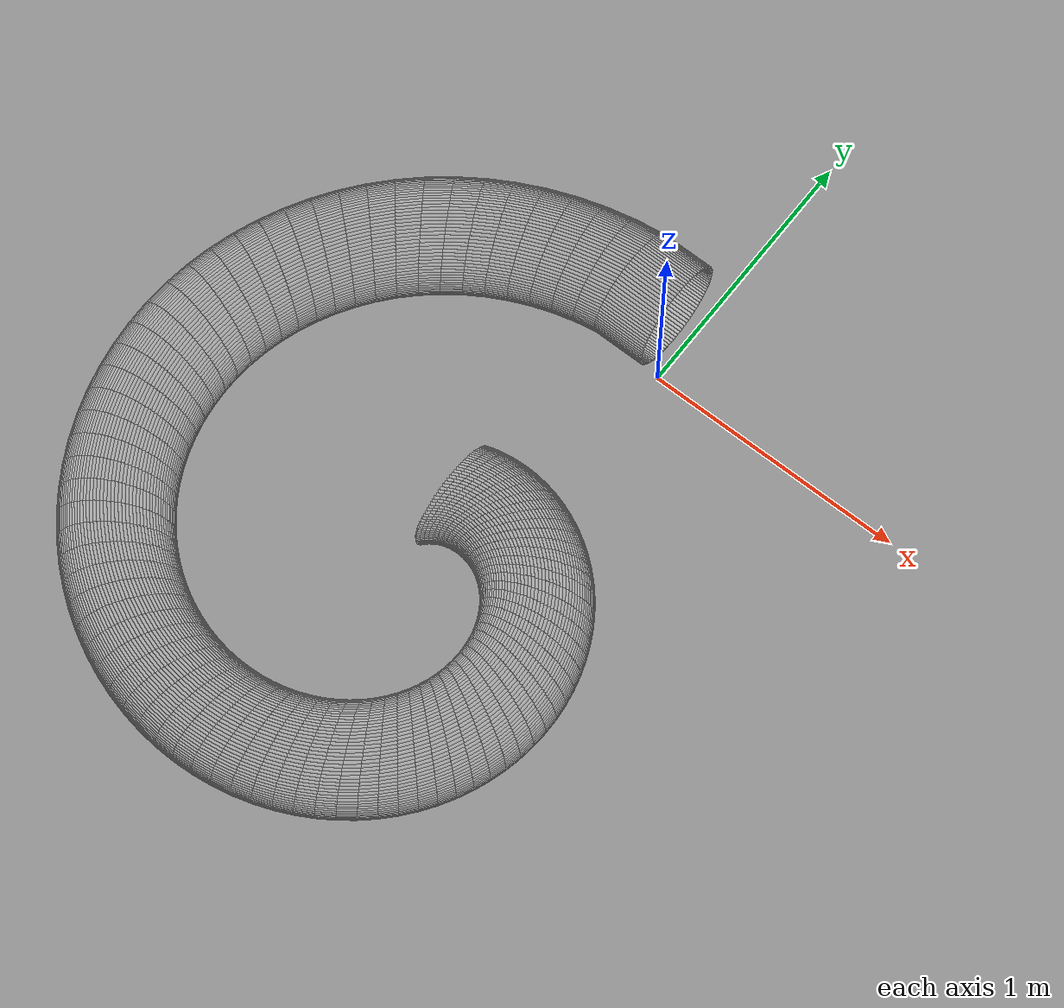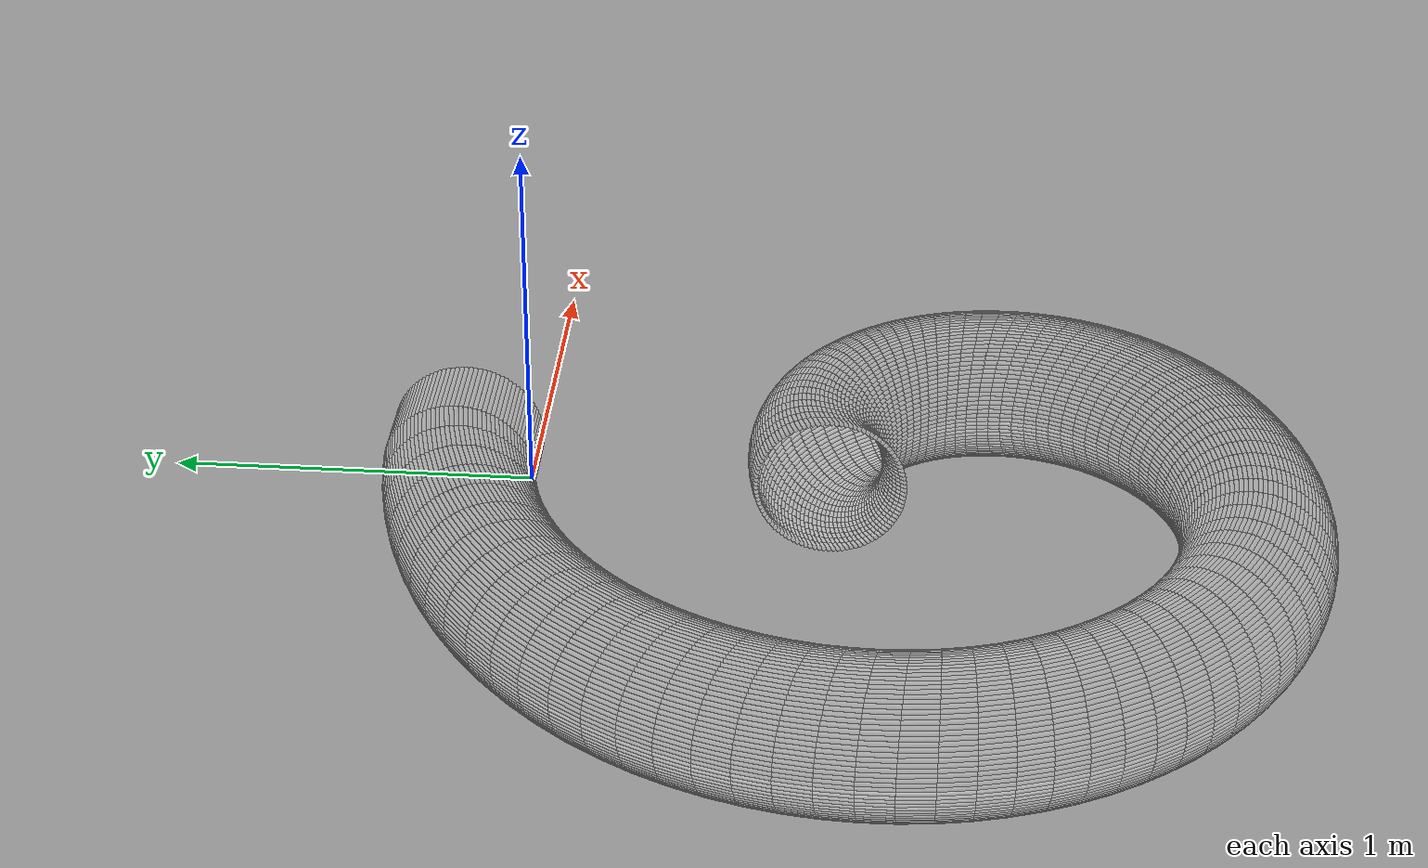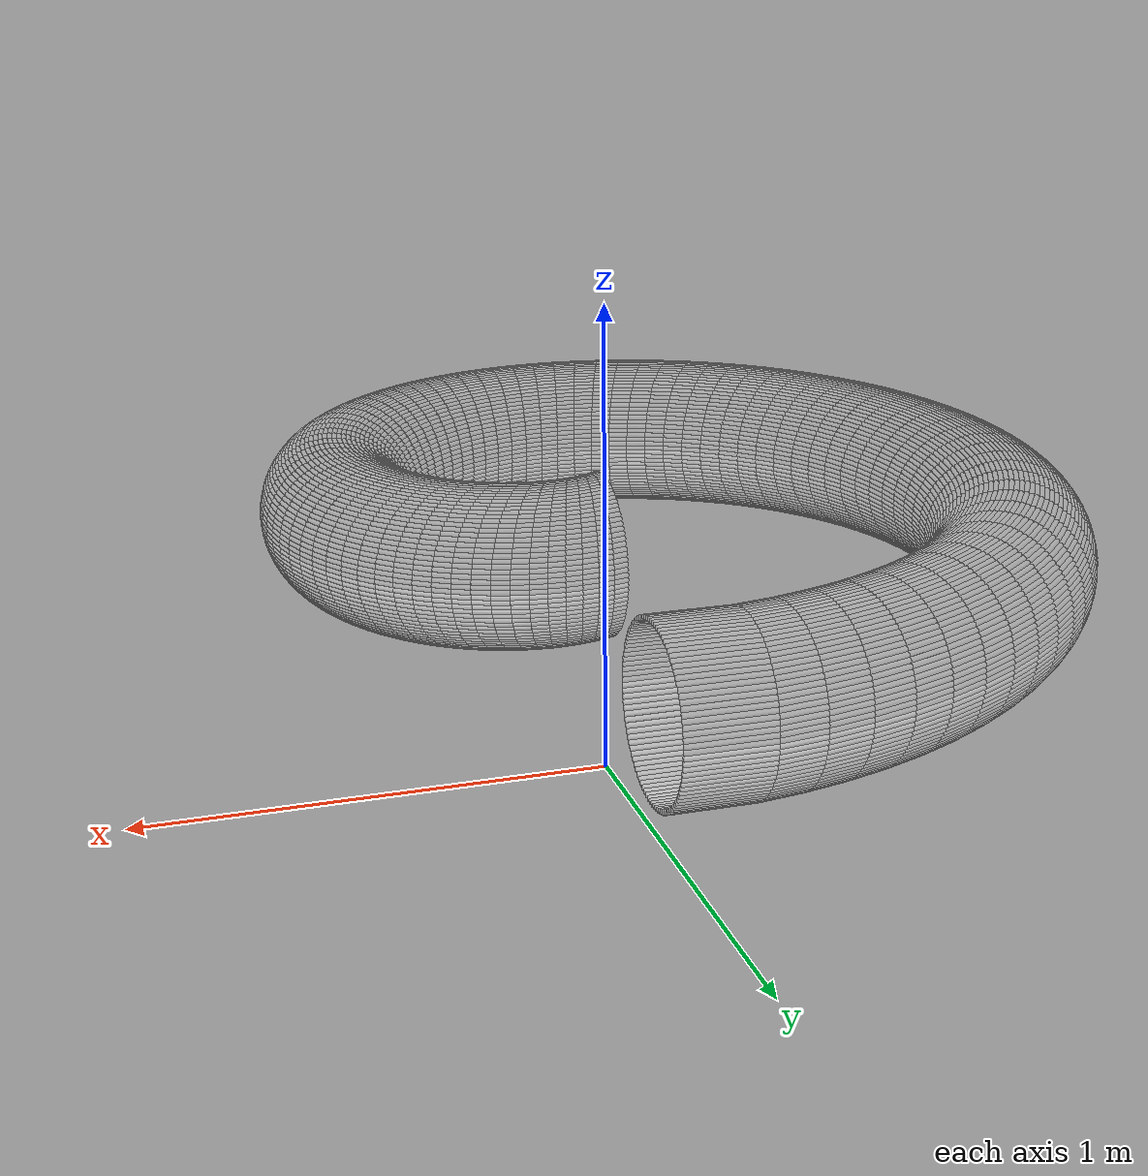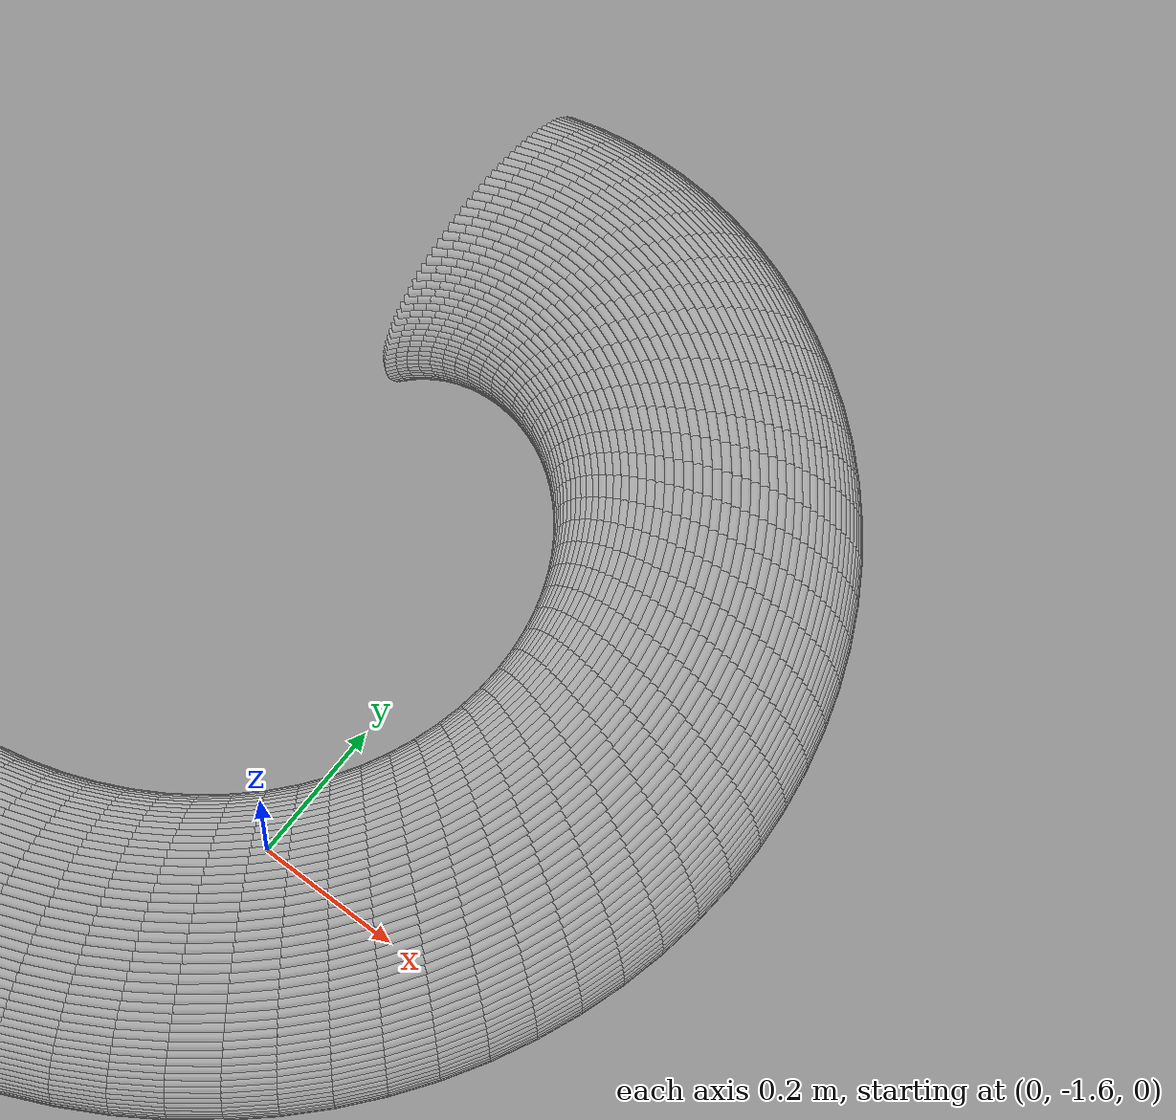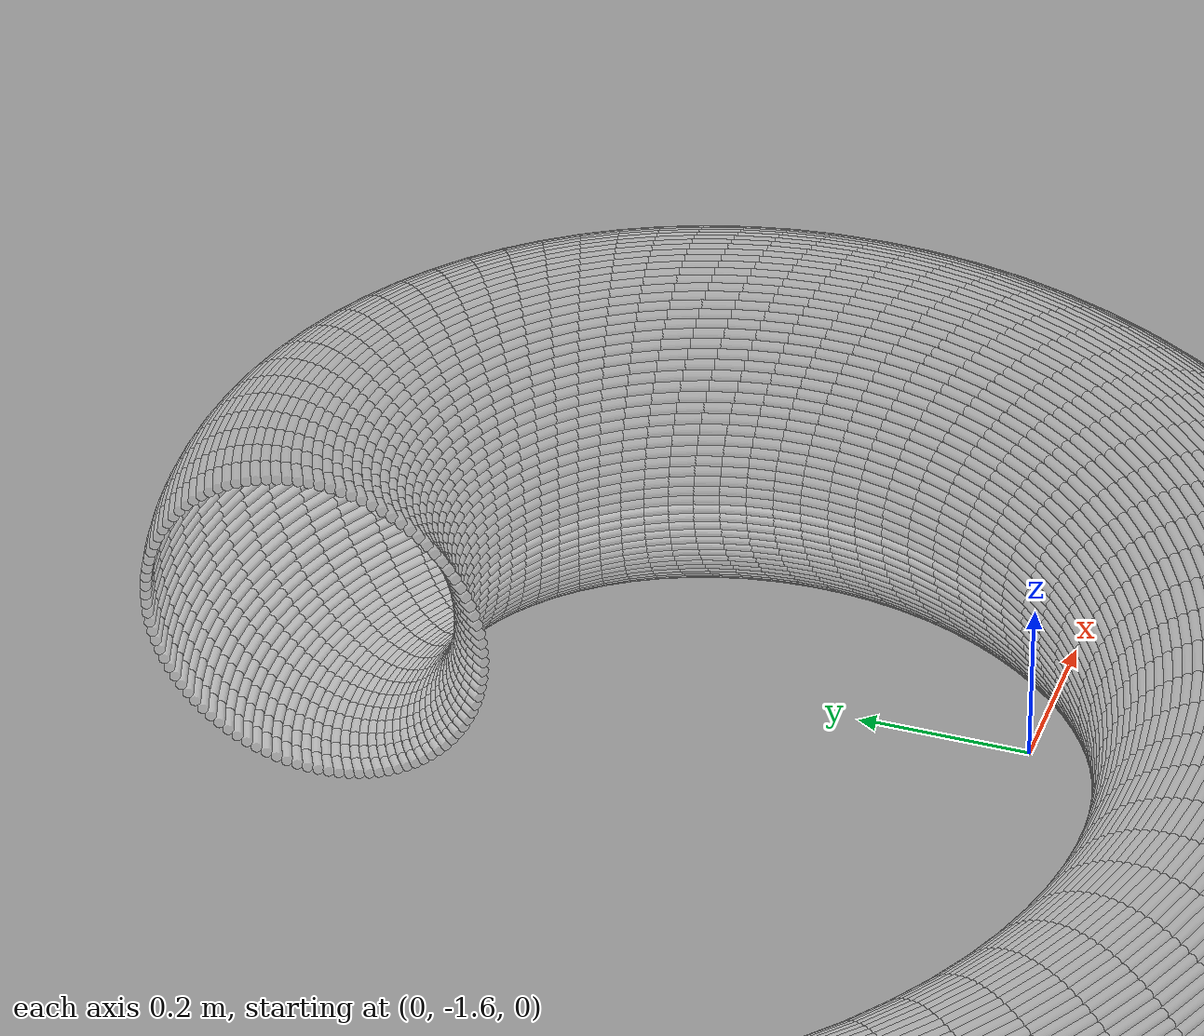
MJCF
<?xml version="1.0" encoding="utf-8"?>
<mujoco>
   <worldbody>
   <body pos="-0.25 -1.14 -0.02" euler="0 0 90">
      <geom euler=" 0 10 0 " fromto="1.5 -0.2 0.2 1.5 0 0.2" rgba="1 1 1 0.05"
            size="0.0062822"
            type="cylinder"/>
      <geom euler=" 0 20 0 " fromto="1.4996 -0.2 0.21256 1.4996 0 0.21256"
            rgba="1 1 1 0.05"
            size="0.0062822"
            type="cylinder"/>
      <geom euler=" 0 30 0 " fromto="1.4984 -0.2 0.22507 1.4984 0 0.22507"
            rgba="1 1 1 0.05"
            size="0.0062822"
            type="cylinder"/>
      <geom euler=" 0 40 0 " fromto="1.4965 -0.2 0.23748 1.4965 0 0.23748"
            rgba="1 1 1 0.05"
            size="0.0062822"
            type="cylinder"/>
      <geom euler=" 0 50 0 " fromto="1.4937 -0.2 0.24974 1.4937 0 0.24974"
            rgba="1 1 1 0.05"
            size="0.0062822"
            type="cylinder"/>
      <geom euler=" 0 60 0 " fromto="1.4902 -0.2 0.2618 1.4902 0 0.2618" rgba="1 1 1 0.05"
            size="0.0062822"
            type="cylinder"/>
      <geom euler=" 0 70 0 " fromto="1.486 -0.2 0.27362 1.486 0 0.27362" rgba="1 1 1 0.05"
            size="0.0062822"
            type="cylinder"/>
      <geom euler=" 0 80 0 " fromto="1.481 -0.2 0.28516 1.481 0 0.28516" rgba="1 1 1 0.05"
            size="0.0062822"
            type="cylinder"/>
      <geom euler=" 0 90 0 " fromto="1.4753 -0.2 0.29635 1.4753 0 0.29635"
            rgba="1 1 1 0.05"
            size="0.0062822"
            type="cylinder"/>
      <geom euler=" 0 100 0 " fromto="1.4689 -0.2 0.30717 1.4689 0 0.30717"
            rgba="1 1 1 0.05"
            size="0.0062822"
            type="cylinder"/>
      <geom euler=" 0 110 0 " fromto="1.4618 -0.2 0.31756 1.4618 0 0.31756"
            rgba="1 1 1 0.05"
            size="0.0062822"
            type="cylinder"/>
      <geom euler=" 0 120 0 " fromto="1.4541 -0.2 0.32748 1.4541 0 0.32748"
            rgba="1 1 1 0.05"
            size="0.0062822"
            type="cylinder"/>
      <geom euler=" 0 130 0 " fromto="1.4458 -0.2 0.33691 1.4458 0 0.33691"
            rgba="1 1 1 0.05"
            size="0.0062822"
            type="cylinder"/>
      <geom euler=" 0 140 0 " fromto="1.4369 -0.2 0.34579 1.4369 0 0.34579"
            rgba="1 1 1 0.05"
            size="0.0062822"
            type="cylinder"/>
      <geom euler=" 0 150 0 " fromto="1.4275 -0.2 0.3541 1.4275 0 0.3541" rgba="1 1 1 0.05"
            size="0.0062822"
            type="cylinder"/>
      <geom euler=" 0 160 0 " fromto="1.4176 -0.2 0.3618 1.4176 0 0.3618" rgba="1 1 1 0.05"
            size="0.0062822"
            type="cylinder"/>
      <geom euler=" 0 170 0 " fromto="1.4072 -0.2 0.36887 1.4072 0 0.36887"
            rgba="1 1 1 0.05"
            size="0.0062822"
            type="cylinder"/>
      <geom euler=" 0 180 0 " fromto="1.3964 -0.2 0.37526 1.3964 0 0.37526"
            rgba="1 1 1 0.05"
            size="0.0062822"
            type="cylinder"/>
      <geom euler=" 0 190 0 " fromto="1.3852 -0.2 0.38097 1.3852 0 0.38097"
            rgba="1 1 1 0.05"
            size="0.0062822"
            type="cylinder"/>
      <geom euler=" 0 200 0 " fromto="1.3736 -0.2 0.38596 1.3736 0 0.38596"
            rgba="1 1 1 0.05"
            size="0.0062822"
            type="cylinder"/>
      <geom euler=" 0 210 0 " fromto="1.3618 -0.2 0.39021 1.3618 0 0.39021"
            rgba="1 1 1 0.05"
            size="0.0062822"
            type="cylinder"/>
      <geom euler=" 0 220 0 " fromto="1.3497 -0.2 0.39372 1.3497 0 0.39372"
            rgba="1 1 1 0.05"
            size="0.0062822"
            type="cylinder"/>
      <geom euler=" 0 230 0 " fromto="1.3375 -0.2 0.39646 1.3375 0 0.39646"
            rgba="1 1 1 0.05"
            size="0.0062822"
            type="cylinder"/>
      <geom euler=" 0 240 0 " fromto="1.3251 -0.2 0.39842 1.3251 0 0.39842"
            rgba="1 1 1 0.05"
            size="0.0062822"
            type="cylinder"/>
      <geom euler=" 0 250 0 " fromto="1.3126 -0.2 0.39961 1.3126 0 0.39961"
            rgba="1 1 1 0.05"
            size="0.0062822"
            type="cylinder"/>
      <geom euler=" 0 260 0 " fromto="1.3 -0.2 0.4 1.3 0 0.4" rgba="1 1 1 0.05"
            size="0.0062822"
            type="cylinder"/>
      <geom euler=" 0 270 0 " fromto="1.2874 -0.2 0.39961 1.2874 0 0.39961"
            rgba="1 1 1 0.05"
            size="0.0062822"
            type="cylinder"/>
      <geom euler=" 0 280 0 " fromto="1.2749 -0.2 0.39842 1.2749 0 0.39842"
            rgba="1 1 1 0.05"
            size="0.0062822"
            type="cylinder"/>
      <geom euler=" 0 290 0 " fromto="1.2625 -0.2 0.39646 1.2625 0 0.39646"
            rgba="1 1 1 0.05"
            size="0.0062822"
            type="cylinder"/>
      <geom euler=" 0 300 0 " fromto="1.2503 -0.2 0.39372 1.2503 0 0.39372"
            rgba="1 1 1 0.05"
            size="0.0062822"
            type="cylinder"/>
      <geom euler=" 0 310 0 " fromto="1.2382 -0.2 0.39021 1.2382 0 0.39021"
            rgba="1 1 1 0.05"
            size="0.0062822"
            type="cylinder"/>
      <geom euler=" 0 320 0 " fromto="1.2264 -0.2 0.38596 1.2264 0 0.38596"
            rgba="1 1 1 0.05"
            size="0.0062822"
            type="cylinder"/>
      <geom euler=" 0 330 0 " fromto="1.2148 -0.2 0.38097 1.2148 0 0.38097"
            rgba="1 1 1 0.05"
            size="0.0062822"
            type="cylinder"/>
      <geom euler=" 0 340 0 " fromto="1.2036 -0.2 0.37526 1.2036 0 0.37526"
            rgba="1 1 1 0.05"
            size="0.0062822"
            type="cylinder"/>
      <geom euler=" 0 350 0 " fromto="1.1928 -0.2 0.36887 1.1928 0 0.36887"
            rgba="1 1 1 0.05"
            size="0.0062822"
            type="cylinder"/>
      <geom euler=" 0 360 0 " fromto="1.1824 -0.2 0.3618 1.1824 0 0.3618" rgba="1 1 1 0.05"
            size="0.0062822"
            type="cylinder"/>
      <geom euler=" 0 370 0 " fromto="1.1725 -0.2 0.3541 1.1725 0 0.3541" rgba="1 1 1 0.05"
            size="0.0062822"
            type="cylinder"/>
      <geom euler=" 0 380 0 " fromto="1.1631 -0.2 0.34579 1.1631 0 0.34579"
            rgba="1 1 1 0.05"
            size="0.0062822"
            type="cylinder"/>
      <geom euler=" 0 390 0 " fromto="1.1542 -0.2 0.33691 1.1542 0 0.33691"
            rgba="1 1 1 0.05"
            size="0.0062822"
            type="cylinder"/>
      <geom euler=" 0 400 0 " fromto="1.1459 -0.2 0.32748 1.1459 0 0.32748"
            rgba="1 1 1 0.05"
            size="0.0062822"
            type="cylinder"/>
      <geom euler=" 0 410 0 " fromto="1.1382 -0.2 0.31756 1.1382 0 0.31756"
            rgba="1 1 1 0.05"
            size="0.0062822"
            type="cylinder"/>
      <geom euler=" 0 420 0 " fromto="1.1311 -0.2 0.30717 1.1311 0 0.30717"
            rgba="1 1 1 0.05"
            size="0.0062822"
            type="cylinder"/>
      <geom euler=" 0 430 0 " fromto="1.1247 -0.2 0.29635 1.1247 0 0.29635"
            rgba="1 1 1 0.05"
            size="0.0062822"
            type="cylinder"/>
      <geom euler=" 0 440 0 " fromto="1.119 -0.2 0.28516 1.119 0 0.28516" rgba="1 1 1 0.05"
            size="0.0062822"
            type="cylinder"/>
      <geom euler=" 0 450 0 " fromto="1.114 -0.2 0.27362 1.114 0 0.27362" rgba="1 1 1 0.05"
            size="0.0062822"
            type="cylinder"/>
      <geom euler=" 0 460 0 " fromto="1.1098 -0.2 0.2618 1.1098 0 0.2618" rgba="1 1 1 0.05"
            size="0.0062822"
            type="cylinder"/>
      <geom euler=" 0 470 0 " fromto="1.1063 -0.2 0.24974 1.1063 0 0.24974"
            rgba="1 1 1 0.05"
            size="0.0062822"
            type="cylinder"/>
      <geom euler=" 0 480 0 " fromto="1.1035 -0.2 0.23748 1.1035 0 0.23748"
            rgba="1 1 1 0.05"
            size="0.0062822"
            type="cylinder"/>
      <geom euler=" 0 490 0 " fromto="1.1016 -0.2 0.22507 1.1016 0 0.22507"
            rgba="1 1 1 0.05"
            size="0.0062822"
            type="cylinder"/>
      <geom euler=" 0 500 0 " fromto="1.1004 -0.2 0.21256 1.1004 0 0.21256"
            rgba="1 1 1 0.05"
            size="0.0062822"
            type="cylinder"/>
      <geom euler=" 0 510 0 " fromto="1.1 -0.2 0.2 1.1 0 0.2" rgba="1 1 1 0.05"
            size="0.0062822"
            type="cylinder"/>
      <geom euler=" 0 520 0 " fromto="1.1004 -0.2 0.18744 1.1004 0 0.18744"
            rgba="1 1 1 0.35"
            size="0.0062822"
            type="cylinder"/>
      <geom euler=" 0 530 0 " fromto="1.1016 -0.2 0.17493 1.1016 0 0.17493"
            rgba="1 1 1 0.35"
            size="0.0062822"
            type="cylinder"/>
      <geom euler=" 0 540 0 " fromto="1.1035 -0.2 0.16252 1.1035 0 0.16252"
            rgba="1 1 1 0.35"
            size="0.0062822"
            type="cylinder"/>
      <geom euler=" 0 550 0 " fromto="1.1063 -0.2 0.15026 1.1063 0 0.15026"
            rgba="1 1 1 0.35"
            size="0.0062822"
            type="cylinder"/>
      <geom euler=" 0 560 0 " fromto="1.1098 -0.2 0.1382 1.1098 0 0.1382" rgba="1 1 1 0.35"
            size="0.0062822"
            type="cylinder"/>
      <geom euler=" 0 570 0 " fromto="1.114 -0.2 0.12638 1.114 0 0.12638" rgba="1 1 1 0.35"
            size="0.0062822"
            type="cylinder"/>
      <geom euler=" 0 580 0 " fromto="1.119 -0.2 0.11484 1.119 0 0.11484" rgba="1 1 1 0.35"
            size="0.0062822"
            type="cylinder"/>
      <geom euler=" 0 590 0 " fromto="1.1247 -0.2 0.10365 1.1247 0 0.10365"
            rgba="1 1 1 0.35"
            size="0.0062822"
            type="cylinder"/>
      <geom euler=" 0 600 0 " fromto="1.1311 -0.2 0.092835 1.1311 0 0.092835"
            rgba="1 1 1 0.35"
            size="0.0062822"
            type="cylinder"/>
      <geom euler=" 0 610 0 " fromto="1.1382 -0.2 0.082443 1.1382 0 0.082443"
            rgba="1 1 1 0.35"
            size="0.0062822"
            type="cylinder"/>
      <geom euler=" 0 620 0 " fromto="1.1459 -0.2 0.072515 1.1459 0 0.072515"
            rgba="1 1 1 0.35"
            size="0.0062822"
            type="cylinder"/>
      <geom euler=" 0 630 0 " fromto="1.1542 -0.2 0.063091 1.1542 0 0.063091"
            rgba="1 1 1 0.35"
            size="0.0062822"
            type="cylinder"/>
      <geom euler=" 0 640 0 " fromto="1.1631 -0.2 0.054206 1.1631 0 0.054206"
            rgba="1 1 1 0.35"
            size="0.0062822"
            type="cylinder"/>
      <geom euler=" 0 650 0 " fromto="1.1725 -0.2 0.045897 1.1725 0 0.045897"
            rgba="1 1 1 0.35"
            size="0.0062822"
            type="cylinder"/>
      <geom euler=" 0 660 0 " fromto="1.1824 -0.2 0.038197 1.1824 0 0.038197"
            rgba="1 1 1 0.35"
            size="0.0062822"
            type="cylinder"/>
      <geom euler=" 0 670 0 " fromto="1.1928 -0.2 0.031134 1.1928 0 0.031134"
            rgba="1 1 1 0.35"
            size="0.0062822"
            type="cylinder"/>
      <geom euler=" 0 680 0 " fromto="1.2036 -0.2 0.024739 1.2036 0 0.024739"
            rgba="1 1 1 0.35"
            size="0.0062822"
            type="cylinder"/>
      <geom euler=" 0 690 0 " fromto="1.2148 -0.2 0.019035 1.2148 0 0.019035"
            rgba="1 1 1 0.35"
            size="0.0062822"
            type="cylinder"/>
      <geom euler=" 0 700 0 " fromto="1.2264 -0.2 0.014045 1.2264 0 0.014045"
            rgba="1 1 1 0.35"
            size="0.0062822"
            type="cylinder"/>
      <geom euler=" 0 710 0 " fromto="1.2382 -0.2 0.0097887 1.2382 0 0.0097887"
            rgba="1 1 1 0.35"
            size="0.0062822"
            type="cylinder"/>
      <geom euler=" 0 720 0 " fromto="1.2503 -0.2 0.0062834 1.2503 0 0.0062834"
            rgba="1 1 1 0.35"
            size="0.0062822"
            type="cylinder"/>
      <geom euler=" 0 730 0 " fromto="1.2625 -0.2 0.0035425 1.2625 0 0.0035425"
            rgba="1 1 1 0.35"
            size="0.0062822"
            type="cylinder"/>
      <geom euler=" 0 740 0 " fromto="1.2749 -0.2 0.0015771 1.2749 0 0.0015771"
            rgba="1 1 1 0.35"
            size="0.0062822"
            type="cylinder"/>
      <geom euler=" 0 750 0 " fromto="1.2874 -0.2 0.00039465 1.2874 0 0.00039465"
            rgba="1 1 1 0.35"
            size="0.0062822"
            type="cylinder"/>
      <geom euler=" 0 760 0 " fromto="1.3 -0.2 0 1.3 0 0" rgba="1 1 1 0.35"
            size="0.0062822"
            type="cylinder"/>
      <geom euler=" 0 770 0 " fromto="1.3126 -0.2 0.00039465 1.3126 0 0.00039465"
            rgba="1 1 1 0.35"
            size="0.0062822"
            type="cylinder"/>
      <geom euler=" 0 780 0 " fromto="1.3251 -0.2 0.0015771 1.3251 0 0.0015771"
            rgba="1 1 1 0.35"
            size="0.0062822"
            type="cylinder"/>
      <geom euler=" 0 790 0 " fromto="1.3375 -0.2 0.0035425 1.3375 0 0.0035425"
            rgba="1 1 1 0.35"
            size="0.0062822"
            type="cylinder"/>
      <geom euler=" 0 800 0 " fromto="1.3497 -0.2 0.0062834 1.3497 0 0.0062834"
            rgba="1 1 1 0.35"
            size="0.0062822"
            type="cylinder"/>
      <geom euler=" 0 810 0 " fromto="1.3618 -0.2 0.0097887 1.3618 0 0.0097887"
            rgba="1 1 1 0.35"
            size="0.0062822"
            type="cylinder"/>
      <geom euler=" 0 820 0 " fromto="1.3736 -0.2 0.014045 1.3736 0 0.014045"
            rgba="1 1 1 0.35"
            size="0.0062822"
            type="cylinder"/>
      <geom euler=" 0 830 0 " fromto="1.3852 -0.2 0.019035 1.3852 0 0.019035"
            rgba="1 1 1 0.35"
            size="0.0062822"
            type="cylinder"/>
      <geom euler=" 0 840 0 " fromto="1.3964 -0.2 0.024739 1.3964 0 0.024739"
            rgba="1 1 1 0.35"
            size="0.0062822"
            type="cylinder"/>
      <geom euler=" 0 850 0 " fromto="1.4072 -0.2 0.031134 1.4072 0 0.031134"
            rgba="1 1 1 0.35"
            size="0.0062822"
            type="cylinder"/>
      <geom euler=" 0 860 0 " fromto="1.4176 -0.2 0.038197 1.4176 0 0.038197"
            rgba="1 1 1 0.35"
            size="0.0062822"
            type="cylinder"/>
      <geom euler=" 0 870 0 " fromto="1.4275 -0.2 0.045897 1.4275 0 0.045897"
            rgba="1 1 1 0.35"
            size="0.0062822"
            type="cylinder"/>
      <geom euler=" 0 880 0 " fromto="1.4369 -0.2 0.054206 1.4369 0 0.054206"
            rgba="1 1 1 0.35"
            size="0.0062822"
            type="cylinder"/>
      <geom euler=" 0 890 0 " fromto="1.4458 -0.2 0.063091 1.4458 0 0.063091"
            rgba="1 1 1 0.35"
            size="0.0062822"
            type="cylinder"/>
      <geom euler=" 0 900 0 " fromto="1.4541 -0.2 0.072515 1.4541 0 0.072515"
            rgba="1 1 1 0.35"
            size="0.0062822"
            type="cylinder"/>
      <geom euler=" 0 910 0 " fromto="1.4618 -0.2 0.082443 1.4618 0 0.082443"
            rgba="1 1 1 0.35"
            size="0.0062822"
            type="cylinder"/>
      <geom euler=" 0 920 0 " fromto="1.4689 -0.2 0.092835 1.4689 0 0.092835"
            rgba="1 1 1 0.35"
            size="0.0062822"
            type="cylinder"/>
      <geom euler=" 0 930 0 " fromto="1.4753 -0.2 0.10365 1.4753 0 0.10365"
            rgba="1 1 1 0.35"
            size="0.0062822"
            type="cylinder"/>
      <geom euler=" 0 940 0 " fromto="1.481 -0.2 0.11484 1.481 0 0.11484" rgba="1 1 1 0.35"
            size="0.0062822"
            type="cylinder"/>
      <geom euler=" 0 950 0 " fromto="1.486 -0.2 0.12638 1.486 0 0.12638" rgba="1 1 1 0.35"
            size="0.0062822"
            type="cylinder"/>
      <geom euler=" 0 960 0 " fromto="1.4902 -0.2 0.1382 1.4902 0 0.1382" rgba="1 1 1 0.35"
            size="0.0062822"
            type="cylinder"/>
      <geom euler=" 0 970 0 " fromto="1.4937 -0.2 0.15026 1.4937 0 0.15026"
            rgba="1 1 1 0.35"
            size="0.0062822"
            type="cylinder"/>
      <geom euler=" 0 980 0 " fromto="1.4965 -0.2 0.16252 1.4965 0 0.16252"
            rgba="1 1 1 0.35"
            size="0.0062822"
            type="cylinder"/>
      <geom euler=" 0 990 0 " fromto="1.4984 -0.2 0.17493 1.4984 0 0.17493"
            rgba="1 1 1 0.35"
            size="0.0062822"
            type="cylinder"/>
      <geom euler=" 0 1000 0 " fromto="1.4996 -0.2 0.18744 1.4996 0 0.18744"
            rgba="1 1 1 0.35"
            size="0.0062822"
            type="cylinder"/>
      <geom euler=" 0 10 0 " fromto="1.5 0 0.2 1.4839 0.11121 0.2" rgba="1 1 1 0.05"
            size="0.0062822"
            type="cylinder"/>
      <geom euler=" 0 20 0 " fromto="1.4996 0 0.21256 1.4835 0.11118 0.21256"
            rgba="1 1 1 0.05"
            size="0.0062822"
            type="cylinder"/>
      <geom euler=" 0 30 0 " fromto="1.4984 0 0.22507 1.4824 0.11109 0.22507"
            rgba="1 1 1 0.05"
            size="0.0062822"
            type="cylinder"/>
      <geom euler=" 0 40 0 " fromto="1.4965 0 0.23748 1.4804 0.11094 0.23748"
            rgba="1 1 1 0.05"
            size="0.0062822"
            type="cylinder"/>
      <geom euler=" 0 50 0 " fromto="1.4937 0 0.24974 1.4777 0.11074 0.24974"
            rgba="1 1 1 0.05"
            size="0.0062822"
            type="cylinder"/>
      <geom euler=" 0 60 0 " fromto="1.4902 0 0.2618 1.4742 0.11047 0.2618"
            rgba="1 1 1 0.05"
            size="0.0062822"
            type="cylinder"/>
      <geom euler=" 0 70 0 " fromto="1.486 0 0.27362 1.4699 0.11016 0.27362"
            rgba="1 1 1 0.05"
            size="0.0062822"
            type="cylinder"/>
      <geom euler=" 0 80 0 " fromto="1.481 0 0.28516 1.465 0.10978 0.28516"
            rgba="1 1 1 0.05"
            size="0.0062822"
            type="cylinder"/>
      <geom euler=" 0 90 0 " fromto="1.4753 0 0.29635 1.4593 0.10936 0.29635"
            rgba="1 1 1 0.05"
            size="0.0062822"
            type="cylinder"/>
      <geom euler=" 0 100 0 " fromto="1.4689 0 0.30717 1.4529 0.10888 0.30717"
            rgba="1 1 1 0.05"
            size="0.0062822"
            type="cylinder"/>
      <geom euler=" 0 110 0 " fromto="1.4618 0 0.31756 1.4458 0.10835 0.31756"
            rgba="1 1 1 0.05"
            size="0.0062822"
            type="cylinder"/>
      <geom euler=" 0 120 0 " fromto="1.4541 0 0.32748 1.4382 0.10778 0.32748"
            rgba="1 1 1 0.05"
            size="0.0062822"
            type="cylinder"/>
      <geom euler=" 0 130 0 " fromto="1.4458 0 0.33691 1.4299 0.10715 0.33691"
            rgba="1 1 1 0.05"
            size="0.0062822"
            type="cylinder"/>
      <geom euler=" 0 140 0 " fromto="1.4369 0 0.34579 1.421 0.10649 0.34579"
            rgba="1 1 1 0.05"
            size="0.0062822"
            type="cylinder"/>
      <geom euler=" 0 150 0 " fromto="1.4275 0 0.3541 1.4116 0.10579 0.3541"
            rgba="1 1 1 0.05"
            size="0.0062822"
            type="cylinder"/>
      <geom euler=" 0 160 0 " fromto="1.4176 0 0.3618 1.4017 0.10504 0.3618"
            rgba="1 1 1 0.05"
            size="0.0062822"
            type="cylinder"/>
      <geom euler=" 0 170 0 " fromto="1.4072 0 0.36887 1.3914 0.10427 0.36887"
            rgba="1 1 1 0.05"
            size="0.0062822"
            type="cylinder"/>
      <geom euler=" 0 180 0 " fromto="1.3964 0 0.37526 1.3806 0.10346 0.37526"
            rgba="1 1 1 0.05"
            size="0.0062822"
            type="cylinder"/>
      <geom euler=" 0 190 0 " fromto="1.3852 0 0.38097 1.3694 0.10262 0.38097"
            rgba="1 1 1 0.05"
            size="0.0062822"
            type="cylinder"/>
      <geom euler=" 0 200 0 " fromto="1.3736 0 0.38596 1.3579 0.10176 0.38596"
            rgba="1 1 1 0.05"
            size="0.0062822"
            type="cylinder"/>
      <geom euler=" 0 210 0 " fromto="1.3618 0 0.39021 1.3461 0.10088 0.39021"
            rgba="1 1 1 0.05"
            size="0.0062822"
            type="cylinder"/>
      <geom euler=" 0 220 0 " fromto="1.3497 0 0.39372 1.3341 0.099976 0.39372"
            rgba="1 1 1 0.05"
            size="0.0062822"
            type="cylinder"/>
      <geom euler=" 0 230 0 " fromto="1.3375 0 0.39646 1.3219 0.09906 0.39646"
            rgba="1 1 1 0.05"
            size="0.0062822"
            type="cylinder"/>
      <geom euler=" 0 240 0 " fromto="1.3251 0 0.39842 1.3095 0.098133 0.39842"
            rgba="1 1 1 0.05"
            size="0.0062822"
            type="cylinder"/>
      <geom euler=" 0 250 0 " fromto="1.3126 0 0.39961 1.297 0.097198 0.39961"
            rgba="1 1 1 0.05"
            size="0.0062822"
            type="cylinder"/>
      <geom euler=" 0 260 0 " fromto="1.3 0 0.4 1.2845 0.096259 0.4" rgba="1 1 1 0.05"
            size="0.0062822"
            type="cylinder"/>
      <geom euler=" 0 270 0 " fromto="1.2874 0 0.39961 1.272 0.095321 0.39961"
            rgba="1 1 1 0.05"
            size="0.0062822"
            type="cylinder"/>
      <geom euler=" 0 280 0 " fromto="1.2749 0 0.39842 1.2595 0.094386 0.39842"
            rgba="1 1 1 0.05"
            size="0.0062822"
            type="cylinder"/>
      <geom euler=" 0 290 0 " fromto="1.2625 0 0.39646 1.2471 0.093459 0.39646"
            rgba="1 1 1 0.05"
            size="0.0062822"
            type="cylinder"/>
      <geom euler=" 0 300 0 " fromto="1.2503 0 0.39372 1.2349 0.092543 0.39372"
            rgba="1 1 1 0.05"
            size="0.0062822"
            type="cylinder"/>
      <geom euler=" 0 310 0 " fromto="1.2382 0 0.39021 1.2229 0.091641 0.39021"
            rgba="1 1 1 0.05"
            size="0.0062822"
            type="cylinder"/>
      <geom euler=" 0 320 0 " fromto="1.2264 0 0.38596 1.2111 0.090757 0.38596"
            rgba="1 1 1 0.05"
            size="0.0062822"
            type="cylinder"/>
      <geom euler=" 0 330 0 " fromto="1.2148 0 0.38097 1.1996 0.089896 0.38097"
            rgba="1 1 1 0.05"
            size="0.0062822"
            type="cylinder"/>
      <geom euler=" 0 340 0 " fromto="1.2036 0 0.37526 1.1884 0.089059 0.37526"
            rgba="1 1 1 0.05"
            size="0.0062822"
            type="cylinder"/>
      <geom euler=" 0 350 0 " fromto="1.1928 0 0.36887 1.1776 0.088251 0.36887"
            rgba="1 1 1 0.05"
            size="0.0062822"
            type="cylinder"/>
      <geom euler=" 0 360 0 " fromto="1.1824 0 0.3618 1.1673 0.087474 0.3618"
            rgba="1 1 1 0.05"
            size="0.0062822"
            type="cylinder"/>
      <geom euler=" 0 370 0 " fromto="1.1725 0 0.3541 1.1574 0.086733 0.3541"
            rgba="1 1 1 0.05"
            size="0.0062822"
            type="cylinder"/>
      <geom euler=" 0 380 0 " fromto="1.1631 0 0.34579 1.148 0.086028 0.34579"
            rgba="1 1 1 0.05"
            size="0.0062822"
            type="cylinder"/>
      <geom euler=" 0 390 0 " fromto="1.1542 0 0.33691 1.1391 0.085364 0.33691"
            rgba="1 1 1 0.05"
            size="0.0062822"
            type="cylinder"/>
      <geom euler=" 0 400 0 " fromto="1.1459 0 0.32748 1.1308 0.084743 0.32748"
            rgba="1 1 1 0.05"
            size="0.0062822"
            type="cylinder"/>
      <geom euler=" 0 410 0 " fromto="1.1382 0 0.31756 1.1231 0.084168 0.31756"
            rgba="1 1 1 0.05"
            size="0.0062822"
            type="cylinder"/>
      <geom euler=" 0 420 0 " fromto="1.1311 0 0.30717 1.1161 0.08364 0.30717"
            rgba="1 1 1 0.05"
            size="0.0062822"
            type="cylinder"/>
      <geom euler=" 0 430 0 " fromto="1.1247 0 0.29635 1.1097 0.083162 0.29635"
            rgba="1 1 1 0.05"
            size="0.0062822"
            type="cylinder"/>
      <geom euler=" 0 440 0 " fromto="1.119 0 0.28516 1.104 0.082736 0.28516"
            rgba="1 1 1 0.05"
            size="0.0062822"
            type="cylinder"/>
      <geom euler=" 0 450 0 " fromto="1.114 0 0.27362 1.0991 0.082363 0.27362"
            rgba="1 1 1 0.05"
            size="0.0062822"
            type="cylinder"/>
      <geom euler=" 0 460 0 " fromto="1.1098 0 0.2618 1.0948 0.082045 0.2618"
            rgba="1 1 1 0.05"
            size="0.0062822"
            type="cylinder"/>
      <geom euler=" 0 470 0 " fromto="1.1063 0 0.24974 1.0913 0.081783 0.24974"
            rgba="1 1 1 0.05"
            size="0.0062822"
            type="cylinder"/>
      <geom euler=" 0 480 0 " fromto="1.1035 0 0.23748 1.0886 0.081578 0.23748"
            rgba="1 1 1 0.05"
            size="0.0062822"
            type="cylinder"/>
      <geom euler=" 0 490 0 " fromto="1.1016 0 0.22507 1.0866 0.081431 0.22507"
            rgba="1 1 1 0.05"
            size="0.0062822"
            type="cylinder"/>
      <geom euler=" 0 500 0 " fromto="1.1004 0 0.21256 1.0854 0.081343 0.21256"
            rgba="1 1 1 0.05"
            size="0.0062822"
            type="cylinder"/>
      <geom euler=" 0 510 0 " fromto="1.1 0 0.2 1.0851 0.081313 0.2" rgba="1 1 1 0.05"
            size="0.0062822"
            type="cylinder"/>
      <geom euler=" 0 520 0 " fromto="1.1004 0 0.18744 1.0854 0.081343 0.18744"
            rgba="1 1 1 0.35"
            size="0.0062822"
            type="cylinder"/>
      <geom euler=" 0 530 0 " fromto="1.1016 0 0.17493 1.0866 0.081431 0.17493"
            rgba="1 1 1 0.35"
            size="0.0062822"
            type="cylinder"/>
      <geom euler=" 0 540 0 " fromto="1.1035 0 0.16252 1.0886 0.081578 0.16252"
            rgba="1 1 1 0.35"
            size="0.0062822"
            type="cylinder"/>
      <geom euler=" 0 550 0 " fromto="1.1063 0 0.15026 1.0913 0.081783 0.15026"
            rgba="1 1 1 0.35"
            size="0.0062822"
            type="cylinder"/>
      <geom euler=" 0 560 0 " fromto="1.1098 0 0.1382 1.0948 0.082045 0.1382"
            rgba="1 1 1 0.35"
            size="0.0062822"
            type="cylinder"/>
      <geom euler=" 0 570 0 " fromto="1.114 0 0.12638 1.0991 0.082363 0.12638"
            rgba="1 1 1 0.35"
            size="0.0062822"
            type="cylinder"/>
      <geom euler=" 0 580 0 " fromto="1.119 0 0.11484 1.104 0.082736 0.11484"
            rgba="1 1 1 0.35"
            size="0.0062822"
            type="cylinder"/>
      <geom euler=" 0 590 0 " fromto="1.1247 0 0.10365 1.1097 0.083162 0.10365"
            rgba="1 1 1 0.35"
            size="0.0062822"
            type="cylinder"/>
      <geom euler=" 0 600 0 " fromto="1.1311 0 0.092835 1.1161 0.08364 0.092835"
            rgba="1 1 1 0.35"
            size="0.0062822"
            type="cylinder"/>
      <geom euler=" 0 610 0 " fromto="1.1382 0 0.082443 1.1231 0.084168 0.082443"
            rgba="1 1 1 0.35"
            size="0.0062822"
            type="cylinder"/>
      <geom euler=" 0 620 0 " fromto="1.1459 0 0.072515 1.1308 0.084743 0.072515"
            rgba="1 1 1 0.35"
            size="0.0062822"
            type="cylinder"/>
      <geom euler=" 0 630 0 " fromto="1.1542 0 0.063091 1.1391 0.085364 0.063091"
            rgba="1 1 1 0.35"
            size="0.0062822"
            type="cylinder"/>
      <geom euler=" 0 640 0 " fromto="1.1631 0 0.054206 1.148 0.086028 0.054206"
            rgba="1 1 1 0.35"
            size="0.0062822"
            type="cylinder"/>
      <geom euler=" 0 650 0 " fromto="1.1725 0 0.045897 1.1574 0.086733 0.045897"
            rgba="1 1 1 0.35"
            size="0.0062822"
            type="cylinder"/>
      <geom euler=" 0 660 0 " fromto="1.1824 0 0.038197 1.1673 0.087474 0.038197"
            rgba="1 1 1 0.35"
            size="0.0062822"
            type="cylinder"/>
      <geom euler=" 0 670 0 " fromto="1.1928 0 0.031134 1.1776 0.088251 0.031134"
            rgba="1 1 1 0.35"
            size="0.0062822"
            type="cylinder"/>
      <geom euler=" 0 680 0 " fromto="1.2036 0 0.024739 1.1884 0.089059 0.024739"
            rgba="1 1 1 0.35"
            size="0.0062822"
            type="cylinder"/>
      <geom euler=" 0 690 0 " fromto="1.2148 0 0.019035 1.1996 0.089896 0.019035"
            rgba="1 1 1 0.35"
            size="0.0062822"
            type="cylinder"/>
      <geom euler=" 0 700 0 " fromto="1.2264 0 0.014045 1.2111 0.090757 0.014045"
            rgba="1 1 1 0.35"
            size="0.0062822"
            type="cylinder"/>
      <geom euler=" 0 710 0 " fromto="1.2382 0 0.0097887 1.2229 0.091641 0.0097887"
            rgba="1 1 1 0.35"
            size="0.0062822"
            type="cylinder"/>
      <geom euler=" 0 720 0 " fromto="1.2503 0 0.0062834 1.2349 0.092543 0.0062834"
            rgba="1 1 1 0.35"
            size="0.0062822"
            type="cylinder"/>
      <geom euler=" 0 730 0 " fromto="1.2625 0 0.0035425 1.2471 0.093459 0.0035425"
            rgba="1 1 1 0.35"
            size="0.0062822"
            type="cylinder"/>
      <geom euler=" 0 740 0 " fromto="1.2749 0 0.0015771 1.2595 0.094386 0.0015771"
            rgba="1 1 1 0.35"
            size="0.0062822"
            type="cylinder"/>
      <geom euler=" 0 750 0 " fromto="1.2874 0 0.00039465 1.272 0.095321 0.00039465"
            rgba="1 1 1 0.35"
            size="0.0062822"
            type="cylinder"/>
      <geom euler=" 0 760 0 " fromto="1.3 0 0 1.2845 0.096259 0" rgba="1 1 1 0.35"
            size="0.0062822"
            type="cylinder"/>
      <geom euler=" 0 770 0 " fromto="1.3126 0 0.00039465 1.297 0.097198 0.00039465"
            rgba="1 1 1 0.35"
            size="0.0062822"
            type="cylinder"/>
      <geom euler=" 0 780 0 " fromto="1.3251 0 0.0015771 1.3095 0.098133 0.0015771"
            rgba="1 1 1 0.35"
            size="0.0062822"
            type="cylinder"/>
      <geom euler=" 0 790 0 " fromto="1.3375 0 0.0035425 1.3219 0.09906 0.0035425"
            rgba="1 1 1 0.35"
            size="0.0062822"
            type="cylinder"/>
      <geom euler=" 0 800 0 " fromto="1.3497 0 0.0062834 1.3341 0.099976 0.0062834"
            rgba="1 1 1 0.35"
            size="0.0062822"
            type="cylinder"/>
      <geom euler=" 0 810 0 " fromto="1.3618 0 0.0097887 1.3461 0.10088 0.0097887"
            rgba="1 1 1 0.35"
            size="0.0062822"
            type="cylinder"/>
      <geom euler=" 0 820 0 " fromto="1.3736 0 0.014045 1.3579 0.10176 0.014045"
            rgba="1 1 1 0.35"
            size="0.0062822"
            type="cylinder"/>
      <geom euler=" 0 830 0 " fromto="1.3852 0 0.019035 1.3694 0.10262 0.019035"
            rgba="1 1 1 0.35"
            size="0.0062822"
            type="cylinder"/>
      <geom euler=" 0 840 0 " fromto="1.3964 0 0.024739 1.3806 0.10346 0.024739"
            rgba="1 1 1 0.35"
            size="0.0062822"
            type="cylinder"/>
      <geom euler=" 0 850 0 " fromto="1.4072 0 0.031134 1.3914 0.10427 0.031134"
            rgba="1 1 1 0.35"
            size="0.0062822"
            type="cylinder"/>
      <geom euler=" 0 860 0 " fromto="1.4176 0 0.038197 1.4017 0.10504 0.038197"
            rgba="1 1 1 0.35"
            size="0.0062822"
            type="cylinder"/>
      <geom euler=" 0 870 0 " fromto="1.4275 0 0.045897 1.4116 0.10579 0.045897"
            rgba="1 1 1 0.35"
            size="0.0062822"
            type="cylinder"/>
      <geom euler=" 0 880 0 " fromto="1.4369 0 0.054206 1.421 0.10649 0.054206"
            rgba="1 1 1 0.35"
            size="0.0062822"
            type="cylinder"/>
      <geom euler=" 0 890 0 " fromto="1.4458 0 0.063091 1.4299 0.10715 0.063091"
            rgba="1 1 1 0.35"
            size="0.0062822"
            type="cylinder"/>
      <geom euler=" 0 900 0 " fromto="1.4541 0 0.072515 1.4382 0.10778 0.072515"
            rgba="1 1 1 0.35"
            size="0.0062822"
            type="cylinder"/>
      <geom euler=" 0 910 0 " fromto="1.4618 0 0.082443 1.4458 0.10835 0.082443"
            rgba="1 1 1 0.35"
            size="0.0062822"
            type="cylinder"/>
      <geom euler=" 0 920 0 " fromto="1.4689 0 0.092835 1.4529 0.10888 0.092835"
            rgba="1 1 1 0.35"
            size="0.0062822"
            type="cylinder"/>
      <geom euler=" 0 930 0 " fromto="1.4753 0 0.10365 1.4593 0.10936 0.10365"
            rgba="1 1 1 0.35"
            size="0.0062822"
            type="cylinder"/>
      <geom euler=" 0 940 0 " fromto="1.481 0 0.11484 1.465 0.10978 0.11484"
            rgba="1 1 1 0.35"
            size="0.0062822"
            type="cylinder"/>
      <geom euler=" 0 950 0 " fromto="1.486 0 0.12638 1.4699 0.11016 0.12638"
            rgba="1 1 1 0.35"
            size="0.0062822"
            type="cylinder"/>
      <geom euler=" 0 960 0 " fromto="1.4902 0 0.1382 1.4742 0.11047 0.1382"
            rgba="1 1 1 0.35"
            size="0.0062822"
            type="cylinder"/>
      <geom euler=" 0 970 0 " fromto="1.4937 0 0.15026 1.4777 0.11074 0.15026"
            rgba="1 1 1 0.35"
            size="0.0062822"
            type="cylinder"/>
      <geom euler=" 0 980 0 " fromto="1.4965 0 0.16252 1.4804 0.11094 0.16252"
            rgba="1 1 1 0.35"
            size="0.0062822"
            type="cylinder"/>
      <geom euler=" 0 990 0 " fromto="1.4984 0 0.17493 1.4824 0.11109 0.17493"
            rgba="1 1 1 0.35"
            size="0.0062822"
            type="cylinder"/>
      <geom euler=" 0 1000 0 " fromto="1.4996 0 0.18744 1.4835 0.11118 0.18744"
            rgba="1 1 1 0.35"
            size="0.0062822"
            type="cylinder"/>
      <geom euler=" 0 10 0 " fromto="1.4839 0.11121 0.2 1.4597 0.22001 0.2"
            rgba="1 1 1 0.05"
            size="0.0062822"
            type="cylinder"/>
      <geom euler=" 0 20 0 " fromto="1.4835 0.11118 0.21256 1.4593 0.21996 0.21256"
            rgba="1 1 1 0.05"
            size="0.0062822"
            type="cylinder"/>
      <geom euler=" 0 30 0 " fromto="1.4824 0.11109 0.22507 1.4581 0.21978 0.22507"
            rgba="1 1 1 0.05"
            size="0.0062822"
            type="cylinder"/>
      <geom euler=" 0 40 0 " fromto="1.4804 0.11094 0.23748 1.4562 0.21949 0.23748"
            rgba="1 1 1 0.05"
            size="0.0062822"
            type="cylinder"/>
      <geom euler=" 0 50 0 " fromto="1.4777 0.11074 0.24974 1.4535 0.21908 0.24974"
            rgba="1 1 1 0.05"
            size="0.0062822"
            type="cylinder"/>
      <geom euler=" 0 60 0 " fromto="1.4742 0.11047 0.2618 1.45 0.21856 0.2618"
            rgba="1 1 1 0.05"
            size="0.0062822"
            type="cylinder"/>
      <geom euler=" 0 70 0 " fromto="1.4699 0.11016 0.27362 1.4458 0.21792 0.27362"
            rgba="1 1 1 0.05"
            size="0.0062822"
            type="cylinder"/>
      <geom euler=" 0 80 0 " fromto="1.465 0.10978 0.28516 1.4409 0.21718 0.28516"
            rgba="1 1 1 0.05"
            size="0.0062822"
            type="cylinder"/>
      <geom euler=" 0 90 0 " fromto="1.4593 0.10936 0.29635 1.4352 0.21633 0.29635"
            rgba="1 1 1 0.05"
            size="0.0062822"
            type="cylinder"/>
      <geom euler=" 0 100 0 " fromto="1.4529 0.10888 0.30717 1.4289 0.21537 0.30717"
            rgba="1 1 1 0.05"
            size="0.0062822"
            type="cylinder"/>
      <geom euler=" 0 110 0 " fromto="1.4458 0.10835 0.31756 1.4219 0.21432 0.31756"
            rgba="1 1 1 0.05"
            size="0.0062822"
            type="cylinder"/>
      <geom euler=" 0 120 0 " fromto="1.4382 0.10778 0.32748 1.4143 0.21317 0.32748"
            rgba="1 1 1 0.05"
            size="0.0062822"
            type="cylinder"/>
      <geom euler=" 0 130 0 " fromto="1.4299 0.10715 0.33691 1.4061 0.21194 0.33691"
            rgba="1 1 1 0.05"
            size="0.0062822"
            type="cylinder"/>
      <geom euler=" 0 140 0 " fromto="1.421 0.10649 0.34579 1.3973 0.21061 0.34579"
            rgba="1 1 1 0.05"
            size="0.0062822"
            type="cylinder"/>
      <geom euler=" 0 150 0 " fromto="1.4116 0.10579 0.3541 1.388 0.20921 0.3541"
            rgba="1 1 1 0.05"
            size="0.0062822"
            type="cylinder"/>
      <geom euler=" 0 160 0 " fromto="1.4017 0.10504 0.3618 1.3782 0.20773 0.3618"
            rgba="1 1 1 0.05"
            size="0.0062822"
            type="cylinder"/>
      <geom euler=" 0 170 0 " fromto="1.3914 0.10427 0.36887 1.3679 0.20618 0.36887"
            rgba="1 1 1 0.05"
            size="0.0062822"
            type="cylinder"/>
      <geom euler=" 0 180 0 " fromto="1.3806 0.10346 0.37526 1.3572 0.20457 0.37526"
            rgba="1 1 1 0.05"
            size="0.0062822"
            type="cylinder"/>
      <geom euler=" 0 190 0 " fromto="1.3694 0.10262 0.38097 1.3461 0.2029 0.38097"
            rgba="1 1 1 0.05"
            size="0.0062822"
            type="cylinder"/>
      <geom euler=" 0 200 0 " fromto="1.3579 0.10176 0.38596 1.3347 0.20118 0.38596"
            rgba="1 1 1 0.05"
            size="0.0062822"
            type="cylinder"/>
      <geom euler=" 0 210 0 " fromto="1.3461 0.10088 0.39021 1.323 0.19942 0.39021"
            rgba="1 1 1 0.05"
            size="0.0062822"
            type="cylinder"/>
      <geom euler=" 0 220 0 " fromto="1.3341 0.099976 0.39372 1.3111 0.19762 0.39372"
            rgba="1 1 1 0.05"
            size="0.0062822"
            type="cylinder"/>
      <geom euler=" 0 230 0 " fromto="1.3219 0.09906 0.39646 1.299 0.19579 0.39646"
            rgba="1 1 1 0.05"
            size="0.0062822"
            type="cylinder"/>
      <geom euler=" 0 240 0 " fromto="1.3095 0.098133 0.39842 1.2867 0.19394 0.39842"
            rgba="1 1 1 0.05"
            size="0.0062822"
            type="cylinder"/>
      <geom euler=" 0 250 0 " fromto="1.297 0.097198 0.39961 1.2744 0.19208 0.39961"
            rgba="1 1 1 0.05"
            size="0.0062822"
            type="cylinder"/>
      <geom euler=" 0 260 0 " fromto="1.2845 0.096259 0.4 1.2619 0.19021 0.4"
            rgba="1 1 1 0.05"
            size="0.0062822"
            type="cylinder"/>
      <geom euler=" 0 270 0 " fromto="1.272 0.095321 0.39961 1.2495 0.18833 0.39961"
            rgba="1 1 1 0.05"
            size="0.0062822"
            type="cylinder"/>
      <geom euler=" 0 280 0 " fromto="1.2595 0.094386 0.39842 1.2371 0.18647 0.39842"
            rgba="1 1 1 0.05"
            size="0.0062822"
            type="cylinder"/>
      <geom euler=" 0 290 0 " fromto="1.2471 0.093459 0.39646 1.2249 0.18462 0.39646"
            rgba="1 1 1 0.05"
            size="0.0062822"
            type="cylinder"/>
      <geom euler=" 0 300 0 " fromto="1.2349 0.092543 0.39372 1.2128 0.18279 0.39372"
            rgba="1 1 1 0.05"
            size="0.0062822"
            type="cylinder"/>
      <geom euler=" 0 310 0 " fromto="1.2229 0.091641 0.39021 1.2008 0.181 0.39021"
            rgba="1 1 1 0.05"
            size="0.0062822"
            type="cylinder"/>
      <geom euler=" 0 320 0 " fromto="1.2111 0.090757 0.38596 1.1891 0.17923 0.38596"
            rgba="1 1 1 0.05"
            size="0.0062822"
            type="cylinder"/>
      <geom euler=" 0 330 0 " fromto="1.1996 0.089896 0.38097 1.1777 0.17751 0.38097"
            rgba="1 1 1 0.05"
            size="0.0062822"
            type="cylinder"/>
      <geom euler=" 0 340 0 " fromto="1.1884 0.089059 0.37526 1.1667 0.17585 0.37526"
            rgba="1 1 1 0.05"
            size="0.0062822"
            type="cylinder"/>
      <geom euler=" 0 350 0 " fromto="1.1776 0.088251 0.36887 1.156 0.17423 0.36887"
            rgba="1 1 1 0.05"
            size="0.0062822"
            type="cylinder"/>
      <geom euler=" 0 360 0 " fromto="1.1673 0.087474 0.3618 1.1457 0.17269 0.3618"
            rgba="1 1 1 0.05"
            size="0.0062822"
            type="cylinder"/>
      <geom euler=" 0 370 0 " fromto="1.1574 0.086733 0.3541 1.1359 0.17121 0.3541"
            rgba="1 1 1 0.05"
            size="0.0062822"
            type="cylinder"/>
      <geom euler=" 0 380 0 " fromto="1.148 0.086028 0.34579 1.1266 0.1698 0.34579"
            rgba="1 1 1 0.05"
            size="0.0062822"
            type="cylinder"/>
      <geom euler=" 0 390 0 " fromto="1.1391 0.085364 0.33691 1.1178 0.16848 0.33691"
            rgba="1 1 1 0.05"
            size="0.0062822"
            type="cylinder"/>
      <geom euler=" 0 400 0 " fromto="1.1308 0.084743 0.32748 1.1096 0.16724 0.32748"
            rgba="1 1 1 0.05"
            size="0.0062822"
            type="cylinder"/>
      <geom euler=" 0 410 0 " fromto="1.1231 0.084168 0.31756 1.1019 0.16609 0.31756"
            rgba="1 1 1 0.05"
            size="0.0062822"
            type="cylinder"/>
      <geom euler=" 0 420 0 " fromto="1.1161 0.08364 0.30717 1.095 0.16504 0.30717"
            rgba="1 1 1 0.05"
            size="0.0062822"
            type="cylinder"/>
      <geom euler=" 0 430 0 " fromto="1.1097 0.083162 0.29635 1.0886 0.16408 0.29635"
            rgba="1 1 1 0.05"
            size="0.0062822"
            type="cylinder"/>
      <geom euler=" 0 440 0 " fromto="1.104 0.082736 0.28516 1.083 0.16323 0.28516"
            rgba="1 1 1 0.05"
            size="0.0062822"
            type="cylinder"/>
      <geom euler=" 0 450 0 " fromto="1.0991 0.082363 0.27362 1.0781 0.16249 0.27362"
            rgba="1 1 1 0.05"
            size="0.0062822"
            type="cylinder"/>
      <geom euler=" 0 460 0 " fromto="1.0948 0.082045 0.2618 1.0738 0.16186 0.2618"
            rgba="1 1 1 0.05"
            size="0.0062822"
            type="cylinder"/>
      <geom euler=" 0 470 0 " fromto="1.0913 0.081783 0.24974 1.0704 0.16133 0.24974"
            rgba="1 1 1 0.05"
            size="0.0062822"
            type="cylinder"/>
      <geom euler=" 0 480 0 " fromto="1.0886 0.081578 0.23748 1.0677 0.16093 0.23748"
            rgba="1 1 1 0.05"
            size="0.0062822"
            type="cylinder"/>
      <geom euler=" 0 490 0 " fromto="1.0866 0.081431 0.22507 1.0657 0.16063 0.22507"
            rgba="1 1 1 0.05"
            size="0.0062822"
            type="cylinder"/>
      <geom euler=" 0 500 0 " fromto="1.0854 0.081343 0.21256 1.0646 0.16046 0.21256"
            rgba="1 1 1 0.05"
            size="0.0062822"
            type="cylinder"/>
      <geom euler=" 0 510 0 " fromto="1.0851 0.081313 0.2 1.0642 0.1604 0.2"
            rgba="1 1 1 0.05"
            size="0.0062822"
            type="cylinder"/>
      <geom euler=" 0 520 0 " fromto="1.0854 0.081343 0.18744 1.0646 0.16046 0.18744"
            rgba="1 1 1 0.35"
            size="0.0062822"
            type="cylinder"/>
      <geom euler=" 0 530 0 " fromto="1.0866 0.081431 0.17493 1.0657 0.16063 0.17493"
            rgba="1 1 1 0.35"
            size="0.0062822"
            type="cylinder"/>
      <geom euler=" 0 540 0 " fromto="1.0886 0.081578 0.16252 1.0677 0.16093 0.16252"
            rgba="1 1 1 0.35"
            size="0.0062822"
            type="cylinder"/>
      <geom euler=" 0 550 0 " fromto="1.0913 0.081783 0.15026 1.0704 0.16133 0.15026"
            rgba="1 1 1 0.35"
            size="0.0062822"
            type="cylinder"/>
      <geom euler=" 0 560 0 " fromto="1.0948 0.082045 0.1382 1.0738 0.16186 0.1382"
            rgba="1 1 1 0.35"
            size="0.0062822"
            type="cylinder"/>
      <geom euler=" 0 570 0 " fromto="1.0991 0.082363 0.12638 1.0781 0.16249 0.12638"
            rgba="1 1 1 0.35"
            size="0.0062822"
            type="cylinder"/>
      <geom euler=" 0 580 0 " fromto="1.104 0.082736 0.11484 1.083 0.16323 0.11484"
            rgba="1 1 1 0.35"
            size="0.0062822"
            type="cylinder"/>
      <geom euler=" 0 590 0 " fromto="1.1097 0.083162 0.10365 1.0886 0.16408 0.10365"
            rgba="1 1 1 0.35"
            size="0.0062822"
            type="cylinder"/>
      <geom euler=" 0 600 0 " fromto="1.1161 0.08364 0.092835 1.095 0.16504 0.092835"
            rgba="1 1 1 0.35"
            size="0.0062822"
            type="cylinder"/>
      <geom euler=" 0 610 0 " fromto="1.1231 0.084168 0.082443 1.1019 0.16609 0.082443"
            rgba="1 1 1 0.35"
            size="0.0062822"
            type="cylinder"/>
      <geom euler=" 0 620 0 " fromto="1.1308 0.084743 0.072515 1.1096 0.16724 0.072515"
            rgba="1 1 1 0.35"
            size="0.0062822"
            type="cylinder"/>
      <geom euler=" 0 630 0 " fromto="1.1391 0.085364 0.063091 1.1178 0.16848 0.063091"
            rgba="1 1 1 0.35"
            size="0.0062822"
            type="cylinder"/>
      <geom euler=" 0 640 0 " fromto="1.148 0.086028 0.054206 1.1266 0.1698 0.054206"
            rgba="1 1 1 0.35"
            size="0.0062822"
            type="cylinder"/>
      <geom euler=" 0 650 0 " fromto="1.1574 0.086733 0.045897 1.1359 0.17121 0.045897"
            rgba="1 1 1 0.35"
            size="0.0062822"
            type="cylinder"/>
      <geom euler=" 0 660 0 " fromto="1.1673 0.087474 0.038197 1.1457 0.17269 0.038197"
            rgba="1 1 1 0.35"
            size="0.0062822"
            type="cylinder"/>
      <geom euler=" 0 670 0 " fromto="1.1776 0.088251 0.031134 1.156 0.17423 0.031134"
            rgba="1 1 1 0.35"
            size="0.0062822"
            type="cylinder"/>
      <geom euler=" 0 680 0 " fromto="1.1884 0.089059 0.024739 1.1667 0.17585 0.024739"
            rgba="1 1 1 0.35"
            size="0.0062822"
            type="cylinder"/>
      <geom euler=" 0 690 0 " fromto="1.1996 0.089896 0.019035 1.1777 0.17751 0.019035"
            rgba="1 1 1 0.35"
            size="0.0062822"
            type="cylinder"/>
      <geom euler=" 0 700 0 " fromto="1.2111 0.090757 0.014045 1.1891 0.17923 0.014045"
            rgba="1 1 1 0.35"
            size="0.0062822"
            type="cylinder"/>
      <geom euler=" 0 710 0 " fromto="1.2229 0.091641 0.0097887 1.2008 0.181 0.0097887"
            rgba="1 1 1 0.35"
            size="0.0062822"
            type="cylinder"/>
      <geom euler=" 0 720 0 " fromto="1.2349 0.092543 0.0062834 1.2128 0.18279 0.0062834"
            rgba="1 1 1 0.35"
            size="0.0062822"
            type="cylinder"/>
      <geom euler=" 0 730 0 " fromto="1.2471 0.093459 0.0035425 1.2249 0.18462 0.0035425"
            rgba="1 1 1 0.35"
            size="0.0062822"
            type="cylinder"/>
      <geom euler=" 0 740 0 " fromto="1.2595 0.094386 0.0015771 1.2371 0.18647 0.0015771"
            rgba="1 1 1 0.35"
            size="0.0062822"
            type="cylinder"/>
      <geom euler=" 0 750 0 " fromto="1.272 0.095321 0.00039465 1.2495 0.18833 0.00039465"
            rgba="1 1 1 0.35"
            size="0.0062822"
            type="cylinder"/>
      <geom euler=" 0 760 0 " fromto="1.2845 0.096259 0 1.2619 0.19021 0" rgba="1 1 1 0.35"
            size="0.0062822"
            type="cylinder"/>
      <geom euler=" 0 770 0 " fromto="1.297 0.097198 0.00039465 1.2744 0.19208 0.00039465"
            rgba="1 1 1 0.35"
            size="0.0062822"
            type="cylinder"/>
      <geom euler=" 0 780 0 " fromto="1.3095 0.098133 0.0015771 1.2867 0.19394 0.0015771"
            rgba="1 1 1 0.35"
            size="0.0062822"
            type="cylinder"/>
      <geom euler=" 0 790 0 " fromto="1.3219 0.09906 0.0035425 1.299 0.19579 0.0035425"
            rgba="1 1 1 0.35"
            size="0.0062822"
            type="cylinder"/>
      <geom euler=" 0 800 0 " fromto="1.3341 0.099976 0.0062834 1.3111 0.19762 0.0062834"
            rgba="1 1 1 0.35"
            size="0.0062822"
            type="cylinder"/>
      <geom euler=" 0 810 0 " fromto="1.3461 0.10088 0.0097887 1.323 0.19942 0.0097887"
            rgba="1 1 1 0.35"
            size="0.0062822"
            type="cylinder"/>
      <geom euler=" 0 820 0 " fromto="1.3579 0.10176 0.014045 1.3347 0.20118 0.014045"
            rgba="1 1 1 0.35"
            size="0.0062822"
            type="cylinder"/>
      <geom euler=" 0 830 0 " fromto="1.3694 0.10262 0.019035 1.3461 0.2029 0.019035"
            rgba="1 1 1 0.35"
            size="0.0062822"
            type="cylinder"/>
      <geom euler=" 0 840 0 " fromto="1.3806 0.10346 0.024739 1.3572 0.20457 0.024739"
            rgba="1 1 1 0.35"
            size="0.0062822"
            type="cylinder"/>
      <geom euler=" 0 850 0 " fromto="1.3914 0.10427 0.031134 1.3679 0.20618 0.031134"
            rgba="1 1 1 0.35"
            size="0.0062822"
            type="cylinder"/>
      <geom euler=" 0 860 0 " fromto="1.4017 0.10504 0.038197 1.3782 0.20773 0.038197"
            rgba="1 1 1 0.35"
            size="0.0062822"
            type="cylinder"/>
      <geom euler=" 0 870 0 " fromto="1.4116 0.10579 0.045897 1.388 0.20921 0.045897"
            rgba="1 1 1 0.35"
            size="0.0062822"
            type="cylinder"/>
      <geom euler=" 0 880 0 " fromto="1.421 0.10649 0.054206 1.3973 0.21061 0.054206"
            rgba="1 1 1 0.35"
            size="0.0062822"
            type="cylinder"/>
      <geom euler=" 0 890 0 " fromto="1.4299 0.10715 0.063091 1.4061 0.21194 0.063091"
            rgba="1 1 1 0.35"
            size="0.0062822"
            type="cylinder"/>
      <geom euler=" 0 900 0 " fromto="1.4382 0.10778 0.072515 1.4143 0.21317 0.072515"
            rgba="1 1 1 0.35"
            size="0.0062822"
            type="cylinder"/>
      <geom euler=" 0 910 0 " fromto="1.4458 0.10835 0.082443 1.4219 0.21432 0.082443"
            rgba="1 1 1 0.35"
            size="0.0062822"
            type="cylinder"/>
      <geom euler=" 0 920 0 " fromto="1.4529 0.10888 0.092835 1.4289 0.21537 0.092835"
            rgba="1 1 1 0.35"
            size="0.0062822"
            type="cylinder"/>
      <geom euler=" 0 930 0 " fromto="1.4593 0.10936 0.10365 1.4352 0.21633 0.10365"
            rgba="1 1 1 0.35"
            size="0.0062822"
            type="cylinder"/>
      <geom euler=" 0 940 0 " fromto="1.465 0.10978 0.11484 1.4409 0.21718 0.11484"
            rgba="1 1 1 0.35"
            size="0.0062822"
            type="cylinder"/>
      <geom euler=" 0 950 0 " fromto="1.4699 0.11016 0.12638 1.4458 0.21792 0.12638"
            rgba="1 1 1 0.35"
            size="0.0062822"
            type="cylinder"/>
      <geom euler=" 0 960 0 " fromto="1.4742 0.11047 0.1382 1.45 0.21856 0.1382"
            rgba="1 1 1 0.35"
            size="0.0062822"
            type="cylinder"/>
      <geom euler=" 0 970 0 " fromto="1.4777 0.11074 0.15026 1.4535 0.21908 0.15026"
            rgba="1 1 1 0.35"
            size="0.0062822"
            type="cylinder"/>
      <geom euler=" 0 980 0 " fromto="1.4804 0.11094 0.16252 1.4562 0.21949 0.16252"
            rgba="1 1 1 0.35"
            size="0.0062822"
            type="cylinder"/>
      <geom euler=" 0 990 0 " fromto="1.4824 0.11109 0.17493 1.4581 0.21978 0.17493"
            rgba="1 1 1 0.35"
            size="0.0062822"
            type="cylinder"/>
      <geom euler=" 0 1000 0 " fromto="1.4835 0.11118 0.18744 1.4593 0.21996 0.18744"
            rgba="1 1 1 0.35"
            size="0.0062822"
            type="cylinder"/>
      <geom euler=" 0 10 0 " fromto="1.4597 0.22001 0.2 1.4276 0.32583 0.2"
            rgba="1 1 1 0.05"
            size="0.0062822"
            type="cylinder"/>
      <geom euler=" 0 20 0 " fromto="1.4593 0.21996 0.21256 1.4272 0.32575 0.21256"
            rgba="1 1 1 0.05"
            size="0.0062822"
            type="cylinder"/>
      <geom euler=" 0 30 0 " fromto="1.4581 0.21978 0.22507 1.426 0.32548 0.22507"
            rgba="1 1 1 0.05"
            size="0.0062822"
            type="cylinder"/>
      <geom euler=" 0 40 0 " fromto="1.4562 0.21949 0.23748 1.4241 0.32505 0.23748"
            rgba="1 1 1 0.05"
            size="0.0062822"
            type="cylinder"/>
      <geom euler=" 0 50 0 " fromto="1.4535 0.21908 0.24974 1.4214 0.32444 0.24974"
            rgba="1 1 1 0.05"
            size="0.0062822"
            type="cylinder"/>
      <geom euler=" 0 60 0 " fromto="1.45 0.21856 0.2618 1.418 0.32366 0.2618"
            rgba="1 1 1 0.05"
            size="0.0062822"
            type="cylinder"/>
      <geom euler=" 0 70 0 " fromto="1.4458 0.21792 0.27362 1.4139 0.32271 0.27362"
            rgba="1 1 1 0.05"
            size="0.0062822"
            type="cylinder"/>
      <geom euler=" 0 80 0 " fromto="1.4409 0.21718 0.28516 1.409 0.3216 0.28516"
            rgba="1 1 1 0.05"
            size="0.0062822"
            type="cylinder"/>
      <geom euler=" 0 90 0 " fromto="1.4352 0.21633 0.29635 1.4035 0.32033 0.29635"
            rgba="1 1 1 0.05"
            size="0.0062822"
            type="cylinder"/>
      <geom euler=" 0 100 0 " fromto="1.4289 0.21537 0.30717 1.3972 0.31891 0.30717"
            rgba="1 1 1 0.05"
            size="0.0062822"
            type="cylinder"/>
      <geom euler=" 0 110 0 " fromto="1.4219 0.21432 0.31756 1.3903 0.31733 0.31756"
            rgba="1 1 1 0.05"
            size="0.0062822"
            type="cylinder"/>
      <geom euler=" 0 120 0 " fromto="1.4143 0.21317 0.32748 1.3828 0.31562 0.32748"
            rgba="1 1 1 0.05"
            size="0.0062822"
            type="cylinder"/>
      <geom euler=" 0 130 0 " fromto="1.4061 0.21194 0.33691 1.3747 0.31377 0.33691"
            rgba="1 1 1 0.05"
            size="0.0062822"
            type="cylinder"/>
      <geom euler=" 0 140 0 " fromto="1.3973 0.21061 0.34579 1.3661 0.3118 0.34579"
            rgba="1 1 1 0.05"
            size="0.0062822"
            type="cylinder"/>
      <geom euler=" 0 150 0 " fromto="1.388 0.20921 0.3541 1.3569 0.3097 0.3541"
            rgba="1 1 1 0.05"
            size="0.0062822"
            type="cylinder"/>
      <geom euler=" 0 160 0 " fromto="1.3782 0.20773 0.3618 1.3472 0.30749 0.3618"
            rgba="1 1 1 0.05"
            size="0.0062822"
            type="cylinder"/>
      <geom euler=" 0 170 0 " fromto="1.3679 0.20618 0.36887 1.3371 0.30518 0.36887"
            rgba="1 1 1 0.05"
            size="0.0062822"
            type="cylinder"/>
      <geom euler=" 0 180 0 " fromto="1.3572 0.20457 0.37526 1.3265 0.30277 0.37526"
            rgba="1 1 1 0.05"
            size="0.0062822"
            type="cylinder"/>
      <geom euler=" 0 190 0 " fromto="1.3461 0.2029 0.38097 1.3156 0.30028 0.38097"
            rgba="1 1 1 0.05"
            size="0.0062822"
            type="cylinder"/>
      <geom euler=" 0 200 0 " fromto="1.3347 0.20118 0.38596 1.3044 0.29771 0.38596"
            rgba="1 1 1 0.05"
            size="0.0062822"
            type="cylinder"/>
      <geom euler=" 0 210 0 " fromto="1.323 0.19942 0.39021 1.2928 0.29508 0.39021"
            rgba="1 1 1 0.05"
            size="0.0062822"
            type="cylinder"/>
      <geom euler=" 0 220 0 " fromto="1.3111 0.19762 0.39372 1.2811 0.2924 0.39372"
            rgba="1 1 1 0.05"
            size="0.0062822"
            type="cylinder"/>
      <geom euler=" 0 230 0 " fromto="1.299 0.19579 0.39646 1.2691 0.28967 0.39646"
            rgba="1 1 1 0.05"
            size="0.0062822"
            type="cylinder"/>
      <geom euler=" 0 240 0 " fromto="1.2867 0.19394 0.39842 1.257 0.28691 0.39842"
            rgba="1 1 1 0.05"
            size="0.0062822"
            type="cylinder"/>
      <geom euler=" 0 250 0 " fromto="1.2744 0.19208 0.39961 1.2448 0.28412 0.39961"
            rgba="1 1 1 0.05"
            size="0.0062822"
            type="cylinder"/>
      <geom euler=" 0 260 0 " fromto="1.2619 0.19021 0.4 1.2326 0.28133 0.4"
            rgba="1 1 1 0.05"
            size="0.0062822"
            type="cylinder"/>
      <geom euler=" 0 270 0 " fromto="1.2495 0.18833 0.39961 1.2203 0.27854 0.39961"
            rgba="1 1 1 0.05"
            size="0.0062822"
            type="cylinder"/>
      <geom euler=" 0 280 0 " fromto="1.2371 0.18647 0.39842 1.2081 0.27575 0.39842"
            rgba="1 1 1 0.05"
            size="0.0062822"
            type="cylinder"/>
      <geom euler=" 0 290 0 " fromto="1.2249 0.18462 0.39646 1.1961 0.27299 0.39646"
            rgba="1 1 1 0.05"
            size="0.0062822"
            type="cylinder"/>
      <geom euler=" 0 300 0 " fromto="1.2128 0.18279 0.39372 1.1841 0.27026 0.39372"
            rgba="1 1 1 0.05"
            size="0.0062822"
            type="cylinder"/>
      <geom euler=" 0 310 0 " fromto="1.2008 0.181 0.39021 1.1723 0.26758 0.39021"
            rgba="1 1 1 0.05"
            size="0.0062822"
            type="cylinder"/>
      <geom euler=" 0 320 0 " fromto="1.1891 0.17923 0.38596 1.1608 0.26495 0.38596"
            rgba="1 1 1 0.05"
            size="0.0062822"
            type="cylinder"/>
      <geom euler=" 0 330 0 " fromto="1.1777 0.17751 0.38097 1.1496 0.26238 0.38097"
            rgba="1 1 1 0.05"
            size="0.0062822"
            type="cylinder"/>
      <geom euler=" 0 340 0 " fromto="1.1667 0.17585 0.37526 1.1387 0.25989 0.37526"
            rgba="1 1 1 0.05"
            size="0.0062822"
            type="cylinder"/>
      <geom euler=" 0 350 0 " fromto="1.156 0.17423 0.36887 1.1281 0.25748 0.36887"
            rgba="1 1 1 0.05"
            size="0.0062822"
            type="cylinder"/>
      <geom euler=" 0 360 0 " fromto="1.1457 0.17269 0.3618 1.118 0.25517 0.3618"
            rgba="1 1 1 0.05"
            size="0.0062822"
            type="cylinder"/>
      <geom euler=" 0 370 0 " fromto="1.1359 0.17121 0.3541 1.1083 0.25296 0.3541"
            rgba="1 1 1 0.05"
            size="0.0062822"
            type="cylinder"/>
      <geom euler=" 0 380 0 " fromto="1.1266 0.1698 0.34579 1.0991 0.25086 0.34579"
            rgba="1 1 1 0.05"
            size="0.0062822"
            type="cylinder"/>
      <geom euler=" 0 390 0 " fromto="1.1178 0.16848 0.33691 1.0904 0.24889 0.33691"
            rgba="1 1 1 0.05"
            size="0.0062822"
            type="cylinder"/>
      <geom euler=" 0 400 0 " fromto="1.1096 0.16724 0.32748 1.0823 0.24704 0.32748"
            rgba="1 1 1 0.05"
            size="0.0062822"
            type="cylinder"/>
      <geom euler=" 0 410 0 " fromto="1.1019 0.16609 0.31756 1.0748 0.24533 0.31756"
            rgba="1 1 1 0.05"
            size="0.0062822"
            type="cylinder"/>
      <geom euler=" 0 420 0 " fromto="1.095 0.16504 0.30717 1.068 0.24375 0.30717"
            rgba="1 1 1 0.05"
            size="0.0062822"
            type="cylinder"/>
      <geom euler=" 0 430 0 " fromto="1.0886 0.16408 0.29635 1.0617 0.24233 0.29635"
            rgba="1 1 1 0.05"
            size="0.0062822"
            type="cylinder"/>
      <geom euler=" 0 440 0 " fromto="1.083 0.16323 0.28516 1.0562 0.24106 0.28516"
            rgba="1 1 1 0.05"
            size="0.0062822"
            type="cylinder"/>
      <geom euler=" 0 450 0 " fromto="1.0781 0.16249 0.27362 1.0513 0.23995 0.27362"
            rgba="1 1 1 0.05"
            size="0.0062822"
            type="cylinder"/>
      <geom euler=" 0 460 0 " fromto="1.0738 0.16186 0.2618 1.0471 0.239 0.2618"
            rgba="1 1 1 0.05"
            size="0.0062822"
            type="cylinder"/>
      <geom euler=" 0 470 0 " fromto="1.0704 0.16133 0.24974 1.0437 0.23822 0.24974"
            rgba="1 1 1 0.05"
            size="0.0062822"
            type="cylinder"/>
      <geom euler=" 0 480 0 " fromto="1.0677 0.16093 0.23748 1.0411 0.23761 0.23748"
            rgba="1 1 1 0.05"
            size="0.0062822"
            type="cylinder"/>
      <geom euler=" 0 490 0 " fromto="1.0657 0.16063 0.22507 1.0391 0.23718 0.22507"
            rgba="1 1 1 0.05"
            size="0.0062822"
            type="cylinder"/>
      <geom euler=" 0 500 0 " fromto="1.0646 0.16046 0.21256 1.038 0.23691 0.21256"
            rgba="1 1 1 0.05"
            size="0.0062822"
            type="cylinder"/>
      <geom euler=" 0 510 0 " fromto="1.0642 0.1604 0.2 1.0376 0.23683 0.2"
            rgba="1 1 1 0.05"
            size="0.0062822"
            type="cylinder"/>
      <geom euler=" 0 520 0 " fromto="1.0646 0.16046 0.18744 1.038 0.23691 0.18744"
            rgba="1 1 1 0.35"
            size="0.0062822"
            type="cylinder"/>
      <geom euler=" 0 530 0 " fromto="1.0657 0.16063 0.17493 1.0391 0.23718 0.17493"
            rgba="1 1 1 0.35"
            size="0.0062822"
            type="cylinder"/>
      <geom euler=" 0 540 0 " fromto="1.0677 0.16093 0.16252 1.0411 0.23761 0.16252"
            rgba="1 1 1 0.35"
            size="0.0062822"
            type="cylinder"/>
      <geom euler=" 0 550 0 " fromto="1.0704 0.16133 0.15026 1.0437 0.23822 0.15026"
            rgba="1 1 1 0.35"
            size="0.0062822"
            type="cylinder"/>
      <geom euler=" 0 560 0 " fromto="1.0738 0.16186 0.1382 1.0471 0.239 0.1382"
            rgba="1 1 1 0.35"
            size="0.0062822"
            type="cylinder"/>
      <geom euler=" 0 570 0 " fromto="1.0781 0.16249 0.12638 1.0513 0.23995 0.12638"
            rgba="1 1 1 0.35"
            size="0.0062822"
            type="cylinder"/>
      <geom euler=" 0 580 0 " fromto="1.083 0.16323 0.11484 1.0562 0.24106 0.11484"
            rgba="1 1 1 0.35"
            size="0.0062822"
            type="cylinder"/>
      <geom euler=" 0 590 0 " fromto="1.0886 0.16408 0.10365 1.0617 0.24233 0.10365"
            rgba="1 1 1 0.35"
            size="0.0062822"
            type="cylinder"/>
      <geom euler=" 0 600 0 " fromto="1.095 0.16504 0.092835 1.068 0.24375 0.092835"
            rgba="1 1 1 0.35"
            size="0.0062822"
            type="cylinder"/>
      <geom euler=" 0 610 0 " fromto="1.1019 0.16609 0.082443 1.0748 0.24533 0.082443"
            rgba="1 1 1 0.35"
            size="0.0062822"
            type="cylinder"/>
      <geom euler=" 0 620 0 " fromto="1.1096 0.16724 0.072515 1.0823 0.24704 0.072515"
            rgba="1 1 1 0.35"
            size="0.0062822"
            type="cylinder"/>
      <geom euler=" 0 630 0 " fromto="1.1178 0.16848 0.063091 1.0904 0.24889 0.063091"
            rgba="1 1 1 0.35"
            size="0.0062822"
            type="cylinder"/>
      <geom euler=" 0 640 0 " fromto="1.1266 0.1698 0.054206 1.0991 0.25086 0.054206"
            rgba="1 1 1 0.35"
            size="0.0062822"
            type="cylinder"/>
      <geom euler=" 0 650 0 " fromto="1.1359 0.17121 0.045897 1.1083 0.25296 0.045897"
            rgba="1 1 1 0.35"
            size="0.0062822"
            type="cylinder"/>
      <geom euler=" 0 660 0 " fromto="1.1457 0.17269 0.038197 1.118 0.25517 0.038197"
            rgba="1 1 1 0.35"
            size="0.0062822"
            type="cylinder"/>
      <geom euler=" 0 670 0 " fromto="1.156 0.17423 0.031134 1.1281 0.25748 0.031134"
            rgba="1 1 1 0.35"
            size="0.0062822"
            type="cylinder"/>
      <geom euler=" 0 680 0 " fromto="1.1667 0.17585 0.024739 1.1387 0.25989 0.024739"
            rgba="1 1 1 0.35"
            size="0.0062822"
            type="cylinder"/>
      <geom euler=" 0 690 0 " fromto="1.1777 0.17751 0.019035 1.1496 0.26238 0.019035"
            rgba="1 1 1 0.35"
            size="0.0062822"
            type="cylinder"/>
      <geom euler=" 0 700 0 " fromto="1.1891 0.17923 0.014045 1.1608 0.26495 0.014045"
            rgba="1 1 1 0.35"
            size="0.0062822"
            type="cylinder"/>
      <geom euler=" 0 710 0 " fromto="1.2008 0.181 0.0097887 1.1723 0.26758 0.0097887"
            rgba="1 1 1 0.35"
            size="0.0062822"
            type="cylinder"/>
      <geom euler=" 0 720 0 " fromto="1.2128 0.18279 0.0062834 1.1841 0.27026 0.0062834"
            rgba="1 1 1 0.35"
            size="0.0062822"
            type="cylinder"/>
      <geom euler=" 0 730 0 " fromto="1.2249 0.18462 0.0035425 1.1961 0.27299 0.0035425"
            rgba="1 1 1 0.35"
            size="0.0062822"
            type="cylinder"/>
      <geom euler=" 0 740 0 " fromto="1.2371 0.18647 0.0015771 1.2081 0.27575 0.0015771"
            rgba="1 1 1 0.35"
            size="0.0062822"
            type="cylinder"/>
      <geom euler=" 0 750 0 " fromto="1.2495 0.18833 0.00039465 1.2203 0.27854 0.00039465"
            rgba="1 1 1 0.35"
            size="0.0062822"
            type="cylinder"/>
      <geom euler=" 0 760 0 " fromto="1.2619 0.19021 0 1.2326 0.28133 0" rgba="1 1 1 0.35"
            size="0.0062822"
            type="cylinder"/>
      <geom euler=" 0 770 0 " fromto="1.2744 0.19208 0.00039465 1.2448 0.28412 0.00039465"
            rgba="1 1 1 0.35"
            size="0.0062822"
            type="cylinder"/>
      <geom euler=" 0 780 0 " fromto="1.2867 0.19394 0.0015771 1.257 0.28691 0.0015771"
            rgba="1 1 1 0.35"
            size="0.0062822"
            type="cylinder"/>
      <geom euler=" 0 790 0 " fromto="1.299 0.19579 0.0035425 1.2691 0.28967 0.0035425"
            rgba="1 1 1 0.35"
            size="0.0062822"
            type="cylinder"/>
      <geom euler=" 0 800 0 " fromto="1.3111 0.19762 0.0062834 1.2811 0.2924 0.0062834"
            rgba="1 1 1 0.35"
            size="0.0062822"
            type="cylinder"/>
      <geom euler=" 0 810 0 " fromto="1.323 0.19942 0.0097887 1.2928 0.29508 0.0097887"
            rgba="1 1 1 0.35"
            size="0.0062822"
            type="cylinder"/>
      <geom euler=" 0 820 0 " fromto="1.3347 0.20118 0.014045 1.3044 0.29771 0.014045"
            rgba="1 1 1 0.35"
            size="0.0062822"
            type="cylinder"/>
      <geom euler=" 0 830 0 " fromto="1.3461 0.2029 0.019035 1.3156 0.30028 0.019035"
            rgba="1 1 1 0.35"
            size="0.0062822"
            type="cylinder"/>
      <geom euler=" 0 840 0 " fromto="1.3572 0.20457 0.024739 1.3265 0.30277 0.024739"
            rgba="1 1 1 0.35"
            size="0.0062822"
            type="cylinder"/>
      <geom euler=" 0 850 0 " fromto="1.3679 0.20618 0.031134 1.3371 0.30518 0.031134"
            rgba="1 1 1 0.35"
            size="0.0062822"
            type="cylinder"/>
      <geom euler=" 0 860 0 " fromto="1.3782 0.20773 0.038197 1.3472 0.30749 0.038197"
            rgba="1 1 1 0.35"
            size="0.0062822"
            type="cylinder"/>
      <geom euler=" 0 870 0 " fromto="1.388 0.20921 0.045897 1.3569 0.3097 0.045897"
            rgba="1 1 1 0.35"
            size="0.0062822"
            type="cylinder"/>
      <geom euler=" 0 880 0 " fromto="1.3973 0.21061 0.054206 1.3661 0.3118 0.054206"
            rgba="1 1 1 0.35"
            size="0.0062822"
            type="cylinder"/>
      <geom euler=" 0 890 0 " fromto="1.4061 0.21194 0.063091 1.3747 0.31377 0.063091"
            rgba="1 1 1 0.35"
            size="0.0062822"
            type="cylinder"/>
      <geom euler=" 0 900 0 " fromto="1.4143 0.21317 0.072515 1.3828 0.31562 0.072515"
            rgba="1 1 1 0.35"
            size="0.0062822"
            type="cylinder"/>
      <geom euler=" 0 910 0 " fromto="1.4219 0.21432 0.082443 1.3903 0.31733 0.082443"
            rgba="1 1 1 0.35"
            size="0.0062822"
            type="cylinder"/>
      <geom euler=" 0 920 0 " fromto="1.4289 0.21537 0.092835 1.3972 0.31891 0.092835"
            rgba="1 1 1 0.35"
            size="0.0062822"
            type="cylinder"/>
      <geom euler=" 0 930 0 " fromto="1.4352 0.21633 0.10365 1.4035 0.32033 0.10365"
            rgba="1 1 1 0.35"
            size="0.0062822"
            type="cylinder"/>
      <geom euler=" 0 940 0 " fromto="1.4409 0.21718 0.11484 1.409 0.3216 0.11484"
            rgba="1 1 1 0.35"
            size="0.0062822"
            type="cylinder"/>
      <geom euler=" 0 950 0 " fromto="1.4458 0.21792 0.12638 1.4139 0.32271 0.12638"
            rgba="1 1 1 0.35"
            size="0.0062822"
            type="cylinder"/>
      <geom euler=" 0 960 0 " fromto="1.45 0.21856 0.1382 1.418 0.32366 0.1382"
            rgba="1 1 1 0.35"
            size="0.0062822"
            type="cylinder"/>
      <geom euler=" 0 970 0 " fromto="1.4535 0.21908 0.15026 1.4214 0.32444 0.15026"
            rgba="1 1 1 0.35"
            size="0.0062822"
            type="cylinder"/>
      <geom euler=" 0 980 0 " fromto="1.4562 0.21949 0.16252 1.4241 0.32505 0.16252"
            rgba="1 1 1 0.35"
            size="0.0062822"
            type="cylinder"/>
      <geom euler=" 0 990 0 " fromto="1.4581 0.21978 0.17493 1.426 0.32548 0.17493"
            rgba="1 1 1 0.35"
            size="0.0062822"
            type="cylinder"/>
      <geom euler=" 0 1000 0 " fromto="1.4593 0.21996 0.18744 1.4272 0.32575 0.18744"
            rgba="1 1 1 0.35"
            size="0.0062822"
            type="cylinder"/>
      <geom euler=" 0 10 0 " fromto="1.4276 0.32583 0.2 1.3879 0.4281 0.2"
            rgba="1 1 1 0.05"
            size="0.0062822"
            type="cylinder"/>
      <geom euler=" 0 20 0 " fromto="1.4272 0.32575 0.21256 1.3875 0.42798 0.21256"
            rgba="1 1 1 0.05"
            size="0.0062822"
            type="cylinder"/>
      <geom euler=" 0 30 0 " fromto="1.426 0.32548 0.22507 1.3863 0.42763 0.22507"
            rgba="1 1 1 0.05"
            size="0.0062822"
            type="cylinder"/>
      <geom euler=" 0 40 0 " fromto="1.4241 0.32505 0.23748 1.3845 0.42705 0.23748"
            rgba="1 1 1 0.05"
            size="0.0062822"
            type="cylinder"/>
      <geom euler=" 0 50 0 " fromto="1.4214 0.32444 0.24974 1.3819 0.42624 0.24974"
            rgba="1 1 1 0.05"
            size="0.0062822"
            type="cylinder"/>
      <geom euler=" 0 60 0 " fromto="1.418 0.32366 0.2618 1.3785 0.42521 0.2618"
            rgba="1 1 1 0.05"
            size="0.0062822"
            type="cylinder"/>
      <geom euler=" 0 70 0 " fromto="1.4139 0.32271 0.27362 1.3744 0.42396 0.27362"
            rgba="1 1 1 0.05"
            size="0.0062822"
            type="cylinder"/>
      <geom euler=" 0 80 0 " fromto="1.409 0.3216 0.28516 1.3697 0.42249 0.28516"
            rgba="1 1 1 0.05"
            size="0.0062822"
            type="cylinder"/>
      <geom euler=" 0 90 0 " fromto="1.4035 0.32033 0.29635 1.3642 0.4208 0.29635"
            rgba="1 1 1 0.05"
            size="0.0062822"
            type="cylinder"/>
      <geom euler=" 0 100 0 " fromto="1.3972 0.31891 0.30717 1.3581 0.41892 0.30717"
            rgba="1 1 1 0.05"
            size="0.0062822"
            type="cylinder"/>
      <geom euler=" 0 110 0 " fromto="1.3903 0.31733 0.31756 1.3514 0.41684 0.31756"
            rgba="1 1 1 0.05"
            size="0.0062822"
            type="cylinder"/>
      <geom euler=" 0 120 0 " fromto="1.3828 0.31562 0.32748 1.344 0.41457 0.32748"
            rgba="1 1 1 0.05"
            size="0.0062822"
            type="cylinder"/>
      <geom euler=" 0 130 0 " fromto="1.3747 0.31377 0.33691 1.3361 0.41212 0.33691"
            rgba="1 1 1 0.05"
            size="0.0062822"
            type="cylinder"/>
      <geom euler=" 0 140 0 " fromto="1.3661 0.3118 0.34579 1.3276 0.4095 0.34579"
            rgba="1 1 1 0.05"
            size="0.0062822"
            type="cylinder"/>
      <geom euler=" 0 150 0 " fromto="1.3569 0.3097 0.3541 1.3186 0.40672 0.3541"
            rgba="1 1 1 0.05"
            size="0.0062822"
            type="cylinder"/>
      <geom euler=" 0 160 0 " fromto="1.3472 0.30749 0.3618 1.3091 0.4038 0.3618"
            rgba="1 1 1 0.05"
            size="0.0062822"
            type="cylinder"/>
      <geom euler=" 0 170 0 " fromto="1.3371 0.30518 0.36887 1.2991 0.40073 0.36887"
            rgba="1 1 1 0.05"
            size="0.0062822"
            type="cylinder"/>
      <geom euler=" 0 180 0 " fromto="1.3265 0.30277 0.37526 1.2888 0.39755 0.37526"
            rgba="1 1 1 0.05"
            size="0.0062822"
            type="cylinder"/>
      <geom euler=" 0 190 0 " fromto="1.3156 0.30028 0.38097 1.2781 0.39425 0.38097"
            rgba="1 1 1 0.05"
            size="0.0062822"
            type="cylinder"/>
      <geom euler=" 0 200 0 " fromto="1.3044 0.29771 0.38596 1.2671 0.39085 0.38596"
            rgba="1 1 1 0.05"
            size="0.0062822"
            type="cylinder"/>
      <geom euler=" 0 210 0 " fromto="1.2928 0.29508 0.39021 1.2558 0.38736 0.39021"
            rgba="1 1 1 0.05"
            size="0.0062822"
            type="cylinder"/>
      <geom euler=" 0 220 0 " fromto="1.2811 0.2924 0.39372 1.2443 0.38381 0.39372"
            rgba="1 1 1 0.05"
            size="0.0062822"
            type="cylinder"/>
      <geom euler=" 0 230 0 " fromto="1.2691 0.28967 0.39646 1.2326 0.38019 0.39646"
            rgba="1 1 1 0.05"
            size="0.0062822"
            type="cylinder"/>
      <geom euler=" 0 240 0 " fromto="1.257 0.28691 0.39842 1.2207 0.37653 0.39842"
            rgba="1 1 1 0.05"
            size="0.0062822"
            type="cylinder"/>
      <geom euler=" 0 250 0 " fromto="1.2448 0.28412 0.39961 1.2087 0.37285 0.39961"
            rgba="1 1 1 0.05"
            size="0.0062822"
            type="cylinder"/>
      <geom euler=" 0 260 0 " fromto="1.2326 0.28133 0.4 1.1967 0.36915 0.4"
            rgba="1 1 1 0.05"
            size="0.0062822"
            type="cylinder"/>
      <geom euler=" 0 270 0 " fromto="1.2203 0.27854 0.39961 1.1847 0.36544 0.39961"
            rgba="1 1 1 0.05"
            size="0.0062822"
            type="cylinder"/>
      <geom euler=" 0 280 0 " fromto="1.2081 0.27575 0.39842 1.1728 0.36176 0.39842"
            rgba="1 1 1 0.05"
            size="0.0062822"
            type="cylinder"/>
      <geom euler=" 0 290 0 " fromto="1.1961 0.27299 0.39646 1.1609 0.3581 0.39646"
            rgba="1 1 1 0.05"
            size="0.0062822"
            type="cylinder"/>
      <geom euler=" 0 300 0 " fromto="1.1841 0.27026 0.39372 1.1492 0.35449 0.39372"
            rgba="1 1 1 0.05"
            size="0.0062822"
            type="cylinder"/>
      <geom euler=" 0 310 0 " fromto="1.1723 0.26758 0.39021 1.1377 0.35093 0.39021"
            rgba="1 1 1 0.05"
            size="0.0062822"
            type="cylinder"/>
      <geom euler=" 0 320 0 " fromto="1.1608 0.26495 0.38596 1.1264 0.34744 0.38596"
            rgba="1 1 1 0.05"
            size="0.0062822"
            type="cylinder"/>
      <geom euler=" 0 330 0 " fromto="1.1496 0.26238 0.38097 1.1154 0.34405 0.38097"
            rgba="1 1 1 0.05"
            size="0.0062822"
            type="cylinder"/>
      <geom euler=" 0 340 0 " fromto="1.1387 0.25989 0.37526 1.1047 0.34075 0.37526"
            rgba="1 1 1 0.05"
            size="0.0062822"
            type="cylinder"/>
      <geom euler=" 0 350 0 " fromto="1.1281 0.25748 0.36887 1.0943 0.33756 0.36887"
            rgba="1 1 1 0.05"
            size="0.0062822"
            type="cylinder"/>
      <geom euler=" 0 360 0 " fromto="1.118 0.25517 0.3618 1.0844 0.3345 0.3618"
            rgba="1 1 1 0.05"
            size="0.0062822"
            type="cylinder"/>
      <geom euler=" 0 370 0 " fromto="1.1083 0.25296 0.3541 1.0749 0.33157 0.3541"
            rgba="1 1 1 0.05"
            size="0.0062822"
            type="cylinder"/>
      <geom euler=" 0 380 0 " fromto="1.0991 0.25086 0.34579 1.0659 0.32879 0.34579"
            rgba="1 1 1 0.05"
            size="0.0062822"
            type="cylinder"/>
      <geom euler=" 0 390 0 " fromto="1.0904 0.24889 0.33691 1.0574 0.32617 0.33691"
            rgba="1 1 1 0.05"
            size="0.0062822"
            type="cylinder"/>
      <geom euler=" 0 400 0 " fromto="1.0823 0.24704 0.32748 1.0495 0.32372 0.32748"
            rgba="1 1 1 0.05"
            size="0.0062822"
            type="cylinder"/>
      <geom euler=" 0 410 0 " fromto="1.0748 0.24533 0.31756 1.0421 0.32145 0.31756"
            rgba="1 1 1 0.05"
            size="0.0062822"
            type="cylinder"/>
      <geom euler=" 0 420 0 " fromto="1.068 0.24375 0.30717 1.0354 0.31937 0.30717"
            rgba="1 1 1 0.05"
            size="0.0062822"
            type="cylinder"/>
      <geom euler=" 0 430 0 " fromto="1.0617 0.24233 0.29635 1.0293 0.31749 0.29635"
            rgba="1 1 1 0.05"
            size="0.0062822"
            type="cylinder"/>
      <geom euler=" 0 440 0 " fromto="1.0562 0.24106 0.28516 1.0238 0.31581 0.28516"
            rgba="1 1 1 0.05"
            size="0.0062822"
            type="cylinder"/>
      <geom euler=" 0 450 0 " fromto="1.0513 0.23995 0.27362 1.019 0.31433 0.27362"
            rgba="1 1 1 0.05"
            size="0.0062822"
            type="cylinder"/>
      <geom euler=" 0 460 0 " fromto="1.0471 0.239 0.2618 1.015 0.31308 0.2618"
            rgba="1 1 1 0.05"
            size="0.0062822"
            type="cylinder"/>
      <geom euler=" 0 470 0 " fromto="1.0437 0.23822 0.24974 1.0116 0.31205 0.24974"
            rgba="1 1 1 0.05"
            size="0.0062822"
            type="cylinder"/>
      <geom euler=" 0 480 0 " fromto="1.0411 0.23761 0.23748 1.009 0.31124 0.23748"
            rgba="1 1 1 0.05"
            size="0.0062822"
            type="cylinder"/>
      <geom euler=" 0 490 0 " fromto="1.0391 0.23718 0.22507 1.0071 0.31066 0.22507"
            rgba="1 1 1 0.05"
            size="0.0062822"
            type="cylinder"/>
      <geom euler=" 0 500 0 " fromto="1.038 0.23691 0.21256 1.006 0.31031 0.21256"
            rgba="1 1 1 0.05"
            size="0.0062822"
            type="cylinder"/>
      <geom euler=" 0 510 0 " fromto="1.0376 0.23683 0.2 1.0056 0.31019 0.2"
            rgba="1 1 1 0.05"
            size="0.0062822"
            type="cylinder"/>
      <geom euler=" 0 520 0 " fromto="1.038 0.23691 0.18744 1.006 0.31031 0.18744"
            rgba="1 1 1 0.35"
            size="0.0062822"
            type="cylinder"/>
      <geom euler=" 0 530 0 " fromto="1.0391 0.23718 0.17493 1.0071 0.31066 0.17493"
            rgba="1 1 1 0.35"
            size="0.0062822"
            type="cylinder"/>
      <geom euler=" 0 540 0 " fromto="1.0411 0.23761 0.16252 1.009 0.31124 0.16252"
            rgba="1 1 1 0.35"
            size="0.0062822"
            type="cylinder"/>
      <geom euler=" 0 550 0 " fromto="1.0437 0.23822 0.15026 1.0116 0.31205 0.15026"
            rgba="1 1 1 0.35"
            size="0.0062822"
            type="cylinder"/>
      <geom euler=" 0 560 0 " fromto="1.0471 0.239 0.1382 1.015 0.31308 0.1382"
            rgba="1 1 1 0.35"
            size="0.0062822"
            type="cylinder"/>
      <geom euler=" 0 570 0 " fromto="1.0513 0.23995 0.12638 1.019 0.31433 0.12638"
            rgba="1 1 1 0.35"
            size="0.0062822"
            type="cylinder"/>
      <geom euler=" 0 580 0 " fromto="1.0562 0.24106 0.11484 1.0238 0.31581 0.11484"
            rgba="1 1 1 0.35"
            size="0.0062822"
            type="cylinder"/>
      <geom euler=" 0 590 0 " fromto="1.0617 0.24233 0.10365 1.0293 0.31749 0.10365"
            rgba="1 1 1 0.35"
            size="0.0062822"
            type="cylinder"/>
      <geom euler=" 0 600 0 " fromto="1.068 0.24375 0.092835 1.0354 0.31937 0.092835"
            rgba="1 1 1 0.35"
            size="0.0062822"
            type="cylinder"/>
      <geom euler=" 0 610 0 " fromto="1.0748 0.24533 0.082443 1.0421 0.32145 0.082443"
            rgba="1 1 1 0.35"
            size="0.0062822"
            type="cylinder"/>
      <geom euler=" 0 620 0 " fromto="1.0823 0.24704 0.072515 1.0495 0.32372 0.072515"
            rgba="1 1 1 0.35"
            size="0.0062822"
            type="cylinder"/>
      <geom euler=" 0 630 0 " fromto="1.0904 0.24889 0.063091 1.0574 0.32617 0.063091"
            rgba="1 1 1 0.35"
            size="0.0062822"
            type="cylinder"/>
      <geom euler=" 0 640 0 " fromto="1.0991 0.25086 0.054206 1.0659 0.32879 0.054206"
            rgba="1 1 1 0.35"
            size="0.0062822"
            type="cylinder"/>
      <geom euler=" 0 650 0 " fromto="1.1083 0.25296 0.045897 1.0749 0.33157 0.045897"
            rgba="1 1 1 0.35"
            size="0.0062822"
            type="cylinder"/>
      <geom euler=" 0 660 0 " fromto="1.118 0.25517 0.038197 1.0844 0.3345 0.038197"
            rgba="1 1 1 0.35"
            size="0.0062822"
            type="cylinder"/>
      <geom euler=" 0 670 0 " fromto="1.1281 0.25748 0.031134 1.0943 0.33756 0.031134"
            rgba="1 1 1 0.35"
            size="0.0062822"
            type="cylinder"/>
      <geom euler=" 0 680 0 " fromto="1.1387 0.25989 0.024739 1.1047 0.34075 0.024739"
            rgba="1 1 1 0.35"
            size="0.0062822"
            type="cylinder"/>
      <geom euler=" 0 690 0 " fromto="1.1496 0.26238 0.019035 1.1154 0.34405 0.019035"
            rgba="1 1 1 0.35"
            size="0.0062822"
            type="cylinder"/>
      <geom euler=" 0 700 0 " fromto="1.1608 0.26495 0.014045 1.1264 0.34744 0.014045"
            rgba="1 1 1 0.35"
            size="0.0062822"
            type="cylinder"/>
      <geom euler=" 0 710 0 " fromto="1.1723 0.26758 0.0097887 1.1377 0.35093 0.0097887"
            rgba="1 1 1 0.35"
            size="0.0062822"
            type="cylinder"/>
      <geom euler=" 0 720 0 " fromto="1.1841 0.27026 0.0062834 1.1492 0.35449 0.0062834"
            rgba="1 1 1 0.35"
            size="0.0062822"
            type="cylinder"/>
      <geom euler=" 0 730 0 " fromto="1.1961 0.27299 0.0035425 1.1609 0.3581 0.0035425"
            rgba="1 1 1 0.35"
            size="0.0062822"
            type="cylinder"/>
      <geom euler=" 0 740 0 " fromto="1.2081 0.27575 0.0015771 1.1728 0.36176 0.0015771"
            rgba="1 1 1 0.35"
            size="0.0062822"
            type="cylinder"/>
      <geom euler=" 0 750 0 " fromto="1.2203 0.27854 0.00039465 1.1847 0.36544 0.00039465"
            rgba="1 1 1 0.35"
            size="0.0062822"
            type="cylinder"/>
      <geom euler=" 0 760 0 " fromto="1.2326 0.28133 0 1.1967 0.36915 0" rgba="1 1 1 0.35"
            size="0.0062822"
            type="cylinder"/>
      <geom euler=" 0 770 0 " fromto="1.2448 0.28412 0.00039465 1.2087 0.37285 0.00039465"
            rgba="1 1 1 0.35"
            size="0.0062822"
            type="cylinder"/>
      <geom euler=" 0 780 0 " fromto="1.257 0.28691 0.0015771 1.2207 0.37653 0.0015771"
            rgba="1 1 1 0.35"
            size="0.0062822"
            type="cylinder"/>
      <geom euler=" 0 790 0 " fromto="1.2691 0.28967 0.0035425 1.2326 0.38019 0.0035425"
            rgba="1 1 1 0.35"
            size="0.0062822"
            type="cylinder"/>
      <geom euler=" 0 800 0 " fromto="1.2811 0.2924 0.0062834 1.2443 0.38381 0.0062834"
            rgba="1 1 1 0.35"
            size="0.0062822"
            type="cylinder"/>
      <geom euler=" 0 810 0 " fromto="1.2928 0.29508 0.0097887 1.2558 0.38736 0.0097887"
            rgba="1 1 1 0.35"
            size="0.0062822"
            type="cylinder"/>
      <geom euler=" 0 820 0 " fromto="1.3044 0.29771 0.014045 1.2671 0.39085 0.014045"
            rgba="1 1 1 0.35"
            size="0.0062822"
            type="cylinder"/>
      <geom euler=" 0 830 0 " fromto="1.3156 0.30028 0.019035 1.2781 0.39425 0.019035"
            rgba="1 1 1 0.35"
            size="0.0062822"
            type="cylinder"/>
      <geom euler=" 0 840 0 " fromto="1.3265 0.30277 0.024739 1.2888 0.39755 0.024739"
            rgba="1 1 1 0.35"
            size="0.0062822"
            type="cylinder"/>
      <geom euler=" 0 850 0 " fromto="1.3371 0.30518 0.031134 1.2991 0.40073 0.031134"
            rgba="1 1 1 0.35"
            size="0.0062822"
            type="cylinder"/>
      <geom euler=" 0 860 0 " fromto="1.3472 0.30749 0.038197 1.3091 0.4038 0.038197"
            rgba="1 1 1 0.35"
            size="0.0062822"
            type="cylinder"/>
      <geom euler=" 0 870 0 " fromto="1.3569 0.3097 0.045897 1.3186 0.40672 0.045897"
            rgba="1 1 1 0.35"
            size="0.0062822"
            type="cylinder"/>
      <geom euler=" 0 880 0 " fromto="1.3661 0.3118 0.054206 1.3276 0.4095 0.054206"
            rgba="1 1 1 0.35"
            size="0.0062822"
            type="cylinder"/>
      <geom euler=" 0 890 0 " fromto="1.3747 0.31377 0.063091 1.3361 0.41212 0.063091"
            rgba="1 1 1 0.35"
            size="0.0062822"
            type="cylinder"/>
      <geom euler=" 0 900 0 " fromto="1.3828 0.31562 0.072515 1.344 0.41457 0.072515"
            rgba="1 1 1 0.35"
            size="0.0062822"
            type="cylinder"/>
      <geom euler=" 0 910 0 " fromto="1.3903 0.31733 0.082443 1.3514 0.41684 0.082443"
            rgba="1 1 1 0.35"
            size="0.0062822"
            type="cylinder"/>
      <geom euler=" 0 920 0 " fromto="1.3972 0.31891 0.092835 1.3581 0.41892 0.092835"
            rgba="1 1 1 0.35"
            size="0.0062822"
            type="cylinder"/>
      <geom euler=" 0 930 0 " fromto="1.4035 0.32033 0.10365 1.3642 0.4208 0.10365"
            rgba="1 1 1 0.35"
            size="0.0062822"
            type="cylinder"/>
      <geom euler=" 0 940 0 " fromto="1.409 0.3216 0.11484 1.3697 0.42249 0.11484"
            rgba="1 1 1 0.35"
            size="0.0062822"
            type="cylinder"/>
      <geom euler=" 0 950 0 " fromto="1.4139 0.32271 0.12638 1.3744 0.42396 0.12638"
            rgba="1 1 1 0.35"
            size="0.0062822"
            type="cylinder"/>
      <geom euler=" 0 960 0 " fromto="1.418 0.32366 0.1382 1.3785 0.42521 0.1382"
            rgba="1 1 1 0.35"
            size="0.0062822"
            type="cylinder"/>
      <geom euler=" 0 970 0 " fromto="1.4214 0.32444 0.15026 1.3819 0.42624 0.15026"
            rgba="1 1 1 0.35"
            size="0.0062822"
            type="cylinder"/>
      <geom euler=" 0 980 0 " fromto="1.4241 0.32505 0.16252 1.3845 0.42705 0.16252"
            rgba="1 1 1 0.35"
            size="0.0062822"
            type="cylinder"/>
      <geom euler=" 0 990 0 " fromto="1.426 0.32548 0.17493 1.3863 0.42763 0.17493"
            rgba="1 1 1 0.35"
            size="0.0062822"
            type="cylinder"/>
      <geom euler=" 0 1000 0 " fromto="1.4272 0.32575 0.18744 1.3875 0.42798 0.18744"
            rgba="1 1 1 0.35"
            size="0.0062822"
            type="cylinder"/>
      <geom euler=" 0 10 0 " fromto="1.3879 0.4281 0.2 1.3409 0.52627 0.2"
            rgba="1 1 1 0.05"
            size="0.0062822"
            type="cylinder"/>
      <geom euler=" 0 20 0 " fromto="1.3875 0.42798 0.21256 1.3405 0.52612 0.21256"
            rgba="1 1 1 0.05"
            size="0.0062822"
            type="cylinder"/>
      <geom euler=" 0 30 0 " fromto="1.3863 0.42763 0.22507 1.3394 0.52569 0.22507"
            rgba="1 1 1 0.05"
            size="0.0062822"
            type="cylinder"/>
      <geom euler=" 0 40 0 " fromto="1.3845 0.42705 0.23748 1.3376 0.52497 0.23748"
            rgba="1 1 1 0.05"
            size="0.0062822"
            type="cylinder"/>
      <geom euler=" 0 50 0 " fromto="1.3819 0.42624 0.24974 1.3351 0.52397 0.24974"
            rgba="1 1 1 0.05"
            size="0.0062822"
            type="cylinder"/>
      <geom euler=" 0 60 0 " fromto="1.3785 0.42521 0.2618 1.3318 0.52269 0.2618"
            rgba="1 1 1 0.05"
            size="0.0062822"
            type="cylinder"/>
      <geom euler=" 0 70 0 " fromto="1.3744 0.42396 0.27362 1.3278 0.52113 0.27362"
            rgba="1 1 1 0.05"
            size="0.0062822"
            type="cylinder"/>
      <geom euler=" 0 80 0 " fromto="1.3697 0.42249 0.28516 1.3232 0.51931 0.28516"
            rgba="1 1 1 0.05"
            size="0.0062822"
            type="cylinder"/>
      <geom euler=" 0 90 0 " fromto="1.3642 0.4208 0.29635 1.3179 0.51723 0.29635"
            rgba="1 1 1 0.05"
            size="0.0062822"
            type="cylinder"/>
      <geom euler=" 0 100 0 " fromto="1.3581 0.41892 0.30717 1.3119 0.51489 0.30717"
            rgba="1 1 1 0.05"
            size="0.0062822"
            type="cylinder"/>
      <geom euler=" 0 110 0 " fromto="1.3514 0.41684 0.31756 1.3053 0.51231 0.31756"
            rgba="1 1 1 0.05"
            size="0.0062822"
            type="cylinder"/>
      <geom euler=" 0 120 0 " fromto="1.344 0.41457 0.32748 1.2982 0.5095 0.32748"
            rgba="1 1 1 0.05"
            size="0.0062822"
            type="cylinder"/>
      <geom euler=" 0 130 0 " fromto="1.3361 0.41212 0.33691 1.2904 0.50646 0.33691"
            rgba="1 1 1 0.05"
            size="0.0062822"
            type="cylinder"/>
      <geom euler=" 0 140 0 " fromto="1.3276 0.4095 0.34579 1.2822 0.50322 0.34579"
            rgba="1 1 1 0.05"
            size="0.0062822"
            type="cylinder"/>
      <geom euler=" 0 150 0 " fromto="1.3186 0.40672 0.3541 1.2734 0.49977 0.3541"
            rgba="1 1 1 0.05"
            size="0.0062822"
            type="cylinder"/>
      <geom euler=" 0 160 0 " fromto="1.3091 0.4038 0.3618 1.2642 0.49615 0.3618"
            rgba="1 1 1 0.05"
            size="0.0062822"
            type="cylinder"/>
      <geom euler=" 0 170 0 " fromto="1.2991 0.40073 0.36887 1.2545 0.49235 0.36887"
            rgba="1 1 1 0.05"
            size="0.0062822"
            type="cylinder"/>
      <geom euler=" 0 180 0 " fromto="1.2888 0.39755 0.37526 1.2444 0.4884 0.37526"
            rgba="1 1 1 0.05"
            size="0.0062822"
            type="cylinder"/>
      <geom euler=" 0 190 0 " fromto="1.2781 0.39425 0.38097 1.234 0.48431 0.38097"
            rgba="1 1 1 0.05"
            size="0.0062822"
            type="cylinder"/>
      <geom euler=" 0 200 0 " fromto="1.2671 0.39085 0.38596 1.2233 0.4801 0.38596"
            rgba="1 1 1 0.05"
            size="0.0062822"
            type="cylinder"/>
      <geom euler=" 0 210 0 " fromto="1.2558 0.38736 0.39021 1.2123 0.47578 0.39021"
            rgba="1 1 1 0.05"
            size="0.0062822"
            type="cylinder"/>
      <geom euler=" 0 220 0 " fromto="1.2443 0.38381 0.39372 1.201 0.47137 0.39372"
            rgba="1 1 1 0.05"
            size="0.0062822"
            type="cylinder"/>
      <geom euler=" 0 230 0 " fromto="1.2326 0.38019 0.39646 1.1896 0.46689 0.39646"
            rgba="1 1 1 0.05"
            size="0.0062822"
            type="cylinder"/>
      <geom euler=" 0 240 0 " fromto="1.2207 0.37653 0.39842 1.1781 0.46235 0.39842"
            rgba="1 1 1 0.05"
            size="0.0062822"
            type="cylinder"/>
      <geom euler=" 0 250 0 " fromto="1.2087 0.37285 0.39961 1.1664 0.45778 0.39961"
            rgba="1 1 1 0.05"
            size="0.0062822"
            type="cylinder"/>
      <geom euler=" 0 260 0 " fromto="1.1967 0.36915 0.4 1.1547 0.4532 0.4"
            rgba="1 1 1 0.05"
            size="0.0062822"
            type="cylinder"/>
      <geom euler=" 0 270 0 " fromto="1.1847 0.36544 0.39961 1.143 0.44861 0.39961"
            rgba="1 1 1 0.05"
            size="0.0062822"
            type="cylinder"/>
      <geom euler=" 0 280 0 " fromto="1.1728 0.36176 0.39842 1.1314 0.44404 0.39842"
            rgba="1 1 1 0.05"
            size="0.0062822"
            type="cylinder"/>
      <geom euler=" 0 290 0 " fromto="1.1609 0.3581 0.39646 1.1198 0.43951 0.39646"
            rgba="1 1 1 0.05"
            size="0.0062822"
            type="cylinder"/>
      <geom euler=" 0 300 0 " fromto="1.1492 0.35449 0.39372 1.1084 0.43503 0.39372"
            rgba="1 1 1 0.05"
            size="0.0062822"
            type="cylinder"/>
      <geom euler=" 0 310 0 " fromto="1.1377 0.35093 0.39021 1.0972 0.43062 0.39021"
            rgba="1 1 1 0.05"
            size="0.0062822"
            type="cylinder"/>
      <geom euler=" 0 320 0 " fromto="1.1264 0.34744 0.38596 1.0862 0.4263 0.38596"
            rgba="1 1 1 0.05"
            size="0.0062822"
            type="cylinder"/>
      <geom euler=" 0 330 0 " fromto="1.1154 0.34405 0.38097 1.0755 0.42209 0.38097"
            rgba="1 1 1 0.05"
            size="0.0062822"
            type="cylinder"/>
      <geom euler=" 0 340 0 " fromto="1.1047 0.34075 0.37526 1.065 0.418 0.37526"
            rgba="1 1 1 0.05"
            size="0.0062822"
            type="cylinder"/>
      <geom euler=" 0 350 0 " fromto="1.0943 0.33756 0.36887 1.055 0.41404 0.36887"
            rgba="1 1 1 0.05"
            size="0.0062822"
            type="cylinder"/>
      <geom euler=" 0 360 0 " fromto="1.0844 0.3345 0.3618 1.0453 0.41025 0.3618"
            rgba="1 1 1 0.05"
            size="0.0062822"
            type="cylinder"/>
      <geom euler=" 0 370 0 " fromto="1.0749 0.33157 0.3541 1.0361 0.40662 0.3541"
            rgba="1 1 1 0.05"
            size="0.0062822"
            type="cylinder"/>
      <geom euler=" 0 380 0 " fromto="1.0659 0.32879 0.34579 1.0273 0.40318 0.34579"
            rgba="1 1 1 0.05"
            size="0.0062822"
            type="cylinder"/>
      <geom euler=" 0 390 0 " fromto="1.0574 0.32617 0.33691 1.019 0.39993 0.33691"
            rgba="1 1 1 0.05"
            size="0.0062822"
            type="cylinder"/>
      <geom euler=" 0 400 0 " fromto="1.0495 0.32372 0.32748 1.0113 0.3969 0.32748"
            rgba="1 1 1 0.05"
            size="0.0062822"
            type="cylinder"/>
      <geom euler=" 0 410 0 " fromto="1.0421 0.32145 0.31756 1.0041 0.39408 0.31756"
            rgba="1 1 1 0.05"
            size="0.0062822"
            type="cylinder"/>
      <geom euler=" 0 420 0 " fromto="1.0354 0.31937 0.30717 0.99753 0.3915 0.30717"
            rgba="1 1 1 0.05"
            size="0.0062822"
            type="cylinder"/>
      <geom euler=" 0 430 0 " fromto="1.0293 0.31749 0.29635 0.99158 0.38917 0.29635"
            rgba="1 1 1 0.05"
            size="0.0062822"
            type="cylinder"/>
      <geom euler=" 0 440 0 " fromto="1.0238 0.31581 0.28516 0.98627 0.38708 0.28516"
            rgba="1 1 1 0.05"
            size="0.0062822"
            type="cylinder"/>
      <geom euler=" 0 450 0 " fromto="1.019 0.31433 0.27362 0.98163 0.38526 0.27362"
            rgba="1 1 1 0.05"
            size="0.0062822"
            type="cylinder"/>
      <geom euler=" 0 460 0 " fromto="1.015 0.31308 0.2618 0.97766 0.3837 0.2618"
            rgba="1 1 1 0.05"
            size="0.0062822"
            type="cylinder"/>
      <geom euler=" 0 470 0 " fromto="1.0116 0.31205 0.24974 0.9744 0.38242 0.24974"
            rgba="1 1 1 0.05"
            size="0.0062822"
            type="cylinder"/>
      <geom euler=" 0 480 0 " fromto="1.009 0.31124 0.23748 0.97185 0.38142 0.23748"
            rgba="1 1 1 0.05"
            size="0.0062822"
            type="cylinder"/>
      <geom euler=" 0 490 0 " fromto="1.0071 0.31066 0.22507 0.97002 0.3807 0.22507"
            rgba="1 1 1 0.05"
            size="0.0062822"
            type="cylinder"/>
      <geom euler=" 0 500 0 " fromto="1.006 0.31031 0.21256 0.96892 0.38027 0.21256"
            rgba="1 1 1 0.05"
            size="0.0062822"
            type="cylinder"/>
      <geom euler=" 0 510 0 " fromto="1.0056 0.31019 0.2 0.96855 0.38013 0.2"
            rgba="1 1 1 0.05"
            size="0.0062822"
            type="cylinder"/>
      <geom euler=" 0 520 0 " fromto="1.006 0.31031 0.18744 0.96892 0.38027 0.18744"
            rgba="1 1 1 0.35"
            size="0.0062822"
            type="cylinder"/>
      <geom euler=" 0 530 0 " fromto="1.0071 0.31066 0.17493 0.97002 0.3807 0.17493"
            rgba="1 1 1 0.35"
            size="0.0062822"
            type="cylinder"/>
      <geom euler=" 0 540 0 " fromto="1.009 0.31124 0.16252 0.97185 0.38142 0.16252"
            rgba="1 1 1 0.35"
            size="0.0062822"
            type="cylinder"/>
      <geom euler=" 0 550 0 " fromto="1.0116 0.31205 0.15026 0.9744 0.38242 0.15026"
            rgba="1 1 1 0.35"
            size="0.0062822"
            type="cylinder"/>
      <geom euler=" 0 560 0 " fromto="1.015 0.31308 0.1382 0.97766 0.3837 0.1382"
            rgba="1 1 1 0.35"
            size="0.0062822"
            type="cylinder"/>
      <geom euler=" 0 570 0 " fromto="1.019 0.31433 0.12638 0.98163 0.38526 0.12638"
            rgba="1 1 1 0.35"
            size="0.0062822"
            type="cylinder"/>
      <geom euler=" 0 580 0 " fromto="1.0238 0.31581 0.11484 0.98627 0.38708 0.11484"
            rgba="1 1 1 0.35"
            size="0.0062822"
            type="cylinder"/>
      <geom euler=" 0 590 0 " fromto="1.0293 0.31749 0.10365 0.99158 0.38917 0.10365"
            rgba="1 1 1 0.35"
            size="0.0062822"
            type="cylinder"/>
      <geom euler=" 0 600 0 " fromto="1.0354 0.31937 0.092835 0.99753 0.3915 0.092835"
            rgba="1 1 1 0.35"
            size="0.0062822"
            type="cylinder"/>
      <geom euler=" 0 610 0 " fromto="1.0421 0.32145 0.082443 1.0041 0.39408 0.082443"
            rgba="1 1 1 0.35"
            size="0.0062822"
            type="cylinder"/>
      <geom euler=" 0 620 0 " fromto="1.0495 0.32372 0.072515 1.0113 0.3969 0.072515"
            rgba="1 1 1 0.35"
            size="0.0062822"
            type="cylinder"/>
      <geom euler=" 0 630 0 " fromto="1.0574 0.32617 0.063091 1.019 0.39993 0.063091"
            rgba="1 1 1 0.35"
            size="0.0062822"
            type="cylinder"/>
      <geom euler=" 0 640 0 " fromto="1.0659 0.32879 0.054206 1.0273 0.40318 0.054206"
            rgba="1 1 1 0.35"
            size="0.0062822"
            type="cylinder"/>
      <geom euler=" 0 650 0 " fromto="1.0749 0.33157 0.045897 1.0361 0.40662 0.045897"
            rgba="1 1 1 0.35"
            size="0.0062822"
            type="cylinder"/>
      <geom euler=" 0 660 0 " fromto="1.0844 0.3345 0.038197 1.0453 0.41025 0.038197"
            rgba="1 1 1 0.35"
            size="0.0062822"
            type="cylinder"/>
      <geom euler=" 0 670 0 " fromto="1.0943 0.33756 0.031134 1.055 0.41404 0.031134"
            rgba="1 1 1 0.35"
            size="0.0062822"
            type="cylinder"/>
      <geom euler=" 0 680 0 " fromto="1.1047 0.34075 0.024739 1.065 0.418 0.024739"
            rgba="1 1 1 0.35"
            size="0.0062822"
            type="cylinder"/>
      <geom euler=" 0 690 0 " fromto="1.1154 0.34405 0.019035 1.0755 0.42209 0.019035"
            rgba="1 1 1 0.35"
            size="0.0062822"
            type="cylinder"/>
      <geom euler=" 0 700 0 " fromto="1.1264 0.34744 0.014045 1.0862 0.4263 0.014045"
            rgba="1 1 1 0.35"
            size="0.0062822"
            type="cylinder"/>
      <geom euler=" 0 710 0 " fromto="1.1377 0.35093 0.0097887 1.0972 0.43062 0.0097887"
            rgba="1 1 1 0.35"
            size="0.0062822"
            type="cylinder"/>
      <geom euler=" 0 720 0 " fromto="1.1492 0.35449 0.0062834 1.1084 0.43503 0.0062834"
            rgba="1 1 1 0.35"
            size="0.0062822"
            type="cylinder"/>
      <geom euler=" 0 730 0 " fromto="1.1609 0.3581 0.0035425 1.1198 0.43951 0.0035425"
            rgba="1 1 1 0.35"
            size="0.0062822"
            type="cylinder"/>
      <geom euler=" 0 740 0 " fromto="1.1728 0.36176 0.0015771 1.1314 0.44404 0.0015771"
            rgba="1 1 1 0.35"
            size="0.0062822"
            type="cylinder"/>
      <geom euler=" 0 750 0 " fromto="1.1847 0.36544 0.00039465 1.143 0.44861 0.00039465"
            rgba="1 1 1 0.35"
            size="0.0062822"
            type="cylinder"/>
      <geom euler=" 0 760 0 " fromto="1.1967 0.36915 0 1.1547 0.4532 0" rgba="1 1 1 0.35"
            size="0.0062822"
            type="cylinder"/>
      <geom euler=" 0 770 0 " fromto="1.2087 0.37285 0.00039465 1.1664 0.45778 0.00039465"
            rgba="1 1 1 0.35"
            size="0.0062822"
            type="cylinder"/>
      <geom euler=" 0 780 0 " fromto="1.2207 0.37653 0.0015771 1.1781 0.46235 0.0015771"
            rgba="1 1 1 0.35"
            size="0.0062822"
            type="cylinder"/>
      <geom euler=" 0 790 0 " fromto="1.2326 0.38019 0.0035425 1.1896 0.46689 0.0035425"
            rgba="1 1 1 0.35"
            size="0.0062822"
            type="cylinder"/>
      <geom euler=" 0 800 0 " fromto="1.2443 0.38381 0.0062834 1.201 0.47137 0.0062834"
            rgba="1 1 1 0.35"
            size="0.0062822"
            type="cylinder"/>
      <geom euler=" 0 810 0 " fromto="1.2558 0.38736 0.0097887 1.2123 0.47578 0.0097887"
            rgba="1 1 1 0.35"
            size="0.0062822"
            type="cylinder"/>
      <geom euler=" 0 820 0 " fromto="1.2671 0.39085 0.014045 1.2233 0.4801 0.014045"
            rgba="1 1 1 0.35"
            size="0.0062822"
            type="cylinder"/>
      <geom euler=" 0 830 0 " fromto="1.2781 0.39425 0.019035 1.234 0.48431 0.019035"
            rgba="1 1 1 0.35"
            size="0.0062822"
            type="cylinder"/>
      <geom euler=" 0 840 0 " fromto="1.2888 0.39755 0.024739 1.2444 0.4884 0.024739"
            rgba="1 1 1 0.35"
            size="0.0062822"
            type="cylinder"/>
      <geom euler=" 0 850 0 " fromto="1.2991 0.40073 0.031134 1.2545 0.49235 0.031134"
            rgba="1 1 1 0.35"
            size="0.0062822"
            type="cylinder"/>
      <geom euler=" 0 860 0 " fromto="1.3091 0.4038 0.038197 1.2642 0.49615 0.038197"
            rgba="1 1 1 0.35"
            size="0.0062822"
            type="cylinder"/>
      <geom euler=" 0 870 0 " fromto="1.3186 0.40672 0.045897 1.2734 0.49977 0.045897"
            rgba="1 1 1 0.35"
            size="0.0062822"
            type="cylinder"/>
      <geom euler=" 0 880 0 " fromto="1.3276 0.4095 0.054206 1.2822 0.50322 0.054206"
            rgba="1 1 1 0.35"
            size="0.0062822"
            type="cylinder"/>
      <geom euler=" 0 890 0 " fromto="1.3361 0.41212 0.063091 1.2904 0.50646 0.063091"
            rgba="1 1 1 0.35"
            size="0.0062822"
            type="cylinder"/>
      <geom euler=" 0 900 0 " fromto="1.344 0.41457 0.072515 1.2982 0.5095 0.072515"
            rgba="1 1 1 0.35"
            size="0.0062822"
            type="cylinder"/>
      <geom euler=" 0 910 0 " fromto="1.3514 0.41684 0.082443 1.3053 0.51231 0.082443"
            rgba="1 1 1 0.35"
            size="0.0062822"
            type="cylinder"/>
      <geom euler=" 0 920 0 " fromto="1.3581 0.41892 0.092835 1.3119 0.51489 0.092835"
            rgba="1 1 1 0.35"
            size="0.0062822"
            type="cylinder"/>
      <geom euler=" 0 930 0 " fromto="1.3642 0.4208 0.10365 1.3179 0.51723 0.10365"
            rgba="1 1 1 0.35"
            size="0.0062822"
            type="cylinder"/>
      <geom euler=" 0 940 0 " fromto="1.3697 0.42249 0.11484 1.3232 0.51931 0.11484"
            rgba="1 1 1 0.35"
            size="0.0062822"
            type="cylinder"/>
      <geom euler=" 0 950 0 " fromto="1.3744 0.42396 0.12638 1.3278 0.52113 0.12638"
            rgba="1 1 1 0.35"
            size="0.0062822"
            type="cylinder"/>
      <geom euler=" 0 960 0 " fromto="1.3785 0.42521 0.1382 1.3318 0.52269 0.1382"
            rgba="1 1 1 0.35"
            size="0.0062822"
            type="cylinder"/>
      <geom euler=" 0 970 0 " fromto="1.3819 0.42624 0.15026 1.3351 0.52397 0.15026"
            rgba="1 1 1 0.35"
            size="0.0062822"
            type="cylinder"/>
      <geom euler=" 0 980 0 " fromto="1.3845 0.42705 0.16252 1.3376 0.52497 0.16252"
            rgba="1 1 1 0.35"
            size="0.0062822"
            type="cylinder"/>
      <geom euler=" 0 990 0 " fromto="1.3863 0.42763 0.17493 1.3394 0.52569 0.17493"
            rgba="1 1 1 0.35"
            size="0.0062822"
            type="cylinder"/>
      <geom euler=" 0 1000 0 " fromto="1.3875 0.42798 0.18744 1.3405 0.52612 0.18744"
            rgba="1 1 1 0.35"
            size="0.0062822"
            type="cylinder"/>
      <geom euler=" 0 10 0 " fromto="1.3409 0.52627 0.2 1.2871 0.61983 0.2"
            rgba="1 1 1 0.05"
            size="0.0062822"
            type="cylinder"/>
      <geom euler=" 0 20 0 " fromto="1.3405 0.52612 0.21256 1.2867 0.61966 0.21256"
            rgba="1 1 1 0.05"
            size="0.0062822"
            type="cylinder"/>
      <geom euler=" 0 30 0 " fromto="1.3394 0.52569 0.22507 1.2857 0.61915 0.22507"
            rgba="1 1 1 0.05"
            size="0.0062822"
            type="cylinder"/>
      <geom euler=" 0 40 0 " fromto="1.3376 0.52497 0.23748 1.2839 0.6183 0.23748"
            rgba="1 1 1 0.05"
            size="0.0062822"
            type="cylinder"/>
      <geom euler=" 0 50 0 " fromto="1.3351 0.52397 0.24974 1.2814 0.61711 0.24974"
            rgba="1 1 1 0.05"
            size="0.0062822"
            type="cylinder"/>
      <geom euler=" 0 60 0 " fromto="1.3318 0.52269 0.2618 1.2783 0.61559 0.2618"
            rgba="1 1 1 0.05"
            size="0.0062822"
            type="cylinder"/>
      <geom euler=" 0 70 0 " fromto="1.3278 0.52113 0.27362 1.2744 0.61374 0.27362"
            rgba="1 1 1 0.05"
            size="0.0062822"
            type="cylinder"/>
      <geom euler=" 0 80 0 " fromto="1.3232 0.51931 0.28516 1.2699 0.61158 0.28516"
            rgba="1 1 1 0.05"
            size="0.0062822"
            type="cylinder"/>
      <geom euler=" 0 90 0 " fromto="1.3179 0.51723 0.29635 1.2648 0.6091 0.29635"
            rgba="1 1 1 0.05"
            size="0.0062822"
            type="cylinder"/>
      <geom euler=" 0 100 0 " fromto="1.3119 0.51489 0.30717 1.259 0.60633 0.30717"
            rgba="1 1 1 0.05"
            size="0.0062822"
            type="cylinder"/>
      <geom euler=" 0 110 0 " fromto="1.3053 0.51231 0.31756 1.2527 0.60326 0.31756"
            rgba="1 1 1 0.05"
            size="0.0062822"
            type="cylinder"/>
      <geom euler=" 0 120 0 " fromto="1.2982 0.5095 0.32748 1.2457 0.59992 0.32748"
            rgba="1 1 1 0.05"
            size="0.0062822"
            type="cylinder"/>
      <geom euler=" 0 130 0 " fromto="1.2904 0.50646 0.33691 1.2383 0.59631 0.33691"
            rgba="1 1 1 0.05"
            size="0.0062822"
            type="cylinder"/>
      <geom euler=" 0 140 0 " fromto="1.2822 0.50322 0.34579 1.2303 0.59246 0.34579"
            rgba="1 1 1 0.05"
            size="0.0062822"
            type="cylinder"/>
      <geom euler=" 0 150 0 " fromto="1.2734 0.49977 0.3541 1.2218 0.58837 0.3541"
            rgba="1 1 1 0.05"
            size="0.0062822"
            type="cylinder"/>
      <geom euler=" 0 160 0 " fromto="1.2642 0.49615 0.3618 1.2128 0.58406 0.3618"
            rgba="1 1 1 0.05"
            size="0.0062822"
            type="cylinder"/>
      <geom euler=" 0 170 0 " fromto="1.2545 0.49235 0.36887 1.2035 0.57955 0.36887"
            rgba="1 1 1 0.05"
            size="0.0062822"
            type="cylinder"/>
      <geom euler=" 0 180 0 " fromto="1.2444 0.4884 0.37526 1.1937 0.57486 0.37526"
            rgba="1 1 1 0.05"
            size="0.0062822"
            type="cylinder"/>
      <geom euler=" 0 190 0 " fromto="1.234 0.48431 0.38097 1.1836 0.57 0.38097"
            rgba="1 1 1 0.05"
            size="0.0062822"
            type="cylinder"/>
      <geom euler=" 0 200 0 " fromto="1.2233 0.4801 0.38596 1.1732 0.565 0.38596"
            rgba="1 1 1 0.05"
            size="0.0062822"
            type="cylinder"/>
      <geom euler=" 0 210 0 " fromto="1.2123 0.47578 0.39021 1.1626 0.55987 0.39021"
            rgba="1 1 1 0.05"
            size="0.0062822"
            type="cylinder"/>
      <geom euler=" 0 220 0 " fromto="1.201 0.47137 0.39372 1.1517 0.55464 0.39372"
            rgba="1 1 1 0.05"
            size="0.0062822"
            type="cylinder"/>
      <geom euler=" 0 230 0 " fromto="1.1896 0.46689 0.39646 1.1407 0.54932 0.39646"
            rgba="1 1 1 0.05"
            size="0.0062822"
            type="cylinder"/>
      <geom euler=" 0 240 0 " fromto="1.1781 0.46235 0.39842 1.1295 0.54393 0.39842"
            rgba="1 1 1 0.05"
            size="0.0062822"
            type="cylinder"/>
      <geom euler=" 0 250 0 " fromto="1.1664 0.45778 0.39961 1.1182 0.53851 0.39961"
            rgba="1 1 1 0.05"
            size="0.0062822"
            type="cylinder"/>
      <geom euler=" 0 260 0 " fromto="1.1547 0.4532 0.4 1.1069 0.53306 0.4"
            rgba="1 1 1 0.05"
            size="0.0062822"
            type="cylinder"/>
      <geom euler=" 0 270 0 " fromto="1.143 0.44861 0.39961 1.0956 0.52761 0.39961"
            rgba="1 1 1 0.05"
            size="0.0062822"
            type="cylinder"/>
      <geom euler=" 0 280 0 " fromto="1.1314 0.44404 0.39842 1.0843 0.52218 0.39842"
            rgba="1 1 1 0.05"
            size="0.0062822"
            type="cylinder"/>
      <geom euler=" 0 290 0 " fromto="1.1198 0.43951 0.39646 1.0731 0.5168 0.39646"
            rgba="1 1 1 0.05"
            size="0.0062822"
            type="cylinder"/>
      <geom euler=" 0 300 0 " fromto="1.1084 0.43503 0.39372 1.0621 0.51148 0.39372"
            rgba="1 1 1 0.05"
            size="0.0062822"
            type="cylinder"/>
      <geom euler=" 0 310 0 " fromto="1.0972 0.43062 0.39021 1.0512 0.50624 0.39021"
            rgba="1 1 1 0.05"
            size="0.0062822"
            type="cylinder"/>
      <geom euler=" 0 320 0 " fromto="1.0862 0.4263 0.38596 1.0406 0.50111 0.38596"
            rgba="1 1 1 0.05"
            size="0.0062822"
            type="cylinder"/>
      <geom euler=" 0 330 0 " fromto="1.0755 0.42209 0.38097 1.0302 0.49611 0.38097"
            rgba="1 1 1 0.05"
            size="0.0062822"
            type="cylinder"/>
      <geom euler=" 0 340 0 " fromto="1.065 0.418 0.37526 1.0201 0.49125 0.37526"
            rgba="1 1 1 0.05"
            size="0.0062822"
            type="cylinder"/>
      <geom euler=" 0 350 0 " fromto="1.055 0.41404 0.36887 1.0104 0.48656 0.36887"
            rgba="1 1 1 0.05"
            size="0.0062822"
            type="cylinder"/>
      <geom euler=" 0 360 0 " fromto="1.0453 0.41025 0.3618 1.001 0.48205 0.3618"
            rgba="1 1 1 0.05"
            size="0.0062822"
            type="cylinder"/>
      <geom euler=" 0 370 0 " fromto="1.0361 0.40662 0.3541 0.99204 0.47774 0.3541"
            rgba="1 1 1 0.05"
            size="0.0062822"
            type="cylinder"/>
      <geom euler=" 0 380 0 " fromto="1.0273 0.40318 0.34579 0.98355 0.47365 0.34579"
            rgba="1 1 1 0.05"
            size="0.0062822"
            type="cylinder"/>
      <geom euler=" 0 390 0 " fromto="1.019 0.39993 0.33691 0.97555 0.4698 0.33691"
            rgba="1 1 1 0.05"
            size="0.0062822"
            type="cylinder"/>
      <geom euler=" 0 400 0 " fromto="1.0113 0.3969 0.32748 0.96806 0.46619 0.32748"
            rgba="1 1 1 0.05"
            size="0.0062822"
            type="cylinder"/>
      <geom euler=" 0 410 0 " fromto="1.0041 0.39408 0.31756 0.96112 0.46285 0.31756"
            rgba="1 1 1 0.05"
            size="0.0062822"
            type="cylinder"/>
      <geom euler=" 0 420 0 " fromto="0.99753 0.3915 0.30717 0.95476 0.45979 0.30717"
            rgba="1 1 1 0.05"
            size="0.0062822"
            type="cylinder"/>
      <geom euler=" 0 430 0 " fromto="0.99158 0.38917 0.29635 0.949 0.45701 0.29635"
            rgba="1 1 1 0.05"
            size="0.0062822"
            type="cylinder"/>
      <geom euler=" 0 440 0 " fromto="0.98627 0.38708 0.28516 0.94386 0.45454 0.28516"
            rgba="1 1 1 0.05"
            size="0.0062822"
            type="cylinder"/>
      <geom euler=" 0 450 0 " fromto="0.98163 0.38526 0.27362 0.93936 0.45237 0.27362"
            rgba="1 1 1 0.05"
            size="0.0062822"
            type="cylinder"/>
      <geom euler=" 0 460 0 " fromto="0.97766 0.3837 0.2618 0.93553 0.45053 0.2618"
            rgba="1 1 1 0.05"
            size="0.0062822"
            type="cylinder"/>
      <geom euler=" 0 470 0 " fromto="0.9744 0.38242 0.24974 0.93237 0.44901 0.24974"
            rgba="1 1 1 0.05"
            size="0.0062822"
            type="cylinder"/>
      <geom euler=" 0 480 0 " fromto="0.97185 0.38142 0.23748 0.9299 0.44782 0.23748"
            rgba="1 1 1 0.05"
            size="0.0062822"
            type="cylinder"/>
      <geom euler=" 0 490 0 " fromto="0.97002 0.3807 0.22507 0.92813 0.44696 0.22507"
            rgba="1 1 1 0.05"
            size="0.0062822"
            type="cylinder"/>
      <geom euler=" 0 500 0 " fromto="0.96892 0.38027 0.21256 0.92707 0.44645 0.21256"
            rgba="1 1 1 0.05"
            size="0.0062822"
            type="cylinder"/>
      <geom euler=" 0 510 0 " fromto="0.96855 0.38013 0.2 0.92671 0.44628 0.2"
            rgba="1 1 1 0.05"
            size="0.0062822"
            type="cylinder"/>
      <geom euler=" 0 520 0 " fromto="0.96892 0.38027 0.18744 0.92707 0.44645 0.18744"
            rgba="1 1 1 0.35"
            size="0.0062822"
            type="cylinder"/>
      <geom euler=" 0 530 0 " fromto="0.97002 0.3807 0.17493 0.92813 0.44696 0.17493"
            rgba="1 1 1 0.35"
            size="0.0062822"
            type="cylinder"/>
      <geom euler=" 0 540 0 " fromto="0.97185 0.38142 0.16252 0.9299 0.44782 0.16252"
            rgba="1 1 1 0.35"
            size="0.0062822"
            type="cylinder"/>
      <geom euler=" 0 550 0 " fromto="0.9744 0.38242 0.15026 0.93237 0.44901 0.15026"
            rgba="1 1 1 0.35"
            size="0.0062822"
            type="cylinder"/>
      <geom euler=" 0 560 0 " fromto="0.97766 0.3837 0.1382 0.93553 0.45053 0.1382"
            rgba="1 1 1 0.35"
            size="0.0062822"
            type="cylinder"/>
      <geom euler=" 0 570 0 " fromto="0.98163 0.38526 0.12638 0.93936 0.45237 0.12638"
            rgba="1 1 1 0.35"
            size="0.0062822"
            type="cylinder"/>
      <geom euler=" 0 580 0 " fromto="0.98627 0.38708 0.11484 0.94386 0.45454 0.11484"
            rgba="1 1 1 0.35"
            size="0.0062822"
            type="cylinder"/>
      <geom euler=" 0 590 0 " fromto="0.99158 0.38917 0.10365 0.949 0.45701 0.10365"
            rgba="1 1 1 0.35"
            size="0.0062822"
            type="cylinder"/>
      <geom euler=" 0 600 0 " fromto="0.99753 0.3915 0.092835 0.95476 0.45979 0.092835"
            rgba="1 1 1 0.35"
            size="0.0062822"
            type="cylinder"/>
      <geom euler=" 0 610 0 " fromto="1.0041 0.39408 0.082443 0.96112 0.46285 0.082443"
            rgba="1 1 1 0.35"
            size="0.0062822"
            type="cylinder"/>
      <geom euler=" 0 620 0 " fromto="1.0113 0.3969 0.072515 0.96806 0.46619 0.072515"
            rgba="1 1 1 0.35"
            size="0.0062822"
            type="cylinder"/>
      <geom euler=" 0 630 0 " fromto="1.019 0.39993 0.063091 0.97555 0.4698 0.063091"
            rgba="1 1 1 0.35"
            size="0.0062822"
            type="cylinder"/>
      <geom euler=" 0 640 0 " fromto="1.0273 0.40318 0.054206 0.98355 0.47365 0.054206"
            rgba="1 1 1 0.35"
            size="0.0062822"
            type="cylinder"/>
      <geom euler=" 0 650 0 " fromto="1.0361 0.40662 0.045897 0.99204 0.47774 0.045897"
            rgba="1 1 1 0.35"
            size="0.0062822"
            type="cylinder"/>
      <geom euler=" 0 660 0 " fromto="1.0453 0.41025 0.038197 1.001 0.48205 0.038197"
            rgba="1 1 1 0.35"
            size="0.0062822"
            type="cylinder"/>
      <geom euler=" 0 670 0 " fromto="1.055 0.41404 0.031134 1.0104 0.48656 0.031134"
            rgba="1 1 1 0.35"
            size="0.0062822"
            type="cylinder"/>
      <geom euler=" 0 680 0 " fromto="1.065 0.418 0.024739 1.0201 0.49125 0.024739"
            rgba="1 1 1 0.35"
            size="0.0062822"
            type="cylinder"/>
      <geom euler=" 0 690 0 " fromto="1.0755 0.42209 0.019035 1.0302 0.49611 0.019035"
            rgba="1 1 1 0.35"
            size="0.0062822"
            type="cylinder"/>
      <geom euler=" 0 700 0 " fromto="1.0862 0.4263 0.014045 1.0406 0.50111 0.014045"
            rgba="1 1 1 0.35"
            size="0.0062822"
            type="cylinder"/>
      <geom euler=" 0 710 0 " fromto="1.0972 0.43062 0.0097887 1.0512 0.50624 0.0097887"
            rgba="1 1 1 0.35"
            size="0.0062822"
            type="cylinder"/>
      <geom euler=" 0 720 0 " fromto="1.1084 0.43503 0.0062834 1.0621 0.51148 0.0062834"
            rgba="1 1 1 0.35"
            size="0.0062822"
            type="cylinder"/>
      <geom euler=" 0 730 0 " fromto="1.1198 0.43951 0.0035425 1.0731 0.5168 0.0035425"
            rgba="1 1 1 0.35"
            size="0.0062822"
            type="cylinder"/>
      <geom euler=" 0 740 0 " fromto="1.1314 0.44404 0.0015771 1.0843 0.52218 0.0015771"
            rgba="1 1 1 0.35"
            size="0.0062822"
            type="cylinder"/>
      <geom euler=" 0 750 0 " fromto="1.143 0.44861 0.00039465 1.0956 0.52761 0.00039465"
            rgba="1 1 1 0.35"
            size="0.0062822"
            type="cylinder"/>
      <geom euler=" 0 760 0 " fromto="1.1547 0.4532 0 1.1069 0.53306 0" rgba="1 1 1 0.35"
            size="0.0062822"
            type="cylinder"/>
      <geom euler=" 0 770 0 " fromto="1.1664 0.45778 0.00039465 1.1182 0.53851 0.00039465"
            rgba="1 1 1 0.35"
            size="0.0062822"
            type="cylinder"/>
      <geom euler=" 0 780 0 " fromto="1.1781 0.46235 0.0015771 1.1295 0.54393 0.0015771"
            rgba="1 1 1 0.35"
            size="0.0062822"
            type="cylinder"/>
      <geom euler=" 0 790 0 " fromto="1.1896 0.46689 0.0035425 1.1407 0.54932 0.0035425"
            rgba="1 1 1 0.35"
            size="0.0062822"
            type="cylinder"/>
      <geom euler=" 0 800 0 " fromto="1.201 0.47137 0.0062834 1.1517 0.55464 0.0062834"
            rgba="1 1 1 0.35"
            size="0.0062822"
            type="cylinder"/>
      <geom euler=" 0 810 0 " fromto="1.2123 0.47578 0.0097887 1.1626 0.55987 0.0097887"
            rgba="1 1 1 0.35"
            size="0.0062822"
            type="cylinder"/>
      <geom euler=" 0 820 0 " fromto="1.2233 0.4801 0.014045 1.1732 0.565 0.014045"
            rgba="1 1 1 0.35"
            size="0.0062822"
            type="cylinder"/>
      <geom euler=" 0 830 0 " fromto="1.234 0.48431 0.019035 1.1836 0.57 0.019035"
            rgba="1 1 1 0.35"
            size="0.0062822"
            type="cylinder"/>
      <geom euler=" 0 840 0 " fromto="1.2444 0.4884 0.024739 1.1937 0.57486 0.024739"
            rgba="1 1 1 0.35"
            size="0.0062822"
            type="cylinder"/>
      <geom euler=" 0 850 0 " fromto="1.2545 0.49235 0.031134 1.2035 0.57955 0.031134"
            rgba="1 1 1 0.35"
            size="0.0062822"
            type="cylinder"/>
      <geom euler=" 0 860 0 " fromto="1.2642 0.49615 0.038197 1.2128 0.58406 0.038197"
            rgba="1 1 1 0.35"
            size="0.0062822"
            type="cylinder"/>
      <geom euler=" 0 870 0 " fromto="1.2734 0.49977 0.045897 1.2218 0.58837 0.045897"
            rgba="1 1 1 0.35"
            size="0.0062822"
            type="cylinder"/>
      <geom euler=" 0 880 0 " fromto="1.2822 0.50322 0.054206 1.2303 0.59246 0.054206"
            rgba="1 1 1 0.35"
            size="0.0062822"
            type="cylinder"/>
      <geom euler=" 0 890 0 " fromto="1.2904 0.50646 0.063091 1.2383 0.59631 0.063091"
            rgba="1 1 1 0.35"
            size="0.0062822"
            type="cylinder"/>
      <geom euler=" 0 900 0 " fromto="1.2982 0.5095 0.072515 1.2457 0.59992 0.072515"
            rgba="1 1 1 0.35"
            size="0.0062822"
            type="cylinder"/>
      <geom euler=" 0 910 0 " fromto="1.3053 0.51231 0.082443 1.2527 0.60326 0.082443"
            rgba="1 1 1 0.35"
            size="0.0062822"
            type="cylinder"/>
      <geom euler=" 0 920 0 " fromto="1.3119 0.51489 0.092835 1.259 0.60633 0.092835"
            rgba="1 1 1 0.35"
            size="0.0062822"
            type="cylinder"/>
      <geom euler=" 0 930 0 " fromto="1.3179 0.51723 0.10365 1.2648 0.6091 0.10365"
            rgba="1 1 1 0.35"
            size="0.0062822"
            type="cylinder"/>
      <geom euler=" 0 940 0 " fromto="1.3232 0.51931 0.11484 1.2699 0.61158 0.11484"
            rgba="1 1 1 0.35"
            size="0.0062822"
            type="cylinder"/>
      <geom euler=" 0 950 0 " fromto="1.3278 0.52113 0.12638 1.2744 0.61374 0.12638"
            rgba="1 1 1 0.35"
            size="0.0062822"
            type="cylinder"/>
      <geom euler=" 0 960 0 " fromto="1.3318 0.52269 0.1382 1.2783 0.61559 0.1382"
            rgba="1 1 1 0.35"
            size="0.0062822"
            type="cylinder"/>
      <geom euler=" 0 970 0 " fromto="1.3351 0.52397 0.15026 1.2814 0.61711 0.15026"
            rgba="1 1 1 0.35"
            size="0.0062822"
            type="cylinder"/>
      <geom euler=" 0 980 0 " fromto="1.3376 0.52497 0.16252 1.2839 0.6183 0.16252"
            rgba="1 1 1 0.35"
            size="0.0062822"
            type="cylinder"/>
      <geom euler=" 0 990 0 " fromto="1.3394 0.52569 0.17493 1.2857 0.61915 0.17493"
            rgba="1 1 1 0.35"
            size="0.0062822"
            type="cylinder"/>
      <geom euler=" 0 1000 0 " fromto="1.3405 0.52612 0.18744 1.2867 0.61966 0.18744"
            rgba="1 1 1 0.35"
            size="0.0062822"
            type="cylinder"/>
      <geom euler=" 0 10 0 " fromto="1.2871 0.61983 0.2 1.2269 0.70833 0.2"
            rgba="1 1 1 0.05"
            size="0.0062822"
            type="cylinder"/>
      <geom euler=" 0 20 0 " fromto="1.2867 0.61966 0.21256 1.2265 0.70814 0.21256"
            rgba="1 1 1 0.05"
            size="0.0062822"
            type="cylinder"/>
      <geom euler=" 0 30 0 " fromto="1.2857 0.61915 0.22507 1.2255 0.70754 0.22507"
            rgba="1 1 1 0.05"
            size="0.0062822"
            type="cylinder"/>
      <geom euler=" 0 40 0 " fromto="1.2839 0.6183 0.23748 1.2238 0.70656 0.23748"
            rgba="1 1 1 0.05"
            size="0.0062822"
            type="cylinder"/>
      <geom euler=" 0 50 0 " fromto="1.2814 0.61711 0.24974 1.2214 0.70519 0.24974"
            rgba="1 1 1 0.05"
            size="0.0062822"
            type="cylinder"/>
      <geom euler=" 0 60 0 " fromto="1.2783 0.61559 0.2618 1.2184 0.70344 0.2618"
            rgba="1 1 1 0.05"
            size="0.0062822"
            type="cylinder"/>
      <geom euler=" 0 70 0 " fromto="1.2744 0.61374 0.27362 1.2147 0.70131 0.27362"
            rgba="1 1 1 0.05"
            size="0.0062822"
            type="cylinder"/>
      <geom euler=" 0 80 0 " fromto="1.2699 0.61158 0.28516 1.2104 0.69882 0.28516"
            rgba="1 1 1 0.05"
            size="0.0062822"
            type="cylinder"/>
      <geom euler=" 0 90 0 " fromto="1.2648 0.6091 0.29635 1.2054 0.69596 0.29635"
            rgba="1 1 1 0.05"
            size="0.0062822"
            type="cylinder"/>
      <geom euler=" 0 100 0 " fromto="1.259 0.60633 0.30717 1.1999 0.69277 0.30717"
            rgba="1 1 1 0.05"
            size="0.0062822"
            type="cylinder"/>
      <geom euler=" 0 110 0 " fromto="1.2527 0.60326 0.31756 1.1938 0.68924 0.31756"
            rgba="1 1 1 0.05"
            size="0.0062822"
            type="cylinder"/>
      <geom euler=" 0 120 0 " fromto="1.2457 0.59992 0.32748 1.1871 0.68538 0.32748"
            rgba="1 1 1 0.05"
            size="0.0062822"
            type="cylinder"/>
      <geom euler=" 0 130 0 " fromto="1.2383 0.59631 0.33691 1.1799 0.68123 0.33691"
            rgba="1 1 1 0.05"
            size="0.0062822"
            type="cylinder"/>
      <geom euler=" 0 140 0 " fromto="1.2303 0.59246 0.34579 1.1722 0.67679 0.34579"
            rgba="1 1 1 0.05"
            size="0.0062822"
            type="cylinder"/>
      <geom euler=" 0 150 0 " fromto="1.2218 0.58837 0.3541 1.1641 0.67208 0.3541"
            rgba="1 1 1 0.05"
            size="0.0062822"
            type="cylinder"/>
      <geom euler=" 0 160 0 " fromto="1.2128 0.58406 0.3618 1.1555 0.66711 0.3618"
            rgba="1 1 1 0.05"
            size="0.0062822"
            type="cylinder"/>
      <geom euler=" 0 170 0 " fromto="1.2035 0.57955 0.36887 1.1465 0.66192 0.36887"
            rgba="1 1 1 0.05"
            size="0.0062822"
            type="cylinder"/>
      <geom euler=" 0 180 0 " fromto="1.1937 0.57486 0.37526 1.1371 0.65651 0.37526"
            rgba="1 1 1 0.05"
            size="0.0062822"
            type="cylinder"/>
      <geom euler=" 0 190 0 " fromto="1.1836 0.57 0.38097 1.1274 0.65091 0.38097"
            rgba="1 1 1 0.05"
            size="0.0062822"
            type="cylinder"/>
      <geom euler=" 0 200 0 " fromto="1.1732 0.565 0.38596 1.1174 0.64515 0.38596"
            rgba="1 1 1 0.05"
            size="0.0062822"
            type="cylinder"/>
      <geom euler=" 0 210 0 " fromto="1.1626 0.55987 0.39021 1.1072 0.63924 0.39021"
            rgba="1 1 1 0.05"
            size="0.0062822"
            type="cylinder"/>
      <geom euler=" 0 220 0 " fromto="1.1517 0.55464 0.39372 1.0967 0.6332 0.39372"
            rgba="1 1 1 0.05"
            size="0.0062822"
            type="cylinder"/>
      <geom euler=" 0 230 0 " fromto="1.1407 0.54932 0.39646 1.0861 0.62707 0.39646"
            rgba="1 1 1 0.05"
            size="0.0062822"
            type="cylinder"/>
      <geom euler=" 0 240 0 " fromto="1.1295 0.54393 0.39842 1.0754 0.62087 0.39842"
            rgba="1 1 1 0.05"
            size="0.0062822"
            type="cylinder"/>
      <geom euler=" 0 250 0 " fromto="1.1182 0.53851 0.39961 1.0645 0.61461 0.39961"
            rgba="1 1 1 0.05"
            size="0.0062822"
            type="cylinder"/>
      <geom euler=" 0 260 0 " fromto="1.1069 0.53306 0.4 1.0537 0.60833 0.4"
            rgba="1 1 1 0.05"
            size="0.0062822"
            type="cylinder"/>
      <geom euler=" 0 270 0 " fromto="1.0956 0.52761 0.39961 1.0428 0.60205 0.39961"
            rgba="1 1 1 0.05"
            size="0.0062822"
            type="cylinder"/>
      <geom euler=" 0 280 0 " fromto="1.0843 0.52218 0.39842 1.032 0.5958 0.39842"
            rgba="1 1 1 0.05"
            size="0.0062822"
            type="cylinder"/>
      <geom euler=" 0 290 0 " fromto="1.0731 0.5168 0.39646 1.0212 0.5896 0.39646"
            rgba="1 1 1 0.05"
            size="0.0062822"
            type="cylinder"/>
      <geom euler=" 0 300 0 " fromto="1.0621 0.51148 0.39372 1.0106 0.58346 0.39372"
            rgba="1 1 1 0.05"
            size="0.0062822"
            type="cylinder"/>
      <geom euler=" 0 310 0 " fromto="1.0512 0.50624 0.39021 1.0001 0.57743 0.39021"
            rgba="1 1 1 0.05"
            size="0.0062822"
            type="cylinder"/>
      <geom euler=" 0 320 0 " fromto="1.0406 0.50111 0.38596 0.9899 0.57152 0.38596"
            rgba="1 1 1 0.05"
            size="0.0062822"
            type="cylinder"/>
      <geom euler=" 0 330 0 " fromto="1.0302 0.49611 0.38097 0.97992 0.56576 0.38097"
            rgba="1 1 1 0.05"
            size="0.0062822"
            type="cylinder"/>
      <geom euler=" 0 340 0 " fromto="1.0201 0.49125 0.37526 0.97022 0.56016 0.37526"
            rgba="1 1 1 0.05"
            size="0.0062822"
            type="cylinder"/>
      <geom euler=" 0 350 0 " fromto="1.0104 0.48656 0.36887 0.96086 0.55475 0.36887"
            rgba="1 1 1 0.05"
            size="0.0062822"
            type="cylinder"/>
      <geom euler=" 0 360 0 " fromto="1.001 0.48205 0.3618 0.95186 0.54955 0.3618"
            rgba="1 1 1 0.05"
            size="0.0062822"
            type="cylinder"/>
      <geom euler=" 0 370 0 " fromto="0.99204 0.47774 0.3541 0.94326 0.54459 0.3541"
            rgba="1 1 1 0.05"
            size="0.0062822"
            type="cylinder"/>
      <geom euler=" 0 380 0 " fromto="0.98355 0.47365 0.34579 0.9351 0.53988 0.34579"
            rgba="1 1 1 0.05"
            size="0.0062822"
            type="cylinder"/>
      <geom euler=" 0 390 0 " fromto="0.97555 0.4698 0.33691 0.9274 0.53544 0.33691"
            rgba="1 1 1 0.05"
            size="0.0062822"
            type="cylinder"/>
      <geom euler=" 0 400 0 " fromto="0.96806 0.46619 0.32748 0.92021 0.53128 0.32748"
            rgba="1 1 1 0.05"
            size="0.0062822"
            type="cylinder"/>
      <geom euler=" 0 410 0 " fromto="0.96112 0.46285 0.31756 0.91354 0.52743 0.31756"
            rgba="1 1 1 0.05"
            size="0.0062822"
            type="cylinder"/>
      <geom euler=" 0 420 0 " fromto="0.95476 0.45979 0.30717 0.90742 0.5239 0.30717"
            rgba="1 1 1 0.05"
            size="0.0062822"
            type="cylinder"/>
      <geom euler=" 0 430 0 " fromto="0.949 0.45701 0.29635 0.90188 0.5207 0.29635"
            rgba="1 1 1 0.05"
            size="0.0062822"
            type="cylinder"/>
      <geom euler=" 0 440 0 " fromto="0.94386 0.45454 0.28516 0.89694 0.51785 0.28516"
            rgba="1 1 1 0.05"
            size="0.0062822"
            type="cylinder"/>
      <geom euler=" 0 450 0 " fromto="0.93936 0.45237 0.27362 0.89262 0.51536 0.27362"
            rgba="1 1 1 0.05"
            size="0.0062822"
            type="cylinder"/>
      <geom euler=" 0 460 0 " fromto="0.93553 0.45053 0.2618 0.88894 0.51323 0.2618"
            rgba="1 1 1 0.05"
            size="0.0062822"
            type="cylinder"/>
      <geom euler=" 0 470 0 " fromto="0.93237 0.44901 0.24974 0.8859 0.51148 0.24974"
            rgba="1 1 1 0.05"
            size="0.0062822"
            type="cylinder"/>
      <geom euler=" 0 480 0 " fromto="0.9299 0.44782 0.23748 0.88353 0.5101 0.23748"
            rgba="1 1 1 0.05"
            size="0.0062822"
            type="cylinder"/>
      <geom euler=" 0 490 0 " fromto="0.92813 0.44696 0.22507 0.88182 0.50912 0.22507"
            rgba="1 1 1 0.05"
            size="0.0062822"
            type="cylinder"/>
      <geom euler=" 0 500 0 " fromto="0.92707 0.44645 0.21256 0.8808 0.50853 0.21256"
            rgba="1 1 1 0.05"
            size="0.0062822"
            type="cylinder"/>
      <geom euler=" 0 510 0 " fromto="0.92671 0.44628 0.2 0.88046 0.50833 0.2"
            rgba="1 1 1 0.05"
            size="0.0062822"
            type="cylinder"/>
      <geom euler=" 0 520 0 " fromto="0.92707 0.44645 0.18744 0.8808 0.50853 0.18744"
            rgba="1 1 1 0.35"
            size="0.0062822"
            type="cylinder"/>
      <geom euler=" 0 530 0 " fromto="0.92813 0.44696 0.17493 0.88182 0.50912 0.17493"
            rgba="1 1 1 0.35"
            size="0.0062822"
            type="cylinder"/>
      <geom euler=" 0 540 0 " fromto="0.9299 0.44782 0.16252 0.88353 0.5101 0.16252"
            rgba="1 1 1 0.35"
            size="0.0062822"
            type="cylinder"/>
      <geom euler=" 0 550 0 " fromto="0.93237 0.44901 0.15026 0.8859 0.51148 0.15026"
            rgba="1 1 1 0.35"
            size="0.0062822"
            type="cylinder"/>
      <geom euler=" 0 560 0 " fromto="0.93553 0.45053 0.1382 0.88894 0.51323 0.1382"
            rgba="1 1 1 0.35"
            size="0.0062822"
            type="cylinder"/>
      <geom euler=" 0 570 0 " fromto="0.93936 0.45237 0.12638 0.89262 0.51536 0.12638"
            rgba="1 1 1 0.35"
            size="0.0062822"
            type="cylinder"/>
      <geom euler=" 0 580 0 " fromto="0.94386 0.45454 0.11484 0.89694 0.51785 0.11484"
            rgba="1 1 1 0.35"
            size="0.0062822"
            type="cylinder"/>
      <geom euler=" 0 590 0 " fromto="0.949 0.45701 0.10365 0.90188 0.5207 0.10365"
            rgba="1 1 1 0.35"
            size="0.0062822"
            type="cylinder"/>
      <geom euler=" 0 600 0 " fromto="0.95476 0.45979 0.092835 0.90742 0.5239 0.092835"
            rgba="1 1 1 0.35"
            size="0.0062822"
            type="cylinder"/>
      <geom euler=" 0 610 0 " fromto="0.96112 0.46285 0.082443 0.91354 0.52743 0.082443"
            rgba="1 1 1 0.35"
            size="0.0062822"
            type="cylinder"/>
      <geom euler=" 0 620 0 " fromto="0.96806 0.46619 0.072515 0.92021 0.53128 0.072515"
            rgba="1 1 1 0.35"
            size="0.0062822"
            type="cylinder"/>
      <geom euler=" 0 630 0 " fromto="0.97555 0.4698 0.063091 0.9274 0.53544 0.063091"
            rgba="1 1 1 0.35"
            size="0.0062822"
            type="cylinder"/>
      <geom euler=" 0 640 0 " fromto="0.98355 0.47365 0.054206 0.9351 0.53988 0.054206"
            rgba="1 1 1 0.35"
            size="0.0062822"
            type="cylinder"/>
      <geom euler=" 0 650 0 " fromto="0.99204 0.47774 0.045897 0.94326 0.54459 0.045897"
            rgba="1 1 1 0.35"
            size="0.0062822"
            type="cylinder"/>
      <geom euler=" 0 660 0 " fromto="1.001 0.48205 0.038197 0.95186 0.54955 0.038197"
            rgba="1 1 1 0.35"
            size="0.0062822"
            type="cylinder"/>
      <geom euler=" 0 670 0 " fromto="1.0104 0.48656 0.031134 0.96086 0.55475 0.031134"
            rgba="1 1 1 0.35"
            size="0.0062822"
            type="cylinder"/>
      <geom euler=" 0 680 0 " fromto="1.0201 0.49125 0.024739 0.97022 0.56016 0.024739"
            rgba="1 1 1 0.35"
            size="0.0062822"
            type="cylinder"/>
      <geom euler=" 0 690 0 " fromto="1.0302 0.49611 0.019035 0.97992 0.56576 0.019035"
            rgba="1 1 1 0.35"
            size="0.0062822"
            type="cylinder"/>
      <geom euler=" 0 700 0 " fromto="1.0406 0.50111 0.014045 0.9899 0.57152 0.014045"
            rgba="1 1 1 0.35"
            size="0.0062822"
            type="cylinder"/>
      <geom euler=" 0 710 0 " fromto="1.0512 0.50624 0.0097887 1.0001 0.57743 0.0097887"
            rgba="1 1 1 0.35"
            size="0.0062822"
            type="cylinder"/>
      <geom euler=" 0 720 0 " fromto="1.0621 0.51148 0.0062834 1.0106 0.58346 0.0062834"
            rgba="1 1 1 0.35"
            size="0.0062822"
            type="cylinder"/>
      <geom euler=" 0 730 0 " fromto="1.0731 0.5168 0.0035425 1.0212 0.5896 0.0035425"
            rgba="1 1 1 0.35"
            size="0.0062822"
            type="cylinder"/>
      <geom euler=" 0 740 0 " fromto="1.0843 0.52218 0.0015771 1.032 0.5958 0.0015771"
            rgba="1 1 1 0.35"
            size="0.0062822"
            type="cylinder"/>
      <geom euler=" 0 750 0 " fromto="1.0956 0.52761 0.00039465 1.0428 0.60205 0.00039465"
            rgba="1 1 1 0.35"
            size="0.0062822"
            type="cylinder"/>
      <geom euler=" 0 760 0 " fromto="1.1069 0.53306 0 1.0537 0.60833 0" rgba="1 1 1 0.35"
            size="0.0062822"
            type="cylinder"/>
      <geom euler=" 0 770 0 " fromto="1.1182 0.53851 0.00039465 1.0645 0.61461 0.00039465"
            rgba="1 1 1 0.35"
            size="0.0062822"
            type="cylinder"/>
      <geom euler=" 0 780 0 " fromto="1.1295 0.54393 0.0015771 1.0754 0.62087 0.0015771"
            rgba="1 1 1 0.35"
            size="0.0062822"
            type="cylinder"/>
      <geom euler=" 0 790 0 " fromto="1.1407 0.54932 0.0035425 1.0861 0.62707 0.0035425"
            rgba="1 1 1 0.35"
            size="0.0062822"
            type="cylinder"/>
      <geom euler=" 0 800 0 " fromto="1.1517 0.55464 0.0062834 1.0967 0.6332 0.0062834"
            rgba="1 1 1 0.35"
            size="0.0062822"
            type="cylinder"/>
      <geom euler=" 0 810 0 " fromto="1.1626 0.55987 0.0097887 1.1072 0.63924 0.0097887"
            rgba="1 1 1 0.35"
            size="0.0062822"
            type="cylinder"/>
      <geom euler=" 0 820 0 " fromto="1.1732 0.565 0.014045 1.1174 0.64515 0.014045"
            rgba="1 1 1 0.35"
            size="0.0062822"
            type="cylinder"/>
      <geom euler=" 0 830 0 " fromto="1.1836 0.57 0.019035 1.1274 0.65091 0.019035"
            rgba="1 1 1 0.35"
            size="0.0062822"
            type="cylinder"/>
      <geom euler=" 0 840 0 " fromto="1.1937 0.57486 0.024739 1.1371 0.65651 0.024739"
            rgba="1 1 1 0.35"
            size="0.0062822"
            type="cylinder"/>
      <geom euler=" 0 850 0 " fromto="1.2035 0.57955 0.031134 1.1465 0.66192 0.031134"
            rgba="1 1 1 0.35"
            size="0.0062822"
            type="cylinder"/>
      <geom euler=" 0 860 0 " fromto="1.2128 0.58406 0.038197 1.1555 0.66711 0.038197"
            rgba="1 1 1 0.35"
            size="0.0062822"
            type="cylinder"/>
      <geom euler=" 0 870 0 " fromto="1.2218 0.58837 0.045897 1.1641 0.67208 0.045897"
            rgba="1 1 1 0.35"
            size="0.0062822"
            type="cylinder"/>
      <geom euler=" 0 880 0 " fromto="1.2303 0.59246 0.054206 1.1722 0.67679 0.054206"
            rgba="1 1 1 0.35"
            size="0.0062822"
            type="cylinder"/>
      <geom euler=" 0 890 0 " fromto="1.2383 0.59631 0.063091 1.1799 0.68123 0.063091"
            rgba="1 1 1 0.35"
            size="0.0062822"
            type="cylinder"/>
      <geom euler=" 0 900 0 " fromto="1.2457 0.59992 0.072515 1.1871 0.68538 0.072515"
            rgba="1 1 1 0.35"
            size="0.0062822"
            type="cylinder"/>
      <geom euler=" 0 910 0 " fromto="1.2527 0.60326 0.082443 1.1938 0.68924 0.082443"
            rgba="1 1 1 0.35"
            size="0.0062822"
            type="cylinder"/>
      <geom euler=" 0 920 0 " fromto="1.259 0.60633 0.092835 1.1999 0.69277 0.092835"
            rgba="1 1 1 0.35"
            size="0.0062822"
            type="cylinder"/>
      <geom euler=" 0 930 0 " fromto="1.2648 0.6091 0.10365 1.2054 0.69596 0.10365"
            rgba="1 1 1 0.35"
            size="0.0062822"
            type="cylinder"/>
      <geom euler=" 0 940 0 " fromto="1.2699 0.61158 0.11484 1.2104 0.69882 0.11484"
            rgba="1 1 1 0.35"
            size="0.0062822"
            type="cylinder"/>
      <geom euler=" 0 950 0 " fromto="1.2744 0.61374 0.12638 1.2147 0.70131 0.12638"
            rgba="1 1 1 0.35"
            size="0.0062822"
            type="cylinder"/>
      <geom euler=" 0 960 0 " fromto="1.2783 0.61559 0.1382 1.2184 0.70344 0.1382"
            rgba="1 1 1 0.35"
            size="0.0062822"
            type="cylinder"/>
      <geom euler=" 0 970 0 " fromto="1.2814 0.61711 0.15026 1.2214 0.70519 0.15026"
            rgba="1 1 1 0.35"
            size="0.0062822"
            type="cylinder"/>
      <geom euler=" 0 980 0 " fromto="1.2839 0.6183 0.16252 1.2238 0.70656 0.16252"
            rgba="1 1 1 0.35"
            size="0.0062822"
            type="cylinder"/>
      <geom euler=" 0 990 0 " fromto="1.2857 0.61915 0.17493 1.2255 0.70754 0.17493"
            rgba="1 1 1 0.35"
            size="0.0062822"
            type="cylinder"/>
      <geom euler=" 0 1000 0 " fromto="1.2867 0.61966 0.18744 1.2265 0.70814 0.18744"
            rgba="1 1 1 0.35"
            size="0.0062822"
            type="cylinder"/>
      <geom euler=" 0 10 0 " fromto="1.2269 0.70833 0.2 1.1607 0.79133 0.2"
            rgba="1 1 1 0.05"
            size="0.0062822"
            type="cylinder"/>
      <geom euler=" 0 20 0 " fromto="1.2265 0.70814 0.21256 1.1603 0.79111 0.21256"
            rgba="1 1 1 0.05"
            size="0.0062822"
            type="cylinder"/>
      <geom euler=" 0 30 0 " fromto="1.2255 0.70754 0.22507 1.1594 0.79044 0.22507"
            rgba="1 1 1 0.05"
            size="0.0062822"
            type="cylinder"/>
      <geom euler=" 0 40 0 " fromto="1.2238 0.70656 0.23748 1.1577 0.78933 0.23748"
            rgba="1 1 1 0.05"
            size="0.0062822"
            type="cylinder"/>
      <geom euler=" 0 50 0 " fromto="1.2214 0.70519 0.24974 1.1555 0.78779 0.24974"
            rgba="1 1 1 0.05"
            size="0.0062822"
            type="cylinder"/>
      <geom euler=" 0 60 0 " fromto="1.2184 0.70344 0.2618 1.1526 0.78582 0.2618"
            rgba="1 1 1 0.05"
            size="0.0062822"
            type="cylinder"/>
      <geom euler=" 0 70 0 " fromto="1.2147 0.70131 0.27362 1.1491 0.78342 0.27362"
            rgba="1 1 1 0.05"
            size="0.0062822"
            type="cylinder"/>
      <geom euler=" 0 80 0 " fromto="1.2104 0.69882 0.28516 1.1449 0.78061 0.28516"
            rgba="1 1 1 0.05"
            size="0.0062822"
            type="cylinder"/>
      <geom euler=" 0 90 0 " fromto="1.2054 0.69596 0.29635 1.1402 0.77739 0.29635"
            rgba="1 1 1 0.05"
            size="0.0062822"
            type="cylinder"/>
      <geom euler=" 0 100 0 " fromto="1.1999 0.69277 0.30717 1.1349 0.77379 0.30717"
            rgba="1 1 1 0.05"
            size="0.0062822"
            type="cylinder"/>
      <geom euler=" 0 110 0 " fromto="1.1938 0.68924 0.31756 1.1291 0.76981 0.31756"
            rgba="1 1 1 0.05"
            size="0.0062822"
            type="cylinder"/>
      <geom euler=" 0 120 0 " fromto="1.1871 0.68538 0.32748 1.1227 0.76548 0.32748"
            rgba="1 1 1 0.05"
            size="0.0062822"
            type="cylinder"/>
      <geom euler=" 0 130 0 " fromto="1.1799 0.68123 0.33691 1.1159 0.7608 0.33691"
            rgba="1 1 1 0.05"
            size="0.0062822"
            type="cylinder"/>
      <geom euler=" 0 140 0 " fromto="1.1722 0.67679 0.34579 1.1085 0.75579 0.34579"
            rgba="1 1 1 0.05"
            size="0.0062822"
            type="cylinder"/>
      <geom euler=" 0 150 0 " fromto="1.1641 0.67208 0.3541 1.1008 0.75048 0.3541"
            rgba="1 1 1 0.05"
            size="0.0062822"
            type="cylinder"/>
      <geom euler=" 0 160 0 " fromto="1.1555 0.66711 0.3618 1.0926 0.74489 0.3618"
            rgba="1 1 1 0.05"
            size="0.0062822"
            type="cylinder"/>
      <geom euler=" 0 170 0 " fromto="1.1465 0.66192 0.36887 1.084 0.73903 0.36887"
            rgba="1 1 1 0.05"
            size="0.0062822"
            type="cylinder"/>
      <geom euler=" 0 180 0 " fromto="1.1371 0.65651 0.37526 1.075 0.73294 0.37526"
            rgba="1 1 1 0.05"
            size="0.0062822"
            type="cylinder"/>
      <geom euler=" 0 190 0 " fromto="1.1274 0.65091 0.38097 1.0658 0.72664 0.38097"
            rgba="1 1 1 0.05"
            size="0.0062822"
            type="cylinder"/>
      <geom euler=" 0 200 0 " fromto="1.1174 0.64515 0.38596 1.0563 0.72014 0.38596"
            rgba="1 1 1 0.05"
            size="0.0062822"
            type="cylinder"/>
      <geom euler=" 0 210 0 " fromto="1.1072 0.63924 0.39021 1.0465 0.71348 0.39021"
            rgba="1 1 1 0.05"
            size="0.0062822"
            type="cylinder"/>
      <geom euler=" 0 220 0 " fromto="1.0967 0.6332 0.39372 1.0365 0.70668 0.39372"
            rgba="1 1 1 0.05"
            size="0.0062822"
            type="cylinder"/>
      <geom euler=" 0 230 0 " fromto="1.0861 0.62707 0.39646 1.0264 0.69978 0.39646"
            rgba="1 1 1 0.05"
            size="0.0062822"
            type="cylinder"/>
      <geom euler=" 0 240 0 " fromto="1.0754 0.62087 0.39842 1.0161 0.69279 0.39842"
            rgba="1 1 1 0.05"
            size="0.0062822"
            type="cylinder"/>
      <geom euler=" 0 250 0 " fromto="1.0645 0.61461 0.39961 1.0058 0.68574 0.39961"
            rgba="1 1 1 0.05"
            size="0.0062822"
            type="cylinder"/>
      <geom euler=" 0 260 0 " fromto="1.0537 0.60833 0.4 0.99542 0.67867 0.4"
            rgba="1 1 1 0.05"
            size="0.0062822"
            type="cylinder"/>
      <geom euler=" 0 270 0 " fromto="1.0428 0.60205 0.39961 0.98505 0.67159 0.39961"
            rgba="1 1 1 0.05"
            size="0.0062822"
            type="cylinder"/>
      <geom euler=" 0 280 0 " fromto="1.032 0.5958 0.39842 0.97471 0.66455 0.39842"
            rgba="1 1 1 0.05"
            size="0.0062822"
            type="cylinder"/>
      <geom euler=" 0 290 0 " fromto="1.0212 0.5896 0.39646 0.96446 0.65756 0.39646"
            rgba="1 1 1 0.05"
            size="0.0062822"
            type="cylinder"/>
      <geom euler=" 0 300 0 " fromto="1.0106 0.58346 0.39372 0.95433 0.65065 0.39372"
            rgba="1 1 1 0.05"
            size="0.0062822"
            type="cylinder"/>
      <geom euler=" 0 310 0 " fromto="1.0001 0.57743 0.39021 0.94436 0.64385 0.39021"
            rgba="1 1 1 0.05"
            size="0.0062822"
            type="cylinder"/>
      <geom euler=" 0 320 0 " fromto="0.9899 0.57152 0.38596 0.93459 0.63719 0.38596"
            rgba="1 1 1 0.05"
            size="0.0062822"
            type="cylinder"/>
      <geom euler=" 0 330 0 " fromto="0.97992 0.56576 0.38097 0.92506 0.6307 0.38097"
            rgba="1 1 1 0.05"
            size="0.0062822"
            type="cylinder"/>
      <geom euler=" 0 340 0 " fromto="0.97022 0.56016 0.37526 0.91581 0.62439 0.37526"
            rgba="1 1 1 0.05"
            size="0.0062822"
            type="cylinder"/>
      <geom euler=" 0 350 0 " fromto="0.96086 0.55475 0.36887 0.90688 0.6183 0.36887"
            rgba="1 1 1 0.05"
            size="0.0062822"
            type="cylinder"/>
      <geom euler=" 0 360 0 " fromto="0.95186 0.54955 0.3618 0.89829 0.61244 0.3618"
            rgba="1 1 1 0.05"
            size="0.0062822"
            type="cylinder"/>
      <geom euler=" 0 370 0 " fromto="0.94326 0.54459 0.3541 0.89009 0.60685 0.3541"
            rgba="1 1 1 0.05"
            size="0.0062822"
            type="cylinder"/>
      <geom euler=" 0 380 0 " fromto="0.9351 0.53988 0.34579 0.8823 0.60154 0.34579"
            rgba="1 1 1 0.05"
            size="0.0062822"
            type="cylinder"/>
      <geom euler=" 0 390 0 " fromto="0.9274 0.53544 0.33691 0.87496 0.59654 0.33691"
            rgba="1 1 1 0.05"
            size="0.0062822"
            type="cylinder"/>
      <geom euler=" 0 400 0 " fromto="0.92021 0.53128 0.32748 0.8681 0.59186 0.32748"
            rgba="1 1 1 0.05"
            size="0.0062822"
            type="cylinder"/>
      <geom euler=" 0 410 0 " fromto="0.91354 0.52743 0.31756 0.86173 0.58752 0.31756"
            rgba="1 1 1 0.05"
            size="0.0062822"
            type="cylinder"/>
      <geom euler=" 0 420 0 " fromto="0.90742 0.5239 0.30717 0.8559 0.58354 0.30717"
            rgba="1 1 1 0.05"
            size="0.0062822"
            type="cylinder"/>
      <geom euler=" 0 430 0 " fromto="0.90188 0.5207 0.29635 0.85061 0.57994 0.29635"
            rgba="1 1 1 0.05"
            size="0.0062822"
            type="cylinder"/>
      <geom euler=" 0 440 0 " fromto="0.89694 0.51785 0.28516 0.8459 0.57673 0.28516"
            rgba="1 1 1 0.05"
            size="0.0062822"
            type="cylinder"/>
      <geom euler=" 0 450 0 " fromto="0.89262 0.51536 0.27362 0.84178 0.57391 0.27362"
            rgba="1 1 1 0.05"
            size="0.0062822"
            type="cylinder"/>
      <geom euler=" 0 460 0 " fromto="0.88894 0.51323 0.2618 0.83826 0.57152 0.2618"
            rgba="1 1 1 0.05"
            size="0.0062822"
            type="cylinder"/>
      <geom euler=" 0 470 0 " fromto="0.8859 0.51148 0.24974 0.83536 0.56954 0.24974"
            rgba="1 1 1 0.05"
            size="0.0062822"
            type="cylinder"/>
      <geom euler=" 0 480 0 " fromto="0.88353 0.5101 0.23748 0.8331 0.568 0.23748"
            rgba="1 1 1 0.05"
            size="0.0062822"
            type="cylinder"/>
      <geom euler=" 0 490 0 " fromto="0.88182 0.50912 0.22507 0.83148 0.56689 0.22507"
            rgba="1 1 1 0.05"
            size="0.0062822"
            type="cylinder"/>
      <geom euler=" 0 500 0 " fromto="0.8808 0.50853 0.21256 0.8305 0.56622 0.21256"
            rgba="1 1 1 0.05"
            size="0.0062822"
            type="cylinder"/>
      <geom euler=" 0 510 0 " fromto="0.88046 0.50833 0.2 0.83017 0.566 0.2"
            rgba="1 1 1 0.05"
            size="0.0062822"
            type="cylinder"/>
      <geom euler=" 0 520 0 " fromto="0.8808 0.50853 0.18744 0.8305 0.56622 0.18744"
            rgba="1 1 1 0.35"
            size="0.0062822"
            type="cylinder"/>
      <geom euler=" 0 530 0 " fromto="0.88182 0.50912 0.17493 0.83148 0.56689 0.17493"
            rgba="1 1 1 0.35"
            size="0.0062822"
            type="cylinder"/>
      <geom euler=" 0 540 0 " fromto="0.88353 0.5101 0.16252 0.8331 0.568 0.16252"
            rgba="1 1 1 0.35"
            size="0.0062822"
            type="cylinder"/>
      <geom euler=" 0 550 0 " fromto="0.8859 0.51148 0.15026 0.83536 0.56954 0.15026"
            rgba="1 1 1 0.35"
            size="0.0062822"
            type="cylinder"/>
      <geom euler=" 0 560 0 " fromto="0.88894 0.51323 0.1382 0.83826 0.57152 0.1382"
            rgba="1 1 1 0.35"
            size="0.0062822"
            type="cylinder"/>
      <geom euler=" 0 570 0 " fromto="0.89262 0.51536 0.12638 0.84178 0.57391 0.12638"
            rgba="1 1 1 0.35"
            size="0.0062822"
            type="cylinder"/>
      <geom euler=" 0 580 0 " fromto="0.89694 0.51785 0.11484 0.8459 0.57673 0.11484"
            rgba="1 1 1 0.35"
            size="0.0062822"
            type="cylinder"/>
      <geom euler=" 0 590 0 " fromto="0.90188 0.5207 0.10365 0.85061 0.57994 0.10365"
            rgba="1 1 1 0.35"
            size="0.0062822"
            type="cylinder"/>
      <geom euler=" 0 600 0 " fromto="0.90742 0.5239 0.092835 0.8559 0.58354 0.092835"
            rgba="1 1 1 0.35"
            size="0.0062822"
            type="cylinder"/>
      <geom euler=" 0 610 0 " fromto="0.91354 0.52743 0.082443 0.86173 0.58752 0.082443"
            rgba="1 1 1 0.35"
            size="0.0062822"
            type="cylinder"/>
      <geom euler=" 0 620 0 " fromto="0.92021 0.53128 0.072515 0.8681 0.59186 0.072515"
            rgba="1 1 1 0.35"
            size="0.0062822"
            type="cylinder"/>
      <geom euler=" 0 630 0 " fromto="0.9274 0.53544 0.063091 0.87496 0.59654 0.063091"
            rgba="1 1 1 0.35"
            size="0.0062822"
            type="cylinder"/>
      <geom euler=" 0 640 0 " fromto="0.9351 0.53988 0.054206 0.8823 0.60154 0.054206"
            rgba="1 1 1 0.35"
            size="0.0062822"
            type="cylinder"/>
      <geom euler=" 0 650 0 " fromto="0.94326 0.54459 0.045897 0.89009 0.60685 0.045897"
            rgba="1 1 1 0.35"
            size="0.0062822"
            type="cylinder"/>
      <geom euler=" 0 660 0 " fromto="0.95186 0.54955 0.038197 0.89829 0.61244 0.038197"
            rgba="1 1 1 0.35"
            size="0.0062822"
            type="cylinder"/>
      <geom euler=" 0 670 0 " fromto="0.96086 0.55475 0.031134 0.90688 0.6183 0.031134"
            rgba="1 1 1 0.35"
            size="0.0062822"
            type="cylinder"/>
      <geom euler=" 0 680 0 " fromto="0.97022 0.56016 0.024739 0.91581 0.62439 0.024739"
            rgba="1 1 1 0.35"
            size="0.0062822"
            type="cylinder"/>
      <geom euler=" 0 690 0 " fromto="0.97992 0.56576 0.019035 0.92506 0.6307 0.019035"
            rgba="1 1 1 0.35"
            size="0.0062822"
            type="cylinder"/>
      <geom euler=" 0 700 0 " fromto="0.9899 0.57152 0.014045 0.93459 0.63719 0.014045"
            rgba="1 1 1 0.35"
            size="0.0062822"
            type="cylinder"/>
      <geom euler=" 0 710 0 " fromto="1.0001 0.57743 0.0097887 0.94436 0.64385 0.0097887"
            rgba="1 1 1 0.35"
            size="0.0062822"
            type="cylinder"/>
      <geom euler=" 0 720 0 " fromto="1.0106 0.58346 0.0062834 0.95433 0.65065 0.0062834"
            rgba="1 1 1 0.35"
            size="0.0062822"
            type="cylinder"/>
      <geom euler=" 0 730 0 " fromto="1.0212 0.5896 0.0035425 0.96446 0.65756 0.0035425"
            rgba="1 1 1 0.35"
            size="0.0062822"
            type="cylinder"/>
      <geom euler=" 0 740 0 " fromto="1.032 0.5958 0.0015771 0.97471 0.66455 0.0015771"
            rgba="1 1 1 0.35"
            size="0.0062822"
            type="cylinder"/>
      <geom euler=" 0 750 0 " fromto="1.0428 0.60205 0.00039465 0.98505 0.67159 0.00039465"
            rgba="1 1 1 0.35"
            size="0.0062822"
            type="cylinder"/>
      <geom euler=" 0 760 0 " fromto="1.0537 0.60833 0 0.99542 0.67867 0" rgba="1 1 1 0.35"
            size="0.0062822"
            type="cylinder"/>
      <geom euler=" 0 770 0 " fromto="1.0645 0.61461 0.00039465 1.0058 0.68574 0.00039465"
            rgba="1 1 1 0.35"
            size="0.0062822"
            type="cylinder"/>
      <geom euler=" 0 780 0 " fromto="1.0754 0.62087 0.0015771 1.0161 0.69279 0.0015771"
            rgba="1 1 1 0.35"
            size="0.0062822"
            type="cylinder"/>
      <geom euler=" 0 790 0 " fromto="1.0861 0.62707 0.0035425 1.0264 0.69978 0.0035425"
            rgba="1 1 1 0.35"
            size="0.0062822"
            type="cylinder"/>
      <geom euler=" 0 800 0 " fromto="1.0967 0.6332 0.0062834 1.0365 0.70668 0.0062834"
            rgba="1 1 1 0.35"
            size="0.0062822"
            type="cylinder"/>
      <geom euler=" 0 810 0 " fromto="1.1072 0.63924 0.0097887 1.0465 0.71348 0.0097887"
            rgba="1 1 1 0.35"
            size="0.0062822"
            type="cylinder"/>
      <geom euler=" 0 820 0 " fromto="1.1174 0.64515 0.014045 1.0563 0.72014 0.014045"
            rgba="1 1 1 0.35"
            size="0.0062822"
            type="cylinder"/>
      <geom euler=" 0 830 0 " fromto="1.1274 0.65091 0.019035 1.0658 0.72664 0.019035"
            rgba="1 1 1 0.35"
            size="0.0062822"
            type="cylinder"/>
      <geom euler=" 0 840 0 " fromto="1.1371 0.65651 0.024739 1.075 0.73294 0.024739"
            rgba="1 1 1 0.35"
            size="0.0062822"
            type="cylinder"/>
      <geom euler=" 0 850 0 " fromto="1.1465 0.66192 0.031134 1.084 0.73903 0.031134"
            rgba="1 1 1 0.35"
            size="0.0062822"
            type="cylinder"/>
      <geom euler=" 0 860 0 " fromto="1.1555 0.66711 0.038197 1.0926 0.74489 0.038197"
            rgba="1 1 1 0.35"
            size="0.0062822"
            type="cylinder"/>
      <geom euler=" 0 870 0 " fromto="1.1641 0.67208 0.045897 1.1008 0.75048 0.045897"
            rgba="1 1 1 0.35"
            size="0.0062822"
            type="cylinder"/>
      <geom euler=" 0 880 0 " fromto="1.1722 0.67679 0.054206 1.1085 0.75579 0.054206"
            rgba="1 1 1 0.35"
            size="0.0062822"
            type="cylinder"/>
      <geom euler=" 0 890 0 " fromto="1.1799 0.68123 0.063091 1.1159 0.7608 0.063091"
            rgba="1 1 1 0.35"
            size="0.0062822"
            type="cylinder"/>
      <geom euler=" 0 900 0 " fromto="1.1871 0.68538 0.072515 1.1227 0.76548 0.072515"
            rgba="1 1 1 0.35"
            size="0.0062822"
            type="cylinder"/>
      <geom euler=" 0 910 0 " fromto="1.1938 0.68924 0.082443 1.1291 0.76981 0.082443"
            rgba="1 1 1 0.35"
            size="0.0062822"
            type="cylinder"/>
      <geom euler=" 0 920 0 " fromto="1.1999 0.69277 0.092835 1.1349 0.77379 0.092835"
            rgba="1 1 1 0.35"
            size="0.0062822"
            type="cylinder"/>
      <geom euler=" 0 930 0 " fromto="1.2054 0.69596 0.10365 1.1402 0.77739 0.10365"
            rgba="1 1 1 0.35"
            size="0.0062822"
            type="cylinder"/>
      <geom euler=" 0 940 0 " fromto="1.2104 0.69882 0.11484 1.1449 0.78061 0.11484"
            rgba="1 1 1 0.35"
            size="0.0062822"
            type="cylinder"/>
      <geom euler=" 0 950 0 " fromto="1.2147 0.70131 0.12638 1.1491 0.78342 0.12638"
            rgba="1 1 1 0.35"
            size="0.0062822"
            type="cylinder"/>
      <geom euler=" 0 960 0 " fromto="1.2184 0.70344 0.1382 1.1526 0.78582 0.1382"
            rgba="1 1 1 0.35"
            size="0.0062822"
            type="cylinder"/>
      <geom euler=" 0 970 0 " fromto="1.2214 0.70519 0.15026 1.1555 0.78779 0.15026"
            rgba="1 1 1 0.35"
            size="0.0062822"
            type="cylinder"/>
      <geom euler=" 0 980 0 " fromto="1.2238 0.70656 0.16252 1.1577 0.78933 0.16252"
            rgba="1 1 1 0.35"
            size="0.0062822"
            type="cylinder"/>
      <geom euler=" 0 990 0 " fromto="1.2255 0.70754 0.17493 1.1594 0.79044 0.17493"
            rgba="1 1 1 0.35"
            size="0.0062822"
            type="cylinder"/>
      <geom euler=" 0 1000 0 " fromto="1.2265 0.70814 0.18744 1.1603 0.79111 0.18744"
            rgba="1 1 1 0.35"
            size="0.0062822"
            type="cylinder"/>
      <geom euler=" 0 10 0 " fromto="1.1607 0.79133 0.2 1.089 0.86843 0.2"
            rgba="1 1 1 0.05"
            size="0.0062822"
            type="cylinder"/>
      <geom euler=" 0 20 0 " fromto="1.1603 0.79111 0.21256 1.0887 0.86819 0.21256"
            rgba="1 1 1 0.05"
            size="0.0062822"
            type="cylinder"/>
      <geom euler=" 0 30 0 " fromto="1.1594 0.79044 0.22507 1.0877 0.86745 0.22507"
            rgba="1 1 1 0.05"
            size="0.0062822"
            type="cylinder"/>
      <geom euler=" 0 40 0 " fromto="1.1577 0.78933 0.23748 1.0862 0.86622 0.23748"
            rgba="1 1 1 0.05"
            size="0.0062822"
            type="cylinder"/>
      <geom euler=" 0 50 0 " fromto="1.1555 0.78779 0.24974 1.0841 0.86451 0.24974"
            rgba="1 1 1 0.05"
            size="0.0062822"
            type="cylinder"/>
      <geom euler=" 0 60 0 " fromto="1.1526 0.78582 0.2618 1.0813 0.86233 0.2618"
            rgba="1 1 1 0.05"
            size="0.0062822"
            type="cylinder"/>
      <geom euler=" 0 70 0 " fromto="1.1491 0.78342 0.27362 1.078 0.85968 0.27362"
            rgba="1 1 1 0.05"
            size="0.0062822"
            type="cylinder"/>
      <geom euler=" 0 80 0 " fromto="1.1449 0.78061 0.28516 1.0741 0.85656 0.28516"
            rgba="1 1 1 0.05"
            size="0.0062822"
            type="cylinder"/>
      <geom euler=" 0 90 0 " fromto="1.1402 0.77739 0.29635 1.0696 0.85301 0.29635"
            rgba="1 1 1 0.05"
            size="0.0062822"
            type="cylinder"/>
      <geom euler=" 0 100 0 " fromto="1.1349 0.77379 0.30717 1.0646 0.84902 0.30717"
            rgba="1 1 1 0.05"
            size="0.0062822"
            type="cylinder"/>
      <geom euler=" 0 110 0 " fromto="1.1291 0.76981 0.31756 1.0591 0.84462 0.31756"
            rgba="1 1 1 0.05"
            size="0.0062822"
            type="cylinder"/>
      <geom euler=" 0 120 0 " fromto="1.1227 0.76548 0.32748 1.0531 0.83982 0.32748"
            rgba="1 1 1 0.05"
            size="0.0062822"
            type="cylinder"/>
      <geom euler=" 0 130 0 " fromto="1.1159 0.7608 0.33691 1.0466 0.83464 0.33691"
            rgba="1 1 1 0.05"
            size="0.0062822"
            type="cylinder"/>
      <geom euler=" 0 140 0 " fromto="1.1085 0.75579 0.34579 1.0397 0.8291 0.34579"
            rgba="1 1 1 0.05"
            size="0.0062822"
            type="cylinder"/>
      <geom euler=" 0 150 0 " fromto="1.1008 0.75048 0.3541 1.0323 0.82322 0.3541"
            rgba="1 1 1 0.05"
            size="0.0062822"
            type="cylinder"/>
      <geom euler=" 0 160 0 " fromto="1.0926 0.74489 0.3618 1.0245 0.81703 0.3618"
            rgba="1 1 1 0.05"
            size="0.0062822"
            type="cylinder"/>
      <geom euler=" 0 170 0 " fromto="1.084 0.73903 0.36887 1.0164 0.81055 0.36887"
            rgba="1 1 1 0.05"
            size="0.0062822"
            type="cylinder"/>
      <geom euler=" 0 180 0 " fromto="1.075 0.73294 0.37526 1.0079 0.80381 0.37526"
            rgba="1 1 1 0.05"
            size="0.0062822"
            type="cylinder"/>
      <geom euler=" 0 190 0 " fromto="1.0658 0.72664 0.38097 0.99919 0.79683 0.38097"
            rgba="1 1 1 0.05"
            size="0.0062822"
            type="cylinder"/>
      <geom euler=" 0 200 0 " fromto="1.0563 0.72014 0.38596 0.99018 0.78964 0.38596"
            rgba="1 1 1 0.05"
            size="0.0062822"
            type="cylinder"/>
      <geom euler=" 0 210 0 " fromto="1.0465 0.71348 0.39021 0.98093 0.78227 0.39021"
            rgba="1 1 1 0.05"
            size="0.0062822"
            type="cylinder"/>
      <geom euler=" 0 220 0 " fromto="1.0365 0.70668 0.39372 0.9715 0.77475 0.39372"
            rgba="1 1 1 0.05"
            size="0.0062822"
            type="cylinder"/>
      <geom euler=" 0 230 0 " fromto="1.0264 0.69978 0.39646 0.96191 0.7671 0.39646"
            rgba="1 1 1 0.05"
            size="0.0062822"
            type="cylinder"/>
      <geom euler=" 0 240 0 " fromto="1.0161 0.69279 0.39842 0.95221 0.75936 0.39842"
            rgba="1 1 1 0.05"
            size="0.0062822"
            type="cylinder"/>
      <geom euler=" 0 250 0 " fromto="1.0058 0.68574 0.39961 0.94243 0.75156 0.39961"
            rgba="1 1 1 0.05"
            size="0.0062822"
            type="cylinder"/>
      <geom euler=" 0 260 0 " fromto="0.99542 0.67867 0.4 0.93261 0.74373 0.4"
            rgba="1 1 1 0.05"
            size="0.0062822"
            type="cylinder"/>
      <geom euler=" 0 270 0 " fromto="0.98505 0.67159 0.39961 0.92279 0.7359 0.39961"
            rgba="1 1 1 0.05"
            size="0.0062822"
            type="cylinder"/>
      <geom euler=" 0 280 0 " fromto="0.97471 0.66455 0.39842 0.91302 0.72811 0.39842"
            rgba="1 1 1 0.05"
            size="0.0062822"
            type="cylinder"/>
      <geom euler=" 0 290 0 " fromto="0.96446 0.65756 0.39646 0.90331 0.72037 0.39646"
            rgba="1 1 1 0.05"
            size="0.0062822"
            type="cylinder"/>
      <geom euler=" 0 300 0 " fromto="0.95433 0.65065 0.39372 0.89373 0.71272 0.39372"
            rgba="1 1 1 0.05"
            size="0.0062822"
            type="cylinder"/>
      <geom euler=" 0 310 0 " fromto="0.94436 0.64385 0.39021 0.88429 0.7052 0.39021"
            rgba="1 1 1 0.05"
            size="0.0062822"
            type="cylinder"/>
      <geom euler=" 0 320 0 " fromto="0.93459 0.63719 0.38596 0.87505 0.69783 0.38596"
            rgba="1 1 1 0.05"
            size="0.0062822"
            type="cylinder"/>
      <geom euler=" 0 330 0 " fromto="0.92506 0.6307 0.38097 0.86604 0.69064 0.38097"
            rgba="1 1 1 0.05"
            size="0.0062822"
            type="cylinder"/>
      <geom euler=" 0 340 0 " fromto="0.91581 0.62439 0.37526 0.85728 0.68366 0.37526"
            rgba="1 1 1 0.05"
            size="0.0062822"
            type="cylinder"/>
      <geom euler=" 0 350 0 " fromto="0.90688 0.6183 0.36887 0.84883 0.67692 0.36887"
            rgba="1 1 1 0.05"
            size="0.0062822"
            type="cylinder"/>
      <geom euler=" 0 360 0 " fromto="0.89829 0.61244 0.3618 0.8407 0.67044 0.3618"
            rgba="1 1 1 0.05"
            size="0.0062822"
            type="cylinder"/>
      <geom euler=" 0 370 0 " fromto="0.89009 0.60685 0.3541 0.83294 0.66425 0.3541"
            rgba="1 1 1 0.05"
            size="0.0062822"
            type="cylinder"/>
      <geom euler=" 0 380 0 " fromto="0.8823 0.60154 0.34579 0.82557 0.65837 0.34579"
            rgba="1 1 1 0.05"
            size="0.0062822"
            type="cylinder"/>
      <geom euler=" 0 390 0 " fromto="0.87496 0.59654 0.33691 0.81863 0.65283 0.33691"
            rgba="1 1 1 0.05"
            size="0.0062822"
            type="cylinder"/>
      <geom euler=" 0 400 0 " fromto="0.8681 0.59186 0.32748 0.81213 0.64765 0.32748"
            rgba="1 1 1 0.05"
            size="0.0062822"
            type="cylinder"/>
      <geom euler=" 0 410 0 " fromto="0.86173 0.58752 0.31756 0.80611 0.64285 0.31756"
            rgba="1 1 1 0.05"
            size="0.0062822"
            type="cylinder"/>
      <geom euler=" 0 420 0 " fromto="0.8559 0.58354 0.30717 0.80059 0.63845 0.30717"
            rgba="1 1 1 0.05"
            size="0.0062822"
            type="cylinder"/>
      <geom euler=" 0 430 0 " fromto="0.85061 0.57994 0.29635 0.79559 0.63446 0.29635"
            rgba="1 1 1 0.05"
            size="0.0062822"
            type="cylinder"/>
      <geom euler=" 0 440 0 " fromto="0.8459 0.57673 0.28516 0.79113 0.6309 0.28516"
            rgba="1 1 1 0.05"
            size="0.0062822"
            type="cylinder"/>
      <geom euler=" 0 450 0 " fromto="0.84178 0.57391 0.27362 0.78723 0.62779 0.27362"
            rgba="1 1 1 0.05"
            size="0.0062822"
            type="cylinder"/>
      <geom euler=" 0 460 0 " fromto="0.83826 0.57152 0.2618 0.7839 0.62514 0.2618"
            rgba="1 1 1 0.05"
            size="0.0062822"
            type="cylinder"/>
      <geom euler=" 0 470 0 " fromto="0.83536 0.56954 0.24974 0.78116 0.62295 0.24974"
            rgba="1 1 1 0.05"
            size="0.0062822"
            type="cylinder"/>
      <geom euler=" 0 480 0 " fromto="0.8331 0.568 0.23748 0.77902 0.62125 0.23748"
            rgba="1 1 1 0.05"
            size="0.0062822"
            type="cylinder"/>
      <geom euler=" 0 490 0 " fromto="0.83148 0.56689 0.22507 0.77748 0.62002 0.22507"
            rgba="1 1 1 0.05"
            size="0.0062822"
            type="cylinder"/>
      <geom euler=" 0 500 0 " fromto="0.8305 0.56622 0.21256 0.77656 0.61928 0.21256"
            rgba="1 1 1 0.05"
            size="0.0062822"
            type="cylinder"/>
      <geom euler=" 0 510 0 " fromto="0.83017 0.566 0.2 0.77625 0.61904 0.2"
            rgba="1 1 1 0.05"
            size="0.0062822"
            type="cylinder"/>
      <geom euler=" 0 520 0 " fromto="0.8305 0.56622 0.18744 0.77656 0.61928 0.18744"
            rgba="1 1 1 0.35"
            size="0.0062822"
            type="cylinder"/>
      <geom euler=" 0 530 0 " fromto="0.83148 0.56689 0.17493 0.77748 0.62002 0.17493"
            rgba="1 1 1 0.35"
            size="0.0062822"
            type="cylinder"/>
      <geom euler=" 0 540 0 " fromto="0.8331 0.568 0.16252 0.77902 0.62125 0.16252"
            rgba="1 1 1 0.35"
            size="0.0062822"
            type="cylinder"/>
      <geom euler=" 0 550 0 " fromto="0.83536 0.56954 0.15026 0.78116 0.62295 0.15026"
            rgba="1 1 1 0.35"
            size="0.0062822"
            type="cylinder"/>
      <geom euler=" 0 560 0 " fromto="0.83826 0.57152 0.1382 0.7839 0.62514 0.1382"
            rgba="1 1 1 0.35"
            size="0.0062822"
            type="cylinder"/>
      <geom euler=" 0 570 0 " fromto="0.84178 0.57391 0.12638 0.78723 0.62779 0.12638"
            rgba="1 1 1 0.35"
            size="0.0062822"
            type="cylinder"/>
      <geom euler=" 0 580 0 " fromto="0.8459 0.57673 0.11484 0.79113 0.6309 0.11484"
            rgba="1 1 1 0.35"
            size="0.0062822"
            type="cylinder"/>
      <geom euler=" 0 590 0 " fromto="0.85061 0.57994 0.10365 0.79559 0.63446 0.10365"
            rgba="1 1 1 0.35"
            size="0.0062822"
            type="cylinder"/>
      <geom euler=" 0 600 0 " fromto="0.8559 0.58354 0.092835 0.80059 0.63845 0.092835"
            rgba="1 1 1 0.35"
            size="0.0062822"
            type="cylinder"/>
      <geom euler=" 0 610 0 " fromto="0.86173 0.58752 0.082443 0.80611 0.64285 0.082443"
            rgba="1 1 1 0.35"
            size="0.0062822"
            type="cylinder"/>
      <geom euler=" 0 620 0 " fromto="0.8681 0.59186 0.072515 0.81213 0.64765 0.072515"
            rgba="1 1 1 0.35"
            size="0.0062822"
            type="cylinder"/>
      <geom euler=" 0 630 0 " fromto="0.87496 0.59654 0.063091 0.81863 0.65283 0.063091"
            rgba="1 1 1 0.35"
            size="0.0062822"
            type="cylinder"/>
      <geom euler=" 0 640 0 " fromto="0.8823 0.60154 0.054206 0.82557 0.65837 0.054206"
            rgba="1 1 1 0.35"
            size="0.0062822"
            type="cylinder"/>
      <geom euler=" 0 650 0 " fromto="0.89009 0.60685 0.045897 0.83294 0.66425 0.045897"
            rgba="1 1 1 0.35"
            size="0.0062822"
            type="cylinder"/>
      <geom euler=" 0 660 0 " fromto="0.89829 0.61244 0.038197 0.8407 0.67044 0.038197"
            rgba="1 1 1 0.35"
            size="0.0062822"
            type="cylinder"/>
      <geom euler=" 0 670 0 " fromto="0.90688 0.6183 0.031134 0.84883 0.67692 0.031134"
            rgba="1 1 1 0.35"
            size="0.0062822"
            type="cylinder"/>
      <geom euler=" 0 680 0 " fromto="0.91581 0.62439 0.024739 0.85728 0.68366 0.024739"
            rgba="1 1 1 0.35"
            size="0.0062822"
            type="cylinder"/>
      <geom euler=" 0 690 0 " fromto="0.92506 0.6307 0.019035 0.86604 0.69064 0.019035"
            rgba="1 1 1 0.35"
            size="0.0062822"
            type="cylinder"/>
      <geom euler=" 0 700 0 " fromto="0.93459 0.63719 0.014045 0.87505 0.69783 0.014045"
            rgba="1 1 1 0.35"
            size="0.0062822"
            type="cylinder"/>
      <geom euler=" 0 710 0 " fromto="0.94436 0.64385 0.0097887 0.88429 0.7052 0.0097887"
            rgba="1 1 1 0.35"
            size="0.0062822"
            type="cylinder"/>
      <geom euler=" 0 720 0 " fromto="0.95433 0.65065 0.0062834 0.89373 0.71272 0.0062834"
            rgba="1 1 1 0.35"
            size="0.0062822"
            type="cylinder"/>
      <geom euler=" 0 730 0 " fromto="0.96446 0.65756 0.0035425 0.90331 0.72037 0.0035425"
            rgba="1 1 1 0.35"
            size="0.0062822"
            type="cylinder"/>
      <geom euler=" 0 740 0 " fromto="0.97471 0.66455 0.0015771 0.91302 0.72811 0.0015771"
            rgba="1 1 1 0.35"
            size="0.0062822"
            type="cylinder"/>
      <geom euler=" 0 750 0 " fromto="0.98505 0.67159 0.00039465 0.92279 0.7359 0.00039465"
            rgba="1 1 1 0.35"
            size="0.0062822"
            type="cylinder"/>
      <geom euler=" 0 760 0 " fromto="0.99542 0.67867 0 0.93261 0.74373 0"
            rgba="1 1 1 0.35"
            size="0.0062822"
            type="cylinder"/>
      <geom euler=" 0 770 0 " fromto="1.0058 0.68574 0.00039465 0.94243 0.75156 0.00039465"
            rgba="1 1 1 0.35"
            size="0.0062822"
            type="cylinder"/>
      <geom euler=" 0 780 0 " fromto="1.0161 0.69279 0.0015771 0.95221 0.75936 0.0015771"
            rgba="1 1 1 0.35"
            size="0.0062822"
            type="cylinder"/>
      <geom euler=" 0 790 0 " fromto="1.0264 0.69978 0.0035425 0.96191 0.7671 0.0035425"
            rgba="1 1 1 0.35"
            size="0.0062822"
            type="cylinder"/>
      <geom euler=" 0 800 0 " fromto="1.0365 0.70668 0.0062834 0.9715 0.77475 0.0062834"
            rgba="1 1 1 0.35"
            size="0.0062822"
            type="cylinder"/>
      <geom euler=" 0 810 0 " fromto="1.0465 0.71348 0.0097887 0.98093 0.78227 0.0097887"
            rgba="1 1 1 0.35"
            size="0.0062822"
            type="cylinder"/>
      <geom euler=" 0 820 0 " fromto="1.0563 0.72014 0.014045 0.99018 0.78964 0.014045"
            rgba="1 1 1 0.35"
            size="0.0062822"
            type="cylinder"/>
      <geom euler=" 0 830 0 " fromto="1.0658 0.72664 0.019035 0.99919 0.79683 0.019035"
            rgba="1 1 1 0.35"
            size="0.0062822"
            type="cylinder"/>
      <geom euler=" 0 840 0 " fromto="1.075 0.73294 0.024739 1.0079 0.80381 0.024739"
            rgba="1 1 1 0.35"
            size="0.0062822"
            type="cylinder"/>
      <geom euler=" 0 850 0 " fromto="1.084 0.73903 0.031134 1.0164 0.81055 0.031134"
            rgba="1 1 1 0.35"
            size="0.0062822"
            type="cylinder"/>
      <geom euler=" 0 860 0 " fromto="1.0926 0.74489 0.038197 1.0245 0.81703 0.038197"
            rgba="1 1 1 0.35"
            size="0.0062822"
            type="cylinder"/>
      <geom euler=" 0 870 0 " fromto="1.1008 0.75048 0.045897 1.0323 0.82322 0.045897"
            rgba="1 1 1 0.35"
            size="0.0062822"
            type="cylinder"/>
      <geom euler=" 0 880 0 " fromto="1.1085 0.75579 0.054206 1.0397 0.8291 0.054206"
            rgba="1 1 1 0.35"
            size="0.0062822"
            type="cylinder"/>
      <geom euler=" 0 890 0 " fromto="1.1159 0.7608 0.063091 1.0466 0.83464 0.063091"
            rgba="1 1 1 0.35"
            size="0.0062822"
            type="cylinder"/>
      <geom euler=" 0 900 0 " fromto="1.1227 0.76548 0.072515 1.0531 0.83982 0.072515"
            rgba="1 1 1 0.35"
            size="0.0062822"
            type="cylinder"/>
      <geom euler=" 0 910 0 " fromto="1.1291 0.76981 0.082443 1.0591 0.84462 0.082443"
            rgba="1 1 1 0.35"
            size="0.0062822"
            type="cylinder"/>
      <geom euler=" 0 920 0 " fromto="1.1349 0.77379 0.092835 1.0646 0.84902 0.092835"
            rgba="1 1 1 0.35"
            size="0.0062822"
            type="cylinder"/>
      <geom euler=" 0 930 0 " fromto="1.1402 0.77739 0.10365 1.0696 0.85301 0.10365"
            rgba="1 1 1 0.35"
            size="0.0062822"
            type="cylinder"/>
      <geom euler=" 0 940 0 " fromto="1.1449 0.78061 0.11484 1.0741 0.85656 0.11484"
            rgba="1 1 1 0.35"
            size="0.0062822"
            type="cylinder"/>
      <geom euler=" 0 950 0 " fromto="1.1491 0.78342 0.12638 1.078 0.85968 0.12638"
            rgba="1 1 1 0.35"
            size="0.0062822"
            type="cylinder"/>
      <geom euler=" 0 960 0 " fromto="1.1526 0.78582 0.1382 1.0813 0.86233 0.1382"
            rgba="1 1 1 0.35"
            size="0.0062822"
            type="cylinder"/>
      <geom euler=" 0 970 0 " fromto="1.1555 0.78779 0.15026 1.0841 0.86451 0.15026"
            rgba="1 1 1 0.35"
            size="0.0062822"
            type="cylinder"/>
      <geom euler=" 0 980 0 " fromto="1.1577 0.78933 0.16252 1.0862 0.86622 0.16252"
            rgba="1 1 1 0.35"
            size="0.0062822"
            type="cylinder"/>
      <geom euler=" 0 990 0 " fromto="1.1594 0.79044 0.17493 1.0877 0.86745 0.17493"
            rgba="1 1 1 0.35"
            size="0.0062822"
            type="cylinder"/>
      <geom euler=" 0 1000 0 " fromto="1.1603 0.79111 0.18744 1.0887 0.86819 0.18744"
            rgba="1 1 1 0.35"
            size="0.0062822"
            type="cylinder"/>
      <geom euler=" 0 10 0 " fromto="1.089 0.86843 0.2 1.0123 0.93929 0.2"
            rgba="1 1 1 0.05"
            size="0.0062822"
            type="cylinder"/>
      <geom euler=" 0 20 0 " fromto="1.0887 0.86819 0.21256 1.012 0.93902 0.21256"
            rgba="1 1 1 0.05"
            size="0.0062822"
            type="cylinder"/>
      <geom euler=" 0 30 0 " fromto="1.0877 0.86745 0.22507 1.0112 0.93821 0.22507"
            rgba="1 1 1 0.05"
            size="0.0062822"
            type="cylinder"/>
      <geom euler=" 0 40 0 " fromto="1.0862 0.86622 0.23748 1.0097 0.93688 0.23748"
            rgba="1 1 1 0.05"
            size="0.0062822"
            type="cylinder"/>
      <geom euler=" 0 50 0 " fromto="1.0841 0.86451 0.24974 1.0077 0.93501 0.24974"
            rgba="1 1 1 0.05"
            size="0.0062822"
            type="cylinder"/>
      <geom euler=" 0 60 0 " fromto="1.0813 0.86233 0.2618 1.0051 0.93263 0.2618"
            rgba="1 1 1 0.05"
            size="0.0062822"
            type="cylinder"/>
      <geom euler=" 0 70 0 " fromto="1.078 0.85968 0.27362 1.002 0.92973 0.27362"
            rgba="1 1 1 0.05"
            size="0.0062822"
            type="cylinder"/>
      <geom euler=" 0 80 0 " fromto="1.0741 0.85656 0.28516 0.99836 0.92634 0.28516"
            rgba="1 1 1 0.05"
            size="0.0062822"
            type="cylinder"/>
      <geom euler=" 0 90 0 " fromto="1.0696 0.85301 0.29635 0.99418 0.92246 0.29635"
            rgba="1 1 1 0.05"
            size="0.0062822"
            type="cylinder"/>
      <geom euler=" 0 100 0 " fromto="1.0646 0.84902 0.30717 0.98949 0.91811 0.30717"
            rgba="1 1 1 0.05"
            size="0.0062822"
            type="cylinder"/>
      <geom euler=" 0 110 0 " fromto="1.0591 0.84462 0.31756 0.98431 0.91331 0.31756"
            rgba="1 1 1 0.05"
            size="0.0062822"
            type="cylinder"/>
      <geom euler=" 0 120 0 " fromto="1.0531 0.83982 0.32748 0.97866 0.90807 0.32748"
            rgba="1 1 1 0.05"
            size="0.0062822"
            type="cylinder"/>
      <geom euler=" 0 130 0 " fromto="1.0466 0.83464 0.33691 0.97257 0.90242 0.33691"
            rgba="1 1 1 0.05"
            size="0.0062822"
            type="cylinder"/>
      <geom euler=" 0 140 0 " fromto="1.0397 0.8291 0.34579 0.96606 0.89637 0.34579"
            rgba="1 1 1 0.05"
            size="0.0062822"
            type="cylinder"/>
      <geom euler=" 0 150 0 " fromto="1.0323 0.82322 0.3541 0.95915 0.88996 0.3541"
            rgba="1 1 1 0.05"
            size="0.0062822"
            type="cylinder"/>
      <geom euler=" 0 160 0 " fromto="1.0245 0.81703 0.3618 0.95187 0.88321 0.3618"
            rgba="1 1 1 0.05"
            size="0.0062822"
            type="cylinder"/>
      <geom euler=" 0 170 0 " fromto="1.0164 0.81055 0.36887 0.94426 0.87614 0.36887"
            rgba="1 1 1 0.05"
            size="0.0062822"
            type="cylinder"/>
      <geom euler=" 0 180 0 " fromto="1.0079 0.80381 0.37526 0.93633 0.86879 0.37526"
            rgba="1 1 1 0.05"
            size="0.0062822"
            type="cylinder"/>
      <geom euler=" 0 190 0 " fromto="0.99919 0.79683 0.38097 0.92812 0.86117 0.38097"
            rgba="1 1 1 0.05"
            size="0.0062822"
            type="cylinder"/>
      <geom euler=" 0 200 0 " fromto="0.99018 0.78964 0.38596 0.91967 0.85333 0.38596"
            rgba="1 1 1 0.05"
            size="0.0062822"
            type="cylinder"/>
      <geom euler=" 0 210 0 " fromto="0.98093 0.78227 0.39021 0.911 0.84529 0.39021"
            rgba="1 1 1 0.05"
            size="0.0062822"
            type="cylinder"/>
      <geom euler=" 0 220 0 " fromto="0.9715 0.77475 0.39372 0.90216 0.83708 0.39372"
            rgba="1 1 1 0.05"
            size="0.0062822"
            type="cylinder"/>
      <geom euler=" 0 230 0 " fromto="0.96191 0.7671 0.39646 0.89317 0.82874 0.39646"
            rgba="1 1 1 0.05"
            size="0.0062822"
            type="cylinder"/>
      <geom euler=" 0 240 0 " fromto="0.95221 0.75936 0.39842 0.88407 0.8203 0.39842"
            rgba="1 1 1 0.05"
            size="0.0062822"
            type="cylinder"/>
      <geom euler=" 0 250 0 " fromto="0.94243 0.75156 0.39961 0.87491 0.81179 0.39961"
            rgba="1 1 1 0.05"
            size="0.0062822"
            type="cylinder"/>
      <geom euler=" 0 260 0 " fromto="0.93261 0.74373 0.4 0.8657 0.80325 0.4"
            rgba="1 1 1 0.05"
            size="0.0062822"
            type="cylinder"/>
      <geom euler=" 0 270 0 " fromto="0.92279 0.7359 0.39961 0.85649 0.79471 0.39961"
            rgba="1 1 1 0.05"
            size="0.0062822"
            type="cylinder"/>
      <geom euler=" 0 280 0 " fromto="0.91302 0.72811 0.39842 0.84732 0.7862 0.39842"
            rgba="1 1 1 0.05"
            size="0.0062822"
            type="cylinder"/>
      <geom euler=" 0 290 0 " fromto="0.90331 0.72037 0.39646 0.83823 0.77776 0.39646"
            rgba="1 1 1 0.05"
            size="0.0062822"
            type="cylinder"/>
      <geom euler=" 0 300 0 " fromto="0.89373 0.71272 0.39372 0.82924 0.76942 0.39372"
            rgba="1 1 1 0.05"
            size="0.0062822"
            type="cylinder"/>
      <geom euler=" 0 310 0 " fromto="0.88429 0.7052 0.39021 0.82039 0.76121 0.39021"
            rgba="1 1 1 0.05"
            size="0.0062822"
            type="cylinder"/>
      <geom euler=" 0 320 0 " fromto="0.87505 0.69783 0.38596 0.81173 0.75317 0.38596"
            rgba="1 1 1 0.05"
            size="0.0062822"
            type="cylinder"/>
      <geom euler=" 0 330 0 " fromto="0.86604 0.69064 0.38097 0.80328 0.74533 0.38097"
            rgba="1 1 1 0.05"
            size="0.0062822"
            type="cylinder"/>
      <geom euler=" 0 340 0 " fromto="0.85728 0.68366 0.37526 0.79507 0.73772 0.37526"
            rgba="1 1 1 0.05"
            size="0.0062822"
            type="cylinder"/>
      <geom euler=" 0 350 0 " fromto="0.84883 0.67692 0.36887 0.78714 0.73036 0.36887"
            rgba="1 1 1 0.05"
            size="0.0062822"
            type="cylinder"/>
      <geom euler=" 0 360 0 " fromto="0.8407 0.67044 0.3618 0.77952 0.72329 0.3618"
            rgba="1 1 1 0.05"
            size="0.0062822"
            type="cylinder"/>
      <geom euler=" 0 370 0 " fromto="0.83294 0.66425 0.3541 0.77225 0.71654 0.3541"
            rgba="1 1 1 0.05"
            size="0.0062822"
            type="cylinder"/>
      <geom euler=" 0 380 0 " fromto="0.82557 0.65837 0.34579 0.76534 0.71013 0.34579"
            rgba="1 1 1 0.05"
            size="0.0062822"
            type="cylinder"/>
      <geom euler=" 0 390 0 " fromto="0.81863 0.65283 0.33691 0.75882 0.70409 0.33691"
            rgba="1 1 1 0.05"
            size="0.0062822"
            type="cylinder"/>
      <geom euler=" 0 400 0 " fromto="0.81213 0.64765 0.32748 0.75273 0.69844 0.32748"
            rgba="1 1 1 0.05"
            size="0.0062822"
            type="cylinder"/>
      <geom euler=" 0 410 0 " fromto="0.80611 0.64285 0.31756 0.74709 0.6932 0.31756"
            rgba="1 1 1 0.05"
            size="0.0062822"
            type="cylinder"/>
      <geom euler=" 0 420 0 " fromto="0.80059 0.63845 0.30717 0.74191 0.68839 0.30717"
            rgba="1 1 1 0.05"
            size="0.0062822"
            type="cylinder"/>
      <geom euler=" 0 430 0 " fromto="0.79559 0.63446 0.29635 0.73722 0.68404 0.29635"
            rgba="1 1 1 0.05"
            size="0.0062822"
            type="cylinder"/>
      <geom euler=" 0 440 0 " fromto="0.79113 0.6309 0.28516 0.73304 0.68016 0.28516"
            rgba="1 1 1 0.05"
            size="0.0062822"
            type="cylinder"/>
      <geom euler=" 0 450 0 " fromto="0.78723 0.62779 0.27362 0.72938 0.67677 0.27362"
            rgba="1 1 1 0.05"
            size="0.0062822"
            type="cylinder"/>
      <geom euler=" 0 460 0 " fromto="0.7839 0.62514 0.2618 0.72626 0.67388 0.2618"
            rgba="1 1 1 0.05"
            size="0.0062822"
            type="cylinder"/>
      <geom euler=" 0 470 0 " fromto="0.78116 0.62295 0.24974 0.7237 0.67149 0.24974"
            rgba="1 1 1 0.05"
            size="0.0062822"
            type="cylinder"/>
      <geom euler=" 0 480 0 " fromto="0.77902 0.62125 0.23748 0.72169 0.66963 0.23748"
            rgba="1 1 1 0.05"
            size="0.0062822"
            type="cylinder"/>
      <geom euler=" 0 490 0 " fromto="0.77748 0.62002 0.22507 0.72025 0.66829 0.22507"
            rgba="1 1 1 0.05"
            size="0.0062822"
            type="cylinder"/>
      <geom euler=" 0 500 0 " fromto="0.77656 0.61928 0.21256 0.71938 0.66749 0.21256"
            rgba="1 1 1 0.05"
            size="0.0062822"
            type="cylinder"/>
      <geom euler=" 0 510 0 " fromto="0.77625 0.61904 0.2 0.71909 0.66722 0.2"
            rgba="1 1 1 0.05"
            size="0.0062822"
            type="cylinder"/>
      <geom euler=" 0 520 0 " fromto="0.77656 0.61928 0.18744 0.71938 0.66749 0.18744"
            rgba="1 1 1 0.35"
            size="0.0062822"
            type="cylinder"/>
      <geom euler=" 0 530 0 " fromto="0.77748 0.62002 0.17493 0.72025 0.66829 0.17493"
            rgba="1 1 1 0.35"
            size="0.0062822"
            type="cylinder"/>
      <geom euler=" 0 540 0 " fromto="0.77902 0.62125 0.16252 0.72169 0.66963 0.16252"
            rgba="1 1 1 0.35"
            size="0.0062822"
            type="cylinder"/>
      <geom euler=" 0 550 0 " fromto="0.78116 0.62295 0.15026 0.7237 0.67149 0.15026"
            rgba="1 1 1 0.35"
            size="0.0062822"
            type="cylinder"/>
      <geom euler=" 0 560 0 " fromto="0.7839 0.62514 0.1382 0.72626 0.67388 0.1382"
            rgba="1 1 1 0.35"
            size="0.0062822"
            type="cylinder"/>
      <geom euler=" 0 570 0 " fromto="0.78723 0.62779 0.12638 0.72938 0.67677 0.12638"
            rgba="1 1 1 0.35"
            size="0.0062822"
            type="cylinder"/>
      <geom euler=" 0 580 0 " fromto="0.79113 0.6309 0.11484 0.73304 0.68016 0.11484"
            rgba="1 1 1 0.35"
            size="0.0062822"
            type="cylinder"/>
      <geom euler=" 0 590 0 " fromto="0.79559 0.63446 0.10365 0.73722 0.68404 0.10365"
            rgba="1 1 1 0.35"
            size="0.0062822"
            type="cylinder"/>
      <geom euler=" 0 600 0 " fromto="0.80059 0.63845 0.092835 0.74191 0.68839 0.092835"
            rgba="1 1 1 0.35"
            size="0.0062822"
            type="cylinder"/>
      <geom euler=" 0 610 0 " fromto="0.80611 0.64285 0.082443 0.74709 0.6932 0.082443"
            rgba="1 1 1 0.35"
            size="0.0062822"
            type="cylinder"/>
      <geom euler=" 0 620 0 " fromto="0.81213 0.64765 0.072515 0.75273 0.69844 0.072515"
            rgba="1 1 1 0.35"
            size="0.0062822"
            type="cylinder"/>
      <geom euler=" 0 630 0 " fromto="0.81863 0.65283 0.063091 0.75882 0.70409 0.063091"
            rgba="1 1 1 0.35"
            size="0.0062822"
            type="cylinder"/>
      <geom euler=" 0 640 0 " fromto="0.82557 0.65837 0.054206 0.76534 0.71013 0.054206"
            rgba="1 1 1 0.35"
            size="0.0062822"
            type="cylinder"/>
      <geom euler=" 0 650 0 " fromto="0.83294 0.66425 0.045897 0.77225 0.71654 0.045897"
            rgba="1 1 1 0.35"
            size="0.0062822"
            type="cylinder"/>
      <geom euler=" 0 660 0 " fromto="0.8407 0.67044 0.038197 0.77952 0.72329 0.038197"
            rgba="1 1 1 0.35"
            size="0.0062822"
            type="cylinder"/>
      <geom euler=" 0 670 0 " fromto="0.84883 0.67692 0.031134 0.78714 0.73036 0.031134"
            rgba="1 1 1 0.35"
            size="0.0062822"
            type="cylinder"/>
      <geom euler=" 0 680 0 " fromto="0.85728 0.68366 0.024739 0.79507 0.73772 0.024739"
            rgba="1 1 1 0.35"
            size="0.0062822"
            type="cylinder"/>
      <geom euler=" 0 690 0 " fromto="0.86604 0.69064 0.019035 0.80328 0.74533 0.019035"
            rgba="1 1 1 0.35"
            size="0.0062822"
            type="cylinder"/>
      <geom euler=" 0 700 0 " fromto="0.87505 0.69783 0.014045 0.81173 0.75317 0.014045"
            rgba="1 1 1 0.35"
            size="0.0062822"
            type="cylinder"/>
      <geom euler=" 0 710 0 " fromto="0.88429 0.7052 0.0097887 0.82039 0.76121 0.0097887"
            rgba="1 1 1 0.35"
            size="0.0062822"
            type="cylinder"/>
      <geom euler=" 0 720 0 " fromto="0.89373 0.71272 0.0062834 0.82924 0.76942 0.0062834"
            rgba="1 1 1 0.35"
            size="0.0062822"
            type="cylinder"/>
      <geom euler=" 0 730 0 " fromto="0.90331 0.72037 0.0035425 0.83823 0.77776 0.0035425"
            rgba="1 1 1 0.35"
            size="0.0062822"
            type="cylinder"/>
      <geom euler=" 0 740 0 " fromto="0.91302 0.72811 0.0015771 0.84732 0.7862 0.0015771"
            rgba="1 1 1 0.35"
            size="0.0062822"
            type="cylinder"/>
      <geom euler=" 0 750 0 " fromto="0.92279 0.7359 0.00039465 0.85649 0.79471 0.00039465"
            rgba="1 1 1 0.35"
            size="0.0062822"
            type="cylinder"/>
      <geom euler=" 0 760 0 " fromto="0.93261 0.74373 0 0.8657 0.80325 0" rgba="1 1 1 0.35"
            size="0.0062822"
            type="cylinder"/>
      <geom euler=" 0 770 0 "
            fromto="0.94243 0.75156 0.00039465 0.87491 0.81179 0.00039465"
            rgba="1 1 1 0.35"
            size="0.0062822"
            type="cylinder"/>
      <geom euler=" 0 780 0 " fromto="0.95221 0.75936 0.0015771 0.88407 0.8203 0.0015771"
            rgba="1 1 1 0.35"
            size="0.0062822"
            type="cylinder"/>
      <geom euler=" 0 790 0 " fromto="0.96191 0.7671 0.0035425 0.89317 0.82874 0.0035425"
            rgba="1 1 1 0.35"
            size="0.0062822"
            type="cylinder"/>
      <geom euler=" 0 800 0 " fromto="0.9715 0.77475 0.0062834 0.90216 0.83708 0.0062834"
            rgba="1 1 1 0.35"
            size="0.0062822"
            type="cylinder"/>
      <geom euler=" 0 810 0 " fromto="0.98093 0.78227 0.0097887 0.911 0.84529 0.0097887"
            rgba="1 1 1 0.35"
            size="0.0062822"
            type="cylinder"/>
      <geom euler=" 0 820 0 " fromto="0.99018 0.78964 0.014045 0.91967 0.85333 0.014045"
            rgba="1 1 1 0.35"
            size="0.0062822"
            type="cylinder"/>
      <geom euler=" 0 830 0 " fromto="0.99919 0.79683 0.019035 0.92812 0.86117 0.019035"
            rgba="1 1 1 0.35"
            size="0.0062822"
            type="cylinder"/>
      <geom euler=" 0 840 0 " fromto="1.0079 0.80381 0.024739 0.93633 0.86879 0.024739"
            rgba="1 1 1 0.35"
            size="0.0062822"
            type="cylinder"/>
      <geom euler=" 0 850 0 " fromto="1.0164 0.81055 0.031134 0.94426 0.87614 0.031134"
            rgba="1 1 1 0.35"
            size="0.0062822"
            type="cylinder"/>
      <geom euler=" 0 860 0 " fromto="1.0245 0.81703 0.038197 0.95187 0.88321 0.038197"
            rgba="1 1 1 0.35"
            size="0.0062822"
            type="cylinder"/>
      <geom euler=" 0 870 0 " fromto="1.0323 0.82322 0.045897 0.95915 0.88996 0.045897"
            rgba="1 1 1 0.35"
            size="0.0062822"
            type="cylinder"/>
      <geom euler=" 0 880 0 " fromto="1.0397 0.8291 0.054206 0.96606 0.89637 0.054206"
            rgba="1 1 1 0.35"
            size="0.0062822"
            type="cylinder"/>
      <geom euler=" 0 890 0 " fromto="1.0466 0.83464 0.063091 0.97257 0.90242 0.063091"
            rgba="1 1 1 0.35"
            size="0.0062822"
            type="cylinder"/>
      <geom euler=" 0 900 0 " fromto="1.0531 0.83982 0.072515 0.97866 0.90807 0.072515"
            rgba="1 1 1 0.35"
            size="0.0062822"
            type="cylinder"/>
      <geom euler=" 0 910 0 " fromto="1.0591 0.84462 0.082443 0.98431 0.91331 0.082443"
            rgba="1 1 1 0.35"
            size="0.0062822"
            type="cylinder"/>
      <geom euler=" 0 920 0 " fromto="1.0646 0.84902 0.092835 0.98949 0.91811 0.092835"
            rgba="1 1 1 0.35"
            size="0.0062822"
            type="cylinder"/>
      <geom euler=" 0 930 0 " fromto="1.0696 0.85301 0.10365 0.99418 0.92246 0.10365"
            rgba="1 1 1 0.35"
            size="0.0062822"
            type="cylinder"/>
      <geom euler=" 0 940 0 " fromto="1.0741 0.85656 0.11484 0.99836 0.92634 0.11484"
            rgba="1 1 1 0.35"
            size="0.0062822"
            type="cylinder"/>
      <geom euler=" 0 950 0 " fromto="1.078 0.85968 0.12638 1.002 0.92973 0.12638"
            rgba="1 1 1 0.35"
            size="0.0062822"
            type="cylinder"/>
      <geom euler=" 0 960 0 " fromto="1.0813 0.86233 0.1382 1.0051 0.93263 0.1382"
            rgba="1 1 1 0.35"
            size="0.0062822"
            type="cylinder"/>
      <geom euler=" 0 970 0 " fromto="1.0841 0.86451 0.15026 1.0077 0.93501 0.15026"
            rgba="1 1 1 0.35"
            size="0.0062822"
            type="cylinder"/>
      <geom euler=" 0 980 0 " fromto="1.0862 0.86622 0.16252 1.0097 0.93688 0.16252"
            rgba="1 1 1 0.35"
            size="0.0062822"
            type="cylinder"/>
      <geom euler=" 0 990 0 " fromto="1.0877 0.86745 0.17493 1.0112 0.93821 0.17493"
            rgba="1 1 1 0.35"
            size="0.0062822"
            type="cylinder"/>
      <geom euler=" 0 1000 0 " fromto="1.0887 0.86819 0.18744 1.012 0.93902 0.18744"
            rgba="1 1 1 0.35"
            size="0.0062822"
            type="cylinder"/>
      <geom euler=" 0 10 0 " fromto="1.0123 0.93929 0.2 0.93119 1.0036 0.2"
            rgba="1 1 1 0.05"
            size="0.0062822"
            type="cylinder"/>
      <geom euler=" 0 20 0 " fromto="1.012 0.93902 0.21256 0.93092 1.0033 0.21256"
            rgba="1 1 1 0.05"
            size="0.0062822"
            type="cylinder"/>
      <geom euler=" 0 30 0 " fromto="1.0112 0.93821 0.22507 0.93012 1.0024 0.22507"
            rgba="1 1 1 0.05"
            size="0.0062822"
            type="cylinder"/>
      <geom euler=" 0 40 0 " fromto="1.0097 0.93688 0.23748 0.92878 1.001 0.23748"
            rgba="1 1 1 0.05"
            size="0.0062822"
            type="cylinder"/>
      <geom euler=" 0 50 0 " fromto="1.0077 0.93501 0.24974 0.92692 0.99898 0.24974"
            rgba="1 1 1 0.05"
            size="0.0062822"
            type="cylinder"/>
      <geom euler=" 0 60 0 " fromto="1.0051 0.93263 0.2618 0.92453 0.99641 0.2618"
            rgba="1 1 1 0.05"
            size="0.0062822"
            type="cylinder"/>
      <geom euler=" 0 70 0 " fromto="1.002 0.92973 0.27362 0.92164 0.99329 0.27362"
            rgba="1 1 1 0.05"
            size="0.0062822"
            type="cylinder"/>
      <geom euler=" 0 80 0 " fromto="0.99836 0.92634 0.28516 0.91824 0.98963 0.28516"
            rgba="1 1 1 0.05"
            size="0.0062822"
            type="cylinder"/>
      <geom euler=" 0 90 0 " fromto="0.99418 0.92246 0.29635 0.91436 0.98545 0.29635"
            rgba="1 1 1 0.05"
            size="0.0062822"
            type="cylinder"/>
      <geom euler=" 0 100 0 " fromto="0.98949 0.91811 0.30717 0.91001 0.98076 0.30717"
            rgba="1 1 1 0.05"
            size="0.0062822"
            type="cylinder"/>
      <geom euler=" 0 110 0 " fromto="0.98431 0.91331 0.31756 0.90521 0.97558 0.31756"
            rgba="1 1 1 0.05"
            size="0.0062822"
            type="cylinder"/>
      <geom euler=" 0 120 0 " fromto="0.97866 0.90807 0.32748 0.89997 0.96994 0.32748"
            rgba="1 1 1 0.05"
            size="0.0062822"
            type="cylinder"/>
      <geom euler=" 0 130 0 " fromto="0.97257 0.90242 0.33691 0.89432 0.96385 0.33691"
            rgba="1 1 1 0.05"
            size="0.0062822"
            type="cylinder"/>
      <geom euler=" 0 140 0 " fromto="0.96606 0.89637 0.34579 0.88828 0.95733 0.34579"
            rgba="1 1 1 0.05"
            size="0.0062822"
            type="cylinder"/>
      <geom euler=" 0 150 0 " fromto="0.95915 0.88996 0.3541 0.88187 0.95043 0.3541"
            rgba="1 1 1 0.05"
            size="0.0062822"
            type="cylinder"/>
      <geom euler=" 0 160 0 " fromto="0.95187 0.88321 0.3618 0.87511 0.94315 0.3618"
            rgba="1 1 1 0.05"
            size="0.0062822"
            type="cylinder"/>
      <geom euler=" 0 170 0 " fromto="0.94426 0.87614 0.36887 0.86805 0.93553 0.36887"
            rgba="1 1 1 0.05"
            size="0.0062822"
            type="cylinder"/>
      <geom euler=" 0 180 0 " fromto="0.93633 0.86879 0.37526 0.86069 0.9276 0.37526"
            rgba="1 1 1 0.05"
            size="0.0062822"
            type="cylinder"/>
      <geom euler=" 0 190 0 " fromto="0.92812 0.86117 0.38097 0.85308 0.9194 0.38097"
            rgba="1 1 1 0.05"
            size="0.0062822"
            type="cylinder"/>
      <geom euler=" 0 200 0 " fromto="0.91967 0.85333 0.38596 0.84523 0.91094 0.38596"
            rgba="1 1 1 0.05"
            size="0.0062822"
            type="cylinder"/>
      <geom euler=" 0 210 0 " fromto="0.911 0.84529 0.39021 0.83719 0.90228 0.39021"
            rgba="1 1 1 0.05"
            size="0.0062822"
            type="cylinder"/>
      <geom euler=" 0 220 0 " fromto="0.90216 0.83708 0.39372 0.82898 0.89343 0.39372"
            rgba="1 1 1 0.05"
            size="0.0062822"
            type="cylinder"/>
      <geom euler=" 0 230 0 " fromto="0.89317 0.82874 0.39646 0.82064 0.88444 0.39646"
            rgba="1 1 1 0.05"
            size="0.0062822"
            type="cylinder"/>
      <geom euler=" 0 240 0 " fromto="0.88407 0.8203 0.39842 0.8122 0.87535 0.39842"
            rgba="1 1 1 0.05"
            size="0.0062822"
            type="cylinder"/>
      <geom euler=" 0 250 0 " fromto="0.87491 0.81179 0.39961 0.8037 0.86618 0.39961"
            rgba="1 1 1 0.05"
            size="0.0062822"
            type="cylinder"/>
      <geom euler=" 0 260 0 " fromto="0.8657 0.80325 0.4 0.79515 0.85697 0.4"
            rgba="1 1 1 0.05"
            size="0.0062822"
            type="cylinder"/>
      <geom euler=" 0 270 0 " fromto="0.85649 0.79471 0.39961 0.78661 0.84777 0.39961"
            rgba="1 1 1 0.05"
            size="0.0062822"
            type="cylinder"/>
      <geom euler=" 0 280 0 " fromto="0.84732 0.7862 0.39842 0.7781 0.8386 0.39842"
            rgba="1 1 1 0.05"
            size="0.0062822"
            type="cylinder"/>
      <geom euler=" 0 290 0 " fromto="0.83823 0.77776 0.39646 0.76966 0.8295 0.39646"
            rgba="1 1 1 0.05"
            size="0.0062822"
            type="cylinder"/>
      <geom euler=" 0 300 0 " fromto="0.82924 0.76942 0.39372 0.76132 0.82051 0.39372"
            rgba="1 1 1 0.05"
            size="0.0062822"
            type="cylinder"/>
      <geom euler=" 0 310 0 " fromto="0.82039 0.76121 0.39021 0.75312 0.81167 0.39021"
            rgba="1 1 1 0.05"
            size="0.0062822"
            type="cylinder"/>
      <geom euler=" 0 320 0 " fromto="0.81173 0.75317 0.38596 0.74508 0.803 0.38596"
            rgba="1 1 1 0.05"
            size="0.0062822"
            type="cylinder"/>
      <geom euler=" 0 330 0 " fromto="0.80328 0.74533 0.38097 0.73723 0.79455 0.38097"
            rgba="1 1 1 0.05"
            size="0.0062822"
            type="cylinder"/>
      <geom euler=" 0 340 0 " fromto="0.79507 0.73772 0.37526 0.72962 0.78634 0.37526"
            rgba="1 1 1 0.05"
            size="0.0062822"
            type="cylinder"/>
      <geom euler=" 0 350 0 " fromto="0.78714 0.73036 0.36887 0.72226 0.77841 0.36887"
            rgba="1 1 1 0.05"
            size="0.0062822"
            type="cylinder"/>
      <geom euler=" 0 360 0 " fromto="0.77952 0.72329 0.3618 0.7152 0.7708 0.3618"
            rgba="1 1 1 0.05"
            size="0.0062822"
            type="cylinder"/>
      <geom euler=" 0 370 0 " fromto="0.77225 0.71654 0.3541 0.70844 0.76352 0.3541"
            rgba="1 1 1 0.05"
            size="0.0062822"
            type="cylinder"/>
      <geom euler=" 0 380 0 " fromto="0.76534 0.71013 0.34579 0.70203 0.75661 0.34579"
            rgba="1 1 1 0.05"
            size="0.0062822"
            type="cylinder"/>
      <geom euler=" 0 390 0 " fromto="0.75882 0.70409 0.33691 0.69599 0.7501 0.33691"
            rgba="1 1 1 0.05"
            size="0.0062822"
            type="cylinder"/>
      <geom euler=" 0 400 0 " fromto="0.75273 0.69844 0.32748 0.69034 0.74401 0.32748"
            rgba="1 1 1 0.05"
            size="0.0062822"
            type="cylinder"/>
      <geom euler=" 0 410 0 " fromto="0.74709 0.6932 0.31756 0.6851 0.73836 0.31756"
            rgba="1 1 1 0.05"
            size="0.0062822"
            type="cylinder"/>
      <geom euler=" 0 420 0 " fromto="0.74191 0.68839 0.30717 0.6803 0.73319 0.30717"
            rgba="1 1 1 0.05"
            size="0.0062822"
            type="cylinder"/>
      <geom euler=" 0 430 0 " fromto="0.73722 0.68404 0.29635 0.67595 0.7285 0.29635"
            rgba="1 1 1 0.05"
            size="0.0062822"
            type="cylinder"/>
      <geom euler=" 0 440 0 " fromto="0.73304 0.68016 0.28516 0.67207 0.72432 0.28516"
            rgba="1 1 1 0.05"
            size="0.0062822"
            type="cylinder"/>
      <geom euler=" 0 450 0 " fromto="0.72938 0.67677 0.27362 0.66867 0.72066 0.27362"
            rgba="1 1 1 0.05"
            size="0.0062822"
            type="cylinder"/>
      <geom euler=" 0 460 0 " fromto="0.72626 0.67388 0.2618 0.66578 0.71754 0.2618"
            rgba="1 1 1 0.05"
            size="0.0062822"
            type="cylinder"/>
      <geom euler=" 0 470 0 " fromto="0.7237 0.67149 0.24974 0.66339 0.71497 0.24974"
            rgba="1 1 1 0.05"
            size="0.0062822"
            type="cylinder"/>
      <geom euler=" 0 480 0 " fromto="0.72169 0.66963 0.23748 0.66153 0.71296 0.23748"
            rgba="1 1 1 0.05"
            size="0.0062822"
            type="cylinder"/>
      <geom euler=" 0 490 0 " fromto="0.72025 0.66829 0.22507 0.66019 0.71152 0.22507"
            rgba="1 1 1 0.05"
            size="0.0062822"
            type="cylinder"/>
      <geom euler=" 0 500 0 " fromto="0.71938 0.66749 0.21256 0.65939 0.71065 0.21256"
            rgba="1 1 1 0.05"
            size="0.0062822"
            type="cylinder"/>
      <geom euler=" 0 510 0 " fromto="0.71909 0.66722 0.2 0.65912 0.71036 0.2"
            rgba="1 1 1 0.05"
            size="0.0062822"
            type="cylinder"/>
      <geom euler=" 0 520 0 " fromto="0.71938 0.66749 0.18744 0.65939 0.71065 0.18744"
            rgba="1 1 1 0.35"
            size="0.0062822"
            type="cylinder"/>
      <geom euler=" 0 530 0 " fromto="0.72025 0.66829 0.17493 0.66019 0.71152 0.17493"
            rgba="1 1 1 0.35"
            size="0.0062822"
            type="cylinder"/>
      <geom euler=" 0 540 0 " fromto="0.72169 0.66963 0.16252 0.66153 0.71296 0.16252"
            rgba="1 1 1 0.35"
            size="0.0062822"
            type="cylinder"/>
      <geom euler=" 0 550 0 " fromto="0.7237 0.67149 0.15026 0.66339 0.71497 0.15026"
            rgba="1 1 1 0.35"
            size="0.0062822"
            type="cylinder"/>
      <geom euler=" 0 560 0 " fromto="0.72626 0.67388 0.1382 0.66578 0.71754 0.1382"
            rgba="1 1 1 0.35"
            size="0.0062822"
            type="cylinder"/>
      <geom euler=" 0 570 0 " fromto="0.72938 0.67677 0.12638 0.66867 0.72066 0.12638"
            rgba="1 1 1 0.35"
            size="0.0062822"
            type="cylinder"/>
      <geom euler=" 0 580 0 " fromto="0.73304 0.68016 0.11484 0.67207 0.72432 0.11484"
            rgba="1 1 1 0.35"
            size="0.0062822"
            type="cylinder"/>
      <geom euler=" 0 590 0 " fromto="0.73722 0.68404 0.10365 0.67595 0.7285 0.10365"
            rgba="1 1 1 0.35"
            size="0.0062822"
            type="cylinder"/>
      <geom euler=" 0 600 0 " fromto="0.74191 0.68839 0.092835 0.6803 0.73319 0.092835"
            rgba="1 1 1 0.35"
            size="0.0062822"
            type="cylinder"/>
      <geom euler=" 0 610 0 " fromto="0.74709 0.6932 0.082443 0.6851 0.73836 0.082443"
            rgba="1 1 1 0.35"
            size="0.0062822"
            type="cylinder"/>
      <geom euler=" 0 620 0 " fromto="0.75273 0.69844 0.072515 0.69034 0.74401 0.072515"
            rgba="1 1 1 0.35"
            size="0.0062822"
            type="cylinder"/>
      <geom euler=" 0 630 0 " fromto="0.75882 0.70409 0.063091 0.69599 0.7501 0.063091"
            rgba="1 1 1 0.35"
            size="0.0062822"
            type="cylinder"/>
      <geom euler=" 0 640 0 " fromto="0.76534 0.71013 0.054206 0.70203 0.75661 0.054206"
            rgba="1 1 1 0.35"
            size="0.0062822"
            type="cylinder"/>
      <geom euler=" 0 650 0 " fromto="0.77225 0.71654 0.045897 0.70844 0.76352 0.045897"
            rgba="1 1 1 0.35"
            size="0.0062822"
            type="cylinder"/>
      <geom euler=" 0 660 0 " fromto="0.77952 0.72329 0.038197 0.7152 0.7708 0.038197"
            rgba="1 1 1 0.35"
            size="0.0062822"
            type="cylinder"/>
      <geom euler=" 0 670 0 " fromto="0.78714 0.73036 0.031134 0.72226 0.77841 0.031134"
            rgba="1 1 1 0.35"
            size="0.0062822"
            type="cylinder"/>
      <geom euler=" 0 680 0 " fromto="0.79507 0.73772 0.024739 0.72962 0.78634 0.024739"
            rgba="1 1 1 0.35"
            size="0.0062822"
            type="cylinder"/>
      <geom euler=" 0 690 0 " fromto="0.80328 0.74533 0.019035 0.73723 0.79455 0.019035"
            rgba="1 1 1 0.35"
            size="0.0062822"
            type="cylinder"/>
      <geom euler=" 0 700 0 " fromto="0.81173 0.75317 0.014045 0.74508 0.803 0.014045"
            rgba="1 1 1 0.35"
            size="0.0062822"
            type="cylinder"/>
      <geom euler=" 0 710 0 " fromto="0.82039 0.76121 0.0097887 0.75312 0.81167 0.0097887"
            rgba="1 1 1 0.35"
            size="0.0062822"
            type="cylinder"/>
      <geom euler=" 0 720 0 " fromto="0.82924 0.76942 0.0062834 0.76132 0.82051 0.0062834"
            rgba="1 1 1 0.35"
            size="0.0062822"
            type="cylinder"/>
      <geom euler=" 0 730 0 " fromto="0.83823 0.77776 0.0035425 0.76966 0.8295 0.0035425"
            rgba="1 1 1 0.35"
            size="0.0062822"
            type="cylinder"/>
      <geom euler=" 0 740 0 " fromto="0.84732 0.7862 0.0015771 0.7781 0.8386 0.0015771"
            rgba="1 1 1 0.35"
            size="0.0062822"
            type="cylinder"/>
      <geom euler=" 0 750 0 "
            fromto="0.85649 0.79471 0.00039465 0.78661 0.84777 0.00039465"
            rgba="1 1 1 0.35"
            size="0.0062822"
            type="cylinder"/>
      <geom euler=" 0 760 0 " fromto="0.8657 0.80325 0 0.79515 0.85697 0" rgba="1 1 1 0.35"
            size="0.0062822"
            type="cylinder"/>
      <geom euler=" 0 770 0 " fromto="0.87491 0.81179 0.00039465 0.8037 0.86618 0.00039465"
            rgba="1 1 1 0.35"
            size="0.0062822"
            type="cylinder"/>
      <geom euler=" 0 780 0 " fromto="0.88407 0.8203 0.0015771 0.8122 0.87535 0.0015771"
            rgba="1 1 1 0.35"
            size="0.0062822"
            type="cylinder"/>
      <geom euler=" 0 790 0 " fromto="0.89317 0.82874 0.0035425 0.82064 0.88444 0.0035425"
            rgba="1 1 1 0.35"
            size="0.0062822"
            type="cylinder"/>
      <geom euler=" 0 800 0 " fromto="0.90216 0.83708 0.0062834 0.82898 0.89343 0.0062834"
            rgba="1 1 1 0.35"
            size="0.0062822"
            type="cylinder"/>
      <geom euler=" 0 810 0 " fromto="0.911 0.84529 0.0097887 0.83719 0.90228 0.0097887"
            rgba="1 1 1 0.35"
            size="0.0062822"
            type="cylinder"/>
      <geom euler=" 0 820 0 " fromto="0.91967 0.85333 0.014045 0.84523 0.91094 0.014045"
            rgba="1 1 1 0.35"
            size="0.0062822"
            type="cylinder"/>
      <geom euler=" 0 830 0 " fromto="0.92812 0.86117 0.019035 0.85308 0.9194 0.019035"
            rgba="1 1 1 0.35"
            size="0.0062822"
            type="cylinder"/>
      <geom euler=" 0 840 0 " fromto="0.93633 0.86879 0.024739 0.86069 0.9276 0.024739"
            rgba="1 1 1 0.35"
            size="0.0062822"
            type="cylinder"/>
      <geom euler=" 0 850 0 " fromto="0.94426 0.87614 0.031134 0.86805 0.93553 0.031134"
            rgba="1 1 1 0.35"
            size="0.0062822"
            type="cylinder"/>
      <geom euler=" 0 860 0 " fromto="0.95187 0.88321 0.038197 0.87511 0.94315 0.038197"
            rgba="1 1 1 0.35"
            size="0.0062822"
            type="cylinder"/>
      <geom euler=" 0 870 0 " fromto="0.95915 0.88996 0.045897 0.88187 0.95043 0.045897"
            rgba="1 1 1 0.35"
            size="0.0062822"
            type="cylinder"/>
      <geom euler=" 0 880 0 " fromto="0.96606 0.89637 0.054206 0.88828 0.95733 0.054206"
            rgba="1 1 1 0.35"
            size="0.0062822"
            type="cylinder"/>
      <geom euler=" 0 890 0 " fromto="0.97257 0.90242 0.063091 0.89432 0.96385 0.063091"
            rgba="1 1 1 0.35"
            size="0.0062822"
            type="cylinder"/>
      <geom euler=" 0 900 0 " fromto="0.97866 0.90807 0.072515 0.89997 0.96994 0.072515"
            rgba="1 1 1 0.35"
            size="0.0062822"
            type="cylinder"/>
      <geom euler=" 0 910 0 " fromto="0.98431 0.91331 0.082443 0.90521 0.97558 0.082443"
            rgba="1 1 1 0.35"
            size="0.0062822"
            type="cylinder"/>
      <geom euler=" 0 920 0 " fromto="0.98949 0.91811 0.092835 0.91001 0.98076 0.092835"
            rgba="1 1 1 0.35"
            size="0.0062822"
            type="cylinder"/>
      <geom euler=" 0 930 0 " fromto="0.99418 0.92246 0.10365 0.91436 0.98545 0.10365"
            rgba="1 1 1 0.35"
            size="0.0062822"
            type="cylinder"/>
      <geom euler=" 0 940 0 " fromto="0.99836 0.92634 0.11484 0.91824 0.98963 0.11484"
            rgba="1 1 1 0.35"
            size="0.0062822"
            type="cylinder"/>
      <geom euler=" 0 950 0 " fromto="1.002 0.92973 0.12638 0.92164 0.99329 0.12638"
            rgba="1 1 1 0.35"
            size="0.0062822"
            type="cylinder"/>
      <geom euler=" 0 960 0 " fromto="1.0051 0.93263 0.1382 0.92453 0.99641 0.1382"
            rgba="1 1 1 0.35"
            size="0.0062822"
            type="cylinder"/>
      <geom euler=" 0 970 0 " fromto="1.0077 0.93501 0.15026 0.92692 0.99898 0.15026"
            rgba="1 1 1 0.35"
            size="0.0062822"
            type="cylinder"/>
      <geom euler=" 0 980 0 " fromto="1.0097 0.93688 0.16252 0.92878 1.001 0.16252"
            rgba="1 1 1 0.35"
            size="0.0062822"
            type="cylinder"/>
      <geom euler=" 0 990 0 " fromto="1.0112 0.93821 0.17493 0.93012 1.0024 0.17493"
            rgba="1 1 1 0.35"
            size="0.0062822"
            type="cylinder"/>
      <geom euler=" 0 1000 0 " fromto="1.012 0.93902 0.18744 0.93092 1.0033 0.18744"
            rgba="1 1 1 0.35"
            size="0.0062822"
            type="cylinder"/>
      <geom euler=" 0 10 0 " fromto="0.93119 1.0036 0.2 0.84616 1.0611 0.2"
            rgba="1 1 1 0.05"
            size="0.0062822"
            type="cylinder"/>
      <geom euler=" 0 20 0 " fromto="0.93092 1.0033 0.21256 0.84592 1.0607 0.21256"
            rgba="1 1 1 0.05"
            size="0.0062822"
            type="cylinder"/>
      <geom euler=" 0 30 0 " fromto="0.93012 1.0024 0.22507 0.84518 1.0598 0.22507"
            rgba="1 1 1 0.05"
            size="0.0062822"
            type="cylinder"/>
      <geom euler=" 0 40 0 " fromto="0.92878 1.001 0.23748 0.84396 1.0583 0.23748"
            rgba="1 1 1 0.05"
            size="0.0062822"
            type="cylinder"/>
      <geom euler=" 0 50 0 " fromto="0.92692 0.99898 0.24974 0.84225 1.0561 0.24974"
            rgba="1 1 1 0.05"
            size="0.0062822"
            type="cylinder"/>
      <geom euler=" 0 60 0 " fromto="0.92453 0.99641 0.2618 0.84006 1.0534 0.2618"
            rgba="1 1 1 0.05"
            size="0.0062822"
            type="cylinder"/>
      <geom euler=" 0 70 0 " fromto="0.92164 0.99329 0.27362 0.83741 1.0501 0.27362"
            rgba="1 1 1 0.05"
            size="0.0062822"
            type="cylinder"/>
      <geom euler=" 0 80 0 " fromto="0.91824 0.98963 0.28516 0.8343 1.0462 0.28516"
            rgba="1 1 1 0.05"
            size="0.0062822"
            type="cylinder"/>
      <geom euler=" 0 90 0 " fromto="0.91436 0.98545 0.29635 0.83074 1.0417 0.29635"
            rgba="1 1 1 0.05"
            size="0.0062822"
            type="cylinder"/>
      <geom euler=" 0 100 0 " fromto="0.91001 0.98076 0.30717 0.82675 1.0367 0.30717"
            rgba="1 1 1 0.05"
            size="0.0062822"
            type="cylinder"/>
      <geom euler=" 0 110 0 " fromto="0.90521 0.97558 0.31756 0.82235 1.0312 0.31756"
            rgba="1 1 1 0.05"
            size="0.0062822"
            type="cylinder"/>
      <geom euler=" 0 120 0 " fromto="0.89997 0.96994 0.32748 0.81755 1.0252 0.32748"
            rgba="1 1 1 0.05"
            size="0.0062822"
            type="cylinder"/>
      <geom euler=" 0 130 0 " fromto="0.89432 0.96385 0.33691 0.81237 1.0187 0.33691"
            rgba="1 1 1 0.05"
            size="0.0062822"
            type="cylinder"/>
      <geom euler=" 0 140 0 " fromto="0.88828 0.95733 0.34579 0.80683 1.0117 0.34579"
            rgba="1 1 1 0.05"
            size="0.0062822"
            type="cylinder"/>
      <geom euler=" 0 150 0 " fromto="0.88187 0.95043 0.3541 0.80095 1.0044 0.3541"
            rgba="1 1 1 0.05"
            size="0.0062822"
            type="cylinder"/>
      <geom euler=" 0 160 0 " fromto="0.87511 0.94315 0.3618 0.79476 0.9966 0.3618"
            rgba="1 1 1 0.05"
            size="0.0062822"
            type="cylinder"/>
      <geom euler=" 0 170 0 " fromto="0.86805 0.93553 0.36887 0.78828 0.98848 0.36887"
            rgba="1 1 1 0.05"
            size="0.0062822"
            type="cylinder"/>
      <geom euler=" 0 180 0 " fromto="0.86069 0.9276 0.37526 0.78154 0.98002 0.37526"
            rgba="1 1 1 0.05"
            size="0.0062822"
            type="cylinder"/>
      <geom euler=" 0 190 0 " fromto="0.85308 0.9194 0.38097 0.77456 0.97127 0.38097"
            rgba="1 1 1 0.05"
            size="0.0062822"
            type="cylinder"/>
      <geom euler=" 0 200 0 " fromto="0.84523 0.91094 0.38596 0.76737 0.96225 0.38596"
            rgba="1 1 1 0.05"
            size="0.0062822"
            type="cylinder"/>
      <geom euler=" 0 210 0 " fromto="0.83719 0.90228 0.39021 0.76 0.95301 0.39021"
            rgba="1 1 1 0.05"
            size="0.0062822"
            type="cylinder"/>
      <geom euler=" 0 220 0 " fromto="0.82898 0.89343 0.39372 0.75248 0.94358 0.39372"
            rgba="1 1 1 0.05"
            size="0.0062822"
            type="cylinder"/>
      <geom euler=" 0 230 0 " fromto="0.82064 0.88444 0.39646 0.74483 0.93399 0.39646"
            rgba="1 1 1 0.05"
            size="0.0062822"
            type="cylinder"/>
      <geom euler=" 0 240 0 " fromto="0.8122 0.87535 0.39842 0.7371 0.92429 0.39842"
            rgba="1 1 1 0.05"
            size="0.0062822"
            type="cylinder"/>
      <geom euler=" 0 250 0 " fromto="0.8037 0.86618 0.39961 0.7293 0.91451 0.39961"
            rgba="1 1 1 0.05"
            size="0.0062822"
            type="cylinder"/>
      <geom euler=" 0 260 0 " fromto="0.79515 0.85697 0.4 0.72147 0.90469 0.4"
            rgba="1 1 1 0.05"
            size="0.0062822"
            type="cylinder"/>
      <geom euler=" 0 270 0 " fromto="0.78661 0.84777 0.39961 0.71364 0.89487 0.39961"
            rgba="1 1 1 0.05"
            size="0.0062822"
            type="cylinder"/>
      <geom euler=" 0 280 0 " fromto="0.7781 0.8386 0.39842 0.70584 0.88509 0.39842"
            rgba="1 1 1 0.05"
            size="0.0062822"
            type="cylinder"/>
      <geom euler=" 0 290 0 " fromto="0.76966 0.8295 0.39646 0.6981 0.87539 0.39646"
            rgba="1 1 1 0.05"
            size="0.0062822"
            type="cylinder"/>
      <geom euler=" 0 300 0 " fromto="0.76132 0.82051 0.39372 0.69046 0.8658 0.39372"
            rgba="1 1 1 0.05"
            size="0.0062822"
            type="cylinder"/>
      <geom euler=" 0 310 0 " fromto="0.75312 0.81167 0.39021 0.68293 0.85637 0.39021"
            rgba="1 1 1 0.05"
            size="0.0062822"
            type="cylinder"/>
      <geom euler=" 0 320 0 " fromto="0.74508 0.803 0.38596 0.67556 0.84713 0.38596"
            rgba="1 1 1 0.05"
            size="0.0062822"
            type="cylinder"/>
      <geom euler=" 0 330 0 " fromto="0.73723 0.79455 0.38097 0.66837 0.83811 0.38097"
            rgba="1 1 1 0.05"
            size="0.0062822"
            type="cylinder"/>
      <geom euler=" 0 340 0 " fromto="0.72962 0.78634 0.37526 0.66139 0.82936 0.37526"
            rgba="1 1 1 0.05"
            size="0.0062822"
            type="cylinder"/>
      <geom euler=" 0 350 0 " fromto="0.72226 0.77841 0.36887 0.65465 0.82091 0.36887"
            rgba="1 1 1 0.05"
            size="0.0062822"
            type="cylinder"/>
      <geom euler=" 0 360 0 " fromto="0.7152 0.7708 0.3618 0.64817 0.81278 0.3618"
            rgba="1 1 1 0.05"
            size="0.0062822"
            type="cylinder"/>
      <geom euler=" 0 370 0 " fromto="0.70844 0.76352 0.3541 0.64198 0.80502 0.3541"
            rgba="1 1 1 0.05"
            size="0.0062822"
            type="cylinder"/>
      <geom euler=" 0 380 0 " fromto="0.70203 0.75661 0.34579 0.63611 0.79765 0.34579"
            rgba="1 1 1 0.05"
            size="0.0062822"
            type="cylinder"/>
      <geom euler=" 0 390 0 " fromto="0.69599 0.7501 0.33691 0.63057 0.7907 0.33691"
            rgba="1 1 1 0.05"
            size="0.0062822"
            type="cylinder"/>
      <geom euler=" 0 400 0 " fromto="0.69034 0.74401 0.32748 0.62539 0.78421 0.32748"
            rgba="1 1 1 0.05"
            size="0.0062822"
            type="cylinder"/>
      <geom euler=" 0 410 0 " fromto="0.6851 0.73836 0.31756 0.62058 0.77819 0.31756"
            rgba="1 1 1 0.05"
            size="0.0062822"
            type="cylinder"/>
      <geom euler=" 0 420 0 " fromto="0.6803 0.73319 0.30717 0.61618 0.77267 0.30717"
            rgba="1 1 1 0.05"
            size="0.0062822"
            type="cylinder"/>
      <geom euler=" 0 430 0 " fromto="0.67595 0.7285 0.29635 0.61219 0.76767 0.29635"
            rgba="1 1 1 0.05"
            size="0.0062822"
            type="cylinder"/>
      <geom euler=" 0 440 0 " fromto="0.67207 0.72432 0.28516 0.60864 0.76321 0.28516"
            rgba="1 1 1 0.05"
            size="0.0062822"
            type="cylinder"/>
      <geom euler=" 0 450 0 " fromto="0.66867 0.72066 0.27362 0.60553 0.75931 0.27362"
            rgba="1 1 1 0.05"
            size="0.0062822"
            type="cylinder"/>
      <geom euler=" 0 460 0 " fromto="0.66578 0.71754 0.2618 0.60287 0.75598 0.2618"
            rgba="1 1 1 0.05"
            size="0.0062822"
            type="cylinder"/>
      <geom euler=" 0 470 0 " fromto="0.66339 0.71497 0.24974 0.60069 0.75324 0.24974"
            rgba="1 1 1 0.05"
            size="0.0062822"
            type="cylinder"/>
      <geom euler=" 0 480 0 " fromto="0.66153 0.71296 0.23748 0.59898 0.75109 0.23748"
            rgba="1 1 1 0.05"
            size="0.0062822"
            type="cylinder"/>
      <geom euler=" 0 490 0 " fromto="0.66019 0.71152 0.22507 0.59775 0.74956 0.22507"
            rgba="1 1 1 0.05"
            size="0.0062822"
            type="cylinder"/>
      <geom euler=" 0 500 0 " fromto="0.65939 0.71065 0.21256 0.59701 0.74863 0.21256"
            rgba="1 1 1 0.05"
            size="0.0062822"
            type="cylinder"/>
      <geom euler=" 0 510 0 " fromto="0.65912 0.71036 0.2 0.59677 0.74832 0.2"
            rgba="1 1 1 0.05"
            size="0.0062822"
            type="cylinder"/>
      <geom euler=" 0 520 0 " fromto="0.65939 0.71065 0.18744 0.59701 0.74863 0.18744"
            rgba="1 1 1 0.35"
            size="0.0062822"
            type="cylinder"/>
      <geom euler=" 0 530 0 " fromto="0.66019 0.71152 0.17493 0.59775 0.74956 0.17493"
            rgba="1 1 1 0.35"
            size="0.0062822"
            type="cylinder"/>
      <geom euler=" 0 540 0 " fromto="0.66153 0.71296 0.16252 0.59898 0.75109 0.16252"
            rgba="1 1 1 0.35"
            size="0.0062822"
            type="cylinder"/>
      <geom euler=" 0 550 0 " fromto="0.66339 0.71497 0.15026 0.60069 0.75324 0.15026"
            rgba="1 1 1 0.35"
            size="0.0062822"
            type="cylinder"/>
      <geom euler=" 0 560 0 " fromto="0.66578 0.71754 0.1382 0.60287 0.75598 0.1382"
            rgba="1 1 1 0.35"
            size="0.0062822"
            type="cylinder"/>
      <geom euler=" 0 570 0 " fromto="0.66867 0.72066 0.12638 0.60553 0.75931 0.12638"
            rgba="1 1 1 0.35"
            size="0.0062822"
            type="cylinder"/>
      <geom euler=" 0 580 0 " fromto="0.67207 0.72432 0.11484 0.60864 0.76321 0.11484"
            rgba="1 1 1 0.35"
            size="0.0062822"
            type="cylinder"/>
      <geom euler=" 0 590 0 " fromto="0.67595 0.7285 0.10365 0.61219 0.76767 0.10365"
            rgba="1 1 1 0.35"
            size="0.0062822"
            type="cylinder"/>
      <geom euler=" 0 600 0 " fromto="0.6803 0.73319 0.092835 0.61618 0.77267 0.092835"
            rgba="1 1 1 0.35"
            size="0.0062822"
            type="cylinder"/>
      <geom euler=" 0 610 0 " fromto="0.6851 0.73836 0.082443 0.62058 0.77819 0.082443"
            rgba="1 1 1 0.35"
            size="0.0062822"
            type="cylinder"/>
      <geom euler=" 0 620 0 " fromto="0.69034 0.74401 0.072515 0.62539 0.78421 0.072515"
            rgba="1 1 1 0.35"
            size="0.0062822"
            type="cylinder"/>
      <geom euler=" 0 630 0 " fromto="0.69599 0.7501 0.063091 0.63057 0.7907 0.063091"
            rgba="1 1 1 0.35"
            size="0.0062822"
            type="cylinder"/>
      <geom euler=" 0 640 0 " fromto="0.70203 0.75661 0.054206 0.63611 0.79765 0.054206"
            rgba="1 1 1 0.35"
            size="0.0062822"
            type="cylinder"/>
      <geom euler=" 0 650 0 " fromto="0.70844 0.76352 0.045897 0.64198 0.80502 0.045897"
            rgba="1 1 1 0.35"
            size="0.0062822"
            type="cylinder"/>
      <geom euler=" 0 660 0 " fromto="0.7152 0.7708 0.038197 0.64817 0.81278 0.038197"
            rgba="1 1 1 0.35"
            size="0.0062822"
            type="cylinder"/>
      <geom euler=" 0 670 0 " fromto="0.72226 0.77841 0.031134 0.65465 0.82091 0.031134"
            rgba="1 1 1 0.35"
            size="0.0062822"
            type="cylinder"/>
      <geom euler=" 0 680 0 " fromto="0.72962 0.78634 0.024739 0.66139 0.82936 0.024739"
            rgba="1 1 1 0.35"
            size="0.0062822"
            type="cylinder"/>
      <geom euler=" 0 690 0 " fromto="0.73723 0.79455 0.019035 0.66837 0.83811 0.019035"
            rgba="1 1 1 0.35"
            size="0.0062822"
            type="cylinder"/>
      <geom euler=" 0 700 0 " fromto="0.74508 0.803 0.014045 0.67556 0.84713 0.014045"
            rgba="1 1 1 0.35"
            size="0.0062822"
            type="cylinder"/>
      <geom euler=" 0 710 0 " fromto="0.75312 0.81167 0.0097887 0.68293 0.85637 0.0097887"
            rgba="1 1 1 0.35"
            size="0.0062822"
            type="cylinder"/>
      <geom euler=" 0 720 0 " fromto="0.76132 0.82051 0.0062834 0.69046 0.8658 0.0062834"
            rgba="1 1 1 0.35"
            size="0.0062822"
            type="cylinder"/>
      <geom euler=" 0 730 0 " fromto="0.76966 0.8295 0.0035425 0.6981 0.87539 0.0035425"
            rgba="1 1 1 0.35"
            size="0.0062822"
            type="cylinder"/>
      <geom euler=" 0 740 0 " fromto="0.7781 0.8386 0.0015771 0.70584 0.88509 0.0015771"
            rgba="1 1 1 0.35"
            size="0.0062822"
            type="cylinder"/>
      <geom euler=" 0 750 0 "
            fromto="0.78661 0.84777 0.00039465 0.71364 0.89487 0.00039465"
            rgba="1 1 1 0.35"
            size="0.0062822"
            type="cylinder"/>
      <geom euler=" 0 760 0 " fromto="0.79515 0.85697 0 0.72147 0.90469 0"
            rgba="1 1 1 0.35"
            size="0.0062822"
            type="cylinder"/>
      <geom euler=" 0 770 0 " fromto="0.8037 0.86618 0.00039465 0.7293 0.91451 0.00039465"
            rgba="1 1 1 0.35"
            size="0.0062822"
            type="cylinder"/>
      <geom euler=" 0 780 0 " fromto="0.8122 0.87535 0.0015771 0.7371 0.92429 0.0015771"
            rgba="1 1 1 0.35"
            size="0.0062822"
            type="cylinder"/>
      <geom euler=" 0 790 0 " fromto="0.82064 0.88444 0.0035425 0.74483 0.93399 0.0035425"
            rgba="1 1 1 0.35"
            size="0.0062822"
            type="cylinder"/>
      <geom euler=" 0 800 0 " fromto="0.82898 0.89343 0.0062834 0.75248 0.94358 0.0062834"
            rgba="1 1 1 0.35"
            size="0.0062822"
            type="cylinder"/>
      <geom euler=" 0 810 0 " fromto="0.83719 0.90228 0.0097887 0.76 0.95301 0.0097887"
            rgba="1 1 1 0.35"
            size="0.0062822"
            type="cylinder"/>
      <geom euler=" 0 820 0 " fromto="0.84523 0.91094 0.014045 0.76737 0.96225 0.014045"
            rgba="1 1 1 0.35"
            size="0.0062822"
            type="cylinder"/>
      <geom euler=" 0 830 0 " fromto="0.85308 0.9194 0.019035 0.77456 0.97127 0.019035"
            rgba="1 1 1 0.35"
            size="0.0062822"
            type="cylinder"/>
      <geom euler=" 0 840 0 " fromto="0.86069 0.9276 0.024739 0.78154 0.98002 0.024739"
            rgba="1 1 1 0.35"
            size="0.0062822"
            type="cylinder"/>
      <geom euler=" 0 850 0 " fromto="0.86805 0.93553 0.031134 0.78828 0.98848 0.031134"
            rgba="1 1 1 0.35"
            size="0.0062822"
            type="cylinder"/>
      <geom euler=" 0 860 0 " fromto="0.87511 0.94315 0.038197 0.79476 0.9966 0.038197"
            rgba="1 1 1 0.35"
            size="0.0062822"
            type="cylinder"/>
      <geom euler=" 0 870 0 " fromto="0.88187 0.95043 0.045897 0.80095 1.0044 0.045897"
            rgba="1 1 1 0.35"
            size="0.0062822"
            type="cylinder"/>
      <geom euler=" 0 880 0 " fromto="0.88828 0.95733 0.054206 0.80683 1.0117 0.054206"
            rgba="1 1 1 0.35"
            size="0.0062822"
            type="cylinder"/>
      <geom euler=" 0 890 0 " fromto="0.89432 0.96385 0.063091 0.81237 1.0187 0.063091"
            rgba="1 1 1 0.35"
            size="0.0062822"
            type="cylinder"/>
      <geom euler=" 0 900 0 " fromto="0.89997 0.96994 0.072515 0.81755 1.0252 0.072515"
            rgba="1 1 1 0.35"
            size="0.0062822"
            type="cylinder"/>
      <geom euler=" 0 910 0 " fromto="0.90521 0.97558 0.082443 0.82235 1.0312 0.082443"
            rgba="1 1 1 0.35"
            size="0.0062822"
            type="cylinder"/>
      <geom euler=" 0 920 0 " fromto="0.91001 0.98076 0.092835 0.82675 1.0367 0.092835"
            rgba="1 1 1 0.35"
            size="0.0062822"
            type="cylinder"/>
      <geom euler=" 0 930 0 " fromto="0.91436 0.98545 0.10365 0.83074 1.0417 0.10365"
            rgba="1 1 1 0.35"
            size="0.0062822"
            type="cylinder"/>
      <geom euler=" 0 940 0 " fromto="0.91824 0.98963 0.11484 0.8343 1.0462 0.11484"
            rgba="1 1 1 0.35"
            size="0.0062822"
            type="cylinder"/>
      <geom euler=" 0 950 0 " fromto="0.92164 0.99329 0.12638 0.83741 1.0501 0.12638"
            rgba="1 1 1 0.35"
            size="0.0062822"
            type="cylinder"/>
      <geom euler=" 0 960 0 " fromto="0.92453 0.99641 0.1382 0.84006 1.0534 0.1382"
            rgba="1 1 1 0.35"
            size="0.0062822"
            type="cylinder"/>
      <geom euler=" 0 970 0 " fromto="0.92692 0.99898 0.15026 0.84225 1.0561 0.15026"
            rgba="1 1 1 0.35"
            size="0.0062822"
            type="cylinder"/>
      <geom euler=" 0 980 0 " fromto="0.92878 1.001 0.16252 0.84396 1.0583 0.16252"
            rgba="1 1 1 0.35"
            size="0.0062822"
            type="cylinder"/>
      <geom euler=" 0 990 0 " fromto="0.93012 1.0024 0.17493 0.84518 1.0598 0.17493"
            rgba="1 1 1 0.35"
            size="0.0062822"
            type="cylinder"/>
      <geom euler=" 0 1000 0 " fromto="0.93092 1.0033 0.18744 0.84592 1.0607 0.18744"
            rgba="1 1 1 0.35"
            size="0.0062822"
            type="cylinder"/>
      <geom euler=" 0 10 0 " fromto="0.84616 1.0611 0.2 0.7578 1.1115 0.2"
            rgba="1 1 1 0.05"
            size="0.0062822"
            type="cylinder"/>
      <geom euler=" 0 20 0 " fromto="0.84592 1.0607 0.21256 0.75758 1.1112 0.21256"
            rgba="1 1 1 0.05"
            size="0.0062822"
            type="cylinder"/>
      <geom euler=" 0 30 0 " fromto="0.84518 1.0598 0.22507 0.75691 1.1102 0.22507"
            rgba="1 1 1 0.05"
            size="0.0062822"
            type="cylinder"/>
      <geom euler=" 0 40 0 " fromto="0.84396 1.0583 0.23748 0.7558 1.1086 0.23748"
            rgba="1 1 1 0.05"
            size="0.0062822"
            type="cylinder"/>
      <geom euler=" 0 50 0 " fromto="0.84225 1.0561 0.24974 0.75426 1.1063 0.24974"
            rgba="1 1 1 0.05"
            size="0.0062822"
            type="cylinder"/>
      <geom euler=" 0 60 0 " fromto="0.84006 1.0534 0.2618 0.75229 1.1034 0.2618"
            rgba="1 1 1 0.05"
            size="0.0062822"
            type="cylinder"/>
      <geom euler=" 0 70 0 " fromto="0.83741 1.0501 0.27362 0.74989 1.0999 0.27362"
            rgba="1 1 1 0.05"
            size="0.0062822"
            type="cylinder"/>
      <geom euler=" 0 80 0 " fromto="0.8343 1.0462 0.28516 0.74708 1.0958 0.28516"
            rgba="1 1 1 0.05"
            size="0.0062822"
            type="cylinder"/>
      <geom euler=" 0 90 0 " fromto="0.83074 1.0417 0.29635 0.74386 1.091 0.29635"
            rgba="1 1 1 0.05"
            size="0.0062822"
            type="cylinder"/>
      <geom euler=" 0 100 0 " fromto="0.82675 1.0367 0.30717 0.74026 1.0858 0.30717"
            rgba="1 1 1 0.05"
            size="0.0062822"
            type="cylinder"/>
      <geom euler=" 0 110 0 " fromto="0.82235 1.0312 0.31756 0.73628 1.0799 0.31756"
            rgba="1 1 1 0.05"
            size="0.0062822"
            type="cylinder"/>
      <geom euler=" 0 120 0 " fromto="0.81755 1.0252 0.32748 0.73194 1.0736 0.32748"
            rgba="1 1 1 0.05"
            size="0.0062822"
            type="cylinder"/>
      <geom euler=" 0 130 0 " fromto="0.81237 1.0187 0.33691 0.72726 1.0667 0.33691"
            rgba="1 1 1 0.05"
            size="0.0062822"
            type="cylinder"/>
      <geom euler=" 0 140 0 " fromto="0.80683 1.0117 0.34579 0.72226 1.0594 0.34579"
            rgba="1 1 1 0.05"
            size="0.0062822"
            type="cylinder"/>
      <geom euler=" 0 150 0 " fromto="0.80095 1.0044 0.3541 0.71695 1.0516 0.3541"
            rgba="1 1 1 0.05"
            size="0.0062822"
            type="cylinder"/>
      <geom euler=" 0 160 0 " fromto="0.79476 0.9966 0.3618 0.71136 1.0434 0.3618"
            rgba="1 1 1 0.05"
            size="0.0062822"
            type="cylinder"/>
      <geom euler=" 0 170 0 " fromto="0.78828 0.98848 0.36887 0.7055 1.0348 0.36887"
            rgba="1 1 1 0.05"
            size="0.0062822"
            type="cylinder"/>
      <geom euler=" 0 180 0 " fromto="0.78154 0.98002 0.37526 0.69941 1.0258 0.37526"
            rgba="1 1 1 0.05"
            size="0.0062822"
            type="cylinder"/>
      <geom euler=" 0 190 0 " fromto="0.77456 0.97127 0.38097 0.69311 1.0166 0.38097"
            rgba="1 1 1 0.05"
            size="0.0062822"
            type="cylinder"/>
      <geom euler=" 0 200 0 " fromto="0.76737 0.96225 0.38596 0.68661 1.0071 0.38596"
            rgba="1 1 1 0.05"
            size="0.0062822"
            type="cylinder"/>
      <geom euler=" 0 210 0 " fromto="0.76 0.95301 0.39021 0.67995 0.9973 0.39021"
            rgba="1 1 1 0.05"
            size="0.0062822"
            type="cylinder"/>
      <geom euler=" 0 220 0 " fromto="0.75248 0.94358 0.39372 0.67315 0.98734 0.39372"
            rgba="1 1 1 0.05"
            size="0.0062822"
            type="cylinder"/>
      <geom euler=" 0 230 0 " fromto="0.74483 0.93399 0.39646 0.66625 0.9772 0.39646"
            rgba="1 1 1 0.05"
            size="0.0062822"
            type="cylinder"/>
      <geom euler=" 0 240 0 " fromto="0.7371 0.92429 0.39842 0.65926 0.96695 0.39842"
            rgba="1 1 1 0.05"
            size="0.0062822"
            type="cylinder"/>
      <geom euler=" 0 250 0 " fromto="0.7293 0.91451 0.39961 0.65221 0.95662 0.39961"
            rgba="1 1 1 0.05"
            size="0.0062822"
            type="cylinder"/>
      <geom euler=" 0 260 0 " fromto="0.72147 0.90469 0.4 0.64514 0.94624 0.4"
            rgba="1 1 1 0.05"
            size="0.0062822"
            type="cylinder"/>
      <geom euler=" 0 270 0 " fromto="0.71364 0.89487 0.39961 0.63806 0.93586 0.39961"
            rgba="1 1 1 0.05"
            size="0.0062822"
            type="cylinder"/>
      <geom euler=" 0 280 0 " fromto="0.70584 0.88509 0.39842 0.63102 0.92553 0.39842"
            rgba="1 1 1 0.05"
            size="0.0062822"
            type="cylinder"/>
      <geom euler=" 0 290 0 " fromto="0.6981 0.87539 0.39646 0.62402 0.91528 0.39646"
            rgba="1 1 1 0.05"
            size="0.0062822"
            type="cylinder"/>
      <geom euler=" 0 300 0 " fromto="0.69046 0.8658 0.39372 0.61712 0.90514 0.39372"
            rgba="1 1 1 0.05"
            size="0.0062822"
            type="cylinder"/>
      <geom euler=" 0 310 0 " fromto="0.68293 0.85637 0.39021 0.61032 0.89518 0.39021"
            rgba="1 1 1 0.05"
            size="0.0062822"
            type="cylinder"/>
      <geom euler=" 0 320 0 " fromto="0.67556 0.84713 0.38596 0.60366 0.88541 0.38596"
            rgba="1 1 1 0.05"
            size="0.0062822"
            type="cylinder"/>
      <geom euler=" 0 330 0 " fromto="0.66837 0.83811 0.38097 0.59717 0.87588 0.38097"
            rgba="1 1 1 0.05"
            size="0.0062822"
            type="cylinder"/>
      <geom euler=" 0 340 0 " fromto="0.66139 0.82936 0.37526 0.59086 0.86663 0.37526"
            rgba="1 1 1 0.05"
            size="0.0062822"
            type="cylinder"/>
      <geom euler=" 0 350 0 " fromto="0.65465 0.82091 0.36887 0.58477 0.8577 0.36887"
            rgba="1 1 1 0.05"
            size="0.0062822"
            type="cylinder"/>
      <geom euler=" 0 360 0 " fromto="0.64817 0.81278 0.3618 0.57891 0.84911 0.3618"
            rgba="1 1 1 0.05"
            size="0.0062822"
            type="cylinder"/>
      <geom euler=" 0 370 0 " fromto="0.64198 0.80502 0.3541 0.57332 0.84091 0.3541"
            rgba="1 1 1 0.05"
            size="0.0062822"
            type="cylinder"/>
      <geom euler=" 0 380 0 " fromto="0.63611 0.79765 0.34579 0.56801 0.83312 0.34579"
            rgba="1 1 1 0.05"
            size="0.0062822"
            type="cylinder"/>
      <geom euler=" 0 390 0 " fromto="0.63057 0.7907 0.33691 0.56301 0.82578 0.33691"
            rgba="1 1 1 0.05"
            size="0.0062822"
            type="cylinder"/>
      <geom euler=" 0 400 0 " fromto="0.62539 0.78421 0.32748 0.55833 0.81891 0.32748"
            rgba="1 1 1 0.05"
            size="0.0062822"
            type="cylinder"/>
      <geom euler=" 0 410 0 " fromto="0.62058 0.77819 0.31756 0.55399 0.81255 0.31756"
            rgba="1 1 1 0.05"
            size="0.0062822"
            type="cylinder"/>
      <geom euler=" 0 420 0 " fromto="0.61618 0.77267 0.30717 0.55001 0.80672 0.30717"
            rgba="1 1 1 0.05"
            size="0.0062822"
            type="cylinder"/>
      <geom euler=" 0 430 0 " fromto="0.61219 0.76767 0.29635 0.54641 0.80143 0.29635"
            rgba="1 1 1 0.05"
            size="0.0062822"
            type="cylinder"/>
      <geom euler=" 0 440 0 " fromto="0.60864 0.76321 0.28516 0.54319 0.79672 0.28516"
            rgba="1 1 1 0.05"
            size="0.0062822"
            type="cylinder"/>
      <geom euler=" 0 450 0 " fromto="0.60553 0.75931 0.27362 0.54038 0.7926 0.27362"
            rgba="1 1 1 0.05"
            size="0.0062822"
            type="cylinder"/>
      <geom euler=" 0 460 0 " fromto="0.60287 0.75598 0.2618 0.53799 0.78908 0.2618"
            rgba="1 1 1 0.05"
            size="0.0062822"
            type="cylinder"/>
      <geom euler=" 0 470 0 " fromto="0.60069 0.75324 0.24974 0.53601 0.78618 0.24974"
            rgba="1 1 1 0.05"
            size="0.0062822"
            type="cylinder"/>
      <geom euler=" 0 480 0 " fromto="0.59898 0.75109 0.23748 0.53447 0.78392 0.23748"
            rgba="1 1 1 0.05"
            size="0.0062822"
            type="cylinder"/>
      <geom euler=" 0 490 0 " fromto="0.59775 0.74956 0.22507 0.53336 0.7823 0.22507"
            rgba="1 1 1 0.05"
            size="0.0062822"
            type="cylinder"/>
      <geom euler=" 0 500 0 " fromto="0.59701 0.74863 0.21256 0.53269 0.78132 0.21256"
            rgba="1 1 1 0.05"
            size="0.0062822"
            type="cylinder"/>
      <geom euler=" 0 510 0 " fromto="0.59677 0.74832 0.2 0.53247 0.78099 0.2"
            rgba="1 1 1 0.05"
            size="0.0062822"
            type="cylinder"/>
      <geom euler=" 0 520 0 " fromto="0.59701 0.74863 0.18744 0.53269 0.78132 0.18744"
            rgba="1 1 1 0.35"
            size="0.0062822"
            type="cylinder"/>
      <geom euler=" 0 530 0 " fromto="0.59775 0.74956 0.17493 0.53336 0.7823 0.17493"
            rgba="1 1 1 0.35"
            size="0.0062822"
            type="cylinder"/>
      <geom euler=" 0 540 0 " fromto="0.59898 0.75109 0.16252 0.53447 0.78392 0.16252"
            rgba="1 1 1 0.35"
            size="0.0062822"
            type="cylinder"/>
      <geom euler=" 0 550 0 " fromto="0.60069 0.75324 0.15026 0.53601 0.78618 0.15026"
            rgba="1 1 1 0.35"
            size="0.0062822"
            type="cylinder"/>
      <geom euler=" 0 560 0 " fromto="0.60287 0.75598 0.1382 0.53799 0.78908 0.1382"
            rgba="1 1 1 0.35"
            size="0.0062822"
            type="cylinder"/>
      <geom euler=" 0 570 0 " fromto="0.60553 0.75931 0.12638 0.54038 0.7926 0.12638"
            rgba="1 1 1 0.35"
            size="0.0062822"
            type="cylinder"/>
      <geom euler=" 0 580 0 " fromto="0.60864 0.76321 0.11484 0.54319 0.79672 0.11484"
            rgba="1 1 1 0.35"
            size="0.0062822"
            type="cylinder"/>
      <geom euler=" 0 590 0 " fromto="0.61219 0.76767 0.10365 0.54641 0.80143 0.10365"
            rgba="1 1 1 0.35"
            size="0.0062822"
            type="cylinder"/>
      <geom euler=" 0 600 0 " fromto="0.61618 0.77267 0.092835 0.55001 0.80672 0.092835"
            rgba="1 1 1 0.35"
            size="0.0062822"
            type="cylinder"/>
      <geom euler=" 0 610 0 " fromto="0.62058 0.77819 0.082443 0.55399 0.81255 0.082443"
            rgba="1 1 1 0.35"
            size="0.0062822"
            type="cylinder"/>
      <geom euler=" 0 620 0 " fromto="0.62539 0.78421 0.072515 0.55833 0.81891 0.072515"
            rgba="1 1 1 0.35"
            size="0.0062822"
            type="cylinder"/>
      <geom euler=" 0 630 0 " fromto="0.63057 0.7907 0.063091 0.56301 0.82578 0.063091"
            rgba="1 1 1 0.35"
            size="0.0062822"
            type="cylinder"/>
      <geom euler=" 0 640 0 " fromto="0.63611 0.79765 0.054206 0.56801 0.83312 0.054206"
            rgba="1 1 1 0.35"
            size="0.0062822"
            type="cylinder"/>
      <geom euler=" 0 650 0 " fromto="0.64198 0.80502 0.045897 0.57332 0.84091 0.045897"
            rgba="1 1 1 0.35"
            size="0.0062822"
            type="cylinder"/>
      <geom euler=" 0 660 0 " fromto="0.64817 0.81278 0.038197 0.57891 0.84911 0.038197"
            rgba="1 1 1 0.35"
            size="0.0062822"
            type="cylinder"/>
      <geom euler=" 0 670 0 " fromto="0.65465 0.82091 0.031134 0.58477 0.8577 0.031134"
            rgba="1 1 1 0.35"
            size="0.0062822"
            type="cylinder"/>
      <geom euler=" 0 680 0 " fromto="0.66139 0.82936 0.024739 0.59086 0.86663 0.024739"
            rgba="1 1 1 0.35"
            size="0.0062822"
            type="cylinder"/>
      <geom euler=" 0 690 0 " fromto="0.66837 0.83811 0.019035 0.59717 0.87588 0.019035"
            rgba="1 1 1 0.35"
            size="0.0062822"
            type="cylinder"/>
      <geom euler=" 0 700 0 " fromto="0.67556 0.84713 0.014045 0.60366 0.88541 0.014045"
            rgba="1 1 1 0.35"
            size="0.0062822"
            type="cylinder"/>
      <geom euler=" 0 710 0 " fromto="0.68293 0.85637 0.0097887 0.61032 0.89518 0.0097887"
            rgba="1 1 1 0.35"
            size="0.0062822"
            type="cylinder"/>
      <geom euler=" 0 720 0 " fromto="0.69046 0.8658 0.0062834 0.61712 0.90514 0.0062834"
            rgba="1 1 1 0.35"
            size="0.0062822"
            type="cylinder"/>
      <geom euler=" 0 730 0 " fromto="0.6981 0.87539 0.0035425 0.62402 0.91528 0.0035425"
            rgba="1 1 1 0.35"
            size="0.0062822"
            type="cylinder"/>
      <geom euler=" 0 740 0 " fromto="0.70584 0.88509 0.0015771 0.63102 0.92553 0.0015771"
            rgba="1 1 1 0.35"
            size="0.0062822"
            type="cylinder"/>
      <geom euler=" 0 750 0 "
            fromto="0.71364 0.89487 0.00039465 0.63806 0.93586 0.00039465"
            rgba="1 1 1 0.35"
            size="0.0062822"
            type="cylinder"/>
      <geom euler=" 0 760 0 " fromto="0.72147 0.90469 0 0.64514 0.94624 0"
            rgba="1 1 1 0.35"
            size="0.0062822"
            type="cylinder"/>
      <geom euler=" 0 770 0 " fromto="0.7293 0.91451 0.00039465 0.65221 0.95662 0.00039465"
            rgba="1 1 1 0.35"
            size="0.0062822"
            type="cylinder"/>
      <geom euler=" 0 780 0 " fromto="0.7371 0.92429 0.0015771 0.65926 0.96695 0.0015771"
            rgba="1 1 1 0.35"
            size="0.0062822"
            type="cylinder"/>
      <geom euler=" 0 790 0 " fromto="0.74483 0.93399 0.0035425 0.66625 0.9772 0.0035425"
            rgba="1 1 1 0.35"
            size="0.0062822"
            type="cylinder"/>
      <geom euler=" 0 800 0 " fromto="0.75248 0.94358 0.0062834 0.67315 0.98734 0.0062834"
            rgba="1 1 1 0.35"
            size="0.0062822"
            type="cylinder"/>
      <geom euler=" 0 810 0 " fromto="0.76 0.95301 0.0097887 0.67995 0.9973 0.0097887"
            rgba="1 1 1 0.35"
            size="0.0062822"
            type="cylinder"/>
      <geom euler=" 0 820 0 " fromto="0.76737 0.96225 0.014045 0.68661 1.0071 0.014045"
            rgba="1 1 1 0.35"
            size="0.0062822"
            type="cylinder"/>
      <geom euler=" 0 830 0 " fromto="0.77456 0.97127 0.019035 0.69311 1.0166 0.019035"
            rgba="1 1 1 0.35"
            size="0.0062822"
            type="cylinder"/>
      <geom euler=" 0 840 0 " fromto="0.78154 0.98002 0.024739 0.69941 1.0258 0.024739"
            rgba="1 1 1 0.35"
            size="0.0062822"
            type="cylinder"/>
      <geom euler=" 0 850 0 " fromto="0.78828 0.98848 0.031134 0.7055 1.0348 0.031134"
            rgba="1 1 1 0.35"
            size="0.0062822"
            type="cylinder"/>
      <geom euler=" 0 860 0 " fromto="0.79476 0.9966 0.038197 0.71136 1.0434 0.038197"
            rgba="1 1 1 0.35"
            size="0.0062822"
            type="cylinder"/>
      <geom euler=" 0 870 0 " fromto="0.80095 1.0044 0.045897 0.71695 1.0516 0.045897"
            rgba="1 1 1 0.35"
            size="0.0062822"
            type="cylinder"/>
      <geom euler=" 0 880 0 " fromto="0.80683 1.0117 0.054206 0.72226 1.0594 0.054206"
            rgba="1 1 1 0.35"
            size="0.0062822"
            type="cylinder"/>
      <geom euler=" 0 890 0 " fromto="0.81237 1.0187 0.063091 0.72726 1.0667 0.063091"
            rgba="1 1 1 0.35"
            size="0.0062822"
            type="cylinder"/>
      <geom euler=" 0 900 0 " fromto="0.81755 1.0252 0.072515 0.73194 1.0736 0.072515"
            rgba="1 1 1 0.35"
            size="0.0062822"
            type="cylinder"/>
      <geom euler=" 0 910 0 " fromto="0.82235 1.0312 0.082443 0.73628 1.0799 0.082443"
            rgba="1 1 1 0.35"
            size="0.0062822"
            type="cylinder"/>
      <geom euler=" 0 920 0 " fromto="0.82675 1.0367 0.092835 0.74026 1.0858 0.092835"
            rgba="1 1 1 0.35"
            size="0.0062822"
            type="cylinder"/>
      <geom euler=" 0 930 0 " fromto="0.83074 1.0417 0.10365 0.74386 1.091 0.10365"
            rgba="1 1 1 0.35"
            size="0.0062822"
            type="cylinder"/>
      <geom euler=" 0 940 0 " fromto="0.8343 1.0462 0.11484 0.74708 1.0958 0.11484"
            rgba="1 1 1 0.35"
            size="0.0062822"
            type="cylinder"/>
      <geom euler=" 0 950 0 " fromto="0.83741 1.0501 0.12638 0.74989 1.0999 0.12638"
            rgba="1 1 1 0.35"
            size="0.0062822"
            type="cylinder"/>
      <geom euler=" 0 960 0 " fromto="0.84006 1.0534 0.1382 0.75229 1.1034 0.1382"
            rgba="1 1 1 0.35"
            size="0.0062822"
            type="cylinder"/>
      <geom euler=" 0 970 0 " fromto="0.84225 1.0561 0.15026 0.75426 1.1063 0.15026"
            rgba="1 1 1 0.35"
            size="0.0062822"
            type="cylinder"/>
      <geom euler=" 0 980 0 " fromto="0.84396 1.0583 0.16252 0.7558 1.1086 0.16252"
            rgba="1 1 1 0.35"
            size="0.0062822"
            type="cylinder"/>
      <geom euler=" 0 990 0 " fromto="0.84518 1.0598 0.17493 0.75691 1.1102 0.17493"
            rgba="1 1 1 0.35"
            size="0.0062822"
            type="cylinder"/>
      <geom euler=" 0 1000 0 " fromto="0.84592 1.0607 0.18744 0.75758 1.1112 0.18744"
            rgba="1 1 1 0.35"
            size="0.0062822"
            type="cylinder"/>
      <geom euler=" 0 10 0 " fromto="0.7578 1.1115 0.2 0.66667 1.1547 0.2"
            rgba="1 1 1 0.05"
            size="0.0062822"
            type="cylinder"/>
      <geom euler=" 0 20 0 " fromto="0.75758 1.1112 0.21256 0.66647 1.1544 0.21256"
            rgba="1 1 1 0.05"
            size="0.0062822"
            type="cylinder"/>
      <geom euler=" 0 30 0 " fromto="0.75691 1.1102 0.22507 0.66588 1.1533 0.22507"
            rgba="1 1 1 0.05"
            size="0.0062822"
            type="cylinder"/>
      <geom euler=" 0 40 0 " fromto="0.7558 1.1086 0.23748 0.6649 1.1516 0.23748"
            rgba="1 1 1 0.05"
            size="0.0062822"
            type="cylinder"/>
      <geom euler=" 0 50 0 " fromto="0.75426 1.1063 0.24974 0.66352 1.1493 0.24974"
            rgba="1 1 1 0.05"
            size="0.0062822"
            type="cylinder"/>
      <geom euler=" 0 60 0 " fromto="0.75229 1.1034 0.2618 0.66177 1.1462 0.2618"
            rgba="1 1 1 0.05"
            size="0.0062822"
            type="cylinder"/>
      <geom euler=" 0 70 0 " fromto="0.74989 1.0999 0.27362 0.65964 1.1425 0.27362"
            rgba="1 1 1 0.05"
            size="0.0062822"
            type="cylinder"/>
      <geom euler=" 0 80 0 " fromto="0.74708 1.0958 0.28516 0.65715 1.1382 0.28516"
            rgba="1 1 1 0.05"
            size="0.0062822"
            type="cylinder"/>
      <geom euler=" 0 90 0 " fromto="0.74386 1.091 0.29635 0.6543 1.1333 0.29635"
            rgba="1 1 1 0.05"
            size="0.0062822"
            type="cylinder"/>
      <geom euler=" 0 100 0 " fromto="0.74026 1.0858 0.30717 0.6511 1.1277 0.30717"
            rgba="1 1 1 0.05"
            size="0.0062822"
            type="cylinder"/>
      <geom euler=" 0 110 0 " fromto="0.73628 1.0799 0.31756 0.64757 1.1216 0.31756"
            rgba="1 1 1 0.05"
            size="0.0062822"
            type="cylinder"/>
      <geom euler=" 0 120 0 " fromto="0.73194 1.0736 0.32748 0.64372 1.115 0.32748"
            rgba="1 1 1 0.05"
            size="0.0062822"
            type="cylinder"/>
      <geom euler=" 0 130 0 " fromto="0.72726 1.0667 0.33691 0.63956 1.1078 0.33691"
            rgba="1 1 1 0.05"
            size="0.0062822"
            type="cylinder"/>
      <geom euler=" 0 140 0 " fromto="0.72226 1.0594 0.34579 0.63512 1.1001 0.34579"
            rgba="1 1 1 0.05"
            size="0.0062822"
            type="cylinder"/>
      <geom euler=" 0 150 0 " fromto="0.71695 1.0516 0.3541 0.63041 1.0919 0.3541"
            rgba="1 1 1 0.05"
            size="0.0062822"
            type="cylinder"/>
      <geom euler=" 0 160 0 " fromto="0.71136 1.0434 0.3618 0.62545 1.0833 0.3618"
            rgba="1 1 1 0.05"
            size="0.0062822"
            type="cylinder"/>
      <geom euler=" 0 170 0 " fromto="0.7055 1.0348 0.36887 0.62025 1.0743 0.36887"
            rgba="1 1 1 0.05"
            size="0.0062822"
            type="cylinder"/>
      <geom euler=" 0 180 0 " fromto="0.69941 1.0258 0.37526 0.61484 1.0649 0.37526"
            rgba="1 1 1 0.05"
            size="0.0062822"
            type="cylinder"/>
      <geom euler=" 0 190 0 " fromto="0.69311 1.0166 0.38097 0.60924 1.0552 0.38097"
            rgba="1 1 1 0.05"
            size="0.0062822"
            type="cylinder"/>
      <geom euler=" 0 200 0 " fromto="0.68661 1.0071 0.38596 0.60348 1.0453 0.38596"
            rgba="1 1 1 0.05"
            size="0.0062822"
            type="cylinder"/>
      <geom euler=" 0 210 0 " fromto="0.67995 0.9973 0.39021 0.59757 1.035 0.39021"
            rgba="1 1 1 0.05"
            size="0.0062822"
            type="cylinder"/>
      <geom euler=" 0 220 0 " fromto="0.67315 0.98734 0.39372 0.59154 1.0246 0.39372"
            rgba="1 1 1 0.05"
            size="0.0062822"
            type="cylinder"/>
      <geom euler=" 0 230 0 " fromto="0.66625 0.9772 0.39646 0.5854 1.014 0.39646"
            rgba="1 1 1 0.05"
            size="0.0062822"
            type="cylinder"/>
      <geom euler=" 0 240 0 " fromto="0.65926 0.96695 0.39842 0.5792 1.0032 0.39842"
            rgba="1 1 1 0.05"
            size="0.0062822"
            type="cylinder"/>
      <geom euler=" 0 250 0 " fromto="0.65221 0.95662 0.39961 0.57295 0.99237 0.39961"
            rgba="1 1 1 0.05"
            size="0.0062822"
            type="cylinder"/>
      <geom euler=" 0 260 0 " fromto="0.64514 0.94624 0.4 0.56667 0.9815 0.4"
            rgba="1 1 1 0.05"
            size="0.0062822"
            type="cylinder"/>
      <geom euler=" 0 270 0 " fromto="0.63806 0.93586 0.39961 0.56039 0.97062 0.39961"
            rgba="1 1 1 0.05"
            size="0.0062822"
            type="cylinder"/>
      <geom euler=" 0 280 0 " fromto="0.63102 0.92553 0.39842 0.55413 0.95979 0.39842"
            rgba="1 1 1 0.05"
            size="0.0062822"
            type="cylinder"/>
      <geom euler=" 0 290 0 " fromto="0.62402 0.91528 0.39646 0.54793 0.94904 0.39646"
            rgba="1 1 1 0.05"
            size="0.0062822"
            type="cylinder"/>
      <geom euler=" 0 300 0 " fromto="0.61712 0.90514 0.39372 0.5418 0.93842 0.39372"
            rgba="1 1 1 0.05"
            size="0.0062822"
            type="cylinder"/>
      <geom euler=" 0 310 0 " fromto="0.61032 0.89518 0.39021 0.53576 0.92797 0.39021"
            rgba="1 1 1 0.05"
            size="0.0062822"
            type="cylinder"/>
      <geom euler=" 0 320 0 " fromto="0.60366 0.88541 0.38596 0.52985 0.91773 0.38596"
            rgba="1 1 1 0.05"
            size="0.0062822"
            type="cylinder"/>
      <geom euler=" 0 330 0 " fromto="0.59717 0.87588 0.38097 0.52409 0.90775 0.38097"
            rgba="1 1 1 0.05"
            size="0.0062822"
            type="cylinder"/>
      <geom euler=" 0 340 0 " fromto="0.59086 0.86663 0.37526 0.51849 0.89805 0.37526"
            rgba="1 1 1 0.05"
            size="0.0062822"
            type="cylinder"/>
      <geom euler=" 0 350 0 " fromto="0.58477 0.8577 0.36887 0.51308 0.88869 0.36887"
            rgba="1 1 1 0.05"
            size="0.0062822"
            type="cylinder"/>
      <geom euler=" 0 360 0 " fromto="0.57891 0.84911 0.3618 0.50789 0.87969 0.3618"
            rgba="1 1 1 0.05"
            size="0.0062822"
            type="cylinder"/>
      <geom euler=" 0 370 0 " fromto="0.57332 0.84091 0.3541 0.50292 0.87109 0.3541"
            rgba="1 1 1 0.05"
            size="0.0062822"
            type="cylinder"/>
      <geom euler=" 0 380 0 " fromto="0.56801 0.83312 0.34579 0.49821 0.86293 0.34579"
            rgba="1 1 1 0.05"
            size="0.0062822"
            type="cylinder"/>
      <geom euler=" 0 390 0 " fromto="0.56301 0.82578 0.33691 0.49377 0.85523 0.33691"
            rgba="1 1 1 0.05"
            size="0.0062822"
            type="cylinder"/>
      <geom euler=" 0 400 0 " fromto="0.55833 0.81891 0.32748 0.48962 0.84804 0.32748"
            rgba="1 1 1 0.05"
            size="0.0062822"
            type="cylinder"/>
      <geom euler=" 0 410 0 " fromto="0.55399 0.81255 0.31756 0.48576 0.84137 0.31756"
            rgba="1 1 1 0.05"
            size="0.0062822"
            type="cylinder"/>
      <geom euler=" 0 420 0 " fromto="0.55001 0.80672 0.30717 0.48223 0.83525 0.30717"
            rgba="1 1 1 0.05"
            size="0.0062822"
            type="cylinder"/>
      <geom euler=" 0 430 0 " fromto="0.54641 0.80143 0.29635 0.47904 0.82971 0.29635"
            rgba="1 1 1 0.05"
            size="0.0062822"
            type="cylinder"/>
      <geom euler=" 0 440 0 " fromto="0.54319 0.79672 0.28516 0.47618 0.82477 0.28516"
            rgba="1 1 1 0.05"
            size="0.0062822"
            type="cylinder"/>
      <geom euler=" 0 450 0 " fromto="0.54038 0.7926 0.27362 0.47369 0.82045 0.27362"
            rgba="1 1 1 0.05"
            size="0.0062822"
            type="cylinder"/>
      <geom euler=" 0 460 0 " fromto="0.53799 0.78908 0.2618 0.47156 0.81677 0.2618"
            rgba="1 1 1 0.05"
            size="0.0062822"
            type="cylinder"/>
      <geom euler=" 0 470 0 " fromto="0.53601 0.78618 0.24974 0.46981 0.81373 0.24974"
            rgba="1 1 1 0.05"
            size="0.0062822"
            type="cylinder"/>
      <geom euler=" 0 480 0 " fromto="0.53447 0.78392 0.23748 0.46844 0.81136 0.23748"
            rgba="1 1 1 0.05"
            size="0.0062822"
            type="cylinder"/>
      <geom euler=" 0 490 0 " fromto="0.53336 0.7823 0.22507 0.46746 0.80966 0.22507"
            rgba="1 1 1 0.05"
            size="0.0062822"
            type="cylinder"/>
      <geom euler=" 0 500 0 " fromto="0.53269 0.78132 0.21256 0.46686 0.80863 0.21256"
            rgba="1 1 1 0.05"
            size="0.0062822"
            type="cylinder"/>
      <geom euler=" 0 510 0 " fromto="0.53247 0.78099 0.2 0.46667 0.80829 0.2"
            rgba="1 1 1 0.05"
            size="0.0062822"
            type="cylinder"/>
      <geom euler=" 0 520 0 " fromto="0.53269 0.78132 0.18744 0.46686 0.80863 0.18744"
            rgba="1 1 1 0.35"
            size="0.0062822"
            type="cylinder"/>
      <geom euler=" 0 530 0 " fromto="0.53336 0.7823 0.17493 0.46746 0.80966 0.17493"
            rgba="1 1 1 0.35"
            size="0.0062822"
            type="cylinder"/>
      <geom euler=" 0 540 0 " fromto="0.53447 0.78392 0.16252 0.46844 0.81136 0.16252"
            rgba="1 1 1 0.35"
            size="0.0062822"
            type="cylinder"/>
      <geom euler=" 0 550 0 " fromto="0.53601 0.78618 0.15026 0.46981 0.81373 0.15026"
            rgba="1 1 1 0.35"
            size="0.0062822"
            type="cylinder"/>
      <geom euler=" 0 560 0 " fromto="0.53799 0.78908 0.1382 0.47156 0.81677 0.1382"
            rgba="1 1 1 0.35"
            size="0.0062822"
            type="cylinder"/>
      <geom euler=" 0 570 0 " fromto="0.54038 0.7926 0.12638 0.47369 0.82045 0.12638"
            rgba="1 1 1 0.35"
            size="0.0062822"
            type="cylinder"/>
      <geom euler=" 0 580 0 " fromto="0.54319 0.79672 0.11484 0.47618 0.82477 0.11484"
            rgba="1 1 1 0.35"
            size="0.0062822"
            type="cylinder"/>
      <geom euler=" 0 590 0 " fromto="0.54641 0.80143 0.10365 0.47904 0.82971 0.10365"
            rgba="1 1 1 0.35"
            size="0.0062822"
            type="cylinder"/>
      <geom euler=" 0 600 0 " fromto="0.55001 0.80672 0.092835 0.48223 0.83525 0.092835"
            rgba="1 1 1 0.35"
            size="0.0062822"
            type="cylinder"/>
      <geom euler=" 0 610 0 " fromto="0.55399 0.81255 0.082443 0.48576 0.84137 0.082443"
            rgba="1 1 1 0.35"
            size="0.0062822"
            type="cylinder"/>
      <geom euler=" 0 620 0 " fromto="0.55833 0.81891 0.072515 0.48962 0.84804 0.072515"
            rgba="1 1 1 0.35"
            size="0.0062822"
            type="cylinder"/>
      <geom euler=" 0 630 0 " fromto="0.56301 0.82578 0.063091 0.49377 0.85523 0.063091"
            rgba="1 1 1 0.35"
            size="0.0062822"
            type="cylinder"/>
      <geom euler=" 0 640 0 " fromto="0.56801 0.83312 0.054206 0.49821 0.86293 0.054206"
            rgba="1 1 1 0.35"
            size="0.0062822"
            type="cylinder"/>
      <geom euler=" 0 650 0 " fromto="0.57332 0.84091 0.045897 0.50292 0.87109 0.045897"
            rgba="1 1 1 0.35"
            size="0.0062822"
            type="cylinder"/>
      <geom euler=" 0 660 0 " fromto="0.57891 0.84911 0.038197 0.50789 0.87969 0.038197"
            rgba="1 1 1 0.35"
            size="0.0062822"
            type="cylinder"/>
      <geom euler=" 0 670 0 " fromto="0.58477 0.8577 0.031134 0.51308 0.88869 0.031134"
            rgba="1 1 1 0.35"
            size="0.0062822"
            type="cylinder"/>
      <geom euler=" 0 680 0 " fromto="0.59086 0.86663 0.024739 0.51849 0.89805 0.024739"
            rgba="1 1 1 0.35"
            size="0.0062822"
            type="cylinder"/>
      <geom euler=" 0 690 0 " fromto="0.59717 0.87588 0.019035 0.52409 0.90775 0.019035"
            rgba="1 1 1 0.35"
            size="0.0062822"
            type="cylinder"/>
      <geom euler=" 0 700 0 " fromto="0.60366 0.88541 0.014045 0.52985 0.91773 0.014045"
            rgba="1 1 1 0.35"
            size="0.0062822"
            type="cylinder"/>
      <geom euler=" 0 710 0 " fromto="0.61032 0.89518 0.0097887 0.53576 0.92797 0.0097887"
            rgba="1 1 1 0.35"
            size="0.0062822"
            type="cylinder"/>
      <geom euler=" 0 720 0 " fromto="0.61712 0.90514 0.0062834 0.5418 0.93842 0.0062834"
            rgba="1 1 1 0.35"
            size="0.0062822"
            type="cylinder"/>
      <geom euler=" 0 730 0 " fromto="0.62402 0.91528 0.0035425 0.54793 0.94904 0.0035425"
            rgba="1 1 1 0.35"
            size="0.0062822"
            type="cylinder"/>
      <geom euler=" 0 740 0 " fromto="0.63102 0.92553 0.0015771 0.55413 0.95979 0.0015771"
            rgba="1 1 1 0.35"
            size="0.0062822"
            type="cylinder"/>
      <geom euler=" 0 750 0 "
            fromto="0.63806 0.93586 0.00039465 0.56039 0.97062 0.00039465"
            rgba="1 1 1 0.35"
            size="0.0062822"
            type="cylinder"/>
      <geom euler=" 0 760 0 " fromto="0.64514 0.94624 0 0.56667 0.9815 0" rgba="1 1 1 0.35"
            size="0.0062822"
            type="cylinder"/>
      <geom euler=" 0 770 0 "
            fromto="0.65221 0.95662 0.00039465 0.57295 0.99237 0.00039465"
            rgba="1 1 1 0.35"
            size="0.0062822"
            type="cylinder"/>
      <geom euler=" 0 780 0 " fromto="0.65926 0.96695 0.0015771 0.5792 1.0032 0.0015771"
            rgba="1 1 1 0.35"
            size="0.0062822"
            type="cylinder"/>
      <geom euler=" 0 790 0 " fromto="0.66625 0.9772 0.0035425 0.5854 1.014 0.0035425"
            rgba="1 1 1 0.35"
            size="0.0062822"
            type="cylinder"/>
      <geom euler=" 0 800 0 " fromto="0.67315 0.98734 0.0062834 0.59154 1.0246 0.0062834"
            rgba="1 1 1 0.35"
            size="0.0062822"
            type="cylinder"/>
      <geom euler=" 0 810 0 " fromto="0.67995 0.9973 0.0097887 0.59757 1.035 0.0097887"
            rgba="1 1 1 0.35"
            size="0.0062822"
            type="cylinder"/>
      <geom euler=" 0 820 0 " fromto="0.68661 1.0071 0.014045 0.60348 1.0453 0.014045"
            rgba="1 1 1 0.35"
            size="0.0062822"
            type="cylinder"/>
      <geom euler=" 0 830 0 " fromto="0.69311 1.0166 0.019035 0.60924 1.0552 0.019035"
            rgba="1 1 1 0.35"
            size="0.0062822"
            type="cylinder"/>
      <geom euler=" 0 840 0 " fromto="0.69941 1.0258 0.024739 0.61484 1.0649 0.024739"
            rgba="1 1 1 0.35"
            size="0.0062822"
            type="cylinder"/>
      <geom euler=" 0 850 0 " fromto="0.7055 1.0348 0.031134 0.62025 1.0743 0.031134"
            rgba="1 1 1 0.35"
            size="0.0062822"
            type="cylinder"/>
      <geom euler=" 0 860 0 " fromto="0.71136 1.0434 0.038197 0.62545 1.0833 0.038197"
            rgba="1 1 1 0.35"
            size="0.0062822"
            type="cylinder"/>
      <geom euler=" 0 870 0 " fromto="0.71695 1.0516 0.045897 0.63041 1.0919 0.045897"
            rgba="1 1 1 0.35"
            size="0.0062822"
            type="cylinder"/>
      <geom euler=" 0 880 0 " fromto="0.72226 1.0594 0.054206 0.63512 1.1001 0.054206"
            rgba="1 1 1 0.35"
            size="0.0062822"
            type="cylinder"/>
      <geom euler=" 0 890 0 " fromto="0.72726 1.0667 0.063091 0.63956 1.1078 0.063091"
            rgba="1 1 1 0.35"
            size="0.0062822"
            type="cylinder"/>
      <geom euler=" 0 900 0 " fromto="0.73194 1.0736 0.072515 0.64372 1.115 0.072515"
            rgba="1 1 1 0.35"
            size="0.0062822"
            type="cylinder"/>
      <geom euler=" 0 910 0 " fromto="0.73628 1.0799 0.082443 0.64757 1.1216 0.082443"
            rgba="1 1 1 0.35"
            size="0.0062822"
            type="cylinder"/>
      <geom euler=" 0 920 0 " fromto="0.74026 1.0858 0.092835 0.6511 1.1277 0.092835"
            rgba="1 1 1 0.35"
            size="0.0062822"
            type="cylinder"/>
      <geom euler=" 0 930 0 " fromto="0.74386 1.091 0.10365 0.6543 1.1333 0.10365"
            rgba="1 1 1 0.35"
            size="0.0062822"
            type="cylinder"/>
      <geom euler=" 0 940 0 " fromto="0.74708 1.0958 0.11484 0.65715 1.1382 0.11484"
            rgba="1 1 1 0.35"
            size="0.0062822"
            type="cylinder"/>
      <geom euler=" 0 950 0 " fromto="0.74989 1.0999 0.12638 0.65964 1.1425 0.12638"
            rgba="1 1 1 0.35"
            size="0.0062822"
            type="cylinder"/>
      <geom euler=" 0 960 0 " fromto="0.75229 1.1034 0.1382 0.66177 1.1462 0.1382"
            rgba="1 1 1 0.35"
            size="0.0062822"
            type="cylinder"/>
      <geom euler=" 0 970 0 " fromto="0.75426 1.1063 0.15026 0.66352 1.1493 0.15026"
            rgba="1 1 1 0.35"
            size="0.0062822"
            type="cylinder"/>
      <geom euler=" 0 980 0 " fromto="0.7558 1.1086 0.16252 0.6649 1.1516 0.16252"
            rgba="1 1 1 0.35"
            size="0.0062822"
            type="cylinder"/>
      <geom euler=" 0 990 0 " fromto="0.75691 1.1102 0.17493 0.66588 1.1533 0.17493"
            rgba="1 1 1 0.35"
            size="0.0062822"
            type="cylinder"/>
      <geom euler=" 0 1000 0 " fromto="0.75758 1.1112 0.18744 0.66647 1.1544 0.18744"
            rgba="1 1 1 0.35"
            size="0.0062822"
            type="cylinder"/>
      <geom euler=" 0 10 0 " fromto="0.66667 1.1547 0.2 0.57335 1.1906 0.2"
            rgba="1 1 1 0.05"
            size="0.0062822"
            type="cylinder"/>
      <geom euler=" 0 20 0 " fromto="0.66647 1.1544 0.21256 0.57318 1.1902 0.21256"
            rgba="1 1 1 0.05"
            size="0.0062822"
            type="cylinder"/>
      <geom euler=" 0 30 0 " fromto="0.66588 1.1533 0.22507 0.57266 1.1891 0.22507"
            rgba="1 1 1 0.05"
            size="0.0062822"
            type="cylinder"/>
      <geom euler=" 0 40 0 " fromto="0.6649 1.1516 0.23748 0.57181 1.1874 0.23748"
            rgba="1 1 1 0.05"
            size="0.0062822"
            type="cylinder"/>
      <geom euler=" 0 50 0 " fromto="0.66352 1.1493 0.24974 0.57062 1.1849 0.24974"
            rgba="1 1 1 0.05"
            size="0.0062822"
            type="cylinder"/>
      <geom euler=" 0 60 0 " fromto="0.66177 1.1462 0.2618 0.5691 1.1817 0.2618"
            rgba="1 1 1 0.05"
            size="0.0062822"
            type="cylinder"/>
      <geom euler=" 0 70 0 " fromto="0.65964 1.1425 0.27362 0.56725 1.1779 0.27362"
            rgba="1 1 1 0.05"
            size="0.0062822"
            type="cylinder"/>
      <geom euler=" 0 80 0 " fromto="0.65715 1.1382 0.28516 0.56509 1.1734 0.28516"
            rgba="1 1 1 0.05"
            size="0.0062822"
            type="cylinder"/>
      <geom euler=" 0 90 0 " fromto="0.6543 1.1333 0.29635 0.56261 1.1683 0.29635"
            rgba="1 1 1 0.05"
            size="0.0062822"
            type="cylinder"/>
      <geom euler=" 0 100 0 " fromto="0.6511 1.1277 0.30717 0.55984 1.1625 0.30717"
            rgba="1 1 1 0.05"
            size="0.0062822"
            type="cylinder"/>
      <geom euler=" 0 110 0 " fromto="0.64757 1.1216 0.31756 0.55677 1.1562 0.31756"
            rgba="1 1 1 0.05"
            size="0.0062822"
            type="cylinder"/>
      <geom euler=" 0 120 0 " fromto="0.64372 1.115 0.32748 0.55343 1.1492 0.32748"
            rgba="1 1 1 0.05"
            size="0.0062822"
            type="cylinder"/>
      <geom euler=" 0 130 0 " fromto="0.63956 1.1078 0.33691 0.54983 1.1417 0.33691"
            rgba="1 1 1 0.05"
            size="0.0062822"
            type="cylinder"/>
      <geom euler=" 0 140 0 " fromto="0.63512 1.1001 0.34579 0.54597 1.1337 0.34579"
            rgba="1 1 1 0.05"
            size="0.0062822"
            type="cylinder"/>
      <geom euler=" 0 150 0 " fromto="0.63041 1.0919 0.3541 0.54188 1.1252 0.3541"
            rgba="1 1 1 0.05"
            size="0.0062822"
            type="cylinder"/>
      <geom euler=" 0 160 0 " fromto="0.62545 1.0833 0.3618 0.53758 1.1163 0.3618"
            rgba="1 1 1 0.05"
            size="0.0062822"
            type="cylinder"/>
      <geom euler=" 0 170 0 " fromto="0.62025 1.0743 0.36887 0.53307 1.1069 0.36887"
            rgba="1 1 1 0.05"
            size="0.0062822"
            type="cylinder"/>
      <geom euler=" 0 180 0 " fromto="0.61484 1.0649 0.37526 0.52837 1.0972 0.37526"
            rgba="1 1 1 0.05"
            size="0.0062822"
            type="cylinder"/>
      <geom euler=" 0 190 0 " fromto="0.60924 1.0552 0.38097 0.52352 1.0871 0.38097"
            rgba="1 1 1 0.05"
            size="0.0062822"
            type="cylinder"/>
      <geom euler=" 0 200 0 " fromto="0.60348 1.0453 0.38596 0.51851 1.0767 0.38596"
            rgba="1 1 1 0.05"
            size="0.0062822"
            type="cylinder"/>
      <geom euler=" 0 210 0 " fromto="0.59757 1.035 0.39021 0.51339 1.0661 0.39021"
            rgba="1 1 1 0.05"
            size="0.0062822"
            type="cylinder"/>
      <geom euler=" 0 220 0 " fromto="0.59154 1.0246 0.39372 0.50815 1.0552 0.39372"
            rgba="1 1 1 0.05"
            size="0.0062822"
            type="cylinder"/>
      <geom euler=" 0 230 0 " fromto="0.5854 1.014 0.39646 0.50283 1.0441 0.39646"
            rgba="1 1 1 0.05"
            size="0.0062822"
            type="cylinder"/>
      <geom euler=" 0 240 0 " fromto="0.5792 1.0032 0.39842 0.49745 1.033 0.39842"
            rgba="1 1 1 0.05"
            size="0.0062822"
            type="cylinder"/>
      <geom euler=" 0 250 0 " fromto="0.57295 0.99237 0.39961 0.49202 1.0217 0.39961"
            rgba="1 1 1 0.05"
            size="0.0062822"
            type="cylinder"/>
      <geom euler=" 0 260 0 " fromto="0.56667 0.9815 0.4 0.48657 1.0104 0.4"
            rgba="1 1 1 0.05"
            size="0.0062822"
            type="cylinder"/>
      <geom euler=" 0 270 0 " fromto="0.56039 0.97062 0.39961 0.48112 0.99906 0.39961"
            rgba="1 1 1 0.05"
            size="0.0062822"
            type="cylinder"/>
      <geom euler=" 0 280 0 " fromto="0.55413 0.95979 0.39842 0.47569 0.98779 0.39842"
            rgba="1 1 1 0.05"
            size="0.0062822"
            type="cylinder"/>
      <geom euler=" 0 290 0 " fromto="0.54793 0.94904 0.39646 0.47031 0.97661 0.39646"
            rgba="1 1 1 0.05"
            size="0.0062822"
            type="cylinder"/>
      <geom euler=" 0 300 0 " fromto="0.5418 0.93842 0.39372 0.46499 0.96556 0.39372"
            rgba="1 1 1 0.05"
            size="0.0062822"
            type="cylinder"/>
      <geom euler=" 0 310 0 " fromto="0.53576 0.92797 0.39021 0.45975 0.95469 0.39021"
            rgba="1 1 1 0.05"
            size="0.0062822"
            type="cylinder"/>
      <geom euler=" 0 320 0 " fromto="0.52985 0.91773 0.38596 0.45462 0.94404 0.38596"
            rgba="1 1 1 0.05"
            size="0.0062822"
            type="cylinder"/>
      <geom euler=" 0 330 0 " fromto="0.52409 0.90775 0.38097 0.44962 0.93365 0.38097"
            rgba="1 1 1 0.05"
            size="0.0062822"
            type="cylinder"/>
      <geom euler=" 0 340 0 " fromto="0.51849 0.89805 0.37526 0.44476 0.92356 0.37526"
            rgba="1 1 1 0.05"
            size="0.0062822"
            type="cylinder"/>
      <geom euler=" 0 350 0 " fromto="0.51308 0.88869 0.36887 0.44007 0.91382 0.36887"
            rgba="1 1 1 0.05"
            size="0.0062822"
            type="cylinder"/>
      <geom euler=" 0 360 0 " fromto="0.50789 0.87969 0.3618 0.43556 0.90446 0.3618"
            rgba="1 1 1 0.05"
            size="0.0062822"
            type="cylinder"/>
      <geom euler=" 0 370 0 " fromto="0.50292 0.87109 0.3541 0.43126 0.89551 0.3541"
            rgba="1 1 1 0.05"
            size="0.0062822"
            type="cylinder"/>
      <geom euler=" 0 380 0 " fromto="0.49821 0.86293 0.34579 0.42717 0.88702 0.34579"
            rgba="1 1 1 0.05"
            size="0.0062822"
            type="cylinder"/>
      <geom euler=" 0 390 0 " fromto="0.49377 0.85523 0.33691 0.42331 0.87902 0.33691"
            rgba="1 1 1 0.05"
            size="0.0062822"
            type="cylinder"/>
      <geom euler=" 0 400 0 " fromto="0.48962 0.84804 0.32748 0.41971 0.87153 0.32748"
            rgba="1 1 1 0.05"
            size="0.0062822"
            type="cylinder"/>
      <geom euler=" 0 410 0 " fromto="0.48576 0.84137 0.31756 0.41637 0.86459 0.31756"
            rgba="1 1 1 0.05"
            size="0.0062822"
            type="cylinder"/>
      <geom euler=" 0 420 0 " fromto="0.48223 0.83525 0.30717 0.4133 0.85823 0.30717"
            rgba="1 1 1 0.05"
            size="0.0062822"
            type="cylinder"/>
      <geom euler=" 0 430 0 " fromto="0.47904 0.82971 0.29635 0.41053 0.85247 0.29635"
            rgba="1 1 1 0.05"
            size="0.0062822"
            type="cylinder"/>
      <geom euler=" 0 440 0 " fromto="0.47618 0.82477 0.28516 0.40805 0.84733 0.28516"
            rgba="1 1 1 0.05"
            size="0.0062822"
            type="cylinder"/>
      <geom euler=" 0 450 0 " fromto="0.47369 0.82045 0.27362 0.40589 0.84283 0.27362"
            rgba="1 1 1 0.05"
            size="0.0062822"
            type="cylinder"/>
      <geom euler=" 0 460 0 " fromto="0.47156 0.81677 0.2618 0.40404 0.839 0.2618"
            rgba="1 1 1 0.05"
            size="0.0062822"
            type="cylinder"/>
      <geom euler=" 0 470 0 " fromto="0.46981 0.81373 0.24974 0.40252 0.83584 0.24974"
            rgba="1 1 1 0.05"
            size="0.0062822"
            type="cylinder"/>
      <geom euler=" 0 480 0 " fromto="0.46844 0.81136 0.23748 0.40133 0.83337 0.23748"
            rgba="1 1 1 0.05"
            size="0.0062822"
            type="cylinder"/>
      <geom euler=" 0 490 0 " fromto="0.46746 0.80966 0.22507 0.40048 0.8316 0.22507"
            rgba="1 1 1 0.05"
            size="0.0062822"
            type="cylinder"/>
      <geom euler=" 0 500 0 " fromto="0.46686 0.80863 0.21256 0.39996 0.83053 0.21256"
            rgba="1 1 1 0.05"
            size="0.0062822"
            type="cylinder"/>
      <geom euler=" 0 510 0 " fromto="0.46667 0.80829 0.2 0.39979 0.83018 0.2"
            rgba="1 1 1 0.05"
            size="0.0062822"
            type="cylinder"/>
      <geom euler=" 0 520 0 " fromto="0.46686 0.80863 0.18744 0.39996 0.83053 0.18744"
            rgba="1 1 1 0.35"
            size="0.0062822"
            type="cylinder"/>
      <geom euler=" 0 530 0 " fromto="0.46746 0.80966 0.17493 0.40048 0.8316 0.17493"
            rgba="1 1 1 0.35"
            size="0.0062822"
            type="cylinder"/>
      <geom euler=" 0 540 0 " fromto="0.46844 0.81136 0.16252 0.40133 0.83337 0.16252"
            rgba="1 1 1 0.35"
            size="0.0062822"
            type="cylinder"/>
      <geom euler=" 0 550 0 " fromto="0.46981 0.81373 0.15026 0.40252 0.83584 0.15026"
            rgba="1 1 1 0.35"
            size="0.0062822"
            type="cylinder"/>
      <geom euler=" 0 560 0 " fromto="0.47156 0.81677 0.1382 0.40404 0.839 0.1382"
            rgba="1 1 1 0.35"
            size="0.0062822"
            type="cylinder"/>
      <geom euler=" 0 570 0 " fromto="0.47369 0.82045 0.12638 0.40589 0.84283 0.12638"
            rgba="1 1 1 0.35"
            size="0.0062822"
            type="cylinder"/>
      <geom euler=" 0 580 0 " fromto="0.47618 0.82477 0.11484 0.40805 0.84733 0.11484"
            rgba="1 1 1 0.35"
            size="0.0062822"
            type="cylinder"/>
      <geom euler=" 0 590 0 " fromto="0.47904 0.82971 0.10365 0.41053 0.85247 0.10365"
            rgba="1 1 1 0.35"
            size="0.0062822"
            type="cylinder"/>
      <geom euler=" 0 600 0 " fromto="0.48223 0.83525 0.092835 0.4133 0.85823 0.092835"
            rgba="1 1 1 0.35"
            size="0.0062822"
            type="cylinder"/>
      <geom euler=" 0 610 0 " fromto="0.48576 0.84137 0.082443 0.41637 0.86459 0.082443"
            rgba="1 1 1 0.35"
            size="0.0062822"
            type="cylinder"/>
      <geom euler=" 0 620 0 " fromto="0.48962 0.84804 0.072515 0.41971 0.87153 0.072515"
            rgba="1 1 1 0.35"
            size="0.0062822"
            type="cylinder"/>
      <geom euler=" 0 630 0 " fromto="0.49377 0.85523 0.063091 0.42331 0.87902 0.063091"
            rgba="1 1 1 0.35"
            size="0.0062822"
            type="cylinder"/>
      <geom euler=" 0 640 0 " fromto="0.49821 0.86293 0.054206 0.42717 0.88702 0.054206"
            rgba="1 1 1 0.35"
            size="0.0062822"
            type="cylinder"/>
      <geom euler=" 0 650 0 " fromto="0.50292 0.87109 0.045897 0.43126 0.89551 0.045897"
            rgba="1 1 1 0.35"
            size="0.0062822"
            type="cylinder"/>
      <geom euler=" 0 660 0 " fromto="0.50789 0.87969 0.038197 0.43556 0.90446 0.038197"
            rgba="1 1 1 0.35"
            size="0.0062822"
            type="cylinder"/>
      <geom euler=" 0 670 0 " fromto="0.51308 0.88869 0.031134 0.44007 0.91382 0.031134"
            rgba="1 1 1 0.35"
            size="0.0062822"
            type="cylinder"/>
      <geom euler=" 0 680 0 " fromto="0.51849 0.89805 0.024739 0.44476 0.92356 0.024739"
            rgba="1 1 1 0.35"
            size="0.0062822"
            type="cylinder"/>
      <geom euler=" 0 690 0 " fromto="0.52409 0.90775 0.019035 0.44962 0.93365 0.019035"
            rgba="1 1 1 0.35"
            size="0.0062822"
            type="cylinder"/>
      <geom euler=" 0 700 0 " fromto="0.52985 0.91773 0.014045 0.45462 0.94404 0.014045"
            rgba="1 1 1 0.35"
            size="0.0062822"
            type="cylinder"/>
      <geom euler=" 0 710 0 " fromto="0.53576 0.92797 0.0097887 0.45975 0.95469 0.0097887"
            rgba="1 1 1 0.35"
            size="0.0062822"
            type="cylinder"/>
      <geom euler=" 0 720 0 " fromto="0.5418 0.93842 0.0062834 0.46499 0.96556 0.0062834"
            rgba="1 1 1 0.35"
            size="0.0062822"
            type="cylinder"/>
      <geom euler=" 0 730 0 " fromto="0.54793 0.94904 0.0035425 0.47031 0.97661 0.0035425"
            rgba="1 1 1 0.35"
            size="0.0062822"
            type="cylinder"/>
      <geom euler=" 0 740 0 " fromto="0.55413 0.95979 0.0015771 0.47569 0.98779 0.0015771"
            rgba="1 1 1 0.35"
            size="0.0062822"
            type="cylinder"/>
      <geom euler=" 0 750 0 "
            fromto="0.56039 0.97062 0.00039465 0.48112 0.99906 0.00039465"
            rgba="1 1 1 0.35"
            size="0.0062822"
            type="cylinder"/>
      <geom euler=" 0 760 0 " fromto="0.56667 0.9815 0 0.48657 1.0104 0" rgba="1 1 1 0.35"
            size="0.0062822"
            type="cylinder"/>
      <geom euler=" 0 770 0 " fromto="0.57295 0.99237 0.00039465 0.49202 1.0217 0.00039465"
            rgba="1 1 1 0.35"
            size="0.0062822"
            type="cylinder"/>
      <geom euler=" 0 780 0 " fromto="0.5792 1.0032 0.0015771 0.49745 1.033 0.0015771"
            rgba="1 1 1 0.35"
            size="0.0062822"
            type="cylinder"/>
      <geom euler=" 0 790 0 " fromto="0.5854 1.014 0.0035425 0.50283 1.0441 0.0035425"
            rgba="1 1 1 0.35"
            size="0.0062822"
            type="cylinder"/>
      <geom euler=" 0 800 0 " fromto="0.59154 1.0246 0.0062834 0.50815 1.0552 0.0062834"
            rgba="1 1 1 0.35"
            size="0.0062822"
            type="cylinder"/>
      <geom euler=" 0 810 0 " fromto="0.59757 1.035 0.0097887 0.51339 1.0661 0.0097887"
            rgba="1 1 1 0.35"
            size="0.0062822"
            type="cylinder"/>
      <geom euler=" 0 820 0 " fromto="0.60348 1.0453 0.014045 0.51851 1.0767 0.014045"
            rgba="1 1 1 0.35"
            size="0.0062822"
            type="cylinder"/>
      <geom euler=" 0 830 0 " fromto="0.60924 1.0552 0.019035 0.52352 1.0871 0.019035"
            rgba="1 1 1 0.35"
            size="0.0062822"
            type="cylinder"/>
      <geom euler=" 0 840 0 " fromto="0.61484 1.0649 0.024739 0.52837 1.0972 0.024739"
            rgba="1 1 1 0.35"
            size="0.0062822"
            type="cylinder"/>
      <geom euler=" 0 850 0 " fromto="0.62025 1.0743 0.031134 0.53307 1.1069 0.031134"
            rgba="1 1 1 0.35"
            size="0.0062822"
            type="cylinder"/>
      <geom euler=" 0 860 0 " fromto="0.62545 1.0833 0.038197 0.53758 1.1163 0.038197"
            rgba="1 1 1 0.35"
            size="0.0062822"
            type="cylinder"/>
      <geom euler=" 0 870 0 " fromto="0.63041 1.0919 0.045897 0.54188 1.1252 0.045897"
            rgba="1 1 1 0.35"
            size="0.0062822"
            type="cylinder"/>
      <geom euler=" 0 880 0 " fromto="0.63512 1.1001 0.054206 0.54597 1.1337 0.054206"
            rgba="1 1 1 0.35"
            size="0.0062822"
            type="cylinder"/>
      <geom euler=" 0 890 0 " fromto="0.63956 1.1078 0.063091 0.54983 1.1417 0.063091"
            rgba="1 1 1 0.35"
            size="0.0062822"
            type="cylinder"/>
      <geom euler=" 0 900 0 " fromto="0.64372 1.115 0.072515 0.55343 1.1492 0.072515"
            rgba="1 1 1 0.35"
            size="0.0062822"
            type="cylinder"/>
      <geom euler=" 0 910 0 " fromto="0.64757 1.1216 0.082443 0.55677 1.1562 0.082443"
            rgba="1 1 1 0.35"
            size="0.0062822"
            type="cylinder"/>
      <geom euler=" 0 920 0 " fromto="0.6511 1.1277 0.092835 0.55984 1.1625 0.092835"
            rgba="1 1 1 0.35"
            size="0.0062822"
            type="cylinder"/>
      <geom euler=" 0 930 0 " fromto="0.6543 1.1333 0.10365 0.56261 1.1683 0.10365"
            rgba="1 1 1 0.35"
            size="0.0062822"
            type="cylinder"/>
      <geom euler=" 0 940 0 " fromto="0.65715 1.1382 0.11484 0.56509 1.1734 0.11484"
            rgba="1 1 1 0.35"
            size="0.0062822"
            type="cylinder"/>
      <geom euler=" 0 950 0 " fromto="0.65964 1.1425 0.12638 0.56725 1.1779 0.12638"
            rgba="1 1 1 0.35"
            size="0.0062822"
            type="cylinder"/>
      <geom euler=" 0 960 0 " fromto="0.66177 1.1462 0.1382 0.5691 1.1817 0.1382"
            rgba="1 1 1 0.35"
            size="0.0062822"
            type="cylinder"/>
      <geom euler=" 0 970 0 " fromto="0.66352 1.1493 0.15026 0.57062 1.1849 0.15026"
            rgba="1 1 1 0.35"
            size="0.0062822"
            type="cylinder"/>
      <geom euler=" 0 980 0 " fromto="0.6649 1.1516 0.16252 0.57181 1.1874 0.16252"
            rgba="1 1 1 0.35"
            size="0.0062822"
            type="cylinder"/>
      <geom euler=" 0 990 0 " fromto="0.66588 1.1533 0.17493 0.57266 1.1891 0.17493"
            rgba="1 1 1 0.35"
            size="0.0062822"
            type="cylinder"/>
      <geom euler=" 0 1000 0 " fromto="0.66647 1.1544 0.18744 0.57318 1.1902 0.18744"
            rgba="1 1 1 0.35"
            size="0.0062822"
            type="cylinder"/>
      <geom euler=" 0 10 0 " fromto="0.57335 1.1906 0.2 0.47842 1.219 0.2"
            rgba="1 1 1 0.05"
            size="0.0062822"
            type="cylinder"/>
      <geom euler=" 0 20 0 " fromto="0.57318 1.1902 0.21256 0.47828 1.2186 0.21256"
            rgba="1 1 1 0.05"
            size="0.0062822"
            type="cylinder"/>
      <geom euler=" 0 30 0 " fromto="0.57266 1.1891 0.22507 0.47785 1.2175 0.22507"
            rgba="1 1 1 0.05"
            size="0.0062822"
            type="cylinder"/>
      <geom euler=" 0 40 0 " fromto="0.57181 1.1874 0.23748 0.47713 1.2157 0.23748"
            rgba="1 1 1 0.05"
            size="0.0062822"
            type="cylinder"/>
      <geom euler=" 0 50 0 " fromto="0.57062 1.1849 0.24974 0.47613 1.2132 0.24974"
            rgba="1 1 1 0.05"
            size="0.0062822"
            type="cylinder"/>
      <geom euler=" 0 60 0 " fromto="0.5691 1.1817 0.2618 0.47485 1.2099 0.2618"
            rgba="1 1 1 0.05"
            size="0.0062822"
            type="cylinder"/>
      <geom euler=" 0 70 0 " fromto="0.56725 1.1779 0.27362 0.47329 1.2059 0.27362"
            rgba="1 1 1 0.05"
            size="0.0062822"
            type="cylinder"/>
      <geom euler=" 0 80 0 " fromto="0.56509 1.1734 0.28516 0.47147 1.2013 0.28516"
            rgba="1 1 1 0.05"
            size="0.0062822"
            type="cylinder"/>
      <geom euler=" 0 90 0 " fromto="0.56261 1.1683 0.29635 0.46938 1.196 0.29635"
            rgba="1 1 1 0.05"
            size="0.0062822"
            type="cylinder"/>
      <geom euler=" 0 100 0 " fromto="0.55984 1.1625 0.30717 0.46705 1.19 0.30717"
            rgba="1 1 1 0.05"
            size="0.0062822"
            type="cylinder"/>
      <geom euler=" 0 110 0 " fromto="0.55677 1.1562 0.31756 0.46447 1.1834 0.31756"
            rgba="1 1 1 0.05"
            size="0.0062822"
            type="cylinder"/>
      <geom euler=" 0 120 0 " fromto="0.55343 1.1492 0.32748 0.46165 1.1763 0.32748"
            rgba="1 1 1 0.05"
            size="0.0062822"
            type="cylinder"/>
      <geom euler=" 0 130 0 " fromto="0.54983 1.1417 0.33691 0.45862 1.1685 0.33691"
            rgba="1 1 1 0.05"
            size="0.0062822"
            type="cylinder"/>
      <geom euler=" 0 140 0 " fromto="0.54597 1.1337 0.34579 0.45537 1.1603 0.34579"
            rgba="1 1 1 0.05"
            size="0.0062822"
            type="cylinder"/>
      <geom euler=" 0 150 0 " fromto="0.54188 1.1252 0.3541 0.45193 1.1515 0.3541"
            rgba="1 1 1 0.05"
            size="0.0062822"
            type="cylinder"/>
      <geom euler=" 0 160 0 " fromto="0.53758 1.1163 0.3618 0.4483 1.1423 0.3618"
            rgba="1 1 1 0.05"
            size="0.0062822"
            type="cylinder"/>
      <geom euler=" 0 170 0 " fromto="0.53307 1.1069 0.36887 0.44451 1.1326 0.36887"
            rgba="1 1 1 0.05"
            size="0.0062822"
            type="cylinder"/>
      <geom euler=" 0 180 0 " fromto="0.52837 1.0972 0.37526 0.44056 1.1225 0.37526"
            rgba="1 1 1 0.05"
            size="0.0062822"
            type="cylinder"/>
      <geom euler=" 0 190 0 " fromto="0.52352 1.0871 0.38097 0.43647 1.1121 0.38097"
            rgba="1 1 1 0.05"
            size="0.0062822"
            type="cylinder"/>
      <geom euler=" 0 200 0 " fromto="0.51851 1.0767 0.38596 0.43225 1.1014 0.38596"
            rgba="1 1 1 0.05"
            size="0.0062822"
            type="cylinder"/>
      <geom euler=" 0 210 0 " fromto="0.51339 1.0661 0.39021 0.42793 1.0904 0.39021"
            rgba="1 1 1 0.05"
            size="0.0062822"
            type="cylinder"/>
      <geom euler=" 0 220 0 " fromto="0.50815 1.0552 0.39372 0.42353 1.0791 0.39372"
            rgba="1 1 1 0.05"
            size="0.0062822"
            type="cylinder"/>
      <geom euler=" 0 230 0 " fromto="0.50283 1.0441 0.39646 0.41905 1.0677 0.39646"
            rgba="1 1 1 0.05"
            size="0.0062822"
            type="cylinder"/>
      <geom euler=" 0 240 0 " fromto="0.49745 1.033 0.39842 0.41451 1.0562 0.39842"
            rgba="1 1 1 0.05"
            size="0.0062822"
            type="cylinder"/>
      <geom euler=" 0 250 0 " fromto="0.49202 1.0217 0.39961 0.40994 1.0445 0.39961"
            rgba="1 1 1 0.05"
            size="0.0062822"
            type="cylinder"/>
      <geom euler=" 0 260 0 " fromto="0.48657 1.0104 0.4 0.40535 1.0328 0.4"
            rgba="1 1 1 0.05"
            size="0.0062822"
            type="cylinder"/>
      <geom euler=" 0 270 0 " fromto="0.48112 0.99906 0.39961 0.40077 1.0211 0.39961"
            rgba="1 1 1 0.05"
            size="0.0062822"
            type="cylinder"/>
      <geom euler=" 0 280 0 " fromto="0.47569 0.98779 0.39842 0.3962 1.0095 0.39842"
            rgba="1 1 1 0.05"
            size="0.0062822"
            type="cylinder"/>
      <geom euler=" 0 290 0 " fromto="0.47031 0.97661 0.39646 0.39166 0.99794 0.39646"
            rgba="1 1 1 0.05"
            size="0.0062822"
            type="cylinder"/>
      <geom euler=" 0 300 0 " fromto="0.46499 0.96556 0.39372 0.38718 0.98653 0.39372"
            rgba="1 1 1 0.05"
            size="0.0062822"
            type="cylinder"/>
      <geom euler=" 0 310 0 " fromto="0.45975 0.95469 0.39021 0.38278 0.9753 0.39021"
            rgba="1 1 1 0.05"
            size="0.0062822"
            type="cylinder"/>
      <geom euler=" 0 320 0 " fromto="0.45462 0.94404 0.38596 0.37846 0.96429 0.38596"
            rgba="1 1 1 0.05"
            size="0.0062822"
            type="cylinder"/>
      <geom euler=" 0 330 0 " fromto="0.44962 0.93365 0.38097 0.37424 0.95356 0.38097"
            rgba="1 1 1 0.05"
            size="0.0062822"
            type="cylinder"/>
      <geom euler=" 0 340 0 " fromto="0.44476 0.92356 0.37526 0.37015 0.94314 0.37526"
            rgba="1 1 1 0.05"
            size="0.0062822"
            type="cylinder"/>
      <geom euler=" 0 350 0 " fromto="0.44007 0.91382 0.36887 0.3662 0.93307 0.36887"
            rgba="1 1 1 0.05"
            size="0.0062822"
            type="cylinder"/>
      <geom euler=" 0 360 0 " fromto="0.43556 0.90446 0.3618 0.36241 0.9234 0.3618"
            rgba="1 1 1 0.05"
            size="0.0062822"
            type="cylinder"/>
      <geom euler=" 0 370 0 " fromto="0.43126 0.89551 0.3541 0.35878 0.91415 0.3541"
            rgba="1 1 1 0.05"
            size="0.0062822"
            type="cylinder"/>
      <geom euler=" 0 380 0 " fromto="0.42717 0.88702 0.34579 0.35534 0.90538 0.34579"
            rgba="1 1 1 0.05"
            size="0.0062822"
            type="cylinder"/>
      <geom euler=" 0 390 0 " fromto="0.42331 0.87902 0.33691 0.35209 0.89711 0.33691"
            rgba="1 1 1 0.05"
            size="0.0062822"
            type="cylinder"/>
      <geom euler=" 0 400 0 " fromto="0.41971 0.87153 0.32748 0.34905 0.88938 0.32748"
            rgba="1 1 1 0.05"
            size="0.0062822"
            type="cylinder"/>
      <geom euler=" 0 410 0 " fromto="0.41637 0.86459 0.31756 0.34624 0.88221 0.31756"
            rgba="1 1 1 0.05"
            size="0.0062822"
            type="cylinder"/>
      <geom euler=" 0 420 0 " fromto="0.4133 0.85823 0.30717 0.34366 0.87563 0.30717"
            rgba="1 1 1 0.05"
            size="0.0062822"
            type="cylinder"/>
      <geom euler=" 0 430 0 " fromto="0.41053 0.85247 0.29635 0.34132 0.86968 0.29635"
            rgba="1 1 1 0.05"
            size="0.0062822"
            type="cylinder"/>
      <geom euler=" 0 440 0 " fromto="0.40805 0.84733 0.28516 0.33924 0.86437 0.28516"
            rgba="1 1 1 0.05"
            size="0.0062822"
            type="cylinder"/>
      <geom euler=" 0 450 0 " fromto="0.40589 0.84283 0.27362 0.33742 0.85973 0.27362"
            rgba="1 1 1 0.05"
            size="0.0062822"
            type="cylinder"/>
      <geom euler=" 0 460 0 " fromto="0.40404 0.839 0.2618 0.33586 0.85576 0.2618"
            rgba="1 1 1 0.05"
            size="0.0062822"
            type="cylinder"/>
      <geom euler=" 0 470 0 " fromto="0.40252 0.83584 0.24974 0.33458 0.8525 0.24974"
            rgba="1 1 1 0.05"
            size="0.0062822"
            type="cylinder"/>
      <geom euler=" 0 480 0 " fromto="0.40133 0.83337 0.23748 0.33358 0.84995 0.23748"
            rgba="1 1 1 0.05"
            size="0.0062822"
            type="cylinder"/>
      <geom euler=" 0 490 0 " fromto="0.40048 0.8316 0.22507 0.33286 0.84812 0.22507"
            rgba="1 1 1 0.05"
            size="0.0062822"
            type="cylinder"/>
      <geom euler=" 0 500 0 " fromto="0.39996 0.83053 0.21256 0.33243 0.84702 0.21256"
            rgba="1 1 1 0.05"
            size="0.0062822"
            type="cylinder"/>
      <geom euler=" 0 510 0 " fromto="0.39979 0.83018 0.2 0.33229 0.84665 0.2"
            rgba="1 1 1 0.05"
            size="0.0062822"
            type="cylinder"/>
      <geom euler=" 0 520 0 " fromto="0.39996 0.83053 0.18744 0.33243 0.84702 0.18744"
            rgba="1 1 1 0.35"
            size="0.0062822"
            type="cylinder"/>
      <geom euler=" 0 530 0 " fromto="0.40048 0.8316 0.17493 0.33286 0.84812 0.17493"
            rgba="1 1 1 0.35"
            size="0.0062822"
            type="cylinder"/>
      <geom euler=" 0 540 0 " fromto="0.40133 0.83337 0.16252 0.33358 0.84995 0.16252"
            rgba="1 1 1 0.35"
            size="0.0062822"
            type="cylinder"/>
      <geom euler=" 0 550 0 " fromto="0.40252 0.83584 0.15026 0.33458 0.8525 0.15026"
            rgba="1 1 1 0.35"
            size="0.0062822"
            type="cylinder"/>
      <geom euler=" 0 560 0 " fromto="0.40404 0.839 0.1382 0.33586 0.85576 0.1382"
            rgba="1 1 1 0.35"
            size="0.0062822"
            type="cylinder"/>
      <geom euler=" 0 570 0 " fromto="0.40589 0.84283 0.12638 0.33742 0.85973 0.12638"
            rgba="1 1 1 0.35"
            size="0.0062822"
            type="cylinder"/>
      <geom euler=" 0 580 0 " fromto="0.40805 0.84733 0.11484 0.33924 0.86437 0.11484"
            rgba="1 1 1 0.35"
            size="0.0062822"
            type="cylinder"/>
      <geom euler=" 0 590 0 " fromto="0.41053 0.85247 0.10365 0.34132 0.86968 0.10365"
            rgba="1 1 1 0.35"
            size="0.0062822"
            type="cylinder"/>
      <geom euler=" 0 600 0 " fromto="0.4133 0.85823 0.092835 0.34366 0.87563 0.092835"
            rgba="1 1 1 0.35"
            size="0.0062822"
            type="cylinder"/>
      <geom euler=" 0 610 0 " fromto="0.41637 0.86459 0.082443 0.34624 0.88221 0.082443"
            rgba="1 1 1 0.35"
            size="0.0062822"
            type="cylinder"/>
      <geom euler=" 0 620 0 " fromto="0.41971 0.87153 0.072515 0.34905 0.88938 0.072515"
            rgba="1 1 1 0.35"
            size="0.0062822"
            type="cylinder"/>
      <geom euler=" 0 630 0 " fromto="0.42331 0.87902 0.063091 0.35209 0.89711 0.063091"
            rgba="1 1 1 0.35"
            size="0.0062822"
            type="cylinder"/>
      <geom euler=" 0 640 0 " fromto="0.42717 0.88702 0.054206 0.35534 0.90538 0.054206"
            rgba="1 1 1 0.35"
            size="0.0062822"
            type="cylinder"/>
      <geom euler=" 0 650 0 " fromto="0.43126 0.89551 0.045897 0.35878 0.91415 0.045897"
            rgba="1 1 1 0.35"
            size="0.0062822"
            type="cylinder"/>
      <geom euler=" 0 660 0 " fromto="0.43556 0.90446 0.038197 0.36241 0.9234 0.038197"
            rgba="1 1 1 0.35"
            size="0.0062822"
            type="cylinder"/>
      <geom euler=" 0 670 0 " fromto="0.44007 0.91382 0.031134 0.3662 0.93307 0.031134"
            rgba="1 1 1 0.35"
            size="0.0062822"
            type="cylinder"/>
      <geom euler=" 0 680 0 " fromto="0.44476 0.92356 0.024739 0.37015 0.94314 0.024739"
            rgba="1 1 1 0.35"
            size="0.0062822"
            type="cylinder"/>
      <geom euler=" 0 690 0 " fromto="0.44962 0.93365 0.019035 0.37424 0.95356 0.019035"
            rgba="1 1 1 0.35"
            size="0.0062822"
            type="cylinder"/>
      <geom euler=" 0 700 0 " fromto="0.45462 0.94404 0.014045 0.37846 0.96429 0.014045"
            rgba="1 1 1 0.35"
            size="0.0062822"
            type="cylinder"/>
      <geom euler=" 0 710 0 " fromto="0.45975 0.95469 0.0097887 0.38278 0.9753 0.0097887"
            rgba="1 1 1 0.35"
            size="0.0062822"
            type="cylinder"/>
      <geom euler=" 0 720 0 " fromto="0.46499 0.96556 0.0062834 0.38718 0.98653 0.0062834"
            rgba="1 1 1 0.35"
            size="0.0062822"
            type="cylinder"/>
      <geom euler=" 0 730 0 " fromto="0.47031 0.97661 0.0035425 0.39166 0.99794 0.0035425"
            rgba="1 1 1 0.35"
            size="0.0062822"
            type="cylinder"/>
      <geom euler=" 0 740 0 " fromto="0.47569 0.98779 0.0015771 0.3962 1.0095 0.0015771"
            rgba="1 1 1 0.35"
            size="0.0062822"
            type="cylinder"/>
      <geom euler=" 0 750 0 " fromto="0.48112 0.99906 0.00039465 0.40077 1.0211 0.00039465"
            rgba="1 1 1 0.35"
            size="0.0062822"
            type="cylinder"/>
      <geom euler=" 0 760 0 " fromto="0.48657 1.0104 0 0.40535 1.0328 0" rgba="1 1 1 0.35"
            size="0.0062822"
            type="cylinder"/>
      <geom euler=" 0 770 0 " fromto="0.49202 1.0217 0.00039465 0.40994 1.0445 0.00039465"
            rgba="1 1 1 0.35"
            size="0.0062822"
            type="cylinder"/>
      <geom euler=" 0 780 0 " fromto="0.49745 1.033 0.0015771 0.41451 1.0562 0.0015771"
            rgba="1 1 1 0.35"
            size="0.0062822"
            type="cylinder"/>
      <geom euler=" 0 790 0 " fromto="0.50283 1.0441 0.0035425 0.41905 1.0677 0.0035425"
            rgba="1 1 1 0.35"
            size="0.0062822"
            type="cylinder"/>
      <geom euler=" 0 800 0 " fromto="0.50815 1.0552 0.0062834 0.42353 1.0791 0.0062834"
            rgba="1 1 1 0.35"
            size="0.0062822"
            type="cylinder"/>
      <geom euler=" 0 810 0 " fromto="0.51339 1.0661 0.0097887 0.42793 1.0904 0.0097887"
            rgba="1 1 1 0.35"
            size="0.0062822"
            type="cylinder"/>
      <geom euler=" 0 820 0 " fromto="0.51851 1.0767 0.014045 0.43225 1.1014 0.014045"
            rgba="1 1 1 0.35"
            size="0.0062822"
            type="cylinder"/>
      <geom euler=" 0 830 0 " fromto="0.52352 1.0871 0.019035 0.43647 1.1121 0.019035"
            rgba="1 1 1 0.35"
            size="0.0062822"
            type="cylinder"/>
      <geom euler=" 0 840 0 " fromto="0.52837 1.0972 0.024739 0.44056 1.1225 0.024739"
            rgba="1 1 1 0.35"
            size="0.0062822"
            type="cylinder"/>
      <geom euler=" 0 850 0 " fromto="0.53307 1.1069 0.031134 0.44451 1.1326 0.031134"
            rgba="1 1 1 0.35"
            size="0.0062822"
            type="cylinder"/>
      <geom euler=" 0 860 0 " fromto="0.53758 1.1163 0.038197 0.4483 1.1423 0.038197"
            rgba="1 1 1 0.35"
            size="0.0062822"
            type="cylinder"/>
      <geom euler=" 0 870 0 " fromto="0.54188 1.1252 0.045897 0.45193 1.1515 0.045897"
            rgba="1 1 1 0.35"
            size="0.0062822"
            type="cylinder"/>
      <geom euler=" 0 880 0 " fromto="0.54597 1.1337 0.054206 0.45537 1.1603 0.054206"
            rgba="1 1 1 0.35"
            size="0.0062822"
            type="cylinder"/>
      <geom euler=" 0 890 0 " fromto="0.54983 1.1417 0.063091 0.45862 1.1685 0.063091"
            rgba="1 1 1 0.35"
            size="0.0062822"
            type="cylinder"/>
      <geom euler=" 0 900 0 " fromto="0.55343 1.1492 0.072515 0.46165 1.1763 0.072515"
            rgba="1 1 1 0.35"
            size="0.0062822"
            type="cylinder"/>
      <geom euler=" 0 910 0 " fromto="0.55677 1.1562 0.082443 0.46447 1.1834 0.082443"
            rgba="1 1 1 0.35"
            size="0.0062822"
            type="cylinder"/>
      <geom euler=" 0 920 0 " fromto="0.55984 1.1625 0.092835 0.46705 1.19 0.092835"
            rgba="1 1 1 0.35"
            size="0.0062822"
            type="cylinder"/>
      <geom euler=" 0 930 0 " fromto="0.56261 1.1683 0.10365 0.46938 1.196 0.10365"
            rgba="1 1 1 0.35"
            size="0.0062822"
            type="cylinder"/>
      <geom euler=" 0 940 0 " fromto="0.56509 1.1734 0.11484 0.47147 1.2013 0.11484"
            rgba="1 1 1 0.35"
            size="0.0062822"
            type="cylinder"/>
      <geom euler=" 0 950 0 " fromto="0.56725 1.1779 0.12638 0.47329 1.2059 0.12638"
            rgba="1 1 1 0.35"
            size="0.0062822"
            type="cylinder"/>
      <geom euler=" 0 960 0 " fromto="0.5691 1.1817 0.1382 0.47485 1.2099 0.1382"
            rgba="1 1 1 0.35"
            size="0.0062822"
            type="cylinder"/>
      <geom euler=" 0 970 0 " fromto="0.57062 1.1849 0.15026 0.47613 1.2132 0.15026"
            rgba="1 1 1 0.35"
            size="0.0062822"
            type="cylinder"/>
      <geom euler=" 0 980 0 " fromto="0.57181 1.1874 0.16252 0.47713 1.2157 0.16252"
            rgba="1 1 1 0.35"
            size="0.0062822"
            type="cylinder"/>
      <geom euler=" 0 990 0 " fromto="0.57266 1.1891 0.17493 0.47785 1.2175 0.17493"
            rgba="1 1 1 0.35"
            size="0.0062822"
            type="cylinder"/>
      <geom euler=" 0 1000 0 " fromto="0.57318 1.1902 0.18744 0.47828 1.2186 0.18744"
            rgba="1 1 1 0.35"
            size="0.0062822"
            type="cylinder"/>
      <geom euler=" 0 10 0 " fromto="0.47842 1.219 0.2 0.38248 1.24 0.2" rgba="1 1 1 0.05"
            size="0.0062822"
            type="cylinder"/>
      <geom euler=" 0 20 0 " fromto="0.47828 1.2186 0.21256 0.38236 1.2396 0.21256"
            rgba="1 1 1 0.05"
            size="0.0062822"
            type="cylinder"/>
      <geom euler=" 0 30 0 " fromto="0.47785 1.2175 0.22507 0.38202 1.2385 0.22507"
            rgba="1 1 1 0.05"
            size="0.0062822"
            type="cylinder"/>
      <geom euler=" 0 40 0 " fromto="0.47713 1.2157 0.23748 0.38144 1.2366 0.23748"
            rgba="1 1 1 0.05"
            size="0.0062822"
            type="cylinder"/>
      <geom euler=" 0 50 0 " fromto="0.47613 1.2132 0.24974 0.38063 1.234 0.24974"
            rgba="1 1 1 0.05"
            size="0.0062822"
            type="cylinder"/>
      <geom euler=" 0 60 0 " fromto="0.47485 1.2099 0.2618 0.37959 1.2306 0.2618"
            rgba="1 1 1 0.05"
            size="0.0062822"
            type="cylinder"/>
      <geom euler=" 0 70 0 " fromto="0.47329 1.2059 0.27362 0.37834 1.2265 0.27362"
            rgba="1 1 1 0.05"
            size="0.0062822"
            type="cylinder"/>
      <geom euler=" 0 80 0 " fromto="0.47147 1.2013 0.28516 0.37687 1.2218 0.28516"
            rgba="1 1 1 0.05"
            size="0.0062822"
            type="cylinder"/>
      <geom euler=" 0 90 0 " fromto="0.46938 1.196 0.29635 0.37519 1.2163 0.29635"
            rgba="1 1 1 0.05"
            size="0.0062822"
            type="cylinder"/>
      <geom euler=" 0 100 0 " fromto="0.46705 1.19 0.30717 0.3733 1.2102 0.30717"
            rgba="1 1 1 0.05"
            size="0.0062822"
            type="cylinder"/>
      <geom euler=" 0 110 0 " fromto="0.46447 1.1834 0.31756 0.37122 1.2035 0.31756"
            rgba="1 1 1 0.05"
            size="0.0062822"
            type="cylinder"/>
      <geom euler=" 0 120 0 " fromto="0.46165 1.1763 0.32748 0.36895 1.1961 0.32748"
            rgba="1 1 1 0.05"
            size="0.0062822"
            type="cylinder"/>
      <geom euler=" 0 130 0 " fromto="0.45862 1.1685 0.33691 0.3665 1.1882 0.33691"
            rgba="1 1 1 0.05"
            size="0.0062822"
            type="cylinder"/>
      <geom euler=" 0 140 0 " fromto="0.45537 1.1603 0.34579 0.36388 1.1797 0.34579"
            rgba="1 1 1 0.05"
            size="0.0062822"
            type="cylinder"/>
      <geom euler=" 0 150 0 " fromto="0.45193 1.1515 0.3541 0.36111 1.1707 0.3541"
            rgba="1 1 1 0.05"
            size="0.0062822"
            type="cylinder"/>
      <geom euler=" 0 160 0 " fromto="0.4483 1.1423 0.3618 0.35818 1.1612 0.3618"
            rgba="1 1 1 0.05"
            size="0.0062822"
            type="cylinder"/>
      <geom euler=" 0 170 0 " fromto="0.44451 1.1326 0.36887 0.35512 1.1513 0.36887"
            rgba="1 1 1 0.05"
            size="0.0062822"
            type="cylinder"/>
      <geom euler=" 0 180 0 " fromto="0.44056 1.1225 0.37526 0.35193 1.1409 0.37526"
            rgba="1 1 1 0.05"
            size="0.0062822"
            type="cylinder"/>
      <geom euler=" 0 190 0 " fromto="0.43647 1.1121 0.38097 0.34863 1.1302 0.38097"
            rgba="1 1 1 0.05"
            size="0.0062822"
            type="cylinder"/>
      <geom euler=" 0 200 0 " fromto="0.43225 1.1014 0.38596 0.34523 1.1192 0.38596"
            rgba="1 1 1 0.05"
            size="0.0062822"
            type="cylinder"/>
      <geom euler=" 0 210 0 " fromto="0.42793 1.0904 0.39021 0.34175 1.1079 0.39021"
            rgba="1 1 1 0.05"
            size="0.0062822"
            type="cylinder"/>
      <geom euler=" 0 220 0 " fromto="0.42353 1.0791 0.39372 0.33819 1.0964 0.39372"
            rgba="1 1 1 0.05"
            size="0.0062822"
            type="cylinder"/>
      <geom euler=" 0 230 0 " fromto="0.41905 1.0677 0.39646 0.33458 1.0847 0.39646"
            rgba="1 1 1 0.05"
            size="0.0062822"
            type="cylinder"/>
      <geom euler=" 0 240 0 " fromto="0.41451 1.0562 0.39842 0.33092 1.0728 0.39842"
            rgba="1 1 1 0.05"
            size="0.0062822"
            type="cylinder"/>
      <geom euler=" 0 250 0 " fromto="0.40994 1.0445 0.39961 0.32723 1.0609 0.39961"
            rgba="1 1 1 0.05"
            size="0.0062822"
            type="cylinder"/>
      <geom euler=" 0 260 0 " fromto="0.40535 1.0328 0.4 0.32353 1.0489 0.4"
            rgba="1 1 1 0.05"
            size="0.0062822"
            type="cylinder"/>
      <geom euler=" 0 270 0 " fromto="0.40077 1.0211 0.39961 0.31983 1.0369 0.39961"
            rgba="1 1 1 0.05"
            size="0.0062822"
            type="cylinder"/>
      <geom euler=" 0 280 0 " fromto="0.3962 1.0095 0.39842 0.31614 1.0249 0.39842"
            rgba="1 1 1 0.05"
            size="0.0062822"
            type="cylinder"/>
      <geom euler=" 0 290 0 " fromto="0.39166 0.99794 0.39646 0.31248 1.013 0.39646"
            rgba="1 1 1 0.05"
            size="0.0062822"
            type="cylinder"/>
      <geom euler=" 0 300 0 " fromto="0.38718 0.98653 0.39372 0.30887 1.0013 0.39372"
            rgba="1 1 1 0.05"
            size="0.0062822"
            type="cylinder"/>
      <geom euler=" 0 310 0 " fromto="0.38278 0.9753 0.39021 0.30531 0.9898 0.39021"
            rgba="1 1 1 0.05"
            size="0.0062822"
            type="cylinder"/>
      <geom euler=" 0 320 0 " fromto="0.37846 0.96429 0.38596 0.30183 0.9785 0.38596"
            rgba="1 1 1 0.05"
            size="0.0062822"
            type="cylinder"/>
      <geom euler=" 0 330 0 " fromto="0.37424 0.95356 0.38097 0.29843 0.96748 0.38097"
            rgba="1 1 1 0.05"
            size="0.0062822"
            type="cylinder"/>
      <geom euler=" 0 340 0 " fromto="0.37015 0.94314 0.37526 0.29513 0.95678 0.37526"
            rgba="1 1 1 0.05"
            size="0.0062822"
            type="cylinder"/>
      <geom euler=" 0 350 0 " fromto="0.3662 0.93307 0.36887 0.29194 0.94645 0.36887"
            rgba="1 1 1 0.05"
            size="0.0062822"
            type="cylinder"/>
      <geom euler=" 0 360 0 " fromto="0.36241 0.9234 0.3618 0.28888 0.93652 0.3618"
            rgba="1 1 1 0.05"
            size="0.0062822"
            type="cylinder"/>
      <geom euler=" 0 370 0 " fromto="0.35878 0.91415 0.3541 0.28595 0.92703 0.3541"
            rgba="1 1 1 0.05"
            size="0.0062822"
            type="cylinder"/>
      <geom euler=" 0 380 0 " fromto="0.35534 0.90538 0.34579 0.28317 0.91803 0.34579"
            rgba="1 1 1 0.05"
            size="0.0062822"
            type="cylinder"/>
      <geom euler=" 0 390 0 " fromto="0.35209 0.89711 0.33691 0.28056 0.90954 0.33691"
            rgba="1 1 1 0.05"
            size="0.0062822"
            type="cylinder"/>
      <geom euler=" 0 400 0 " fromto="0.34905 0.88938 0.32748 0.27811 0.9016 0.32748"
            rgba="1 1 1 0.05"
            size="0.0062822"
            type="cylinder"/>
      <geom euler=" 0 410 0 " fromto="0.34624 0.88221 0.31756 0.27584 0.89424 0.31756"
            rgba="1 1 1 0.05"
            size="0.0062822"
            type="cylinder"/>
      <geom euler=" 0 420 0 " fromto="0.34366 0.87563 0.30717 0.27375 0.88749 0.30717"
            rgba="1 1 1 0.05"
            size="0.0062822"
            type="cylinder"/>
      <geom euler=" 0 430 0 " fromto="0.34132 0.86968 0.29635 0.27187 0.88138 0.29635"
            rgba="1 1 1 0.05"
            size="0.0062822"
            type="cylinder"/>
      <geom euler=" 0 440 0 " fromto="0.33924 0.86437 0.28516 0.27019 0.87593 0.28516"
            rgba="1 1 1 0.05"
            size="0.0062822"
            type="cylinder"/>
      <geom euler=" 0 450 0 " fromto="0.33742 0.85973 0.27362 0.26872 0.87116 0.27362"
            rgba="1 1 1 0.05"
            size="0.0062822"
            type="cylinder"/>
      <geom euler=" 0 460 0 " fromto="0.33586 0.85576 0.2618 0.26746 0.86709 0.2618"
            rgba="1 1 1 0.05"
            size="0.0062822"
            type="cylinder"/>
      <geom euler=" 0 470 0 " fromto="0.33458 0.8525 0.24974 0.26643 0.86374 0.24974"
            rgba="1 1 1 0.05"
            size="0.0062822"
            type="cylinder"/>
      <geom euler=" 0 480 0 " fromto="0.33358 0.84995 0.23748 0.26562 0.86113 0.23748"
            rgba="1 1 1 0.05"
            size="0.0062822"
            type="cylinder"/>
      <geom euler=" 0 490 0 " fromto="0.33286 0.84812 0.22507 0.26504 0.85925 0.22507"
            rgba="1 1 1 0.05"
            size="0.0062822"
            type="cylinder"/>
      <geom euler=" 0 500 0 " fromto="0.33243 0.84702 0.21256 0.26469 0.85812 0.21256"
            rgba="1 1 1 0.05"
            size="0.0062822"
            type="cylinder"/>
      <geom euler=" 0 510 0 " fromto="0.33229 0.84665 0.2 0.26458 0.85774 0.2"
            rgba="1 1 1 0.05"
            size="0.0062822"
            type="cylinder"/>
      <geom euler=" 0 520 0 " fromto="0.33243 0.84702 0.18744 0.26469 0.85812 0.18744"
            rgba="1 1 1 0.35"
            size="0.0062822"
            type="cylinder"/>
      <geom euler=" 0 530 0 " fromto="0.33286 0.84812 0.17493 0.26504 0.85925 0.17493"
            rgba="1 1 1 0.35"
            size="0.0062822"
            type="cylinder"/>
      <geom euler=" 0 540 0 " fromto="0.33358 0.84995 0.16252 0.26562 0.86113 0.16252"
            rgba="1 1 1 0.35"
            size="0.0062822"
            type="cylinder"/>
      <geom euler=" 0 550 0 " fromto="0.33458 0.8525 0.15026 0.26643 0.86374 0.15026"
            rgba="1 1 1 0.35"
            size="0.0062822"
            type="cylinder"/>
      <geom euler=" 0 560 0 " fromto="0.33586 0.85576 0.1382 0.26746 0.86709 0.1382"
            rgba="1 1 1 0.35"
            size="0.0062822"
            type="cylinder"/>
      <geom euler=" 0 570 0 " fromto="0.33742 0.85973 0.12638 0.26872 0.87116 0.12638"
            rgba="1 1 1 0.35"
            size="0.0062822"
            type="cylinder"/>
      <geom euler=" 0 580 0 " fromto="0.33924 0.86437 0.11484 0.27019 0.87593 0.11484"
            rgba="1 1 1 0.35"
            size="0.0062822"
            type="cylinder"/>
      <geom euler=" 0 590 0 " fromto="0.34132 0.86968 0.10365 0.27187 0.88138 0.10365"
            rgba="1 1 1 0.35"
            size="0.0062822"
            type="cylinder"/>
      <geom euler=" 0 600 0 " fromto="0.34366 0.87563 0.092835 0.27375 0.88749 0.092835"
            rgba="1 1 1 0.35"
            size="0.0062822"
            type="cylinder"/>
      <geom euler=" 0 610 0 " fromto="0.34624 0.88221 0.082443 0.27584 0.89424 0.082443"
            rgba="1 1 1 0.35"
            size="0.0062822"
            type="cylinder"/>
      <geom euler=" 0 620 0 " fromto="0.34905 0.88938 0.072515 0.27811 0.9016 0.072515"
            rgba="1 1 1 0.35"
            size="0.0062822"
            type="cylinder"/>
      <geom euler=" 0 630 0 " fromto="0.35209 0.89711 0.063091 0.28056 0.90954 0.063091"
            rgba="1 1 1 0.35"
            size="0.0062822"
            type="cylinder"/>
      <geom euler=" 0 640 0 " fromto="0.35534 0.90538 0.054206 0.28317 0.91803 0.054206"
            rgba="1 1 1 0.35"
            size="0.0062822"
            type="cylinder"/>
      <geom euler=" 0 650 0 " fromto="0.35878 0.91415 0.045897 0.28595 0.92703 0.045897"
            rgba="1 1 1 0.35"
            size="0.0062822"
            type="cylinder"/>
      <geom euler=" 0 660 0 " fromto="0.36241 0.9234 0.038197 0.28888 0.93652 0.038197"
            rgba="1 1 1 0.35"
            size="0.0062822"
            type="cylinder"/>
      <geom euler=" 0 670 0 " fromto="0.3662 0.93307 0.031134 0.29194 0.94645 0.031134"
            rgba="1 1 1 0.35"
            size="0.0062822"
            type="cylinder"/>
      <geom euler=" 0 680 0 " fromto="0.37015 0.94314 0.024739 0.29513 0.95678 0.024739"
            rgba="1 1 1 0.35"
            size="0.0062822"
            type="cylinder"/>
      <geom euler=" 0 690 0 " fromto="0.37424 0.95356 0.019035 0.29843 0.96748 0.019035"
            rgba="1 1 1 0.35"
            size="0.0062822"
            type="cylinder"/>
      <geom euler=" 0 700 0 " fromto="0.37846 0.96429 0.014045 0.30183 0.9785 0.014045"
            rgba="1 1 1 0.35"
            size="0.0062822"
            type="cylinder"/>
      <geom euler=" 0 710 0 " fromto="0.38278 0.9753 0.0097887 0.30531 0.9898 0.0097887"
            rgba="1 1 1 0.35"
            size="0.0062822"
            type="cylinder"/>
      <geom euler=" 0 720 0 " fromto="0.38718 0.98653 0.0062834 0.30887 1.0013 0.0062834"
            rgba="1 1 1 0.35"
            size="0.0062822"
            type="cylinder"/>
      <geom euler=" 0 730 0 " fromto="0.39166 0.99794 0.0035425 0.31248 1.013 0.0035425"
            rgba="1 1 1 0.35"
            size="0.0062822"
            type="cylinder"/>
      <geom euler=" 0 740 0 " fromto="0.3962 1.0095 0.0015771 0.31614 1.0249 0.0015771"
            rgba="1 1 1 0.35"
            size="0.0062822"
            type="cylinder"/>
      <geom euler=" 0 750 0 " fromto="0.40077 1.0211 0.00039465 0.31983 1.0369 0.00039465"
            rgba="1 1 1 0.35"
            size="0.0062822"
            type="cylinder"/>
      <geom euler=" 0 760 0 " fromto="0.40535 1.0328 0 0.32353 1.0489 0" rgba="1 1 1 0.35"
            size="0.0062822"
            type="cylinder"/>
      <geom euler=" 0 770 0 " fromto="0.40994 1.0445 0.00039465 0.32723 1.0609 0.00039465"
            rgba="1 1 1 0.35"
            size="0.0062822"
            type="cylinder"/>
      <geom euler=" 0 780 0 " fromto="0.41451 1.0562 0.0015771 0.33092 1.0728 0.0015771"
            rgba="1 1 1 0.35"
            size="0.0062822"
            type="cylinder"/>
      <geom euler=" 0 790 0 " fromto="0.41905 1.0677 0.0035425 0.33458 1.0847 0.0035425"
            rgba="1 1 1 0.35"
            size="0.0062822"
            type="cylinder"/>
      <geom euler=" 0 800 0 " fromto="0.42353 1.0791 0.0062834 0.33819 1.0964 0.0062834"
            rgba="1 1 1 0.35"
            size="0.0062822"
            type="cylinder"/>
      <geom euler=" 0 810 0 " fromto="0.42793 1.0904 0.0097887 0.34175 1.1079 0.0097887"
            rgba="1 1 1 0.35"
            size="0.0062822"
            type="cylinder"/>
      <geom euler=" 0 820 0 " fromto="0.43225 1.1014 0.014045 0.34523 1.1192 0.014045"
            rgba="1 1 1 0.35"
            size="0.0062822"
            type="cylinder"/>
      <geom euler=" 0 830 0 " fromto="0.43647 1.1121 0.019035 0.34863 1.1302 0.019035"
            rgba="1 1 1 0.35"
            size="0.0062822"
            type="cylinder"/>
      <geom euler=" 0 840 0 " fromto="0.44056 1.1225 0.024739 0.35193 1.1409 0.024739"
            rgba="1 1 1 0.35"
            size="0.0062822"
            type="cylinder"/>
      <geom euler=" 0 850 0 " fromto="0.44451 1.1326 0.031134 0.35512 1.1513 0.031134"
            rgba="1 1 1 0.35"
            size="0.0062822"
            type="cylinder"/>
      <geom euler=" 0 860 0 " fromto="0.4483 1.1423 0.038197 0.35818 1.1612 0.038197"
            rgba="1 1 1 0.35"
            size="0.0062822"
            type="cylinder"/>
      <geom euler=" 0 870 0 " fromto="0.45193 1.1515 0.045897 0.36111 1.1707 0.045897"
            rgba="1 1 1 0.35"
            size="0.0062822"
            type="cylinder"/>
      <geom euler=" 0 880 0 " fromto="0.45537 1.1603 0.054206 0.36388 1.1797 0.054206"
            rgba="1 1 1 0.35"
            size="0.0062822"
            type="cylinder"/>
      <geom euler=" 0 890 0 " fromto="0.45862 1.1685 0.063091 0.3665 1.1882 0.063091"
            rgba="1 1 1 0.35"
            size="0.0062822"
            type="cylinder"/>
      <geom euler=" 0 900 0 " fromto="0.46165 1.1763 0.072515 0.36895 1.1961 0.072515"
            rgba="1 1 1 0.35"
            size="0.0062822"
            type="cylinder"/>
      <geom euler=" 0 910 0 " fromto="0.46447 1.1834 0.082443 0.37122 1.2035 0.082443"
            rgba="1 1 1 0.35"
            size="0.0062822"
            type="cylinder"/>
      <geom euler=" 0 920 0 " fromto="0.46705 1.19 0.092835 0.3733 1.2102 0.092835"
            rgba="1 1 1 0.35"
            size="0.0062822"
            type="cylinder"/>
      <geom euler=" 0 930 0 " fromto="0.46938 1.196 0.10365 0.37519 1.2163 0.10365"
            rgba="1 1 1 0.35"
            size="0.0062822"
            type="cylinder"/>
      <geom euler=" 0 940 0 " fromto="0.47147 1.2013 0.11484 0.37687 1.2218 0.11484"
            rgba="1 1 1 0.35"
            size="0.0062822"
            type="cylinder"/>
      <geom euler=" 0 950 0 " fromto="0.47329 1.2059 0.12638 0.37834 1.2265 0.12638"
            rgba="1 1 1 0.35"
            size="0.0062822"
            type="cylinder"/>
      <geom euler=" 0 960 0 " fromto="0.47485 1.2099 0.1382 0.37959 1.2306 0.1382"
            rgba="1 1 1 0.35"
            size="0.0062822"
            type="cylinder"/>
      <geom euler=" 0 970 0 " fromto="0.47613 1.2132 0.15026 0.38063 1.234 0.15026"
            rgba="1 1 1 0.35"
            size="0.0062822"
            type="cylinder"/>
      <geom euler=" 0 980 0 " fromto="0.47713 1.2157 0.16252 0.38144 1.2366 0.16252"
            rgba="1 1 1 0.35"
            size="0.0062822"
            type="cylinder"/>
      <geom euler=" 0 990 0 " fromto="0.47785 1.2175 0.17493 0.38202 1.2385 0.17493"
            rgba="1 1 1 0.35"
            size="0.0062822"
            type="cylinder"/>
      <geom euler=" 0 1000 0 " fromto="0.47828 1.2186 0.18744 0.38236 1.2396 0.18744"
            rgba="1 1 1 0.35"
            size="0.0062822"
            type="cylinder"/>
      <geom euler=" 0 10 0 " fromto="0.38248 1.24 0.2 0.2861 1.2535 0.2" rgba="1 1 1 0.05"
            size="0.0062822"
            type="cylinder"/>
      <geom euler=" 0 20 0 " fromto="0.38236 1.2396 0.21256 0.28601 1.2531 0.21256"
            rgba="1 1 1 0.05"
            size="0.0062822"
            type="cylinder"/>
      <geom euler=" 0 30 0 " fromto="0.38202 1.2385 0.22507 0.28575 1.2519 0.22507"
            rgba="1 1 1 0.05"
            size="0.0062822"
            type="cylinder"/>
      <geom euler=" 0 40 0 " fromto="0.38144 1.2366 0.23748 0.28531 1.25 0.23748"
            rgba="1 1 1 0.05"
            size="0.0062822"
            type="cylinder"/>
      <geom euler=" 0 50 0 " fromto="0.38063 1.234 0.24974 0.2847 1.2474 0.24974"
            rgba="1 1 1 0.05"
            size="0.0062822"
            type="cylinder"/>
      <geom euler=" 0 60 0 " fromto="0.37959 1.2306 0.2618 0.28392 1.2439 0.2618"
            rgba="1 1 1 0.05"
            size="0.0062822"
            type="cylinder"/>
      <geom euler=" 0 70 0 " fromto="0.37834 1.2265 0.27362 0.28297 1.2398 0.27362"
            rgba="1 1 1 0.05"
            size="0.0062822"
            type="cylinder"/>
      <geom euler=" 0 80 0 " fromto="0.37687 1.2218 0.28516 0.28186 1.2349 0.28516"
            rgba="1 1 1 0.05"
            size="0.0062822"
            type="cylinder"/>
      <geom euler=" 0 90 0 " fromto="0.37519 1.2163 0.29635 0.28059 1.2294 0.29635"
            rgba="1 1 1 0.05"
            size="0.0062822"
            type="cylinder"/>
      <geom euler=" 0 100 0 " fromto="0.3733 1.2102 0.30717 0.27917 1.2231 0.30717"
            rgba="1 1 1 0.05"
            size="0.0062822"
            type="cylinder"/>
      <geom euler=" 0 110 0 " fromto="0.37122 1.2035 0.31756 0.2776 1.2162 0.31756"
            rgba="1 1 1 0.05"
            size="0.0062822"
            type="cylinder"/>
      <geom euler=" 0 120 0 " fromto="0.36895 1.1961 0.32748 0.27589 1.2087 0.32748"
            rgba="1 1 1 0.05"
            size="0.0062822"
            type="cylinder"/>
      <geom euler=" 0 130 0 " fromto="0.3665 1.1882 0.33691 0.27404 1.2006 0.33691"
            rgba="1 1 1 0.05"
            size="0.0062822"
            type="cylinder"/>
      <geom euler=" 0 140 0 " fromto="0.36388 1.1797 0.34579 0.27206 1.192 0.34579"
            rgba="1 1 1 0.05"
            size="0.0062822"
            type="cylinder"/>
      <geom euler=" 0 150 0 " fromto="0.36111 1.1707 0.3541 0.26996 1.1828 0.3541"
            rgba="1 1 1 0.05"
            size="0.0062822"
            type="cylinder"/>
      <geom euler=" 0 160 0 " fromto="0.35818 1.1612 0.3618 0.26775 1.1731 0.3618"
            rgba="1 1 1 0.05"
            size="0.0062822"
            type="cylinder"/>
      <geom euler=" 0 170 0 " fromto="0.35512 1.1513 0.36887 0.26544 1.163 0.36887"
            rgba="1 1 1 0.05"
            size="0.0062822"
            type="cylinder"/>
      <geom euler=" 0 180 0 " fromto="0.35193 1.1409 0.37526 0.26303 1.1524 0.37526"
            rgba="1 1 1 0.05"
            size="0.0062822"
            type="cylinder"/>
      <geom euler=" 0 190 0 " fromto="0.34863 1.1302 0.38097 0.26054 1.1415 0.38097"
            rgba="1 1 1 0.05"
            size="0.0062822"
            type="cylinder"/>
      <geom euler=" 0 200 0 " fromto="0.34523 1.1192 0.38596 0.25798 1.1303 0.38596"
            rgba="1 1 1 0.05"
            size="0.0062822"
            type="cylinder"/>
      <geom euler=" 0 210 0 " fromto="0.34175 1.1079 0.39021 0.25535 1.1187 0.39021"
            rgba="1 1 1 0.05"
            size="0.0062822"
            type="cylinder"/>
      <geom euler=" 0 220 0 " fromto="0.33819 1.0964 0.39372 0.25266 1.107 0.39372"
            rgba="1 1 1 0.05"
            size="0.0062822"
            type="cylinder"/>
      <geom euler=" 0 230 0 " fromto="0.33458 1.0847 0.39646 0.24993 1.095 0.39646"
            rgba="1 1 1 0.05"
            size="0.0062822"
            type="cylinder"/>
      <geom euler=" 0 240 0 " fromto="0.33092 1.0728 0.39842 0.24717 1.0829 0.39842"
            rgba="1 1 1 0.05"
            size="0.0062822"
            type="cylinder"/>
      <geom euler=" 0 250 0 " fromto="0.32723 1.0609 0.39961 0.24439 1.0707 0.39961"
            rgba="1 1 1 0.05"
            size="0.0062822"
            type="cylinder"/>
      <geom euler=" 0 260 0 " fromto="0.32353 1.0489 0.4 0.24159 1.0585 0.4"
            rgba="1 1 1 0.05"
            size="0.0062822"
            type="cylinder"/>
      <geom euler=" 0 270 0 " fromto="0.31983 1.0369 0.39961 0.2388 1.0462 0.39961"
            rgba="1 1 1 0.05"
            size="0.0062822"
            type="cylinder"/>
      <geom euler=" 0 280 0 " fromto="0.31614 1.0249 0.39842 0.23602 1.0341 0.39842"
            rgba="1 1 1 0.05"
            size="0.0062822"
            type="cylinder"/>
      <geom euler=" 0 290 0 " fromto="0.31248 1.013 0.39646 0.23325 1.022 0.39646"
            rgba="1 1 1 0.05"
            size="0.0062822"
            type="cylinder"/>
      <geom euler=" 0 300 0 " fromto="0.30887 1.0013 0.39372 0.23053 1.01 0.39372"
            rgba="1 1 1 0.05"
            size="0.0062822"
            type="cylinder"/>
      <geom euler=" 0 310 0 " fromto="0.30531 0.9898 0.39021 0.22784 0.99824 0.39021"
            rgba="1 1 1 0.05"
            size="0.0062822"
            type="cylinder"/>
      <geom euler=" 0 320 0 " fromto="0.30183 0.9785 0.38596 0.22521 0.98671 0.38596"
            rgba="1 1 1 0.05"
            size="0.0062822"
            type="cylinder"/>
      <geom euler=" 0 330 0 " fromto="0.29843 0.96748 0.38097 0.22265 0.97547 0.38097"
            rgba="1 1 1 0.05"
            size="0.0062822"
            type="cylinder"/>
      <geom euler=" 0 340 0 " fromto="0.29513 0.95678 0.37526 0.22015 0.96456 0.37526"
            rgba="1 1 1 0.05"
            size="0.0062822"
            type="cylinder"/>
      <geom euler=" 0 350 0 " fromto="0.29194 0.94645 0.36887 0.21775 0.95401 0.36887"
            rgba="1 1 1 0.05"
            size="0.0062822"
            type="cylinder"/>
      <geom euler=" 0 360 0 " fromto="0.28888 0.93652 0.3618 0.21544 0.94388 0.3618"
            rgba="1 1 1 0.05"
            size="0.0062822"
            type="cylinder"/>
      <geom euler=" 0 370 0 " fromto="0.28595 0.92703 0.3541 0.21323 0.9342 0.3541"
            rgba="1 1 1 0.05"
            size="0.0062822"
            type="cylinder"/>
      <geom euler=" 0 380 0 " fromto="0.28317 0.91803 0.34579 0.21113 0.92502 0.34579"
            rgba="1 1 1 0.05"
            size="0.0062822"
            type="cylinder"/>
      <geom euler=" 0 390 0 " fromto="0.28056 0.90954 0.33691 0.20915 0.91635 0.33691"
            rgba="1 1 1 0.05"
            size="0.0062822"
            type="cylinder"/>
      <geom euler=" 0 400 0 " fromto="0.27811 0.9016 0.32748 0.2073 0.90825 0.32748"
            rgba="1 1 1 0.05"
            size="0.0062822"
            type="cylinder"/>
      <geom euler=" 0 410 0 " fromto="0.27584 0.89424 0.31756 0.20559 0.90075 0.31756"
            rgba="1 1 1 0.05"
            size="0.0062822"
            type="cylinder"/>
      <geom euler=" 0 420 0 " fromto="0.27375 0.88749 0.30717 0.20402 0.89386 0.30717"
            rgba="1 1 1 0.05"
            size="0.0062822"
            type="cylinder"/>
      <geom euler=" 0 430 0 " fromto="0.27187 0.88138 0.29635 0.20259 0.88763 0.29635"
            rgba="1 1 1 0.05"
            size="0.0062822"
            type="cylinder"/>
      <geom euler=" 0 440 0 " fromto="0.27019 0.87593 0.28516 0.20133 0.88206 0.28516"
            rgba="1 1 1 0.05"
            size="0.0062822"
            type="cylinder"/>
      <geom euler=" 0 450 0 " fromto="0.26872 0.87116 0.27362 0.20022 0.8772 0.27362"
            rgba="1 1 1 0.05"
            size="0.0062822"
            type="cylinder"/>
      <geom euler=" 0 460 0 " fromto="0.26746 0.86709 0.2618 0.19927 0.87305 0.2618"
            rgba="1 1 1 0.05"
            size="0.0062822"
            type="cylinder"/>
      <geom euler=" 0 470 0 " fromto="0.26643 0.86374 0.24974 0.19849 0.86963 0.24974"
            rgba="1 1 1 0.05"
            size="0.0062822"
            type="cylinder"/>
      <geom euler=" 0 480 0 " fromto="0.26562 0.86113 0.23748 0.19788 0.86696 0.23748"
            rgba="1 1 1 0.05"
            size="0.0062822"
            type="cylinder"/>
      <geom euler=" 0 490 0 " fromto="0.26504 0.85925 0.22507 0.19744 0.86505 0.22507"
            rgba="1 1 1 0.05"
            size="0.0062822"
            type="cylinder"/>
      <geom euler=" 0 500 0 " fromto="0.26469 0.85812 0.21256 0.19718 0.86389 0.21256"
            rgba="1 1 1 0.05"
            size="0.0062822"
            type="cylinder"/>
      <geom euler=" 0 510 0 " fromto="0.26458 0.85774 0.2 0.19709 0.86351 0.2"
            rgba="1 1 1 0.05"
            size="0.0062822"
            type="cylinder"/>
      <geom euler=" 0 520 0 " fromto="0.26469 0.85812 0.18744 0.19718 0.86389 0.18744"
            rgba="1 1 1 0.35"
            size="0.0062822"
            type="cylinder"/>
      <geom euler=" 0 530 0 " fromto="0.26504 0.85925 0.17493 0.19744 0.86505 0.17493"
            rgba="1 1 1 0.35"
            size="0.0062822"
            type="cylinder"/>
      <geom euler=" 0 540 0 " fromto="0.26562 0.86113 0.16252 0.19788 0.86696 0.16252"
            rgba="1 1 1 0.35"
            size="0.0062822"
            type="cylinder"/>
      <geom euler=" 0 550 0 " fromto="0.26643 0.86374 0.15026 0.19849 0.86963 0.15026"
            rgba="1 1 1 0.35"
            size="0.0062822"
            type="cylinder"/>
      <geom euler=" 0 560 0 " fromto="0.26746 0.86709 0.1382 0.19927 0.87305 0.1382"
            rgba="1 1 1 0.35"
            size="0.0062822"
            type="cylinder"/>
      <geom euler=" 0 570 0 " fromto="0.26872 0.87116 0.12638 0.20022 0.8772 0.12638"
            rgba="1 1 1 0.35"
            size="0.0062822"
            type="cylinder"/>
      <geom euler=" 0 580 0 " fromto="0.27019 0.87593 0.11484 0.20133 0.88206 0.11484"
            rgba="1 1 1 0.35"
            size="0.0062822"
            type="cylinder"/>
      <geom euler=" 0 590 0 " fromto="0.27187 0.88138 0.10365 0.20259 0.88763 0.10365"
            rgba="1 1 1 0.35"
            size="0.0062822"
            type="cylinder"/>
      <geom euler=" 0 600 0 " fromto="0.27375 0.88749 0.092835 0.20402 0.89386 0.092835"
            rgba="1 1 1 0.35"
            size="0.0062822"
            type="cylinder"/>
      <geom euler=" 0 610 0 " fromto="0.27584 0.89424 0.082443 0.20559 0.90075 0.082443"
            rgba="1 1 1 0.35"
            size="0.0062822"
            type="cylinder"/>
      <geom euler=" 0 620 0 " fromto="0.27811 0.9016 0.072515 0.2073 0.90825 0.072515"
            rgba="1 1 1 0.35"
            size="0.0062822"
            type="cylinder"/>
      <geom euler=" 0 630 0 " fromto="0.28056 0.90954 0.063091 0.20915 0.91635 0.063091"
            rgba="1 1 1 0.35"
            size="0.0062822"
            type="cylinder"/>
      <geom euler=" 0 640 0 " fromto="0.28317 0.91803 0.054206 0.21113 0.92502 0.054206"
            rgba="1 1 1 0.35"
            size="0.0062822"
            type="cylinder"/>
      <geom euler=" 0 650 0 " fromto="0.28595 0.92703 0.045897 0.21323 0.9342 0.045897"
            rgba="1 1 1 0.35"
            size="0.0062822"
            type="cylinder"/>
      <geom euler=" 0 660 0 " fromto="0.28888 0.93652 0.038197 0.21544 0.94388 0.038197"
            rgba="1 1 1 0.35"
            size="0.0062822"
            type="cylinder"/>
      <geom euler=" 0 670 0 " fromto="0.29194 0.94645 0.031134 0.21775 0.95401 0.031134"
            rgba="1 1 1 0.35"
            size="0.0062822"
            type="cylinder"/>
      <geom euler=" 0 680 0 " fromto="0.29513 0.95678 0.024739 0.22015 0.96456 0.024739"
            rgba="1 1 1 0.35"
            size="0.0062822"
            type="cylinder"/>
      <geom euler=" 0 690 0 " fromto="0.29843 0.96748 0.019035 0.22265 0.97547 0.019035"
            rgba="1 1 1 0.35"
            size="0.0062822"
            type="cylinder"/>
      <geom euler=" 0 700 0 " fromto="0.30183 0.9785 0.014045 0.22521 0.98671 0.014045"
            rgba="1 1 1 0.35"
            size="0.0062822"
            type="cylinder"/>
      <geom euler=" 0 710 0 " fromto="0.30531 0.9898 0.0097887 0.22784 0.99824 0.0097887"
            rgba="1 1 1 0.35"
            size="0.0062822"
            type="cylinder"/>
      <geom euler=" 0 720 0 " fromto="0.30887 1.0013 0.0062834 0.23053 1.01 0.0062834"
            rgba="1 1 1 0.35"
            size="0.0062822"
            type="cylinder"/>
      <geom euler=" 0 730 0 " fromto="0.31248 1.013 0.0035425 0.23325 1.022 0.0035425"
            rgba="1 1 1 0.35"
            size="0.0062822"
            type="cylinder"/>
      <geom euler=" 0 740 0 " fromto="0.31614 1.0249 0.0015771 0.23602 1.0341 0.0015771"
            rgba="1 1 1 0.35"
            size="0.0062822"
            type="cylinder"/>
      <geom euler=" 0 750 0 " fromto="0.31983 1.0369 0.00039465 0.2388 1.0462 0.00039465"
            rgba="1 1 1 0.35"
            size="0.0062822"
            type="cylinder"/>
      <geom euler=" 0 760 0 " fromto="0.32353 1.0489 0 0.24159 1.0585 0" rgba="1 1 1 0.35"
            size="0.0062822"
            type="cylinder"/>
      <geom euler=" 0 770 0 " fromto="0.32723 1.0609 0.00039465 0.24439 1.0707 0.00039465"
            rgba="1 1 1 0.35"
            size="0.0062822"
            type="cylinder"/>
      <geom euler=" 0 780 0 " fromto="0.33092 1.0728 0.0015771 0.24717 1.0829 0.0015771"
            rgba="1 1 1 0.35"
            size="0.0062822"
            type="cylinder"/>
      <geom euler=" 0 790 0 " fromto="0.33458 1.0847 0.0035425 0.24993 1.095 0.0035425"
            rgba="1 1 1 0.35"
            size="0.0062822"
            type="cylinder"/>
      <geom euler=" 0 800 0 " fromto="0.33819 1.0964 0.0062834 0.25266 1.107 0.0062834"
            rgba="1 1 1 0.35"
            size="0.0062822"
            type="cylinder"/>
      <geom euler=" 0 810 0 " fromto="0.34175 1.1079 0.0097887 0.25535 1.1187 0.0097887"
            rgba="1 1 1 0.35"
            size="0.0062822"
            type="cylinder"/>
      <geom euler=" 0 820 0 " fromto="0.34523 1.1192 0.014045 0.25798 1.1303 0.014045"
            rgba="1 1 1 0.35"
            size="0.0062822"
            type="cylinder"/>
      <geom euler=" 0 830 0 " fromto="0.34863 1.1302 0.019035 0.26054 1.1415 0.019035"
            rgba="1 1 1 0.35"
            size="0.0062822"
            type="cylinder"/>
      <geom euler=" 0 840 0 " fromto="0.35193 1.1409 0.024739 0.26303 1.1524 0.024739"
            rgba="1 1 1 0.35"
            size="0.0062822"
            type="cylinder"/>
      <geom euler=" 0 850 0 " fromto="0.35512 1.1513 0.031134 0.26544 1.163 0.031134"
            rgba="1 1 1 0.35"
            size="0.0062822"
            type="cylinder"/>
      <geom euler=" 0 860 0 " fromto="0.35818 1.1612 0.038197 0.26775 1.1731 0.038197"
            rgba="1 1 1 0.35"
            size="0.0062822"
            type="cylinder"/>
      <geom euler=" 0 870 0 " fromto="0.36111 1.1707 0.045897 0.26996 1.1828 0.045897"
            rgba="1 1 1 0.35"
            size="0.0062822"
            type="cylinder"/>
      <geom euler=" 0 880 0 " fromto="0.36388 1.1797 0.054206 0.27206 1.192 0.054206"
            rgba="1 1 1 0.35"
            size="0.0062822"
            type="cylinder"/>
      <geom euler=" 0 890 0 " fromto="0.3665 1.1882 0.063091 0.27404 1.2006 0.063091"
            rgba="1 1 1 0.35"
            size="0.0062822"
            type="cylinder"/>
      <geom euler=" 0 900 0 " fromto="0.36895 1.1961 0.072515 0.27589 1.2087 0.072515"
            rgba="1 1 1 0.35"
            size="0.0062822"
            type="cylinder"/>
      <geom euler=" 0 910 0 " fromto="0.37122 1.2035 0.082443 0.2776 1.2162 0.082443"
            rgba="1 1 1 0.35"
            size="0.0062822"
            type="cylinder"/>
      <geom euler=" 0 920 0 " fromto="0.3733 1.2102 0.092835 0.27917 1.2231 0.092835"
            rgba="1 1 1 0.35"
            size="0.0062822"
            type="cylinder"/>
      <geom euler=" 0 930 0 " fromto="0.37519 1.2163 0.10365 0.28059 1.2294 0.10365"
            rgba="1 1 1 0.35"
            size="0.0062822"
            type="cylinder"/>
      <geom euler=" 0 940 0 " fromto="0.37687 1.2218 0.11484 0.28186 1.2349 0.11484"
            rgba="1 1 1 0.35"
            size="0.0062822"
            type="cylinder"/>
      <geom euler=" 0 950 0 " fromto="0.37834 1.2265 0.12638 0.28297 1.2398 0.12638"
            rgba="1 1 1 0.35"
            size="0.0062822"
            type="cylinder"/>
      <geom euler=" 0 960 0 " fromto="0.37959 1.2306 0.1382 0.28392 1.2439 0.1382"
            rgba="1 1 1 0.35"
            size="0.0062822"
            type="cylinder"/>
      <geom euler=" 0 970 0 " fromto="0.38063 1.234 0.15026 0.2847 1.2474 0.15026"
            rgba="1 1 1 0.35"
            size="0.0062822"
            type="cylinder"/>
      <geom euler=" 0 980 0 " fromto="0.38144 1.2366 0.16252 0.28531 1.25 0.16252"
            rgba="1 1 1 0.35"
            size="0.0062822"
            type="cylinder"/>
      <geom euler=" 0 990 0 " fromto="0.38202 1.2385 0.17493 0.28575 1.2519 0.17493"
            rgba="1 1 1 0.35"
            size="0.0062822"
            type="cylinder"/>
      <geom euler=" 0 1000 0 " fromto="0.38236 1.2396 0.18744 0.28601 1.2531 0.18744"
            rgba="1 1 1 0.35"
            size="0.0062822"
            type="cylinder"/>
      <geom euler=" 0 10 0 " fromto="0.2861 1.2535 0.2 0.18985 1.2596 0.2"
            rgba="1 1 1 0.05"
            size="0.0062822"
            type="cylinder"/>
      <geom euler=" 0 20 0 " fromto="0.28601 1.2531 0.21256 0.18979 1.2592 0.21256"
            rgba="1 1 1 0.05"
            size="0.0062822"
            type="cylinder"/>
      <geom euler=" 0 30 0 " fromto="0.28575 1.2519 0.22507 0.18962 1.258 0.22507"
            rgba="1 1 1 0.05"
            size="0.0062822"
            type="cylinder"/>
      <geom euler=" 0 40 0 " fromto="0.28531 1.25 0.23748 0.18932 1.2561 0.23748"
            rgba="1 1 1 0.05"
            size="0.0062822"
            type="cylinder"/>
      <geom euler=" 0 50 0 " fromto="0.2847 1.2474 0.24974 0.18891 1.2534 0.24974"
            rgba="1 1 1 0.05"
            size="0.0062822"
            type="cylinder"/>
      <geom euler=" 0 60 0 " fromto="0.28392 1.2439 0.2618 0.18839 1.2499 0.2618"
            rgba="1 1 1 0.05"
            size="0.0062822"
            type="cylinder"/>
      <geom euler=" 0 70 0 " fromto="0.28297 1.2398 0.27362 0.18776 1.2457 0.27362"
            rgba="1 1 1 0.05"
            size="0.0062822"
            type="cylinder"/>
      <geom euler=" 0 80 0 " fromto="0.28186 1.2349 0.28516 0.18701 1.2408 0.28516"
            rgba="1 1 1 0.05"
            size="0.0062822"
            type="cylinder"/>
      <geom euler=" 0 90 0 " fromto="0.28059 1.2294 0.29635 0.18616 1.2351 0.29635"
            rgba="1 1 1 0.05"
            size="0.0062822"
            type="cylinder"/>
      <geom euler=" 0 100 0 " fromto="0.27917 1.2231 0.30717 0.18521 1.2288 0.30717"
            rgba="1 1 1 0.05"
            size="0.0062822"
            type="cylinder"/>
      <geom euler=" 0 110 0 " fromto="0.2776 1.2162 0.31756 0.18416 1.2218 0.31756"
            rgba="1 1 1 0.05"
            size="0.0062822"
            type="cylinder"/>
      <geom euler=" 0 120 0 " fromto="0.27589 1.2087 0.32748 0.18301 1.2142 0.32748"
            rgba="1 1 1 0.05"
            size="0.0062822"
            type="cylinder"/>
      <geom euler=" 0 130 0 " fromto="0.27404 1.2006 0.33691 0.18177 1.206 0.33691"
            rgba="1 1 1 0.05"
            size="0.0062822"
            type="cylinder"/>
      <geom euler=" 0 140 0 " fromto="0.27206 1.192 0.34579 0.18045 1.1972 0.34579"
            rgba="1 1 1 0.05"
            size="0.0062822"
            type="cylinder"/>
      <geom euler=" 0 150 0 " fromto="0.26996 1.1828 0.3541 0.17904 1.1879 0.3541"
            rgba="1 1 1 0.05"
            size="0.0062822"
            type="cylinder"/>
      <geom euler=" 0 160 0 " fromto="0.26775 1.1731 0.3618 0.17756 1.1781 0.3618"
            rgba="1 1 1 0.05"
            size="0.0062822"
            type="cylinder"/>
      <geom euler=" 0 170 0 " fromto="0.26544 1.163 0.36887 0.17602 1.1678 0.36887"
            rgba="1 1 1 0.05"
            size="0.0062822"
            type="cylinder"/>
      <geom euler=" 0 180 0 " fromto="0.26303 1.1524 0.37526 0.1744 1.1571 0.37526"
            rgba="1 1 1 0.05"
            size="0.0062822"
            type="cylinder"/>
      <geom euler=" 0 190 0 " fromto="0.26054 1.1415 0.38097 0.17273 1.146 0.38097"
            rgba="1 1 1 0.05"
            size="0.0062822"
            type="cylinder"/>
      <geom euler=" 0 200 0 " fromto="0.25798 1.1303 0.38596 0.17102 1.1346 0.38596"
            rgba="1 1 1 0.05"
            size="0.0062822"
            type="cylinder"/>
      <geom euler=" 0 210 0 " fromto="0.25535 1.1187 0.39021 0.16925 1.1229 0.39021"
            rgba="1 1 1 0.05"
            size="0.0062822"
            type="cylinder"/>
      <geom euler=" 0 220 0 " fromto="0.25266 1.107 0.39372 0.16746 1.111 0.39372"
            rgba="1 1 1 0.05"
            size="0.0062822"
            type="cylinder"/>
      <geom euler=" 0 230 0 " fromto="0.24993 1.095 0.39646 0.16563 1.0989 0.39646"
            rgba="1 1 1 0.05"
            size="0.0062822"
            type="cylinder"/>
      <geom euler=" 0 240 0 " fromto="0.24717 1.0829 0.39842 0.16378 1.0866 0.39842"
            rgba="1 1 1 0.05"
            size="0.0062822"
            type="cylinder"/>
      <geom euler=" 0 250 0 " fromto="0.24439 1.0707 0.39961 0.16191 1.0742 0.39961"
            rgba="1 1 1 0.05"
            size="0.0062822"
            type="cylinder"/>
      <geom euler=" 0 260 0 " fromto="0.24159 1.0585 0.4 0.16004 1.0618 0.4"
            rgba="1 1 1 0.05"
            size="0.0062822"
            type="cylinder"/>
      <geom euler=" 0 270 0 " fromto="0.2388 1.0462 0.39961 0.15817 1.0494 0.39961"
            rgba="1 1 1 0.05"
            size="0.0062822"
            type="cylinder"/>
      <geom euler=" 0 280 0 " fromto="0.23602 1.0341 0.39842 0.15631 1.037 0.39842"
            rgba="1 1 1 0.05"
            size="0.0062822"
            type="cylinder"/>
      <geom euler=" 0 290 0 " fromto="0.23325 1.022 0.39646 0.15446 1.0248 0.39646"
            rgba="1 1 1 0.05"
            size="0.0062822"
            type="cylinder"/>
      <geom euler=" 0 300 0 " fromto="0.23053 1.01 0.39372 0.15263 1.0126 0.39372"
            rgba="1 1 1 0.05"
            size="0.0062822"
            type="cylinder"/>
      <geom euler=" 0 310 0 " fromto="0.22784 0.99824 0.39021 0.15083 1.0007 0.39021"
            rgba="1 1 1 0.05"
            size="0.0062822"
            type="cylinder"/>
      <geom euler=" 0 320 0 " fromto="0.22521 0.98671 0.38596 0.14907 0.98901 0.38596"
            rgba="1 1 1 0.05"
            size="0.0062822"
            type="cylinder"/>
      <geom euler=" 0 330 0 " fromto="0.22265 0.97547 0.38097 0.14735 0.97761 0.38097"
            rgba="1 1 1 0.05"
            size="0.0062822"
            type="cylinder"/>
      <geom euler=" 0 340 0 " fromto="0.22015 0.96456 0.37526 0.14568 0.96654 0.37526"
            rgba="1 1 1 0.05"
            size="0.0062822"
            type="cylinder"/>
      <geom euler=" 0 350 0 " fromto="0.21775 0.95401 0.36887 0.14407 0.95585 0.36887"
            rgba="1 1 1 0.05"
            size="0.0062822"
            type="cylinder"/>
      <geom euler=" 0 360 0 " fromto="0.21544 0.94388 0.3618 0.14252 0.94557 0.3618"
            rgba="1 1 1 0.05"
            size="0.0062822"
            type="cylinder"/>
      <geom euler=" 0 370 0 " fromto="0.21323 0.9342 0.3541 0.14104 0.93576 0.3541"
            rgba="1 1 1 0.05"
            size="0.0062822"
            type="cylinder"/>
      <geom euler=" 0 380 0 " fromto="0.21113 0.92502 0.34579 0.13964 0.92644 0.34579"
            rgba="1 1 1 0.05"
            size="0.0062822"
            type="cylinder"/>
      <geom euler=" 0 390 0 " fromto="0.20915 0.91635 0.33691 0.13831 0.91765 0.33691"
            rgba="1 1 1 0.05"
            size="0.0062822"
            type="cylinder"/>
      <geom euler=" 0 400 0 " fromto="0.2073 0.90825 0.32748 0.13708 0.90943 0.32748"
            rgba="1 1 1 0.05"
            size="0.0062822"
            type="cylinder"/>
      <geom euler=" 0 410 0 " fromto="0.20559 0.90075 0.31756 0.13593 0.90182 0.31756"
            rgba="1 1 1 0.05"
            size="0.0062822"
            type="cylinder"/>
      <geom euler=" 0 420 0 " fromto="0.20402 0.89386 0.30717 0.13487 0.89484 0.30717"
            rgba="1 1 1 0.05"
            size="0.0062822"
            type="cylinder"/>
      <geom euler=" 0 430 0 " fromto="0.20259 0.88763 0.29635 0.13392 0.88851 0.29635"
            rgba="1 1 1 0.05"
            size="0.0062822"
            type="cylinder"/>
      <geom euler=" 0 440 0 " fromto="0.20133 0.88206 0.28516 0.13307 0.88287 0.28516"
            rgba="1 1 1 0.05"
            size="0.0062822"
            type="cylinder"/>
      <geom euler=" 0 450 0 " fromto="0.20022 0.8772 0.27362 0.13233 0.87794 0.27362"
            rgba="1 1 1 0.05"
            size="0.0062822"
            type="cylinder"/>
      <geom euler=" 0 460 0 " fromto="0.19927 0.87305 0.2618 0.13169 0.87373 0.2618"
            rgba="1 1 1 0.05"
            size="0.0062822"
            type="cylinder"/>
      <geom euler=" 0 470 0 " fromto="0.19849 0.86963 0.24974 0.13117 0.87026 0.24974"
            rgba="1 1 1 0.05"
            size="0.0062822"
            type="cylinder"/>
      <geom euler=" 0 480 0 " fromto="0.19788 0.86696 0.23748 0.13076 0.86755 0.23748"
            rgba="1 1 1 0.05"
            size="0.0062822"
            type="cylinder"/>
      <geom euler=" 0 490 0 " fromto="0.19744 0.86505 0.22507 0.13047 0.86561 0.22507"
            rgba="1 1 1 0.05"
            size="0.0062822"
            type="cylinder"/>
      <geom euler=" 0 500 0 " fromto="0.19718 0.86389 0.21256 0.13029 0.86444 0.21256"
            rgba="1 1 1 0.05"
            size="0.0062822"
            type="cylinder"/>
      <geom euler=" 0 510 0 " fromto="0.19709 0.86351 0.2 0.13023 0.86405 0.2"
            rgba="1 1 1 0.05"
            size="0.0062822"
            type="cylinder"/>
      <geom euler=" 0 520 0 " fromto="0.19718 0.86389 0.18744 0.13029 0.86444 0.18744"
            rgba="1 1 1 0.35"
            size="0.0062822"
            type="cylinder"/>
      <geom euler=" 0 530 0 " fromto="0.19744 0.86505 0.17493 0.13047 0.86561 0.17493"
            rgba="1 1 1 0.35"
            size="0.0062822"
            type="cylinder"/>
      <geom euler=" 0 540 0 " fromto="0.19788 0.86696 0.16252 0.13076 0.86755 0.16252"
            rgba="1 1 1 0.35"
            size="0.0062822"
            type="cylinder"/>
      <geom euler=" 0 550 0 " fromto="0.19849 0.86963 0.15026 0.13117 0.87026 0.15026"
            rgba="1 1 1 0.35"
            size="0.0062822"
            type="cylinder"/>
      <geom euler=" 0 560 0 " fromto="0.19927 0.87305 0.1382 0.13169 0.87373 0.1382"
            rgba="1 1 1 0.35"
            size="0.0062822"
            type="cylinder"/>
      <geom euler=" 0 570 0 " fromto="0.20022 0.8772 0.12638 0.13233 0.87794 0.12638"
            rgba="1 1 1 0.35"
            size="0.0062822"
            type="cylinder"/>
      <geom euler=" 0 580 0 " fromto="0.20133 0.88206 0.11484 0.13307 0.88287 0.11484"
            rgba="1 1 1 0.35"
            size="0.0062822"
            type="cylinder"/>
      <geom euler=" 0 590 0 " fromto="0.20259 0.88763 0.10365 0.13392 0.88851 0.10365"
            rgba="1 1 1 0.35"
            size="0.0062822"
            type="cylinder"/>
      <geom euler=" 0 600 0 " fromto="0.20402 0.89386 0.092835 0.13487 0.89484 0.092835"
            rgba="1 1 1 0.35"
            size="0.0062822"
            type="cylinder"/>
      <geom euler=" 0 610 0 " fromto="0.20559 0.90075 0.082443 0.13593 0.90182 0.082443"
            rgba="1 1 1 0.35"
            size="0.0062822"
            type="cylinder"/>
      <geom euler=" 0 620 0 " fromto="0.2073 0.90825 0.072515 0.13708 0.90943 0.072515"
            rgba="1 1 1 0.35"
            size="0.0062822"
            type="cylinder"/>
      <geom euler=" 0 630 0 " fromto="0.20915 0.91635 0.063091 0.13831 0.91765 0.063091"
            rgba="1 1 1 0.35"
            size="0.0062822"
            type="cylinder"/>
      <geom euler=" 0 640 0 " fromto="0.21113 0.92502 0.054206 0.13964 0.92644 0.054206"
            rgba="1 1 1 0.35"
            size="0.0062822"
            type="cylinder"/>
      <geom euler=" 0 650 0 " fromto="0.21323 0.9342 0.045897 0.14104 0.93576 0.045897"
            rgba="1 1 1 0.35"
            size="0.0062822"
            type="cylinder"/>
      <geom euler=" 0 660 0 " fromto="0.21544 0.94388 0.038197 0.14252 0.94557 0.038197"
            rgba="1 1 1 0.35"
            size="0.0062822"
            type="cylinder"/>
      <geom euler=" 0 670 0 " fromto="0.21775 0.95401 0.031134 0.14407 0.95585 0.031134"
            rgba="1 1 1 0.35"
            size="0.0062822"
            type="cylinder"/>
      <geom euler=" 0 680 0 " fromto="0.22015 0.96456 0.024739 0.14568 0.96654 0.024739"
            rgba="1 1 1 0.35"
            size="0.0062822"
            type="cylinder"/>
      <geom euler=" 0 690 0 " fromto="0.22265 0.97547 0.019035 0.14735 0.97761 0.019035"
            rgba="1 1 1 0.35"
            size="0.0062822"
            type="cylinder"/>
      <geom euler=" 0 700 0 " fromto="0.22521 0.98671 0.014045 0.14907 0.98901 0.014045"
            rgba="1 1 1 0.35"
            size="0.0062822"
            type="cylinder"/>
      <geom euler=" 0 710 0 " fromto="0.22784 0.99824 0.0097887 0.15083 1.0007 0.0097887"
            rgba="1 1 1 0.35"
            size="0.0062822"
            type="cylinder"/>
      <geom euler=" 0 720 0 " fromto="0.23053 1.01 0.0062834 0.15263 1.0126 0.0062834"
            rgba="1 1 1 0.35"
            size="0.0062822"
            type="cylinder"/>
      <geom euler=" 0 730 0 " fromto="0.23325 1.022 0.0035425 0.15446 1.0248 0.0035425"
            rgba="1 1 1 0.35"
            size="0.0062822"
            type="cylinder"/>
      <geom euler=" 0 740 0 " fromto="0.23602 1.0341 0.0015771 0.15631 1.037 0.0015771"
            rgba="1 1 1 0.35"
            size="0.0062822"
            type="cylinder"/>
      <geom euler=" 0 750 0 " fromto="0.2388 1.0462 0.00039465 0.15817 1.0494 0.00039465"
            rgba="1 1 1 0.35"
            size="0.0062822"
            type="cylinder"/>
      <geom euler=" 0 760 0 " fromto="0.24159 1.0585 0 0.16004 1.0618 0" rgba="1 1 1 0.35"
            size="0.0062822"
            type="cylinder"/>
      <geom euler=" 0 770 0 " fromto="0.24439 1.0707 0.00039465 0.16191 1.0742 0.00039465"
            rgba="1 1 1 0.35"
            size="0.0062822"
            type="cylinder"/>
      <geom euler=" 0 780 0 " fromto="0.24717 1.0829 0.0015771 0.16378 1.0866 0.0015771"
            rgba="1 1 1 0.35"
            size="0.0062822"
            type="cylinder"/>
      <geom euler=" 0 790 0 " fromto="0.24993 1.095 0.0035425 0.16563 1.0989 0.0035425"
            rgba="1 1 1 0.35"
            size="0.0062822"
            type="cylinder"/>
      <geom euler=" 0 800 0 " fromto="0.25266 1.107 0.0062834 0.16746 1.111 0.0062834"
            rgba="1 1 1 0.35"
            size="0.0062822"
            type="cylinder"/>
      <geom euler=" 0 810 0 " fromto="0.25535 1.1187 0.0097887 0.16925 1.1229 0.0097887"
            rgba="1 1 1 0.35"
            size="0.0062822"
            type="cylinder"/>
      <geom euler=" 0 820 0 " fromto="0.25798 1.1303 0.014045 0.17102 1.1346 0.014045"
            rgba="1 1 1 0.35"
            size="0.0062822"
            type="cylinder"/>
      <geom euler=" 0 830 0 " fromto="0.26054 1.1415 0.019035 0.17273 1.146 0.019035"
            rgba="1 1 1 0.35"
            size="0.0062822"
            type="cylinder"/>
      <geom euler=" 0 840 0 " fromto="0.26303 1.1524 0.024739 0.1744 1.1571 0.024739"
            rgba="1 1 1 0.35"
            size="0.0062822"
            type="cylinder"/>
      <geom euler=" 0 850 0 " fromto="0.26544 1.163 0.031134 0.17602 1.1678 0.031134"
            rgba="1 1 1 0.35"
            size="0.0062822"
            type="cylinder"/>
      <geom euler=" 0 860 0 " fromto="0.26775 1.1731 0.038197 0.17756 1.1781 0.038197"
            rgba="1 1 1 0.35"
            size="0.0062822"
            type="cylinder"/>
      <geom euler=" 0 870 0 " fromto="0.26996 1.1828 0.045897 0.17904 1.1879 0.045897"
            rgba="1 1 1 0.35"
            size="0.0062822"
            type="cylinder"/>
      <geom euler=" 0 880 0 " fromto="0.27206 1.192 0.054206 0.18045 1.1972 0.054206"
            rgba="1 1 1 0.35"
            size="0.0062822"
            type="cylinder"/>
      <geom euler=" 0 890 0 " fromto="0.27404 1.2006 0.063091 0.18177 1.206 0.063091"
            rgba="1 1 1 0.35"
            size="0.0062822"
            type="cylinder"/>
      <geom euler=" 0 900 0 " fromto="0.27589 1.2087 0.072515 0.18301 1.2142 0.072515"
            rgba="1 1 1 0.35"
            size="0.0062822"
            type="cylinder"/>
      <geom euler=" 0 910 0 " fromto="0.2776 1.2162 0.082443 0.18416 1.2218 0.082443"
            rgba="1 1 1 0.35"
            size="0.0062822"
            type="cylinder"/>
      <geom euler=" 0 920 0 " fromto="0.27917 1.2231 0.092835 0.18521 1.2288 0.092835"
            rgba="1 1 1 0.35"
            size="0.0062822"
            type="cylinder"/>
      <geom euler=" 0 930 0 " fromto="0.28059 1.2294 0.10365 0.18616 1.2351 0.10365"
            rgba="1 1 1 0.35"
            size="0.0062822"
            type="cylinder"/>
      <geom euler=" 0 940 0 " fromto="0.28186 1.2349 0.11484 0.18701 1.2408 0.11484"
            rgba="1 1 1 0.35"
            size="0.0062822"
            type="cylinder"/>
      <geom euler=" 0 950 0 " fromto="0.28297 1.2398 0.12638 0.18776 1.2457 0.12638"
            rgba="1 1 1 0.35"
            size="0.0062822"
            type="cylinder"/>
      <geom euler=" 0 960 0 " fromto="0.28392 1.2439 0.1382 0.18839 1.2499 0.1382"
            rgba="1 1 1 0.35"
            size="0.0062822"
            type="cylinder"/>
      <geom euler=" 0 970 0 " fromto="0.2847 1.2474 0.15026 0.18891 1.2534 0.15026"
            rgba="1 1 1 0.35"
            size="0.0062822"
            type="cylinder"/>
      <geom euler=" 0 980 0 " fromto="0.28531 1.25 0.16252 0.18932 1.2561 0.16252"
            rgba="1 1 1 0.35"
            size="0.0062822"
            type="cylinder"/>
      <geom euler=" 0 990 0 " fromto="0.28575 1.2519 0.17493 0.18962 1.258 0.17493"
            rgba="1 1 1 0.35"
            size="0.0062822"
            type="cylinder"/>
      <geom euler=" 0 1000 0 " fromto="0.28601 1.2531 0.18744 0.18979 1.2592 0.18744"
            rgba="1 1 1 0.35"
            size="0.0062822"
            type="cylinder"/>
      <geom euler=" 0 10 0 " fromto="0.18985 1.2596 0.2 0.094302 1.2584 0.2"
            rgba="1 1 1 0.05"
            size="0.0062822"
            type="cylinder"/>
      <geom euler=" 0 20 0 " fromto="0.18979 1.2592 0.21256 0.094273 1.258 0.21256"
            rgba="1 1 1 0.05"
            size="0.0062822"
            type="cylinder"/>
      <geom euler=" 0 30 0 " fromto="0.18962 1.258 0.22507 0.094184 1.2568 0.22507"
            rgba="1 1 1 0.05"
            size="0.0062822"
            type="cylinder"/>
      <geom euler=" 0 40 0 " fromto="0.18932 1.2561 0.23748 0.094038 1.2548 0.23748"
            rgba="1 1 1 0.05"
            size="0.0062822"
            type="cylinder"/>
      <geom euler=" 0 50 0 " fromto="0.18891 1.2534 0.24974 0.093833 1.2521 0.24974"
            rgba="1 1 1 0.05"
            size="0.0062822"
            type="cylinder"/>
      <geom euler=" 0 60 0 " fromto="0.18839 1.2499 0.2618 0.093571 1.2486 0.2618"
            rgba="1 1 1 0.05"
            size="0.0062822"
            type="cylinder"/>
      <geom euler=" 0 70 0 " fromto="0.18776 1.2457 0.27362 0.093253 1.2444 0.27362"
            rgba="1 1 1 0.05"
            size="0.0062822"
            type="cylinder"/>
      <geom euler=" 0 80 0 " fromto="0.18701 1.2408 0.28516 0.09288 1.2394 0.28516"
            rgba="1 1 1 0.05"
            size="0.0062822"
            type="cylinder"/>
      <geom euler=" 0 90 0 " fromto="0.18616 1.2351 0.29635 0.092454 1.2337 0.29635"
            rgba="1 1 1 0.05"
            size="0.0062822"
            type="cylinder"/>
      <geom euler=" 0 100 0 " fromto="0.18521 1.2288 0.30717 0.091976 1.2273 0.30717"
            rgba="1 1 1 0.05"
            size="0.0062822"
            type="cylinder"/>
      <geom euler=" 0 110 0 " fromto="0.18416 1.2218 0.31756 0.091448 1.2203 0.31756"
            rgba="1 1 1 0.05"
            size="0.0062822"
            type="cylinder"/>
      <geom euler=" 0 120 0 " fromto="0.18301 1.2142 0.32748 0.090872 1.2126 0.32748"
            rgba="1 1 1 0.05"
            size="0.0062822"
            type="cylinder"/>
      <geom euler=" 0 130 0 " fromto="0.18177 1.206 0.33691 0.090251 1.2043 0.33691"
            rgba="1 1 1 0.05"
            size="0.0062822"
            type="cylinder"/>
      <geom euler=" 0 140 0 " fromto="0.18045 1.1972 0.34579 0.089587 1.1955 0.34579"
            rgba="1 1 1 0.05"
            size="0.0062822"
            type="cylinder"/>
      <geom euler=" 0 150 0 " fromto="0.17904 1.1879 0.3541 0.088883 1.1861 0.3541"
            rgba="1 1 1 0.05"
            size="0.0062822"
            type="cylinder"/>
      <geom euler=" 0 160 0 " fromto="0.17756 1.1781 0.3618 0.088141 1.1762 0.3618"
            rgba="1 1 1 0.05"
            size="0.0062822"
            type="cylinder"/>
      <geom euler=" 0 170 0 " fromto="0.17602 1.1678 0.36887 0.087365 1.1658 0.36887"
            rgba="1 1 1 0.05"
            size="0.0062822"
            type="cylinder"/>
      <geom euler=" 0 180 0 " fromto="0.1744 1.1571 0.37526 0.086557 1.155 0.37526"
            rgba="1 1 1 0.05"
            size="0.0062822"
            type="cylinder"/>
      <geom euler=" 0 190 0 " fromto="0.17273 1.146 0.38097 0.08572 1.1439 0.38097"
            rgba="1 1 1 0.05"
            size="0.0062822"
            type="cylinder"/>
      <geom euler=" 0 200 0 " fromto="0.17102 1.1346 0.38596 0.084858 1.1324 0.38596"
            rgba="1 1 1 0.05"
            size="0.0062822"
            type="cylinder"/>
      <geom euler=" 0 210 0 " fromto="0.16925 1.1229 0.39021 0.083975 1.1206 0.39021"
            rgba="1 1 1 0.05"
            size="0.0062822"
            type="cylinder"/>
      <geom euler=" 0 220 0 " fromto="0.16746 1.111 0.39372 0.083073 1.1085 0.39372"
            rgba="1 1 1 0.05"
            size="0.0062822"
            type="cylinder"/>
      <geom euler=" 0 230 0 " fromto="0.16563 1.0989 0.39646 0.082157 1.0963 0.39646"
            rgba="1 1 1 0.05"
            size="0.0062822"
            type="cylinder"/>
      <geom euler=" 0 240 0 " fromto="0.16378 1.0866 0.39842 0.081229 1.0839 0.39842"
            rgba="1 1 1 0.05"
            size="0.0062822"
            type="cylinder"/>
      <geom euler=" 0 250 0 " fromto="0.16191 1.0742 0.39961 0.080295 1.0715 0.39961"
            rgba="1 1 1 0.05"
            size="0.0062822"
            type="cylinder"/>
      <geom euler=" 0 260 0 " fromto="0.16004 1.0618 0.4 0.079356 1.0589 0.4"
            rgba="1 1 1 0.05"
            size="0.0062822"
            type="cylinder"/>
      <geom euler=" 0 270 0 " fromto="0.15817 1.0494 0.39961 0.078418 1.0464 0.39961"
            rgba="1 1 1 0.05"
            size="0.0062822"
            type="cylinder"/>
      <geom euler=" 0 280 0 " fromto="0.15631 1.037 0.39842 0.077483 1.0339 0.39842"
            rgba="1 1 1 0.05"
            size="0.0062822"
            type="cylinder"/>
      <geom euler=" 0 290 0 " fromto="0.15446 1.0248 0.39646 0.076556 1.0216 0.39646"
            rgba="1 1 1 0.05"
            size="0.0062822"
            type="cylinder"/>
      <geom euler=" 0 300 0 " fromto="0.15263 1.0126 0.39372 0.075639 1.0093 0.39372"
            rgba="1 1 1 0.05"
            size="0.0062822"
            type="cylinder"/>
      <geom euler=" 0 310 0 " fromto="0.15083 1.0007 0.39021 0.074738 0.9973 0.39021"
            rgba="1 1 1 0.05"
            size="0.0062822"
            type="cylinder"/>
      <geom euler=" 0 320 0 " fromto="0.14907 0.98901 0.38596 0.073854 0.98552 0.38596"
            rgba="1 1 1 0.05"
            size="0.0062822"
            type="cylinder"/>
      <geom euler=" 0 330 0 " fromto="0.14735 0.97761 0.38097 0.072993 0.97402 0.38097"
            rgba="1 1 1 0.05"
            size="0.0062822"
            type="cylinder"/>
      <geom euler=" 0 340 0 " fromto="0.14568 0.96654 0.37526 0.072156 0.96285 0.37526"
            rgba="1 1 1 0.05"
            size="0.0062822"
            type="cylinder"/>
      <geom euler=" 0 350 0 " fromto="0.14407 0.95585 0.36887 0.071348 0.95207 0.36887"
            rgba="1 1 1 0.05"
            size="0.0062822"
            type="cylinder"/>
      <geom euler=" 0 360 0 " fromto="0.14252 0.94557 0.3618 0.070571 0.94171 0.3618"
            rgba="1 1 1 0.05"
            size="0.0062822"
            type="cylinder"/>
      <geom euler=" 0 370 0 " fromto="0.14104 0.93576 0.3541 0.069829 0.93181 0.3541"
            rgba="1 1 1 0.05"
            size="0.0062822"
            type="cylinder"/>
      <geom euler=" 0 380 0 " fromto="0.13964 0.92644 0.34579 0.069125 0.92241 0.34579"
            rgba="1 1 1 0.05"
            size="0.0062822"
            type="cylinder"/>
      <geom euler=" 0 390 0 " fromto="0.13831 0.91765 0.33691 0.068461 0.91355 0.33691"
            rgba="1 1 1 0.05"
            size="0.0062822"
            type="cylinder"/>
      <geom euler=" 0 400 0 " fromto="0.13708 0.90943 0.32748 0.06784 0.90526 0.32748"
            rgba="1 1 1 0.05"
            size="0.0062822"
            type="cylinder"/>
      <geom euler=" 0 410 0 " fromto="0.13593 0.90182 0.31756 0.067265 0.89758 0.31756"
            rgba="1 1 1 0.05"
            size="0.0062822"
            type="cylinder"/>
      <geom euler=" 0 420 0 " fromto="0.13487 0.89484 0.30717 0.066737 0.89054 0.30717"
            rgba="1 1 1 0.05"
            size="0.0062822"
            type="cylinder"/>
      <geom euler=" 0 430 0 " fromto="0.13392 0.88851 0.29635 0.066259 0.88416 0.29635"
            rgba="1 1 1 0.05"
            size="0.0062822"
            type="cylinder"/>
      <geom euler=" 0 440 0 " fromto="0.13307 0.88287 0.28516 0.065833 0.87848 0.28516"
            rgba="1 1 1 0.05"
            size="0.0062822"
            type="cylinder"/>
      <geom euler=" 0 450 0 " fromto="0.13233 0.87794 0.27362 0.06546 0.8735 0.27362"
            rgba="1 1 1 0.05"
            size="0.0062822"
            type="cylinder"/>
      <geom euler=" 0 460 0 " fromto="0.13169 0.87373 0.2618 0.065142 0.86926 0.2618"
            rgba="1 1 1 0.05"
            size="0.0062822"
            type="cylinder"/>
      <geom euler=" 0 470 0 " fromto="0.13117 0.87026 0.24974 0.06488 0.86576 0.24974"
            rgba="1 1 1 0.05"
            size="0.0062822"
            type="cylinder"/>
      <geom euler=" 0 480 0 " fromto="0.13076 0.86755 0.23748 0.064675 0.86303 0.23748"
            rgba="1 1 1 0.05"
            size="0.0062822"
            type="cylinder"/>
      <geom euler=" 0 490 0 " fromto="0.13047 0.86561 0.22507 0.064528 0.86107 0.22507"
            rgba="1 1 1 0.05"
            size="0.0062822"
            type="cylinder"/>
      <geom euler=" 0 500 0 " fromto="0.13029 0.86444 0.21256 0.06444 0.85989 0.21256"
            rgba="1 1 1 0.05"
            size="0.0062822"
            type="cylinder"/>
      <geom euler=" 0 510 0 " fromto="0.13023 0.86405 0.2 0.06441 0.85949 0.2"
            rgba="1 1 1 0.05"
            size="0.0062822"
            type="cylinder"/>
      <geom euler=" 0 520 0 " fromto="0.13029 0.86444 0.18744 0.06444 0.85989 0.18744"
            rgba="1 1 1 0.35"
            size="0.0062822"
            type="cylinder"/>
      <geom euler=" 0 530 0 " fromto="0.13047 0.86561 0.17493 0.064528 0.86107 0.17493"
            rgba="1 1 1 0.35"
            size="0.0062822"
            type="cylinder"/>
      <geom euler=" 0 540 0 " fromto="0.13076 0.86755 0.16252 0.064675 0.86303 0.16252"
            rgba="1 1 1 0.35"
            size="0.0062822"
            type="cylinder"/>
      <geom euler=" 0 550 0 " fromto="0.13117 0.87026 0.15026 0.06488 0.86576 0.15026"
            rgba="1 1 1 0.35"
            size="0.0062822"
            type="cylinder"/>
      <geom euler=" 0 560 0 " fromto="0.13169 0.87373 0.1382 0.065142 0.86926 0.1382"
            rgba="1 1 1 0.35"
            size="0.0062822"
            type="cylinder"/>
      <geom euler=" 0 570 0 " fromto="0.13233 0.87794 0.12638 0.06546 0.8735 0.12638"
            rgba="1 1 1 0.35"
            size="0.0062822"
            type="cylinder"/>
      <geom euler=" 0 580 0 " fromto="0.13307 0.88287 0.11484 0.065833 0.87848 0.11484"
            rgba="1 1 1 0.35"
            size="0.0062822"
            type="cylinder"/>
      <geom euler=" 0 590 0 " fromto="0.13392 0.88851 0.10365 0.066259 0.88416 0.10365"
            rgba="1 1 1 0.35"
            size="0.0062822"
            type="cylinder"/>
      <geom euler=" 0 600 0 " fromto="0.13487 0.89484 0.092835 0.066737 0.89054 0.092835"
            rgba="1 1 1 0.35"
            size="0.0062822"
            type="cylinder"/>
      <geom euler=" 0 610 0 " fromto="0.13593 0.90182 0.082443 0.067265 0.89758 0.082443"
            rgba="1 1 1 0.35"
            size="0.0062822"
            type="cylinder"/>
      <geom euler=" 0 620 0 " fromto="0.13708 0.90943 0.072515 0.06784 0.90526 0.072515"
            rgba="1 1 1 0.35"
            size="0.0062822"
            type="cylinder"/>
      <geom euler=" 0 630 0 " fromto="0.13831 0.91765 0.063091 0.068461 0.91355 0.063091"
            rgba="1 1 1 0.35"
            size="0.0062822"
            type="cylinder"/>
      <geom euler=" 0 640 0 " fromto="0.13964 0.92644 0.054206 0.069125 0.92241 0.054206"
            rgba="1 1 1 0.35"
            size="0.0062822"
            type="cylinder"/>
      <geom euler=" 0 650 0 " fromto="0.14104 0.93576 0.045897 0.069829 0.93181 0.045897"
            rgba="1 1 1 0.35"
            size="0.0062822"
            type="cylinder"/>
      <geom euler=" 0 660 0 " fromto="0.14252 0.94557 0.038197 0.070571 0.94171 0.038197"
            rgba="1 1 1 0.35"
            size="0.0062822"
            type="cylinder"/>
      <geom euler=" 0 670 0 " fromto="0.14407 0.95585 0.031134 0.071348 0.95207 0.031134"
            rgba="1 1 1 0.35"
            size="0.0062822"
            type="cylinder"/>
      <geom euler=" 0 680 0 " fromto="0.14568 0.96654 0.024739 0.072156 0.96285 0.024739"
            rgba="1 1 1 0.35"
            size="0.0062822"
            type="cylinder"/>
      <geom euler=" 0 690 0 " fromto="0.14735 0.97761 0.019035 0.072993 0.97402 0.019035"
            rgba="1 1 1 0.35"
            size="0.0062822"
            type="cylinder"/>
      <geom euler=" 0 700 0 " fromto="0.14907 0.98901 0.014045 0.073854 0.98552 0.014045"
            rgba="1 1 1 0.35"
            size="0.0062822"
            type="cylinder"/>
      <geom euler=" 0 710 0 " fromto="0.15083 1.0007 0.0097887 0.074738 0.9973 0.0097887"
            rgba="1 1 1 0.35"
            size="0.0062822"
            type="cylinder"/>
      <geom euler=" 0 720 0 " fromto="0.15263 1.0126 0.0062834 0.075639 1.0093 0.0062834"
            rgba="1 1 1 0.35"
            size="0.0062822"
            type="cylinder"/>
      <geom euler=" 0 730 0 " fromto="0.15446 1.0248 0.0035425 0.076556 1.0216 0.0035425"
            rgba="1 1 1 0.35"
            size="0.0062822"
            type="cylinder"/>
      <geom euler=" 0 740 0 " fromto="0.15631 1.037 0.0015771 0.077483 1.0339 0.0015771"
            rgba="1 1 1 0.35"
            size="0.0062822"
            type="cylinder"/>
      <geom euler=" 0 750 0 " fromto="0.15817 1.0494 0.00039465 0.078418 1.0464 0.00039465"
            rgba="1 1 1 0.35"
            size="0.0062822"
            type="cylinder"/>
      <geom euler=" 0 760 0 " fromto="0.16004 1.0618 0 0.079356 1.0589 0" rgba="1 1 1 0.35"
            size="0.0062822"
            type="cylinder"/>
      <geom euler=" 0 770 0 " fromto="0.16191 1.0742 0.00039465 0.080295 1.0715 0.00039465"
            rgba="1 1 1 0.35"
            size="0.0062822"
            type="cylinder"/>
      <geom euler=" 0 780 0 " fromto="0.16378 1.0866 0.0015771 0.081229 1.0839 0.0015771"
            rgba="1 1 1 0.35"
            size="0.0062822"
            type="cylinder"/>
      <geom euler=" 0 790 0 " fromto="0.16563 1.0989 0.0035425 0.082157 1.0963 0.0035425"
            rgba="1 1 1 0.35"
            size="0.0062822"
            type="cylinder"/>
      <geom euler=" 0 800 0 " fromto="0.16746 1.111 0.0062834 0.083073 1.1085 0.0062834"
            rgba="1 1 1 0.35"
            size="0.0062822"
            type="cylinder"/>
      <geom euler=" 0 810 0 " fromto="0.16925 1.1229 0.0097887 0.083975 1.1206 0.0097887"
            rgba="1 1 1 0.35"
            size="0.0062822"
            type="cylinder"/>
      <geom euler=" 0 820 0 " fromto="0.17102 1.1346 0.014045 0.084858 1.1324 0.014045"
            rgba="1 1 1 0.35"
            size="0.0062822"
            type="cylinder"/>
      <geom euler=" 0 830 0 " fromto="0.17273 1.146 0.019035 0.08572 1.1439 0.019035"
            rgba="1 1 1 0.35"
            size="0.0062822"
            type="cylinder"/>
      <geom euler=" 0 840 0 " fromto="0.1744 1.1571 0.024739 0.086557 1.155 0.024739"
            rgba="1 1 1 0.35"
            size="0.0062822"
            type="cylinder"/>
      <geom euler=" 0 850 0 " fromto="0.17602 1.1678 0.031134 0.087365 1.1658 0.031134"
            rgba="1 1 1 0.35"
            size="0.0062822"
            type="cylinder"/>
      <geom euler=" 0 860 0 " fromto="0.17756 1.1781 0.038197 0.088141 1.1762 0.038197"
            rgba="1 1 1 0.35"
            size="0.0062822"
            type="cylinder"/>
      <geom euler=" 0 870 0 " fromto="0.17904 1.1879 0.045897 0.088883 1.1861 0.045897"
            rgba="1 1 1 0.35"
            size="0.0062822"
            type="cylinder"/>
      <geom euler=" 0 880 0 " fromto="0.18045 1.1972 0.054206 0.089587 1.1955 0.054206"
            rgba="1 1 1 0.35"
            size="0.0062822"
            type="cylinder"/>
      <geom euler=" 0 890 0 " fromto="0.18177 1.206 0.063091 0.090251 1.2043 0.063091"
            rgba="1 1 1 0.35"
            size="0.0062822"
            type="cylinder"/>
      <geom euler=" 0 900 0 " fromto="0.18301 1.2142 0.072515 0.090872 1.2126 0.072515"
            rgba="1 1 1 0.35"
            size="0.0062822"
            type="cylinder"/>
      <geom euler=" 0 910 0 " fromto="0.18416 1.2218 0.082443 0.091448 1.2203 0.082443"
            rgba="1 1 1 0.35"
            size="0.0062822"
            type="cylinder"/>
      <geom euler=" 0 920 0 " fromto="0.18521 1.2288 0.092835 0.091976 1.2273 0.092835"
            rgba="1 1 1 0.35"
            size="0.0062822"
            type="cylinder"/>
      <geom euler=" 0 930 0 " fromto="0.18616 1.2351 0.10365 0.092454 1.2337 0.10365"
            rgba="1 1 1 0.35"
            size="0.0062822"
            type="cylinder"/>
      <geom euler=" 0 940 0 " fromto="0.18701 1.2408 0.11484 0.09288 1.2394 0.11484"
            rgba="1 1 1 0.35"
            size="0.0062822"
            type="cylinder"/>
      <geom euler=" 0 950 0 " fromto="0.18776 1.2457 0.12638 0.093253 1.2444 0.12638"
            rgba="1 1 1 0.35"
            size="0.0062822"
            type="cylinder"/>
      <geom euler=" 0 960 0 " fromto="0.18839 1.2499 0.1382 0.093571 1.2486 0.1382"
            rgba="1 1 1 0.35"
            size="0.0062822"
            type="cylinder"/>
      <geom euler=" 0 970 0 " fromto="0.18891 1.2534 0.15026 0.093833 1.2521 0.15026"
            rgba="1 1 1 0.35"
            size="0.0062822"
            type="cylinder"/>
      <geom euler=" 0 980 0 " fromto="0.18932 1.2561 0.16252 0.094038 1.2548 0.16252"
            rgba="1 1 1 0.35"
            size="0.0062822"
            type="cylinder"/>
      <geom euler=" 0 990 0 " fromto="0.18962 1.258 0.17493 0.094184 1.2568 0.17493"
            rgba="1 1 1 0.35"
            size="0.0062822"
            type="cylinder"/>
      <geom euler=" 0 1000 0 " fromto="0.18979 1.2592 0.18744 0.094273 1.258 0.18744"
            rgba="1 1 1 0.35"
            size="0.0062822"
            type="cylinder"/>
      <geom euler=" 0 10 0 " fromto="0.094302 1.2584 0.2 7.654e-17 1.25 0.2"
            rgba="1 1 1 0.05"
            size="0.0062822"
            type="cylinder"/>
      <geom euler=" 0 20 0 " fromto="0.094273 1.258 0.21256 7.6516e-17 1.2496 0.21256"
            rgba="1 1 1 0.05"
            size="0.0062822"
            type="cylinder"/>
      <geom euler=" 0 30 0 " fromto="0.094184 1.2568 0.22507 7.6444e-17 1.2484 0.22507"
            rgba="1 1 1 0.05"
            size="0.0062822"
            type="cylinder"/>
      <geom euler=" 0 40 0 " fromto="0.094038 1.2548 0.23748 7.6324e-17 1.2465 0.23748"
            rgba="1 1 1 0.05"
            size="0.0062822"
            type="cylinder"/>
      <geom euler=" 0 50 0 " fromto="0.093833 1.2521 0.24974 7.6156e-17 1.2437 0.24974"
            rgba="1 1 1 0.05"
            size="0.0062822"
            type="cylinder"/>
      <geom euler=" 0 60 0 " fromto="0.093571 1.2486 0.2618 7.5941e-17 1.2402 0.2618"
            rgba="1 1 1 0.05"
            size="0.0062822"
            type="cylinder"/>
      <geom euler=" 0 70 0 " fromto="0.093253 1.2444 0.27362 7.568e-17 1.236 0.27362"
            rgba="1 1 1 0.05"
            size="0.0062822"
            type="cylinder"/>
      <geom euler=" 0 80 0 " fromto="0.09288 1.2394 0.28516 7.5375e-17 1.231 0.28516"
            rgba="1 1 1 0.05"
            size="0.0062822"
            type="cylinder"/>
      <geom euler=" 0 90 0 " fromto="0.092454 1.2337 0.29635 7.5026e-17 1.2253 0.29635"
            rgba="1 1 1 0.05"
            size="0.0062822"
            type="cylinder"/>
      <geom euler=" 0 100 0 " fromto="0.091976 1.2273 0.30717 7.4634e-17 1.2189 0.30717"
            rgba="1 1 1 0.05"
            size="0.0062822"
            type="cylinder"/>
      <geom euler=" 0 110 0 " fromto="0.091448 1.2203 0.31756 7.4202e-17 1.2118 0.31756"
            rgba="1 1 1 0.05"
            size="0.0062822"
            type="cylinder"/>
      <geom euler=" 0 120 0 " fromto="0.090872 1.2126 0.32748 7.373e-17 1.2041 0.32748"
            rgba="1 1 1 0.05"
            size="0.0062822"
            type="cylinder"/>
      <geom euler=" 0 130 0 " fromto="0.090251 1.2043 0.33691 7.3221e-17 1.1958 0.33691"
            rgba="1 1 1 0.05"
            size="0.0062822"
            type="cylinder"/>
      <geom euler=" 0 140 0 " fromto="0.089587 1.1955 0.34579 7.2677e-17 1.1869 0.34579"
            rgba="1 1 1 0.05"
            size="0.0062822"
            type="cylinder"/>
      <geom euler=" 0 150 0 " fromto="0.088883 1.1861 0.3541 7.21e-17 1.1775 0.3541"
            rgba="1 1 1 0.05"
            size="0.0062822"
            type="cylinder"/>
      <geom euler=" 0 160 0 " fromto="0.088141 1.1762 0.3618 7.1492e-17 1.1676 0.3618"
            rgba="1 1 1 0.05"
            size="0.0062822"
            type="cylinder"/>
      <geom euler=" 0 170 0 " fromto="0.087365 1.1658 0.36887 7.0856e-17 1.1572 0.36887"
            rgba="1 1 1 0.05"
            size="0.0062822"
            type="cylinder"/>
      <geom euler=" 0 180 0 " fromto="0.086557 1.155 0.37526 7.0194e-17 1.1464 0.37526"
            rgba="1 1 1 0.05"
            size="0.0062822"
            type="cylinder"/>
      <geom euler=" 0 190 0 " fromto="0.08572 1.1439 0.38097 6.9508e-17 1.1352 0.38097"
            rgba="1 1 1 0.05"
            size="0.0062822"
            type="cylinder"/>
      <geom euler=" 0 200 0 " fromto="0.084858 1.1324 0.38596 6.8802e-17 1.1236 0.38596"
            rgba="1 1 1 0.05"
            size="0.0062822"
            type="cylinder"/>
      <geom euler=" 0 210 0 " fromto="0.083975 1.1206 0.39021 6.8078e-17 1.1118 0.39021"
            rgba="1 1 1 0.05"
            size="0.0062822"
            type="cylinder"/>
      <geom euler=" 0 220 0 " fromto="0.083073 1.1085 0.39372 6.734e-17 1.0997 0.39372"
            rgba="1 1 1 0.05"
            size="0.0062822"
            type="cylinder"/>
      <geom euler=" 0 230 0 " fromto="0.082157 1.0963 0.39646 6.6589e-17 1.0875 0.39646"
            rgba="1 1 1 0.05"
            size="0.0062822"
            type="cylinder"/>
      <geom euler=" 0 240 0 " fromto="0.081229 1.0839 0.39842 6.5829e-17 1.0751 0.39842"
            rgba="1 1 1 0.05"
            size="0.0062822"
            type="cylinder"/>
      <geom euler=" 0 250 0 " fromto="0.080295 1.0715 0.39961 6.5063e-17 1.0626 0.39961"
            rgba="1 1 1 0.05"
            size="0.0062822"
            type="cylinder"/>
      <geom euler=" 0 260 0 " fromto="0.079356 1.0589 0.4 6.4294e-17 1.05 0.4"
            rgba="1 1 1 0.05"
            size="0.0062822"
            type="cylinder"/>
      <geom euler=" 0 270 0 " fromto="0.078418 1.0464 0.39961 6.3525e-17 1.0374 0.39961"
            rgba="1 1 1 0.05"
            size="0.0062822"
            type="cylinder"/>
      <geom euler=" 0 280 0 " fromto="0.077483 1.0339 0.39842 6.2759e-17 1.0249 0.39842"
            rgba="1 1 1 0.05"
            size="0.0062822"
            type="cylinder"/>
      <geom euler=" 0 290 0 " fromto="0.076556 1.0216 0.39646 6.1999e-17 1.0125 0.39646"
            rgba="1 1 1 0.05"
            size="0.0062822"
            type="cylinder"/>
      <geom euler=" 0 300 0 " fromto="0.075639 1.0093 0.39372 6.1248e-17 1.0003 0.39372"
            rgba="1 1 1 0.05"
            size="0.0062822"
            type="cylinder"/>
      <geom euler=" 0 310 0 " fromto="0.074738 0.9973 0.39021 6.051e-17 0.9882 0.39021"
            rgba="1 1 1 0.05"
            size="0.0062822"
            type="cylinder"/>
      <geom euler=" 0 320 0 " fromto="0.073854 0.98552 0.38596 5.9786e-17 0.97638 0.38596"
            rgba="1 1 1 0.05"
            size="0.0062822"
            type="cylinder"/>
      <geom euler=" 0 330 0 " fromto="0.072993 0.97402 0.38097 5.908e-17 0.96484 0.38097"
            rgba="1 1 1 0.05"
            size="0.0062822"
            type="cylinder"/>
      <geom euler=" 0 340 0 " fromto="0.072156 0.96285 0.37526 5.8394e-17 0.95365 0.37526"
            rgba="1 1 1 0.05"
            size="0.0062822"
            type="cylinder"/>
      <geom euler=" 0 350 0 " fromto="0.071348 0.95207 0.36887 5.7732e-17 0.94283 0.36887"
            rgba="1 1 1 0.05"
            size="0.0062822"
            type="cylinder"/>
      <geom euler=" 0 360 0 " fromto="0.070571 0.94171 0.3618 5.7096e-17 0.93244 0.3618"
            rgba="1 1 1 0.05"
            size="0.0062822"
            type="cylinder"/>
      <geom euler=" 0 370 0 " fromto="0.069829 0.93181 0.3541 5.6488e-17 0.92252 0.3541"
            rgba="1 1 1 0.05"
            size="0.0062822"
            type="cylinder"/>
      <geom euler=" 0 380 0 " fromto="0.069125 0.92241 0.34579 5.5911e-17 0.91309 0.34579"
            rgba="1 1 1 0.05"
            size="0.0062822"
            type="cylinder"/>
      <geom euler=" 0 390 0 " fromto="0.068461 0.91355 0.33691 5.5367e-17 0.90421 0.33691"
            rgba="1 1 1 0.05"
            size="0.0062822"
            type="cylinder"/>
      <geom euler=" 0 400 0 " fromto="0.06784 0.90526 0.32748 5.4858e-17 0.8959 0.32748"
            rgba="1 1 1 0.05"
            size="0.0062822"
            type="cylinder"/>
      <geom euler=" 0 410 0 " fromto="0.067265 0.89758 0.31756 5.4386e-17 0.8882 0.31756"
            rgba="1 1 1 0.05"
            size="0.0062822"
            type="cylinder"/>
      <geom euler=" 0 420 0 " fromto="0.066737 0.89054 0.30717 5.3954e-17 0.88113 0.30717"
            rgba="1 1 1 0.05"
            size="0.0062822"
            type="cylinder"/>
      <geom euler=" 0 430 0 " fromto="0.066259 0.88416 0.29635 5.3562e-17 0.87474 0.29635"
            rgba="1 1 1 0.05"
            size="0.0062822"
            type="cylinder"/>
      <geom euler=" 0 440 0 " fromto="0.065833 0.87848 0.28516 5.3213e-17 0.86903 0.28516"
            rgba="1 1 1 0.05"
            size="0.0062822"
            type="cylinder"/>
      <geom euler=" 0 450 0 " fromto="0.06546 0.8735 0.27362 5.2907e-17 0.86404 0.27362"
            rgba="1 1 1 0.05"
            size="0.0062822"
            type="cylinder"/>
      <geom euler=" 0 460 0 " fromto="0.065142 0.86926 0.2618 5.2647e-17 0.85979 0.2618"
            rgba="1 1 1 0.05"
            size="0.0062822"
            type="cylinder"/>
      <geom euler=" 0 470 0 " fromto="0.06488 0.86576 0.24974 5.2432e-17 0.85628 0.24974"
            rgba="1 1 1 0.05"
            size="0.0062822"
            type="cylinder"/>
      <geom euler=" 0 480 0 " fromto="0.064675 0.86303 0.23748 5.2264e-17 0.85354 0.23748"
            rgba="1 1 1 0.05"
            size="0.0062822"
            type="cylinder"/>
      <geom euler=" 0 490 0 " fromto="0.064528 0.86107 0.22507 5.2144e-17 0.85158 0.22507"
            rgba="1 1 1 0.05"
            size="0.0062822"
            type="cylinder"/>
      <geom euler=" 0 500 0 " fromto="0.06444 0.85989 0.21256 5.2072e-17 0.85039 0.21256"
            rgba="1 1 1 0.05"
            size="0.0062822"
            type="cylinder"/>
      <geom euler=" 0 510 0 " fromto="0.06441 0.85949 0.2 5.2047e-17 0.85 0.2"
            rgba="1 1 1 0.05"
            size="0.0062822"
            type="cylinder"/>
      <geom euler=" 0 520 0 " fromto="0.06444 0.85989 0.18744 5.2072e-17 0.85039 0.18744"
            rgba="1 1 1 0.35"
            size="0.0062822"
            type="cylinder"/>
      <geom euler=" 0 530 0 " fromto="0.064528 0.86107 0.17493 5.2144e-17 0.85158 0.17493"
            rgba="1 1 1 0.35"
            size="0.0062822"
            type="cylinder"/>
      <geom euler=" 0 540 0 " fromto="0.064675 0.86303 0.16252 5.2264e-17 0.85354 0.16252"
            rgba="1 1 1 0.35"
            size="0.0062822"
            type="cylinder"/>
      <geom euler=" 0 550 0 " fromto="0.06488 0.86576 0.15026 5.2432e-17 0.85628 0.15026"
            rgba="1 1 1 0.35"
            size="0.0062822"
            type="cylinder"/>
      <geom euler=" 0 560 0 " fromto="0.065142 0.86926 0.1382 5.2647e-17 0.85979 0.1382"
            rgba="1 1 1 0.35"
            size="0.0062822"
            type="cylinder"/>
      <geom euler=" 0 570 0 " fromto="0.06546 0.8735 0.12638 5.2907e-17 0.86404 0.12638"
            rgba="1 1 1 0.35"
            size="0.0062822"
            type="cylinder"/>
      <geom euler=" 0 580 0 " fromto="0.065833 0.87848 0.11484 5.3213e-17 0.86903 0.11484"
            rgba="1 1 1 0.35"
            size="0.0062822"
            type="cylinder"/>
      <geom euler=" 0 590 0 " fromto="0.066259 0.88416 0.10365 5.3562e-17 0.87474 0.10365"
            rgba="1 1 1 0.35"
            size="0.0062822"
            type="cylinder"/>
      <geom euler=" 0 600 0 "
            fromto="0.066737 0.89054 0.092835 5.3954e-17 0.88113 0.092835"
            rgba="1 1 1 0.35"
            size="0.0062822"
            type="cylinder"/>
      <geom euler=" 0 610 0 " fromto="0.067265 0.89758 0.082443 5.4386e-17 0.8882 0.082443"
            rgba="1 1 1 0.35"
            size="0.0062822"
            type="cylinder"/>
      <geom euler=" 0 620 0 " fromto="0.06784 0.90526 0.072515 5.4858e-17 0.8959 0.072515"
            rgba="1 1 1 0.35"
            size="0.0062822"
            type="cylinder"/>
      <geom euler=" 0 630 0 "
            fromto="0.068461 0.91355 0.063091 5.5367e-17 0.90421 0.063091"
            rgba="1 1 1 0.35"
            size="0.0062822"
            type="cylinder"/>
      <geom euler=" 0 640 0 "
            fromto="0.069125 0.92241 0.054206 5.5911e-17 0.91309 0.054206"
            rgba="1 1 1 0.35"
            size="0.0062822"
            type="cylinder"/>
      <geom euler=" 0 650 0 "
            fromto="0.069829 0.93181 0.045897 5.6488e-17 0.92252 0.045897"
            rgba="1 1 1 0.35"
            size="0.0062822"
            type="cylinder"/>
      <geom euler=" 0 660 0 "
            fromto="0.070571 0.94171 0.038197 5.7096e-17 0.93244 0.038197"
            rgba="1 1 1 0.35"
            size="0.0062822"
            type="cylinder"/>
      <geom euler=" 0 670 0 "
            fromto="0.071348 0.95207 0.031134 5.7732e-17 0.94283 0.031134"
            rgba="1 1 1 0.35"
            size="0.0062822"
            type="cylinder"/>
      <geom euler=" 0 680 0 "
            fromto="0.072156 0.96285 0.024739 5.8394e-17 0.95365 0.024739"
            rgba="1 1 1 0.35"
            size="0.0062822"
            type="cylinder"/>
      <geom euler=" 0 690 0 " fromto="0.072993 0.97402 0.019035 5.908e-17 0.96484 0.019035"
            rgba="1 1 1 0.35"
            size="0.0062822"
            type="cylinder"/>
      <geom euler=" 0 700 0 "
            fromto="0.073854 0.98552 0.014045 5.9786e-17 0.97638 0.014045"
            rgba="1 1 1 0.35"
            size="0.0062822"
            type="cylinder"/>
      <geom euler=" 0 710 0 " fromto="0.074738 0.9973 0.0097887 6.051e-17 0.9882 0.0097887"
            rgba="1 1 1 0.35"
            size="0.0062822"
            type="cylinder"/>
      <geom euler=" 0 720 0 "
            fromto="0.075639 1.0093 0.0062834 6.1248e-17 1.0003 0.0062834"
            rgba="1 1 1 0.35"
            size="0.0062822"
            type="cylinder"/>
      <geom euler=" 0 730 0 "
            fromto="0.076556 1.0216 0.0035425 6.1999e-17 1.0125 0.0035425"
            rgba="1 1 1 0.35"
            size="0.0062822"
            type="cylinder"/>
      <geom euler=" 0 740 0 "
            fromto="0.077483 1.0339 0.0015771 6.2759e-17 1.0249 0.0015771"
            rgba="1 1 1 0.35"
            size="0.0062822"
            type="cylinder"/>
      <geom euler=" 0 750 0 "
            fromto="0.078418 1.0464 0.00039465 6.3525e-17 1.0374 0.00039465"
            rgba="1 1 1 0.35"
            size="0.0062822"
            type="cylinder"/>
      <geom euler=" 0 760 0 " fromto="0.079356 1.0589 0 6.4294e-17 1.05 0"
            rgba="1 1 1 0.35"
            size="0.0062822"
            type="cylinder"/>
      <geom euler=" 0 770 0 "
            fromto="0.080295 1.0715 0.00039465 6.5063e-17 1.0626 0.00039465"
            rgba="1 1 1 0.35"
            size="0.0062822"
            type="cylinder"/>
      <geom euler=" 0 780 0 "
            fromto="0.081229 1.0839 0.0015771 6.5829e-17 1.0751 0.0015771"
            rgba="1 1 1 0.35"
            size="0.0062822"
            type="cylinder"/>
      <geom euler=" 0 790 0 "
            fromto="0.082157 1.0963 0.0035425 6.6589e-17 1.0875 0.0035425"
            rgba="1 1 1 0.35"
            size="0.0062822"
            type="cylinder"/>
      <geom euler=" 0 800 0 " fromto="0.083073 1.1085 0.0062834 6.734e-17 1.0997 0.0062834"
            rgba="1 1 1 0.35"
            size="0.0062822"
            type="cylinder"/>
      <geom euler=" 0 810 0 "
            fromto="0.083975 1.1206 0.0097887 6.8078e-17 1.1118 0.0097887"
            rgba="1 1 1 0.35"
            size="0.0062822"
            type="cylinder"/>
      <geom euler=" 0 820 0 " fromto="0.084858 1.1324 0.014045 6.8802e-17 1.1236 0.014045"
            rgba="1 1 1 0.35"
            size="0.0062822"
            type="cylinder"/>
      <geom euler=" 0 830 0 " fromto="0.08572 1.1439 0.019035 6.9508e-17 1.1352 0.019035"
            rgba="1 1 1 0.35"
            size="0.0062822"
            type="cylinder"/>
      <geom euler=" 0 840 0 " fromto="0.086557 1.155 0.024739 7.0194e-17 1.1464 0.024739"
            rgba="1 1 1 0.35"
            size="0.0062822"
            type="cylinder"/>
      <geom euler=" 0 850 0 " fromto="0.087365 1.1658 0.031134 7.0856e-17 1.1572 0.031134"
            rgba="1 1 1 0.35"
            size="0.0062822"
            type="cylinder"/>
      <geom euler=" 0 860 0 " fromto="0.088141 1.1762 0.038197 7.1492e-17 1.1676 0.038197"
            rgba="1 1 1 0.35"
            size="0.0062822"
            type="cylinder"/>
      <geom euler=" 0 870 0 " fromto="0.088883 1.1861 0.045897 7.21e-17 1.1775 0.045897"
            rgba="1 1 1 0.35"
            size="0.0062822"
            type="cylinder"/>
      <geom euler=" 0 880 0 " fromto="0.089587 1.1955 0.054206 7.2677e-17 1.1869 0.054206"
            rgba="1 1 1 0.35"
            size="0.0062822"
            type="cylinder"/>
      <geom euler=" 0 890 0 " fromto="0.090251 1.2043 0.063091 7.3221e-17 1.1958 0.063091"
            rgba="1 1 1 0.35"
            size="0.0062822"
            type="cylinder"/>
      <geom euler=" 0 900 0 " fromto="0.090872 1.2126 0.072515 7.373e-17 1.2041 0.072515"
            rgba="1 1 1 0.35"
            size="0.0062822"
            type="cylinder"/>
      <geom euler=" 0 910 0 " fromto="0.091448 1.2203 0.082443 7.4202e-17 1.2118 0.082443"
            rgba="1 1 1 0.35"
            size="0.0062822"
            type="cylinder"/>
      <geom euler=" 0 920 0 " fromto="0.091976 1.2273 0.092835 7.4634e-17 1.2189 0.092835"
            rgba="1 1 1 0.35"
            size="0.0062822"
            type="cylinder"/>
      <geom euler=" 0 930 0 " fromto="0.092454 1.2337 0.10365 7.5026e-17 1.2253 0.10365"
            rgba="1 1 1 0.35"
            size="0.0062822"
            type="cylinder"/>
      <geom euler=" 0 940 0 " fromto="0.09288 1.2394 0.11484 7.5375e-17 1.231 0.11484"
            rgba="1 1 1 0.35"
            size="0.0062822"
            type="cylinder"/>
      <geom euler=" 0 950 0 " fromto="0.093253 1.2444 0.12638 7.568e-17 1.236 0.12638"
            rgba="1 1 1 0.35"
            size="0.0062822"
            type="cylinder"/>
      <geom euler=" 0 960 0 " fromto="0.093571 1.2486 0.1382 7.5941e-17 1.2402 0.1382"
            rgba="1 1 1 0.35"
            size="0.0062822"
            type="cylinder"/>
      <geom euler=" 0 970 0 " fromto="0.093833 1.2521 0.15026 7.6156e-17 1.2437 0.15026"
            rgba="1 1 1 0.35"
            size="0.0062822"
            type="cylinder"/>
      <geom euler=" 0 980 0 " fromto="0.094038 1.2548 0.16252 7.6324e-17 1.2465 0.16252"
            rgba="1 1 1 0.35"
            size="0.0062822"
            type="cylinder"/>
      <geom euler=" 0 990 0 " fromto="0.094184 1.2568 0.17493 7.6444e-17 1.2484 0.17493"
            rgba="1 1 1 0.35"
            size="0.0062822"
            type="cylinder"/>
      <geom euler=" 0 1000 0 " fromto="0.094273 1.258 0.18744 7.6516e-17 1.2496 0.18744"
            rgba="1 1 1 0.35"
            size="0.0062822"
            type="cylinder"/>
      <geom euler=" 0 10 0 " fromto="7.654e-17 1.25 0.2 -0.092523 1.2346 0.2"
            rgba="1 1 1 0.05"
            size="0.0062822"
            type="cylinder"/>
      <geom euler=" 0 20 0 " fromto="7.6516e-17 1.2496 0.21256 -0.092493 1.2342 0.21256"
            rgba="1 1 1 0.05"
            size="0.0062822"
            type="cylinder"/>
      <geom euler=" 0 30 0 " fromto="7.6444e-17 1.2484 0.22507 -0.092405 1.2331 0.22507"
            rgba="1 1 1 0.05"
            size="0.0062822"
            type="cylinder"/>
      <geom euler=" 0 40 0 " fromto="7.6324e-17 1.2465 0.23748 -0.092258 1.2311 0.23748"
            rgba="1 1 1 0.05"
            size="0.0062822"
            type="cylinder"/>
      <geom euler=" 0 50 0 " fromto="7.6156e-17 1.2437 0.24974 -0.092053 1.2284 0.24974"
            rgba="1 1 1 0.05"
            size="0.0062822"
            type="cylinder"/>
      <geom euler=" 0 60 0 " fromto="7.5941e-17 1.2402 0.2618 -0.091791 1.2249 0.2618"
            rgba="1 1 1 0.05"
            size="0.0062822"
            type="cylinder"/>
      <geom euler=" 0 70 0 " fromto="7.568e-17 1.236 0.27362 -0.091473 1.2206 0.27362"
            rgba="1 1 1 0.05"
            size="0.0062822"
            type="cylinder"/>
      <geom euler=" 0 80 0 " fromto="7.5375e-17 1.231 0.28516 -0.091101 1.2157 0.28516"
            rgba="1 1 1 0.05"
            size="0.0062822"
            type="cylinder"/>
      <geom euler=" 0 90 0 " fromto="7.5026e-17 1.2253 0.29635 -0.090674 1.21 0.29635"
            rgba="1 1 1 0.05"
            size="0.0062822"
            type="cylinder"/>
      <geom euler=" 0 100 0 " fromto="7.4634e-17 1.2189 0.30717 -0.090196 1.2036 0.30717"
            rgba="1 1 1 0.05"
            size="0.0062822"
            type="cylinder"/>
      <geom euler=" 0 110 0 " fromto="7.4202e-17 1.2118 0.31756 -0.089669 1.1965 0.31756"
            rgba="1 1 1 0.05"
            size="0.0062822"
            type="cylinder"/>
      <geom euler=" 0 120 0 " fromto="7.373e-17 1.2041 0.32748 -0.089093 1.1889 0.32748"
            rgba="1 1 1 0.05"
            size="0.0062822"
            type="cylinder"/>
      <geom euler=" 0 130 0 " fromto="7.3221e-17 1.1958 0.33691 -0.088472 1.1806 0.33691"
            rgba="1 1 1 0.05"
            size="0.0062822"
            type="cylinder"/>
      <geom euler=" 0 140 0 " fromto="7.2677e-17 1.1869 0.34579 -0.087808 1.1717 0.34579"
            rgba="1 1 1 0.05"
            size="0.0062822"
            type="cylinder"/>
      <geom euler=" 0 150 0 " fromto="7.21e-17 1.1775 0.3541 -0.087104 1.1623 0.3541"
            rgba="1 1 1 0.05"
            size="0.0062822"
            type="cylinder"/>
      <geom euler=" 0 160 0 " fromto="7.1492e-17 1.1676 0.3618 -0.086362 1.1524 0.3618"
            rgba="1 1 1 0.05"
            size="0.0062822"
            type="cylinder"/>
      <geom euler=" 0 170 0 " fromto="7.0856e-17 1.1572 0.36887 -0.085585 1.1421 0.36887"
            rgba="1 1 1 0.05"
            size="0.0062822"
            type="cylinder"/>
      <geom euler=" 0 180 0 " fromto="7.0194e-17 1.1464 0.37526 -0.084777 1.1313 0.37526"
            rgba="1 1 1 0.05"
            size="0.0062822"
            type="cylinder"/>
      <geom euler=" 0 190 0 " fromto="6.9508e-17 1.1352 0.38097 -0.083941 1.1201 0.38097"
            rgba="1 1 1 0.05"
            size="0.0062822"
            type="cylinder"/>
      <geom euler=" 0 200 0 " fromto="6.8802e-17 1.1236 0.38596 -0.083079 1.1086 0.38596"
            rgba="1 1 1 0.05"
            size="0.0062822"
            type="cylinder"/>
      <geom euler=" 0 210 0 " fromto="6.8078e-17 1.1118 0.39021 -0.082196 1.0968 0.39021"
            rgba="1 1 1 0.05"
            size="0.0062822"
            type="cylinder"/>
      <geom euler=" 0 220 0 " fromto="6.734e-17 1.0997 0.39372 -0.081294 1.0848 0.39372"
            rgba="1 1 1 0.05"
            size="0.0062822"
            type="cylinder"/>
      <geom euler=" 0 230 0 " fromto="6.6589e-17 1.0875 0.39646 -0.080378 1.0726 0.39646"
            rgba="1 1 1 0.05"
            size="0.0062822"
            type="cylinder"/>
      <geom euler=" 0 240 0 " fromto="6.5829e-17 1.0751 0.39842 -0.07945 1.0602 0.39842"
            rgba="1 1 1 0.05"
            size="0.0062822"
            type="cylinder"/>
      <geom euler=" 0 250 0 " fromto="6.5063e-17 1.0626 0.39961 -0.078515 1.0477 0.39961"
            rgba="1 1 1 0.05"
            size="0.0062822"
            type="cylinder"/>
      <geom euler=" 0 260 0 " fromto="6.4294e-17 1.05 0.4 -0.077577 1.0352 0.4"
            rgba="1 1 1 0.05"
            size="0.0062822"
            type="cylinder"/>
      <geom euler=" 0 270 0 " fromto="6.3525e-17 1.0374 0.39961 -0.076638 1.0227 0.39961"
            rgba="1 1 1 0.05"
            size="0.0062822"
            type="cylinder"/>
      <geom euler=" 0 280 0 " fromto="6.2759e-17 1.0249 0.39842 -0.075704 1.0102 0.39842"
            rgba="1 1 1 0.05"
            size="0.0062822"
            type="cylinder"/>
      <geom euler=" 0 290 0 " fromto="6.1999e-17 1.0125 0.39646 -0.074776 0.99782 0.39646"
            rgba="1 1 1 0.05"
            size="0.0062822"
            type="cylinder"/>
      <geom euler=" 0 300 0 " fromto="6.1248e-17 1.0003 0.39372 -0.07386 0.98559 0.39372"
            rgba="1 1 1 0.05"
            size="0.0062822"
            type="cylinder"/>
      <geom euler=" 0 310 0 " fromto="6.051e-17 0.9882 0.39021 -0.072958 0.97356 0.39021"
            rgba="1 1 1 0.05"
            size="0.0062822"
            type="cylinder"/>
      <geom euler=" 0 320 0 " fromto="5.9786e-17 0.97638 0.38596 -0.072075 0.96177 0.38596"
            rgba="1 1 1 0.05"
            size="0.0062822"
            type="cylinder"/>
      <geom euler=" 0 330 0 " fromto="5.908e-17 0.96484 0.38097 -0.071213 0.95027 0.38097"
            rgba="1 1 1 0.05"
            size="0.0062822"
            type="cylinder"/>
      <geom euler=" 0 340 0 " fromto="5.8394e-17 0.95365 0.37526 -0.070377 0.93911 0.37526"
            rgba="1 1 1 0.05"
            size="0.0062822"
            type="cylinder"/>
      <geom euler=" 0 350 0 " fromto="5.7732e-17 0.94283 0.36887 -0.069568 0.92833 0.36887"
            rgba="1 1 1 0.05"
            size="0.0062822"
            type="cylinder"/>
      <geom euler=" 0 360 0 " fromto="5.7096e-17 0.93244 0.3618 -0.068792 0.91796 0.3618"
            rgba="1 1 1 0.05"
            size="0.0062822"
            type="cylinder"/>
      <geom euler=" 0 370 0 " fromto="5.6488e-17 0.92252 0.3541 -0.06805 0.90806 0.3541"
            rgba="1 1 1 0.05"
            size="0.0062822"
            type="cylinder"/>
      <geom euler=" 0 380 0 " fromto="5.5911e-17 0.91309 0.34579 -0.067346 0.89867 0.34579"
            rgba="1 1 1 0.05"
            size="0.0062822"
            type="cylinder"/>
      <geom euler=" 0 390 0 " fromto="5.5367e-17 0.90421 0.33691 -0.066682 0.88981 0.33691"
            rgba="1 1 1 0.05"
            size="0.0062822"
            type="cylinder"/>
      <geom euler=" 0 400 0 " fromto="5.4858e-17 0.8959 0.32748 -0.066061 0.88152 0.32748"
            rgba="1 1 1 0.05"
            size="0.0062822"
            type="cylinder"/>
      <geom euler=" 0 410 0 " fromto="5.4386e-17 0.8882 0.31756 -0.065485 0.87384 0.31756"
            rgba="1 1 1 0.05"
            size="0.0062822"
            type="cylinder"/>
      <geom euler=" 0 420 0 " fromto="5.3954e-17 0.88113 0.30717 -0.064958 0.8668 0.30717"
            rgba="1 1 1 0.05"
            size="0.0062822"
            type="cylinder"/>
      <geom euler=" 0 430 0 " fromto="5.3562e-17 0.87474 0.29635 -0.06448 0.86042 0.29635"
            rgba="1 1 1 0.05"
            size="0.0062822"
            type="cylinder"/>
      <geom euler=" 0 440 0 " fromto="5.3213e-17 0.86903 0.28516 -0.064053 0.85473 0.28516"
            rgba="1 1 1 0.05"
            size="0.0062822"
            type="cylinder"/>
      <geom euler=" 0 450 0 " fromto="5.2907e-17 0.86404 0.27362 -0.06368 0.84976 0.27362"
            rgba="1 1 1 0.05"
            size="0.0062822"
            type="cylinder"/>
      <geom euler=" 0 460 0 " fromto="5.2647e-17 0.85979 0.2618 -0.063362 0.84551 0.2618"
            rgba="1 1 1 0.05"
            size="0.0062822"
            type="cylinder"/>
      <geom euler=" 0 470 0 " fromto="5.2432e-17 0.85628 0.24974 -0.0631 0.84202 0.24974"
            rgba="1 1 1 0.05"
            size="0.0062822"
            type="cylinder"/>
      <geom euler=" 0 480 0 " fromto="5.2264e-17 0.85354 0.23748 -0.062896 0.83928 0.23748"
            rgba="1 1 1 0.05"
            size="0.0062822"
            type="cylinder"/>
      <geom euler=" 0 490 0 " fromto="5.2144e-17 0.85158 0.22507 -0.062749 0.83732 0.22507"
            rgba="1 1 1 0.05"
            size="0.0062822"
            type="cylinder"/>
      <geom euler=" 0 500 0 " fromto="5.2072e-17 0.85039 0.21256 -0.06266 0.83615 0.21256"
            rgba="1 1 1 0.05"
            size="0.0062822"
            type="cylinder"/>
      <geom euler=" 0 510 0 " fromto="5.2047e-17 0.85 0.2 -0.062631 0.83575 0.2"
            rgba="1 1 1 0.05"
            size="0.0062822"
            type="cylinder"/>
      <geom euler=" 0 520 0 " fromto="5.2072e-17 0.85039 0.18744 -0.06266 0.83615 0.18744"
            rgba="1 1 1 0.35"
            size="0.0062822"
            type="cylinder"/>
      <geom euler=" 0 530 0 " fromto="5.2144e-17 0.85158 0.17493 -0.062749 0.83732 0.17493"
            rgba="1 1 1 0.35"
            size="0.0062822"
            type="cylinder"/>
      <geom euler=" 0 540 0 " fromto="5.2264e-17 0.85354 0.16252 -0.062896 0.83928 0.16252"
            rgba="1 1 1 0.35"
            size="0.0062822"
            type="cylinder"/>
      <geom euler=" 0 550 0 " fromto="5.2432e-17 0.85628 0.15026 -0.0631 0.84202 0.15026"
            rgba="1 1 1 0.35"
            size="0.0062822"
            type="cylinder"/>
      <geom euler=" 0 560 0 " fromto="5.2647e-17 0.85979 0.1382 -0.063362 0.84551 0.1382"
            rgba="1 1 1 0.35"
            size="0.0062822"
            type="cylinder"/>
      <geom euler=" 0 570 0 " fromto="5.2907e-17 0.86404 0.12638 -0.06368 0.84976 0.12638"
            rgba="1 1 1 0.35"
            size="0.0062822"
            type="cylinder"/>
      <geom euler=" 0 580 0 " fromto="5.3213e-17 0.86903 0.11484 -0.064053 0.85473 0.11484"
            rgba="1 1 1 0.35"
            size="0.0062822"
            type="cylinder"/>
      <geom euler=" 0 590 0 " fromto="5.3562e-17 0.87474 0.10365 -0.06448 0.86042 0.10365"
            rgba="1 1 1 0.35"
            size="0.0062822"
            type="cylinder"/>
      <geom euler=" 0 600 0 "
            fromto="5.3954e-17 0.88113 0.092835 -0.064958 0.8668 0.092835"
            rgba="1 1 1 0.35"
            size="0.0062822"
            type="cylinder"/>
      <geom euler=" 0 610 0 "
            fromto="5.4386e-17 0.8882 0.082443 -0.065485 0.87384 0.082443"
            rgba="1 1 1 0.35"
            size="0.0062822"
            type="cylinder"/>
      <geom euler=" 0 620 0 "
            fromto="5.4858e-17 0.8959 0.072515 -0.066061 0.88152 0.072515"
            rgba="1 1 1 0.35"
            size="0.0062822"
            type="cylinder"/>
      <geom euler=" 0 630 0 "
            fromto="5.5367e-17 0.90421 0.063091 -0.066682 0.88981 0.063091"
            rgba="1 1 1 0.35"
            size="0.0062822"
            type="cylinder"/>
      <geom euler=" 0 640 0 "
            fromto="5.5911e-17 0.91309 0.054206 -0.067346 0.89867 0.054206"
            rgba="1 1 1 0.35"
            size="0.0062822"
            type="cylinder"/>
      <geom euler=" 0 650 0 "
            fromto="5.6488e-17 0.92252 0.045897 -0.06805 0.90806 0.045897"
            rgba="1 1 1 0.35"
            size="0.0062822"
            type="cylinder"/>
      <geom euler=" 0 660 0 "
            fromto="5.7096e-17 0.93244 0.038197 -0.068792 0.91796 0.038197"
            rgba="1 1 1 0.35"
            size="0.0062822"
            type="cylinder"/>
      <geom euler=" 0 670 0 "
            fromto="5.7732e-17 0.94283 0.031134 -0.069568 0.92833 0.031134"
            rgba="1 1 1 0.35"
            size="0.0062822"
            type="cylinder"/>
      <geom euler=" 0 680 0 "
            fromto="5.8394e-17 0.95365 0.024739 -0.070377 0.93911 0.024739"
            rgba="1 1 1 0.35"
            size="0.0062822"
            type="cylinder"/>
      <geom euler=" 0 690 0 "
            fromto="5.908e-17 0.96484 0.019035 -0.071213 0.95027 0.019035"
            rgba="1 1 1 0.35"
            size="0.0062822"
            type="cylinder"/>
      <geom euler=" 0 700 0 "
            fromto="5.9786e-17 0.97638 0.014045 -0.072075 0.96177 0.014045"
            rgba="1 1 1 0.35"
            size="0.0062822"
            type="cylinder"/>
      <geom euler=" 0 710 0 "
            fromto="6.051e-17 0.9882 0.0097887 -0.072958 0.97356 0.0097887"
            rgba="1 1 1 0.35"
            size="0.0062822"
            type="cylinder"/>
      <geom euler=" 0 720 0 "
            fromto="6.1248e-17 1.0003 0.0062834 -0.07386 0.98559 0.0062834"
            rgba="1 1 1 0.35"
            size="0.0062822"
            type="cylinder"/>
      <geom euler=" 0 730 0 "
            fromto="6.1999e-17 1.0125 0.0035425 -0.074776 0.99782 0.0035425"
            rgba="1 1 1 0.35"
            size="0.0062822"
            type="cylinder"/>
      <geom euler=" 0 740 0 "
            fromto="6.2759e-17 1.0249 0.0015771 -0.075704 1.0102 0.0015771"
            rgba="1 1 1 0.35"
            size="0.0062822"
            type="cylinder"/>
      <geom euler=" 0 750 0 "
            fromto="6.3525e-17 1.0374 0.00039465 -0.076638 1.0227 0.00039465"
            rgba="1 1 1 0.35"
            size="0.0062822"
            type="cylinder"/>
      <geom euler=" 0 760 0 " fromto="6.4294e-17 1.05 0 -0.077577 1.0352 0"
            rgba="1 1 1 0.35"
            size="0.0062822"
            type="cylinder"/>
      <geom euler=" 0 770 0 "
            fromto="6.5063e-17 1.0626 0.00039465 -0.078515 1.0477 0.00039465"
            rgba="1 1 1 0.35"
            size="0.0062822"
            type="cylinder"/>
      <geom euler=" 0 780 0 "
            fromto="6.5829e-17 1.0751 0.0015771 -0.07945 1.0602 0.0015771"
            rgba="1 1 1 0.35"
            size="0.0062822"
            type="cylinder"/>
      <geom euler=" 0 790 0 "
            fromto="6.6589e-17 1.0875 0.0035425 -0.080378 1.0726 0.0035425"
            rgba="1 1 1 0.35"
            size="0.0062822"
            type="cylinder"/>
      <geom euler=" 0 800 0 "
            fromto="6.734e-17 1.0997 0.0062834 -0.081294 1.0848 0.0062834"
            rgba="1 1 1 0.35"
            size="0.0062822"
            type="cylinder"/>
      <geom euler=" 0 810 0 "
            fromto="6.8078e-17 1.1118 0.0097887 -0.082196 1.0968 0.0097887"
            rgba="1 1 1 0.35"
            size="0.0062822"
            type="cylinder"/>
      <geom euler=" 0 820 0 " fromto="6.8802e-17 1.1236 0.014045 -0.083079 1.1086 0.014045"
            rgba="1 1 1 0.35"
            size="0.0062822"
            type="cylinder"/>
      <geom euler=" 0 830 0 " fromto="6.9508e-17 1.1352 0.019035 -0.083941 1.1201 0.019035"
            rgba="1 1 1 0.35"
            size="0.0062822"
            type="cylinder"/>
      <geom euler=" 0 840 0 " fromto="7.0194e-17 1.1464 0.024739 -0.084777 1.1313 0.024739"
            rgba="1 1 1 0.35"
            size="0.0062822"
            type="cylinder"/>
      <geom euler=" 0 850 0 " fromto="7.0856e-17 1.1572 0.031134 -0.085585 1.1421 0.031134"
            rgba="1 1 1 0.35"
            size="0.0062822"
            type="cylinder"/>
      <geom euler=" 0 860 0 " fromto="7.1492e-17 1.1676 0.038197 -0.086362 1.1524 0.038197"
            rgba="1 1 1 0.35"
            size="0.0062822"
            type="cylinder"/>
      <geom euler=" 0 870 0 " fromto="7.21e-17 1.1775 0.045897 -0.087104 1.1623 0.045897"
            rgba="1 1 1 0.35"
            size="0.0062822"
            type="cylinder"/>
      <geom euler=" 0 880 0 " fromto="7.2677e-17 1.1869 0.054206 -0.087808 1.1717 0.054206"
            rgba="1 1 1 0.35"
            size="0.0062822"
            type="cylinder"/>
      <geom euler=" 0 890 0 " fromto="7.3221e-17 1.1958 0.063091 -0.088472 1.1806 0.063091"
            rgba="1 1 1 0.35"
            size="0.0062822"
            type="cylinder"/>
      <geom euler=" 0 900 0 " fromto="7.373e-17 1.2041 0.072515 -0.089093 1.1889 0.072515"
            rgba="1 1 1 0.35"
            size="0.0062822"
            type="cylinder"/>
      <geom euler=" 0 910 0 " fromto="7.4202e-17 1.2118 0.082443 -0.089669 1.1965 0.082443"
            rgba="1 1 1 0.35"
            size="0.0062822"
            type="cylinder"/>
      <geom euler=" 0 920 0 " fromto="7.4634e-17 1.2189 0.092835 -0.090196 1.2036 0.092835"
            rgba="1 1 1 0.35"
            size="0.0062822"
            type="cylinder"/>
      <geom euler=" 0 930 0 " fromto="7.5026e-17 1.2253 0.10365 -0.090674 1.21 0.10365"
            rgba="1 1 1 0.35"
            size="0.0062822"
            type="cylinder"/>
      <geom euler=" 0 940 0 " fromto="7.5375e-17 1.231 0.11484 -0.091101 1.2157 0.11484"
            rgba="1 1 1 0.35"
            size="0.0062822"
            type="cylinder"/>
      <geom euler=" 0 950 0 " fromto="7.568e-17 1.236 0.12638 -0.091473 1.2206 0.12638"
            rgba="1 1 1 0.35"
            size="0.0062822"
            type="cylinder"/>
      <geom euler=" 0 960 0 " fromto="7.5941e-17 1.2402 0.1382 -0.091791 1.2249 0.1382"
            rgba="1 1 1 0.35"
            size="0.0062822"
            type="cylinder"/>
      <geom euler=" 0 970 0 " fromto="7.6156e-17 1.2437 0.15026 -0.092053 1.2284 0.15026"
            rgba="1 1 1 0.35"
            size="0.0062822"
            type="cylinder"/>
      <geom euler=" 0 980 0 " fromto="7.6324e-17 1.2465 0.16252 -0.092258 1.2311 0.16252"
            rgba="1 1 1 0.35"
            size="0.0062822"
            type="cylinder"/>
      <geom euler=" 0 990 0 " fromto="7.6444e-17 1.2484 0.17493 -0.092405 1.2331 0.17493"
            rgba="1 1 1 0.35"
            size="0.0062822"
            type="cylinder"/>
      <geom euler=" 0 1000 0 " fromto="7.6516e-17 1.2496 0.18744 -0.092493 1.2342 0.18744"
            rgba="1 1 1 0.35"
            size="0.0062822"
            type="cylinder"/>
      <geom euler=" 0 10 0 " fromto="-0.092523 1.2346 0.2 -0.18275 1.2125 0.2"
            rgba="1 1 1 0.05"
            size="0.0062822"
            type="cylinder"/>
      <geom euler=" 0 20 0 " fromto="-0.092493 1.2342 0.21256 -0.1827 1.2121 0.21256"
            rgba="1 1 1 0.05"
            size="0.0062822"
            type="cylinder"/>
      <geom euler=" 0 30 0 " fromto="-0.092405 1.2331 0.22507 -0.18252 1.2109 0.22507"
            rgba="1 1 1 0.05"
            size="0.0062822"
            type="cylinder"/>
      <geom euler=" 0 40 0 " fromto="-0.092258 1.2311 0.23748 -0.18223 1.209 0.23748"
            rgba="1 1 1 0.05"
            size="0.0062822"
            type="cylinder"/>
      <geom euler=" 0 50 0 " fromto="-0.092053 1.2284 0.24974 -0.18182 1.2063 0.24974"
            rgba="1 1 1 0.05"
            size="0.0062822"
            type="cylinder"/>
      <geom euler=" 0 60 0 " fromto="-0.091791 1.2249 0.2618 -0.1813 1.2028 0.2618"
            rgba="1 1 1 0.05"
            size="0.0062822"
            type="cylinder"/>
      <geom euler=" 0 70 0 " fromto="-0.091473 1.2206 0.27362 -0.18066 1.1986 0.27362"
            rgba="1 1 1 0.05"
            size="0.0062822"
            type="cylinder"/>
      <geom euler=" 0 80 0 " fromto="-0.091101 1.2157 0.28516 -0.17992 1.1937 0.28516"
            rgba="1 1 1 0.05"
            size="0.0062822"
            type="cylinder"/>
      <geom euler=" 0 90 0 " fromto="-0.090674 1.21 0.29635 -0.17907 1.188 0.29635"
            rgba="1 1 1 0.05"
            size="0.0062822"
            type="cylinder"/>
      <geom euler=" 0 100 0 " fromto="-0.090196 1.2036 0.30717 -0.17811 1.1817 0.30717"
            rgba="1 1 1 0.05"
            size="0.0062822"
            type="cylinder"/>
      <geom euler=" 0 110 0 " fromto="-0.089669 1.1965 0.31756 -0.17706 1.1747 0.31756"
            rgba="1 1 1 0.05"
            size="0.0062822"
            type="cylinder"/>
      <geom euler=" 0 120 0 " fromto="-0.089093 1.1889 0.32748 -0.17591 1.1671 0.32748"
            rgba="1 1 1 0.05"
            size="0.0062822"
            type="cylinder"/>
      <geom euler=" 0 130 0 " fromto="-0.088472 1.1806 0.33691 -0.17468 1.1589 0.33691"
            rgba="1 1 1 0.05"
            size="0.0062822"
            type="cylinder"/>
      <geom euler=" 0 140 0 " fromto="-0.087808 1.1717 0.34579 -0.17335 1.1501 0.34579"
            rgba="1 1 1 0.05"
            size="0.0062822"
            type="cylinder"/>
      <geom euler=" 0 150 0 " fromto="-0.087104 1.1623 0.3541 -0.17195 1.1408 0.3541"
            rgba="1 1 1 0.05"
            size="0.0062822"
            type="cylinder"/>
      <geom euler=" 0 160 0 " fromto="-0.086362 1.1524 0.3618 -0.17047 1.131 0.3618"
            rgba="1 1 1 0.05"
            size="0.0062822"
            type="cylinder"/>
      <geom euler=" 0 170 0 " fromto="-0.085585 1.1421 0.36887 -0.16892 1.1207 0.36887"
            rgba="1 1 1 0.05"
            size="0.0062822"
            type="cylinder"/>
      <geom euler=" 0 180 0 " fromto="-0.084777 1.1313 0.37526 -0.16731 1.11 0.37526"
            rgba="1 1 1 0.05"
            size="0.0062822"
            type="cylinder"/>
      <geom euler=" 0 190 0 " fromto="-0.083941 1.1201 0.38097 -0.16564 1.0989 0.38097"
            rgba="1 1 1 0.05"
            size="0.0062822"
            type="cylinder"/>
      <geom euler=" 0 200 0 " fromto="-0.083079 1.1086 0.38596 -0.16392 1.0875 0.38596"
            rgba="1 1 1 0.05"
            size="0.0062822"
            type="cylinder"/>
      <geom euler=" 0 210 0 " fromto="-0.082196 1.0968 0.39021 -0.16216 1.0758 0.39021"
            rgba="1 1 1 0.05"
            size="0.0062822"
            type="cylinder"/>
      <geom euler=" 0 220 0 " fromto="-0.081294 1.0848 0.39372 -0.16036 1.0639 0.39372"
            rgba="1 1 1 0.05"
            size="0.0062822"
            type="cylinder"/>
      <geom euler=" 0 230 0 " fromto="-0.080378 1.0726 0.39646 -0.15853 1.0518 0.39646"
            rgba="1 1 1 0.05"
            size="0.0062822"
            type="cylinder"/>
      <geom euler=" 0 240 0 " fromto="-0.07945 1.0602 0.39842 -0.15668 1.0395 0.39842"
            rgba="1 1 1 0.05"
            size="0.0062822"
            type="cylinder"/>
      <geom euler=" 0 250 0 " fromto="-0.078515 1.0477 0.39961 -0.15482 1.0271 0.39961"
            rgba="1 1 1 0.05"
            size="0.0062822"
            type="cylinder"/>
      <geom euler=" 0 260 0 " fromto="-0.077577 1.0352 0.4 -0.15295 1.0147 0.4"
            rgba="1 1 1 0.05"
            size="0.0062822"
            type="cylinder"/>
      <geom euler=" 0 270 0 " fromto="-0.076638 1.0227 0.39961 -0.15107 1.0023 0.39961"
            rgba="1 1 1 0.05"
            size="0.0062822"
            type="cylinder"/>
      <geom euler=" 0 280 0 " fromto="-0.075704 1.0102 0.39842 -0.14921 0.98994 0.39842"
            rgba="1 1 1 0.05"
            size="0.0062822"
            type="cylinder"/>
      <geom euler=" 0 290 0 " fromto="-0.074776 0.99782 0.39646 -0.14736 0.97767 0.39646"
            rgba="1 1 1 0.05"
            size="0.0062822"
            type="cylinder"/>
      <geom euler=" 0 300 0 " fromto="-0.07386 0.98559 0.39372 -0.14553 0.96555 0.39372"
            rgba="1 1 1 0.05"
            size="0.0062822"
            type="cylinder"/>
      <geom euler=" 0 310 0 " fromto="-0.072958 0.97356 0.39021 -0.14373 0.95362 0.39021"
            rgba="1 1 1 0.05"
            size="0.0062822"
            type="cylinder"/>
      <geom euler=" 0 320 0 " fromto="-0.072075 0.96177 0.38596 -0.14197 0.94193 0.38596"
            rgba="1 1 1 0.05"
            size="0.0062822"
            type="cylinder"/>
      <geom euler=" 0 330 0 " fromto="-0.071213 0.95027 0.38097 -0.14025 0.93052 0.38097"
            rgba="1 1 1 0.05"
            size="0.0062822"
            type="cylinder"/>
      <geom euler=" 0 340 0 " fromto="-0.070377 0.93911 0.37526 -0.13859 0.91945 0.37526"
            rgba="1 1 1 0.05"
            size="0.0062822"
            type="cylinder"/>
      <geom euler=" 0 350 0 " fromto="-0.069568 0.92833 0.36887 -0.13697 0.90876 0.36887"
            rgba="1 1 1 0.05"
            size="0.0062822"
            type="cylinder"/>
      <geom euler=" 0 360 0 " fromto="-0.068792 0.91796 0.3618 -0.13542 0.89848 0.3618"
            rgba="1 1 1 0.05"
            size="0.0062822"
            type="cylinder"/>
      <geom euler=" 0 370 0 " fromto="-0.06805 0.90806 0.3541 -0.13395 0.88867 0.3541"
            rgba="1 1 1 0.05"
            size="0.0062822"
            type="cylinder"/>
      <geom euler=" 0 380 0 " fromto="-0.067346 0.89867 0.34579 -0.13254 0.87935 0.34579"
            rgba="1 1 1 0.05"
            size="0.0062822"
            type="cylinder"/>
      <geom euler=" 0 390 0 " fromto="-0.066682 0.88981 0.33691 -0.13122 0.87056 0.33691"
            rgba="1 1 1 0.05"
            size="0.0062822"
            type="cylinder"/>
      <geom euler=" 0 400 0 " fromto="-0.066061 0.88152 0.32748 -0.12998 0.86235 0.32748"
            rgba="1 1 1 0.05"
            size="0.0062822"
            type="cylinder"/>
      <geom euler=" 0 410 0 " fromto="-0.065485 0.87384 0.31756 -0.12883 0.85473 0.31756"
            rgba="1 1 1 0.05"
            size="0.0062822"
            type="cylinder"/>
      <geom euler=" 0 420 0 " fromto="-0.064958 0.8668 0.30717 -0.12778 0.84775 0.30717"
            rgba="1 1 1 0.05"
            size="0.0062822"
            type="cylinder"/>
      <geom euler=" 0 430 0 " fromto="-0.06448 0.86042 0.29635 -0.12682 0.84142 0.29635"
            rgba="1 1 1 0.05"
            size="0.0062822"
            type="cylinder"/>
      <geom euler=" 0 440 0 " fromto="-0.064053 0.85473 0.28516 -0.12597 0.83578 0.28516"
            rgba="1 1 1 0.05"
            size="0.0062822"
            type="cylinder"/>
      <geom euler=" 0 450 0 " fromto="-0.06368 0.84976 0.27362 -0.12523 0.83085 0.27362"
            rgba="1 1 1 0.05"
            size="0.0062822"
            type="cylinder"/>
      <geom euler=" 0 460 0 " fromto="-0.063362 0.84551 0.2618 -0.1246 0.82664 0.2618"
            rgba="1 1 1 0.05"
            size="0.0062822"
            type="cylinder"/>
      <geom euler=" 0 470 0 " fromto="-0.0631 0.84202 0.24974 -0.12407 0.82318 0.24974"
            rgba="1 1 1 0.05"
            size="0.0062822"
            type="cylinder"/>
      <geom euler=" 0 480 0 " fromto="-0.062896 0.83928 0.23748 -0.12367 0.82047 0.23748"
            rgba="1 1 1 0.05"
            size="0.0062822"
            type="cylinder"/>
      <geom euler=" 0 490 0 " fromto="-0.062749 0.83732 0.22507 -0.12337 0.81852 0.22507"
            rgba="1 1 1 0.05"
            size="0.0062822"
            type="cylinder"/>
      <geom euler=" 0 500 0 " fromto="-0.06266 0.83615 0.21256 -0.1232 0.81735 0.21256"
            rgba="1 1 1 0.05"
            size="0.0062822"
            type="cylinder"/>
      <geom euler=" 0 510 0 " fromto="-0.062631 0.83575 0.2 -0.12314 0.81696 0.2"
            rgba="1 1 1 0.05"
            size="0.0062822"
            type="cylinder"/>
      <geom euler=" 0 520 0 " fromto="-0.06266 0.83615 0.18744 -0.1232 0.81735 0.18744"
            rgba="1 1 1 0.35"
            size="0.0062822"
            type="cylinder"/>
      <geom euler=" 0 530 0 " fromto="-0.062749 0.83732 0.17493 -0.12337 0.81852 0.17493"
            rgba="1 1 1 0.35"
            size="0.0062822"
            type="cylinder"/>
      <geom euler=" 0 540 0 " fromto="-0.062896 0.83928 0.16252 -0.12367 0.82047 0.16252"
            rgba="1 1 1 0.35"
            size="0.0062822"
            type="cylinder"/>
      <geom euler=" 0 550 0 " fromto="-0.0631 0.84202 0.15026 -0.12407 0.82318 0.15026"
            rgba="1 1 1 0.35"
            size="0.0062822"
            type="cylinder"/>
      <geom euler=" 0 560 0 " fromto="-0.063362 0.84551 0.1382 -0.1246 0.82664 0.1382"
            rgba="1 1 1 0.35"
            size="0.0062822"
            type="cylinder"/>
      <geom euler=" 0 570 0 " fromto="-0.06368 0.84976 0.12638 -0.12523 0.83085 0.12638"
            rgba="1 1 1 0.35"
            size="0.0062822"
            type="cylinder"/>
      <geom euler=" 0 580 0 " fromto="-0.064053 0.85473 0.11484 -0.12597 0.83578 0.11484"
            rgba="1 1 1 0.35"
            size="0.0062822"
            type="cylinder"/>
      <geom euler=" 0 590 0 " fromto="-0.06448 0.86042 0.10365 -0.12682 0.84142 0.10365"
            rgba="1 1 1 0.35"
            size="0.0062822"
            type="cylinder"/>
      <geom euler=" 0 600 0 " fromto="-0.064958 0.8668 0.092835 -0.12778 0.84775 0.092835"
            rgba="1 1 1 0.35"
            size="0.0062822"
            type="cylinder"/>
      <geom euler=" 0 610 0 " fromto="-0.065485 0.87384 0.082443 -0.12883 0.85473 0.082443"
            rgba="1 1 1 0.35"
            size="0.0062822"
            type="cylinder"/>
      <geom euler=" 0 620 0 " fromto="-0.066061 0.88152 0.072515 -0.12998 0.86235 0.072515"
            rgba="1 1 1 0.35"
            size="0.0062822"
            type="cylinder"/>
      <geom euler=" 0 630 0 " fromto="-0.066682 0.88981 0.063091 -0.13122 0.87056 0.063091"
            rgba="1 1 1 0.35"
            size="0.0062822"
            type="cylinder"/>
      <geom euler=" 0 640 0 " fromto="-0.067346 0.89867 0.054206 -0.13254 0.87935 0.054206"
            rgba="1 1 1 0.35"
            size="0.0062822"
            type="cylinder"/>
      <geom euler=" 0 650 0 " fromto="-0.06805 0.90806 0.045897 -0.13395 0.88867 0.045897"
            rgba="1 1 1 0.35"
            size="0.0062822"
            type="cylinder"/>
      <geom euler=" 0 660 0 " fromto="-0.068792 0.91796 0.038197 -0.13542 0.89848 0.038197"
            rgba="1 1 1 0.35"
            size="0.0062822"
            type="cylinder"/>
      <geom euler=" 0 670 0 " fromto="-0.069568 0.92833 0.031134 -0.13697 0.90876 0.031134"
            rgba="1 1 1 0.35"
            size="0.0062822"
            type="cylinder"/>
      <geom euler=" 0 680 0 " fromto="-0.070377 0.93911 0.024739 -0.13859 0.91945 0.024739"
            rgba="1 1 1 0.35"
            size="0.0062822"
            type="cylinder"/>
      <geom euler=" 0 690 0 " fromto="-0.071213 0.95027 0.019035 -0.14025 0.93052 0.019035"
            rgba="1 1 1 0.35"
            size="0.0062822"
            type="cylinder"/>
      <geom euler=" 0 700 0 " fromto="-0.072075 0.96177 0.014045 -0.14197 0.94193 0.014045"
            rgba="1 1 1 0.35"
            size="0.0062822"
            type="cylinder"/>
      <geom euler=" 0 710 0 "
            fromto="-0.072958 0.97356 0.0097887 -0.14373 0.95362 0.0097887"
            rgba="1 1 1 0.35"
            size="0.0062822"
            type="cylinder"/>
      <geom euler=" 0 720 0 "
            fromto="-0.07386 0.98559 0.0062834 -0.14553 0.96555 0.0062834"
            rgba="1 1 1 0.35"
            size="0.0062822"
            type="cylinder"/>
      <geom euler=" 0 730 0 "
            fromto="-0.074776 0.99782 0.0035425 -0.14736 0.97767 0.0035425"
            rgba="1 1 1 0.35"
            size="0.0062822"
            type="cylinder"/>
      <geom euler=" 0 740 0 "
            fromto="-0.075704 1.0102 0.0015771 -0.14921 0.98994 0.0015771"
            rgba="1 1 1 0.35"
            size="0.0062822"
            type="cylinder"/>
      <geom euler=" 0 750 0 "
            fromto="-0.076638 1.0227 0.00039465 -0.15107 1.0023 0.00039465"
            rgba="1 1 1 0.35"
            size="0.0062822"
            type="cylinder"/>
      <geom euler=" 0 760 0 " fromto="-0.077577 1.0352 0 -0.15295 1.0147 0"
            rgba="1 1 1 0.35"
            size="0.0062822"
            type="cylinder"/>
      <geom euler=" 0 770 0 "
            fromto="-0.078515 1.0477 0.00039465 -0.15482 1.0271 0.00039465"
            rgba="1 1 1 0.35"
            size="0.0062822"
            type="cylinder"/>
      <geom euler=" 0 780 0 " fromto="-0.07945 1.0602 0.0015771 -0.15668 1.0395 0.0015771"
            rgba="1 1 1 0.35"
            size="0.0062822"
            type="cylinder"/>
      <geom euler=" 0 790 0 " fromto="-0.080378 1.0726 0.0035425 -0.15853 1.0518 0.0035425"
            rgba="1 1 1 0.35"
            size="0.0062822"
            type="cylinder"/>
      <geom euler=" 0 800 0 " fromto="-0.081294 1.0848 0.0062834 -0.16036 1.0639 0.0062834"
            rgba="1 1 1 0.35"
            size="0.0062822"
            type="cylinder"/>
      <geom euler=" 0 810 0 " fromto="-0.082196 1.0968 0.0097887 -0.16216 1.0758 0.0097887"
            rgba="1 1 1 0.35"
            size="0.0062822"
            type="cylinder"/>
      <geom euler=" 0 820 0 " fromto="-0.083079 1.1086 0.014045 -0.16392 1.0875 0.014045"
            rgba="1 1 1 0.35"
            size="0.0062822"
            type="cylinder"/>
      <geom euler=" 0 830 0 " fromto="-0.083941 1.1201 0.019035 -0.16564 1.0989 0.019035"
            rgba="1 1 1 0.35"
            size="0.0062822"
            type="cylinder"/>
      <geom euler=" 0 840 0 " fromto="-0.084777 1.1313 0.024739 -0.16731 1.11 0.024739"
            rgba="1 1 1 0.35"
            size="0.0062822"
            type="cylinder"/>
      <geom euler=" 0 850 0 " fromto="-0.085585 1.1421 0.031134 -0.16892 1.1207 0.031134"
            rgba="1 1 1 0.35"
            size="0.0062822"
            type="cylinder"/>
      <geom euler=" 0 860 0 " fromto="-0.086362 1.1524 0.038197 -0.17047 1.131 0.038197"
            rgba="1 1 1 0.35"
            size="0.0062822"
            type="cylinder"/>
      <geom euler=" 0 870 0 " fromto="-0.087104 1.1623 0.045897 -0.17195 1.1408 0.045897"
            rgba="1 1 1 0.35"
            size="0.0062822"
            type="cylinder"/>
      <geom euler=" 0 880 0 " fromto="-0.087808 1.1717 0.054206 -0.17335 1.1501 0.054206"
            rgba="1 1 1 0.35"
            size="0.0062822"
            type="cylinder"/>
      <geom euler=" 0 890 0 " fromto="-0.088472 1.1806 0.063091 -0.17468 1.1589 0.063091"
            rgba="1 1 1 0.35"
            size="0.0062822"
            type="cylinder"/>
      <geom euler=" 0 900 0 " fromto="-0.089093 1.1889 0.072515 -0.17591 1.1671 0.072515"
            rgba="1 1 1 0.35"
            size="0.0062822"
            type="cylinder"/>
      <geom euler=" 0 910 0 " fromto="-0.089669 1.1965 0.082443 -0.17706 1.1747 0.082443"
            rgba="1 1 1 0.35"
            size="0.0062822"
            type="cylinder"/>
      <geom euler=" 0 920 0 " fromto="-0.090196 1.2036 0.092835 -0.17811 1.1817 0.092835"
            rgba="1 1 1 0.35"
            size="0.0062822"
            type="cylinder"/>
      <geom euler=" 0 930 0 " fromto="-0.090674 1.21 0.10365 -0.17907 1.188 0.10365"
            rgba="1 1 1 0.35"
            size="0.0062822"
            type="cylinder"/>
      <geom euler=" 0 940 0 " fromto="-0.091101 1.2157 0.11484 -0.17992 1.1937 0.11484"
            rgba="1 1 1 0.35"
            size="0.0062822"
            type="cylinder"/>
      <geom euler=" 0 950 0 " fromto="-0.091473 1.2206 0.12638 -0.18066 1.1986 0.12638"
            rgba="1 1 1 0.35"
            size="0.0062822"
            type="cylinder"/>
      <geom euler=" 0 960 0 " fromto="-0.091791 1.2249 0.1382 -0.1813 1.2028 0.1382"
            rgba="1 1 1 0.35"
            size="0.0062822"
            type="cylinder"/>
      <geom euler=" 0 970 0 " fromto="-0.092053 1.2284 0.15026 -0.18182 1.2063 0.15026"
            rgba="1 1 1 0.35"
            size="0.0062822"
            type="cylinder"/>
      <geom euler=" 0 980 0 " fromto="-0.092258 1.2311 0.16252 -0.18223 1.209 0.16252"
            rgba="1 1 1 0.35"
            size="0.0062822"
            type="cylinder"/>
      <geom euler=" 0 990 0 " fromto="-0.092405 1.2331 0.17493 -0.18252 1.2109 0.17493"
            rgba="1 1 1 0.35"
            size="0.0062822"
            type="cylinder"/>
      <geom euler=" 0 1000 0 " fromto="-0.092493 1.2342 0.18744 -0.1827 1.2121 0.18744"
            rgba="1 1 1 0.35"
            size="0.0062822"
            type="cylinder"/>
      <geom euler=" 0 10 0 " fromto="-0.18275 1.2125 0.2 -0.2702 1.1838 0.2"
            rgba="1 1 1 0.05"
            size="0.0062822"
            type="cylinder"/>
      <geom euler=" 0 20 0 " fromto="-0.1827 1.2121 0.21256 -0.27012 1.1835 0.21256"
            rgba="1 1 1 0.05"
            size="0.0062822"
            type="cylinder"/>
      <geom euler=" 0 30 0 " fromto="-0.18252 1.2109 0.22507 -0.26985 1.1823 0.22507"
            rgba="1 1 1 0.05"
            size="0.0062822"
            type="cylinder"/>
      <geom euler=" 0 40 0 " fromto="-0.18223 1.209 0.23748 -0.26942 1.1804 0.23748"
            rgba="1 1 1 0.05"
            size="0.0062822"
            type="cylinder"/>
      <geom euler=" 0 50 0 " fromto="-0.18182 1.2063 0.24974 -0.26881 1.1777 0.24974"
            rgba="1 1 1 0.05"
            size="0.0062822"
            type="cylinder"/>
      <geom euler=" 0 60 0 " fromto="-0.1813 1.2028 0.2618 -0.26803 1.1743 0.2618"
            rgba="1 1 1 0.05"
            size="0.0062822"
            type="cylinder"/>
      <geom euler=" 0 70 0 " fromto="-0.18066 1.1986 0.27362 -0.26708 1.1701 0.27362"
            rgba="1 1 1 0.05"
            size="0.0062822"
            type="cylinder"/>
      <geom euler=" 0 80 0 " fromto="-0.17992 1.1937 0.28516 -0.26597 1.1653 0.28516"
            rgba="1 1 1 0.05"
            size="0.0062822"
            type="cylinder"/>
      <geom euler=" 0 90 0 " fromto="-0.17907 1.188 0.29635 -0.2647 1.1597 0.29635"
            rgba="1 1 1 0.05"
            size="0.0062822"
            type="cylinder"/>
      <geom euler=" 0 100 0 " fromto="-0.17811 1.1817 0.30717 -0.26328 1.1535 0.30717"
            rgba="1 1 1 0.05"
            size="0.0062822"
            type="cylinder"/>
      <geom euler=" 0 110 0 " fromto="-0.17706 1.1747 0.31756 -0.2617 1.1466 0.31756"
            rgba="1 1 1 0.05"
            size="0.0062822"
            type="cylinder"/>
      <geom euler=" 0 120 0 " fromto="-0.17591 1.1671 0.32748 -0.25999 1.1391 0.32748"
            rgba="1 1 1 0.05"
            size="0.0062822"
            type="cylinder"/>
      <geom euler=" 0 130 0 " fromto="-0.17468 1.1589 0.33691 -0.25814 1.131 0.33691"
            rgba="1 1 1 0.05"
            size="0.0062822"
            type="cylinder"/>
      <geom euler=" 0 140 0 " fromto="-0.17335 1.1501 0.34579 -0.25617 1.1223 0.34579"
            rgba="1 1 1 0.05"
            size="0.0062822"
            type="cylinder"/>
      <geom euler=" 0 150 0 " fromto="-0.17195 1.1408 0.3541 -0.25407 1.1131 0.3541"
            rgba="1 1 1 0.05"
            size="0.0062822"
            type="cylinder"/>
      <geom euler=" 0 160 0 " fromto="-0.17047 1.131 0.3618 -0.25186 1.1035 0.3618"
            rgba="1 1 1 0.05"
            size="0.0062822"
            type="cylinder"/>
      <geom euler=" 0 170 0 " fromto="-0.16892 1.1207 0.36887 -0.24955 1.0933 0.36887"
            rgba="1 1 1 0.05"
            size="0.0062822"
            type="cylinder"/>
      <geom euler=" 0 180 0 " fromto="-0.16731 1.11 0.37526 -0.24714 1.0828 0.37526"
            rgba="1 1 1 0.05"
            size="0.0062822"
            type="cylinder"/>
      <geom euler=" 0 190 0 " fromto="-0.16564 1.0989 0.38097 -0.24465 1.0719 0.38097"
            rgba="1 1 1 0.05"
            size="0.0062822"
            type="cylinder"/>
      <geom euler=" 0 200 0 " fromto="-0.16392 1.0875 0.38596 -0.24208 1.0606 0.38596"
            rgba="1 1 1 0.05"
            size="0.0062822"
            type="cylinder"/>
      <geom euler=" 0 210 0 " fromto="-0.16216 1.0758 0.39021 -0.23945 1.0491 0.39021"
            rgba="1 1 1 0.05"
            size="0.0062822"
            type="cylinder"/>
      <geom euler=" 0 220 0 " fromto="-0.16036 1.0639 0.39372 -0.23677 1.0373 0.39372"
            rgba="1 1 1 0.05"
            size="0.0062822"
            type="cylinder"/>
      <geom euler=" 0 230 0 " fromto="-0.15853 1.0518 0.39646 -0.23404 1.0254 0.39646"
            rgba="1 1 1 0.05"
            size="0.0062822"
            type="cylinder"/>
      <geom euler=" 0 240 0 " fromto="-0.15668 1.0395 0.39842 -0.23128 1.0133 0.39842"
            rgba="1 1 1 0.05"
            size="0.0062822"
            type="cylinder"/>
      <geom euler=" 0 250 0 " fromto="-0.15482 1.0271 0.39961 -0.22849 1.0011 0.39961"
            rgba="1 1 1 0.05"
            size="0.0062822"
            type="cylinder"/>
      <geom euler=" 0 260 0 " fromto="-0.15295 1.0147 0.4 -0.2257 0.98886 0.4"
            rgba="1 1 1 0.05"
            size="0.0062822"
            type="cylinder"/>
      <geom euler=" 0 270 0 " fromto="-0.15107 1.0023 0.39961 -0.22291 0.97661 0.39961"
            rgba="1 1 1 0.05"
            size="0.0062822"
            type="cylinder"/>
      <geom euler=" 0 280 0 " fromto="-0.14921 0.98994 0.39842 -0.22012 0.96442 0.39842"
            rgba="1 1 1 0.05"
            size="0.0062822"
            type="cylinder"/>
      <geom euler=" 0 290 0 " fromto="-0.14736 0.97767 0.39646 -0.21736 0.95232 0.39646"
            rgba="1 1 1 0.05"
            size="0.0062822"
            type="cylinder"/>
      <geom euler=" 0 300 0 " fromto="-0.14553 0.96555 0.39372 -0.21463 0.94036 0.39372"
            rgba="1 1 1 0.05"
            size="0.0062822"
            type="cylinder"/>
      <geom euler=" 0 310 0 " fromto="-0.14373 0.95362 0.39021 -0.21195 0.9286 0.39021"
            rgba="1 1 1 0.05"
            size="0.0062822"
            type="cylinder"/>
      <geom euler=" 0 320 0 " fromto="-0.14197 0.94193 0.38596 -0.20932 0.91708 0.38596"
            rgba="1 1 1 0.05"
            size="0.0062822"
            type="cylinder"/>
      <geom euler=" 0 330 0 " fromto="-0.14025 0.93052 0.38097 -0.20675 0.90583 0.38097"
            rgba="1 1 1 0.05"
            size="0.0062822"
            type="cylinder"/>
      <geom euler=" 0 340 0 " fromto="-0.13859 0.91945 0.37526 -0.20426 0.89492 0.37526"
            rgba="1 1 1 0.05"
            size="0.0062822"
            type="cylinder"/>
      <geom euler=" 0 350 0 " fromto="-0.13697 0.90876 0.36887 -0.20185 0.88438 0.36887"
            rgba="1 1 1 0.05"
            size="0.0062822"
            type="cylinder"/>
      <geom euler=" 0 360 0 " fromto="-0.13542 0.89848 0.3618 -0.19954 0.87425 0.3618"
            rgba="1 1 1 0.05"
            size="0.0062822"
            type="cylinder"/>
      <geom euler=" 0 370 0 " fromto="-0.13395 0.88867 0.3541 -0.19733 0.86457 0.3541"
            rgba="1 1 1 0.05"
            size="0.0062822"
            type="cylinder"/>
      <geom euler=" 0 380 0 " fromto="-0.13254 0.87935 0.34579 -0.19523 0.85538 0.34579"
            rgba="1 1 1 0.05"
            size="0.0062822"
            type="cylinder"/>
      <geom euler=" 0 390 0 " fromto="-0.13122 0.87056 0.33691 -0.19326 0.84672 0.33691"
            rgba="1 1 1 0.05"
            size="0.0062822"
            type="cylinder"/>
      <geom euler=" 0 400 0 " fromto="-0.12998 0.86235 0.32748 -0.19141 0.83862 0.32748"
            rgba="1 1 1 0.05"
            size="0.0062822"
            type="cylinder"/>
      <geom euler=" 0 410 0 " fromto="-0.12883 0.85473 0.31756 -0.1897 0.83111 0.31756"
            rgba="1 1 1 0.05"
            size="0.0062822"
            type="cylinder"/>
      <geom euler=" 0 420 0 " fromto="-0.12778 0.84775 0.30717 -0.18812 0.82422 0.30717"
            rgba="1 1 1 0.05"
            size="0.0062822"
            type="cylinder"/>
      <geom euler=" 0 430 0 " fromto="-0.12682 0.84142 0.29635 -0.1867 0.81799 0.29635"
            rgba="1 1 1 0.05"
            size="0.0062822"
            type="cylinder"/>
      <geom euler=" 0 440 0 " fromto="-0.12597 0.83578 0.28516 -0.18543 0.81243 0.28516"
            rgba="1 1 1 0.05"
            size="0.0062822"
            type="cylinder"/>
      <geom euler=" 0 450 0 " fromto="-0.12523 0.83085 0.27362 -0.18432 0.80756 0.27362"
            rgba="1 1 1 0.05"
            size="0.0062822"
            type="cylinder"/>
      <geom euler=" 0 460 0 " fromto="-0.1246 0.82664 0.2618 -0.18337 0.80341 0.2618"
            rgba="1 1 1 0.05"
            size="0.0062822"
            type="cylinder"/>
      <geom euler=" 0 470 0 " fromto="-0.12407 0.82318 0.24974 -0.18259 0.8 0.24974"
            rgba="1 1 1 0.05"
            size="0.0062822"
            type="cylinder"/>
      <geom euler=" 0 480 0 " fromto="-0.12367 0.82047 0.23748 -0.18198 0.79732 0.23748"
            rgba="1 1 1 0.05"
            size="0.0062822"
            type="cylinder"/>
      <geom euler=" 0 490 0 " fromto="-0.12337 0.81852 0.22507 -0.18155 0.79541 0.22507"
            rgba="1 1 1 0.05"
            size="0.0062822"
            type="cylinder"/>
      <geom euler=" 0 500 0 " fromto="-0.1232 0.81735 0.21256 -0.18128 0.79425 0.21256"
            rgba="1 1 1 0.05"
            size="0.0062822"
            type="cylinder"/>
      <geom euler=" 0 510 0 " fromto="-0.12314 0.81696 0.2 -0.1812 0.79387 0.2"
            rgba="1 1 1 0.05"
            size="0.0062822"
            type="cylinder"/>
      <geom euler=" 0 520 0 " fromto="-0.1232 0.81735 0.18744 -0.18128 0.79425 0.18744"
            rgba="1 1 1 0.35"
            size="0.0062822"
            type="cylinder"/>
      <geom euler=" 0 530 0 " fromto="-0.12337 0.81852 0.17493 -0.18155 0.79541 0.17493"
            rgba="1 1 1 0.35"
            size="0.0062822"
            type="cylinder"/>
      <geom euler=" 0 540 0 " fromto="-0.12367 0.82047 0.16252 -0.18198 0.79732 0.16252"
            rgba="1 1 1 0.35"
            size="0.0062822"
            type="cylinder"/>
      <geom euler=" 0 550 0 " fromto="-0.12407 0.82318 0.15026 -0.18259 0.8 0.15026"
            rgba="1 1 1 0.35"
            size="0.0062822"
            type="cylinder"/>
      <geom euler=" 0 560 0 " fromto="-0.1246 0.82664 0.1382 -0.18337 0.80341 0.1382"
            rgba="1 1 1 0.35"
            size="0.0062822"
            type="cylinder"/>
      <geom euler=" 0 570 0 " fromto="-0.12523 0.83085 0.12638 -0.18432 0.80756 0.12638"
            rgba="1 1 1 0.35"
            size="0.0062822"
            type="cylinder"/>
      <geom euler=" 0 580 0 " fromto="-0.12597 0.83578 0.11484 -0.18543 0.81243 0.11484"
            rgba="1 1 1 0.35"
            size="0.0062822"
            type="cylinder"/>
      <geom euler=" 0 590 0 " fromto="-0.12682 0.84142 0.10365 -0.1867 0.81799 0.10365"
            rgba="1 1 1 0.35"
            size="0.0062822"
            type="cylinder"/>
      <geom euler=" 0 600 0 " fromto="-0.12778 0.84775 0.092835 -0.18812 0.82422 0.092835"
            rgba="1 1 1 0.35"
            size="0.0062822"
            type="cylinder"/>
      <geom euler=" 0 610 0 " fromto="-0.12883 0.85473 0.082443 -0.1897 0.83111 0.082443"
            rgba="1 1 1 0.35"
            size="0.0062822"
            type="cylinder"/>
      <geom euler=" 0 620 0 " fromto="-0.12998 0.86235 0.072515 -0.19141 0.83862 0.072515"
            rgba="1 1 1 0.35"
            size="0.0062822"
            type="cylinder"/>
      <geom euler=" 0 630 0 " fromto="-0.13122 0.87056 0.063091 -0.19326 0.84672 0.063091"
            rgba="1 1 1 0.35"
            size="0.0062822"
            type="cylinder"/>
      <geom euler=" 0 640 0 " fromto="-0.13254 0.87935 0.054206 -0.19523 0.85538 0.054206"
            rgba="1 1 1 0.35"
            size="0.0062822"
            type="cylinder"/>
      <geom euler=" 0 650 0 " fromto="-0.13395 0.88867 0.045897 -0.19733 0.86457 0.045897"
            rgba="1 1 1 0.35"
            size="0.0062822"
            type="cylinder"/>
      <geom euler=" 0 660 0 " fromto="-0.13542 0.89848 0.038197 -0.19954 0.87425 0.038197"
            rgba="1 1 1 0.35"
            size="0.0062822"
            type="cylinder"/>
      <geom euler=" 0 670 0 " fromto="-0.13697 0.90876 0.031134 -0.20185 0.88438 0.031134"
            rgba="1 1 1 0.35"
            size="0.0062822"
            type="cylinder"/>
      <geom euler=" 0 680 0 " fromto="-0.13859 0.91945 0.024739 -0.20426 0.89492 0.024739"
            rgba="1 1 1 0.35"
            size="0.0062822"
            type="cylinder"/>
      <geom euler=" 0 690 0 " fromto="-0.14025 0.93052 0.019035 -0.20675 0.90583 0.019035"
            rgba="1 1 1 0.35"
            size="0.0062822"
            type="cylinder"/>
      <geom euler=" 0 700 0 " fromto="-0.14197 0.94193 0.014045 -0.20932 0.91708 0.014045"
            rgba="1 1 1 0.35"
            size="0.0062822"
            type="cylinder"/>
      <geom euler=" 0 710 0 " fromto="-0.14373 0.95362 0.0097887 -0.21195 0.9286 0.0097887"
            rgba="1 1 1 0.35"
            size="0.0062822"
            type="cylinder"/>
      <geom euler=" 0 720 0 "
            fromto="-0.14553 0.96555 0.0062834 -0.21463 0.94036 0.0062834"
            rgba="1 1 1 0.35"
            size="0.0062822"
            type="cylinder"/>
      <geom euler=" 0 730 0 "
            fromto="-0.14736 0.97767 0.0035425 -0.21736 0.95232 0.0035425"
            rgba="1 1 1 0.35"
            size="0.0062822"
            type="cylinder"/>
      <geom euler=" 0 740 0 "
            fromto="-0.14921 0.98994 0.0015771 -0.22012 0.96442 0.0015771"
            rgba="1 1 1 0.35"
            size="0.0062822"
            type="cylinder"/>
      <geom euler=" 0 750 0 "
            fromto="-0.15107 1.0023 0.00039465 -0.22291 0.97661 0.00039465"
            rgba="1 1 1 0.35"
            size="0.0062822"
            type="cylinder"/>
      <geom euler=" 0 760 0 " fromto="-0.15295 1.0147 0 -0.2257 0.98886 0"
            rgba="1 1 1 0.35"
            size="0.0062822"
            type="cylinder"/>
      <geom euler=" 0 770 0 "
            fromto="-0.15482 1.0271 0.00039465 -0.22849 1.0011 0.00039465"
            rgba="1 1 1 0.35"
            size="0.0062822"
            type="cylinder"/>
      <geom euler=" 0 780 0 " fromto="-0.15668 1.0395 0.0015771 -0.23128 1.0133 0.0015771"
            rgba="1 1 1 0.35"
            size="0.0062822"
            type="cylinder"/>
      <geom euler=" 0 790 0 " fromto="-0.15853 1.0518 0.0035425 -0.23404 1.0254 0.0035425"
            rgba="1 1 1 0.35"
            size="0.0062822"
            type="cylinder"/>
      <geom euler=" 0 800 0 " fromto="-0.16036 1.0639 0.0062834 -0.23677 1.0373 0.0062834"
            rgba="1 1 1 0.35"
            size="0.0062822"
            type="cylinder"/>
      <geom euler=" 0 810 0 " fromto="-0.16216 1.0758 0.0097887 -0.23945 1.0491 0.0097887"
            rgba="1 1 1 0.35"
            size="0.0062822"
            type="cylinder"/>
      <geom euler=" 0 820 0 " fromto="-0.16392 1.0875 0.014045 -0.24208 1.0606 0.014045"
            rgba="1 1 1 0.35"
            size="0.0062822"
            type="cylinder"/>
      <geom euler=" 0 830 0 " fromto="-0.16564 1.0989 0.019035 -0.24465 1.0719 0.019035"
            rgba="1 1 1 0.35"
            size="0.0062822"
            type="cylinder"/>
      <geom euler=" 0 840 0 " fromto="-0.16731 1.11 0.024739 -0.24714 1.0828 0.024739"
            rgba="1 1 1 0.35"
            size="0.0062822"
            type="cylinder"/>
      <geom euler=" 0 850 0 " fromto="-0.16892 1.1207 0.031134 -0.24955 1.0933 0.031134"
            rgba="1 1 1 0.35"
            size="0.0062822"
            type="cylinder"/>
      <geom euler=" 0 860 0 " fromto="-0.17047 1.131 0.038197 -0.25186 1.1035 0.038197"
            rgba="1 1 1 0.35"
            size="0.0062822"
            type="cylinder"/>
      <geom euler=" 0 870 0 " fromto="-0.17195 1.1408 0.045897 -0.25407 1.1131 0.045897"
            rgba="1 1 1 0.35"
            size="0.0062822"
            type="cylinder"/>
      <geom euler=" 0 880 0 " fromto="-0.17335 1.1501 0.054206 -0.25617 1.1223 0.054206"
            rgba="1 1 1 0.35"
            size="0.0062822"
            type="cylinder"/>
      <geom euler=" 0 890 0 " fromto="-0.17468 1.1589 0.063091 -0.25814 1.131 0.063091"
            rgba="1 1 1 0.35"
            size="0.0062822"
            type="cylinder"/>
      <geom euler=" 0 900 0 " fromto="-0.17591 1.1671 0.072515 -0.25999 1.1391 0.072515"
            rgba="1 1 1 0.35"
            size="0.0062822"
            type="cylinder"/>
      <geom euler=" 0 910 0 " fromto="-0.17706 1.1747 0.082443 -0.2617 1.1466 0.082443"
            rgba="1 1 1 0.35"
            size="0.0062822"
            type="cylinder"/>
      <geom euler=" 0 920 0 " fromto="-0.17811 1.1817 0.092835 -0.26328 1.1535 0.092835"
            rgba="1 1 1 0.35"
            size="0.0062822"
            type="cylinder"/>
      <geom euler=" 0 930 0 " fromto="-0.17907 1.188 0.10365 -0.2647 1.1597 0.10365"
            rgba="1 1 1 0.35"
            size="0.0062822"
            type="cylinder"/>
      <geom euler=" 0 940 0 " fromto="-0.17992 1.1937 0.11484 -0.26597 1.1653 0.11484"
            rgba="1 1 1 0.35"
            size="0.0062822"
            type="cylinder"/>
      <geom euler=" 0 950 0 " fromto="-0.18066 1.1986 0.12638 -0.26708 1.1701 0.12638"
            rgba="1 1 1 0.35"
            size="0.0062822"
            type="cylinder"/>
      <geom euler=" 0 960 0 " fromto="-0.1813 1.2028 0.1382 -0.26803 1.1743 0.1382"
            rgba="1 1 1 0.35"
            size="0.0062822"
            type="cylinder"/>
      <geom euler=" 0 970 0 " fromto="-0.18182 1.2063 0.15026 -0.26881 1.1777 0.15026"
            rgba="1 1 1 0.35"
            size="0.0062822"
            type="cylinder"/>
      <geom euler=" 0 980 0 " fromto="-0.18223 1.209 0.16252 -0.26942 1.1804 0.16252"
            rgba="1 1 1 0.35"
            size="0.0062822"
            type="cylinder"/>
      <geom euler=" 0 990 0 " fromto="-0.18252 1.2109 0.17493 -0.26985 1.1823 0.17493"
            rgba="1 1 1 0.35"
            size="0.0062822"
            type="cylinder"/>
      <geom euler=" 0 1000 0 " fromto="-0.1827 1.2121 0.18744 -0.27012 1.1835 0.18744"
            rgba="1 1 1 0.35"
            size="0.0062822"
            type="cylinder"/>
      <geom euler=" 0 10 0 " fromto="-0.2702 1.1838 0.2 -0.35441 1.149 0.2"
            rgba="1 1 1 0.05"
            size="0.0062822"
            type="cylinder"/>
      <geom euler=" 0 20 0 " fromto="-0.27012 1.1835 0.21256 -0.35429 1.1486 0.21256"
            rgba="1 1 1 0.05"
            size="0.0062822"
            type="cylinder"/>
      <geom euler=" 0 30 0 " fromto="-0.26985 1.1823 0.22507 -0.35394 1.1475 0.22507"
            rgba="1 1 1 0.05"
            size="0.0062822"
            type="cylinder"/>
      <geom euler=" 0 40 0 " fromto="-0.26942 1.1804 0.23748 -0.35336 1.1456 0.23748"
            rgba="1 1 1 0.05"
            size="0.0062822"
            type="cylinder"/>
      <geom euler=" 0 50 0 " fromto="-0.26881 1.1777 0.24974 -0.35256 1.143 0.24974"
            rgba="1 1 1 0.05"
            size="0.0062822"
            type="cylinder"/>
      <geom euler=" 0 60 0 " fromto="-0.26803 1.1743 0.2618 -0.35152 1.1396 0.2618"
            rgba="1 1 1 0.05"
            size="0.0062822"
            type="cylinder"/>
      <geom euler=" 0 70 0 " fromto="-0.26708 1.1701 0.27362 -0.35027 1.1355 0.27362"
            rgba="1 1 1 0.05"
            size="0.0062822"
            type="cylinder"/>
      <geom euler=" 0 80 0 " fromto="-0.26597 1.1653 0.28516 -0.3488 1.1308 0.28516"
            rgba="1 1 1 0.05"
            size="0.0062822"
            type="cylinder"/>
      <geom euler=" 0 90 0 " fromto="-0.2647 1.1597 0.29635 -0.34712 1.1253 0.29635"
            rgba="1 1 1 0.05"
            size="0.0062822"
            type="cylinder"/>
      <geom euler=" 0 100 0 " fromto="-0.26328 1.1535 0.30717 -0.34523 1.1192 0.30717"
            rgba="1 1 1 0.05"
            size="0.0062822"
            type="cylinder"/>
      <geom euler=" 0 110 0 " fromto="-0.2617 1.1466 0.31756 -0.34315 1.1125 0.31756"
            rgba="1 1 1 0.05"
            size="0.0062822"
            type="cylinder"/>
      <geom euler=" 0 120 0 " fromto="-0.25999 1.1391 0.32748 -0.34088 1.1051 0.32748"
            rgba="1 1 1 0.05"
            size="0.0062822"
            type="cylinder"/>
      <geom euler=" 0 130 0 " fromto="-0.25814 1.131 0.33691 -0.33843 1.0972 0.33691"
            rgba="1 1 1 0.05"
            size="0.0062822"
            type="cylinder"/>
      <geom euler=" 0 140 0 " fromto="-0.25617 1.1223 0.34579 -0.33581 1.0887 0.34579"
            rgba="1 1 1 0.05"
            size="0.0062822"
            type="cylinder"/>
      <geom euler=" 0 150 0 " fromto="-0.25407 1.1131 0.3541 -0.33303 1.0797 0.3541"
            rgba="1 1 1 0.05"
            size="0.0062822"
            type="cylinder"/>
      <geom euler=" 0 160 0 " fromto="-0.25186 1.1035 0.3618 -0.33011 1.0702 0.3618"
            rgba="1 1 1 0.05"
            size="0.0062822"
            type="cylinder"/>
      <geom euler=" 0 170 0 " fromto="-0.24955 1.0933 0.36887 -0.32704 1.0603 0.36887"
            rgba="1 1 1 0.05"
            size="0.0062822"
            type="cylinder"/>
      <geom euler=" 0 180 0 " fromto="-0.24714 1.0828 0.37526 -0.32386 1.0499 0.37526"
            rgba="1 1 1 0.05"
            size="0.0062822"
            type="cylinder"/>
      <geom euler=" 0 190 0 " fromto="-0.24465 1.0719 0.38097 -0.32056 1.0392 0.38097"
            rgba="1 1 1 0.05"
            size="0.0062822"
            type="cylinder"/>
      <geom euler=" 0 200 0 " fromto="-0.24208 1.0606 0.38596 -0.31716 1.0282 0.38596"
            rgba="1 1 1 0.05"
            size="0.0062822"
            type="cylinder"/>
      <geom euler=" 0 210 0 " fromto="-0.23945 1.0491 0.39021 -0.31367 1.0169 0.39021"
            rgba="1 1 1 0.05"
            size="0.0062822"
            type="cylinder"/>
      <geom euler=" 0 220 0 " fromto="-0.23677 1.0373 0.39372 -0.31012 1.0054 0.39372"
            rgba="1 1 1 0.05"
            size="0.0062822"
            type="cylinder"/>
      <geom euler=" 0 230 0 " fromto="-0.23404 1.0254 0.39646 -0.3065 0.99366 0.39646"
            rgba="1 1 1 0.05"
            size="0.0062822"
            type="cylinder"/>
      <geom euler=" 0 240 0 " fromto="-0.23128 1.0133 0.39842 -0.30285 0.9818 0.39842"
            rgba="1 1 1 0.05"
            size="0.0062822"
            type="cylinder"/>
      <geom euler=" 0 250 0 " fromto="-0.22849 1.0011 0.39961 -0.29916 0.96985 0.39961"
            rgba="1 1 1 0.05"
            size="0.0062822"
            type="cylinder"/>
      <geom euler=" 0 260 0 " fromto="-0.2257 0.98886 0.4 -0.29546 0.95785 0.4"
            rgba="1 1 1 0.05"
            size="0.0062822"
            type="cylinder"/>
      <geom euler=" 0 270 0 " fromto="-0.22291 0.97661 0.39961 -0.29176 0.94585 0.39961"
            rgba="1 1 1 0.05"
            size="0.0062822"
            type="cylinder"/>
      <geom euler=" 0 280 0 " fromto="-0.22012 0.96442 0.39842 -0.28807 0.93389 0.39842"
            rgba="1 1 1 0.05"
            size="0.0062822"
            type="cylinder"/>
      <geom euler=" 0 290 0 " fromto="-0.21736 0.95232 0.39646 -0.28441 0.92204 0.39646"
            rgba="1 1 1 0.05"
            size="0.0062822"
            type="cylinder"/>
      <geom euler=" 0 300 0 " fromto="-0.21463 0.94036 0.39372 -0.2808 0.91032 0.39372"
            rgba="1 1 1 0.05"
            size="0.0062822"
            type="cylinder"/>
      <geom euler=" 0 310 0 " fromto="-0.21195 0.9286 0.39021 -0.27724 0.89879 0.39021"
            rgba="1 1 1 0.05"
            size="0.0062822"
            type="cylinder"/>
      <geom euler=" 0 320 0 " fromto="-0.20932 0.91708 0.38596 -0.27376 0.88749 0.38596"
            rgba="1 1 1 0.05"
            size="0.0062822"
            type="cylinder"/>
      <geom euler=" 0 330 0 " fromto="-0.20675 0.90583 0.38097 -0.27036 0.87648 0.38097"
            rgba="1 1 1 0.05"
            size="0.0062822"
            type="cylinder"/>
      <geom euler=" 0 340 0 " fromto="-0.20426 0.89492 0.37526 -0.26706 0.86578 0.37526"
            rgba="1 1 1 0.05"
            size="0.0062822"
            type="cylinder"/>
      <geom euler=" 0 350 0 " fromto="-0.20185 0.88438 0.36887 -0.26387 0.85544 0.36887"
            rgba="1 1 1 0.05"
            size="0.0062822"
            type="cylinder"/>
      <geom euler=" 0 360 0 " fromto="-0.19954 0.87425 0.3618 -0.26081 0.84551 0.3618"
            rgba="1 1 1 0.05"
            size="0.0062822"
            type="cylinder"/>
      <geom euler=" 0 370 0 " fromto="-0.19733 0.86457 0.3541 -0.25788 0.83603 0.3541"
            rgba="1 1 1 0.05"
            size="0.0062822"
            type="cylinder"/>
      <geom euler=" 0 380 0 " fromto="-0.19523 0.85538 0.34579 -0.2551 0.82702 0.34579"
            rgba="1 1 1 0.05"
            size="0.0062822"
            type="cylinder"/>
      <geom euler=" 0 390 0 " fromto="-0.19326 0.84672 0.33691 -0.25248 0.81853 0.33691"
            rgba="1 1 1 0.05"
            size="0.0062822"
            type="cylinder"/>
      <geom euler=" 0 400 0 " fromto="-0.19141 0.83862 0.32748 -0.25003 0.81059 0.32748"
            rgba="1 1 1 0.05"
            size="0.0062822"
            type="cylinder"/>
      <geom euler=" 0 410 0 " fromto="-0.1897 0.83111 0.31756 -0.24776 0.80323 0.31756"
            rgba="1 1 1 0.05"
            size="0.0062822"
            type="cylinder"/>
      <geom euler=" 0 420 0 " fromto="-0.18812 0.82422 0.30717 -0.24568 0.79648 0.30717"
            rgba="1 1 1 0.05"
            size="0.0062822"
            type="cylinder"/>
      <geom euler=" 0 430 0 " fromto="-0.1867 0.81799 0.29635 -0.2438 0.79037 0.29635"
            rgba="1 1 1 0.05"
            size="0.0062822"
            type="cylinder"/>
      <geom euler=" 0 440 0 " fromto="-0.18543 0.81243 0.28516 -0.24212 0.78492 0.28516"
            rgba="1 1 1 0.05"
            size="0.0062822"
            type="cylinder"/>
      <geom euler=" 0 450 0 " fromto="-0.18432 0.80756 0.27362 -0.24065 0.78015 0.27362"
            rgba="1 1 1 0.05"
            size="0.0062822"
            type="cylinder"/>
      <geom euler=" 0 460 0 " fromto="-0.18337 0.80341 0.2618 -0.23939 0.77609 0.2618"
            rgba="1 1 1 0.05"
            size="0.0062822"
            type="cylinder"/>
      <geom euler=" 0 470 0 " fromto="-0.18259 0.8 0.24974 -0.23836 0.77274 0.24974"
            rgba="1 1 1 0.05"
            size="0.0062822"
            type="cylinder"/>
      <geom euler=" 0 480 0 " fromto="-0.18198 0.79732 0.23748 -0.23755 0.77012 0.23748"
            rgba="1 1 1 0.05"
            size="0.0062822"
            type="cylinder"/>
      <geom euler=" 0 490 0 " fromto="-0.18155 0.79541 0.22507 -0.23697 0.76824 0.22507"
            rgba="1 1 1 0.05"
            size="0.0062822"
            type="cylinder"/>
      <geom euler=" 0 500 0 " fromto="-0.18128 0.79425 0.21256 -0.23662 0.76711 0.21256"
            rgba="1 1 1 0.05"
            size="0.0062822"
            type="cylinder"/>
      <geom euler=" 0 510 0 " fromto="-0.1812 0.79387 0.2 -0.23651 0.76673 0.2"
            rgba="1 1 1 0.05"
            size="0.0062822"
            type="cylinder"/>
      <geom euler=" 0 520 0 " fromto="-0.18128 0.79425 0.18744 -0.23662 0.76711 0.18744"
            rgba="1 1 1 0.35"
            size="0.0062822"
            type="cylinder"/>
      <geom euler=" 0 530 0 " fromto="-0.18155 0.79541 0.17493 -0.23697 0.76824 0.17493"
            rgba="1 1 1 0.35"
            size="0.0062822"
            type="cylinder"/>
      <geom euler=" 0 540 0 " fromto="-0.18198 0.79732 0.16252 -0.23755 0.77012 0.16252"
            rgba="1 1 1 0.35"
            size="0.0062822"
            type="cylinder"/>
      <geom euler=" 0 550 0 " fromto="-0.18259 0.8 0.15026 -0.23836 0.77274 0.15026"
            rgba="1 1 1 0.35"
            size="0.0062822"
            type="cylinder"/>
      <geom euler=" 0 560 0 " fromto="-0.18337 0.80341 0.1382 -0.23939 0.77609 0.1382"
            rgba="1 1 1 0.35"
            size="0.0062822"
            type="cylinder"/>
      <geom euler=" 0 570 0 " fromto="-0.18432 0.80756 0.12638 -0.24065 0.78015 0.12638"
            rgba="1 1 1 0.35"
            size="0.0062822"
            type="cylinder"/>
      <geom euler=" 0 580 0 " fromto="-0.18543 0.81243 0.11484 -0.24212 0.78492 0.11484"
            rgba="1 1 1 0.35"
            size="0.0062822"
            type="cylinder"/>
      <geom euler=" 0 590 0 " fromto="-0.1867 0.81799 0.10365 -0.2438 0.79037 0.10365"
            rgba="1 1 1 0.35"
            size="0.0062822"
            type="cylinder"/>
      <geom euler=" 0 600 0 " fromto="-0.18812 0.82422 0.092835 -0.24568 0.79648 0.092835"
            rgba="1 1 1 0.35"
            size="0.0062822"
            type="cylinder"/>
      <geom euler=" 0 610 0 " fromto="-0.1897 0.83111 0.082443 -0.24776 0.80323 0.082443"
            rgba="1 1 1 0.35"
            size="0.0062822"
            type="cylinder"/>
      <geom euler=" 0 620 0 " fromto="-0.19141 0.83862 0.072515 -0.25003 0.81059 0.072515"
            rgba="1 1 1 0.35"
            size="0.0062822"
            type="cylinder"/>
      <geom euler=" 0 630 0 " fromto="-0.19326 0.84672 0.063091 -0.25248 0.81853 0.063091"
            rgba="1 1 1 0.35"
            size="0.0062822"
            type="cylinder"/>
      <geom euler=" 0 640 0 " fromto="-0.19523 0.85538 0.054206 -0.2551 0.82702 0.054206"
            rgba="1 1 1 0.35"
            size="0.0062822"
            type="cylinder"/>
      <geom euler=" 0 650 0 " fromto="-0.19733 0.86457 0.045897 -0.25788 0.83603 0.045897"
            rgba="1 1 1 0.35"
            size="0.0062822"
            type="cylinder"/>
      <geom euler=" 0 660 0 " fromto="-0.19954 0.87425 0.038197 -0.26081 0.84551 0.038197"
            rgba="1 1 1 0.35"
            size="0.0062822"
            type="cylinder"/>
      <geom euler=" 0 670 0 " fromto="-0.20185 0.88438 0.031134 -0.26387 0.85544 0.031134"
            rgba="1 1 1 0.35"
            size="0.0062822"
            type="cylinder"/>
      <geom euler=" 0 680 0 " fromto="-0.20426 0.89492 0.024739 -0.26706 0.86578 0.024739"
            rgba="1 1 1 0.35"
            size="0.0062822"
            type="cylinder"/>
      <geom euler=" 0 690 0 " fromto="-0.20675 0.90583 0.019035 -0.27036 0.87648 0.019035"
            rgba="1 1 1 0.35"
            size="0.0062822"
            type="cylinder"/>
      <geom euler=" 0 700 0 " fromto="-0.20932 0.91708 0.014045 -0.27376 0.88749 0.014045"
            rgba="1 1 1 0.35"
            size="0.0062822"
            type="cylinder"/>
      <geom euler=" 0 710 0 " fromto="-0.21195 0.9286 0.0097887 -0.27724 0.89879 0.0097887"
            rgba="1 1 1 0.35"
            size="0.0062822"
            type="cylinder"/>
      <geom euler=" 0 720 0 " fromto="-0.21463 0.94036 0.0062834 -0.2808 0.91032 0.0062834"
            rgba="1 1 1 0.35"
            size="0.0062822"
            type="cylinder"/>
      <geom euler=" 0 730 0 "
            fromto="-0.21736 0.95232 0.0035425 -0.28441 0.92204 0.0035425"
            rgba="1 1 1 0.35"
            size="0.0062822"
            type="cylinder"/>
      <geom euler=" 0 740 0 "
            fromto="-0.22012 0.96442 0.0015771 -0.28807 0.93389 0.0015771"
            rgba="1 1 1 0.35"
            size="0.0062822"
            type="cylinder"/>
      <geom euler=" 0 750 0 "
            fromto="-0.22291 0.97661 0.00039465 -0.29176 0.94585 0.00039465"
            rgba="1 1 1 0.35"
            size="0.0062822"
            type="cylinder"/>
      <geom euler=" 0 760 0 " fromto="-0.2257 0.98886 0 -0.29546 0.95785 0"
            rgba="1 1 1 0.35"
            size="0.0062822"
            type="cylinder"/>
      <geom euler=" 0 770 0 "
            fromto="-0.22849 1.0011 0.00039465 -0.29916 0.96985 0.00039465"
            rgba="1 1 1 0.35"
            size="0.0062822"
            type="cylinder"/>
      <geom euler=" 0 780 0 " fromto="-0.23128 1.0133 0.0015771 -0.30285 0.9818 0.0015771"
            rgba="1 1 1 0.35"
            size="0.0062822"
            type="cylinder"/>
      <geom euler=" 0 790 0 " fromto="-0.23404 1.0254 0.0035425 -0.3065 0.99366 0.0035425"
            rgba="1 1 1 0.35"
            size="0.0062822"
            type="cylinder"/>
      <geom euler=" 0 800 0 " fromto="-0.23677 1.0373 0.0062834 -0.31012 1.0054 0.0062834"
            rgba="1 1 1 0.35"
            size="0.0062822"
            type="cylinder"/>
      <geom euler=" 0 810 0 " fromto="-0.23945 1.0491 0.0097887 -0.31367 1.0169 0.0097887"
            rgba="1 1 1 0.35"
            size="0.0062822"
            type="cylinder"/>
      <geom euler=" 0 820 0 " fromto="-0.24208 1.0606 0.014045 -0.31716 1.0282 0.014045"
            rgba="1 1 1 0.35"
            size="0.0062822"
            type="cylinder"/>
      <geom euler=" 0 830 0 " fromto="-0.24465 1.0719 0.019035 -0.32056 1.0392 0.019035"
            rgba="1 1 1 0.35"
            size="0.0062822"
            type="cylinder"/>
      <geom euler=" 0 840 0 " fromto="-0.24714 1.0828 0.024739 -0.32386 1.0499 0.024739"
            rgba="1 1 1 0.35"
            size="0.0062822"
            type="cylinder"/>
      <geom euler=" 0 850 0 " fromto="-0.24955 1.0933 0.031134 -0.32704 1.0603 0.031134"
            rgba="1 1 1 0.35"
            size="0.0062822"
            type="cylinder"/>
      <geom euler=" 0 860 0 " fromto="-0.25186 1.1035 0.038197 -0.33011 1.0702 0.038197"
            rgba="1 1 1 0.35"
            size="0.0062822"
            type="cylinder"/>
      <geom euler=" 0 870 0 " fromto="-0.25407 1.1131 0.045897 -0.33303 1.0797 0.045897"
            rgba="1 1 1 0.35"
            size="0.0062822"
            type="cylinder"/>
      <geom euler=" 0 880 0 " fromto="-0.25617 1.1223 0.054206 -0.33581 1.0887 0.054206"
            rgba="1 1 1 0.35"
            size="0.0062822"
            type="cylinder"/>
      <geom euler=" 0 890 0 " fromto="-0.25814 1.131 0.063091 -0.33843 1.0972 0.063091"
            rgba="1 1 1 0.35"
            size="0.0062822"
            type="cylinder"/>
      <geom euler=" 0 900 0 " fromto="-0.25999 1.1391 0.072515 -0.34088 1.1051 0.072515"
            rgba="1 1 1 0.35"
            size="0.0062822"
            type="cylinder"/>
      <geom euler=" 0 910 0 " fromto="-0.2617 1.1466 0.082443 -0.34315 1.1125 0.082443"
            rgba="1 1 1 0.35"
            size="0.0062822"
            type="cylinder"/>
      <geom euler=" 0 920 0 " fromto="-0.26328 1.1535 0.092835 -0.34523 1.1192 0.092835"
            rgba="1 1 1 0.35"
            size="0.0062822"
            type="cylinder"/>
      <geom euler=" 0 930 0 " fromto="-0.2647 1.1597 0.10365 -0.34712 1.1253 0.10365"
            rgba="1 1 1 0.35"
            size="0.0062822"
            type="cylinder"/>
      <geom euler=" 0 940 0 " fromto="-0.26597 1.1653 0.11484 -0.3488 1.1308 0.11484"
            rgba="1 1 1 0.35"
            size="0.0062822"
            type="cylinder"/>
      <geom euler=" 0 950 0 " fromto="-0.26708 1.1701 0.12638 -0.35027 1.1355 0.12638"
            rgba="1 1 1 0.35"
            size="0.0062822"
            type="cylinder"/>
      <geom euler=" 0 960 0 " fromto="-0.26803 1.1743 0.1382 -0.35152 1.1396 0.1382"
            rgba="1 1 1 0.35"
            size="0.0062822"
            type="cylinder"/>
      <geom euler=" 0 970 0 " fromto="-0.26881 1.1777 0.15026 -0.35256 1.143 0.15026"
            rgba="1 1 1 0.35"
            size="0.0062822"
            type="cylinder"/>
      <geom euler=" 0 980 0 " fromto="-0.26942 1.1804 0.16252 -0.35336 1.1456 0.16252"
            rgba="1 1 1 0.35"
            size="0.0062822"
            type="cylinder"/>
      <geom euler=" 0 990 0 " fromto="-0.26985 1.1823 0.17493 -0.35394 1.1475 0.17493"
            rgba="1 1 1 0.35"
            size="0.0062822"
            type="cylinder"/>
      <geom euler=" 0 1000 0 " fromto="-0.27012 1.1835 0.18744 -0.35429 1.1486 0.18744"
            rgba="1 1 1 0.35"
            size="0.0062822"
            type="cylinder"/>
      <geom euler=" 0 10 0 " fromto="-0.35441 1.149 0.2 -0.43493 1.1082 0.2"
            rgba="1 1 1 0.05"
            size="0.0062822"
            type="cylinder"/>
      <geom euler=" 0 20 0 " fromto="-0.35429 1.1486 0.21256 -0.43479 1.1078 0.21256"
            rgba="1 1 1 0.05"
            size="0.0062822"
            type="cylinder"/>
      <geom euler=" 0 30 0 " fromto="-0.35394 1.1475 0.22507 -0.43435 1.1067 0.22507"
            rgba="1 1 1 0.05"
            size="0.0062822"
            type="cylinder"/>
      <geom euler=" 0 40 0 " fromto="-0.35336 1.1456 0.23748 -0.43364 1.1049 0.23748"
            rgba="1 1 1 0.05"
            size="0.0062822"
            type="cylinder"/>
      <geom euler=" 0 50 0 " fromto="-0.35256 1.143 0.24974 -0.43263 1.1023 0.24974"
            rgba="1 1 1 0.05"
            size="0.0062822"
            type="cylinder"/>
      <geom euler=" 0 60 0 " fromto="-0.35152 1.1396 0.2618 -0.43135 1.0991 0.2618"
            rgba="1 1 1 0.05"
            size="0.0062822"
            type="cylinder"/>
      <geom euler=" 0 70 0 " fromto="-0.35027 1.1355 0.27362 -0.4298 1.0951 0.27362"
            rgba="1 1 1 0.05"
            size="0.0062822"
            type="cylinder"/>
      <geom euler=" 0 80 0 " fromto="-0.3488 1.1308 0.28516 -0.42798 1.0905 0.28516"
            rgba="1 1 1 0.05"
            size="0.0062822"
            type="cylinder"/>
      <geom euler=" 0 90 0 " fromto="-0.34712 1.1253 0.29635 -0.42589 1.0852 0.29635"
            rgba="1 1 1 0.05"
            size="0.0062822"
            type="cylinder"/>
      <geom euler=" 0 100 0 " fromto="-0.34523 1.1192 0.30717 -0.42356 1.0792 0.30717"
            rgba="1 1 1 0.05"
            size="0.0062822"
            type="cylinder"/>
      <geom euler=" 0 110 0 " fromto="-0.34315 1.1125 0.31756 -0.42098 1.0726 0.31756"
            rgba="1 1 1 0.05"
            size="0.0062822"
            type="cylinder"/>
      <geom euler=" 0 120 0 " fromto="-0.34088 1.1051 0.32748 -0.41816 1.0655 0.32748"
            rgba="1 1 1 0.05"
            size="0.0062822"
            type="cylinder"/>
      <geom euler=" 0 130 0 " fromto="-0.33843 1.0972 0.33691 -0.41513 1.0577 0.33691"
            rgba="1 1 1 0.05"
            size="0.0062822"
            type="cylinder"/>
      <geom euler=" 0 140 0 " fromto="-0.33581 1.0887 0.34579 -0.41188 1.0495 0.34579"
            rgba="1 1 1 0.05"
            size="0.0062822"
            type="cylinder"/>
      <geom euler=" 0 150 0 " fromto="-0.33303 1.0797 0.3541 -0.40844 1.0407 0.3541"
            rgba="1 1 1 0.05"
            size="0.0062822"
            type="cylinder"/>
      <geom euler=" 0 160 0 " fromto="-0.33011 1.0702 0.3618 -0.40481 1.0314 0.3618"
            rgba="1 1 1 0.05"
            size="0.0062822"
            type="cylinder"/>
      <geom euler=" 0 170 0 " fromto="-0.32704 1.0603 0.36887 -0.40101 1.0218 0.36887"
            rgba="1 1 1 0.05"
            size="0.0062822"
            type="cylinder"/>
      <geom euler=" 0 180 0 " fromto="-0.32386 1.0499 0.37526 -0.39706 1.0117 0.37526"
            rgba="1 1 1 0.05"
            size="0.0062822"
            type="cylinder"/>
      <geom euler=" 0 190 0 " fromto="-0.32056 1.0392 0.38097 -0.39297 1.0013 0.38097"
            rgba="1 1 1 0.05"
            size="0.0062822"
            type="cylinder"/>
      <geom euler=" 0 200 0 " fromto="-0.31716 1.0282 0.38596 -0.38876 0.99054 0.38596"
            rgba="1 1 1 0.05"
            size="0.0062822"
            type="cylinder"/>
      <geom euler=" 0 210 0 " fromto="-0.31367 1.0169 0.39021 -0.38444 0.97954 0.39021"
            rgba="1 1 1 0.05"
            size="0.0062822"
            type="cylinder"/>
      <geom euler=" 0 220 0 " fromto="-0.31012 1.0054 0.39372 -0.38003 0.96831 0.39372"
            rgba="1 1 1 0.05"
            size="0.0062822"
            type="cylinder"/>
      <geom euler=" 0 230 0 " fromto="-0.3065 0.99366 0.39646 -0.37555 0.95689 0.39646"
            rgba="1 1 1 0.05"
            size="0.0062822"
            type="cylinder"/>
      <geom euler=" 0 240 0 " fromto="-0.30285 0.9818 0.39842 -0.37102 0.94534 0.39842"
            rgba="1 1 1 0.05"
            size="0.0062822"
            type="cylinder"/>
      <geom euler=" 0 250 0 " fromto="-0.29916 0.96985 0.39961 -0.36645 0.9337 0.39961"
            rgba="1 1 1 0.05"
            size="0.0062822"
            type="cylinder"/>
      <geom euler=" 0 260 0 " fromto="-0.29546 0.95785 0.4 -0.36186 0.92201 0.4"
            rgba="1 1 1 0.05"
            size="0.0062822"
            type="cylinder"/>
      <geom euler=" 0 270 0 " fromto="-0.29176 0.94585 0.39961 -0.35727 0.91032 0.39961"
            rgba="1 1 1 0.05"
            size="0.0062822"
            type="cylinder"/>
      <geom euler=" 0 280 0 " fromto="-0.28807 0.93389 0.39842 -0.3527 0.89867 0.39842"
            rgba="1 1 1 0.05"
            size="0.0062822"
            type="cylinder"/>
      <geom euler=" 0 290 0 " fromto="-0.28441 0.92204 0.39646 -0.34817 0.88712 0.39646"
            rgba="1 1 1 0.05"
            size="0.0062822"
            type="cylinder"/>
      <geom euler=" 0 300 0 " fromto="-0.2808 0.91032 0.39372 -0.34369 0.87571 0.39372"
            rgba="1 1 1 0.05"
            size="0.0062822"
            type="cylinder"/>
      <geom euler=" 0 310 0 " fromto="-0.27724 0.89879 0.39021 -0.33928 0.86448 0.39021"
            rgba="1 1 1 0.05"
            size="0.0062822"
            type="cylinder"/>
      <geom euler=" 0 320 0 " fromto="-0.27376 0.88749 0.38596 -0.33496 0.85347 0.38596"
            rgba="1 1 1 0.05"
            size="0.0062822"
            type="cylinder"/>
      <geom euler=" 0 330 0 " fromto="-0.27036 0.87648 0.38097 -0.33075 0.84274 0.38097"
            rgba="1 1 1 0.05"
            size="0.0062822"
            type="cylinder"/>
      <geom euler=" 0 340 0 " fromto="-0.26706 0.86578 0.37526 -0.32666 0.83232 0.37526"
            rgba="1 1 1 0.05"
            size="0.0062822"
            type="cylinder"/>
      <geom euler=" 0 350 0 " fromto="-0.26387 0.85544 0.36887 -0.32271 0.82225 0.36887"
            rgba="1 1 1 0.05"
            size="0.0062822"
            type="cylinder"/>
      <geom euler=" 0 360 0 " fromto="-0.26081 0.84551 0.3618 -0.31891 0.81258 0.3618"
            rgba="1 1 1 0.05"
            size="0.0062822"
            type="cylinder"/>
      <geom euler=" 0 370 0 " fromto="-0.25788 0.83603 0.3541 -0.31529 0.80334 0.3541"
            rgba="1 1 1 0.05"
            size="0.0062822"
            type="cylinder"/>
      <geom euler=" 0 380 0 " fromto="-0.2551 0.82702 0.34579 -0.31184 0.79456 0.34579"
            rgba="1 1 1 0.05"
            size="0.0062822"
            type="cylinder"/>
      <geom euler=" 0 390 0 " fromto="-0.25248 0.81853 0.33691 -0.3086 0.78629 0.33691"
            rgba="1 1 1 0.05"
            size="0.0062822"
            type="cylinder"/>
      <geom euler=" 0 400 0 " fromto="-0.25003 0.81059 0.32748 -0.30556 0.77856 0.32748"
            rgba="1 1 1 0.05"
            size="0.0062822"
            type="cylinder"/>
      <geom euler=" 0 410 0 " fromto="-0.24776 0.80323 0.31756 -0.30275 0.77139 0.31756"
            rgba="1 1 1 0.05"
            size="0.0062822"
            type="cylinder"/>
      <geom euler=" 0 420 0 " fromto="-0.24568 0.79648 0.30717 -0.30017 0.76482 0.30717"
            rgba="1 1 1 0.05"
            size="0.0062822"
            type="cylinder"/>
      <geom euler=" 0 430 0 " fromto="-0.2438 0.79037 0.29635 -0.29783 0.75886 0.29635"
            rgba="1 1 1 0.05"
            size="0.0062822"
            type="cylinder"/>
      <geom euler=" 0 440 0 " fromto="-0.24212 0.78492 0.28516 -0.29575 0.75355 0.28516"
            rgba="1 1 1 0.05"
            size="0.0062822"
            type="cylinder"/>
      <geom euler=" 0 450 0 " fromto="-0.24065 0.78015 0.27362 -0.29392 0.74891 0.27362"
            rgba="1 1 1 0.05"
            size="0.0062822"
            type="cylinder"/>
      <geom euler=" 0 460 0 " fromto="-0.23939 0.77609 0.2618 -0.29237 0.74495 0.2618"
            rgba="1 1 1 0.05"
            size="0.0062822"
            type="cylinder"/>
      <geom euler=" 0 470 0 " fromto="-0.23836 0.77274 0.24974 -0.29109 0.74168 0.24974"
            rgba="1 1 1 0.05"
            size="0.0062822"
            type="cylinder"/>
      <geom euler=" 0 480 0 " fromto="-0.23755 0.77012 0.23748 -0.29009 0.73913 0.23748"
            rgba="1 1 1 0.05"
            size="0.0062822"
            type="cylinder"/>
      <geom euler=" 0 490 0 " fromto="-0.23697 0.76824 0.22507 -0.28937 0.7373 0.22507"
            rgba="1 1 1 0.05"
            size="0.0062822"
            type="cylinder"/>
      <geom euler=" 0 500 0 " fromto="-0.23662 0.76711 0.21256 -0.28894 0.7362 0.21256"
            rgba="1 1 1 0.05"
            size="0.0062822"
            type="cylinder"/>
      <geom euler=" 0 510 0 " fromto="-0.23651 0.76673 0.2 -0.28879 0.73583 0.2"
            rgba="1 1 1 0.05"
            size="0.0062822"
            type="cylinder"/>
      <geom euler=" 0 520 0 " fromto="-0.23662 0.76711 0.18744 -0.28894 0.7362 0.18744"
            rgba="1 1 1 0.35"
            size="0.0062822"
            type="cylinder"/>
      <geom euler=" 0 530 0 " fromto="-0.23697 0.76824 0.17493 -0.28937 0.7373 0.17493"
            rgba="1 1 1 0.35"
            size="0.0062822"
            type="cylinder"/>
      <geom euler=" 0 540 0 " fromto="-0.23755 0.77012 0.16252 -0.29009 0.73913 0.16252"
            rgba="1 1 1 0.35"
            size="0.0062822"
            type="cylinder"/>
      <geom euler=" 0 550 0 " fromto="-0.23836 0.77274 0.15026 -0.29109 0.74168 0.15026"
            rgba="1 1 1 0.35"
            size="0.0062822"
            type="cylinder"/>
      <geom euler=" 0 560 0 " fromto="-0.23939 0.77609 0.1382 -0.29237 0.74495 0.1382"
            rgba="1 1 1 0.35"
            size="0.0062822"
            type="cylinder"/>
      <geom euler=" 0 570 0 " fromto="-0.24065 0.78015 0.12638 -0.29392 0.74891 0.12638"
            rgba="1 1 1 0.35"
            size="0.0062822"
            type="cylinder"/>
      <geom euler=" 0 580 0 " fromto="-0.24212 0.78492 0.11484 -0.29575 0.75355 0.11484"
            rgba="1 1 1 0.35"
            size="0.0062822"
            type="cylinder"/>
      <geom euler=" 0 590 0 " fromto="-0.2438 0.79037 0.10365 -0.29783 0.75886 0.10365"
            rgba="1 1 1 0.35"
            size="0.0062822"
            type="cylinder"/>
      <geom euler=" 0 600 0 " fromto="-0.24568 0.79648 0.092835 -0.30017 0.76482 0.092835"
            rgba="1 1 1 0.35"
            size="0.0062822"
            type="cylinder"/>
      <geom euler=" 0 610 0 " fromto="-0.24776 0.80323 0.082443 -0.30275 0.77139 0.082443"
            rgba="1 1 1 0.35"
            size="0.0062822"
            type="cylinder"/>
      <geom euler=" 0 620 0 " fromto="-0.25003 0.81059 0.072515 -0.30556 0.77856 0.072515"
            rgba="1 1 1 0.35"
            size="0.0062822"
            type="cylinder"/>
      <geom euler=" 0 630 0 " fromto="-0.25248 0.81853 0.063091 -0.3086 0.78629 0.063091"
            rgba="1 1 1 0.35"
            size="0.0062822"
            type="cylinder"/>
      <geom euler=" 0 640 0 " fromto="-0.2551 0.82702 0.054206 -0.31184 0.79456 0.054206"
            rgba="1 1 1 0.35"
            size="0.0062822"
            type="cylinder"/>
      <geom euler=" 0 650 0 " fromto="-0.25788 0.83603 0.045897 -0.31529 0.80334 0.045897"
            rgba="1 1 1 0.35"
            size="0.0062822"
            type="cylinder"/>
      <geom euler=" 0 660 0 " fromto="-0.26081 0.84551 0.038197 -0.31891 0.81258 0.038197"
            rgba="1 1 1 0.35"
            size="0.0062822"
            type="cylinder"/>
      <geom euler=" 0 670 0 " fromto="-0.26387 0.85544 0.031134 -0.32271 0.82225 0.031134"
            rgba="1 1 1 0.35"
            size="0.0062822"
            type="cylinder"/>
      <geom euler=" 0 680 0 " fromto="-0.26706 0.86578 0.024739 -0.32666 0.83232 0.024739"
            rgba="1 1 1 0.35"
            size="0.0062822"
            type="cylinder"/>
      <geom euler=" 0 690 0 " fromto="-0.27036 0.87648 0.019035 -0.33075 0.84274 0.019035"
            rgba="1 1 1 0.35"
            size="0.0062822"
            type="cylinder"/>
      <geom euler=" 0 700 0 " fromto="-0.27376 0.88749 0.014045 -0.33496 0.85347 0.014045"
            rgba="1 1 1 0.35"
            size="0.0062822"
            type="cylinder"/>
      <geom euler=" 0 710 0 "
            fromto="-0.27724 0.89879 0.0097887 -0.33928 0.86448 0.0097887"
            rgba="1 1 1 0.35"
            size="0.0062822"
            type="cylinder"/>
      <geom euler=" 0 720 0 " fromto="-0.2808 0.91032 0.0062834 -0.34369 0.87571 0.0062834"
            rgba="1 1 1 0.35"
            size="0.0062822"
            type="cylinder"/>
      <geom euler=" 0 730 0 "
            fromto="-0.28441 0.92204 0.0035425 -0.34817 0.88712 0.0035425"
            rgba="1 1 1 0.35"
            size="0.0062822"
            type="cylinder"/>
      <geom euler=" 0 740 0 " fromto="-0.28807 0.93389 0.0015771 -0.3527 0.89867 0.0015771"
            rgba="1 1 1 0.35"
            size="0.0062822"
            type="cylinder"/>
      <geom euler=" 0 750 0 "
            fromto="-0.29176 0.94585 0.00039465 -0.35727 0.91032 0.00039465"
            rgba="1 1 1 0.35"
            size="0.0062822"
            type="cylinder"/>
      <geom euler=" 0 760 0 " fromto="-0.29546 0.95785 0 -0.36186 0.92201 0"
            rgba="1 1 1 0.35"
            size="0.0062822"
            type="cylinder"/>
      <geom euler=" 0 770 0 "
            fromto="-0.29916 0.96985 0.00039465 -0.36645 0.9337 0.00039465"
            rgba="1 1 1 0.35"
            size="0.0062822"
            type="cylinder"/>
      <geom euler=" 0 780 0 " fromto="-0.30285 0.9818 0.0015771 -0.37102 0.94534 0.0015771"
            rgba="1 1 1 0.35"
            size="0.0062822"
            type="cylinder"/>
      <geom euler=" 0 790 0 " fromto="-0.3065 0.99366 0.0035425 -0.37555 0.95689 0.0035425"
            rgba="1 1 1 0.35"
            size="0.0062822"
            type="cylinder"/>
      <geom euler=" 0 800 0 " fromto="-0.31012 1.0054 0.0062834 -0.38003 0.96831 0.0062834"
            rgba="1 1 1 0.35"
            size="0.0062822"
            type="cylinder"/>
      <geom euler=" 0 810 0 " fromto="-0.31367 1.0169 0.0097887 -0.38444 0.97954 0.0097887"
            rgba="1 1 1 0.35"
            size="0.0062822"
            type="cylinder"/>
      <geom euler=" 0 820 0 " fromto="-0.31716 1.0282 0.014045 -0.38876 0.99054 0.014045"
            rgba="1 1 1 0.35"
            size="0.0062822"
            type="cylinder"/>
      <geom euler=" 0 830 0 " fromto="-0.32056 1.0392 0.019035 -0.39297 1.0013 0.019035"
            rgba="1 1 1 0.35"
            size="0.0062822"
            type="cylinder"/>
      <geom euler=" 0 840 0 " fromto="-0.32386 1.0499 0.024739 -0.39706 1.0117 0.024739"
            rgba="1 1 1 0.35"
            size="0.0062822"
            type="cylinder"/>
      <geom euler=" 0 850 0 " fromto="-0.32704 1.0603 0.031134 -0.40101 1.0218 0.031134"
            rgba="1 1 1 0.35"
            size="0.0062822"
            type="cylinder"/>
      <geom euler=" 0 860 0 " fromto="-0.33011 1.0702 0.038197 -0.40481 1.0314 0.038197"
            rgba="1 1 1 0.35"
            size="0.0062822"
            type="cylinder"/>
      <geom euler=" 0 870 0 " fromto="-0.33303 1.0797 0.045897 -0.40844 1.0407 0.045897"
            rgba="1 1 1 0.35"
            size="0.0062822"
            type="cylinder"/>
      <geom euler=" 0 880 0 " fromto="-0.33581 1.0887 0.054206 -0.41188 1.0495 0.054206"
            rgba="1 1 1 0.35"
            size="0.0062822"
            type="cylinder"/>
      <geom euler=" 0 890 0 " fromto="-0.33843 1.0972 0.063091 -0.41513 1.0577 0.063091"
            rgba="1 1 1 0.35"
            size="0.0062822"
            type="cylinder"/>
      <geom euler=" 0 900 0 " fromto="-0.34088 1.1051 0.072515 -0.41816 1.0655 0.072515"
            rgba="1 1 1 0.35"
            size="0.0062822"
            type="cylinder"/>
      <geom euler=" 0 910 0 " fromto="-0.34315 1.1125 0.082443 -0.42098 1.0726 0.082443"
            rgba="1 1 1 0.35"
            size="0.0062822"
            type="cylinder"/>
      <geom euler=" 0 920 0 " fromto="-0.34523 1.1192 0.092835 -0.42356 1.0792 0.092835"
            rgba="1 1 1 0.35"
            size="0.0062822"
            type="cylinder"/>
      <geom euler=" 0 930 0 " fromto="-0.34712 1.1253 0.10365 -0.42589 1.0852 0.10365"
            rgba="1 1 1 0.35"
            size="0.0062822"
            type="cylinder"/>
      <geom euler=" 0 940 0 " fromto="-0.3488 1.1308 0.11484 -0.42798 1.0905 0.11484"
            rgba="1 1 1 0.35"
            size="0.0062822"
            type="cylinder"/>
      <geom euler=" 0 950 0 " fromto="-0.35027 1.1355 0.12638 -0.4298 1.0951 0.12638"
            rgba="1 1 1 0.35"
            size="0.0062822"
            type="cylinder"/>
      <geom euler=" 0 960 0 " fromto="-0.35152 1.1396 0.1382 -0.43135 1.0991 0.1382"
            rgba="1 1 1 0.35"
            size="0.0062822"
            type="cylinder"/>
      <geom euler=" 0 970 0 " fromto="-0.35256 1.143 0.15026 -0.43263 1.1023 0.15026"
            rgba="1 1 1 0.35"
            size="0.0062822"
            type="cylinder"/>
      <geom euler=" 0 980 0 " fromto="-0.35336 1.1456 0.16252 -0.43364 1.1049 0.16252"
            rgba="1 1 1 0.35"
            size="0.0062822"
            type="cylinder"/>
      <geom euler=" 0 990 0 " fromto="-0.35394 1.1475 0.17493 -0.43435 1.1067 0.17493"
            rgba="1 1 1 0.35"
            size="0.0062822"
            type="cylinder"/>
      <geom euler=" 0 1000 0 " fromto="-0.35429 1.1486 0.18744 -0.43479 1.1078 0.18744"
            rgba="1 1 1 0.35"
            size="0.0062822"
            type="cylinder"/>
      <geom euler=" 0 10 0 " fromto="-0.43493 1.1082 0.2 -0.51136 1.0619 0.2"
            rgba="1 1 1 0.05"
            size="0.0062822"
            type="cylinder"/>
      <geom euler=" 0 20 0 " fromto="-0.43479 1.1078 0.21256 -0.51119 1.0615 0.21256"
            rgba="1 1 1 0.05"
            size="0.0062822"
            type="cylinder"/>
      <geom euler=" 0 30 0 " fromto="-0.43435 1.1067 0.22507 -0.51068 1.0604 0.22507"
            rgba="1 1 1 0.05"
            size="0.0062822"
            type="cylinder"/>
      <geom euler=" 0 40 0 " fromto="-0.43364 1.1049 0.23748 -0.50983 1.0587 0.23748"
            rgba="1 1 1 0.05"
            size="0.0062822"
            type="cylinder"/>
      <geom euler=" 0 50 0 " fromto="-0.43263 1.1023 0.24974 -0.50864 1.0562 0.24974"
            rgba="1 1 1 0.05"
            size="0.0062822"
            type="cylinder"/>
      <geom euler=" 0 60 0 " fromto="-0.43135 1.0991 0.2618 -0.50712 1.053 0.2618"
            rgba="1 1 1 0.05"
            size="0.0062822"
            type="cylinder"/>
      <geom euler=" 0 70 0 " fromto="-0.4298 1.0951 0.27362 -0.50527 1.0492 0.27362"
            rgba="1 1 1 0.05"
            size="0.0062822"
            type="cylinder"/>
      <geom euler=" 0 80 0 " fromto="-0.42798 1.0905 0.28516 -0.5031 1.0447 0.28516"
            rgba="1 1 1 0.05"
            size="0.0062822"
            type="cylinder"/>
      <geom euler=" 0 90 0 " fromto="-0.42589 1.0852 0.29635 -0.50063 1.0396 0.29635"
            rgba="1 1 1 0.05"
            size="0.0062822"
            type="cylinder"/>
      <geom euler=" 0 100 0 " fromto="-0.42356 1.0792 0.30717 -0.49785 1.0338 0.30717"
            rgba="1 1 1 0.05"
            size="0.0062822"
            type="cylinder"/>
      <geom euler=" 0 110 0 " fromto="-0.42098 1.0726 0.31756 -0.49479 1.0274 0.31756"
            rgba="1 1 1 0.05"
            size="0.0062822"
            type="cylinder"/>
      <geom euler=" 0 120 0 " fromto="-0.41816 1.0655 0.32748 -0.49145 1.0205 0.32748"
            rgba="1 1 1 0.05"
            size="0.0062822"
            type="cylinder"/>
      <geom euler=" 0 130 0 " fromto="-0.41513 1.0577 0.33691 -0.48784 1.013 0.33691"
            rgba="1 1 1 0.05"
            size="0.0062822"
            type="cylinder"/>
      <geom euler=" 0 140 0 " fromto="-0.41188 1.0495 0.34579 -0.48399 1.005 0.34579"
            rgba="1 1 1 0.05"
            size="0.0062822"
            type="cylinder"/>
      <geom euler=" 0 150 0 " fromto="-0.40844 1.0407 0.3541 -0.4799 0.99652 0.3541"
            rgba="1 1 1 0.05"
            size="0.0062822"
            type="cylinder"/>
      <geom euler=" 0 160 0 " fromto="-0.40481 1.0314 0.3618 -0.47559 0.98758 0.3618"
            rgba="1 1 1 0.05"
            size="0.0062822"
            type="cylinder"/>
      <geom euler=" 0 170 0 " fromto="-0.40101 1.0218 0.36887 -0.47108 0.97822 0.36887"
            rgba="1 1 1 0.05"
            size="0.0062822"
            type="cylinder"/>
      <geom euler=" 0 180 0 " fromto="-0.39706 1.0117 0.37526 -0.46639 0.96847 0.37526"
            rgba="1 1 1 0.05"
            size="0.0062822"
            type="cylinder"/>
      <geom euler=" 0 190 0 " fromto="-0.39297 1.0013 0.38097 -0.46153 0.95839 0.38097"
            rgba="1 1 1 0.05"
            size="0.0062822"
            type="cylinder"/>
      <geom euler=" 0 200 0 " fromto="-0.38876 0.99054 0.38596 -0.45653 0.948 0.38596"
            rgba="1 1 1 0.05"
            size="0.0062822"
            type="cylinder"/>
      <geom euler=" 0 210 0 " fromto="-0.38444 0.97954 0.39021 -0.4514 0.93735 0.39021"
            rgba="1 1 1 0.05"
            size="0.0062822"
            type="cylinder"/>
      <geom euler=" 0 220 0 " fromto="-0.38003 0.96831 0.39372 -0.44617 0.92647 0.39372"
            rgba="1 1 1 0.05"
            size="0.0062822"
            type="cylinder"/>
      <geom euler=" 0 230 0 " fromto="-0.37555 0.95689 0.39646 -0.44085 0.91543 0.39646"
            rgba="1 1 1 0.05"
            size="0.0062822"
            type="cylinder"/>
      <geom euler=" 0 240 0 " fromto="-0.37102 0.94534 0.39842 -0.43546 0.90425 0.39842"
            rgba="1 1 1 0.05"
            size="0.0062822"
            type="cylinder"/>
      <geom euler=" 0 250 0 " fromto="-0.36645 0.9337 0.39961 -0.43003 0.89298 0.39961"
            rgba="1 1 1 0.05"
            size="0.0062822"
            type="cylinder"/>
      <geom euler=" 0 260 0 " fromto="-0.36186 0.92201 0.4 -0.42459 0.88166 0.4"
            rgba="1 1 1 0.05"
            size="0.0062822"
            type="cylinder"/>
      <geom euler=" 0 270 0 " fromto="-0.35727 0.91032 0.39961 -0.41914 0.87035 0.39961"
            rgba="1 1 1 0.05"
            size="0.0062822"
            type="cylinder"/>
      <geom euler=" 0 280 0 " fromto="-0.3527 0.89867 0.39842 -0.41371 0.85908 0.39842"
            rgba="1 1 1 0.05"
            size="0.0062822"
            type="cylinder"/>
      <geom euler=" 0 290 0 " fromto="-0.34817 0.88712 0.39646 -0.40833 0.8479 0.39646"
            rgba="1 1 1 0.05"
            size="0.0062822"
            type="cylinder"/>
      <geom euler=" 0 300 0 " fromto="-0.34369 0.87571 0.39372 -0.40301 0.83685 0.39372"
            rgba="1 1 1 0.05"
            size="0.0062822"
            type="cylinder"/>
      <geom euler=" 0 310 0 " fromto="-0.33928 0.86448 0.39021 -0.39777 0.82598 0.39021"
            rgba="1 1 1 0.05"
            size="0.0062822"
            type="cylinder"/>
      <geom euler=" 0 320 0 " fromto="-0.33496 0.85347 0.38596 -0.39264 0.81533 0.38596"
            rgba="1 1 1 0.05"
            size="0.0062822"
            type="cylinder"/>
      <geom euler=" 0 330 0 " fromto="-0.33075 0.84274 0.38097 -0.38764 0.80494 0.38097"
            rgba="1 1 1 0.05"
            size="0.0062822"
            type="cylinder"/>
      <geom euler=" 0 340 0 " fromto="-0.32666 0.83232 0.37526 -0.38278 0.79485 0.37526"
            rgba="1 1 1 0.05"
            size="0.0062822"
            type="cylinder"/>
      <geom euler=" 0 350 0 " fromto="-0.32271 0.82225 0.36887 -0.37809 0.78511 0.36887"
            rgba="1 1 1 0.05"
            size="0.0062822"
            type="cylinder"/>
      <geom euler=" 0 360 0 " fromto="-0.31891 0.81258 0.3618 -0.37358 0.77575 0.3618"
            rgba="1 1 1 0.05"
            size="0.0062822"
            type="cylinder"/>
      <geom euler=" 0 370 0 " fromto="-0.31529 0.80334 0.3541 -0.36927 0.7668 0.3541"
            rgba="1 1 1 0.05"
            size="0.0062822"
            type="cylinder"/>
      <geom euler=" 0 380 0 " fromto="-0.31184 0.79456 0.34579 -0.36518 0.75831 0.34579"
            rgba="1 1 1 0.05"
            size="0.0062822"
            type="cylinder"/>
      <geom euler=" 0 390 0 " fromto="-0.3086 0.78629 0.33691 -0.36133 0.75031 0.33691"
            rgba="1 1 1 0.05"
            size="0.0062822"
            type="cylinder"/>
      <geom euler=" 0 400 0 " fromto="-0.30556 0.77856 0.32748 -0.35772 0.74282 0.32748"
            rgba="1 1 1 0.05"
            size="0.0062822"
            type="cylinder"/>
      <geom euler=" 0 410 0 " fromto="-0.30275 0.77139 0.31756 -0.35438 0.73588 0.31756"
            rgba="1 1 1 0.05"
            size="0.0062822"
            type="cylinder"/>
      <geom euler=" 0 420 0 " fromto="-0.30017 0.76482 0.30717 -0.35132 0.72952 0.30717"
            rgba="1 1 1 0.05"
            size="0.0062822"
            type="cylinder"/>
      <geom euler=" 0 430 0 " fromto="-0.29783 0.75886 0.29635 -0.34854 0.72376 0.29635"
            rgba="1 1 1 0.05"
            size="0.0062822"
            type="cylinder"/>
      <geom euler=" 0 440 0 " fromto="-0.29575 0.75355 0.28516 -0.34607 0.71862 0.28516"
            rgba="1 1 1 0.05"
            size="0.0062822"
            type="cylinder"/>
      <geom euler=" 0 450 0 " fromto="-0.29392 0.74891 0.27362 -0.3439 0.71412 0.27362"
            rgba="1 1 1 0.05"
            size="0.0062822"
            type="cylinder"/>
      <geom euler=" 0 460 0 " fromto="-0.29237 0.74495 0.2618 -0.34206 0.71029 0.2618"
            rgba="1 1 1 0.05"
            size="0.0062822"
            type="cylinder"/>
      <geom euler=" 0 470 0 " fromto="-0.29109 0.74168 0.24974 -0.34054 0.70713 0.24974"
            rgba="1 1 1 0.05"
            size="0.0062822"
            type="cylinder"/>
      <geom euler=" 0 480 0 " fromto="-0.29009 0.73913 0.23748 -0.33935 0.70466 0.23748"
            rgba="1 1 1 0.05"
            size="0.0062822"
            type="cylinder"/>
      <geom euler=" 0 490 0 " fromto="-0.28937 0.7373 0.22507 -0.33849 0.70289 0.22507"
            rgba="1 1 1 0.05"
            size="0.0062822"
            type="cylinder"/>
      <geom euler=" 0 500 0 " fromto="-0.28894 0.7362 0.21256 -0.33798 0.70182 0.21256"
            rgba="1 1 1 0.05"
            size="0.0062822"
            type="cylinder"/>
      <geom euler=" 0 510 0 " fromto="-0.28879 0.73583 0.2 -0.33781 0.70147 0.2"
            rgba="1 1 1 0.05"
            size="0.0062822"
            type="cylinder"/>
      <geom euler=" 0 520 0 " fromto="-0.28894 0.7362 0.18744 -0.33798 0.70182 0.18744"
            rgba="1 1 1 0.35"
            size="0.0062822"
            type="cylinder"/>
      <geom euler=" 0 530 0 " fromto="-0.28937 0.7373 0.17493 -0.33849 0.70289 0.17493"
            rgba="1 1 1 0.35"
            size="0.0062822"
            type="cylinder"/>
      <geom euler=" 0 540 0 " fromto="-0.29009 0.73913 0.16252 -0.33935 0.70466 0.16252"
            rgba="1 1 1 0.35"
            size="0.0062822"
            type="cylinder"/>
      <geom euler=" 0 550 0 " fromto="-0.29109 0.74168 0.15026 -0.34054 0.70713 0.15026"
            rgba="1 1 1 0.35"
            size="0.0062822"
            type="cylinder"/>
      <geom euler=" 0 560 0 " fromto="-0.29237 0.74495 0.1382 -0.34206 0.71029 0.1382"
            rgba="1 1 1 0.35"
            size="0.0062822"
            type="cylinder"/>
      <geom euler=" 0 570 0 " fromto="-0.29392 0.74891 0.12638 -0.3439 0.71412 0.12638"
            rgba="1 1 1 0.35"
            size="0.0062822"
            type="cylinder"/>
      <geom euler=" 0 580 0 " fromto="-0.29575 0.75355 0.11484 -0.34607 0.71862 0.11484"
            rgba="1 1 1 0.35"
            size="0.0062822"
            type="cylinder"/>
      <geom euler=" 0 590 0 " fromto="-0.29783 0.75886 0.10365 -0.34854 0.72376 0.10365"
            rgba="1 1 1 0.35"
            size="0.0062822"
            type="cylinder"/>
      <geom euler=" 0 600 0 " fromto="-0.30017 0.76482 0.092835 -0.35132 0.72952 0.092835"
            rgba="1 1 1 0.35"
            size="0.0062822"
            type="cylinder"/>
      <geom euler=" 0 610 0 " fromto="-0.30275 0.77139 0.082443 -0.35438 0.73588 0.082443"
            rgba="1 1 1 0.35"
            size="0.0062822"
            type="cylinder"/>
      <geom euler=" 0 620 0 " fromto="-0.30556 0.77856 0.072515 -0.35772 0.74282 0.072515"
            rgba="1 1 1 0.35"
            size="0.0062822"
            type="cylinder"/>
      <geom euler=" 0 630 0 " fromto="-0.3086 0.78629 0.063091 -0.36133 0.75031 0.063091"
            rgba="1 1 1 0.35"
            size="0.0062822"
            type="cylinder"/>
      <geom euler=" 0 640 0 " fromto="-0.31184 0.79456 0.054206 -0.36518 0.75831 0.054206"
            rgba="1 1 1 0.35"
            size="0.0062822"
            type="cylinder"/>
      <geom euler=" 0 650 0 " fromto="-0.31529 0.80334 0.045897 -0.36927 0.7668 0.045897"
            rgba="1 1 1 0.35"
            size="0.0062822"
            type="cylinder"/>
      <geom euler=" 0 660 0 " fromto="-0.31891 0.81258 0.038197 -0.37358 0.77575 0.038197"
            rgba="1 1 1 0.35"
            size="0.0062822"
            type="cylinder"/>
      <geom euler=" 0 670 0 " fromto="-0.32271 0.82225 0.031134 -0.37809 0.78511 0.031134"
            rgba="1 1 1 0.35"
            size="0.0062822"
            type="cylinder"/>
      <geom euler=" 0 680 0 " fromto="-0.32666 0.83232 0.024739 -0.38278 0.79485 0.024739"
            rgba="1 1 1 0.35"
            size="0.0062822"
            type="cylinder"/>
      <geom euler=" 0 690 0 " fromto="-0.33075 0.84274 0.019035 -0.38764 0.80494 0.019035"
            rgba="1 1 1 0.35"
            size="0.0062822"
            type="cylinder"/>
      <geom euler=" 0 700 0 " fromto="-0.33496 0.85347 0.014045 -0.39264 0.81533 0.014045"
            rgba="1 1 1 0.35"
            size="0.0062822"
            type="cylinder"/>
      <geom euler=" 0 710 0 "
            fromto="-0.33928 0.86448 0.0097887 -0.39777 0.82598 0.0097887"
            rgba="1 1 1 0.35"
            size="0.0062822"
            type="cylinder"/>
      <geom euler=" 0 720 0 "
            fromto="-0.34369 0.87571 0.0062834 -0.40301 0.83685 0.0062834"
            rgba="1 1 1 0.35"
            size="0.0062822"
            type="cylinder"/>
      <geom euler=" 0 730 0 " fromto="-0.34817 0.88712 0.0035425 -0.40833 0.8479 0.0035425"
            rgba="1 1 1 0.35"
            size="0.0062822"
            type="cylinder"/>
      <geom euler=" 0 740 0 " fromto="-0.3527 0.89867 0.0015771 -0.41371 0.85908 0.0015771"
            rgba="1 1 1 0.35"
            size="0.0062822"
            type="cylinder"/>
      <geom euler=" 0 750 0 "
            fromto="-0.35727 0.91032 0.00039465 -0.41914 0.87035 0.00039465"
            rgba="1 1 1 0.35"
            size="0.0062822"
            type="cylinder"/>
      <geom euler=" 0 760 0 " fromto="-0.36186 0.92201 0 -0.42459 0.88166 0"
            rgba="1 1 1 0.35"
            size="0.0062822"
            type="cylinder"/>
      <geom euler=" 0 770 0 "
            fromto="-0.36645 0.9337 0.00039465 -0.43003 0.89298 0.00039465"
            rgba="1 1 1 0.35"
            size="0.0062822"
            type="cylinder"/>
      <geom euler=" 0 780 0 "
            fromto="-0.37102 0.94534 0.0015771 -0.43546 0.90425 0.0015771"
            rgba="1 1 1 0.35"
            size="0.0062822"
            type="cylinder"/>
      <geom euler=" 0 790 0 "
            fromto="-0.37555 0.95689 0.0035425 -0.44085 0.91543 0.0035425"
            rgba="1 1 1 0.35"
            size="0.0062822"
            type="cylinder"/>
      <geom euler=" 0 800 0 "
            fromto="-0.38003 0.96831 0.0062834 -0.44617 0.92647 0.0062834"
            rgba="1 1 1 0.35"
            size="0.0062822"
            type="cylinder"/>
      <geom euler=" 0 810 0 " fromto="-0.38444 0.97954 0.0097887 -0.4514 0.93735 0.0097887"
            rgba="1 1 1 0.35"
            size="0.0062822"
            type="cylinder"/>
      <geom euler=" 0 820 0 " fromto="-0.38876 0.99054 0.014045 -0.45653 0.948 0.014045"
            rgba="1 1 1 0.35"
            size="0.0062822"
            type="cylinder"/>
      <geom euler=" 0 830 0 " fromto="-0.39297 1.0013 0.019035 -0.46153 0.95839 0.019035"
            rgba="1 1 1 0.35"
            size="0.0062822"
            type="cylinder"/>
      <geom euler=" 0 840 0 " fromto="-0.39706 1.0117 0.024739 -0.46639 0.96847 0.024739"
            rgba="1 1 1 0.35"
            size="0.0062822"
            type="cylinder"/>
      <geom euler=" 0 850 0 " fromto="-0.40101 1.0218 0.031134 -0.47108 0.97822 0.031134"
            rgba="1 1 1 0.35"
            size="0.0062822"
            type="cylinder"/>
      <geom euler=" 0 860 0 " fromto="-0.40481 1.0314 0.038197 -0.47559 0.98758 0.038197"
            rgba="1 1 1 0.35"
            size="0.0062822"
            type="cylinder"/>
      <geom euler=" 0 870 0 " fromto="-0.40844 1.0407 0.045897 -0.4799 0.99652 0.045897"
            rgba="1 1 1 0.35"
            size="0.0062822"
            type="cylinder"/>
      <geom euler=" 0 880 0 " fromto="-0.41188 1.0495 0.054206 -0.48399 1.005 0.054206"
            rgba="1 1 1 0.35"
            size="0.0062822"
            type="cylinder"/>
      <geom euler=" 0 890 0 " fromto="-0.41513 1.0577 0.063091 -0.48784 1.013 0.063091"
            rgba="1 1 1 0.35"
            size="0.0062822"
            type="cylinder"/>
      <geom euler=" 0 900 0 " fromto="-0.41816 1.0655 0.072515 -0.49145 1.0205 0.072515"
            rgba="1 1 1 0.35"
            size="0.0062822"
            type="cylinder"/>
      <geom euler=" 0 910 0 " fromto="-0.42098 1.0726 0.082443 -0.49479 1.0274 0.082443"
            rgba="1 1 1 0.35"
            size="0.0062822"
            type="cylinder"/>
      <geom euler=" 0 920 0 " fromto="-0.42356 1.0792 0.092835 -0.49785 1.0338 0.092835"
            rgba="1 1 1 0.35"
            size="0.0062822"
            type="cylinder"/>
      <geom euler=" 0 930 0 " fromto="-0.42589 1.0852 0.10365 -0.50063 1.0396 0.10365"
            rgba="1 1 1 0.35"
            size="0.0062822"
            type="cylinder"/>
      <geom euler=" 0 940 0 " fromto="-0.42798 1.0905 0.11484 -0.5031 1.0447 0.11484"
            rgba="1 1 1 0.35"
            size="0.0062822"
            type="cylinder"/>
      <geom euler=" 0 950 0 " fromto="-0.4298 1.0951 0.12638 -0.50527 1.0492 0.12638"
            rgba="1 1 1 0.35"
            size="0.0062822"
            type="cylinder"/>
      <geom euler=" 0 960 0 " fromto="-0.43135 1.0991 0.1382 -0.50712 1.053 0.1382"
            rgba="1 1 1 0.35"
            size="0.0062822"
            type="cylinder"/>
      <geom euler=" 0 970 0 " fromto="-0.43263 1.1023 0.15026 -0.50864 1.0562 0.15026"
            rgba="1 1 1 0.35"
            size="0.0062822"
            type="cylinder"/>
      <geom euler=" 0 980 0 " fromto="-0.43364 1.1049 0.16252 -0.50983 1.0587 0.16252"
            rgba="1 1 1 0.35"
            size="0.0062822"
            type="cylinder"/>
      <geom euler=" 0 990 0 " fromto="-0.43435 1.1067 0.17493 -0.51068 1.0604 0.17493"
            rgba="1 1 1 0.35"
            size="0.0062822"
            type="cylinder"/>
      <geom euler=" 0 1000 0 " fromto="-0.43479 1.1078 0.18744 -0.51119 1.0615 0.18744"
            rgba="1 1 1 0.35"
            size="0.0062822"
            type="cylinder"/>
      <geom euler=" 0 10 0 " fromto="-0.51136 1.0619 0.2 -0.58333 1.0104 0.2"
            rgba="1 1 1 0.05"
            size="0.0062822"
            type="cylinder"/>
      <geom euler=" 0 20 0 " fromto="-0.51119 1.0615 0.21256 -0.58314 1.01 0.21256"
            rgba="1 1 1 0.05"
            size="0.0062822"
            type="cylinder"/>
      <geom euler=" 0 30 0 " fromto="-0.51068 1.0604 0.22507 -0.58254 1.009 0.22507"
            rgba="1 1 1 0.05"
            size="0.0062822"
            type="cylinder"/>
      <geom euler=" 0 40 0 " fromto="-0.50983 1.0587 0.23748 -0.58156 1.0073 0.23748"
            rgba="1 1 1 0.05"
            size="0.0062822"
            type="cylinder"/>
      <geom euler=" 0 50 0 " fromto="-0.50864 1.0562 0.24974 -0.58019 1.0049 0.24974"
            rgba="1 1 1 0.05"
            size="0.0062822"
            type="cylinder"/>
      <geom euler=" 0 60 0 " fromto="-0.50712 1.053 0.2618 -0.57844 1.0019 0.2618"
            rgba="1 1 1 0.05"
            size="0.0062822"
            type="cylinder"/>
      <geom euler=" 0 70 0 " fromto="-0.50527 1.0492 0.27362 -0.57631 0.9982 0.27362"
            rgba="1 1 1 0.05"
            size="0.0062822"
            type="cylinder"/>
      <geom euler=" 0 80 0 " fromto="-0.5031 1.0447 0.28516 -0.57382 0.99388 0.28516"
            rgba="1 1 1 0.05"
            size="0.0062822"
            type="cylinder"/>
      <geom euler=" 0 90 0 " fromto="-0.50063 1.0396 0.29635 -0.57096 0.98894 0.29635"
            rgba="1 1 1 0.05"
            size="0.0062822"
            type="cylinder"/>
      <geom euler=" 0 100 0 " fromto="-0.49785 1.0338 0.30717 -0.56777 0.9834 0.30717"
            rgba="1 1 1 0.05"
            size="0.0062822"
            type="cylinder"/>
      <geom euler=" 0 110 0 " fromto="-0.49479 1.0274 0.31756 -0.56424 0.97728 0.31756"
            rgba="1 1 1 0.05"
            size="0.0062822"
            type="cylinder"/>
      <geom euler=" 0 120 0 " fromto="-0.49145 1.0205 0.32748 -0.56038 0.97061 0.32748"
            rgba="1 1 1 0.05"
            size="0.0062822"
            type="cylinder"/>
      <geom euler=" 0 130 0 " fromto="-0.48784 1.013 0.33691 -0.55623 0.96342 0.33691"
            rgba="1 1 1 0.05"
            size="0.0062822"
            type="cylinder"/>
      <geom euler=" 0 140 0 " fromto="-0.48399 1.005 0.34579 -0.55179 0.95572 0.34579"
            rgba="1 1 1 0.05"
            size="0.0062822"
            type="cylinder"/>
      <geom euler=" 0 150 0 " fromto="-0.4799 0.99652 0.3541 -0.54708 0.94756 0.3541"
            rgba="1 1 1 0.05"
            size="0.0062822"
            type="cylinder"/>
      <geom euler=" 0 160 0 " fromto="-0.47559 0.98758 0.3618 -0.54211 0.93897 0.3618"
            rgba="1 1 1 0.05"
            size="0.0062822"
            type="cylinder"/>
      <geom euler=" 0 170 0 " fromto="-0.47108 0.97822 0.36887 -0.53692 0.92997 0.36887"
            rgba="1 1 1 0.05"
            size="0.0062822"
            type="cylinder"/>
      <geom euler=" 0 180 0 " fromto="-0.46639 0.96847 0.37526 -0.53151 0.9206 0.37526"
            rgba="1 1 1 0.05"
            size="0.0062822"
            type="cylinder"/>
      <geom euler=" 0 190 0 " fromto="-0.46153 0.95839 0.38097 -0.52591 0.91091 0.38097"
            rgba="1 1 1 0.05"
            size="0.0062822"
            type="cylinder"/>
      <geom euler=" 0 200 0 " fromto="-0.45653 0.948 0.38596 -0.52015 0.90092 0.38596"
            rgba="1 1 1 0.05"
            size="0.0062822"
            type="cylinder"/>
      <geom euler=" 0 210 0 " fromto="-0.4514 0.93735 0.39021 -0.51424 0.89068 0.39021"
            rgba="1 1 1 0.05"
            size="0.0062822"
            type="cylinder"/>
      <geom euler=" 0 220 0 " fromto="-0.44617 0.92647 0.39372 -0.5082 0.88023 0.39372"
            rgba="1 1 1 0.05"
            size="0.0062822"
            type="cylinder"/>
      <geom euler=" 0 230 0 " fromto="-0.44085 0.91543 0.39646 -0.50207 0.86961 0.39646"
            rgba="1 1 1 0.05"
            size="0.0062822"
            type="cylinder"/>
      <geom euler=" 0 240 0 " fromto="-0.43546 0.90425 0.39842 -0.49587 0.85887 0.39842"
            rgba="1 1 1 0.05"
            size="0.0062822"
            type="cylinder"/>
      <geom euler=" 0 250 0 " fromto="-0.43003 0.89298 0.39961 -0.48961 0.84803 0.39961"
            rgba="1 1 1 0.05"
            size="0.0062822"
            type="cylinder"/>
      <geom euler=" 0 260 0 " fromto="-0.42459 0.88166 0.4 -0.48333 0.83716 0.4"
            rgba="1 1 1 0.05"
            size="0.0062822"
            type="cylinder"/>
      <geom euler=" 0 270 0 " fromto="-0.41914 0.87035 0.39961 -0.47705 0.82628 0.39961"
            rgba="1 1 1 0.05"
            size="0.0062822"
            type="cylinder"/>
      <geom euler=" 0 280 0 " fromto="-0.41371 0.85908 0.39842 -0.4708 0.81545 0.39842"
            rgba="1 1 1 0.05"
            size="0.0062822"
            type="cylinder"/>
      <geom euler=" 0 290 0 " fromto="-0.40833 0.8479 0.39646 -0.4646 0.8047 0.39646"
            rgba="1 1 1 0.05"
            size="0.0062822"
            type="cylinder"/>
      <geom euler=" 0 300 0 " fromto="-0.40301 0.83685 0.39372 -0.45846 0.79408 0.39372"
            rgba="1 1 1 0.05"
            size="0.0062822"
            type="cylinder"/>
      <geom euler=" 0 310 0 " fromto="-0.39777 0.82598 0.39021 -0.45243 0.78363 0.39021"
            rgba="1 1 1 0.05"
            size="0.0062822"
            type="cylinder"/>
      <geom euler=" 0 320 0 " fromto="-0.39264 0.81533 0.38596 -0.44652 0.7734 0.38596"
            rgba="1 1 1 0.05"
            size="0.0062822"
            type="cylinder"/>
      <geom euler=" 0 330 0 " fromto="-0.38764 0.80494 0.38097 -0.44076 0.76341 0.38097"
            rgba="1 1 1 0.05"
            size="0.0062822"
            type="cylinder"/>
      <geom euler=" 0 340 0 " fromto="-0.38278 0.79485 0.37526 -0.43516 0.75372 0.37526"
            rgba="1 1 1 0.05"
            size="0.0062822"
            type="cylinder"/>
      <geom euler=" 0 350 0 " fromto="-0.37809 0.78511 0.36887 -0.42975 0.74435 0.36887"
            rgba="1 1 1 0.05"
            size="0.0062822"
            type="cylinder"/>
      <geom euler=" 0 360 0 " fromto="-0.37358 0.77575 0.3618 -0.42455 0.73535 0.3618"
            rgba="1 1 1 0.05"
            size="0.0062822"
            type="cylinder"/>
      <geom euler=" 0 370 0 " fromto="-0.36927 0.7668 0.3541 -0.41959 0.72675 0.3541"
            rgba="1 1 1 0.05"
            size="0.0062822"
            type="cylinder"/>
      <geom euler=" 0 380 0 " fromto="-0.36518 0.75831 0.34579 -0.41488 0.71859 0.34579"
            rgba="1 1 1 0.05"
            size="0.0062822"
            type="cylinder"/>
      <geom euler=" 0 390 0 " fromto="-0.36133 0.75031 0.33691 -0.41044 0.7109 0.33691"
            rgba="1 1 1 0.05"
            size="0.0062822"
            type="cylinder"/>
      <geom euler=" 0 400 0 " fromto="-0.35772 0.74282 0.32748 -0.40628 0.7037 0.32748"
            rgba="1 1 1 0.05"
            size="0.0062822"
            type="cylinder"/>
      <geom euler=" 0 410 0 " fromto="-0.35438 0.73588 0.31756 -0.40243 0.69703 0.31756"
            rgba="1 1 1 0.05"
            size="0.0062822"
            type="cylinder"/>
      <geom euler=" 0 420 0 " fromto="-0.35132 0.72952 0.30717 -0.3989 0.69092 0.30717"
            rgba="1 1 1 0.05"
            size="0.0062822"
            type="cylinder"/>
      <geom euler=" 0 430 0 " fromto="-0.34854 0.72376 0.29635 -0.3957 0.68538 0.29635"
            rgba="1 1 1 0.05"
            size="0.0062822"
            type="cylinder"/>
      <geom euler=" 0 440 0 " fromto="-0.34607 0.71862 0.28516 -0.39285 0.68044 0.28516"
            rgba="1 1 1 0.05"
            size="0.0062822"
            type="cylinder"/>
      <geom euler=" 0 450 0 " fromto="-0.3439 0.71412 0.27362 -0.39036 0.67612 0.27362"
            rgba="1 1 1 0.05"
            size="0.0062822"
            type="cylinder"/>
      <geom euler=" 0 460 0 " fromto="-0.34206 0.71029 0.2618 -0.38823 0.67243 0.2618"
            rgba="1 1 1 0.05"
            size="0.0062822"
            type="cylinder"/>
      <geom euler=" 0 470 0 " fromto="-0.34054 0.70713 0.24974 -0.38648 0.66939 0.24974"
            rgba="1 1 1 0.05"
            size="0.0062822"
            type="cylinder"/>
      <geom euler=" 0 480 0 " fromto="-0.33935 0.70466 0.23748 -0.3851 0.66702 0.23748"
            rgba="1 1 1 0.05"
            size="0.0062822"
            type="cylinder"/>
      <geom euler=" 0 490 0 " fromto="-0.33849 0.70289 0.22507 -0.38412 0.66532 0.22507"
            rgba="1 1 1 0.05"
            size="0.0062822"
            type="cylinder"/>
      <geom euler=" 0 500 0 " fromto="-0.33798 0.70182 0.21256 -0.38353 0.66429 0.21256"
            rgba="1 1 1 0.05"
            size="0.0062822"
            type="cylinder"/>
      <geom euler=" 0 510 0 " fromto="-0.33781 0.70147 0.2 -0.38333 0.66395 0.2"
            rgba="1 1 1 0.05"
            size="0.0062822"
            type="cylinder"/>
      <geom euler=" 0 520 0 " fromto="-0.33798 0.70182 0.18744 -0.38353 0.66429 0.18744"
            rgba="1 1 1 0.35"
            size="0.0062822"
            type="cylinder"/>
      <geom euler=" 0 530 0 " fromto="-0.33849 0.70289 0.17493 -0.38412 0.66532 0.17493"
            rgba="1 1 1 0.35"
            size="0.0062822"
            type="cylinder"/>
      <geom euler=" 0 540 0 " fromto="-0.33935 0.70466 0.16252 -0.3851 0.66702 0.16252"
            rgba="1 1 1 0.35"
            size="0.0062822"
            type="cylinder"/>
      <geom euler=" 0 550 0 " fromto="-0.34054 0.70713 0.15026 -0.38648 0.66939 0.15026"
            rgba="1 1 1 0.35"
            size="0.0062822"
            type="cylinder"/>
      <geom euler=" 0 560 0 " fromto="-0.34206 0.71029 0.1382 -0.38823 0.67243 0.1382"
            rgba="1 1 1 0.35"
            size="0.0062822"
            type="cylinder"/>
      <geom euler=" 0 570 0 " fromto="-0.3439 0.71412 0.12638 -0.39036 0.67612 0.12638"
            rgba="1 1 1 0.35"
            size="0.0062822"
            type="cylinder"/>
      <geom euler=" 0 580 0 " fromto="-0.34607 0.71862 0.11484 -0.39285 0.68044 0.11484"
            rgba="1 1 1 0.35"
            size="0.0062822"
            type="cylinder"/>
      <geom euler=" 0 590 0 " fromto="-0.34854 0.72376 0.10365 -0.3957 0.68538 0.10365"
            rgba="1 1 1 0.35"
            size="0.0062822"
            type="cylinder"/>
      <geom euler=" 0 600 0 " fromto="-0.35132 0.72952 0.092835 -0.3989 0.69092 0.092835"
            rgba="1 1 1 0.35"
            size="0.0062822"
            type="cylinder"/>
      <geom euler=" 0 610 0 " fromto="-0.35438 0.73588 0.082443 -0.40243 0.69703 0.082443"
            rgba="1 1 1 0.35"
            size="0.0062822"
            type="cylinder"/>
      <geom euler=" 0 620 0 " fromto="-0.35772 0.74282 0.072515 -0.40628 0.7037 0.072515"
            rgba="1 1 1 0.35"
            size="0.0062822"
            type="cylinder"/>
      <geom euler=" 0 630 0 " fromto="-0.36133 0.75031 0.063091 -0.41044 0.7109 0.063091"
            rgba="1 1 1 0.35"
            size="0.0062822"
            type="cylinder"/>
      <geom euler=" 0 640 0 " fromto="-0.36518 0.75831 0.054206 -0.41488 0.71859 0.054206"
            rgba="1 1 1 0.35"
            size="0.0062822"
            type="cylinder"/>
      <geom euler=" 0 650 0 " fromto="-0.36927 0.7668 0.045897 -0.41959 0.72675 0.045897"
            rgba="1 1 1 0.35"
            size="0.0062822"
            type="cylinder"/>
      <geom euler=" 0 660 0 " fromto="-0.37358 0.77575 0.038197 -0.42455 0.73535 0.038197"
            rgba="1 1 1 0.35"
            size="0.0062822"
            type="cylinder"/>
      <geom euler=" 0 670 0 " fromto="-0.37809 0.78511 0.031134 -0.42975 0.74435 0.031134"
            rgba="1 1 1 0.35"
            size="0.0062822"
            type="cylinder"/>
      <geom euler=" 0 680 0 " fromto="-0.38278 0.79485 0.024739 -0.43516 0.75372 0.024739"
            rgba="1 1 1 0.35"
            size="0.0062822"
            type="cylinder"/>
      <geom euler=" 0 690 0 " fromto="-0.38764 0.80494 0.019035 -0.44076 0.76341 0.019035"
            rgba="1 1 1 0.35"
            size="0.0062822"
            type="cylinder"/>
      <geom euler=" 0 700 0 " fromto="-0.39264 0.81533 0.014045 -0.44652 0.7734 0.014045"
            rgba="1 1 1 0.35"
            size="0.0062822"
            type="cylinder"/>
      <geom euler=" 0 710 0 "
            fromto="-0.39777 0.82598 0.0097887 -0.45243 0.78363 0.0097887"
            rgba="1 1 1 0.35"
            size="0.0062822"
            type="cylinder"/>
      <geom euler=" 0 720 0 "
            fromto="-0.40301 0.83685 0.0062834 -0.45846 0.79408 0.0062834"
            rgba="1 1 1 0.35"
            size="0.0062822"
            type="cylinder"/>
      <geom euler=" 0 730 0 " fromto="-0.40833 0.8479 0.0035425 -0.4646 0.8047 0.0035425"
            rgba="1 1 1 0.35"
            size="0.0062822"
            type="cylinder"/>
      <geom euler=" 0 740 0 " fromto="-0.41371 0.85908 0.0015771 -0.4708 0.81545 0.0015771"
            rgba="1 1 1 0.35"
            size="0.0062822"
            type="cylinder"/>
      <geom euler=" 0 750 0 "
            fromto="-0.41914 0.87035 0.00039465 -0.47705 0.82628 0.00039465"
            rgba="1 1 1 0.35"
            size="0.0062822"
            type="cylinder"/>
      <geom euler=" 0 760 0 " fromto="-0.42459 0.88166 0 -0.48333 0.83716 0"
            rgba="1 1 1 0.35"
            size="0.0062822"
            type="cylinder"/>
      <geom euler=" 0 770 0 "
            fromto="-0.43003 0.89298 0.00039465 -0.48961 0.84803 0.00039465"
            rgba="1 1 1 0.35"
            size="0.0062822"
            type="cylinder"/>
      <geom euler=" 0 780 0 "
            fromto="-0.43546 0.90425 0.0015771 -0.49587 0.85887 0.0015771"
            rgba="1 1 1 0.35"
            size="0.0062822"
            type="cylinder"/>
      <geom euler=" 0 790 0 "
            fromto="-0.44085 0.91543 0.0035425 -0.50207 0.86961 0.0035425"
            rgba="1 1 1 0.35"
            size="0.0062822"
            type="cylinder"/>
      <geom euler=" 0 800 0 " fromto="-0.44617 0.92647 0.0062834 -0.5082 0.88023 0.0062834"
            rgba="1 1 1 0.35"
            size="0.0062822"
            type="cylinder"/>
      <geom euler=" 0 810 0 " fromto="-0.4514 0.93735 0.0097887 -0.51424 0.89068 0.0097887"
            rgba="1 1 1 0.35"
            size="0.0062822"
            type="cylinder"/>
      <geom euler=" 0 820 0 " fromto="-0.45653 0.948 0.014045 -0.52015 0.90092 0.014045"
            rgba="1 1 1 0.35"
            size="0.0062822"
            type="cylinder"/>
      <geom euler=" 0 830 0 " fromto="-0.46153 0.95839 0.019035 -0.52591 0.91091 0.019035"
            rgba="1 1 1 0.35"
            size="0.0062822"
            type="cylinder"/>
      <geom euler=" 0 840 0 " fromto="-0.46639 0.96847 0.024739 -0.53151 0.9206 0.024739"
            rgba="1 1 1 0.35"
            size="0.0062822"
            type="cylinder"/>
      <geom euler=" 0 850 0 " fromto="-0.47108 0.97822 0.031134 -0.53692 0.92997 0.031134"
            rgba="1 1 1 0.35"
            size="0.0062822"
            type="cylinder"/>
      <geom euler=" 0 860 0 " fromto="-0.47559 0.98758 0.038197 -0.54211 0.93897 0.038197"
            rgba="1 1 1 0.35"
            size="0.0062822"
            type="cylinder"/>
      <geom euler=" 0 870 0 " fromto="-0.4799 0.99652 0.045897 -0.54708 0.94756 0.045897"
            rgba="1 1 1 0.35"
            size="0.0062822"
            type="cylinder"/>
      <geom euler=" 0 880 0 " fromto="-0.48399 1.005 0.054206 -0.55179 0.95572 0.054206"
            rgba="1 1 1 0.35"
            size="0.0062822"
            type="cylinder"/>
      <geom euler=" 0 890 0 " fromto="-0.48784 1.013 0.063091 -0.55623 0.96342 0.063091"
            rgba="1 1 1 0.35"
            size="0.0062822"
            type="cylinder"/>
      <geom euler=" 0 900 0 " fromto="-0.49145 1.0205 0.072515 -0.56038 0.97061 0.072515"
            rgba="1 1 1 0.35"
            size="0.0062822"
            type="cylinder"/>
      <geom euler=" 0 910 0 " fromto="-0.49479 1.0274 0.082443 -0.56424 0.97728 0.082443"
            rgba="1 1 1 0.35"
            size="0.0062822"
            type="cylinder"/>
      <geom euler=" 0 920 0 " fromto="-0.49785 1.0338 0.092835 -0.56777 0.9834 0.092835"
            rgba="1 1 1 0.35"
            size="0.0062822"
            type="cylinder"/>
      <geom euler=" 0 930 0 " fromto="-0.50063 1.0396 0.10365 -0.57096 0.98894 0.10365"
            rgba="1 1 1 0.35"
            size="0.0062822"
            type="cylinder"/>
      <geom euler=" 0 940 0 " fromto="-0.5031 1.0447 0.11484 -0.57382 0.99388 0.11484"
            rgba="1 1 1 0.35"
            size="0.0062822"
            type="cylinder"/>
      <geom euler=" 0 950 0 " fromto="-0.50527 1.0492 0.12638 -0.57631 0.9982 0.12638"
            rgba="1 1 1 0.35"
            size="0.0062822"
            type="cylinder"/>
      <geom euler=" 0 960 0 " fromto="-0.50712 1.053 0.1382 -0.57844 1.0019 0.1382"
            rgba="1 1 1 0.35"
            size="0.0062822"
            type="cylinder"/>
      <geom euler=" 0 970 0 " fromto="-0.50864 1.0562 0.15026 -0.58019 1.0049 0.15026"
            rgba="1 1 1 0.35"
            size="0.0062822"
            type="cylinder"/>
      <geom euler=" 0 980 0 " fromto="-0.50983 1.0587 0.16252 -0.58156 1.0073 0.16252"
            rgba="1 1 1 0.35"
            size="0.0062822"
            type="cylinder"/>
      <geom euler=" 0 990 0 " fromto="-0.51068 1.0604 0.17493 -0.58254 1.009 0.17493"
            rgba="1 1 1 0.35"
            size="0.0062822"
            type="cylinder"/>
      <geom euler=" 0 1000 0 " fromto="-0.51119 1.0615 0.18744 -0.58314 1.01 0.18744"
            rgba="1 1 1 0.35"
            size="0.0062822"
            type="cylinder"/>
      <geom euler=" 0 10 0 " fromto="-0.58333 1.0104 0.2 -0.6505 0.95411 0.2"
            rgba="1 1 1 0.05"
            size="0.0062822"
            type="cylinder"/>
      <geom euler=" 0 20 0 " fromto="-0.58314 1.01 0.21256 -0.65028 0.95378 0.21256"
            rgba="1 1 1 0.05"
            size="0.0062822"
            type="cylinder"/>
      <geom euler=" 0 30 0 " fromto="-0.58254 1.009 0.22507 -0.64961 0.95281 0.22507"
            rgba="1 1 1 0.05"
            size="0.0062822"
            type="cylinder"/>
      <geom euler=" 0 40 0 " fromto="-0.58156 1.0073 0.23748 -0.6485 0.95118 0.23748"
            rgba="1 1 1 0.05"
            size="0.0062822"
            type="cylinder"/>
      <geom euler=" 0 50 0 " fromto="-0.58019 1.0049 0.24974 -0.64696 0.94892 0.24974"
            rgba="1 1 1 0.05"
            size="0.0062822"
            type="cylinder"/>
      <geom euler=" 0 60 0 " fromto="-0.57844 1.0019 0.2618 -0.64499 0.94602 0.2618"
            rgba="1 1 1 0.05"
            size="0.0062822"
            type="cylinder"/>
      <geom euler=" 0 70 0 " fromto="-0.57631 0.9982 0.27362 -0.64259 0.9425 0.27362"
            rgba="1 1 1 0.05"
            size="0.0062822"
            type="cylinder"/>
      <geom euler=" 0 80 0 " fromto="-0.57382 0.99388 0.28516 -0.63978 0.93838 0.28516"
            rgba="1 1 1 0.05"
            size="0.0062822"
            type="cylinder"/>
      <geom euler=" 0 90 0 " fromto="-0.57096 0.98894 0.29635 -0.63656 0.93367 0.29635"
            rgba="1 1 1 0.05"
            size="0.0062822"
            type="cylinder"/>
      <geom euler=" 0 100 0 " fromto="-0.56777 0.9834 0.30717 -0.63296 0.92838 0.30717"
            rgba="1 1 1 0.05"
            size="0.0062822"
            type="cylinder"/>
      <geom euler=" 0 110 0 " fromto="-0.56424 0.97728 0.31756 -0.62898 0.92255 0.31756"
            rgba="1 1 1 0.05"
            size="0.0062822"
            type="cylinder"/>
      <geom euler=" 0 120 0 " fromto="-0.56038 0.97061 0.32748 -0.62465 0.91619 0.32748"
            rgba="1 1 1 0.05"
            size="0.0062822"
            type="cylinder"/>
      <geom euler=" 0 130 0 " fromto="-0.55623 0.96342 0.33691 -0.61997 0.90932 0.33691"
            rgba="1 1 1 0.05"
            size="0.0062822"
            type="cylinder"/>
      <geom euler=" 0 140 0 " fromto="-0.55179 0.95572 0.34579 -0.61496 0.90198 0.34579"
            rgba="1 1 1 0.05"
            size="0.0062822"
            type="cylinder"/>
      <geom euler=" 0 150 0 " fromto="-0.54708 0.94756 0.3541 -0.60965 0.89419 0.3541"
            rgba="1 1 1 0.05"
            size="0.0062822"
            type="cylinder"/>
      <geom euler=" 0 160 0 " fromto="-0.54211 0.93897 0.3618 -0.60406 0.88599 0.3618"
            rgba="1 1 1 0.05"
            size="0.0062822"
            type="cylinder"/>
      <geom euler=" 0 170 0 " fromto="-0.53692 0.92997 0.36887 -0.5982 0.87741 0.36887"
            rgba="1 1 1 0.05"
            size="0.0062822"
            type="cylinder"/>
      <geom euler=" 0 180 0 " fromto="-0.53151 0.9206 0.37526 -0.59211 0.86847 0.37526"
            rgba="1 1 1 0.05"
            size="0.0062822"
            type="cylinder"/>
      <geom euler=" 0 190 0 " fromto="-0.52591 0.91091 0.38097 -0.58581 0.85922 0.38097"
            rgba="1 1 1 0.05"
            size="0.0062822"
            type="cylinder"/>
      <geom euler=" 0 200 0 " fromto="-0.52015 0.90092 0.38596 -0.57931 0.84969 0.38596"
            rgba="1 1 1 0.05"
            size="0.0062822"
            type="cylinder"/>
      <geom euler=" 0 210 0 " fromto="-0.51424 0.89068 0.39021 -0.57265 0.83993 0.39021"
            rgba="1 1 1 0.05"
            size="0.0062822"
            type="cylinder"/>
      <geom euler=" 0 220 0 " fromto="-0.5082 0.88023 0.39372 -0.56585 0.82996 0.39372"
            rgba="1 1 1 0.05"
            size="0.0062822"
            type="cylinder"/>
      <geom euler=" 0 230 0 " fromto="-0.50207 0.86961 0.39646 -0.55895 0.81983 0.39646"
            rgba="1 1 1 0.05"
            size="0.0062822"
            type="cylinder"/>
      <geom euler=" 0 240 0 " fromto="-0.49587 0.85887 0.39842 -0.55196 0.80957 0.39842"
            rgba="1 1 1 0.05"
            size="0.0062822"
            type="cylinder"/>
      <geom euler=" 0 250 0 " fromto="-0.48961 0.84803 0.39961 -0.54491 0.79924 0.39961"
            rgba="1 1 1 0.05"
            size="0.0062822"
            type="cylinder"/>
      <geom euler=" 0 260 0 " fromto="-0.48333 0.83716 0.4 -0.53784 0.78886 0.4"
            rgba="1 1 1 0.05"
            size="0.0062822"
            type="cylinder"/>
      <geom euler=" 0 270 0 " fromto="-0.47705 0.82628 0.39961 -0.53076 0.77849 0.39961"
            rgba="1 1 1 0.05"
            size="0.0062822"
            type="cylinder"/>
      <geom euler=" 0 280 0 " fromto="-0.4708 0.81545 0.39842 -0.52372 0.76815 0.39842"
            rgba="1 1 1 0.05"
            size="0.0062822"
            type="cylinder"/>
      <geom euler=" 0 290 0 " fromto="-0.4646 0.8047 0.39646 -0.51673 0.7579 0.39646"
            rgba="1 1 1 0.05"
            size="0.0062822"
            type="cylinder"/>
      <geom euler=" 0 300 0 " fromto="-0.45846 0.79408 0.39372 -0.50982 0.74777 0.39372"
            rgba="1 1 1 0.05"
            size="0.0062822"
            type="cylinder"/>
      <geom euler=" 0 310 0 " fromto="-0.45243 0.78363 0.39021 -0.50302 0.7378 0.39021"
            rgba="1 1 1 0.05"
            size="0.0062822"
            type="cylinder"/>
      <geom euler=" 0 320 0 " fromto="-0.44652 0.7734 0.38596 -0.49636 0.72803 0.38596"
            rgba="1 1 1 0.05"
            size="0.0062822"
            type="cylinder"/>
      <geom euler=" 0 330 0 " fromto="-0.44076 0.76341 0.38097 -0.48987 0.7185 0.38097"
            rgba="1 1 1 0.05"
            size="0.0062822"
            type="cylinder"/>
      <geom euler=" 0 340 0 " fromto="-0.43516 0.75372 0.37526 -0.48356 0.70925 0.37526"
            rgba="1 1 1 0.05"
            size="0.0062822"
            type="cylinder"/>
      <geom euler=" 0 350 0 " fromto="-0.42975 0.74435 0.36887 -0.47747 0.70032 0.36887"
            rgba="1 1 1 0.05"
            size="0.0062822"
            type="cylinder"/>
      <geom euler=" 0 360 0 " fromto="-0.42455 0.73535 0.3618 -0.47161 0.69173 0.3618"
            rgba="1 1 1 0.05"
            size="0.0062822"
            type="cylinder"/>
      <geom euler=" 0 370 0 " fromto="-0.41959 0.72675 0.3541 -0.46602 0.68353 0.3541"
            rgba="1 1 1 0.05"
            size="0.0062822"
            type="cylinder"/>
      <geom euler=" 0 380 0 " fromto="-0.41488 0.71859 0.34579 -0.46071 0.67574 0.34579"
            rgba="1 1 1 0.05"
            size="0.0062822"
            type="cylinder"/>
      <geom euler=" 0 390 0 " fromto="-0.41044 0.7109 0.33691 -0.45571 0.6684 0.33691"
            rgba="1 1 1 0.05"
            size="0.0062822"
            type="cylinder"/>
      <geom euler=" 0 400 0 " fromto="-0.40628 0.7037 0.32748 -0.45103 0.66154 0.32748"
            rgba="1 1 1 0.05"
            size="0.0062822"
            type="cylinder"/>
      <geom euler=" 0 410 0 " fromto="-0.40243 0.69703 0.31756 -0.44669 0.65517 0.31756"
            rgba="1 1 1 0.05"
            size="0.0062822"
            type="cylinder"/>
      <geom euler=" 0 420 0 " fromto="-0.3989 0.69092 0.30717 -0.44271 0.64934 0.30717"
            rgba="1 1 1 0.05"
            size="0.0062822"
            type="cylinder"/>
      <geom euler=" 0 430 0 " fromto="-0.3957 0.68538 0.29635 -0.43911 0.64405 0.29635"
            rgba="1 1 1 0.05"
            size="0.0062822"
            type="cylinder"/>
      <geom euler=" 0 440 0 " fromto="-0.39285 0.68044 0.28516 -0.4359 0.63934 0.28516"
            rgba="1 1 1 0.05"
            size="0.0062822"
            type="cylinder"/>
      <geom euler=" 0 450 0 " fromto="-0.39036 0.67612 0.27362 -0.43308 0.63522 0.27362"
            rgba="1 1 1 0.05"
            size="0.0062822"
            type="cylinder"/>
      <geom euler=" 0 460 0 " fromto="-0.38823 0.67243 0.2618 -0.43069 0.6317 0.2618"
            rgba="1 1 1 0.05"
            size="0.0062822"
            type="cylinder"/>
      <geom euler=" 0 470 0 " fromto="-0.38648 0.66939 0.24974 -0.42871 0.62881 0.24974"
            rgba="1 1 1 0.05"
            size="0.0062822"
            type="cylinder"/>
      <geom euler=" 0 480 0 " fromto="-0.3851 0.66702 0.23748 -0.42717 0.62654 0.23748"
            rgba="1 1 1 0.05"
            size="0.0062822"
            type="cylinder"/>
      <geom euler=" 0 490 0 " fromto="-0.38412 0.66532 0.22507 -0.42606 0.62492 0.22507"
            rgba="1 1 1 0.05"
            size="0.0062822"
            type="cylinder"/>
      <geom euler=" 0 500 0 " fromto="-0.38353 0.66429 0.21256 -0.42539 0.62394 0.21256"
            rgba="1 1 1 0.05"
            size="0.0062822"
            type="cylinder"/>
      <geom euler=" 0 510 0 " fromto="-0.38333 0.66395 0.2 -0.42517 0.62361 0.2"
            rgba="1 1 1 0.05"
            size="0.0062822"
            type="cylinder"/>
      <geom euler=" 0 520 0 " fromto="-0.38353 0.66429 0.18744 -0.42539 0.62394 0.18744"
            rgba="1 1 1 0.35"
            size="0.0062822"
            type="cylinder"/>
      <geom euler=" 0 530 0 " fromto="-0.38412 0.66532 0.17493 -0.42606 0.62492 0.17493"
            rgba="1 1 1 0.35"
            size="0.0062822"
            type="cylinder"/>
      <geom euler=" 0 540 0 " fromto="-0.3851 0.66702 0.16252 -0.42717 0.62654 0.16252"
            rgba="1 1 1 0.35"
            size="0.0062822"
            type="cylinder"/>
      <geom euler=" 0 550 0 " fromto="-0.38648 0.66939 0.15026 -0.42871 0.62881 0.15026"
            rgba="1 1 1 0.35"
            size="0.0062822"
            type="cylinder"/>
      <geom euler=" 0 560 0 " fromto="-0.38823 0.67243 0.1382 -0.43069 0.6317 0.1382"
            rgba="1 1 1 0.35"
            size="0.0062822"
            type="cylinder"/>
      <geom euler=" 0 570 0 " fromto="-0.39036 0.67612 0.12638 -0.43308 0.63522 0.12638"
            rgba="1 1 1 0.35"
            size="0.0062822"
            type="cylinder"/>
      <geom euler=" 0 580 0 " fromto="-0.39285 0.68044 0.11484 -0.4359 0.63934 0.11484"
            rgba="1 1 1 0.35"
            size="0.0062822"
            type="cylinder"/>
      <geom euler=" 0 590 0 " fromto="-0.3957 0.68538 0.10365 -0.43911 0.64405 0.10365"
            rgba="1 1 1 0.35"
            size="0.0062822"
            type="cylinder"/>
      <geom euler=" 0 600 0 " fromto="-0.3989 0.69092 0.092835 -0.44271 0.64934 0.092835"
            rgba="1 1 1 0.35"
            size="0.0062822"
            type="cylinder"/>
      <geom euler=" 0 610 0 " fromto="-0.40243 0.69703 0.082443 -0.44669 0.65517 0.082443"
            rgba="1 1 1 0.35"
            size="0.0062822"
            type="cylinder"/>
      <geom euler=" 0 620 0 " fromto="-0.40628 0.7037 0.072515 -0.45103 0.66154 0.072515"
            rgba="1 1 1 0.35"
            size="0.0062822"
            type="cylinder"/>
      <geom euler=" 0 630 0 " fromto="-0.41044 0.7109 0.063091 -0.45571 0.6684 0.063091"
            rgba="1 1 1 0.35"
            size="0.0062822"
            type="cylinder"/>
      <geom euler=" 0 640 0 " fromto="-0.41488 0.71859 0.054206 -0.46071 0.67574 0.054206"
            rgba="1 1 1 0.35"
            size="0.0062822"
            type="cylinder"/>
      <geom euler=" 0 650 0 " fromto="-0.41959 0.72675 0.045897 -0.46602 0.68353 0.045897"
            rgba="1 1 1 0.35"
            size="0.0062822"
            type="cylinder"/>
      <geom euler=" 0 660 0 " fromto="-0.42455 0.73535 0.038197 -0.47161 0.69173 0.038197"
            rgba="1 1 1 0.35"
            size="0.0062822"
            type="cylinder"/>
      <geom euler=" 0 670 0 " fromto="-0.42975 0.74435 0.031134 -0.47747 0.70032 0.031134"
            rgba="1 1 1 0.35"
            size="0.0062822"
            type="cylinder"/>
      <geom euler=" 0 680 0 " fromto="-0.43516 0.75372 0.024739 -0.48356 0.70925 0.024739"
            rgba="1 1 1 0.35"
            size="0.0062822"
            type="cylinder"/>
      <geom euler=" 0 690 0 " fromto="-0.44076 0.76341 0.019035 -0.48987 0.7185 0.019035"
            rgba="1 1 1 0.35"
            size="0.0062822"
            type="cylinder"/>
      <geom euler=" 0 700 0 " fromto="-0.44652 0.7734 0.014045 -0.49636 0.72803 0.014045"
            rgba="1 1 1 0.35"
            size="0.0062822"
            type="cylinder"/>
      <geom euler=" 0 710 0 " fromto="-0.45243 0.78363 0.0097887 -0.50302 0.7378 0.0097887"
            rgba="1 1 1 0.35"
            size="0.0062822"
            type="cylinder"/>
      <geom euler=" 0 720 0 "
            fromto="-0.45846 0.79408 0.0062834 -0.50982 0.74777 0.0062834"
            rgba="1 1 1 0.35"
            size="0.0062822"
            type="cylinder"/>
      <geom euler=" 0 730 0 " fromto="-0.4646 0.8047 0.0035425 -0.51673 0.7579 0.0035425"
            rgba="1 1 1 0.35"
            size="0.0062822"
            type="cylinder"/>
      <geom euler=" 0 740 0 " fromto="-0.4708 0.81545 0.0015771 -0.52372 0.76815 0.0015771"
            rgba="1 1 1 0.35"
            size="0.0062822"
            type="cylinder"/>
      <geom euler=" 0 750 0 "
            fromto="-0.47705 0.82628 0.00039465 -0.53076 0.77849 0.00039465"
            rgba="1 1 1 0.35"
            size="0.0062822"
            type="cylinder"/>
      <geom euler=" 0 760 0 " fromto="-0.48333 0.83716 0 -0.53784 0.78886 0"
            rgba="1 1 1 0.35"
            size="0.0062822"
            type="cylinder"/>
      <geom euler=" 0 770 0 "
            fromto="-0.48961 0.84803 0.00039465 -0.54491 0.79924 0.00039465"
            rgba="1 1 1 0.35"
            size="0.0062822"
            type="cylinder"/>
      <geom euler=" 0 780 0 "
            fromto="-0.49587 0.85887 0.0015771 -0.55196 0.80957 0.0015771"
            rgba="1 1 1 0.35"
            size="0.0062822"
            type="cylinder"/>
      <geom euler=" 0 790 0 "
            fromto="-0.50207 0.86961 0.0035425 -0.55895 0.81983 0.0035425"
            rgba="1 1 1 0.35"
            size="0.0062822"
            type="cylinder"/>
      <geom euler=" 0 800 0 " fromto="-0.5082 0.88023 0.0062834 -0.56585 0.82996 0.0062834"
            rgba="1 1 1 0.35"
            size="0.0062822"
            type="cylinder"/>
      <geom euler=" 0 810 0 "
            fromto="-0.51424 0.89068 0.0097887 -0.57265 0.83993 0.0097887"
            rgba="1 1 1 0.35"
            size="0.0062822"
            type="cylinder"/>
      <geom euler=" 0 820 0 " fromto="-0.52015 0.90092 0.014045 -0.57931 0.84969 0.014045"
            rgba="1 1 1 0.35"
            size="0.0062822"
            type="cylinder"/>
      <geom euler=" 0 830 0 " fromto="-0.52591 0.91091 0.019035 -0.58581 0.85922 0.019035"
            rgba="1 1 1 0.35"
            size="0.0062822"
            type="cylinder"/>
      <geom euler=" 0 840 0 " fromto="-0.53151 0.9206 0.024739 -0.59211 0.86847 0.024739"
            rgba="1 1 1 0.35"
            size="0.0062822"
            type="cylinder"/>
      <geom euler=" 0 850 0 " fromto="-0.53692 0.92997 0.031134 -0.5982 0.87741 0.031134"
            rgba="1 1 1 0.35"
            size="0.0062822"
            type="cylinder"/>
      <geom euler=" 0 860 0 " fromto="-0.54211 0.93897 0.038197 -0.60406 0.88599 0.038197"
            rgba="1 1 1 0.35"
            size="0.0062822"
            type="cylinder"/>
      <geom euler=" 0 870 0 " fromto="-0.54708 0.94756 0.045897 -0.60965 0.89419 0.045897"
            rgba="1 1 1 0.35"
            size="0.0062822"
            type="cylinder"/>
      <geom euler=" 0 880 0 " fromto="-0.55179 0.95572 0.054206 -0.61496 0.90198 0.054206"
            rgba="1 1 1 0.35"
            size="0.0062822"
            type="cylinder"/>
      <geom euler=" 0 890 0 " fromto="-0.55623 0.96342 0.063091 -0.61997 0.90932 0.063091"
            rgba="1 1 1 0.35"
            size="0.0062822"
            type="cylinder"/>
      <geom euler=" 0 900 0 " fromto="-0.56038 0.97061 0.072515 -0.62465 0.91619 0.072515"
            rgba="1 1 1 0.35"
            size="0.0062822"
            type="cylinder"/>
      <geom euler=" 0 910 0 " fromto="-0.56424 0.97728 0.082443 -0.62898 0.92255 0.082443"
            rgba="1 1 1 0.35"
            size="0.0062822"
            type="cylinder"/>
      <geom euler=" 0 920 0 " fromto="-0.56777 0.9834 0.092835 -0.63296 0.92838 0.092835"
            rgba="1 1 1 0.35"
            size="0.0062822"
            type="cylinder"/>
      <geom euler=" 0 930 0 " fromto="-0.57096 0.98894 0.10365 -0.63656 0.93367 0.10365"
            rgba="1 1 1 0.35"
            size="0.0062822"
            type="cylinder"/>
      <geom euler=" 0 940 0 " fromto="-0.57382 0.99388 0.11484 -0.63978 0.93838 0.11484"
            rgba="1 1 1 0.35"
            size="0.0062822"
            type="cylinder"/>
      <geom euler=" 0 950 0 " fromto="-0.57631 0.9982 0.12638 -0.64259 0.9425 0.12638"
            rgba="1 1 1 0.35"
            size="0.0062822"
            type="cylinder"/>
      <geom euler=" 0 960 0 " fromto="-0.57844 1.0019 0.1382 -0.64499 0.94602 0.1382"
            rgba="1 1 1 0.35"
            size="0.0062822"
            type="cylinder"/>
      <geom euler=" 0 970 0 " fromto="-0.58019 1.0049 0.15026 -0.64696 0.94892 0.15026"
            rgba="1 1 1 0.35"
            size="0.0062822"
            type="cylinder"/>
      <geom euler=" 0 980 0 " fromto="-0.58156 1.0073 0.16252 -0.6485 0.95118 0.16252"
            rgba="1 1 1 0.35"
            size="0.0062822"
            type="cylinder"/>
      <geom euler=" 0 990 0 " fromto="-0.58254 1.009 0.17493 -0.64961 0.95281 0.17493"
            rgba="1 1 1 0.35"
            size="0.0062822"
            type="cylinder"/>
      <geom euler=" 0 1000 0 " fromto="-0.58314 1.01 0.18744 -0.65028 0.95378 0.18744"
            rgba="1 1 1 0.35"
            size="0.0062822"
            type="cylinder"/>
      <geom euler=" 0 10 0 " fromto="-0.6505 0.95411 0.2 -0.71256 0.89352 0.2"
            rgba="1 1 1 0.05"
            size="0.0062822"
            type="cylinder"/>
      <geom euler=" 0 20 0 " fromto="-0.65028 0.95378 0.21256 -0.71231 0.89321 0.21256"
            rgba="1 1 1 0.05"
            size="0.0062822"
            type="cylinder"/>
      <geom euler=" 0 30 0 " fromto="-0.64961 0.95281 0.22507 -0.71158 0.89229 0.22507"
            rgba="1 1 1 0.05"
            size="0.0062822"
            type="cylinder"/>
      <geom euler=" 0 40 0 " fromto="-0.6485 0.95118 0.23748 -0.71035 0.89075 0.23748"
            rgba="1 1 1 0.05"
            size="0.0062822"
            type="cylinder"/>
      <geom euler=" 0 50 0 " fromto="-0.64696 0.94892 0.24974 -0.70864 0.88861 0.24974"
            rgba="1 1 1 0.05"
            size="0.0062822"
            type="cylinder"/>
      <geom euler=" 0 60 0 " fromto="-0.64499 0.94602 0.2618 -0.70646 0.88587 0.2618"
            rgba="1 1 1 0.05"
            size="0.0062822"
            type="cylinder"/>
      <geom euler=" 0 70 0 " fromto="-0.64259 0.9425 0.27362 -0.7038 0.88254 0.27362"
            rgba="1 1 1 0.05"
            size="0.0062822"
            type="cylinder"/>
      <geom euler=" 0 80 0 " fromto="-0.63978 0.93838 0.28516 -0.70069 0.87864 0.28516"
            rgba="1 1 1 0.05"
            size="0.0062822"
            type="cylinder"/>
      <geom euler=" 0 90 0 " fromto="-0.63656 0.93367 0.29635 -0.69714 0.87418 0.29635"
            rgba="1 1 1 0.05"
            size="0.0062822"
            type="cylinder"/>
      <geom euler=" 0 100 0 " fromto="-0.63296 0.92838 0.30717 -0.69315 0.86918 0.30717"
            rgba="1 1 1 0.05"
            size="0.0062822"
            type="cylinder"/>
      <geom euler=" 0 110 0 " fromto="-0.62898 0.92255 0.31756 -0.68874 0.86366 0.31756"
            rgba="1 1 1 0.05"
            size="0.0062822"
            type="cylinder"/>
      <geom euler=" 0 120 0 " fromto="-0.62465 0.91619 0.32748 -0.68394 0.85764 0.32748"
            rgba="1 1 1 0.05"
            size="0.0062822"
            type="cylinder"/>
      <geom euler=" 0 130 0 " fromto="-0.61997 0.90932 0.33691 -0.67876 0.85114 0.33691"
            rgba="1 1 1 0.05"
            size="0.0062822"
            type="cylinder"/>
      <geom euler=" 0 140 0 " fromto="-0.61496 0.90198 0.34579 -0.67322 0.8442 0.34579"
            rgba="1 1 1 0.05"
            size="0.0062822"
            type="cylinder"/>
      <geom euler=" 0 150 0 " fromto="-0.60965 0.89419 0.3541 -0.66735 0.83683 0.3541"
            rgba="1 1 1 0.05"
            size="0.0062822"
            type="cylinder"/>
      <geom euler=" 0 160 0 " fromto="-0.60406 0.88599 0.3618 -0.66116 0.82907 0.3618"
            rgba="1 1 1 0.05"
            size="0.0062822"
            type="cylinder"/>
      <geom euler=" 0 170 0 " fromto="-0.5982 0.87741 0.36887 -0.65468 0.82094 0.36887"
            rgba="1 1 1 0.05"
            size="0.0062822"
            type="cylinder"/>
      <geom euler=" 0 180 0 " fromto="-0.59211 0.86847 0.37526 -0.64794 0.81249 0.37526"
            rgba="1 1 1 0.05"
            size="0.0062822"
            type="cylinder"/>
      <geom euler=" 0 190 0 " fromto="-0.58581 0.85922 0.38097 -0.64096 0.80373 0.38097"
            rgba="1 1 1 0.05"
            size="0.0062822"
            type="cylinder"/>
      <geom euler=" 0 200 0 " fromto="-0.57931 0.84969 0.38596 -0.63377 0.79472 0.38596"
            rgba="1 1 1 0.05"
            size="0.0062822"
            type="cylinder"/>
      <geom euler=" 0 210 0 " fromto="-0.57265 0.83993 0.39021 -0.6264 0.78548 0.39021"
            rgba="1 1 1 0.05"
            size="0.0062822"
            type="cylinder"/>
      <geom euler=" 0 220 0 " fromto="-0.56585 0.82996 0.39372 -0.61887 0.77604 0.39372"
            rgba="1 1 1 0.05"
            size="0.0062822"
            type="cylinder"/>
      <geom euler=" 0 230 0 " fromto="-0.55895 0.81983 0.39646 -0.61123 0.76646 0.39646"
            rgba="1 1 1 0.05"
            size="0.0062822"
            type="cylinder"/>
      <geom euler=" 0 240 0 " fromto="-0.55196 0.80957 0.39842 -0.60349 0.75675 0.39842"
            rgba="1 1 1 0.05"
            size="0.0062822"
            type="cylinder"/>
      <geom euler=" 0 250 0 " fromto="-0.54491 0.79924 0.39961 -0.59569 0.74697 0.39961"
            rgba="1 1 1 0.05"
            size="0.0062822"
            type="cylinder"/>
      <geom euler=" 0 260 0 " fromto="-0.53784 0.78886 0.4 -0.58786 0.73716 0.4"
            rgba="1 1 1 0.05"
            size="0.0062822"
            type="cylinder"/>
      <geom euler=" 0 270 0 " fromto="-0.53076 0.77849 0.39961 -0.58003 0.72734 0.39961"
            rgba="1 1 1 0.05"
            size="0.0062822"
            type="cylinder"/>
      <geom euler=" 0 280 0 " fromto="-0.52372 0.76815 0.39842 -0.57223 0.71756 0.39842"
            rgba="1 1 1 0.05"
            size="0.0062822"
            type="cylinder"/>
      <geom euler=" 0 290 0 " fromto="-0.51673 0.7579 0.39646 -0.5645 0.70786 0.39646"
            rgba="1 1 1 0.05"
            size="0.0062822"
            type="cylinder"/>
      <geom euler=" 0 300 0 " fromto="-0.50982 0.74777 0.39372 -0.55685 0.69827 0.39372"
            rgba="1 1 1 0.05"
            size="0.0062822"
            type="cylinder"/>
      <geom euler=" 0 310 0 " fromto="-0.50302 0.7378 0.39021 -0.54933 0.68884 0.39021"
            rgba="1 1 1 0.05"
            size="0.0062822"
            type="cylinder"/>
      <geom euler=" 0 320 0 " fromto="-0.49636 0.72803 0.38596 -0.54196 0.67959 0.38596"
            rgba="1 1 1 0.05"
            size="0.0062822"
            type="cylinder"/>
      <geom euler=" 0 330 0 " fromto="-0.48987 0.7185 0.38097 -0.53477 0.67058 0.38097"
            rgba="1 1 1 0.05"
            size="0.0062822"
            type="cylinder"/>
      <geom euler=" 0 340 0 " fromto="-0.48356 0.70925 0.37526 -0.52779 0.66183 0.37526"
            rgba="1 1 1 0.05"
            size="0.0062822"
            type="cylinder"/>
      <geom euler=" 0 350 0 " fromto="-0.47747 0.70032 0.36887 -0.52105 0.65337 0.36887"
            rgba="1 1 1 0.05"
            size="0.0062822"
            type="cylinder"/>
      <geom euler=" 0 360 0 " fromto="-0.47161 0.69173 0.3618 -0.51457 0.64525 0.3618"
            rgba="1 1 1 0.05"
            size="0.0062822"
            type="cylinder"/>
      <geom euler=" 0 370 0 " fromto="-0.46602 0.68353 0.3541 -0.50838 0.63748 0.3541"
            rgba="1 1 1 0.05"
            size="0.0062822"
            type="cylinder"/>
      <geom euler=" 0 380 0 " fromto="-0.46071 0.67574 0.34579 -0.5025 0.63012 0.34579"
            rgba="1 1 1 0.05"
            size="0.0062822"
            type="cylinder"/>
      <geom euler=" 0 390 0 " fromto="-0.45571 0.6684 0.33691 -0.49696 0.62317 0.33691"
            rgba="1 1 1 0.05"
            size="0.0062822"
            type="cylinder"/>
      <geom euler=" 0 400 0 " fromto="-0.45103 0.66154 0.32748 -0.49178 0.61667 0.32748"
            rgba="1 1 1 0.05"
            size="0.0062822"
            type="cylinder"/>
      <geom euler=" 0 410 0 " fromto="-0.44669 0.65517 0.31756 -0.48698 0.61065 0.31756"
            rgba="1 1 1 0.05"
            size="0.0062822"
            type="cylinder"/>
      <geom euler=" 0 420 0 " fromto="-0.44271 0.64934 0.30717 -0.48258 0.60513 0.30717"
            rgba="1 1 1 0.05"
            size="0.0062822"
            type="cylinder"/>
      <geom euler=" 0 430 0 " fromto="-0.43911 0.64405 0.29635 -0.47859 0.60013 0.29635"
            rgba="1 1 1 0.05"
            size="0.0062822"
            type="cylinder"/>
      <geom euler=" 0 440 0 " fromto="-0.4359 0.63934 0.28516 -0.47503 0.59567 0.28516"
            rgba="1 1 1 0.05"
            size="0.0062822"
            type="cylinder"/>
      <geom euler=" 0 450 0 " fromto="-0.43308 0.63522 0.27362 -0.47192 0.59177 0.27362"
            rgba="1 1 1 0.05"
            size="0.0062822"
            type="cylinder"/>
      <geom euler=" 0 460 0 " fromto="-0.43069 0.6317 0.2618 -0.46927 0.58844 0.2618"
            rgba="1 1 1 0.05"
            size="0.0062822"
            type="cylinder"/>
      <geom euler=" 0 470 0 " fromto="-0.42871 0.62881 0.24974 -0.46708 0.5857 0.24974"
            rgba="1 1 1 0.05"
            size="0.0062822"
            type="cylinder"/>
      <geom euler=" 0 480 0 " fromto="-0.42717 0.62654 0.23748 -0.46537 0.58356 0.23748"
            rgba="1 1 1 0.05"
            size="0.0062822"
            type="cylinder"/>
      <geom euler=" 0 490 0 " fromto="-0.42606 0.62492 0.22507 -0.46415 0.58202 0.22507"
            rgba="1 1 1 0.05"
            size="0.0062822"
            type="cylinder"/>
      <geom euler=" 0 500 0 " fromto="-0.42539 0.62394 0.21256 -0.46341 0.5811 0.21256"
            rgba="1 1 1 0.05"
            size="0.0062822"
            type="cylinder"/>
      <geom euler=" 0 510 0 " fromto="-0.42517 0.62361 0.2 -0.46316 0.58079 0.2"
            rgba="1 1 1 0.05"
            size="0.0062822"
            type="cylinder"/>
      <geom euler=" 0 520 0 " fromto="-0.42539 0.62394 0.18744 -0.46341 0.5811 0.18744"
            rgba="1 1 1 0.35"
            size="0.0062822"
            type="cylinder"/>
      <geom euler=" 0 530 0 " fromto="-0.42606 0.62492 0.17493 -0.46415 0.58202 0.17493"
            rgba="1 1 1 0.35"
            size="0.0062822"
            type="cylinder"/>
      <geom euler=" 0 540 0 " fromto="-0.42717 0.62654 0.16252 -0.46537 0.58356 0.16252"
            rgba="1 1 1 0.35"
            size="0.0062822"
            type="cylinder"/>
      <geom euler=" 0 550 0 " fromto="-0.42871 0.62881 0.15026 -0.46708 0.5857 0.15026"
            rgba="1 1 1 0.35"
            size="0.0062822"
            type="cylinder"/>
      <geom euler=" 0 560 0 " fromto="-0.43069 0.6317 0.1382 -0.46927 0.58844 0.1382"
            rgba="1 1 1 0.35"
            size="0.0062822"
            type="cylinder"/>
      <geom euler=" 0 570 0 " fromto="-0.43308 0.63522 0.12638 -0.47192 0.59177 0.12638"
            rgba="1 1 1 0.35"
            size="0.0062822"
            type="cylinder"/>
      <geom euler=" 0 580 0 " fromto="-0.4359 0.63934 0.11484 -0.47503 0.59567 0.11484"
            rgba="1 1 1 0.35"
            size="0.0062822"
            type="cylinder"/>
      <geom euler=" 0 590 0 " fromto="-0.43911 0.64405 0.10365 -0.47859 0.60013 0.10365"
            rgba="1 1 1 0.35"
            size="0.0062822"
            type="cylinder"/>
      <geom euler=" 0 600 0 " fromto="-0.44271 0.64934 0.092835 -0.48258 0.60513 0.092835"
            rgba="1 1 1 0.35"
            size="0.0062822"
            type="cylinder"/>
      <geom euler=" 0 610 0 " fromto="-0.44669 0.65517 0.082443 -0.48698 0.61065 0.082443"
            rgba="1 1 1 0.35"
            size="0.0062822"
            type="cylinder"/>
      <geom euler=" 0 620 0 " fromto="-0.45103 0.66154 0.072515 -0.49178 0.61667 0.072515"
            rgba="1 1 1 0.35"
            size="0.0062822"
            type="cylinder"/>
      <geom euler=" 0 630 0 " fromto="-0.45571 0.6684 0.063091 -0.49696 0.62317 0.063091"
            rgba="1 1 1 0.35"
            size="0.0062822"
            type="cylinder"/>
      <geom euler=" 0 640 0 " fromto="-0.46071 0.67574 0.054206 -0.5025 0.63012 0.054206"
            rgba="1 1 1 0.35"
            size="0.0062822"
            type="cylinder"/>
      <geom euler=" 0 650 0 " fromto="-0.46602 0.68353 0.045897 -0.50838 0.63748 0.045897"
            rgba="1 1 1 0.35"
            size="0.0062822"
            type="cylinder"/>
      <geom euler=" 0 660 0 " fromto="-0.47161 0.69173 0.038197 -0.51457 0.64525 0.038197"
            rgba="1 1 1 0.35"
            size="0.0062822"
            type="cylinder"/>
      <geom euler=" 0 670 0 " fromto="-0.47747 0.70032 0.031134 -0.52105 0.65337 0.031134"
            rgba="1 1 1 0.35"
            size="0.0062822"
            type="cylinder"/>
      <geom euler=" 0 680 0 " fromto="-0.48356 0.70925 0.024739 -0.52779 0.66183 0.024739"
            rgba="1 1 1 0.35"
            size="0.0062822"
            type="cylinder"/>
      <geom euler=" 0 690 0 " fromto="-0.48987 0.7185 0.019035 -0.53477 0.67058 0.019035"
            rgba="1 1 1 0.35"
            size="0.0062822"
            type="cylinder"/>
      <geom euler=" 0 700 0 " fromto="-0.49636 0.72803 0.014045 -0.54196 0.67959 0.014045"
            rgba="1 1 1 0.35"
            size="0.0062822"
            type="cylinder"/>
      <geom euler=" 0 710 0 " fromto="-0.50302 0.7378 0.0097887 -0.54933 0.68884 0.0097887"
            rgba="1 1 1 0.35"
            size="0.0062822"
            type="cylinder"/>
      <geom euler=" 0 720 0 "
            fromto="-0.50982 0.74777 0.0062834 -0.55685 0.69827 0.0062834"
            rgba="1 1 1 0.35"
            size="0.0062822"
            type="cylinder"/>
      <geom euler=" 0 730 0 " fromto="-0.51673 0.7579 0.0035425 -0.5645 0.70786 0.0035425"
            rgba="1 1 1 0.35"
            size="0.0062822"
            type="cylinder"/>
      <geom euler=" 0 740 0 "
            fromto="-0.52372 0.76815 0.0015771 -0.57223 0.71756 0.0015771"
            rgba="1 1 1 0.35"
            size="0.0062822"
            type="cylinder"/>
      <geom euler=" 0 750 0 "
            fromto="-0.53076 0.77849 0.00039465 -0.58003 0.72734 0.00039465"
            rgba="1 1 1 0.35"
            size="0.0062822"
            type="cylinder"/>
      <geom euler=" 0 760 0 " fromto="-0.53784 0.78886 0 -0.58786 0.73716 0"
            rgba="1 1 1 0.35"
            size="0.0062822"
            type="cylinder"/>
      <geom euler=" 0 770 0 "
            fromto="-0.54491 0.79924 0.00039465 -0.59569 0.74697 0.00039465"
            rgba="1 1 1 0.35"
            size="0.0062822"
            type="cylinder"/>
      <geom euler=" 0 780 0 "
            fromto="-0.55196 0.80957 0.0015771 -0.60349 0.75675 0.0015771"
            rgba="1 1 1 0.35"
            size="0.0062822"
            type="cylinder"/>
      <geom euler=" 0 790 0 "
            fromto="-0.55895 0.81983 0.0035425 -0.61123 0.76646 0.0035425"
            rgba="1 1 1 0.35"
            size="0.0062822"
            type="cylinder"/>
      <geom euler=" 0 800 0 "
            fromto="-0.56585 0.82996 0.0062834 -0.61887 0.77604 0.0062834"
            rgba="1 1 1 0.35"
            size="0.0062822"
            type="cylinder"/>
      <geom euler=" 0 810 0 " fromto="-0.57265 0.83993 0.0097887 -0.6264 0.78548 0.0097887"
            rgba="1 1 1 0.35"
            size="0.0062822"
            type="cylinder"/>
      <geom euler=" 0 820 0 " fromto="-0.57931 0.84969 0.014045 -0.63377 0.79472 0.014045"
            rgba="1 1 1 0.35"
            size="0.0062822"
            type="cylinder"/>
      <geom euler=" 0 830 0 " fromto="-0.58581 0.85922 0.019035 -0.64096 0.80373 0.019035"
            rgba="1 1 1 0.35"
            size="0.0062822"
            type="cylinder"/>
      <geom euler=" 0 840 0 " fromto="-0.59211 0.86847 0.024739 -0.64794 0.81249 0.024739"
            rgba="1 1 1 0.35"
            size="0.0062822"
            type="cylinder"/>
      <geom euler=" 0 850 0 " fromto="-0.5982 0.87741 0.031134 -0.65468 0.82094 0.031134"
            rgba="1 1 1 0.35"
            size="0.0062822"
            type="cylinder"/>
      <geom euler=" 0 860 0 " fromto="-0.60406 0.88599 0.038197 -0.66116 0.82907 0.038197"
            rgba="1 1 1 0.35"
            size="0.0062822"
            type="cylinder"/>
      <geom euler=" 0 870 0 " fromto="-0.60965 0.89419 0.045897 -0.66735 0.83683 0.045897"
            rgba="1 1 1 0.35"
            size="0.0062822"
            type="cylinder"/>
      <geom euler=" 0 880 0 " fromto="-0.61496 0.90198 0.054206 -0.67322 0.8442 0.054206"
            rgba="1 1 1 0.35"
            size="0.0062822"
            type="cylinder"/>
      <geom euler=" 0 890 0 " fromto="-0.61997 0.90932 0.063091 -0.67876 0.85114 0.063091"
            rgba="1 1 1 0.35"
            size="0.0062822"
            type="cylinder"/>
      <geom euler=" 0 900 0 " fromto="-0.62465 0.91619 0.072515 -0.68394 0.85764 0.072515"
            rgba="1 1 1 0.35"
            size="0.0062822"
            type="cylinder"/>
      <geom euler=" 0 910 0 " fromto="-0.62898 0.92255 0.082443 -0.68874 0.86366 0.082443"
            rgba="1 1 1 0.35"
            size="0.0062822"
            type="cylinder"/>
      <geom euler=" 0 920 0 " fromto="-0.63296 0.92838 0.092835 -0.69315 0.86918 0.092835"
            rgba="1 1 1 0.35"
            size="0.0062822"
            type="cylinder"/>
      <geom euler=" 0 930 0 " fromto="-0.63656 0.93367 0.10365 -0.69714 0.87418 0.10365"
            rgba="1 1 1 0.35"
            size="0.0062822"
            type="cylinder"/>
      <geom euler=" 0 940 0 " fromto="-0.63978 0.93838 0.11484 -0.70069 0.87864 0.11484"
            rgba="1 1 1 0.35"
            size="0.0062822"
            type="cylinder"/>
      <geom euler=" 0 950 0 " fromto="-0.64259 0.9425 0.12638 -0.7038 0.88254 0.12638"
            rgba="1 1 1 0.35"
            size="0.0062822"
            type="cylinder"/>
      <geom euler=" 0 960 0 " fromto="-0.64499 0.94602 0.1382 -0.70646 0.88587 0.1382"
            rgba="1 1 1 0.35"
            size="0.0062822"
            type="cylinder"/>
      <geom euler=" 0 970 0 " fromto="-0.64696 0.94892 0.15026 -0.70864 0.88861 0.15026"
            rgba="1 1 1 0.35"
            size="0.0062822"
            type="cylinder"/>
      <geom euler=" 0 980 0 " fromto="-0.6485 0.95118 0.16252 -0.71035 0.89075 0.16252"
            rgba="1 1 1 0.35"
            size="0.0062822"
            type="cylinder"/>
      <geom euler=" 0 990 0 " fromto="-0.64961 0.95281 0.17493 -0.71158 0.89229 0.17493"
            rgba="1 1 1 0.35"
            size="0.0062822"
            type="cylinder"/>
      <geom euler=" 0 1000 0 " fromto="-0.65028 0.95378 0.18744 -0.71231 0.89321 0.18744"
            rgba="1 1 1 0.35"
            size="0.0062822"
            type="cylinder"/>
      <geom euler=" 0 10 0 " fromto="-0.71256 0.89352 0.2 -0.76924 0.82905 0.2"
            rgba="1 1 1 0.05"
            size="0.0062822"
            type="cylinder"/>
      <geom euler=" 0 20 0 " fromto="-0.71231 0.89321 0.21256 -0.76897 0.82876 0.21256"
            rgba="1 1 1 0.05"
            size="0.0062822"
            type="cylinder"/>
      <geom euler=" 0 30 0 " fromto="-0.71158 0.89229 0.22507 -0.76817 0.82789 0.22507"
            rgba="1 1 1 0.05"
            size="0.0062822"
            type="cylinder"/>
      <geom euler=" 0 40 0 " fromto="-0.71035 0.89075 0.23748 -0.76683 0.82645 0.23748"
            rgba="1 1 1 0.05"
            size="0.0062822"
            type="cylinder"/>
      <geom euler=" 0 50 0 " fromto="-0.70864 0.88861 0.24974 -0.76497 0.82444 0.24974"
            rgba="1 1 1 0.05"
            size="0.0062822"
            type="cylinder"/>
      <geom euler=" 0 60 0 " fromto="-0.70646 0.88587 0.2618 -0.76258 0.82187 0.2618"
            rgba="1 1 1 0.05"
            size="0.0062822"
            type="cylinder"/>
      <geom euler=" 0 70 0 " fromto="-0.7038 0.88254 0.27362 -0.75969 0.81875 0.27362"
            rgba="1 1 1 0.05"
            size="0.0062822"
            type="cylinder"/>
      <geom euler=" 0 80 0 " fromto="-0.70069 0.87864 0.28516 -0.7563 0.81509 0.28516"
            rgba="1 1 1 0.05"
            size="0.0062822"
            type="cylinder"/>
      <geom euler=" 0 90 0 " fromto="-0.69714 0.87418 0.29635 -0.75242 0.81091 0.29635"
            rgba="1 1 1 0.05"
            size="0.0062822"
            type="cylinder"/>
      <geom euler=" 0 100 0 " fromto="-0.69315 0.86918 0.30717 -0.74807 0.80622 0.30717"
            rgba="1 1 1 0.05"
            size="0.0062822"
            type="cylinder"/>
      <geom euler=" 0 110 0 " fromto="-0.68874 0.86366 0.31756 -0.74326 0.80105 0.31756"
            rgba="1 1 1 0.05"
            size="0.0062822"
            type="cylinder"/>
      <geom euler=" 0 120 0 " fromto="-0.68394 0.85764 0.32748 -0.73802 0.7954 0.32748"
            rgba="1 1 1 0.05"
            size="0.0062822"
            type="cylinder"/>
      <geom euler=" 0 130 0 " fromto="-0.67876 0.85114 0.33691 -0.73237 0.78931 0.33691"
            rgba="1 1 1 0.05"
            size="0.0062822"
            type="cylinder"/>
      <geom euler=" 0 140 0 " fromto="-0.67322 0.8442 0.34579 -0.72633 0.7828 0.34579"
            rgba="1 1 1 0.05"
            size="0.0062822"
            type="cylinder"/>
      <geom euler=" 0 150 0 " fromto="-0.66735 0.83683 0.3541 -0.71992 0.77589 0.3541"
            rgba="1 1 1 0.05"
            size="0.0062822"
            type="cylinder"/>
      <geom euler=" 0 160 0 " fromto="-0.66116 0.82907 0.3618 -0.71317 0.76861 0.3618"
            rgba="1 1 1 0.05"
            size="0.0062822"
            type="cylinder"/>
      <geom euler=" 0 170 0 " fromto="-0.65468 0.82094 0.36887 -0.7061 0.76099 0.36887"
            rgba="1 1 1 0.05"
            size="0.0062822"
            type="cylinder"/>
      <geom euler=" 0 180 0 " fromto="-0.64794 0.81249 0.37526 -0.69874 0.75307 0.37526"
            rgba="1 1 1 0.05"
            size="0.0062822"
            type="cylinder"/>
      <geom euler=" 0 190 0 " fromto="-0.64096 0.80373 0.38097 -0.69113 0.74486 0.38097"
            rgba="1 1 1 0.05"
            size="0.0062822"
            type="cylinder"/>
      <geom euler=" 0 200 0 " fromto="-0.63377 0.79472 0.38596 -0.68329 0.73641 0.38596"
            rgba="1 1 1 0.05"
            size="0.0062822"
            type="cylinder"/>
      <geom euler=" 0 210 0 " fromto="-0.6264 0.78548 0.39021 -0.67525 0.72774 0.39021"
            rgba="1 1 1 0.05"
            size="0.0062822"
            type="cylinder"/>
      <geom euler=" 0 220 0 " fromto="-0.61887 0.77604 0.39372 -0.66704 0.7189 0.39372"
            rgba="1 1 1 0.05"
            size="0.0062822"
            type="cylinder"/>
      <geom euler=" 0 230 0 " fromto="-0.61123 0.76646 0.39646 -0.6587 0.70991 0.39646"
            rgba="1 1 1 0.05"
            size="0.0062822"
            type="cylinder"/>
      <geom euler=" 0 240 0 " fromto="-0.60349 0.75675 0.39842 -0.65026 0.70081 0.39842"
            rgba="1 1 1 0.05"
            size="0.0062822"
            type="cylinder"/>
      <geom euler=" 0 250 0 " fromto="-0.59569 0.74697 0.39961 -0.64175 0.69164 0.39961"
            rgba="1 1 1 0.05"
            size="0.0062822"
            type="cylinder"/>
      <geom euler=" 0 260 0 " fromto="-0.58786 0.73716 0.4 -0.63321 0.68244 0.4"
            rgba="1 1 1 0.05"
            size="0.0062822"
            type="cylinder"/>
      <geom euler=" 0 270 0 " fromto="-0.58003 0.72734 0.39961 -0.62467 0.67323 0.39961"
            rgba="1 1 1 0.05"
            size="0.0062822"
            type="cylinder"/>
      <geom euler=" 0 280 0 " fromto="-0.57223 0.71756 0.39842 -0.61616 0.66406 0.39842"
            rgba="1 1 1 0.05"
            size="0.0062822"
            type="cylinder"/>
      <geom euler=" 0 290 0 " fromto="-0.5645 0.70786 0.39646 -0.60772 0.65496 0.39646"
            rgba="1 1 1 0.05"
            size="0.0062822"
            type="cylinder"/>
      <geom euler=" 0 300 0 " fromto="-0.55685 0.69827 0.39372 -0.59938 0.64598 0.39372"
            rgba="1 1 1 0.05"
            size="0.0062822"
            type="cylinder"/>
      <geom euler=" 0 310 0 " fromto="-0.54933 0.68884 0.39021 -0.59117 0.63713 0.39021"
            rgba="1 1 1 0.05"
            size="0.0062822"
            type="cylinder"/>
      <geom euler=" 0 320 0 " fromto="-0.54196 0.67959 0.38596 -0.58313 0.62847 0.38596"
            rgba="1 1 1 0.05"
            size="0.0062822"
            type="cylinder"/>
      <geom euler=" 0 330 0 " fromto="-0.53477 0.67058 0.38097 -0.57529 0.62001 0.38097"
            rgba="1 1 1 0.05"
            size="0.0062822"
            type="cylinder"/>
      <geom euler=" 0 340 0 " fromto="-0.52779 0.66183 0.37526 -0.56767 0.61181 0.37526"
            rgba="1 1 1 0.05"
            size="0.0062822"
            type="cylinder"/>
      <geom euler=" 0 350 0 " fromto="-0.52105 0.65337 0.36887 -0.56032 0.60388 0.36887"
            rgba="1 1 1 0.05"
            size="0.0062822"
            type="cylinder"/>
      <geom euler=" 0 360 0 " fromto="-0.51457 0.64525 0.3618 -0.55325 0.59626 0.3618"
            rgba="1 1 1 0.05"
            size="0.0062822"
            type="cylinder"/>
      <geom euler=" 0 370 0 " fromto="-0.50838 0.63748 0.3541 -0.5465 0.58898 0.3541"
            rgba="1 1 1 0.05"
            size="0.0062822"
            type="cylinder"/>
      <geom euler=" 0 380 0 " fromto="-0.5025 0.63012 0.34579 -0.54009 0.58207 0.34579"
            rgba="1 1 1 0.05"
            size="0.0062822"
            type="cylinder"/>
      <geom euler=" 0 390 0 " fromto="-0.49696 0.62317 0.33691 -0.53404 0.57556 0.33691"
            rgba="1 1 1 0.05"
            size="0.0062822"
            type="cylinder"/>
      <geom euler=" 0 400 0 " fromto="-0.49178 0.61667 0.32748 -0.52839 0.56947 0.32748"
            rgba="1 1 1 0.05"
            size="0.0062822"
            type="cylinder"/>
      <geom euler=" 0 410 0 " fromto="-0.48698 0.61065 0.31756 -0.52315 0.56383 0.31756"
            rgba="1 1 1 0.05"
            size="0.0062822"
            type="cylinder"/>
      <geom euler=" 0 420 0 " fromto="-0.48258 0.60513 0.30717 -0.51835 0.55865 0.30717"
            rgba="1 1 1 0.05"
            size="0.0062822"
            type="cylinder"/>
      <geom euler=" 0 430 0 " fromto="-0.47859 0.60013 0.29635 -0.514 0.55396 0.29635"
            rgba="1 1 1 0.05"
            size="0.0062822"
            type="cylinder"/>
      <geom euler=" 0 440 0 " fromto="-0.47503 0.59567 0.28516 -0.51012 0.54978 0.28516"
            rgba="1 1 1 0.05"
            size="0.0062822"
            type="cylinder"/>
      <geom euler=" 0 450 0 " fromto="-0.47192 0.59177 0.27362 -0.50673 0.54612 0.27362"
            rgba="1 1 1 0.05"
            size="0.0062822"
            type="cylinder"/>
      <geom euler=" 0 460 0 " fromto="-0.46927 0.58844 0.2618 -0.50383 0.543 0.2618"
            rgba="1 1 1 0.05"
            size="0.0062822"
            type="cylinder"/>
      <geom euler=" 0 470 0 " fromto="-0.46708 0.5857 0.24974 -0.50145 0.54043 0.24974"
            rgba="1 1 1 0.05"
            size="0.0062822"
            type="cylinder"/>
      <geom euler=" 0 480 0 " fromto="-0.46537 0.58356 0.23748 -0.49958 0.53842 0.23748"
            rgba="1 1 1 0.05"
            size="0.0062822"
            type="cylinder"/>
      <geom euler=" 0 490 0 " fromto="-0.46415 0.58202 0.22507 -0.49825 0.53698 0.22507"
            rgba="1 1 1 0.05"
            size="0.0062822"
            type="cylinder"/>
      <geom euler=" 0 500 0 " fromto="-0.46341 0.5811 0.21256 -0.49744 0.53612 0.21256"
            rgba="1 1 1 0.05"
            size="0.0062822"
            type="cylinder"/>
      <geom euler=" 0 510 0 " fromto="-0.46316 0.58079 0.2 -0.49717 0.53583 0.2"
            rgba="1 1 1 0.05"
            size="0.0062822"
            type="cylinder"/>
      <geom euler=" 0 520 0 " fromto="-0.46341 0.5811 0.18744 -0.49744 0.53612 0.18744"
            rgba="1 1 1 0.35"
            size="0.0062822"
            type="cylinder"/>
      <geom euler=" 0 530 0 " fromto="-0.46415 0.58202 0.17493 -0.49825 0.53698 0.17493"
            rgba="1 1 1 0.35"
            size="0.0062822"
            type="cylinder"/>
      <geom euler=" 0 540 0 " fromto="-0.46537 0.58356 0.16252 -0.49958 0.53842 0.16252"
            rgba="1 1 1 0.35"
            size="0.0062822"
            type="cylinder"/>
      <geom euler=" 0 550 0 " fromto="-0.46708 0.5857 0.15026 -0.50145 0.54043 0.15026"
            rgba="1 1 1 0.35"
            size="0.0062822"
            type="cylinder"/>
      <geom euler=" 0 560 0 " fromto="-0.46927 0.58844 0.1382 -0.50383 0.543 0.1382"
            rgba="1 1 1 0.35"
            size="0.0062822"
            type="cylinder"/>
      <geom euler=" 0 570 0 " fromto="-0.47192 0.59177 0.12638 -0.50673 0.54612 0.12638"
            rgba="1 1 1 0.35"
            size="0.0062822"
            type="cylinder"/>
      <geom euler=" 0 580 0 " fromto="-0.47503 0.59567 0.11484 -0.51012 0.54978 0.11484"
            rgba="1 1 1 0.35"
            size="0.0062822"
            type="cylinder"/>
      <geom euler=" 0 590 0 " fromto="-0.47859 0.60013 0.10365 -0.514 0.55396 0.10365"
            rgba="1 1 1 0.35"
            size="0.0062822"
            type="cylinder"/>
      <geom euler=" 0 600 0 " fromto="-0.48258 0.60513 0.092835 -0.51835 0.55865 0.092835"
            rgba="1 1 1 0.35"
            size="0.0062822"
            type="cylinder"/>
      <geom euler=" 0 610 0 " fromto="-0.48698 0.61065 0.082443 -0.52315 0.56383 0.082443"
            rgba="1 1 1 0.35"
            size="0.0062822"
            type="cylinder"/>
      <geom euler=" 0 620 0 " fromto="-0.49178 0.61667 0.072515 -0.52839 0.56947 0.072515"
            rgba="1 1 1 0.35"
            size="0.0062822"
            type="cylinder"/>
      <geom euler=" 0 630 0 " fromto="-0.49696 0.62317 0.063091 -0.53404 0.57556 0.063091"
            rgba="1 1 1 0.35"
            size="0.0062822"
            type="cylinder"/>
      <geom euler=" 0 640 0 " fromto="-0.5025 0.63012 0.054206 -0.54009 0.58207 0.054206"
            rgba="1 1 1 0.35"
            size="0.0062822"
            type="cylinder"/>
      <geom euler=" 0 650 0 " fromto="-0.50838 0.63748 0.045897 -0.5465 0.58898 0.045897"
            rgba="1 1 1 0.35"
            size="0.0062822"
            type="cylinder"/>
      <geom euler=" 0 660 0 " fromto="-0.51457 0.64525 0.038197 -0.55325 0.59626 0.038197"
            rgba="1 1 1 0.35"
            size="0.0062822"
            type="cylinder"/>
      <geom euler=" 0 670 0 " fromto="-0.52105 0.65337 0.031134 -0.56032 0.60388 0.031134"
            rgba="1 1 1 0.35"
            size="0.0062822"
            type="cylinder"/>
      <geom euler=" 0 680 0 " fromto="-0.52779 0.66183 0.024739 -0.56767 0.61181 0.024739"
            rgba="1 1 1 0.35"
            size="0.0062822"
            type="cylinder"/>
      <geom euler=" 0 690 0 " fromto="-0.53477 0.67058 0.019035 -0.57529 0.62001 0.019035"
            rgba="1 1 1 0.35"
            size="0.0062822"
            type="cylinder"/>
      <geom euler=" 0 700 0 " fromto="-0.54196 0.67959 0.014045 -0.58313 0.62847 0.014045"
            rgba="1 1 1 0.35"
            size="0.0062822"
            type="cylinder"/>
      <geom euler=" 0 710 0 "
            fromto="-0.54933 0.68884 0.0097887 -0.59117 0.63713 0.0097887"
            rgba="1 1 1 0.35"
            size="0.0062822"
            type="cylinder"/>
      <geom euler=" 0 720 0 "
            fromto="-0.55685 0.69827 0.0062834 -0.59938 0.64598 0.0062834"
            rgba="1 1 1 0.35"
            size="0.0062822"
            type="cylinder"/>
      <geom euler=" 0 730 0 " fromto="-0.5645 0.70786 0.0035425 -0.60772 0.65496 0.0035425"
            rgba="1 1 1 0.35"
            size="0.0062822"
            type="cylinder"/>
      <geom euler=" 0 740 0 "
            fromto="-0.57223 0.71756 0.0015771 -0.61616 0.66406 0.0015771"
            rgba="1 1 1 0.35"
            size="0.0062822"
            type="cylinder"/>
      <geom euler=" 0 750 0 "
            fromto="-0.58003 0.72734 0.00039465 -0.62467 0.67323 0.00039465"
            rgba="1 1 1 0.35"
            size="0.0062822"
            type="cylinder"/>
      <geom euler=" 0 760 0 " fromto="-0.58786 0.73716 0 -0.63321 0.68244 0"
            rgba="1 1 1 0.35"
            size="0.0062822"
            type="cylinder"/>
      <geom euler=" 0 770 0 "
            fromto="-0.59569 0.74697 0.00039465 -0.64175 0.69164 0.00039465"
            rgba="1 1 1 0.35"
            size="0.0062822"
            type="cylinder"/>
      <geom euler=" 0 780 0 "
            fromto="-0.60349 0.75675 0.0015771 -0.65026 0.70081 0.0015771"
            rgba="1 1 1 0.35"
            size="0.0062822"
            type="cylinder"/>
      <geom euler=" 0 790 0 " fromto="-0.61123 0.76646 0.0035425 -0.6587 0.70991 0.0035425"
            rgba="1 1 1 0.35"
            size="0.0062822"
            type="cylinder"/>
      <geom euler=" 0 800 0 " fromto="-0.61887 0.77604 0.0062834 -0.66704 0.7189 0.0062834"
            rgba="1 1 1 0.35"
            size="0.0062822"
            type="cylinder"/>
      <geom euler=" 0 810 0 " fromto="-0.6264 0.78548 0.0097887 -0.67525 0.72774 0.0097887"
            rgba="1 1 1 0.35"
            size="0.0062822"
            type="cylinder"/>
      <geom euler=" 0 820 0 " fromto="-0.63377 0.79472 0.014045 -0.68329 0.73641 0.014045"
            rgba="1 1 1 0.35"
            size="0.0062822"
            type="cylinder"/>
      <geom euler=" 0 830 0 " fromto="-0.64096 0.80373 0.019035 -0.69113 0.74486 0.019035"
            rgba="1 1 1 0.35"
            size="0.0062822"
            type="cylinder"/>
      <geom euler=" 0 840 0 " fromto="-0.64794 0.81249 0.024739 -0.69874 0.75307 0.024739"
            rgba="1 1 1 0.35"
            size="0.0062822"
            type="cylinder"/>
      <geom euler=" 0 850 0 " fromto="-0.65468 0.82094 0.031134 -0.7061 0.76099 0.031134"
            rgba="1 1 1 0.35"
            size="0.0062822"
            type="cylinder"/>
      <geom euler=" 0 860 0 " fromto="-0.66116 0.82907 0.038197 -0.71317 0.76861 0.038197"
            rgba="1 1 1 0.35"
            size="0.0062822"
            type="cylinder"/>
      <geom euler=" 0 870 0 " fromto="-0.66735 0.83683 0.045897 -0.71992 0.77589 0.045897"
            rgba="1 1 1 0.35"
            size="0.0062822"
            type="cylinder"/>
      <geom euler=" 0 880 0 " fromto="-0.67322 0.8442 0.054206 -0.72633 0.7828 0.054206"
            rgba="1 1 1 0.35"
            size="0.0062822"
            type="cylinder"/>
      <geom euler=" 0 890 0 " fromto="-0.67876 0.85114 0.063091 -0.73237 0.78931 0.063091"
            rgba="1 1 1 0.35"
            size="0.0062822"
            type="cylinder"/>
      <geom euler=" 0 900 0 " fromto="-0.68394 0.85764 0.072515 -0.73802 0.7954 0.072515"
            rgba="1 1 1 0.35"
            size="0.0062822"
            type="cylinder"/>
      <geom euler=" 0 910 0 " fromto="-0.68874 0.86366 0.082443 -0.74326 0.80105 0.082443"
            rgba="1 1 1 0.35"
            size="0.0062822"
            type="cylinder"/>
      <geom euler=" 0 920 0 " fromto="-0.69315 0.86918 0.092835 -0.74807 0.80622 0.092835"
            rgba="1 1 1 0.35"
            size="0.0062822"
            type="cylinder"/>
      <geom euler=" 0 930 0 " fromto="-0.69714 0.87418 0.10365 -0.75242 0.81091 0.10365"
            rgba="1 1 1 0.35"
            size="0.0062822"
            type="cylinder"/>
      <geom euler=" 0 940 0 " fromto="-0.70069 0.87864 0.11484 -0.7563 0.81509 0.11484"
            rgba="1 1 1 0.35"
            size="0.0062822"
            type="cylinder"/>
      <geom euler=" 0 950 0 " fromto="-0.7038 0.88254 0.12638 -0.75969 0.81875 0.12638"
            rgba="1 1 1 0.35"
            size="0.0062822"
            type="cylinder"/>
      <geom euler=" 0 960 0 " fromto="-0.70646 0.88587 0.1382 -0.76258 0.82187 0.1382"
            rgba="1 1 1 0.35"
            size="0.0062822"
            type="cylinder"/>
      <geom euler=" 0 970 0 " fromto="-0.70864 0.88861 0.15026 -0.76497 0.82444 0.15026"
            rgba="1 1 1 0.35"
            size="0.0062822"
            type="cylinder"/>
      <geom euler=" 0 980 0 " fromto="-0.71035 0.89075 0.16252 -0.76683 0.82645 0.16252"
            rgba="1 1 1 0.35"
            size="0.0062822"
            type="cylinder"/>
      <geom euler=" 0 990 0 " fromto="-0.71158 0.89229 0.17493 -0.76817 0.82789 0.17493"
            rgba="1 1 1 0.35"
            size="0.0062822"
            type="cylinder"/>
      <geom euler=" 0 1000 0 " fromto="-0.71231 0.89321 0.18744 -0.76897 0.82876 0.18744"
            rgba="1 1 1 0.35"
            size="0.0062822"
            type="cylinder"/>
      <geom euler=" 0 10 0 " fromto="-0.76924 0.82905 0.2 -0.82032 0.76115 0.2"
            rgba="1 1 1 0.05"
            size="0.0062822"
            type="cylinder"/>
      <geom euler=" 0 20 0 " fromto="-0.76897 0.82876 0.21256 -0.82003 0.76088 0.21256"
            rgba="1 1 1 0.05"
            size="0.0062822"
            type="cylinder"/>
      <geom euler=" 0 30 0 " fromto="-0.76817 0.82789 0.22507 -0.81916 0.76007 0.22507"
            rgba="1 1 1 0.05"
            size="0.0062822"
            type="cylinder"/>
      <geom euler=" 0 40 0 " fromto="-0.76683 0.82645 0.23748 -0.81772 0.75874 0.23748"
            rgba="1 1 1 0.05"
            size="0.0062822"
            type="cylinder"/>
      <geom euler=" 0 50 0 " fromto="-0.76497 0.82444 0.24974 -0.81571 0.75687 0.24974"
            rgba="1 1 1 0.05"
            size="0.0062822"
            type="cylinder"/>
      <geom euler=" 0 60 0 " fromto="-0.76258 0.82187 0.2618 -0.81314 0.75449 0.2618"
            rgba="1 1 1 0.05"
            size="0.0062822"
            type="cylinder"/>
      <geom euler=" 0 70 0 " fromto="-0.75969 0.81875 0.27362 -0.81002 0.75159 0.27362"
            rgba="1 1 1 0.05"
            size="0.0062822"
            type="cylinder"/>
      <geom euler=" 0 80 0 " fromto="-0.7563 0.81509 0.28516 -0.80637 0.7482 0.28516"
            rgba="1 1 1 0.05"
            size="0.0062822"
            type="cylinder"/>
      <geom euler=" 0 90 0 " fromto="-0.75242 0.81091 0.29635 -0.80219 0.74432 0.29635"
            rgba="1 1 1 0.05"
            size="0.0062822"
            type="cylinder"/>
      <geom euler=" 0 100 0 " fromto="-0.74807 0.80622 0.30717 -0.7975 0.73997 0.30717"
            rgba="1 1 1 0.05"
            size="0.0062822"
            type="cylinder"/>
      <geom euler=" 0 110 0 " fromto="-0.74326 0.80105 0.31756 -0.79232 0.73517 0.31756"
            rgba="1 1 1 0.05"
            size="0.0062822"
            type="cylinder"/>
      <geom euler=" 0 120 0 " fromto="-0.73802 0.7954 0.32748 -0.78667 0.72993 0.32748"
            rgba="1 1 1 0.05"
            size="0.0062822"
            type="cylinder"/>
      <geom euler=" 0 130 0 " fromto="-0.73237 0.78931 0.33691 -0.78058 0.72428 0.33691"
            rgba="1 1 1 0.05"
            size="0.0062822"
            type="cylinder"/>
      <geom euler=" 0 140 0 " fromto="-0.72633 0.7828 0.34579 -0.77407 0.71823 0.34579"
            rgba="1 1 1 0.05"
            size="0.0062822"
            type="cylinder"/>
      <geom euler=" 0 150 0 " fromto="-0.71992 0.77589 0.3541 -0.76716 0.71182 0.3541"
            rgba="1 1 1 0.05"
            size="0.0062822"
            type="cylinder"/>
      <geom euler=" 0 160 0 " fromto="-0.71317 0.76861 0.3618 -0.75988 0.70507 0.3618"
            rgba="1 1 1 0.05"
            size="0.0062822"
            type="cylinder"/>
      <geom euler=" 0 170 0 " fromto="-0.7061 0.76099 0.36887 -0.75227 0.698 0.36887"
            rgba="1 1 1 0.05"
            size="0.0062822"
            type="cylinder"/>
      <geom euler=" 0 180 0 " fromto="-0.69874 0.75307 0.37526 -0.74434 0.69065 0.37526"
            rgba="1 1 1 0.05"
            size="0.0062822"
            type="cylinder"/>
      <geom euler=" 0 190 0 " fromto="-0.69113 0.74486 0.38097 -0.73613 0.68303 0.38097"
            rgba="1 1 1 0.05"
            size="0.0062822"
            type="cylinder"/>
      <geom euler=" 0 200 0 " fromto="-0.68329 0.73641 0.38596 -0.72768 0.67519 0.38596"
            rgba="1 1 1 0.05"
            size="0.0062822"
            type="cylinder"/>
      <geom euler=" 0 210 0 " fromto="-0.67525 0.72774 0.39021 -0.71901 0.66715 0.39021"
            rgba="1 1 1 0.05"
            size="0.0062822"
            type="cylinder"/>
      <geom euler=" 0 220 0 " fromto="-0.66704 0.7189 0.39372 -0.71017 0.65894 0.39372"
            rgba="1 1 1 0.05"
            size="0.0062822"
            type="cylinder"/>
      <geom euler=" 0 230 0 " fromto="-0.6587 0.70991 0.39646 -0.70118 0.6506 0.39646"
            rgba="1 1 1 0.05"
            size="0.0062822"
            type="cylinder"/>
      <geom euler=" 0 240 0 " fromto="-0.65026 0.70081 0.39842 -0.69208 0.64216 0.39842"
            rgba="1 1 1 0.05"
            size="0.0062822"
            type="cylinder"/>
      <geom euler=" 0 250 0 " fromto="-0.64175 0.69164 0.39961 -0.68292 0.63365 0.39961"
            rgba="1 1 1 0.05"
            size="0.0062822"
            type="cylinder"/>
      <geom euler=" 0 260 0 " fromto="-0.63321 0.68244 0.4 -0.67371 0.62511 0.4"
            rgba="1 1 1 0.05"
            size="0.0062822"
            type="cylinder"/>
      <geom euler=" 0 270 0 " fromto="-0.62467 0.67323 0.39961 -0.6645 0.61657 0.39961"
            rgba="1 1 1 0.05"
            size="0.0062822"
            type="cylinder"/>
      <geom euler=" 0 280 0 " fromto="-0.61616 0.66406 0.39842 -0.65533 0.60806 0.39842"
            rgba="1 1 1 0.05"
            size="0.0062822"
            type="cylinder"/>
      <geom euler=" 0 290 0 " fromto="-0.60772 0.65496 0.39646 -0.64624 0.59962 0.39646"
            rgba="1 1 1 0.05"
            size="0.0062822"
            type="cylinder"/>
      <geom euler=" 0 300 0 " fromto="-0.59938 0.64598 0.39372 -0.63725 0.59128 0.39372"
            rgba="1 1 1 0.05"
            size="0.0062822"
            type="cylinder"/>
      <geom euler=" 0 310 0 " fromto="-0.59117 0.63713 0.39021 -0.6284 0.58307 0.39021"
            rgba="1 1 1 0.05"
            size="0.0062822"
            type="cylinder"/>
      <geom euler=" 0 320 0 " fromto="-0.58313 0.62847 0.38596 -0.61974 0.57503 0.38596"
            rgba="1 1 1 0.05"
            size="0.0062822"
            type="cylinder"/>
      <geom euler=" 0 330 0 " fromto="-0.57529 0.62001 0.38097 -0.61129 0.56719 0.38097"
            rgba="1 1 1 0.05"
            size="0.0062822"
            type="cylinder"/>
      <geom euler=" 0 340 0 " fromto="-0.56767 0.61181 0.37526 -0.60308 0.55958 0.37526"
            rgba="1 1 1 0.05"
            size="0.0062822"
            type="cylinder"/>
      <geom euler=" 0 350 0 " fromto="-0.56032 0.60388 0.36887 -0.59515 0.55222 0.36887"
            rgba="1 1 1 0.05"
            size="0.0062822"
            type="cylinder"/>
      <geom euler=" 0 360 0 " fromto="-0.55325 0.59626 0.3618 -0.58753 0.54515 0.3618"
            rgba="1 1 1 0.05"
            size="0.0062822"
            type="cylinder"/>
      <geom euler=" 0 370 0 " fromto="-0.5465 0.58898 0.3541 -0.58026 0.5384 0.3541"
            rgba="1 1 1 0.05"
            size="0.0062822"
            type="cylinder"/>
      <geom euler=" 0 380 0 " fromto="-0.54009 0.58207 0.34579 -0.57335 0.53199 0.34579"
            rgba="1 1 1 0.05"
            size="0.0062822"
            type="cylinder"/>
      <geom euler=" 0 390 0 " fromto="-0.53404 0.57556 0.33691 -0.56684 0.52595 0.33691"
            rgba="1 1 1 0.05"
            size="0.0062822"
            type="cylinder"/>
      <geom euler=" 0 400 0 " fromto="-0.52839 0.56947 0.32748 -0.56074 0.52029 0.32748"
            rgba="1 1 1 0.05"
            size="0.0062822"
            type="cylinder"/>
      <geom euler=" 0 410 0 " fromto="-0.52315 0.56383 0.31756 -0.5551 0.51506 0.31756"
            rgba="1 1 1 0.05"
            size="0.0062822"
            type="cylinder"/>
      <geom euler=" 0 420 0 " fromto="-0.51835 0.55865 0.30717 -0.54992 0.51025 0.30717"
            rgba="1 1 1 0.05"
            size="0.0062822"
            type="cylinder"/>
      <geom euler=" 0 430 0 " fromto="-0.514 0.55396 0.29635 -0.54523 0.5059 0.29635"
            rgba="1 1 1 0.05"
            size="0.0062822"
            type="cylinder"/>
      <geom euler=" 0 440 0 " fromto="-0.51012 0.54978 0.28516 -0.54105 0.50202 0.28516"
            rgba="1 1 1 0.05"
            size="0.0062822"
            type="cylinder"/>
      <geom euler=" 0 450 0 " fromto="-0.50673 0.54612 0.27362 -0.53739 0.49863 0.27362"
            rgba="1 1 1 0.05"
            size="0.0062822"
            type="cylinder"/>
      <geom euler=" 0 460 0 " fromto="-0.50383 0.543 0.2618 -0.53427 0.49573 0.2618"
            rgba="1 1 1 0.05"
            size="0.0062822"
            type="cylinder"/>
      <geom euler=" 0 470 0 " fromto="-0.50145 0.54043 0.24974 -0.53171 0.49335 0.24974"
            rgba="1 1 1 0.05"
            size="0.0062822"
            type="cylinder"/>
      <geom euler=" 0 480 0 " fromto="-0.49958 0.53842 0.23748 -0.5297 0.49149 0.23748"
            rgba="1 1 1 0.05"
            size="0.0062822"
            type="cylinder"/>
      <geom euler=" 0 490 0 " fromto="-0.49825 0.53698 0.22507 -0.52826 0.49015 0.22507"
            rgba="1 1 1 0.05"
            size="0.0062822"
            type="cylinder"/>
      <geom euler=" 0 500 0 " fromto="-0.49744 0.53612 0.21256 -0.52739 0.48935 0.21256"
            rgba="1 1 1 0.05"
            size="0.0062822"
            type="cylinder"/>
      <geom euler=" 0 510 0 " fromto="-0.49717 0.53583 0.2 -0.5271 0.48908 0.2"
            rgba="1 1 1 0.05"
            size="0.0062822"
            type="cylinder"/>
      <geom euler=" 0 520 0 " fromto="-0.49744 0.53612 0.18744 -0.52739 0.48935 0.18744"
            rgba="1 1 1 0.35"
            size="0.0062822"
            type="cylinder"/>
      <geom euler=" 0 530 0 " fromto="-0.49825 0.53698 0.17493 -0.52826 0.49015 0.17493"
            rgba="1 1 1 0.35"
            size="0.0062822"
            type="cylinder"/>
      <geom euler=" 0 540 0 " fromto="-0.49958 0.53842 0.16252 -0.5297 0.49149 0.16252"
            rgba="1 1 1 0.35"
            size="0.0062822"
            type="cylinder"/>
      <geom euler=" 0 550 0 " fromto="-0.50145 0.54043 0.15026 -0.53171 0.49335 0.15026"
            rgba="1 1 1 0.35"
            size="0.0062822"
            type="cylinder"/>
      <geom euler=" 0 560 0 " fromto="-0.50383 0.543 0.1382 -0.53427 0.49573 0.1382"
            rgba="1 1 1 0.35"
            size="0.0062822"
            type="cylinder"/>
      <geom euler=" 0 570 0 " fromto="-0.50673 0.54612 0.12638 -0.53739 0.49863 0.12638"
            rgba="1 1 1 0.35"
            size="0.0062822"
            type="cylinder"/>
      <geom euler=" 0 580 0 " fromto="-0.51012 0.54978 0.11484 -0.54105 0.50202 0.11484"
            rgba="1 1 1 0.35"
            size="0.0062822"
            type="cylinder"/>
      <geom euler=" 0 590 0 " fromto="-0.514 0.55396 0.10365 -0.54523 0.5059 0.10365"
            rgba="1 1 1 0.35"
            size="0.0062822"
            type="cylinder"/>
      <geom euler=" 0 600 0 " fromto="-0.51835 0.55865 0.092835 -0.54992 0.51025 0.092835"
            rgba="1 1 1 0.35"
            size="0.0062822"
            type="cylinder"/>
      <geom euler=" 0 610 0 " fromto="-0.52315 0.56383 0.082443 -0.5551 0.51506 0.082443"
            rgba="1 1 1 0.35"
            size="0.0062822"
            type="cylinder"/>
      <geom euler=" 0 620 0 " fromto="-0.52839 0.56947 0.072515 -0.56074 0.52029 0.072515"
            rgba="1 1 1 0.35"
            size="0.0062822"
            type="cylinder"/>
      <geom euler=" 0 630 0 " fromto="-0.53404 0.57556 0.063091 -0.56684 0.52595 0.063091"
            rgba="1 1 1 0.35"
            size="0.0062822"
            type="cylinder"/>
      <geom euler=" 0 640 0 " fromto="-0.54009 0.58207 0.054206 -0.57335 0.53199 0.054206"
            rgba="1 1 1 0.35"
            size="0.0062822"
            type="cylinder"/>
      <geom euler=" 0 650 0 " fromto="-0.5465 0.58898 0.045897 -0.58026 0.5384 0.045897"
            rgba="1 1 1 0.35"
            size="0.0062822"
            type="cylinder"/>
      <geom euler=" 0 660 0 " fromto="-0.55325 0.59626 0.038197 -0.58753 0.54515 0.038197"
            rgba="1 1 1 0.35"
            size="0.0062822"
            type="cylinder"/>
      <geom euler=" 0 670 0 " fromto="-0.56032 0.60388 0.031134 -0.59515 0.55222 0.031134"
            rgba="1 1 1 0.35"
            size="0.0062822"
            type="cylinder"/>
      <geom euler=" 0 680 0 " fromto="-0.56767 0.61181 0.024739 -0.60308 0.55958 0.024739"
            rgba="1 1 1 0.35"
            size="0.0062822"
            type="cylinder"/>
      <geom euler=" 0 690 0 " fromto="-0.57529 0.62001 0.019035 -0.61129 0.56719 0.019035"
            rgba="1 1 1 0.35"
            size="0.0062822"
            type="cylinder"/>
      <geom euler=" 0 700 0 " fromto="-0.58313 0.62847 0.014045 -0.61974 0.57503 0.014045"
            rgba="1 1 1 0.35"
            size="0.0062822"
            type="cylinder"/>
      <geom euler=" 0 710 0 " fromto="-0.59117 0.63713 0.0097887 -0.6284 0.58307 0.0097887"
            rgba="1 1 1 0.35"
            size="0.0062822"
            type="cylinder"/>
      <geom euler=" 0 720 0 "
            fromto="-0.59938 0.64598 0.0062834 -0.63725 0.59128 0.0062834"
            rgba="1 1 1 0.35"
            size="0.0062822"
            type="cylinder"/>
      <geom euler=" 0 730 0 "
            fromto="-0.60772 0.65496 0.0035425 -0.64624 0.59962 0.0035425"
            rgba="1 1 1 0.35"
            size="0.0062822"
            type="cylinder"/>
      <geom euler=" 0 740 0 "
            fromto="-0.61616 0.66406 0.0015771 -0.65533 0.60806 0.0015771"
            rgba="1 1 1 0.35"
            size="0.0062822"
            type="cylinder"/>
      <geom euler=" 0 750 0 "
            fromto="-0.62467 0.67323 0.00039465 -0.6645 0.61657 0.00039465"
            rgba="1 1 1 0.35"
            size="0.0062822"
            type="cylinder"/>
      <geom euler=" 0 760 0 " fromto="-0.63321 0.68244 0 -0.67371 0.62511 0"
            rgba="1 1 1 0.35"
            size="0.0062822"
            type="cylinder"/>
      <geom euler=" 0 770 0 "
            fromto="-0.64175 0.69164 0.00039465 -0.68292 0.63365 0.00039465"
            rgba="1 1 1 0.35"
            size="0.0062822"
            type="cylinder"/>
      <geom euler=" 0 780 0 "
            fromto="-0.65026 0.70081 0.0015771 -0.69208 0.64216 0.0015771"
            rgba="1 1 1 0.35"
            size="0.0062822"
            type="cylinder"/>
      <geom euler=" 0 790 0 " fromto="-0.6587 0.70991 0.0035425 -0.70118 0.6506 0.0035425"
            rgba="1 1 1 0.35"
            size="0.0062822"
            type="cylinder"/>
      <geom euler=" 0 800 0 " fromto="-0.66704 0.7189 0.0062834 -0.71017 0.65894 0.0062834"
            rgba="1 1 1 0.35"
            size="0.0062822"
            type="cylinder"/>
      <geom euler=" 0 810 0 "
            fromto="-0.67525 0.72774 0.0097887 -0.71901 0.66715 0.0097887"
            rgba="1 1 1 0.35"
            size="0.0062822"
            type="cylinder"/>
      <geom euler=" 0 820 0 " fromto="-0.68329 0.73641 0.014045 -0.72768 0.67519 0.014045"
            rgba="1 1 1 0.35"
            size="0.0062822"
            type="cylinder"/>
      <geom euler=" 0 830 0 " fromto="-0.69113 0.74486 0.019035 -0.73613 0.68303 0.019035"
            rgba="1 1 1 0.35"
            size="0.0062822"
            type="cylinder"/>
      <geom euler=" 0 840 0 " fromto="-0.69874 0.75307 0.024739 -0.74434 0.69065 0.024739"
            rgba="1 1 1 0.35"
            size="0.0062822"
            type="cylinder"/>
      <geom euler=" 0 850 0 " fromto="-0.7061 0.76099 0.031134 -0.75227 0.698 0.031134"
            rgba="1 1 1 0.35"
            size="0.0062822"
            type="cylinder"/>
      <geom euler=" 0 860 0 " fromto="-0.71317 0.76861 0.038197 -0.75988 0.70507 0.038197"
            rgba="1 1 1 0.35"
            size="0.0062822"
            type="cylinder"/>
      <geom euler=" 0 870 0 " fromto="-0.71992 0.77589 0.045897 -0.76716 0.71182 0.045897"
            rgba="1 1 1 0.35"
            size="0.0062822"
            type="cylinder"/>
      <geom euler=" 0 880 0 " fromto="-0.72633 0.7828 0.054206 -0.77407 0.71823 0.054206"
            rgba="1 1 1 0.35"
            size="0.0062822"
            type="cylinder"/>
      <geom euler=" 0 890 0 " fromto="-0.73237 0.78931 0.063091 -0.78058 0.72428 0.063091"
            rgba="1 1 1 0.35"
            size="0.0062822"
            type="cylinder"/>
      <geom euler=" 0 900 0 " fromto="-0.73802 0.7954 0.072515 -0.78667 0.72993 0.072515"
            rgba="1 1 1 0.35"
            size="0.0062822"
            type="cylinder"/>
      <geom euler=" 0 910 0 " fromto="-0.74326 0.80105 0.082443 -0.79232 0.73517 0.082443"
            rgba="1 1 1 0.35"
            size="0.0062822"
            type="cylinder"/>
      <geom euler=" 0 920 0 " fromto="-0.74807 0.80622 0.092835 -0.7975 0.73997 0.092835"
            rgba="1 1 1 0.35"
            size="0.0062822"
            type="cylinder"/>
      <geom euler=" 0 930 0 " fromto="-0.75242 0.81091 0.10365 -0.80219 0.74432 0.10365"
            rgba="1 1 1 0.35"
            size="0.0062822"
            type="cylinder"/>
      <geom euler=" 0 940 0 " fromto="-0.7563 0.81509 0.11484 -0.80637 0.7482 0.11484"
            rgba="1 1 1 0.35"
            size="0.0062822"
            type="cylinder"/>
      <geom euler=" 0 950 0 " fromto="-0.75969 0.81875 0.12638 -0.81002 0.75159 0.12638"
            rgba="1 1 1 0.35"
            size="0.0062822"
            type="cylinder"/>
      <geom euler=" 0 960 0 " fromto="-0.76258 0.82187 0.1382 -0.81314 0.75449 0.1382"
            rgba="1 1 1 0.35"
            size="0.0062822"
            type="cylinder"/>
      <geom euler=" 0 970 0 " fromto="-0.76497 0.82444 0.15026 -0.81571 0.75687 0.15026"
            rgba="1 1 1 0.35"
            size="0.0062822"
            type="cylinder"/>
      <geom euler=" 0 980 0 " fromto="-0.76683 0.82645 0.16252 -0.81772 0.75874 0.16252"
            rgba="1 1 1 0.35"
            size="0.0062822"
            type="cylinder"/>
      <geom euler=" 0 990 0 " fromto="-0.76817 0.82789 0.17493 -0.81916 0.76007 0.17493"
            rgba="1 1 1 0.35"
            size="0.0062822"
            type="cylinder"/>
      <geom euler=" 0 1000 0 " fromto="-0.76897 0.82876 0.18744 -0.82003 0.76088 0.18744"
            rgba="1 1 1 0.35"
            size="0.0062822"
            type="cylinder"/>
      <geom euler=" 0 10 0 " fromto="-0.82032 0.76115 0.2 -0.8656 0.69029 0.2"
            rgba="1 1 1 0.05"
            size="0.0062822"
            type="cylinder"/>
      <geom euler=" 0 20 0 " fromto="-0.82003 0.76088 0.21256 -0.86529 0.69005 0.21256"
            rgba="1 1 1 0.05"
            size="0.0062822"
            type="cylinder"/>
      <geom euler=" 0 30 0 " fromto="-0.81916 0.76007 0.22507 -0.86437 0.68931 0.22507"
            rgba="1 1 1 0.05"
            size="0.0062822"
            type="cylinder"/>
      <geom euler=" 0 40 0 " fromto="-0.81772 0.75874 0.23748 -0.86283 0.68808 0.23748"
            rgba="1 1 1 0.05"
            size="0.0062822"
            type="cylinder"/>
      <geom euler=" 0 50 0 " fromto="-0.81571 0.75687 0.24974 -0.86069 0.68637 0.24974"
            rgba="1 1 1 0.05"
            size="0.0062822"
            type="cylinder"/>
      <geom euler=" 0 60 0 " fromto="-0.81314 0.75449 0.2618 -0.85795 0.68419 0.2618"
            rgba="1 1 1 0.05"
            size="0.0062822"
            type="cylinder"/>
      <geom euler=" 0 70 0 " fromto="-0.81002 0.75159 0.27362 -0.85462 0.68154 0.27362"
            rgba="1 1 1 0.05"
            size="0.0062822"
            type="cylinder"/>
      <geom euler=" 0 80 0 " fromto="-0.80637 0.7482 0.28516 -0.85072 0.67842 0.28516"
            rgba="1 1 1 0.05"
            size="0.0062822"
            type="cylinder"/>
      <geom euler=" 0 90 0 " fromto="-0.80219 0.74432 0.29635 -0.84626 0.67487 0.29635"
            rgba="1 1 1 0.05"
            size="0.0062822"
            type="cylinder"/>
      <geom euler=" 0 100 0 " fromto="-0.7975 0.73997 0.30717 -0.84126 0.67088 0.30717"
            rgba="1 1 1 0.05"
            size="0.0062822"
            type="cylinder"/>
      <geom euler=" 0 110 0 " fromto="-0.79232 0.73517 0.31756 -0.83574 0.66648 0.31756"
            rgba="1 1 1 0.05"
            size="0.0062822"
            type="cylinder"/>
      <geom euler=" 0 120 0 " fromto="-0.78667 0.72993 0.32748 -0.82972 0.66168 0.32748"
            rgba="1 1 1 0.05"
            size="0.0062822"
            type="cylinder"/>
      <geom euler=" 0 130 0 " fromto="-0.78058 0.72428 0.33691 -0.82322 0.6565 0.33691"
            rgba="1 1 1 0.05"
            size="0.0062822"
            type="cylinder"/>
      <geom euler=" 0 140 0 " fromto="-0.77407 0.71823 0.34579 -0.81627 0.65096 0.34579"
            rgba="1 1 1 0.05"
            size="0.0062822"
            type="cylinder"/>
      <geom euler=" 0 150 0 " fromto="-0.76716 0.71182 0.3541 -0.8089 0.64508 0.3541"
            rgba="1 1 1 0.05"
            size="0.0062822"
            type="cylinder"/>
      <geom euler=" 0 160 0 " fromto="-0.75988 0.70507 0.3618 -0.80114 0.63889 0.3618"
            rgba="1 1 1 0.05"
            size="0.0062822"
            type="cylinder"/>
      <geom euler=" 0 170 0 " fromto="-0.75227 0.698 0.36887 -0.79302 0.63241 0.36887"
            rgba="1 1 1 0.05"
            size="0.0062822"
            type="cylinder"/>
      <geom euler=" 0 180 0 " fromto="-0.74434 0.69065 0.37526 -0.78456 0.62567 0.37526"
            rgba="1 1 1 0.05"
            size="0.0062822"
            type="cylinder"/>
      <geom euler=" 0 190 0 " fromto="-0.73613 0.68303 0.38097 -0.77581 0.61869 0.38097"
            rgba="1 1 1 0.05"
            size="0.0062822"
            type="cylinder"/>
      <geom euler=" 0 200 0 " fromto="-0.72768 0.67519 0.38596 -0.7668 0.6115 0.38596"
            rgba="1 1 1 0.05"
            size="0.0062822"
            type="cylinder"/>
      <geom euler=" 0 210 0 " fromto="-0.71901 0.66715 0.39021 -0.75755 0.60413 0.39021"
            rgba="1 1 1 0.05"
            size="0.0062822"
            type="cylinder"/>
      <geom euler=" 0 220 0 " fromto="-0.71017 0.65894 0.39372 -0.74812 0.59661 0.39372"
            rgba="1 1 1 0.05"
            size="0.0062822"
            type="cylinder"/>
      <geom euler=" 0 230 0 " fromto="-0.70118 0.6506 0.39646 -0.73853 0.58896 0.39646"
            rgba="1 1 1 0.05"
            size="0.0062822"
            type="cylinder"/>
      <geom euler=" 0 240 0 " fromto="-0.69208 0.64216 0.39842 -0.72883 0.58122 0.39842"
            rgba="1 1 1 0.05"
            size="0.0062822"
            type="cylinder"/>
      <geom euler=" 0 250 0 " fromto="-0.68292 0.63365 0.39961 -0.71905 0.57342 0.39961"
            rgba="1 1 1 0.05"
            size="0.0062822"
            type="cylinder"/>
      <geom euler=" 0 260 0 " fromto="-0.67371 0.62511 0.4 -0.70923 0.56559 0.4"
            rgba="1 1 1 0.05"
            size="0.0062822"
            type="cylinder"/>
      <geom euler=" 0 270 0 " fromto="-0.6645 0.61657 0.39961 -0.69941 0.55776 0.39961"
            rgba="1 1 1 0.05"
            size="0.0062822"
            type="cylinder"/>
      <geom euler=" 0 280 0 " fromto="-0.65533 0.60806 0.39842 -0.68963 0.54997 0.39842"
            rgba="1 1 1 0.05"
            size="0.0062822"
            type="cylinder"/>
      <geom euler=" 0 290 0 " fromto="-0.64624 0.59962 0.39646 -0.67993 0.54223 0.39646"
            rgba="1 1 1 0.05"
            size="0.0062822"
            type="cylinder"/>
      <geom euler=" 0 300 0 " fromto="-0.63725 0.59128 0.39372 -0.67035 0.53458 0.39372"
            rgba="1 1 1 0.05"
            size="0.0062822"
            type="cylinder"/>
      <geom euler=" 0 310 0 " fromto="-0.6284 0.58307 0.39021 -0.66091 0.52706 0.39021"
            rgba="1 1 1 0.05"
            size="0.0062822"
            type="cylinder"/>
      <geom euler=" 0 320 0 " fromto="-0.61974 0.57503 0.38596 -0.65167 0.51969 0.38596"
            rgba="1 1 1 0.05"
            size="0.0062822"
            type="cylinder"/>
      <geom euler=" 0 330 0 " fromto="-0.61129 0.56719 0.38097 -0.64266 0.5125 0.38097"
            rgba="1 1 1 0.05"
            size="0.0062822"
            type="cylinder"/>
      <geom euler=" 0 340 0 " fromto="-0.60308 0.55958 0.37526 -0.6339 0.50552 0.37526"
            rgba="1 1 1 0.05"
            size="0.0062822"
            type="cylinder"/>
      <geom euler=" 0 350 0 " fromto="-0.59515 0.55222 0.36887 -0.62545 0.49878 0.36887"
            rgba="1 1 1 0.05"
            size="0.0062822"
            type="cylinder"/>
      <geom euler=" 0 360 0 " fromto="-0.58753 0.54515 0.3618 -0.61732 0.4923 0.3618"
            rgba="1 1 1 0.05"
            size="0.0062822"
            type="cylinder"/>
      <geom euler=" 0 370 0 " fromto="-0.58026 0.5384 0.3541 -0.60956 0.48611 0.3541"
            rgba="1 1 1 0.05"
            size="0.0062822"
            type="cylinder"/>
      <geom euler=" 0 380 0 " fromto="-0.57335 0.53199 0.34579 -0.60219 0.48023 0.34579"
            rgba="1 1 1 0.05"
            size="0.0062822"
            type="cylinder"/>
      <geom euler=" 0 390 0 " fromto="-0.56684 0.52595 0.33691 -0.59525 0.47469 0.33691"
            rgba="1 1 1 0.05"
            size="0.0062822"
            type="cylinder"/>
      <geom euler=" 0 400 0 " fromto="-0.56074 0.52029 0.32748 -0.58875 0.46951 0.32748"
            rgba="1 1 1 0.05"
            size="0.0062822"
            type="cylinder"/>
      <geom euler=" 0 410 0 " fromto="-0.5551 0.51506 0.31756 -0.58273 0.46471 0.31756"
            rgba="1 1 1 0.05"
            size="0.0062822"
            type="cylinder"/>
      <geom euler=" 0 420 0 " fromto="-0.54992 0.51025 0.30717 -0.57721 0.46031 0.30717"
            rgba="1 1 1 0.05"
            size="0.0062822"
            type="cylinder"/>
      <geom euler=" 0 430 0 " fromto="-0.54523 0.5059 0.29635 -0.57221 0.45632 0.29635"
            rgba="1 1 1 0.05"
            size="0.0062822"
            type="cylinder"/>
      <geom euler=" 0 440 0 " fromto="-0.54105 0.50202 0.28516 -0.56775 0.45276 0.28516"
            rgba="1 1 1 0.05"
            size="0.0062822"
            type="cylinder"/>
      <geom euler=" 0 450 0 " fromto="-0.53739 0.49863 0.27362 -0.56385 0.44965 0.27362"
            rgba="1 1 1 0.05"
            size="0.0062822"
            type="cylinder"/>
      <geom euler=" 0 460 0 " fromto="-0.53427 0.49573 0.2618 -0.56052 0.447 0.2618"
            rgba="1 1 1 0.05"
            size="0.0062822"
            type="cylinder"/>
      <geom euler=" 0 470 0 " fromto="-0.53171 0.49335 0.24974 -0.55778 0.44481 0.24974"
            rgba="1 1 1 0.05"
            size="0.0062822"
            type="cylinder"/>
      <geom euler=" 0 480 0 " fromto="-0.5297 0.49149 0.23748 -0.55564 0.44311 0.23748"
            rgba="1 1 1 0.05"
            size="0.0062822"
            type="cylinder"/>
      <geom euler=" 0 490 0 " fromto="-0.52826 0.49015 0.22507 -0.5541 0.44188 0.22507"
            rgba="1 1 1 0.05"
            size="0.0062822"
            type="cylinder"/>
      <geom euler=" 0 500 0 " fromto="-0.52739 0.48935 0.21256 -0.55318 0.44114 0.21256"
            rgba="1 1 1 0.05"
            size="0.0062822"
            type="cylinder"/>
      <geom euler=" 0 510 0 " fromto="-0.5271 0.48908 0.2 -0.55287 0.4409 0.2"
            rgba="1 1 1 0.05"
            size="0.0062822"
            type="cylinder"/>
      <geom euler=" 0 520 0 " fromto="-0.52739 0.48935 0.18744 -0.55318 0.44114 0.18744"
            rgba="1 1 1 0.35"
            size="0.0062822"
            type="cylinder"/>
      <geom euler=" 0 530 0 " fromto="-0.52826 0.49015 0.17493 -0.5541 0.44188 0.17493"
            rgba="1 1 1 0.35"
            size="0.0062822"
            type="cylinder"/>
      <geom euler=" 0 540 0 " fromto="-0.5297 0.49149 0.16252 -0.55564 0.44311 0.16252"
            rgba="1 1 1 0.35"
            size="0.0062822"
            type="cylinder"/>
      <geom euler=" 0 550 0 " fromto="-0.53171 0.49335 0.15026 -0.55778 0.44481 0.15026"
            rgba="1 1 1 0.35"
            size="0.0062822"
            type="cylinder"/>
      <geom euler=" 0 560 0 " fromto="-0.53427 0.49573 0.1382 -0.56052 0.447 0.1382"
            rgba="1 1 1 0.35"
            size="0.0062822"
            type="cylinder"/>
      <geom euler=" 0 570 0 " fromto="-0.53739 0.49863 0.12638 -0.56385 0.44965 0.12638"
            rgba="1 1 1 0.35"
            size="0.0062822"
            type="cylinder"/>
      <geom euler=" 0 580 0 " fromto="-0.54105 0.50202 0.11484 -0.56775 0.45276 0.11484"
            rgba="1 1 1 0.35"
            size="0.0062822"
            type="cylinder"/>
      <geom euler=" 0 590 0 " fromto="-0.54523 0.5059 0.10365 -0.57221 0.45632 0.10365"
            rgba="1 1 1 0.35"
            size="0.0062822"
            type="cylinder"/>
      <geom euler=" 0 600 0 " fromto="-0.54992 0.51025 0.092835 -0.57721 0.46031 0.092835"
            rgba="1 1 1 0.35"
            size="0.0062822"
            type="cylinder"/>
      <geom euler=" 0 610 0 " fromto="-0.5551 0.51506 0.082443 -0.58273 0.46471 0.082443"
            rgba="1 1 1 0.35"
            size="0.0062822"
            type="cylinder"/>
      <geom euler=" 0 620 0 " fromto="-0.56074 0.52029 0.072515 -0.58875 0.46951 0.072515"
            rgba="1 1 1 0.35"
            size="0.0062822"
            type="cylinder"/>
      <geom euler=" 0 630 0 " fromto="-0.56684 0.52595 0.063091 -0.59525 0.47469 0.063091"
            rgba="1 1 1 0.35"
            size="0.0062822"
            type="cylinder"/>
      <geom euler=" 0 640 0 " fromto="-0.57335 0.53199 0.054206 -0.60219 0.48023 0.054206"
            rgba="1 1 1 0.35"
            size="0.0062822"
            type="cylinder"/>
      <geom euler=" 0 650 0 " fromto="-0.58026 0.5384 0.045897 -0.60956 0.48611 0.045897"
            rgba="1 1 1 0.35"
            size="0.0062822"
            type="cylinder"/>
      <geom euler=" 0 660 0 " fromto="-0.58753 0.54515 0.038197 -0.61732 0.4923 0.038197"
            rgba="1 1 1 0.35"
            size="0.0062822"
            type="cylinder"/>
      <geom euler=" 0 670 0 " fromto="-0.59515 0.55222 0.031134 -0.62545 0.49878 0.031134"
            rgba="1 1 1 0.35"
            size="0.0062822"
            type="cylinder"/>
      <geom euler=" 0 680 0 " fromto="-0.60308 0.55958 0.024739 -0.6339 0.50552 0.024739"
            rgba="1 1 1 0.35"
            size="0.0062822"
            type="cylinder"/>
      <geom euler=" 0 690 0 " fromto="-0.61129 0.56719 0.019035 -0.64266 0.5125 0.019035"
            rgba="1 1 1 0.35"
            size="0.0062822"
            type="cylinder"/>
      <geom euler=" 0 700 0 " fromto="-0.61974 0.57503 0.014045 -0.65167 0.51969 0.014045"
            rgba="1 1 1 0.35"
            size="0.0062822"
            type="cylinder"/>
      <geom euler=" 0 710 0 " fromto="-0.6284 0.58307 0.0097887 -0.66091 0.52706 0.0097887"
            rgba="1 1 1 0.35"
            size="0.0062822"
            type="cylinder"/>
      <geom euler=" 0 720 0 "
            fromto="-0.63725 0.59128 0.0062834 -0.67035 0.53458 0.0062834"
            rgba="1 1 1 0.35"
            size="0.0062822"
            type="cylinder"/>
      <geom euler=" 0 730 0 "
            fromto="-0.64624 0.59962 0.0035425 -0.67993 0.54223 0.0035425"
            rgba="1 1 1 0.35"
            size="0.0062822"
            type="cylinder"/>
      <geom euler=" 0 740 0 "
            fromto="-0.65533 0.60806 0.0015771 -0.68963 0.54997 0.0015771"
            rgba="1 1 1 0.35"
            size="0.0062822"
            type="cylinder"/>
      <geom euler=" 0 750 0 "
            fromto="-0.6645 0.61657 0.00039465 -0.69941 0.55776 0.00039465"
            rgba="1 1 1 0.35"
            size="0.0062822"
            type="cylinder"/>
      <geom euler=" 0 760 0 " fromto="-0.67371 0.62511 0 -0.70923 0.56559 0"
            rgba="1 1 1 0.35"
            size="0.0062822"
            type="cylinder"/>
      <geom euler=" 0 770 0 "
            fromto="-0.68292 0.63365 0.00039465 -0.71905 0.57342 0.00039465"
            rgba="1 1 1 0.35"
            size="0.0062822"
            type="cylinder"/>
      <geom euler=" 0 780 0 "
            fromto="-0.69208 0.64216 0.0015771 -0.72883 0.58122 0.0015771"
            rgba="1 1 1 0.35"
            size="0.0062822"
            type="cylinder"/>
      <geom euler=" 0 790 0 " fromto="-0.70118 0.6506 0.0035425 -0.73853 0.58896 0.0035425"
            rgba="1 1 1 0.35"
            size="0.0062822"
            type="cylinder"/>
      <geom euler=" 0 800 0 "
            fromto="-0.71017 0.65894 0.0062834 -0.74812 0.59661 0.0062834"
            rgba="1 1 1 0.35"
            size="0.0062822"
            type="cylinder"/>
      <geom euler=" 0 810 0 "
            fromto="-0.71901 0.66715 0.0097887 -0.75755 0.60413 0.0097887"
            rgba="1 1 1 0.35"
            size="0.0062822"
            type="cylinder"/>
      <geom euler=" 0 820 0 " fromto="-0.72768 0.67519 0.014045 -0.7668 0.6115 0.014045"
            rgba="1 1 1 0.35"
            size="0.0062822"
            type="cylinder"/>
      <geom euler=" 0 830 0 " fromto="-0.73613 0.68303 0.019035 -0.77581 0.61869 0.019035"
            rgba="1 1 1 0.35"
            size="0.0062822"
            type="cylinder"/>
      <geom euler=" 0 840 0 " fromto="-0.74434 0.69065 0.024739 -0.78456 0.62567 0.024739"
            rgba="1 1 1 0.35"
            size="0.0062822"
            type="cylinder"/>
      <geom euler=" 0 850 0 " fromto="-0.75227 0.698 0.031134 -0.79302 0.63241 0.031134"
            rgba="1 1 1 0.35"
            size="0.0062822"
            type="cylinder"/>
      <geom euler=" 0 860 0 " fromto="-0.75988 0.70507 0.038197 -0.80114 0.63889 0.038197"
            rgba="1 1 1 0.35"
            size="0.0062822"
            type="cylinder"/>
      <geom euler=" 0 870 0 " fromto="-0.76716 0.71182 0.045897 -0.8089 0.64508 0.045897"
            rgba="1 1 1 0.35"
            size="0.0062822"
            type="cylinder"/>
      <geom euler=" 0 880 0 " fromto="-0.77407 0.71823 0.054206 -0.81627 0.65096 0.054206"
            rgba="1 1 1 0.35"
            size="0.0062822"
            type="cylinder"/>
      <geom euler=" 0 890 0 " fromto="-0.78058 0.72428 0.063091 -0.82322 0.6565 0.063091"
            rgba="1 1 1 0.35"
            size="0.0062822"
            type="cylinder"/>
      <geom euler=" 0 900 0 " fromto="-0.78667 0.72993 0.072515 -0.82972 0.66168 0.072515"
            rgba="1 1 1 0.35"
            size="0.0062822"
            type="cylinder"/>
      <geom euler=" 0 910 0 " fromto="-0.79232 0.73517 0.082443 -0.83574 0.66648 0.082443"
            rgba="1 1 1 0.35"
            size="0.0062822"
            type="cylinder"/>
      <geom euler=" 0 920 0 " fromto="-0.7975 0.73997 0.092835 -0.84126 0.67088 0.092835"
            rgba="1 1 1 0.35"
            size="0.0062822"
            type="cylinder"/>
      <geom euler=" 0 930 0 " fromto="-0.80219 0.74432 0.10365 -0.84626 0.67487 0.10365"
            rgba="1 1 1 0.35"
            size="0.0062822"
            type="cylinder"/>
      <geom euler=" 0 940 0 " fromto="-0.80637 0.7482 0.11484 -0.85072 0.67842 0.11484"
            rgba="1 1 1 0.35"
            size="0.0062822"
            type="cylinder"/>
      <geom euler=" 0 950 0 " fromto="-0.81002 0.75159 0.12638 -0.85462 0.68154 0.12638"
            rgba="1 1 1 0.35"
            size="0.0062822"
            type="cylinder"/>
      <geom euler=" 0 960 0 " fromto="-0.81314 0.75449 0.1382 -0.85795 0.68419 0.1382"
            rgba="1 1 1 0.35"
            size="0.0062822"
            type="cylinder"/>
      <geom euler=" 0 970 0 " fromto="-0.81571 0.75687 0.15026 -0.86069 0.68637 0.15026"
            rgba="1 1 1 0.35"
            size="0.0062822"
            type="cylinder"/>
      <geom euler=" 0 980 0 " fromto="-0.81772 0.75874 0.16252 -0.86283 0.68808 0.16252"
            rgba="1 1 1 0.35"
            size="0.0062822"
            type="cylinder"/>
      <geom euler=" 0 990 0 " fromto="-0.81916 0.76007 0.17493 -0.86437 0.68931 0.17493"
            rgba="1 1 1 0.35"
            size="0.0062822"
            type="cylinder"/>
      <geom euler=" 0 1000 0 " fromto="-0.82003 0.76088 0.18744 -0.86529 0.69005 0.18744"
            rgba="1 1 1 0.35"
            size="0.0062822"
            type="cylinder"/>
      <geom euler=" 0 10 0 " fromto="-0.8656 0.69029 0.2 -0.90493 0.61697 0.2"
            rgba="1 1 1 0.05"
            size="0.0062822"
            type="cylinder"/>
      <geom euler=" 0 20 0 " fromto="-0.86529 0.69005 0.21256 -0.9046 0.61675 0.21256"
            rgba="1 1 1 0.05"
            size="0.0062822"
            type="cylinder"/>
      <geom euler=" 0 30 0 " fromto="-0.86437 0.68931 0.22507 -0.90363 0.61608 0.22507"
            rgba="1 1 1 0.05"
            size="0.0062822"
            type="cylinder"/>
      <geom euler=" 0 40 0 " fromto="-0.86283 0.68808 0.23748 -0.902 0.61497 0.23748"
            rgba="1 1 1 0.05"
            size="0.0062822"
            type="cylinder"/>
      <geom euler=" 0 50 0 " fromto="-0.86069 0.68637 0.24974 -0.89974 0.61343 0.24974"
            rgba="1 1 1 0.05"
            size="0.0062822"
            type="cylinder"/>
      <geom euler=" 0 60 0 " fromto="-0.85795 0.68419 0.2618 -0.89684 0.61146 0.2618"
            rgba="1 1 1 0.05"
            size="0.0062822"
            type="cylinder"/>
      <geom euler=" 0 70 0 " fromto="-0.85462 0.68154 0.27362 -0.89332 0.60906 0.27362"
            rgba="1 1 1 0.05"
            size="0.0062822"
            type="cylinder"/>
      <geom euler=" 0 80 0 " fromto="-0.85072 0.67842 0.28516 -0.8892 0.60625 0.28516"
            rgba="1 1 1 0.05"
            size="0.0062822"
            type="cylinder"/>
      <geom euler=" 0 90 0 " fromto="-0.84626 0.67487 0.29635 -0.88449 0.60303 0.29635"
            rgba="1 1 1 0.05"
            size="0.0062822"
            type="cylinder"/>
      <geom euler=" 0 100 0 " fromto="-0.84126 0.67088 0.30717 -0.8792 0.59943 0.30717"
            rgba="1 1 1 0.05"
            size="0.0062822"
            type="cylinder"/>
      <geom euler=" 0 110 0 " fromto="-0.83574 0.66648 0.31756 -0.87337 0.59545 0.31756"
            rgba="1 1 1 0.05"
            size="0.0062822"
            type="cylinder"/>
      <geom euler=" 0 120 0 " fromto="-0.82972 0.66168 0.32748 -0.86701 0.59111 0.32748"
            rgba="1 1 1 0.05"
            size="0.0062822"
            type="cylinder"/>
      <geom euler=" 0 130 0 " fromto="-0.82322 0.6565 0.33691 -0.86014 0.58643 0.33691"
            rgba="1 1 1 0.05"
            size="0.0062822"
            type="cylinder"/>
      <geom euler=" 0 140 0 " fromto="-0.81627 0.65096 0.34579 -0.8528 0.58143 0.34579"
            rgba="1 1 1 0.05"
            size="0.0062822"
            type="cylinder"/>
      <geom euler=" 0 150 0 " fromto="-0.8089 0.64508 0.3541 -0.84501 0.57612 0.3541"
            rgba="1 1 1 0.05"
            size="0.0062822"
            type="cylinder"/>
      <geom euler=" 0 160 0 " fromto="-0.80114 0.63889 0.3618 -0.83681 0.57053 0.3618"
            rgba="1 1 1 0.05"
            size="0.0062822"
            type="cylinder"/>
      <geom euler=" 0 170 0 " fromto="-0.79302 0.63241 0.36887 -0.82822 0.56467 0.36887"
            rgba="1 1 1 0.05"
            size="0.0062822"
            type="cylinder"/>
      <geom euler=" 0 180 0 " fromto="-0.78456 0.62567 0.37526 -0.81929 0.55858 0.37526"
            rgba="1 1 1 0.05"
            size="0.0062822"
            type="cylinder"/>
      <geom euler=" 0 190 0 " fromto="-0.77581 0.61869 0.38097 -0.81004 0.55228 0.38097"
            rgba="1 1 1 0.05"
            size="0.0062822"
            type="cylinder"/>
      <geom euler=" 0 200 0 " fromto="-0.7668 0.6115 0.38596 -0.80051 0.54578 0.38596"
            rgba="1 1 1 0.05"
            size="0.0062822"
            type="cylinder"/>
      <geom euler=" 0 210 0 " fromto="-0.75755 0.60413 0.39021 -0.79074 0.53912 0.39021"
            rgba="1 1 1 0.05"
            size="0.0062822"
            type="cylinder"/>
      <geom euler=" 0 220 0 " fromto="-0.74812 0.59661 0.39372 -0.78078 0.53232 0.39372"
            rgba="1 1 1 0.05"
            size="0.0062822"
            type="cylinder"/>
      <geom euler=" 0 230 0 " fromto="-0.73853 0.58896 0.39646 -0.77064 0.52542 0.39646"
            rgba="1 1 1 0.05"
            size="0.0062822"
            type="cylinder"/>
      <geom euler=" 0 240 0 " fromto="-0.72883 0.58122 0.39842 -0.76039 0.51843 0.39842"
            rgba="1 1 1 0.05"
            size="0.0062822"
            type="cylinder"/>
      <geom euler=" 0 250 0 " fromto="-0.71905 0.57342 0.39961 -0.75006 0.51138 0.39961"
            rgba="1 1 1 0.05"
            size="0.0062822"
            type="cylinder"/>
      <geom euler=" 0 260 0 " fromto="-0.70923 0.56559 0.4 -0.73968 0.50431 0.4"
            rgba="1 1 1 0.05"
            size="0.0062822"
            type="cylinder"/>
      <geom euler=" 0 270 0 " fromto="-0.69941 0.55776 0.39961 -0.7293 0.49723 0.39961"
            rgba="1 1 1 0.05"
            size="0.0062822"
            type="cylinder"/>
      <geom euler=" 0 280 0 " fromto="-0.68963 0.54997 0.39842 -0.71897 0.49019 0.39842"
            rgba="1 1 1 0.05"
            size="0.0062822"
            type="cylinder"/>
      <geom euler=" 0 290 0 " fromto="-0.67993 0.54223 0.39646 -0.70872 0.48319 0.39646"
            rgba="1 1 1 0.05"
            size="0.0062822"
            type="cylinder"/>
      <geom euler=" 0 300 0 " fromto="-0.67035 0.53458 0.39372 -0.69858 0.47629 0.39372"
            rgba="1 1 1 0.05"
            size="0.0062822"
            type="cylinder"/>
      <geom euler=" 0 310 0 " fromto="-0.66091 0.52706 0.39021 -0.68862 0.46949 0.39021"
            rgba="1 1 1 0.05"
            size="0.0062822"
            type="cylinder"/>
      <geom euler=" 0 320 0 " fromto="-0.65167 0.51969 0.38596 -0.67885 0.46283 0.38596"
            rgba="1 1 1 0.05"
            size="0.0062822"
            type="cylinder"/>
      <geom euler=" 0 330 0 " fromto="-0.64266 0.5125 0.38097 -0.66932 0.45634 0.38097"
            rgba="1 1 1 0.05"
            size="0.0062822"
            type="cylinder"/>
      <geom euler=" 0 340 0 " fromto="-0.6339 0.50552 0.37526 -0.66007 0.45003 0.37526"
            rgba="1 1 1 0.05"
            size="0.0062822"
            type="cylinder"/>
      <geom euler=" 0 350 0 " fromto="-0.62545 0.49878 0.36887 -0.65114 0.44394 0.36887"
            rgba="1 1 1 0.05"
            size="0.0062822"
            type="cylinder"/>
      <geom euler=" 0 360 0 " fromto="-0.61732 0.4923 0.3618 -0.64255 0.43808 0.3618"
            rgba="1 1 1 0.05"
            size="0.0062822"
            type="cylinder"/>
      <geom euler=" 0 370 0 " fromto="-0.60956 0.48611 0.3541 -0.63435 0.43249 0.3541"
            rgba="1 1 1 0.05"
            size="0.0062822"
            type="cylinder"/>
      <geom euler=" 0 380 0 " fromto="-0.60219 0.48023 0.34579 -0.62656 0.42718 0.34579"
            rgba="1 1 1 0.05"
            size="0.0062822"
            type="cylinder"/>
      <geom euler=" 0 390 0 " fromto="-0.59525 0.47469 0.33691 -0.61922 0.42218 0.33691"
            rgba="1 1 1 0.05"
            size="0.0062822"
            type="cylinder"/>
      <geom euler=" 0 400 0 " fromto="-0.58875 0.46951 0.32748 -0.61235 0.4175 0.32748"
            rgba="1 1 1 0.05"
            size="0.0062822"
            type="cylinder"/>
      <geom euler=" 0 410 0 " fromto="-0.58273 0.46471 0.31756 -0.60599 0.41316 0.31756"
            rgba="1 1 1 0.05"
            size="0.0062822"
            type="cylinder"/>
      <geom euler=" 0 420 0 " fromto="-0.57721 0.46031 0.30717 -0.60016 0.40918 0.30717"
            rgba="1 1 1 0.05"
            size="0.0062822"
            type="cylinder"/>
      <geom euler=" 0 430 0 " fromto="-0.57221 0.45632 0.29635 -0.59487 0.40558 0.29635"
            rgba="1 1 1 0.05"
            size="0.0062822"
            type="cylinder"/>
      <geom euler=" 0 440 0 " fromto="-0.56775 0.45276 0.28516 -0.59016 0.40236 0.28516"
            rgba="1 1 1 0.05"
            size="0.0062822"
            type="cylinder"/>
      <geom euler=" 0 450 0 " fromto="-0.56385 0.44965 0.27362 -0.58604 0.39955 0.27362"
            rgba="1 1 1 0.05"
            size="0.0062822"
            type="cylinder"/>
      <geom euler=" 0 460 0 " fromto="-0.56052 0.447 0.2618 -0.58252 0.39716 0.2618"
            rgba="1 1 1 0.05"
            size="0.0062822"
            type="cylinder"/>
      <geom euler=" 0 470 0 " fromto="-0.55778 0.44481 0.24974 -0.57962 0.39518 0.24974"
            rgba="1 1 1 0.05"
            size="0.0062822"
            type="cylinder"/>
      <geom euler=" 0 480 0 " fromto="-0.55564 0.44311 0.23748 -0.57736 0.39364 0.23748"
            rgba="1 1 1 0.05"
            size="0.0062822"
            type="cylinder"/>
      <geom euler=" 0 490 0 " fromto="-0.5541 0.44188 0.22507 -0.57574 0.39253 0.22507"
            rgba="1 1 1 0.05"
            size="0.0062822"
            type="cylinder"/>
      <geom euler=" 0 500 0 " fromto="-0.55318 0.44114 0.21256 -0.57476 0.39186 0.21256"
            rgba="1 1 1 0.05"
            size="0.0062822"
            type="cylinder"/>
      <geom euler=" 0 510 0 " fromto="-0.55287 0.4409 0.2 -0.57443 0.39164 0.2"
            rgba="1 1 1 0.05"
            size="0.0062822"
            type="cylinder"/>
      <geom euler=" 0 520 0 " fromto="-0.55318 0.44114 0.18744 -0.57476 0.39186 0.18744"
            rgba="1 1 1 0.35"
            size="0.0062822"
            type="cylinder"/>
      <geom euler=" 0 530 0 " fromto="-0.5541 0.44188 0.17493 -0.57574 0.39253 0.17493"
            rgba="1 1 1 0.35"
            size="0.0062822"
            type="cylinder"/>
      <geom euler=" 0 540 0 " fromto="-0.55564 0.44311 0.16252 -0.57736 0.39364 0.16252"
            rgba="1 1 1 0.35"
            size="0.0062822"
            type="cylinder"/>
      <geom euler=" 0 550 0 " fromto="-0.55778 0.44481 0.15026 -0.57962 0.39518 0.15026"
            rgba="1 1 1 0.35"
            size="0.0062822"
            type="cylinder"/>
      <geom euler=" 0 560 0 " fromto="-0.56052 0.447 0.1382 -0.58252 0.39716 0.1382"
            rgba="1 1 1 0.35"
            size="0.0062822"
            type="cylinder"/>
      <geom euler=" 0 570 0 " fromto="-0.56385 0.44965 0.12638 -0.58604 0.39955 0.12638"
            rgba="1 1 1 0.35"
            size="0.0062822"
            type="cylinder"/>
      <geom euler=" 0 580 0 " fromto="-0.56775 0.45276 0.11484 -0.59016 0.40236 0.11484"
            rgba="1 1 1 0.35"
            size="0.0062822"
            type="cylinder"/>
      <geom euler=" 0 590 0 " fromto="-0.57221 0.45632 0.10365 -0.59487 0.40558 0.10365"
            rgba="1 1 1 0.35"
            size="0.0062822"
            type="cylinder"/>
      <geom euler=" 0 600 0 " fromto="-0.57721 0.46031 0.092835 -0.60016 0.40918 0.092835"
            rgba="1 1 1 0.35"
            size="0.0062822"
            type="cylinder"/>
      <geom euler=" 0 610 0 " fromto="-0.58273 0.46471 0.082443 -0.60599 0.41316 0.082443"
            rgba="1 1 1 0.35"
            size="0.0062822"
            type="cylinder"/>
      <geom euler=" 0 620 0 " fromto="-0.58875 0.46951 0.072515 -0.61235 0.4175 0.072515"
            rgba="1 1 1 0.35"
            size="0.0062822"
            type="cylinder"/>
      <geom euler=" 0 630 0 " fromto="-0.59525 0.47469 0.063091 -0.61922 0.42218 0.063091"
            rgba="1 1 1 0.35"
            size="0.0062822"
            type="cylinder"/>
      <geom euler=" 0 640 0 " fromto="-0.60219 0.48023 0.054206 -0.62656 0.42718 0.054206"
            rgba="1 1 1 0.35"
            size="0.0062822"
            type="cylinder"/>
      <geom euler=" 0 650 0 " fromto="-0.60956 0.48611 0.045897 -0.63435 0.43249 0.045897"
            rgba="1 1 1 0.35"
            size="0.0062822"
            type="cylinder"/>
      <geom euler=" 0 660 0 " fromto="-0.61732 0.4923 0.038197 -0.64255 0.43808 0.038197"
            rgba="1 1 1 0.35"
            size="0.0062822"
            type="cylinder"/>
      <geom euler=" 0 670 0 " fromto="-0.62545 0.49878 0.031134 -0.65114 0.44394 0.031134"
            rgba="1 1 1 0.35"
            size="0.0062822"
            type="cylinder"/>
      <geom euler=" 0 680 0 " fromto="-0.6339 0.50552 0.024739 -0.66007 0.45003 0.024739"
            rgba="1 1 1 0.35"
            size="0.0062822"
            type="cylinder"/>
      <geom euler=" 0 690 0 " fromto="-0.64266 0.5125 0.019035 -0.66932 0.45634 0.019035"
            rgba="1 1 1 0.35"
            size="0.0062822"
            type="cylinder"/>
      <geom euler=" 0 700 0 " fromto="-0.65167 0.51969 0.014045 -0.67885 0.46283 0.014045"
            rgba="1 1 1 0.35"
            size="0.0062822"
            type="cylinder"/>
      <geom euler=" 0 710 0 "
            fromto="-0.66091 0.52706 0.0097887 -0.68862 0.46949 0.0097887"
            rgba="1 1 1 0.35"
            size="0.0062822"
            type="cylinder"/>
      <geom euler=" 0 720 0 "
            fromto="-0.67035 0.53458 0.0062834 -0.69858 0.47629 0.0062834"
            rgba="1 1 1 0.35"
            size="0.0062822"
            type="cylinder"/>
      <geom euler=" 0 730 0 "
            fromto="-0.67993 0.54223 0.0035425 -0.70872 0.48319 0.0035425"
            rgba="1 1 1 0.35"
            size="0.0062822"
            type="cylinder"/>
      <geom euler=" 0 740 0 "
            fromto="-0.68963 0.54997 0.0015771 -0.71897 0.49019 0.0015771"
            rgba="1 1 1 0.35"
            size="0.0062822"
            type="cylinder"/>
      <geom euler=" 0 750 0 "
            fromto="-0.69941 0.55776 0.00039465 -0.7293 0.49723 0.00039465"
            rgba="1 1 1 0.35"
            size="0.0062822"
            type="cylinder"/>
      <geom euler=" 0 760 0 " fromto="-0.70923 0.56559 0 -0.73968 0.50431 0"
            rgba="1 1 1 0.35"
            size="0.0062822"
            type="cylinder"/>
      <geom euler=" 0 770 0 "
            fromto="-0.71905 0.57342 0.00039465 -0.75006 0.51138 0.00039465"
            rgba="1 1 1 0.35"
            size="0.0062822"
            type="cylinder"/>
      <geom euler=" 0 780 0 "
            fromto="-0.72883 0.58122 0.0015771 -0.76039 0.51843 0.0015771"
            rgba="1 1 1 0.35"
            size="0.0062822"
            type="cylinder"/>
      <geom euler=" 0 790 0 "
            fromto="-0.73853 0.58896 0.0035425 -0.77064 0.52542 0.0035425"
            rgba="1 1 1 0.35"
            size="0.0062822"
            type="cylinder"/>
      <geom euler=" 0 800 0 "
            fromto="-0.74812 0.59661 0.0062834 -0.78078 0.53232 0.0062834"
            rgba="1 1 1 0.35"
            size="0.0062822"
            type="cylinder"/>
      <geom euler=" 0 810 0 "
            fromto="-0.75755 0.60413 0.0097887 -0.79074 0.53912 0.0097887"
            rgba="1 1 1 0.35"
            size="0.0062822"
            type="cylinder"/>
      <geom euler=" 0 820 0 " fromto="-0.7668 0.6115 0.014045 -0.80051 0.54578 0.014045"
            rgba="1 1 1 0.35"
            size="0.0062822"
            type="cylinder"/>
      <geom euler=" 0 830 0 " fromto="-0.77581 0.61869 0.019035 -0.81004 0.55228 0.019035"
            rgba="1 1 1 0.35"
            size="0.0062822"
            type="cylinder"/>
      <geom euler=" 0 840 0 " fromto="-0.78456 0.62567 0.024739 -0.81929 0.55858 0.024739"
            rgba="1 1 1 0.35"
            size="0.0062822"
            type="cylinder"/>
      <geom euler=" 0 850 0 " fromto="-0.79302 0.63241 0.031134 -0.82822 0.56467 0.031134"
            rgba="1 1 1 0.35"
            size="0.0062822"
            type="cylinder"/>
      <geom euler=" 0 860 0 " fromto="-0.80114 0.63889 0.038197 -0.83681 0.57053 0.038197"
            rgba="1 1 1 0.35"
            size="0.0062822"
            type="cylinder"/>
      <geom euler=" 0 870 0 " fromto="-0.8089 0.64508 0.045897 -0.84501 0.57612 0.045897"
            rgba="1 1 1 0.35"
            size="0.0062822"
            type="cylinder"/>
      <geom euler=" 0 880 0 " fromto="-0.81627 0.65096 0.054206 -0.8528 0.58143 0.054206"
            rgba="1 1 1 0.35"
            size="0.0062822"
            type="cylinder"/>
      <geom euler=" 0 890 0 " fromto="-0.82322 0.6565 0.063091 -0.86014 0.58643 0.063091"
            rgba="1 1 1 0.35"
            size="0.0062822"
            type="cylinder"/>
      <geom euler=" 0 900 0 " fromto="-0.82972 0.66168 0.072515 -0.86701 0.59111 0.072515"
            rgba="1 1 1 0.35"
            size="0.0062822"
            type="cylinder"/>
      <geom euler=" 0 910 0 " fromto="-0.83574 0.66648 0.082443 -0.87337 0.59545 0.082443"
            rgba="1 1 1 0.35"
            size="0.0062822"
            type="cylinder"/>
      <geom euler=" 0 920 0 " fromto="-0.84126 0.67088 0.092835 -0.8792 0.59943 0.092835"
            rgba="1 1 1 0.35"
            size="0.0062822"
            type="cylinder"/>
      <geom euler=" 0 930 0 " fromto="-0.84626 0.67487 0.10365 -0.88449 0.60303 0.10365"
            rgba="1 1 1 0.35"
            size="0.0062822"
            type="cylinder"/>
      <geom euler=" 0 940 0 " fromto="-0.85072 0.67842 0.11484 -0.8892 0.60625 0.11484"
            rgba="1 1 1 0.35"
            size="0.0062822"
            type="cylinder"/>
      <geom euler=" 0 950 0 " fromto="-0.85462 0.68154 0.12638 -0.89332 0.60906 0.12638"
            rgba="1 1 1 0.35"
            size="0.0062822"
            type="cylinder"/>
      <geom euler=" 0 960 0 " fromto="-0.85795 0.68419 0.1382 -0.89684 0.61146 0.1382"
            rgba="1 1 1 0.35"
            size="0.0062822"
            type="cylinder"/>
      <geom euler=" 0 970 0 " fromto="-0.86069 0.68637 0.15026 -0.89974 0.61343 0.15026"
            rgba="1 1 1 0.35"
            size="0.0062822"
            type="cylinder"/>
      <geom euler=" 0 980 0 " fromto="-0.86283 0.68808 0.16252 -0.902 0.61497 0.16252"
            rgba="1 1 1 0.35"
            size="0.0062822"
            type="cylinder"/>
      <geom euler=" 0 990 0 " fromto="-0.86437 0.68931 0.17493 -0.90363 0.61608 0.17493"
            rgba="1 1 1 0.35"
            size="0.0062822"
            type="cylinder"/>
      <geom euler=" 0 1000 0 " fromto="-0.86529 0.69005 0.18744 -0.9046 0.61675 0.18744"
            rgba="1 1 1 0.35"
            size="0.0062822"
            type="cylinder"/>
      <geom euler=" 0 10 0 " fromto="-0.90493 0.61697 0.2 -0.93819 0.54167 0.2"
            rgba="1 1 1 0.05"
            size="0.0062822"
            type="cylinder"/>
      <geom euler=" 0 20 0 " fromto="-0.9046 0.61675 0.21256 -0.93785 0.54147 0.21256"
            rgba="1 1 1 0.05"
            size="0.0062822"
            type="cylinder"/>
      <geom euler=" 0 30 0 " fromto="-0.90363 0.61608 0.22507 -0.93683 0.54088 0.22507"
            rgba="1 1 1 0.05"
            size="0.0062822"
            type="cylinder"/>
      <geom euler=" 0 40 0 " fromto="-0.902 0.61497 0.23748 -0.93513 0.5399 0.23748"
            rgba="1 1 1 0.05"
            size="0.0062822"
            type="cylinder"/>
      <geom euler=" 0 50 0 " fromto="-0.89974 0.61343 0.24974 -0.93275 0.53852 0.24974"
            rgba="1 1 1 0.05"
            size="0.0062822"
            type="cylinder"/>
      <geom euler=" 0 60 0 " fromto="-0.89684 0.61146 0.2618 -0.92972 0.53677 0.2618"
            rgba="1 1 1 0.05"
            size="0.0062822"
            type="cylinder"/>
      <geom euler=" 0 70 0 " fromto="-0.89332 0.60906 0.27362 -0.92603 0.53464 0.27362"
            rgba="1 1 1 0.05"
            size="0.0062822"
            type="cylinder"/>
      <geom euler=" 0 80 0 " fromto="-0.8892 0.60625 0.28516 -0.92171 0.53215 0.28516"
            rgba="1 1 1 0.05"
            size="0.0062822"
            type="cylinder"/>
      <geom euler=" 0 90 0 " fromto="-0.88449 0.60303 0.29635 -0.91677 0.5293 0.29635"
            rgba="1 1 1 0.05"
            size="0.0062822"
            type="cylinder"/>
      <geom euler=" 0 100 0 " fromto="-0.8792 0.59943 0.30717 -0.91123 0.5261 0.30717"
            rgba="1 1 1 0.05"
            size="0.0062822"
            type="cylinder"/>
      <geom euler=" 0 110 0 " fromto="-0.87337 0.59545 0.31756 -0.90511 0.52257 0.31756"
            rgba="1 1 1 0.05"
            size="0.0062822"
            type="cylinder"/>
      <geom euler=" 0 120 0 " fromto="-0.86701 0.59111 0.32748 -0.89845 0.51872 0.32748"
            rgba="1 1 1 0.05"
            size="0.0062822"
            type="cylinder"/>
      <geom euler=" 0 130 0 " fromto="-0.86014 0.58643 0.33691 -0.89125 0.51456 0.33691"
            rgba="1 1 1 0.05"
            size="0.0062822"
            type="cylinder"/>
      <geom euler=" 0 140 0 " fromto="-0.8528 0.58143 0.34579 -0.88356 0.51012 0.34579"
            rgba="1 1 1 0.05"
            size="0.0062822"
            type="cylinder"/>
      <geom euler=" 0 150 0 " fromto="-0.84501 0.57612 0.3541 -0.87539 0.50541 0.3541"
            rgba="1 1 1 0.05"
            size="0.0062822"
            type="cylinder"/>
      <geom euler=" 0 160 0 " fromto="-0.83681 0.57053 0.3618 -0.8668 0.50045 0.3618"
            rgba="1 1 1 0.05"
            size="0.0062822"
            type="cylinder"/>
      <geom euler=" 0 170 0 " fromto="-0.82822 0.56467 0.36887 -0.8578 0.49525 0.36887"
            rgba="1 1 1 0.05"
            size="0.0062822"
            type="cylinder"/>
      <geom euler=" 0 180 0 " fromto="-0.81929 0.55858 0.37526 -0.84843 0.48984 0.37526"
            rgba="1 1 1 0.05"
            size="0.0062822"
            type="cylinder"/>
      <geom euler=" 0 190 0 " fromto="-0.81004 0.55228 0.38097 -0.83874 0.48424 0.38097"
            rgba="1 1 1 0.05"
            size="0.0062822"
            type="cylinder"/>
      <geom euler=" 0 200 0 " fromto="-0.80051 0.54578 0.38596 -0.82875 0.47848 0.38596"
            rgba="1 1 1 0.05"
            size="0.0062822"
            type="cylinder"/>
      <geom euler=" 0 210 0 " fromto="-0.79074 0.53912 0.39021 -0.81851 0.47257 0.39021"
            rgba="1 1 1 0.05"
            size="0.0062822"
            type="cylinder"/>
      <geom euler=" 0 220 0 " fromto="-0.78078 0.53232 0.39372 -0.80806 0.46654 0.39372"
            rgba="1 1 1 0.05"
            size="0.0062822"
            type="cylinder"/>
      <geom euler=" 0 230 0 " fromto="-0.77064 0.52542 0.39646 -0.79744 0.4604 0.39646"
            rgba="1 1 1 0.05"
            size="0.0062822"
            type="cylinder"/>
      <geom euler=" 0 240 0 " fromto="-0.76039 0.51843 0.39842 -0.7867 0.4542 0.39842"
            rgba="1 1 1 0.05"
            size="0.0062822"
            type="cylinder"/>
      <geom euler=" 0 250 0 " fromto="-0.75006 0.51138 0.39961 -0.77586 0.44795 0.39961"
            rgba="1 1 1 0.05"
            size="0.0062822"
            type="cylinder"/>
      <geom euler=" 0 260 0 " fromto="-0.73968 0.50431 0.4 -0.76499 0.44167 0.4"
            rgba="1 1 1 0.05"
            size="0.0062822"
            type="cylinder"/>
      <geom euler=" 0 270 0 " fromto="-0.7293 0.49723 0.39961 -0.75411 0.43539 0.39961"
            rgba="1 1 1 0.05"
            size="0.0062822"
            type="cylinder"/>
      <geom euler=" 0 280 0 " fromto="-0.71897 0.49019 0.39842 -0.74328 0.42913 0.39842"
            rgba="1 1 1 0.05"
            size="0.0062822"
            type="cylinder"/>
      <geom euler=" 0 290 0 " fromto="-0.70872 0.48319 0.39646 -0.73253 0.42293 0.39646"
            rgba="1 1 1 0.05"
            size="0.0062822"
            type="cylinder"/>
      <geom euler=" 0 300 0 " fromto="-0.69858 0.47629 0.39372 -0.72191 0.4168 0.39372"
            rgba="1 1 1 0.05"
            size="0.0062822"
            type="cylinder"/>
      <geom euler=" 0 310 0 " fromto="-0.68862 0.46949 0.39021 -0.71147 0.41076 0.39021"
            rgba="1 1 1 0.05"
            size="0.0062822"
            type="cylinder"/>
      <geom euler=" 0 320 0 " fromto="-0.67885 0.46283 0.38596 -0.70123 0.40485 0.38596"
            rgba="1 1 1 0.05"
            size="0.0062822"
            type="cylinder"/>
      <geom euler=" 0 330 0 " fromto="-0.66932 0.45634 0.38097 -0.69124 0.39909 0.38097"
            rgba="1 1 1 0.05"
            size="0.0062822"
            type="cylinder"/>
      <geom euler=" 0 340 0 " fromto="-0.66007 0.45003 0.37526 -0.68155 0.39349 0.37526"
            rgba="1 1 1 0.05"
            size="0.0062822"
            type="cylinder"/>
      <geom euler=" 0 350 0 " fromto="-0.65114 0.44394 0.36887 -0.67218 0.38808 0.36887"
            rgba="1 1 1 0.05"
            size="0.0062822"
            type="cylinder"/>
      <geom euler=" 0 360 0 " fromto="-0.64255 0.43808 0.3618 -0.66318 0.38289 0.3618"
            rgba="1 1 1 0.05"
            size="0.0062822"
            type="cylinder"/>
      <geom euler=" 0 370 0 " fromto="-0.63435 0.43249 0.3541 -0.65458 0.37792 0.3541"
            rgba="1 1 1 0.05"
            size="0.0062822"
            type="cylinder"/>
      <geom euler=" 0 380 0 " fromto="-0.62656 0.42718 0.34579 -0.64642 0.37321 0.34579"
            rgba="1 1 1 0.05"
            size="0.0062822"
            type="cylinder"/>
      <geom euler=" 0 390 0 " fromto="-0.61922 0.42218 0.33691 -0.63873 0.36877 0.33691"
            rgba="1 1 1 0.05"
            size="0.0062822"
            type="cylinder"/>
      <geom euler=" 0 400 0 " fromto="-0.61235 0.4175 0.32748 -0.63153 0.36462 0.32748"
            rgba="1 1 1 0.05"
            size="0.0062822"
            type="cylinder"/>
      <geom euler=" 0 410 0 " fromto="-0.60599 0.41316 0.31756 -0.62486 0.36076 0.31756"
            rgba="1 1 1 0.05"
            size="0.0062822"
            type="cylinder"/>
      <geom euler=" 0 420 0 " fromto="-0.60016 0.40918 0.30717 -0.61875 0.35723 0.30717"
            rgba="1 1 1 0.05"
            size="0.0062822"
            type="cylinder"/>
      <geom euler=" 0 430 0 " fromto="-0.59487 0.40558 0.29635 -0.61321 0.35404 0.29635"
            rgba="1 1 1 0.05"
            size="0.0062822"
            type="cylinder"/>
      <geom euler=" 0 440 0 " fromto="-0.59016 0.40236 0.28516 -0.60827 0.35118 0.28516"
            rgba="1 1 1 0.05"
            size="0.0062822"
            type="cylinder"/>
      <geom euler=" 0 450 0 " fromto="-0.58604 0.39955 0.27362 -0.60395 0.34869 0.27362"
            rgba="1 1 1 0.05"
            size="0.0062822"
            type="cylinder"/>
      <geom euler=" 0 460 0 " fromto="-0.58252 0.39716 0.2618 -0.60026 0.34656 0.2618"
            rgba="1 1 1 0.05"
            size="0.0062822"
            type="cylinder"/>
      <geom euler=" 0 470 0 " fromto="-0.57962 0.39518 0.24974 -0.59723 0.34481 0.24974"
            rgba="1 1 1 0.05"
            size="0.0062822"
            type="cylinder"/>
      <geom euler=" 0 480 0 " fromto="-0.57736 0.39364 0.23748 -0.59485 0.34344 0.23748"
            rgba="1 1 1 0.05"
            size="0.0062822"
            type="cylinder"/>
      <geom euler=" 0 490 0 " fromto="-0.57574 0.39253 0.22507 -0.59315 0.34246 0.22507"
            rgba="1 1 1 0.05"
            size="0.0062822"
            type="cylinder"/>
      <geom euler=" 0 500 0 " fromto="-0.57476 0.39186 0.21256 -0.59213 0.34186 0.21256"
            rgba="1 1 1 0.05"
            size="0.0062822"
            type="cylinder"/>
      <geom euler=" 0 510 0 " fromto="-0.57443 0.39164 0.2 -0.59178 0.34167 0.2"
            rgba="1 1 1 0.05"
            size="0.0062822"
            type="cylinder"/>
      <geom euler=" 0 520 0 " fromto="-0.57476 0.39186 0.18744 -0.59213 0.34186 0.18744"
            rgba="1 1 1 0.35"
            size="0.0062822"
            type="cylinder"/>
      <geom euler=" 0 530 0 " fromto="-0.57574 0.39253 0.17493 -0.59315 0.34246 0.17493"
            rgba="1 1 1 0.35"
            size="0.0062822"
            type="cylinder"/>
      <geom euler=" 0 540 0 " fromto="-0.57736 0.39364 0.16252 -0.59485 0.34344 0.16252"
            rgba="1 1 1 0.35"
            size="0.0062822"
            type="cylinder"/>
      <geom euler=" 0 550 0 " fromto="-0.57962 0.39518 0.15026 -0.59723 0.34481 0.15026"
            rgba="1 1 1 0.35"
            size="0.0062822"
            type="cylinder"/>
      <geom euler=" 0 560 0 " fromto="-0.58252 0.39716 0.1382 -0.60026 0.34656 0.1382"
            rgba="1 1 1 0.35"
            size="0.0062822"
            type="cylinder"/>
      <geom euler=" 0 570 0 " fromto="-0.58604 0.39955 0.12638 -0.60395 0.34869 0.12638"
            rgba="1 1 1 0.35"
            size="0.0062822"
            type="cylinder"/>
      <geom euler=" 0 580 0 " fromto="-0.59016 0.40236 0.11484 -0.60827 0.35118 0.11484"
            rgba="1 1 1 0.35"
            size="0.0062822"
            type="cylinder"/>
      <geom euler=" 0 590 0 " fromto="-0.59487 0.40558 0.10365 -0.61321 0.35404 0.10365"
            rgba="1 1 1 0.35"
            size="0.0062822"
            type="cylinder"/>
      <geom euler=" 0 600 0 " fromto="-0.60016 0.40918 0.092835 -0.61875 0.35723 0.092835"
            rgba="1 1 1 0.35"
            size="0.0062822"
            type="cylinder"/>
      <geom euler=" 0 610 0 " fromto="-0.60599 0.41316 0.082443 -0.62486 0.36076 0.082443"
            rgba="1 1 1 0.35"
            size="0.0062822"
            type="cylinder"/>
      <geom euler=" 0 620 0 " fromto="-0.61235 0.4175 0.072515 -0.63153 0.36462 0.072515"
            rgba="1 1 1 0.35"
            size="0.0062822"
            type="cylinder"/>
      <geom euler=" 0 630 0 " fromto="-0.61922 0.42218 0.063091 -0.63873 0.36877 0.063091"
            rgba="1 1 1 0.35"
            size="0.0062822"
            type="cylinder"/>
      <geom euler=" 0 640 0 " fromto="-0.62656 0.42718 0.054206 -0.64642 0.37321 0.054206"
            rgba="1 1 1 0.35"
            size="0.0062822"
            type="cylinder"/>
      <geom euler=" 0 650 0 " fromto="-0.63435 0.43249 0.045897 -0.65458 0.37792 0.045897"
            rgba="1 1 1 0.35"
            size="0.0062822"
            type="cylinder"/>
      <geom euler=" 0 660 0 " fromto="-0.64255 0.43808 0.038197 -0.66318 0.38289 0.038197"
            rgba="1 1 1 0.35"
            size="0.0062822"
            type="cylinder"/>
      <geom euler=" 0 670 0 " fromto="-0.65114 0.44394 0.031134 -0.67218 0.38808 0.031134"
            rgba="1 1 1 0.35"
            size="0.0062822"
            type="cylinder"/>
      <geom euler=" 0 680 0 " fromto="-0.66007 0.45003 0.024739 -0.68155 0.39349 0.024739"
            rgba="1 1 1 0.35"
            size="0.0062822"
            type="cylinder"/>
      <geom euler=" 0 690 0 " fromto="-0.66932 0.45634 0.019035 -0.69124 0.39909 0.019035"
            rgba="1 1 1 0.35"
            size="0.0062822"
            type="cylinder"/>
      <geom euler=" 0 700 0 " fromto="-0.67885 0.46283 0.014045 -0.70123 0.40485 0.014045"
            rgba="1 1 1 0.35"
            size="0.0062822"
            type="cylinder"/>
      <geom euler=" 0 710 0 "
            fromto="-0.68862 0.46949 0.0097887 -0.71147 0.41076 0.0097887"
            rgba="1 1 1 0.35"
            size="0.0062822"
            type="cylinder"/>
      <geom euler=" 0 720 0 " fromto="-0.69858 0.47629 0.0062834 -0.72191 0.4168 0.0062834"
            rgba="1 1 1 0.35"
            size="0.0062822"
            type="cylinder"/>
      <geom euler=" 0 730 0 "
            fromto="-0.70872 0.48319 0.0035425 -0.73253 0.42293 0.0035425"
            rgba="1 1 1 0.35"
            size="0.0062822"
            type="cylinder"/>
      <geom euler=" 0 740 0 "
            fromto="-0.71897 0.49019 0.0015771 -0.74328 0.42913 0.0015771"
            rgba="1 1 1 0.35"
            size="0.0062822"
            type="cylinder"/>
      <geom euler=" 0 750 0 "
            fromto="-0.7293 0.49723 0.00039465 -0.75411 0.43539 0.00039465"
            rgba="1 1 1 0.35"
            size="0.0062822"
            type="cylinder"/>
      <geom euler=" 0 760 0 " fromto="-0.73968 0.50431 0 -0.76499 0.44167 0"
            rgba="1 1 1 0.35"
            size="0.0062822"
            type="cylinder"/>
      <geom euler=" 0 770 0 "
            fromto="-0.75006 0.51138 0.00039465 -0.77586 0.44795 0.00039465"
            rgba="1 1 1 0.35"
            size="0.0062822"
            type="cylinder"/>
      <geom euler=" 0 780 0 " fromto="-0.76039 0.51843 0.0015771 -0.7867 0.4542 0.0015771"
            rgba="1 1 1 0.35"
            size="0.0062822"
            type="cylinder"/>
      <geom euler=" 0 790 0 " fromto="-0.77064 0.52542 0.0035425 -0.79744 0.4604 0.0035425"
            rgba="1 1 1 0.35"
            size="0.0062822"
            type="cylinder"/>
      <geom euler=" 0 800 0 "
            fromto="-0.78078 0.53232 0.0062834 -0.80806 0.46654 0.0062834"
            rgba="1 1 1 0.35"
            size="0.0062822"
            type="cylinder"/>
      <geom euler=" 0 810 0 "
            fromto="-0.79074 0.53912 0.0097887 -0.81851 0.47257 0.0097887"
            rgba="1 1 1 0.35"
            size="0.0062822"
            type="cylinder"/>
      <geom euler=" 0 820 0 " fromto="-0.80051 0.54578 0.014045 -0.82875 0.47848 0.014045"
            rgba="1 1 1 0.35"
            size="0.0062822"
            type="cylinder"/>
      <geom euler=" 0 830 0 " fromto="-0.81004 0.55228 0.019035 -0.83874 0.48424 0.019035"
            rgba="1 1 1 0.35"
            size="0.0062822"
            type="cylinder"/>
      <geom euler=" 0 840 0 " fromto="-0.81929 0.55858 0.024739 -0.84843 0.48984 0.024739"
            rgba="1 1 1 0.35"
            size="0.0062822"
            type="cylinder"/>
      <geom euler=" 0 850 0 " fromto="-0.82822 0.56467 0.031134 -0.8578 0.49525 0.031134"
            rgba="1 1 1 0.35"
            size="0.0062822"
            type="cylinder"/>
      <geom euler=" 0 860 0 " fromto="-0.83681 0.57053 0.038197 -0.8668 0.50045 0.038197"
            rgba="1 1 1 0.35"
            size="0.0062822"
            type="cylinder"/>
      <geom euler=" 0 870 0 " fromto="-0.84501 0.57612 0.045897 -0.87539 0.50541 0.045897"
            rgba="1 1 1 0.35"
            size="0.0062822"
            type="cylinder"/>
      <geom euler=" 0 880 0 " fromto="-0.8528 0.58143 0.054206 -0.88356 0.51012 0.054206"
            rgba="1 1 1 0.35"
            size="0.0062822"
            type="cylinder"/>
      <geom euler=" 0 890 0 " fromto="-0.86014 0.58643 0.063091 -0.89125 0.51456 0.063091"
            rgba="1 1 1 0.35"
            size="0.0062822"
            type="cylinder"/>
      <geom euler=" 0 900 0 " fromto="-0.86701 0.59111 0.072515 -0.89845 0.51872 0.072515"
            rgba="1 1 1 0.35"
            size="0.0062822"
            type="cylinder"/>
      <geom euler=" 0 910 0 " fromto="-0.87337 0.59545 0.082443 -0.90511 0.52257 0.082443"
            rgba="1 1 1 0.35"
            size="0.0062822"
            type="cylinder"/>
      <geom euler=" 0 920 0 " fromto="-0.8792 0.59943 0.092835 -0.91123 0.5261 0.092835"
            rgba="1 1 1 0.35"
            size="0.0062822"
            type="cylinder"/>
      <geom euler=" 0 930 0 " fromto="-0.88449 0.60303 0.10365 -0.91677 0.5293 0.10365"
            rgba="1 1 1 0.35"
            size="0.0062822"
            type="cylinder"/>
      <geom euler=" 0 940 0 " fromto="-0.8892 0.60625 0.11484 -0.92171 0.53215 0.11484"
            rgba="1 1 1 0.35"
            size="0.0062822"
            type="cylinder"/>
      <geom euler=" 0 950 0 " fromto="-0.89332 0.60906 0.12638 -0.92603 0.53464 0.12638"
            rgba="1 1 1 0.35"
            size="0.0062822"
            type="cylinder"/>
      <geom euler=" 0 960 0 " fromto="-0.89684 0.61146 0.1382 -0.92972 0.53677 0.1382"
            rgba="1 1 1 0.35"
            size="0.0062822"
            type="cylinder"/>
      <geom euler=" 0 970 0 " fromto="-0.89974 0.61343 0.15026 -0.93275 0.53852 0.15026"
            rgba="1 1 1 0.35"
            size="0.0062822"
            type="cylinder"/>
      <geom euler=" 0 980 0 " fromto="-0.902 0.61497 0.16252 -0.93513 0.5399 0.16252"
            rgba="1 1 1 0.35"
            size="0.0062822"
            type="cylinder"/>
      <geom euler=" 0 990 0 " fromto="-0.90363 0.61608 0.17493 -0.93683 0.54088 0.17493"
            rgba="1 1 1 0.35"
            size="0.0062822"
            type="cylinder"/>
      <geom euler=" 0 1000 0 " fromto="-0.9046 0.61675 0.18744 -0.93785 0.54147 0.18744"
            rgba="1 1 1 0.35"
            size="0.0062822"
            type="cylinder"/>
      <geom euler=" 0 10 0 " fromto="-0.93819 0.54167 0.2 -0.96532 0.46488 0.2"
            rgba="1 1 1 0.05"
            size="0.0062822"
            type="cylinder"/>
      <geom euler=" 0 20 0 " fromto="-0.93785 0.54147 0.21256 -0.96497 0.4647 0.21256"
            rgba="1 1 1 0.05"
            size="0.0062822"
            type="cylinder"/>
      <geom euler=" 0 30 0 " fromto="-0.93683 0.54088 0.22507 -0.9639 0.46419 0.22507"
            rgba="1 1 1 0.05"
            size="0.0062822"
            type="cylinder"/>
      <geom euler=" 0 40 0 " fromto="-0.93513 0.5399 0.23748 -0.96213 0.46334 0.23748"
            rgba="1 1 1 0.05"
            size="0.0062822"
            type="cylinder"/>
      <geom euler=" 0 50 0 " fromto="-0.93275 0.53852 0.24974 -0.95966 0.46215 0.24974"
            rgba="1 1 1 0.05"
            size="0.0062822"
            type="cylinder"/>
      <geom euler=" 0 60 0 " fromto="-0.92972 0.53677 0.2618 -0.9565 0.46063 0.2618"
            rgba="1 1 1 0.05"
            size="0.0062822"
            type="cylinder"/>
      <geom euler=" 0 70 0 " fromto="-0.92603 0.53464 0.27362 -0.95267 0.45878 0.27362"
            rgba="1 1 1 0.05"
            size="0.0062822"
            type="cylinder"/>
      <geom euler=" 0 80 0 " fromto="-0.92171 0.53215 0.28516 -0.94817 0.45662 0.28516"
            rgba="1 1 1 0.05"
            size="0.0062822"
            type="cylinder"/>
      <geom euler=" 0 90 0 " fromto="-0.91677 0.5293 0.29635 -0.94304 0.45414 0.29635"
            rgba="1 1 1 0.05"
            size="0.0062822"
            type="cylinder"/>
      <geom euler=" 0 100 0 " fromto="-0.91123 0.5261 0.30717 -0.93727 0.45137 0.30717"
            rgba="1 1 1 0.05"
            size="0.0062822"
            type="cylinder"/>
      <geom euler=" 0 110 0 " fromto="-0.90511 0.52257 0.31756 -0.93091 0.4483 0.31756"
            rgba="1 1 1 0.05"
            size="0.0062822"
            type="cylinder"/>
      <geom euler=" 0 120 0 " fromto="-0.89845 0.51872 0.32748 -0.92397 0.44496 0.32748"
            rgba="1 1 1 0.05"
            size="0.0062822"
            type="cylinder"/>
      <geom euler=" 0 130 0 " fromto="-0.89125 0.51456 0.33691 -0.91649 0.44136 0.33691"
            rgba="1 1 1 0.05"
            size="0.0062822"
            type="cylinder"/>
      <geom euler=" 0 140 0 " fromto="-0.88356 0.51012 0.34579 -0.90848 0.4375 0.34579"
            rgba="1 1 1 0.05"
            size="0.0062822"
            type="cylinder"/>
      <geom euler=" 0 150 0 " fromto="-0.87539 0.50541 0.3541 -0.89999 0.43341 0.3541"
            rgba="1 1 1 0.05"
            size="0.0062822"
            type="cylinder"/>
      <geom euler=" 0 160 0 " fromto="-0.8668 0.50045 0.3618 -0.89105 0.4291 0.3618"
            rgba="1 1 1 0.05"
            size="0.0062822"
            type="cylinder"/>
      <geom euler=" 0 170 0 " fromto="-0.8578 0.49525 0.36887 -0.88168 0.4246 0.36887"
            rgba="1 1 1 0.05"
            size="0.0062822"
            type="cylinder"/>
      <geom euler=" 0 180 0 " fromto="-0.84843 0.48984 0.37526 -0.87194 0.4199 0.37526"
            rgba="1 1 1 0.05"
            size="0.0062822"
            type="cylinder"/>
      <geom euler=" 0 190 0 " fromto="-0.83874 0.48424 0.38097 -0.86185 0.41505 0.38097"
            rgba="1 1 1 0.05"
            size="0.0062822"
            type="cylinder"/>
      <geom euler=" 0 200 0 " fromto="-0.82875 0.47848 0.38596 -0.85146 0.41004 0.38596"
            rgba="1 1 1 0.05"
            size="0.0062822"
            type="cylinder"/>
      <geom euler=" 0 210 0 " fromto="-0.81851 0.47257 0.39021 -0.84081 0.40491 0.39021"
            rgba="1 1 1 0.05"
            size="0.0062822"
            type="cylinder"/>
      <geom euler=" 0 220 0 " fromto="-0.80806 0.46654 0.39372 -0.82994 0.39968 0.39372"
            rgba="1 1 1 0.05"
            size="0.0062822"
            type="cylinder"/>
      <geom euler=" 0 230 0 " fromto="-0.79744 0.4604 0.39646 -0.81889 0.39436 0.39646"
            rgba="1 1 1 0.05"
            size="0.0062822"
            type="cylinder"/>
      <geom euler=" 0 240 0 " fromto="-0.7867 0.4542 0.39842 -0.80771 0.38897 0.39842"
            rgba="1 1 1 0.05"
            size="0.0062822"
            type="cylinder"/>
      <geom euler=" 0 250 0 " fromto="-0.77586 0.44795 0.39961 -0.79644 0.38355 0.39961"
            rgba="1 1 1 0.05"
            size="0.0062822"
            type="cylinder"/>
      <geom euler=" 0 260 0 " fromto="-0.76499 0.44167 0.4 -0.78513 0.3781 0.4"
            rgba="1 1 1 0.05"
            size="0.0062822"
            type="cylinder"/>
      <geom euler=" 0 270 0 " fromto="-0.75411 0.43539 0.39961 -0.77382 0.37265 0.39961"
            rgba="1 1 1 0.05"
            size="0.0062822"
            type="cylinder"/>
      <geom euler=" 0 280 0 " fromto="-0.74328 0.42913 0.39842 -0.76255 0.36722 0.39842"
            rgba="1 1 1 0.05"
            size="0.0062822"
            type="cylinder"/>
      <geom euler=" 0 290 0 " fromto="-0.73253 0.42293 0.39646 -0.75137 0.36184 0.39646"
            rgba="1 1 1 0.05"
            size="0.0062822"
            type="cylinder"/>
      <geom euler=" 0 300 0 " fromto="-0.72191 0.4168 0.39372 -0.74032 0.35652 0.39372"
            rgba="1 1 1 0.05"
            size="0.0062822"
            type="cylinder"/>
      <geom euler=" 0 310 0 " fromto="-0.71147 0.41076 0.39021 -0.72945 0.35128 0.39021"
            rgba="1 1 1 0.05"
            size="0.0062822"
            type="cylinder"/>
      <geom euler=" 0 320 0 " fromto="-0.70123 0.40485 0.38596 -0.7188 0.34615 0.38596"
            rgba="1 1 1 0.05"
            size="0.0062822"
            type="cylinder"/>
      <geom euler=" 0 330 0 " fromto="-0.69124 0.39909 0.38097 -0.70841 0.34115 0.38097"
            rgba="1 1 1 0.05"
            size="0.0062822"
            type="cylinder"/>
      <geom euler=" 0 340 0 " fromto="-0.68155 0.39349 0.37526 -0.69832 0.33629 0.37526"
            rgba="1 1 1 0.05"
            size="0.0062822"
            type="cylinder"/>
      <geom euler=" 0 350 0 " fromto="-0.67218 0.38808 0.36887 -0.68858 0.3316 0.36887"
            rgba="1 1 1 0.05"
            size="0.0062822"
            type="cylinder"/>
      <geom euler=" 0 360 0 " fromto="-0.66318 0.38289 0.3618 -0.67921 0.32709 0.3618"
            rgba="1 1 1 0.05"
            size="0.0062822"
            type="cylinder"/>
      <geom euler=" 0 370 0 " fromto="-0.65458 0.37792 0.3541 -0.67027 0.32279 0.3541"
            rgba="1 1 1 0.05"
            size="0.0062822"
            type="cylinder"/>
      <geom euler=" 0 380 0 " fromto="-0.64642 0.37321 0.34579 -0.66178 0.3187 0.34579"
            rgba="1 1 1 0.05"
            size="0.0062822"
            type="cylinder"/>
      <geom euler=" 0 390 0 " fromto="-0.63873 0.36877 0.33691 -0.65377 0.31484 0.33691"
            rgba="1 1 1 0.05"
            size="0.0062822"
            type="cylinder"/>
      <geom euler=" 0 400 0 " fromto="-0.63153 0.36462 0.32748 -0.64629 0.31124 0.32748"
            rgba="1 1 1 0.05"
            size="0.0062822"
            type="cylinder"/>
      <geom euler=" 0 410 0 " fromto="-0.62486 0.36076 0.31756 -0.63935 0.30789 0.31756"
            rgba="1 1 1 0.05"
            size="0.0062822"
            type="cylinder"/>
      <geom euler=" 0 420 0 " fromto="-0.61875 0.35723 0.30717 -0.63299 0.30483 0.30717"
            rgba="1 1 1 0.05"
            size="0.0062822"
            type="cylinder"/>
      <geom euler=" 0 430 0 " fromto="-0.61321 0.35404 0.29635 -0.62723 0.30206 0.29635"
            rgba="1 1 1 0.05"
            size="0.0062822"
            type="cylinder"/>
      <geom euler=" 0 440 0 " fromto="-0.60827 0.35118 0.28516 -0.62209 0.29958 0.28516"
            rgba="1 1 1 0.05"
            size="0.0062822"
            type="cylinder"/>
      <geom euler=" 0 450 0 " fromto="-0.60395 0.34869 0.27362 -0.61759 0.29742 0.27362"
            rgba="1 1 1 0.05"
            size="0.0062822"
            type="cylinder"/>
      <geom euler=" 0 460 0 " fromto="-0.60026 0.34656 0.2618 -0.61376 0.29557 0.2618"
            rgba="1 1 1 0.05"
            size="0.0062822"
            type="cylinder"/>
      <geom euler=" 0 470 0 " fromto="-0.59723 0.34481 0.24974 -0.6106 0.29405 0.24974"
            rgba="1 1 1 0.05"
            size="0.0062822"
            type="cylinder"/>
      <geom euler=" 0 480 0 " fromto="-0.59485 0.34344 0.23748 -0.60813 0.29286 0.23748"
            rgba="1 1 1 0.05"
            size="0.0062822"
            type="cylinder"/>
      <geom euler=" 0 490 0 " fromto="-0.59315 0.34246 0.22507 -0.60636 0.29201 0.22507"
            rgba="1 1 1 0.05"
            size="0.0062822"
            type="cylinder"/>
      <geom euler=" 0 500 0 " fromto="-0.59213 0.34186 0.21256 -0.60529 0.29149 0.21256"
            rgba="1 1 1 0.05"
            size="0.0062822"
            type="cylinder"/>
      <geom euler=" 0 510 0 " fromto="-0.59178 0.34167 0.2 -0.60494 0.29132 0.2"
            rgba="1 1 1 0.05"
            size="0.0062822"
            type="cylinder"/>
      <geom euler=" 0 520 0 " fromto="-0.59213 0.34186 0.18744 -0.60529 0.29149 0.18744"
            rgba="1 1 1 0.35"
            size="0.0062822"
            type="cylinder"/>
      <geom euler=" 0 530 0 " fromto="-0.59315 0.34246 0.17493 -0.60636 0.29201 0.17493"
            rgba="1 1 1 0.35"
            size="0.0062822"
            type="cylinder"/>
      <geom euler=" 0 540 0 " fromto="-0.59485 0.34344 0.16252 -0.60813 0.29286 0.16252"
            rgba="1 1 1 0.35"
            size="0.0062822"
            type="cylinder"/>
      <geom euler=" 0 550 0 " fromto="-0.59723 0.34481 0.15026 -0.6106 0.29405 0.15026"
            rgba="1 1 1 0.35"
            size="0.0062822"
            type="cylinder"/>
      <geom euler=" 0 560 0 " fromto="-0.60026 0.34656 0.1382 -0.61376 0.29557 0.1382"
            rgba="1 1 1 0.35"
            size="0.0062822"
            type="cylinder"/>
      <geom euler=" 0 570 0 " fromto="-0.60395 0.34869 0.12638 -0.61759 0.29742 0.12638"
            rgba="1 1 1 0.35"
            size="0.0062822"
            type="cylinder"/>
      <geom euler=" 0 580 0 " fromto="-0.60827 0.35118 0.11484 -0.62209 0.29958 0.11484"
            rgba="1 1 1 0.35"
            size="0.0062822"
            type="cylinder"/>
      <geom euler=" 0 590 0 " fromto="-0.61321 0.35404 0.10365 -0.62723 0.30206 0.10365"
            rgba="1 1 1 0.35"
            size="0.0062822"
            type="cylinder"/>
      <geom euler=" 0 600 0 " fromto="-0.61875 0.35723 0.092835 -0.63299 0.30483 0.092835"
            rgba="1 1 1 0.35"
            size="0.0062822"
            type="cylinder"/>
      <geom euler=" 0 610 0 " fromto="-0.62486 0.36076 0.082443 -0.63935 0.30789 0.082443"
            rgba="1 1 1 0.35"
            size="0.0062822"
            type="cylinder"/>
      <geom euler=" 0 620 0 " fromto="-0.63153 0.36462 0.072515 -0.64629 0.31124 0.072515"
            rgba="1 1 1 0.35"
            size="0.0062822"
            type="cylinder"/>
      <geom euler=" 0 630 0 " fromto="-0.63873 0.36877 0.063091 -0.65377 0.31484 0.063091"
            rgba="1 1 1 0.35"
            size="0.0062822"
            type="cylinder"/>
      <geom euler=" 0 640 0 " fromto="-0.64642 0.37321 0.054206 -0.66178 0.3187 0.054206"
            rgba="1 1 1 0.35"
            size="0.0062822"
            type="cylinder"/>
      <geom euler=" 0 650 0 " fromto="-0.65458 0.37792 0.045897 -0.67027 0.32279 0.045897"
            rgba="1 1 1 0.35"
            size="0.0062822"
            type="cylinder"/>
      <geom euler=" 0 660 0 " fromto="-0.66318 0.38289 0.038197 -0.67921 0.32709 0.038197"
            rgba="1 1 1 0.35"
            size="0.0062822"
            type="cylinder"/>
      <geom euler=" 0 670 0 " fromto="-0.67218 0.38808 0.031134 -0.68858 0.3316 0.031134"
            rgba="1 1 1 0.35"
            size="0.0062822"
            type="cylinder"/>
      <geom euler=" 0 680 0 " fromto="-0.68155 0.39349 0.024739 -0.69832 0.33629 0.024739"
            rgba="1 1 1 0.35"
            size="0.0062822"
            type="cylinder"/>
      <geom euler=" 0 690 0 " fromto="-0.69124 0.39909 0.019035 -0.70841 0.34115 0.019035"
            rgba="1 1 1 0.35"
            size="0.0062822"
            type="cylinder"/>
      <geom euler=" 0 700 0 " fromto="-0.70123 0.40485 0.014045 -0.7188 0.34615 0.014045"
            rgba="1 1 1 0.35"
            size="0.0062822"
            type="cylinder"/>
      <geom euler=" 0 710 0 "
            fromto="-0.71147 0.41076 0.0097887 -0.72945 0.35128 0.0097887"
            rgba="1 1 1 0.35"
            size="0.0062822"
            type="cylinder"/>
      <geom euler=" 0 720 0 " fromto="-0.72191 0.4168 0.0062834 -0.74032 0.35652 0.0062834"
            rgba="1 1 1 0.35"
            size="0.0062822"
            type="cylinder"/>
      <geom euler=" 0 730 0 "
            fromto="-0.73253 0.42293 0.0035425 -0.75137 0.36184 0.0035425"
            rgba="1 1 1 0.35"
            size="0.0062822"
            type="cylinder"/>
      <geom euler=" 0 740 0 "
            fromto="-0.74328 0.42913 0.0015771 -0.76255 0.36722 0.0015771"
            rgba="1 1 1 0.35"
            size="0.0062822"
            type="cylinder"/>
      <geom euler=" 0 750 0 "
            fromto="-0.75411 0.43539 0.00039465 -0.77382 0.37265 0.00039465"
            rgba="1 1 1 0.35"
            size="0.0062822"
            type="cylinder"/>
      <geom euler=" 0 760 0 " fromto="-0.76499 0.44167 0 -0.78513 0.3781 0"
            rgba="1 1 1 0.35"
            size="0.0062822"
            type="cylinder"/>
      <geom euler=" 0 770 0 "
            fromto="-0.77586 0.44795 0.00039465 -0.79644 0.38355 0.00039465"
            rgba="1 1 1 0.35"
            size="0.0062822"
            type="cylinder"/>
      <geom euler=" 0 780 0 " fromto="-0.7867 0.4542 0.0015771 -0.80771 0.38897 0.0015771"
            rgba="1 1 1 0.35"
            size="0.0062822"
            type="cylinder"/>
      <geom euler=" 0 790 0 " fromto="-0.79744 0.4604 0.0035425 -0.81889 0.39436 0.0035425"
            rgba="1 1 1 0.35"
            size="0.0062822"
            type="cylinder"/>
      <geom euler=" 0 800 0 "
            fromto="-0.80806 0.46654 0.0062834 -0.82994 0.39968 0.0062834"
            rgba="1 1 1 0.35"
            size="0.0062822"
            type="cylinder"/>
      <geom euler=" 0 810 0 "
            fromto="-0.81851 0.47257 0.0097887 -0.84081 0.40491 0.0097887"
            rgba="1 1 1 0.35"
            size="0.0062822"
            type="cylinder"/>
      <geom euler=" 0 820 0 " fromto="-0.82875 0.47848 0.014045 -0.85146 0.41004 0.014045"
            rgba="1 1 1 0.35"
            size="0.0062822"
            type="cylinder"/>
      <geom euler=" 0 830 0 " fromto="-0.83874 0.48424 0.019035 -0.86185 0.41505 0.019035"
            rgba="1 1 1 0.35"
            size="0.0062822"
            type="cylinder"/>
      <geom euler=" 0 840 0 " fromto="-0.84843 0.48984 0.024739 -0.87194 0.4199 0.024739"
            rgba="1 1 1 0.35"
            size="0.0062822"
            type="cylinder"/>
      <geom euler=" 0 850 0 " fromto="-0.8578 0.49525 0.031134 -0.88168 0.4246 0.031134"
            rgba="1 1 1 0.35"
            size="0.0062822"
            type="cylinder"/>
      <geom euler=" 0 860 0 " fromto="-0.8668 0.50045 0.038197 -0.89105 0.4291 0.038197"
            rgba="1 1 1 0.35"
            size="0.0062822"
            type="cylinder"/>
      <geom euler=" 0 870 0 " fromto="-0.87539 0.50541 0.045897 -0.89999 0.43341 0.045897"
            rgba="1 1 1 0.35"
            size="0.0062822"
            type="cylinder"/>
      <geom euler=" 0 880 0 " fromto="-0.88356 0.51012 0.054206 -0.90848 0.4375 0.054206"
            rgba="1 1 1 0.35"
            size="0.0062822"
            type="cylinder"/>
      <geom euler=" 0 890 0 " fromto="-0.89125 0.51456 0.063091 -0.91649 0.44136 0.063091"
            rgba="1 1 1 0.35"
            size="0.0062822"
            type="cylinder"/>
      <geom euler=" 0 900 0 " fromto="-0.89845 0.51872 0.072515 -0.92397 0.44496 0.072515"
            rgba="1 1 1 0.35"
            size="0.0062822"
            type="cylinder"/>
      <geom euler=" 0 910 0 " fromto="-0.90511 0.52257 0.082443 -0.93091 0.4483 0.082443"
            rgba="1 1 1 0.35"
            size="0.0062822"
            type="cylinder"/>
      <geom euler=" 0 920 0 " fromto="-0.91123 0.5261 0.092835 -0.93727 0.45137 0.092835"
            rgba="1 1 1 0.35"
            size="0.0062822"
            type="cylinder"/>
      <geom euler=" 0 930 0 " fromto="-0.91677 0.5293 0.10365 -0.94304 0.45414 0.10365"
            rgba="1 1 1 0.35"
            size="0.0062822"
            type="cylinder"/>
      <geom euler=" 0 940 0 " fromto="-0.92171 0.53215 0.11484 -0.94817 0.45662 0.11484"
            rgba="1 1 1 0.35"
            size="0.0062822"
            type="cylinder"/>
      <geom euler=" 0 950 0 " fromto="-0.92603 0.53464 0.12638 -0.95267 0.45878 0.12638"
            rgba="1 1 1 0.35"
            size="0.0062822"
            type="cylinder"/>
      <geom euler=" 0 960 0 " fromto="-0.92972 0.53677 0.1382 -0.9565 0.46063 0.1382"
            rgba="1 1 1 0.35"
            size="0.0062822"
            type="cylinder"/>
      <geom euler=" 0 970 0 " fromto="-0.93275 0.53852 0.15026 -0.95966 0.46215 0.15026"
            rgba="1 1 1 0.35"
            size="0.0062822"
            type="cylinder"/>
      <geom euler=" 0 980 0 " fromto="-0.93513 0.5399 0.16252 -0.96213 0.46334 0.16252"
            rgba="1 1 1 0.35"
            size="0.0062822"
            type="cylinder"/>
      <geom euler=" 0 990 0 " fromto="-0.93683 0.54088 0.17493 -0.9639 0.46419 0.17493"
            rgba="1 1 1 0.35"
            size="0.0062822"
            type="cylinder"/>
      <geom euler=" 0 1000 0 " fromto="-0.93785 0.54147 0.18744 -0.96497 0.4647 0.18744"
            rgba="1 1 1 0.35"
            size="0.0062822"
            type="cylinder"/>
      <geom euler=" 0 10 0 " fromto="-0.96532 0.46488 0.2 -0.98628 0.38709 0.2"
            rgba="1 1 1 0.05"
            size="0.0062822"
            type="cylinder"/>
      <geom euler=" 0 20 0 " fromto="-0.96497 0.4647 0.21256 -0.98592 0.38694 0.21256"
            rgba="1 1 1 0.05"
            size="0.0062822"
            type="cylinder"/>
      <geom euler=" 0 30 0 " fromto="-0.9639 0.46419 0.22507 -0.98481 0.38651 0.22507"
            rgba="1 1 1 0.05"
            size="0.0062822"
            type="cylinder"/>
      <geom euler=" 0 40 0 " fromto="-0.96213 0.46334 0.23748 -0.98299 0.38579 0.23748"
            rgba="1 1 1 0.05"
            size="0.0062822"
            type="cylinder"/>
      <geom euler=" 0 50 0 " fromto="-0.95966 0.46215 0.24974 -0.98043 0.38479 0.24974"
            rgba="1 1 1 0.05"
            size="0.0062822"
            type="cylinder"/>
      <geom euler=" 0 60 0 " fromto="-0.9565 0.46063 0.2618 -0.97717 0.38351 0.2618"
            rgba="1 1 1 0.05"
            size="0.0062822"
            type="cylinder"/>
      <geom euler=" 0 70 0 " fromto="-0.95267 0.45878 0.27362 -0.97321 0.38196 0.27362"
            rgba="1 1 1 0.05"
            size="0.0062822"
            type="cylinder"/>
      <geom euler=" 0 80 0 " fromto="-0.94817 0.45662 0.28516 -0.96856 0.38013 0.28516"
            rgba="1 1 1 0.05"
            size="0.0062822"
            type="cylinder"/>
      <geom euler=" 0 90 0 " fromto="-0.94304 0.45414 0.29635 -0.96325 0.37805 0.29635"
            rgba="1 1 1 0.05"
            size="0.0062822"
            type="cylinder"/>
      <geom euler=" 0 100 0 " fromto="-0.93727 0.45137 0.30717 -0.9573 0.37571 0.30717"
            rgba="1 1 1 0.05"
            size="0.0062822"
            type="cylinder"/>
      <geom euler=" 0 110 0 " fromto="-0.93091 0.4483 0.31756 -0.95073 0.37313 0.31756"
            rgba="1 1 1 0.05"
            size="0.0062822"
            type="cylinder"/>
      <geom euler=" 0 120 0 " fromto="-0.92397 0.44496 0.32748 -0.94356 0.37032 0.32748"
            rgba="1 1 1 0.05"
            size="0.0062822"
            type="cylinder"/>
      <geom euler=" 0 130 0 " fromto="-0.91649 0.44136 0.33691 -0.93582 0.36728 0.33691"
            rgba="1 1 1 0.05"
            size="0.0062822"
            type="cylinder"/>
      <geom euler=" 0 140 0 " fromto="-0.90848 0.4375 0.34579 -0.92755 0.36404 0.34579"
            rgba="1 1 1 0.05"
            size="0.0062822"
            type="cylinder"/>
      <geom euler=" 0 150 0 " fromto="-0.89999 0.43341 0.3541 -0.91878 0.36059 0.3541"
            rgba="1 1 1 0.05"
            size="0.0062822"
            type="cylinder"/>
      <geom euler=" 0 160 0 " fromto="-0.89105 0.4291 0.3618 -0.90954 0.35697 0.3618"
            rgba="1 1 1 0.05"
            size="0.0062822"
            type="cylinder"/>
      <geom euler=" 0 170 0 " fromto="-0.88168 0.4246 0.36887 -0.89987 0.35317 0.36887"
            rgba="1 1 1 0.05"
            size="0.0062822"
            type="cylinder"/>
      <geom euler=" 0 180 0 " fromto="-0.87194 0.4199 0.37526 -0.8898 0.34922 0.37526"
            rgba="1 1 1 0.05"
            size="0.0062822"
            type="cylinder"/>
      <geom euler=" 0 190 0 " fromto="-0.86185 0.41505 0.38097 -0.87938 0.34513 0.38097"
            rgba="1 1 1 0.05"
            size="0.0062822"
            type="cylinder"/>
      <geom euler=" 0 200 0 " fromto="-0.85146 0.41004 0.38596 -0.86864 0.34092 0.38596"
            rgba="1 1 1 0.05"
            size="0.0062822"
            type="cylinder"/>
      <geom euler=" 0 210 0 " fromto="-0.84081 0.40491 0.39021 -0.85764 0.3366 0.39021"
            rgba="1 1 1 0.05"
            size="0.0062822"
            type="cylinder"/>
      <geom euler=" 0 220 0 " fromto="-0.82994 0.39968 0.39372 -0.84641 0.33219 0.39372"
            rgba="1 1 1 0.05"
            size="0.0062822"
            type="cylinder"/>
      <geom euler=" 0 230 0 " fromto="-0.81889 0.39436 0.39646 -0.83499 0.32771 0.39646"
            rgba="1 1 1 0.05"
            size="0.0062822"
            type="cylinder"/>
      <geom euler=" 0 240 0 " fromto="-0.80771 0.38897 0.39842 -0.82344 0.32318 0.39842"
            rgba="1 1 1 0.05"
            size="0.0062822"
            type="cylinder"/>
      <geom euler=" 0 250 0 " fromto="-0.79644 0.38355 0.39961 -0.8118 0.31861 0.39961"
            rgba="1 1 1 0.05"
            size="0.0062822"
            type="cylinder"/>
      <geom euler=" 0 260 0 " fromto="-0.78513 0.3781 0.4 -0.80011 0.31402 0.4"
            rgba="1 1 1 0.05"
            size="0.0062822"
            type="cylinder"/>
      <geom euler=" 0 270 0 " fromto="-0.77382 0.37265 0.39961 -0.78842 0.30943 0.39961"
            rgba="1 1 1 0.05"
            size="0.0062822"
            type="cylinder"/>
      <geom euler=" 0 280 0 " fromto="-0.76255 0.36722 0.39842 -0.77677 0.30486 0.39842"
            rgba="1 1 1 0.05"
            size="0.0062822"
            type="cylinder"/>
      <geom euler=" 0 290 0 " fromto="-0.75137 0.36184 0.39646 -0.76522 0.30033 0.39646"
            rgba="1 1 1 0.05"
            size="0.0062822"
            type="cylinder"/>
      <geom euler=" 0 300 0 " fromto="-0.74032 0.35652 0.39372 -0.75381 0.29585 0.39372"
            rgba="1 1 1 0.05"
            size="0.0062822"
            type="cylinder"/>
      <geom euler=" 0 310 0 " fromto="-0.72945 0.35128 0.39021 -0.74258 0.29144 0.39021"
            rgba="1 1 1 0.05"
            size="0.0062822"
            type="cylinder"/>
      <geom euler=" 0 320 0 " fromto="-0.7188 0.34615 0.38596 -0.73157 0.28712 0.38596"
            rgba="1 1 1 0.05"
            size="0.0062822"
            type="cylinder"/>
      <geom euler=" 0 330 0 " fromto="-0.70841 0.34115 0.38097 -0.72084 0.28291 0.38097"
            rgba="1 1 1 0.05"
            size="0.0062822"
            type="cylinder"/>
      <geom euler=" 0 340 0 " fromto="-0.69832 0.33629 0.37526 -0.71042 0.27882 0.37526"
            rgba="1 1 1 0.05"
            size="0.0062822"
            type="cylinder"/>
      <geom euler=" 0 350 0 " fromto="-0.68858 0.3316 0.36887 -0.70035 0.27487 0.36887"
            rgba="1 1 1 0.05"
            size="0.0062822"
            type="cylinder"/>
      <geom euler=" 0 360 0 " fromto="-0.67921 0.32709 0.3618 -0.69068 0.27107 0.3618"
            rgba="1 1 1 0.05"
            size="0.0062822"
            type="cylinder"/>
      <geom euler=" 0 370 0 " fromto="-0.67027 0.32279 0.3541 -0.68144 0.26744 0.3541"
            rgba="1 1 1 0.05"
            size="0.0062822"
            type="cylinder"/>
      <geom euler=" 0 380 0 " fromto="-0.66178 0.3187 0.34579 -0.67266 0.264 0.34579"
            rgba="1 1 1 0.05"
            size="0.0062822"
            type="cylinder"/>
      <geom euler=" 0 390 0 " fromto="-0.65377 0.31484 0.33691 -0.66439 0.26075 0.33691"
            rgba="1 1 1 0.05"
            size="0.0062822"
            type="cylinder"/>
      <geom euler=" 0 400 0 " fromto="-0.64629 0.31124 0.32748 -0.65666 0.25772 0.32748"
            rgba="1 1 1 0.05"
            size="0.0062822"
            type="cylinder"/>
      <geom euler=" 0 410 0 " fromto="-0.63935 0.30789 0.31756 -0.64949 0.25491 0.31756"
            rgba="1 1 1 0.05"
            size="0.0062822"
            type="cylinder"/>
      <geom euler=" 0 420 0 " fromto="-0.63299 0.30483 0.30717 -0.64292 0.25233 0.30717"
            rgba="1 1 1 0.05"
            size="0.0062822"
            type="cylinder"/>
      <geom euler=" 0 430 0 " fromto="-0.62723 0.30206 0.29635 -0.63696 0.24999 0.29635"
            rgba="1 1 1 0.05"
            size="0.0062822"
            type="cylinder"/>
      <geom euler=" 0 440 0 " fromto="-0.62209 0.29958 0.28516 -0.63165 0.24791 0.28516"
            rgba="1 1 1 0.05"
            size="0.0062822"
            type="cylinder"/>
      <geom euler=" 0 450 0 " fromto="-0.61759 0.29742 0.27362 -0.62701 0.24608 0.27362"
            rgba="1 1 1 0.05"
            size="0.0062822"
            type="cylinder"/>
      <geom euler=" 0 460 0 " fromto="-0.61376 0.29557 0.2618 -0.62305 0.24453 0.2618"
            rgba="1 1 1 0.05"
            size="0.0062822"
            type="cylinder"/>
      <geom euler=" 0 470 0 " fromto="-0.6106 0.29405 0.24974 -0.61978 0.24325 0.24974"
            rgba="1 1 1 0.05"
            size="0.0062822"
            type="cylinder"/>
      <geom euler=" 0 480 0 " fromto="-0.60813 0.29286 0.23748 -0.61723 0.24225 0.23748"
            rgba="1 1 1 0.05"
            size="0.0062822"
            type="cylinder"/>
      <geom euler=" 0 490 0 " fromto="-0.60636 0.29201 0.22507 -0.6154 0.24153 0.22507"
            rgba="1 1 1 0.05"
            size="0.0062822"
            type="cylinder"/>
      <geom euler=" 0 500 0 " fromto="-0.60529 0.29149 0.21256 -0.6143 0.2411 0.21256"
            rgba="1 1 1 0.05"
            size="0.0062822"
            type="cylinder"/>
      <geom euler=" 0 510 0 " fromto="-0.60494 0.29132 0.2 -0.61393 0.24095 0.2"
            rgba="1 1 1 0.05"
            size="0.0062822"
            type="cylinder"/>
      <geom euler=" 0 520 0 " fromto="-0.60529 0.29149 0.18744 -0.6143 0.2411 0.18744"
            rgba="1 1 1 0.35"
            size="0.0062822"
            type="cylinder"/>
      <geom euler=" 0 530 0 " fromto="-0.60636 0.29201 0.17493 -0.6154 0.24153 0.17493"
            rgba="1 1 1 0.35"
            size="0.0062822"
            type="cylinder"/>
      <geom euler=" 0 540 0 " fromto="-0.60813 0.29286 0.16252 -0.61723 0.24225 0.16252"
            rgba="1 1 1 0.35"
            size="0.0062822"
            type="cylinder"/>
      <geom euler=" 0 550 0 " fromto="-0.6106 0.29405 0.15026 -0.61978 0.24325 0.15026"
            rgba="1 1 1 0.35"
            size="0.0062822"
            type="cylinder"/>
      <geom euler=" 0 560 0 " fromto="-0.61376 0.29557 0.1382 -0.62305 0.24453 0.1382"
            rgba="1 1 1 0.35"
            size="0.0062822"
            type="cylinder"/>
      <geom euler=" 0 570 0 " fromto="-0.61759 0.29742 0.12638 -0.62701 0.24608 0.12638"
            rgba="1 1 1 0.35"
            size="0.0062822"
            type="cylinder"/>
      <geom euler=" 0 580 0 " fromto="-0.62209 0.29958 0.11484 -0.63165 0.24791 0.11484"
            rgba="1 1 1 0.35"
            size="0.0062822"
            type="cylinder"/>
      <geom euler=" 0 590 0 " fromto="-0.62723 0.30206 0.10365 -0.63696 0.24999 0.10365"
            rgba="1 1 1 0.35"
            size="0.0062822"
            type="cylinder"/>
      <geom euler=" 0 600 0 " fromto="-0.63299 0.30483 0.092835 -0.64292 0.25233 0.092835"
            rgba="1 1 1 0.35"
            size="0.0062822"
            type="cylinder"/>
      <geom euler=" 0 610 0 " fromto="-0.63935 0.30789 0.082443 -0.64949 0.25491 0.082443"
            rgba="1 1 1 0.35"
            size="0.0062822"
            type="cylinder"/>
      <geom euler=" 0 620 0 " fromto="-0.64629 0.31124 0.072515 -0.65666 0.25772 0.072515"
            rgba="1 1 1 0.35"
            size="0.0062822"
            type="cylinder"/>
      <geom euler=" 0 630 0 " fromto="-0.65377 0.31484 0.063091 -0.66439 0.26075 0.063091"
            rgba="1 1 1 0.35"
            size="0.0062822"
            type="cylinder"/>
      <geom euler=" 0 640 0 " fromto="-0.66178 0.3187 0.054206 -0.67266 0.264 0.054206"
            rgba="1 1 1 0.35"
            size="0.0062822"
            type="cylinder"/>
      <geom euler=" 0 650 0 " fromto="-0.67027 0.32279 0.045897 -0.68144 0.26744 0.045897"
            rgba="1 1 1 0.35"
            size="0.0062822"
            type="cylinder"/>
      <geom euler=" 0 660 0 " fromto="-0.67921 0.32709 0.038197 -0.69068 0.27107 0.038197"
            rgba="1 1 1 0.35"
            size="0.0062822"
            type="cylinder"/>
      <geom euler=" 0 670 0 " fromto="-0.68858 0.3316 0.031134 -0.70035 0.27487 0.031134"
            rgba="1 1 1 0.35"
            size="0.0062822"
            type="cylinder"/>
      <geom euler=" 0 680 0 " fromto="-0.69832 0.33629 0.024739 -0.71042 0.27882 0.024739"
            rgba="1 1 1 0.35"
            size="0.0062822"
            type="cylinder"/>
      <geom euler=" 0 690 0 " fromto="-0.70841 0.34115 0.019035 -0.72084 0.28291 0.019035"
            rgba="1 1 1 0.35"
            size="0.0062822"
            type="cylinder"/>
      <geom euler=" 0 700 0 " fromto="-0.7188 0.34615 0.014045 -0.73157 0.28712 0.014045"
            rgba="1 1 1 0.35"
            size="0.0062822"
            type="cylinder"/>
      <geom euler=" 0 710 0 "
            fromto="-0.72945 0.35128 0.0097887 -0.74258 0.29144 0.0097887"
            rgba="1 1 1 0.35"
            size="0.0062822"
            type="cylinder"/>
      <geom euler=" 0 720 0 "
            fromto="-0.74032 0.35652 0.0062834 -0.75381 0.29585 0.0062834"
            rgba="1 1 1 0.35"
            size="0.0062822"
            type="cylinder"/>
      <geom euler=" 0 730 0 "
            fromto="-0.75137 0.36184 0.0035425 -0.76522 0.30033 0.0035425"
            rgba="1 1 1 0.35"
            size="0.0062822"
            type="cylinder"/>
      <geom euler=" 0 740 0 "
            fromto="-0.76255 0.36722 0.0015771 -0.77677 0.30486 0.0015771"
            rgba="1 1 1 0.35"
            size="0.0062822"
            type="cylinder"/>
      <geom euler=" 0 750 0 "
            fromto="-0.77382 0.37265 0.00039465 -0.78842 0.30943 0.00039465"
            rgba="1 1 1 0.35"
            size="0.0062822"
            type="cylinder"/>
      <geom euler=" 0 760 0 " fromto="-0.78513 0.3781 0 -0.80011 0.31402 0"
            rgba="1 1 1 0.35"
            size="0.0062822"
            type="cylinder"/>
      <geom euler=" 0 770 0 "
            fromto="-0.79644 0.38355 0.00039465 -0.8118 0.31861 0.00039465"
            rgba="1 1 1 0.35"
            size="0.0062822"
            type="cylinder"/>
      <geom euler=" 0 780 0 "
            fromto="-0.80771 0.38897 0.0015771 -0.82344 0.32318 0.0015771"
            rgba="1 1 1 0.35"
            size="0.0062822"
            type="cylinder"/>
      <geom euler=" 0 790 0 "
            fromto="-0.81889 0.39436 0.0035425 -0.83499 0.32771 0.0035425"
            rgba="1 1 1 0.35"
            size="0.0062822"
            type="cylinder"/>
      <geom euler=" 0 800 0 "
            fromto="-0.82994 0.39968 0.0062834 -0.84641 0.33219 0.0062834"
            rgba="1 1 1 0.35"
            size="0.0062822"
            type="cylinder"/>
      <geom euler=" 0 810 0 " fromto="-0.84081 0.40491 0.0097887 -0.85764 0.3366 0.0097887"
            rgba="1 1 1 0.35"
            size="0.0062822"
            type="cylinder"/>
      <geom euler=" 0 820 0 " fromto="-0.85146 0.41004 0.014045 -0.86864 0.34092 0.014045"
            rgba="1 1 1 0.35"
            size="0.0062822"
            type="cylinder"/>
      <geom euler=" 0 830 0 " fromto="-0.86185 0.41505 0.019035 -0.87938 0.34513 0.019035"
            rgba="1 1 1 0.35"
            size="0.0062822"
            type="cylinder"/>
      <geom euler=" 0 840 0 " fromto="-0.87194 0.4199 0.024739 -0.8898 0.34922 0.024739"
            rgba="1 1 1 0.35"
            size="0.0062822"
            type="cylinder"/>
      <geom euler=" 0 850 0 " fromto="-0.88168 0.4246 0.031134 -0.89987 0.35317 0.031134"
            rgba="1 1 1 0.35"
            size="0.0062822"
            type="cylinder"/>
      <geom euler=" 0 860 0 " fromto="-0.89105 0.4291 0.038197 -0.90954 0.35697 0.038197"
            rgba="1 1 1 0.35"
            size="0.0062822"
            type="cylinder"/>
      <geom euler=" 0 870 0 " fromto="-0.89999 0.43341 0.045897 -0.91878 0.36059 0.045897"
            rgba="1 1 1 0.35"
            size="0.0062822"
            type="cylinder"/>
      <geom euler=" 0 880 0 " fromto="-0.90848 0.4375 0.054206 -0.92755 0.36404 0.054206"
            rgba="1 1 1 0.35"
            size="0.0062822"
            type="cylinder"/>
      <geom euler=" 0 890 0 " fromto="-0.91649 0.44136 0.063091 -0.93582 0.36728 0.063091"
            rgba="1 1 1 0.35"
            size="0.0062822"
            type="cylinder"/>
      <geom euler=" 0 900 0 " fromto="-0.92397 0.44496 0.072515 -0.94356 0.37032 0.072515"
            rgba="1 1 1 0.35"
            size="0.0062822"
            type="cylinder"/>
      <geom euler=" 0 910 0 " fromto="-0.93091 0.4483 0.082443 -0.95073 0.37313 0.082443"
            rgba="1 1 1 0.35"
            size="0.0062822"
            type="cylinder"/>
      <geom euler=" 0 920 0 " fromto="-0.93727 0.45137 0.092835 -0.9573 0.37571 0.092835"
            rgba="1 1 1 0.35"
            size="0.0062822"
            type="cylinder"/>
      <geom euler=" 0 930 0 " fromto="-0.94304 0.45414 0.10365 -0.96325 0.37805 0.10365"
            rgba="1 1 1 0.35"
            size="0.0062822"
            type="cylinder"/>
      <geom euler=" 0 940 0 " fromto="-0.94817 0.45662 0.11484 -0.96856 0.38013 0.11484"
            rgba="1 1 1 0.35"
            size="0.0062822"
            type="cylinder"/>
      <geom euler=" 0 950 0 " fromto="-0.95267 0.45878 0.12638 -0.97321 0.38196 0.12638"
            rgba="1 1 1 0.35"
            size="0.0062822"
            type="cylinder"/>
      <geom euler=" 0 960 0 " fromto="-0.9565 0.46063 0.1382 -0.97717 0.38351 0.1382"
            rgba="1 1 1 0.35"
            size="0.0062822"
            type="cylinder"/>
      <geom euler=" 0 970 0 " fromto="-0.95966 0.46215 0.15026 -0.98043 0.38479 0.15026"
            rgba="1 1 1 0.35"
            size="0.0062822"
            type="cylinder"/>
      <geom euler=" 0 980 0 " fromto="-0.96213 0.46334 0.16252 -0.98299 0.38579 0.16252"
            rgba="1 1 1 0.35"
            size="0.0062822"
            type="cylinder"/>
      <geom euler=" 0 990 0 " fromto="-0.9639 0.46419 0.17493 -0.98481 0.38651 0.17493"
            rgba="1 1 1 0.35"
            size="0.0062822"
            type="cylinder"/>
      <geom euler=" 0 1000 0 " fromto="-0.96497 0.4647 0.18744 -0.98592 0.38694 0.18744"
            rgba="1 1 1 0.35"
            size="0.0062822"
            type="cylinder"/>
      <geom euler=" 0 10 0 " fromto="-0.98628 0.38709 0.2 -1.0011 0.30879 0.2"
            rgba="1 1 1 0.05"
            size="0.0062822"
            type="cylinder"/>
      <geom euler=" 0 20 0 " fromto="-0.98592 0.38694 0.21256 -1.0007 0.30867 0.21256"
            rgba="1 1 1 0.05"
            size="0.0062822"
            type="cylinder"/>
      <geom euler=" 0 30 0 " fromto="-0.98481 0.38651 0.22507 -0.99957 0.30833 0.22507"
            rgba="1 1 1 0.05"
            size="0.0062822"
            type="cylinder"/>
      <geom euler=" 0 40 0 " fromto="-0.98299 0.38579 0.23748 -0.99769 0.30775 0.23748"
            rgba="1 1 1 0.05"
            size="0.0062822"
            type="cylinder"/>
      <geom euler=" 0 50 0 " fromto="-0.98043 0.38479 0.24974 -0.99507 0.30694 0.24974"
            rgba="1 1 1 0.05"
            size="0.0062822"
            type="cylinder"/>
      <geom euler=" 0 60 0 " fromto="-0.97717 0.38351 0.2618 -0.99172 0.30591 0.2618"
            rgba="1 1 1 0.05"
            size="0.0062822"
            type="cylinder"/>
      <geom euler=" 0 70 0 " fromto="-0.97321 0.38196 0.27362 -0.98766 0.30465 0.27362"
            rgba="1 1 1 0.05"
            size="0.0062822"
            type="cylinder"/>
      <geom euler=" 0 80 0 " fromto="-0.96856 0.38013 0.28516 -0.98289 0.30318 0.28516"
            rgba="1 1 1 0.05"
            size="0.0062822"
            type="cylinder"/>
      <geom euler=" 0 90 0 " fromto="-0.96325 0.37805 0.29635 -0.97744 0.3015 0.29635"
            rgba="1 1 1 0.05"
            size="0.0062822"
            type="cylinder"/>
      <geom euler=" 0 100 0 " fromto="-0.9573 0.37571 0.30717 -0.97133 0.29961 0.30717"
            rgba="1 1 1 0.05"
            size="0.0062822"
            type="cylinder"/>
      <geom euler=" 0 110 0 " fromto="-0.95073 0.37313 0.31756 -0.96458 0.29753 0.31756"
            rgba="1 1 1 0.05"
            size="0.0062822"
            type="cylinder"/>
      <geom euler=" 0 120 0 " fromto="-0.94356 0.37032 0.32748 -0.95722 0.29526 0.32748"
            rgba="1 1 1 0.05"
            size="0.0062822"
            type="cylinder"/>
      <geom euler=" 0 130 0 " fromto="-0.93582 0.36728 0.33691 -0.94928 0.29281 0.33691"
            rgba="1 1 1 0.05"
            size="0.0062822"
            type="cylinder"/>
      <geom euler=" 0 140 0 " fromto="-0.92755 0.36404 0.34579 -0.94079 0.29019 0.34579"
            rgba="1 1 1 0.05"
            size="0.0062822"
            type="cylinder"/>
      <geom euler=" 0 150 0 " fromto="-0.91878 0.36059 0.3541 -0.93178 0.28742 0.3541"
            rgba="1 1 1 0.05"
            size="0.0062822"
            type="cylinder"/>
      <geom euler=" 0 160 0 " fromto="-0.90954 0.35697 0.3618 -0.9223 0.28449 0.3618"
            rgba="1 1 1 0.05"
            size="0.0062822"
            type="cylinder"/>
      <geom euler=" 0 170 0 " fromto="-0.89987 0.35317 0.36887 -0.91237 0.28143 0.36887"
            rgba="1 1 1 0.05"
            size="0.0062822"
            type="cylinder"/>
      <geom euler=" 0 180 0 " fromto="-0.8898 0.34922 0.37526 -0.90203 0.27824 0.37526"
            rgba="1 1 1 0.05"
            size="0.0062822"
            type="cylinder"/>
      <geom euler=" 0 190 0 " fromto="-0.87938 0.34513 0.38097 -0.89133 0.27494 0.38097"
            rgba="1 1 1 0.05"
            size="0.0062822"
            type="cylinder"/>
      <geom euler=" 0 200 0 " fromto="-0.86864 0.34092 0.38596 -0.88032 0.27154 0.38596"
            rgba="1 1 1 0.05"
            size="0.0062822"
            type="cylinder"/>
      <geom euler=" 0 210 0 " fromto="-0.85764 0.3366 0.39021 -0.86902 0.26806 0.39021"
            rgba="1 1 1 0.05"
            size="0.0062822"
            type="cylinder"/>
      <geom euler=" 0 220 0 " fromto="-0.84641 0.33219 0.39372 -0.85749 0.2645 0.39372"
            rgba="1 1 1 0.05"
            size="0.0062822"
            type="cylinder"/>
      <geom euler=" 0 230 0 " fromto="-0.83499 0.32771 0.39646 -0.84577 0.26089 0.39646"
            rgba="1 1 1 0.05"
            size="0.0062822"
            type="cylinder"/>
      <geom euler=" 0 240 0 " fromto="-0.82344 0.32318 0.39842 -0.83391 0.25723 0.39842"
            rgba="1 1 1 0.05"
            size="0.0062822"
            type="cylinder"/>
      <geom euler=" 0 250 0 " fromto="-0.8118 0.31861 0.39961 -0.82196 0.25354 0.39961"
            rgba="1 1 1 0.05"
            size="0.0062822"
            type="cylinder"/>
      <geom euler=" 0 260 0 " fromto="-0.80011 0.31402 0.4 -0.80996 0.24984 0.4"
            rgba="1 1 1 0.05"
            size="0.0062822"
            type="cylinder"/>
      <geom euler=" 0 270 0 " fromto="-0.78842 0.30943 0.39961 -0.79796 0.24614 0.39961"
            rgba="1 1 1 0.05"
            size="0.0062822"
            type="cylinder"/>
      <geom euler=" 0 280 0 " fromto="-0.77677 0.30486 0.39842 -0.78601 0.24245 0.39842"
            rgba="1 1 1 0.05"
            size="0.0062822"
            type="cylinder"/>
      <geom euler=" 0 290 0 " fromto="-0.76522 0.30033 0.39646 -0.77415 0.23879 0.39646"
            rgba="1 1 1 0.05"
            size="0.0062822"
            type="cylinder"/>
      <geom euler=" 0 300 0 " fromto="-0.75381 0.29585 0.39372 -0.76243 0.23518 0.39372"
            rgba="1 1 1 0.05"
            size="0.0062822"
            type="cylinder"/>
      <geom euler=" 0 310 0 " fromto="-0.74258 0.29144 0.39021 -0.7509 0.23162 0.39021"
            rgba="1 1 1 0.05"
            size="0.0062822"
            type="cylinder"/>
      <geom euler=" 0 320 0 " fromto="-0.73157 0.28712 0.38596 -0.73961 0.22814 0.38596"
            rgba="1 1 1 0.05"
            size="0.0062822"
            type="cylinder"/>
      <geom euler=" 0 330 0 " fromto="-0.72084 0.28291 0.38097 -0.72859 0.22474 0.38097"
            rgba="1 1 1 0.05"
            size="0.0062822"
            type="cylinder"/>
      <geom euler=" 0 340 0 " fromto="-0.71042 0.27882 0.37526 -0.71789 0.22144 0.37526"
            rgba="1 1 1 0.05"
            size="0.0062822"
            type="cylinder"/>
      <geom euler=" 0 350 0 " fromto="-0.70035 0.27487 0.36887 -0.70756 0.21825 0.36887"
            rgba="1 1 1 0.05"
            size="0.0062822"
            type="cylinder"/>
      <geom euler=" 0 360 0 " fromto="-0.69068 0.27107 0.3618 -0.69763 0.21519 0.3618"
            rgba="1 1 1 0.05"
            size="0.0062822"
            type="cylinder"/>
      <geom euler=" 0 370 0 " fromto="-0.68144 0.26744 0.3541 -0.68814 0.21226 0.3541"
            rgba="1 1 1 0.05"
            size="0.0062822"
            type="cylinder"/>
      <geom euler=" 0 380 0 " fromto="-0.67266 0.264 0.34579 -0.67913 0.20949 0.34579"
            rgba="1 1 1 0.05"
            size="0.0062822"
            type="cylinder"/>
      <geom euler=" 0 390 0 " fromto="-0.66439 0.26075 0.33691 -0.67065 0.20687 0.33691"
            rgba="1 1 1 0.05"
            size="0.0062822"
            type="cylinder"/>
      <geom euler=" 0 400 0 " fromto="-0.65666 0.25772 0.32748 -0.66271 0.20442 0.32748"
            rgba="1 1 1 0.05"
            size="0.0062822"
            type="cylinder"/>
      <geom euler=" 0 410 0 " fromto="-0.64949 0.25491 0.31756 -0.65535 0.20215 0.31756"
            rgba="1 1 1 0.05"
            size="0.0062822"
            type="cylinder"/>
      <geom euler=" 0 420 0 " fromto="-0.64292 0.25233 0.30717 -0.6486 0.20007 0.30717"
            rgba="1 1 1 0.05"
            size="0.0062822"
            type="cylinder"/>
      <geom euler=" 0 430 0 " fromto="-0.63696 0.24999 0.29635 -0.64249 0.19818 0.29635"
            rgba="1 1 1 0.05"
            size="0.0062822"
            type="cylinder"/>
      <geom euler=" 0 440 0 " fromto="-0.63165 0.24791 0.28516 -0.63704 0.1965 0.28516"
            rgba="1 1 1 0.05"
            size="0.0062822"
            type="cylinder"/>
      <geom euler=" 0 450 0 " fromto="-0.62701 0.24608 0.27362 -0.63227 0.19503 0.27362"
            rgba="1 1 1 0.05"
            size="0.0062822"
            type="cylinder"/>
      <geom euler=" 0 460 0 " fromto="-0.62305 0.24453 0.2618 -0.6282 0.19377 0.2618"
            rgba="1 1 1 0.05"
            size="0.0062822"
            type="cylinder"/>
      <geom euler=" 0 470 0 " fromto="-0.61978 0.24325 0.24974 -0.62485 0.19274 0.24974"
            rgba="1 1 1 0.05"
            size="0.0062822"
            type="cylinder"/>
      <geom euler=" 0 480 0 " fromto="-0.61723 0.24225 0.23748 -0.62223 0.19193 0.23748"
            rgba="1 1 1 0.05"
            size="0.0062822"
            type="cylinder"/>
      <geom euler=" 0 490 0 " fromto="-0.6154 0.24153 0.22507 -0.62035 0.19135 0.22507"
            rgba="1 1 1 0.05"
            size="0.0062822"
            type="cylinder"/>
      <geom euler=" 0 500 0 " fromto="-0.6143 0.2411 0.21256 -0.61922 0.19101 0.21256"
            rgba="1 1 1 0.05"
            size="0.0062822"
            type="cylinder"/>
      <geom euler=" 0 510 0 " fromto="-0.61393 0.24095 0.2 -0.61885 0.19089 0.2"
            rgba="1 1 1 0.05"
            size="0.0062822"
            type="cylinder"/>
      <geom euler=" 0 520 0 " fromto="-0.6143 0.2411 0.18744 -0.61922 0.19101 0.18744"
            rgba="1 1 1 0.35"
            size="0.0062822"
            type="cylinder"/>
      <geom euler=" 0 530 0 " fromto="-0.6154 0.24153 0.17493 -0.62035 0.19135 0.17493"
            rgba="1 1 1 0.35"
            size="0.0062822"
            type="cylinder"/>
      <geom euler=" 0 540 0 " fromto="-0.61723 0.24225 0.16252 -0.62223 0.19193 0.16252"
            rgba="1 1 1 0.35"
            size="0.0062822"
            type="cylinder"/>
      <geom euler=" 0 550 0 " fromto="-0.61978 0.24325 0.15026 -0.62485 0.19274 0.15026"
            rgba="1 1 1 0.35"
            size="0.0062822"
            type="cylinder"/>
      <geom euler=" 0 560 0 " fromto="-0.62305 0.24453 0.1382 -0.6282 0.19377 0.1382"
            rgba="1 1 1 0.35"
            size="0.0062822"
            type="cylinder"/>
      <geom euler=" 0 570 0 " fromto="-0.62701 0.24608 0.12638 -0.63227 0.19503 0.12638"
            rgba="1 1 1 0.35"
            size="0.0062822"
            type="cylinder"/>
      <geom euler=" 0 580 0 " fromto="-0.63165 0.24791 0.11484 -0.63704 0.1965 0.11484"
            rgba="1 1 1 0.35"
            size="0.0062822"
            type="cylinder"/>
      <geom euler=" 0 590 0 " fromto="-0.63696 0.24999 0.10365 -0.64249 0.19818 0.10365"
            rgba="1 1 1 0.35"
            size="0.0062822"
            type="cylinder"/>
      <geom euler=" 0 600 0 " fromto="-0.64292 0.25233 0.092835 -0.6486 0.20007 0.092835"
            rgba="1 1 1 0.35"
            size="0.0062822"
            type="cylinder"/>
      <geom euler=" 0 610 0 " fromto="-0.64949 0.25491 0.082443 -0.65535 0.20215 0.082443"
            rgba="1 1 1 0.35"
            size="0.0062822"
            type="cylinder"/>
      <geom euler=" 0 620 0 " fromto="-0.65666 0.25772 0.072515 -0.66271 0.20442 0.072515"
            rgba="1 1 1 0.35"
            size="0.0062822"
            type="cylinder"/>
      <geom euler=" 0 630 0 " fromto="-0.66439 0.26075 0.063091 -0.67065 0.20687 0.063091"
            rgba="1 1 1 0.35"
            size="0.0062822"
            type="cylinder"/>
      <geom euler=" 0 640 0 " fromto="-0.67266 0.264 0.054206 -0.67913 0.20949 0.054206"
            rgba="1 1 1 0.35"
            size="0.0062822"
            type="cylinder"/>
      <geom euler=" 0 650 0 " fromto="-0.68144 0.26744 0.045897 -0.68814 0.21226 0.045897"
            rgba="1 1 1 0.35"
            size="0.0062822"
            type="cylinder"/>
      <geom euler=" 0 660 0 " fromto="-0.69068 0.27107 0.038197 -0.69763 0.21519 0.038197"
            rgba="1 1 1 0.35"
            size="0.0062822"
            type="cylinder"/>
      <geom euler=" 0 670 0 " fromto="-0.70035 0.27487 0.031134 -0.70756 0.21825 0.031134"
            rgba="1 1 1 0.35"
            size="0.0062822"
            type="cylinder"/>
      <geom euler=" 0 680 0 " fromto="-0.71042 0.27882 0.024739 -0.71789 0.22144 0.024739"
            rgba="1 1 1 0.35"
            size="0.0062822"
            type="cylinder"/>
      <geom euler=" 0 690 0 " fromto="-0.72084 0.28291 0.019035 -0.72859 0.22474 0.019035"
            rgba="1 1 1 0.35"
            size="0.0062822"
            type="cylinder"/>
      <geom euler=" 0 700 0 " fromto="-0.73157 0.28712 0.014045 -0.73961 0.22814 0.014045"
            rgba="1 1 1 0.35"
            size="0.0062822"
            type="cylinder"/>
      <geom euler=" 0 710 0 " fromto="-0.74258 0.29144 0.0097887 -0.7509 0.23162 0.0097887"
            rgba="1 1 1 0.35"
            size="0.0062822"
            type="cylinder"/>
      <geom euler=" 0 720 0 "
            fromto="-0.75381 0.29585 0.0062834 -0.76243 0.23518 0.0062834"
            rgba="1 1 1 0.35"
            size="0.0062822"
            type="cylinder"/>
      <geom euler=" 0 730 0 "
            fromto="-0.76522 0.30033 0.0035425 -0.77415 0.23879 0.0035425"
            rgba="1 1 1 0.35"
            size="0.0062822"
            type="cylinder"/>
      <geom euler=" 0 740 0 "
            fromto="-0.77677 0.30486 0.0015771 -0.78601 0.24245 0.0015771"
            rgba="1 1 1 0.35"
            size="0.0062822"
            type="cylinder"/>
      <geom euler=" 0 750 0 "
            fromto="-0.78842 0.30943 0.00039465 -0.79796 0.24614 0.00039465"
            rgba="1 1 1 0.35"
            size="0.0062822"
            type="cylinder"/>
      <geom euler=" 0 760 0 " fromto="-0.80011 0.31402 0 -0.80996 0.24984 0"
            rgba="1 1 1 0.35"
            size="0.0062822"
            type="cylinder"/>
      <geom euler=" 0 770 0 "
            fromto="-0.8118 0.31861 0.00039465 -0.82196 0.25354 0.00039465"
            rgba="1 1 1 0.35"
            size="0.0062822"
            type="cylinder"/>
      <geom euler=" 0 780 0 "
            fromto="-0.82344 0.32318 0.0015771 -0.83391 0.25723 0.0015771"
            rgba="1 1 1 0.35"
            size="0.0062822"
            type="cylinder"/>
      <geom euler=" 0 790 0 "
            fromto="-0.83499 0.32771 0.0035425 -0.84577 0.26089 0.0035425"
            rgba="1 1 1 0.35"
            size="0.0062822"
            type="cylinder"/>
      <geom euler=" 0 800 0 " fromto="-0.84641 0.33219 0.0062834 -0.85749 0.2645 0.0062834"
            rgba="1 1 1 0.35"
            size="0.0062822"
            type="cylinder"/>
      <geom euler=" 0 810 0 " fromto="-0.85764 0.3366 0.0097887 -0.86902 0.26806 0.0097887"
            rgba="1 1 1 0.35"
            size="0.0062822"
            type="cylinder"/>
      <geom euler=" 0 820 0 " fromto="-0.86864 0.34092 0.014045 -0.88032 0.27154 0.014045"
            rgba="1 1 1 0.35"
            size="0.0062822"
            type="cylinder"/>
      <geom euler=" 0 830 0 " fromto="-0.87938 0.34513 0.019035 -0.89133 0.27494 0.019035"
            rgba="1 1 1 0.35"
            size="0.0062822"
            type="cylinder"/>
      <geom euler=" 0 840 0 " fromto="-0.8898 0.34922 0.024739 -0.90203 0.27824 0.024739"
            rgba="1 1 1 0.35"
            size="0.0062822"
            type="cylinder"/>
      <geom euler=" 0 850 0 " fromto="-0.89987 0.35317 0.031134 -0.91237 0.28143 0.031134"
            rgba="1 1 1 0.35"
            size="0.0062822"
            type="cylinder"/>
      <geom euler=" 0 860 0 " fromto="-0.90954 0.35697 0.038197 -0.9223 0.28449 0.038197"
            rgba="1 1 1 0.35"
            size="0.0062822"
            type="cylinder"/>
      <geom euler=" 0 870 0 " fromto="-0.91878 0.36059 0.045897 -0.93178 0.28742 0.045897"
            rgba="1 1 1 0.35"
            size="0.0062822"
            type="cylinder"/>
      <geom euler=" 0 880 0 " fromto="-0.92755 0.36404 0.054206 -0.94079 0.29019 0.054206"
            rgba="1 1 1 0.35"
            size="0.0062822"
            type="cylinder"/>
      <geom euler=" 0 890 0 " fromto="-0.93582 0.36728 0.063091 -0.94928 0.29281 0.063091"
            rgba="1 1 1 0.35"
            size="0.0062822"
            type="cylinder"/>
      <geom euler=" 0 900 0 " fromto="-0.94356 0.37032 0.072515 -0.95722 0.29526 0.072515"
            rgba="1 1 1 0.35"
            size="0.0062822"
            type="cylinder"/>
      <geom euler=" 0 910 0 " fromto="-0.95073 0.37313 0.082443 -0.96458 0.29753 0.082443"
            rgba="1 1 1 0.35"
            size="0.0062822"
            type="cylinder"/>
      <geom euler=" 0 920 0 " fromto="-0.9573 0.37571 0.092835 -0.97133 0.29961 0.092835"
            rgba="1 1 1 0.35"
            size="0.0062822"
            type="cylinder"/>
      <geom euler=" 0 930 0 " fromto="-0.96325 0.37805 0.10365 -0.97744 0.3015 0.10365"
            rgba="1 1 1 0.35"
            size="0.0062822"
            type="cylinder"/>
      <geom euler=" 0 940 0 " fromto="-0.96856 0.38013 0.11484 -0.98289 0.30318 0.11484"
            rgba="1 1 1 0.35"
            size="0.0062822"
            type="cylinder"/>
      <geom euler=" 0 950 0 " fromto="-0.97321 0.38196 0.12638 -0.98766 0.30465 0.12638"
            rgba="1 1 1 0.35"
            size="0.0062822"
            type="cylinder"/>
      <geom euler=" 0 960 0 " fromto="-0.97717 0.38351 0.1382 -0.99172 0.30591 0.1382"
            rgba="1 1 1 0.35"
            size="0.0062822"
            type="cylinder"/>
      <geom euler=" 0 970 0 " fromto="-0.98043 0.38479 0.15026 -0.99507 0.30694 0.15026"
            rgba="1 1 1 0.35"
            size="0.0062822"
            type="cylinder"/>
      <geom euler=" 0 980 0 " fromto="-0.98299 0.38579 0.16252 -0.99769 0.30775 0.16252"
            rgba="1 1 1 0.35"
            size="0.0062822"
            type="cylinder"/>
      <geom euler=" 0 990 0 " fromto="-0.98481 0.38651 0.17493 -0.99957 0.30833 0.17493"
            rgba="1 1 1 0.35"
            size="0.0062822"
            type="cylinder"/>
      <geom euler=" 0 1000 0 " fromto="-0.98592 0.38694 0.18744 -1.0007 0.30867 0.18744"
            rgba="1 1 1 0.35"
            size="0.0062822"
            type="cylinder"/>
      <geom euler=" 0 10 0 " fromto="-1.0011 0.30879 0.2 -1.0097 0.23047 0.2"
            rgba="1 1 1 0.05"
            size="0.0062822"
            type="cylinder"/>
      <geom euler=" 0 20 0 " fromto="-1.0007 0.30867 0.21256 -1.0094 0.23038 0.21256"
            rgba="1 1 1 0.05"
            size="0.0062822"
            type="cylinder"/>
      <geom euler=" 0 30 0 " fromto="-0.99957 0.30833 0.22507 -1.0082 0.23012 0.22507"
            rgba="1 1 1 0.05"
            size="0.0062822"
            type="cylinder"/>
      <geom euler=" 0 40 0 " fromto="-0.99769 0.30775 0.23748 -1.0063 0.22968 0.23748"
            rgba="1 1 1 0.05"
            size="0.0062822"
            type="cylinder"/>
      <geom euler=" 0 50 0 " fromto="-0.99507 0.30694 0.24974 -1.0036 0.22907 0.24974"
            rgba="1 1 1 0.05"
            size="0.0062822"
            type="cylinder"/>
      <geom euler=" 0 60 0 " fromto="-0.99172 0.30591 0.2618 -1.0002 0.22829 0.2618"
            rgba="1 1 1 0.05"
            size="0.0062822"
            type="cylinder"/>
      <geom euler=" 0 70 0 " fromto="-0.98766 0.30465 0.27362 -0.99605 0.22734 0.27362"
            rgba="1 1 1 0.05"
            size="0.0062822"
            type="cylinder"/>
      <geom euler=" 0 80 0 " fromto="-0.98289 0.30318 0.28516 -0.99119 0.22623 0.28516"
            rgba="1 1 1 0.05"
            size="0.0062822"
            type="cylinder"/>
      <geom euler=" 0 90 0 " fromto="-0.97744 0.3015 0.29635 -0.98563 0.22496 0.29635"
            rgba="1 1 1 0.05"
            size="0.0062822"
            type="cylinder"/>
      <geom euler=" 0 100 0 " fromto="-0.97133 0.29961 0.30717 -0.97939 0.22354 0.30717"
            rgba="1 1 1 0.05"
            size="0.0062822"
            type="cylinder"/>
      <geom euler=" 0 110 0 " fromto="-0.96458 0.29753 0.31756 -0.97251 0.22197 0.31756"
            rgba="1 1 1 0.05"
            size="0.0062822"
            type="cylinder"/>
      <geom euler=" 0 120 0 " fromto="-0.95722 0.29526 0.32748 -0.965 0.22025 0.32748"
            rgba="1 1 1 0.05"
            size="0.0062822"
            type="cylinder"/>
      <geom euler=" 0 130 0 " fromto="-0.94928 0.29281 0.33691 -0.9569 0.21841 0.33691"
            rgba="1 1 1 0.05"
            size="0.0062822"
            type="cylinder"/>
      <geom euler=" 0 140 0 " fromto="-0.94079 0.29019 0.34579 -0.94824 0.21643 0.34579"
            rgba="1 1 1 0.05"
            size="0.0062822"
            type="cylinder"/>
      <geom euler=" 0 150 0 " fromto="-0.93178 0.28742 0.3541 -0.93905 0.21433 0.3541"
            rgba="1 1 1 0.05"
            size="0.0062822"
            type="cylinder"/>
      <geom euler=" 0 160 0 " fromto="-0.9223 0.28449 0.3618 -0.92937 0.21212 0.3618"
            rgba="1 1 1 0.05"
            size="0.0062822"
            type="cylinder"/>
      <geom euler=" 0 170 0 " fromto="-0.91237 0.28143 0.36887 -0.91924 0.20981 0.36887"
            rgba="1 1 1 0.05"
            size="0.0062822"
            type="cylinder"/>
      <geom euler=" 0 180 0 " fromto="-0.90203 0.27824 0.37526 -0.9087 0.2074 0.37526"
            rgba="1 1 1 0.05"
            size="0.0062822"
            type="cylinder"/>
      <geom euler=" 0 190 0 " fromto="-0.89133 0.27494 0.38097 -0.89778 0.20491 0.38097"
            rgba="1 1 1 0.05"
            size="0.0062822"
            type="cylinder"/>
      <geom euler=" 0 200 0 " fromto="-0.88032 0.27154 0.38596 -0.88654 0.20235 0.38596"
            rgba="1 1 1 0.05"
            size="0.0062822"
            type="cylinder"/>
      <geom euler=" 0 210 0 " fromto="-0.86902 0.26806 0.39021 -0.87502 0.19972 0.39021"
            rgba="1 1 1 0.05"
            size="0.0062822"
            type="cylinder"/>
      <geom euler=" 0 220 0 " fromto="-0.85749 0.2645 0.39372 -0.86325 0.19703 0.39372"
            rgba="1 1 1 0.05"
            size="0.0062822"
            type="cylinder"/>
      <geom euler=" 0 230 0 " fromto="-0.84577 0.26089 0.39646 -0.8513 0.1943 0.39646"
            rgba="1 1 1 0.05"
            size="0.0062822"
            type="cylinder"/>
      <geom euler=" 0 240 0 " fromto="-0.83391 0.25723 0.39842 -0.8392 0.19154 0.39842"
            rgba="1 1 1 0.05"
            size="0.0062822"
            type="cylinder"/>
      <geom euler=" 0 250 0 " fromto="-0.82196 0.25354 0.39961 -0.827 0.18876 0.39961"
            rgba="1 1 1 0.05"
            size="0.0062822"
            type="cylinder"/>
      <geom euler=" 0 260 0 " fromto="-0.80996 0.24984 0.4 -0.81476 0.18596 0.4"
            rgba="1 1 1 0.05"
            size="0.0062822"
            type="cylinder"/>
      <geom euler=" 0 270 0 " fromto="-0.79796 0.24614 0.39961 -0.80252 0.18317 0.39961"
            rgba="1 1 1 0.05"
            size="0.0062822"
            type="cylinder"/>
      <geom euler=" 0 280 0 " fromto="-0.78601 0.24245 0.39842 -0.79032 0.18039 0.39842"
            rgba="1 1 1 0.05"
            size="0.0062822"
            type="cylinder"/>
      <geom euler=" 0 290 0 " fromto="-0.77415 0.23879 0.39646 -0.77822 0.17762 0.39646"
            rgba="1 1 1 0.05"
            size="0.0062822"
            type="cylinder"/>
      <geom euler=" 0 300 0 " fromto="-0.76243 0.23518 0.39372 -0.76627 0.1749 0.39372"
            rgba="1 1 1 0.05"
            size="0.0062822"
            type="cylinder"/>
      <geom euler=" 0 310 0 " fromto="-0.7509 0.23162 0.39021 -0.75451 0.17221 0.39021"
            rgba="1 1 1 0.05"
            size="0.0062822"
            type="cylinder"/>
      <geom euler=" 0 320 0 " fromto="-0.73961 0.22814 0.38596 -0.74298 0.16958 0.38596"
            rgba="1 1 1 0.05"
            size="0.0062822"
            type="cylinder"/>
      <geom euler=" 0 330 0 " fromto="-0.72859 0.22474 0.38097 -0.73174 0.16701 0.38097"
            rgba="1 1 1 0.05"
            size="0.0062822"
            type="cylinder"/>
      <geom euler=" 0 340 0 " fromto="-0.71789 0.22144 0.37526 -0.72083 0.16452 0.37526"
            rgba="1 1 1 0.05"
            size="0.0062822"
            type="cylinder"/>
      <geom euler=" 0 350 0 " fromto="-0.70756 0.21825 0.36887 -0.71028 0.16212 0.36887"
            rgba="1 1 1 0.05"
            size="0.0062822"
            type="cylinder"/>
      <geom euler=" 0 360 0 " fromto="-0.69763 0.21519 0.3618 -0.70015 0.15981 0.3618"
            rgba="1 1 1 0.05"
            size="0.0062822"
            type="cylinder"/>
      <geom euler=" 0 370 0 " fromto="-0.68814 0.21226 0.3541 -0.69047 0.1576 0.3541"
            rgba="1 1 1 0.05"
            size="0.0062822"
            type="cylinder"/>
      <geom euler=" 0 380 0 " fromto="-0.67913 0.20949 0.34579 -0.68128 0.1555 0.34579"
            rgba="1 1 1 0.05"
            size="0.0062822"
            type="cylinder"/>
      <geom euler=" 0 390 0 " fromto="-0.67065 0.20687 0.33691 -0.67262 0.15352 0.33691"
            rgba="1 1 1 0.05"
            size="0.0062822"
            type="cylinder"/>
      <geom euler=" 0 400 0 " fromto="-0.66271 0.20442 0.32748 -0.66452 0.15167 0.32748"
            rgba="1 1 1 0.05"
            size="0.0062822"
            type="cylinder"/>
      <geom euler=" 0 410 0 " fromto="-0.65535 0.20215 0.31756 -0.65701 0.14996 0.31756"
            rgba="1 1 1 0.05"
            size="0.0062822"
            type="cylinder"/>
      <geom euler=" 0 420 0 " fromto="-0.6486 0.20007 0.30717 -0.65013 0.14839 0.30717"
            rgba="1 1 1 0.05"
            size="0.0062822"
            type="cylinder"/>
      <geom euler=" 0 430 0 " fromto="-0.64249 0.19818 0.29635 -0.64389 0.14696 0.29635"
            rgba="1 1 1 0.05"
            size="0.0062822"
            type="cylinder"/>
      <geom euler=" 0 440 0 " fromto="-0.63704 0.1965 0.28516 -0.63833 0.1457 0.28516"
            rgba="1 1 1 0.05"
            size="0.0062822"
            type="cylinder"/>
      <geom euler=" 0 450 0 " fromto="-0.63227 0.19503 0.27362 -0.63347 0.14458 0.27362"
            rgba="1 1 1 0.05"
            size="0.0062822"
            type="cylinder"/>
      <geom euler=" 0 460 0 " fromto="-0.6282 0.19377 0.2618 -0.62932 0.14364 0.2618"
            rgba="1 1 1 0.05"
            size="0.0062822"
            type="cylinder"/>
      <geom euler=" 0 470 0 " fromto="-0.62485 0.19274 0.24974 -0.6259 0.14286 0.24974"
            rgba="1 1 1 0.05"
            size="0.0062822"
            type="cylinder"/>
      <geom euler=" 0 480 0 " fromto="-0.62223 0.19193 0.23748 -0.62323 0.14225 0.23748"
            rgba="1 1 1 0.05"
            size="0.0062822"
            type="cylinder"/>
      <geom euler=" 0 490 0 " fromto="-0.62035 0.19135 0.22507 -0.62131 0.14181 0.22507"
            rgba="1 1 1 0.05"
            size="0.0062822"
            type="cylinder"/>
      <geom euler=" 0 500 0 " fromto="-0.61922 0.19101 0.21256 -0.62016 0.14155 0.21256"
            rgba="1 1 1 0.05"
            size="0.0062822"
            type="cylinder"/>
      <geom euler=" 0 510 0 " fromto="-0.61885 0.19089 0.2 -0.61978 0.14146 0.2"
            rgba="1 1 1 0.05"
            size="0.0062822"
            type="cylinder"/>
      <geom euler=" 0 520 0 " fromto="-0.61922 0.19101 0.18744 -0.62016 0.14155 0.18744"
            rgba="1 1 1 0.35"
            size="0.0062822"
            type="cylinder"/>
      <geom euler=" 0 530 0 " fromto="-0.62035 0.19135 0.17493 -0.62131 0.14181 0.17493"
            rgba="1 1 1 0.35"
            size="0.0062822"
            type="cylinder"/>
      <geom euler=" 0 540 0 " fromto="-0.62223 0.19193 0.16252 -0.62323 0.14225 0.16252"
            rgba="1 1 1 0.35"
            size="0.0062822"
            type="cylinder"/>
      <geom euler=" 0 550 0 " fromto="-0.62485 0.19274 0.15026 -0.6259 0.14286 0.15026"
            rgba="1 1 1 0.35"
            size="0.0062822"
            type="cylinder"/>
      <geom euler=" 0 560 0 " fromto="-0.6282 0.19377 0.1382 -0.62932 0.14364 0.1382"
            rgba="1 1 1 0.35"
            size="0.0062822"
            type="cylinder"/>
      <geom euler=" 0 570 0 " fromto="-0.63227 0.19503 0.12638 -0.63347 0.14458 0.12638"
            rgba="1 1 1 0.35"
            size="0.0062822"
            type="cylinder"/>
      <geom euler=" 0 580 0 " fromto="-0.63704 0.1965 0.11484 -0.63833 0.1457 0.11484"
            rgba="1 1 1 0.35"
            size="0.0062822"
            type="cylinder"/>
      <geom euler=" 0 590 0 " fromto="-0.64249 0.19818 0.10365 -0.64389 0.14696 0.10365"
            rgba="1 1 1 0.35"
            size="0.0062822"
            type="cylinder"/>
      <geom euler=" 0 600 0 " fromto="-0.6486 0.20007 0.092835 -0.65013 0.14839 0.092835"
            rgba="1 1 1 0.35"
            size="0.0062822"
            type="cylinder"/>
      <geom euler=" 0 610 0 " fromto="-0.65535 0.20215 0.082443 -0.65701 0.14996 0.082443"
            rgba="1 1 1 0.35"
            size="0.0062822"
            type="cylinder"/>
      <geom euler=" 0 620 0 " fromto="-0.66271 0.20442 0.072515 -0.66452 0.15167 0.072515"
            rgba="1 1 1 0.35"
            size="0.0062822"
            type="cylinder"/>
      <geom euler=" 0 630 0 " fromto="-0.67065 0.20687 0.063091 -0.67262 0.15352 0.063091"
            rgba="1 1 1 0.35"
            size="0.0062822"
            type="cylinder"/>
      <geom euler=" 0 640 0 " fromto="-0.67913 0.20949 0.054206 -0.68128 0.1555 0.054206"
            rgba="1 1 1 0.35"
            size="0.0062822"
            type="cylinder"/>
      <geom euler=" 0 650 0 " fromto="-0.68814 0.21226 0.045897 -0.69047 0.1576 0.045897"
            rgba="1 1 1 0.35"
            size="0.0062822"
            type="cylinder"/>
      <geom euler=" 0 660 0 " fromto="-0.69763 0.21519 0.038197 -0.70015 0.15981 0.038197"
            rgba="1 1 1 0.35"
            size="0.0062822"
            type="cylinder"/>
      <geom euler=" 0 670 0 " fromto="-0.70756 0.21825 0.031134 -0.71028 0.16212 0.031134"
            rgba="1 1 1 0.35"
            size="0.0062822"
            type="cylinder"/>
      <geom euler=" 0 680 0 " fromto="-0.71789 0.22144 0.024739 -0.72083 0.16452 0.024739"
            rgba="1 1 1 0.35"
            size="0.0062822"
            type="cylinder"/>
      <geom euler=" 0 690 0 " fromto="-0.72859 0.22474 0.019035 -0.73174 0.16701 0.019035"
            rgba="1 1 1 0.35"
            size="0.0062822"
            type="cylinder"/>
      <geom euler=" 0 700 0 " fromto="-0.73961 0.22814 0.014045 -0.74298 0.16958 0.014045"
            rgba="1 1 1 0.35"
            size="0.0062822"
            type="cylinder"/>
      <geom euler=" 0 710 0 " fromto="-0.7509 0.23162 0.0097887 -0.75451 0.17221 0.0097887"
            rgba="1 1 1 0.35"
            size="0.0062822"
            type="cylinder"/>
      <geom euler=" 0 720 0 " fromto="-0.76243 0.23518 0.0062834 -0.76627 0.1749 0.0062834"
            rgba="1 1 1 0.35"
            size="0.0062822"
            type="cylinder"/>
      <geom euler=" 0 730 0 "
            fromto="-0.77415 0.23879 0.0035425 -0.77822 0.17762 0.0035425"
            rgba="1 1 1 0.35"
            size="0.0062822"
            type="cylinder"/>
      <geom euler=" 0 740 0 "
            fromto="-0.78601 0.24245 0.0015771 -0.79032 0.18039 0.0015771"
            rgba="1 1 1 0.35"
            size="0.0062822"
            type="cylinder"/>
      <geom euler=" 0 750 0 "
            fromto="-0.79796 0.24614 0.00039465 -0.80252 0.18317 0.00039465"
            rgba="1 1 1 0.35"
            size="0.0062822"
            type="cylinder"/>
      <geom euler=" 0 760 0 " fromto="-0.80996 0.24984 0 -0.81476 0.18596 0"
            rgba="1 1 1 0.35"
            size="0.0062822"
            type="cylinder"/>
      <geom euler=" 0 770 0 "
            fromto="-0.82196 0.25354 0.00039465 -0.827 0.18876 0.00039465"
            rgba="1 1 1 0.35"
            size="0.0062822"
            type="cylinder"/>
      <geom euler=" 0 780 0 " fromto="-0.83391 0.25723 0.0015771 -0.8392 0.19154 0.0015771"
            rgba="1 1 1 0.35"
            size="0.0062822"
            type="cylinder"/>
      <geom euler=" 0 790 0 " fromto="-0.84577 0.26089 0.0035425 -0.8513 0.1943 0.0035425"
            rgba="1 1 1 0.35"
            size="0.0062822"
            type="cylinder"/>
      <geom euler=" 0 800 0 " fromto="-0.85749 0.2645 0.0062834 -0.86325 0.19703 0.0062834"
            rgba="1 1 1 0.35"
            size="0.0062822"
            type="cylinder"/>
      <geom euler=" 0 810 0 "
            fromto="-0.86902 0.26806 0.0097887 -0.87502 0.19972 0.0097887"
            rgba="1 1 1 0.35"
            size="0.0062822"
            type="cylinder"/>
      <geom euler=" 0 820 0 " fromto="-0.88032 0.27154 0.014045 -0.88654 0.20235 0.014045"
            rgba="1 1 1 0.35"
            size="0.0062822"
            type="cylinder"/>
      <geom euler=" 0 830 0 " fromto="-0.89133 0.27494 0.019035 -0.89778 0.20491 0.019035"
            rgba="1 1 1 0.35"
            size="0.0062822"
            type="cylinder"/>
      <geom euler=" 0 840 0 " fromto="-0.90203 0.27824 0.024739 -0.9087 0.2074 0.024739"
            rgba="1 1 1 0.35"
            size="0.0062822"
            type="cylinder"/>
      <geom euler=" 0 850 0 " fromto="-0.91237 0.28143 0.031134 -0.91924 0.20981 0.031134"
            rgba="1 1 1 0.35"
            size="0.0062822"
            type="cylinder"/>
      <geom euler=" 0 860 0 " fromto="-0.9223 0.28449 0.038197 -0.92937 0.21212 0.038197"
            rgba="1 1 1 0.35"
            size="0.0062822"
            type="cylinder"/>
      <geom euler=" 0 870 0 " fromto="-0.93178 0.28742 0.045897 -0.93905 0.21433 0.045897"
            rgba="1 1 1 0.35"
            size="0.0062822"
            type="cylinder"/>
      <geom euler=" 0 880 0 " fromto="-0.94079 0.29019 0.054206 -0.94824 0.21643 0.054206"
            rgba="1 1 1 0.35"
            size="0.0062822"
            type="cylinder"/>
      <geom euler=" 0 890 0 " fromto="-0.94928 0.29281 0.063091 -0.9569 0.21841 0.063091"
            rgba="1 1 1 0.35"
            size="0.0062822"
            type="cylinder"/>
      <geom euler=" 0 900 0 " fromto="-0.95722 0.29526 0.072515 -0.965 0.22025 0.072515"
            rgba="1 1 1 0.35"
            size="0.0062822"
            type="cylinder"/>
      <geom euler=" 0 910 0 " fromto="-0.96458 0.29753 0.082443 -0.97251 0.22197 0.082443"
            rgba="1 1 1 0.35"
            size="0.0062822"
            type="cylinder"/>
      <geom euler=" 0 920 0 " fromto="-0.97133 0.29961 0.092835 -0.97939 0.22354 0.092835"
            rgba="1 1 1 0.35"
            size="0.0062822"
            type="cylinder"/>
      <geom euler=" 0 930 0 " fromto="-0.97744 0.3015 0.10365 -0.98563 0.22496 0.10365"
            rgba="1 1 1 0.35"
            size="0.0062822"
            type="cylinder"/>
      <geom euler=" 0 940 0 " fromto="-0.98289 0.30318 0.11484 -0.99119 0.22623 0.11484"
            rgba="1 1 1 0.35"
            size="0.0062822"
            type="cylinder"/>
      <geom euler=" 0 950 0 " fromto="-0.98766 0.30465 0.12638 -0.99605 0.22734 0.12638"
            rgba="1 1 1 0.35"
            size="0.0062822"
            type="cylinder"/>
      <geom euler=" 0 960 0 " fromto="-0.99172 0.30591 0.1382 -1.0002 0.22829 0.1382"
            rgba="1 1 1 0.35"
            size="0.0062822"
            type="cylinder"/>
      <geom euler=" 0 970 0 " fromto="-0.99507 0.30694 0.15026 -1.0036 0.22907 0.15026"
            rgba="1 1 1 0.35"
            size="0.0062822"
            type="cylinder"/>
      <geom euler=" 0 980 0 " fromto="-0.99769 0.30775 0.16252 -1.0063 0.22968 0.16252"
            rgba="1 1 1 0.35"
            size="0.0062822"
            type="cylinder"/>
      <geom euler=" 0 990 0 " fromto="-0.99957 0.30833 0.17493 -1.0082 0.23012 0.17493"
            rgba="1 1 1 0.35"
            size="0.0062822"
            type="cylinder"/>
      <geom euler=" 0 1000 0 " fromto="-1.0007 0.30867 0.18744 -1.0094 0.23038 0.18744"
            rgba="1 1 1 0.35"
            size="0.0062822"
            type="cylinder"/>
      <geom euler=" 0 10 0 " fromto="-1.0097 0.23047 0.2 -1.0124 0.15259 0.2"
            rgba="1 1 1 0.05"
            size="0.0062822"
            type="cylinder"/>
      <geom euler=" 0 20 0 " fromto="-1.0094 0.23038 0.21256 -1.012 0.15253 0.21256"
            rgba="1 1 1 0.05"
            size="0.0062822"
            type="cylinder"/>
      <geom euler=" 0 30 0 " fromto="-1.0082 0.23012 0.22507 -1.0108 0.15236 0.22507"
            rgba="1 1 1 0.05"
            size="0.0062822"
            type="cylinder"/>
      <geom euler=" 0 40 0 " fromto="-1.0063 0.22968 0.23748 -1.0089 0.15206 0.23748"
            rgba="1 1 1 0.05"
            size="0.0062822"
            type="cylinder"/>
      <geom euler=" 0 50 0 " fromto="-1.0036 0.22907 0.24974 -1.0062 0.15165 0.24974"
            rgba="1 1 1 0.05"
            size="0.0062822"
            type="cylinder"/>
      <geom euler=" 0 60 0 " fromto="-1.0002 0.22829 0.2618 -1.0027 0.15113 0.2618"
            rgba="1 1 1 0.05"
            size="0.0062822"
            type="cylinder"/>
      <geom euler=" 0 70 0 " fromto="-0.99605 0.22734 0.27362 -0.99849 0.1505 0.27362"
            rgba="1 1 1 0.05"
            size="0.0062822"
            type="cylinder"/>
      <geom euler=" 0 80 0 " fromto="-0.99119 0.22623 0.28516 -0.99355 0.14975 0.28516"
            rgba="1 1 1 0.05"
            size="0.0062822"
            type="cylinder"/>
      <geom euler=" 0 90 0 " fromto="-0.98563 0.22496 0.29635 -0.98791 0.1489 0.29635"
            rgba="1 1 1 0.05"
            size="0.0062822"
            type="cylinder"/>
      <geom euler=" 0 100 0 " fromto="-0.97939 0.22354 0.30717 -0.98159 0.14795 0.30717"
            rgba="1 1 1 0.05"
            size="0.0062822"
            type="cylinder"/>
      <geom euler=" 0 110 0 " fromto="-0.97251 0.22197 0.31756 -0.9746 0.1469 0.31756"
            rgba="1 1 1 0.05"
            size="0.0062822"
            type="cylinder"/>
      <geom euler=" 0 120 0 " fromto="-0.965 0.22025 0.32748 -0.96699 0.14575 0.32748"
            rgba="1 1 1 0.05"
            size="0.0062822"
            type="cylinder"/>
      <geom euler=" 0 130 0 " fromto="-0.9569 0.21841 0.33691 -0.95877 0.14451 0.33691"
            rgba="1 1 1 0.05"
            size="0.0062822"
            type="cylinder"/>
      <geom euler=" 0 140 0 " fromto="-0.94824 0.21643 0.34579 -0.94999 0.14319 0.34579"
            rgba="1 1 1 0.05"
            size="0.0062822"
            type="cylinder"/>
      <geom euler=" 0 150 0 " fromto="-0.93905 0.21433 0.3541 -0.94067 0.14178 0.3541"
            rgba="1 1 1 0.05"
            size="0.0062822"
            type="cylinder"/>
      <geom euler=" 0 160 0 " fromto="-0.92937 0.21212 0.3618 -0.93085 0.1403 0.3618"
            rgba="1 1 1 0.05"
            size="0.0062822"
            type="cylinder"/>
      <geom euler=" 0 170 0 " fromto="-0.91924 0.20981 0.36887 -0.92058 0.13875 0.36887"
            rgba="1 1 1 0.05"
            size="0.0062822"
            type="cylinder"/>
      <geom euler=" 0 180 0 " fromto="-0.9087 0.2074 0.37526 -0.90988 0.13714 0.37526"
            rgba="1 1 1 0.05"
            size="0.0062822"
            type="cylinder"/>
      <geom euler=" 0 190 0 " fromto="-0.89778 0.20491 0.38097 -0.89881 0.13547 0.38097"
            rgba="1 1 1 0.05"
            size="0.0062822"
            type="cylinder"/>
      <geom euler=" 0 200 0 " fromto="-0.88654 0.20235 0.38596 -0.88741 0.13376 0.38596"
            rgba="1 1 1 0.05"
            size="0.0062822"
            type="cylinder"/>
      <geom euler=" 0 210 0 " fromto="-0.87502 0.19972 0.39021 -0.87572 0.13199 0.39021"
            rgba="1 1 1 0.05"
            size="0.0062822"
            type="cylinder"/>
      <geom euler=" 0 220 0 " fromto="-0.86325 0.19703 0.39372 -0.86379 0.1302 0.39372"
            rgba="1 1 1 0.05"
            size="0.0062822"
            type="cylinder"/>
      <geom euler=" 0 230 0 " fromto="-0.8513 0.1943 0.39646 -0.85167 0.12837 0.39646"
            rgba="1 1 1 0.05"
            size="0.0062822"
            type="cylinder"/>
      <geom euler=" 0 240 0 " fromto="-0.8392 0.19154 0.39842 -0.83939 0.12652 0.39842"
            rgba="1 1 1 0.05"
            size="0.0062822"
            type="cylinder"/>
      <geom euler=" 0 250 0 " fromto="-0.827 0.18876 0.39961 -0.82703 0.12465 0.39961"
            rgba="1 1 1 0.05"
            size="0.0062822"
            type="cylinder"/>
      <geom euler=" 0 260 0 " fromto="-0.81476 0.18596 0.4 -0.81461 0.12278 0.4"
            rgba="1 1 1 0.05"
            size="0.0062822"
            type="cylinder"/>
      <geom euler=" 0 270 0 " fromto="-0.80252 0.18317 0.39961 -0.80219 0.12091 0.39961"
            rgba="1 1 1 0.05"
            size="0.0062822"
            type="cylinder"/>
      <geom euler=" 0 280 0 " fromto="-0.79032 0.18039 0.39842 -0.78982 0.11905 0.39842"
            rgba="1 1 1 0.05"
            size="0.0062822"
            type="cylinder"/>
      <geom euler=" 0 290 0 " fromto="-0.77822 0.17762 0.39646 -0.77755 0.1172 0.39646"
            rgba="1 1 1 0.05"
            size="0.0062822"
            type="cylinder"/>
      <geom euler=" 0 300 0 " fromto="-0.76627 0.1749 0.39372 -0.76543 0.11537 0.39372"
            rgba="1 1 1 0.05"
            size="0.0062822"
            type="cylinder"/>
      <geom euler=" 0 310 0 " fromto="-0.75451 0.17221 0.39021 -0.7535 0.11357 0.39021"
            rgba="1 1 1 0.05"
            size="0.0062822"
            type="cylinder"/>
      <geom euler=" 0 320 0 " fromto="-0.74298 0.16958 0.38596 -0.74181 0.11181 0.38596"
            rgba="1 1 1 0.05"
            size="0.0062822"
            type="cylinder"/>
      <geom euler=" 0 330 0 " fromto="-0.73174 0.16701 0.38097 -0.7304 0.11009 0.38097"
            rgba="1 1 1 0.05"
            size="0.0062822"
            type="cylinder"/>
      <geom euler=" 0 340 0 " fromto="-0.72083 0.16452 0.37526 -0.71933 0.10842 0.37526"
            rgba="1 1 1 0.05"
            size="0.0062822"
            type="cylinder"/>
      <geom euler=" 0 350 0 " fromto="-0.71028 0.16212 0.36887 -0.70864 0.10681 0.36887"
            rgba="1 1 1 0.05"
            size="0.0062822"
            type="cylinder"/>
      <geom euler=" 0 360 0 " fromto="-0.70015 0.15981 0.3618 -0.69836 0.10526 0.3618"
            rgba="1 1 1 0.05"
            size="0.0062822"
            type="cylinder"/>
      <geom euler=" 0 370 0 " fromto="-0.69047 0.1576 0.3541 -0.68855 0.10378 0.3541"
            rgba="1 1 1 0.05"
            size="0.0062822"
            type="cylinder"/>
      <geom euler=" 0 380 0 " fromto="-0.68128 0.1555 0.34579 -0.67923 0.10238 0.34579"
            rgba="1 1 1 0.05"
            size="0.0062822"
            type="cylinder"/>
      <geom euler=" 0 390 0 " fromto="-0.67262 0.15352 0.33691 -0.67044 0.10105 0.33691"
            rgba="1 1 1 0.05"
            size="0.0062822"
            type="cylinder"/>
      <geom euler=" 0 400 0 " fromto="-0.66452 0.15167 0.32748 -0.66223 0.099815 0.32748"
            rgba="1 1 1 0.05"
            size="0.0062822"
            type="cylinder"/>
      <geom euler=" 0 410 0 " fromto="-0.65701 0.14996 0.31756 -0.65461 0.098667 0.31756"
            rgba="1 1 1 0.05"
            size="0.0062822"
            type="cylinder"/>
      <geom euler=" 0 420 0 " fromto="-0.65013 0.14839 0.30717 -0.64763 0.097614 0.30717"
            rgba="1 1 1 0.05"
            size="0.0062822"
            type="cylinder"/>
      <geom euler=" 0 430 0 " fromto="-0.64389 0.14696 0.29635 -0.6413 0.096661 0.29635"
            rgba="1 1 1 0.05"
            size="0.0062822"
            type="cylinder"/>
      <geom euler=" 0 440 0 " fromto="-0.63833 0.1457 0.28516 -0.63566 0.095811 0.28516"
            rgba="1 1 1 0.05"
            size="0.0062822"
            type="cylinder"/>
      <geom euler=" 0 450 0 " fromto="-0.63347 0.14458 0.27362 -0.63073 0.095067 0.27362"
            rgba="1 1 1 0.05"
            size="0.0062822"
            type="cylinder"/>
      <geom euler=" 0 460 0 " fromto="-0.62932 0.14364 0.2618 -0.62652 0.094433 0.2618"
            rgba="1 1 1 0.05"
            size="0.0062822"
            type="cylinder"/>
      <geom euler=" 0 470 0 " fromto="-0.6259 0.14286 0.24974 -0.62306 0.09391 0.24974"
            rgba="1 1 1 0.05"
            size="0.0062822"
            type="cylinder"/>
      <geom euler=" 0 480 0 " fromto="-0.62323 0.14225 0.23748 -0.62035 0.093502 0.23748"
            rgba="1 1 1 0.05"
            size="0.0062822"
            type="cylinder"/>
      <geom euler=" 0 490 0 " fromto="-0.62131 0.14181 0.22507 -0.6184 0.093209 0.22507"
            rgba="1 1 1 0.05"
            size="0.0062822"
            type="cylinder"/>
      <geom euler=" 0 500 0 " fromto="-0.62016 0.14155 0.21256 -0.61723 0.093033 0.21256"
            rgba="1 1 1 0.05"
            size="0.0062822"
            type="cylinder"/>
      <geom euler=" 0 510 0 " fromto="-0.61978 0.14146 0.2 -0.61684 0.092974 0.2"
            rgba="1 1 1 0.05"
            size="0.0062822"
            type="cylinder"/>
      <geom euler=" 0 520 0 " fromto="-0.62016 0.14155 0.18744 -0.61723 0.093033 0.18744"
            rgba="1 1 1 0.35"
            size="0.0062822"
            type="cylinder"/>
      <geom euler=" 0 530 0 " fromto="-0.62131 0.14181 0.17493 -0.6184 0.093209 0.17493"
            rgba="1 1 1 0.35"
            size="0.0062822"
            type="cylinder"/>
      <geom euler=" 0 540 0 " fromto="-0.62323 0.14225 0.16252 -0.62035 0.093502 0.16252"
            rgba="1 1 1 0.35"
            size="0.0062822"
            type="cylinder"/>
      <geom euler=" 0 550 0 " fromto="-0.6259 0.14286 0.15026 -0.62306 0.09391 0.15026"
            rgba="1 1 1 0.35"
            size="0.0062822"
            type="cylinder"/>
      <geom euler=" 0 560 0 " fromto="-0.62932 0.14364 0.1382 -0.62652 0.094433 0.1382"
            rgba="1 1 1 0.35"
            size="0.0062822"
            type="cylinder"/>
      <geom euler=" 0 570 0 " fromto="-0.63347 0.14458 0.12638 -0.63073 0.095067 0.12638"
            rgba="1 1 1 0.35"
            size="0.0062822"
            type="cylinder"/>
      <geom euler=" 0 580 0 " fromto="-0.63833 0.1457 0.11484 -0.63566 0.095811 0.11484"
            rgba="1 1 1 0.35"
            size="0.0062822"
            type="cylinder"/>
      <geom euler=" 0 590 0 " fromto="-0.64389 0.14696 0.10365 -0.6413 0.096661 0.10365"
            rgba="1 1 1 0.35"
            size="0.0062822"
            type="cylinder"/>
      <geom euler=" 0 600 0 " fromto="-0.65013 0.14839 0.092835 -0.64763 0.097614 0.092835"
            rgba="1 1 1 0.35"
            size="0.0062822"
            type="cylinder"/>
      <geom euler=" 0 610 0 " fromto="-0.65701 0.14996 0.082443 -0.65461 0.098667 0.082443"
            rgba="1 1 1 0.35"
            size="0.0062822"
            type="cylinder"/>
      <geom euler=" 0 620 0 " fromto="-0.66452 0.15167 0.072515 -0.66223 0.099815 0.072515"
            rgba="1 1 1 0.35"
            size="0.0062822"
            type="cylinder"/>
      <geom euler=" 0 630 0 " fromto="-0.67262 0.15352 0.063091 -0.67044 0.10105 0.063091"
            rgba="1 1 1 0.35"
            size="0.0062822"
            type="cylinder"/>
      <geom euler=" 0 640 0 " fromto="-0.68128 0.1555 0.054206 -0.67923 0.10238 0.054206"
            rgba="1 1 1 0.35"
            size="0.0062822"
            type="cylinder"/>
      <geom euler=" 0 650 0 " fromto="-0.69047 0.1576 0.045897 -0.68855 0.10378 0.045897"
            rgba="1 1 1 0.35"
            size="0.0062822"
            type="cylinder"/>
      <geom euler=" 0 660 0 " fromto="-0.70015 0.15981 0.038197 -0.69836 0.10526 0.038197"
            rgba="1 1 1 0.35"
            size="0.0062822"
            type="cylinder"/>
      <geom euler=" 0 670 0 " fromto="-0.71028 0.16212 0.031134 -0.70864 0.10681 0.031134"
            rgba="1 1 1 0.35"
            size="0.0062822"
            type="cylinder"/>
      <geom euler=" 0 680 0 " fromto="-0.72083 0.16452 0.024739 -0.71933 0.10842 0.024739"
            rgba="1 1 1 0.35"
            size="0.0062822"
            type="cylinder"/>
      <geom euler=" 0 690 0 " fromto="-0.73174 0.16701 0.019035 -0.7304 0.11009 0.019035"
            rgba="1 1 1 0.35"
            size="0.0062822"
            type="cylinder"/>
      <geom euler=" 0 700 0 " fromto="-0.74298 0.16958 0.014045 -0.74181 0.11181 0.014045"
            rgba="1 1 1 0.35"
            size="0.0062822"
            type="cylinder"/>
      <geom euler=" 0 710 0 " fromto="-0.75451 0.17221 0.0097887 -0.7535 0.11357 0.0097887"
            rgba="1 1 1 0.35"
            size="0.0062822"
            type="cylinder"/>
      <geom euler=" 0 720 0 " fromto="-0.76627 0.1749 0.0062834 -0.76543 0.11537 0.0062834"
            rgba="1 1 1 0.35"
            size="0.0062822"
            type="cylinder"/>
      <geom euler=" 0 730 0 " fromto="-0.77822 0.17762 0.0035425 -0.77755 0.1172 0.0035425"
            rgba="1 1 1 0.35"
            size="0.0062822"
            type="cylinder"/>
      <geom euler=" 0 740 0 "
            fromto="-0.79032 0.18039 0.0015771 -0.78982 0.11905 0.0015771"
            rgba="1 1 1 0.35"
            size="0.0062822"
            type="cylinder"/>
      <geom euler=" 0 750 0 "
            fromto="-0.80252 0.18317 0.00039465 -0.80219 0.12091 0.00039465"
            rgba="1 1 1 0.35"
            size="0.0062822"
            type="cylinder"/>
      <geom euler=" 0 760 0 " fromto="-0.81476 0.18596 0 -0.81461 0.12278 0"
            rgba="1 1 1 0.35"
            size="0.0062822"
            type="cylinder"/>
      <geom euler=" 0 770 0 "
            fromto="-0.827 0.18876 0.00039465 -0.82703 0.12465 0.00039465"
            rgba="1 1 1 0.35"
            size="0.0062822"
            type="cylinder"/>
      <geom euler=" 0 780 0 " fromto="-0.8392 0.19154 0.0015771 -0.83939 0.12652 0.0015771"
            rgba="1 1 1 0.35"
            size="0.0062822"
            type="cylinder"/>
      <geom euler=" 0 790 0 " fromto="-0.8513 0.1943 0.0035425 -0.85167 0.12837 0.0035425"
            rgba="1 1 1 0.35"
            size="0.0062822"
            type="cylinder"/>
      <geom euler=" 0 800 0 " fromto="-0.86325 0.19703 0.0062834 -0.86379 0.1302 0.0062834"
            rgba="1 1 1 0.35"
            size="0.0062822"
            type="cylinder"/>
      <geom euler=" 0 810 0 "
            fromto="-0.87502 0.19972 0.0097887 -0.87572 0.13199 0.0097887"
            rgba="1 1 1 0.35"
            size="0.0062822"
            type="cylinder"/>
      <geom euler=" 0 820 0 " fromto="-0.88654 0.20235 0.014045 -0.88741 0.13376 0.014045"
            rgba="1 1 1 0.35"
            size="0.0062822"
            type="cylinder"/>
      <geom euler=" 0 830 0 " fromto="-0.89778 0.20491 0.019035 -0.89881 0.13547 0.019035"
            rgba="1 1 1 0.35"
            size="0.0062822"
            type="cylinder"/>
      <geom euler=" 0 840 0 " fromto="-0.9087 0.2074 0.024739 -0.90988 0.13714 0.024739"
            rgba="1 1 1 0.35"
            size="0.0062822"
            type="cylinder"/>
      <geom euler=" 0 850 0 " fromto="-0.91924 0.20981 0.031134 -0.92058 0.13875 0.031134"
            rgba="1 1 1 0.35"
            size="0.0062822"
            type="cylinder"/>
      <geom euler=" 0 860 0 " fromto="-0.92937 0.21212 0.038197 -0.93085 0.1403 0.038197"
            rgba="1 1 1 0.35"
            size="0.0062822"
            type="cylinder"/>
      <geom euler=" 0 870 0 " fromto="-0.93905 0.21433 0.045897 -0.94067 0.14178 0.045897"
            rgba="1 1 1 0.35"
            size="0.0062822"
            type="cylinder"/>
      <geom euler=" 0 880 0 " fromto="-0.94824 0.21643 0.054206 -0.94999 0.14319 0.054206"
            rgba="1 1 1 0.35"
            size="0.0062822"
            type="cylinder"/>
      <geom euler=" 0 890 0 " fromto="-0.9569 0.21841 0.063091 -0.95877 0.14451 0.063091"
            rgba="1 1 1 0.35"
            size="0.0062822"
            type="cylinder"/>
      <geom euler=" 0 900 0 " fromto="-0.965 0.22025 0.072515 -0.96699 0.14575 0.072515"
            rgba="1 1 1 0.35"
            size="0.0062822"
            type="cylinder"/>
      <geom euler=" 0 910 0 " fromto="-0.97251 0.22197 0.082443 -0.9746 0.1469 0.082443"
            rgba="1 1 1 0.35"
            size="0.0062822"
            type="cylinder"/>
      <geom euler=" 0 920 0 " fromto="-0.97939 0.22354 0.092835 -0.98159 0.14795 0.092835"
            rgba="1 1 1 0.35"
            size="0.0062822"
            type="cylinder"/>
      <geom euler=" 0 930 0 " fromto="-0.98563 0.22496 0.10365 -0.98791 0.1489 0.10365"
            rgba="1 1 1 0.35"
            size="0.0062822"
            type="cylinder"/>
      <geom euler=" 0 940 0 " fromto="-0.99119 0.22623 0.11484 -0.99355 0.14975 0.11484"
            rgba="1 1 1 0.35"
            size="0.0062822"
            type="cylinder"/>
      <geom euler=" 0 950 0 " fromto="-0.99605 0.22734 0.12638 -0.99849 0.1505 0.12638"
            rgba="1 1 1 0.35"
            size="0.0062822"
            type="cylinder"/>
      <geom euler=" 0 960 0 " fromto="-1.0002 0.22829 0.1382 -1.0027 0.15113 0.1382"
            rgba="1 1 1 0.35"
            size="0.0062822"
            type="cylinder"/>
      <geom euler=" 0 970 0 " fromto="-1.0036 0.22907 0.15026 -1.0062 0.15165 0.15026"
            rgba="1 1 1 0.35"
            size="0.0062822"
            type="cylinder"/>
      <geom euler=" 0 980 0 " fromto="-1.0063 0.22968 0.16252 -1.0089 0.15206 0.16252"
            rgba="1 1 1 0.35"
            size="0.0062822"
            type="cylinder"/>
      <geom euler=" 0 990 0 " fromto="-1.0082 0.23012 0.17493 -1.0108 0.15236 0.17493"
            rgba="1 1 1 0.35"
            size="0.0062822"
            type="cylinder"/>
      <geom euler=" 0 1000 0 " fromto="-1.0094 0.23038 0.18744 -1.012 0.15253 0.18744"
            rgba="1 1 1 0.35"
            size="0.0062822"
            type="cylinder"/>
      <geom euler=" 0 10 0 " fromto="-1.0124 0.15259 0.2 -1.0091 0.07562 0.2"
            rgba="1 1 1 0.05"
            size="0.0062822"
            type="cylinder"/>
      <geom euler=" 0 20 0 " fromto="-1.012 0.15253 0.21256 -1.0087 0.07559 0.21256"
            rgba="1 1 1 0.05"
            size="0.0062822"
            type="cylinder"/>
      <geom euler=" 0 30 0 " fromto="-1.0108 0.15236 0.22507 -1.0075 0.075502 0.22507"
            rgba="1 1 1 0.05"
            size="0.0062822"
            type="cylinder"/>
      <geom euler=" 0 40 0 " fromto="-1.0089 0.15206 0.23748 -1.0055 0.075355 0.23748"
            rgba="1 1 1 0.05"
            size="0.0062822"
            type="cylinder"/>
      <geom euler=" 0 50 0 " fromto="-1.0062 0.15165 0.24974 -1.0028 0.07515 0.24974"
            rgba="1 1 1 0.05"
            size="0.0062822"
            type="cylinder"/>
      <geom euler=" 0 60 0 " fromto="-1.0027 0.15113 0.2618 -0.99931 0.074888 0.2618"
            rgba="1 1 1 0.05"
            size="0.0062822"
            type="cylinder"/>
      <geom euler=" 0 70 0 " fromto="-0.99849 0.1505 0.27362 -0.99507 0.07457 0.27362"
            rgba="1 1 1 0.05"
            size="0.0062822"
            type="cylinder"/>
      <geom euler=" 0 80 0 " fromto="-0.99355 0.14975 0.28516 -0.99009 0.074197 0.28516"
            rgba="1 1 1 0.05"
            size="0.0062822"
            type="cylinder"/>
      <geom euler=" 0 90 0 " fromto="-0.98791 0.1489 0.29635 -0.98441 0.073771 0.29635"
            rgba="1 1 1 0.05"
            size="0.0062822"
            type="cylinder"/>
      <geom euler=" 0 100 0 " fromto="-0.98159 0.14795 0.30717 -0.97803 0.073293 0.30717"
            rgba="1 1 1 0.05"
            size="0.0062822"
            type="cylinder"/>
      <geom euler=" 0 110 0 " fromto="-0.9746 0.1469 0.31756 -0.97099 0.072765 0.31756"
            rgba="1 1 1 0.05"
            size="0.0062822"
            type="cylinder"/>
      <geom euler=" 0 120 0 " fromto="-0.96699 0.14575 0.32748 -0.96331 0.07219 0.32748"
            rgba="1 1 1 0.05"
            size="0.0062822"
            type="cylinder"/>
      <geom euler=" 0 130 0 " fromto="-0.95877 0.14451 0.33691 -0.95502 0.071569 0.33691"
            rgba="1 1 1 0.05"
            size="0.0062822"
            type="cylinder"/>
      <geom euler=" 0 140 0 " fromto="-0.94999 0.14319 0.34579 -0.94616 0.070905 0.34579"
            rgba="1 1 1 0.05"
            size="0.0062822"
            type="cylinder"/>
      <geom euler=" 0 150 0 " fromto="-0.94067 0.14178 0.3541 -0.93676 0.070201 0.3541"
            rgba="1 1 1 0.05"
            size="0.0062822"
            type="cylinder"/>
      <geom euler=" 0 160 0 " fromto="-0.93085 0.1403 0.3618 -0.92686 0.069459 0.3618"
            rgba="1 1 1 0.05"
            size="0.0062822"
            type="cylinder"/>
      <geom euler=" 0 170 0 " fromto="-0.92058 0.13875 0.36887 -0.9165 0.068682 0.36887"
            rgba="1 1 1 0.05"
            size="0.0062822"
            type="cylinder"/>
      <geom euler=" 0 180 0 " fromto="-0.90988 0.13714 0.37526 -0.90572 0.067874 0.37526"
            rgba="1 1 1 0.05"
            size="0.0062822"
            type="cylinder"/>
      <geom euler=" 0 190 0 " fromto="-0.89881 0.13547 0.38097 -0.89455 0.067037 0.38097"
            rgba="1 1 1 0.05"
            size="0.0062822"
            type="cylinder"/>
      <geom euler=" 0 200 0 " fromto="-0.88741 0.13376 0.38596 -0.88305 0.066176 0.38596"
            rgba="1 1 1 0.05"
            size="0.0062822"
            type="cylinder"/>
      <geom euler=" 0 210 0 " fromto="-0.87572 0.13199 0.39021 -0.87127 0.065292 0.39021"
            rgba="1 1 1 0.05"
            size="0.0062822"
            type="cylinder"/>
      <geom euler=" 0 220 0 " fromto="-0.86379 0.1302 0.39372 -0.85923 0.064391 0.39372"
            rgba="1 1 1 0.05"
            size="0.0062822"
            type="cylinder"/>
      <geom euler=" 0 230 0 " fromto="-0.85167 0.12837 0.39646 -0.84701 0.063474 0.39646"
            rgba="1 1 1 0.05"
            size="0.0062822"
            type="cylinder"/>
      <geom euler=" 0 240 0 " fromto="-0.83939 0.12652 0.39842 -0.83463 0.062547 0.39842"
            rgba="1 1 1 0.05"
            size="0.0062822"
            type="cylinder"/>
      <geom euler=" 0 250 0 " fromto="-0.82703 0.12465 0.39961 -0.82216 0.061612 0.39961"
            rgba="1 1 1 0.05"
            size="0.0062822"
            type="cylinder"/>
      <geom euler=" 0 260 0 " fromto="-0.81461 0.12278 0.4 -0.80963 0.060674 0.4"
            rgba="1 1 1 0.05"
            size="0.0062822"
            type="cylinder"/>
      <geom euler=" 0 270 0 " fromto="-0.80219 0.12091 0.39961 -0.79711 0.059735 0.39961"
            rgba="1 1 1 0.05"
            size="0.0062822"
            type="cylinder"/>
      <geom euler=" 0 280 0 " fromto="-0.78982 0.11905 0.39842 -0.78464 0.0588 0.39842"
            rgba="1 1 1 0.05"
            size="0.0062822"
            type="cylinder"/>
      <geom euler=" 0 290 0 " fromto="-0.77755 0.1172 0.39646 -0.77226 0.057873 0.39646"
            rgba="1 1 1 0.05"
            size="0.0062822"
            type="cylinder"/>
      <geom euler=" 0 300 0 " fromto="-0.76543 0.11537 0.39372 -0.76004 0.056957 0.39372"
            rgba="1 1 1 0.05"
            size="0.0062822"
            type="cylinder"/>
      <geom euler=" 0 310 0 " fromto="-0.7535 0.11357 0.39021 -0.748 0.056055 0.39021"
            rgba="1 1 1 0.05"
            size="0.0062822"
            type="cylinder"/>
      <geom euler=" 0 320 0 " fromto="-0.74181 0.11181 0.38596 -0.73622 0.055172 0.38596"
            rgba="1 1 1 0.05"
            size="0.0062822"
            type="cylinder"/>
      <geom euler=" 0 330 0 " fromto="-0.7304 0.11009 0.38097 -0.72472 0.05431 0.38097"
            rgba="1 1 1 0.05"
            size="0.0062822"
            type="cylinder"/>
      <geom euler=" 0 340 0 " fromto="-0.71933 0.10842 0.37526 -0.71355 0.053473 0.37526"
            rgba="1 1 1 0.05"
            size="0.0062822"
            type="cylinder"/>
      <geom euler=" 0 350 0 " fromto="-0.70864 0.10681 0.36887 -0.70277 0.052665 0.36887"
            rgba="1 1 1 0.05"
            size="0.0062822"
            type="cylinder"/>
      <geom euler=" 0 360 0 " fromto="-0.69836 0.10526 0.3618 -0.69241 0.051889 0.3618"
            rgba="1 1 1 0.05"
            size="0.0062822"
            type="cylinder"/>
      <geom euler=" 0 370 0 " fromto="-0.68855 0.10378 0.3541 -0.68251 0.051147 0.3541"
            rgba="1 1 1 0.05"
            size="0.0062822"
            type="cylinder"/>
      <geom euler=" 0 380 0 " fromto="-0.67923 0.10238 0.34579 -0.67311 0.050442 0.34579"
            rgba="1 1 1 0.05"
            size="0.0062822"
            type="cylinder"/>
      <geom euler=" 0 390 0 " fromto="-0.67044 0.10105 0.33691 -0.66425 0.049779 0.33691"
            rgba="1 1 1 0.05"
            size="0.0062822"
            type="cylinder"/>
      <geom euler=" 0 400 0 " fromto="-0.66223 0.099815 0.32748 -0.65596 0.049158 0.32748"
            rgba="1 1 1 0.05"
            size="0.0062822"
            type="cylinder"/>
      <geom euler=" 0 410 0 " fromto="-0.65461 0.098667 0.31756 -0.64828 0.048582 0.31756"
            rgba="1 1 1 0.05"
            size="0.0062822"
            type="cylinder"/>
      <geom euler=" 0 420 0 " fromto="-0.64763 0.097614 0.30717 -0.64124 0.048054 0.30717"
            rgba="1 1 1 0.05"
            size="0.0062822"
            type="cylinder"/>
      <geom euler=" 0 430 0 " fromto="-0.6413 0.096661 0.29635 -0.63486 0.047576 0.29635"
            rgba="1 1 1 0.05"
            size="0.0062822"
            type="cylinder"/>
      <geom euler=" 0 440 0 " fromto="-0.63566 0.095811 0.28516 -0.62918 0.04715 0.28516"
            rgba="1 1 1 0.05"
            size="0.0062822"
            type="cylinder"/>
      <geom euler=" 0 450 0 " fromto="-0.63073 0.095067 0.27362 -0.6242 0.046777 0.27362"
            rgba="1 1 1 0.05"
            size="0.0062822"
            type="cylinder"/>
      <geom euler=" 0 460 0 " fromto="-0.62652 0.094433 0.2618 -0.61996 0.046459 0.2618"
            rgba="1 1 1 0.05"
            size="0.0062822"
            type="cylinder"/>
      <geom euler=" 0 470 0 " fromto="-0.62306 0.09391 0.24974 -0.61646 0.046197 0.24974"
            rgba="1 1 1 0.05"
            size="0.0062822"
            type="cylinder"/>
      <geom euler=" 0 480 0 " fromto="-0.62035 0.093502 0.23748 -0.61373 0.045992 0.23748"
            rgba="1 1 1 0.05"
            size="0.0062822"
            type="cylinder"/>
      <geom euler=" 0 490 0 " fromto="-0.6184 0.093209 0.22507 -0.61177 0.045846 0.22507"
            rgba="1 1 1 0.05"
            size="0.0062822"
            type="cylinder"/>
      <geom euler=" 0 500 0 " fromto="-0.61723 0.093033 0.21256 -0.61059 0.045757 0.21256"
            rgba="1 1 1 0.05"
            size="0.0062822"
            type="cylinder"/>
      <geom euler=" 0 510 0 " fromto="-0.61684 0.092974 0.2 -0.61019 0.045728 0.2"
            rgba="1 1 1 0.05"
            size="0.0062822"
            type="cylinder"/>
      <geom euler=" 0 520 0 " fromto="-0.61723 0.093033 0.18744 -0.61059 0.045757 0.18744"
            rgba="1 1 1 0.35"
            size="0.0062822"
            type="cylinder"/>
      <geom euler=" 0 530 0 " fromto="-0.6184 0.093209 0.17493 -0.61177 0.045846 0.17493"
            rgba="1 1 1 0.35"
            size="0.0062822"
            type="cylinder"/>
      <geom euler=" 0 540 0 " fromto="-0.62035 0.093502 0.16252 -0.61373 0.045992 0.16252"
            rgba="1 1 1 0.35"
            size="0.0062822"
            type="cylinder"/>
      <geom euler=" 0 550 0 " fromto="-0.62306 0.09391 0.15026 -0.61646 0.046197 0.15026"
            rgba="1 1 1 0.35"
            size="0.0062822"
            type="cylinder"/>
      <geom euler=" 0 560 0 " fromto="-0.62652 0.094433 0.1382 -0.61996 0.046459 0.1382"
            rgba="1 1 1 0.35"
            size="0.0062822"
            type="cylinder"/>
      <geom euler=" 0 570 0 " fromto="-0.63073 0.095067 0.12638 -0.6242 0.046777 0.12638"
            rgba="1 1 1 0.35"
            size="0.0062822"
            type="cylinder"/>
      <geom euler=" 0 580 0 " fromto="-0.63566 0.095811 0.11484 -0.62918 0.04715 0.11484"
            rgba="1 1 1 0.35"
            size="0.0062822"
            type="cylinder"/>
      <geom euler=" 0 590 0 " fromto="-0.6413 0.096661 0.10365 -0.63486 0.047576 0.10365"
            rgba="1 1 1 0.35"
            size="0.0062822"
            type="cylinder"/>
      <geom euler=" 0 600 0 "
            fromto="-0.64763 0.097614 0.092835 -0.64124 0.048054 0.092835"
            rgba="1 1 1 0.35"
            size="0.0062822"
            type="cylinder"/>
      <geom euler=" 0 610 0 "
            fromto="-0.65461 0.098667 0.082443 -0.64828 0.048582 0.082443"
            rgba="1 1 1 0.35"
            size="0.0062822"
            type="cylinder"/>
      <geom euler=" 0 620 0 "
            fromto="-0.66223 0.099815 0.072515 -0.65596 0.049158 0.072515"
            rgba="1 1 1 0.35"
            size="0.0062822"
            type="cylinder"/>
      <geom euler=" 0 630 0 " fromto="-0.67044 0.10105 0.063091 -0.66425 0.049779 0.063091"
            rgba="1 1 1 0.35"
            size="0.0062822"
            type="cylinder"/>
      <geom euler=" 0 640 0 " fromto="-0.67923 0.10238 0.054206 -0.67311 0.050442 0.054206"
            rgba="1 1 1 0.35"
            size="0.0062822"
            type="cylinder"/>
      <geom euler=" 0 650 0 " fromto="-0.68855 0.10378 0.045897 -0.68251 0.051147 0.045897"
            rgba="1 1 1 0.35"
            size="0.0062822"
            type="cylinder"/>
      <geom euler=" 0 660 0 " fromto="-0.69836 0.10526 0.038197 -0.69241 0.051889 0.038197"
            rgba="1 1 1 0.35"
            size="0.0062822"
            type="cylinder"/>
      <geom euler=" 0 670 0 " fromto="-0.70864 0.10681 0.031134 -0.70277 0.052665 0.031134"
            rgba="1 1 1 0.35"
            size="0.0062822"
            type="cylinder"/>
      <geom euler=" 0 680 0 " fromto="-0.71933 0.10842 0.024739 -0.71355 0.053473 0.024739"
            rgba="1 1 1 0.35"
            size="0.0062822"
            type="cylinder"/>
      <geom euler=" 0 690 0 " fromto="-0.7304 0.11009 0.019035 -0.72472 0.05431 0.019035"
            rgba="1 1 1 0.35"
            size="0.0062822"
            type="cylinder"/>
      <geom euler=" 0 700 0 " fromto="-0.74181 0.11181 0.014045 -0.73622 0.055172 0.014045"
            rgba="1 1 1 0.35"
            size="0.0062822"
            type="cylinder"/>
      <geom euler=" 0 710 0 " fromto="-0.7535 0.11357 0.0097887 -0.748 0.056055 0.0097887"
            rgba="1 1 1 0.35"
            size="0.0062822"
            type="cylinder"/>
      <geom euler=" 0 720 0 "
            fromto="-0.76543 0.11537 0.0062834 -0.76004 0.056957 0.0062834"
            rgba="1 1 1 0.35"
            size="0.0062822"
            type="cylinder"/>
      <geom euler=" 0 730 0 "
            fromto="-0.77755 0.1172 0.0035425 -0.77226 0.057873 0.0035425"
            rgba="1 1 1 0.35"
            size="0.0062822"
            type="cylinder"/>
      <geom euler=" 0 740 0 " fromto="-0.78982 0.11905 0.0015771 -0.78464 0.0588 0.0015771"
            rgba="1 1 1 0.35"
            size="0.0062822"
            type="cylinder"/>
      <geom euler=" 0 750 0 "
            fromto="-0.80219 0.12091 0.00039465 -0.79711 0.059735 0.00039465"
            rgba="1 1 1 0.35"
            size="0.0062822"
            type="cylinder"/>
      <geom euler=" 0 760 0 " fromto="-0.81461 0.12278 0 -0.80963 0.060674 0"
            rgba="1 1 1 0.35"
            size="0.0062822"
            type="cylinder"/>
      <geom euler=" 0 770 0 "
            fromto="-0.82703 0.12465 0.00039465 -0.82216 0.061612 0.00039465"
            rgba="1 1 1 0.35"
            size="0.0062822"
            type="cylinder"/>
      <geom euler=" 0 780 0 "
            fromto="-0.83939 0.12652 0.0015771 -0.83463 0.062547 0.0015771"
            rgba="1 1 1 0.35"
            size="0.0062822"
            type="cylinder"/>
      <geom euler=" 0 790 0 "
            fromto="-0.85167 0.12837 0.0035425 -0.84701 0.063474 0.0035425"
            rgba="1 1 1 0.35"
            size="0.0062822"
            type="cylinder"/>
      <geom euler=" 0 800 0 "
            fromto="-0.86379 0.1302 0.0062834 -0.85923 0.064391 0.0062834"
            rgba="1 1 1 0.35"
            size="0.0062822"
            type="cylinder"/>
      <geom euler=" 0 810 0 "
            fromto="-0.87572 0.13199 0.0097887 -0.87127 0.065292 0.0097887"
            rgba="1 1 1 0.35"
            size="0.0062822"
            type="cylinder"/>
      <geom euler=" 0 820 0 " fromto="-0.88741 0.13376 0.014045 -0.88305 0.066176 0.014045"
            rgba="1 1 1 0.35"
            size="0.0062822"
            type="cylinder"/>
      <geom euler=" 0 830 0 " fromto="-0.89881 0.13547 0.019035 -0.89455 0.067037 0.019035"
            rgba="1 1 1 0.35"
            size="0.0062822"
            type="cylinder"/>
      <geom euler=" 0 840 0 " fromto="-0.90988 0.13714 0.024739 -0.90572 0.067874 0.024739"
            rgba="1 1 1 0.35"
            size="0.0062822"
            type="cylinder"/>
      <geom euler=" 0 850 0 " fromto="-0.92058 0.13875 0.031134 -0.9165 0.068682 0.031134"
            rgba="1 1 1 0.35"
            size="0.0062822"
            type="cylinder"/>
      <geom euler=" 0 860 0 " fromto="-0.93085 0.1403 0.038197 -0.92686 0.069459 0.038197"
            rgba="1 1 1 0.35"
            size="0.0062822"
            type="cylinder"/>
      <geom euler=" 0 870 0 " fromto="-0.94067 0.14178 0.045897 -0.93676 0.070201 0.045897"
            rgba="1 1 1 0.35"
            size="0.0062822"
            type="cylinder"/>
      <geom euler=" 0 880 0 " fromto="-0.94999 0.14319 0.054206 -0.94616 0.070905 0.054206"
            rgba="1 1 1 0.35"
            size="0.0062822"
            type="cylinder"/>
      <geom euler=" 0 890 0 " fromto="-0.95877 0.14451 0.063091 -0.95502 0.071569 0.063091"
            rgba="1 1 1 0.35"
            size="0.0062822"
            type="cylinder"/>
      <geom euler=" 0 900 0 " fromto="-0.96699 0.14575 0.072515 -0.96331 0.07219 0.072515"
            rgba="1 1 1 0.35"
            size="0.0062822"
            type="cylinder"/>
      <geom euler=" 0 910 0 " fromto="-0.9746 0.1469 0.082443 -0.97099 0.072765 0.082443"
            rgba="1 1 1 0.35"
            size="0.0062822"
            type="cylinder"/>
      <geom euler=" 0 920 0 " fromto="-0.98159 0.14795 0.092835 -0.97803 0.073293 0.092835"
            rgba="1 1 1 0.35"
            size="0.0062822"
            type="cylinder"/>
      <geom euler=" 0 930 0 " fromto="-0.98791 0.1489 0.10365 -0.98441 0.073771 0.10365"
            rgba="1 1 1 0.35"
            size="0.0062822"
            type="cylinder"/>
      <geom euler=" 0 940 0 " fromto="-0.99355 0.14975 0.11484 -0.99009 0.074197 0.11484"
            rgba="1 1 1 0.35"
            size="0.0062822"
            type="cylinder"/>
      <geom euler=" 0 950 0 " fromto="-0.99849 0.1505 0.12638 -0.99507 0.07457 0.12638"
            rgba="1 1 1 0.35"
            size="0.0062822"
            type="cylinder"/>
      <geom euler=" 0 960 0 " fromto="-1.0027 0.15113 0.1382 -0.99931 0.074888 0.1382"
            rgba="1 1 1 0.35"
            size="0.0062822"
            type="cylinder"/>
      <geom euler=" 0 970 0 " fromto="-1.0062 0.15165 0.15026 -1.0028 0.07515 0.15026"
            rgba="1 1 1 0.35"
            size="0.0062822"
            type="cylinder"/>
      <geom euler=" 0 980 0 " fromto="-1.0089 0.15206 0.16252 -1.0055 0.075355 0.16252"
            rgba="1 1 1 0.35"
            size="0.0062822"
            type="cylinder"/>
      <geom euler=" 0 990 0 " fromto="-1.0108 0.15236 0.17493 -1.0075 0.075502 0.17493"
            rgba="1 1 1 0.35"
            size="0.0062822"
            type="cylinder"/>
      <geom euler=" 0 1000 0 " fromto="-1.012 0.15253 0.18744 -1.0087 0.07559 0.18744"
            rgba="1 1 1 0.35"
            size="0.0062822"
            type="cylinder"/>
      <geom euler=" 0 10 0 " fromto="-1.0091 0.07562 0.2 -1 1.2246e-16 0.2"
            rgba="1 1 1 0.05"
            size="0.0062822"
            type="cylinder"/>
      <geom euler=" 0 20 0 " fromto="-1.0087 0.07559 0.21256 -0.99961 1.2242e-16 0.21256"
            rgba="1 1 1 0.05"
            size="0.0062822"
            type="cylinder"/>
      <geom euler=" 0 30 0 " fromto="-1.0075 0.075502 0.22507 -0.99842 1.2227e-16 0.22507"
            rgba="1 1 1 0.05"
            size="0.0062822"
            type="cylinder"/>
      <geom euler=" 0 40 0 " fromto="-1.0055 0.075355 0.23748 -0.99646 1.2203e-16 0.23748"
            rgba="1 1 1 0.05"
            size="0.0062822"
            type="cylinder"/>
      <geom euler=" 0 50 0 " fromto="-1.0028 0.07515 0.24974 -0.99372 1.217e-16 0.24974"
            rgba="1 1 1 0.05"
            size="0.0062822"
            type="cylinder"/>
      <geom euler=" 0 60 0 " fromto="-0.99931 0.074888 0.2618 -0.99021 1.2127e-16 0.2618"
            rgba="1 1 1 0.05"
            size="0.0062822"
            type="cylinder"/>
      <geom euler=" 0 70 0 " fromto="-0.99507 0.07457 0.27362 -0.98596 1.2074e-16 0.27362"
            rgba="1 1 1 0.05"
            size="0.0062822"
            type="cylinder"/>
      <geom euler=" 0 80 0 " fromto="-0.99009 0.074197 0.28516 -0.98097 1.2013e-16 0.28516"
            rgba="1 1 1 0.05"
            size="0.0062822"
            type="cylinder"/>
      <geom euler=" 0 90 0 " fromto="-0.98441 0.073771 0.29635 -0.97526 1.1944e-16 0.29635"
            rgba="1 1 1 0.05"
            size="0.0062822"
            type="cylinder"/>
      <geom euler=" 0 100 0 "
            fromto="-0.97803 0.073293 0.30717 -0.96887 1.1865e-16 0.30717"
            rgba="1 1 1 0.05"
            size="0.0062822"
            type="cylinder"/>
      <geom euler=" 0 110 0 " fromto="-0.97099 0.072765 0.31756 -0.9618 1.1779e-16 0.31756"
            rgba="1 1 1 0.05"
            size="0.0062822"
            type="cylinder"/>
      <geom euler=" 0 120 0 " fromto="-0.96331 0.07219 0.32748 -0.9541 1.1684e-16 0.32748"
            rgba="1 1 1 0.05"
            size="0.0062822"
            type="cylinder"/>
      <geom euler=" 0 130 0 "
            fromto="-0.95502 0.071569 0.33691 -0.94579 1.1583e-16 0.33691"
            rgba="1 1 1 0.05"
            size="0.0062822"
            type="cylinder"/>
      <geom euler=" 0 140 0 "
            fromto="-0.94616 0.070905 0.34579 -0.93691 1.1474e-16 0.34579"
            rgba="1 1 1 0.05"
            size="0.0062822"
            type="cylinder"/>
      <geom euler=" 0 150 0 " fromto="-0.93676 0.070201 0.3541 -0.92748 1.1358e-16 0.3541"
            rgba="1 1 1 0.05"
            size="0.0062822"
            type="cylinder"/>
      <geom euler=" 0 160 0 " fromto="-0.92686 0.069459 0.3618 -0.91756 1.1237e-16 0.3618"
            rgba="1 1 1 0.05"
            size="0.0062822"
            type="cylinder"/>
      <geom euler=" 0 170 0 " fromto="-0.9165 0.068682 0.36887 -0.90717 1.111e-16 0.36887"
            rgba="1 1 1 0.05"
            size="0.0062822"
            type="cylinder"/>
      <geom euler=" 0 180 0 "
            fromto="-0.90572 0.067874 0.37526 -0.89635 1.0977e-16 0.37526"
            rgba="1 1 1 0.05"
            size="0.0062822"
            type="cylinder"/>
      <geom euler=" 0 190 0 " fromto="-0.89455 0.067037 0.38097 -0.88516 1.084e-16 0.38097"
            rgba="1 1 1 0.05"
            size="0.0062822"
            type="cylinder"/>
      <geom euler=" 0 200 0 "
            fromto="-0.88305 0.066176 0.38596 -0.87362 1.0699e-16 0.38596"
            rgba="1 1 1 0.05"
            size="0.0062822"
            type="cylinder"/>
      <geom euler=" 0 210 0 " fromto="-0.87127 0.065292 0.39021 -0.8618 1.0554e-16 0.39021"
            rgba="1 1 1 0.05"
            size="0.0062822"
            type="cylinder"/>
      <geom euler=" 0 220 0 "
            fromto="-0.85923 0.064391 0.39372 -0.84974 1.0406e-16 0.39372"
            rgba="1 1 1 0.05"
            size="0.0062822"
            type="cylinder"/>
      <geom euler=" 0 230 0 "
            fromto="-0.84701 0.063474 0.39646 -0.83748 1.0256e-16 0.39646"
            rgba="1 1 1 0.05"
            size="0.0062822"
            type="cylinder"/>
      <geom euler=" 0 240 0 "
            fromto="-0.83463 0.062547 0.39842 -0.82507 1.0104e-16 0.39842"
            rgba="1 1 1 0.05"
            size="0.0062822"
            type="cylinder"/>
      <geom euler=" 0 250 0 " fromto="-0.82216 0.061612 0.39961 -0.81256 9.951e-17 0.39961"
            rgba="1 1 1 0.05"
            size="0.0062822"
            type="cylinder"/>
      <geom euler=" 0 260 0 " fromto="-0.80963 0.060674 0.4 -0.8 9.7972e-17 0.4"
            rgba="1 1 1 0.05"
            size="0.0062822"
            type="cylinder"/>
      <geom euler=" 0 270 0 "
            fromto="-0.79711 0.059735 0.39961 -0.78744 9.6434e-17 0.39961"
            rgba="1 1 1 0.05"
            size="0.0062822"
            type="cylinder"/>
      <geom euler=" 0 280 0 " fromto="-0.78464 0.0588 0.39842 -0.77493 9.4902e-17 0.39842"
            rgba="1 1 1 0.05"
            size="0.0062822"
            type="cylinder"/>
      <geom euler=" 0 290 0 "
            fromto="-0.77226 0.057873 0.39646 -0.76252 9.3382e-17 0.39646"
            rgba="1 1 1 0.05"
            size="0.0062822"
            type="cylinder"/>
      <geom euler=" 0 300 0 "
            fromto="-0.76004 0.056957 0.39372 -0.75026 9.1881e-17 0.39372"
            rgba="1 1 1 0.05"
            size="0.0062822"
            type="cylinder"/>
      <geom euler=" 0 310 0 " fromto="-0.748 0.056055 0.39021 -0.7382 9.0403e-17 0.39021"
            rgba="1 1 1 0.05"
            size="0.0062822"
            type="cylinder"/>
      <geom euler=" 0 320 0 "
            fromto="-0.73622 0.055172 0.38596 -0.72638 8.8955e-17 0.38596"
            rgba="1 1 1 0.05"
            size="0.0062822"
            type="cylinder"/>
      <geom euler=" 0 330 0 " fromto="-0.72472 0.05431 0.38097 -0.71484 8.7543e-17 0.38097"
            rgba="1 1 1 0.05"
            size="0.0062822"
            type="cylinder"/>
      <geom euler=" 0 340 0 "
            fromto="-0.71355 0.053473 0.37526 -0.70365 8.6172e-17 0.37526"
            rgba="1 1 1 0.05"
            size="0.0062822"
            type="cylinder"/>
      <geom euler=" 0 350 0 "
            fromto="-0.70277 0.052665 0.36887 -0.69283 8.4848e-17 0.36887"
            rgba="1 1 1 0.05"
            size="0.0062822"
            type="cylinder"/>
      <geom euler=" 0 360 0 " fromto="-0.69241 0.051889 0.3618 -0.68244 8.3575e-17 0.3618"
            rgba="1 1 1 0.05"
            size="0.0062822"
            type="cylinder"/>
      <geom euler=" 0 370 0 " fromto="-0.68251 0.051147 0.3541 -0.67252 8.2359e-17 0.3541"
            rgba="1 1 1 0.05"
            size="0.0062822"
            type="cylinder"/>
      <geom euler=" 0 380 0 "
            fromto="-0.67311 0.050442 0.34579 -0.66309 8.1205e-17 0.34579"
            rgba="1 1 1 0.05"
            size="0.0062822"
            type="cylinder"/>
      <geom euler=" 0 390 0 "
            fromto="-0.66425 0.049779 0.33691 -0.65421 8.0117e-17 0.33691"
            rgba="1 1 1 0.05"
            size="0.0062822"
            type="cylinder"/>
      <geom euler=" 0 400 0 " fromto="-0.65596 0.049158 0.32748 -0.6459 7.91e-17 0.32748"
            rgba="1 1 1 0.05"
            size="0.0062822"
            type="cylinder"/>
      <geom euler=" 0 410 0 " fromto="-0.64828 0.048582 0.31756 -0.6382 7.8157e-17 0.31756"
            rgba="1 1 1 0.05"
            size="0.0062822"
            type="cylinder"/>
      <geom euler=" 0 420 0 "
            fromto="-0.64124 0.048054 0.30717 -0.63113 7.7292e-17 0.30717"
            rgba="1 1 1 0.05"
            size="0.0062822"
            type="cylinder"/>
      <geom euler=" 0 430 0 "
            fromto="-0.63486 0.047576 0.29635 -0.62474 7.6508e-17 0.29635"
            rgba="1 1 1 0.05"
            size="0.0062822"
            type="cylinder"/>
      <geom euler=" 0 440 0 " fromto="-0.62918 0.04715 0.28516 -0.61903 7.581e-17 0.28516"
            rgba="1 1 1 0.05"
            size="0.0062822"
            type="cylinder"/>
      <geom euler=" 0 450 0 " fromto="-0.6242 0.046777 0.27362 -0.61404 7.5199e-17 0.27362"
            rgba="1 1 1 0.05"
            size="0.0062822"
            type="cylinder"/>
      <geom euler=" 0 460 0 " fromto="-0.61996 0.046459 0.2618 -0.60979 7.4678e-17 0.2618"
            rgba="1 1 1 0.05"
            size="0.0062822"
            type="cylinder"/>
      <geom euler=" 0 470 0 "
            fromto="-0.61646 0.046197 0.24974 -0.60628 7.4248e-17 0.24974"
            rgba="1 1 1 0.05"
            size="0.0062822"
            type="cylinder"/>
      <geom euler=" 0 480 0 "
            fromto="-0.61373 0.045992 0.23748 -0.60354 7.3913e-17 0.23748"
            rgba="1 1 1 0.05"
            size="0.0062822"
            type="cylinder"/>
      <geom euler=" 0 490 0 "
            fromto="-0.61177 0.045846 0.22507 -0.60158 7.3672e-17 0.22507"
            rgba="1 1 1 0.05"
            size="0.0062822"
            type="cylinder"/>
      <geom euler=" 0 500 0 "
            fromto="-0.61059 0.045757 0.21256 -0.60039 7.3527e-17 0.21256"
            rgba="1 1 1 0.05"
            size="0.0062822"
            type="cylinder"/>
      <geom euler=" 0 510 0 " fromto="-0.61019 0.045728 0.2 -0.6 7.3479e-17 0.2"
            rgba="1 1 1 0.05"
            size="0.0062822"
            type="cylinder"/>
      <geom euler=" 0 520 0 "
            fromto="-0.61059 0.045757 0.18744 -0.60039 7.3527e-17 0.18744"
            rgba="1 1 1 0.35"
            size="0.0062822"
            type="cylinder"/>
      <geom euler=" 0 530 0 "
            fromto="-0.61177 0.045846 0.17493 -0.60158 7.3672e-17 0.17493"
            rgba="1 1 1 0.35"
            size="0.0062822"
            type="cylinder"/>
      <geom euler=" 0 540 0 "
            fromto="-0.61373 0.045992 0.16252 -0.60354 7.3913e-17 0.16252"
            rgba="1 1 1 0.35"
            size="0.0062822"
            type="cylinder"/>
      <geom euler=" 0 550 0 "
            fromto="-0.61646 0.046197 0.15026 -0.60628 7.4248e-17 0.15026"
            rgba="1 1 1 0.35"
            size="0.0062822"
            type="cylinder"/>
      <geom euler=" 0 560 0 " fromto="-0.61996 0.046459 0.1382 -0.60979 7.4678e-17 0.1382"
            rgba="1 1 1 0.35"
            size="0.0062822"
            type="cylinder"/>
      <geom euler=" 0 570 0 " fromto="-0.6242 0.046777 0.12638 -0.61404 7.5199e-17 0.12638"
            rgba="1 1 1 0.35"
            size="0.0062822"
            type="cylinder"/>
      <geom euler=" 0 580 0 " fromto="-0.62918 0.04715 0.11484 -0.61903 7.581e-17 0.11484"
            rgba="1 1 1 0.35"
            size="0.0062822"
            type="cylinder"/>
      <geom euler=" 0 590 0 "
            fromto="-0.63486 0.047576 0.10365 -0.62474 7.6508e-17 0.10365"
            rgba="1 1 1 0.35"
            size="0.0062822"
            type="cylinder"/>
      <geom euler=" 0 600 0 "
            fromto="-0.64124 0.048054 0.092835 -0.63113 7.7292e-17 0.092835"
            rgba="1 1 1 0.35"
            size="0.0062822"
            type="cylinder"/>
      <geom euler=" 0 610 0 "
            fromto="-0.64828 0.048582 0.082443 -0.6382 7.8157e-17 0.082443"
            rgba="1 1 1 0.35"
            size="0.0062822"
            type="cylinder"/>
      <geom euler=" 0 620 0 " fromto="-0.65596 0.049158 0.072515 -0.6459 7.91e-17 0.072515"
            rgba="1 1 1 0.35"
            size="0.0062822"
            type="cylinder"/>
      <geom euler=" 0 630 0 "
            fromto="-0.66425 0.049779 0.063091 -0.65421 8.0117e-17 0.063091"
            rgba="1 1 1 0.35"
            size="0.0062822"
            type="cylinder"/>
      <geom euler=" 0 640 0 "
            fromto="-0.67311 0.050442 0.054206 -0.66309 8.1205e-17 0.054206"
            rgba="1 1 1 0.35"
            size="0.0062822"
            type="cylinder"/>
      <geom euler=" 0 650 0 "
            fromto="-0.68251 0.051147 0.045897 -0.67252 8.2359e-17 0.045897"
            rgba="1 1 1 0.35"
            size="0.0062822"
            type="cylinder"/>
      <geom euler=" 0 660 0 "
            fromto="-0.69241 0.051889 0.038197 -0.68244 8.3575e-17 0.038197"
            rgba="1 1 1 0.35"
            size="0.0062822"
            type="cylinder"/>
      <geom euler=" 0 670 0 "
            fromto="-0.70277 0.052665 0.031134 -0.69283 8.4848e-17 0.031134"
            rgba="1 1 1 0.35"
            size="0.0062822"
            type="cylinder"/>
      <geom euler=" 0 680 0 "
            fromto="-0.71355 0.053473 0.024739 -0.70365 8.6172e-17 0.024739"
            rgba="1 1 1 0.35"
            size="0.0062822"
            type="cylinder"/>
      <geom euler=" 0 690 0 "
            fromto="-0.72472 0.05431 0.019035 -0.71484 8.7543e-17 0.019035"
            rgba="1 1 1 0.35"
            size="0.0062822"
            type="cylinder"/>
      <geom euler=" 0 700 0 "
            fromto="-0.73622 0.055172 0.014045 -0.72638 8.8955e-17 0.014045"
            rgba="1 1 1 0.35"
            size="0.0062822"
            type="cylinder"/>
      <geom euler=" 0 710 0 "
            fromto="-0.748 0.056055 0.0097887 -0.7382 9.0403e-17 0.0097887"
            rgba="1 1 1 0.35"
            size="0.0062822"
            type="cylinder"/>
      <geom euler=" 0 720 0 "
            fromto="-0.76004 0.056957 0.0062834 -0.75026 9.1881e-17 0.0062834"
            rgba="1 1 1 0.35"
            size="0.0062822"
            type="cylinder"/>
      <geom euler=" 0 730 0 "
            fromto="-0.77226 0.057873 0.0035425 -0.76252 9.3382e-17 0.0035425"
            rgba="1 1 1 0.35"
            size="0.0062822"
            type="cylinder"/>
      <geom euler=" 0 740 0 "
            fromto="-0.78464 0.0588 0.0015771 -0.77493 9.4902e-17 0.0015771"
            rgba="1 1 1 0.35"
            size="0.0062822"
            type="cylinder"/>
      <geom euler=" 0 750 0 "
            fromto="-0.79711 0.059735 0.00039465 -0.78744 9.6434e-17 0.00039465"
            rgba="1 1 1 0.35"
            size="0.0062822"
            type="cylinder"/>
      <geom euler=" 0 760 0 " fromto="-0.80963 0.060674 0 -0.8 9.7972e-17 0"
            rgba="1 1 1 0.35"
            size="0.0062822"
            type="cylinder"/>
      <geom euler=" 0 770 0 "
            fromto="-0.82216 0.061612 0.00039465 -0.81256 9.951e-17 0.00039465"
            rgba="1 1 1 0.35"
            size="0.0062822"
            type="cylinder"/>
      <geom euler=" 0 780 0 "
            fromto="-0.83463 0.062547 0.0015771 -0.82507 1.0104e-16 0.0015771"
            rgba="1 1 1 0.35"
            size="0.0062822"
            type="cylinder"/>
      <geom euler=" 0 790 0 "
            fromto="-0.84701 0.063474 0.0035425 -0.83748 1.0256e-16 0.0035425"
            rgba="1 1 1 0.35"
            size="0.0062822"
            type="cylinder"/>
      <geom euler=" 0 800 0 "
            fromto="-0.85923 0.064391 0.0062834 -0.84974 1.0406e-16 0.0062834"
            rgba="1 1 1 0.35"
            size="0.0062822"
            type="cylinder"/>
      <geom euler=" 0 810 0 "
            fromto="-0.87127 0.065292 0.0097887 -0.8618 1.0554e-16 0.0097887"
            rgba="1 1 1 0.35"
            size="0.0062822"
            type="cylinder"/>
      <geom euler=" 0 820 0 "
            fromto="-0.88305 0.066176 0.014045 -0.87362 1.0699e-16 0.014045"
            rgba="1 1 1 0.35"
            size="0.0062822"
            type="cylinder"/>
      <geom euler=" 0 830 0 "
            fromto="-0.89455 0.067037 0.019035 -0.88516 1.084e-16 0.019035"
            rgba="1 1 1 0.35"
            size="0.0062822"
            type="cylinder"/>
      <geom euler=" 0 840 0 "
            fromto="-0.90572 0.067874 0.024739 -0.89635 1.0977e-16 0.024739"
            rgba="1 1 1 0.35"
            size="0.0062822"
            type="cylinder"/>
      <geom euler=" 0 850 0 "
            fromto="-0.9165 0.068682 0.031134 -0.90717 1.111e-16 0.031134"
            rgba="1 1 1 0.35"
            size="0.0062822"
            type="cylinder"/>
      <geom euler=" 0 860 0 "
            fromto="-0.92686 0.069459 0.038197 -0.91756 1.1237e-16 0.038197"
            rgba="1 1 1 0.35"
            size="0.0062822"
            type="cylinder"/>
      <geom euler=" 0 870 0 "
            fromto="-0.93676 0.070201 0.045897 -0.92748 1.1358e-16 0.045897"
            rgba="1 1 1 0.35"
            size="0.0062822"
            type="cylinder"/>
      <geom euler=" 0 880 0 "
            fromto="-0.94616 0.070905 0.054206 -0.93691 1.1474e-16 0.054206"
            rgba="1 1 1 0.35"
            size="0.0062822"
            type="cylinder"/>
      <geom euler=" 0 890 0 "
            fromto="-0.95502 0.071569 0.063091 -0.94579 1.1583e-16 0.063091"
            rgba="1 1 1 0.35"
            size="0.0062822"
            type="cylinder"/>
      <geom euler=" 0 900 0 "
            fromto="-0.96331 0.07219 0.072515 -0.9541 1.1684e-16 0.072515"
            rgba="1 1 1 0.35"
            size="0.0062822"
            type="cylinder"/>
      <geom euler=" 0 910 0 "
            fromto="-0.97099 0.072765 0.082443 -0.9618 1.1779e-16 0.082443"
            rgba="1 1 1 0.35"
            size="0.0062822"
            type="cylinder"/>
      <geom euler=" 0 920 0 "
            fromto="-0.97803 0.073293 0.092835 -0.96887 1.1865e-16 0.092835"
            rgba="1 1 1 0.35"
            size="0.0062822"
            type="cylinder"/>
      <geom euler=" 0 930 0 "
            fromto="-0.98441 0.073771 0.10365 -0.97526 1.1944e-16 0.10365"
            rgba="1 1 1 0.35"
            size="0.0062822"
            type="cylinder"/>
      <geom euler=" 0 940 0 "
            fromto="-0.99009 0.074197 0.11484 -0.98097 1.2013e-16 0.11484"
            rgba="1 1 1 0.35"
            size="0.0062822"
            type="cylinder"/>
      <geom euler=" 0 950 0 " fromto="-0.99507 0.07457 0.12638 -0.98596 1.2074e-16 0.12638"
            rgba="1 1 1 0.35"
            size="0.0062822"
            type="cylinder"/>
      <geom euler=" 0 960 0 " fromto="-0.99931 0.074888 0.1382 -0.99021 1.2127e-16 0.1382"
            rgba="1 1 1 0.35"
            size="0.0062822"
            type="cylinder"/>
      <geom euler=" 0 970 0 " fromto="-1.0028 0.07515 0.15026 -0.99372 1.217e-16 0.15026"
            rgba="1 1 1 0.35"
            size="0.0062822"
            type="cylinder"/>
      <geom euler=" 0 980 0 " fromto="-1.0055 0.075355 0.16252 -0.99646 1.2203e-16 0.16252"
            rgba="1 1 1 0.35"
            size="0.0062822"
            type="cylinder"/>
      <geom euler=" 0 990 0 " fromto="-1.0075 0.075502 0.17493 -0.99842 1.2227e-16 0.17493"
            rgba="1 1 1 0.35"
            size="0.0062822"
            type="cylinder"/>
      <geom euler=" 0 1000 0 " fromto="-1.0087 0.07559 0.18744 -0.99961 1.2242e-16 0.18744"
            rgba="1 1 1 0.35"
            size="0.0062822"
            type="cylinder"/>
      <geom euler=" 0 10 0 " fromto="-1 1.2246e-16 0.2 -0.98533 -0.07384 0.2"
            rgba="1 1 1 0.05"
            size="0.0062822"
            type="cylinder"/>
      <geom euler=" 0 20 0 "
            fromto="-0.99961 1.2242e-16 0.21256 -0.98494 -0.073811 0.21256"
            rgba="1 1 1 0.05"
            size="0.0062822"
            type="cylinder"/>
      <geom euler=" 0 30 0 "
            fromto="-0.99842 1.2227e-16 0.22507 -0.98376 -0.073723 0.22507"
            rgba="1 1 1 0.05"
            size="0.0062822"
            type="cylinder"/>
      <geom euler=" 0 40 0 " fromto="-0.99646 1.2203e-16 0.23748 -0.9818 -0.073576 0.23748"
            rgba="1 1 1 0.05"
            size="0.0062822"
            type="cylinder"/>
      <geom euler=" 0 50 0 " fromto="-0.99372 1.217e-16 0.24974 -0.97907 -0.073371 0.24974"
            rgba="1 1 1 0.05"
            size="0.0062822"
            type="cylinder"/>
      <geom euler=" 0 60 0 " fromto="-0.99021 1.2127e-16 0.2618 -0.97557 -0.073109 0.2618"
            rgba="1 1 1 0.05"
            size="0.0062822"
            type="cylinder"/>
      <geom euler=" 0 70 0 "
            fromto="-0.98596 1.2074e-16 0.27362 -0.97133 -0.072791 0.27362"
            rgba="1 1 1 0.05"
            size="0.0062822"
            type="cylinder"/>
      <geom euler=" 0 80 0 "
            fromto="-0.98097 1.2013e-16 0.28516 -0.96635 -0.072418 0.28516"
            rgba="1 1 1 0.05"
            size="0.0062822"
            type="cylinder"/>
      <geom euler=" 0 90 0 "
            fromto="-0.97526 1.1944e-16 0.29635 -0.96066 -0.071992 0.29635"
            rgba="1 1 1 0.05"
            size="0.0062822"
            type="cylinder"/>
      <geom euler=" 0 100 0 "
            fromto="-0.96887 1.1865e-16 0.30717 -0.95428 -0.071514 0.30717"
            rgba="1 1 1 0.05"
            size="0.0062822"
            type="cylinder"/>
      <geom euler=" 0 110 0 "
            fromto="-0.9618 1.1779e-16 0.31756 -0.94724 -0.070986 0.31756"
            rgba="1 1 1 0.05"
            size="0.0062822"
            type="cylinder"/>
      <geom euler=" 0 120 0 "
            fromto="-0.9541 1.1684e-16 0.32748 -0.93956 -0.070411 0.32748"
            rgba="1 1 1 0.05"
            size="0.0062822"
            type="cylinder"/>
      <geom euler=" 0 130 0 "
            fromto="-0.94579 1.1583e-16 0.33691 -0.93128 -0.06979 0.33691"
            rgba="1 1 1 0.05"
            size="0.0062822"
            type="cylinder"/>
      <geom euler=" 0 140 0 "
            fromto="-0.93691 1.1474e-16 0.34579 -0.92242 -0.069126 0.34579"
            rgba="1 1 1 0.05"
            size="0.0062822"
            type="cylinder"/>
      <geom euler=" 0 150 0 " fromto="-0.92748 1.1358e-16 0.3541 -0.91302 -0.068421 0.3541"
            rgba="1 1 1 0.05"
            size="0.0062822"
            type="cylinder"/>
      <geom euler=" 0 160 0 " fromto="-0.91756 1.1237e-16 0.3618 -0.90312 -0.067679 0.3618"
            rgba="1 1 1 0.05"
            size="0.0062822"
            type="cylinder"/>
      <geom euler=" 0 170 0 "
            fromto="-0.90717 1.111e-16 0.36887 -0.89276 -0.066903 0.36887"
            rgba="1 1 1 0.05"
            size="0.0062822"
            type="cylinder"/>
      <geom euler=" 0 180 0 "
            fromto="-0.89635 1.0977e-16 0.37526 -0.88197 -0.066095 0.37526"
            rgba="1 1 1 0.05"
            size="0.0062822"
            type="cylinder"/>
      <geom euler=" 0 190 0 "
            fromto="-0.88516 1.084e-16 0.38097 -0.87081 -0.065258 0.38097"
            rgba="1 1 1 0.05"
            size="0.0062822"
            type="cylinder"/>
      <geom euler=" 0 200 0 "
            fromto="-0.87362 1.0699e-16 0.38596 -0.85931 -0.064396 0.38596"
            rgba="1 1 1 0.05"
            size="0.0062822"
            type="cylinder"/>
      <geom euler=" 0 210 0 "
            fromto="-0.8618 1.0554e-16 0.39021 -0.84752 -0.063513 0.39021"
            rgba="1 1 1 0.05"
            size="0.0062822"
            type="cylinder"/>
      <geom euler=" 0 220 0 "
            fromto="-0.84974 1.0406e-16 0.39372 -0.83549 -0.062611 0.39372"
            rgba="1 1 1 0.05"
            size="0.0062822"
            type="cylinder"/>
      <geom euler=" 0 230 0 "
            fromto="-0.83748 1.0256e-16 0.39646 -0.82326 -0.061695 0.39646"
            rgba="1 1 1 0.05"
            size="0.0062822"
            type="cylinder"/>
      <geom euler=" 0 240 0 "
            fromto="-0.82507 1.0104e-16 0.39842 -0.81089 -0.060768 0.39842"
            rgba="1 1 1 0.05"
            size="0.0062822"
            type="cylinder"/>
      <geom euler=" 0 250 0 "
            fromto="-0.81256 9.951e-17 0.39961 -0.79841 -0.059833 0.39961"
            rgba="1 1 1 0.05"
            size="0.0062822"
            type="cylinder"/>
      <geom euler=" 0 260 0 " fromto="-0.8 9.7972e-17 0.4 -0.78589 -0.058894 0.4"
            rgba="1 1 1 0.05"
            size="0.0062822"
            type="cylinder"/>
      <geom euler=" 0 270 0 "
            fromto="-0.78744 9.6434e-17 0.39961 -0.77337 -0.057956 0.39961"
            rgba="1 1 1 0.05"
            size="0.0062822"
            type="cylinder"/>
      <geom euler=" 0 280 0 "
            fromto="-0.77493 9.4902e-17 0.39842 -0.7609 -0.057021 0.39842"
            rgba="1 1 1 0.05"
            size="0.0062822"
            type="cylinder"/>
      <geom euler=" 0 290 0 "
            fromto="-0.76252 9.3382e-17 0.39646 -0.74852 -0.056094 0.39646"
            rgba="1 1 1 0.05"
            size="0.0062822"
            type="cylinder"/>
      <geom euler=" 0 300 0 "
            fromto="-0.75026 9.1881e-17 0.39372 -0.73629 -0.055178 0.39372"
            rgba="1 1 1 0.05"
            size="0.0062822"
            type="cylinder"/>
      <geom euler=" 0 310 0 "
            fromto="-0.7382 9.0403e-17 0.39021 -0.72426 -0.054276 0.39021"
            rgba="1 1 1 0.05"
            size="0.0062822"
            type="cylinder"/>
      <geom euler=" 0 320 0 "
            fromto="-0.72638 8.8955e-17 0.38596 -0.71247 -0.053392 0.38596"
            rgba="1 1 1 0.05"
            size="0.0062822"
            type="cylinder"/>
      <geom euler=" 0 330 0 "
            fromto="-0.71484 8.7543e-17 0.38097 -0.70097 -0.052531 0.38097"
            rgba="1 1 1 0.05"
            size="0.0062822"
            type="cylinder"/>
      <geom euler=" 0 340 0 "
            fromto="-0.70365 8.6172e-17 0.37526 -0.68981 -0.051694 0.37526"
            rgba="1 1 1 0.05"
            size="0.0062822"
            type="cylinder"/>
      <geom euler=" 0 350 0 "
            fromto="-0.69283 8.4848e-17 0.36887 -0.67903 -0.050886 0.36887"
            rgba="1 1 1 0.05"
            size="0.0062822"
            type="cylinder"/>
      <geom euler=" 0 360 0 " fromto="-0.68244 8.3575e-17 0.3618 -0.66866 -0.050109 0.3618"
            rgba="1 1 1 0.05"
            size="0.0062822"
            type="cylinder"/>
      <geom euler=" 0 370 0 " fromto="-0.67252 8.2359e-17 0.3541 -0.65876 -0.049367 0.3541"
            rgba="1 1 1 0.05"
            size="0.0062822"
            type="cylinder"/>
      <geom euler=" 0 380 0 "
            fromto="-0.66309 8.1205e-17 0.34579 -0.64936 -0.048663 0.34579"
            rgba="1 1 1 0.05"
            size="0.0062822"
            type="cylinder"/>
      <geom euler=" 0 390 0 "
            fromto="-0.65421 8.0117e-17 0.33691 -0.64051 -0.047999 0.33691"
            rgba="1 1 1 0.05"
            size="0.0062822"
            type="cylinder"/>
      <geom euler=" 0 400 0 " fromto="-0.6459 7.91e-17 0.32748 -0.63222 -0.047378 0.32748"
            rgba="1 1 1 0.05"
            size="0.0062822"
            type="cylinder"/>
      <geom euler=" 0 410 0 "
            fromto="-0.6382 7.8157e-17 0.31756 -0.62454 -0.046803 0.31756"
            rgba="1 1 1 0.05"
            size="0.0062822"
            type="cylinder"/>
      <geom euler=" 0 420 0 "
            fromto="-0.63113 7.7292e-17 0.30717 -0.6175 -0.046275 0.30717"
            rgba="1 1 1 0.05"
            size="0.0062822"
            type="cylinder"/>
      <geom euler=" 0 430 0 "
            fromto="-0.62474 7.6508e-17 0.29635 -0.61112 -0.045797 0.29635"
            rgba="1 1 1 0.05"
            size="0.0062822"
            type="cylinder"/>
      <geom euler=" 0 440 0 "
            fromto="-0.61903 7.581e-17 0.28516 -0.60543 -0.045371 0.28516"
            rgba="1 1 1 0.05"
            size="0.0062822"
            type="cylinder"/>
      <geom euler=" 0 450 0 "
            fromto="-0.61404 7.5199e-17 0.27362 -0.60046 -0.044998 0.27362"
            rgba="1 1 1 0.05"
            size="0.0062822"
            type="cylinder"/>
      <geom euler=" 0 460 0 " fromto="-0.60979 7.4678e-17 0.2618 -0.59621 -0.04468 0.2618"
            rgba="1 1 1 0.05"
            size="0.0062822"
            type="cylinder"/>
      <geom euler=" 0 470 0 "
            fromto="-0.60628 7.4248e-17 0.24974 -0.59272 -0.044418 0.24974"
            rgba="1 1 1 0.05"
            size="0.0062822"
            type="cylinder"/>
      <geom euler=" 0 480 0 "
            fromto="-0.60354 7.3913e-17 0.23748 -0.58998 -0.044213 0.23748"
            rgba="1 1 1 0.05"
            size="0.0062822"
            type="cylinder"/>
      <geom euler=" 0 490 0 "
            fromto="-0.60158 7.3672e-17 0.22507 -0.58802 -0.044066 0.22507"
            rgba="1 1 1 0.05"
            size="0.0062822"
            type="cylinder"/>
      <geom euler=" 0 500 0 "
            fromto="-0.60039 7.3527e-17 0.21256 -0.58684 -0.043978 0.21256"
            rgba="1 1 1 0.05"
            size="0.0062822"
            type="cylinder"/>
      <geom euler=" 0 510 0 " fromto="-0.6 7.3479e-17 0.2 -0.58645 -0.043948 0.2"
            rgba="1 1 1 0.05"
            size="0.0062822"
            type="cylinder"/>
      <geom euler=" 0 520 0 "
            fromto="-0.60039 7.3527e-17 0.18744 -0.58684 -0.043978 0.18744"
            rgba="1 1 1 0.35"
            size="0.0062822"
            type="cylinder"/>
      <geom euler=" 0 530 0 "
            fromto="-0.60158 7.3672e-17 0.17493 -0.58802 -0.044066 0.17493"
            rgba="1 1 1 0.35"
            size="0.0062822"
            type="cylinder"/>
      <geom euler=" 0 540 0 "
            fromto="-0.60354 7.3913e-17 0.16252 -0.58998 -0.044213 0.16252"
            rgba="1 1 1 0.35"
            size="0.0062822"
            type="cylinder"/>
      <geom euler=" 0 550 0 "
            fromto="-0.60628 7.4248e-17 0.15026 -0.59272 -0.044418 0.15026"
            rgba="1 1 1 0.35"
            size="0.0062822"
            type="cylinder"/>
      <geom euler=" 0 560 0 " fromto="-0.60979 7.4678e-17 0.1382 -0.59621 -0.04468 0.1382"
            rgba="1 1 1 0.35"
            size="0.0062822"
            type="cylinder"/>
      <geom euler=" 0 570 0 "
            fromto="-0.61404 7.5199e-17 0.12638 -0.60046 -0.044998 0.12638"
            rgba="1 1 1 0.35"
            size="0.0062822"
            type="cylinder"/>
      <geom euler=" 0 580 0 "
            fromto="-0.61903 7.581e-17 0.11484 -0.60543 -0.045371 0.11484"
            rgba="1 1 1 0.35"
            size="0.0062822"
            type="cylinder"/>
      <geom euler=" 0 590 0 "
            fromto="-0.62474 7.6508e-17 0.10365 -0.61112 -0.045797 0.10365"
            rgba="1 1 1 0.35"
            size="0.0062822"
            type="cylinder"/>
      <geom euler=" 0 600 0 "
            fromto="-0.63113 7.7292e-17 0.092835 -0.6175 -0.046275 0.092835"
            rgba="1 1 1 0.35"
            size="0.0062822"
            type="cylinder"/>
      <geom euler=" 0 610 0 "
            fromto="-0.6382 7.8157e-17 0.082443 -0.62454 -0.046803 0.082443"
            rgba="1 1 1 0.35"
            size="0.0062822"
            type="cylinder"/>
      <geom euler=" 0 620 0 "
            fromto="-0.6459 7.91e-17 0.072515 -0.63222 -0.047378 0.072515"
            rgba="1 1 1 0.35"
            size="0.0062822"
            type="cylinder"/>
      <geom euler=" 0 630 0 "
            fromto="-0.65421 8.0117e-17 0.063091 -0.64051 -0.047999 0.063091"
            rgba="1 1 1 0.35"
            size="0.0062822"
            type="cylinder"/>
      <geom euler=" 0 640 0 "
            fromto="-0.66309 8.1205e-17 0.054206 -0.64936 -0.048663 0.054206"
            rgba="1 1 1 0.35"
            size="0.0062822"
            type="cylinder"/>
      <geom euler=" 0 650 0 "
            fromto="-0.67252 8.2359e-17 0.045897 -0.65876 -0.049367 0.045897"
            rgba="1 1 1 0.35"
            size="0.0062822"
            type="cylinder"/>
      <geom euler=" 0 660 0 "
            fromto="-0.68244 8.3575e-17 0.038197 -0.66866 -0.050109 0.038197"
            rgba="1 1 1 0.35"
            size="0.0062822"
            type="cylinder"/>
      <geom euler=" 0 670 0 "
            fromto="-0.69283 8.4848e-17 0.031134 -0.67903 -0.050886 0.031134"
            rgba="1 1 1 0.35"
            size="0.0062822"
            type="cylinder"/>
      <geom euler=" 0 680 0 "
            fromto="-0.70365 8.6172e-17 0.024739 -0.68981 -0.051694 0.024739"
            rgba="1 1 1 0.35"
            size="0.0062822"
            type="cylinder"/>
      <geom euler=" 0 690 0 "
            fromto="-0.71484 8.7543e-17 0.019035 -0.70097 -0.052531 0.019035"
            rgba="1 1 1 0.35"
            size="0.0062822"
            type="cylinder"/>
      <geom euler=" 0 700 0 "
            fromto="-0.72638 8.8955e-17 0.014045 -0.71247 -0.053392 0.014045"
            rgba="1 1 1 0.35"
            size="0.0062822"
            type="cylinder"/>
      <geom euler=" 0 710 0 "
            fromto="-0.7382 9.0403e-17 0.0097887 -0.72426 -0.054276 0.0097887"
            rgba="1 1 1 0.35"
            size="0.0062822"
            type="cylinder"/>
      <geom euler=" 0 720 0 "
            fromto="-0.75026 9.1881e-17 0.0062834 -0.73629 -0.055178 0.0062834"
            rgba="1 1 1 0.35"
            size="0.0062822"
            type="cylinder"/>
      <geom euler=" 0 730 0 "
            fromto="-0.76252 9.3382e-17 0.0035425 -0.74852 -0.056094 0.0035425"
            rgba="1 1 1 0.35"
            size="0.0062822"
            type="cylinder"/>
      <geom euler=" 0 740 0 "
            fromto="-0.77493 9.4902e-17 0.0015771 -0.7609 -0.057021 0.0015771"
            rgba="1 1 1 0.35"
            size="0.0062822"
            type="cylinder"/>
      <geom euler=" 0 750 0 "
            fromto="-0.78744 9.6434e-17 0.00039465 -0.77337 -0.057956 0.00039465"
            rgba="1 1 1 0.35"
            size="0.0062822"
            type="cylinder"/>
      <geom euler=" 0 760 0 " fromto="-0.8 9.7972e-17 0 -0.78589 -0.058894 0"
            rgba="1 1 1 0.35"
            size="0.0062822"
            type="cylinder"/>
      <geom euler=" 0 770 0 "
            fromto="-0.81256 9.951e-17 0.00039465 -0.79841 -0.059833 0.00039465"
            rgba="1 1 1 0.35"
            size="0.0062822"
            type="cylinder"/>
      <geom euler=" 0 780 0 "
            fromto="-0.82507 1.0104e-16 0.0015771 -0.81089 -0.060768 0.0015771"
            rgba="1 1 1 0.35"
            size="0.0062822"
            type="cylinder"/>
      <geom euler=" 0 790 0 "
            fromto="-0.83748 1.0256e-16 0.0035425 -0.82326 -0.061695 0.0035425"
            rgba="1 1 1 0.35"
            size="0.0062822"
            type="cylinder"/>
      <geom euler=" 0 800 0 "
            fromto="-0.84974 1.0406e-16 0.0062834 -0.83549 -0.062611 0.0062834"
            rgba="1 1 1 0.35"
            size="0.0062822"
            type="cylinder"/>
      <geom euler=" 0 810 0 "
            fromto="-0.8618 1.0554e-16 0.0097887 -0.84752 -0.063513 0.0097887"
            rgba="1 1 1 0.35"
            size="0.0062822"
            type="cylinder"/>
      <geom euler=" 0 820 0 "
            fromto="-0.87362 1.0699e-16 0.014045 -0.85931 -0.064396 0.014045"
            rgba="1 1 1 0.35"
            size="0.0062822"
            type="cylinder"/>
      <geom euler=" 0 830 0 "
            fromto="-0.88516 1.084e-16 0.019035 -0.87081 -0.065258 0.019035"
            rgba="1 1 1 0.35"
            size="0.0062822"
            type="cylinder"/>
      <geom euler=" 0 840 0 "
            fromto="-0.89635 1.0977e-16 0.024739 -0.88197 -0.066095 0.024739"
            rgba="1 1 1 0.35"
            size="0.0062822"
            type="cylinder"/>
      <geom euler=" 0 850 0 "
            fromto="-0.90717 1.111e-16 0.031134 -0.89276 -0.066903 0.031134"
            rgba="1 1 1 0.35"
            size="0.0062822"
            type="cylinder"/>
      <geom euler=" 0 860 0 "
            fromto="-0.91756 1.1237e-16 0.038197 -0.90312 -0.067679 0.038197"
            rgba="1 1 1 0.35"
            size="0.0062822"
            type="cylinder"/>
      <geom euler=" 0 870 0 "
            fromto="-0.92748 1.1358e-16 0.045897 -0.91302 -0.068421 0.045897"
            rgba="1 1 1 0.35"
            size="0.0062822"
            type="cylinder"/>
      <geom euler=" 0 880 0 "
            fromto="-0.93691 1.1474e-16 0.054206 -0.92242 -0.069126 0.054206"
            rgba="1 1 1 0.35"
            size="0.0062822"
            type="cylinder"/>
      <geom euler=" 0 890 0 "
            fromto="-0.94579 1.1583e-16 0.063091 -0.93128 -0.06979 0.063091"
            rgba="1 1 1 0.35"
            size="0.0062822"
            type="cylinder"/>
      <geom euler=" 0 900 0 "
            fromto="-0.9541 1.1684e-16 0.072515 -0.93956 -0.070411 0.072515"
            rgba="1 1 1 0.35"
            size="0.0062822"
            type="cylinder"/>
      <geom euler=" 0 910 0 "
            fromto="-0.9618 1.1779e-16 0.082443 -0.94724 -0.070986 0.082443"
            rgba="1 1 1 0.35"
            size="0.0062822"
            type="cylinder"/>
      <geom euler=" 0 920 0 "
            fromto="-0.96887 1.1865e-16 0.092835 -0.95428 -0.071514 0.092835"
            rgba="1 1 1 0.35"
            size="0.0062822"
            type="cylinder"/>
      <geom euler=" 0 930 0 "
            fromto="-0.97526 1.1944e-16 0.10365 -0.96066 -0.071992 0.10365"
            rgba="1 1 1 0.35"
            size="0.0062822"
            type="cylinder"/>
      <geom euler=" 0 940 0 "
            fromto="-0.98097 1.2013e-16 0.11484 -0.96635 -0.072418 0.11484"
            rgba="1 1 1 0.35"
            size="0.0062822"
            type="cylinder"/>
      <geom euler=" 0 950 0 "
            fromto="-0.98596 1.2074e-16 0.12638 -0.97133 -0.072791 0.12638"
            rgba="1 1 1 0.35"
            size="0.0062822"
            type="cylinder"/>
      <geom euler=" 0 960 0 " fromto="-0.99021 1.2127e-16 0.1382 -0.97557 -0.073109 0.1382"
            rgba="1 1 1 0.35"
            size="0.0062822"
            type="cylinder"/>
      <geom euler=" 0 970 0 "
            fromto="-0.99372 1.217e-16 0.15026 -0.97907 -0.073371 0.15026"
            rgba="1 1 1 0.35"
            size="0.0062822"
            type="cylinder"/>
      <geom euler=" 0 980 0 "
            fromto="-0.99646 1.2203e-16 0.16252 -0.9818 -0.073576 0.16252"
            rgba="1 1 1 0.35"
            size="0.0062822"
            type="cylinder"/>
      <geom euler=" 0 990 0 "
            fromto="-0.99842 1.2227e-16 0.17493 -0.98376 -0.073723 0.17493"
            rgba="1 1 1 0.35"
            size="0.0062822"
            type="cylinder"/>
      <geom euler=" 0 1000 0 "
            fromto="-0.99961 1.2242e-16 0.18744 -0.98494 -0.073811 0.18744"
            rgba="1 1 1 0.35"
            size="0.0062822"
            type="cylinder"/>
      <geom euler=" 0 10 0 " fromto="-0.98533 -0.07384 0.2 -0.96529 -0.14549 0.2"
            rgba="1 1 1 0.05"
            size="0.0062822"
            type="cylinder"/>
      <geom euler=" 0 20 0 " fromto="-0.98494 -0.073811 0.21256 -0.9649 -0.14543 0.21256"
            rgba="1 1 1 0.05"
            size="0.0062822"
            type="cylinder"/>
      <geom euler=" 0 30 0 " fromto="-0.98376 -0.073723 0.22507 -0.96373 -0.14526 0.22507"
            rgba="1 1 1 0.05"
            size="0.0062822"
            type="cylinder"/>
      <geom euler=" 0 40 0 " fromto="-0.9818 -0.073576 0.23748 -0.96178 -0.14497 0.23748"
            rgba="1 1 1 0.05"
            size="0.0062822"
            type="cylinder"/>
      <geom euler=" 0 50 0 " fromto="-0.97907 -0.073371 0.24974 -0.95907 -0.14456 0.24974"
            rgba="1 1 1 0.05"
            size="0.0062822"
            type="cylinder"/>
      <geom euler=" 0 60 0 " fromto="-0.97557 -0.073109 0.2618 -0.95561 -0.14403 0.2618"
            rgba="1 1 1 0.05"
            size="0.0062822"
            type="cylinder"/>
      <geom euler=" 0 70 0 " fromto="-0.97133 -0.072791 0.27362 -0.9514 -0.1434 0.27362"
            rgba="1 1 1 0.05"
            size="0.0062822"
            type="cylinder"/>
      <geom euler=" 0 80 0 " fromto="-0.96635 -0.072418 0.28516 -0.94647 -0.14266 0.28516"
            rgba="1 1 1 0.05"
            size="0.0062822"
            type="cylinder"/>
      <geom euler=" 0 90 0 " fromto="-0.96066 -0.071992 0.29635 -0.94082 -0.14181 0.29635"
            rgba="1 1 1 0.05"
            size="0.0062822"
            type="cylinder"/>
      <geom euler=" 0 100 0 " fromto="-0.95428 -0.071514 0.30717 -0.9345 -0.14085 0.30717"
            rgba="1 1 1 0.05"
            size="0.0062822"
            type="cylinder"/>
      <geom euler=" 0 110 0 " fromto="-0.94724 -0.070986 0.31756 -0.92752 -0.1398 0.31756"
            rgba="1 1 1 0.05"
            size="0.0062822"
            type="cylinder"/>
      <geom euler=" 0 120 0 " fromto="-0.93956 -0.070411 0.32748 -0.9199 -0.13865 0.32748"
            rgba="1 1 1 0.05"
            size="0.0062822"
            type="cylinder"/>
      <geom euler=" 0 130 0 " fromto="-0.93128 -0.06979 0.33691 -0.91169 -0.13741 0.33691"
            rgba="1 1 1 0.05"
            size="0.0062822"
            type="cylinder"/>
      <geom euler=" 0 140 0 " fromto="-0.92242 -0.069126 0.34579 -0.9029 -0.13609 0.34579"
            rgba="1 1 1 0.05"
            size="0.0062822"
            type="cylinder"/>
      <geom euler=" 0 150 0 " fromto="-0.91302 -0.068421 0.3541 -0.89358 -0.13469 0.3541"
            rgba="1 1 1 0.05"
            size="0.0062822"
            type="cylinder"/>
      <geom euler=" 0 160 0 " fromto="-0.90312 -0.067679 0.3618 -0.88377 -0.13321 0.3618"
            rgba="1 1 1 0.05"
            size="0.0062822"
            type="cylinder"/>
      <geom euler=" 0 170 0 " fromto="-0.89276 -0.066903 0.36887 -0.87349 -0.13166 0.36887"
            rgba="1 1 1 0.05"
            size="0.0062822"
            type="cylinder"/>
      <geom euler=" 0 180 0 " fromto="-0.88197 -0.066095 0.37526 -0.8628 -0.13005 0.37526"
            rgba="1 1 1 0.05"
            size="0.0062822"
            type="cylinder"/>
      <geom euler=" 0 190 0 " fromto="-0.87081 -0.065258 0.38097 -0.85173 -0.12838 0.38097"
            rgba="1 1 1 0.05"
            size="0.0062822"
            type="cylinder"/>
      <geom euler=" 0 200 0 " fromto="-0.85931 -0.064396 0.38596 -0.84032 -0.12666 0.38596"
            rgba="1 1 1 0.05"
            size="0.0062822"
            type="cylinder"/>
      <geom euler=" 0 210 0 " fromto="-0.84752 -0.063513 0.39021 -0.82863 -0.1249 0.39021"
            rgba="1 1 1 0.05"
            size="0.0062822"
            type="cylinder"/>
      <geom euler=" 0 220 0 " fromto="-0.83549 -0.062611 0.39372 -0.8167 -0.1231 0.39372"
            rgba="1 1 1 0.05"
            size="0.0062822"
            type="cylinder"/>
      <geom euler=" 0 230 0 " fromto="-0.82326 -0.061695 0.39646 -0.80458 -0.12127 0.39646"
            rgba="1 1 1 0.05"
            size="0.0062822"
            type="cylinder"/>
      <geom euler=" 0 240 0 " fromto="-0.81089 -0.060768 0.39842 -0.79231 -0.11942 0.39842"
            rgba="1 1 1 0.05"
            size="0.0062822"
            type="cylinder"/>
      <geom euler=" 0 250 0 " fromto="-0.79841 -0.059833 0.39961 -0.77994 -0.11756 0.39961"
            rgba="1 1 1 0.05"
            size="0.0062822"
            type="cylinder"/>
      <geom euler=" 0 260 0 " fromto="-0.78589 -0.058894 0.4 -0.76752 -0.11569 0.4"
            rgba="1 1 1 0.05"
            size="0.0062822"
            type="cylinder"/>
      <geom euler=" 0 270 0 " fromto="-0.77337 -0.057956 0.39961 -0.7551 -0.11381 0.39961"
            rgba="1 1 1 0.05"
            size="0.0062822"
            type="cylinder"/>
      <geom euler=" 0 280 0 " fromto="-0.7609 -0.057021 0.39842 -0.74273 -0.11195 0.39842"
            rgba="1 1 1 0.05"
            size="0.0062822"
            type="cylinder"/>
      <geom euler=" 0 290 0 " fromto="-0.74852 -0.056094 0.39646 -0.73046 -0.1101 0.39646"
            rgba="1 1 1 0.05"
            size="0.0062822"
            type="cylinder"/>
      <geom euler=" 0 300 0 " fromto="-0.73629 -0.055178 0.39372 -0.71834 -0.10827 0.39372"
            rgba="1 1 1 0.05"
            size="0.0062822"
            type="cylinder"/>
      <geom euler=" 0 310 0 " fromto="-0.72426 -0.054276 0.39021 -0.70641 -0.10647 0.39021"
            rgba="1 1 1 0.05"
            size="0.0062822"
            type="cylinder"/>
      <geom euler=" 0 320 0 " fromto="-0.71247 -0.053392 0.38596 -0.69472 -0.10471 0.38596"
            rgba="1 1 1 0.05"
            size="0.0062822"
            type="cylinder"/>
      <geom euler=" 0 330 0 " fromto="-0.70097 -0.052531 0.38097 -0.68332 -0.10299 0.38097"
            rgba="1 1 1 0.05"
            size="0.0062822"
            type="cylinder"/>
      <geom euler=" 0 340 0 " fromto="-0.68981 -0.051694 0.37526 -0.67225 -0.10132 0.37526"
            rgba="1 1 1 0.05"
            size="0.0062822"
            type="cylinder"/>
      <geom euler=" 0 350 0 "
            fromto="-0.67903 -0.050886 0.36887 -0.66155 -0.099713 0.36887"
            rgba="1 1 1 0.05"
            size="0.0062822"
            type="cylinder"/>
      <geom euler=" 0 360 0 " fromto="-0.66866 -0.050109 0.3618 -0.65128 -0.098164 0.3618"
            rgba="1 1 1 0.05"
            size="0.0062822"
            type="cylinder"/>
      <geom euler=" 0 370 0 " fromto="-0.65876 -0.049367 0.3541 -0.64146 -0.096685 0.3541"
            rgba="1 1 1 0.05"
            size="0.0062822"
            type="cylinder"/>
      <geom euler=" 0 380 0 " fromto="-0.64936 -0.048663 0.34579 -0.63214 -0.09528 0.34579"
            rgba="1 1 1 0.05"
            size="0.0062822"
            type="cylinder"/>
      <geom euler=" 0 390 0 "
            fromto="-0.64051 -0.047999 0.33691 -0.62336 -0.093956 0.33691"
            rgba="1 1 1 0.05"
            size="0.0062822"
            type="cylinder"/>
      <geom euler=" 0 400 0 "
            fromto="-0.63222 -0.047378 0.32748 -0.61514 -0.092717 0.32748"
            rgba="1 1 1 0.05"
            size="0.0062822"
            type="cylinder"/>
      <geom euler=" 0 410 0 " fromto="-0.62454 -0.046803 0.31756 -0.60752 -0.09157 0.31756"
            rgba="1 1 1 0.05"
            size="0.0062822"
            type="cylinder"/>
      <geom euler=" 0 420 0 " fromto="-0.6175 -0.046275 0.30717 -0.60054 -0.090517 0.30717"
            rgba="1 1 1 0.05"
            size="0.0062822"
            type="cylinder"/>
      <geom euler=" 0 430 0 "
            fromto="-0.61112 -0.045797 0.29635 -0.59422 -0.089564 0.29635"
            rgba="1 1 1 0.05"
            size="0.0062822"
            type="cylinder"/>
      <geom euler=" 0 440 0 "
            fromto="-0.60543 -0.045371 0.28516 -0.58858 -0.088714 0.28516"
            rgba="1 1 1 0.05"
            size="0.0062822"
            type="cylinder"/>
      <geom euler=" 0 450 0 " fromto="-0.60046 -0.044998 0.27362 -0.58364 -0.08797 0.27362"
            rgba="1 1 1 0.05"
            size="0.0062822"
            type="cylinder"/>
      <geom euler=" 0 460 0 " fromto="-0.59621 -0.04468 0.2618 -0.57943 -0.087336 0.2618"
            rgba="1 1 1 0.05"
            size="0.0062822"
            type="cylinder"/>
      <geom euler=" 0 470 0 "
            fromto="-0.59272 -0.044418 0.24974 -0.57597 -0.086813 0.24974"
            rgba="1 1 1 0.05"
            size="0.0062822"
            type="cylinder"/>
      <geom euler=" 0 480 0 "
            fromto="-0.58998 -0.044213 0.23748 -0.57326 -0.086405 0.23748"
            rgba="1 1 1 0.05"
            size="0.0062822"
            type="cylinder"/>
      <geom euler=" 0 490 0 "
            fromto="-0.58802 -0.044066 0.22507 -0.57131 -0.086112 0.22507"
            rgba="1 1 1 0.05"
            size="0.0062822"
            type="cylinder"/>
      <geom euler=" 0 500 0 "
            fromto="-0.58684 -0.043978 0.21256 -0.57015 -0.085936 0.21256"
            rgba="1 1 1 0.05"
            size="0.0062822"
            type="cylinder"/>
      <geom euler=" 0 510 0 " fromto="-0.58645 -0.043948 0.2 -0.56975 -0.085877 0.2"
            rgba="1 1 1 0.05"
            size="0.0062822"
            type="cylinder"/>
      <geom euler=" 0 520 0 "
            fromto="-0.58684 -0.043978 0.18744 -0.57015 -0.085936 0.18744"
            rgba="1 1 1 0.35"
            size="0.0062822"
            type="cylinder"/>
      <geom euler=" 0 530 0 "
            fromto="-0.58802 -0.044066 0.17493 -0.57131 -0.086112 0.17493"
            rgba="1 1 1 0.35"
            size="0.0062822"
            type="cylinder"/>
      <geom euler=" 0 540 0 "
            fromto="-0.58998 -0.044213 0.16252 -0.57326 -0.086405 0.16252"
            rgba="1 1 1 0.35"
            size="0.0062822"
            type="cylinder"/>
      <geom euler=" 0 550 0 "
            fromto="-0.59272 -0.044418 0.15026 -0.57597 -0.086813 0.15026"
            rgba="1 1 1 0.35"
            size="0.0062822"
            type="cylinder"/>
      <geom euler=" 0 560 0 " fromto="-0.59621 -0.04468 0.1382 -0.57943 -0.087336 0.1382"
            rgba="1 1 1 0.35"
            size="0.0062822"
            type="cylinder"/>
      <geom euler=" 0 570 0 " fromto="-0.60046 -0.044998 0.12638 -0.58364 -0.08797 0.12638"
            rgba="1 1 1 0.35"
            size="0.0062822"
            type="cylinder"/>
      <geom euler=" 0 580 0 "
            fromto="-0.60543 -0.045371 0.11484 -0.58858 -0.088714 0.11484"
            rgba="1 1 1 0.35"
            size="0.0062822"
            type="cylinder"/>
      <geom euler=" 0 590 0 "
            fromto="-0.61112 -0.045797 0.10365 -0.59422 -0.089564 0.10365"
            rgba="1 1 1 0.35"
            size="0.0062822"
            type="cylinder"/>
      <geom euler=" 0 600 0 "
            fromto="-0.6175 -0.046275 0.092835 -0.60054 -0.090517 0.092835"
            rgba="1 1 1 0.35"
            size="0.0062822"
            type="cylinder"/>
      <geom euler=" 0 610 0 "
            fromto="-0.62454 -0.046803 0.082443 -0.60752 -0.09157 0.082443"
            rgba="1 1 1 0.35"
            size="0.0062822"
            type="cylinder"/>
      <geom euler=" 0 620 0 "
            fromto="-0.63222 -0.047378 0.072515 -0.61514 -0.092717 0.072515"
            rgba="1 1 1 0.35"
            size="0.0062822"
            type="cylinder"/>
      <geom euler=" 0 630 0 "
            fromto="-0.64051 -0.047999 0.063091 -0.62336 -0.093956 0.063091"
            rgba="1 1 1 0.35"
            size="0.0062822"
            type="cylinder"/>
      <geom euler=" 0 640 0 "
            fromto="-0.64936 -0.048663 0.054206 -0.63214 -0.09528 0.054206"
            rgba="1 1 1 0.35"
            size="0.0062822"
            type="cylinder"/>
      <geom euler=" 0 650 0 "
            fromto="-0.65876 -0.049367 0.045897 -0.64146 -0.096685 0.045897"
            rgba="1 1 1 0.35"
            size="0.0062822"
            type="cylinder"/>
      <geom euler=" 0 660 0 "
            fromto="-0.66866 -0.050109 0.038197 -0.65128 -0.098164 0.038197"
            rgba="1 1 1 0.35"
            size="0.0062822"
            type="cylinder"/>
      <geom euler=" 0 670 0 "
            fromto="-0.67903 -0.050886 0.031134 -0.66155 -0.099713 0.031134"
            rgba="1 1 1 0.35"
            size="0.0062822"
            type="cylinder"/>
      <geom euler=" 0 680 0 "
            fromto="-0.68981 -0.051694 0.024739 -0.67225 -0.10132 0.024739"
            rgba="1 1 1 0.35"
            size="0.0062822"
            type="cylinder"/>
      <geom euler=" 0 690 0 "
            fromto="-0.70097 -0.052531 0.019035 -0.68332 -0.10299 0.019035"
            rgba="1 1 1 0.35"
            size="0.0062822"
            type="cylinder"/>
      <geom euler=" 0 700 0 "
            fromto="-0.71247 -0.053392 0.014045 -0.69472 -0.10471 0.014045"
            rgba="1 1 1 0.35"
            size="0.0062822"
            type="cylinder"/>
      <geom euler=" 0 710 0 "
            fromto="-0.72426 -0.054276 0.0097887 -0.70641 -0.10647 0.0097887"
            rgba="1 1 1 0.35"
            size="0.0062822"
            type="cylinder"/>
      <geom euler=" 0 720 0 "
            fromto="-0.73629 -0.055178 0.0062834 -0.71834 -0.10827 0.0062834"
            rgba="1 1 1 0.35"
            size="0.0062822"
            type="cylinder"/>
      <geom euler=" 0 730 0 "
            fromto="-0.74852 -0.056094 0.0035425 -0.73046 -0.1101 0.0035425"
            rgba="1 1 1 0.35"
            size="0.0062822"
            type="cylinder"/>
      <geom euler=" 0 740 0 "
            fromto="-0.7609 -0.057021 0.0015771 -0.74273 -0.11195 0.0015771"
            rgba="1 1 1 0.35"
            size="0.0062822"
            type="cylinder"/>
      <geom euler=" 0 750 0 "
            fromto="-0.77337 -0.057956 0.00039465 -0.7551 -0.11381 0.00039465"
            rgba="1 1 1 0.35"
            size="0.0062822"
            type="cylinder"/>
      <geom euler=" 0 760 0 " fromto="-0.78589 -0.058894 0 -0.76752 -0.11569 0"
            rgba="1 1 1 0.35"
            size="0.0062822"
            type="cylinder"/>
      <geom euler=" 0 770 0 "
            fromto="-0.79841 -0.059833 0.00039465 -0.77994 -0.11756 0.00039465"
            rgba="1 1 1 0.35"
            size="0.0062822"
            type="cylinder"/>
      <geom euler=" 0 780 0 "
            fromto="-0.81089 -0.060768 0.0015771 -0.79231 -0.11942 0.0015771"
            rgba="1 1 1 0.35"
            size="0.0062822"
            type="cylinder"/>
      <geom euler=" 0 790 0 "
            fromto="-0.82326 -0.061695 0.0035425 -0.80458 -0.12127 0.0035425"
            rgba="1 1 1 0.35"
            size="0.0062822"
            type="cylinder"/>
      <geom euler=" 0 800 0 "
            fromto="-0.83549 -0.062611 0.0062834 -0.8167 -0.1231 0.0062834"
            rgba="1 1 1 0.35"
            size="0.0062822"
            type="cylinder"/>
      <geom euler=" 0 810 0 "
            fromto="-0.84752 -0.063513 0.0097887 -0.82863 -0.1249 0.0097887"
            rgba="1 1 1 0.35"
            size="0.0062822"
            type="cylinder"/>
      <geom euler=" 0 820 0 "
            fromto="-0.85931 -0.064396 0.014045 -0.84032 -0.12666 0.014045"
            rgba="1 1 1 0.35"
            size="0.0062822"
            type="cylinder"/>
      <geom euler=" 0 830 0 "
            fromto="-0.87081 -0.065258 0.019035 -0.85173 -0.12838 0.019035"
            rgba="1 1 1 0.35"
            size="0.0062822"
            type="cylinder"/>
      <geom euler=" 0 840 0 "
            fromto="-0.88197 -0.066095 0.024739 -0.8628 -0.13005 0.024739"
            rgba="1 1 1 0.35"
            size="0.0062822"
            type="cylinder"/>
      <geom euler=" 0 850 0 "
            fromto="-0.89276 -0.066903 0.031134 -0.87349 -0.13166 0.031134"
            rgba="1 1 1 0.35"
            size="0.0062822"
            type="cylinder"/>
      <geom euler=" 0 860 0 "
            fromto="-0.90312 -0.067679 0.038197 -0.88377 -0.13321 0.038197"
            rgba="1 1 1 0.35"
            size="0.0062822"
            type="cylinder"/>
      <geom euler=" 0 870 0 "
            fromto="-0.91302 -0.068421 0.045897 -0.89358 -0.13469 0.045897"
            rgba="1 1 1 0.35"
            size="0.0062822"
            type="cylinder"/>
      <geom euler=" 0 880 0 "
            fromto="-0.92242 -0.069126 0.054206 -0.9029 -0.13609 0.054206"
            rgba="1 1 1 0.35"
            size="0.0062822"
            type="cylinder"/>
      <geom euler=" 0 890 0 "
            fromto="-0.93128 -0.06979 0.063091 -0.91169 -0.13741 0.063091"
            rgba="1 1 1 0.35"
            size="0.0062822"
            type="cylinder"/>
      <geom euler=" 0 900 0 "
            fromto="-0.93956 -0.070411 0.072515 -0.9199 -0.13865 0.072515"
            rgba="1 1 1 0.35"
            size="0.0062822"
            type="cylinder"/>
      <geom euler=" 0 910 0 "
            fromto="-0.94724 -0.070986 0.082443 -0.92752 -0.1398 0.082443"
            rgba="1 1 1 0.35"
            size="0.0062822"
            type="cylinder"/>
      <geom euler=" 0 920 0 "
            fromto="-0.95428 -0.071514 0.092835 -0.9345 -0.14085 0.092835"
            rgba="1 1 1 0.35"
            size="0.0062822"
            type="cylinder"/>
      <geom euler=" 0 930 0 " fromto="-0.96066 -0.071992 0.10365 -0.94082 -0.14181 0.10365"
            rgba="1 1 1 0.35"
            size="0.0062822"
            type="cylinder"/>
      <geom euler=" 0 940 0 " fromto="-0.96635 -0.072418 0.11484 -0.94647 -0.14266 0.11484"
            rgba="1 1 1 0.35"
            size="0.0062822"
            type="cylinder"/>
      <geom euler=" 0 950 0 " fromto="-0.97133 -0.072791 0.12638 -0.9514 -0.1434 0.12638"
            rgba="1 1 1 0.35"
            size="0.0062822"
            type="cylinder"/>
      <geom euler=" 0 960 0 " fromto="-0.97557 -0.073109 0.1382 -0.95561 -0.14403 0.1382"
            rgba="1 1 1 0.35"
            size="0.0062822"
            type="cylinder"/>
      <geom euler=" 0 970 0 " fromto="-0.97907 -0.073371 0.15026 -0.95907 -0.14456 0.15026"
            rgba="1 1 1 0.35"
            size="0.0062822"
            type="cylinder"/>
      <geom euler=" 0 980 0 " fromto="-0.9818 -0.073576 0.16252 -0.96178 -0.14497 0.16252"
            rgba="1 1 1 0.35"
            size="0.0062822"
            type="cylinder"/>
      <geom euler=" 0 990 0 " fromto="-0.98376 -0.073723 0.17493 -0.96373 -0.14526 0.17493"
            rgba="1 1 1 0.35"
            size="0.0062822"
            type="cylinder"/>
      <geom euler=" 0 1000 0 " fromto="-0.98494 -0.073811 0.18744 -0.9649 -0.14543 0.18744"
            rgba="1 1 1 0.35"
            size="0.0062822"
            type="cylinder"/>
      <geom euler=" 0 10 0 " fromto="-0.96529 -0.14549 0.2 -0.94011 -0.21457 0.2"
            rgba="1 1 1 0.05"
            size="0.0062822"
            type="cylinder"/>
      <geom euler=" 0 20 0 " fromto="-0.9649 -0.14543 0.21256 -0.93972 -0.21449 0.21256"
            rgba="1 1 1 0.05"
            size="0.0062822"
            type="cylinder"/>
      <geom euler=" 0 30 0 " fromto="-0.96373 -0.14526 0.22507 -0.93857 -0.21422 0.22507"
            rgba="1 1 1 0.05"
            size="0.0062822"
            type="cylinder"/>
      <geom euler=" 0 40 0 " fromto="-0.96178 -0.14497 0.23748 -0.93666 -0.21379 0.23748"
            rgba="1 1 1 0.05"
            size="0.0062822"
            type="cylinder"/>
      <geom euler=" 0 50 0 " fromto="-0.95907 -0.14456 0.24974 -0.93398 -0.21318 0.24974"
            rgba="1 1 1 0.05"
            size="0.0062822"
            type="cylinder"/>
      <geom euler=" 0 60 0 " fromto="-0.95561 -0.14403 0.2618 -0.93057 -0.2124 0.2618"
            rgba="1 1 1 0.05"
            size="0.0062822"
            type="cylinder"/>
      <geom euler=" 0 70 0 " fromto="-0.9514 -0.1434 0.27362 -0.92642 -0.21145 0.27362"
            rgba="1 1 1 0.05"
            size="0.0062822"
            type="cylinder"/>
      <geom euler=" 0 80 0 " fromto="-0.94647 -0.14266 0.28516 -0.92155 -0.21034 0.28516"
            rgba="1 1 1 0.05"
            size="0.0062822"
            type="cylinder"/>
      <geom euler=" 0 90 0 " fromto="-0.94082 -0.14181 0.29635 -0.91599 -0.20907 0.29635"
            rgba="1 1 1 0.05"
            size="0.0062822"
            type="cylinder"/>
      <geom euler=" 0 100 0 " fromto="-0.9345 -0.14085 0.30717 -0.90976 -0.20765 0.30717"
            rgba="1 1 1 0.05"
            size="0.0062822"
            type="cylinder"/>
      <geom euler=" 0 110 0 " fromto="-0.92752 -0.1398 0.31756 -0.90287 -0.20607 0.31756"
            rgba="1 1 1 0.05"
            size="0.0062822"
            type="cylinder"/>
      <geom euler=" 0 120 0 " fromto="-0.9199 -0.13865 0.32748 -0.89536 -0.20436 0.32748"
            rgba="1 1 1 0.05"
            size="0.0062822"
            type="cylinder"/>
      <geom euler=" 0 130 0 " fromto="-0.91169 -0.13741 0.33691 -0.88726 -0.20251 0.33691"
            rgba="1 1 1 0.05"
            size="0.0062822"
            type="cylinder"/>
      <geom euler=" 0 140 0 " fromto="-0.9029 -0.13609 0.34579 -0.8786 -0.20053 0.34579"
            rgba="1 1 1 0.05"
            size="0.0062822"
            type="cylinder"/>
      <geom euler=" 0 150 0 " fromto="-0.89358 -0.13469 0.3541 -0.86941 -0.19844 0.3541"
            rgba="1 1 1 0.05"
            size="0.0062822"
            type="cylinder"/>
      <geom euler=" 0 160 0 " fromto="-0.88377 -0.13321 0.3618 -0.85973 -0.19623 0.3618"
            rgba="1 1 1 0.05"
            size="0.0062822"
            type="cylinder"/>
      <geom euler=" 0 170 0 " fromto="-0.87349 -0.13166 0.36887 -0.8496 -0.19392 0.36887"
            rgba="1 1 1 0.05"
            size="0.0062822"
            type="cylinder"/>
      <geom euler=" 0 180 0 " fromto="-0.8628 -0.13005 0.37526 -0.83906 -0.19151 0.37526"
            rgba="1 1 1 0.05"
            size="0.0062822"
            type="cylinder"/>
      <geom euler=" 0 190 0 " fromto="-0.85173 -0.12838 0.38097 -0.82814 -0.18902 0.38097"
            rgba="1 1 1 0.05"
            size="0.0062822"
            type="cylinder"/>
      <geom euler=" 0 200 0 " fromto="-0.84032 -0.12666 0.38596 -0.8169 -0.18645 0.38596"
            rgba="1 1 1 0.05"
            size="0.0062822"
            type="cylinder"/>
      <geom euler=" 0 210 0 " fromto="-0.82863 -0.1249 0.39021 -0.80538 -0.18382 0.39021"
            rgba="1 1 1 0.05"
            size="0.0062822"
            type="cylinder"/>
      <geom euler=" 0 220 0 " fromto="-0.8167 -0.1231 0.39372 -0.79361 -0.18114 0.39372"
            rgba="1 1 1 0.05"
            size="0.0062822"
            type="cylinder"/>
      <geom euler=" 0 230 0 " fromto="-0.80458 -0.12127 0.39646 -0.78166 -0.17841 0.39646"
            rgba="1 1 1 0.05"
            size="0.0062822"
            type="cylinder"/>
      <geom euler=" 0 240 0 " fromto="-0.79231 -0.11942 0.39842 -0.76956 -0.17565 0.39842"
            rgba="1 1 1 0.05"
            size="0.0062822"
            type="cylinder"/>
      <geom euler=" 0 250 0 " fromto="-0.77994 -0.11756 0.39961 -0.75737 -0.17286 0.39961"
            rgba="1 1 1 0.05"
            size="0.0062822"
            type="cylinder"/>
      <geom euler=" 0 260 0 " fromto="-0.76752 -0.11569 0.4 -0.74512 -0.17007 0.4"
            rgba="1 1 1 0.05"
            size="0.0062822"
            type="cylinder"/>
      <geom euler=" 0 270 0 " fromto="-0.7551 -0.11381 0.39961 -0.73288 -0.16728 0.39961"
            rgba="1 1 1 0.05"
            size="0.0062822"
            type="cylinder"/>
      <geom euler=" 0 280 0 " fromto="-0.74273 -0.11195 0.39842 -0.72069 -0.16449 0.39842"
            rgba="1 1 1 0.05"
            size="0.0062822"
            type="cylinder"/>
      <geom euler=" 0 290 0 " fromto="-0.73046 -0.1101 0.39646 -0.70859 -0.16173 0.39646"
            rgba="1 1 1 0.05"
            size="0.0062822"
            type="cylinder"/>
      <geom euler=" 0 300 0 " fromto="-0.71834 -0.10827 0.39372 -0.69663 -0.159 0.39372"
            rgba="1 1 1 0.05"
            size="0.0062822"
            type="cylinder"/>
      <geom euler=" 0 310 0 " fromto="-0.70641 -0.10647 0.39021 -0.68487 -0.15632 0.39021"
            rgba="1 1 1 0.05"
            size="0.0062822"
            type="cylinder"/>
      <geom euler=" 0 320 0 " fromto="-0.69472 -0.10471 0.38596 -0.67334 -0.15369 0.38596"
            rgba="1 1 1 0.05"
            size="0.0062822"
            type="cylinder"/>
      <geom euler=" 0 330 0 " fromto="-0.68332 -0.10299 0.38097 -0.6621 -0.15112 0.38097"
            rgba="1 1 1 0.05"
            size="0.0062822"
            type="cylinder"/>
      <geom euler=" 0 340 0 " fromto="-0.67225 -0.10132 0.37526 -0.65119 -0.14863 0.37526"
            rgba="1 1 1 0.05"
            size="0.0062822"
            type="cylinder"/>
      <geom euler=" 0 350 0 " fromto="-0.66155 -0.099713 0.36887 -0.64064 -0.14622 0.36887"
            rgba="1 1 1 0.05"
            size="0.0062822"
            type="cylinder"/>
      <geom euler=" 0 360 0 " fromto="-0.65128 -0.098164 0.3618 -0.63051 -0.14391 0.3618"
            rgba="1 1 1 0.05"
            size="0.0062822"
            type="cylinder"/>
      <geom euler=" 0 370 0 " fromto="-0.64146 -0.096685 0.3541 -0.62083 -0.1417 0.3541"
            rgba="1 1 1 0.05"
            size="0.0062822"
            type="cylinder"/>
      <geom euler=" 0 380 0 " fromto="-0.63214 -0.09528 0.34579 -0.61165 -0.1396 0.34579"
            rgba="1 1 1 0.05"
            size="0.0062822"
            type="cylinder"/>
      <geom euler=" 0 390 0 " fromto="-0.62336 -0.093956 0.33691 -0.60299 -0.13763 0.33691"
            rgba="1 1 1 0.05"
            size="0.0062822"
            type="cylinder"/>
      <geom euler=" 0 400 0 " fromto="-0.61514 -0.092717 0.32748 -0.59488 -0.13578 0.32748"
            rgba="1 1 1 0.05"
            size="0.0062822"
            type="cylinder"/>
      <geom euler=" 0 410 0 " fromto="-0.60752 -0.09157 0.31756 -0.58738 -0.13406 0.31756"
            rgba="1 1 1 0.05"
            size="0.0062822"
            type="cylinder"/>
      <geom euler=" 0 420 0 " fromto="-0.60054 -0.090517 0.30717 -0.58049 -0.13249 0.30717"
            rgba="1 1 1 0.05"
            size="0.0062822"
            type="cylinder"/>
      <geom euler=" 0 430 0 " fromto="-0.59422 -0.089564 0.29635 -0.57426 -0.13107 0.29635"
            rgba="1 1 1 0.05"
            size="0.0062822"
            type="cylinder"/>
      <geom euler=" 0 440 0 " fromto="-0.58858 -0.088714 0.28516 -0.5687 -0.1298 0.28516"
            rgba="1 1 1 0.05"
            size="0.0062822"
            type="cylinder"/>
      <geom euler=" 0 450 0 " fromto="-0.58364 -0.08797 0.27362 -0.56383 -0.12869 0.27362"
            rgba="1 1 1 0.05"
            size="0.0062822"
            type="cylinder"/>
      <geom euler=" 0 460 0 " fromto="-0.57943 -0.087336 0.2618 -0.55968 -0.12774 0.2618"
            rgba="1 1 1 0.05"
            size="0.0062822"
            type="cylinder"/>
      <geom euler=" 0 470 0 " fromto="-0.57597 -0.086813 0.24974 -0.55626 -0.12696 0.24974"
            rgba="1 1 1 0.05"
            size="0.0062822"
            type="cylinder"/>
      <geom euler=" 0 480 0 " fromto="-0.57326 -0.086405 0.23748 -0.55359 -0.12635 0.23748"
            rgba="1 1 1 0.05"
            size="0.0062822"
            type="cylinder"/>
      <geom euler=" 0 490 0 " fromto="-0.57131 -0.086112 0.22507 -0.55168 -0.12592 0.22507"
            rgba="1 1 1 0.05"
            size="0.0062822"
            type="cylinder"/>
      <geom euler=" 0 500 0 " fromto="-0.57015 -0.085936 0.21256 -0.55052 -0.12565 0.21256"
            rgba="1 1 1 0.05"
            size="0.0062822"
            type="cylinder"/>
      <geom euler=" 0 510 0 " fromto="-0.56975 -0.085877 0.2 -0.55014 -0.12557 0.2"
            rgba="1 1 1 0.05"
            size="0.0062822"
            type="cylinder"/>
      <geom euler=" 0 520 0 " fromto="-0.57015 -0.085936 0.18744 -0.55052 -0.12565 0.18744"
            rgba="1 1 1 0.35"
            size="0.0062822"
            type="cylinder"/>
      <geom euler=" 0 530 0 " fromto="-0.57131 -0.086112 0.17493 -0.55168 -0.12592 0.17493"
            rgba="1 1 1 0.35"
            size="0.0062822"
            type="cylinder"/>
      <geom euler=" 0 540 0 " fromto="-0.57326 -0.086405 0.16252 -0.55359 -0.12635 0.16252"
            rgba="1 1 1 0.35"
            size="0.0062822"
            type="cylinder"/>
      <geom euler=" 0 550 0 " fromto="-0.57597 -0.086813 0.15026 -0.55626 -0.12696 0.15026"
            rgba="1 1 1 0.35"
            size="0.0062822"
            type="cylinder"/>
      <geom euler=" 0 560 0 " fromto="-0.57943 -0.087336 0.1382 -0.55968 -0.12774 0.1382"
            rgba="1 1 1 0.35"
            size="0.0062822"
            type="cylinder"/>
      <geom euler=" 0 570 0 " fromto="-0.58364 -0.08797 0.12638 -0.56383 -0.12869 0.12638"
            rgba="1 1 1 0.35"
            size="0.0062822"
            type="cylinder"/>
      <geom euler=" 0 580 0 " fromto="-0.58858 -0.088714 0.11484 -0.5687 -0.1298 0.11484"
            rgba="1 1 1 0.35"
            size="0.0062822"
            type="cylinder"/>
      <geom euler=" 0 590 0 " fromto="-0.59422 -0.089564 0.10365 -0.57426 -0.13107 0.10365"
            rgba="1 1 1 0.35"
            size="0.0062822"
            type="cylinder"/>
      <geom euler=" 0 600 0 "
            fromto="-0.60054 -0.090517 0.092835 -0.58049 -0.13249 0.092835"
            rgba="1 1 1 0.35"
            size="0.0062822"
            type="cylinder"/>
      <geom euler=" 0 610 0 "
            fromto="-0.60752 -0.09157 0.082443 -0.58738 -0.13406 0.082443"
            rgba="1 1 1 0.35"
            size="0.0062822"
            type="cylinder"/>
      <geom euler=" 0 620 0 "
            fromto="-0.61514 -0.092717 0.072515 -0.59488 -0.13578 0.072515"
            rgba="1 1 1 0.35"
            size="0.0062822"
            type="cylinder"/>
      <geom euler=" 0 630 0 "
            fromto="-0.62336 -0.093956 0.063091 -0.60299 -0.13763 0.063091"
            rgba="1 1 1 0.35"
            size="0.0062822"
            type="cylinder"/>
      <geom euler=" 0 640 0 " fromto="-0.63214 -0.09528 0.054206 -0.61165 -0.1396 0.054206"
            rgba="1 1 1 0.35"
            size="0.0062822"
            type="cylinder"/>
      <geom euler=" 0 650 0 "
            fromto="-0.64146 -0.096685 0.045897 -0.62083 -0.1417 0.045897"
            rgba="1 1 1 0.35"
            size="0.0062822"
            type="cylinder"/>
      <geom euler=" 0 660 0 "
            fromto="-0.65128 -0.098164 0.038197 -0.63051 -0.14391 0.038197"
            rgba="1 1 1 0.35"
            size="0.0062822"
            type="cylinder"/>
      <geom euler=" 0 670 0 "
            fromto="-0.66155 -0.099713 0.031134 -0.64064 -0.14622 0.031134"
            rgba="1 1 1 0.35"
            size="0.0062822"
            type="cylinder"/>
      <geom euler=" 0 680 0 "
            fromto="-0.67225 -0.10132 0.024739 -0.65119 -0.14863 0.024739"
            rgba="1 1 1 0.35"
            size="0.0062822"
            type="cylinder"/>
      <geom euler=" 0 690 0 " fromto="-0.68332 -0.10299 0.019035 -0.6621 -0.15112 0.019035"
            rgba="1 1 1 0.35"
            size="0.0062822"
            type="cylinder"/>
      <geom euler=" 0 700 0 "
            fromto="-0.69472 -0.10471 0.014045 -0.67334 -0.15369 0.014045"
            rgba="1 1 1 0.35"
            size="0.0062822"
            type="cylinder"/>
      <geom euler=" 0 710 0 "
            fromto="-0.70641 -0.10647 0.0097887 -0.68487 -0.15632 0.0097887"
            rgba="1 1 1 0.35"
            size="0.0062822"
            type="cylinder"/>
      <geom euler=" 0 720 0 "
            fromto="-0.71834 -0.10827 0.0062834 -0.69663 -0.159 0.0062834"
            rgba="1 1 1 0.35"
            size="0.0062822"
            type="cylinder"/>
      <geom euler=" 0 730 0 "
            fromto="-0.73046 -0.1101 0.0035425 -0.70859 -0.16173 0.0035425"
            rgba="1 1 1 0.35"
            size="0.0062822"
            type="cylinder"/>
      <geom euler=" 0 740 0 "
            fromto="-0.74273 -0.11195 0.0015771 -0.72069 -0.16449 0.0015771"
            rgba="1 1 1 0.35"
            size="0.0062822"
            type="cylinder"/>
      <geom euler=" 0 750 0 "
            fromto="-0.7551 -0.11381 0.00039465 -0.73288 -0.16728 0.00039465"
            rgba="1 1 1 0.35"
            size="0.0062822"
            type="cylinder"/>
      <geom euler=" 0 760 0 " fromto="-0.76752 -0.11569 0 -0.74512 -0.17007 0"
            rgba="1 1 1 0.35"
            size="0.0062822"
            type="cylinder"/>
      <geom euler=" 0 770 0 "
            fromto="-0.77994 -0.11756 0.00039465 -0.75737 -0.17286 0.00039465"
            rgba="1 1 1 0.35"
            size="0.0062822"
            type="cylinder"/>
      <geom euler=" 0 780 0 "
            fromto="-0.79231 -0.11942 0.0015771 -0.76956 -0.17565 0.0015771"
            rgba="1 1 1 0.35"
            size="0.0062822"
            type="cylinder"/>
      <geom euler=" 0 790 0 "
            fromto="-0.80458 -0.12127 0.0035425 -0.78166 -0.17841 0.0035425"
            rgba="1 1 1 0.35"
            size="0.0062822"
            type="cylinder"/>
      <geom euler=" 0 800 0 "
            fromto="-0.8167 -0.1231 0.0062834 -0.79361 -0.18114 0.0062834"
            rgba="1 1 1 0.35"
            size="0.0062822"
            type="cylinder"/>
      <geom euler=" 0 810 0 "
            fromto="-0.82863 -0.1249 0.0097887 -0.80538 -0.18382 0.0097887"
            rgba="1 1 1 0.35"
            size="0.0062822"
            type="cylinder"/>
      <geom euler=" 0 820 0 " fromto="-0.84032 -0.12666 0.014045 -0.8169 -0.18645 0.014045"
            rgba="1 1 1 0.35"
            size="0.0062822"
            type="cylinder"/>
      <geom euler=" 0 830 0 "
            fromto="-0.85173 -0.12838 0.019035 -0.82814 -0.18902 0.019035"
            rgba="1 1 1 0.35"
            size="0.0062822"
            type="cylinder"/>
      <geom euler=" 0 840 0 " fromto="-0.8628 -0.13005 0.024739 -0.83906 -0.19151 0.024739"
            rgba="1 1 1 0.35"
            size="0.0062822"
            type="cylinder"/>
      <geom euler=" 0 850 0 " fromto="-0.87349 -0.13166 0.031134 -0.8496 -0.19392 0.031134"
            rgba="1 1 1 0.35"
            size="0.0062822"
            type="cylinder"/>
      <geom euler=" 0 860 0 "
            fromto="-0.88377 -0.13321 0.038197 -0.85973 -0.19623 0.038197"
            rgba="1 1 1 0.35"
            size="0.0062822"
            type="cylinder"/>
      <geom euler=" 0 870 0 "
            fromto="-0.89358 -0.13469 0.045897 -0.86941 -0.19844 0.045897"
            rgba="1 1 1 0.35"
            size="0.0062822"
            type="cylinder"/>
      <geom euler=" 0 880 0 " fromto="-0.9029 -0.13609 0.054206 -0.8786 -0.20053 0.054206"
            rgba="1 1 1 0.35"
            size="0.0062822"
            type="cylinder"/>
      <geom euler=" 0 890 0 "
            fromto="-0.91169 -0.13741 0.063091 -0.88726 -0.20251 0.063091"
            rgba="1 1 1 0.35"
            size="0.0062822"
            type="cylinder"/>
      <geom euler=" 0 900 0 " fromto="-0.9199 -0.13865 0.072515 -0.89536 -0.20436 0.072515"
            rgba="1 1 1 0.35"
            size="0.0062822"
            type="cylinder"/>
      <geom euler=" 0 910 0 " fromto="-0.92752 -0.1398 0.082443 -0.90287 -0.20607 0.082443"
            rgba="1 1 1 0.35"
            size="0.0062822"
            type="cylinder"/>
      <geom euler=" 0 920 0 " fromto="-0.9345 -0.14085 0.092835 -0.90976 -0.20765 0.092835"
            rgba="1 1 1 0.35"
            size="0.0062822"
            type="cylinder"/>
      <geom euler=" 0 930 0 " fromto="-0.94082 -0.14181 0.10365 -0.91599 -0.20907 0.10365"
            rgba="1 1 1 0.35"
            size="0.0062822"
            type="cylinder"/>
      <geom euler=" 0 940 0 " fromto="-0.94647 -0.14266 0.11484 -0.92155 -0.21034 0.11484"
            rgba="1 1 1 0.35"
            size="0.0062822"
            type="cylinder"/>
      <geom euler=" 0 950 0 " fromto="-0.9514 -0.1434 0.12638 -0.92642 -0.21145 0.12638"
            rgba="1 1 1 0.35"
            size="0.0062822"
            type="cylinder"/>
      <geom euler=" 0 960 0 " fromto="-0.95561 -0.14403 0.1382 -0.93057 -0.2124 0.1382"
            rgba="1 1 1 0.35"
            size="0.0062822"
            type="cylinder"/>
      <geom euler=" 0 970 0 " fromto="-0.95907 -0.14456 0.15026 -0.93398 -0.21318 0.15026"
            rgba="1 1 1 0.35"
            size="0.0062822"
            type="cylinder"/>
      <geom euler=" 0 980 0 " fromto="-0.96178 -0.14497 0.16252 -0.93666 -0.21379 0.16252"
            rgba="1 1 1 0.35"
            size="0.0062822"
            type="cylinder"/>
      <geom euler=" 0 990 0 " fromto="-0.96373 -0.14526 0.17493 -0.93857 -0.21422 0.17493"
            rgba="1 1 1 0.35"
            size="0.0062822"
            type="cylinder"/>
      <geom euler=" 0 1000 0 " fromto="-0.9649 -0.14543 0.18744 -0.93972 -0.21449 0.18744"
            rgba="1 1 1 0.35"
            size="0.0062822"
            type="cylinder"/>
      <geom euler=" 0 10 0 " fromto="-0.94011 -0.21457 0.2 -0.91007 -0.28072 0.2"
            rgba="1 1 1 0.05"
            size="0.0062822"
            type="cylinder"/>
      <geom euler=" 0 20 0 " fromto="-0.93972 -0.21449 0.21256 -0.90969 -0.2806 0.21256"
            rgba="1 1 1 0.05"
            size="0.0062822"
            type="cylinder"/>
      <geom euler=" 0 30 0 " fromto="-0.93857 -0.21422 0.22507 -0.90856 -0.28025 0.22507"
            rgba="1 1 1 0.05"
            size="0.0062822"
            type="cylinder"/>
      <geom euler=" 0 40 0 " fromto="-0.93666 -0.21379 0.23748 -0.90668 -0.27968 0.23748"
            rgba="1 1 1 0.05"
            size="0.0062822"
            type="cylinder"/>
      <geom euler=" 0 50 0 " fromto="-0.93398 -0.21318 0.24974 -0.90407 -0.27887 0.24974"
            rgba="1 1 1 0.05"
            size="0.0062822"
            type="cylinder"/>
      <geom euler=" 0 60 0 " fromto="-0.93057 -0.2124 0.2618 -0.90072 -0.27783 0.2618"
            rgba="1 1 1 0.05"
            size="0.0062822"
            type="cylinder"/>
      <geom euler=" 0 70 0 " fromto="-0.92642 -0.21145 0.27362 -0.89665 -0.27658 0.27362"
            rgba="1 1 1 0.05"
            size="0.0062822"
            type="cylinder"/>
      <geom euler=" 0 80 0 " fromto="-0.92155 -0.21034 0.28516 -0.89188 -0.27511 0.28516"
            rgba="1 1 1 0.05"
            size="0.0062822"
            type="cylinder"/>
      <geom euler=" 0 90 0 " fromto="-0.91599 -0.20907 0.29635 -0.88643 -0.27343 0.29635"
            rgba="1 1 1 0.05"
            size="0.0062822"
            type="cylinder"/>
      <geom euler=" 0 100 0 " fromto="-0.90976 -0.20765 0.30717 -0.88032 -0.27154 0.30717"
            rgba="1 1 1 0.05"
            size="0.0062822"
            type="cylinder"/>
      <geom euler=" 0 110 0 " fromto="-0.90287 -0.20607 0.31756 -0.87357 -0.26946 0.31756"
            rgba="1 1 1 0.05"
            size="0.0062822"
            type="cylinder"/>
      <geom euler=" 0 120 0 " fromto="-0.89536 -0.20436 0.32748 -0.86621 -0.26719 0.32748"
            rgba="1 1 1 0.05"
            size="0.0062822"
            type="cylinder"/>
      <geom euler=" 0 130 0 " fromto="-0.88726 -0.20251 0.33691 -0.85827 -0.26474 0.33691"
            rgba="1 1 1 0.05"
            size="0.0062822"
            type="cylinder"/>
      <geom euler=" 0 140 0 " fromto="-0.8786 -0.20053 0.34579 -0.84978 -0.26212 0.34579"
            rgba="1 1 1 0.05"
            size="0.0062822"
            type="cylinder"/>
      <geom euler=" 0 150 0 " fromto="-0.86941 -0.19844 0.3541 -0.84078 -0.25934 0.3541"
            rgba="1 1 1 0.05"
            size="0.0062822"
            type="cylinder"/>
      <geom euler=" 0 160 0 " fromto="-0.85973 -0.19623 0.3618 -0.83129 -0.25642 0.3618"
            rgba="1 1 1 0.05"
            size="0.0062822"
            type="cylinder"/>
      <geom euler=" 0 170 0 " fromto="-0.8496 -0.19392 0.36887 -0.82136 -0.25336 0.36887"
            rgba="1 1 1 0.05"
            size="0.0062822"
            type="cylinder"/>
      <geom euler=" 0 180 0 " fromto="-0.83906 -0.19151 0.37526 -0.81102 -0.25017 0.37526"
            rgba="1 1 1 0.05"
            size="0.0062822"
            type="cylinder"/>
      <geom euler=" 0 190 0 " fromto="-0.82814 -0.18902 0.38097 -0.80033 -0.24687 0.38097"
            rgba="1 1 1 0.05"
            size="0.0062822"
            type="cylinder"/>
      <geom euler=" 0 200 0 " fromto="-0.8169 -0.18645 0.38596 -0.78931 -0.24347 0.38596"
            rgba="1 1 1 0.05"
            size="0.0062822"
            type="cylinder"/>
      <geom euler=" 0 210 0 " fromto="-0.80538 -0.18382 0.39021 -0.77801 -0.23999 0.39021"
            rgba="1 1 1 0.05"
            size="0.0062822"
            type="cylinder"/>
      <geom euler=" 0 220 0 " fromto="-0.79361 -0.18114 0.39372 -0.76648 -0.23643 0.39372"
            rgba="1 1 1 0.05"
            size="0.0062822"
            type="cylinder"/>
      <geom euler=" 0 230 0 " fromto="-0.78166 -0.17841 0.39646 -0.75477 -0.23281 0.39646"
            rgba="1 1 1 0.05"
            size="0.0062822"
            type="cylinder"/>
      <geom euler=" 0 240 0 " fromto="-0.76956 -0.17565 0.39842 -0.74291 -0.22916 0.39842"
            rgba="1 1 1 0.05"
            size="0.0062822"
            type="cylinder"/>
      <geom euler=" 0 250 0 " fromto="-0.75737 -0.17286 0.39961 -0.73095 -0.22547 0.39961"
            rgba="1 1 1 0.05"
            size="0.0062822"
            type="cylinder"/>
      <geom euler=" 0 260 0 " fromto="-0.74512 -0.17007 0.4 -0.71895 -0.22177 0.4"
            rgba="1 1 1 0.05"
            size="0.0062822"
            type="cylinder"/>
      <geom euler=" 0 270 0 " fromto="-0.73288 -0.16728 0.39961 -0.70695 -0.21807 0.39961"
            rgba="1 1 1 0.05"
            size="0.0062822"
            type="cylinder"/>
      <geom euler=" 0 280 0 " fromto="-0.72069 -0.16449 0.39842 -0.695 -0.21438 0.39842"
            rgba="1 1 1 0.05"
            size="0.0062822"
            type="cylinder"/>
      <geom euler=" 0 290 0 " fromto="-0.70859 -0.16173 0.39646 -0.68314 -0.21072 0.39646"
            rgba="1 1 1 0.05"
            size="0.0062822"
            type="cylinder"/>
      <geom euler=" 0 300 0 " fromto="-0.69663 -0.159 0.39372 -0.67143 -0.20711 0.39372"
            rgba="1 1 1 0.05"
            size="0.0062822"
            type="cylinder"/>
      <geom euler=" 0 310 0 " fromto="-0.68487 -0.15632 0.39021 -0.6599 -0.20355 0.39021"
            rgba="1 1 1 0.05"
            size="0.0062822"
            type="cylinder"/>
      <geom euler=" 0 320 0 " fromto="-0.67334 -0.15369 0.38596 -0.6486 -0.20007 0.38596"
            rgba="1 1 1 0.05"
            size="0.0062822"
            type="cylinder"/>
      <geom euler=" 0 330 0 " fromto="-0.6621 -0.15112 0.38097 -0.63758 -0.19667 0.38097"
            rgba="1 1 1 0.05"
            size="0.0062822"
            type="cylinder"/>
      <geom euler=" 0 340 0 " fromto="-0.65119 -0.14863 0.37526 -0.62688 -0.19337 0.37526"
            rgba="1 1 1 0.05"
            size="0.0062822"
            type="cylinder"/>
      <geom euler=" 0 350 0 " fromto="-0.64064 -0.14622 0.36887 -0.61655 -0.19018 0.36887"
            rgba="1 1 1 0.05"
            size="0.0062822"
            type="cylinder"/>
      <geom euler=" 0 360 0 " fromto="-0.63051 -0.14391 0.3618 -0.60662 -0.18712 0.3618"
            rgba="1 1 1 0.05"
            size="0.0062822"
            type="cylinder"/>
      <geom euler=" 0 370 0 " fromto="-0.62083 -0.1417 0.3541 -0.59713 -0.18419 0.3541"
            rgba="1 1 1 0.05"
            size="0.0062822"
            type="cylinder"/>
      <geom euler=" 0 380 0 " fromto="-0.61165 -0.1396 0.34579 -0.58813 -0.18141 0.34579"
            rgba="1 1 1 0.05"
            size="0.0062822"
            type="cylinder"/>
      <geom euler=" 0 390 0 " fromto="-0.60299 -0.13763 0.33691 -0.57964 -0.17879 0.33691"
            rgba="1 1 1 0.05"
            size="0.0062822"
            type="cylinder"/>
      <geom euler=" 0 400 0 " fromto="-0.59488 -0.13578 0.32748 -0.5717 -0.17635 0.32748"
            rgba="1 1 1 0.05"
            size="0.0062822"
            type="cylinder"/>
      <geom euler=" 0 410 0 " fromto="-0.58738 -0.13406 0.31756 -0.56434 -0.17408 0.31756"
            rgba="1 1 1 0.05"
            size="0.0062822"
            type="cylinder"/>
      <geom euler=" 0 420 0 " fromto="-0.58049 -0.13249 0.30717 -0.55759 -0.17199 0.30717"
            rgba="1 1 1 0.05"
            size="0.0062822"
            type="cylinder"/>
      <geom euler=" 0 430 0 " fromto="-0.57426 -0.13107 0.29635 -0.55148 -0.17011 0.29635"
            rgba="1 1 1 0.05"
            size="0.0062822"
            type="cylinder"/>
      <geom euler=" 0 440 0 " fromto="-0.5687 -0.1298 0.28516 -0.54603 -0.16843 0.28516"
            rgba="1 1 1 0.05"
            size="0.0062822"
            type="cylinder"/>
      <geom euler=" 0 450 0 " fromto="-0.56383 -0.12869 0.27362 -0.54126 -0.16696 0.27362"
            rgba="1 1 1 0.05"
            size="0.0062822"
            type="cylinder"/>
      <geom euler=" 0 460 0 " fromto="-0.55968 -0.12774 0.2618 -0.53719 -0.1657 0.2618"
            rgba="1 1 1 0.05"
            size="0.0062822"
            type="cylinder"/>
      <geom euler=" 0 470 0 " fromto="-0.55626 -0.12696 0.24974 -0.53384 -0.16467 0.24974"
            rgba="1 1 1 0.05"
            size="0.0062822"
            type="cylinder"/>
      <geom euler=" 0 480 0 " fromto="-0.55359 -0.12635 0.23748 -0.53123 -0.16386 0.23748"
            rgba="1 1 1 0.05"
            size="0.0062822"
            type="cylinder"/>
      <geom euler=" 0 490 0 " fromto="-0.55168 -0.12592 0.22507 -0.52935 -0.16328 0.22507"
            rgba="1 1 1 0.05"
            size="0.0062822"
            type="cylinder"/>
      <geom euler=" 0 500 0 " fromto="-0.55052 -0.12565 0.21256 -0.52822 -0.16293 0.21256"
            rgba="1 1 1 0.05"
            size="0.0062822"
            type="cylinder"/>
      <geom euler=" 0 510 0 " fromto="-0.55014 -0.12557 0.2 -0.52784 -0.16282 0.2"
            rgba="1 1 1 0.05"
            size="0.0062822"
            type="cylinder"/>
      <geom euler=" 0 520 0 " fromto="-0.55052 -0.12565 0.18744 -0.52822 -0.16293 0.18744"
            rgba="1 1 1 0.35"
            size="0.0062822"
            type="cylinder"/>
      <geom euler=" 0 530 0 " fromto="-0.55168 -0.12592 0.17493 -0.52935 -0.16328 0.17493"
            rgba="1 1 1 0.35"
            size="0.0062822"
            type="cylinder"/>
      <geom euler=" 0 540 0 " fromto="-0.55359 -0.12635 0.16252 -0.53123 -0.16386 0.16252"
            rgba="1 1 1 0.35"
            size="0.0062822"
            type="cylinder"/>
      <geom euler=" 0 550 0 " fromto="-0.55626 -0.12696 0.15026 -0.53384 -0.16467 0.15026"
            rgba="1 1 1 0.35"
            size="0.0062822"
            type="cylinder"/>
      <geom euler=" 0 560 0 " fromto="-0.55968 -0.12774 0.1382 -0.53719 -0.1657 0.1382"
            rgba="1 1 1 0.35"
            size="0.0062822"
            type="cylinder"/>
      <geom euler=" 0 570 0 " fromto="-0.56383 -0.12869 0.12638 -0.54126 -0.16696 0.12638"
            rgba="1 1 1 0.35"
            size="0.0062822"
            type="cylinder"/>
      <geom euler=" 0 580 0 " fromto="-0.5687 -0.1298 0.11484 -0.54603 -0.16843 0.11484"
            rgba="1 1 1 0.35"
            size="0.0062822"
            type="cylinder"/>
      <geom euler=" 0 590 0 " fromto="-0.57426 -0.13107 0.10365 -0.55148 -0.17011 0.10365"
            rgba="1 1 1 0.35"
            size="0.0062822"
            type="cylinder"/>
      <geom euler=" 0 600 0 "
            fromto="-0.58049 -0.13249 0.092835 -0.55759 -0.17199 0.092835"
            rgba="1 1 1 0.35"
            size="0.0062822"
            type="cylinder"/>
      <geom euler=" 0 610 0 "
            fromto="-0.58738 -0.13406 0.082443 -0.56434 -0.17408 0.082443"
            rgba="1 1 1 0.35"
            size="0.0062822"
            type="cylinder"/>
      <geom euler=" 0 620 0 " fromto="-0.59488 -0.13578 0.072515 -0.5717 -0.17635 0.072515"
            rgba="1 1 1 0.35"
            size="0.0062822"
            type="cylinder"/>
      <geom euler=" 0 630 0 "
            fromto="-0.60299 -0.13763 0.063091 -0.57964 -0.17879 0.063091"
            rgba="1 1 1 0.35"
            size="0.0062822"
            type="cylinder"/>
      <geom euler=" 0 640 0 " fromto="-0.61165 -0.1396 0.054206 -0.58813 -0.18141 0.054206"
            rgba="1 1 1 0.35"
            size="0.0062822"
            type="cylinder"/>
      <geom euler=" 0 650 0 " fromto="-0.62083 -0.1417 0.045897 -0.59713 -0.18419 0.045897"
            rgba="1 1 1 0.35"
            size="0.0062822"
            type="cylinder"/>
      <geom euler=" 0 660 0 "
            fromto="-0.63051 -0.14391 0.038197 -0.60662 -0.18712 0.038197"
            rgba="1 1 1 0.35"
            size="0.0062822"
            type="cylinder"/>
      <geom euler=" 0 670 0 "
            fromto="-0.64064 -0.14622 0.031134 -0.61655 -0.19018 0.031134"
            rgba="1 1 1 0.35"
            size="0.0062822"
            type="cylinder"/>
      <geom euler=" 0 680 0 "
            fromto="-0.65119 -0.14863 0.024739 -0.62688 -0.19337 0.024739"
            rgba="1 1 1 0.35"
            size="0.0062822"
            type="cylinder"/>
      <geom euler=" 0 690 0 " fromto="-0.6621 -0.15112 0.019035 -0.63758 -0.19667 0.019035"
            rgba="1 1 1 0.35"
            size="0.0062822"
            type="cylinder"/>
      <geom euler=" 0 700 0 " fromto="-0.67334 -0.15369 0.014045 -0.6486 -0.20007 0.014045"
            rgba="1 1 1 0.35"
            size="0.0062822"
            type="cylinder"/>
      <geom euler=" 0 710 0 "
            fromto="-0.68487 -0.15632 0.0097887 -0.6599 -0.20355 0.0097887"
            rgba="1 1 1 0.35"
            size="0.0062822"
            type="cylinder"/>
      <geom euler=" 0 720 0 "
            fromto="-0.69663 -0.159 0.0062834 -0.67143 -0.20711 0.0062834"
            rgba="1 1 1 0.35"
            size="0.0062822"
            type="cylinder"/>
      <geom euler=" 0 730 0 "
            fromto="-0.70859 -0.16173 0.0035425 -0.68314 -0.21072 0.0035425"
            rgba="1 1 1 0.35"
            size="0.0062822"
            type="cylinder"/>
      <geom euler=" 0 740 0 "
            fromto="-0.72069 -0.16449 0.0015771 -0.695 -0.21438 0.0015771"
            rgba="1 1 1 0.35"
            size="0.0062822"
            type="cylinder"/>
      <geom euler=" 0 750 0 "
            fromto="-0.73288 -0.16728 0.00039465 -0.70695 -0.21807 0.00039465"
            rgba="1 1 1 0.35"
            size="0.0062822"
            type="cylinder"/>
      <geom euler=" 0 760 0 " fromto="-0.74512 -0.17007 0 -0.71895 -0.22177 0"
            rgba="1 1 1 0.35"
            size="0.0062822"
            type="cylinder"/>
      <geom euler=" 0 770 0 "
            fromto="-0.75737 -0.17286 0.00039465 -0.73095 -0.22547 0.00039465"
            rgba="1 1 1 0.35"
            size="0.0062822"
            type="cylinder"/>
      <geom euler=" 0 780 0 "
            fromto="-0.76956 -0.17565 0.0015771 -0.74291 -0.22916 0.0015771"
            rgba="1 1 1 0.35"
            size="0.0062822"
            type="cylinder"/>
      <geom euler=" 0 790 0 "
            fromto="-0.78166 -0.17841 0.0035425 -0.75477 -0.23281 0.0035425"
            rgba="1 1 1 0.35"
            size="0.0062822"
            type="cylinder"/>
      <geom euler=" 0 800 0 "
            fromto="-0.79361 -0.18114 0.0062834 -0.76648 -0.23643 0.0062834"
            rgba="1 1 1 0.35"
            size="0.0062822"
            type="cylinder"/>
      <geom euler=" 0 810 0 "
            fromto="-0.80538 -0.18382 0.0097887 -0.77801 -0.23999 0.0097887"
            rgba="1 1 1 0.35"
            size="0.0062822"
            type="cylinder"/>
      <geom euler=" 0 820 0 " fromto="-0.8169 -0.18645 0.014045 -0.78931 -0.24347 0.014045"
            rgba="1 1 1 0.35"
            size="0.0062822"
            type="cylinder"/>
      <geom euler=" 0 830 0 "
            fromto="-0.82814 -0.18902 0.019035 -0.80033 -0.24687 0.019035"
            rgba="1 1 1 0.35"
            size="0.0062822"
            type="cylinder"/>
      <geom euler=" 0 840 0 "
            fromto="-0.83906 -0.19151 0.024739 -0.81102 -0.25017 0.024739"
            rgba="1 1 1 0.35"
            size="0.0062822"
            type="cylinder"/>
      <geom euler=" 0 850 0 " fromto="-0.8496 -0.19392 0.031134 -0.82136 -0.25336 0.031134"
            rgba="1 1 1 0.35"
            size="0.0062822"
            type="cylinder"/>
      <geom euler=" 0 860 0 "
            fromto="-0.85973 -0.19623 0.038197 -0.83129 -0.25642 0.038197"
            rgba="1 1 1 0.35"
            size="0.0062822"
            type="cylinder"/>
      <geom euler=" 0 870 0 "
            fromto="-0.86941 -0.19844 0.045897 -0.84078 -0.25934 0.045897"
            rgba="1 1 1 0.35"
            size="0.0062822"
            type="cylinder"/>
      <geom euler=" 0 880 0 " fromto="-0.8786 -0.20053 0.054206 -0.84978 -0.26212 0.054206"
            rgba="1 1 1 0.35"
            size="0.0062822"
            type="cylinder"/>
      <geom euler=" 0 890 0 "
            fromto="-0.88726 -0.20251 0.063091 -0.85827 -0.26474 0.063091"
            rgba="1 1 1 0.35"
            size="0.0062822"
            type="cylinder"/>
      <geom euler=" 0 900 0 "
            fromto="-0.89536 -0.20436 0.072515 -0.86621 -0.26719 0.072515"
            rgba="1 1 1 0.35"
            size="0.0062822"
            type="cylinder"/>
      <geom euler=" 0 910 0 "
            fromto="-0.90287 -0.20607 0.082443 -0.87357 -0.26946 0.082443"
            rgba="1 1 1 0.35"
            size="0.0062822"
            type="cylinder"/>
      <geom euler=" 0 920 0 "
            fromto="-0.90976 -0.20765 0.092835 -0.88032 -0.27154 0.092835"
            rgba="1 1 1 0.35"
            size="0.0062822"
            type="cylinder"/>
      <geom euler=" 0 930 0 " fromto="-0.91599 -0.20907 0.10365 -0.88643 -0.27343 0.10365"
            rgba="1 1 1 0.35"
            size="0.0062822"
            type="cylinder"/>
      <geom euler=" 0 940 0 " fromto="-0.92155 -0.21034 0.11484 -0.89188 -0.27511 0.11484"
            rgba="1 1 1 0.35"
            size="0.0062822"
            type="cylinder"/>
      <geom euler=" 0 950 0 " fromto="-0.92642 -0.21145 0.12638 -0.89665 -0.27658 0.12638"
            rgba="1 1 1 0.35"
            size="0.0062822"
            type="cylinder"/>
      <geom euler=" 0 960 0 " fromto="-0.93057 -0.2124 0.1382 -0.90072 -0.27783 0.1382"
            rgba="1 1 1 0.35"
            size="0.0062822"
            type="cylinder"/>
      <geom euler=" 0 970 0 " fromto="-0.93398 -0.21318 0.15026 -0.90407 -0.27887 0.15026"
            rgba="1 1 1 0.35"
            size="0.0062822"
            type="cylinder"/>
      <geom euler=" 0 980 0 " fromto="-0.93666 -0.21379 0.16252 -0.90668 -0.27968 0.16252"
            rgba="1 1 1 0.35"
            size="0.0062822"
            type="cylinder"/>
      <geom euler=" 0 990 0 " fromto="-0.93857 -0.21422 0.17493 -0.90856 -0.28025 0.17493"
            rgba="1 1 1 0.35"
            size="0.0062822"
            type="cylinder"/>
      <geom euler=" 0 1000 0 " fromto="-0.93972 -0.21449 0.18744 -0.90969 -0.2806 0.18744"
            rgba="1 1 1 0.35"
            size="0.0062822"
            type="cylinder"/>
      <geom euler=" 0 10 0 " fromto="-0.91007 -0.28072 0.2 -0.87546 -0.34359 0.2"
            rgba="1 1 1 0.05"
            size="0.0062822"
            type="cylinder"/>
      <geom euler=" 0 20 0 " fromto="-0.90969 -0.2806 0.21256 -0.8751 -0.34345 0.21256"
            rgba="1 1 1 0.05"
            size="0.0062822"
            type="cylinder"/>
      <geom euler=" 0 30 0 " fromto="-0.90856 -0.28025 0.22507 -0.874 -0.34302 0.22507"
            rgba="1 1 1 0.05"
            size="0.0062822"
            type="cylinder"/>
      <geom euler=" 0 40 0 " fromto="-0.90668 -0.27968 0.23748 -0.87217 -0.3423 0.23748"
            rgba="1 1 1 0.05"
            size="0.0062822"
            type="cylinder"/>
      <geom euler=" 0 50 0 " fromto="-0.90407 -0.27887 0.24974 -0.86962 -0.3413 0.24974"
            rgba="1 1 1 0.05"
            size="0.0062822"
            type="cylinder"/>
      <geom euler=" 0 60 0 " fromto="-0.90072 -0.27783 0.2618 -0.86635 -0.34002 0.2618"
            rgba="1 1 1 0.05"
            size="0.0062822"
            type="cylinder"/>
      <geom euler=" 0 70 0 " fromto="-0.89665 -0.27658 0.27362 -0.86239 -0.33846 0.27362"
            rgba="1 1 1 0.05"
            size="0.0062822"
            type="cylinder"/>
      <geom euler=" 0 80 0 " fromto="-0.89188 -0.27511 0.28516 -0.85775 -0.33664 0.28516"
            rgba="1 1 1 0.05"
            size="0.0062822"
            type="cylinder"/>
      <geom euler=" 0 90 0 " fromto="-0.88643 -0.27343 0.29635 -0.85244 -0.33456 0.29635"
            rgba="1 1 1 0.05"
            size="0.0062822"
            type="cylinder"/>
      <geom euler=" 0 100 0 " fromto="-0.88032 -0.27154 0.30717 -0.84648 -0.33222 0.30717"
            rgba="1 1 1 0.05"
            size="0.0062822"
            type="cylinder"/>
      <geom euler=" 0 110 0 " fromto="-0.87357 -0.26946 0.31756 -0.83991 -0.32964 0.31756"
            rgba="1 1 1 0.05"
            size="0.0062822"
            type="cylinder"/>
      <geom euler=" 0 120 0 " fromto="-0.86621 -0.26719 0.32748 -0.83274 -0.32683 0.32748"
            rgba="1 1 1 0.05"
            size="0.0062822"
            type="cylinder"/>
      <geom euler=" 0 130 0 " fromto="-0.85827 -0.26474 0.33691 -0.82501 -0.32379 0.33691"
            rgba="1 1 1 0.05"
            size="0.0062822"
            type="cylinder"/>
      <geom euler=" 0 140 0 " fromto="-0.84978 -0.26212 0.34579 -0.81674 -0.32054 0.34579"
            rgba="1 1 1 0.05"
            size="0.0062822"
            type="cylinder"/>
      <geom euler=" 0 150 0 " fromto="-0.84078 -0.25934 0.3541 -0.80796 -0.3171 0.3541"
            rgba="1 1 1 0.05"
            size="0.0062822"
            type="cylinder"/>
      <geom euler=" 0 160 0 " fromto="-0.83129 -0.25642 0.3618 -0.79872 -0.31347 0.3618"
            rgba="1 1 1 0.05"
            size="0.0062822"
            type="cylinder"/>
      <geom euler=" 0 170 0 " fromto="-0.82136 -0.25336 0.36887 -0.78905 -0.30968 0.36887"
            rgba="1 1 1 0.05"
            size="0.0062822"
            type="cylinder"/>
      <geom euler=" 0 180 0 " fromto="-0.81102 -0.25017 0.37526 -0.77898 -0.30573 0.37526"
            rgba="1 1 1 0.05"
            size="0.0062822"
            type="cylinder"/>
      <geom euler=" 0 190 0 " fromto="-0.80033 -0.24687 0.38097 -0.76856 -0.30164 0.38097"
            rgba="1 1 1 0.05"
            size="0.0062822"
            type="cylinder"/>
      <geom euler=" 0 200 0 " fromto="-0.78931 -0.24347 0.38596 -0.75783 -0.29742 0.38596"
            rgba="1 1 1 0.05"
            size="0.0062822"
            type="cylinder"/>
      <geom euler=" 0 210 0 " fromto="-0.77801 -0.23999 0.39021 -0.74682 -0.29311 0.39021"
            rgba="1 1 1 0.05"
            size="0.0062822"
            type="cylinder"/>
      <geom euler=" 0 220 0 " fromto="-0.76648 -0.23643 0.39372 -0.73559 -0.2887 0.39372"
            rgba="1 1 1 0.05"
            size="0.0062822"
            type="cylinder"/>
      <geom euler=" 0 230 0 " fromto="-0.75477 -0.23281 0.39646 -0.72418 -0.28422 0.39646"
            rgba="1 1 1 0.05"
            size="0.0062822"
            type="cylinder"/>
      <geom euler=" 0 240 0 " fromto="-0.74291 -0.22916 0.39842 -0.71262 -0.27968 0.39842"
            rgba="1 1 1 0.05"
            size="0.0062822"
            type="cylinder"/>
      <geom euler=" 0 250 0 " fromto="-0.73095 -0.22547 0.39961 -0.70098 -0.27511 0.39961"
            rgba="1 1 1 0.05"
            size="0.0062822"
            type="cylinder"/>
      <geom euler=" 0 260 0 " fromto="-0.71895 -0.22177 0.4 -0.68929 -0.27053 0.4"
            rgba="1 1 1 0.05"
            size="0.0062822"
            type="cylinder"/>
      <geom euler=" 0 270 0 " fromto="-0.70695 -0.21807 0.39961 -0.6776 -0.26594 0.39961"
            rgba="1 1 1 0.05"
            size="0.0062822"
            type="cylinder"/>
      <geom euler=" 0 280 0 " fromto="-0.695 -0.21438 0.39842 -0.66596 -0.26137 0.39842"
            rgba="1 1 1 0.05"
            size="0.0062822"
            type="cylinder"/>
      <geom euler=" 0 290 0 " fromto="-0.68314 -0.21072 0.39646 -0.6544 -0.25683 0.39646"
            rgba="1 1 1 0.05"
            size="0.0062822"
            type="cylinder"/>
      <geom euler=" 0 300 0 " fromto="-0.67143 -0.20711 0.39372 -0.64299 -0.25236 0.39372"
            rgba="1 1 1 0.05"
            size="0.0062822"
            type="cylinder"/>
      <geom euler=" 0 310 0 " fromto="-0.6599 -0.20355 0.39021 -0.63176 -0.24795 0.39021"
            rgba="1 1 1 0.05"
            size="0.0062822"
            type="cylinder"/>
      <geom euler=" 0 320 0 " fromto="-0.6486 -0.20007 0.38596 -0.62075 -0.24363 0.38596"
            rgba="1 1 1 0.05"
            size="0.0062822"
            type="cylinder"/>
      <geom euler=" 0 330 0 " fromto="-0.63758 -0.19667 0.38097 -0.61002 -0.23942 0.38097"
            rgba="1 1 1 0.05"
            size="0.0062822"
            type="cylinder"/>
      <geom euler=" 0 340 0 " fromto="-0.62688 -0.19337 0.37526 -0.5996 -0.23533 0.37526"
            rgba="1 1 1 0.05"
            size="0.0062822"
            type="cylinder"/>
      <geom euler=" 0 350 0 " fromto="-0.61655 -0.19018 0.36887 -0.58953 -0.23137 0.36887"
            rgba="1 1 1 0.05"
            size="0.0062822"
            type="cylinder"/>
      <geom euler=" 0 360 0 " fromto="-0.60662 -0.18712 0.3618 -0.57986 -0.22758 0.3618"
            rgba="1 1 1 0.05"
            size="0.0062822"
            type="cylinder"/>
      <geom euler=" 0 370 0 " fromto="-0.59713 -0.18419 0.3541 -0.57062 -0.22395 0.3541"
            rgba="1 1 1 0.05"
            size="0.0062822"
            type="cylinder"/>
      <geom euler=" 0 380 0 " fromto="-0.58813 -0.18141 0.34579 -0.56184 -0.22051 0.34579"
            rgba="1 1 1 0.05"
            size="0.0062822"
            type="cylinder"/>
      <geom euler=" 0 390 0 " fromto="-0.57964 -0.17879 0.33691 -0.55357 -0.21726 0.33691"
            rgba="1 1 1 0.05"
            size="0.0062822"
            type="cylinder"/>
      <geom euler=" 0 400 0 " fromto="-0.5717 -0.17635 0.32748 -0.54584 -0.21423 0.32748"
            rgba="1 1 1 0.05"
            size="0.0062822"
            type="cylinder"/>
      <geom euler=" 0 410 0 " fromto="-0.56434 -0.17408 0.31756 -0.53867 -0.21141 0.31756"
            rgba="1 1 1 0.05"
            size="0.0062822"
            type="cylinder"/>
      <geom euler=" 0 420 0 " fromto="-0.55759 -0.17199 0.30717 -0.5321 -0.20883 0.30717"
            rgba="1 1 1 0.05"
            size="0.0062822"
            type="cylinder"/>
      <geom euler=" 0 430 0 " fromto="-0.55148 -0.17011 0.29635 -0.52614 -0.2065 0.29635"
            rgba="1 1 1 0.05"
            size="0.0062822"
            type="cylinder"/>
      <geom euler=" 0 440 0 " fromto="-0.54603 -0.16843 0.28516 -0.52083 -0.20441 0.28516"
            rgba="1 1 1 0.05"
            size="0.0062822"
            type="cylinder"/>
      <geom euler=" 0 450 0 " fromto="-0.54126 -0.16696 0.27362 -0.51619 -0.20259 0.27362"
            rgba="1 1 1 0.05"
            size="0.0062822"
            type="cylinder"/>
      <geom euler=" 0 460 0 " fromto="-0.53719 -0.1657 0.2618 -0.51223 -0.20103 0.2618"
            rgba="1 1 1 0.05"
            size="0.0062822"
            type="cylinder"/>
      <geom euler=" 0 470 0 " fromto="-0.53384 -0.16467 0.24974 -0.50896 -0.19975 0.24974"
            rgba="1 1 1 0.05"
            size="0.0062822"
            type="cylinder"/>
      <geom euler=" 0 480 0 " fromto="-0.53123 -0.16386 0.23748 -0.50641 -0.19875 0.23748"
            rgba="1 1 1 0.05"
            size="0.0062822"
            type="cylinder"/>
      <geom euler=" 0 490 0 " fromto="-0.52935 -0.16328 0.22507 -0.50458 -0.19803 0.22507"
            rgba="1 1 1 0.05"
            size="0.0062822"
            type="cylinder"/>
      <geom euler=" 0 500 0 " fromto="-0.52822 -0.16293 0.21256 -0.50348 -0.1976 0.21256"
            rgba="1 1 1 0.05"
            size="0.0062822"
            type="cylinder"/>
      <geom euler=" 0 510 0 " fromto="-0.52784 -0.16282 0.2 -0.50312 -0.19746 0.2"
            rgba="1 1 1 0.05"
            size="0.0062822"
            type="cylinder"/>
      <geom euler=" 0 520 0 " fromto="-0.52822 -0.16293 0.18744 -0.50348 -0.1976 0.18744"
            rgba="1 1 1 0.35"
            size="0.0062822"
            type="cylinder"/>
      <geom euler=" 0 530 0 " fromto="-0.52935 -0.16328 0.17493 -0.50458 -0.19803 0.17493"
            rgba="1 1 1 0.35"
            size="0.0062822"
            type="cylinder"/>
      <geom euler=" 0 540 0 " fromto="-0.53123 -0.16386 0.16252 -0.50641 -0.19875 0.16252"
            rgba="1 1 1 0.35"
            size="0.0062822"
            type="cylinder"/>
      <geom euler=" 0 550 0 " fromto="-0.53384 -0.16467 0.15026 -0.50896 -0.19975 0.15026"
            rgba="1 1 1 0.35"
            size="0.0062822"
            type="cylinder"/>
      <geom euler=" 0 560 0 " fromto="-0.53719 -0.1657 0.1382 -0.51223 -0.20103 0.1382"
            rgba="1 1 1 0.35"
            size="0.0062822"
            type="cylinder"/>
      <geom euler=" 0 570 0 " fromto="-0.54126 -0.16696 0.12638 -0.51619 -0.20259 0.12638"
            rgba="1 1 1 0.35"
            size="0.0062822"
            type="cylinder"/>
      <geom euler=" 0 580 0 " fromto="-0.54603 -0.16843 0.11484 -0.52083 -0.20441 0.11484"
            rgba="1 1 1 0.35"
            size="0.0062822"
            type="cylinder"/>
      <geom euler=" 0 590 0 " fromto="-0.55148 -0.17011 0.10365 -0.52614 -0.2065 0.10365"
            rgba="1 1 1 0.35"
            size="0.0062822"
            type="cylinder"/>
      <geom euler=" 0 600 0 " fromto="-0.55759 -0.17199 0.092835 -0.5321 -0.20883 0.092835"
            rgba="1 1 1 0.35"
            size="0.0062822"
            type="cylinder"/>
      <geom euler=" 0 610 0 "
            fromto="-0.56434 -0.17408 0.082443 -0.53867 -0.21141 0.082443"
            rgba="1 1 1 0.35"
            size="0.0062822"
            type="cylinder"/>
      <geom euler=" 0 620 0 " fromto="-0.5717 -0.17635 0.072515 -0.54584 -0.21423 0.072515"
            rgba="1 1 1 0.35"
            size="0.0062822"
            type="cylinder"/>
      <geom euler=" 0 630 0 "
            fromto="-0.57964 -0.17879 0.063091 -0.55357 -0.21726 0.063091"
            rgba="1 1 1 0.35"
            size="0.0062822"
            type="cylinder"/>
      <geom euler=" 0 640 0 "
            fromto="-0.58813 -0.18141 0.054206 -0.56184 -0.22051 0.054206"
            rgba="1 1 1 0.35"
            size="0.0062822"
            type="cylinder"/>
      <geom euler=" 0 650 0 "
            fromto="-0.59713 -0.18419 0.045897 -0.57062 -0.22395 0.045897"
            rgba="1 1 1 0.35"
            size="0.0062822"
            type="cylinder"/>
      <geom euler=" 0 660 0 "
            fromto="-0.60662 -0.18712 0.038197 -0.57986 -0.22758 0.038197"
            rgba="1 1 1 0.35"
            size="0.0062822"
            type="cylinder"/>
      <geom euler=" 0 670 0 "
            fromto="-0.61655 -0.19018 0.031134 -0.58953 -0.23137 0.031134"
            rgba="1 1 1 0.35"
            size="0.0062822"
            type="cylinder"/>
      <geom euler=" 0 680 0 " fromto="-0.62688 -0.19337 0.024739 -0.5996 -0.23533 0.024739"
            rgba="1 1 1 0.35"
            size="0.0062822"
            type="cylinder"/>
      <geom euler=" 0 690 0 "
            fromto="-0.63758 -0.19667 0.019035 -0.61002 -0.23942 0.019035"
            rgba="1 1 1 0.35"
            size="0.0062822"
            type="cylinder"/>
      <geom euler=" 0 700 0 " fromto="-0.6486 -0.20007 0.014045 -0.62075 -0.24363 0.014045"
            rgba="1 1 1 0.35"
            size="0.0062822"
            type="cylinder"/>
      <geom euler=" 0 710 0 "
            fromto="-0.6599 -0.20355 0.0097887 -0.63176 -0.24795 0.0097887"
            rgba="1 1 1 0.35"
            size="0.0062822"
            type="cylinder"/>
      <geom euler=" 0 720 0 "
            fromto="-0.67143 -0.20711 0.0062834 -0.64299 -0.25236 0.0062834"
            rgba="1 1 1 0.35"
            size="0.0062822"
            type="cylinder"/>
      <geom euler=" 0 730 0 "
            fromto="-0.68314 -0.21072 0.0035425 -0.6544 -0.25683 0.0035425"
            rgba="1 1 1 0.35"
            size="0.0062822"
            type="cylinder"/>
      <geom euler=" 0 740 0 "
            fromto="-0.695 -0.21438 0.0015771 -0.66596 -0.26137 0.0015771"
            rgba="1 1 1 0.35"
            size="0.0062822"
            type="cylinder"/>
      <geom euler=" 0 750 0 "
            fromto="-0.70695 -0.21807 0.00039465 -0.6776 -0.26594 0.00039465"
            rgba="1 1 1 0.35"
            size="0.0062822"
            type="cylinder"/>
      <geom euler=" 0 760 0 " fromto="-0.71895 -0.22177 0 -0.68929 -0.27053 0"
            rgba="1 1 1 0.35"
            size="0.0062822"
            type="cylinder"/>
      <geom euler=" 0 770 0 "
            fromto="-0.73095 -0.22547 0.00039465 -0.70098 -0.27511 0.00039465"
            rgba="1 1 1 0.35"
            size="0.0062822"
            type="cylinder"/>
      <geom euler=" 0 780 0 "
            fromto="-0.74291 -0.22916 0.0015771 -0.71262 -0.27968 0.0015771"
            rgba="1 1 1 0.35"
            size="0.0062822"
            type="cylinder"/>
      <geom euler=" 0 790 0 "
            fromto="-0.75477 -0.23281 0.0035425 -0.72418 -0.28422 0.0035425"
            rgba="1 1 1 0.35"
            size="0.0062822"
            type="cylinder"/>
      <geom euler=" 0 800 0 "
            fromto="-0.76648 -0.23643 0.0062834 -0.73559 -0.2887 0.0062834"
            rgba="1 1 1 0.35"
            size="0.0062822"
            type="cylinder"/>
      <geom euler=" 0 810 0 "
            fromto="-0.77801 -0.23999 0.0097887 -0.74682 -0.29311 0.0097887"
            rgba="1 1 1 0.35"
            size="0.0062822"
            type="cylinder"/>
      <geom euler=" 0 820 0 "
            fromto="-0.78931 -0.24347 0.014045 -0.75783 -0.29742 0.014045"
            rgba="1 1 1 0.35"
            size="0.0062822"
            type="cylinder"/>
      <geom euler=" 0 830 0 "
            fromto="-0.80033 -0.24687 0.019035 -0.76856 -0.30164 0.019035"
            rgba="1 1 1 0.35"
            size="0.0062822"
            type="cylinder"/>
      <geom euler=" 0 840 0 "
            fromto="-0.81102 -0.25017 0.024739 -0.77898 -0.30573 0.024739"
            rgba="1 1 1 0.35"
            size="0.0062822"
            type="cylinder"/>
      <geom euler=" 0 850 0 "
            fromto="-0.82136 -0.25336 0.031134 -0.78905 -0.30968 0.031134"
            rgba="1 1 1 0.35"
            size="0.0062822"
            type="cylinder"/>
      <geom euler=" 0 860 0 "
            fromto="-0.83129 -0.25642 0.038197 -0.79872 -0.31347 0.038197"
            rgba="1 1 1 0.35"
            size="0.0062822"
            type="cylinder"/>
      <geom euler=" 0 870 0 " fromto="-0.84078 -0.25934 0.045897 -0.80796 -0.3171 0.045897"
            rgba="1 1 1 0.35"
            size="0.0062822"
            type="cylinder"/>
      <geom euler=" 0 880 0 "
            fromto="-0.84978 -0.26212 0.054206 -0.81674 -0.32054 0.054206"
            rgba="1 1 1 0.35"
            size="0.0062822"
            type="cylinder"/>
      <geom euler=" 0 890 0 "
            fromto="-0.85827 -0.26474 0.063091 -0.82501 -0.32379 0.063091"
            rgba="1 1 1 0.35"
            size="0.0062822"
            type="cylinder"/>
      <geom euler=" 0 900 0 "
            fromto="-0.86621 -0.26719 0.072515 -0.83274 -0.32683 0.072515"
            rgba="1 1 1 0.35"
            size="0.0062822"
            type="cylinder"/>
      <geom euler=" 0 910 0 "
            fromto="-0.87357 -0.26946 0.082443 -0.83991 -0.32964 0.082443"
            rgba="1 1 1 0.35"
            size="0.0062822"
            type="cylinder"/>
      <geom euler=" 0 920 0 "
            fromto="-0.88032 -0.27154 0.092835 -0.84648 -0.33222 0.092835"
            rgba="1 1 1 0.35"
            size="0.0062822"
            type="cylinder"/>
      <geom euler=" 0 930 0 " fromto="-0.88643 -0.27343 0.10365 -0.85244 -0.33456 0.10365"
            rgba="1 1 1 0.35"
            size="0.0062822"
            type="cylinder"/>
      <geom euler=" 0 940 0 " fromto="-0.89188 -0.27511 0.11484 -0.85775 -0.33664 0.11484"
            rgba="1 1 1 0.35"
            size="0.0062822"
            type="cylinder"/>
      <geom euler=" 0 950 0 " fromto="-0.89665 -0.27658 0.12638 -0.86239 -0.33846 0.12638"
            rgba="1 1 1 0.35"
            size="0.0062822"
            type="cylinder"/>
      <geom euler=" 0 960 0 " fromto="-0.90072 -0.27783 0.1382 -0.86635 -0.34002 0.1382"
            rgba="1 1 1 0.35"
            size="0.0062822"
            type="cylinder"/>
      <geom euler=" 0 970 0 " fromto="-0.90407 -0.27887 0.15026 -0.86962 -0.3413 0.15026"
            rgba="1 1 1 0.35"
            size="0.0062822"
            type="cylinder"/>
      <geom euler=" 0 980 0 " fromto="-0.90668 -0.27968 0.16252 -0.87217 -0.3423 0.16252"
            rgba="1 1 1 0.35"
            size="0.0062822"
            type="cylinder"/>
      <geom euler=" 0 990 0 " fromto="-0.90856 -0.28025 0.17493 -0.874 -0.34302 0.17493"
            rgba="1 1 1 0.35"
            size="0.0062822"
            type="cylinder"/>
      <geom euler=" 0 1000 0 " fromto="-0.90969 -0.2806 0.18744 -0.8751 -0.34345 0.18744"
            rgba="1 1 1 0.35"
            size="0.0062822"
            type="cylinder"/>
      <geom euler=" 0 10 0 " fromto="-0.87546 -0.34359 0.2 -0.83661 -0.40289 0.2"
            rgba="1 1 1 0.05"
            size="0.0062822"
            type="cylinder"/>
      <geom euler=" 0 20 0 " fromto="-0.8751 -0.34345 0.21256 -0.83626 -0.40272 0.21256"
            rgba="1 1 1 0.05"
            size="0.0062822"
            type="cylinder"/>
      <geom euler=" 0 30 0 " fromto="-0.874 -0.34302 0.22507 -0.83519 -0.40221 0.22507"
            rgba="1 1 1 0.05"
            size="0.0062822"
            type="cylinder"/>
      <geom euler=" 0 40 0 " fromto="-0.87217 -0.3423 0.23748 -0.83342 -0.40135 0.23748"
            rgba="1 1 1 0.05"
            size="0.0062822"
            type="cylinder"/>
      <geom euler=" 0 50 0 " fromto="-0.86962 -0.3413 0.24974 -0.83095 -0.40017 0.24974"
            rgba="1 1 1 0.05"
            size="0.0062822"
            type="cylinder"/>
      <geom euler=" 0 60 0 " fromto="-0.86635 -0.34002 0.2618 -0.82779 -0.39864 0.2618"
            rgba="1 1 1 0.05"
            size="0.0062822"
            type="cylinder"/>
      <geom euler=" 0 70 0 " fromto="-0.86239 -0.33846 0.27362 -0.82396 -0.3968 0.27362"
            rgba="1 1 1 0.05"
            size="0.0062822"
            type="cylinder"/>
      <geom euler=" 0 80 0 " fromto="-0.85775 -0.33664 0.28516 -0.81946 -0.39463 0.28516"
            rgba="1 1 1 0.05"
            size="0.0062822"
            type="cylinder"/>
      <geom euler=" 0 90 0 " fromto="-0.85244 -0.33456 0.29635 -0.81433 -0.39216 0.29635"
            rgba="1 1 1 0.05"
            size="0.0062822"
            type="cylinder"/>
      <geom euler=" 0 100 0 " fromto="-0.84648 -0.33222 0.30717 -0.80856 -0.38938 0.30717"
            rgba="1 1 1 0.05"
            size="0.0062822"
            type="cylinder"/>
      <geom euler=" 0 110 0 " fromto="-0.83991 -0.32964 0.31756 -0.8022 -0.38632 0.31756"
            rgba="1 1 1 0.05"
            size="0.0062822"
            type="cylinder"/>
      <geom euler=" 0 120 0 " fromto="-0.83274 -0.32683 0.32748 -0.79526 -0.38298 0.32748"
            rgba="1 1 1 0.05"
            size="0.0062822"
            type="cylinder"/>
      <geom euler=" 0 130 0 " fromto="-0.82501 -0.32379 0.33691 -0.78778 -0.37937 0.33691"
            rgba="1 1 1 0.05"
            size="0.0062822"
            type="cylinder"/>
      <geom euler=" 0 140 0 " fromto="-0.81674 -0.32054 0.34579 -0.77977 -0.37552 0.34579"
            rgba="1 1 1 0.05"
            size="0.0062822"
            type="cylinder"/>
      <geom euler=" 0 150 0 " fromto="-0.80796 -0.3171 0.3541 -0.77128 -0.37143 0.3541"
            rgba="1 1 1 0.05"
            size="0.0062822"
            type="cylinder"/>
      <geom euler=" 0 160 0 " fromto="-0.79872 -0.31347 0.3618 -0.76234 -0.36712 0.3618"
            rgba="1 1 1 0.05"
            size="0.0062822"
            type="cylinder"/>
      <geom euler=" 0 170 0 " fromto="-0.78905 -0.30968 0.36887 -0.75297 -0.36261 0.36887"
            rgba="1 1 1 0.05"
            size="0.0062822"
            type="cylinder"/>
      <geom euler=" 0 180 0 " fromto="-0.77898 -0.30573 0.37526 -0.74323 -0.35792 0.37526"
            rgba="1 1 1 0.05"
            size="0.0062822"
            type="cylinder"/>
      <geom euler=" 0 190 0 " fromto="-0.76856 -0.30164 0.38097 -0.73314 -0.35306 0.38097"
            rgba="1 1 1 0.05"
            size="0.0062822"
            type="cylinder"/>
      <geom euler=" 0 200 0 " fromto="-0.75783 -0.29742 0.38596 -0.72275 -0.34806 0.38596"
            rgba="1 1 1 0.05"
            size="0.0062822"
            type="cylinder"/>
      <geom euler=" 0 210 0 " fromto="-0.74682 -0.29311 0.39021 -0.7121 -0.34293 0.39021"
            rgba="1 1 1 0.05"
            size="0.0062822"
            type="cylinder"/>
      <geom euler=" 0 220 0 " fromto="-0.73559 -0.2887 0.39372 -0.70123 -0.3377 0.39372"
            rgba="1 1 1 0.05"
            size="0.0062822"
            type="cylinder"/>
      <geom euler=" 0 230 0 " fromto="-0.72418 -0.28422 0.39646 -0.69019 -0.33238 0.39646"
            rgba="1 1 1 0.05"
            size="0.0062822"
            type="cylinder"/>
      <geom euler=" 0 240 0 " fromto="-0.71262 -0.27968 0.39842 -0.679 -0.32699 0.39842"
            rgba="1 1 1 0.05"
            size="0.0062822"
            type="cylinder"/>
      <geom euler=" 0 250 0 " fromto="-0.70098 -0.27511 0.39961 -0.66773 -0.32156 0.39961"
            rgba="1 1 1 0.05"
            size="0.0062822"
            type="cylinder"/>
      <geom euler=" 0 260 0 " fromto="-0.68929 -0.27053 0.4 -0.65642 -0.31612 0.4"
            rgba="1 1 1 0.05"
            size="0.0062822"
            type="cylinder"/>
      <geom euler=" 0 270 0 " fromto="-0.6776 -0.26594 0.39961 -0.64511 -0.31067 0.39961"
            rgba="1 1 1 0.05"
            size="0.0062822"
            type="cylinder"/>
      <geom euler=" 0 280 0 " fromto="-0.66596 -0.26137 0.39842 -0.63384 -0.30524 0.39842"
            rgba="1 1 1 0.05"
            size="0.0062822"
            type="cylinder"/>
      <geom euler=" 0 290 0 " fromto="-0.6544 -0.25683 0.39646 -0.62266 -0.29985 0.39646"
            rgba="1 1 1 0.05"
            size="0.0062822"
            type="cylinder"/>
      <geom euler=" 0 300 0 " fromto="-0.64299 -0.25236 0.39372 -0.61161 -0.29453 0.39372"
            rgba="1 1 1 0.05"
            size="0.0062822"
            type="cylinder"/>
      <geom euler=" 0 310 0 " fromto="-0.63176 -0.24795 0.39021 -0.60074 -0.2893 0.39021"
            rgba="1 1 1 0.05"
            size="0.0062822"
            type="cylinder"/>
      <geom euler=" 0 320 0 " fromto="-0.62075 -0.24363 0.38596 -0.59009 -0.28417 0.38596"
            rgba="1 1 1 0.05"
            size="0.0062822"
            type="cylinder"/>
      <geom euler=" 0 330 0 " fromto="-0.61002 -0.23942 0.38097 -0.5797 -0.27917 0.38097"
            rgba="1 1 1 0.05"
            size="0.0062822"
            type="cylinder"/>
      <geom euler=" 0 340 0 " fromto="-0.5996 -0.23533 0.37526 -0.56961 -0.27431 0.37526"
            rgba="1 1 1 0.05"
            size="0.0062822"
            type="cylinder"/>
      <geom euler=" 0 350 0 " fromto="-0.58953 -0.23137 0.36887 -0.55987 -0.26962 0.36887"
            rgba="1 1 1 0.05"
            size="0.0062822"
            type="cylinder"/>
      <geom euler=" 0 360 0 " fromto="-0.57986 -0.22758 0.3618 -0.5505 -0.26511 0.3618"
            rgba="1 1 1 0.05"
            size="0.0062822"
            type="cylinder"/>
      <geom euler=" 0 370 0 " fromto="-0.57062 -0.22395 0.3541 -0.54156 -0.2608 0.3541"
            rgba="1 1 1 0.05"
            size="0.0062822"
            type="cylinder"/>
      <geom euler=" 0 380 0 " fromto="-0.56184 -0.22051 0.34579 -0.53307 -0.25671 0.34579"
            rgba="1 1 1 0.05"
            size="0.0062822"
            type="cylinder"/>
      <geom euler=" 0 390 0 " fromto="-0.55357 -0.21726 0.33691 -0.52506 -0.25286 0.33691"
            rgba="1 1 1 0.05"
            size="0.0062822"
            type="cylinder"/>
      <geom euler=" 0 400 0 " fromto="-0.54584 -0.21423 0.32748 -0.51758 -0.24925 0.32748"
            rgba="1 1 1 0.05"
            size="0.0062822"
            type="cylinder"/>
      <geom euler=" 0 410 0 " fromto="-0.53867 -0.21141 0.31756 -0.51064 -0.24591 0.31756"
            rgba="1 1 1 0.05"
            size="0.0062822"
            type="cylinder"/>
      <geom euler=" 0 420 0 " fromto="-0.5321 -0.20883 0.30717 -0.50428 -0.24285 0.30717"
            rgba="1 1 1 0.05"
            size="0.0062822"
            type="cylinder"/>
      <geom euler=" 0 430 0 " fromto="-0.52614 -0.2065 0.29635 -0.49852 -0.24007 0.29635"
            rgba="1 1 1 0.05"
            size="0.0062822"
            type="cylinder"/>
      <geom euler=" 0 440 0 " fromto="-0.52083 -0.20441 0.28516 -0.49338 -0.2376 0.28516"
            rgba="1 1 1 0.05"
            size="0.0062822"
            type="cylinder"/>
      <geom euler=" 0 450 0 " fromto="-0.51619 -0.20259 0.27362 -0.48888 -0.23543 0.27362"
            rgba="1 1 1 0.05"
            size="0.0062822"
            type="cylinder"/>
      <geom euler=" 0 460 0 " fromto="-0.51223 -0.20103 0.2618 -0.48505 -0.23359 0.2618"
            rgba="1 1 1 0.05"
            size="0.0062822"
            type="cylinder"/>
      <geom euler=" 0 470 0 " fromto="-0.50896 -0.19975 0.24974 -0.48189 -0.23206 0.24974"
            rgba="1 1 1 0.05"
            size="0.0062822"
            type="cylinder"/>
      <geom euler=" 0 480 0 " fromto="-0.50641 -0.19875 0.23748 -0.47942 -0.23088 0.23748"
            rgba="1 1 1 0.05"
            size="0.0062822"
            type="cylinder"/>
      <geom euler=" 0 490 0 " fromto="-0.50458 -0.19803 0.22507 -0.47765 -0.23002 0.22507"
            rgba="1 1 1 0.05"
            size="0.0062822"
            type="cylinder"/>
      <geom euler=" 0 500 0 " fromto="-0.50348 -0.1976 0.21256 -0.47658 -0.22951 0.21256"
            rgba="1 1 1 0.05"
            size="0.0062822"
            type="cylinder"/>
      <geom euler=" 0 510 0 " fromto="-0.50312 -0.19746 0.2 -0.47623 -0.22934 0.2"
            rgba="1 1 1 0.05"
            size="0.0062822"
            type="cylinder"/>
      <geom euler=" 0 520 0 " fromto="-0.50348 -0.1976 0.18744 -0.47658 -0.22951 0.18744"
            rgba="1 1 1 0.35"
            size="0.0062822"
            type="cylinder"/>
      <geom euler=" 0 530 0 " fromto="-0.50458 -0.19803 0.17493 -0.47765 -0.23002 0.17493"
            rgba="1 1 1 0.35"
            size="0.0062822"
            type="cylinder"/>
      <geom euler=" 0 540 0 " fromto="-0.50641 -0.19875 0.16252 -0.47942 -0.23088 0.16252"
            rgba="1 1 1 0.35"
            size="0.0062822"
            type="cylinder"/>
      <geom euler=" 0 550 0 " fromto="-0.50896 -0.19975 0.15026 -0.48189 -0.23206 0.15026"
            rgba="1 1 1 0.35"
            size="0.0062822"
            type="cylinder"/>
      <geom euler=" 0 560 0 " fromto="-0.51223 -0.20103 0.1382 -0.48505 -0.23359 0.1382"
            rgba="1 1 1 0.35"
            size="0.0062822"
            type="cylinder"/>
      <geom euler=" 0 570 0 " fromto="-0.51619 -0.20259 0.12638 -0.48888 -0.23543 0.12638"
            rgba="1 1 1 0.35"
            size="0.0062822"
            type="cylinder"/>
      <geom euler=" 0 580 0 " fromto="-0.52083 -0.20441 0.11484 -0.49338 -0.2376 0.11484"
            rgba="1 1 1 0.35"
            size="0.0062822"
            type="cylinder"/>
      <geom euler=" 0 590 0 " fromto="-0.52614 -0.2065 0.10365 -0.49852 -0.24007 0.10365"
            rgba="1 1 1 0.35"
            size="0.0062822"
            type="cylinder"/>
      <geom euler=" 0 600 0 " fromto="-0.5321 -0.20883 0.092835 -0.50428 -0.24285 0.092835"
            rgba="1 1 1 0.35"
            size="0.0062822"
            type="cylinder"/>
      <geom euler=" 0 610 0 "
            fromto="-0.53867 -0.21141 0.082443 -0.51064 -0.24591 0.082443"
            rgba="1 1 1 0.35"
            size="0.0062822"
            type="cylinder"/>
      <geom euler=" 0 620 0 "
            fromto="-0.54584 -0.21423 0.072515 -0.51758 -0.24925 0.072515"
            rgba="1 1 1 0.35"
            size="0.0062822"
            type="cylinder"/>
      <geom euler=" 0 630 0 "
            fromto="-0.55357 -0.21726 0.063091 -0.52506 -0.25286 0.063091"
            rgba="1 1 1 0.35"
            size="0.0062822"
            type="cylinder"/>
      <geom euler=" 0 640 0 "
            fromto="-0.56184 -0.22051 0.054206 -0.53307 -0.25671 0.054206"
            rgba="1 1 1 0.35"
            size="0.0062822"
            type="cylinder"/>
      <geom euler=" 0 650 0 " fromto="-0.57062 -0.22395 0.045897 -0.54156 -0.2608 0.045897"
            rgba="1 1 1 0.35"
            size="0.0062822"
            type="cylinder"/>
      <geom euler=" 0 660 0 " fromto="-0.57986 -0.22758 0.038197 -0.5505 -0.26511 0.038197"
            rgba="1 1 1 0.35"
            size="0.0062822"
            type="cylinder"/>
      <geom euler=" 0 670 0 "
            fromto="-0.58953 -0.23137 0.031134 -0.55987 -0.26962 0.031134"
            rgba="1 1 1 0.35"
            size="0.0062822"
            type="cylinder"/>
      <geom euler=" 0 680 0 " fromto="-0.5996 -0.23533 0.024739 -0.56961 -0.27431 0.024739"
            rgba="1 1 1 0.35"
            size="0.0062822"
            type="cylinder"/>
      <geom euler=" 0 690 0 " fromto="-0.61002 -0.23942 0.019035 -0.5797 -0.27917 0.019035"
            rgba="1 1 1 0.35"
            size="0.0062822"
            type="cylinder"/>
      <geom euler=" 0 700 0 "
            fromto="-0.62075 -0.24363 0.014045 -0.59009 -0.28417 0.014045"
            rgba="1 1 1 0.35"
            size="0.0062822"
            type="cylinder"/>
      <geom euler=" 0 710 0 "
            fromto="-0.63176 -0.24795 0.0097887 -0.60074 -0.2893 0.0097887"
            rgba="1 1 1 0.35"
            size="0.0062822"
            type="cylinder"/>
      <geom euler=" 0 720 0 "
            fromto="-0.64299 -0.25236 0.0062834 -0.61161 -0.29453 0.0062834"
            rgba="1 1 1 0.35"
            size="0.0062822"
            type="cylinder"/>
      <geom euler=" 0 730 0 "
            fromto="-0.6544 -0.25683 0.0035425 -0.62266 -0.29985 0.0035425"
            rgba="1 1 1 0.35"
            size="0.0062822"
            type="cylinder"/>
      <geom euler=" 0 740 0 "
            fromto="-0.66596 -0.26137 0.0015771 -0.63384 -0.30524 0.0015771"
            rgba="1 1 1 0.35"
            size="0.0062822"
            type="cylinder"/>
      <geom euler=" 0 750 0 "
            fromto="-0.6776 -0.26594 0.00039465 -0.64511 -0.31067 0.00039465"
            rgba="1 1 1 0.35"
            size="0.0062822"
            type="cylinder"/>
      <geom euler=" 0 760 0 " fromto="-0.68929 -0.27053 0 -0.65642 -0.31612 0"
            rgba="1 1 1 0.35"
            size="0.0062822"
            type="cylinder"/>
      <geom euler=" 0 770 0 "
            fromto="-0.70098 -0.27511 0.00039465 -0.66773 -0.32156 0.00039465"
            rgba="1 1 1 0.35"
            size="0.0062822"
            type="cylinder"/>
      <geom euler=" 0 780 0 "
            fromto="-0.71262 -0.27968 0.0015771 -0.679 -0.32699 0.0015771"
            rgba="1 1 1 0.35"
            size="0.0062822"
            type="cylinder"/>
      <geom euler=" 0 790 0 "
            fromto="-0.72418 -0.28422 0.0035425 -0.69019 -0.33238 0.0035425"
            rgba="1 1 1 0.35"
            size="0.0062822"
            type="cylinder"/>
      <geom euler=" 0 800 0 "
            fromto="-0.73559 -0.2887 0.0062834 -0.70123 -0.3377 0.0062834"
            rgba="1 1 1 0.35"
            size="0.0062822"
            type="cylinder"/>
      <geom euler=" 0 810 0 "
            fromto="-0.74682 -0.29311 0.0097887 -0.7121 -0.34293 0.0097887"
            rgba="1 1 1 0.35"
            size="0.0062822"
            type="cylinder"/>
      <geom euler=" 0 820 0 "
            fromto="-0.75783 -0.29742 0.014045 -0.72275 -0.34806 0.014045"
            rgba="1 1 1 0.35"
            size="0.0062822"
            type="cylinder"/>
      <geom euler=" 0 830 0 "
            fromto="-0.76856 -0.30164 0.019035 -0.73314 -0.35306 0.019035"
            rgba="1 1 1 0.35"
            size="0.0062822"
            type="cylinder"/>
      <geom euler=" 0 840 0 "
            fromto="-0.77898 -0.30573 0.024739 -0.74323 -0.35792 0.024739"
            rgba="1 1 1 0.35"
            size="0.0062822"
            type="cylinder"/>
      <geom euler=" 0 850 0 "
            fromto="-0.78905 -0.30968 0.031134 -0.75297 -0.36261 0.031134"
            rgba="1 1 1 0.35"
            size="0.0062822"
            type="cylinder"/>
      <geom euler=" 0 860 0 "
            fromto="-0.79872 -0.31347 0.038197 -0.76234 -0.36712 0.038197"
            rgba="1 1 1 0.35"
            size="0.0062822"
            type="cylinder"/>
      <geom euler=" 0 870 0 " fromto="-0.80796 -0.3171 0.045897 -0.77128 -0.37143 0.045897"
            rgba="1 1 1 0.35"
            size="0.0062822"
            type="cylinder"/>
      <geom euler=" 0 880 0 "
            fromto="-0.81674 -0.32054 0.054206 -0.77977 -0.37552 0.054206"
            rgba="1 1 1 0.35"
            size="0.0062822"
            type="cylinder"/>
      <geom euler=" 0 890 0 "
            fromto="-0.82501 -0.32379 0.063091 -0.78778 -0.37937 0.063091"
            rgba="1 1 1 0.35"
            size="0.0062822"
            type="cylinder"/>
      <geom euler=" 0 900 0 "
            fromto="-0.83274 -0.32683 0.072515 -0.79526 -0.38298 0.072515"
            rgba="1 1 1 0.35"
            size="0.0062822"
            type="cylinder"/>
      <geom euler=" 0 910 0 " fromto="-0.83991 -0.32964 0.082443 -0.8022 -0.38632 0.082443"
            rgba="1 1 1 0.35"
            size="0.0062822"
            type="cylinder"/>
      <geom euler=" 0 920 0 "
            fromto="-0.84648 -0.33222 0.092835 -0.80856 -0.38938 0.092835"
            rgba="1 1 1 0.35"
            size="0.0062822"
            type="cylinder"/>
      <geom euler=" 0 930 0 " fromto="-0.85244 -0.33456 0.10365 -0.81433 -0.39216 0.10365"
            rgba="1 1 1 0.35"
            size="0.0062822"
            type="cylinder"/>
      <geom euler=" 0 940 0 " fromto="-0.85775 -0.33664 0.11484 -0.81946 -0.39463 0.11484"
            rgba="1 1 1 0.35"
            size="0.0062822"
            type="cylinder"/>
      <geom euler=" 0 950 0 " fromto="-0.86239 -0.33846 0.12638 -0.82396 -0.3968 0.12638"
            rgba="1 1 1 0.35"
            size="0.0062822"
            type="cylinder"/>
      <geom euler=" 0 960 0 " fromto="-0.86635 -0.34002 0.1382 -0.82779 -0.39864 0.1382"
            rgba="1 1 1 0.35"
            size="0.0062822"
            type="cylinder"/>
      <geom euler=" 0 970 0 " fromto="-0.86962 -0.3413 0.15026 -0.83095 -0.40017 0.15026"
            rgba="1 1 1 0.35"
            size="0.0062822"
            type="cylinder"/>
      <geom euler=" 0 980 0 " fromto="-0.87217 -0.3423 0.16252 -0.83342 -0.40135 0.16252"
            rgba="1 1 1 0.35"
            size="0.0062822"
            type="cylinder"/>
      <geom euler=" 0 990 0 " fromto="-0.874 -0.34302 0.17493 -0.83519 -0.40221 0.17493"
            rgba="1 1 1 0.35"
            size="0.0062822"
            type="cylinder"/>
      <geom euler=" 0 1000 0 " fromto="-0.8751 -0.34345 0.18744 -0.83626 -0.40272 0.18744"
            rgba="1 1 1 0.35"
            size="0.0062822"
            type="cylinder"/>
      <geom euler=" 0 10 0 " fromto="-0.83661 -0.40289 0.2 -0.79386 -0.45833 0.2"
            rgba="1 1 1 0.05"
            size="0.0062822"
            type="cylinder"/>
      <geom euler=" 0 20 0 " fromto="-0.83626 -0.40272 0.21256 -0.79351 -0.45814 0.21256"
            rgba="1 1 1 0.05"
            size="0.0062822"
            type="cylinder"/>
      <geom euler=" 0 30 0 " fromto="-0.83519 -0.40221 0.22507 -0.79249 -0.45754 0.22507"
            rgba="1 1 1 0.05"
            size="0.0062822"
            type="cylinder"/>
      <geom euler=" 0 40 0 " fromto="-0.83342 -0.40135 0.23748 -0.79079 -0.45656 0.23748"
            rgba="1 1 1 0.05"
            size="0.0062822"
            type="cylinder"/>
      <geom euler=" 0 50 0 " fromto="-0.83095 -0.40017 0.24974 -0.78842 -0.45519 0.24974"
            rgba="1 1 1 0.05"
            size="0.0062822"
            type="cylinder"/>
      <geom euler=" 0 60 0 " fromto="-0.82779 -0.39864 0.2618 -0.78538 -0.45344 0.2618"
            rgba="1 1 1 0.05"
            size="0.0062822"
            type="cylinder"/>
      <geom euler=" 0 70 0 " fromto="-0.82396 -0.3968 0.27362 -0.78169 -0.45131 0.27362"
            rgba="1 1 1 0.05"
            size="0.0062822"
            type="cylinder"/>
      <geom euler=" 0 80 0 " fromto="-0.81946 -0.39463 0.28516 -0.77737 -0.44882 0.28516"
            rgba="1 1 1 0.05"
            size="0.0062822"
            type="cylinder"/>
      <geom euler=" 0 90 0 " fromto="-0.81433 -0.39216 0.29635 -0.77243 -0.44596 0.29635"
            rgba="1 1 1 0.05"
            size="0.0062822"
            type="cylinder"/>
      <geom euler=" 0 100 0 " fromto="-0.80856 -0.38938 0.30717 -0.76689 -0.44277 0.30717"
            rgba="1 1 1 0.05"
            size="0.0062822"
            type="cylinder"/>
      <geom euler=" 0 110 0 " fromto="-0.8022 -0.38632 0.31756 -0.76078 -0.43924 0.31756"
            rgba="1 1 1 0.05"
            size="0.0062822"
            type="cylinder"/>
      <geom euler=" 0 120 0 " fromto="-0.79526 -0.38298 0.32748 -0.75411 -0.43538 0.32748"
            rgba="1 1 1 0.05"
            size="0.0062822"
            type="cylinder"/>
      <geom euler=" 0 130 0 " fromto="-0.78778 -0.37937 0.33691 -0.74691 -0.43123 0.33691"
            rgba="1 1 1 0.05"
            size="0.0062822"
            type="cylinder"/>
      <geom euler=" 0 140 0 " fromto="-0.77977 -0.37552 0.34579 -0.73922 -0.42679 0.34579"
            rgba="1 1 1 0.05"
            size="0.0062822"
            type="cylinder"/>
      <geom euler=" 0 150 0 " fromto="-0.77128 -0.37143 0.3541 -0.73106 -0.42208 0.3541"
            rgba="1 1 1 0.05"
            size="0.0062822"
            type="cylinder"/>
      <geom euler=" 0 160 0 " fromto="-0.76234 -0.36712 0.3618 -0.72246 -0.41711 0.3618"
            rgba="1 1 1 0.05"
            size="0.0062822"
            type="cylinder"/>
      <geom euler=" 0 170 0 " fromto="-0.75297 -0.36261 0.36887 -0.71346 -0.41192 0.36887"
            rgba="1 1 1 0.05"
            size="0.0062822"
            type="cylinder"/>
      <geom euler=" 0 180 0 " fromto="-0.74323 -0.35792 0.37526 -0.70409 -0.40651 0.37526"
            rgba="1 1 1 0.05"
            size="0.0062822"
            type="cylinder"/>
      <geom euler=" 0 190 0 " fromto="-0.73314 -0.35306 0.38097 -0.6944 -0.40091 0.38097"
            rgba="1 1 1 0.05"
            size="0.0062822"
            type="cylinder"/>
      <geom euler=" 0 200 0 " fromto="-0.72275 -0.34806 0.38596 -0.68441 -0.39515 0.38596"
            rgba="1 1 1 0.05"
            size="0.0062822"
            type="cylinder"/>
      <geom euler=" 0 210 0 " fromto="-0.7121 -0.34293 0.39021 -0.67417 -0.38924 0.39021"
            rgba="1 1 1 0.05"
            size="0.0062822"
            type="cylinder"/>
      <geom euler=" 0 220 0 " fromto="-0.70123 -0.3377 0.39372 -0.66373 -0.3832 0.39372"
            rgba="1 1 1 0.05"
            size="0.0062822"
            type="cylinder"/>
      <geom euler=" 0 230 0 " fromto="-0.69019 -0.33238 0.39646 -0.65311 -0.37707 0.39646"
            rgba="1 1 1 0.05"
            size="0.0062822"
            type="cylinder"/>
      <geom euler=" 0 240 0 " fromto="-0.679 -0.32699 0.39842 -0.64236 -0.37087 0.39842"
            rgba="1 1 1 0.05"
            size="0.0062822"
            type="cylinder"/>
      <geom euler=" 0 250 0 " fromto="-0.66773 -0.32156 0.39961 -0.63153 -0.36461 0.39961"
            rgba="1 1 1 0.05"
            size="0.0062822"
            type="cylinder"/>
      <geom euler=" 0 260 0 " fromto="-0.65642 -0.31612 0.4 -0.62065 -0.35833 0.4"
            rgba="1 1 1 0.05"
            size="0.0062822"
            type="cylinder"/>
      <geom euler=" 0 270 0 " fromto="-0.64511 -0.31067 0.39961 -0.60978 -0.35205 0.39961"
            rgba="1 1 1 0.05"
            size="0.0062822"
            type="cylinder"/>
      <geom euler=" 0 280 0 " fromto="-0.63384 -0.30524 0.39842 -0.59894 -0.3458 0.39842"
            rgba="1 1 1 0.05"
            size="0.0062822"
            type="cylinder"/>
      <geom euler=" 0 290 0 " fromto="-0.62266 -0.29985 0.39646 -0.5882 -0.3396 0.39646"
            rgba="1 1 1 0.05"
            size="0.0062822"
            type="cylinder"/>
      <geom euler=" 0 300 0 " fromto="-0.61161 -0.29453 0.39372 -0.57758 -0.33346 0.39372"
            rgba="1 1 1 0.05"
            size="0.0062822"
            type="cylinder"/>
      <geom euler=" 0 310 0 " fromto="-0.60074 -0.2893 0.39021 -0.56713 -0.32743 0.39021"
            rgba="1 1 1 0.05"
            size="0.0062822"
            type="cylinder"/>
      <geom euler=" 0 320 0 " fromto="-0.59009 -0.28417 0.38596 -0.55689 -0.32152 0.38596"
            rgba="1 1 1 0.05"
            size="0.0062822"
            type="cylinder"/>
      <geom euler=" 0 330 0 " fromto="-0.5797 -0.27917 0.38097 -0.5469 -0.31576 0.38097"
            rgba="1 1 1 0.05"
            size="0.0062822"
            type="cylinder"/>
      <geom euler=" 0 340 0 " fromto="-0.56961 -0.27431 0.37526 -0.53721 -0.31016 0.37526"
            rgba="1 1 1 0.05"
            size="0.0062822"
            type="cylinder"/>
      <geom euler=" 0 350 0 " fromto="-0.55987 -0.26962 0.36887 -0.52784 -0.30475 0.36887"
            rgba="1 1 1 0.05"
            size="0.0062822"
            type="cylinder"/>
      <geom euler=" 0 360 0 " fromto="-0.5505 -0.26511 0.3618 -0.51884 -0.29955 0.3618"
            rgba="1 1 1 0.05"
            size="0.0062822"
            type="cylinder"/>
      <geom euler=" 0 370 0 " fromto="-0.54156 -0.2608 0.3541 -0.51025 -0.29459 0.3541"
            rgba="1 1 1 0.05"
            size="0.0062822"
            type="cylinder"/>
      <geom euler=" 0 380 0 " fromto="-0.53307 -0.25671 0.34579 -0.50208 -0.28988 0.34579"
            rgba="1 1 1 0.05"
            size="0.0062822"
            type="cylinder"/>
      <geom euler=" 0 390 0 " fromto="-0.52506 -0.25286 0.33691 -0.49439 -0.28544 0.33691"
            rgba="1 1 1 0.05"
            size="0.0062822"
            type="cylinder"/>
      <geom euler=" 0 400 0 " fromto="-0.51758 -0.24925 0.32748 -0.48719 -0.28128 0.32748"
            rgba="1 1 1 0.05"
            size="0.0062822"
            type="cylinder"/>
      <geom euler=" 0 410 0 " fromto="-0.51064 -0.24591 0.31756 -0.48053 -0.27743 0.31756"
            rgba="1 1 1 0.05"
            size="0.0062822"
            type="cylinder"/>
      <geom euler=" 0 420 0 " fromto="-0.50428 -0.24285 0.30717 -0.47441 -0.2739 0.30717"
            rgba="1 1 1 0.05"
            size="0.0062822"
            type="cylinder"/>
      <geom euler=" 0 430 0 " fromto="-0.49852 -0.24007 0.29635 -0.46887 -0.2707 0.29635"
            rgba="1 1 1 0.05"
            size="0.0062822"
            type="cylinder"/>
      <geom euler=" 0 440 0 " fromto="-0.49338 -0.2376 0.28516 -0.46393 -0.26785 0.28516"
            rgba="1 1 1 0.05"
            size="0.0062822"
            type="cylinder"/>
      <geom euler=" 0 450 0 " fromto="-0.48888 -0.23543 0.27362 -0.45961 -0.26536 0.27362"
            rgba="1 1 1 0.05"
            size="0.0062822"
            type="cylinder"/>
      <geom euler=" 0 460 0 " fromto="-0.48505 -0.23359 0.2618 -0.45592 -0.26323 0.2618"
            rgba="1 1 1 0.05"
            size="0.0062822"
            type="cylinder"/>
      <geom euler=" 0 470 0 " fromto="-0.48189 -0.23206 0.24974 -0.45289 -0.26148 0.24974"
            rgba="1 1 1 0.05"
            size="0.0062822"
            type="cylinder"/>
      <geom euler=" 0 480 0 " fromto="-0.47942 -0.23088 0.23748 -0.45051 -0.2601 0.23748"
            rgba="1 1 1 0.05"
            size="0.0062822"
            type="cylinder"/>
      <geom euler=" 0 490 0 " fromto="-0.47765 -0.23002 0.22507 -0.44881 -0.25912 0.22507"
            rgba="1 1 1 0.05"
            size="0.0062822"
            type="cylinder"/>
      <geom euler=" 0 500 0 " fromto="-0.47658 -0.22951 0.21256 -0.44779 -0.25853 0.21256"
            rgba="1 1 1 0.05"
            size="0.0062822"
            type="cylinder"/>
      <geom euler=" 0 510 0 " fromto="-0.47623 -0.22934 0.2 -0.44745 -0.25833 0.2"
            rgba="1 1 1 0.05"
            size="0.0062822"
            type="cylinder"/>
      <geom euler=" 0 520 0 " fromto="-0.47658 -0.22951 0.18744 -0.44779 -0.25853 0.18744"
            rgba="1 1 1 0.35"
            size="0.0062822"
            type="cylinder"/>
      <geom euler=" 0 530 0 " fromto="-0.47765 -0.23002 0.17493 -0.44881 -0.25912 0.17493"
            rgba="1 1 1 0.35"
            size="0.0062822"
            type="cylinder"/>
      <geom euler=" 0 540 0 " fromto="-0.47942 -0.23088 0.16252 -0.45051 -0.2601 0.16252"
            rgba="1 1 1 0.35"
            size="0.0062822"
            type="cylinder"/>
      <geom euler=" 0 550 0 " fromto="-0.48189 -0.23206 0.15026 -0.45289 -0.26148 0.15026"
            rgba="1 1 1 0.35"
            size="0.0062822"
            type="cylinder"/>
      <geom euler=" 0 560 0 " fromto="-0.48505 -0.23359 0.1382 -0.45592 -0.26323 0.1382"
            rgba="1 1 1 0.35"
            size="0.0062822"
            type="cylinder"/>
      <geom euler=" 0 570 0 " fromto="-0.48888 -0.23543 0.12638 -0.45961 -0.26536 0.12638"
            rgba="1 1 1 0.35"
            size="0.0062822"
            type="cylinder"/>
      <geom euler=" 0 580 0 " fromto="-0.49338 -0.2376 0.11484 -0.46393 -0.26785 0.11484"
            rgba="1 1 1 0.35"
            size="0.0062822"
            type="cylinder"/>
      <geom euler=" 0 590 0 " fromto="-0.49852 -0.24007 0.10365 -0.46887 -0.2707 0.10365"
            rgba="1 1 1 0.35"
            size="0.0062822"
            type="cylinder"/>
      <geom euler=" 0 600 0 " fromto="-0.50428 -0.24285 0.092835 -0.47441 -0.2739 0.092835"
            rgba="1 1 1 0.35"
            size="0.0062822"
            type="cylinder"/>
      <geom euler=" 0 610 0 "
            fromto="-0.51064 -0.24591 0.082443 -0.48053 -0.27743 0.082443"
            rgba="1 1 1 0.35"
            size="0.0062822"
            type="cylinder"/>
      <geom euler=" 0 620 0 "
            fromto="-0.51758 -0.24925 0.072515 -0.48719 -0.28128 0.072515"
            rgba="1 1 1 0.35"
            size="0.0062822"
            type="cylinder"/>
      <geom euler=" 0 630 0 "
            fromto="-0.52506 -0.25286 0.063091 -0.49439 -0.28544 0.063091"
            rgba="1 1 1 0.35"
            size="0.0062822"
            type="cylinder"/>
      <geom euler=" 0 640 0 "
            fromto="-0.53307 -0.25671 0.054206 -0.50208 -0.28988 0.054206"
            rgba="1 1 1 0.35"
            size="0.0062822"
            type="cylinder"/>
      <geom euler=" 0 650 0 " fromto="-0.54156 -0.2608 0.045897 -0.51025 -0.29459 0.045897"
            rgba="1 1 1 0.35"
            size="0.0062822"
            type="cylinder"/>
      <geom euler=" 0 660 0 " fromto="-0.5505 -0.26511 0.038197 -0.51884 -0.29955 0.038197"
            rgba="1 1 1 0.35"
            size="0.0062822"
            type="cylinder"/>
      <geom euler=" 0 670 0 "
            fromto="-0.55987 -0.26962 0.031134 -0.52784 -0.30475 0.031134"
            rgba="1 1 1 0.35"
            size="0.0062822"
            type="cylinder"/>
      <geom euler=" 0 680 0 "
            fromto="-0.56961 -0.27431 0.024739 -0.53721 -0.31016 0.024739"
            rgba="1 1 1 0.35"
            size="0.0062822"
            type="cylinder"/>
      <geom euler=" 0 690 0 " fromto="-0.5797 -0.27917 0.019035 -0.5469 -0.31576 0.019035"
            rgba="1 1 1 0.35"
            size="0.0062822"
            type="cylinder"/>
      <geom euler=" 0 700 0 "
            fromto="-0.59009 -0.28417 0.014045 -0.55689 -0.32152 0.014045"
            rgba="1 1 1 0.35"
            size="0.0062822"
            type="cylinder"/>
      <geom euler=" 0 710 0 "
            fromto="-0.60074 -0.2893 0.0097887 -0.56713 -0.32743 0.0097887"
            rgba="1 1 1 0.35"
            size="0.0062822"
            type="cylinder"/>
      <geom euler=" 0 720 0 "
            fromto="-0.61161 -0.29453 0.0062834 -0.57758 -0.33346 0.0062834"
            rgba="1 1 1 0.35"
            size="0.0062822"
            type="cylinder"/>
      <geom euler=" 0 730 0 "
            fromto="-0.62266 -0.29985 0.0035425 -0.5882 -0.3396 0.0035425"
            rgba="1 1 1 0.35"
            size="0.0062822"
            type="cylinder"/>
      <geom euler=" 0 740 0 "
            fromto="-0.63384 -0.30524 0.0015771 -0.59894 -0.3458 0.0015771"
            rgba="1 1 1 0.35"
            size="0.0062822"
            type="cylinder"/>
      <geom euler=" 0 750 0 "
            fromto="-0.64511 -0.31067 0.00039465 -0.60978 -0.35205 0.00039465"
            rgba="1 1 1 0.35"
            size="0.0062822"
            type="cylinder"/>
      <geom euler=" 0 760 0 " fromto="-0.65642 -0.31612 0 -0.62065 -0.35833 0"
            rgba="1 1 1 0.35"
            size="0.0062822"
            type="cylinder"/>
      <geom euler=" 0 770 0 "
            fromto="-0.66773 -0.32156 0.00039465 -0.63153 -0.36461 0.00039465"
            rgba="1 1 1 0.35"
            size="0.0062822"
            type="cylinder"/>
      <geom euler=" 0 780 0 "
            fromto="-0.679 -0.32699 0.0015771 -0.64236 -0.37087 0.0015771"
            rgba="1 1 1 0.35"
            size="0.0062822"
            type="cylinder"/>
      <geom euler=" 0 790 0 "
            fromto="-0.69019 -0.33238 0.0035425 -0.65311 -0.37707 0.0035425"
            rgba="1 1 1 0.35"
            size="0.0062822"
            type="cylinder"/>
      <geom euler=" 0 800 0 "
            fromto="-0.70123 -0.3377 0.0062834 -0.66373 -0.3832 0.0062834"
            rgba="1 1 1 0.35"
            size="0.0062822"
            type="cylinder"/>
      <geom euler=" 0 810 0 "
            fromto="-0.7121 -0.34293 0.0097887 -0.67417 -0.38924 0.0097887"
            rgba="1 1 1 0.35"
            size="0.0062822"
            type="cylinder"/>
      <geom euler=" 0 820 0 "
            fromto="-0.72275 -0.34806 0.014045 -0.68441 -0.39515 0.014045"
            rgba="1 1 1 0.35"
            size="0.0062822"
            type="cylinder"/>
      <geom euler=" 0 830 0 " fromto="-0.73314 -0.35306 0.019035 -0.6944 -0.40091 0.019035"
            rgba="1 1 1 0.35"
            size="0.0062822"
            type="cylinder"/>
      <geom euler=" 0 840 0 "
            fromto="-0.74323 -0.35792 0.024739 -0.70409 -0.40651 0.024739"
            rgba="1 1 1 0.35"
            size="0.0062822"
            type="cylinder"/>
      <geom euler=" 0 850 0 "
            fromto="-0.75297 -0.36261 0.031134 -0.71346 -0.41192 0.031134"
            rgba="1 1 1 0.35"
            size="0.0062822"
            type="cylinder"/>
      <geom euler=" 0 860 0 "
            fromto="-0.76234 -0.36712 0.038197 -0.72246 -0.41711 0.038197"
            rgba="1 1 1 0.35"
            size="0.0062822"
            type="cylinder"/>
      <geom euler=" 0 870 0 "
            fromto="-0.77128 -0.37143 0.045897 -0.73106 -0.42208 0.045897"
            rgba="1 1 1 0.35"
            size="0.0062822"
            type="cylinder"/>
      <geom euler=" 0 880 0 "
            fromto="-0.77977 -0.37552 0.054206 -0.73922 -0.42679 0.054206"
            rgba="1 1 1 0.35"
            size="0.0062822"
            type="cylinder"/>
      <geom euler=" 0 890 0 "
            fromto="-0.78778 -0.37937 0.063091 -0.74691 -0.43123 0.063091"
            rgba="1 1 1 0.35"
            size="0.0062822"
            type="cylinder"/>
      <geom euler=" 0 900 0 "
            fromto="-0.79526 -0.38298 0.072515 -0.75411 -0.43538 0.072515"
            rgba="1 1 1 0.35"
            size="0.0062822"
            type="cylinder"/>
      <geom euler=" 0 910 0 " fromto="-0.8022 -0.38632 0.082443 -0.76078 -0.43924 0.082443"
            rgba="1 1 1 0.35"
            size="0.0062822"
            type="cylinder"/>
      <geom euler=" 0 920 0 "
            fromto="-0.80856 -0.38938 0.092835 -0.76689 -0.44277 0.092835"
            rgba="1 1 1 0.35"
            size="0.0062822"
            type="cylinder"/>
      <geom euler=" 0 930 0 " fromto="-0.81433 -0.39216 0.10365 -0.77243 -0.44596 0.10365"
            rgba="1 1 1 0.35"
            size="0.0062822"
            type="cylinder"/>
      <geom euler=" 0 940 0 " fromto="-0.81946 -0.39463 0.11484 -0.77737 -0.44882 0.11484"
            rgba="1 1 1 0.35"
            size="0.0062822"
            type="cylinder"/>
      <geom euler=" 0 950 0 " fromto="-0.82396 -0.3968 0.12638 -0.78169 -0.45131 0.12638"
            rgba="1 1 1 0.35"
            size="0.0062822"
            type="cylinder"/>
      <geom euler=" 0 960 0 " fromto="-0.82779 -0.39864 0.1382 -0.78538 -0.45344 0.1382"
            rgba="1 1 1 0.35"
            size="0.0062822"
            type="cylinder"/>
      <geom euler=" 0 970 0 " fromto="-0.83095 -0.40017 0.15026 -0.78842 -0.45519 0.15026"
            rgba="1 1 1 0.35"
            size="0.0062822"
            type="cylinder"/>
      <geom euler=" 0 980 0 " fromto="-0.83342 -0.40135 0.16252 -0.79079 -0.45656 0.16252"
            rgba="1 1 1 0.35"
            size="0.0062822"
            type="cylinder"/>
      <geom euler=" 0 990 0 " fromto="-0.83519 -0.40221 0.17493 -0.79249 -0.45754 0.17493"
            rgba="1 1 1 0.35"
            size="0.0062822"
            type="cylinder"/>
      <geom euler=" 0 1000 0 " fromto="-0.83626 -0.40272 0.18744 -0.79351 -0.45814 0.18744"
            rgba="1 1 1 0.35"
            size="0.0062822"
            type="cylinder"/>
      <geom euler=" 0 10 0 " fromto="-0.79386 -0.45833 0.2 -0.74755 -0.50967 0.2"
            rgba="1 1 1 0.05"
            size="0.0062822"
            type="cylinder"/>
      <geom euler=" 0 20 0 " fromto="-0.79351 -0.45814 0.21256 -0.74722 -0.50945 0.21256"
            rgba="1 1 1 0.05"
            size="0.0062822"
            type="cylinder"/>
      <geom euler=" 0 30 0 " fromto="-0.79249 -0.45754 0.22507 -0.74625 -0.50878 0.22507"
            rgba="1 1 1 0.05"
            size="0.0062822"
            type="cylinder"/>
      <geom euler=" 0 40 0 " fromto="-0.79079 -0.45656 0.23748 -0.74462 -0.50767 0.23748"
            rgba="1 1 1 0.05"
            size="0.0062822"
            type="cylinder"/>
      <geom euler=" 0 50 0 " fromto="-0.78842 -0.45519 0.24974 -0.74236 -0.50613 0.24974"
            rgba="1 1 1 0.05"
            size="0.0062822"
            type="cylinder"/>
      <geom euler=" 0 60 0 " fromto="-0.78538 -0.45344 0.2618 -0.73946 -0.50416 0.2618"
            rgba="1 1 1 0.05"
            size="0.0062822"
            type="cylinder"/>
      <geom euler=" 0 70 0 " fromto="-0.78169 -0.45131 0.27362 -0.73595 -0.50176 0.27362"
            rgba="1 1 1 0.05"
            size="0.0062822"
            type="cylinder"/>
      <geom euler=" 0 80 0 " fromto="-0.77737 -0.44882 0.28516 -0.73182 -0.49895 0.28516"
            rgba="1 1 1 0.05"
            size="0.0062822"
            type="cylinder"/>
      <geom euler=" 0 90 0 " fromto="-0.77243 -0.44596 0.29635 -0.72711 -0.49573 0.29635"
            rgba="1 1 1 0.05"
            size="0.0062822"
            type="cylinder"/>
      <geom euler=" 0 100 0 " fromto="-0.76689 -0.44277 0.30717 -0.72182 -0.49213 0.30717"
            rgba="1 1 1 0.05"
            size="0.0062822"
            type="cylinder"/>
      <geom euler=" 0 110 0 " fromto="-0.76078 -0.43924 0.31756 -0.71599 -0.48815 0.31756"
            rgba="1 1 1 0.05"
            size="0.0062822"
            type="cylinder"/>
      <geom euler=" 0 120 0 " fromto="-0.75411 -0.43538 0.32748 -0.70963 -0.48382 0.32748"
            rgba="1 1 1 0.05"
            size="0.0062822"
            type="cylinder"/>
      <geom euler=" 0 130 0 " fromto="-0.74691 -0.43123 0.33691 -0.70276 -0.47914 0.33691"
            rgba="1 1 1 0.05"
            size="0.0062822"
            type="cylinder"/>
      <geom euler=" 0 140 0 " fromto="-0.73922 -0.42679 0.34579 -0.69542 -0.47413 0.34579"
            rgba="1 1 1 0.05"
            size="0.0062822"
            type="cylinder"/>
      <geom euler=" 0 150 0 " fromto="-0.73106 -0.42208 0.3541 -0.68763 -0.46882 0.3541"
            rgba="1 1 1 0.05"
            size="0.0062822"
            type="cylinder"/>
      <geom euler=" 0 160 0 " fromto="-0.72246 -0.41711 0.3618 -0.67943 -0.46323 0.3618"
            rgba="1 1 1 0.05"
            size="0.0062822"
            type="cylinder"/>
      <geom euler=" 0 170 0 " fromto="-0.71346 -0.41192 0.36887 -0.67085 -0.45737 0.36887"
            rgba="1 1 1 0.05"
            size="0.0062822"
            type="cylinder"/>
      <geom euler=" 0 180 0 " fromto="-0.70409 -0.40651 0.37526 -0.66191 -0.45128 0.37526"
            rgba="1 1 1 0.05"
            size="0.0062822"
            type="cylinder"/>
      <geom euler=" 0 190 0 " fromto="-0.6944 -0.40091 0.38097 -0.65266 -0.44498 0.38097"
            rgba="1 1 1 0.05"
            size="0.0062822"
            type="cylinder"/>
      <geom euler=" 0 200 0 " fromto="-0.68441 -0.39515 0.38596 -0.64313 -0.43848 0.38596"
            rgba="1 1 1 0.05"
            size="0.0062822"
            type="cylinder"/>
      <geom euler=" 0 210 0 " fromto="-0.67417 -0.38924 0.39021 -0.63337 -0.43182 0.39021"
            rgba="1 1 1 0.05"
            size="0.0062822"
            type="cylinder"/>
      <geom euler=" 0 220 0 " fromto="-0.66373 -0.3832 0.39372 -0.6234 -0.42502 0.39372"
            rgba="1 1 1 0.05"
            size="0.0062822"
            type="cylinder"/>
      <geom euler=" 0 230 0 " fromto="-0.65311 -0.37707 0.39646 -0.61327 -0.41812 0.39646"
            rgba="1 1 1 0.05"
            size="0.0062822"
            type="cylinder"/>
      <geom euler=" 0 240 0 " fromto="-0.64236 -0.37087 0.39842 -0.60301 -0.41113 0.39842"
            rgba="1 1 1 0.05"
            size="0.0062822"
            type="cylinder"/>
      <geom euler=" 0 250 0 " fromto="-0.63153 -0.36461 0.39961 -0.59268 -0.40408 0.39961"
            rgba="1 1 1 0.05"
            size="0.0062822"
            type="cylinder"/>
      <geom euler=" 0 260 0 " fromto="-0.62065 -0.35833 0.4 -0.5823 -0.39701 0.4"
            rgba="1 1 1 0.05"
            size="0.0062822"
            type="cylinder"/>
      <geom euler=" 0 270 0 " fromto="-0.60978 -0.35205 0.39961 -0.57193 -0.38993 0.39961"
            rgba="1 1 1 0.05"
            size="0.0062822"
            type="cylinder"/>
      <geom euler=" 0 280 0 " fromto="-0.59894 -0.3458 0.39842 -0.56159 -0.38289 0.39842"
            rgba="1 1 1 0.05"
            size="0.0062822"
            type="cylinder"/>
      <geom euler=" 0 290 0 " fromto="-0.5882 -0.3396 0.39646 -0.55134 -0.3759 0.39646"
            rgba="1 1 1 0.05"
            size="0.0062822"
            type="cylinder"/>
      <geom euler=" 0 300 0 " fromto="-0.57758 -0.33346 0.39372 -0.54121 -0.36899 0.39372"
            rgba="1 1 1 0.05"
            size="0.0062822"
            type="cylinder"/>
      <geom euler=" 0 310 0 " fromto="-0.56713 -0.32743 0.39021 -0.53124 -0.36219 0.39021"
            rgba="1 1 1 0.05"
            size="0.0062822"
            type="cylinder"/>
      <geom euler=" 0 320 0 " fromto="-0.55689 -0.32152 0.38596 -0.52147 -0.35553 0.38596"
            rgba="1 1 1 0.05"
            size="0.0062822"
            type="cylinder"/>
      <geom euler=" 0 330 0 " fromto="-0.5469 -0.31576 0.38097 -0.51194 -0.34904 0.38097"
            rgba="1 1 1 0.05"
            size="0.0062822"
            type="cylinder"/>
      <geom euler=" 0 340 0 " fromto="-0.53721 -0.31016 0.37526 -0.50269 -0.34273 0.37526"
            rgba="1 1 1 0.05"
            size="0.0062822"
            type="cylinder"/>
      <geom euler=" 0 350 0 " fromto="-0.52784 -0.30475 0.36887 -0.49376 -0.33664 0.36887"
            rgba="1 1 1 0.05"
            size="0.0062822"
            type="cylinder"/>
      <geom euler=" 0 360 0 " fromto="-0.51884 -0.29955 0.3618 -0.48517 -0.33078 0.3618"
            rgba="1 1 1 0.05"
            size="0.0062822"
            type="cylinder"/>
      <geom euler=" 0 370 0 " fromto="-0.51025 -0.29459 0.3541 -0.47697 -0.32519 0.3541"
            rgba="1 1 1 0.05"
            size="0.0062822"
            type="cylinder"/>
      <geom euler=" 0 380 0 " fromto="-0.50208 -0.28988 0.34579 -0.46918 -0.31988 0.34579"
            rgba="1 1 1 0.05"
            size="0.0062822"
            type="cylinder"/>
      <geom euler=" 0 390 0 " fromto="-0.49439 -0.28544 0.33691 -0.46184 -0.31488 0.33691"
            rgba="1 1 1 0.05"
            size="0.0062822"
            type="cylinder"/>
      <geom euler=" 0 400 0 " fromto="-0.48719 -0.28128 0.32748 -0.45498 -0.3102 0.32748"
            rgba="1 1 1 0.05"
            size="0.0062822"
            type="cylinder"/>
      <geom euler=" 0 410 0 " fromto="-0.48053 -0.27743 0.31756 -0.44861 -0.30586 0.31756"
            rgba="1 1 1 0.05"
            size="0.0062822"
            type="cylinder"/>
      <geom euler=" 0 420 0 " fromto="-0.47441 -0.2739 0.30717 -0.44278 -0.30188 0.30717"
            rgba="1 1 1 0.05"
            size="0.0062822"
            type="cylinder"/>
      <geom euler=" 0 430 0 " fromto="-0.46887 -0.2707 0.29635 -0.43749 -0.29828 0.29635"
            rgba="1 1 1 0.05"
            size="0.0062822"
            type="cylinder"/>
      <geom euler=" 0 440 0 " fromto="-0.46393 -0.26785 0.28516 -0.43278 -0.29507 0.28516"
            rgba="1 1 1 0.05"
            size="0.0062822"
            type="cylinder"/>
      <geom euler=" 0 450 0 " fromto="-0.45961 -0.26536 0.27362 -0.42866 -0.29225 0.27362"
            rgba="1 1 1 0.05"
            size="0.0062822"
            type="cylinder"/>
      <geom euler=" 0 460 0 " fromto="-0.45592 -0.26323 0.2618 -0.42514 -0.28986 0.2618"
            rgba="1 1 1 0.05"
            size="0.0062822"
            type="cylinder"/>
      <geom euler=" 0 470 0 " fromto="-0.45289 -0.26148 0.24974 -0.42225 -0.28788 0.24974"
            rgba="1 1 1 0.05"
            size="0.0062822"
            type="cylinder"/>
      <geom euler=" 0 480 0 " fromto="-0.45051 -0.2601 0.23748 -0.41998 -0.28634 0.23748"
            rgba="1 1 1 0.05"
            size="0.0062822"
            type="cylinder"/>
      <geom euler=" 0 490 0 " fromto="-0.44881 -0.25912 0.22507 -0.41836 -0.28523 0.22507"
            rgba="1 1 1 0.05"
            size="0.0062822"
            type="cylinder"/>
      <geom euler=" 0 500 0 " fromto="-0.44779 -0.25853 0.21256 -0.41738 -0.28456 0.21256"
            rgba="1 1 1 0.05"
            size="0.0062822"
            type="cylinder"/>
      <geom euler=" 0 510 0 " fromto="-0.44745 -0.25833 0.2 -0.41705 -0.28434 0.2"
            rgba="1 1 1 0.05"
            size="0.0062822"
            type="cylinder"/>
      <geom euler=" 0 520 0 " fromto="-0.44779 -0.25853 0.18744 -0.41738 -0.28456 0.18744"
            rgba="1 1 1 0.35"
            size="0.0062822"
            type="cylinder"/>
      <geom euler=" 0 530 0 " fromto="-0.44881 -0.25912 0.17493 -0.41836 -0.28523 0.17493"
            rgba="1 1 1 0.35"
            size="0.0062822"
            type="cylinder"/>
      <geom euler=" 0 540 0 " fromto="-0.45051 -0.2601 0.16252 -0.41998 -0.28634 0.16252"
            rgba="1 1 1 0.35"
            size="0.0062822"
            type="cylinder"/>
      <geom euler=" 0 550 0 " fromto="-0.45289 -0.26148 0.15026 -0.42225 -0.28788 0.15026"
            rgba="1 1 1 0.35"
            size="0.0062822"
            type="cylinder"/>
      <geom euler=" 0 560 0 " fromto="-0.45592 -0.26323 0.1382 -0.42514 -0.28986 0.1382"
            rgba="1 1 1 0.35"
            size="0.0062822"
            type="cylinder"/>
      <geom euler=" 0 570 0 " fromto="-0.45961 -0.26536 0.12638 -0.42866 -0.29225 0.12638"
            rgba="1 1 1 0.35"
            size="0.0062822"
            type="cylinder"/>
      <geom euler=" 0 580 0 " fromto="-0.46393 -0.26785 0.11484 -0.43278 -0.29507 0.11484"
            rgba="1 1 1 0.35"
            size="0.0062822"
            type="cylinder"/>
      <geom euler=" 0 590 0 " fromto="-0.46887 -0.2707 0.10365 -0.43749 -0.29828 0.10365"
            rgba="1 1 1 0.35"
            size="0.0062822"
            type="cylinder"/>
      <geom euler=" 0 600 0 " fromto="-0.47441 -0.2739 0.092835 -0.44278 -0.30188 0.092835"
            rgba="1 1 1 0.35"
            size="0.0062822"
            type="cylinder"/>
      <geom euler=" 0 610 0 "
            fromto="-0.48053 -0.27743 0.082443 -0.44861 -0.30586 0.082443"
            rgba="1 1 1 0.35"
            size="0.0062822"
            type="cylinder"/>
      <geom euler=" 0 620 0 " fromto="-0.48719 -0.28128 0.072515 -0.45498 -0.3102 0.072515"
            rgba="1 1 1 0.35"
            size="0.0062822"
            type="cylinder"/>
      <geom euler=" 0 630 0 "
            fromto="-0.49439 -0.28544 0.063091 -0.46184 -0.31488 0.063091"
            rgba="1 1 1 0.35"
            size="0.0062822"
            type="cylinder"/>
      <geom euler=" 0 640 0 "
            fromto="-0.50208 -0.28988 0.054206 -0.46918 -0.31988 0.054206"
            rgba="1 1 1 0.35"
            size="0.0062822"
            type="cylinder"/>
      <geom euler=" 0 650 0 "
            fromto="-0.51025 -0.29459 0.045897 -0.47697 -0.32519 0.045897"
            rgba="1 1 1 0.35"
            size="0.0062822"
            type="cylinder"/>
      <geom euler=" 0 660 0 "
            fromto="-0.51884 -0.29955 0.038197 -0.48517 -0.33078 0.038197"
            rgba="1 1 1 0.35"
            size="0.0062822"
            type="cylinder"/>
      <geom euler=" 0 670 0 "
            fromto="-0.52784 -0.30475 0.031134 -0.49376 -0.33664 0.031134"
            rgba="1 1 1 0.35"
            size="0.0062822"
            type="cylinder"/>
      <geom euler=" 0 680 0 "
            fromto="-0.53721 -0.31016 0.024739 -0.50269 -0.34273 0.024739"
            rgba="1 1 1 0.35"
            size="0.0062822"
            type="cylinder"/>
      <geom euler=" 0 690 0 " fromto="-0.5469 -0.31576 0.019035 -0.51194 -0.34904 0.019035"
            rgba="1 1 1 0.35"
            size="0.0062822"
            type="cylinder"/>
      <geom euler=" 0 700 0 "
            fromto="-0.55689 -0.32152 0.014045 -0.52147 -0.35553 0.014045"
            rgba="1 1 1 0.35"
            size="0.0062822"
            type="cylinder"/>
      <geom euler=" 0 710 0 "
            fromto="-0.56713 -0.32743 0.0097887 -0.53124 -0.36219 0.0097887"
            rgba="1 1 1 0.35"
            size="0.0062822"
            type="cylinder"/>
      <geom euler=" 0 720 0 "
            fromto="-0.57758 -0.33346 0.0062834 -0.54121 -0.36899 0.0062834"
            rgba="1 1 1 0.35"
            size="0.0062822"
            type="cylinder"/>
      <geom euler=" 0 730 0 " fromto="-0.5882 -0.3396 0.0035425 -0.55134 -0.3759 0.0035425"
            rgba="1 1 1 0.35"
            size="0.0062822"
            type="cylinder"/>
      <geom euler=" 0 740 0 "
            fromto="-0.59894 -0.3458 0.0015771 -0.56159 -0.38289 0.0015771"
            rgba="1 1 1 0.35"
            size="0.0062822"
            type="cylinder"/>
      <geom euler=" 0 750 0 "
            fromto="-0.60978 -0.35205 0.00039465 -0.57193 -0.38993 0.00039465"
            rgba="1 1 1 0.35"
            size="0.0062822"
            type="cylinder"/>
      <geom euler=" 0 760 0 " fromto="-0.62065 -0.35833 0 -0.5823 -0.39701 0"
            rgba="1 1 1 0.35"
            size="0.0062822"
            type="cylinder"/>
      <geom euler=" 0 770 0 "
            fromto="-0.63153 -0.36461 0.00039465 -0.59268 -0.40408 0.00039465"
            rgba="1 1 1 0.35"
            size="0.0062822"
            type="cylinder"/>
      <geom euler=" 0 780 0 "
            fromto="-0.64236 -0.37087 0.0015771 -0.60301 -0.41113 0.0015771"
            rgba="1 1 1 0.35"
            size="0.0062822"
            type="cylinder"/>
      <geom euler=" 0 790 0 "
            fromto="-0.65311 -0.37707 0.0035425 -0.61327 -0.41812 0.0035425"
            rgba="1 1 1 0.35"
            size="0.0062822"
            type="cylinder"/>
      <geom euler=" 0 800 0 "
            fromto="-0.66373 -0.3832 0.0062834 -0.6234 -0.42502 0.0062834"
            rgba="1 1 1 0.35"
            size="0.0062822"
            type="cylinder"/>
      <geom euler=" 0 810 0 "
            fromto="-0.67417 -0.38924 0.0097887 -0.63337 -0.43182 0.0097887"
            rgba="1 1 1 0.35"
            size="0.0062822"
            type="cylinder"/>
      <geom euler=" 0 820 0 "
            fromto="-0.68441 -0.39515 0.014045 -0.64313 -0.43848 0.014045"
            rgba="1 1 1 0.35"
            size="0.0062822"
            type="cylinder"/>
      <geom euler=" 0 830 0 " fromto="-0.6944 -0.40091 0.019035 -0.65266 -0.44498 0.019035"
            rgba="1 1 1 0.35"
            size="0.0062822"
            type="cylinder"/>
      <geom euler=" 0 840 0 "
            fromto="-0.70409 -0.40651 0.024739 -0.66191 -0.45128 0.024739"
            rgba="1 1 1 0.35"
            size="0.0062822"
            type="cylinder"/>
      <geom euler=" 0 850 0 "
            fromto="-0.71346 -0.41192 0.031134 -0.67085 -0.45737 0.031134"
            rgba="1 1 1 0.35"
            size="0.0062822"
            type="cylinder"/>
      <geom euler=" 0 860 0 "
            fromto="-0.72246 -0.41711 0.038197 -0.67943 -0.46323 0.038197"
            rgba="1 1 1 0.35"
            size="0.0062822"
            type="cylinder"/>
      <geom euler=" 0 870 0 "
            fromto="-0.73106 -0.42208 0.045897 -0.68763 -0.46882 0.045897"
            rgba="1 1 1 0.35"
            size="0.0062822"
            type="cylinder"/>
      <geom euler=" 0 880 0 "
            fromto="-0.73922 -0.42679 0.054206 -0.69542 -0.47413 0.054206"
            rgba="1 1 1 0.35"
            size="0.0062822"
            type="cylinder"/>
      <geom euler=" 0 890 0 "
            fromto="-0.74691 -0.43123 0.063091 -0.70276 -0.47914 0.063091"
            rgba="1 1 1 0.35"
            size="0.0062822"
            type="cylinder"/>
      <geom euler=" 0 900 0 "
            fromto="-0.75411 -0.43538 0.072515 -0.70963 -0.48382 0.072515"
            rgba="1 1 1 0.35"
            size="0.0062822"
            type="cylinder"/>
      <geom euler=" 0 910 0 "
            fromto="-0.76078 -0.43924 0.082443 -0.71599 -0.48815 0.082443"
            rgba="1 1 1 0.35"
            size="0.0062822"
            type="cylinder"/>
      <geom euler=" 0 920 0 "
            fromto="-0.76689 -0.44277 0.092835 -0.72182 -0.49213 0.092835"
            rgba="1 1 1 0.35"
            size="0.0062822"
            type="cylinder"/>
      <geom euler=" 0 930 0 " fromto="-0.77243 -0.44596 0.10365 -0.72711 -0.49573 0.10365"
            rgba="1 1 1 0.35"
            size="0.0062822"
            type="cylinder"/>
      <geom euler=" 0 940 0 " fromto="-0.77737 -0.44882 0.11484 -0.73182 -0.49895 0.11484"
            rgba="1 1 1 0.35"
            size="0.0062822"
            type="cylinder"/>
      <geom euler=" 0 950 0 " fromto="-0.78169 -0.45131 0.12638 -0.73595 -0.50176 0.12638"
            rgba="1 1 1 0.35"
            size="0.0062822"
            type="cylinder"/>
      <geom euler=" 0 960 0 " fromto="-0.78538 -0.45344 0.1382 -0.73946 -0.50416 0.1382"
            rgba="1 1 1 0.35"
            size="0.0062822"
            type="cylinder"/>
      <geom euler=" 0 970 0 " fromto="-0.78842 -0.45519 0.15026 -0.74236 -0.50613 0.15026"
            rgba="1 1 1 0.35"
            size="0.0062822"
            type="cylinder"/>
      <geom euler=" 0 980 0 " fromto="-0.79079 -0.45656 0.16252 -0.74462 -0.50767 0.16252"
            rgba="1 1 1 0.35"
            size="0.0062822"
            type="cylinder"/>
      <geom euler=" 0 990 0 " fromto="-0.79249 -0.45754 0.17493 -0.74625 -0.50878 0.17493"
            rgba="1 1 1 0.35"
            size="0.0062822"
            type="cylinder"/>
      <geom euler=" 0 1000 0 " fromto="-0.79351 -0.45814 0.18744 -0.74722 -0.50945 0.18744"
            rgba="1 1 1 0.35"
            size="0.0062822"
            type="cylinder"/>
      <geom euler=" 0 10 0 " fromto="-0.74755 -0.50967 0.2 -0.69806 -0.55669 0.2"
            rgba="1 1 1 0.05"
            size="0.0062822"
            type="cylinder"/>
      <geom euler=" 0 20 0 " fromto="-0.74722 -0.50945 0.21256 -0.69776 -0.55644 0.21256"
            rgba="1 1 1 0.05"
            size="0.0062822"
            type="cylinder"/>
      <geom euler=" 0 30 0 " fromto="-0.74625 -0.50878 0.22507 -0.69683 -0.5557 0.22507"
            rgba="1 1 1 0.05"
            size="0.0062822"
            type="cylinder"/>
      <geom euler=" 0 40 0 " fromto="-0.74462 -0.50767 0.23748 -0.69529 -0.55448 0.23748"
            rgba="1 1 1 0.05"
            size="0.0062822"
            type="cylinder"/>
      <geom euler=" 0 50 0 " fromto="-0.74236 -0.50613 0.24974 -0.69315 -0.55277 0.24974"
            rgba="1 1 1 0.05"
            size="0.0062822"
            type="cylinder"/>
      <geom euler=" 0 60 0 " fromto="-0.73946 -0.50416 0.2618 -0.69041 -0.55058 0.2618"
            rgba="1 1 1 0.05"
            size="0.0062822"
            type="cylinder"/>
      <geom euler=" 0 70 0 " fromto="-0.73595 -0.50176 0.27362 -0.68708 -0.54793 0.27362"
            rgba="1 1 1 0.05"
            size="0.0062822"
            type="cylinder"/>
      <geom euler=" 0 80 0 " fromto="-0.73182 -0.49895 0.28516 -0.68318 -0.54482 0.28516"
            rgba="1 1 1 0.05"
            size="0.0062822"
            type="cylinder"/>
      <geom euler=" 0 90 0 " fromto="-0.72711 -0.49573 0.29635 -0.67872 -0.54126 0.29635"
            rgba="1 1 1 0.05"
            size="0.0062822"
            type="cylinder"/>
      <geom euler=" 0 100 0 " fromto="-0.72182 -0.49213 0.30717 -0.67372 -0.53728 0.30717"
            rgba="1 1 1 0.05"
            size="0.0062822"
            type="cylinder"/>
      <geom euler=" 0 110 0 " fromto="-0.71599 -0.48815 0.31756 -0.6682 -0.53287 0.31756"
            rgba="1 1 1 0.05"
            size="0.0062822"
            type="cylinder"/>
      <geom euler=" 0 120 0 " fromto="-0.70963 -0.48382 0.32748 -0.66218 -0.52807 0.32748"
            rgba="1 1 1 0.05"
            size="0.0062822"
            type="cylinder"/>
      <geom euler=" 0 130 0 " fromto="-0.70276 -0.47914 0.33691 -0.65568 -0.52289 0.33691"
            rgba="1 1 1 0.05"
            size="0.0062822"
            type="cylinder"/>
      <geom euler=" 0 140 0 " fromto="-0.69542 -0.47413 0.34579 -0.64874 -0.51735 0.34579"
            rgba="1 1 1 0.05"
            size="0.0062822"
            type="cylinder"/>
      <geom euler=" 0 150 0 " fromto="-0.68763 -0.46882 0.3541 -0.64137 -0.51147 0.3541"
            rgba="1 1 1 0.05"
            size="0.0062822"
            type="cylinder"/>
      <geom euler=" 0 160 0 " fromto="-0.67943 -0.46323 0.3618 -0.63361 -0.50528 0.3618"
            rgba="1 1 1 0.05"
            size="0.0062822"
            type="cylinder"/>
      <geom euler=" 0 170 0 " fromto="-0.67085 -0.45737 0.36887 -0.62548 -0.49881 0.36887"
            rgba="1 1 1 0.05"
            size="0.0062822"
            type="cylinder"/>
      <geom euler=" 0 180 0 " fromto="-0.66191 -0.45128 0.37526 -0.61703 -0.49206 0.37526"
            rgba="1 1 1 0.05"
            size="0.0062822"
            type="cylinder"/>
      <geom euler=" 0 190 0 " fromto="-0.65266 -0.44498 0.38097 -0.60828 -0.48508 0.38097"
            rgba="1 1 1 0.05"
            size="0.0062822"
            type="cylinder"/>
      <geom euler=" 0 200 0 " fromto="-0.64313 -0.43848 0.38596 -0.59926 -0.47789 0.38596"
            rgba="1 1 1 0.05"
            size="0.0062822"
            type="cylinder"/>
      <geom euler=" 0 210 0 " fromto="-0.63337 -0.43182 0.39021 -0.59002 -0.47052 0.39021"
            rgba="1 1 1 0.05"
            size="0.0062822"
            type="cylinder"/>
      <geom euler=" 0 220 0 " fromto="-0.6234 -0.42502 0.39372 -0.58058 -0.463 0.39372"
            rgba="1 1 1 0.05"
            size="0.0062822"
            type="cylinder"/>
      <geom euler=" 0 230 0 " fromto="-0.61327 -0.41812 0.39646 -0.571 -0.45536 0.39646"
            rgba="1 1 1 0.05"
            size="0.0062822"
            type="cylinder"/>
      <geom euler=" 0 240 0 " fromto="-0.60301 -0.41113 0.39842 -0.5613 -0.44762 0.39842"
            rgba="1 1 1 0.05"
            size="0.0062822"
            type="cylinder"/>
      <geom euler=" 0 250 0 " fromto="-0.59268 -0.40408 0.39961 -0.55152 -0.43982 0.39961"
            rgba="1 1 1 0.05"
            size="0.0062822"
            type="cylinder"/>
      <geom euler=" 0 260 0 " fromto="-0.5823 -0.39701 0.4 -0.5417 -0.43199 0.4"
            rgba="1 1 1 0.05"
            size="0.0062822"
            type="cylinder"/>
      <geom euler=" 0 270 0 " fromto="-0.57193 -0.38993 0.39961 -0.53188 -0.42416 0.39961"
            rgba="1 1 1 0.05"
            size="0.0062822"
            type="cylinder"/>
      <geom euler=" 0 280 0 " fromto="-0.56159 -0.38289 0.39842 -0.5221 -0.41636 0.39842"
            rgba="1 1 1 0.05"
            size="0.0062822"
            type="cylinder"/>
      <geom euler=" 0 290 0 " fromto="-0.55134 -0.3759 0.39646 -0.5124 -0.40862 0.39646"
            rgba="1 1 1 0.05"
            size="0.0062822"
            type="cylinder"/>
      <geom euler=" 0 300 0 " fromto="-0.54121 -0.36899 0.39372 -0.50281 -0.40098 0.39372"
            rgba="1 1 1 0.05"
            size="0.0062822"
            type="cylinder"/>
      <geom euler=" 0 310 0 " fromto="-0.53124 -0.36219 0.39021 -0.49338 -0.39346 0.39021"
            rgba="1 1 1 0.05"
            size="0.0062822"
            type="cylinder"/>
      <geom euler=" 0 320 0 " fromto="-0.52147 -0.35553 0.38596 -0.48414 -0.38608 0.38596"
            rgba="1 1 1 0.05"
            size="0.0062822"
            type="cylinder"/>
      <geom euler=" 0 330 0 " fromto="-0.51194 -0.34904 0.38097 -0.47512 -0.3789 0.38097"
            rgba="1 1 1 0.05"
            size="0.0062822"
            type="cylinder"/>
      <geom euler=" 0 340 0 " fromto="-0.50269 -0.34273 0.37526 -0.46637 -0.37192 0.37526"
            rgba="1 1 1 0.05"
            size="0.0062822"
            type="cylinder"/>
      <geom euler=" 0 350 0 " fromto="-0.49376 -0.33664 0.36887 -0.45791 -0.36517 0.36887"
            rgba="1 1 1 0.05"
            size="0.0062822"
            type="cylinder"/>
      <geom euler=" 0 360 0 " fromto="-0.48517 -0.33078 0.3618 -0.44979 -0.35869 0.3618"
            rgba="1 1 1 0.05"
            size="0.0062822"
            type="cylinder"/>
      <geom euler=" 0 370 0 " fromto="-0.47697 -0.32519 0.3541 -0.44203 -0.3525 0.3541"
            rgba="1 1 1 0.05"
            size="0.0062822"
            type="cylinder"/>
      <geom euler=" 0 380 0 " fromto="-0.46918 -0.31988 0.34579 -0.43466 -0.34663 0.34579"
            rgba="1 1 1 0.05"
            size="0.0062822"
            type="cylinder"/>
      <geom euler=" 0 390 0 " fromto="-0.46184 -0.31488 0.33691 -0.42771 -0.34109 0.33691"
            rgba="1 1 1 0.05"
            size="0.0062822"
            type="cylinder"/>
      <geom euler=" 0 400 0 " fromto="-0.45498 -0.3102 0.32748 -0.42122 -0.33591 0.32748"
            rgba="1 1 1 0.05"
            size="0.0062822"
            type="cylinder"/>
      <geom euler=" 0 410 0 " fromto="-0.44861 -0.30586 0.31756 -0.41519 -0.33111 0.31756"
            rgba="1 1 1 0.05"
            size="0.0062822"
            type="cylinder"/>
      <geom euler=" 0 420 0 " fromto="-0.44278 -0.30188 0.30717 -0.40967 -0.3267 0.30717"
            rgba="1 1 1 0.05"
            size="0.0062822"
            type="cylinder"/>
      <geom euler=" 0 430 0 " fromto="-0.43749 -0.29828 0.29635 -0.40467 -0.32272 0.29635"
            rgba="1 1 1 0.05"
            size="0.0062822"
            type="cylinder"/>
      <geom euler=" 0 440 0 " fromto="-0.43278 -0.29507 0.28516 -0.40021 -0.31916 0.28516"
            rgba="1 1 1 0.05"
            size="0.0062822"
            type="cylinder"/>
      <geom euler=" 0 450 0 " fromto="-0.42866 -0.29225 0.27362 -0.39631 -0.31605 0.27362"
            rgba="1 1 1 0.05"
            size="0.0062822"
            type="cylinder"/>
      <geom euler=" 0 460 0 " fromto="-0.42514 -0.28986 0.2618 -0.39298 -0.31339 0.2618"
            rgba="1 1 1 0.05"
            size="0.0062822"
            type="cylinder"/>
      <geom euler=" 0 470 0 " fromto="-0.42225 -0.28788 0.24974 -0.39024 -0.31121 0.24974"
            rgba="1 1 1 0.05"
            size="0.0062822"
            type="cylinder"/>
      <geom euler=" 0 480 0 " fromto="-0.41998 -0.28634 0.23748 -0.3881 -0.3095 0.23748"
            rgba="1 1 1 0.05"
            size="0.0062822"
            type="cylinder"/>
      <geom euler=" 0 490 0 " fromto="-0.41836 -0.28523 0.22507 -0.38656 -0.30827 0.22507"
            rgba="1 1 1 0.05"
            size="0.0062822"
            type="cylinder"/>
      <geom euler=" 0 500 0 " fromto="-0.41738 -0.28456 0.21256 -0.38564 -0.30754 0.21256"
            rgba="1 1 1 0.05"
            size="0.0062822"
            type="cylinder"/>
      <geom euler=" 0 510 0 " fromto="-0.41705 -0.28434 0.2 -0.38533 -0.30729 0.2"
            rgba="1 1 1 0.05"
            size="0.0062822"
            type="cylinder"/>
      <geom euler=" 0 520 0 " fromto="-0.41738 -0.28456 0.18744 -0.38564 -0.30754 0.18744"
            rgba="1 1 1 0.35"
            size="0.0062822"
            type="cylinder"/>
      <geom euler=" 0 530 0 " fromto="-0.41836 -0.28523 0.17493 -0.38656 -0.30827 0.17493"
            rgba="1 1 1 0.35"
            size="0.0062822"
            type="cylinder"/>
      <geom euler=" 0 540 0 " fromto="-0.41998 -0.28634 0.16252 -0.3881 -0.3095 0.16252"
            rgba="1 1 1 0.35"
            size="0.0062822"
            type="cylinder"/>
      <geom euler=" 0 550 0 " fromto="-0.42225 -0.28788 0.15026 -0.39024 -0.31121 0.15026"
            rgba="1 1 1 0.35"
            size="0.0062822"
            type="cylinder"/>
      <geom euler=" 0 560 0 " fromto="-0.42514 -0.28986 0.1382 -0.39298 -0.31339 0.1382"
            rgba="1 1 1 0.35"
            size="0.0062822"
            type="cylinder"/>
      <geom euler=" 0 570 0 " fromto="-0.42866 -0.29225 0.12638 -0.39631 -0.31605 0.12638"
            rgba="1 1 1 0.35"
            size="0.0062822"
            type="cylinder"/>
      <geom euler=" 0 580 0 " fromto="-0.43278 -0.29507 0.11484 -0.40021 -0.31916 0.11484"
            rgba="1 1 1 0.35"
            size="0.0062822"
            type="cylinder"/>
      <geom euler=" 0 590 0 " fromto="-0.43749 -0.29828 0.10365 -0.40467 -0.32272 0.10365"
            rgba="1 1 1 0.35"
            size="0.0062822"
            type="cylinder"/>
      <geom euler=" 0 600 0 " fromto="-0.44278 -0.30188 0.092835 -0.40967 -0.3267 0.092835"
            rgba="1 1 1 0.35"
            size="0.0062822"
            type="cylinder"/>
      <geom euler=" 0 610 0 "
            fromto="-0.44861 -0.30586 0.082443 -0.41519 -0.33111 0.082443"
            rgba="1 1 1 0.35"
            size="0.0062822"
            type="cylinder"/>
      <geom euler=" 0 620 0 " fromto="-0.45498 -0.3102 0.072515 -0.42122 -0.33591 0.072515"
            rgba="1 1 1 0.35"
            size="0.0062822"
            type="cylinder"/>
      <geom euler=" 0 630 0 "
            fromto="-0.46184 -0.31488 0.063091 -0.42771 -0.34109 0.063091"
            rgba="1 1 1 0.35"
            size="0.0062822"
            type="cylinder"/>
      <geom euler=" 0 640 0 "
            fromto="-0.46918 -0.31988 0.054206 -0.43466 -0.34663 0.054206"
            rgba="1 1 1 0.35"
            size="0.0062822"
            type="cylinder"/>
      <geom euler=" 0 650 0 " fromto="-0.47697 -0.32519 0.045897 -0.44203 -0.3525 0.045897"
            rgba="1 1 1 0.35"
            size="0.0062822"
            type="cylinder"/>
      <geom euler=" 0 660 0 "
            fromto="-0.48517 -0.33078 0.038197 -0.44979 -0.35869 0.038197"
            rgba="1 1 1 0.35"
            size="0.0062822"
            type="cylinder"/>
      <geom euler=" 0 670 0 "
            fromto="-0.49376 -0.33664 0.031134 -0.45791 -0.36517 0.031134"
            rgba="1 1 1 0.35"
            size="0.0062822"
            type="cylinder"/>
      <geom euler=" 0 680 0 "
            fromto="-0.50269 -0.34273 0.024739 -0.46637 -0.37192 0.024739"
            rgba="1 1 1 0.35"
            size="0.0062822"
            type="cylinder"/>
      <geom euler=" 0 690 0 " fromto="-0.51194 -0.34904 0.019035 -0.47512 -0.3789 0.019035"
            rgba="1 1 1 0.35"
            size="0.0062822"
            type="cylinder"/>
      <geom euler=" 0 700 0 "
            fromto="-0.52147 -0.35553 0.014045 -0.48414 -0.38608 0.014045"
            rgba="1 1 1 0.35"
            size="0.0062822"
            type="cylinder"/>
      <geom euler=" 0 710 0 "
            fromto="-0.53124 -0.36219 0.0097887 -0.49338 -0.39346 0.0097887"
            rgba="1 1 1 0.35"
            size="0.0062822"
            type="cylinder"/>
      <geom euler=" 0 720 0 "
            fromto="-0.54121 -0.36899 0.0062834 -0.50281 -0.40098 0.0062834"
            rgba="1 1 1 0.35"
            size="0.0062822"
            type="cylinder"/>
      <geom euler=" 0 730 0 "
            fromto="-0.55134 -0.3759 0.0035425 -0.5124 -0.40862 0.0035425"
            rgba="1 1 1 0.35"
            size="0.0062822"
            type="cylinder"/>
      <geom euler=" 0 740 0 "
            fromto="-0.56159 -0.38289 0.0015771 -0.5221 -0.41636 0.0015771"
            rgba="1 1 1 0.35"
            size="0.0062822"
            type="cylinder"/>
      <geom euler=" 0 750 0 "
            fromto="-0.57193 -0.38993 0.00039465 -0.53188 -0.42416 0.00039465"
            rgba="1 1 1 0.35"
            size="0.0062822"
            type="cylinder"/>
      <geom euler=" 0 760 0 " fromto="-0.5823 -0.39701 0 -0.5417 -0.43199 0"
            rgba="1 1 1 0.35"
            size="0.0062822"
            type="cylinder"/>
      <geom euler=" 0 770 0 "
            fromto="-0.59268 -0.40408 0.00039465 -0.55152 -0.43982 0.00039465"
            rgba="1 1 1 0.35"
            size="0.0062822"
            type="cylinder"/>
      <geom euler=" 0 780 0 "
            fromto="-0.60301 -0.41113 0.0015771 -0.5613 -0.44762 0.0015771"
            rgba="1 1 1 0.35"
            size="0.0062822"
            type="cylinder"/>
      <geom euler=" 0 790 0 "
            fromto="-0.61327 -0.41812 0.0035425 -0.571 -0.45536 0.0035425"
            rgba="1 1 1 0.35"
            size="0.0062822"
            type="cylinder"/>
      <geom euler=" 0 800 0 " fromto="-0.6234 -0.42502 0.0062834 -0.58058 -0.463 0.0062834"
            rgba="1 1 1 0.35"
            size="0.0062822"
            type="cylinder"/>
      <geom euler=" 0 810 0 "
            fromto="-0.63337 -0.43182 0.0097887 -0.59002 -0.47052 0.0097887"
            rgba="1 1 1 0.35"
            size="0.0062822"
            type="cylinder"/>
      <geom euler=" 0 820 0 "
            fromto="-0.64313 -0.43848 0.014045 -0.59926 -0.47789 0.014045"
            rgba="1 1 1 0.35"
            size="0.0062822"
            type="cylinder"/>
      <geom euler=" 0 830 0 "
            fromto="-0.65266 -0.44498 0.019035 -0.60828 -0.48508 0.019035"
            rgba="1 1 1 0.35"
            size="0.0062822"
            type="cylinder"/>
      <geom euler=" 0 840 0 "
            fromto="-0.66191 -0.45128 0.024739 -0.61703 -0.49206 0.024739"
            rgba="1 1 1 0.35"
            size="0.0062822"
            type="cylinder"/>
      <geom euler=" 0 850 0 "
            fromto="-0.67085 -0.45737 0.031134 -0.62548 -0.49881 0.031134"
            rgba="1 1 1 0.35"
            size="0.0062822"
            type="cylinder"/>
      <geom euler=" 0 860 0 "
            fromto="-0.67943 -0.46323 0.038197 -0.63361 -0.50528 0.038197"
            rgba="1 1 1 0.35"
            size="0.0062822"
            type="cylinder"/>
      <geom euler=" 0 870 0 "
            fromto="-0.68763 -0.46882 0.045897 -0.64137 -0.51147 0.045897"
            rgba="1 1 1 0.35"
            size="0.0062822"
            type="cylinder"/>
      <geom euler=" 0 880 0 "
            fromto="-0.69542 -0.47413 0.054206 -0.64874 -0.51735 0.054206"
            rgba="1 1 1 0.35"
            size="0.0062822"
            type="cylinder"/>
      <geom euler=" 0 890 0 "
            fromto="-0.70276 -0.47914 0.063091 -0.65568 -0.52289 0.063091"
            rgba="1 1 1 0.35"
            size="0.0062822"
            type="cylinder"/>
      <geom euler=" 0 900 0 "
            fromto="-0.70963 -0.48382 0.072515 -0.66218 -0.52807 0.072515"
            rgba="1 1 1 0.35"
            size="0.0062822"
            type="cylinder"/>
      <geom euler=" 0 910 0 " fromto="-0.71599 -0.48815 0.082443 -0.6682 -0.53287 0.082443"
            rgba="1 1 1 0.35"
            size="0.0062822"
            type="cylinder"/>
      <geom euler=" 0 920 0 "
            fromto="-0.72182 -0.49213 0.092835 -0.67372 -0.53728 0.092835"
            rgba="1 1 1 0.35"
            size="0.0062822"
            type="cylinder"/>
      <geom euler=" 0 930 0 " fromto="-0.72711 -0.49573 0.10365 -0.67872 -0.54126 0.10365"
            rgba="1 1 1 0.35"
            size="0.0062822"
            type="cylinder"/>
      <geom euler=" 0 940 0 " fromto="-0.73182 -0.49895 0.11484 -0.68318 -0.54482 0.11484"
            rgba="1 1 1 0.35"
            size="0.0062822"
            type="cylinder"/>
      <geom euler=" 0 950 0 " fromto="-0.73595 -0.50176 0.12638 -0.68708 -0.54793 0.12638"
            rgba="1 1 1 0.35"
            size="0.0062822"
            type="cylinder"/>
      <geom euler=" 0 960 0 " fromto="-0.73946 -0.50416 0.1382 -0.69041 -0.55058 0.1382"
            rgba="1 1 1 0.35"
            size="0.0062822"
            type="cylinder"/>
      <geom euler=" 0 970 0 " fromto="-0.74236 -0.50613 0.15026 -0.69315 -0.55277 0.15026"
            rgba="1 1 1 0.35"
            size="0.0062822"
            type="cylinder"/>
      <geom euler=" 0 980 0 " fromto="-0.74462 -0.50767 0.16252 -0.69529 -0.55448 0.16252"
            rgba="1 1 1 0.35"
            size="0.0062822"
            type="cylinder"/>
      <geom euler=" 0 990 0 " fromto="-0.74625 -0.50878 0.17493 -0.69683 -0.5557 0.17493"
            rgba="1 1 1 0.35"
            size="0.0062822"
            type="cylinder"/>
      <geom euler=" 0 1000 0 " fromto="-0.74722 -0.50945 0.18744 -0.69776 -0.55644 0.18744"
            rgba="1 1 1 0.35"
            size="0.0062822"
            type="cylinder"/>
      <geom euler=" 0 10 0 " fromto="-0.69806 -0.55669 0.2 -0.64578 -0.5992 0.2"
            rgba="1 1 1 0.05"
            size="0.0062822"
            type="cylinder"/>
      <geom euler=" 0 20 0 " fromto="-0.69776 -0.55644 0.21256 -0.64549 -0.59893 0.21256"
            rgba="1 1 1 0.05"
            size="0.0062822"
            type="cylinder"/>
      <geom euler=" 0 30 0 " fromto="-0.69683 -0.5557 0.22507 -0.64463 -0.59813 0.22507"
            rgba="1 1 1 0.05"
            size="0.0062822"
            type="cylinder"/>
      <geom euler=" 0 40 0 " fromto="-0.69529 -0.55448 0.23748 -0.64319 -0.59679 0.23748"
            rgba="1 1 1 0.05"
            size="0.0062822"
            type="cylinder"/>
      <geom euler=" 0 50 0 " fromto="-0.69315 -0.55277 0.24974 -0.64118 -0.59493 0.24974"
            rgba="1 1 1 0.05"
            size="0.0062822"
            type="cylinder"/>
      <geom euler=" 0 60 0 " fromto="-0.69041 -0.55058 0.2618 -0.63861 -0.59254 0.2618"
            rgba="1 1 1 0.05"
            size="0.0062822"
            type="cylinder"/>
      <geom euler=" 0 70 0 " fromto="-0.68708 -0.54793 0.27362 -0.63549 -0.58965 0.27362"
            rgba="1 1 1 0.05"
            size="0.0062822"
            type="cylinder"/>
      <geom euler=" 0 80 0 " fromto="-0.68318 -0.54482 0.28516 -0.63183 -0.58625 0.28516"
            rgba="1 1 1 0.05"
            size="0.0062822"
            type="cylinder"/>
      <geom euler=" 0 90 0 " fromto="-0.67872 -0.54126 0.29635 -0.62765 -0.58237 0.29635"
            rgba="1 1 1 0.05"
            size="0.0062822"
            type="cylinder"/>
      <geom euler=" 0 100 0 " fromto="-0.67372 -0.53728 0.30717 -0.62296 -0.57802 0.30717"
            rgba="1 1 1 0.05"
            size="0.0062822"
            type="cylinder"/>
      <geom euler=" 0 110 0 " fromto="-0.6682 -0.53287 0.31756 -0.61778 -0.57322 0.31756"
            rgba="1 1 1 0.05"
            size="0.0062822"
            type="cylinder"/>
      <geom euler=" 0 120 0 " fromto="-0.66218 -0.52807 0.32748 -0.61214 -0.56798 0.32748"
            rgba="1 1 1 0.05"
            size="0.0062822"
            type="cylinder"/>
      <geom euler=" 0 130 0 " fromto="-0.65568 -0.52289 0.33691 -0.60605 -0.56233 0.33691"
            rgba="1 1 1 0.05"
            size="0.0062822"
            type="cylinder"/>
      <geom euler=" 0 140 0 " fromto="-0.64874 -0.51735 0.34579 -0.59954 -0.55629 0.34579"
            rgba="1 1 1 0.05"
            size="0.0062822"
            type="cylinder"/>
      <geom euler=" 0 150 0 " fromto="-0.64137 -0.51147 0.3541 -0.59263 -0.54988 0.3541"
            rgba="1 1 1 0.05"
            size="0.0062822"
            type="cylinder"/>
      <geom euler=" 0 160 0 " fromto="-0.63361 -0.50528 0.3618 -0.58535 -0.54312 0.3618"
            rgba="1 1 1 0.05"
            size="0.0062822"
            type="cylinder"/>
      <geom euler=" 0 170 0 " fromto="-0.62548 -0.49881 0.36887 -0.57773 -0.53606 0.36887"
            rgba="1 1 1 0.05"
            size="0.0062822"
            type="cylinder"/>
      <geom euler=" 0 180 0 " fromto="-0.61703 -0.49206 0.37526 -0.5698 -0.5287 0.37526"
            rgba="1 1 1 0.05"
            size="0.0062822"
            type="cylinder"/>
      <geom euler=" 0 190 0 " fromto="-0.60828 -0.48508 0.38097 -0.5616 -0.52109 0.38097"
            rgba="1 1 1 0.05"
            size="0.0062822"
            type="cylinder"/>
      <geom euler=" 0 200 0 " fromto="-0.59926 -0.47789 0.38596 -0.55314 -0.51324 0.38596"
            rgba="1 1 1 0.05"
            size="0.0062822"
            type="cylinder"/>
      <geom euler=" 0 210 0 " fromto="-0.59002 -0.47052 0.39021 -0.54448 -0.5052 0.39021"
            rgba="1 1 1 0.05"
            size="0.0062822"
            type="cylinder"/>
      <geom euler=" 0 220 0 " fromto="-0.58058 -0.463 0.39372 -0.53563 -0.497 0.39372"
            rgba="1 1 1 0.05"
            size="0.0062822"
            type="cylinder"/>
      <geom euler=" 0 230 0 " fromto="-0.571 -0.45536 0.39646 -0.52665 -0.48866 0.39646"
            rgba="1 1 1 0.05"
            size="0.0062822"
            type="cylinder"/>
      <geom euler=" 0 240 0 " fromto="-0.5613 -0.44762 0.39842 -0.51755 -0.48021 0.39842"
            rgba="1 1 1 0.05"
            size="0.0062822"
            type="cylinder"/>
      <geom euler=" 0 250 0 " fromto="-0.55152 -0.43982 0.39961 -0.50838 -0.47171 0.39961"
            rgba="1 1 1 0.05"
            size="0.0062822"
            type="cylinder"/>
      <geom euler=" 0 260 0 " fromto="-0.5417 -0.43199 0.4 -0.49917 -0.46317 0.4"
            rgba="1 1 1 0.05"
            size="0.0062822"
            type="cylinder"/>
      <geom euler=" 0 270 0 " fromto="-0.53188 -0.42416 0.39961 -0.48997 -0.45462 0.39961"
            rgba="1 1 1 0.05"
            size="0.0062822"
            type="cylinder"/>
      <geom euler=" 0 280 0 " fromto="-0.5221 -0.41636 0.39842 -0.4808 -0.44612 0.39842"
            rgba="1 1 1 0.05"
            size="0.0062822"
            type="cylinder"/>
      <geom euler=" 0 290 0 " fromto="-0.5124 -0.40862 0.39646 -0.4717 -0.43767 0.39646"
            rgba="1 1 1 0.05"
            size="0.0062822"
            type="cylinder"/>
      <geom euler=" 0 300 0 " fromto="-0.50281 -0.40098 0.39372 -0.46271 -0.42933 0.39372"
            rgba="1 1 1 0.05"
            size="0.0062822"
            type="cylinder"/>
      <geom euler=" 0 310 0 " fromto="-0.49338 -0.39346 0.39021 -0.45387 -0.42113 0.39021"
            rgba="1 1 1 0.05"
            size="0.0062822"
            type="cylinder"/>
      <geom euler=" 0 320 0 " fromto="-0.48414 -0.38608 0.38596 -0.4452 -0.41309 0.38596"
            rgba="1 1 1 0.05"
            size="0.0062822"
            type="cylinder"/>
      <geom euler=" 0 330 0 " fromto="-0.47512 -0.3789 0.38097 -0.43675 -0.40524 0.38097"
            rgba="1 1 1 0.05"
            size="0.0062822"
            type="cylinder"/>
      <geom euler=" 0 340 0 " fromto="-0.46637 -0.37192 0.37526 -0.42854 -0.39763 0.37526"
            rgba="1 1 1 0.05"
            size="0.0062822"
            type="cylinder"/>
      <geom euler=" 0 350 0 " fromto="-0.45791 -0.36517 0.36887 -0.42062 -0.39027 0.36887"
            rgba="1 1 1 0.05"
            size="0.0062822"
            type="cylinder"/>
      <geom euler=" 0 360 0 " fromto="-0.44979 -0.35869 0.3618 -0.413 -0.38321 0.3618"
            rgba="1 1 1 0.05"
            size="0.0062822"
            type="cylinder"/>
      <geom euler=" 0 370 0 " fromto="-0.44203 -0.3525 0.3541 -0.40572 -0.37645 0.3541"
            rgba="1 1 1 0.05"
            size="0.0062822"
            type="cylinder"/>
      <geom euler=" 0 380 0 " fromto="-0.43466 -0.34663 0.34579 -0.39881 -0.37004 0.34579"
            rgba="1 1 1 0.05"
            size="0.0062822"
            type="cylinder"/>
      <geom euler=" 0 390 0 " fromto="-0.42771 -0.34109 0.33691 -0.3923 -0.364 0.33691"
            rgba="1 1 1 0.05"
            size="0.0062822"
            type="cylinder"/>
      <geom euler=" 0 400 0 " fromto="-0.42122 -0.33591 0.32748 -0.38621 -0.35835 0.32748"
            rgba="1 1 1 0.05"
            size="0.0062822"
            type="cylinder"/>
      <geom euler=" 0 410 0 " fromto="-0.41519 -0.33111 0.31756 -0.38056 -0.35311 0.31756"
            rgba="1 1 1 0.05"
            size="0.0062822"
            type="cylinder"/>
      <geom euler=" 0 420 0 " fromto="-0.40967 -0.3267 0.30717 -0.37539 -0.34831 0.30717"
            rgba="1 1 1 0.05"
            size="0.0062822"
            type="cylinder"/>
      <geom euler=" 0 430 0 " fromto="-0.40467 -0.32272 0.29635 -0.3707 -0.34396 0.29635"
            rgba="1 1 1 0.05"
            size="0.0062822"
            type="cylinder"/>
      <geom euler=" 0 440 0 " fromto="-0.40021 -0.31916 0.28516 -0.36652 -0.34008 0.28516"
            rgba="1 1 1 0.05"
            size="0.0062822"
            type="cylinder"/>
      <geom euler=" 0 450 0 " fromto="-0.39631 -0.31605 0.27362 -0.36286 -0.33668 0.27362"
            rgba="1 1 1 0.05"
            size="0.0062822"
            type="cylinder"/>
      <geom euler=" 0 460 0 " fromto="-0.39298 -0.31339 0.2618 -0.35974 -0.33379 0.2618"
            rgba="1 1 1 0.05"
            size="0.0062822"
            type="cylinder"/>
      <geom euler=" 0 470 0 " fromto="-0.39024 -0.31121 0.24974 -0.35717 -0.3314 0.24974"
            rgba="1 1 1 0.05"
            size="0.0062822"
            type="cylinder"/>
      <geom euler=" 0 480 0 " fromto="-0.3881 -0.3095 0.23748 -0.35516 -0.32954 0.23748"
            rgba="1 1 1 0.05"
            size="0.0062822"
            type="cylinder"/>
      <geom euler=" 0 490 0 " fromto="-0.38656 -0.30827 0.22507 -0.35372 -0.3282 0.22507"
            rgba="1 1 1 0.05"
            size="0.0062822"
            type="cylinder"/>
      <geom euler=" 0 500 0 " fromto="-0.38564 -0.30754 0.21256 -0.35285 -0.3274 0.21256"
            rgba="1 1 1 0.05"
            size="0.0062822"
            type="cylinder"/>
      <geom euler=" 0 510 0 " fromto="-0.38533 -0.30729 0.2 -0.35256 -0.32713 0.2"
            rgba="1 1 1 0.05"
            size="0.0062822"
            type="cylinder"/>
      <geom euler=" 0 520 0 " fromto="-0.38564 -0.30754 0.18744 -0.35285 -0.3274 0.18744"
            rgba="1 1 1 0.35"
            size="0.0062822"
            type="cylinder"/>
      <geom euler=" 0 530 0 " fromto="-0.38656 -0.30827 0.17493 -0.35372 -0.3282 0.17493"
            rgba="1 1 1 0.35"
            size="0.0062822"
            type="cylinder"/>
      <geom euler=" 0 540 0 " fromto="-0.3881 -0.3095 0.16252 -0.35516 -0.32954 0.16252"
            rgba="1 1 1 0.35"
            size="0.0062822"
            type="cylinder"/>
      <geom euler=" 0 550 0 " fromto="-0.39024 -0.31121 0.15026 -0.35717 -0.3314 0.15026"
            rgba="1 1 1 0.35"
            size="0.0062822"
            type="cylinder"/>
      <geom euler=" 0 560 0 " fromto="-0.39298 -0.31339 0.1382 -0.35974 -0.33379 0.1382"
            rgba="1 1 1 0.35"
            size="0.0062822"
            type="cylinder"/>
      <geom euler=" 0 570 0 " fromto="-0.39631 -0.31605 0.12638 -0.36286 -0.33668 0.12638"
            rgba="1 1 1 0.35"
            size="0.0062822"
            type="cylinder"/>
      <geom euler=" 0 580 0 " fromto="-0.40021 -0.31916 0.11484 -0.36652 -0.34008 0.11484"
            rgba="1 1 1 0.35"
            size="0.0062822"
            type="cylinder"/>
      <geom euler=" 0 590 0 " fromto="-0.40467 -0.32272 0.10365 -0.3707 -0.34396 0.10365"
            rgba="1 1 1 0.35"
            size="0.0062822"
            type="cylinder"/>
      <geom euler=" 0 600 0 " fromto="-0.40967 -0.3267 0.092835 -0.37539 -0.34831 0.092835"
            rgba="1 1 1 0.35"
            size="0.0062822"
            type="cylinder"/>
      <geom euler=" 0 610 0 "
            fromto="-0.41519 -0.33111 0.082443 -0.38056 -0.35311 0.082443"
            rgba="1 1 1 0.35"
            size="0.0062822"
            type="cylinder"/>
      <geom euler=" 0 620 0 "
            fromto="-0.42122 -0.33591 0.072515 -0.38621 -0.35835 0.072515"
            rgba="1 1 1 0.35"
            size="0.0062822"
            type="cylinder"/>
      <geom euler=" 0 630 0 " fromto="-0.42771 -0.34109 0.063091 -0.3923 -0.364 0.063091"
            rgba="1 1 1 0.35"
            size="0.0062822"
            type="cylinder"/>
      <geom euler=" 0 640 0 "
            fromto="-0.43466 -0.34663 0.054206 -0.39881 -0.37004 0.054206"
            rgba="1 1 1 0.35"
            size="0.0062822"
            type="cylinder"/>
      <geom euler=" 0 650 0 " fromto="-0.44203 -0.3525 0.045897 -0.40572 -0.37645 0.045897"
            rgba="1 1 1 0.35"
            size="0.0062822"
            type="cylinder"/>
      <geom euler=" 0 660 0 " fromto="-0.44979 -0.35869 0.038197 -0.413 -0.38321 0.038197"
            rgba="1 1 1 0.35"
            size="0.0062822"
            type="cylinder"/>
      <geom euler=" 0 670 0 "
            fromto="-0.45791 -0.36517 0.031134 -0.42062 -0.39027 0.031134"
            rgba="1 1 1 0.35"
            size="0.0062822"
            type="cylinder"/>
      <geom euler=" 0 680 0 "
            fromto="-0.46637 -0.37192 0.024739 -0.42854 -0.39763 0.024739"
            rgba="1 1 1 0.35"
            size="0.0062822"
            type="cylinder"/>
      <geom euler=" 0 690 0 " fromto="-0.47512 -0.3789 0.019035 -0.43675 -0.40524 0.019035"
            rgba="1 1 1 0.35"
            size="0.0062822"
            type="cylinder"/>
      <geom euler=" 0 700 0 " fromto="-0.48414 -0.38608 0.014045 -0.4452 -0.41309 0.014045"
            rgba="1 1 1 0.35"
            size="0.0062822"
            type="cylinder"/>
      <geom euler=" 0 710 0 "
            fromto="-0.49338 -0.39346 0.0097887 -0.45387 -0.42113 0.0097887"
            rgba="1 1 1 0.35"
            size="0.0062822"
            type="cylinder"/>
      <geom euler=" 0 720 0 "
            fromto="-0.50281 -0.40098 0.0062834 -0.46271 -0.42933 0.0062834"
            rgba="1 1 1 0.35"
            size="0.0062822"
            type="cylinder"/>
      <geom euler=" 0 730 0 "
            fromto="-0.5124 -0.40862 0.0035425 -0.4717 -0.43767 0.0035425"
            rgba="1 1 1 0.35"
            size="0.0062822"
            type="cylinder"/>
      <geom euler=" 0 740 0 "
            fromto="-0.5221 -0.41636 0.0015771 -0.4808 -0.44612 0.0015771"
            rgba="1 1 1 0.35"
            size="0.0062822"
            type="cylinder"/>
      <geom euler=" 0 750 0 "
            fromto="-0.53188 -0.42416 0.00039465 -0.48997 -0.45462 0.00039465"
            rgba="1 1 1 0.35"
            size="0.0062822"
            type="cylinder"/>
      <geom euler=" 0 760 0 " fromto="-0.5417 -0.43199 0 -0.49917 -0.46317 0"
            rgba="1 1 1 0.35"
            size="0.0062822"
            type="cylinder"/>
      <geom euler=" 0 770 0 "
            fromto="-0.55152 -0.43982 0.00039465 -0.50838 -0.47171 0.00039465"
            rgba="1 1 1 0.35"
            size="0.0062822"
            type="cylinder"/>
      <geom euler=" 0 780 0 "
            fromto="-0.5613 -0.44762 0.0015771 -0.51755 -0.48021 0.0015771"
            rgba="1 1 1 0.35"
            size="0.0062822"
            type="cylinder"/>
      <geom euler=" 0 790 0 "
            fromto="-0.571 -0.45536 0.0035425 -0.52665 -0.48866 0.0035425"
            rgba="1 1 1 0.35"
            size="0.0062822"
            type="cylinder"/>
      <geom euler=" 0 800 0 " fromto="-0.58058 -0.463 0.0062834 -0.53563 -0.497 0.0062834"
            rgba="1 1 1 0.35"
            size="0.0062822"
            type="cylinder"/>
      <geom euler=" 0 810 0 "
            fromto="-0.59002 -0.47052 0.0097887 -0.54448 -0.5052 0.0097887"
            rgba="1 1 1 0.35"
            size="0.0062822"
            type="cylinder"/>
      <geom euler=" 0 820 0 "
            fromto="-0.59926 -0.47789 0.014045 -0.55314 -0.51324 0.014045"
            rgba="1 1 1 0.35"
            size="0.0062822"
            type="cylinder"/>
      <geom euler=" 0 830 0 " fromto="-0.60828 -0.48508 0.019035 -0.5616 -0.52109 0.019035"
            rgba="1 1 1 0.35"
            size="0.0062822"
            type="cylinder"/>
      <geom euler=" 0 840 0 " fromto="-0.61703 -0.49206 0.024739 -0.5698 -0.5287 0.024739"
            rgba="1 1 1 0.35"
            size="0.0062822"
            type="cylinder"/>
      <geom euler=" 0 850 0 "
            fromto="-0.62548 -0.49881 0.031134 -0.57773 -0.53606 0.031134"
            rgba="1 1 1 0.35"
            size="0.0062822"
            type="cylinder"/>
      <geom euler=" 0 860 0 "
            fromto="-0.63361 -0.50528 0.038197 -0.58535 -0.54312 0.038197"
            rgba="1 1 1 0.35"
            size="0.0062822"
            type="cylinder"/>
      <geom euler=" 0 870 0 "
            fromto="-0.64137 -0.51147 0.045897 -0.59263 -0.54988 0.045897"
            rgba="1 1 1 0.35"
            size="0.0062822"
            type="cylinder"/>
      <geom euler=" 0 880 0 "
            fromto="-0.64874 -0.51735 0.054206 -0.59954 -0.55629 0.054206"
            rgba="1 1 1 0.35"
            size="0.0062822"
            type="cylinder"/>
      <geom euler=" 0 890 0 "
            fromto="-0.65568 -0.52289 0.063091 -0.60605 -0.56233 0.063091"
            rgba="1 1 1 0.35"
            size="0.0062822"
            type="cylinder"/>
      <geom euler=" 0 900 0 "
            fromto="-0.66218 -0.52807 0.072515 -0.61214 -0.56798 0.072515"
            rgba="1 1 1 0.35"
            size="0.0062822"
            type="cylinder"/>
      <geom euler=" 0 910 0 " fromto="-0.6682 -0.53287 0.082443 -0.61778 -0.57322 0.082443"
            rgba="1 1 1 0.35"
            size="0.0062822"
            type="cylinder"/>
      <geom euler=" 0 920 0 "
            fromto="-0.67372 -0.53728 0.092835 -0.62296 -0.57802 0.092835"
            rgba="1 1 1 0.35"
            size="0.0062822"
            type="cylinder"/>
      <geom euler=" 0 930 0 " fromto="-0.67872 -0.54126 0.10365 -0.62765 -0.58237 0.10365"
            rgba="1 1 1 0.35"
            size="0.0062822"
            type="cylinder"/>
      <geom euler=" 0 940 0 " fromto="-0.68318 -0.54482 0.11484 -0.63183 -0.58625 0.11484"
            rgba="1 1 1 0.35"
            size="0.0062822"
            type="cylinder"/>
      <geom euler=" 0 950 0 " fromto="-0.68708 -0.54793 0.12638 -0.63549 -0.58965 0.12638"
            rgba="1 1 1 0.35"
            size="0.0062822"
            type="cylinder"/>
      <geom euler=" 0 960 0 " fromto="-0.69041 -0.55058 0.1382 -0.63861 -0.59254 0.1382"
            rgba="1 1 1 0.35"
            size="0.0062822"
            type="cylinder"/>
      <geom euler=" 0 970 0 " fromto="-0.69315 -0.55277 0.15026 -0.64118 -0.59493 0.15026"
            rgba="1 1 1 0.35"
            size="0.0062822"
            type="cylinder"/>
      <geom euler=" 0 980 0 " fromto="-0.69529 -0.55448 0.16252 -0.64319 -0.59679 0.16252"
            rgba="1 1 1 0.35"
            size="0.0062822"
            type="cylinder"/>
      <geom euler=" 0 990 0 " fromto="-0.69683 -0.5557 0.17493 -0.64463 -0.59813 0.17493"
            rgba="1 1 1 0.35"
            size="0.0062822"
            type="cylinder"/>
      <geom euler=" 0 1000 0 " fromto="-0.69776 -0.55644 0.18744 -0.64549 -0.59893 0.18744"
            rgba="1 1 1 0.35"
            size="0.0062822"
            type="cylinder"/>
      <geom euler=" 0 10 0 " fromto="-0.64578 -0.5992 0.2 -0.5911 -0.63706 0.2"
            rgba="1 1 1 0.05"
            size="0.0062822"
            type="cylinder"/>
      <geom euler=" 0 20 0 " fromto="-0.64549 -0.59893 0.21256 -0.59083 -0.63677 0.21256"
            rgba="1 1 1 0.05"
            size="0.0062822"
            type="cylinder"/>
      <geom euler=" 0 30 0 " fromto="-0.64463 -0.59813 0.22507 -0.59003 -0.6359 0.22507"
            rgba="1 1 1 0.05"
            size="0.0062822"
            type="cylinder"/>
      <geom euler=" 0 40 0 " fromto="-0.64319 -0.59679 0.23748 -0.58869 -0.63446 0.23748"
            rgba="1 1 1 0.05"
            size="0.0062822"
            type="cylinder"/>
      <geom euler=" 0 50 0 " fromto="-0.64118 -0.59493 0.24974 -0.58683 -0.63245 0.24974"
            rgba="1 1 1 0.05"
            size="0.0062822"
            type="cylinder"/>
      <geom euler=" 0 60 0 " fromto="-0.63861 -0.59254 0.2618 -0.58444 -0.62988 0.2618"
            rgba="1 1 1 0.05"
            size="0.0062822"
            type="cylinder"/>
      <geom euler=" 0 70 0 " fromto="-0.63549 -0.58965 0.27362 -0.58155 -0.62676 0.27362"
            rgba="1 1 1 0.05"
            size="0.0062822"
            type="cylinder"/>
      <geom euler=" 0 80 0 " fromto="-0.63183 -0.58625 0.28516 -0.57816 -0.6231 0.28516"
            rgba="1 1 1 0.05"
            size="0.0062822"
            type="cylinder"/>
      <geom euler=" 0 90 0 " fromto="-0.62765 -0.58237 0.29635 -0.57428 -0.61892 0.29635"
            rgba="1 1 1 0.05"
            size="0.0062822"
            type="cylinder"/>
      <geom euler=" 0 100 0 " fromto="-0.62296 -0.57802 0.30717 -0.56993 -0.61423 0.30717"
            rgba="1 1 1 0.05"
            size="0.0062822"
            type="cylinder"/>
      <geom euler=" 0 110 0 " fromto="-0.61778 -0.57322 0.31756 -0.56512 -0.60906 0.31756"
            rgba="1 1 1 0.05"
            size="0.0062822"
            type="cylinder"/>
      <geom euler=" 0 120 0 " fromto="-0.61214 -0.56798 0.32748 -0.55988 -0.60341 0.32748"
            rgba="1 1 1 0.05"
            size="0.0062822"
            type="cylinder"/>
      <geom euler=" 0 130 0 " fromto="-0.60605 -0.56233 0.33691 -0.55423 -0.59732 0.33691"
            rgba="1 1 1 0.05"
            size="0.0062822"
            type="cylinder"/>
      <geom euler=" 0 140 0 " fromto="-0.59954 -0.55629 0.34579 -0.54819 -0.59081 0.34579"
            rgba="1 1 1 0.05"
            size="0.0062822"
            type="cylinder"/>
      <geom euler=" 0 150 0 " fromto="-0.59263 -0.54988 0.3541 -0.54178 -0.5839 0.3541"
            rgba="1 1 1 0.05"
            size="0.0062822"
            type="cylinder"/>
      <geom euler=" 0 160 0 " fromto="-0.58535 -0.54312 0.3618 -0.53503 -0.57662 0.3618"
            rgba="1 1 1 0.05"
            size="0.0062822"
            type="cylinder"/>
      <geom euler=" 0 170 0 " fromto="-0.57773 -0.53606 0.36887 -0.52796 -0.569 0.36887"
            rgba="1 1 1 0.05"
            size="0.0062822"
            type="cylinder"/>
      <geom euler=" 0 180 0 " fromto="-0.5698 -0.5287 0.37526 -0.5206 -0.56108 0.37526"
            rgba="1 1 1 0.05"
            size="0.0062822"
            type="cylinder"/>
      <geom euler=" 0 190 0 " fromto="-0.5616 -0.52109 0.38097 -0.51299 -0.55287 0.38097"
            rgba="1 1 1 0.05"
            size="0.0062822"
            type="cylinder"/>
      <geom euler=" 0 200 0 " fromto="-0.55314 -0.51324 0.38596 -0.50515 -0.54442 0.38596"
            rgba="1 1 1 0.05"
            size="0.0062822"
            type="cylinder"/>
      <geom euler=" 0 210 0 " fromto="-0.54448 -0.5052 0.39021 -0.4971 -0.53575 0.39021"
            rgba="1 1 1 0.05"
            size="0.0062822"
            type="cylinder"/>
      <geom euler=" 0 220 0 " fromto="-0.53563 -0.497 0.39372 -0.4889 -0.52691 0.39372"
            rgba="1 1 1 0.05"
            size="0.0062822"
            type="cylinder"/>
      <geom euler=" 0 230 0 " fromto="-0.52665 -0.48866 0.39646 -0.48056 -0.51792 0.39646"
            rgba="1 1 1 0.05"
            size="0.0062822"
            type="cylinder"/>
      <geom euler=" 0 240 0 " fromto="-0.51755 -0.48021 0.39842 -0.47212 -0.50882 0.39842"
            rgba="1 1 1 0.05"
            size="0.0062822"
            type="cylinder"/>
      <geom euler=" 0 250 0 " fromto="-0.50838 -0.47171 0.39961 -0.46361 -0.49965 0.39961"
            rgba="1 1 1 0.05"
            size="0.0062822"
            type="cylinder"/>
      <geom euler=" 0 260 0 " fromto="-0.49917 -0.46317 0.4 -0.45507 -0.49045 0.4"
            rgba="1 1 1 0.05"
            size="0.0062822"
            type="cylinder"/>
      <geom euler=" 0 270 0 " fromto="-0.48997 -0.45462 0.39961 -0.44653 -0.48124 0.39961"
            rgba="1 1 1 0.05"
            size="0.0062822"
            type="cylinder"/>
      <geom euler=" 0 280 0 " fromto="-0.4808 -0.44612 0.39842 -0.43802 -0.47207 0.39842"
            rgba="1 1 1 0.05"
            size="0.0062822"
            type="cylinder"/>
      <geom euler=" 0 290 0 " fromto="-0.4717 -0.43767 0.39646 -0.42958 -0.46297 0.39646"
            rgba="1 1 1 0.05"
            size="0.0062822"
            type="cylinder"/>
      <geom euler=" 0 300 0 " fromto="-0.46271 -0.42933 0.39372 -0.42124 -0.45399 0.39372"
            rgba="1 1 1 0.05"
            size="0.0062822"
            type="cylinder"/>
      <geom euler=" 0 310 0 " fromto="-0.45387 -0.42113 0.39021 -0.41303 -0.44514 0.39021"
            rgba="1 1 1 0.05"
            size="0.0062822"
            type="cylinder"/>
      <geom euler=" 0 320 0 " fromto="-0.4452 -0.41309 0.38596 -0.40499 -0.43648 0.38596"
            rgba="1 1 1 0.05"
            size="0.0062822"
            type="cylinder"/>
      <geom euler=" 0 330 0 " fromto="-0.43675 -0.40524 0.38097 -0.39715 -0.42802 0.38097"
            rgba="1 1 1 0.05"
            size="0.0062822"
            type="cylinder"/>
      <geom euler=" 0 340 0 " fromto="-0.42854 -0.39763 0.37526 -0.38953 -0.41982 0.37526"
            rgba="1 1 1 0.05"
            size="0.0062822"
            type="cylinder"/>
      <geom euler=" 0 350 0 " fromto="-0.42062 -0.39027 0.36887 -0.38218 -0.41189 0.36887"
            rgba="1 1 1 0.05"
            size="0.0062822"
            type="cylinder"/>
      <geom euler=" 0 360 0 " fromto="-0.413 -0.38321 0.3618 -0.37511 -0.40427 0.3618"
            rgba="1 1 1 0.05"
            size="0.0062822"
            type="cylinder"/>
      <geom euler=" 0 370 0 " fromto="-0.40572 -0.37645 0.3541 -0.36836 -0.39699 0.3541"
            rgba="1 1 1 0.05"
            size="0.0062822"
            type="cylinder"/>
      <geom euler=" 0 380 0 " fromto="-0.39881 -0.37004 0.34579 -0.36195 -0.39008 0.34579"
            rgba="1 1 1 0.05"
            size="0.0062822"
            type="cylinder"/>
      <geom euler=" 0 390 0 " fromto="-0.3923 -0.364 0.33691 -0.3559 -0.38357 0.33691"
            rgba="1 1 1 0.05"
            size="0.0062822"
            type="cylinder"/>
      <geom euler=" 0 400 0 " fromto="-0.38621 -0.35835 0.32748 -0.35025 -0.37748 0.32748"
            rgba="1 1 1 0.05"
            size="0.0062822"
            type="cylinder"/>
      <geom euler=" 0 410 0 " fromto="-0.38056 -0.35311 0.31756 -0.34501 -0.37184 0.31756"
            rgba="1 1 1 0.05"
            size="0.0062822"
            type="cylinder"/>
      <geom euler=" 0 420 0 " fromto="-0.37539 -0.34831 0.30717 -0.34021 -0.36666 0.30717"
            rgba="1 1 1 0.05"
            size="0.0062822"
            type="cylinder"/>
      <geom euler=" 0 430 0 " fromto="-0.3707 -0.34396 0.29635 -0.33586 -0.36197 0.29635"
            rgba="1 1 1 0.05"
            size="0.0062822"
            type="cylinder"/>
      <geom euler=" 0 440 0 " fromto="-0.36652 -0.34008 0.28516 -0.33198 -0.35779 0.28516"
            rgba="1 1 1 0.05"
            size="0.0062822"
            type="cylinder"/>
      <geom euler=" 0 450 0 " fromto="-0.36286 -0.33668 0.27362 -0.32859 -0.35413 0.27362"
            rgba="1 1 1 0.05"
            size="0.0062822"
            type="cylinder"/>
      <geom euler=" 0 460 0 " fromto="-0.35974 -0.33379 0.2618 -0.32569 -0.35101 0.2618"
            rgba="1 1 1 0.05"
            size="0.0062822"
            type="cylinder"/>
      <geom euler=" 0 470 0 " fromto="-0.35717 -0.3314 0.24974 -0.32331 -0.34844 0.24974"
            rgba="1 1 1 0.05"
            size="0.0062822"
            type="cylinder"/>
      <geom euler=" 0 480 0 " fromto="-0.35516 -0.32954 0.23748 -0.32144 -0.34643 0.23748"
            rgba="1 1 1 0.05"
            size="0.0062822"
            type="cylinder"/>
      <geom euler=" 0 490 0 " fromto="-0.35372 -0.3282 0.22507 -0.32011 -0.34499 0.22507"
            rgba="1 1 1 0.05"
            size="0.0062822"
            type="cylinder"/>
      <geom euler=" 0 500 0 " fromto="-0.35285 -0.3274 0.21256 -0.3193 -0.34413 0.21256"
            rgba="1 1 1 0.05"
            size="0.0062822"
            type="cylinder"/>
      <geom euler=" 0 510 0 " fromto="-0.35256 -0.32713 0.2 -0.31903 -0.34384 0.2"
            rgba="1 1 1 0.05"
            size="0.0062822"
            type="cylinder"/>
      <geom euler=" 0 520 0 " fromto="-0.35285 -0.3274 0.18744 -0.3193 -0.34413 0.18744"
            rgba="1 1 1 0.35"
            size="0.0062822"
            type="cylinder"/>
      <geom euler=" 0 530 0 " fromto="-0.35372 -0.3282 0.17493 -0.32011 -0.34499 0.17493"
            rgba="1 1 1 0.35"
            size="0.0062822"
            type="cylinder"/>
      <geom euler=" 0 540 0 " fromto="-0.35516 -0.32954 0.16252 -0.32144 -0.34643 0.16252"
            rgba="1 1 1 0.35"
            size="0.0062822"
            type="cylinder"/>
      <geom euler=" 0 550 0 " fromto="-0.35717 -0.3314 0.15026 -0.32331 -0.34844 0.15026"
            rgba="1 1 1 0.35"
            size="0.0062822"
            type="cylinder"/>
      <geom euler=" 0 560 0 " fromto="-0.35974 -0.33379 0.1382 -0.32569 -0.35101 0.1382"
            rgba="1 1 1 0.35"
            size="0.0062822"
            type="cylinder"/>
      <geom euler=" 0 570 0 " fromto="-0.36286 -0.33668 0.12638 -0.32859 -0.35413 0.12638"
            rgba="1 1 1 0.35"
            size="0.0062822"
            type="cylinder"/>
      <geom euler=" 0 580 0 " fromto="-0.36652 -0.34008 0.11484 -0.33198 -0.35779 0.11484"
            rgba="1 1 1 0.35"
            size="0.0062822"
            type="cylinder"/>
      <geom euler=" 0 590 0 " fromto="-0.3707 -0.34396 0.10365 -0.33586 -0.36197 0.10365"
            rgba="1 1 1 0.35"
            size="0.0062822"
            type="cylinder"/>
      <geom euler=" 0 600 0 "
            fromto="-0.37539 -0.34831 0.092835 -0.34021 -0.36666 0.092835"
            rgba="1 1 1 0.35"
            size="0.0062822"
            type="cylinder"/>
      <geom euler=" 0 610 0 "
            fromto="-0.38056 -0.35311 0.082443 -0.34501 -0.37184 0.082443"
            rgba="1 1 1 0.35"
            size="0.0062822"
            type="cylinder"/>
      <geom euler=" 0 620 0 "
            fromto="-0.38621 -0.35835 0.072515 -0.35025 -0.37748 0.072515"
            rgba="1 1 1 0.35"
            size="0.0062822"
            type="cylinder"/>
      <geom euler=" 0 630 0 " fromto="-0.3923 -0.364 0.063091 -0.3559 -0.38357 0.063091"
            rgba="1 1 1 0.35"
            size="0.0062822"
            type="cylinder"/>
      <geom euler=" 0 640 0 "
            fromto="-0.39881 -0.37004 0.054206 -0.36195 -0.39008 0.054206"
            rgba="1 1 1 0.35"
            size="0.0062822"
            type="cylinder"/>
      <geom euler=" 0 650 0 "
            fromto="-0.40572 -0.37645 0.045897 -0.36836 -0.39699 0.045897"
            rgba="1 1 1 0.35"
            size="0.0062822"
            type="cylinder"/>
      <geom euler=" 0 660 0 " fromto="-0.413 -0.38321 0.038197 -0.37511 -0.40427 0.038197"
            rgba="1 1 1 0.35"
            size="0.0062822"
            type="cylinder"/>
      <geom euler=" 0 670 0 "
            fromto="-0.42062 -0.39027 0.031134 -0.38218 -0.41189 0.031134"
            rgba="1 1 1 0.35"
            size="0.0062822"
            type="cylinder"/>
      <geom euler=" 0 680 0 "
            fromto="-0.42854 -0.39763 0.024739 -0.38953 -0.41982 0.024739"
            rgba="1 1 1 0.35"
            size="0.0062822"
            type="cylinder"/>
      <geom euler=" 0 690 0 "
            fromto="-0.43675 -0.40524 0.019035 -0.39715 -0.42802 0.019035"
            rgba="1 1 1 0.35"
            size="0.0062822"
            type="cylinder"/>
      <geom euler=" 0 700 0 " fromto="-0.4452 -0.41309 0.014045 -0.40499 -0.43648 0.014045"
            rgba="1 1 1 0.35"
            size="0.0062822"
            type="cylinder"/>
      <geom euler=" 0 710 0 "
            fromto="-0.45387 -0.42113 0.0097887 -0.41303 -0.44514 0.0097887"
            rgba="1 1 1 0.35"
            size="0.0062822"
            type="cylinder"/>
      <geom euler=" 0 720 0 "
            fromto="-0.46271 -0.42933 0.0062834 -0.42124 -0.45399 0.0062834"
            rgba="1 1 1 0.35"
            size="0.0062822"
            type="cylinder"/>
      <geom euler=" 0 730 0 "
            fromto="-0.4717 -0.43767 0.0035425 -0.42958 -0.46297 0.0035425"
            rgba="1 1 1 0.35"
            size="0.0062822"
            type="cylinder"/>
      <geom euler=" 0 740 0 "
            fromto="-0.4808 -0.44612 0.0015771 -0.43802 -0.47207 0.0015771"
            rgba="1 1 1 0.35"
            size="0.0062822"
            type="cylinder"/>
      <geom euler=" 0 750 0 "
            fromto="-0.48997 -0.45462 0.00039465 -0.44653 -0.48124 0.00039465"
            rgba="1 1 1 0.35"
            size="0.0062822"
            type="cylinder"/>
      <geom euler=" 0 760 0 " fromto="-0.49917 -0.46317 0 -0.45507 -0.49045 0"
            rgba="1 1 1 0.35"
            size="0.0062822"
            type="cylinder"/>
      <geom euler=" 0 770 0 "
            fromto="-0.50838 -0.47171 0.00039465 -0.46361 -0.49965 0.00039465"
            rgba="1 1 1 0.35"
            size="0.0062822"
            type="cylinder"/>
      <geom euler=" 0 780 0 "
            fromto="-0.51755 -0.48021 0.0015771 -0.47212 -0.50882 0.0015771"
            rgba="1 1 1 0.35"
            size="0.0062822"
            type="cylinder"/>
      <geom euler=" 0 790 0 "
            fromto="-0.52665 -0.48866 0.0035425 -0.48056 -0.51792 0.0035425"
            rgba="1 1 1 0.35"
            size="0.0062822"
            type="cylinder"/>
      <geom euler=" 0 800 0 " fromto="-0.53563 -0.497 0.0062834 -0.4889 -0.52691 0.0062834"
            rgba="1 1 1 0.35"
            size="0.0062822"
            type="cylinder"/>
      <geom euler=" 0 810 0 "
            fromto="-0.54448 -0.5052 0.0097887 -0.4971 -0.53575 0.0097887"
            rgba="1 1 1 0.35"
            size="0.0062822"
            type="cylinder"/>
      <geom euler=" 0 820 0 "
            fromto="-0.55314 -0.51324 0.014045 -0.50515 -0.54442 0.014045"
            rgba="1 1 1 0.35"
            size="0.0062822"
            type="cylinder"/>
      <geom euler=" 0 830 0 " fromto="-0.5616 -0.52109 0.019035 -0.51299 -0.55287 0.019035"
            rgba="1 1 1 0.35"
            size="0.0062822"
            type="cylinder"/>
      <geom euler=" 0 840 0 " fromto="-0.5698 -0.5287 0.024739 -0.5206 -0.56108 0.024739"
            rgba="1 1 1 0.35"
            size="0.0062822"
            type="cylinder"/>
      <geom euler=" 0 850 0 " fromto="-0.57773 -0.53606 0.031134 -0.52796 -0.569 0.031134"
            rgba="1 1 1 0.35"
            size="0.0062822"
            type="cylinder"/>
      <geom euler=" 0 860 0 "
            fromto="-0.58535 -0.54312 0.038197 -0.53503 -0.57662 0.038197"
            rgba="1 1 1 0.35"
            size="0.0062822"
            type="cylinder"/>
      <geom euler=" 0 870 0 " fromto="-0.59263 -0.54988 0.045897 -0.54178 -0.5839 0.045897"
            rgba="1 1 1 0.35"
            size="0.0062822"
            type="cylinder"/>
      <geom euler=" 0 880 0 "
            fromto="-0.59954 -0.55629 0.054206 -0.54819 -0.59081 0.054206"
            rgba="1 1 1 0.35"
            size="0.0062822"
            type="cylinder"/>
      <geom euler=" 0 890 0 "
            fromto="-0.60605 -0.56233 0.063091 -0.55423 -0.59732 0.063091"
            rgba="1 1 1 0.35"
            size="0.0062822"
            type="cylinder"/>
      <geom euler=" 0 900 0 "
            fromto="-0.61214 -0.56798 0.072515 -0.55988 -0.60341 0.072515"
            rgba="1 1 1 0.35"
            size="0.0062822"
            type="cylinder"/>
      <geom euler=" 0 910 0 "
            fromto="-0.61778 -0.57322 0.082443 -0.56512 -0.60906 0.082443"
            rgba="1 1 1 0.35"
            size="0.0062822"
            type="cylinder"/>
      <geom euler=" 0 920 0 "
            fromto="-0.62296 -0.57802 0.092835 -0.56993 -0.61423 0.092835"
            rgba="1 1 1 0.35"
            size="0.0062822"
            type="cylinder"/>
      <geom euler=" 0 930 0 " fromto="-0.62765 -0.58237 0.10365 -0.57428 -0.61892 0.10365"
            rgba="1 1 1 0.35"
            size="0.0062822"
            type="cylinder"/>
      <geom euler=" 0 940 0 " fromto="-0.63183 -0.58625 0.11484 -0.57816 -0.6231 0.11484"
            rgba="1 1 1 0.35"
            size="0.0062822"
            type="cylinder"/>
      <geom euler=" 0 950 0 " fromto="-0.63549 -0.58965 0.12638 -0.58155 -0.62676 0.12638"
            rgba="1 1 1 0.35"
            size="0.0062822"
            type="cylinder"/>
      <geom euler=" 0 960 0 " fromto="-0.63861 -0.59254 0.1382 -0.58444 -0.62988 0.1382"
            rgba="1 1 1 0.35"
            size="0.0062822"
            type="cylinder"/>
      <geom euler=" 0 970 0 " fromto="-0.64118 -0.59493 0.15026 -0.58683 -0.63245 0.15026"
            rgba="1 1 1 0.35"
            size="0.0062822"
            type="cylinder"/>
      <geom euler=" 0 980 0 " fromto="-0.64319 -0.59679 0.16252 -0.58869 -0.63446 0.16252"
            rgba="1 1 1 0.35"
            size="0.0062822"
            type="cylinder"/>
      <geom euler=" 0 990 0 " fromto="-0.64463 -0.59813 0.17493 -0.59003 -0.6359 0.17493"
            rgba="1 1 1 0.35"
            size="0.0062822"
            type="cylinder"/>
      <geom euler=" 0 1000 0 " fromto="-0.64549 -0.59893 0.18744 -0.59083 -0.63677 0.18744"
            rgba="1 1 1 0.35"
            size="0.0062822"
            type="cylinder"/>
      <geom euler=" 0 10 0 " fromto="-0.5911 -0.63706 0.2 -0.53442 -0.67014 0.2"
            rgba="1 1 1 0.05"
            size="0.0062822"
            type="cylinder"/>
      <geom euler=" 0 20 0 " fromto="-0.59083 -0.63677 0.21256 -0.53417 -0.66983 0.21256"
            rgba="1 1 1 0.05"
            size="0.0062822"
            type="cylinder"/>
      <geom euler=" 0 30 0 " fromto="-0.59003 -0.6359 0.22507 -0.53344 -0.66891 0.22507"
            rgba="1 1 1 0.05"
            size="0.0062822"
            type="cylinder"/>
      <geom euler=" 0 40 0 " fromto="-0.58869 -0.63446 0.23748 -0.53221 -0.66737 0.23748"
            rgba="1 1 1 0.05"
            size="0.0062822"
            type="cylinder"/>
      <geom euler=" 0 50 0 " fromto="-0.58683 -0.63245 0.24974 -0.5305 -0.66523 0.24974"
            rgba="1 1 1 0.05"
            size="0.0062822"
            type="cylinder"/>
      <geom euler=" 0 60 0 " fromto="-0.58444 -0.62988 0.2618 -0.52832 -0.66249 0.2618"
            rgba="1 1 1 0.05"
            size="0.0062822"
            type="cylinder"/>
      <geom euler=" 0 70 0 " fromto="-0.58155 -0.62676 0.27362 -0.52566 -0.65916 0.27362"
            rgba="1 1 1 0.05"
            size="0.0062822"
            type="cylinder"/>
      <geom euler=" 0 80 0 " fromto="-0.57816 -0.6231 0.28516 -0.52255 -0.65526 0.28516"
            rgba="1 1 1 0.05"
            size="0.0062822"
            type="cylinder"/>
      <geom euler=" 0 90 0 " fromto="-0.57428 -0.61892 0.29635 -0.519 -0.6508 0.29635"
            rgba="1 1 1 0.05"
            size="0.0062822"
            type="cylinder"/>
      <geom euler=" 0 100 0 " fromto="-0.56993 -0.61423 0.30717 -0.51501 -0.6458 0.30717"
            rgba="1 1 1 0.05"
            size="0.0062822"
            type="cylinder"/>
      <geom euler=" 0 110 0 " fromto="-0.56512 -0.60906 0.31756 -0.5106 -0.64028 0.31756"
            rgba="1 1 1 0.05"
            size="0.0062822"
            type="cylinder"/>
      <geom euler=" 0 120 0 " fromto="-0.55988 -0.60341 0.32748 -0.5058 -0.63426 0.32748"
            rgba="1 1 1 0.05"
            size="0.0062822"
            type="cylinder"/>
      <geom euler=" 0 130 0 " fromto="-0.55423 -0.59732 0.33691 -0.50062 -0.62776 0.33691"
            rgba="1 1 1 0.05"
            size="0.0062822"
            type="cylinder"/>
      <geom euler=" 0 140 0 " fromto="-0.54819 -0.59081 0.34579 -0.49508 -0.62082 0.34579"
            rgba="1 1 1 0.05"
            size="0.0062822"
            type="cylinder"/>
      <geom euler=" 0 150 0 " fromto="-0.54178 -0.5839 0.3541 -0.48921 -0.61345 0.3541"
            rgba="1 1 1 0.05"
            size="0.0062822"
            type="cylinder"/>
      <geom euler=" 0 160 0 " fromto="-0.53503 -0.57662 0.3618 -0.48302 -0.60568 0.3618"
            rgba="1 1 1 0.05"
            size="0.0062822"
            type="cylinder"/>
      <geom euler=" 0 170 0 " fromto="-0.52796 -0.569 0.36887 -0.47654 -0.59756 0.36887"
            rgba="1 1 1 0.05"
            size="0.0062822"
            type="cylinder"/>
      <geom euler=" 0 180 0 " fromto="-0.5206 -0.56108 0.37526 -0.4698 -0.58911 0.37526"
            rgba="1 1 1 0.05"
            size="0.0062822"
            type="cylinder"/>
      <geom euler=" 0 190 0 " fromto="-0.51299 -0.55287 0.38097 -0.46282 -0.58035 0.38097"
            rgba="1 1 1 0.05"
            size="0.0062822"
            type="cylinder"/>
      <geom euler=" 0 200 0 " fromto="-0.50515 -0.54442 0.38596 -0.45563 -0.57134 0.38596"
            rgba="1 1 1 0.05"
            size="0.0062822"
            type="cylinder"/>
      <geom euler=" 0 210 0 " fromto="-0.4971 -0.53575 0.39021 -0.44826 -0.56209 0.39021"
            rgba="1 1 1 0.05"
            size="0.0062822"
            type="cylinder"/>
      <geom euler=" 0 220 0 " fromto="-0.4889 -0.52691 0.39372 -0.44073 -0.55266 0.39372"
            rgba="1 1 1 0.05"
            size="0.0062822"
            type="cylinder"/>
      <geom euler=" 0 230 0 " fromto="-0.48056 -0.51792 0.39646 -0.43309 -0.54308 0.39646"
            rgba="1 1 1 0.05"
            size="0.0062822"
            type="cylinder"/>
      <geom euler=" 0 240 0 " fromto="-0.47212 -0.50882 0.39842 -0.42535 -0.53337 0.39842"
            rgba="1 1 1 0.05"
            size="0.0062822"
            type="cylinder"/>
      <geom euler=" 0 250 0 " fromto="-0.46361 -0.49965 0.39961 -0.41755 -0.52359 0.39961"
            rgba="1 1 1 0.05"
            size="0.0062822"
            type="cylinder"/>
      <geom euler=" 0 260 0 " fromto="-0.45507 -0.49045 0.4 -0.40972 -0.51377 0.4"
            rgba="1 1 1 0.05"
            size="0.0062822"
            type="cylinder"/>
      <geom euler=" 0 270 0 " fromto="-0.44653 -0.48124 0.39961 -0.40189 -0.50396 0.39961"
            rgba="1 1 1 0.05"
            size="0.0062822"
            type="cylinder"/>
      <geom euler=" 0 280 0 " fromto="-0.43802 -0.47207 0.39842 -0.39409 -0.49418 0.39842"
            rgba="1 1 1 0.05"
            size="0.0062822"
            type="cylinder"/>
      <geom euler=" 0 290 0 " fromto="-0.42958 -0.46297 0.39646 -0.38636 -0.48447 0.39646"
            rgba="1 1 1 0.05"
            size="0.0062822"
            type="cylinder"/>
      <geom euler=" 0 300 0 " fromto="-0.42124 -0.45399 0.39372 -0.37871 -0.47489 0.39372"
            rgba="1 1 1 0.05"
            size="0.0062822"
            type="cylinder"/>
      <geom euler=" 0 310 0 " fromto="-0.41303 -0.44514 0.39021 -0.37119 -0.46546 0.39021"
            rgba="1 1 1 0.05"
            size="0.0062822"
            type="cylinder"/>
      <geom euler=" 0 320 0 " fromto="-0.40499 -0.43648 0.38596 -0.36382 -0.45621 0.38596"
            rgba="1 1 1 0.05"
            size="0.0062822"
            type="cylinder"/>
      <geom euler=" 0 330 0 " fromto="-0.39715 -0.42802 0.38097 -0.35663 -0.4472 0.38097"
            rgba="1 1 1 0.05"
            size="0.0062822"
            type="cylinder"/>
      <geom euler=" 0 340 0 " fromto="-0.38953 -0.41982 0.37526 -0.34965 -0.43844 0.37526"
            rgba="1 1 1 0.05"
            size="0.0062822"
            type="cylinder"/>
      <geom euler=" 0 350 0 " fromto="-0.38218 -0.41189 0.36887 -0.34291 -0.42999 0.36887"
            rgba="1 1 1 0.05"
            size="0.0062822"
            type="cylinder"/>
      <geom euler=" 0 360 0 " fromto="-0.37511 -0.40427 0.3618 -0.33643 -0.42187 0.3618"
            rgba="1 1 1 0.05"
            size="0.0062822"
            type="cylinder"/>
      <geom euler=" 0 370 0 " fromto="-0.36836 -0.39699 0.3541 -0.33024 -0.4141 0.3541"
            rgba="1 1 1 0.05"
            size="0.0062822"
            type="cylinder"/>
      <geom euler=" 0 380 0 " fromto="-0.36195 -0.39008 0.34579 -0.32436 -0.40673 0.34579"
            rgba="1 1 1 0.05"
            size="0.0062822"
            type="cylinder"/>
      <geom euler=" 0 390 0 " fromto="-0.3559 -0.38357 0.33691 -0.31882 -0.39979 0.33691"
            rgba="1 1 1 0.05"
            size="0.0062822"
            type="cylinder"/>
      <geom euler=" 0 400 0 " fromto="-0.35025 -0.37748 0.32748 -0.31364 -0.39329 0.32748"
            rgba="1 1 1 0.05"
            size="0.0062822"
            type="cylinder"/>
      <geom euler=" 0 410 0 " fromto="-0.34501 -0.37184 0.31756 -0.30884 -0.38727 0.31756"
            rgba="1 1 1 0.05"
            size="0.0062822"
            type="cylinder"/>
      <geom euler=" 0 420 0 " fromto="-0.34021 -0.36666 0.30717 -0.30444 -0.38175 0.30717"
            rgba="1 1 1 0.05"
            size="0.0062822"
            type="cylinder"/>
      <geom euler=" 0 430 0 " fromto="-0.33586 -0.36197 0.29635 -0.30045 -0.37675 0.29635"
            rgba="1 1 1 0.05"
            size="0.0062822"
            type="cylinder"/>
      <geom euler=" 0 440 0 " fromto="-0.33198 -0.35779 0.28516 -0.29689 -0.37229 0.28516"
            rgba="1 1 1 0.05"
            size="0.0062822"
            type="cylinder"/>
      <geom euler=" 0 450 0 " fromto="-0.32859 -0.35413 0.27362 -0.29378 -0.36839 0.27362"
            rgba="1 1 1 0.05"
            size="0.0062822"
            type="cylinder"/>
      <geom euler=" 0 460 0 " fromto="-0.32569 -0.35101 0.2618 -0.29113 -0.36506 0.2618"
            rgba="1 1 1 0.05"
            size="0.0062822"
            type="cylinder"/>
      <geom euler=" 0 470 0 " fromto="-0.32331 -0.34844 0.24974 -0.28894 -0.36232 0.24974"
            rgba="1 1 1 0.05"
            size="0.0062822"
            type="cylinder"/>
      <geom euler=" 0 480 0 " fromto="-0.32144 -0.34643 0.23748 -0.28723 -0.36018 0.23748"
            rgba="1 1 1 0.05"
            size="0.0062822"
            type="cylinder"/>
      <geom euler=" 0 490 0 " fromto="-0.32011 -0.34499 0.22507 -0.28601 -0.35864 0.22507"
            rgba="1 1 1 0.05"
            size="0.0062822"
            type="cylinder"/>
      <geom euler=" 0 500 0 " fromto="-0.3193 -0.34413 0.21256 -0.28527 -0.35772 0.21256"
            rgba="1 1 1 0.05"
            size="0.0062822"
            type="cylinder"/>
      <geom euler=" 0 510 0 " fromto="-0.31903 -0.34384 0.2 -0.28502 -0.35741 0.2"
            rgba="1 1 1 0.05"
            size="0.0062822"
            type="cylinder"/>
      <geom euler=" 0 520 0 " fromto="-0.3193 -0.34413 0.18744 -0.28527 -0.35772 0.18744"
            rgba="1 1 1 0.35"
            size="0.0062822"
            type="cylinder"/>
      <geom euler=" 0 530 0 " fromto="-0.32011 -0.34499 0.17493 -0.28601 -0.35864 0.17493"
            rgba="1 1 1 0.35"
            size="0.0062822"
            type="cylinder"/>
      <geom euler=" 0 540 0 " fromto="-0.32144 -0.34643 0.16252 -0.28723 -0.36018 0.16252"
            rgba="1 1 1 0.35"
            size="0.0062822"
            type="cylinder"/>
      <geom euler=" 0 550 0 " fromto="-0.32331 -0.34844 0.15026 -0.28894 -0.36232 0.15026"
            rgba="1 1 1 0.35"
            size="0.0062822"
            type="cylinder"/>
      <geom euler=" 0 560 0 " fromto="-0.32569 -0.35101 0.1382 -0.29113 -0.36506 0.1382"
            rgba="1 1 1 0.35"
            size="0.0062822"
            type="cylinder"/>
      <geom euler=" 0 570 0 " fromto="-0.32859 -0.35413 0.12638 -0.29378 -0.36839 0.12638"
            rgba="1 1 1 0.35"
            size="0.0062822"
            type="cylinder"/>
      <geom euler=" 0 580 0 " fromto="-0.33198 -0.35779 0.11484 -0.29689 -0.37229 0.11484"
            rgba="1 1 1 0.35"
            size="0.0062822"
            type="cylinder"/>
      <geom euler=" 0 590 0 " fromto="-0.33586 -0.36197 0.10365 -0.30045 -0.37675 0.10365"
            rgba="1 1 1 0.35"
            size="0.0062822"
            type="cylinder"/>
      <geom euler=" 0 600 0 "
            fromto="-0.34021 -0.36666 0.092835 -0.30444 -0.38175 0.092835"
            rgba="1 1 1 0.35"
            size="0.0062822"
            type="cylinder"/>
      <geom euler=" 0 610 0 "
            fromto="-0.34501 -0.37184 0.082443 -0.30884 -0.38727 0.082443"
            rgba="1 1 1 0.35"
            size="0.0062822"
            type="cylinder"/>
      <geom euler=" 0 620 0 "
            fromto="-0.35025 -0.37748 0.072515 -0.31364 -0.39329 0.072515"
            rgba="1 1 1 0.35"
            size="0.0062822"
            type="cylinder"/>
      <geom euler=" 0 630 0 " fromto="-0.3559 -0.38357 0.063091 -0.31882 -0.39979 0.063091"
            rgba="1 1 1 0.35"
            size="0.0062822"
            type="cylinder"/>
      <geom euler=" 0 640 0 "
            fromto="-0.36195 -0.39008 0.054206 -0.32436 -0.40673 0.054206"
            rgba="1 1 1 0.35"
            size="0.0062822"
            type="cylinder"/>
      <geom euler=" 0 650 0 " fromto="-0.36836 -0.39699 0.045897 -0.33024 -0.4141 0.045897"
            rgba="1 1 1 0.35"
            size="0.0062822"
            type="cylinder"/>
      <geom euler=" 0 660 0 "
            fromto="-0.37511 -0.40427 0.038197 -0.33643 -0.42187 0.038197"
            rgba="1 1 1 0.35"
            size="0.0062822"
            type="cylinder"/>
      <geom euler=" 0 670 0 "
            fromto="-0.38218 -0.41189 0.031134 -0.34291 -0.42999 0.031134"
            rgba="1 1 1 0.35"
            size="0.0062822"
            type="cylinder"/>
      <geom euler=" 0 680 0 "
            fromto="-0.38953 -0.41982 0.024739 -0.34965 -0.43844 0.024739"
            rgba="1 1 1 0.35"
            size="0.0062822"
            type="cylinder"/>
      <geom euler=" 0 690 0 " fromto="-0.39715 -0.42802 0.019035 -0.35663 -0.4472 0.019035"
            rgba="1 1 1 0.35"
            size="0.0062822"
            type="cylinder"/>
      <geom euler=" 0 700 0 "
            fromto="-0.40499 -0.43648 0.014045 -0.36382 -0.45621 0.014045"
            rgba="1 1 1 0.35"
            size="0.0062822"
            type="cylinder"/>
      <geom euler=" 0 710 0 "
            fromto="-0.41303 -0.44514 0.0097887 -0.37119 -0.46546 0.0097887"
            rgba="1 1 1 0.35"
            size="0.0062822"
            type="cylinder"/>
      <geom euler=" 0 720 0 "
            fromto="-0.42124 -0.45399 0.0062834 -0.37871 -0.47489 0.0062834"
            rgba="1 1 1 0.35"
            size="0.0062822"
            type="cylinder"/>
      <geom euler=" 0 730 0 "
            fromto="-0.42958 -0.46297 0.0035425 -0.38636 -0.48447 0.0035425"
            rgba="1 1 1 0.35"
            size="0.0062822"
            type="cylinder"/>
      <geom euler=" 0 740 0 "
            fromto="-0.43802 -0.47207 0.0015771 -0.39409 -0.49418 0.0015771"
            rgba="1 1 1 0.35"
            size="0.0062822"
            type="cylinder"/>
      <geom euler=" 0 750 0 "
            fromto="-0.44653 -0.48124 0.00039465 -0.40189 -0.50396 0.00039465"
            rgba="1 1 1 0.35"
            size="0.0062822"
            type="cylinder"/>
      <geom euler=" 0 760 0 " fromto="-0.45507 -0.49045 0 -0.40972 -0.51377 0"
            rgba="1 1 1 0.35"
            size="0.0062822"
            type="cylinder"/>
      <geom euler=" 0 770 0 "
            fromto="-0.46361 -0.49965 0.00039465 -0.41755 -0.52359 0.00039465"
            rgba="1 1 1 0.35"
            size="0.0062822"
            type="cylinder"/>
      <geom euler=" 0 780 0 "
            fromto="-0.47212 -0.50882 0.0015771 -0.42535 -0.53337 0.0015771"
            rgba="1 1 1 0.35"
            size="0.0062822"
            type="cylinder"/>
      <geom euler=" 0 790 0 "
            fromto="-0.48056 -0.51792 0.0035425 -0.43309 -0.54308 0.0035425"
            rgba="1 1 1 0.35"
            size="0.0062822"
            type="cylinder"/>
      <geom euler=" 0 800 0 "
            fromto="-0.4889 -0.52691 0.0062834 -0.44073 -0.55266 0.0062834"
            rgba="1 1 1 0.35"
            size="0.0062822"
            type="cylinder"/>
      <geom euler=" 0 810 0 "
            fromto="-0.4971 -0.53575 0.0097887 -0.44826 -0.56209 0.0097887"
            rgba="1 1 1 0.35"
            size="0.0062822"
            type="cylinder"/>
      <geom euler=" 0 820 0 "
            fromto="-0.50515 -0.54442 0.014045 -0.45563 -0.57134 0.014045"
            rgba="1 1 1 0.35"
            size="0.0062822"
            type="cylinder"/>
      <geom euler=" 0 830 0 "
            fromto="-0.51299 -0.55287 0.019035 -0.46282 -0.58035 0.019035"
            rgba="1 1 1 0.35"
            size="0.0062822"
            type="cylinder"/>
      <geom euler=" 0 840 0 " fromto="-0.5206 -0.56108 0.024739 -0.4698 -0.58911 0.024739"
            rgba="1 1 1 0.35"
            size="0.0062822"
            type="cylinder"/>
      <geom euler=" 0 850 0 " fromto="-0.52796 -0.569 0.031134 -0.47654 -0.59756 0.031134"
            rgba="1 1 1 0.35"
            size="0.0062822"
            type="cylinder"/>
      <geom euler=" 0 860 0 "
            fromto="-0.53503 -0.57662 0.038197 -0.48302 -0.60568 0.038197"
            rgba="1 1 1 0.35"
            size="0.0062822"
            type="cylinder"/>
      <geom euler=" 0 870 0 " fromto="-0.54178 -0.5839 0.045897 -0.48921 -0.61345 0.045897"
            rgba="1 1 1 0.35"
            size="0.0062822"
            type="cylinder"/>
      <geom euler=" 0 880 0 "
            fromto="-0.54819 -0.59081 0.054206 -0.49508 -0.62082 0.054206"
            rgba="1 1 1 0.35"
            size="0.0062822"
            type="cylinder"/>
      <geom euler=" 0 890 0 "
            fromto="-0.55423 -0.59732 0.063091 -0.50062 -0.62776 0.063091"
            rgba="1 1 1 0.35"
            size="0.0062822"
            type="cylinder"/>
      <geom euler=" 0 900 0 " fromto="-0.55988 -0.60341 0.072515 -0.5058 -0.63426 0.072515"
            rgba="1 1 1 0.35"
            size="0.0062822"
            type="cylinder"/>
      <geom euler=" 0 910 0 " fromto="-0.56512 -0.60906 0.082443 -0.5106 -0.64028 0.082443"
            rgba="1 1 1 0.35"
            size="0.0062822"
            type="cylinder"/>
      <geom euler=" 0 920 0 " fromto="-0.56993 -0.61423 0.092835 -0.51501 -0.6458 0.092835"
            rgba="1 1 1 0.35"
            size="0.0062822"
            type="cylinder"/>
      <geom euler=" 0 930 0 " fromto="-0.57428 -0.61892 0.10365 -0.519 -0.6508 0.10365"
            rgba="1 1 1 0.35"
            size="0.0062822"
            type="cylinder"/>
      <geom euler=" 0 940 0 " fromto="-0.57816 -0.6231 0.11484 -0.52255 -0.65526 0.11484"
            rgba="1 1 1 0.35"
            size="0.0062822"
            type="cylinder"/>
      <geom euler=" 0 950 0 " fromto="-0.58155 -0.62676 0.12638 -0.52566 -0.65916 0.12638"
            rgba="1 1 1 0.35"
            size="0.0062822"
            type="cylinder"/>
      <geom euler=" 0 960 0 " fromto="-0.58444 -0.62988 0.1382 -0.52832 -0.66249 0.1382"
            rgba="1 1 1 0.35"
            size="0.0062822"
            type="cylinder"/>
      <geom euler=" 0 970 0 " fromto="-0.58683 -0.63245 0.15026 -0.5305 -0.66523 0.15026"
            rgba="1 1 1 0.35"
            size="0.0062822"
            type="cylinder"/>
      <geom euler=" 0 980 0 " fromto="-0.58869 -0.63446 0.16252 -0.53221 -0.66737 0.16252"
            rgba="1 1 1 0.35"
            size="0.0062822"
            type="cylinder"/>
      <geom euler=" 0 990 0 " fromto="-0.59003 -0.6359 0.17493 -0.53344 -0.66891 0.17493"
            rgba="1 1 1 0.35"
            size="0.0062822"
            type="cylinder"/>
      <geom euler=" 0 1000 0 " fromto="-0.59083 -0.63677 0.18744 -0.53417 -0.66983 0.18744"
            rgba="1 1 1 0.35"
            size="0.0062822"
            type="cylinder"/>
      <geom euler=" 0 10 0 " fromto="-0.53442 -0.67014 0.2 -0.47614 -0.69837 0.2"
            rgba="1 1 1 0.05"
            size="0.0062822"
            type="cylinder"/>
      <geom euler=" 0 20 0 " fromto="-0.53417 -0.66983 0.21256 -0.47592 -0.69804 0.21256"
            rgba="1 1 1 0.05"
            size="0.0062822"
            type="cylinder"/>
      <geom euler=" 0 30 0 " fromto="-0.53344 -0.66891 0.22507 -0.47525 -0.69707 0.22507"
            rgba="1 1 1 0.05"
            size="0.0062822"
            type="cylinder"/>
      <geom euler=" 0 40 0 " fromto="-0.53221 -0.66737 0.23748 -0.47414 -0.69544 0.23748"
            rgba="1 1 1 0.05"
            size="0.0062822"
            type="cylinder"/>
      <geom euler=" 0 50 0 " fromto="-0.5305 -0.66523 0.24974 -0.4726 -0.69318 0.24974"
            rgba="1 1 1 0.05"
            size="0.0062822"
            type="cylinder"/>
      <geom euler=" 0 60 0 " fromto="-0.52832 -0.66249 0.2618 -0.47063 -0.69028 0.2618"
            rgba="1 1 1 0.05"
            size="0.0062822"
            type="cylinder"/>
      <geom euler=" 0 70 0 " fromto="-0.52566 -0.65916 0.27362 -0.46823 -0.68676 0.27362"
            rgba="1 1 1 0.05"
            size="0.0062822"
            type="cylinder"/>
      <geom euler=" 0 80 0 " fromto="-0.52255 -0.65526 0.28516 -0.46542 -0.68264 0.28516"
            rgba="1 1 1 0.05"
            size="0.0062822"
            type="cylinder"/>
      <geom euler=" 0 90 0 " fromto="-0.519 -0.6508 0.29635 -0.4622 -0.67793 0.29635"
            rgba="1 1 1 0.05"
            size="0.0062822"
            type="cylinder"/>
      <geom euler=" 0 100 0 " fromto="-0.51501 -0.6458 0.30717 -0.4586 -0.67264 0.30717"
            rgba="1 1 1 0.05"
            size="0.0062822"
            type="cylinder"/>
      <geom euler=" 0 110 0 " fromto="-0.5106 -0.64028 0.31756 -0.45462 -0.66681 0.31756"
            rgba="1 1 1 0.05"
            size="0.0062822"
            type="cylinder"/>
      <geom euler=" 0 120 0 " fromto="-0.5058 -0.63426 0.32748 -0.45028 -0.66045 0.32748"
            rgba="1 1 1 0.05"
            size="0.0062822"
            type="cylinder"/>
      <geom euler=" 0 130 0 " fromto="-0.50062 -0.62776 0.33691 -0.4456 -0.65358 0.33691"
            rgba="1 1 1 0.05"
            size="0.0062822"
            type="cylinder"/>
      <geom euler=" 0 140 0 " fromto="-0.49508 -0.62082 0.34579 -0.4406 -0.64624 0.34579"
            rgba="1 1 1 0.05"
            size="0.0062822"
            type="cylinder"/>
      <geom euler=" 0 150 0 " fromto="-0.48921 -0.61345 0.3541 -0.43529 -0.63845 0.3541"
            rgba="1 1 1 0.05"
            size="0.0062822"
            type="cylinder"/>
      <geom euler=" 0 160 0 " fromto="-0.48302 -0.60568 0.3618 -0.4297 -0.63025 0.3618"
            rgba="1 1 1 0.05"
            size="0.0062822"
            type="cylinder"/>
      <geom euler=" 0 170 0 " fromto="-0.47654 -0.59756 0.36887 -0.42384 -0.62166 0.36887"
            rgba="1 1 1 0.05"
            size="0.0062822"
            type="cylinder"/>
      <geom euler=" 0 180 0 " fromto="-0.4698 -0.58911 0.37526 -0.41775 -0.61273 0.37526"
            rgba="1 1 1 0.05"
            size="0.0062822"
            type="cylinder"/>
      <geom euler=" 0 190 0 " fromto="-0.46282 -0.58035 0.38097 -0.41145 -0.60348 0.38097"
            rgba="1 1 1 0.05"
            size="0.0062822"
            type="cylinder"/>
      <geom euler=" 0 200 0 " fromto="-0.45563 -0.57134 0.38596 -0.40495 -0.59395 0.38596"
            rgba="1 1 1 0.05"
            size="0.0062822"
            type="cylinder"/>
      <geom euler=" 0 210 0 " fromto="-0.44826 -0.56209 0.39021 -0.39829 -0.58419 0.39021"
            rgba="1 1 1 0.05"
            size="0.0062822"
            type="cylinder"/>
      <geom euler=" 0 220 0 " fromto="-0.44073 -0.55266 0.39372 -0.39149 -0.57422 0.39372"
            rgba="1 1 1 0.05"
            size="0.0062822"
            type="cylinder"/>
      <geom euler=" 0 230 0 " fromto="-0.43309 -0.54308 0.39646 -0.38459 -0.56409 0.39646"
            rgba="1 1 1 0.05"
            size="0.0062822"
            type="cylinder"/>
      <geom euler=" 0 240 0 " fromto="-0.42535 -0.53337 0.39842 -0.3776 -0.55383 0.39842"
            rgba="1 1 1 0.05"
            size="0.0062822"
            type="cylinder"/>
      <geom euler=" 0 250 0 " fromto="-0.41755 -0.52359 0.39961 -0.37055 -0.5435 0.39961"
            rgba="1 1 1 0.05"
            size="0.0062822"
            type="cylinder"/>
      <geom euler=" 0 260 0 " fromto="-0.40972 -0.51377 0.4 -0.36348 -0.53312 0.4"
            rgba="1 1 1 0.05"
            size="0.0062822"
            type="cylinder"/>
      <geom euler=" 0 270 0 " fromto="-0.40189 -0.50396 0.39961 -0.3564 -0.52274 0.39961"
            rgba="1 1 1 0.05"
            size="0.0062822"
            type="cylinder"/>
      <geom euler=" 0 280 0 " fromto="-0.39409 -0.49418 0.39842 -0.34936 -0.51241 0.39842"
            rgba="1 1 1 0.05"
            size="0.0062822"
            type="cylinder"/>
      <geom euler=" 0 290 0 " fromto="-0.38636 -0.48447 0.39646 -0.34236 -0.50216 0.39646"
            rgba="1 1 1 0.05"
            size="0.0062822"
            type="cylinder"/>
      <geom euler=" 0 300 0 " fromto="-0.37871 -0.47489 0.39372 -0.33546 -0.49203 0.39372"
            rgba="1 1 1 0.05"
            size="0.0062822"
            type="cylinder"/>
      <geom euler=" 0 310 0 " fromto="-0.37119 -0.46546 0.39021 -0.32866 -0.48206 0.39021"
            rgba="1 1 1 0.05"
            size="0.0062822"
            type="cylinder"/>
      <geom euler=" 0 320 0 " fromto="-0.36382 -0.45621 0.38596 -0.322 -0.47229 0.38596"
            rgba="1 1 1 0.05"
            size="0.0062822"
            type="cylinder"/>
      <geom euler=" 0 330 0 " fromto="-0.35663 -0.4472 0.38097 -0.31551 -0.46276 0.38097"
            rgba="1 1 1 0.05"
            size="0.0062822"
            type="cylinder"/>
      <geom euler=" 0 340 0 " fromto="-0.34965 -0.43844 0.37526 -0.3092 -0.45351 0.37526"
            rgba="1 1 1 0.05"
            size="0.0062822"
            type="cylinder"/>
      <geom euler=" 0 350 0 " fromto="-0.34291 -0.42999 0.36887 -0.30311 -0.44458 0.36887"
            rgba="1 1 1 0.05"
            size="0.0062822"
            type="cylinder"/>
      <geom euler=" 0 360 0 " fromto="-0.33643 -0.42187 0.3618 -0.29725 -0.43599 0.3618"
            rgba="1 1 1 0.05"
            size="0.0062822"
            type="cylinder"/>
      <geom euler=" 0 370 0 " fromto="-0.33024 -0.4141 0.3541 -0.29166 -0.42779 0.3541"
            rgba="1 1 1 0.05"
            size="0.0062822"
            type="cylinder"/>
      <geom euler=" 0 380 0 " fromto="-0.32436 -0.40673 0.34579 -0.28635 -0.42 0.34579"
            rgba="1 1 1 0.05"
            size="0.0062822"
            type="cylinder"/>
      <geom euler=" 0 390 0 " fromto="-0.31882 -0.39979 0.33691 -0.28135 -0.41266 0.33691"
            rgba="1 1 1 0.05"
            size="0.0062822"
            type="cylinder"/>
      <geom euler=" 0 400 0 " fromto="-0.31364 -0.39329 0.32748 -0.27667 -0.4058 0.32748"
            rgba="1 1 1 0.05"
            size="0.0062822"
            type="cylinder"/>
      <geom euler=" 0 410 0 " fromto="-0.30884 -0.38727 0.31756 -0.27233 -0.39943 0.31756"
            rgba="1 1 1 0.05"
            size="0.0062822"
            type="cylinder"/>
      <geom euler=" 0 420 0 " fromto="-0.30444 -0.38175 0.30717 -0.26835 -0.3936 0.30717"
            rgba="1 1 1 0.05"
            size="0.0062822"
            type="cylinder"/>
      <geom euler=" 0 430 0 " fromto="-0.30045 -0.37675 0.29635 -0.26475 -0.38831 0.29635"
            rgba="1 1 1 0.05"
            size="0.0062822"
            type="cylinder"/>
      <geom euler=" 0 440 0 " fromto="-0.29689 -0.37229 0.28516 -0.26153 -0.3836 0.28516"
            rgba="1 1 1 0.05"
            size="0.0062822"
            type="cylinder"/>
      <geom euler=" 0 450 0 " fromto="-0.29378 -0.36839 0.27362 -0.25872 -0.37948 0.27362"
            rgba="1 1 1 0.05"
            size="0.0062822"
            type="cylinder"/>
      <geom euler=" 0 460 0 " fromto="-0.29113 -0.36506 0.2618 -0.25633 -0.37596 0.2618"
            rgba="1 1 1 0.05"
            size="0.0062822"
            type="cylinder"/>
      <geom euler=" 0 470 0 " fromto="-0.28894 -0.36232 0.24974 -0.25435 -0.37306 0.24974"
            rgba="1 1 1 0.05"
            size="0.0062822"
            type="cylinder"/>
      <geom euler=" 0 480 0 " fromto="-0.28723 -0.36018 0.23748 -0.25281 -0.3708 0.23748"
            rgba="1 1 1 0.05"
            size="0.0062822"
            type="cylinder"/>
      <geom euler=" 0 490 0 " fromto="-0.28601 -0.35864 0.22507 -0.2517 -0.36918 0.22507"
            rgba="1 1 1 0.05"
            size="0.0062822"
            type="cylinder"/>
      <geom euler=" 0 500 0 " fromto="-0.28527 -0.35772 0.21256 -0.25103 -0.3682 0.21256"
            rgba="1 1 1 0.05"
            size="0.0062822"
            type="cylinder"/>
      <geom euler=" 0 510 0 " fromto="-0.28502 -0.35741 0.2 -0.25081 -0.36787 0.2"
            rgba="1 1 1 0.05"
            size="0.0062822"
            type="cylinder"/>
      <geom euler=" 0 520 0 " fromto="-0.28527 -0.35772 0.18744 -0.25103 -0.3682 0.18744"
            rgba="1 1 1 0.35"
            size="0.0062822"
            type="cylinder"/>
      <geom euler=" 0 530 0 " fromto="-0.28601 -0.35864 0.17493 -0.2517 -0.36918 0.17493"
            rgba="1 1 1 0.35"
            size="0.0062822"
            type="cylinder"/>
      <geom euler=" 0 540 0 " fromto="-0.28723 -0.36018 0.16252 -0.25281 -0.3708 0.16252"
            rgba="1 1 1 0.35"
            size="0.0062822"
            type="cylinder"/>
      <geom euler=" 0 550 0 " fromto="-0.28894 -0.36232 0.15026 -0.25435 -0.37306 0.15026"
            rgba="1 1 1 0.35"
            size="0.0062822"
            type="cylinder"/>
      <geom euler=" 0 560 0 " fromto="-0.29113 -0.36506 0.1382 -0.25633 -0.37596 0.1382"
            rgba="1 1 1 0.35"
            size="0.0062822"
            type="cylinder"/>
      <geom euler=" 0 570 0 " fromto="-0.29378 -0.36839 0.12638 -0.25872 -0.37948 0.12638"
            rgba="1 1 1 0.35"
            size="0.0062822"
            type="cylinder"/>
      <geom euler=" 0 580 0 " fromto="-0.29689 -0.37229 0.11484 -0.26153 -0.3836 0.11484"
            rgba="1 1 1 0.35"
            size="0.0062822"
            type="cylinder"/>
      <geom euler=" 0 590 0 " fromto="-0.30045 -0.37675 0.10365 -0.26475 -0.38831 0.10365"
            rgba="1 1 1 0.35"
            size="0.0062822"
            type="cylinder"/>
      <geom euler=" 0 600 0 " fromto="-0.30444 -0.38175 0.092835 -0.26835 -0.3936 0.092835"
            rgba="1 1 1 0.35"
            size="0.0062822"
            type="cylinder"/>
      <geom euler=" 0 610 0 "
            fromto="-0.30884 -0.38727 0.082443 -0.27233 -0.39943 0.082443"
            rgba="1 1 1 0.35"
            size="0.0062822"
            type="cylinder"/>
      <geom euler=" 0 620 0 " fromto="-0.31364 -0.39329 0.072515 -0.27667 -0.4058 0.072515"
            rgba="1 1 1 0.35"
            size="0.0062822"
            type="cylinder"/>
      <geom euler=" 0 630 0 "
            fromto="-0.31882 -0.39979 0.063091 -0.28135 -0.41266 0.063091"
            rgba="1 1 1 0.35"
            size="0.0062822"
            type="cylinder"/>
      <geom euler=" 0 640 0 " fromto="-0.32436 -0.40673 0.054206 -0.28635 -0.42 0.054206"
            rgba="1 1 1 0.35"
            size="0.0062822"
            type="cylinder"/>
      <geom euler=" 0 650 0 " fromto="-0.33024 -0.4141 0.045897 -0.29166 -0.42779 0.045897"
            rgba="1 1 1 0.35"
            size="0.0062822"
            type="cylinder"/>
      <geom euler=" 0 660 0 "
            fromto="-0.33643 -0.42187 0.038197 -0.29725 -0.43599 0.038197"
            rgba="1 1 1 0.35"
            size="0.0062822"
            type="cylinder"/>
      <geom euler=" 0 670 0 "
            fromto="-0.34291 -0.42999 0.031134 -0.30311 -0.44458 0.031134"
            rgba="1 1 1 0.35"
            size="0.0062822"
            type="cylinder"/>
      <geom euler=" 0 680 0 " fromto="-0.34965 -0.43844 0.024739 -0.3092 -0.45351 0.024739"
            rgba="1 1 1 0.35"
            size="0.0062822"
            type="cylinder"/>
      <geom euler=" 0 690 0 " fromto="-0.35663 -0.4472 0.019035 -0.31551 -0.46276 0.019035"
            rgba="1 1 1 0.35"
            size="0.0062822"
            type="cylinder"/>
      <geom euler=" 0 700 0 " fromto="-0.36382 -0.45621 0.014045 -0.322 -0.47229 0.014045"
            rgba="1 1 1 0.35"
            size="0.0062822"
            type="cylinder"/>
      <geom euler=" 0 710 0 "
            fromto="-0.37119 -0.46546 0.0097887 -0.32866 -0.48206 0.0097887"
            rgba="1 1 1 0.35"
            size="0.0062822"
            type="cylinder"/>
      <geom euler=" 0 720 0 "
            fromto="-0.37871 -0.47489 0.0062834 -0.33546 -0.49203 0.0062834"
            rgba="1 1 1 0.35"
            size="0.0062822"
            type="cylinder"/>
      <geom euler=" 0 730 0 "
            fromto="-0.38636 -0.48447 0.0035425 -0.34236 -0.50216 0.0035425"
            rgba="1 1 1 0.35"
            size="0.0062822"
            type="cylinder"/>
      <geom euler=" 0 740 0 "
            fromto="-0.39409 -0.49418 0.0015771 -0.34936 -0.51241 0.0015771"
            rgba="1 1 1 0.35"
            size="0.0062822"
            type="cylinder"/>
      <geom euler=" 0 750 0 "
            fromto="-0.40189 -0.50396 0.00039465 -0.3564 -0.52274 0.00039465"
            rgba="1 1 1 0.35"
            size="0.0062822"
            type="cylinder"/>
      <geom euler=" 0 760 0 " fromto="-0.40972 -0.51377 0 -0.36348 -0.53312 0"
            rgba="1 1 1 0.35"
            size="0.0062822"
            type="cylinder"/>
      <geom euler=" 0 770 0 "
            fromto="-0.41755 -0.52359 0.00039465 -0.37055 -0.5435 0.00039465"
            rgba="1 1 1 0.35"
            size="0.0062822"
            type="cylinder"/>
      <geom euler=" 0 780 0 "
            fromto="-0.42535 -0.53337 0.0015771 -0.3776 -0.55383 0.0015771"
            rgba="1 1 1 0.35"
            size="0.0062822"
            type="cylinder"/>
      <geom euler=" 0 790 0 "
            fromto="-0.43309 -0.54308 0.0035425 -0.38459 -0.56409 0.0035425"
            rgba="1 1 1 0.35"
            size="0.0062822"
            type="cylinder"/>
      <geom euler=" 0 800 0 "
            fromto="-0.44073 -0.55266 0.0062834 -0.39149 -0.57422 0.0062834"
            rgba="1 1 1 0.35"
            size="0.0062822"
            type="cylinder"/>
      <geom euler=" 0 810 0 "
            fromto="-0.44826 -0.56209 0.0097887 -0.39829 -0.58419 0.0097887"
            rgba="1 1 1 0.35"
            size="0.0062822"
            type="cylinder"/>
      <geom euler=" 0 820 0 "
            fromto="-0.45563 -0.57134 0.014045 -0.40495 -0.59395 0.014045"
            rgba="1 1 1 0.35"
            size="0.0062822"
            type="cylinder"/>
      <geom euler=" 0 830 0 "
            fromto="-0.46282 -0.58035 0.019035 -0.41145 -0.60348 0.019035"
            rgba="1 1 1 0.35"
            size="0.0062822"
            type="cylinder"/>
      <geom euler=" 0 840 0 " fromto="-0.4698 -0.58911 0.024739 -0.41775 -0.61273 0.024739"
            rgba="1 1 1 0.35"
            size="0.0062822"
            type="cylinder"/>
      <geom euler=" 0 850 0 "
            fromto="-0.47654 -0.59756 0.031134 -0.42384 -0.62166 0.031134"
            rgba="1 1 1 0.35"
            size="0.0062822"
            type="cylinder"/>
      <geom euler=" 0 860 0 " fromto="-0.48302 -0.60568 0.038197 -0.4297 -0.63025 0.038197"
            rgba="1 1 1 0.35"
            size="0.0062822"
            type="cylinder"/>
      <geom euler=" 0 870 0 "
            fromto="-0.48921 -0.61345 0.045897 -0.43529 -0.63845 0.045897"
            rgba="1 1 1 0.35"
            size="0.0062822"
            type="cylinder"/>
      <geom euler=" 0 880 0 " fromto="-0.49508 -0.62082 0.054206 -0.4406 -0.64624 0.054206"
            rgba="1 1 1 0.35"
            size="0.0062822"
            type="cylinder"/>
      <geom euler=" 0 890 0 " fromto="-0.50062 -0.62776 0.063091 -0.4456 -0.65358 0.063091"
            rgba="1 1 1 0.35"
            size="0.0062822"
            type="cylinder"/>
      <geom euler=" 0 900 0 " fromto="-0.5058 -0.63426 0.072515 -0.45028 -0.66045 0.072515"
            rgba="1 1 1 0.35"
            size="0.0062822"
            type="cylinder"/>
      <geom euler=" 0 910 0 " fromto="-0.5106 -0.64028 0.082443 -0.45462 -0.66681 0.082443"
            rgba="1 1 1 0.35"
            size="0.0062822"
            type="cylinder"/>
      <geom euler=" 0 920 0 " fromto="-0.51501 -0.6458 0.092835 -0.4586 -0.67264 0.092835"
            rgba="1 1 1 0.35"
            size="0.0062822"
            type="cylinder"/>
      <geom euler=" 0 930 0 " fromto="-0.519 -0.6508 0.10365 -0.4622 -0.67793 0.10365"
            rgba="1 1 1 0.35"
            size="0.0062822"
            type="cylinder"/>
      <geom euler=" 0 940 0 " fromto="-0.52255 -0.65526 0.11484 -0.46542 -0.68264 0.11484"
            rgba="1 1 1 0.35"
            size="0.0062822"
            type="cylinder"/>
      <geom euler=" 0 950 0 " fromto="-0.52566 -0.65916 0.12638 -0.46823 -0.68676 0.12638"
            rgba="1 1 1 0.35"
            size="0.0062822"
            type="cylinder"/>
      <geom euler=" 0 960 0 " fromto="-0.52832 -0.66249 0.1382 -0.47063 -0.69028 0.1382"
            rgba="1 1 1 0.35"
            size="0.0062822"
            type="cylinder"/>
      <geom euler=" 0 970 0 " fromto="-0.5305 -0.66523 0.15026 -0.4726 -0.69318 0.15026"
            rgba="1 1 1 0.35"
            size="0.0062822"
            type="cylinder"/>
      <geom euler=" 0 980 0 " fromto="-0.53221 -0.66737 0.16252 -0.47414 -0.69544 0.16252"
            rgba="1 1 1 0.35"
            size="0.0062822"
            type="cylinder"/>
      <geom euler=" 0 990 0 " fromto="-0.53344 -0.66891 0.17493 -0.47525 -0.69707 0.17493"
            rgba="1 1 1 0.35"
            size="0.0062822"
            type="cylinder"/>
      <geom euler=" 0 1000 0 " fromto="-0.53417 -0.66983 0.18744 -0.47592 -0.69804 0.18744"
            rgba="1 1 1 0.35"
            size="0.0062822"
            type="cylinder"/>
      <geom euler=" 0 10 0 " fromto="-0.47614 -0.69837 0.2 -0.41667 -0.72169 0.2"
            rgba="1 1 1 0.05"
            size="0.0062822"
            type="cylinder"/>
      <geom euler=" 0 20 0 " fromto="-0.47592 -0.69804 0.21256 -0.41647 -0.72135 0.21256"
            rgba="1 1 1 0.05"
            size="0.0062822"
            type="cylinder"/>
      <geom euler=" 0 30 0 " fromto="-0.47525 -0.69707 0.22507 -0.41588 -0.72032 0.22507"
            rgba="1 1 1 0.05"
            size="0.0062822"
            type="cylinder"/>
      <geom euler=" 0 40 0 " fromto="-0.47414 -0.69544 0.23748 -0.4149 -0.71862 0.23748"
            rgba="1 1 1 0.05"
            size="0.0062822"
            type="cylinder"/>
      <geom euler=" 0 50 0 " fromto="-0.4726 -0.69318 0.24974 -0.41352 -0.71625 0.24974"
            rgba="1 1 1 0.05"
            size="0.0062822"
            type="cylinder"/>
      <geom euler=" 0 60 0 " fromto="-0.47063 -0.69028 0.2618 -0.41177 -0.71321 0.2618"
            rgba="1 1 1 0.05"
            size="0.0062822"
            type="cylinder"/>
      <geom euler=" 0 70 0 " fromto="-0.46823 -0.68676 0.27362 -0.40964 -0.70952 0.27362"
            rgba="1 1 1 0.05"
            size="0.0062822"
            type="cylinder"/>
      <geom euler=" 0 80 0 " fromto="-0.46542 -0.68264 0.28516 -0.40715 -0.7052 0.28516"
            rgba="1 1 1 0.05"
            size="0.0062822"
            type="cylinder"/>
      <geom euler=" 0 90 0 " fromto="-0.4622 -0.67793 0.29635 -0.4043 -0.70026 0.29635"
            rgba="1 1 1 0.05"
            size="0.0062822"
            type="cylinder"/>
      <geom euler=" 0 100 0 " fromto="-0.4586 -0.67264 0.30717 -0.4011 -0.69472 0.30717"
            rgba="1 1 1 0.05"
            size="0.0062822"
            type="cylinder"/>
      <geom euler=" 0 110 0 " fromto="-0.45462 -0.66681 0.31756 -0.39757 -0.68861 0.31756"
            rgba="1 1 1 0.05"
            size="0.0062822"
            type="cylinder"/>
      <geom euler=" 0 120 0 " fromto="-0.45028 -0.66045 0.32748 -0.39372 -0.68194 0.32748"
            rgba="1 1 1 0.05"
            size="0.0062822"
            type="cylinder"/>
      <geom euler=" 0 130 0 " fromto="-0.4456 -0.65358 0.33691 -0.38956 -0.67474 0.33691"
            rgba="1 1 1 0.05"
            size="0.0062822"
            type="cylinder"/>
      <geom euler=" 0 140 0 " fromto="-0.4406 -0.64624 0.34579 -0.38512 -0.66705 0.34579"
            rgba="1 1 1 0.05"
            size="0.0062822"
            type="cylinder"/>
      <geom euler=" 0 150 0 " fromto="-0.43529 -0.63845 0.3541 -0.38041 -0.65889 0.3541"
            rgba="1 1 1 0.05"
            size="0.0062822"
            type="cylinder"/>
      <geom euler=" 0 160 0 " fromto="-0.4297 -0.63025 0.3618 -0.37545 -0.65029 0.3618"
            rgba="1 1 1 0.05"
            size="0.0062822"
            type="cylinder"/>
      <geom euler=" 0 170 0 " fromto="-0.42384 -0.62166 0.36887 -0.37025 -0.64129 0.36887"
            rgba="1 1 1 0.05"
            size="0.0062822"
            type="cylinder"/>
      <geom euler=" 0 180 0 " fromto="-0.41775 -0.61273 0.37526 -0.36484 -0.63192 0.37526"
            rgba="1 1 1 0.05"
            size="0.0062822"
            type="cylinder"/>
      <geom euler=" 0 190 0 " fromto="-0.41145 -0.60348 0.38097 -0.35924 -0.62223 0.38097"
            rgba="1 1 1 0.05"
            size="0.0062822"
            type="cylinder"/>
      <geom euler=" 0 200 0 " fromto="-0.40495 -0.59395 0.38596 -0.35348 -0.61224 0.38596"
            rgba="1 1 1 0.05"
            size="0.0062822"
            type="cylinder"/>
      <geom euler=" 0 210 0 " fromto="-0.39829 -0.58419 0.39021 -0.34757 -0.60201 0.39021"
            rgba="1 1 1 0.05"
            size="0.0062822"
            type="cylinder"/>
      <geom euler=" 0 220 0 " fromto="-0.39149 -0.57422 0.39372 -0.34154 -0.59156 0.39372"
            rgba="1 1 1 0.05"
            size="0.0062822"
            type="cylinder"/>
      <geom euler=" 0 230 0 " fromto="-0.38459 -0.56409 0.39646 -0.3354 -0.58094 0.39646"
            rgba="1 1 1 0.05"
            size="0.0062822"
            type="cylinder"/>
      <geom euler=" 0 240 0 " fromto="-0.3776 -0.55383 0.39842 -0.3292 -0.57019 0.39842"
            rgba="1 1 1 0.05"
            size="0.0062822"
            type="cylinder"/>
      <geom euler=" 0 250 0 " fromto="-0.37055 -0.5435 0.39961 -0.32295 -0.55936 0.39961"
            rgba="1 1 1 0.05"
            size="0.0062822"
            type="cylinder"/>
      <geom euler=" 0 260 0 " fromto="-0.36348 -0.53312 0.4 -0.31667 -0.54848 0.4"
            rgba="1 1 1 0.05"
            size="0.0062822"
            type="cylinder"/>
      <geom euler=" 0 270 0 " fromto="-0.3564 -0.52274 0.39961 -0.31039 -0.53761 0.39961"
            rgba="1 1 1 0.05"
            size="0.0062822"
            type="cylinder"/>
      <geom euler=" 0 280 0 " fromto="-0.34936 -0.51241 0.39842 -0.30413 -0.52677 0.39842"
            rgba="1 1 1 0.05"
            size="0.0062822"
            type="cylinder"/>
      <geom euler=" 0 290 0 " fromto="-0.34236 -0.50216 0.39646 -0.29793 -0.51603 0.39646"
            rgba="1 1 1 0.05"
            size="0.0062822"
            type="cylinder"/>
      <geom euler=" 0 300 0 " fromto="-0.33546 -0.49203 0.39372 -0.2918 -0.50541 0.39372"
            rgba="1 1 1 0.05"
            size="0.0062822"
            type="cylinder"/>
      <geom euler=" 0 310 0 " fromto="-0.32866 -0.48206 0.39021 -0.28576 -0.49496 0.39021"
            rgba="1 1 1 0.05"
            size="0.0062822"
            type="cylinder"/>
      <geom euler=" 0 320 0 " fromto="-0.322 -0.47229 0.38596 -0.27985 -0.48472 0.38596"
            rgba="1 1 1 0.05"
            size="0.0062822"
            type="cylinder"/>
      <geom euler=" 0 330 0 " fromto="-0.31551 -0.46276 0.38097 -0.27409 -0.47474 0.38097"
            rgba="1 1 1 0.05"
            size="0.0062822"
            type="cylinder"/>
      <geom euler=" 0 340 0 " fromto="-0.3092 -0.45351 0.37526 -0.26849 -0.46504 0.37526"
            rgba="1 1 1 0.05"
            size="0.0062822"
            type="cylinder"/>
      <geom euler=" 0 350 0 " fromto="-0.30311 -0.44458 0.36887 -0.26308 -0.45567 0.36887"
            rgba="1 1 1 0.05"
            size="0.0062822"
            type="cylinder"/>
      <geom euler=" 0 360 0 " fromto="-0.29725 -0.43599 0.3618 -0.25789 -0.44668 0.3618"
            rgba="1 1 1 0.05"
            size="0.0062822"
            type="cylinder"/>
      <geom euler=" 0 370 0 " fromto="-0.29166 -0.42779 0.3541 -0.25292 -0.43808 0.3541"
            rgba="1 1 1 0.05"
            size="0.0062822"
            type="cylinder"/>
      <geom euler=" 0 380 0 " fromto="-0.28635 -0.42 0.34579 -0.24821 -0.42992 0.34579"
            rgba="1 1 1 0.05"
            size="0.0062822"
            type="cylinder"/>
      <geom euler=" 0 390 0 " fromto="-0.28135 -0.41266 0.33691 -0.24377 -0.42222 0.33691"
            rgba="1 1 1 0.05"
            size="0.0062822"
            type="cylinder"/>
      <geom euler=" 0 400 0 " fromto="-0.27667 -0.4058 0.32748 -0.23962 -0.41503 0.32748"
            rgba="1 1 1 0.05"
            size="0.0062822"
            type="cylinder"/>
      <geom euler=" 0 410 0 " fromto="-0.27233 -0.39943 0.31756 -0.23576 -0.40836 0.31756"
            rgba="1 1 1 0.05"
            size="0.0062822"
            type="cylinder"/>
      <geom euler=" 0 420 0 " fromto="-0.26835 -0.3936 0.30717 -0.23223 -0.40224 0.30717"
            rgba="1 1 1 0.05"
            size="0.0062822"
            type="cylinder"/>
      <geom euler=" 0 430 0 " fromto="-0.26475 -0.38831 0.29635 -0.22904 -0.3967 0.29635"
            rgba="1 1 1 0.05"
            size="0.0062822"
            type="cylinder"/>
      <geom euler=" 0 440 0 " fromto="-0.26153 -0.3836 0.28516 -0.22618 -0.39176 0.28516"
            rgba="1 1 1 0.05"
            size="0.0062822"
            type="cylinder"/>
      <geom euler=" 0 450 0 " fromto="-0.25872 -0.37948 0.27362 -0.22369 -0.38744 0.27362"
            rgba="1 1 1 0.05"
            size="0.0062822"
            type="cylinder"/>
      <geom euler=" 0 460 0 " fromto="-0.25633 -0.37596 0.2618 -0.22156 -0.38375 0.2618"
            rgba="1 1 1 0.05"
            size="0.0062822"
            type="cylinder"/>
      <geom euler=" 0 470 0 " fromto="-0.25435 -0.37306 0.24974 -0.21981 -0.38072 0.24974"
            rgba="1 1 1 0.05"
            size="0.0062822"
            type="cylinder"/>
      <geom euler=" 0 480 0 " fromto="-0.25281 -0.3708 0.23748 -0.21844 -0.37835 0.23748"
            rgba="1 1 1 0.05"
            size="0.0062822"
            type="cylinder"/>
      <geom euler=" 0 490 0 " fromto="-0.2517 -0.36918 0.22507 -0.21746 -0.37664 0.22507"
            rgba="1 1 1 0.05"
            size="0.0062822"
            type="cylinder"/>
      <geom euler=" 0 500 0 " fromto="-0.25103 -0.3682 0.21256 -0.21686 -0.37562 0.21256"
            rgba="1 1 1 0.05"
            size="0.0062822"
            type="cylinder"/>
      <geom euler=" 0 510 0 " fromto="-0.25081 -0.36787 0.2 -0.21667 -0.37528 0.2"
            rgba="1 1 1 0.05"
            size="0.0062822"
            type="cylinder"/>
      <geom euler=" 0 520 0 " fromto="-0.25103 -0.3682 0.18744 -0.21686 -0.37562 0.18744"
            rgba="1 1 1 0.35"
            size="0.0062822"
            type="cylinder"/>
      <geom euler=" 0 530 0 " fromto="-0.2517 -0.36918 0.17493 -0.21746 -0.37664 0.17493"
            rgba="1 1 1 0.35"
            size="0.0062822"
            type="cylinder"/>
      <geom euler=" 0 540 0 " fromto="-0.25281 -0.3708 0.16252 -0.21844 -0.37835 0.16252"
            rgba="1 1 1 0.35"
            size="0.0062822"
            type="cylinder"/>
      <geom euler=" 0 550 0 " fromto="-0.25435 -0.37306 0.15026 -0.21981 -0.38072 0.15026"
            rgba="1 1 1 0.35"
            size="0.0062822"
            type="cylinder"/>
      <geom euler=" 0 560 0 " fromto="-0.25633 -0.37596 0.1382 -0.22156 -0.38375 0.1382"
            rgba="1 1 1 0.35"
            size="0.0062822"
            type="cylinder"/>
      <geom euler=" 0 570 0 " fromto="-0.25872 -0.37948 0.12638 -0.22369 -0.38744 0.12638"
            rgba="1 1 1 0.35"
            size="0.0062822"
            type="cylinder"/>
      <geom euler=" 0 580 0 " fromto="-0.26153 -0.3836 0.11484 -0.22618 -0.39176 0.11484"
            rgba="1 1 1 0.35"
            size="0.0062822"
            type="cylinder"/>
      <geom euler=" 0 590 0 " fromto="-0.26475 -0.38831 0.10365 -0.22904 -0.3967 0.10365"
            rgba="1 1 1 0.35"
            size="0.0062822"
            type="cylinder"/>
      <geom euler=" 0 600 0 " fromto="-0.26835 -0.3936 0.092835 -0.23223 -0.40224 0.092835"
            rgba="1 1 1 0.35"
            size="0.0062822"
            type="cylinder"/>
      <geom euler=" 0 610 0 "
            fromto="-0.27233 -0.39943 0.082443 -0.23576 -0.40836 0.082443"
            rgba="1 1 1 0.35"
            size="0.0062822"
            type="cylinder"/>
      <geom euler=" 0 620 0 " fromto="-0.27667 -0.4058 0.072515 -0.23962 -0.41503 0.072515"
            rgba="1 1 1 0.35"
            size="0.0062822"
            type="cylinder"/>
      <geom euler=" 0 630 0 "
            fromto="-0.28135 -0.41266 0.063091 -0.24377 -0.42222 0.063091"
            rgba="1 1 1 0.35"
            size="0.0062822"
            type="cylinder"/>
      <geom euler=" 0 640 0 " fromto="-0.28635 -0.42 0.054206 -0.24821 -0.42992 0.054206"
            rgba="1 1 1 0.35"
            size="0.0062822"
            type="cylinder"/>
      <geom euler=" 0 650 0 "
            fromto="-0.29166 -0.42779 0.045897 -0.25292 -0.43808 0.045897"
            rgba="1 1 1 0.35"
            size="0.0062822"
            type="cylinder"/>
      <geom euler=" 0 660 0 "
            fromto="-0.29725 -0.43599 0.038197 -0.25789 -0.44668 0.038197"
            rgba="1 1 1 0.35"
            size="0.0062822"
            type="cylinder"/>
      <geom euler=" 0 670 0 "
            fromto="-0.30311 -0.44458 0.031134 -0.26308 -0.45567 0.031134"
            rgba="1 1 1 0.35"
            size="0.0062822"
            type="cylinder"/>
      <geom euler=" 0 680 0 " fromto="-0.3092 -0.45351 0.024739 -0.26849 -0.46504 0.024739"
            rgba="1 1 1 0.35"
            size="0.0062822"
            type="cylinder"/>
      <geom euler=" 0 690 0 "
            fromto="-0.31551 -0.46276 0.019035 -0.27409 -0.47474 0.019035"
            rgba="1 1 1 0.35"
            size="0.0062822"
            type="cylinder"/>
      <geom euler=" 0 700 0 " fromto="-0.322 -0.47229 0.014045 -0.27985 -0.48472 0.014045"
            rgba="1 1 1 0.35"
            size="0.0062822"
            type="cylinder"/>
      <geom euler=" 0 710 0 "
            fromto="-0.32866 -0.48206 0.0097887 -0.28576 -0.49496 0.0097887"
            rgba="1 1 1 0.35"
            size="0.0062822"
            type="cylinder"/>
      <geom euler=" 0 720 0 "
            fromto="-0.33546 -0.49203 0.0062834 -0.2918 -0.50541 0.0062834"
            rgba="1 1 1 0.35"
            size="0.0062822"
            type="cylinder"/>
      <geom euler=" 0 730 0 "
            fromto="-0.34236 -0.50216 0.0035425 -0.29793 -0.51603 0.0035425"
            rgba="1 1 1 0.35"
            size="0.0062822"
            type="cylinder"/>
      <geom euler=" 0 740 0 "
            fromto="-0.34936 -0.51241 0.0015771 -0.30413 -0.52677 0.0015771"
            rgba="1 1 1 0.35"
            size="0.0062822"
            type="cylinder"/>
      <geom euler=" 0 750 0 "
            fromto="-0.3564 -0.52274 0.00039465 -0.31039 -0.53761 0.00039465"
            rgba="1 1 1 0.35"
            size="0.0062822"
            type="cylinder"/>
      <geom euler=" 0 760 0 " fromto="-0.36348 -0.53312 0 -0.31667 -0.54848 0"
            rgba="1 1 1 0.35"
            size="0.0062822"
            type="cylinder"/>
      <geom euler=" 0 770 0 "
            fromto="-0.37055 -0.5435 0.00039465 -0.32295 -0.55936 0.00039465"
            rgba="1 1 1 0.35"
            size="0.0062822"
            type="cylinder"/>
      <geom euler=" 0 780 0 "
            fromto="-0.3776 -0.55383 0.0015771 -0.3292 -0.57019 0.0015771"
            rgba="1 1 1 0.35"
            size="0.0062822"
            type="cylinder"/>
      <geom euler=" 0 790 0 "
            fromto="-0.38459 -0.56409 0.0035425 -0.3354 -0.58094 0.0035425"
            rgba="1 1 1 0.35"
            size="0.0062822"
            type="cylinder"/>
      <geom euler=" 0 800 0 "
            fromto="-0.39149 -0.57422 0.0062834 -0.34154 -0.59156 0.0062834"
            rgba="1 1 1 0.35"
            size="0.0062822"
            type="cylinder"/>
      <geom euler=" 0 810 0 "
            fromto="-0.39829 -0.58419 0.0097887 -0.34757 -0.60201 0.0097887"
            rgba="1 1 1 0.35"
            size="0.0062822"
            type="cylinder"/>
      <geom euler=" 0 820 0 "
            fromto="-0.40495 -0.59395 0.014045 -0.35348 -0.61224 0.014045"
            rgba="1 1 1 0.35"
            size="0.0062822"
            type="cylinder"/>
      <geom euler=" 0 830 0 "
            fromto="-0.41145 -0.60348 0.019035 -0.35924 -0.62223 0.019035"
            rgba="1 1 1 0.35"
            size="0.0062822"
            type="cylinder"/>
      <geom euler=" 0 840 0 "
            fromto="-0.41775 -0.61273 0.024739 -0.36484 -0.63192 0.024739"
            rgba="1 1 1 0.35"
            size="0.0062822"
            type="cylinder"/>
      <geom euler=" 0 850 0 "
            fromto="-0.42384 -0.62166 0.031134 -0.37025 -0.64129 0.031134"
            rgba="1 1 1 0.35"
            size="0.0062822"
            type="cylinder"/>
      <geom euler=" 0 860 0 " fromto="-0.4297 -0.63025 0.038197 -0.37545 -0.65029 0.038197"
            rgba="1 1 1 0.35"
            size="0.0062822"
            type="cylinder"/>
      <geom euler=" 0 870 0 "
            fromto="-0.43529 -0.63845 0.045897 -0.38041 -0.65889 0.045897"
            rgba="1 1 1 0.35"
            size="0.0062822"
            type="cylinder"/>
      <geom euler=" 0 880 0 " fromto="-0.4406 -0.64624 0.054206 -0.38512 -0.66705 0.054206"
            rgba="1 1 1 0.35"
            size="0.0062822"
            type="cylinder"/>
      <geom euler=" 0 890 0 " fromto="-0.4456 -0.65358 0.063091 -0.38956 -0.67474 0.063091"
            rgba="1 1 1 0.35"
            size="0.0062822"
            type="cylinder"/>
      <geom euler=" 0 900 0 "
            fromto="-0.45028 -0.66045 0.072515 -0.39372 -0.68194 0.072515"
            rgba="1 1 1 0.35"
            size="0.0062822"
            type="cylinder"/>
      <geom euler=" 0 910 0 "
            fromto="-0.45462 -0.66681 0.082443 -0.39757 -0.68861 0.082443"
            rgba="1 1 1 0.35"
            size="0.0062822"
            type="cylinder"/>
      <geom euler=" 0 920 0 " fromto="-0.4586 -0.67264 0.092835 -0.4011 -0.69472 0.092835"
            rgba="1 1 1 0.35"
            size="0.0062822"
            type="cylinder"/>
      <geom euler=" 0 930 0 " fromto="-0.4622 -0.67793 0.10365 -0.4043 -0.70026 0.10365"
            rgba="1 1 1 0.35"
            size="0.0062822"
            type="cylinder"/>
      <geom euler=" 0 940 0 " fromto="-0.46542 -0.68264 0.11484 -0.40715 -0.7052 0.11484"
            rgba="1 1 1 0.35"
            size="0.0062822"
            type="cylinder"/>
      <geom euler=" 0 950 0 " fromto="-0.46823 -0.68676 0.12638 -0.40964 -0.70952 0.12638"
            rgba="1 1 1 0.35"
            size="0.0062822"
            type="cylinder"/>
      <geom euler=" 0 960 0 " fromto="-0.47063 -0.69028 0.1382 -0.41177 -0.71321 0.1382"
            rgba="1 1 1 0.35"
            size="0.0062822"
            type="cylinder"/>
      <geom euler=" 0 970 0 " fromto="-0.4726 -0.69318 0.15026 -0.41352 -0.71625 0.15026"
            rgba="1 1 1 0.35"
            size="0.0062822"
            type="cylinder"/>
      <geom euler=" 0 980 0 " fromto="-0.47414 -0.69544 0.16252 -0.4149 -0.71862 0.16252"
            rgba="1 1 1 0.35"
            size="0.0062822"
            type="cylinder"/>
      <geom euler=" 0 990 0 " fromto="-0.47525 -0.69707 0.17493 -0.41588 -0.72032 0.17493"
            rgba="1 1 1 0.35"
            size="0.0062822"
            type="cylinder"/>
      <geom euler=" 0 1000 0 " fromto="-0.47592 -0.69804 0.18744 -0.41647 -0.72135 0.18744"
            rgba="1 1 1 0.35"
            size="0.0062822"
            type="cylinder"/>
      <geom euler=" 0 10 0 " fromto="-0.41667 -0.72169 0.2 -0.3564 -0.74008 0.2"
            rgba="1 1 1 0.05"
            size="0.0062822"
            type="cylinder"/>
      <geom euler=" 0 20 0 " fromto="-0.41647 -0.72135 0.21256 -0.35623 -0.73973 0.21256"
            rgba="1 1 1 0.05"
            size="0.0062822"
            type="cylinder"/>
      <geom euler=" 0 30 0 " fromto="-0.41588 -0.72032 0.22507 -0.35572 -0.73866 0.22507"
            rgba="1 1 1 0.05"
            size="0.0062822"
            type="cylinder"/>
      <geom euler=" 0 40 0 " fromto="-0.4149 -0.71862 0.23748 -0.35487 -0.73689 0.23748"
            rgba="1 1 1 0.05"
            size="0.0062822"
            type="cylinder"/>
      <geom euler=" 0 50 0 " fromto="-0.41352 -0.71625 0.24974 -0.35368 -0.73442 0.24974"
            rgba="1 1 1 0.05"
            size="0.0062822"
            type="cylinder"/>
      <geom euler=" 0 60 0 " fromto="-0.41177 -0.71321 0.2618 -0.35216 -0.73126 0.2618"
            rgba="1 1 1 0.05"
            size="0.0062822"
            type="cylinder"/>
      <geom euler=" 0 70 0 " fromto="-0.40964 -0.70952 0.27362 -0.35031 -0.72743 0.27362"
            rgba="1 1 1 0.05"
            size="0.0062822"
            type="cylinder"/>
      <geom euler=" 0 80 0 " fromto="-0.40715 -0.7052 0.28516 -0.34815 -0.72293 0.28516"
            rgba="1 1 1 0.05"
            size="0.0062822"
            type="cylinder"/>
      <geom euler=" 0 90 0 " fromto="-0.4043 -0.70026 0.29635 -0.34567 -0.71779 0.29635"
            rgba="1 1 1 0.05"
            size="0.0062822"
            type="cylinder"/>
      <geom euler=" 0 100 0 " fromto="-0.4011 -0.69472 0.30717 -0.3429 -0.71203 0.30717"
            rgba="1 1 1 0.05"
            size="0.0062822"
            type="cylinder"/>
      <geom euler=" 0 110 0 " fromto="-0.39757 -0.68861 0.31756 -0.33983 -0.70567 0.31756"
            rgba="1 1 1 0.05"
            size="0.0062822"
            type="cylinder"/>
      <geom euler=" 0 120 0 " fromto="-0.39372 -0.68194 0.32748 -0.33649 -0.69873 0.32748"
            rgba="1 1 1 0.05"
            size="0.0062822"
            type="cylinder"/>
      <geom euler=" 0 130 0 " fromto="-0.38956 -0.67474 0.33691 -0.33289 -0.69124 0.33691"
            rgba="1 1 1 0.05"
            size="0.0062822"
            type="cylinder"/>
      <geom euler=" 0 140 0 " fromto="-0.38512 -0.66705 0.34579 -0.32903 -0.68324 0.34579"
            rgba="1 1 1 0.05"
            size="0.0062822"
            type="cylinder"/>
      <geom euler=" 0 150 0 " fromto="-0.38041 -0.65889 0.3541 -0.32494 -0.67475 0.3541"
            rgba="1 1 1 0.05"
            size="0.0062822"
            type="cylinder"/>
      <geom euler=" 0 160 0 " fromto="-0.37545 -0.65029 0.3618 -0.32063 -0.6658 0.3618"
            rgba="1 1 1 0.05"
            size="0.0062822"
            type="cylinder"/>
      <geom euler=" 0 170 0 " fromto="-0.37025 -0.64129 0.36887 -0.31613 -0.65644 0.36887"
            rgba="1 1 1 0.05"
            size="0.0062822"
            type="cylinder"/>
      <geom euler=" 0 180 0 " fromto="-0.36484 -0.63192 0.37526 -0.31143 -0.6467 0.37526"
            rgba="1 1 1 0.05"
            size="0.0062822"
            type="cylinder"/>
      <geom euler=" 0 190 0 " fromto="-0.35924 -0.62223 0.38097 -0.30658 -0.63661 0.38097"
            rgba="1 1 1 0.05"
            size="0.0062822"
            type="cylinder"/>
      <geom euler=" 0 200 0 " fromto="-0.35348 -0.61224 0.38596 -0.30157 -0.62622 0.38596"
            rgba="1 1 1 0.05"
            size="0.0062822"
            type="cylinder"/>
      <geom euler=" 0 210 0 " fromto="-0.34757 -0.60201 0.39021 -0.29644 -0.61557 0.39021"
            rgba="1 1 1 0.05"
            size="0.0062822"
            type="cylinder"/>
      <geom euler=" 0 220 0 " fromto="-0.34154 -0.59156 0.39372 -0.29121 -0.6047 0.39372"
            rgba="1 1 1 0.05"
            size="0.0062822"
            type="cylinder"/>
      <geom euler=" 0 230 0 " fromto="-0.3354 -0.58094 0.39646 -0.28589 -0.59365 0.39646"
            rgba="1 1 1 0.05"
            size="0.0062822"
            type="cylinder"/>
      <geom euler=" 0 240 0 " fromto="-0.3292 -0.57019 0.39842 -0.2805 -0.58247 0.39842"
            rgba="1 1 1 0.05"
            size="0.0062822"
            type="cylinder"/>
      <geom euler=" 0 250 0 " fromto="-0.32295 -0.55936 0.39961 -0.27508 -0.5712 0.39961"
            rgba="1 1 1 0.05"
            size="0.0062822"
            type="cylinder"/>
      <geom euler=" 0 260 0 " fromto="-0.31667 -0.54848 0.4 -0.26963 -0.55989 0.4"
            rgba="1 1 1 0.05"
            size="0.0062822"
            type="cylinder"/>
      <geom euler=" 0 270 0 " fromto="-0.31039 -0.53761 0.39961 -0.26418 -0.54857 0.39961"
            rgba="1 1 1 0.05"
            size="0.0062822"
            type="cylinder"/>
      <geom euler=" 0 280 0 " fromto="-0.30413 -0.52677 0.39842 -0.25875 -0.5373 0.39842"
            rgba="1 1 1 0.05"
            size="0.0062822"
            type="cylinder"/>
      <geom euler=" 0 290 0 " fromto="-0.29793 -0.51603 0.39646 -0.25337 -0.52612 0.39646"
            rgba="1 1 1 0.05"
            size="0.0062822"
            type="cylinder"/>
      <geom euler=" 0 300 0 " fromto="-0.2918 -0.50541 0.39372 -0.24805 -0.51508 0.39372"
            rgba="1 1 1 0.05"
            size="0.0062822"
            type="cylinder"/>
      <geom euler=" 0 310 0 " fromto="-0.28576 -0.49496 0.39021 -0.24281 -0.5042 0.39021"
            rgba="1 1 1 0.05"
            size="0.0062822"
            type="cylinder"/>
      <geom euler=" 0 320 0 " fromto="-0.27985 -0.48472 0.38596 -0.23768 -0.49355 0.38596"
            rgba="1 1 1 0.05"
            size="0.0062822"
            type="cylinder"/>
      <geom euler=" 0 330 0 " fromto="-0.27409 -0.47474 0.38097 -0.23268 -0.48317 0.38097"
            rgba="1 1 1 0.05"
            size="0.0062822"
            type="cylinder"/>
      <geom euler=" 0 340 0 " fromto="-0.26849 -0.46504 0.37526 -0.22782 -0.47308 0.37526"
            rgba="1 1 1 0.05"
            size="0.0062822"
            type="cylinder"/>
      <geom euler=" 0 350 0 " fromto="-0.26308 -0.45567 0.36887 -0.22313 -0.46334 0.36887"
            rgba="1 1 1 0.05"
            size="0.0062822"
            type="cylinder"/>
      <geom euler=" 0 360 0 " fromto="-0.25789 -0.44668 0.3618 -0.21862 -0.45397 0.3618"
            rgba="1 1 1 0.05"
            size="0.0062822"
            type="cylinder"/>
      <geom euler=" 0 370 0 " fromto="-0.25292 -0.43808 0.3541 -0.21431 -0.44503 0.3541"
            rgba="1 1 1 0.05"
            size="0.0062822"
            type="cylinder"/>
      <geom euler=" 0 380 0 " fromto="-0.24821 -0.42992 0.34579 -0.21022 -0.43654 0.34579"
            rgba="1 1 1 0.05"
            size="0.0062822"
            type="cylinder"/>
      <geom euler=" 0 390 0 " fromto="-0.24377 -0.42222 0.33691 -0.20637 -0.42853 0.33691"
            rgba="1 1 1 0.05"
            size="0.0062822"
            type="cylinder"/>
      <geom euler=" 0 400 0 " fromto="-0.23962 -0.41503 0.32748 -0.20277 -0.42105 0.32748"
            rgba="1 1 1 0.05"
            size="0.0062822"
            type="cylinder"/>
      <geom euler=" 0 410 0 " fromto="-0.23576 -0.40836 0.31756 -0.19942 -0.41411 0.31756"
            rgba="1 1 1 0.05"
            size="0.0062822"
            type="cylinder"/>
      <geom euler=" 0 420 0 " fromto="-0.23223 -0.40224 0.30717 -0.19636 -0.40775 0.30717"
            rgba="1 1 1 0.05"
            size="0.0062822"
            type="cylinder"/>
      <geom euler=" 0 430 0 " fromto="-0.22904 -0.3967 0.29635 -0.19358 -0.40198 0.29635"
            rgba="1 1 1 0.05"
            size="0.0062822"
            type="cylinder"/>
      <geom euler=" 0 440 0 " fromto="-0.22618 -0.39176 0.28516 -0.19111 -0.39684 0.28516"
            rgba="1 1 1 0.05"
            size="0.0062822"
            type="cylinder"/>
      <geom euler=" 0 450 0 " fromto="-0.22369 -0.38744 0.27362 -0.18894 -0.39235 0.27362"
            rgba="1 1 1 0.05"
            size="0.0062822"
            type="cylinder"/>
      <geom euler=" 0 460 0 " fromto="-0.22156 -0.38375 0.2618 -0.1871 -0.38851 0.2618"
            rgba="1 1 1 0.05"
            size="0.0062822"
            type="cylinder"/>
      <geom euler=" 0 470 0 " fromto="-0.21981 -0.38072 0.24974 -0.18558 -0.38536 0.24974"
            rgba="1 1 1 0.05"
            size="0.0062822"
            type="cylinder"/>
      <geom euler=" 0 480 0 " fromto="-0.21844 -0.37835 0.23748 -0.18439 -0.38289 0.23748"
            rgba="1 1 1 0.05"
            size="0.0062822"
            type="cylinder"/>
      <geom euler=" 0 490 0 " fromto="-0.21746 -0.37664 0.22507 -0.18354 -0.38111 0.22507"
            rgba="1 1 1 0.05"
            size="0.0062822"
            type="cylinder"/>
      <geom euler=" 0 500 0 " fromto="-0.21686 -0.37562 0.21256 -0.18302 -0.38005 0.21256"
            rgba="1 1 1 0.05"
            size="0.0062822"
            type="cylinder"/>
      <geom euler=" 0 510 0 " fromto="-0.21667 -0.37528 0.2 -0.18285 -0.37969 0.2"
            rgba="1 1 1 0.05"
            size="0.0062822"
            type="cylinder"/>
      <geom euler=" 0 520 0 " fromto="-0.21686 -0.37562 0.18744 -0.18302 -0.38005 0.18744"
            rgba="1 1 1 0.35"
            size="0.0062822"
            type="cylinder"/>
      <geom euler=" 0 530 0 " fromto="-0.21746 -0.37664 0.17493 -0.18354 -0.38111 0.17493"
            rgba="1 1 1 0.35"
            size="0.0062822"
            type="cylinder"/>
      <geom euler=" 0 540 0 " fromto="-0.21844 -0.37835 0.16252 -0.18439 -0.38289 0.16252"
            rgba="1 1 1 0.35"
            size="0.0062822"
            type="cylinder"/>
      <geom euler=" 0 550 0 " fromto="-0.21981 -0.38072 0.15026 -0.18558 -0.38536 0.15026"
            rgba="1 1 1 0.35"
            size="0.0062822"
            type="cylinder"/>
      <geom euler=" 0 560 0 " fromto="-0.22156 -0.38375 0.1382 -0.1871 -0.38851 0.1382"
            rgba="1 1 1 0.35"
            size="0.0062822"
            type="cylinder"/>
      <geom euler=" 0 570 0 " fromto="-0.22369 -0.38744 0.12638 -0.18894 -0.39235 0.12638"
            rgba="1 1 1 0.35"
            size="0.0062822"
            type="cylinder"/>
      <geom euler=" 0 580 0 " fromto="-0.22618 -0.39176 0.11484 -0.19111 -0.39684 0.11484"
            rgba="1 1 1 0.35"
            size="0.0062822"
            type="cylinder"/>
      <geom euler=" 0 590 0 " fromto="-0.22904 -0.3967 0.10365 -0.19358 -0.40198 0.10365"
            rgba="1 1 1 0.35"
            size="0.0062822"
            type="cylinder"/>
      <geom euler=" 0 600 0 "
            fromto="-0.23223 -0.40224 0.092835 -0.19636 -0.40775 0.092835"
            rgba="1 1 1 0.35"
            size="0.0062822"
            type="cylinder"/>
      <geom euler=" 0 610 0 "
            fromto="-0.23576 -0.40836 0.082443 -0.19942 -0.41411 0.082443"
            rgba="1 1 1 0.35"
            size="0.0062822"
            type="cylinder"/>
      <geom euler=" 0 620 0 "
            fromto="-0.23962 -0.41503 0.072515 -0.20277 -0.42105 0.072515"
            rgba="1 1 1 0.35"
            size="0.0062822"
            type="cylinder"/>
      <geom euler=" 0 630 0 "
            fromto="-0.24377 -0.42222 0.063091 -0.20637 -0.42853 0.063091"
            rgba="1 1 1 0.35"
            size="0.0062822"
            type="cylinder"/>
      <geom euler=" 0 640 0 "
            fromto="-0.24821 -0.42992 0.054206 -0.21022 -0.43654 0.054206"
            rgba="1 1 1 0.35"
            size="0.0062822"
            type="cylinder"/>
      <geom euler=" 0 650 0 "
            fromto="-0.25292 -0.43808 0.045897 -0.21431 -0.44503 0.045897"
            rgba="1 1 1 0.35"
            size="0.0062822"
            type="cylinder"/>
      <geom euler=" 0 660 0 "
            fromto="-0.25789 -0.44668 0.038197 -0.21862 -0.45397 0.038197"
            rgba="1 1 1 0.35"
            size="0.0062822"
            type="cylinder"/>
      <geom euler=" 0 670 0 "
            fromto="-0.26308 -0.45567 0.031134 -0.22313 -0.46334 0.031134"
            rgba="1 1 1 0.35"
            size="0.0062822"
            type="cylinder"/>
      <geom euler=" 0 680 0 "
            fromto="-0.26849 -0.46504 0.024739 -0.22782 -0.47308 0.024739"
            rgba="1 1 1 0.35"
            size="0.0062822"
            type="cylinder"/>
      <geom euler=" 0 690 0 "
            fromto="-0.27409 -0.47474 0.019035 -0.23268 -0.48317 0.019035"
            rgba="1 1 1 0.35"
            size="0.0062822"
            type="cylinder"/>
      <geom euler=" 0 700 0 "
            fromto="-0.27985 -0.48472 0.014045 -0.23768 -0.49355 0.014045"
            rgba="1 1 1 0.35"
            size="0.0062822"
            type="cylinder"/>
      <geom euler=" 0 710 0 "
            fromto="-0.28576 -0.49496 0.0097887 -0.24281 -0.5042 0.0097887"
            rgba="1 1 1 0.35"
            size="0.0062822"
            type="cylinder"/>
      <geom euler=" 0 720 0 "
            fromto="-0.2918 -0.50541 0.0062834 -0.24805 -0.51508 0.0062834"
            rgba="1 1 1 0.35"
            size="0.0062822"
            type="cylinder"/>
      <geom euler=" 0 730 0 "
            fromto="-0.29793 -0.51603 0.0035425 -0.25337 -0.52612 0.0035425"
            rgba="1 1 1 0.35"
            size="0.0062822"
            type="cylinder"/>
      <geom euler=" 0 740 0 "
            fromto="-0.30413 -0.52677 0.0015771 -0.25875 -0.5373 0.0015771"
            rgba="1 1 1 0.35"
            size="0.0062822"
            type="cylinder"/>
      <geom euler=" 0 750 0 "
            fromto="-0.31039 -0.53761 0.00039465 -0.26418 -0.54857 0.00039465"
            rgba="1 1 1 0.35"
            size="0.0062822"
            type="cylinder"/>
      <geom euler=" 0 760 0 " fromto="-0.31667 -0.54848 0 -0.26963 -0.55989 0"
            rgba="1 1 1 0.35"
            size="0.0062822"
            type="cylinder"/>
      <geom euler=" 0 770 0 "
            fromto="-0.32295 -0.55936 0.00039465 -0.27508 -0.5712 0.00039465"
            rgba="1 1 1 0.35"
            size="0.0062822"
            type="cylinder"/>
      <geom euler=" 0 780 0 "
            fromto="-0.3292 -0.57019 0.0015771 -0.2805 -0.58247 0.0015771"
            rgba="1 1 1 0.35"
            size="0.0062822"
            type="cylinder"/>
      <geom euler=" 0 790 0 "
            fromto="-0.3354 -0.58094 0.0035425 -0.28589 -0.59365 0.0035425"
            rgba="1 1 1 0.35"
            size="0.0062822"
            type="cylinder"/>
      <geom euler=" 0 800 0 "
            fromto="-0.34154 -0.59156 0.0062834 -0.29121 -0.6047 0.0062834"
            rgba="1 1 1 0.35"
            size="0.0062822"
            type="cylinder"/>
      <geom euler=" 0 810 0 "
            fromto="-0.34757 -0.60201 0.0097887 -0.29644 -0.61557 0.0097887"
            rgba="1 1 1 0.35"
            size="0.0062822"
            type="cylinder"/>
      <geom euler=" 0 820 0 "
            fromto="-0.35348 -0.61224 0.014045 -0.30157 -0.62622 0.014045"
            rgba="1 1 1 0.35"
            size="0.0062822"
            type="cylinder"/>
      <geom euler=" 0 830 0 "
            fromto="-0.35924 -0.62223 0.019035 -0.30658 -0.63661 0.019035"
            rgba="1 1 1 0.35"
            size="0.0062822"
            type="cylinder"/>
      <geom euler=" 0 840 0 " fromto="-0.36484 -0.63192 0.024739 -0.31143 -0.6467 0.024739"
            rgba="1 1 1 0.35"
            size="0.0062822"
            type="cylinder"/>
      <geom euler=" 0 850 0 "
            fromto="-0.37025 -0.64129 0.031134 -0.31613 -0.65644 0.031134"
            rgba="1 1 1 0.35"
            size="0.0062822"
            type="cylinder"/>
      <geom euler=" 0 860 0 " fromto="-0.37545 -0.65029 0.038197 -0.32063 -0.6658 0.038197"
            rgba="1 1 1 0.35"
            size="0.0062822"
            type="cylinder"/>
      <geom euler=" 0 870 0 "
            fromto="-0.38041 -0.65889 0.045897 -0.32494 -0.67475 0.045897"
            rgba="1 1 1 0.35"
            size="0.0062822"
            type="cylinder"/>
      <geom euler=" 0 880 0 "
            fromto="-0.38512 -0.66705 0.054206 -0.32903 -0.68324 0.054206"
            rgba="1 1 1 0.35"
            size="0.0062822"
            type="cylinder"/>
      <geom euler=" 0 890 0 "
            fromto="-0.38956 -0.67474 0.063091 -0.33289 -0.69124 0.063091"
            rgba="1 1 1 0.35"
            size="0.0062822"
            type="cylinder"/>
      <geom euler=" 0 900 0 "
            fromto="-0.39372 -0.68194 0.072515 -0.33649 -0.69873 0.072515"
            rgba="1 1 1 0.35"
            size="0.0062822"
            type="cylinder"/>
      <geom euler=" 0 910 0 "
            fromto="-0.39757 -0.68861 0.082443 -0.33983 -0.70567 0.082443"
            rgba="1 1 1 0.35"
            size="0.0062822"
            type="cylinder"/>
      <geom euler=" 0 920 0 " fromto="-0.4011 -0.69472 0.092835 -0.3429 -0.71203 0.092835"
            rgba="1 1 1 0.35"
            size="0.0062822"
            type="cylinder"/>
      <geom euler=" 0 930 0 " fromto="-0.4043 -0.70026 0.10365 -0.34567 -0.71779 0.10365"
            rgba="1 1 1 0.35"
            size="0.0062822"
            type="cylinder"/>
      <geom euler=" 0 940 0 " fromto="-0.40715 -0.7052 0.11484 -0.34815 -0.72293 0.11484"
            rgba="1 1 1 0.35"
            size="0.0062822"
            type="cylinder"/>
      <geom euler=" 0 950 0 " fromto="-0.40964 -0.70952 0.12638 -0.35031 -0.72743 0.12638"
            rgba="1 1 1 0.35"
            size="0.0062822"
            type="cylinder"/>
      <geom euler=" 0 960 0 " fromto="-0.41177 -0.71321 0.1382 -0.35216 -0.73126 0.1382"
            rgba="1 1 1 0.35"
            size="0.0062822"
            type="cylinder"/>
      <geom euler=" 0 970 0 " fromto="-0.41352 -0.71625 0.15026 -0.35368 -0.73442 0.15026"
            rgba="1 1 1 0.35"
            size="0.0062822"
            type="cylinder"/>
      <geom euler=" 0 980 0 " fromto="-0.4149 -0.71862 0.16252 -0.35487 -0.73689 0.16252"
            rgba="1 1 1 0.35"
            size="0.0062822"
            type="cylinder"/>
      <geom euler=" 0 990 0 " fromto="-0.41588 -0.72032 0.17493 -0.35572 -0.73866 0.17493"
            rgba="1 1 1 0.35"
            size="0.0062822"
            type="cylinder"/>
      <geom euler=" 0 1000 0 " fromto="-0.41647 -0.72135 0.18744 -0.35623 -0.73973 0.18744"
            rgba="1 1 1 0.35"
            size="0.0062822"
            type="cylinder"/>
      <geom euler=" 0 10 0 " fromto="-0.3564 -0.74008 0.2 -0.29575 -0.75356 0.2"
            rgba="1 1 1 0.05"
            size="0.0062822"
            type="cylinder"/>
      <geom euler=" 0 20 0 " fromto="-0.35623 -0.73973 0.21256 -0.29561 -0.7532 0.21256"
            rgba="1 1 1 0.05"
            size="0.0062822"
            type="cylinder"/>
      <geom euler=" 0 30 0 " fromto="-0.35572 -0.73866 0.22507 -0.29518 -0.7521 0.22507"
            rgba="1 1 1 0.05"
            size="0.0062822"
            type="cylinder"/>
      <geom euler=" 0 40 0 " fromto="-0.35487 -0.73689 0.23748 -0.29446 -0.75027 0.23748"
            rgba="1 1 1 0.05"
            size="0.0062822"
            type="cylinder"/>
      <geom euler=" 0 50 0 " fromto="-0.35368 -0.73442 0.24974 -0.29346 -0.74772 0.24974"
            rgba="1 1 1 0.05"
            size="0.0062822"
            type="cylinder"/>
      <geom euler=" 0 60 0 " fromto="-0.35216 -0.73126 0.2618 -0.29218 -0.74445 0.2618"
            rgba="1 1 1 0.05"
            size="0.0062822"
            type="cylinder"/>
      <geom euler=" 0 70 0 " fromto="-0.35031 -0.72743 0.27362 -0.29062 -0.74049 0.27362"
            rgba="1 1 1 0.05"
            size="0.0062822"
            type="cylinder"/>
      <geom euler=" 0 80 0 " fromto="-0.34815 -0.72293 0.28516 -0.2888 -0.73585 0.28516"
            rgba="1 1 1 0.05"
            size="0.0062822"
            type="cylinder"/>
      <geom euler=" 0 90 0 " fromto="-0.34567 -0.71779 0.29635 -0.28671 -0.73054 0.29635"
            rgba="1 1 1 0.05"
            size="0.0062822"
            type="cylinder"/>
      <geom euler=" 0 100 0 " fromto="-0.3429 -0.71203 0.30717 -0.28438 -0.72458 0.30717"
            rgba="1 1 1 0.05"
            size="0.0062822"
            type="cylinder"/>
      <geom euler=" 0 110 0 " fromto="-0.33983 -0.70567 0.31756 -0.2818 -0.71801 0.31756"
            rgba="1 1 1 0.05"
            size="0.0062822"
            type="cylinder"/>
      <geom euler=" 0 120 0 " fromto="-0.33649 -0.69873 0.32748 -0.27898 -0.71084 0.32748"
            rgba="1 1 1 0.05"
            size="0.0062822"
            type="cylinder"/>
      <geom euler=" 0 130 0 " fromto="-0.33289 -0.69124 0.33691 -0.27595 -0.70311 0.33691"
            rgba="1 1 1 0.05"
            size="0.0062822"
            type="cylinder"/>
      <geom euler=" 0 140 0 " fromto="-0.32903 -0.68324 0.34579 -0.2727 -0.69484 0.34579"
            rgba="1 1 1 0.05"
            size="0.0062822"
            type="cylinder"/>
      <geom euler=" 0 150 0 " fromto="-0.32494 -0.67475 0.3541 -0.26926 -0.68606 0.3541"
            rgba="1 1 1 0.05"
            size="0.0062822"
            type="cylinder"/>
      <geom euler=" 0 160 0 " fromto="-0.32063 -0.6658 0.3618 -0.26563 -0.67682 0.3618"
            rgba="1 1 1 0.05"
            size="0.0062822"
            type="cylinder"/>
      <geom euler=" 0 170 0 " fromto="-0.31613 -0.65644 0.36887 -0.26184 -0.66715 0.36887"
            rgba="1 1 1 0.05"
            size="0.0062822"
            type="cylinder"/>
      <geom euler=" 0 180 0 " fromto="-0.31143 -0.6467 0.37526 -0.25788 -0.65708 0.37526"
            rgba="1 1 1 0.05"
            size="0.0062822"
            type="cylinder"/>
      <geom euler=" 0 190 0 " fromto="-0.30658 -0.63661 0.38097 -0.25379 -0.64666 0.38097"
            rgba="1 1 1 0.05"
            size="0.0062822"
            type="cylinder"/>
      <geom euler=" 0 200 0 " fromto="-0.30157 -0.62622 0.38596 -0.24958 -0.63593 0.38596"
            rgba="1 1 1 0.05"
            size="0.0062822"
            type="cylinder"/>
      <geom euler=" 0 210 0 " fromto="-0.29644 -0.61557 0.39021 -0.24526 -0.62492 0.39021"
            rgba="1 1 1 0.05"
            size="0.0062822"
            type="cylinder"/>
      <geom euler=" 0 220 0 " fromto="-0.29121 -0.6047 0.39372 -0.24086 -0.61369 0.39372"
            rgba="1 1 1 0.05"
            size="0.0062822"
            type="cylinder"/>
      <geom euler=" 0 230 0 " fromto="-0.28589 -0.59365 0.39646 -0.23638 -0.60228 0.39646"
            rgba="1 1 1 0.05"
            size="0.0062822"
            type="cylinder"/>
      <geom euler=" 0 240 0 " fromto="-0.2805 -0.58247 0.39842 -0.23184 -0.59072 0.39842"
            rgba="1 1 1 0.05"
            size="0.0062822"
            type="cylinder"/>
      <geom euler=" 0 250 0 " fromto="-0.27508 -0.5712 0.39961 -0.22727 -0.57908 0.39961"
            rgba="1 1 1 0.05"
            size="0.0062822"
            type="cylinder"/>
      <geom euler=" 0 260 0 " fromto="-0.26963 -0.55989 0.4 -0.22268 -0.56739 0.4"
            rgba="1 1 1 0.05"
            size="0.0062822"
            type="cylinder"/>
      <geom euler=" 0 270 0 " fromto="-0.26418 -0.54857 0.39961 -0.2181 -0.5557 0.39961"
            rgba="1 1 1 0.05"
            size="0.0062822"
            type="cylinder"/>
      <geom euler=" 0 280 0 " fromto="-0.25875 -0.5373 0.39842 -0.21353 -0.54406 0.39842"
            rgba="1 1 1 0.05"
            size="0.0062822"
            type="cylinder"/>
      <geom euler=" 0 290 0 " fromto="-0.25337 -0.52612 0.39646 -0.20899 -0.5325 0.39646"
            rgba="1 1 1 0.05"
            size="0.0062822"
            type="cylinder"/>
      <geom euler=" 0 300 0 " fromto="-0.24805 -0.51508 0.39372 -0.20451 -0.52109 0.39372"
            rgba="1 1 1 0.05"
            size="0.0062822"
            type="cylinder"/>
      <geom euler=" 0 310 0 " fromto="-0.24281 -0.5042 0.39021 -0.2001 -0.50986 0.39021"
            rgba="1 1 1 0.05"
            size="0.0062822"
            type="cylinder"/>
      <geom euler=" 0 320 0 " fromto="-0.23768 -0.49355 0.38596 -0.19579 -0.49885 0.38596"
            rgba="1 1 1 0.05"
            size="0.0062822"
            type="cylinder"/>
      <geom euler=" 0 330 0 " fromto="-0.23268 -0.48317 0.38097 -0.19157 -0.48812 0.38097"
            rgba="1 1 1 0.05"
            size="0.0062822"
            type="cylinder"/>
      <geom euler=" 0 340 0 " fromto="-0.22782 -0.47308 0.37526 -0.18748 -0.4777 0.37526"
            rgba="1 1 1 0.05"
            size="0.0062822"
            type="cylinder"/>
      <geom euler=" 0 350 0 " fromto="-0.22313 -0.46334 0.36887 -0.18353 -0.46763 0.36887"
            rgba="1 1 1 0.05"
            size="0.0062822"
            type="cylinder"/>
      <geom euler=" 0 360 0 " fromto="-0.21862 -0.45397 0.3618 -0.17974 -0.45796 0.3618"
            rgba="1 1 1 0.05"
            size="0.0062822"
            type="cylinder"/>
      <geom euler=" 0 370 0 " fromto="-0.21431 -0.44503 0.3541 -0.17611 -0.44872 0.3541"
            rgba="1 1 1 0.05"
            size="0.0062822"
            type="cylinder"/>
      <geom euler=" 0 380 0 " fromto="-0.21022 -0.43654 0.34579 -0.17267 -0.43994 0.34579"
            rgba="1 1 1 0.05"
            size="0.0062822"
            type="cylinder"/>
      <geom euler=" 0 390 0 " fromto="-0.20637 -0.42853 0.33691 -0.16942 -0.43167 0.33691"
            rgba="1 1 1 0.05"
            size="0.0062822"
            type="cylinder"/>
      <geom euler=" 0 400 0 " fromto="-0.20277 -0.42105 0.32748 -0.16638 -0.42394 0.32748"
            rgba="1 1 1 0.05"
            size="0.0062822"
            type="cylinder"/>
      <geom euler=" 0 410 0 " fromto="-0.19942 -0.41411 0.31756 -0.16357 -0.41677 0.31756"
            rgba="1 1 1 0.05"
            size="0.0062822"
            type="cylinder"/>
      <geom euler=" 0 420 0 " fromto="-0.19636 -0.40775 0.30717 -0.16099 -0.4102 0.30717"
            rgba="1 1 1 0.05"
            size="0.0062822"
            type="cylinder"/>
      <geom euler=" 0 430 0 " fromto="-0.19358 -0.40198 0.29635 -0.15865 -0.40424 0.29635"
            rgba="1 1 1 0.05"
            size="0.0062822"
            type="cylinder"/>
      <geom euler=" 0 440 0 " fromto="-0.19111 -0.39684 0.28516 -0.15657 -0.39893 0.28516"
            rgba="1 1 1 0.05"
            size="0.0062822"
            type="cylinder"/>
      <geom euler=" 0 450 0 " fromto="-0.18894 -0.39235 0.27362 -0.15475 -0.39429 0.27362"
            rgba="1 1 1 0.05"
            size="0.0062822"
            type="cylinder"/>
      <geom euler=" 0 460 0 " fromto="-0.1871 -0.38851 0.2618 -0.15319 -0.39033 0.2618"
            rgba="1 1 1 0.05"
            size="0.0062822"
            type="cylinder"/>
      <geom euler=" 0 470 0 " fromto="-0.18558 -0.38536 0.24974 -0.15191 -0.38706 0.24974"
            rgba="1 1 1 0.05"
            size="0.0062822"
            type="cylinder"/>
      <geom euler=" 0 480 0 " fromto="-0.18439 -0.38289 0.23748 -0.15091 -0.38451 0.23748"
            rgba="1 1 1 0.05"
            size="0.0062822"
            type="cylinder"/>
      <geom euler=" 0 490 0 " fromto="-0.18354 -0.38111 0.22507 -0.15019 -0.38268 0.22507"
            rgba="1 1 1 0.05"
            size="0.0062822"
            type="cylinder"/>
      <geom euler=" 0 500 0 " fromto="-0.18302 -0.38005 0.21256 -0.14976 -0.38158 0.21256"
            rgba="1 1 1 0.05"
            size="0.0062822"
            type="cylinder"/>
      <geom euler=" 0 510 0 " fromto="-0.18285 -0.37969 0.2 -0.14962 -0.38121 0.2"
            rgba="1 1 1 0.05"
            size="0.0062822"
            type="cylinder"/>
      <geom euler=" 0 520 0 " fromto="-0.18302 -0.38005 0.18744 -0.14976 -0.38158 0.18744"
            rgba="1 1 1 0.35"
            size="0.0062822"
            type="cylinder"/>
      <geom euler=" 0 530 0 " fromto="-0.18354 -0.38111 0.17493 -0.15019 -0.38268 0.17493"
            rgba="1 1 1 0.35"
            size="0.0062822"
            type="cylinder"/>
      <geom euler=" 0 540 0 " fromto="-0.18439 -0.38289 0.16252 -0.15091 -0.38451 0.16252"
            rgba="1 1 1 0.35"
            size="0.0062822"
            type="cylinder"/>
      <geom euler=" 0 550 0 " fromto="-0.18558 -0.38536 0.15026 -0.15191 -0.38706 0.15026"
            rgba="1 1 1 0.35"
            size="0.0062822"
            type="cylinder"/>
      <geom euler=" 0 560 0 " fromto="-0.1871 -0.38851 0.1382 -0.15319 -0.39033 0.1382"
            rgba="1 1 1 0.35"
            size="0.0062822"
            type="cylinder"/>
      <geom euler=" 0 570 0 " fromto="-0.18894 -0.39235 0.12638 -0.15475 -0.39429 0.12638"
            rgba="1 1 1 0.35"
            size="0.0062822"
            type="cylinder"/>
      <geom euler=" 0 580 0 " fromto="-0.19111 -0.39684 0.11484 -0.15657 -0.39893 0.11484"
            rgba="1 1 1 0.35"
            size="0.0062822"
            type="cylinder"/>
      <geom euler=" 0 590 0 " fromto="-0.19358 -0.40198 0.10365 -0.15865 -0.40424 0.10365"
            rgba="1 1 1 0.35"
            size="0.0062822"
            type="cylinder"/>
      <geom euler=" 0 600 0 " fromto="-0.19636 -0.40775 0.092835 -0.16099 -0.4102 0.092835"
            rgba="1 1 1 0.35"
            size="0.0062822"
            type="cylinder"/>
      <geom euler=" 0 610 0 "
            fromto="-0.19942 -0.41411 0.082443 -0.16357 -0.41677 0.082443"
            rgba="1 1 1 0.35"
            size="0.0062822"
            type="cylinder"/>
      <geom euler=" 0 620 0 "
            fromto="-0.20277 -0.42105 0.072515 -0.16638 -0.42394 0.072515"
            rgba="1 1 1 0.35"
            size="0.0062822"
            type="cylinder"/>
      <geom euler=" 0 630 0 "
            fromto="-0.20637 -0.42853 0.063091 -0.16942 -0.43167 0.063091"
            rgba="1 1 1 0.35"
            size="0.0062822"
            type="cylinder"/>
      <geom euler=" 0 640 0 "
            fromto="-0.21022 -0.43654 0.054206 -0.17267 -0.43994 0.054206"
            rgba="1 1 1 0.35"
            size="0.0062822"
            type="cylinder"/>
      <geom euler=" 0 650 0 "
            fromto="-0.21431 -0.44503 0.045897 -0.17611 -0.44872 0.045897"
            rgba="1 1 1 0.35"
            size="0.0062822"
            type="cylinder"/>
      <geom euler=" 0 660 0 "
            fromto="-0.21862 -0.45397 0.038197 -0.17974 -0.45796 0.038197"
            rgba="1 1 1 0.35"
            size="0.0062822"
            type="cylinder"/>
      <geom euler=" 0 670 0 "
            fromto="-0.22313 -0.46334 0.031134 -0.18353 -0.46763 0.031134"
            rgba="1 1 1 0.35"
            size="0.0062822"
            type="cylinder"/>
      <geom euler=" 0 680 0 " fromto="-0.22782 -0.47308 0.024739 -0.18748 -0.4777 0.024739"
            rgba="1 1 1 0.35"
            size="0.0062822"
            type="cylinder"/>
      <geom euler=" 0 690 0 "
            fromto="-0.23268 -0.48317 0.019035 -0.19157 -0.48812 0.019035"
            rgba="1 1 1 0.35"
            size="0.0062822"
            type="cylinder"/>
      <geom euler=" 0 700 0 "
            fromto="-0.23768 -0.49355 0.014045 -0.19579 -0.49885 0.014045"
            rgba="1 1 1 0.35"
            size="0.0062822"
            type="cylinder"/>
      <geom euler=" 0 710 0 "
            fromto="-0.24281 -0.5042 0.0097887 -0.2001 -0.50986 0.0097887"
            rgba="1 1 1 0.35"
            size="0.0062822"
            type="cylinder"/>
      <geom euler=" 0 720 0 "
            fromto="-0.24805 -0.51508 0.0062834 -0.20451 -0.52109 0.0062834"
            rgba="1 1 1 0.35"
            size="0.0062822"
            type="cylinder"/>
      <geom euler=" 0 730 0 "
            fromto="-0.25337 -0.52612 0.0035425 -0.20899 -0.5325 0.0035425"
            rgba="1 1 1 0.35"
            size="0.0062822"
            type="cylinder"/>
      <geom euler=" 0 740 0 "
            fromto="-0.25875 -0.5373 0.0015771 -0.21353 -0.54406 0.0015771"
            rgba="1 1 1 0.35"
            size="0.0062822"
            type="cylinder"/>
      <geom euler=" 0 750 0 "
            fromto="-0.26418 -0.54857 0.00039465 -0.2181 -0.5557 0.00039465"
            rgba="1 1 1 0.35"
            size="0.0062822"
            type="cylinder"/>
      <geom euler=" 0 760 0 " fromto="-0.26963 -0.55989 0 -0.22268 -0.56739 0"
            rgba="1 1 1 0.35"
            size="0.0062822"
            type="cylinder"/>
      <geom euler=" 0 770 0 "
            fromto="-0.27508 -0.5712 0.00039465 -0.22727 -0.57908 0.00039465"
            rgba="1 1 1 0.35"
            size="0.0062822"
            type="cylinder"/>
      <geom euler=" 0 780 0 "
            fromto="-0.2805 -0.58247 0.0015771 -0.23184 -0.59072 0.0015771"
            rgba="1 1 1 0.35"
            size="0.0062822"
            type="cylinder"/>
      <geom euler=" 0 790 0 "
            fromto="-0.28589 -0.59365 0.0035425 -0.23638 -0.60228 0.0035425"
            rgba="1 1 1 0.35"
            size="0.0062822"
            type="cylinder"/>
      <geom euler=" 0 800 0 "
            fromto="-0.29121 -0.6047 0.0062834 -0.24086 -0.61369 0.0062834"
            rgba="1 1 1 0.35"
            size="0.0062822"
            type="cylinder"/>
      <geom euler=" 0 810 0 "
            fromto="-0.29644 -0.61557 0.0097887 -0.24526 -0.62492 0.0097887"
            rgba="1 1 1 0.35"
            size="0.0062822"
            type="cylinder"/>
      <geom euler=" 0 820 0 "
            fromto="-0.30157 -0.62622 0.014045 -0.24958 -0.63593 0.014045"
            rgba="1 1 1 0.35"
            size="0.0062822"
            type="cylinder"/>
      <geom euler=" 0 830 0 "
            fromto="-0.30658 -0.63661 0.019035 -0.25379 -0.64666 0.019035"
            rgba="1 1 1 0.35"
            size="0.0062822"
            type="cylinder"/>
      <geom euler=" 0 840 0 " fromto="-0.31143 -0.6467 0.024739 -0.25788 -0.65708 0.024739"
            rgba="1 1 1 0.35"
            size="0.0062822"
            type="cylinder"/>
      <geom euler=" 0 850 0 "
            fromto="-0.31613 -0.65644 0.031134 -0.26184 -0.66715 0.031134"
            rgba="1 1 1 0.35"
            size="0.0062822"
            type="cylinder"/>
      <geom euler=" 0 860 0 " fromto="-0.32063 -0.6658 0.038197 -0.26563 -0.67682 0.038197"
            rgba="1 1 1 0.35"
            size="0.0062822"
            type="cylinder"/>
      <geom euler=" 0 870 0 "
            fromto="-0.32494 -0.67475 0.045897 -0.26926 -0.68606 0.045897"
            rgba="1 1 1 0.35"
            size="0.0062822"
            type="cylinder"/>
      <geom euler=" 0 880 0 " fromto="-0.32903 -0.68324 0.054206 -0.2727 -0.69484 0.054206"
            rgba="1 1 1 0.35"
            size="0.0062822"
            type="cylinder"/>
      <geom euler=" 0 890 0 "
            fromto="-0.33289 -0.69124 0.063091 -0.27595 -0.70311 0.063091"
            rgba="1 1 1 0.35"
            size="0.0062822"
            type="cylinder"/>
      <geom euler=" 0 900 0 "
            fromto="-0.33649 -0.69873 0.072515 -0.27898 -0.71084 0.072515"
            rgba="1 1 1 0.35"
            size="0.0062822"
            type="cylinder"/>
      <geom euler=" 0 910 0 " fromto="-0.33983 -0.70567 0.082443 -0.2818 -0.71801 0.082443"
            rgba="1 1 1 0.35"
            size="0.0062822"
            type="cylinder"/>
      <geom euler=" 0 920 0 " fromto="-0.3429 -0.71203 0.092835 -0.28438 -0.72458 0.092835"
            rgba="1 1 1 0.35"
            size="0.0062822"
            type="cylinder"/>
      <geom euler=" 0 930 0 " fromto="-0.34567 -0.71779 0.10365 -0.28671 -0.73054 0.10365"
            rgba="1 1 1 0.35"
            size="0.0062822"
            type="cylinder"/>
      <geom euler=" 0 940 0 " fromto="-0.34815 -0.72293 0.11484 -0.2888 -0.73585 0.11484"
            rgba="1 1 1 0.35"
            size="0.0062822"
            type="cylinder"/>
      <geom euler=" 0 950 0 " fromto="-0.35031 -0.72743 0.12638 -0.29062 -0.74049 0.12638"
            rgba="1 1 1 0.35"
            size="0.0062822"
            type="cylinder"/>
      <geom euler=" 0 960 0 " fromto="-0.35216 -0.73126 0.1382 -0.29218 -0.74445 0.1382"
            rgba="1 1 1 0.35"
            size="0.0062822"
            type="cylinder"/>
      <geom euler=" 0 970 0 " fromto="-0.35368 -0.73442 0.15026 -0.29346 -0.74772 0.15026"
            rgba="1 1 1 0.35"
            size="0.0062822"
            type="cylinder"/>
      <geom euler=" 0 980 0 " fromto="-0.35487 -0.73689 0.16252 -0.29446 -0.75027 0.16252"
            rgba="1 1 1 0.35"
            size="0.0062822"
            type="cylinder"/>
      <geom euler=" 0 990 0 " fromto="-0.35572 -0.73866 0.17493 -0.29518 -0.7521 0.17493"
            rgba="1 1 1 0.35"
            size="0.0062822"
            type="cylinder"/>
      <geom euler=" 0 1000 0 " fromto="-0.35623 -0.73973 0.18744 -0.29561 -0.7532 0.18744"
            rgba="1 1 1 0.35"
            size="0.0062822"
            type="cylinder"/>
      <geom euler=" 0 10 0 " fromto="-0.29575 -0.75356 0.2 -0.2351 -0.76218 0.2"
            rgba="1 1 1 0.05"
            size="0.0062822"
            type="cylinder"/>
      <geom euler=" 0 20 0 " fromto="-0.29561 -0.7532 0.21256 -0.23499 -0.76181 0.21256"
            rgba="1 1 1 0.05"
            size="0.0062822"
            type="cylinder"/>
      <geom euler=" 0 30 0 " fromto="-0.29518 -0.7521 0.22507 -0.23464 -0.76068 0.22507"
            rgba="1 1 1 0.05"
            size="0.0062822"
            type="cylinder"/>
      <geom euler=" 0 40 0 " fromto="-0.29446 -0.75027 0.23748 -0.23406 -0.7588 0.23748"
            rgba="1 1 1 0.05"
            size="0.0062822"
            type="cylinder"/>
      <geom euler=" 0 50 0 " fromto="-0.29346 -0.74772 0.24974 -0.23325 -0.75618 0.24974"
            rgba="1 1 1 0.05"
            size="0.0062822"
            type="cylinder"/>
      <geom euler=" 0 60 0 " fromto="-0.29218 -0.74445 0.2618 -0.23222 -0.75283 0.2618"
            rgba="1 1 1 0.05"
            size="0.0062822"
            type="cylinder"/>
      <geom euler=" 0 70 0 " fromto="-0.29062 -0.74049 0.27362 -0.23096 -0.74876 0.27362"
            rgba="1 1 1 0.05"
            size="0.0062822"
            type="cylinder"/>
      <geom euler=" 0 80 0 " fromto="-0.2888 -0.73585 0.28516 -0.22949 -0.74399 0.28516"
            rgba="1 1 1 0.05"
            size="0.0062822"
            type="cylinder"/>
      <geom euler=" 0 90 0 " fromto="-0.28671 -0.73054 0.29635 -0.22781 -0.73854 0.29635"
            rgba="1 1 1 0.05"
            size="0.0062822"
            type="cylinder"/>
      <geom euler=" 0 100 0 " fromto="-0.28438 -0.72458 0.30717 -0.22593 -0.73243 0.30717"
            rgba="1 1 1 0.05"
            size="0.0062822"
            type="cylinder"/>
      <geom euler=" 0 110 0 " fromto="-0.2818 -0.71801 0.31756 -0.22384 -0.72568 0.31756"
            rgba="1 1 1 0.05"
            size="0.0062822"
            type="cylinder"/>
      <geom euler=" 0 120 0 " fromto="-0.27898 -0.71084 0.32748 -0.22157 -0.71832 0.32748"
            rgba="1 1 1 0.05"
            size="0.0062822"
            type="cylinder"/>
      <geom euler=" 0 130 0 " fromto="-0.27595 -0.70311 0.33691 -0.21912 -0.71039 0.33691"
            rgba="1 1 1 0.05"
            size="0.0062822"
            type="cylinder"/>
      <geom euler=" 0 140 0 " fromto="-0.2727 -0.69484 0.34579 -0.21651 -0.7019 0.34579"
            rgba="1 1 1 0.05"
            size="0.0062822"
            type="cylinder"/>
      <geom euler=" 0 150 0 " fromto="-0.26926 -0.68606 0.3541 -0.21373 -0.69289 0.3541"
            rgba="1 1 1 0.05"
            size="0.0062822"
            type="cylinder"/>
      <geom euler=" 0 160 0 " fromto="-0.26563 -0.67682 0.3618 -0.2108 -0.6834 0.3618"
            rgba="1 1 1 0.05"
            size="0.0062822"
            type="cylinder"/>
      <geom euler=" 0 170 0 " fromto="-0.26184 -0.66715 0.36887 -0.20774 -0.67347 0.36887"
            rgba="1 1 1 0.05"
            size="0.0062822"
            type="cylinder"/>
      <geom euler=" 0 180 0 " fromto="-0.25788 -0.65708 0.37526 -0.20455 -0.66314 0.37526"
            rgba="1 1 1 0.05"
            size="0.0062822"
            type="cylinder"/>
      <geom euler=" 0 190 0 " fromto="-0.25379 -0.64666 0.38097 -0.20125 -0.65244 0.38097"
            rgba="1 1 1 0.05"
            size="0.0062822"
            type="cylinder"/>
      <geom euler=" 0 200 0 " fromto="-0.24958 -0.63593 0.38596 -0.19785 -0.64142 0.38596"
            rgba="1 1 1 0.05"
            size="0.0062822"
            type="cylinder"/>
      <geom euler=" 0 210 0 " fromto="-0.24526 -0.62492 0.39021 -0.19437 -0.63013 0.39021"
            rgba="1 1 1 0.05"
            size="0.0062822"
            type="cylinder"/>
      <geom euler=" 0 220 0 " fromto="-0.24086 -0.61369 0.39372 -0.19081 -0.6186 0.39372"
            rgba="1 1 1 0.05"
            size="0.0062822"
            type="cylinder"/>
      <geom euler=" 0 230 0 " fromto="-0.23638 -0.60228 0.39646 -0.1872 -0.60688 0.39646"
            rgba="1 1 1 0.05"
            size="0.0062822"
            type="cylinder"/>
      <geom euler=" 0 240 0 " fromto="-0.23184 -0.59072 0.39842 -0.18354 -0.59502 0.39842"
            rgba="1 1 1 0.05"
            size="0.0062822"
            type="cylinder"/>
      <geom euler=" 0 250 0 " fromto="-0.22727 -0.57908 0.39961 -0.17985 -0.58307 0.39961"
            rgba="1 1 1 0.05"
            size="0.0062822"
            type="cylinder"/>
      <geom euler=" 0 260 0 " fromto="-0.22268 -0.56739 0.4 -0.17615 -0.57107 0.4"
            rgba="1 1 1 0.05"
            size="0.0062822"
            type="cylinder"/>
      <geom euler=" 0 270 0 " fromto="-0.2181 -0.5557 0.39961 -0.17245 -0.55907 0.39961"
            rgba="1 1 1 0.05"
            size="0.0062822"
            type="cylinder"/>
      <geom euler=" 0 280 0 " fromto="-0.21353 -0.54406 0.39842 -0.16876 -0.54712 0.39842"
            rgba="1 1 1 0.05"
            size="0.0062822"
            type="cylinder"/>
      <geom euler=" 0 290 0 " fromto="-0.20899 -0.5325 0.39646 -0.1651 -0.53526 0.39646"
            rgba="1 1 1 0.05"
            size="0.0062822"
            type="cylinder"/>
      <geom euler=" 0 300 0 " fromto="-0.20451 -0.52109 0.39372 -0.16149 -0.52354 0.39372"
            rgba="1 1 1 0.05"
            size="0.0062822"
            type="cylinder"/>
      <geom euler=" 0 310 0 " fromto="-0.2001 -0.50986 0.39021 -0.15793 -0.51201 0.39021"
            rgba="1 1 1 0.05"
            size="0.0062822"
            type="cylinder"/>
      <geom euler=" 0 320 0 " fromto="-0.19579 -0.49885 0.38596 -0.15445 -0.50071 0.38596"
            rgba="1 1 1 0.05"
            size="0.0062822"
            type="cylinder"/>
      <geom euler=" 0 330 0 " fromto="-0.19157 -0.48812 0.38097 -0.15105 -0.4897 0.38097"
            rgba="1 1 1 0.05"
            size="0.0062822"
            type="cylinder"/>
      <geom euler=" 0 340 0 " fromto="-0.18748 -0.4777 0.37526 -0.14775 -0.479 0.37526"
            rgba="1 1 1 0.05"
            size="0.0062822"
            type="cylinder"/>
      <geom euler=" 0 350 0 " fromto="-0.18353 -0.46763 0.36887 -0.14456 -0.46866 0.36887"
            rgba="1 1 1 0.05"
            size="0.0062822"
            type="cylinder"/>
      <geom euler=" 0 360 0 " fromto="-0.17974 -0.45796 0.3618 -0.1415 -0.45873 0.3618"
            rgba="1 1 1 0.05"
            size="0.0062822"
            type="cylinder"/>
      <geom euler=" 0 370 0 " fromto="-0.17611 -0.44872 0.3541 -0.13857 -0.44925 0.3541"
            rgba="1 1 1 0.05"
            size="0.0062822"
            type="cylinder"/>
      <geom euler=" 0 380 0 " fromto="-0.17267 -0.43994 0.34579 -0.1358 -0.44024 0.34579"
            rgba="1 1 1 0.05"
            size="0.0062822"
            type="cylinder"/>
      <geom euler=" 0 390 0 " fromto="-0.16942 -0.43167 0.33691 -0.13318 -0.43175 0.33691"
            rgba="1 1 1 0.05"
            size="0.0062822"
            type="cylinder"/>
      <geom euler=" 0 400 0 " fromto="-0.16638 -0.42394 0.32748 -0.13073 -0.42381 0.32748"
            rgba="1 1 1 0.05"
            size="0.0062822"
            type="cylinder"/>
      <geom euler=" 0 410 0 " fromto="-0.16357 -0.41677 0.31756 -0.12846 -0.41645 0.31756"
            rgba="1 1 1 0.05"
            size="0.0062822"
            type="cylinder"/>
      <geom euler=" 0 420 0 " fromto="-0.16099 -0.4102 0.30717 -0.12638 -0.40971 0.30717"
            rgba="1 1 1 0.05"
            size="0.0062822"
            type="cylinder"/>
      <geom euler=" 0 430 0 " fromto="-0.15865 -0.40424 0.29635 -0.12449 -0.40359 0.29635"
            rgba="1 1 1 0.05"
            size="0.0062822"
            type="cylinder"/>
      <geom euler=" 0 440 0 " fromto="-0.15657 -0.39893 0.28516 -0.12281 -0.39814 0.28516"
            rgba="1 1 1 0.05"
            size="0.0062822"
            type="cylinder"/>
      <geom euler=" 0 450 0 " fromto="-0.15475 -0.39429 0.27362 -0.12134 -0.39337 0.27362"
            rgba="1 1 1 0.05"
            size="0.0062822"
            type="cylinder"/>
      <geom euler=" 0 460 0 " fromto="-0.15319 -0.39033 0.2618 -0.12009 -0.38931 0.2618"
            rgba="1 1 1 0.05"
            size="0.0062822"
            type="cylinder"/>
      <geom euler=" 0 470 0 " fromto="-0.15191 -0.38706 0.24974 -0.11905 -0.38596 0.24974"
            rgba="1 1 1 0.05"
            size="0.0062822"
            type="cylinder"/>
      <geom euler=" 0 480 0 " fromto="-0.15091 -0.38451 0.23748 -0.11824 -0.38334 0.23748"
            rgba="1 1 1 0.05"
            size="0.0062822"
            type="cylinder"/>
      <geom euler=" 0 490 0 " fromto="-0.15019 -0.38268 0.22507 -0.11767 -0.38146 0.22507"
            rgba="1 1 1 0.05"
            size="0.0062822"
            type="cylinder"/>
      <geom euler=" 0 500 0 " fromto="-0.14976 -0.38158 0.21256 -0.11732 -0.38033 0.21256"
            rgba="1 1 1 0.05"
            size="0.0062822"
            type="cylinder"/>
      <geom euler=" 0 510 0 " fromto="-0.14962 -0.38121 0.2 -0.1172 -0.37995 0.2"
            rgba="1 1 1 0.05"
            size="0.0062822"
            type="cylinder"/>
      <geom euler=" 0 520 0 " fromto="-0.14976 -0.38158 0.18744 -0.11732 -0.38033 0.18744"
            rgba="1 1 1 0.35"
            size="0.0062822"
            type="cylinder"/>
      <geom euler=" 0 530 0 " fromto="-0.15019 -0.38268 0.17493 -0.11767 -0.38146 0.17493"
            rgba="1 1 1 0.35"
            size="0.0062822"
            type="cylinder"/>
      <geom euler=" 0 540 0 " fromto="-0.15091 -0.38451 0.16252 -0.11824 -0.38334 0.16252"
            rgba="1 1 1 0.35"
            size="0.0062822"
            type="cylinder"/>
      <geom euler=" 0 550 0 " fromto="-0.15191 -0.38706 0.15026 -0.11905 -0.38596 0.15026"
            rgba="1 1 1 0.35"
            size="0.0062822"
            type="cylinder"/>
      <geom euler=" 0 560 0 " fromto="-0.15319 -0.39033 0.1382 -0.12009 -0.38931 0.1382"
            rgba="1 1 1 0.35"
            size="0.0062822"
            type="cylinder"/>
      <geom euler=" 0 570 0 " fromto="-0.15475 -0.39429 0.12638 -0.12134 -0.39337 0.12638"
            rgba="1 1 1 0.35"
            size="0.0062822"
            type="cylinder"/>
      <geom euler=" 0 580 0 " fromto="-0.15657 -0.39893 0.11484 -0.12281 -0.39814 0.11484"
            rgba="1 1 1 0.35"
            size="0.0062822"
            type="cylinder"/>
      <geom euler=" 0 590 0 " fromto="-0.15865 -0.40424 0.10365 -0.12449 -0.40359 0.10365"
            rgba="1 1 1 0.35"
            size="0.0062822"
            type="cylinder"/>
      <geom euler=" 0 600 0 " fromto="-0.16099 -0.4102 0.092835 -0.12638 -0.40971 0.092835"
            rgba="1 1 1 0.35"
            size="0.0062822"
            type="cylinder"/>
      <geom euler=" 0 610 0 "
            fromto="-0.16357 -0.41677 0.082443 -0.12846 -0.41645 0.082443"
            rgba="1 1 1 0.35"
            size="0.0062822"
            type="cylinder"/>
      <geom euler=" 0 620 0 "
            fromto="-0.16638 -0.42394 0.072515 -0.13073 -0.42381 0.072515"
            rgba="1 1 1 0.35"
            size="0.0062822"
            type="cylinder"/>
      <geom euler=" 0 630 0 "
            fromto="-0.16942 -0.43167 0.063091 -0.13318 -0.43175 0.063091"
            rgba="1 1 1 0.35"
            size="0.0062822"
            type="cylinder"/>
      <geom euler=" 0 640 0 " fromto="-0.17267 -0.43994 0.054206 -0.1358 -0.44024 0.054206"
            rgba="1 1 1 0.35"
            size="0.0062822"
            type="cylinder"/>
      <geom euler=" 0 650 0 "
            fromto="-0.17611 -0.44872 0.045897 -0.13857 -0.44925 0.045897"
            rgba="1 1 1 0.35"
            size="0.0062822"
            type="cylinder"/>
      <geom euler=" 0 660 0 " fromto="-0.17974 -0.45796 0.038197 -0.1415 -0.45873 0.038197"
            rgba="1 1 1 0.35"
            size="0.0062822"
            type="cylinder"/>
      <geom euler=" 0 670 0 "
            fromto="-0.18353 -0.46763 0.031134 -0.14456 -0.46866 0.031134"
            rgba="1 1 1 0.35"
            size="0.0062822"
            type="cylinder"/>
      <geom euler=" 0 680 0 " fromto="-0.18748 -0.4777 0.024739 -0.14775 -0.479 0.024739"
            rgba="1 1 1 0.35"
            size="0.0062822"
            type="cylinder"/>
      <geom euler=" 0 690 0 " fromto="-0.19157 -0.48812 0.019035 -0.15105 -0.4897 0.019035"
            rgba="1 1 1 0.35"
            size="0.0062822"
            type="cylinder"/>
      <geom euler=" 0 700 0 "
            fromto="-0.19579 -0.49885 0.014045 -0.15445 -0.50071 0.014045"
            rgba="1 1 1 0.35"
            size="0.0062822"
            type="cylinder"/>
      <geom euler=" 0 710 0 "
            fromto="-0.2001 -0.50986 0.0097887 -0.15793 -0.51201 0.0097887"
            rgba="1 1 1 0.35"
            size="0.0062822"
            type="cylinder"/>
      <geom euler=" 0 720 0 "
            fromto="-0.20451 -0.52109 0.0062834 -0.16149 -0.52354 0.0062834"
            rgba="1 1 1 0.35"
            size="0.0062822"
            type="cylinder"/>
      <geom euler=" 0 730 0 "
            fromto="-0.20899 -0.5325 0.0035425 -0.1651 -0.53526 0.0035425"
            rgba="1 1 1 0.35"
            size="0.0062822"
            type="cylinder"/>
      <geom euler=" 0 740 0 "
            fromto="-0.21353 -0.54406 0.0015771 -0.16876 -0.54712 0.0015771"
            rgba="1 1 1 0.35"
            size="0.0062822"
            type="cylinder"/>
      <geom euler=" 0 750 0 "
            fromto="-0.2181 -0.5557 0.00039465 -0.17245 -0.55907 0.00039465"
            rgba="1 1 1 0.35"
            size="0.0062822"
            type="cylinder"/>
      <geom euler=" 0 760 0 " fromto="-0.22268 -0.56739 0 -0.17615 -0.57107 0"
            rgba="1 1 1 0.35"
            size="0.0062822"
            type="cylinder"/>
      <geom euler=" 0 770 0 "
            fromto="-0.22727 -0.57908 0.00039465 -0.17985 -0.58307 0.00039465"
            rgba="1 1 1 0.35"
            size="0.0062822"
            type="cylinder"/>
      <geom euler=" 0 780 0 "
            fromto="-0.23184 -0.59072 0.0015771 -0.18354 -0.59502 0.0015771"
            rgba="1 1 1 0.35"
            size="0.0062822"
            type="cylinder"/>
      <geom euler=" 0 790 0 "
            fromto="-0.23638 -0.60228 0.0035425 -0.1872 -0.60688 0.0035425"
            rgba="1 1 1 0.35"
            size="0.0062822"
            type="cylinder"/>
      <geom euler=" 0 800 0 "
            fromto="-0.24086 -0.61369 0.0062834 -0.19081 -0.6186 0.0062834"
            rgba="1 1 1 0.35"
            size="0.0062822"
            type="cylinder"/>
      <geom euler=" 0 810 0 "
            fromto="-0.24526 -0.62492 0.0097887 -0.19437 -0.63013 0.0097887"
            rgba="1 1 1 0.35"
            size="0.0062822"
            type="cylinder"/>
      <geom euler=" 0 820 0 "
            fromto="-0.24958 -0.63593 0.014045 -0.19785 -0.64142 0.014045"
            rgba="1 1 1 0.35"
            size="0.0062822"
            type="cylinder"/>
      <geom euler=" 0 830 0 "
            fromto="-0.25379 -0.64666 0.019035 -0.20125 -0.65244 0.019035"
            rgba="1 1 1 0.35"
            size="0.0062822"
            type="cylinder"/>
      <geom euler=" 0 840 0 "
            fromto="-0.25788 -0.65708 0.024739 -0.20455 -0.66314 0.024739"
            rgba="1 1 1 0.35"
            size="0.0062822"
            type="cylinder"/>
      <geom euler=" 0 850 0 "
            fromto="-0.26184 -0.66715 0.031134 -0.20774 -0.67347 0.031134"
            rgba="1 1 1 0.35"
            size="0.0062822"
            type="cylinder"/>
      <geom euler=" 0 860 0 " fromto="-0.26563 -0.67682 0.038197 -0.2108 -0.6834 0.038197"
            rgba="1 1 1 0.35"
            size="0.0062822"
            type="cylinder"/>
      <geom euler=" 0 870 0 "
            fromto="-0.26926 -0.68606 0.045897 -0.21373 -0.69289 0.045897"
            rgba="1 1 1 0.35"
            size="0.0062822"
            type="cylinder"/>
      <geom euler=" 0 880 0 " fromto="-0.2727 -0.69484 0.054206 -0.21651 -0.7019 0.054206"
            rgba="1 1 1 0.35"
            size="0.0062822"
            type="cylinder"/>
      <geom euler=" 0 890 0 "
            fromto="-0.27595 -0.70311 0.063091 -0.21912 -0.71039 0.063091"
            rgba="1 1 1 0.35"
            size="0.0062822"
            type="cylinder"/>
      <geom euler=" 0 900 0 "
            fromto="-0.27898 -0.71084 0.072515 -0.22157 -0.71832 0.072515"
            rgba="1 1 1 0.35"
            size="0.0062822"
            type="cylinder"/>
      <geom euler=" 0 910 0 " fromto="-0.2818 -0.71801 0.082443 -0.22384 -0.72568 0.082443"
            rgba="1 1 1 0.35"
            size="0.0062822"
            type="cylinder"/>
      <geom euler=" 0 920 0 "
            fromto="-0.28438 -0.72458 0.092835 -0.22593 -0.73243 0.092835"
            rgba="1 1 1 0.35"
            size="0.0062822"
            type="cylinder"/>
      <geom euler=" 0 930 0 " fromto="-0.28671 -0.73054 0.10365 -0.22781 -0.73854 0.10365"
            rgba="1 1 1 0.35"
            size="0.0062822"
            type="cylinder"/>
      <geom euler=" 0 940 0 " fromto="-0.2888 -0.73585 0.11484 -0.22949 -0.74399 0.11484"
            rgba="1 1 1 0.35"
            size="0.0062822"
            type="cylinder"/>
      <geom euler=" 0 950 0 " fromto="-0.29062 -0.74049 0.12638 -0.23096 -0.74876 0.12638"
            rgba="1 1 1 0.35"
            size="0.0062822"
            type="cylinder"/>
      <geom euler=" 0 960 0 " fromto="-0.29218 -0.74445 0.1382 -0.23222 -0.75283 0.1382"
            rgba="1 1 1 0.35"
            size="0.0062822"
            type="cylinder"/>
      <geom euler=" 0 970 0 " fromto="-0.29346 -0.74772 0.15026 -0.23325 -0.75618 0.15026"
            rgba="1 1 1 0.35"
            size="0.0062822"
            type="cylinder"/>
      <geom euler=" 0 980 0 " fromto="-0.29446 -0.75027 0.16252 -0.23406 -0.7588 0.16252"
            rgba="1 1 1 0.35"
            size="0.0062822"
            type="cylinder"/>
      <geom euler=" 0 990 0 " fromto="-0.29518 -0.7521 0.17493 -0.23464 -0.76068 0.17493"
            rgba="1 1 1 0.35"
            size="0.0062822"
            type="cylinder"/>
      <geom euler=" 0 1000 0 " fromto="-0.29561 -0.7532 0.18744 -0.23499 -0.76181 0.18744"
            rgba="1 1 1 0.35"
            size="0.0062822"
            type="cylinder"/>
      <geom euler=" 0 10 0 " fromto="-0.2351 -0.76218 0.2 -0.17484 -0.76601 0.2"
            rgba="1 1 1 0.05"
            size="0.0062822"
            type="cylinder"/>
      <geom euler=" 0 20 0 " fromto="-0.23499 -0.76181 0.21256 -0.17475 -0.76563 0.21256"
            rgba="1 1 1 0.05"
            size="0.0062822"
            type="cylinder"/>
      <geom euler=" 0 30 0 " fromto="-0.23464 -0.76068 0.22507 -0.17449 -0.76448 0.22507"
            rgba="1 1 1 0.05"
            size="0.0062822"
            type="cylinder"/>
      <geom euler=" 0 40 0 " fromto="-0.23406 -0.7588 0.23748 -0.17405 -0.76256 0.23748"
            rgba="1 1 1 0.05"
            size="0.0062822"
            type="cylinder"/>
      <geom euler=" 0 50 0 " fromto="-0.23325 -0.75618 0.24974 -0.17344 -0.75989 0.24974"
            rgba="1 1 1 0.05"
            size="0.0062822"
            type="cylinder"/>
      <geom euler=" 0 60 0 " fromto="-0.23222 -0.75283 0.2618 -0.17266 -0.75647 0.2618"
            rgba="1 1 1 0.05"
            size="0.0062822"
            type="cylinder"/>
      <geom euler=" 0 70 0 " fromto="-0.23096 -0.74876 0.27362 -0.17171 -0.75232 0.27362"
            rgba="1 1 1 0.05"
            size="0.0062822"
            type="cylinder"/>
      <geom euler=" 0 80 0 " fromto="-0.22949 -0.74399 0.28516 -0.1706 -0.74746 0.28516"
            rgba="1 1 1 0.05"
            size="0.0062822"
            type="cylinder"/>
      <geom euler=" 0 90 0 " fromto="-0.22781 -0.73854 0.29635 -0.16933 -0.7419 0.29635"
            rgba="1 1 1 0.05"
            size="0.0062822"
            type="cylinder"/>
      <geom euler=" 0 100 0 " fromto="-0.22593 -0.73243 0.30717 -0.16791 -0.73566 0.30717"
            rgba="1 1 1 0.05"
            size="0.0062822"
            type="cylinder"/>
      <geom euler=" 0 110 0 " fromto="-0.22384 -0.72568 0.31756 -0.16634 -0.72878 0.31756"
            rgba="1 1 1 0.05"
            size="0.0062822"
            type="cylinder"/>
      <geom euler=" 0 120 0 " fromto="-0.22157 -0.71832 0.32748 -0.16462 -0.72127 0.32748"
            rgba="1 1 1 0.05"
            size="0.0062822"
            type="cylinder"/>
      <geom euler=" 0 130 0 " fromto="-0.21912 -0.71039 0.33691 -0.16278 -0.71317 0.33691"
            rgba="1 1 1 0.05"
            size="0.0062822"
            type="cylinder"/>
      <geom euler=" 0 140 0 " fromto="-0.21651 -0.7019 0.34579 -0.1608 -0.70451 0.34579"
            rgba="1 1 1 0.05"
            size="0.0062822"
            type="cylinder"/>
      <geom euler=" 0 150 0 " fromto="-0.21373 -0.69289 0.3541 -0.1587 -0.69532 0.3541"
            rgba="1 1 1 0.05"
            size="0.0062822"
            type="cylinder"/>
      <geom euler=" 0 160 0 " fromto="-0.2108 -0.6834 0.3618 -0.15649 -0.68564 0.3618"
            rgba="1 1 1 0.05"
            size="0.0062822"
            type="cylinder"/>
      <geom euler=" 0 170 0 " fromto="-0.20774 -0.67347 0.36887 -0.15418 -0.67551 0.36887"
            rgba="1 1 1 0.05"
            size="0.0062822"
            type="cylinder"/>
      <geom euler=" 0 180 0 " fromto="-0.20455 -0.66314 0.37526 -0.15177 -0.66496 0.37526"
            rgba="1 1 1 0.05"
            size="0.0062822"
            type="cylinder"/>
      <geom euler=" 0 190 0 " fromto="-0.20125 -0.65244 0.38097 -0.14928 -0.65405 0.38097"
            rgba="1 1 1 0.05"
            size="0.0062822"
            type="cylinder"/>
      <geom euler=" 0 200 0 " fromto="-0.19785 -0.64142 0.38596 -0.14672 -0.64281 0.38596"
            rgba="1 1 1 0.05"
            size="0.0062822"
            type="cylinder"/>
      <geom euler=" 0 210 0 " fromto="-0.19437 -0.63013 0.39021 -0.14409 -0.63128 0.39021"
            rgba="1 1 1 0.05"
            size="0.0062822"
            type="cylinder"/>
      <geom euler=" 0 220 0 " fromto="-0.19081 -0.6186 0.39372 -0.1414 -0.61952 0.39372"
            rgba="1 1 1 0.05"
            size="0.0062822"
            type="cylinder"/>
      <geom euler=" 0 230 0 " fromto="-0.1872 -0.60688 0.39646 -0.13867 -0.60757 0.39646"
            rgba="1 1 1 0.05"
            size="0.0062822"
            type="cylinder"/>
      <geom euler=" 0 240 0 " fromto="-0.18354 -0.59502 0.39842 -0.13591 -0.59547 0.39842"
            rgba="1 1 1 0.05"
            size="0.0062822"
            type="cylinder"/>
      <geom euler=" 0 250 0 " fromto="-0.17985 -0.58307 0.39961 -0.13313 -0.58327 0.39961"
            rgba="1 1 1 0.05"
            size="0.0062822"
            type="cylinder"/>
      <geom euler=" 0 260 0 " fromto="-0.17615 -0.57107 0.4 -0.13033 -0.57103 0.4"
            rgba="1 1 1 0.05"
            size="0.0062822"
            type="cylinder"/>
      <geom euler=" 0 270 0 " fromto="-0.17245 -0.55907 0.39961 -0.12754 -0.55879 0.39961"
            rgba="1 1 1 0.05"
            size="0.0062822"
            type="cylinder"/>
      <geom euler=" 0 280 0 " fromto="-0.16876 -0.54712 0.39842 -0.12476 -0.54659 0.39842"
            rgba="1 1 1 0.05"
            size="0.0062822"
            type="cylinder"/>
      <geom euler=" 0 290 0 " fromto="-0.1651 -0.53526 0.39646 -0.12199 -0.53449 0.39646"
            rgba="1 1 1 0.05"
            size="0.0062822"
            type="cylinder"/>
      <geom euler=" 0 300 0 " fromto="-0.16149 -0.52354 0.39372 -0.11927 -0.52254 0.39372"
            rgba="1 1 1 0.05"
            size="0.0062822"
            type="cylinder"/>
      <geom euler=" 0 310 0 " fromto="-0.15793 -0.51201 0.39021 -0.11658 -0.51078 0.39021"
            rgba="1 1 1 0.05"
            size="0.0062822"
            type="cylinder"/>
      <geom euler=" 0 320 0 " fromto="-0.15445 -0.50071 0.38596 -0.11395 -0.49925 0.38596"
            rgba="1 1 1 0.05"
            size="0.0062822"
            type="cylinder"/>
      <geom euler=" 0 330 0 " fromto="-0.15105 -0.4897 0.38097 -0.11138 -0.48801 0.38097"
            rgba="1 1 1 0.05"
            size="0.0062822"
            type="cylinder"/>
      <geom euler=" 0 340 0 " fromto="-0.14775 -0.479 0.37526 -0.10889 -0.47709 0.37526"
            rgba="1 1 1 0.05"
            size="0.0062822"
            type="cylinder"/>
      <geom euler=" 0 350 0 " fromto="-0.14456 -0.46866 0.36887 -0.10649 -0.46655 0.36887"
            rgba="1 1 1 0.05"
            size="0.0062822"
            type="cylinder"/>
      <geom euler=" 0 360 0 " fromto="-0.1415 -0.45873 0.3618 -0.10417 -0.45642 0.3618"
            rgba="1 1 1 0.05"
            size="0.0062822"
            type="cylinder"/>
      <geom euler=" 0 370 0 " fromto="-0.13857 -0.44925 0.3541 -0.10197 -0.44674 0.3541"
            rgba="1 1 1 0.05"
            size="0.0062822"
            type="cylinder"/>
      <geom euler=" 0 380 0 " fromto="-0.1358 -0.44024 0.34579 -0.099868 -0.43755 0.34579"
            rgba="1 1 1 0.05"
            size="0.0062822"
            type="cylinder"/>
      <geom euler=" 0 390 0 " fromto="-0.13318 -0.43175 0.33691 -0.097892 -0.42889 0.33691"
            rgba="1 1 1 0.05"
            size="0.0062822"
            type="cylinder"/>
      <geom euler=" 0 400 0 " fromto="-0.13073 -0.42381 0.32748 -0.096043 -0.42079 0.32748"
            rgba="1 1 1 0.05"
            size="0.0062822"
            type="cylinder"/>
      <geom euler=" 0 410 0 " fromto="-0.12846 -0.41645 0.31756 -0.094329 -0.41328 0.31756"
            rgba="1 1 1 0.05"
            size="0.0062822"
            type="cylinder"/>
      <geom euler=" 0 420 0 " fromto="-0.12638 -0.40971 0.30717 -0.092758 -0.4064 0.30717"
            rgba="1 1 1 0.05"
            size="0.0062822"
            type="cylinder"/>
      <geom euler=" 0 430 0 " fromto="-0.12449 -0.40359 0.29635 -0.091334 -0.40016 0.29635"
            rgba="1 1 1 0.05"
            size="0.0062822"
            type="cylinder"/>
      <geom euler=" 0 440 0 " fromto="-0.12281 -0.39814 0.28516 -0.090065 -0.3946 0.28516"
            rgba="1 1 1 0.05"
            size="0.0062822"
            type="cylinder"/>
      <geom euler=" 0 450 0 " fromto="-0.12134 -0.39337 0.27362 -0.088955 -0.38974 0.27362"
            rgba="1 1 1 0.05"
            size="0.0062822"
            type="cylinder"/>
      <geom euler=" 0 460 0 " fromto="-0.12009 -0.38931 0.2618 -0.088008 -0.38559 0.2618"
            rgba="1 1 1 0.05"
            size="0.0062822"
            type="cylinder"/>
      <geom euler=" 0 470 0 " fromto="-0.11905 -0.38596 0.24974 -0.087228 -0.38217 0.24974"
            rgba="1 1 1 0.05"
            size="0.0062822"
            type="cylinder"/>
      <geom euler=" 0 480 0 " fromto="-0.11824 -0.38334 0.23748 -0.086618 -0.3795 0.23748"
            rgba="1 1 1 0.05"
            size="0.0062822"
            type="cylinder"/>
      <geom euler=" 0 490 0 " fromto="-0.11767 -0.38146 0.22507 -0.08618 -0.37758 0.22507"
            rgba="1 1 1 0.05"
            size="0.0062822"
            type="cylinder"/>
      <geom euler=" 0 500 0 " fromto="-0.11732 -0.38033 0.21256 -0.085917 -0.37643 0.21256"
            rgba="1 1 1 0.05"
            size="0.0062822"
            type="cylinder"/>
      <geom euler=" 0 510 0 " fromto="-0.1172 -0.37995 0.2 -0.08583 -0.37604 0.2"
            rgba="1 1 1 0.05"
            size="0.0062822"
            type="cylinder"/>
      <geom euler=" 0 520 0 " fromto="-0.11732 -0.38033 0.18744 -0.085917 -0.37643 0.18744"
            rgba="1 1 1 0.35"
            size="0.0062822"
            type="cylinder"/>
      <geom euler=" 0 530 0 " fromto="-0.11767 -0.38146 0.17493 -0.08618 -0.37758 0.17493"
            rgba="1 1 1 0.35"
            size="0.0062822"
            type="cylinder"/>
      <geom euler=" 0 540 0 " fromto="-0.11824 -0.38334 0.16252 -0.086618 -0.3795 0.16252"
            rgba="1 1 1 0.35"
            size="0.0062822"
            type="cylinder"/>
      <geom euler=" 0 550 0 " fromto="-0.11905 -0.38596 0.15026 -0.087228 -0.38217 0.15026"
            rgba="1 1 1 0.35"
            size="0.0062822"
            type="cylinder"/>
      <geom euler=" 0 560 0 " fromto="-0.12009 -0.38931 0.1382 -0.088008 -0.38559 0.1382"
            rgba="1 1 1 0.35"
            size="0.0062822"
            type="cylinder"/>
      <geom euler=" 0 570 0 " fromto="-0.12134 -0.39337 0.12638 -0.088955 -0.38974 0.12638"
            rgba="1 1 1 0.35"
            size="0.0062822"
            type="cylinder"/>
      <geom euler=" 0 580 0 " fromto="-0.12281 -0.39814 0.11484 -0.090065 -0.3946 0.11484"
            rgba="1 1 1 0.35"
            size="0.0062822"
            type="cylinder"/>
      <geom euler=" 0 590 0 " fromto="-0.12449 -0.40359 0.10365 -0.091334 -0.40016 0.10365"
            rgba="1 1 1 0.35"
            size="0.0062822"
            type="cylinder"/>
      <geom euler=" 0 600 0 "
            fromto="-0.12638 -0.40971 0.092835 -0.092758 -0.4064 0.092835"
            rgba="1 1 1 0.35"
            size="0.0062822"
            type="cylinder"/>
      <geom euler=" 0 610 0 "
            fromto="-0.12846 -0.41645 0.082443 -0.094329 -0.41328 0.082443"
            rgba="1 1 1 0.35"
            size="0.0062822"
            type="cylinder"/>
      <geom euler=" 0 620 0 "
            fromto="-0.13073 -0.42381 0.072515 -0.096043 -0.42079 0.072515"
            rgba="1 1 1 0.35"
            size="0.0062822"
            type="cylinder"/>
      <geom euler=" 0 630 0 "
            fromto="-0.13318 -0.43175 0.063091 -0.097892 -0.42889 0.063091"
            rgba="1 1 1 0.35"
            size="0.0062822"
            type="cylinder"/>
      <geom euler=" 0 640 0 "
            fromto="-0.1358 -0.44024 0.054206 -0.099868 -0.43755 0.054206"
            rgba="1 1 1 0.35"
            size="0.0062822"
            type="cylinder"/>
      <geom euler=" 0 650 0 "
            fromto="-0.13857 -0.44925 0.045897 -0.10197 -0.44674 0.045897"
            rgba="1 1 1 0.35"
            size="0.0062822"
            type="cylinder"/>
      <geom euler=" 0 660 0 " fromto="-0.1415 -0.45873 0.038197 -0.10417 -0.45642 0.038197"
            rgba="1 1 1 0.35"
            size="0.0062822"
            type="cylinder"/>
      <geom euler=" 0 670 0 "
            fromto="-0.14456 -0.46866 0.031134 -0.10649 -0.46655 0.031134"
            rgba="1 1 1 0.35"
            size="0.0062822"
            type="cylinder"/>
      <geom euler=" 0 680 0 " fromto="-0.14775 -0.479 0.024739 -0.10889 -0.47709 0.024739"
            rgba="1 1 1 0.35"
            size="0.0062822"
            type="cylinder"/>
      <geom euler=" 0 690 0 " fromto="-0.15105 -0.4897 0.019035 -0.11138 -0.48801 0.019035"
            rgba="1 1 1 0.35"
            size="0.0062822"
            type="cylinder"/>
      <geom euler=" 0 700 0 "
            fromto="-0.15445 -0.50071 0.014045 -0.11395 -0.49925 0.014045"
            rgba="1 1 1 0.35"
            size="0.0062822"
            type="cylinder"/>
      <geom euler=" 0 710 0 "
            fromto="-0.15793 -0.51201 0.0097887 -0.11658 -0.51078 0.0097887"
            rgba="1 1 1 0.35"
            size="0.0062822"
            type="cylinder"/>
      <geom euler=" 0 720 0 "
            fromto="-0.16149 -0.52354 0.0062834 -0.11927 -0.52254 0.0062834"
            rgba="1 1 1 0.35"
            size="0.0062822"
            type="cylinder"/>
      <geom euler=" 0 730 0 "
            fromto="-0.1651 -0.53526 0.0035425 -0.12199 -0.53449 0.0035425"
            rgba="1 1 1 0.35"
            size="0.0062822"
            type="cylinder"/>
      <geom euler=" 0 740 0 "
            fromto="-0.16876 -0.54712 0.0015771 -0.12476 -0.54659 0.0015771"
            rgba="1 1 1 0.35"
            size="0.0062822"
            type="cylinder"/>
      <geom euler=" 0 750 0 "
            fromto="-0.17245 -0.55907 0.00039465 -0.12754 -0.55879 0.00039465"
            rgba="1 1 1 0.35"
            size="0.0062822"
            type="cylinder"/>
      <geom euler=" 0 760 0 " fromto="-0.17615 -0.57107 0 -0.13033 -0.57103 0"
            rgba="1 1 1 0.35"
            size="0.0062822"
            type="cylinder"/>
      <geom euler=" 0 770 0 "
            fromto="-0.17985 -0.58307 0.00039465 -0.13313 -0.58327 0.00039465"
            rgba="1 1 1 0.35"
            size="0.0062822"
            type="cylinder"/>
      <geom euler=" 0 780 0 "
            fromto="-0.18354 -0.59502 0.0015771 -0.13591 -0.59547 0.0015771"
            rgba="1 1 1 0.35"
            size="0.0062822"
            type="cylinder"/>
      <geom euler=" 0 790 0 "
            fromto="-0.1872 -0.60688 0.0035425 -0.13867 -0.60757 0.0035425"
            rgba="1 1 1 0.35"
            size="0.0062822"
            type="cylinder"/>
      <geom euler=" 0 800 0 "
            fromto="-0.19081 -0.6186 0.0062834 -0.1414 -0.61952 0.0062834"
            rgba="1 1 1 0.35"
            size="0.0062822"
            type="cylinder"/>
      <geom euler=" 0 810 0 "
            fromto="-0.19437 -0.63013 0.0097887 -0.14409 -0.63128 0.0097887"
            rgba="1 1 1 0.35"
            size="0.0062822"
            type="cylinder"/>
      <geom euler=" 0 820 0 "
            fromto="-0.19785 -0.64142 0.014045 -0.14672 -0.64281 0.014045"
            rgba="1 1 1 0.35"
            size="0.0062822"
            type="cylinder"/>
      <geom euler=" 0 830 0 "
            fromto="-0.20125 -0.65244 0.019035 -0.14928 -0.65405 0.019035"
            rgba="1 1 1 0.35"
            size="0.0062822"
            type="cylinder"/>
      <geom euler=" 0 840 0 "
            fromto="-0.20455 -0.66314 0.024739 -0.15177 -0.66496 0.024739"
            rgba="1 1 1 0.35"
            size="0.0062822"
            type="cylinder"/>
      <geom euler=" 0 850 0 "
            fromto="-0.20774 -0.67347 0.031134 -0.15418 -0.67551 0.031134"
            rgba="1 1 1 0.35"
            size="0.0062822"
            type="cylinder"/>
      <geom euler=" 0 860 0 " fromto="-0.2108 -0.6834 0.038197 -0.15649 -0.68564 0.038197"
            rgba="1 1 1 0.35"
            size="0.0062822"
            type="cylinder"/>
      <geom euler=" 0 870 0 " fromto="-0.21373 -0.69289 0.045897 -0.1587 -0.69532 0.045897"
            rgba="1 1 1 0.35"
            size="0.0062822"
            type="cylinder"/>
      <geom euler=" 0 880 0 " fromto="-0.21651 -0.7019 0.054206 -0.1608 -0.70451 0.054206"
            rgba="1 1 1 0.35"
            size="0.0062822"
            type="cylinder"/>
      <geom euler=" 0 890 0 "
            fromto="-0.21912 -0.71039 0.063091 -0.16278 -0.71317 0.063091"
            rgba="1 1 1 0.35"
            size="0.0062822"
            type="cylinder"/>
      <geom euler=" 0 900 0 "
            fromto="-0.22157 -0.71832 0.072515 -0.16462 -0.72127 0.072515"
            rgba="1 1 1 0.35"
            size="0.0062822"
            type="cylinder"/>
      <geom euler=" 0 910 0 "
            fromto="-0.22384 -0.72568 0.082443 -0.16634 -0.72878 0.082443"
            rgba="1 1 1 0.35"
            size="0.0062822"
            type="cylinder"/>
      <geom euler=" 0 920 0 "
            fromto="-0.22593 -0.73243 0.092835 -0.16791 -0.73566 0.092835"
            rgba="1 1 1 0.35"
            size="0.0062822"
            type="cylinder"/>
      <geom euler=" 0 930 0 " fromto="-0.22781 -0.73854 0.10365 -0.16933 -0.7419 0.10365"
            rgba="1 1 1 0.35"
            size="0.0062822"
            type="cylinder"/>
      <geom euler=" 0 940 0 " fromto="-0.22949 -0.74399 0.11484 -0.1706 -0.74746 0.11484"
            rgba="1 1 1 0.35"
            size="0.0062822"
            type="cylinder"/>
      <geom euler=" 0 950 0 " fromto="-0.23096 -0.74876 0.12638 -0.17171 -0.75232 0.12638"
            rgba="1 1 1 0.35"
            size="0.0062822"
            type="cylinder"/>
      <geom euler=" 0 960 0 " fromto="-0.23222 -0.75283 0.1382 -0.17266 -0.75647 0.1382"
            rgba="1 1 1 0.35"
            size="0.0062822"
            type="cylinder"/>
      <geom euler=" 0 970 0 " fromto="-0.23325 -0.75618 0.15026 -0.17344 -0.75989 0.15026"
            rgba="1 1 1 0.35"
            size="0.0062822"
            type="cylinder"/>
      <geom euler=" 0 980 0 " fromto="-0.23406 -0.7588 0.16252 -0.17405 -0.76256 0.16252"
            rgba="1 1 1 0.35"
            size="0.0062822"
            type="cylinder"/>
      <geom euler=" 0 990 0 " fromto="-0.23464 -0.76068 0.17493 -0.17449 -0.76448 0.17493"
            rgba="1 1 1 0.35"
            size="0.0062822"
            type="cylinder"/>
      <geom euler=" 0 1000 0 " fromto="-0.23499 -0.76181 0.18744 -0.17475 -0.76563 0.18744"
            rgba="1 1 1 0.35"
            size="0.0062822"
            type="cylinder"/>
      <geom euler=" 0 10 0 " fromto="-0.17484 -0.76601 0.2 -0.11533 -0.76517 0.2"
            rgba="1 1 1 0.05"
            size="0.0062822"
            type="cylinder"/>
      <geom euler=" 0 20 0 " fromto="-0.17475 -0.76563 0.21256 -0.11527 -0.76478 0.21256"
            rgba="1 1 1 0.05"
            size="0.0062822"
            type="cylinder"/>
      <geom euler=" 0 30 0 " fromto="-0.17449 -0.76448 0.22507 -0.1151 -0.76361 0.22507"
            rgba="1 1 1 0.05"
            size="0.0062822"
            type="cylinder"/>
      <geom euler=" 0 40 0 " fromto="-0.17405 -0.76256 0.23748 -0.1148 -0.76166 0.23748"
            rgba="1 1 1 0.05"
            size="0.0062822"
            type="cylinder"/>
      <geom euler=" 0 50 0 " fromto="-0.17344 -0.75989 0.24974 -0.11439 -0.75895 0.24974"
            rgba="1 1 1 0.05"
            size="0.0062822"
            type="cylinder"/>
      <geom euler=" 0 60 0 " fromto="-0.17266 -0.75647 0.2618 -0.11387 -0.75549 0.2618"
            rgba="1 1 1 0.05"
            size="0.0062822"
            type="cylinder"/>
      <geom euler=" 0 70 0 " fromto="-0.17171 -0.75232 0.27362 -0.11324 -0.75128 0.27362"
            rgba="1 1 1 0.05"
            size="0.0062822"
            type="cylinder"/>
      <geom euler=" 0 80 0 " fromto="-0.1706 -0.74746 0.28516 -0.11249 -0.74634 0.28516"
            rgba="1 1 1 0.05"
            size="0.0062822"
            type="cylinder"/>
      <geom euler=" 0 90 0 " fromto="-0.16933 -0.7419 0.29635 -0.11164 -0.7407 0.29635"
            rgba="1 1 1 0.05"
            size="0.0062822"
            type="cylinder"/>
      <geom euler=" 0 100 0 " fromto="-0.16791 -0.73566 0.30717 -0.11069 -0.73438 0.30717"
            rgba="1 1 1 0.05"
            size="0.0062822"
            type="cylinder"/>
      <geom euler=" 0 110 0 " fromto="-0.16634 -0.72878 0.31756 -0.10964 -0.7274 0.31756"
            rgba="1 1 1 0.05"
            size="0.0062822"
            type="cylinder"/>
      <geom euler=" 0 120 0 " fromto="-0.16462 -0.72127 0.32748 -0.10849 -0.71978 0.32748"
            rgba="1 1 1 0.05"
            size="0.0062822"
            type="cylinder"/>
      <geom euler=" 0 130 0 " fromto="-0.16278 -0.71317 0.33691 -0.10725 -0.71157 0.33691"
            rgba="1 1 1 0.05"
            size="0.0062822"
            type="cylinder"/>
      <geom euler=" 0 140 0 " fromto="-0.1608 -0.70451 0.34579 -0.10593 -0.70278 0.34579"
            rgba="1 1 1 0.05"
            size="0.0062822"
            type="cylinder"/>
      <geom euler=" 0 150 0 " fromto="-0.1587 -0.69532 0.3541 -0.10452 -0.69346 0.3541"
            rgba="1 1 1 0.05"
            size="0.0062822"
            type="cylinder"/>
      <geom euler=" 0 160 0 " fromto="-0.15649 -0.68564 0.3618 -0.10304 -0.68364 0.3618"
            rgba="1 1 1 0.05"
            size="0.0062822"
            type="cylinder"/>
      <geom euler=" 0 170 0 " fromto="-0.15418 -0.67551 0.36887 -0.10149 -0.67337 0.36887"
            rgba="1 1 1 0.05"
            size="0.0062822"
            type="cylinder"/>
      <geom euler=" 0 180 0 " fromto="-0.15177 -0.66496 0.37526 -0.099882 -0.66268 0.37526"
            rgba="1 1 1 0.05"
            size="0.0062822"
            type="cylinder"/>
      <geom euler=" 0 190 0 " fromto="-0.14928 -0.65405 0.38097 -0.098214 -0.65161 0.38097"
            rgba="1 1 1 0.05"
            size="0.0062822"
            type="cylinder"/>
      <geom euler=" 0 200 0 " fromto="-0.14672 -0.64281 0.38596 -0.096495 -0.6402 0.38596"
            rgba="1 1 1 0.05"
            size="0.0062822"
            type="cylinder"/>
      <geom euler=" 0 210 0 " fromto="-0.14409 -0.63128 0.39021 -0.094733 -0.62851 0.39021"
            rgba="1 1 1 0.05"
            size="0.0062822"
            type="cylinder"/>
      <geom euler=" 0 220 0 " fromto="-0.1414 -0.61952 0.39372 -0.092935 -0.61658 0.39372"
            rgba="1 1 1 0.05"
            size="0.0062822"
            type="cylinder"/>
      <geom euler=" 0 230 0 " fromto="-0.13867 -0.60757 0.39646 -0.091107 -0.60446 0.39646"
            rgba="1 1 1 0.05"
            size="0.0062822"
            type="cylinder"/>
      <geom euler=" 0 240 0 " fromto="-0.13591 -0.59547 0.39842 -0.089258 -0.59219 0.39842"
            rgba="1 1 1 0.05"
            size="0.0062822"
            type="cylinder"/>
      <geom euler=" 0 250 0 " fromto="-0.13313 -0.58327 0.39961 -0.087394 -0.57982 0.39961"
            rgba="1 1 1 0.05"
            size="0.0062822"
            type="cylinder"/>
      <geom euler=" 0 260 0 " fromto="-0.13033 -0.57103 0.4 -0.085522 -0.5674 0.4"
            rgba="1 1 1 0.05"
            size="0.0062822"
            type="cylinder"/>
      <geom euler=" 0 270 0 " fromto="-0.12754 -0.55879 0.39961 -0.08365 -0.55498 0.39961"
            rgba="1 1 1 0.05"
            size="0.0062822"
            type="cylinder"/>
      <geom euler=" 0 280 0 " fromto="-0.12476 -0.54659 0.39842 -0.081786 -0.54261 0.39842"
            rgba="1 1 1 0.05"
            size="0.0062822"
            type="cylinder"/>
      <geom euler=" 0 290 0 " fromto="-0.12199 -0.53449 0.39646 -0.079936 -0.53034 0.39646"
            rgba="1 1 1 0.05"
            size="0.0062822"
            type="cylinder"/>
      <geom euler=" 0 300 0 " fromto="-0.11927 -0.52254 0.39372 -0.078109 -0.51822 0.39372"
            rgba="1 1 1 0.05"
            size="0.0062822"
            type="cylinder"/>
      <geom euler=" 0 310 0 " fromto="-0.11658 -0.51078 0.39021 -0.076311 -0.50629 0.39021"
            rgba="1 1 1 0.05"
            size="0.0062822"
            type="cylinder"/>
      <geom euler=" 0 320 0 " fromto="-0.11395 -0.49925 0.38596 -0.074549 -0.4946 0.38596"
            rgba="1 1 1 0.05"
            size="0.0062822"
            type="cylinder"/>
      <geom euler=" 0 330 0 " fromto="-0.11138 -0.48801 0.38097 -0.07283 -0.4832 0.38097"
            rgba="1 1 1 0.05"
            size="0.0062822"
            type="cylinder"/>
      <geom euler=" 0 340 0 " fromto="-0.10889 -0.47709 0.37526 -0.071162 -0.47213 0.37526"
            rgba="1 1 1 0.05"
            size="0.0062822"
            type="cylinder"/>
      <geom euler=" 0 350 0 " fromto="-0.10649 -0.46655 0.36887 -0.06955 -0.46143 0.36887"
            rgba="1 1 1 0.05"
            size="0.0062822"
            type="cylinder"/>
      <geom euler=" 0 360 0 " fromto="-0.10417 -0.45642 0.3618 -0.068001 -0.45116 0.3618"
            rgba="1 1 1 0.05"
            size="0.0062822"
            type="cylinder"/>
      <geom euler=" 0 370 0 " fromto="-0.10197 -0.44674 0.3541 -0.066521 -0.44134 0.3541"
            rgba="1 1 1 0.05"
            size="0.0062822"
            type="cylinder"/>
      <geom euler=" 0 380 0 "
            fromto="-0.099868 -0.43755 0.34579 -0.065117 -0.43202 0.34579"
            rgba="1 1 1 0.05"
            size="0.0062822"
            type="cylinder"/>
      <geom euler=" 0 390 0 "
            fromto="-0.097892 -0.42889 0.33691 -0.063792 -0.42324 0.33691"
            rgba="1 1 1 0.05"
            size="0.0062822"
            type="cylinder"/>
      <geom euler=" 0 400 0 "
            fromto="-0.096043 -0.42079 0.32748 -0.062554 -0.41502 0.32748"
            rgba="1 1 1 0.05"
            size="0.0062822"
            type="cylinder"/>
      <geom euler=" 0 410 0 " fromto="-0.094329 -0.41328 0.31756 -0.061406 -0.4074 0.31756"
            rgba="1 1 1 0.05"
            size="0.0062822"
            type="cylinder"/>
      <geom euler=" 0 420 0 " fromto="-0.092758 -0.4064 0.30717 -0.060354 -0.40042 0.30717"
            rgba="1 1 1 0.05"
            size="0.0062822"
            type="cylinder"/>
      <geom euler=" 0 430 0 " fromto="-0.091334 -0.40016 0.29635 -0.059401 -0.3941 0.29635"
            rgba="1 1 1 0.05"
            size="0.0062822"
            type="cylinder"/>
      <geom euler=" 0 440 0 " fromto="-0.090065 -0.3946 0.28516 -0.05855 -0.38846 0.28516"
            rgba="1 1 1 0.05"
            size="0.0062822"
            type="cylinder"/>
      <geom euler=" 0 450 0 "
            fromto="-0.088955 -0.38974 0.27362 -0.057807 -0.38352 0.27362"
            rgba="1 1 1 0.05"
            size="0.0062822"
            type="cylinder"/>
      <geom euler=" 0 460 0 " fromto="-0.088008 -0.38559 0.2618 -0.057172 -0.37931 0.2618"
            rgba="1 1 1 0.05"
            size="0.0062822"
            type="cylinder"/>
      <geom euler=" 0 470 0 " fromto="-0.087228 -0.38217 0.24974 -0.05665 -0.37585 0.24974"
            rgba="1 1 1 0.05"
            size="0.0062822"
            type="cylinder"/>
      <geom euler=" 0 480 0 " fromto="-0.086618 -0.3795 0.23748 -0.056241 -0.37314 0.23748"
            rgba="1 1 1 0.05"
            size="0.0062822"
            type="cylinder"/>
      <geom euler=" 0 490 0 " fromto="-0.08618 -0.37758 0.22507 -0.055948 -0.37119 0.22507"
            rgba="1 1 1 0.05"
            size="0.0062822"
            type="cylinder"/>
      <geom euler=" 0 500 0 "
            fromto="-0.085917 -0.37643 0.21256 -0.055772 -0.37002 0.21256"
            rgba="1 1 1 0.05"
            size="0.0062822"
            type="cylinder"/>
      <geom euler=" 0 510 0 " fromto="-0.08583 -0.37604 0.2 -0.055713 -0.36963 0.2"
            rgba="1 1 1 0.05"
            size="0.0062822"
            type="cylinder"/>
      <geom euler=" 0 520 0 "
            fromto="-0.085917 -0.37643 0.18744 -0.055772 -0.37002 0.18744"
            rgba="1 1 1 0.35"
            size="0.0062822"
            type="cylinder"/>
      <geom euler=" 0 530 0 " fromto="-0.08618 -0.37758 0.17493 -0.055948 -0.37119 0.17493"
            rgba="1 1 1 0.35"
            size="0.0062822"
            type="cylinder"/>
      <geom euler=" 0 540 0 " fromto="-0.086618 -0.3795 0.16252 -0.056241 -0.37314 0.16252"
            rgba="1 1 1 0.35"
            size="0.0062822"
            type="cylinder"/>
      <geom euler=" 0 550 0 " fromto="-0.087228 -0.38217 0.15026 -0.05665 -0.37585 0.15026"
            rgba="1 1 1 0.35"
            size="0.0062822"
            type="cylinder"/>
      <geom euler=" 0 560 0 " fromto="-0.088008 -0.38559 0.1382 -0.057172 -0.37931 0.1382"
            rgba="1 1 1 0.35"
            size="0.0062822"
            type="cylinder"/>
      <geom euler=" 0 570 0 "
            fromto="-0.088955 -0.38974 0.12638 -0.057807 -0.38352 0.12638"
            rgba="1 1 1 0.35"
            size="0.0062822"
            type="cylinder"/>
      <geom euler=" 0 580 0 " fromto="-0.090065 -0.3946 0.11484 -0.05855 -0.38846 0.11484"
            rgba="1 1 1 0.35"
            size="0.0062822"
            type="cylinder"/>
      <geom euler=" 0 590 0 " fromto="-0.091334 -0.40016 0.10365 -0.059401 -0.3941 0.10365"
            rgba="1 1 1 0.35"
            size="0.0062822"
            type="cylinder"/>
      <geom euler=" 0 600 0 "
            fromto="-0.092758 -0.4064 0.092835 -0.060354 -0.40042 0.092835"
            rgba="1 1 1 0.35"
            size="0.0062822"
            type="cylinder"/>
      <geom euler=" 0 610 0 "
            fromto="-0.094329 -0.41328 0.082443 -0.061406 -0.4074 0.082443"
            rgba="1 1 1 0.35"
            size="0.0062822"
            type="cylinder"/>
      <geom euler=" 0 620 0 "
            fromto="-0.096043 -0.42079 0.072515 -0.062554 -0.41502 0.072515"
            rgba="1 1 1 0.35"
            size="0.0062822"
            type="cylinder"/>
      <geom euler=" 0 630 0 "
            fromto="-0.097892 -0.42889 0.063091 -0.063792 -0.42324 0.063091"
            rgba="1 1 1 0.35"
            size="0.0062822"
            type="cylinder"/>
      <geom euler=" 0 640 0 "
            fromto="-0.099868 -0.43755 0.054206 -0.065117 -0.43202 0.054206"
            rgba="1 1 1 0.35"
            size="0.0062822"
            type="cylinder"/>
      <geom euler=" 0 650 0 "
            fromto="-0.10197 -0.44674 0.045897 -0.066521 -0.44134 0.045897"
            rgba="1 1 1 0.35"
            size="0.0062822"
            type="cylinder"/>
      <geom euler=" 0 660 0 "
            fromto="-0.10417 -0.45642 0.038197 -0.068001 -0.45116 0.038197"
            rgba="1 1 1 0.35"
            size="0.0062822"
            type="cylinder"/>
      <geom euler=" 0 670 0 "
            fromto="-0.10649 -0.46655 0.031134 -0.06955 -0.46143 0.031134"
            rgba="1 1 1 0.35"
            size="0.0062822"
            type="cylinder"/>
      <geom euler=" 0 680 0 "
            fromto="-0.10889 -0.47709 0.024739 -0.071162 -0.47213 0.024739"
            rgba="1 1 1 0.35"
            size="0.0062822"
            type="cylinder"/>
      <geom euler=" 0 690 0 " fromto="-0.11138 -0.48801 0.019035 -0.07283 -0.4832 0.019035"
            rgba="1 1 1 0.35"
            size="0.0062822"
            type="cylinder"/>
      <geom euler=" 0 700 0 "
            fromto="-0.11395 -0.49925 0.014045 -0.074549 -0.4946 0.014045"
            rgba="1 1 1 0.35"
            size="0.0062822"
            type="cylinder"/>
      <geom euler=" 0 710 0 "
            fromto="-0.11658 -0.51078 0.0097887 -0.076311 -0.50629 0.0097887"
            rgba="1 1 1 0.35"
            size="0.0062822"
            type="cylinder"/>
      <geom euler=" 0 720 0 "
            fromto="-0.11927 -0.52254 0.0062834 -0.078109 -0.51822 0.0062834"
            rgba="1 1 1 0.35"
            size="0.0062822"
            type="cylinder"/>
      <geom euler=" 0 730 0 "
            fromto="-0.12199 -0.53449 0.0035425 -0.079936 -0.53034 0.0035425"
            rgba="1 1 1 0.35"
            size="0.0062822"
            type="cylinder"/>
      <geom euler=" 0 740 0 "
            fromto="-0.12476 -0.54659 0.0015771 -0.081786 -0.54261 0.0015771"
            rgba="1 1 1 0.35"
            size="0.0062822"
            type="cylinder"/>
      <geom euler=" 0 750 0 "
            fromto="-0.12754 -0.55879 0.00039465 -0.08365 -0.55498 0.00039465"
            rgba="1 1 1 0.35"
            size="0.0062822"
            type="cylinder"/>
      <geom euler=" 0 760 0 " fromto="-0.13033 -0.57103 0 -0.085522 -0.5674 0"
            rgba="1 1 1 0.35"
            size="0.0062822"
            type="cylinder"/>
      <geom euler=" 0 770 0 "
            fromto="-0.13313 -0.58327 0.00039465 -0.087394 -0.57982 0.00039465"
            rgba="1 1 1 0.35"
            size="0.0062822"
            type="cylinder"/>
      <geom euler=" 0 780 0 "
            fromto="-0.13591 -0.59547 0.0015771 -0.089258 -0.59219 0.0015771"
            rgba="1 1 1 0.35"
            size="0.0062822"
            type="cylinder"/>
      <geom euler=" 0 790 0 "
            fromto="-0.13867 -0.60757 0.0035425 -0.091107 -0.60446 0.0035425"
            rgba="1 1 1 0.35"
            size="0.0062822"
            type="cylinder"/>
      <geom euler=" 0 800 0 "
            fromto="-0.1414 -0.61952 0.0062834 -0.092935 -0.61658 0.0062834"
            rgba="1 1 1 0.35"
            size="0.0062822"
            type="cylinder"/>
      <geom euler=" 0 810 0 "
            fromto="-0.14409 -0.63128 0.0097887 -0.094733 -0.62851 0.0097887"
            rgba="1 1 1 0.35"
            size="0.0062822"
            type="cylinder"/>
      <geom euler=" 0 820 0 "
            fromto="-0.14672 -0.64281 0.014045 -0.096495 -0.6402 0.014045"
            rgba="1 1 1 0.35"
            size="0.0062822"
            type="cylinder"/>
      <geom euler=" 0 830 0 "
            fromto="-0.14928 -0.65405 0.019035 -0.098214 -0.65161 0.019035"
            rgba="1 1 1 0.35"
            size="0.0062822"
            type="cylinder"/>
      <geom euler=" 0 840 0 "
            fromto="-0.15177 -0.66496 0.024739 -0.099882 -0.66268 0.024739"
            rgba="1 1 1 0.35"
            size="0.0062822"
            type="cylinder"/>
      <geom euler=" 0 850 0 "
            fromto="-0.15418 -0.67551 0.031134 -0.10149 -0.67337 0.031134"
            rgba="1 1 1 0.35"
            size="0.0062822"
            type="cylinder"/>
      <geom euler=" 0 860 0 "
            fromto="-0.15649 -0.68564 0.038197 -0.10304 -0.68364 0.038197"
            rgba="1 1 1 0.35"
            size="0.0062822"
            type="cylinder"/>
      <geom euler=" 0 870 0 " fromto="-0.1587 -0.69532 0.045897 -0.10452 -0.69346 0.045897"
            rgba="1 1 1 0.35"
            size="0.0062822"
            type="cylinder"/>
      <geom euler=" 0 880 0 " fromto="-0.1608 -0.70451 0.054206 -0.10593 -0.70278 0.054206"
            rgba="1 1 1 0.35"
            size="0.0062822"
            type="cylinder"/>
      <geom euler=" 0 890 0 "
            fromto="-0.16278 -0.71317 0.063091 -0.10725 -0.71157 0.063091"
            rgba="1 1 1 0.35"
            size="0.0062822"
            type="cylinder"/>
      <geom euler=" 0 900 0 "
            fromto="-0.16462 -0.72127 0.072515 -0.10849 -0.71978 0.072515"
            rgba="1 1 1 0.35"
            size="0.0062822"
            type="cylinder"/>
      <geom euler=" 0 910 0 " fromto="-0.16634 -0.72878 0.082443 -0.10964 -0.7274 0.082443"
            rgba="1 1 1 0.35"
            size="0.0062822"
            type="cylinder"/>
      <geom euler=" 0 920 0 "
            fromto="-0.16791 -0.73566 0.092835 -0.11069 -0.73438 0.092835"
            rgba="1 1 1 0.35"
            size="0.0062822"
            type="cylinder"/>
      <geom euler=" 0 930 0 " fromto="-0.16933 -0.7419 0.10365 -0.11164 -0.7407 0.10365"
            rgba="1 1 1 0.35"
            size="0.0062822"
            type="cylinder"/>
      <geom euler=" 0 940 0 " fromto="-0.1706 -0.74746 0.11484 -0.11249 -0.74634 0.11484"
            rgba="1 1 1 0.35"
            size="0.0062822"
            type="cylinder"/>
      <geom euler=" 0 950 0 " fromto="-0.17171 -0.75232 0.12638 -0.11324 -0.75128 0.12638"
            rgba="1 1 1 0.35"
            size="0.0062822"
            type="cylinder"/>
      <geom euler=" 0 960 0 " fromto="-0.17266 -0.75647 0.1382 -0.11387 -0.75549 0.1382"
            rgba="1 1 1 0.35"
            size="0.0062822"
            type="cylinder"/>
      <geom euler=" 0 970 0 " fromto="-0.17344 -0.75989 0.15026 -0.11439 -0.75895 0.15026"
            rgba="1 1 1 0.35"
            size="0.0062822"
            type="cylinder"/>
      <geom euler=" 0 980 0 " fromto="-0.17405 -0.76256 0.16252 -0.1148 -0.76166 0.16252"
            rgba="1 1 1 0.35"
            size="0.0062822"
            type="cylinder"/>
      <geom euler=" 0 990 0 " fromto="-0.17449 -0.76448 0.17493 -0.1151 -0.76361 0.17493"
            rgba="1 1 1 0.35"
            size="0.0062822"
            type="cylinder"/>
      <geom euler=" 0 1000 0 " fromto="-0.17475 -0.76563 0.18744 -0.11527 -0.76478 0.18744"
            rgba="1 1 1 0.35"
            size="0.0062822"
            type="cylinder"/>
      <geom euler=" 0 10 0 " fromto="-0.11533 -0.76517 0.2 -0.056937 -0.75977 0.2"
            rgba="1 1 1 0.05"
            size="0.0062822"
            type="cylinder"/>
      <geom euler=" 0 20 0 " fromto="-0.11527 -0.76478 0.21256 -0.056908 -0.75938 0.21256"
            rgba="1 1 1 0.05"
            size="0.0062822"
            type="cylinder"/>
      <geom euler=" 0 30 0 " fromto="-0.1151 -0.76361 0.22507 -0.056819 -0.7582 0.22507"
            rgba="1 1 1 0.05"
            size="0.0062822"
            type="cylinder"/>
      <geom euler=" 0 40 0 " fromto="-0.1148 -0.76166 0.23748 -0.056672 -0.75624 0.23748"
            rgba="1 1 1 0.05"
            size="0.0062822"
            type="cylinder"/>
      <geom euler=" 0 50 0 " fromto="-0.11439 -0.75895 0.24974 -0.056468 -0.75351 0.24974"
            rgba="1 1 1 0.05"
            size="0.0062822"
            type="cylinder"/>
      <geom euler=" 0 60 0 " fromto="-0.11387 -0.75549 0.2618 -0.056206 -0.75001 0.2618"
            rgba="1 1 1 0.05"
            size="0.0062822"
            type="cylinder"/>
      <geom euler=" 0 70 0 " fromto="-0.11324 -0.75128 0.27362 -0.055888 -0.74577 0.27362"
            rgba="1 1 1 0.05"
            size="0.0062822"
            type="cylinder"/>
      <geom euler=" 0 80 0 " fromto="-0.11249 -0.74634 0.28516 -0.055515 -0.74079 0.28516"
            rgba="1 1 1 0.05"
            size="0.0062822"
            type="cylinder"/>
      <geom euler=" 0 90 0 " fromto="-0.11164 -0.7407 0.29635 -0.055088 -0.7351 0.29635"
            rgba="1 1 1 0.05"
            size="0.0062822"
            type="cylinder"/>
      <geom euler=" 0 100 0 " fromto="-0.11069 -0.73438 0.30717 -0.054611 -0.72873 0.30717"
            rgba="1 1 1 0.05"
            size="0.0062822"
            type="cylinder"/>
      <geom euler=" 0 110 0 " fromto="-0.10964 -0.7274 0.31756 -0.054083 -0.72168 0.31756"
            rgba="1 1 1 0.05"
            size="0.0062822"
            type="cylinder"/>
      <geom euler=" 0 120 0 " fromto="-0.10849 -0.71978 0.32748 -0.053507 -0.71401 0.32748"
            rgba="1 1 1 0.05"
            size="0.0062822"
            type="cylinder"/>
      <geom euler=" 0 130 0 " fromto="-0.10725 -0.71157 0.33691 -0.052886 -0.70572 0.33691"
            rgba="1 1 1 0.05"
            size="0.0062822"
            type="cylinder"/>
      <geom euler=" 0 140 0 " fromto="-0.10593 -0.70278 0.34579 -0.052222 -0.69686 0.34579"
            rgba="1 1 1 0.05"
            size="0.0062822"
            type="cylinder"/>
      <geom euler=" 0 150 0 " fromto="-0.10452 -0.69346 0.3541 -0.051518 -0.68746 0.3541"
            rgba="1 1 1 0.05"
            size="0.0062822"
            type="cylinder"/>
      <geom euler=" 0 160 0 " fromto="-0.10304 -0.68364 0.3618 -0.050776 -0.67756 0.3618"
            rgba="1 1 1 0.05"
            size="0.0062822"
            type="cylinder"/>
      <geom euler=" 0 170 0 " fromto="-0.10149 -0.67337 0.36887 -0.05 -0.6672 0.36887"
            rgba="1 1 1 0.05"
            size="0.0062822"
            type="cylinder"/>
      <geom euler=" 0 180 0 "
            fromto="-0.099882 -0.66268 0.37526 -0.049191 -0.65641 0.37526"
            rgba="1 1 1 0.05"
            size="0.0062822"
            type="cylinder"/>
      <geom euler=" 0 190 0 "
            fromto="-0.098214 -0.65161 0.38097 -0.048355 -0.64525 0.38097"
            rgba="1 1 1 0.05"
            size="0.0062822"
            type="cylinder"/>
      <geom euler=" 0 200 0 " fromto="-0.096495 -0.6402 0.38596 -0.047493 -0.63375 0.38596"
            rgba="1 1 1 0.05"
            size="0.0062822"
            type="cylinder"/>
      <geom euler=" 0 210 0 " fromto="-0.094733 -0.62851 0.39021 -0.04661 -0.62196 0.39021"
            rgba="1 1 1 0.05"
            size="0.0062822"
            type="cylinder"/>
      <geom euler=" 0 220 0 "
            fromto="-0.092935 -0.61658 0.39372 -0.045708 -0.60993 0.39372"
            rgba="1 1 1 0.05"
            size="0.0062822"
            type="cylinder"/>
      <geom euler=" 0 230 0 "
            fromto="-0.091107 -0.60446 0.39646 -0.044792 -0.59771 0.39646"
            rgba="1 1 1 0.05"
            size="0.0062822"
            type="cylinder"/>
      <geom euler=" 0 240 0 "
            fromto="-0.089258 -0.59219 0.39842 -0.043864 -0.58533 0.39842"
            rgba="1 1 1 0.05"
            size="0.0062822"
            type="cylinder"/>
      <geom euler=" 0 250 0 " fromto="-0.087394 -0.57982 0.39961 -0.04293 -0.57286 0.39961"
            rgba="1 1 1 0.05"
            size="0.0062822"
            type="cylinder"/>
      <geom euler=" 0 260 0 " fromto="-0.085522 -0.5674 0.4 -0.041991 -0.56033 0.4"
            rgba="1 1 1 0.05"
            size="0.0062822"
            type="cylinder"/>
      <geom euler=" 0 270 0 " fromto="-0.08365 -0.55498 0.39961 -0.041053 -0.54781 0.39961"
            rgba="1 1 1 0.05"
            size="0.0062822"
            type="cylinder"/>
      <geom euler=" 0 280 0 "
            fromto="-0.081786 -0.54261 0.39842 -0.040118 -0.53534 0.39842"
            rgba="1 1 1 0.05"
            size="0.0062822"
            type="cylinder"/>
      <geom euler=" 0 290 0 "
            fromto="-0.079936 -0.53034 0.39646 -0.039191 -0.52296 0.39646"
            rgba="1 1 1 0.05"
            size="0.0062822"
            type="cylinder"/>
      <geom euler=" 0 300 0 "
            fromto="-0.078109 -0.51822 0.39372 -0.038274 -0.51073 0.39372"
            rgba="1 1 1 0.05"
            size="0.0062822"
            type="cylinder"/>
      <geom euler=" 0 310 0 " fromto="-0.076311 -0.50629 0.39021 -0.037373 -0.4987 0.39021"
            rgba="1 1 1 0.05"
            size="0.0062822"
            type="cylinder"/>
      <geom euler=" 0 320 0 " fromto="-0.074549 -0.4946 0.38596 -0.036489 -0.48691 0.38596"
            rgba="1 1 1 0.05"
            size="0.0062822"
            type="cylinder"/>
      <geom euler=" 0 330 0 " fromto="-0.07283 -0.4832 0.38097 -0.035627 -0.47542 0.38097"
            rgba="1 1 1 0.05"
            size="0.0062822"
            type="cylinder"/>
      <geom euler=" 0 340 0 "
            fromto="-0.071162 -0.47213 0.37526 -0.034791 -0.46425 0.37526"
            rgba="1 1 1 0.05"
            size="0.0062822"
            type="cylinder"/>
      <geom euler=" 0 350 0 " fromto="-0.06955 -0.46143 0.36887 -0.033983 -0.45347 0.36887"
            rgba="1 1 1 0.05"
            size="0.0062822"
            type="cylinder"/>
      <geom euler=" 0 360 0 " fromto="-0.068001 -0.45116 0.3618 -0.033206 -0.44311 0.3618"
            rgba="1 1 1 0.05"
            size="0.0062822"
            type="cylinder"/>
      <geom euler=" 0 370 0 " fromto="-0.066521 -0.44134 0.3541 -0.032464 -0.43321 0.3541"
            rgba="1 1 1 0.05"
            size="0.0062822"
            type="cylinder"/>
      <geom euler=" 0 380 0 " fromto="-0.065117 -0.43202 0.34579 -0.03176 -0.42381 0.34579"
            rgba="1 1 1 0.05"
            size="0.0062822"
            type="cylinder"/>
      <geom euler=" 0 390 0 "
            fromto="-0.063792 -0.42324 0.33691 -0.031096 -0.41495 0.33691"
            rgba="1 1 1 0.05"
            size="0.0062822"
            type="cylinder"/>
      <geom euler=" 0 400 0 "
            fromto="-0.062554 -0.41502 0.32748 -0.030475 -0.40666 0.32748"
            rgba="1 1 1 0.05"
            size="0.0062822"
            type="cylinder"/>
      <geom euler=" 0 410 0 " fromto="-0.061406 -0.4074 0.31756 -0.0299 -0.39898 0.31756"
            rgba="1 1 1 0.05"
            size="0.0062822"
            type="cylinder"/>
      <geom euler=" 0 420 0 "
            fromto="-0.060354 -0.40042 0.30717 -0.029372 -0.39194 0.30717"
            rgba="1 1 1 0.05"
            size="0.0062822"
            type="cylinder"/>
      <geom euler=" 0 430 0 " fromto="-0.059401 -0.3941 0.29635 -0.028894 -0.38556 0.29635"
            rgba="1 1 1 0.05"
            size="0.0062822"
            type="cylinder"/>
      <geom euler=" 0 440 0 " fromto="-0.05855 -0.38846 0.28516 -0.028468 -0.37987 0.28516"
            rgba="1 1 1 0.05"
            size="0.0062822"
            type="cylinder"/>
      <geom euler=" 0 450 0 " fromto="-0.057807 -0.38352 0.27362 -0.028095 -0.3749 0.27362"
            rgba="1 1 1 0.05"
            size="0.0062822"
            type="cylinder"/>
      <geom euler=" 0 460 0 " fromto="-0.057172 -0.37931 0.2618 -0.027777 -0.37065 0.2618"
            rgba="1 1 1 0.05"
            size="0.0062822"
            type="cylinder"/>
      <geom euler=" 0 470 0 " fromto="-0.05665 -0.37585 0.24974 -0.027515 -0.36716 0.24974"
            rgba="1 1 1 0.05"
            size="0.0062822"
            type="cylinder"/>
      <geom euler=" 0 480 0 " fromto="-0.056241 -0.37314 0.23748 -0.02731 -0.36443 0.23748"
            rgba="1 1 1 0.05"
            size="0.0062822"
            type="cylinder"/>
      <geom euler=" 0 490 0 "
            fromto="-0.055948 -0.37119 0.22507 -0.027163 -0.36247 0.22507"
            rgba="1 1 1 0.05"
            size="0.0062822"
            type="cylinder"/>
      <geom euler=" 0 500 0 "
            fromto="-0.055772 -0.37002 0.21256 -0.027075 -0.36129 0.21256"
            rgba="1 1 1 0.05"
            size="0.0062822"
            type="cylinder"/>
      <geom euler=" 0 510 0 " fromto="-0.055713 -0.36963 0.2 -0.027045 -0.36089 0.2"
            rgba="1 1 1 0.05"
            size="0.0062822"
            type="cylinder"/>
      <geom euler=" 0 520 0 "
            fromto="-0.055772 -0.37002 0.18744 -0.027075 -0.36129 0.18744"
            rgba="1 1 1 0.35"
            size="0.0062822"
            type="cylinder"/>
      <geom euler=" 0 530 0 "
            fromto="-0.055948 -0.37119 0.17493 -0.027163 -0.36247 0.17493"
            rgba="1 1 1 0.35"
            size="0.0062822"
            type="cylinder"/>
      <geom euler=" 0 540 0 " fromto="-0.056241 -0.37314 0.16252 -0.02731 -0.36443 0.16252"
            rgba="1 1 1 0.35"
            size="0.0062822"
            type="cylinder"/>
      <geom euler=" 0 550 0 " fromto="-0.05665 -0.37585 0.15026 -0.027515 -0.36716 0.15026"
            rgba="1 1 1 0.35"
            size="0.0062822"
            type="cylinder"/>
      <geom euler=" 0 560 0 " fromto="-0.057172 -0.37931 0.1382 -0.027777 -0.37065 0.1382"
            rgba="1 1 1 0.35"
            size="0.0062822"
            type="cylinder"/>
      <geom euler=" 0 570 0 " fromto="-0.057807 -0.38352 0.12638 -0.028095 -0.3749 0.12638"
            rgba="1 1 1 0.35"
            size="0.0062822"
            type="cylinder"/>
      <geom euler=" 0 580 0 " fromto="-0.05855 -0.38846 0.11484 -0.028468 -0.37987 0.11484"
            rgba="1 1 1 0.35"
            size="0.0062822"
            type="cylinder"/>
      <geom euler=" 0 590 0 " fromto="-0.059401 -0.3941 0.10365 -0.028894 -0.38556 0.10365"
            rgba="1 1 1 0.35"
            size="0.0062822"
            type="cylinder"/>
      <geom euler=" 0 600 0 "
            fromto="-0.060354 -0.40042 0.092835 -0.029372 -0.39194 0.092835"
            rgba="1 1 1 0.35"
            size="0.0062822"
            type="cylinder"/>
      <geom euler=" 0 610 0 " fromto="-0.061406 -0.4074 0.082443 -0.0299 -0.39898 0.082443"
            rgba="1 1 1 0.35"
            size="0.0062822"
            type="cylinder"/>
      <geom euler=" 0 620 0 "
            fromto="-0.062554 -0.41502 0.072515 -0.030475 -0.40666 0.072515"
            rgba="1 1 1 0.35"
            size="0.0062822"
            type="cylinder"/>
      <geom euler=" 0 630 0 "
            fromto="-0.063792 -0.42324 0.063091 -0.031096 -0.41495 0.063091"
            rgba="1 1 1 0.35"
            size="0.0062822"
            type="cylinder"/>
      <geom euler=" 0 640 0 "
            fromto="-0.065117 -0.43202 0.054206 -0.03176 -0.42381 0.054206"
            rgba="1 1 1 0.35"
            size="0.0062822"
            type="cylinder"/>
      <geom euler=" 0 650 0 "
            fromto="-0.066521 -0.44134 0.045897 -0.032464 -0.43321 0.045897"
            rgba="1 1 1 0.35"
            size="0.0062822"
            type="cylinder"/>
      <geom euler=" 0 660 0 "
            fromto="-0.068001 -0.45116 0.038197 -0.033206 -0.44311 0.038197"
            rgba="1 1 1 0.35"
            size="0.0062822"
            type="cylinder"/>
      <geom euler=" 0 670 0 "
            fromto="-0.06955 -0.46143 0.031134 -0.033983 -0.45347 0.031134"
            rgba="1 1 1 0.35"
            size="0.0062822"
            type="cylinder"/>
      <geom euler=" 0 680 0 "
            fromto="-0.071162 -0.47213 0.024739 -0.034791 -0.46425 0.024739"
            rgba="1 1 1 0.35"
            size="0.0062822"
            type="cylinder"/>
      <geom euler=" 0 690 0 "
            fromto="-0.07283 -0.4832 0.019035 -0.035627 -0.47542 0.019035"
            rgba="1 1 1 0.35"
            size="0.0062822"
            type="cylinder"/>
      <geom euler=" 0 700 0 "
            fromto="-0.074549 -0.4946 0.014045 -0.036489 -0.48691 0.014045"
            rgba="1 1 1 0.35"
            size="0.0062822"
            type="cylinder"/>
      <geom euler=" 0 710 0 "
            fromto="-0.076311 -0.50629 0.0097887 -0.037373 -0.4987 0.0097887"
            rgba="1 1 1 0.35"
            size="0.0062822"
            type="cylinder"/>
      <geom euler=" 0 720 0 "
            fromto="-0.078109 -0.51822 0.0062834 -0.038274 -0.51073 0.0062834"
            rgba="1 1 1 0.35"
            size="0.0062822"
            type="cylinder"/>
      <geom euler=" 0 730 0 "
            fromto="-0.079936 -0.53034 0.0035425 -0.039191 -0.52296 0.0035425"
            rgba="1 1 1 0.35"
            size="0.0062822"
            type="cylinder"/>
      <geom euler=" 0 740 0 "
            fromto="-0.081786 -0.54261 0.0015771 -0.040118 -0.53534 0.0015771"
            rgba="1 1 1 0.35"
            size="0.0062822"
            type="cylinder"/>
      <geom euler=" 0 750 0 "
            fromto="-0.08365 -0.55498 0.00039465 -0.041053 -0.54781 0.00039465"
            rgba="1 1 1 0.35"
            size="0.0062822"
            type="cylinder"/>
      <geom euler=" 0 760 0 " fromto="-0.085522 -0.5674 0 -0.041991 -0.56033 0"
            rgba="1 1 1 0.35"
            size="0.0062822"
            type="cylinder"/>
      <geom euler=" 0 770 0 "
            fromto="-0.087394 -0.57982 0.00039465 -0.04293 -0.57286 0.00039465"
            rgba="1 1 1 0.35"
            size="0.0062822"
            type="cylinder"/>
      <geom euler=" 0 780 0 "
            fromto="-0.089258 -0.59219 0.0015771 -0.043864 -0.58533 0.0015771"
            rgba="1 1 1 0.35"
            size="0.0062822"
            type="cylinder"/>
      <geom euler=" 0 790 0 "
            fromto="-0.091107 -0.60446 0.0035425 -0.044792 -0.59771 0.0035425"
            rgba="1 1 1 0.35"
            size="0.0062822"
            type="cylinder"/>
      <geom euler=" 0 800 0 "
            fromto="-0.092935 -0.61658 0.0062834 -0.045708 -0.60993 0.0062834"
            rgba="1 1 1 0.35"
            size="0.0062822"
            type="cylinder"/>
      <geom euler=" 0 810 0 "
            fromto="-0.094733 -0.62851 0.0097887 -0.04661 -0.62196 0.0097887"
            rgba="1 1 1 0.35"
            size="0.0062822"
            type="cylinder"/>
      <geom euler=" 0 820 0 "
            fromto="-0.096495 -0.6402 0.014045 -0.047493 -0.63375 0.014045"
            rgba="1 1 1 0.35"
            size="0.0062822"
            type="cylinder"/>
      <geom euler=" 0 830 0 "
            fromto="-0.098214 -0.65161 0.019035 -0.048355 -0.64525 0.019035"
            rgba="1 1 1 0.35"
            size="0.0062822"
            type="cylinder"/>
      <geom euler=" 0 840 0 "
            fromto="-0.099882 -0.66268 0.024739 -0.049191 -0.65641 0.024739"
            rgba="1 1 1 0.35"
            size="0.0062822"
            type="cylinder"/>
      <geom euler=" 0 850 0 " fromto="-0.10149 -0.67337 0.031134 -0.05 -0.6672 0.031134"
            rgba="1 1 1 0.35"
            size="0.0062822"
            type="cylinder"/>
      <geom euler=" 0 860 0 "
            fromto="-0.10304 -0.68364 0.038197 -0.050776 -0.67756 0.038197"
            rgba="1 1 1 0.35"
            size="0.0062822"
            type="cylinder"/>
      <geom euler=" 0 870 0 "
            fromto="-0.10452 -0.69346 0.045897 -0.051518 -0.68746 0.045897"
            rgba="1 1 1 0.35"
            size="0.0062822"
            type="cylinder"/>
      <geom euler=" 0 880 0 "
            fromto="-0.10593 -0.70278 0.054206 -0.052222 -0.69686 0.054206"
            rgba="1 1 1 0.35"
            size="0.0062822"
            type="cylinder"/>
      <geom euler=" 0 890 0 "
            fromto="-0.10725 -0.71157 0.063091 -0.052886 -0.70572 0.063091"
            rgba="1 1 1 0.35"
            size="0.0062822"
            type="cylinder"/>
      <geom euler=" 0 900 0 "
            fromto="-0.10849 -0.71978 0.072515 -0.053507 -0.71401 0.072515"
            rgba="1 1 1 0.35"
            size="0.0062822"
            type="cylinder"/>
      <geom euler=" 0 910 0 "
            fromto="-0.10964 -0.7274 0.082443 -0.054083 -0.72168 0.082443"
            rgba="1 1 1 0.35"
            size="0.0062822"
            type="cylinder"/>
      <geom euler=" 0 920 0 "
            fromto="-0.11069 -0.73438 0.092835 -0.054611 -0.72873 0.092835"
            rgba="1 1 1 0.35"
            size="0.0062822"
            type="cylinder"/>
      <geom euler=" 0 930 0 " fromto="-0.11164 -0.7407 0.10365 -0.055088 -0.7351 0.10365"
            rgba="1 1 1 0.35"
            size="0.0062822"
            type="cylinder"/>
      <geom euler=" 0 940 0 " fromto="-0.11249 -0.74634 0.11484 -0.055515 -0.74079 0.11484"
            rgba="1 1 1 0.35"
            size="0.0062822"
            type="cylinder"/>
      <geom euler=" 0 950 0 " fromto="-0.11324 -0.75128 0.12638 -0.055888 -0.74577 0.12638"
            rgba="1 1 1 0.35"
            size="0.0062822"
            type="cylinder"/>
      <geom euler=" 0 960 0 " fromto="-0.11387 -0.75549 0.1382 -0.056206 -0.75001 0.1382"
            rgba="1 1 1 0.35"
            size="0.0062822"
            type="cylinder"/>
      <geom euler=" 0 970 0 " fromto="-0.11439 -0.75895 0.15026 -0.056468 -0.75351 0.15026"
            rgba="1 1 1 0.35"
            size="0.0062822"
            type="cylinder"/>
      <geom euler=" 0 980 0 " fromto="-0.1148 -0.76166 0.16252 -0.056672 -0.75624 0.16252"
            rgba="1 1 1 0.35"
            size="0.0062822"
            type="cylinder"/>
      <geom euler=" 0 990 0 " fromto="-0.1151 -0.76361 0.17493 -0.056819 -0.7582 0.17493"
            rgba="1 1 1 0.35"
            size="0.0062822"
            type="cylinder"/>
      <geom euler=" 0 1000 0 "
            fromto="-0.11527 -0.76478 0.18744 -0.056908 -0.75938 0.18744"
            rgba="1 1 1 0.35"
            size="0.0062822"
            type="cylinder"/>
      <geom euler=" 0 10 0 " fromto="-0.056937 -0.75977 0.2 -1.3777e-16 -0.75 0.2"
            rgba="1 1 1 0.05"
            size="0.0062822"
            type="cylinder"/>
      <geom euler=" 0 20 0 "
            fromto="-0.056908 -0.75938 0.21256 -1.377e-16 -0.74961 0.21256"
            rgba="1 1 1 0.05"
            size="0.0062822"
            type="cylinder"/>
      <geom euler=" 0 30 0 "
            fromto="-0.056819 -0.7582 0.22507 -1.3748e-16 -0.74842 0.22507"
            rgba="1 1 1 0.05"
            size="0.0062822"
            type="cylinder"/>
      <geom euler=" 0 40 0 "
            fromto="-0.056672 -0.75624 0.23748 -1.3712e-16 -0.74646 0.23748"
            rgba="1 1 1 0.05"
            size="0.0062822"
            type="cylinder"/>
      <geom euler=" 0 50 0 "
            fromto="-0.056468 -0.75351 0.24974 -1.3662e-16 -0.74372 0.24974"
            rgba="1 1 1 0.05"
            size="0.0062822"
            type="cylinder"/>
      <geom euler=" 0 60 0 " fromto="-0.056206 -0.75001 0.2618 -1.3597e-16 -0.74021 0.2618"
            rgba="1 1 1 0.05"
            size="0.0062822"
            type="cylinder"/>
      <geom euler=" 0 70 0 "
            fromto="-0.055888 -0.74577 0.27362 -1.3519e-16 -0.73596 0.27362"
            rgba="1 1 1 0.05"
            size="0.0062822"
            type="cylinder"/>
      <geom euler=" 0 80 0 "
            fromto="-0.055515 -0.74079 0.28516 -1.3428e-16 -0.73097 0.28516"
            rgba="1 1 1 0.05"
            size="0.0062822"
            type="cylinder"/>
      <geom euler=" 0 90 0 "
            fromto="-0.055088 -0.7351 0.29635 -1.3323e-16 -0.72526 0.29635"
            rgba="1 1 1 0.05"
            size="0.0062822"
            type="cylinder"/>
      <geom euler=" 0 100 0 "
            fromto="-0.054611 -0.72873 0.30717 -1.3205e-16 -0.71887 0.30717"
            rgba="1 1 1 0.05"
            size="0.0062822"
            type="cylinder"/>
      <geom euler=" 0 110 0 "
            fromto="-0.054083 -0.72168 0.31756 -1.3076e-16 -0.7118 0.31756"
            rgba="1 1 1 0.05"
            size="0.0062822"
            type="cylinder"/>
      <geom euler=" 0 120 0 "
            fromto="-0.053507 -0.71401 0.32748 -1.2934e-16 -0.7041 0.32748"
            rgba="1 1 1 0.05"
            size="0.0062822"
            type="cylinder"/>
      <geom euler=" 0 130 0 "
            fromto="-0.052886 -0.70572 0.33691 -1.2782e-16 -0.69579 0.33691"
            rgba="1 1 1 0.05"
            size="0.0062822"
            type="cylinder"/>
      <geom euler=" 0 140 0 "
            fromto="-0.052222 -0.69686 0.34579 -1.2618e-16 -0.68691 0.34579"
            rgba="1 1 1 0.05"
            size="0.0062822"
            type="cylinder"/>
      <geom euler=" 0 150 0 "
            fromto="-0.051518 -0.68746 0.3541 -1.2445e-16 -0.67748 0.3541"
            rgba="1 1 1 0.05"
            size="0.0062822"
            type="cylinder"/>
      <geom euler=" 0 160 0 "
            fromto="-0.050776 -0.67756 0.3618 -1.2263e-16 -0.66756 0.3618"
            rgba="1 1 1 0.05"
            size="0.0062822"
            type="cylinder"/>
      <geom euler=" 0 170 0 " fromto="-0.05 -0.6672 0.36887 -1.2072e-16 -0.65717 0.36887"
            rgba="1 1 1 0.05"
            size="0.0062822"
            type="cylinder"/>
      <geom euler=" 0 180 0 "
            fromto="-0.049191 -0.65641 0.37526 -1.1873e-16 -0.64635 0.37526"
            rgba="1 1 1 0.05"
            size="0.0062822"
            type="cylinder"/>
      <geom euler=" 0 190 0 "
            fromto="-0.048355 -0.64525 0.38097 -1.1668e-16 -0.63516 0.38097"
            rgba="1 1 1 0.05"
            size="0.0062822"
            type="cylinder"/>
      <geom euler=" 0 200 0 "
            fromto="-0.047493 -0.63375 0.38596 -1.1456e-16 -0.62362 0.38596"
            rgba="1 1 1 0.05"
            size="0.0062822"
            type="cylinder"/>
      <geom euler=" 0 210 0 "
            fromto="-0.04661 -0.62196 0.39021 -1.1239e-16 -0.6118 0.39021"
            rgba="1 1 1 0.05"
            size="0.0062822"
            type="cylinder"/>
      <geom euler=" 0 220 0 "
            fromto="-0.045708 -0.60993 0.39372 -1.1017e-16 -0.59974 0.39372"
            rgba="1 1 1 0.05"
            size="0.0062822"
            type="cylinder"/>
      <geom euler=" 0 230 0 "
            fromto="-0.044792 -0.59771 0.39646 -1.0792e-16 -0.58748 0.39646"
            rgba="1 1 1 0.05"
            size="0.0062822"
            type="cylinder"/>
      <geom euler=" 0 240 0 "
            fromto="-0.043864 -0.58533 0.39842 -1.0564e-16 -0.57507 0.39842"
            rgba="1 1 1 0.05"
            size="0.0062822"
            type="cylinder"/>
      <geom euler=" 0 250 0 "
            fromto="-0.04293 -0.57286 0.39961 -1.0334e-16 -0.56256 0.39961"
            rgba="1 1 1 0.05"
            size="0.0062822"
            type="cylinder"/>
      <geom euler=" 0 260 0 " fromto="-0.041991 -0.56033 0.4 -1.0103e-16 -0.55 0.4"
            rgba="1 1 1 0.05"
            size="0.0062822"
            type="cylinder"/>
      <geom euler=" 0 270 0 "
            fromto="-0.041053 -0.54781 0.39961 -9.8726e-17 -0.53744 0.39961"
            rgba="1 1 1 0.05"
            size="0.0062822"
            type="cylinder"/>
      <geom euler=" 0 280 0 "
            fromto="-0.040118 -0.53534 0.39842 -9.6429e-17 -0.52493 0.39842"
            rgba="1 1 1 0.05"
            size="0.0062822"
            type="cylinder"/>
      <geom euler=" 0 290 0 "
            fromto="-0.039191 -0.52296 0.39646 -9.4149e-17 -0.51252 0.39646"
            rgba="1 1 1 0.05"
            size="0.0062822"
            type="cylinder"/>
      <geom euler=" 0 300 0 "
            fromto="-0.038274 -0.51073 0.39372 -9.1897e-17 -0.50026 0.39372"
            rgba="1 1 1 0.05"
            size="0.0062822"
            type="cylinder"/>
      <geom euler=" 0 310 0 " fromto="-0.037373 -0.4987 0.39021 -8.968e-17 -0.4882 0.39021"
            rgba="1 1 1 0.05"
            size="0.0062822"
            type="cylinder"/>
      <geom euler=" 0 320 0 "
            fromto="-0.036489 -0.48691 0.38596 -8.7509e-17 -0.47638 0.38596"
            rgba="1 1 1 0.05"
            size="0.0062822"
            type="cylinder"/>
      <geom euler=" 0 330 0 "
            fromto="-0.035627 -0.47542 0.38097 -8.539e-17 -0.46484 0.38097"
            rgba="1 1 1 0.05"
            size="0.0062822"
            type="cylinder"/>
      <geom euler=" 0 340 0 "
            fromto="-0.034791 -0.46425 0.37526 -8.3334e-17 -0.45365 0.37526"
            rgba="1 1 1 0.05"
            size="0.0062822"
            type="cylinder"/>
      <geom euler=" 0 350 0 "
            fromto="-0.033983 -0.45347 0.36887 -8.1347e-17 -0.44283 0.36887"
            rgba="1 1 1 0.05"
            size="0.0062822"
            type="cylinder"/>
      <geom euler=" 0 360 0 "
            fromto="-0.033206 -0.44311 0.3618 -7.9438e-17 -0.43244 0.3618"
            rgba="1 1 1 0.05"
            size="0.0062822"
            type="cylinder"/>
      <geom euler=" 0 370 0 "
            fromto="-0.032464 -0.43321 0.3541 -7.7615e-17 -0.42252 0.3541"
            rgba="1 1 1 0.05"
            size="0.0062822"
            type="cylinder"/>
      <geom euler=" 0 380 0 "
            fromto="-0.03176 -0.42381 0.34579 -7.5884e-17 -0.41309 0.34579"
            rgba="1 1 1 0.05"
            size="0.0062822"
            type="cylinder"/>
      <geom euler=" 0 390 0 "
            fromto="-0.031096 -0.41495 0.33691 -7.4251e-17 -0.40421 0.33691"
            rgba="1 1 1 0.05"
            size="0.0062822"
            type="cylinder"/>
      <geom euler=" 0 400 0 "
            fromto="-0.030475 -0.40666 0.32748 -7.2725e-17 -0.3959 0.32748"
            rgba="1 1 1 0.05"
            size="0.0062822"
            type="cylinder"/>
      <geom euler=" 0 410 0 " fromto="-0.0299 -0.39898 0.31756 -7.1311e-17 -0.3882 0.31756"
            rgba="1 1 1 0.05"
            size="0.0062822"
            type="cylinder"/>
      <geom euler=" 0 420 0 "
            fromto="-0.029372 -0.39194 0.30717 -7.0013e-17 -0.38113 0.30717"
            rgba="1 1 1 0.05"
            size="0.0062822"
            type="cylinder"/>
      <geom euler=" 0 430 0 "
            fromto="-0.028894 -0.38556 0.29635 -6.8838e-17 -0.37474 0.29635"
            rgba="1 1 1 0.05"
            size="0.0062822"
            type="cylinder"/>
      <geom euler=" 0 440 0 "
            fromto="-0.028468 -0.37987 0.28516 -6.7791e-17 -0.36903 0.28516"
            rgba="1 1 1 0.05"
            size="0.0062822"
            type="cylinder"/>
      <geom euler=" 0 450 0 "
            fromto="-0.028095 -0.3749 0.27362 -6.6874e-17 -0.36404 0.27362"
            rgba="1 1 1 0.05"
            size="0.0062822"
            type="cylinder"/>
      <geom euler=" 0 460 0 "
            fromto="-0.027777 -0.37065 0.2618 -6.6092e-17 -0.35979 0.2618"
            rgba="1 1 1 0.05"
            size="0.0062822"
            type="cylinder"/>
      <geom euler=" 0 470 0 "
            fromto="-0.027515 -0.36716 0.24974 -6.5448e-17 -0.35628 0.24974"
            rgba="1 1 1 0.05"
            size="0.0062822"
            type="cylinder"/>
      <geom euler=" 0 480 0 "
            fromto="-0.02731 -0.36443 0.23748 -6.4945e-17 -0.35354 0.23748"
            rgba="1 1 1 0.05"
            size="0.0062822"
            type="cylinder"/>
      <geom euler=" 0 490 0 "
            fromto="-0.027163 -0.36247 0.22507 -6.4584e-17 -0.35158 0.22507"
            rgba="1 1 1 0.05"
            size="0.0062822"
            type="cylinder"/>
      <geom euler=" 0 500 0 "
            fromto="-0.027075 -0.36129 0.21256 -6.4366e-17 -0.35039 0.21256"
            rgba="1 1 1 0.05"
            size="0.0062822"
            type="cylinder"/>
      <geom euler=" 0 510 0 " fromto="-0.027045 -0.36089 0.2 -6.4294e-17 -0.35 0.2"
            rgba="1 1 1 0.05"
            size="0.0062822"
            type="cylinder"/>
      <geom euler=" 0 520 0 "
            fromto="-0.027075 -0.36129 0.18744 -6.4366e-17 -0.35039 0.18744"
            rgba="1 1 1 0.35"
            size="0.0062822"
            type="cylinder"/>
      <geom euler=" 0 530 0 "
            fromto="-0.027163 -0.36247 0.17493 -6.4584e-17 -0.35158 0.17493"
            rgba="1 1 1 0.35"
            size="0.0062822"
            type="cylinder"/>
      <geom euler=" 0 540 0 "
            fromto="-0.02731 -0.36443 0.16252 -6.4945e-17 -0.35354 0.16252"
            rgba="1 1 1 0.35"
            size="0.0062822"
            type="cylinder"/>
      <geom euler=" 0 550 0 "
            fromto="-0.027515 -0.36716 0.15026 -6.5448e-17 -0.35628 0.15026"
            rgba="1 1 1 0.35"
            size="0.0062822"
            type="cylinder"/>
      <geom euler=" 0 560 0 "
            fromto="-0.027777 -0.37065 0.1382 -6.6092e-17 -0.35979 0.1382"
            rgba="1 1 1 0.35"
            size="0.0062822"
            type="cylinder"/>
      <geom euler=" 0 570 0 "
            fromto="-0.028095 -0.3749 0.12638 -6.6874e-17 -0.36404 0.12638"
            rgba="1 1 1 0.35"
            size="0.0062822"
            type="cylinder"/>
      <geom euler=" 0 580 0 "
            fromto="-0.028468 -0.37987 0.11484 -6.7791e-17 -0.36903 0.11484"
            rgba="1 1 1 0.35"
            size="0.0062822"
            type="cylinder"/>
      <geom euler=" 0 590 0 "
            fromto="-0.028894 -0.38556 0.10365 -6.8838e-17 -0.37474 0.10365"
            rgba="1 1 1 0.35"
            size="0.0062822"
            type="cylinder"/>
      <geom euler=" 0 600 0 "
            fromto="-0.029372 -0.39194 0.092835 -7.0013e-17 -0.38113 0.092835"
            rgba="1 1 1 0.35"
            size="0.0062822"
            type="cylinder"/>
      <geom euler=" 0 610 0 "
            fromto="-0.0299 -0.39898 0.082443 -7.1311e-17 -0.3882 0.082443"
            rgba="1 1 1 0.35"
            size="0.0062822"
            type="cylinder"/>
      <geom euler=" 0 620 0 "
            fromto="-0.030475 -0.40666 0.072515 -7.2725e-17 -0.3959 0.072515"
            rgba="1 1 1 0.35"
            size="0.0062822"
            type="cylinder"/>
      <geom euler=" 0 630 0 "
            fromto="-0.031096 -0.41495 0.063091 -7.4251e-17 -0.40421 0.063091"
            rgba="1 1 1 0.35"
            size="0.0062822"
            type="cylinder"/>
      <geom euler=" 0 640 0 "
            fromto="-0.03176 -0.42381 0.054206 -7.5884e-17 -0.41309 0.054206"
            rgba="1 1 1 0.35"
            size="0.0062822"
            type="cylinder"/>
      <geom euler=" 0 650 0 "
            fromto="-0.032464 -0.43321 0.045897 -7.7615e-17 -0.42252 0.045897"
            rgba="1 1 1 0.35"
            size="0.0062822"
            type="cylinder"/>
      <geom euler=" 0 660 0 "
            fromto="-0.033206 -0.44311 0.038197 -7.9438e-17 -0.43244 0.038197"
            rgba="1 1 1 0.35"
            size="0.0062822"
            type="cylinder"/>
      <geom euler=" 0 670 0 "
            fromto="-0.033983 -0.45347 0.031134 -8.1347e-17 -0.44283 0.031134"
            rgba="1 1 1 0.35"
            size="0.0062822"
            type="cylinder"/>
      <geom euler=" 0 680 0 "
            fromto="-0.034791 -0.46425 0.024739 -8.3334e-17 -0.45365 0.024739"
            rgba="1 1 1 0.35"
            size="0.0062822"
            type="cylinder"/>
      <geom euler=" 0 690 0 "
            fromto="-0.035627 -0.47542 0.019035 -8.539e-17 -0.46484 0.019035"
            rgba="1 1 1 0.35"
            size="0.0062822"
            type="cylinder"/>
      <geom euler=" 0 700 0 "
            fromto="-0.036489 -0.48691 0.014045 -8.7509e-17 -0.47638 0.014045"
            rgba="1 1 1 0.35"
            size="0.0062822"
            type="cylinder"/>
      <geom euler=" 0 710 0 "
            fromto="-0.037373 -0.4987 0.0097887 -8.968e-17 -0.4882 0.0097887"
            rgba="1 1 1 0.35"
            size="0.0062822"
            type="cylinder"/>
      <geom euler=" 0 720 0 "
            fromto="-0.038274 -0.51073 0.0062834 -9.1897e-17 -0.50026 0.0062834"
            rgba="1 1 1 0.35"
            size="0.0062822"
            type="cylinder"/>
      <geom euler=" 0 730 0 "
            fromto="-0.039191 -0.52296 0.0035425 -9.4149e-17 -0.51252 0.0035425"
            rgba="1 1 1 0.35"
            size="0.0062822"
            type="cylinder"/>
      <geom euler=" 0 740 0 "
            fromto="-0.040118 -0.53534 0.0015771 -9.6429e-17 -0.52493 0.0015771"
            rgba="1 1 1 0.35"
            size="0.0062822"
            type="cylinder"/>
      <geom euler=" 0 750 0 "
            fromto="-0.041053 -0.54781 0.00039465 -9.8726e-17 -0.53744 0.00039465"
            rgba="1 1 1 0.35"
            size="0.0062822"
            type="cylinder"/>
      <geom euler=" 0 760 0 " fromto="-0.041991 -0.56033 0 -1.0103e-16 -0.55 0"
            rgba="1 1 1 0.35"
            size="0.0062822"
            type="cylinder"/>
      <geom euler=" 0 770 0 "
            fromto="-0.04293 -0.57286 0.00039465 -1.0334e-16 -0.56256 0.00039465"
            rgba="1 1 1 0.35"
            size="0.0062822"
            type="cylinder"/>
      <geom euler=" 0 780 0 "
            fromto="-0.043864 -0.58533 0.0015771 -1.0564e-16 -0.57507 0.0015771"
            rgba="1 1 1 0.35"
            size="0.0062822"
            type="cylinder"/>
      <geom euler=" 0 790 0 "
            fromto="-0.044792 -0.59771 0.0035425 -1.0792e-16 -0.58748 0.0035425"
            rgba="1 1 1 0.35"
            size="0.0062822"
            type="cylinder"/>
      <geom euler=" 0 800 0 "
            fromto="-0.045708 -0.60993 0.0062834 -1.1017e-16 -0.59974 0.0062834"
            rgba="1 1 1 0.35"
            size="0.0062822"
            type="cylinder"/>
      <geom euler=" 0 810 0 "
            fromto="-0.04661 -0.62196 0.0097887 -1.1239e-16 -0.6118 0.0097887"
            rgba="1 1 1 0.35"
            size="0.0062822"
            type="cylinder"/>
      <geom euler=" 0 820 0 "
            fromto="-0.047493 -0.63375 0.014045 -1.1456e-16 -0.62362 0.014045"
            rgba="1 1 1 0.35"
            size="0.0062822"
            type="cylinder"/>
      <geom euler=" 0 830 0 "
            fromto="-0.048355 -0.64525 0.019035 -1.1668e-16 -0.63516 0.019035"
            rgba="1 1 1 0.35"
            size="0.0062822"
            type="cylinder"/>
      <geom euler=" 0 840 0 "
            fromto="-0.049191 -0.65641 0.024739 -1.1873e-16 -0.64635 0.024739"
            rgba="1 1 1 0.35"
            size="0.0062822"
            type="cylinder"/>
      <geom euler=" 0 850 0 " fromto="-0.05 -0.6672 0.031134 -1.2072e-16 -0.65717 0.031134"
            rgba="1 1 1 0.35"
            size="0.0062822"
            type="cylinder"/>
      <geom euler=" 0 860 0 "
            fromto="-0.050776 -0.67756 0.038197 -1.2263e-16 -0.66756 0.038197"
            rgba="1 1 1 0.35"
            size="0.0062822"
            type="cylinder"/>
      <geom euler=" 0 870 0 "
            fromto="-0.051518 -0.68746 0.045897 -1.2445e-16 -0.67748 0.045897"
            rgba="1 1 1 0.35"
            size="0.0062822"
            type="cylinder"/>
      <geom euler=" 0 880 0 "
            fromto="-0.052222 -0.69686 0.054206 -1.2618e-16 -0.68691 0.054206"
            rgba="1 1 1 0.35"
            size="0.0062822"
            type="cylinder"/>
      <geom euler=" 0 890 0 "
            fromto="-0.052886 -0.70572 0.063091 -1.2782e-16 -0.69579 0.063091"
            rgba="1 1 1 0.35"
            size="0.0062822"
            type="cylinder"/>
      <geom euler=" 0 900 0 "
            fromto="-0.053507 -0.71401 0.072515 -1.2934e-16 -0.7041 0.072515"
            rgba="1 1 1 0.35"
            size="0.0062822"
            type="cylinder"/>
      <geom euler=" 0 910 0 "
            fromto="-0.054083 -0.72168 0.082443 -1.3076e-16 -0.7118 0.082443"
            rgba="1 1 1 0.35"
            size="0.0062822"
            type="cylinder"/>
      <geom euler=" 0 920 0 "
            fromto="-0.054611 -0.72873 0.092835 -1.3205e-16 -0.71887 0.092835"
            rgba="1 1 1 0.35"
            size="0.0062822"
            type="cylinder"/>
      <geom euler=" 0 930 0 "
            fromto="-0.055088 -0.7351 0.10365 -1.3323e-16 -0.72526 0.10365"
            rgba="1 1 1 0.35"
            size="0.0062822"
            type="cylinder"/>
      <geom euler=" 0 940 0 "
            fromto="-0.055515 -0.74079 0.11484 -1.3428e-16 -0.73097 0.11484"
            rgba="1 1 1 0.35"
            size="0.0062822"
            type="cylinder"/>
      <geom euler=" 0 950 0 "
            fromto="-0.055888 -0.74577 0.12638 -1.3519e-16 -0.73596 0.12638"
            rgba="1 1 1 0.35"
            size="0.0062822"
            type="cylinder"/>
      <geom euler=" 0 960 0 "
            fromto="-0.056206 -0.75001 0.1382 -1.3597e-16 -0.74021 0.1382"
            rgba="1 1 1 0.35"
            size="0.0062822"
            type="cylinder"/>
      <geom euler=" 0 970 0 "
            fromto="-0.056468 -0.75351 0.15026 -1.3662e-16 -0.74372 0.15026"
            rgba="1 1 1 0.35"
            size="0.0062822"
            type="cylinder"/>
      <geom euler=" 0 980 0 "
            fromto="-0.056672 -0.75624 0.16252 -1.3712e-16 -0.74646 0.16252"
            rgba="1 1 1 0.35"
            size="0.0062822"
            type="cylinder"/>
      <geom euler=" 0 990 0 "
            fromto="-0.056819 -0.7582 0.17493 -1.3748e-16 -0.74842 0.17493"
            rgba="1 1 1 0.35"
            size="0.0062822"
            type="cylinder"/>
      <geom euler=" 0 1000 0 "
            fromto="-0.056908 -0.75938 0.18744 -1.377e-16 -0.74961 0.18744"
            rgba="1 1 1 0.35"
            size="0.0062822"
            type="cylinder"/>
      <geom euler=" 0 10 0 " fromto="-1.3777e-16 -0.75 0.2 0.055158 -0.73603 0.2"
            rgba="1 1 1 0.05"
            size="0.0062822"
            type="cylinder"/>
      <geom euler=" 0 20 0 " fromto="-1.377e-16 -0.74961 0.21256 0.055128 -0.73564 0.21256"
            rgba="1 1 1 0.05"
            size="0.0062822"
            type="cylinder"/>
      <geom euler=" 0 30 0 " fromto="-1.3748e-16 -0.74842 0.22507 0.05504 -0.73446 0.22507"
            rgba="1 1 1 0.05"
            size="0.0062822"
            type="cylinder"/>
      <geom euler=" 0 40 0 " fromto="-1.3712e-16 -0.74646 0.23748 0.054893 -0.7325 0.23748"
            rgba="1 1 1 0.05"
            size="0.0062822"
            type="cylinder"/>
      <geom euler=" 0 50 0 "
            fromto="-1.3662e-16 -0.74372 0.24974 0.054688 -0.72977 0.24974"
            rgba="1 1 1 0.05"
            size="0.0062822"
            type="cylinder"/>
      <geom euler=" 0 60 0 " fromto="-1.3597e-16 -0.74021 0.2618 0.054426 -0.72627 0.2618"
            rgba="1 1 1 0.05"
            size="0.0062822"
            type="cylinder"/>
      <geom euler=" 0 70 0 "
            fromto="-1.3519e-16 -0.73596 0.27362 0.054108 -0.72203 0.27362"
            rgba="1 1 1 0.05"
            size="0.0062822"
            type="cylinder"/>
      <geom euler=" 0 80 0 "
            fromto="-1.3428e-16 -0.73097 0.28516 0.053735 -0.71705 0.28516"
            rgba="1 1 1 0.05"
            size="0.0062822"
            type="cylinder"/>
      <geom euler=" 0 90 0 "
            fromto="-1.3323e-16 -0.72526 0.29635 0.053309 -0.71136 0.29635"
            rgba="1 1 1 0.05"
            size="0.0062822"
            type="cylinder"/>
      <geom euler=" 0 100 0 "
            fromto="-1.3205e-16 -0.71887 0.30717 0.052831 -0.70498 0.30717"
            rgba="1 1 1 0.05"
            size="0.0062822"
            type="cylinder"/>
      <geom euler=" 0 110 0 "
            fromto="-1.3076e-16 -0.7118 0.31756 0.052303 -0.69794 0.31756"
            rgba="1 1 1 0.05"
            size="0.0062822"
            type="cylinder"/>
      <geom euler=" 0 120 0 "
            fromto="-1.2934e-16 -0.7041 0.32748 0.051728 -0.69026 0.32748"
            rgba="1 1 1 0.05"
            size="0.0062822"
            type="cylinder"/>
      <geom euler=" 0 130 0 "
            fromto="-1.2782e-16 -0.69579 0.33691 0.051107 -0.68198 0.33691"
            rgba="1 1 1 0.05"
            size="0.0062822"
            type="cylinder"/>
      <geom euler=" 0 140 0 "
            fromto="-1.2618e-16 -0.68691 0.34579 0.050443 -0.67312 0.34579"
            rgba="1 1 1 0.05"
            size="0.0062822"
            type="cylinder"/>
      <geom euler=" 0 150 0 " fromto="-1.2445e-16 -0.67748 0.3541 0.049739 -0.66372 0.3541"
            rgba="1 1 1 0.05"
            size="0.0062822"
            type="cylinder"/>
      <geom euler=" 0 160 0 " fromto="-1.2263e-16 -0.66756 0.3618 0.048997 -0.65382 0.3618"
            rgba="1 1 1 0.05"
            size="0.0062822"
            type="cylinder"/>
      <geom euler=" 0 170 0 "
            fromto="-1.2072e-16 -0.65717 0.36887 0.04822 -0.64346 0.36887"
            rgba="1 1 1 0.05"
            size="0.0062822"
            type="cylinder"/>
      <geom euler=" 0 180 0 "
            fromto="-1.1873e-16 -0.64635 0.37526 0.047412 -0.63267 0.37526"
            rgba="1 1 1 0.05"
            size="0.0062822"
            type="cylinder"/>
      <geom euler=" 0 190 0 "
            fromto="-1.1668e-16 -0.63516 0.38097 0.046576 -0.62151 0.38097"
            rgba="1 1 1 0.05"
            size="0.0062822"
            type="cylinder"/>
      <geom euler=" 0 200 0 "
            fromto="-1.1456e-16 -0.62362 0.38596 0.045714 -0.61001 0.38596"
            rgba="1 1 1 0.05"
            size="0.0062822"
            type="cylinder"/>
      <geom euler=" 0 210 0 " fromto="-1.1239e-16 -0.6118 0.39021 0.04483 -0.59822 0.39021"
            rgba="1 1 1 0.05"
            size="0.0062822"
            type="cylinder"/>
      <geom euler=" 0 220 0 "
            fromto="-1.1017e-16 -0.59974 0.39372 0.043929 -0.58619 0.39372"
            rgba="1 1 1 0.05"
            size="0.0062822"
            type="cylinder"/>
      <geom euler=" 0 230 0 "
            fromto="-1.0792e-16 -0.58748 0.39646 0.043013 -0.57396 0.39646"
            rgba="1 1 1 0.05"
            size="0.0062822"
            type="cylinder"/>
      <geom euler=" 0 240 0 "
            fromto="-1.0564e-16 -0.57507 0.39842 0.042085 -0.56159 0.39842"
            rgba="1 1 1 0.05"
            size="0.0062822"
            type="cylinder"/>
      <geom euler=" 0 250 0 "
            fromto="-1.0334e-16 -0.56256 0.39961 0.04115 -0.54911 0.39961"
            rgba="1 1 1 0.05"
            size="0.0062822"
            type="cylinder"/>
      <geom euler=" 0 260 0 " fromto="-1.0103e-16 -0.55 0.4 0.040212 -0.53659 0.4"
            rgba="1 1 1 0.05"
            size="0.0062822"
            type="cylinder"/>
      <geom euler=" 0 270 0 "
            fromto="-9.8726e-17 -0.53744 0.39961 0.039273 -0.52407 0.39961"
            rgba="1 1 1 0.05"
            size="0.0062822"
            type="cylinder"/>
      <geom euler=" 0 280 0 "
            fromto="-9.6429e-17 -0.52493 0.39842 0.038339 -0.51159 0.39842"
            rgba="1 1 1 0.05"
            size="0.0062822"
            type="cylinder"/>
      <geom euler=" 0 290 0 "
            fromto="-9.4149e-17 -0.51252 0.39646 0.037411 -0.49922 0.39646"
            rgba="1 1 1 0.05"
            size="0.0062822"
            type="cylinder"/>
      <geom euler=" 0 300 0 "
            fromto="-9.1897e-17 -0.50026 0.39372 0.036495 -0.48699 0.39372"
            rgba="1 1 1 0.05"
            size="0.0062822"
            type="cylinder"/>
      <geom euler=" 0 310 0 " fromto="-8.968e-17 -0.4882 0.39021 0.035593 -0.47496 0.39021"
            rgba="1 1 1 0.05"
            size="0.0062822"
            type="cylinder"/>
      <geom euler=" 0 320 0 "
            fromto="-8.7509e-17 -0.47638 0.38596 0.03471 -0.46317 0.38596"
            rgba="1 1 1 0.05"
            size="0.0062822"
            type="cylinder"/>
      <geom euler=" 0 330 0 "
            fromto="-8.539e-17 -0.46484 0.38097 0.033848 -0.45167 0.38097"
            rgba="1 1 1 0.05"
            size="0.0062822"
            type="cylinder"/>
      <geom euler=" 0 340 0 "
            fromto="-8.3334e-17 -0.45365 0.37526 0.033012 -0.44051 0.37526"
            rgba="1 1 1 0.05"
            size="0.0062822"
            type="cylinder"/>
      <geom euler=" 0 350 0 "
            fromto="-8.1347e-17 -0.44283 0.36887 0.032203 -0.42972 0.36887"
            rgba="1 1 1 0.05"
            size="0.0062822"
            type="cylinder"/>
      <geom euler=" 0 360 0 " fromto="-7.9438e-17 -0.43244 0.3618 0.031427 -0.41936 0.3618"
            rgba="1 1 1 0.05"
            size="0.0062822"
            type="cylinder"/>
      <geom euler=" 0 370 0 " fromto="-7.7615e-17 -0.42252 0.3541 0.030685 -0.40946 0.3541"
            rgba="1 1 1 0.05"
            size="0.0062822"
            type="cylinder"/>
      <geom euler=" 0 380 0 "
            fromto="-7.5884e-17 -0.41309 0.34579 0.029981 -0.40006 0.34579"
            rgba="1 1 1 0.05"
            size="0.0062822"
            type="cylinder"/>
      <geom euler=" 0 390 0 "
            fromto="-7.4251e-17 -0.40421 0.33691 0.029317 -0.3912 0.33691"
            rgba="1 1 1 0.05"
            size="0.0062822"
            type="cylinder"/>
      <geom euler=" 0 400 0 "
            fromto="-7.2725e-17 -0.3959 0.32748 0.028696 -0.38292 0.32748"
            rgba="1 1 1 0.05"
            size="0.0062822"
            type="cylinder"/>
      <geom euler=" 0 410 0 " fromto="-7.1311e-17 -0.3882 0.31756 0.02812 -0.37524 0.31756"
            rgba="1 1 1 0.05"
            size="0.0062822"
            type="cylinder"/>
      <geom euler=" 0 420 0 "
            fromto="-7.0013e-17 -0.38113 0.30717 0.027593 -0.3682 0.30717"
            rgba="1 1 1 0.05"
            size="0.0062822"
            type="cylinder"/>
      <geom euler=" 0 430 0 "
            fromto="-6.8838e-17 -0.37474 0.29635 0.027115 -0.36182 0.29635"
            rgba="1 1 1 0.05"
            size="0.0062822"
            type="cylinder"/>
      <geom euler=" 0 440 0 "
            fromto="-6.7791e-17 -0.36903 0.28516 0.026688 -0.35613 0.28516"
            rgba="1 1 1 0.05"
            size="0.0062822"
            type="cylinder"/>
      <geom euler=" 0 450 0 "
            fromto="-6.6874e-17 -0.36404 0.27362 0.026315 -0.35116 0.27362"
            rgba="1 1 1 0.05"
            size="0.0062822"
            type="cylinder"/>
      <geom euler=" 0 460 0 " fromto="-6.6092e-17 -0.35979 0.2618 0.025997 -0.34691 0.2618"
            rgba="1 1 1 0.05"
            size="0.0062822"
            type="cylinder"/>
      <geom euler=" 0 470 0 "
            fromto="-6.5448e-17 -0.35628 0.24974 0.025735 -0.34342 0.24974"
            rgba="1 1 1 0.05"
            size="0.0062822"
            type="cylinder"/>
      <geom euler=" 0 480 0 "
            fromto="-6.4945e-17 -0.35354 0.23748 0.025531 -0.34068 0.23748"
            rgba="1 1 1 0.05"
            size="0.0062822"
            type="cylinder"/>
      <geom euler=" 0 490 0 "
            fromto="-6.4584e-17 -0.35158 0.22507 0.025384 -0.33872 0.22507"
            rgba="1 1 1 0.05"
            size="0.0062822"
            type="cylinder"/>
      <geom euler=" 0 500 0 "
            fromto="-6.4366e-17 -0.35039 0.21256 0.025295 -0.33754 0.21256"
            rgba="1 1 1 0.05"
            size="0.0062822"
            type="cylinder"/>
      <geom euler=" 0 510 0 " fromto="-6.4294e-17 -0.35 0.2 0.025266 -0.33715 0.2"
            rgba="1 1 1 0.05"
            size="0.0062822"
            type="cylinder"/>
      <geom euler=" 0 520 0 "
            fromto="-6.4366e-17 -0.35039 0.18744 0.025295 -0.33754 0.18744"
            rgba="1 1 1 0.35"
            size="0.0062822"
            type="cylinder"/>
      <geom euler=" 0 530 0 "
            fromto="-6.4584e-17 -0.35158 0.17493 0.025384 -0.33872 0.17493"
            rgba="1 1 1 0.35"
            size="0.0062822"
            type="cylinder"/>
      <geom euler=" 0 540 0 "
            fromto="-6.4945e-17 -0.35354 0.16252 0.025531 -0.34068 0.16252"
            rgba="1 1 1 0.35"
            size="0.0062822"
            type="cylinder"/>
      <geom euler=" 0 550 0 "
            fromto="-6.5448e-17 -0.35628 0.15026 0.025735 -0.34342 0.15026"
            rgba="1 1 1 0.35"
            size="0.0062822"
            type="cylinder"/>
      <geom euler=" 0 560 0 " fromto="-6.6092e-17 -0.35979 0.1382 0.025997 -0.34691 0.1382"
            rgba="1 1 1 0.35"
            size="0.0062822"
            type="cylinder"/>
      <geom euler=" 0 570 0 "
            fromto="-6.6874e-17 -0.36404 0.12638 0.026315 -0.35116 0.12638"
            rgba="1 1 1 0.35"
            size="0.0062822"
            type="cylinder"/>
      <geom euler=" 0 580 0 "
            fromto="-6.7791e-17 -0.36903 0.11484 0.026688 -0.35613 0.11484"
            rgba="1 1 1 0.35"
            size="0.0062822"
            type="cylinder"/>
      <geom euler=" 0 590 0 "
            fromto="-6.8838e-17 -0.37474 0.10365 0.027115 -0.36182 0.10365"
            rgba="1 1 1 0.35"
            size="0.0062822"
            type="cylinder"/>
      <geom euler=" 0 600 0 "
            fromto="-7.0013e-17 -0.38113 0.092835 0.027593 -0.3682 0.092835"
            rgba="1 1 1 0.35"
            size="0.0062822"
            type="cylinder"/>
      <geom euler=" 0 610 0 "
            fromto="-7.1311e-17 -0.3882 0.082443 0.02812 -0.37524 0.082443"
            rgba="1 1 1 0.35"
            size="0.0062822"
            type="cylinder"/>
      <geom euler=" 0 620 0 "
            fromto="-7.2725e-17 -0.3959 0.072515 0.028696 -0.38292 0.072515"
            rgba="1 1 1 0.35"
            size="0.0062822"
            type="cylinder"/>
      <geom euler=" 0 630 0 "
            fromto="-7.4251e-17 -0.40421 0.063091 0.029317 -0.3912 0.063091"
            rgba="1 1 1 0.35"
            size="0.0062822"
            type="cylinder"/>
      <geom euler=" 0 640 0 "
            fromto="-7.5884e-17 -0.41309 0.054206 0.029981 -0.40006 0.054206"
            rgba="1 1 1 0.35"
            size="0.0062822"
            type="cylinder"/>
      <geom euler=" 0 650 0 "
            fromto="-7.7615e-17 -0.42252 0.045897 0.030685 -0.40946 0.045897"
            rgba="1 1 1 0.35"
            size="0.0062822"
            type="cylinder"/>
      <geom euler=" 0 660 0 "
            fromto="-7.9438e-17 -0.43244 0.038197 0.031427 -0.41936 0.038197"
            rgba="1 1 1 0.35"
            size="0.0062822"
            type="cylinder"/>
      <geom euler=" 0 670 0 "
            fromto="-8.1347e-17 -0.44283 0.031134 0.032203 -0.42972 0.031134"
            rgba="1 1 1 0.35"
            size="0.0062822"
            type="cylinder"/>
      <geom euler=" 0 680 0 "
            fromto="-8.3334e-17 -0.45365 0.024739 0.033012 -0.44051 0.024739"
            rgba="1 1 1 0.35"
            size="0.0062822"
            type="cylinder"/>
      <geom euler=" 0 690 0 "
            fromto="-8.539e-17 -0.46484 0.019035 0.033848 -0.45167 0.019035"
            rgba="1 1 1 0.35"
            size="0.0062822"
            type="cylinder"/>
      <geom euler=" 0 700 0 "
            fromto="-8.7509e-17 -0.47638 0.014045 0.03471 -0.46317 0.014045"
            rgba="1 1 1 0.35"
            size="0.0062822"
            type="cylinder"/>
      <geom euler=" 0 710 0 "
            fromto="-8.968e-17 -0.4882 0.0097887 0.035593 -0.47496 0.0097887"
            rgba="1 1 1 0.35"
            size="0.0062822"
            type="cylinder"/>
      <geom euler=" 0 720 0 "
            fromto="-9.1897e-17 -0.50026 0.0062834 0.036495 -0.48699 0.0062834"
            rgba="1 1 1 0.35"
            size="0.0062822"
            type="cylinder"/>
      <geom euler=" 0 730 0 "
            fromto="-9.4149e-17 -0.51252 0.0035425 0.037411 -0.49922 0.0035425"
            rgba="1 1 1 0.35"
            size="0.0062822"
            type="cylinder"/>
      <geom euler=" 0 740 0 "
            fromto="-9.6429e-17 -0.52493 0.0015771 0.038339 -0.51159 0.0015771"
            rgba="1 1 1 0.35"
            size="0.0062822"
            type="cylinder"/>
      <geom euler=" 0 750 0 "
            fromto="-9.8726e-17 -0.53744 0.00039465 0.039273 -0.52407 0.00039465"
            rgba="1 1 1 0.35"
            size="0.0062822"
            type="cylinder"/>
      <geom euler=" 0 760 0 " fromto="-1.0103e-16 -0.55 0 0.040212 -0.53659 0"
            rgba="1 1 1 0.35"
            size="0.0062822"
            type="cylinder"/>
      <geom euler=" 0 770 0 "
            fromto="-1.0334e-16 -0.56256 0.00039465 0.04115 -0.54911 0.00039465"
            rgba="1 1 1 0.35"
            size="0.0062822"
            type="cylinder"/>
      <geom euler=" 0 780 0 "
            fromto="-1.0564e-16 -0.57507 0.0015771 0.042085 -0.56159 0.0015771"
            rgba="1 1 1 0.35"
            size="0.0062822"
            type="cylinder"/>
      <geom euler=" 0 790 0 "
            fromto="-1.0792e-16 -0.58748 0.0035425 0.043013 -0.57396 0.0035425"
            rgba="1 1 1 0.35"
            size="0.0062822"
            type="cylinder"/>
      <geom euler=" 0 800 0 "
            fromto="-1.1017e-16 -0.59974 0.0062834 0.043929 -0.58619 0.0062834"
            rgba="1 1 1 0.35"
            size="0.0062822"
            type="cylinder"/>
      <geom euler=" 0 810 0 "
            fromto="-1.1239e-16 -0.6118 0.0097887 0.04483 -0.59822 0.0097887"
            rgba="1 1 1 0.35"
            size="0.0062822"
            type="cylinder"/>
      <geom euler=" 0 820 0 "
            fromto="-1.1456e-16 -0.62362 0.014045 0.045714 -0.61001 0.014045"
            rgba="1 1 1 0.35"
            size="0.0062822"
            type="cylinder"/>
      <geom euler=" 0 830 0 "
            fromto="-1.1668e-16 -0.63516 0.019035 0.046576 -0.62151 0.019035"
            rgba="1 1 1 0.35"
            size="0.0062822"
            type="cylinder"/>
      <geom euler=" 0 840 0 "
            fromto="-1.1873e-16 -0.64635 0.024739 0.047412 -0.63267 0.024739"
            rgba="1 1 1 0.35"
            size="0.0062822"
            type="cylinder"/>
      <geom euler=" 0 850 0 "
            fromto="-1.2072e-16 -0.65717 0.031134 0.04822 -0.64346 0.031134"
            rgba="1 1 1 0.35"
            size="0.0062822"
            type="cylinder"/>
      <geom euler=" 0 860 0 "
            fromto="-1.2263e-16 -0.66756 0.038197 0.048997 -0.65382 0.038197"
            rgba="1 1 1 0.35"
            size="0.0062822"
            type="cylinder"/>
      <geom euler=" 0 870 0 "
            fromto="-1.2445e-16 -0.67748 0.045897 0.049739 -0.66372 0.045897"
            rgba="1 1 1 0.35"
            size="0.0062822"
            type="cylinder"/>
      <geom euler=" 0 880 0 "
            fromto="-1.2618e-16 -0.68691 0.054206 0.050443 -0.67312 0.054206"
            rgba="1 1 1 0.35"
            size="0.0062822"
            type="cylinder"/>
      <geom euler=" 0 890 0 "
            fromto="-1.2782e-16 -0.69579 0.063091 0.051107 -0.68198 0.063091"
            rgba="1 1 1 0.35"
            size="0.0062822"
            type="cylinder"/>
      <geom euler=" 0 900 0 "
            fromto="-1.2934e-16 -0.7041 0.072515 0.051728 -0.69026 0.072515"
            rgba="1 1 1 0.35"
            size="0.0062822"
            type="cylinder"/>
      <geom euler=" 0 910 0 "
            fromto="-1.3076e-16 -0.7118 0.082443 0.052303 -0.69794 0.082443"
            rgba="1 1 1 0.35"
            size="0.0062822"
            type="cylinder"/>
      <geom euler=" 0 920 0 "
            fromto="-1.3205e-16 -0.71887 0.092835 0.052831 -0.70498 0.092835"
            rgba="1 1 1 0.35"
            size="0.0062822"
            type="cylinder"/>
      <geom euler=" 0 930 0 "
            fromto="-1.3323e-16 -0.72526 0.10365 0.053309 -0.71136 0.10365"
            rgba="1 1 1 0.35"
            size="0.0062822"
            type="cylinder"/>
      <geom euler=" 0 940 0 "
            fromto="-1.3428e-16 -0.73097 0.11484 0.053735 -0.71705 0.11484"
            rgba="1 1 1 0.35"
            size="0.0062822"
            type="cylinder"/>
      <geom euler=" 0 950 0 "
            fromto="-1.3519e-16 -0.73596 0.12638 0.054108 -0.72203 0.12638"
            rgba="1 1 1 0.35"
            size="0.0062822"
            type="cylinder"/>
      <geom euler=" 0 960 0 " fromto="-1.3597e-16 -0.74021 0.1382 0.054426 -0.72627 0.1382"
            rgba="1 1 1 0.35"
            size="0.0062822"
            type="cylinder"/>
      <geom euler=" 0 970 0 "
            fromto="-1.3662e-16 -0.74372 0.15026 0.054688 -0.72977 0.15026"
            rgba="1 1 1 0.35"
            size="0.0062822"
            type="cylinder"/>
      <geom euler=" 0 980 0 "
            fromto="-1.3712e-16 -0.74646 0.16252 0.054893 -0.7325 0.16252"
            rgba="1 1 1 0.35"
            size="0.0062822"
            type="cylinder"/>
      <geom euler=" 0 990 0 "
            fromto="-1.3748e-16 -0.74842 0.17493 0.05504 -0.73446 0.17493"
            rgba="1 1 1 0.35"
            size="0.0062822"
            type="cylinder"/>
      <geom euler=" 0 1000 0 "
            fromto="-1.377e-16 -0.74961 0.18744 0.055128 -0.73564 0.18744"
            rgba="1 1 1 0.35"
            size="0.0062822"
            type="cylinder"/>
      <geom euler=" 0 10 0 " fromto="0.055158 -0.73603 0.2 0.10823 -0.71808 0.2"
            rgba="1 1 1 0.05"
            size="0.0062822"
            type="cylinder"/>
      <geom euler=" 0 20 0 " fromto="0.055128 -0.73564 0.21256 0.10817 -0.71769 0.21256"
            rgba="1 1 1 0.05"
            size="0.0062822"
            type="cylinder"/>
      <geom euler=" 0 30 0 " fromto="0.05504 -0.73446 0.22507 0.108 -0.71652 0.22507"
            rgba="1 1 1 0.05"
            size="0.0062822"
            type="cylinder"/>
      <geom euler=" 0 40 0 " fromto="0.054893 -0.7325 0.23748 0.10771 -0.71458 0.23748"
            rgba="1 1 1 0.05"
            size="0.0062822"
            type="cylinder"/>
      <geom euler=" 0 50 0 " fromto="0.054688 -0.72977 0.24974 0.1073 -0.71187 0.24974"
            rgba="1 1 1 0.05"
            size="0.0062822"
            type="cylinder"/>
      <geom euler=" 0 60 0 " fromto="0.054426 -0.72627 0.2618 0.10677 -0.7084 0.2618"
            rgba="1 1 1 0.05"
            size="0.0062822"
            type="cylinder"/>
      <geom euler=" 0 70 0 " fromto="0.054108 -0.72203 0.27362 0.10614 -0.70419 0.27362"
            rgba="1 1 1 0.05"
            size="0.0062822"
            type="cylinder"/>
      <geom euler=" 0 80 0 " fromto="0.053735 -0.71705 0.28516 0.1054 -0.69926 0.28516"
            rgba="1 1 1 0.05"
            size="0.0062822"
            type="cylinder"/>
      <geom euler=" 0 90 0 " fromto="0.053309 -0.71136 0.29635 0.10455 -0.69362 0.29635"
            rgba="1 1 1 0.05"
            size="0.0062822"
            type="cylinder"/>
      <geom euler=" 0 100 0 " fromto="0.052831 -0.70498 0.30717 0.10359 -0.68729 0.30717"
            rgba="1 1 1 0.05"
            size="0.0062822"
            type="cylinder"/>
      <geom euler=" 0 110 0 " fromto="0.052303 -0.69794 0.31756 0.10254 -0.68031 0.31756"
            rgba="1 1 1 0.05"
            size="0.0062822"
            type="cylinder"/>
      <geom euler=" 0 120 0 " fromto="0.051728 -0.69026 0.32748 0.10139 -0.67269 0.32748"
            rgba="1 1 1 0.05"
            size="0.0062822"
            type="cylinder"/>
      <geom euler=" 0 130 0 " fromto="0.051107 -0.68198 0.33691 0.10015 -0.66448 0.33691"
            rgba="1 1 1 0.05"
            size="0.0062822"
            type="cylinder"/>
      <geom euler=" 0 140 0 " fromto="0.050443 -0.67312 0.34579 0.09883 -0.65569 0.34579"
            rgba="1 1 1 0.05"
            size="0.0062822"
            type="cylinder"/>
      <geom euler=" 0 150 0 " fromto="0.049739 -0.66372 0.3541 0.097425 -0.64637 0.3541"
            rgba="1 1 1 0.05"
            size="0.0062822"
            type="cylinder"/>
      <geom euler=" 0 160 0 " fromto="0.048997 -0.65382 0.3618 0.095946 -0.63656 0.3618"
            rgba="1 1 1 0.05"
            size="0.0062822"
            type="cylinder"/>
      <geom euler=" 0 170 0 " fromto="0.04822 -0.64346 0.36887 0.094397 -0.62628 0.36887"
            rgba="1 1 1 0.05"
            size="0.0062822"
            type="cylinder"/>
      <geom euler=" 0 180 0 " fromto="0.047412 -0.63267 0.37526 0.092785 -0.61559 0.37526"
            rgba="1 1 1 0.05"
            size="0.0062822"
            type="cylinder"/>
      <geom euler=" 0 190 0 " fromto="0.046576 -0.62151 0.38097 0.091116 -0.60452 0.38097"
            rgba="1 1 1 0.05"
            size="0.0062822"
            type="cylinder"/>
      <geom euler=" 0 200 0 " fromto="0.045714 -0.61001 0.38596 0.089398 -0.59312 0.38596"
            rgba="1 1 1 0.05"
            size="0.0062822"
            type="cylinder"/>
      <geom euler=" 0 210 0 " fromto="0.04483 -0.59822 0.39021 0.087636 -0.58143 0.39021"
            rgba="1 1 1 0.05"
            size="0.0062822"
            type="cylinder"/>
      <geom euler=" 0 220 0 " fromto="0.043929 -0.58619 0.39372 0.085838 -0.5695 0.39372"
            rgba="1 1 1 0.05"
            size="0.0062822"
            type="cylinder"/>
      <geom euler=" 0 230 0 " fromto="0.043013 -0.57396 0.39646 0.08401 -0.55737 0.39646"
            rgba="1 1 1 0.05"
            size="0.0062822"
            type="cylinder"/>
      <geom euler=" 0 240 0 " fromto="0.042085 -0.56159 0.39842 0.082161 -0.5451 0.39842"
            rgba="1 1 1 0.05"
            size="0.0062822"
            type="cylinder"/>
      <geom euler=" 0 250 0 " fromto="0.04115 -0.54911 0.39961 0.080296 -0.53273 0.39961"
            rgba="1 1 1 0.05"
            size="0.0062822"
            type="cylinder"/>
      <geom euler=" 0 260 0 " fromto="0.040212 -0.53659 0.4 0.078425 -0.52031 0.4"
            rgba="1 1 1 0.05"
            size="0.0062822"
            type="cylinder"/>
      <geom euler=" 0 270 0 " fromto="0.039273 -0.52407 0.39961 0.076553 -0.5079 0.39961"
            rgba="1 1 1 0.05"
            size="0.0062822"
            type="cylinder"/>
      <geom euler=" 0 280 0 " fromto="0.038339 -0.51159 0.39842 0.074689 -0.49553 0.39842"
            rgba="1 1 1 0.05"
            size="0.0062822"
            type="cylinder"/>
      <geom euler=" 0 290 0 " fromto="0.037411 -0.49922 0.39646 0.072839 -0.48326 0.39646"
            rgba="1 1 1 0.05"
            size="0.0062822"
            type="cylinder"/>
      <geom euler=" 0 300 0 " fromto="0.036495 -0.48699 0.39372 0.071012 -0.47113 0.39372"
            rgba="1 1 1 0.05"
            size="0.0062822"
            type="cylinder"/>
      <geom euler=" 0 310 0 " fromto="0.035593 -0.47496 0.39021 0.069213 -0.4592 0.39021"
            rgba="1 1 1 0.05"
            size="0.0062822"
            type="cylinder"/>
      <geom euler=" 0 320 0 " fromto="0.03471 -0.46317 0.38596 0.067451 -0.44751 0.38596"
            rgba="1 1 1 0.05"
            size="0.0062822"
            type="cylinder"/>
      <geom euler=" 0 330 0 " fromto="0.033848 -0.45167 0.38097 0.065733 -0.43611 0.38097"
            rgba="1 1 1 0.05"
            size="0.0062822"
            type="cylinder"/>
      <geom euler=" 0 340 0 " fromto="0.033012 -0.44051 0.37526 0.064064 -0.42504 0.37526"
            rgba="1 1 1 0.05"
            size="0.0062822"
            type="cylinder"/>
      <geom euler=" 0 350 0 " fromto="0.032203 -0.42972 0.36887 0.062452 -0.41434 0.36887"
            rgba="1 1 1 0.05"
            size="0.0062822"
            type="cylinder"/>
      <geom euler=" 0 360 0 " fromto="0.031427 -0.41936 0.3618 0.060904 -0.40407 0.3618"
            rgba="1 1 1 0.05"
            size="0.0062822"
            type="cylinder"/>
      <geom euler=" 0 370 0 " fromto="0.030685 -0.40946 0.3541 0.059424 -0.39425 0.3541"
            rgba="1 1 1 0.05"
            size="0.0062822"
            type="cylinder"/>
      <geom euler=" 0 380 0 " fromto="0.029981 -0.40006 0.34579 0.058019 -0.38493 0.34579"
            rgba="1 1 1 0.05"
            size="0.0062822"
            type="cylinder"/>
      <geom euler=" 0 390 0 " fromto="0.029317 -0.3912 0.33691 0.056695 -0.37615 0.33691"
            rgba="1 1 1 0.05"
            size="0.0062822"
            type="cylinder"/>
      <geom euler=" 0 400 0 " fromto="0.028696 -0.38292 0.32748 0.055457 -0.36793 0.32748"
            rgba="1 1 1 0.05"
            size="0.0062822"
            type="cylinder"/>
      <geom euler=" 0 410 0 " fromto="0.02812 -0.37524 0.31756 0.054309 -0.36032 0.31756"
            rgba="1 1 1 0.05"
            size="0.0062822"
            type="cylinder"/>
      <geom euler=" 0 420 0 " fromto="0.027593 -0.3682 0.30717 0.053257 -0.35333 0.30717"
            rgba="1 1 1 0.05"
            size="0.0062822"
            type="cylinder"/>
      <geom euler=" 0 430 0 " fromto="0.027115 -0.36182 0.29635 0.052303 -0.34701 0.29635"
            rgba="1 1 1 0.05"
            size="0.0062822"
            type="cylinder"/>
      <geom euler=" 0 440 0 " fromto="0.026688 -0.35613 0.28516 0.051453 -0.34137 0.28516"
            rgba="1 1 1 0.05"
            size="0.0062822"
            type="cylinder"/>
      <geom euler=" 0 450 0 " fromto="0.026315 -0.35116 0.27362 0.050709 -0.33644 0.27362"
            rgba="1 1 1 0.05"
            size="0.0062822"
            type="cylinder"/>
      <geom euler=" 0 460 0 " fromto="0.025997 -0.34691 0.2618 0.050075 -0.33223 0.2618"
            rgba="1 1 1 0.05"
            size="0.0062822"
            type="cylinder"/>
      <geom euler=" 0 470 0 " fromto="0.025735 -0.34342 0.24974 0.049553 -0.32876 0.24974"
            rgba="1 1 1 0.05"
            size="0.0062822"
            type="cylinder"/>
      <geom euler=" 0 480 0 " fromto="0.025531 -0.34068 0.23748 0.049144 -0.32605 0.23748"
            rgba="1 1 1 0.05"
            size="0.0062822"
            type="cylinder"/>
      <geom euler=" 0 490 0 " fromto="0.025384 -0.33872 0.22507 0.048851 -0.32411 0.22507"
            rgba="1 1 1 0.05"
            size="0.0062822"
            type="cylinder"/>
      <geom euler=" 0 500 0 " fromto="0.025295 -0.33754 0.21256 0.048675 -0.32294 0.21256"
            rgba="1 1 1 0.05"
            size="0.0062822"
            type="cylinder"/>
      <geom euler=" 0 510 0 " fromto="0.025266 -0.33715 0.2 0.048616 -0.32255 0.2"
            rgba="1 1 1 0.05"
            size="0.0062822"
            type="cylinder"/>
      <geom euler=" 0 520 0 " fromto="0.025295 -0.33754 0.18744 0.048675 -0.32294 0.18744"
            rgba="1 1 1 0.35"
            size="0.0062822"
            type="cylinder"/>
      <geom euler=" 0 530 0 " fromto="0.025384 -0.33872 0.17493 0.048851 -0.32411 0.17493"
            rgba="1 1 1 0.35"
            size="0.0062822"
            type="cylinder"/>
      <geom euler=" 0 540 0 " fromto="0.025531 -0.34068 0.16252 0.049144 -0.32605 0.16252"
            rgba="1 1 1 0.35"
            size="0.0062822"
            type="cylinder"/>
      <geom euler=" 0 550 0 " fromto="0.025735 -0.34342 0.15026 0.049553 -0.32876 0.15026"
            rgba="1 1 1 0.35"
            size="0.0062822"
            type="cylinder"/>
      <geom euler=" 0 560 0 " fromto="0.025997 -0.34691 0.1382 0.050075 -0.33223 0.1382"
            rgba="1 1 1 0.35"
            size="0.0062822"
            type="cylinder"/>
      <geom euler=" 0 570 0 " fromto="0.026315 -0.35116 0.12638 0.050709 -0.33644 0.12638"
            rgba="1 1 1 0.35"
            size="0.0062822"
            type="cylinder"/>
      <geom euler=" 0 580 0 " fromto="0.026688 -0.35613 0.11484 0.051453 -0.34137 0.11484"
            rgba="1 1 1 0.35"
            size="0.0062822"
            type="cylinder"/>
      <geom euler=" 0 590 0 " fromto="0.027115 -0.36182 0.10365 0.052303 -0.34701 0.10365"
            rgba="1 1 1 0.35"
            size="0.0062822"
            type="cylinder"/>
      <geom euler=" 0 600 0 " fromto="0.027593 -0.3682 0.092835 0.053257 -0.35333 0.092835"
            rgba="1 1 1 0.35"
            size="0.0062822"
            type="cylinder"/>
      <geom euler=" 0 610 0 " fromto="0.02812 -0.37524 0.082443 0.054309 -0.36032 0.082443"
            rgba="1 1 1 0.35"
            size="0.0062822"
            type="cylinder"/>
      <geom euler=" 0 620 0 "
            fromto="0.028696 -0.38292 0.072515 0.055457 -0.36793 0.072515"
            rgba="1 1 1 0.35"
            size="0.0062822"
            type="cylinder"/>
      <geom euler=" 0 630 0 " fromto="0.029317 -0.3912 0.063091 0.056695 -0.37615 0.063091"
            rgba="1 1 1 0.35"
            size="0.0062822"
            type="cylinder"/>
      <geom euler=" 0 640 0 "
            fromto="0.029981 -0.40006 0.054206 0.058019 -0.38493 0.054206"
            rgba="1 1 1 0.35"
            size="0.0062822"
            type="cylinder"/>
      <geom euler=" 0 650 0 "
            fromto="0.030685 -0.40946 0.045897 0.059424 -0.39425 0.045897"
            rgba="1 1 1 0.35"
            size="0.0062822"
            type="cylinder"/>
      <geom euler=" 0 660 0 "
            fromto="0.031427 -0.41936 0.038197 0.060904 -0.40407 0.038197"
            rgba="1 1 1 0.35"
            size="0.0062822"
            type="cylinder"/>
      <geom euler=" 0 670 0 "
            fromto="0.032203 -0.42972 0.031134 0.062452 -0.41434 0.031134"
            rgba="1 1 1 0.35"
            size="0.0062822"
            type="cylinder"/>
      <geom euler=" 0 680 0 "
            fromto="0.033012 -0.44051 0.024739 0.064064 -0.42504 0.024739"
            rgba="1 1 1 0.35"
            size="0.0062822"
            type="cylinder"/>
      <geom euler=" 0 690 0 "
            fromto="0.033848 -0.45167 0.019035 0.065733 -0.43611 0.019035"
            rgba="1 1 1 0.35"
            size="0.0062822"
            type="cylinder"/>
      <geom euler=" 0 700 0 " fromto="0.03471 -0.46317 0.014045 0.067451 -0.44751 0.014045"
            rgba="1 1 1 0.35"
            size="0.0062822"
            type="cylinder"/>
      <geom euler=" 0 710 0 "
            fromto="0.035593 -0.47496 0.0097887 0.069213 -0.4592 0.0097887"
            rgba="1 1 1 0.35"
            size="0.0062822"
            type="cylinder"/>
      <geom euler=" 0 720 0 "
            fromto="0.036495 -0.48699 0.0062834 0.071012 -0.47113 0.0062834"
            rgba="1 1 1 0.35"
            size="0.0062822"
            type="cylinder"/>
      <geom euler=" 0 730 0 "
            fromto="0.037411 -0.49922 0.0035425 0.072839 -0.48326 0.0035425"
            rgba="1 1 1 0.35"
            size="0.0062822"
            type="cylinder"/>
      <geom euler=" 0 740 0 "
            fromto="0.038339 -0.51159 0.0015771 0.074689 -0.49553 0.0015771"
            rgba="1 1 1 0.35"
            size="0.0062822"
            type="cylinder"/>
      <geom euler=" 0 750 0 "
            fromto="0.039273 -0.52407 0.00039465 0.076553 -0.5079 0.00039465"
            rgba="1 1 1 0.35"
            size="0.0062822"
            type="cylinder"/>
      <geom euler=" 0 760 0 " fromto="0.040212 -0.53659 0 0.078425 -0.52031 0"
            rgba="1 1 1 0.35"
            size="0.0062822"
            type="cylinder"/>
      <geom euler=" 0 770 0 "
            fromto="0.04115 -0.54911 0.00039465 0.080296 -0.53273 0.00039465"
            rgba="1 1 1 0.35"
            size="0.0062822"
            type="cylinder"/>
      <geom euler=" 0 780 0 "
            fromto="0.042085 -0.56159 0.0015771 0.082161 -0.5451 0.0015771"
            rgba="1 1 1 0.35"
            size="0.0062822"
            type="cylinder"/>
      <geom euler=" 0 790 0 "
            fromto="0.043013 -0.57396 0.0035425 0.08401 -0.55737 0.0035425"
            rgba="1 1 1 0.35"
            size="0.0062822"
            type="cylinder"/>
      <geom euler=" 0 800 0 "
            fromto="0.043929 -0.58619 0.0062834 0.085838 -0.5695 0.0062834"
            rgba="1 1 1 0.35"
            size="0.0062822"
            type="cylinder"/>
      <geom euler=" 0 810 0 "
            fromto="0.04483 -0.59822 0.0097887 0.087636 -0.58143 0.0097887"
            rgba="1 1 1 0.35"
            size="0.0062822"
            type="cylinder"/>
      <geom euler=" 0 820 0 "
            fromto="0.045714 -0.61001 0.014045 0.089398 -0.59312 0.014045"
            rgba="1 1 1 0.35"
            size="0.0062822"
            type="cylinder"/>
      <geom euler=" 0 830 0 "
            fromto="0.046576 -0.62151 0.019035 0.091116 -0.60452 0.019035"
            rgba="1 1 1 0.35"
            size="0.0062822"
            type="cylinder"/>
      <geom euler=" 0 840 0 "
            fromto="0.047412 -0.63267 0.024739 0.092785 -0.61559 0.024739"
            rgba="1 1 1 0.35"
            size="0.0062822"
            type="cylinder"/>
      <geom euler=" 0 850 0 " fromto="0.04822 -0.64346 0.031134 0.094397 -0.62628 0.031134"
            rgba="1 1 1 0.35"
            size="0.0062822"
            type="cylinder"/>
      <geom euler=" 0 860 0 "
            fromto="0.048997 -0.65382 0.038197 0.095946 -0.63656 0.038197"
            rgba="1 1 1 0.35"
            size="0.0062822"
            type="cylinder"/>
      <geom euler=" 0 870 0 "
            fromto="0.049739 -0.66372 0.045897 0.097425 -0.64637 0.045897"
            rgba="1 1 1 0.35"
            size="0.0062822"
            type="cylinder"/>
      <geom euler=" 0 880 0 " fromto="0.050443 -0.67312 0.054206 0.09883 -0.65569 0.054206"
            rgba="1 1 1 0.35"
            size="0.0062822"
            type="cylinder"/>
      <geom euler=" 0 890 0 " fromto="0.051107 -0.68198 0.063091 0.10015 -0.66448 0.063091"
            rgba="1 1 1 0.35"
            size="0.0062822"
            type="cylinder"/>
      <geom euler=" 0 900 0 " fromto="0.051728 -0.69026 0.072515 0.10139 -0.67269 0.072515"
            rgba="1 1 1 0.35"
            size="0.0062822"
            type="cylinder"/>
      <geom euler=" 0 910 0 " fromto="0.052303 -0.69794 0.082443 0.10254 -0.68031 0.082443"
            rgba="1 1 1 0.35"
            size="0.0062822"
            type="cylinder"/>
      <geom euler=" 0 920 0 " fromto="0.052831 -0.70498 0.092835 0.10359 -0.68729 0.092835"
            rgba="1 1 1 0.35"
            size="0.0062822"
            type="cylinder"/>
      <geom euler=" 0 930 0 " fromto="0.053309 -0.71136 0.10365 0.10455 -0.69362 0.10365"
            rgba="1 1 1 0.35"
            size="0.0062822"
            type="cylinder"/>
      <geom euler=" 0 940 0 " fromto="0.053735 -0.71705 0.11484 0.1054 -0.69926 0.11484"
            rgba="1 1 1 0.35"
            size="0.0062822"
            type="cylinder"/>
      <geom euler=" 0 950 0 " fromto="0.054108 -0.72203 0.12638 0.10614 -0.70419 0.12638"
            rgba="1 1 1 0.35"
            size="0.0062822"
            type="cylinder"/>
      <geom euler=" 0 960 0 " fromto="0.054426 -0.72627 0.1382 0.10677 -0.7084 0.1382"
            rgba="1 1 1 0.35"
            size="0.0062822"
            type="cylinder"/>
      <geom euler=" 0 970 0 " fromto="0.054688 -0.72977 0.15026 0.1073 -0.71187 0.15026"
            rgba="1 1 1 0.35"
            size="0.0062822"
            type="cylinder"/>
      <geom euler=" 0 980 0 " fromto="0.054893 -0.7325 0.16252 0.10771 -0.71458 0.16252"
            rgba="1 1 1 0.35"
            size="0.0062822"
            type="cylinder"/>
      <geom euler=" 0 990 0 " fromto="0.05504 -0.73446 0.17493 0.108 -0.71652 0.17493"
            rgba="1 1 1 0.35"
            size="0.0062822"
            type="cylinder"/>
      <geom euler=" 0 1000 0 " fromto="0.055128 -0.73564 0.18744 0.10817 -0.71769 0.18744"
            rgba="1 1 1 0.35"
            size="0.0062822"
            type="cylinder"/>
      <geom euler=" 0 10 0 " fromto="0.10823 -0.71808 0.2 0.15894 -0.69638 0.2"
            rgba="1 1 1 0.05"
            size="0.0062822"
            type="cylinder"/>
      <geom euler=" 0 20 0 " fromto="0.10817 -0.71769 0.21256 0.15886 -0.69599 0.21256"
            rgba="1 1 1 0.05"
            size="0.0062822"
            type="cylinder"/>
      <geom euler=" 0 30 0 " fromto="0.108 -0.71652 0.22507 0.15859 -0.69484 0.22507"
            rgba="1 1 1 0.05"
            size="0.0062822"
            type="cylinder"/>
      <geom euler=" 0 40 0 " fromto="0.10771 -0.71458 0.23748 0.15816 -0.69292 0.23748"
            rgba="1 1 1 0.05"
            size="0.0062822"
            type="cylinder"/>
      <geom euler=" 0 50 0 " fromto="0.1073 -0.71187 0.24974 0.15755 -0.69025 0.24974"
            rgba="1 1 1 0.05"
            size="0.0062822"
            type="cylinder"/>
      <geom euler=" 0 60 0 " fromto="0.10677 -0.7084 0.2618 0.15677 -0.68683 0.2618"
            rgba="1 1 1 0.05"
            size="0.0062822"
            type="cylinder"/>
      <geom euler=" 0 70 0 " fromto="0.10614 -0.70419 0.27362 0.15582 -0.68268 0.27362"
            rgba="1 1 1 0.05"
            size="0.0062822"
            type="cylinder"/>
      <geom euler=" 0 80 0 " fromto="0.1054 -0.69926 0.28516 0.15471 -0.67782 0.28516"
            rgba="1 1 1 0.05"
            size="0.0062822"
            type="cylinder"/>
      <geom euler=" 0 90 0 " fromto="0.10455 -0.69362 0.29635 0.15344 -0.67226 0.29635"
            rgba="1 1 1 0.05"
            size="0.0062822"
            type="cylinder"/>
      <geom euler=" 0 100 0 " fromto="0.10359 -0.68729 0.30717 0.15202 -0.66602 0.30717"
            rgba="1 1 1 0.05"
            size="0.0062822"
            type="cylinder"/>
      <geom euler=" 0 110 0 " fromto="0.10254 -0.68031 0.31756 0.15044 -0.65914 0.31756"
            rgba="1 1 1 0.05"
            size="0.0062822"
            type="cylinder"/>
      <geom euler=" 0 120 0 " fromto="0.10139 -0.67269 0.32748 0.14873 -0.65163 0.32748"
            rgba="1 1 1 0.05"
            size="0.0062822"
            type="cylinder"/>
      <geom euler=" 0 130 0 " fromto="0.10015 -0.66448 0.33691 0.14688 -0.64353 0.33691"
            rgba="1 1 1 0.05"
            size="0.0062822"
            type="cylinder"/>
      <geom euler=" 0 140 0 " fromto="0.09883 -0.65569 0.34579 0.1449 -0.63487 0.34579"
            rgba="1 1 1 0.05"
            size="0.0062822"
            type="cylinder"/>
      <geom euler=" 0 150 0 " fromto="0.097425 -0.64637 0.3541 0.14281 -0.62568 0.3541"
            rgba="1 1 1 0.05"
            size="0.0062822"
            type="cylinder"/>
      <geom euler=" 0 160 0 " fromto="0.095946 -0.63656 0.3618 0.1406 -0.616 0.3618"
            rgba="1 1 1 0.05"
            size="0.0062822"
            type="cylinder"/>
      <geom euler=" 0 170 0 " fromto="0.094397 -0.62628 0.36887 0.13829 -0.60587 0.36887"
            rgba="1 1 1 0.05"
            size="0.0062822"
            type="cylinder"/>
      <geom euler=" 0 180 0 " fromto="0.092785 -0.61559 0.37526 0.13588 -0.59533 0.37526"
            rgba="1 1 1 0.05"
            size="0.0062822"
            type="cylinder"/>
      <geom euler=" 0 190 0 " fromto="0.091116 -0.60452 0.38097 0.13339 -0.58441 0.38097"
            rgba="1 1 1 0.05"
            size="0.0062822"
            type="cylinder"/>
      <geom euler=" 0 200 0 " fromto="0.089398 -0.59312 0.38596 0.13082 -0.57317 0.38596"
            rgba="1 1 1 0.05"
            size="0.0062822"
            type="cylinder"/>
      <geom euler=" 0 210 0 " fromto="0.087636 -0.58143 0.39021 0.12819 -0.56165 0.39021"
            rgba="1 1 1 0.05"
            size="0.0062822"
            type="cylinder"/>
      <geom euler=" 0 220 0 " fromto="0.085838 -0.5695 0.39372 0.12551 -0.54988 0.39372"
            rgba="1 1 1 0.05"
            size="0.0062822"
            type="cylinder"/>
      <geom euler=" 0 230 0 " fromto="0.08401 -0.55737 0.39646 0.12278 -0.53793 0.39646"
            rgba="1 1 1 0.05"
            size="0.0062822"
            type="cylinder"/>
      <geom euler=" 0 240 0 " fromto="0.082161 -0.5451 0.39842 0.12002 -0.52583 0.39842"
            rgba="1 1 1 0.05"
            size="0.0062822"
            type="cylinder"/>
      <geom euler=" 0 250 0 " fromto="0.080296 -0.53273 0.39961 0.11723 -0.51363 0.39961"
            rgba="1 1 1 0.05"
            size="0.0062822"
            type="cylinder"/>
      <geom euler=" 0 260 0 " fromto="0.078425 -0.52031 0.4 0.11444 -0.50139 0.4"
            rgba="1 1 1 0.05"
            size="0.0062822"
            type="cylinder"/>
      <geom euler=" 0 270 0 " fromto="0.076553 -0.5079 0.39961 0.11164 -0.48915 0.39961"
            rgba="1 1 1 0.05"
            size="0.0062822"
            type="cylinder"/>
      <geom euler=" 0 280 0 " fromto="0.074689 -0.49553 0.39842 0.10886 -0.47695 0.39842"
            rgba="1 1 1 0.05"
            size="0.0062822"
            type="cylinder"/>
      <geom euler=" 0 290 0 " fromto="0.072839 -0.48326 0.39646 0.1061 -0.46485 0.39646"
            rgba="1 1 1 0.05"
            size="0.0062822"
            type="cylinder"/>
      <geom euler=" 0 300 0 " fromto="0.071012 -0.47113 0.39372 0.10337 -0.4529 0.39372"
            rgba="1 1 1 0.05"
            size="0.0062822"
            type="cylinder"/>
      <geom euler=" 0 310 0 " fromto="0.069213 -0.4592 0.39021 0.10069 -0.44114 0.39021"
            rgba="1 1 1 0.05"
            size="0.0062822"
            type="cylinder"/>
      <geom euler=" 0 320 0 " fromto="0.067451 -0.44751 0.38596 0.098056 -0.42961 0.38596"
            rgba="1 1 1 0.05"
            size="0.0062822"
            type="cylinder"/>
      <geom euler=" 0 330 0 " fromto="0.065733 -0.43611 0.38097 0.09549 -0.41837 0.38097"
            rgba="1 1 1 0.05"
            size="0.0062822"
            type="cylinder"/>
      <geom euler=" 0 340 0 " fromto="0.064064 -0.42504 0.37526 0.092999 -0.40746 0.37526"
            rgba="1 1 1 0.05"
            size="0.0062822"
            type="cylinder"/>
      <geom euler=" 0 350 0 " fromto="0.062452 -0.41434 0.36887 0.090593 -0.39691 0.36887"
            rgba="1 1 1 0.05"
            size="0.0062822"
            type="cylinder"/>
      <geom euler=" 0 360 0 " fromto="0.060904 -0.40407 0.3618 0.08828 -0.38678 0.3618"
            rgba="1 1 1 0.05"
            size="0.0062822"
            type="cylinder"/>
      <geom euler=" 0 370 0 " fromto="0.059424 -0.39425 0.3541 0.086071 -0.3771 0.3541"
            rgba="1 1 1 0.05"
            size="0.0062822"
            type="cylinder"/>
      <geom euler=" 0 380 0 " fromto="0.058019 -0.38493 0.34579 0.083974 -0.36791 0.34579"
            rgba="1 1 1 0.05"
            size="0.0062822"
            type="cylinder"/>
      <geom euler=" 0 390 0 " fromto="0.056695 -0.37615 0.33691 0.081997 -0.35925 0.33691"
            rgba="1 1 1 0.05"
            size="0.0062822"
            type="cylinder"/>
      <geom euler=" 0 400 0 " fromto="0.055457 -0.36793 0.32748 0.080148 -0.35115 0.32748"
            rgba="1 1 1 0.05"
            size="0.0062822"
            type="cylinder"/>
      <geom euler=" 0 410 0 " fromto="0.054309 -0.36032 0.31756 0.078435 -0.34364 0.31756"
            rgba="1 1 1 0.05"
            size="0.0062822"
            type="cylinder"/>
      <geom euler=" 0 420 0 " fromto="0.053257 -0.35333 0.30717 0.076863 -0.33676 0.30717"
            rgba="1 1 1 0.05"
            size="0.0062822"
            type="cylinder"/>
      <geom euler=" 0 430 0 " fromto="0.052303 -0.34701 0.29635 0.07544 -0.33052 0.29635"
            rgba="1 1 1 0.05"
            size="0.0062822"
            type="cylinder"/>
      <geom euler=" 0 440 0 " fromto="0.051453 -0.34137 0.28516 0.074171 -0.32496 0.28516"
            rgba="1 1 1 0.05"
            size="0.0062822"
            type="cylinder"/>
      <geom euler=" 0 450 0 " fromto="0.050709 -0.33644 0.27362 0.07306 -0.3201 0.27362"
            rgba="1 1 1 0.05"
            size="0.0062822"
            type="cylinder"/>
      <geom euler=" 0 460 0 " fromto="0.050075 -0.33223 0.2618 0.072113 -0.31595 0.2618"
            rgba="1 1 1 0.05"
            size="0.0062822"
            type="cylinder"/>
      <geom euler=" 0 470 0 " fromto="0.049553 -0.32876 0.24974 0.071333 -0.31253 0.24974"
            rgba="1 1 1 0.05"
            size="0.0062822"
            type="cylinder"/>
      <geom euler=" 0 480 0 " fromto="0.049144 -0.32605 0.23748 0.070723 -0.30986 0.23748"
            rgba="1 1 1 0.05"
            size="0.0062822"
            type="cylinder"/>
      <geom euler=" 0 490 0 " fromto="0.048851 -0.32411 0.22507 0.070286 -0.30794 0.22507"
            rgba="1 1 1 0.05"
            size="0.0062822"
            type="cylinder"/>
      <geom euler=" 0 500 0 " fromto="0.048675 -0.32294 0.21256 0.070023 -0.30679 0.21256"
            rgba="1 1 1 0.05"
            size="0.0062822"
            type="cylinder"/>
      <geom euler=" 0 510 0 " fromto="0.048616 -0.32255 0.2 0.069935 -0.30641 0.2"
            rgba="1 1 1 0.05"
            size="0.0062822"
            type="cylinder"/>
      <geom euler=" 0 520 0 " fromto="0.048675 -0.32294 0.18744 0.070023 -0.30679 0.18744"
            rgba="1 1 1 0.35"
            size="0.0062822"
            type="cylinder"/>
      <geom euler=" 0 530 0 " fromto="0.048851 -0.32411 0.17493 0.070286 -0.30794 0.17493"
            rgba="1 1 1 0.35"
            size="0.0062822"
            type="cylinder"/>
      <geom euler=" 0 540 0 " fromto="0.049144 -0.32605 0.16252 0.070723 -0.30986 0.16252"
            rgba="1 1 1 0.35"
            size="0.0062822"
            type="cylinder"/>
      <geom euler=" 0 550 0 " fromto="0.049553 -0.32876 0.15026 0.071333 -0.31253 0.15026"
            rgba="1 1 1 0.35"
            size="0.0062822"
            type="cylinder"/>
      <geom euler=" 0 560 0 " fromto="0.050075 -0.33223 0.1382 0.072113 -0.31595 0.1382"
            rgba="1 1 1 0.35"
            size="0.0062822"
            type="cylinder"/>
      <geom euler=" 0 570 0 " fromto="0.050709 -0.33644 0.12638 0.07306 -0.3201 0.12638"
            rgba="1 1 1 0.35"
            size="0.0062822"
            type="cylinder"/>
      <geom euler=" 0 580 0 " fromto="0.051453 -0.34137 0.11484 0.074171 -0.32496 0.11484"
            rgba="1 1 1 0.35"
            size="0.0062822"
            type="cylinder"/>
      <geom euler=" 0 590 0 " fromto="0.052303 -0.34701 0.10365 0.07544 -0.33052 0.10365"
            rgba="1 1 1 0.35"
            size="0.0062822"
            type="cylinder"/>
      <geom euler=" 0 600 0 "
            fromto="0.053257 -0.35333 0.092835 0.076863 -0.33676 0.092835"
            rgba="1 1 1 0.35"
            size="0.0062822"
            type="cylinder"/>
      <geom euler=" 0 610 0 "
            fromto="0.054309 -0.36032 0.082443 0.078435 -0.34364 0.082443"
            rgba="1 1 1 0.35"
            size="0.0062822"
            type="cylinder"/>
      <geom euler=" 0 620 0 "
            fromto="0.055457 -0.36793 0.072515 0.080148 -0.35115 0.072515"
            rgba="1 1 1 0.35"
            size="0.0062822"
            type="cylinder"/>
      <geom euler=" 0 630 0 "
            fromto="0.056695 -0.37615 0.063091 0.081997 -0.35925 0.063091"
            rgba="1 1 1 0.35"
            size="0.0062822"
            type="cylinder"/>
      <geom euler=" 0 640 0 "
            fromto="0.058019 -0.38493 0.054206 0.083974 -0.36791 0.054206"
            rgba="1 1 1 0.35"
            size="0.0062822"
            type="cylinder"/>
      <geom euler=" 0 650 0 " fromto="0.059424 -0.39425 0.045897 0.086071 -0.3771 0.045897"
            rgba="1 1 1 0.35"
            size="0.0062822"
            type="cylinder"/>
      <geom euler=" 0 660 0 " fromto="0.060904 -0.40407 0.038197 0.08828 -0.38678 0.038197"
            rgba="1 1 1 0.35"
            size="0.0062822"
            type="cylinder"/>
      <geom euler=" 0 670 0 "
            fromto="0.062452 -0.41434 0.031134 0.090593 -0.39691 0.031134"
            rgba="1 1 1 0.35"
            size="0.0062822"
            type="cylinder"/>
      <geom euler=" 0 680 0 "
            fromto="0.064064 -0.42504 0.024739 0.092999 -0.40746 0.024739"
            rgba="1 1 1 0.35"
            size="0.0062822"
            type="cylinder"/>
      <geom euler=" 0 690 0 " fromto="0.065733 -0.43611 0.019035 0.09549 -0.41837 0.019035"
            rgba="1 1 1 0.35"
            size="0.0062822"
            type="cylinder"/>
      <geom euler=" 0 700 0 "
            fromto="0.067451 -0.44751 0.014045 0.098056 -0.42961 0.014045"
            rgba="1 1 1 0.35"
            size="0.0062822"
            type="cylinder"/>
      <geom euler=" 0 710 0 "
            fromto="0.069213 -0.4592 0.0097887 0.10069 -0.44114 0.0097887"
            rgba="1 1 1 0.35"
            size="0.0062822"
            type="cylinder"/>
      <geom euler=" 0 720 0 "
            fromto="0.071012 -0.47113 0.0062834 0.10337 -0.4529 0.0062834"
            rgba="1 1 1 0.35"
            size="0.0062822"
            type="cylinder"/>
      <geom euler=" 0 730 0 "
            fromto="0.072839 -0.48326 0.0035425 0.1061 -0.46485 0.0035425"
            rgba="1 1 1 0.35"
            size="0.0062822"
            type="cylinder"/>
      <geom euler=" 0 740 0 "
            fromto="0.074689 -0.49553 0.0015771 0.10886 -0.47695 0.0015771"
            rgba="1 1 1 0.35"
            size="0.0062822"
            type="cylinder"/>
      <geom euler=" 0 750 0 "
            fromto="0.076553 -0.5079 0.00039465 0.11164 -0.48915 0.00039465"
            rgba="1 1 1 0.35"
            size="0.0062822"
            type="cylinder"/>
      <geom euler=" 0 760 0 " fromto="0.078425 -0.52031 0 0.11444 -0.50139 0"
            rgba="1 1 1 0.35"
            size="0.0062822"
            type="cylinder"/>
      <geom euler=" 0 770 0 "
            fromto="0.080296 -0.53273 0.00039465 0.11723 -0.51363 0.00039465"
            rgba="1 1 1 0.35"
            size="0.0062822"
            type="cylinder"/>
      <geom euler=" 0 780 0 "
            fromto="0.082161 -0.5451 0.0015771 0.12002 -0.52583 0.0015771"
            rgba="1 1 1 0.35"
            size="0.0062822"
            type="cylinder"/>
      <geom euler=" 0 790 0 "
            fromto="0.08401 -0.55737 0.0035425 0.12278 -0.53793 0.0035425"
            rgba="1 1 1 0.35"
            size="0.0062822"
            type="cylinder"/>
      <geom euler=" 0 800 0 "
            fromto="0.085838 -0.5695 0.0062834 0.12551 -0.54988 0.0062834"
            rgba="1 1 1 0.35"
            size="0.0062822"
            type="cylinder"/>
      <geom euler=" 0 810 0 "
            fromto="0.087636 -0.58143 0.0097887 0.12819 -0.56165 0.0097887"
            rgba="1 1 1 0.35"
            size="0.0062822"
            type="cylinder"/>
      <geom euler=" 0 820 0 " fromto="0.089398 -0.59312 0.014045 0.13082 -0.57317 0.014045"
            rgba="1 1 1 0.35"
            size="0.0062822"
            type="cylinder"/>
      <geom euler=" 0 830 0 " fromto="0.091116 -0.60452 0.019035 0.13339 -0.58441 0.019035"
            rgba="1 1 1 0.35"
            size="0.0062822"
            type="cylinder"/>
      <geom euler=" 0 840 0 " fromto="0.092785 -0.61559 0.024739 0.13588 -0.59533 0.024739"
            rgba="1 1 1 0.35"
            size="0.0062822"
            type="cylinder"/>
      <geom euler=" 0 850 0 " fromto="0.094397 -0.62628 0.031134 0.13829 -0.60587 0.031134"
            rgba="1 1 1 0.35"
            size="0.0062822"
            type="cylinder"/>
      <geom euler=" 0 860 0 " fromto="0.095946 -0.63656 0.038197 0.1406 -0.616 0.038197"
            rgba="1 1 1 0.35"
            size="0.0062822"
            type="cylinder"/>
      <geom euler=" 0 870 0 " fromto="0.097425 -0.64637 0.045897 0.14281 -0.62568 0.045897"
            rgba="1 1 1 0.35"
            size="0.0062822"
            type="cylinder"/>
      <geom euler=" 0 880 0 " fromto="0.09883 -0.65569 0.054206 0.1449 -0.63487 0.054206"
            rgba="1 1 1 0.35"
            size="0.0062822"
            type="cylinder"/>
      <geom euler=" 0 890 0 " fromto="0.10015 -0.66448 0.063091 0.14688 -0.64353 0.063091"
            rgba="1 1 1 0.35"
            size="0.0062822"
            type="cylinder"/>
      <geom euler=" 0 900 0 " fromto="0.10139 -0.67269 0.072515 0.14873 -0.65163 0.072515"
            rgba="1 1 1 0.35"
            size="0.0062822"
            type="cylinder"/>
      <geom euler=" 0 910 0 " fromto="0.10254 -0.68031 0.082443 0.15044 -0.65914 0.082443"
            rgba="1 1 1 0.35"
            size="0.0062822"
            type="cylinder"/>
      <geom euler=" 0 920 0 " fromto="0.10359 -0.68729 0.092835 0.15202 -0.66602 0.092835"
            rgba="1 1 1 0.35"
            size="0.0062822"
            type="cylinder"/>
      <geom euler=" 0 930 0 " fromto="0.10455 -0.69362 0.10365 0.15344 -0.67226 0.10365"
            rgba="1 1 1 0.35"
            size="0.0062822"
            type="cylinder"/>
      <geom euler=" 0 940 0 " fromto="0.1054 -0.69926 0.11484 0.15471 -0.67782 0.11484"
            rgba="1 1 1 0.35"
            size="0.0062822"
            type="cylinder"/>
      <geom euler=" 0 950 0 " fromto="0.10614 -0.70419 0.12638 0.15582 -0.68268 0.12638"
            rgba="1 1 1 0.35"
            size="0.0062822"
            type="cylinder"/>
      <geom euler=" 0 960 0 " fromto="0.10677 -0.7084 0.1382 0.15677 -0.68683 0.1382"
            rgba="1 1 1 0.35"
            size="0.0062822"
            type="cylinder"/>
      <geom euler=" 0 970 0 " fromto="0.1073 -0.71187 0.15026 0.15755 -0.69025 0.15026"
            rgba="1 1 1 0.35"
            size="0.0062822"
            type="cylinder"/>
      <geom euler=" 0 980 0 " fromto="0.10771 -0.71458 0.16252 0.15816 -0.69292 0.16252"
            rgba="1 1 1 0.35"
            size="0.0062822"
            type="cylinder"/>
      <geom euler=" 0 990 0 " fromto="0.108 -0.71652 0.17493 0.15859 -0.69484 0.17493"
            rgba="1 1 1 0.35"
            size="0.0062822"
            type="cylinder"/>
      <geom euler=" 0 1000 0 " fromto="0.10817 -0.71769 0.18744 0.15886 -0.69599 0.18744"
            rgba="1 1 1 0.35"
            size="0.0062822"
            type="cylinder"/>
      <geom euler=" 0 10 0 " fromto="0.15894 -0.69638 0.2 0.20703 -0.67118 0.2"
            rgba="1 1 1 0.05"
            size="0.0062822"
            type="cylinder"/>
      <geom euler=" 0 20 0 " fromto="0.15886 -0.69599 0.21256 0.20691 -0.6708 0.21256"
            rgba="1 1 1 0.05"
            size="0.0062822"
            type="cylinder"/>
      <geom euler=" 0 30 0 " fromto="0.15859 -0.69484 0.22507 0.20657 -0.66967 0.22507"
            rgba="1 1 1 0.05"
            size="0.0062822"
            type="cylinder"/>
      <geom euler=" 0 40 0 " fromto="0.15816 -0.69292 0.23748 0.20599 -0.66779 0.23748"
            rgba="1 1 1 0.05"
            size="0.0062822"
            type="cylinder"/>
      <geom euler=" 0 50 0 " fromto="0.15755 -0.69025 0.24974 0.20518 -0.66517 0.24974"
            rgba="1 1 1 0.05"
            size="0.0062822"
            type="cylinder"/>
      <geom euler=" 0 60 0 " fromto="0.15677 -0.68683 0.2618 0.20415 -0.66182 0.2618"
            rgba="1 1 1 0.05"
            size="0.0062822"
            type="cylinder"/>
      <geom euler=" 0 70 0 " fromto="0.15582 -0.68268 0.27362 0.20289 -0.65776 0.27362"
            rgba="1 1 1 0.05"
            size="0.0062822"
            type="cylinder"/>
      <geom euler=" 0 80 0 " fromto="0.15471 -0.67782 0.28516 0.20142 -0.65299 0.28516"
            rgba="1 1 1 0.05"
            size="0.0062822"
            type="cylinder"/>
      <geom euler=" 0 90 0 " fromto="0.15344 -0.67226 0.29635 0.19974 -0.64754 0.29635"
            rgba="1 1 1 0.05"
            size="0.0062822"
            type="cylinder"/>
      <geom euler=" 0 100 0 " fromto="0.15202 -0.66602 0.30717 0.19785 -0.64142 0.30717"
            rgba="1 1 1 0.05"
            size="0.0062822"
            type="cylinder"/>
      <geom euler=" 0 110 0 " fromto="0.15044 -0.65914 0.31756 0.19577 -0.63468 0.31756"
            rgba="1 1 1 0.05"
            size="0.0062822"
            type="cylinder"/>
      <geom euler=" 0 120 0 " fromto="0.14873 -0.65163 0.32748 0.1935 -0.62732 0.32748"
            rgba="1 1 1 0.05"
            size="0.0062822"
            type="cylinder"/>
      <geom euler=" 0 130 0 " fromto="0.14688 -0.64353 0.33691 0.19105 -0.61938 0.33691"
            rgba="1 1 1 0.05"
            size="0.0062822"
            type="cylinder"/>
      <geom euler=" 0 140 0 " fromto="0.1449 -0.63487 0.34579 0.18843 -0.61089 0.34579"
            rgba="1 1 1 0.05"
            size="0.0062822"
            type="cylinder"/>
      <geom euler=" 0 150 0 " fromto="0.14281 -0.62568 0.3541 0.18566 -0.60188 0.3541"
            rgba="1 1 1 0.05"
            size="0.0062822"
            type="cylinder"/>
      <geom euler=" 0 160 0 " fromto="0.1406 -0.616 0.3618 0.18273 -0.5924 0.3618"
            rgba="1 1 1 0.05"
            size="0.0062822"
            type="cylinder"/>
      <geom euler=" 0 170 0 " fromto="0.13829 -0.60587 0.36887 0.17967 -0.58247 0.36887"
            rgba="1 1 1 0.05"
            size="0.0062822"
            type="cylinder"/>
      <geom euler=" 0 180 0 " fromto="0.13588 -0.59533 0.37526 0.17648 -0.57213 0.37526"
            rgba="1 1 1 0.05"
            size="0.0062822"
            type="cylinder"/>
      <geom euler=" 0 190 0 " fromto="0.13339 -0.58441 0.38097 0.17318 -0.56143 0.38097"
            rgba="1 1 1 0.05"
            size="0.0062822"
            type="cylinder"/>
      <geom euler=" 0 200 0 " fromto="0.13082 -0.57317 0.38596 0.16978 -0.55042 0.38596"
            rgba="1 1 1 0.05"
            size="0.0062822"
            type="cylinder"/>
      <geom euler=" 0 210 0 " fromto="0.12819 -0.56165 0.39021 0.1663 -0.53912 0.39021"
            rgba="1 1 1 0.05"
            size="0.0062822"
            type="cylinder"/>
      <geom euler=" 0 220 0 " fromto="0.12551 -0.54988 0.39372 0.16274 -0.52759 0.39372"
            rgba="1 1 1 0.05"
            size="0.0062822"
            type="cylinder"/>
      <geom euler=" 0 230 0 " fromto="0.12278 -0.53793 0.39646 0.15913 -0.51587 0.39646"
            rgba="1 1 1 0.05"
            size="0.0062822"
            type="cylinder"/>
      <geom euler=" 0 240 0 " fromto="0.12002 -0.52583 0.39842 0.15547 -0.50401 0.39842"
            rgba="1 1 1 0.05"
            size="0.0062822"
            type="cylinder"/>
      <geom euler=" 0 250 0 " fromto="0.11723 -0.51363 0.39961 0.15178 -0.49206 0.39961"
            rgba="1 1 1 0.05"
            size="0.0062822"
            type="cylinder"/>
      <geom euler=" 0 260 0 " fromto="0.11444 -0.50139 0.4 0.14808 -0.48006 0.4"
            rgba="1 1 1 0.05"
            size="0.0062822"
            type="cylinder"/>
      <geom euler=" 0 270 0 " fromto="0.11164 -0.48915 0.39961 0.14438 -0.46806 0.39961"
            rgba="1 1 1 0.05"
            size="0.0062822"
            type="cylinder"/>
      <geom euler=" 0 280 0 " fromto="0.10886 -0.47695 0.39842 0.14069 -0.45611 0.39842"
            rgba="1 1 1 0.05"
            size="0.0062822"
            type="cylinder"/>
      <geom euler=" 0 290 0 " fromto="0.1061 -0.46485 0.39646 0.13703 -0.44425 0.39646"
            rgba="1 1 1 0.05"
            size="0.0062822"
            type="cylinder"/>
      <geom euler=" 0 300 0 " fromto="0.10337 -0.4529 0.39372 0.13342 -0.43253 0.39372"
            rgba="1 1 1 0.05"
            size="0.0062822"
            type="cylinder"/>
      <geom euler=" 0 310 0 " fromto="0.10069 -0.44114 0.39021 0.12986 -0.421 0.39021"
            rgba="1 1 1 0.05"
            size="0.0062822"
            type="cylinder"/>
      <geom euler=" 0 320 0 " fromto="0.098056 -0.42961 0.38596 0.12638 -0.40971 0.38596"
            rgba="1 1 1 0.05"
            size="0.0062822"
            type="cylinder"/>
      <geom euler=" 0 330 0 " fromto="0.09549 -0.41837 0.38097 0.12298 -0.39869 0.38097"
            rgba="1 1 1 0.05"
            size="0.0062822"
            type="cylinder"/>
      <geom euler=" 0 340 0 " fromto="0.092999 -0.40746 0.37526 0.11968 -0.38799 0.37526"
            rgba="1 1 1 0.05"
            size="0.0062822"
            type="cylinder"/>
      <geom euler=" 0 350 0 " fromto="0.090593 -0.39691 0.36887 0.11649 -0.37766 0.36887"
            rgba="1 1 1 0.05"
            size="0.0062822"
            type="cylinder"/>
      <geom euler=" 0 360 0 " fromto="0.08828 -0.38678 0.3618 0.11343 -0.36773 0.3618"
            rgba="1 1 1 0.05"
            size="0.0062822"
            type="cylinder"/>
      <geom euler=" 0 370 0 " fromto="0.086071 -0.3771 0.3541 0.1105 -0.35824 0.3541"
            rgba="1 1 1 0.05"
            size="0.0062822"
            type="cylinder"/>
      <geom euler=" 0 380 0 " fromto="0.083974 -0.36791 0.34579 0.10772 -0.34923 0.34579"
            rgba="1 1 1 0.05"
            size="0.0062822"
            type="cylinder"/>
      <geom euler=" 0 390 0 " fromto="0.081997 -0.35925 0.33691 0.10511 -0.34075 0.33691"
            rgba="1 1 1 0.05"
            size="0.0062822"
            type="cylinder"/>
      <geom euler=" 0 400 0 " fromto="0.080148 -0.35115 0.32748 0.10266 -0.33281 0.32748"
            rgba="1 1 1 0.05"
            size="0.0062822"
            type="cylinder"/>
      <geom euler=" 0 410 0 " fromto="0.078435 -0.34364 0.31756 0.10039 -0.32545 0.31756"
            rgba="1 1 1 0.05"
            size="0.0062822"
            type="cylinder"/>
      <geom euler=" 0 420 0 " fromto="0.076863 -0.33676 0.30717 0.098305 -0.3187 0.30717"
            rgba="1 1 1 0.05"
            size="0.0062822"
            type="cylinder"/>
      <geom euler=" 0 430 0 " fromto="0.07544 -0.33052 0.29635 0.09642 -0.31259 0.29635"
            rgba="1 1 1 0.05"
            size="0.0062822"
            type="cylinder"/>
      <geom euler=" 0 440 0 " fromto="0.074171 -0.32496 0.28516 0.094739 -0.30714 0.28516"
            rgba="1 1 1 0.05"
            size="0.0062822"
            type="cylinder"/>
      <geom euler=" 0 450 0 " fromto="0.07306 -0.3201 0.27362 0.093268 -0.30237 0.27362"
            rgba="1 1 1 0.05"
            size="0.0062822"
            type="cylinder"/>
      <geom euler=" 0 460 0 " fromto="0.072113 -0.31595 0.2618 0.092014 -0.2983 0.2618"
            rgba="1 1 1 0.05"
            size="0.0062822"
            type="cylinder"/>
      <geom euler=" 0 470 0 " fromto="0.071333 -0.31253 0.24974 0.09098 -0.29495 0.24974"
            rgba="1 1 1 0.05"
            size="0.0062822"
            type="cylinder"/>
      <geom euler=" 0 480 0 " fromto="0.070723 -0.30986 0.23748 0.090173 -0.29233 0.23748"
            rgba="1 1 1 0.05"
            size="0.0062822"
            type="cylinder"/>
      <geom euler=" 0 490 0 " fromto="0.070286 -0.30794 0.22507 0.089593 -0.29045 0.22507"
            rgba="1 1 1 0.05"
            size="0.0062822"
            type="cylinder"/>
      <geom euler=" 0 500 0 " fromto="0.070023 -0.30679 0.21256 0.089245 -0.28932 0.21256"
            rgba="1 1 1 0.05"
            size="0.0062822"
            type="cylinder"/>
      <geom euler=" 0 510 0 " fromto="0.069935 -0.30641 0.2 0.089128 -0.28895 0.2"
            rgba="1 1 1 0.05"
            size="0.0062822"
            type="cylinder"/>
      <geom euler=" 0 520 0 " fromto="0.070023 -0.30679 0.18744 0.089245 -0.28932 0.18744"
            rgba="1 1 1 0.35"
            size="0.0062822"
            type="cylinder"/>
      <geom euler=" 0 530 0 " fromto="0.070286 -0.30794 0.17493 0.089593 -0.29045 0.17493"
            rgba="1 1 1 0.35"
            size="0.0062822"
            type="cylinder"/>
      <geom euler=" 0 540 0 " fromto="0.070723 -0.30986 0.16252 0.090173 -0.29233 0.16252"
            rgba="1 1 1 0.35"
            size="0.0062822"
            type="cylinder"/>
      <geom euler=" 0 550 0 " fromto="0.071333 -0.31253 0.15026 0.09098 -0.29495 0.15026"
            rgba="1 1 1 0.35"
            size="0.0062822"
            type="cylinder"/>
      <geom euler=" 0 560 0 " fromto="0.072113 -0.31595 0.1382 0.092014 -0.2983 0.1382"
            rgba="1 1 1 0.35"
            size="0.0062822"
            type="cylinder"/>
      <geom euler=" 0 570 0 " fromto="0.07306 -0.3201 0.12638 0.093268 -0.30237 0.12638"
            rgba="1 1 1 0.35"
            size="0.0062822"
            type="cylinder"/>
      <geom euler=" 0 580 0 " fromto="0.074171 -0.32496 0.11484 0.094739 -0.30714 0.11484"
            rgba="1 1 1 0.35"
            size="0.0062822"
            type="cylinder"/>
      <geom euler=" 0 590 0 " fromto="0.07544 -0.33052 0.10365 0.09642 -0.31259 0.10365"
            rgba="1 1 1 0.35"
            size="0.0062822"
            type="cylinder"/>
      <geom euler=" 0 600 0 " fromto="0.076863 -0.33676 0.092835 0.098305 -0.3187 0.092835"
            rgba="1 1 1 0.35"
            size="0.0062822"
            type="cylinder"/>
      <geom euler=" 0 610 0 " fromto="0.078435 -0.34364 0.082443 0.10039 -0.32545 0.082443"
            rgba="1 1 1 0.35"
            size="0.0062822"
            type="cylinder"/>
      <geom euler=" 0 620 0 " fromto="0.080148 -0.35115 0.072515 0.10266 -0.33281 0.072515"
            rgba="1 1 1 0.35"
            size="0.0062822"
            type="cylinder"/>
      <geom euler=" 0 630 0 " fromto="0.081997 -0.35925 0.063091 0.10511 -0.34075 0.063091"
            rgba="1 1 1 0.35"
            size="0.0062822"
            type="cylinder"/>
      <geom euler=" 0 640 0 " fromto="0.083974 -0.36791 0.054206 0.10772 -0.34923 0.054206"
            rgba="1 1 1 0.35"
            size="0.0062822"
            type="cylinder"/>
      <geom euler=" 0 650 0 " fromto="0.086071 -0.3771 0.045897 0.1105 -0.35824 0.045897"
            rgba="1 1 1 0.35"
            size="0.0062822"
            type="cylinder"/>
      <geom euler=" 0 660 0 " fromto="0.08828 -0.38678 0.038197 0.11343 -0.36773 0.038197"
            rgba="1 1 1 0.35"
            size="0.0062822"
            type="cylinder"/>
      <geom euler=" 0 670 0 " fromto="0.090593 -0.39691 0.031134 0.11649 -0.37766 0.031134"
            rgba="1 1 1 0.35"
            size="0.0062822"
            type="cylinder"/>
      <geom euler=" 0 680 0 " fromto="0.092999 -0.40746 0.024739 0.11968 -0.38799 0.024739"
            rgba="1 1 1 0.35"
            size="0.0062822"
            type="cylinder"/>
      <geom euler=" 0 690 0 " fromto="0.09549 -0.41837 0.019035 0.12298 -0.39869 0.019035"
            rgba="1 1 1 0.35"
            size="0.0062822"
            type="cylinder"/>
      <geom euler=" 0 700 0 " fromto="0.098056 -0.42961 0.014045 0.12638 -0.40971 0.014045"
            rgba="1 1 1 0.35"
            size="0.0062822"
            type="cylinder"/>
      <geom euler=" 0 710 0 " fromto="0.10069 -0.44114 0.0097887 0.12986 -0.421 0.0097887"
            rgba="1 1 1 0.35"
            size="0.0062822"
            type="cylinder"/>
      <geom euler=" 0 720 0 " fromto="0.10337 -0.4529 0.0062834 0.13342 -0.43253 0.0062834"
            rgba="1 1 1 0.35"
            size="0.0062822"
            type="cylinder"/>
      <geom euler=" 0 730 0 " fromto="0.1061 -0.46485 0.0035425 0.13703 -0.44425 0.0035425"
            rgba="1 1 1 0.35"
            size="0.0062822"
            type="cylinder"/>
      <geom euler=" 0 740 0 "
            fromto="0.10886 -0.47695 0.0015771 0.14069 -0.45611 0.0015771"
            rgba="1 1 1 0.35"
            size="0.0062822"
            type="cylinder"/>
      <geom euler=" 0 750 0 "
            fromto="0.11164 -0.48915 0.00039465 0.14438 -0.46806 0.00039465"
            rgba="1 1 1 0.35"
            size="0.0062822"
            type="cylinder"/>
      <geom euler=" 0 760 0 " fromto="0.11444 -0.50139 0 0.14808 -0.48006 0"
            rgba="1 1 1 0.35"
            size="0.0062822"
            type="cylinder"/>
      <geom euler=" 0 770 0 "
            fromto="0.11723 -0.51363 0.00039465 0.15178 -0.49206 0.00039465"
            rgba="1 1 1 0.35"
            size="0.0062822"
            type="cylinder"/>
      <geom euler=" 0 780 0 "
            fromto="0.12002 -0.52583 0.0015771 0.15547 -0.50401 0.0015771"
            rgba="1 1 1 0.35"
            size="0.0062822"
            type="cylinder"/>
      <geom euler=" 0 790 0 "
            fromto="0.12278 -0.53793 0.0035425 0.15913 -0.51587 0.0035425"
            rgba="1 1 1 0.35"
            size="0.0062822"
            type="cylinder"/>
      <geom euler=" 0 800 0 "
            fromto="0.12551 -0.54988 0.0062834 0.16274 -0.52759 0.0062834"
            rgba="1 1 1 0.35"
            size="0.0062822"
            type="cylinder"/>
      <geom euler=" 0 810 0 " fromto="0.12819 -0.56165 0.0097887 0.1663 -0.53912 0.0097887"
            rgba="1 1 1 0.35"
            size="0.0062822"
            type="cylinder"/>
      <geom euler=" 0 820 0 " fromto="0.13082 -0.57317 0.014045 0.16978 -0.55042 0.014045"
            rgba="1 1 1 0.35"
            size="0.0062822"
            type="cylinder"/>
      <geom euler=" 0 830 0 " fromto="0.13339 -0.58441 0.019035 0.17318 -0.56143 0.019035"
            rgba="1 1 1 0.35"
            size="0.0062822"
            type="cylinder"/>
      <geom euler=" 0 840 0 " fromto="0.13588 -0.59533 0.024739 0.17648 -0.57213 0.024739"
            rgba="1 1 1 0.35"
            size="0.0062822"
            type="cylinder"/>
      <geom euler=" 0 850 0 " fromto="0.13829 -0.60587 0.031134 0.17967 -0.58247 0.031134"
            rgba="1 1 1 0.35"
            size="0.0062822"
            type="cylinder"/>
      <geom euler=" 0 860 0 " fromto="0.1406 -0.616 0.038197 0.18273 -0.5924 0.038197"
            rgba="1 1 1 0.35"
            size="0.0062822"
            type="cylinder"/>
      <geom euler=" 0 870 0 " fromto="0.14281 -0.62568 0.045897 0.18566 -0.60188 0.045897"
            rgba="1 1 1 0.35"
            size="0.0062822"
            type="cylinder"/>
      <geom euler=" 0 880 0 " fromto="0.1449 -0.63487 0.054206 0.18843 -0.61089 0.054206"
            rgba="1 1 1 0.35"
            size="0.0062822"
            type="cylinder"/>
      <geom euler=" 0 890 0 " fromto="0.14688 -0.64353 0.063091 0.19105 -0.61938 0.063091"
            rgba="1 1 1 0.35"
            size="0.0062822"
            type="cylinder"/>
      <geom euler=" 0 900 0 " fromto="0.14873 -0.65163 0.072515 0.1935 -0.62732 0.072515"
            rgba="1 1 1 0.35"
            size="0.0062822"
            type="cylinder"/>
      <geom euler=" 0 910 0 " fromto="0.15044 -0.65914 0.082443 0.19577 -0.63468 0.082443"
            rgba="1 1 1 0.35"
            size="0.0062822"
            type="cylinder"/>
      <geom euler=" 0 920 0 " fromto="0.15202 -0.66602 0.092835 0.19785 -0.64142 0.092835"
            rgba="1 1 1 0.35"
            size="0.0062822"
            type="cylinder"/>
      <geom euler=" 0 930 0 " fromto="0.15344 -0.67226 0.10365 0.19974 -0.64754 0.10365"
            rgba="1 1 1 0.35"
            size="0.0062822"
            type="cylinder"/>
      <geom euler=" 0 940 0 " fromto="0.15471 -0.67782 0.11484 0.20142 -0.65299 0.11484"
            rgba="1 1 1 0.35"
            size="0.0062822"
            type="cylinder"/>
      <geom euler=" 0 950 0 " fromto="0.15582 -0.68268 0.12638 0.20289 -0.65776 0.12638"
            rgba="1 1 1 0.35"
            size="0.0062822"
            type="cylinder"/>
      <geom euler=" 0 960 0 " fromto="0.15677 -0.68683 0.1382 0.20415 -0.66182 0.1382"
            rgba="1 1 1 0.35"
            size="0.0062822"
            type="cylinder"/>
      <geom euler=" 0 970 0 " fromto="0.15755 -0.69025 0.15026 0.20518 -0.66517 0.15026"
            rgba="1 1 1 0.35"
            size="0.0062822"
            type="cylinder"/>
      <geom euler=" 0 980 0 " fromto="0.15816 -0.69292 0.16252 0.20599 -0.66779 0.16252"
            rgba="1 1 1 0.35"
            size="0.0062822"
            type="cylinder"/>
      <geom euler=" 0 990 0 " fromto="0.15859 -0.69484 0.17493 0.20657 -0.66967 0.17493"
            rgba="1 1 1 0.35"
            size="0.0062822"
            type="cylinder"/>
      <geom euler=" 0 1000 0 " fromto="0.15886 -0.69599 0.18744 0.20691 -0.6708 0.18744"
            rgba="1 1 1 0.35"
            size="0.0062822"
            type="cylinder"/>
      <geom euler=" 0 10 0 " fromto="0.20703 -0.67118 0.2 0.25226 -0.64275 0.2"
            rgba="1 1 1 0.05"
            size="0.0062822"
            type="cylinder"/>
      <geom euler=" 0 20 0 " fromto="0.20691 -0.6708 0.21256 0.25212 -0.64238 0.21256"
            rgba="1 1 1 0.05"
            size="0.0062822"
            type="cylinder"/>
      <geom euler=" 0 30 0 " fromto="0.20657 -0.66967 0.22507 0.25168 -0.64128 0.22507"
            rgba="1 1 1 0.05"
            size="0.0062822"
            type="cylinder"/>
      <geom euler=" 0 40 0 " fromto="0.20599 -0.66779 0.23748 0.25097 -0.63945 0.23748"
            rgba="1 1 1 0.05"
            size="0.0062822"
            type="cylinder"/>
      <geom euler=" 0 50 0 " fromto="0.20518 -0.66517 0.24974 0.24996 -0.6369 0.24974"
            rgba="1 1 1 0.05"
            size="0.0062822"
            type="cylinder"/>
      <geom euler=" 0 60 0 " fromto="0.20415 -0.66182 0.2618 0.24868 -0.63363 0.2618"
            rgba="1 1 1 0.05"
            size="0.0062822"
            type="cylinder"/>
      <geom euler=" 0 70 0 " fromto="0.20289 -0.65776 0.27362 0.24713 -0.62967 0.27362"
            rgba="1 1 1 0.05"
            size="0.0062822"
            type="cylinder"/>
      <geom euler=" 0 80 0 " fromto="0.20142 -0.65299 0.28516 0.24531 -0.62503 0.28516"
            rgba="1 1 1 0.05"
            size="0.0062822"
            type="cylinder"/>
      <geom euler=" 0 90 0 " fromto="0.19974 -0.64754 0.29635 0.24322 -0.61972 0.29635"
            rgba="1 1 1 0.05"
            size="0.0062822"
            type="cylinder"/>
      <geom euler=" 0 100 0 " fromto="0.19785 -0.64142 0.30717 0.24088 -0.61376 0.30717"
            rgba="1 1 1 0.05"
            size="0.0062822"
            type="cylinder"/>
      <geom euler=" 0 110 0 " fromto="0.19577 -0.63468 0.31756 0.2383 -0.60719 0.31756"
            rgba="1 1 1 0.05"
            size="0.0062822"
            type="cylinder"/>
      <geom euler=" 0 120 0 " fromto="0.1935 -0.62732 0.32748 0.23549 -0.60002 0.32748"
            rgba="1 1 1 0.05"
            size="0.0062822"
            type="cylinder"/>
      <geom euler=" 0 130 0 " fromto="0.19105 -0.61938 0.33691 0.23246 -0.59229 0.33691"
            rgba="1 1 1 0.05"
            size="0.0062822"
            type="cylinder"/>
      <geom euler=" 0 140 0 " fromto="0.18843 -0.61089 0.34579 0.22921 -0.58402 0.34579"
            rgba="1 1 1 0.05"
            size="0.0062822"
            type="cylinder"/>
      <geom euler=" 0 150 0 " fromto="0.18566 -0.60188 0.3541 0.22577 -0.57524 0.3541"
            rgba="1 1 1 0.05"
            size="0.0062822"
            type="cylinder"/>
      <geom euler=" 0 160 0 " fromto="0.18273 -0.5924 0.3618 0.22214 -0.566 0.3618"
            rgba="1 1 1 0.05"
            size="0.0062822"
            type="cylinder"/>
      <geom euler=" 0 170 0 " fromto="0.17967 -0.58247 0.36887 0.21834 -0.55633 0.36887"
            rgba="1 1 1 0.05"
            size="0.0062822"
            type="cylinder"/>
      <geom euler=" 0 180 0 " fromto="0.17648 -0.57213 0.37526 0.21439 -0.54626 0.37526"
            rgba="1 1 1 0.05"
            size="0.0062822"
            type="cylinder"/>
      <geom euler=" 0 190 0 " fromto="0.17318 -0.56143 0.38097 0.2103 -0.53584 0.38097"
            rgba="1 1 1 0.05"
            size="0.0062822"
            type="cylinder"/>
      <geom euler=" 0 200 0 " fromto="0.16978 -0.55042 0.38596 0.20609 -0.52511 0.38596"
            rgba="1 1 1 0.05"
            size="0.0062822"
            type="cylinder"/>
      <geom euler=" 0 210 0 " fromto="0.1663 -0.53912 0.39021 0.20177 -0.5141 0.39021"
            rgba="1 1 1 0.05"
            size="0.0062822"
            type="cylinder"/>
      <geom euler=" 0 220 0 " fromto="0.16274 -0.52759 0.39372 0.19736 -0.50287 0.39372"
            rgba="1 1 1 0.05"
            size="0.0062822"
            type="cylinder"/>
      <geom euler=" 0 230 0 " fromto="0.15913 -0.51587 0.39646 0.19288 -0.49146 0.39646"
            rgba="1 1 1 0.05"
            size="0.0062822"
            type="cylinder"/>
      <geom euler=" 0 240 0 " fromto="0.15547 -0.50401 0.39842 0.18835 -0.47991 0.39842"
            rgba="1 1 1 0.05"
            size="0.0062822"
            type="cylinder"/>
      <geom euler=" 0 250 0 " fromto="0.15178 -0.49206 0.39961 0.18378 -0.46826 0.39961"
            rgba="1 1 1 0.05"
            size="0.0062822"
            type="cylinder"/>
      <geom euler=" 0 260 0 " fromto="0.14808 -0.48006 0.4 0.17919 -0.45657 0.4"
            rgba="1 1 1 0.05"
            size="0.0062822"
            type="cylinder"/>
      <geom euler=" 0 270 0 " fromto="0.14438 -0.46806 0.39961 0.1746 -0.44488 0.39961"
            rgba="1 1 1 0.05"
            size="0.0062822"
            type="cylinder"/>
      <geom euler=" 0 280 0 " fromto="0.14069 -0.45611 0.39842 0.17003 -0.43324 0.39842"
            rgba="1 1 1 0.05"
            size="0.0062822"
            type="cylinder"/>
      <geom euler=" 0 290 0 " fromto="0.13703 -0.44425 0.39646 0.1655 -0.42169 0.39646"
            rgba="1 1 1 0.05"
            size="0.0062822"
            type="cylinder"/>
      <geom euler=" 0 300 0 " fromto="0.13342 -0.43253 0.39372 0.16102 -0.41027 0.39372"
            rgba="1 1 1 0.05"
            size="0.0062822"
            type="cylinder"/>
      <geom euler=" 0 310 0 " fromto="0.12986 -0.421 0.39021 0.15661 -0.39904 0.39021"
            rgba="1 1 1 0.05"
            size="0.0062822"
            type="cylinder"/>
      <geom euler=" 0 320 0 " fromto="0.12638 -0.40971 0.38596 0.15229 -0.38804 0.38596"
            rgba="1 1 1 0.05"
            size="0.0062822"
            type="cylinder"/>
      <geom euler=" 0 330 0 " fromto="0.12298 -0.39869 0.38097 0.14808 -0.3773 0.38097"
            rgba="1 1 1 0.05"
            size="0.0062822"
            type="cylinder"/>
      <geom euler=" 0 340 0 " fromto="0.11968 -0.38799 0.37526 0.14399 -0.36688 0.37526"
            rgba="1 1 1 0.05"
            size="0.0062822"
            type="cylinder"/>
      <geom euler=" 0 350 0 " fromto="0.11649 -0.37766 0.36887 0.14004 -0.35681 0.36887"
            rgba="1 1 1 0.05"
            size="0.0062822"
            type="cylinder"/>
      <geom euler=" 0 360 0 " fromto="0.11343 -0.36773 0.3618 0.13624 -0.34714 0.3618"
            rgba="1 1 1 0.05"
            size="0.0062822"
            type="cylinder"/>
      <geom euler=" 0 370 0 " fromto="0.1105 -0.35824 0.3541 0.13262 -0.3379 0.3541"
            rgba="1 1 1 0.05"
            size="0.0062822"
            type="cylinder"/>
      <geom euler=" 0 380 0 " fromto="0.10772 -0.34923 0.34579 0.12917 -0.32913 0.34579"
            rgba="1 1 1 0.05"
            size="0.0062822"
            type="cylinder"/>
      <geom euler=" 0 390 0 " fromto="0.10511 -0.34075 0.33691 0.12593 -0.32086 0.33691"
            rgba="1 1 1 0.05"
            size="0.0062822"
            type="cylinder"/>
      <geom euler=" 0 400 0 " fromto="0.10266 -0.33281 0.32748 0.12289 -0.31312 0.32748"
            rgba="1 1 1 0.05"
            size="0.0062822"
            type="cylinder"/>
      <geom euler=" 0 410 0 " fromto="0.10039 -0.32545 0.31756 0.12008 -0.30595 0.31756"
            rgba="1 1 1 0.05"
            size="0.0062822"
            type="cylinder"/>
      <geom euler=" 0 420 0 " fromto="0.098305 -0.3187 0.30717 0.1175 -0.29938 0.30717"
            rgba="1 1 1 0.05"
            size="0.0062822"
            type="cylinder"/>
      <geom euler=" 0 430 0 " fromto="0.09642 -0.31259 0.29635 0.11516 -0.29343 0.29635"
            rgba="1 1 1 0.05"
            size="0.0062822"
            type="cylinder"/>
      <geom euler=" 0 440 0 " fromto="0.094739 -0.30714 0.28516 0.11308 -0.28812 0.28516"
            rgba="1 1 1 0.05"
            size="0.0062822"
            type="cylinder"/>
      <geom euler=" 0 450 0 " fromto="0.093268 -0.30237 0.27362 0.11125 -0.28347 0.27362"
            rgba="1 1 1 0.05"
            size="0.0062822"
            type="cylinder"/>
      <geom euler=" 0 460 0 " fromto="0.092014 -0.2983 0.2618 0.1097 -0.27951 0.2618"
            rgba="1 1 1 0.05"
            size="0.0062822"
            type="cylinder"/>
      <geom euler=" 0 470 0 " fromto="0.09098 -0.29495 0.24974 0.10842 -0.27625 0.24974"
            rgba="1 1 1 0.05"
            size="0.0062822"
            type="cylinder"/>
      <geom euler=" 0 480 0 " fromto="0.090173 -0.29233 0.23748 0.10742 -0.27369 0.23748"
            rgba="1 1 1 0.05"
            size="0.0062822"
            type="cylinder"/>
      <geom euler=" 0 490 0 " fromto="0.089593 -0.29045 0.22507 0.1067 -0.27186 0.22507"
            rgba="1 1 1 0.05"
            size="0.0062822"
            type="cylinder"/>
      <geom euler=" 0 500 0 " fromto="0.089245 -0.28932 0.21256 0.10627 -0.27076 0.21256"
            rgba="1 1 1 0.05"
            size="0.0062822"
            type="cylinder"/>
      <geom euler=" 0 510 0 " fromto="0.089128 -0.28895 0.2 0.10612 -0.2704 0.2"
            rgba="1 1 1 0.05"
            size="0.0062822"
            type="cylinder"/>
      <geom euler=" 0 520 0 " fromto="0.089245 -0.28932 0.18744 0.10627 -0.27076 0.18744"
            rgba="1 1 1 0.35"
            size="0.0062822"
            type="cylinder"/>
      <geom euler=" 0 530 0 " fromto="0.089593 -0.29045 0.17493 0.1067 -0.27186 0.17493"
            rgba="1 1 1 0.35"
            size="0.0062822"
            type="cylinder"/>
      <geom euler=" 0 540 0 " fromto="0.090173 -0.29233 0.16252 0.10742 -0.27369 0.16252"
            rgba="1 1 1 0.35"
            size="0.0062822"
            type="cylinder"/>
      <geom euler=" 0 550 0 " fromto="0.09098 -0.29495 0.15026 0.10842 -0.27625 0.15026"
            rgba="1 1 1 0.35"
            size="0.0062822"
            type="cylinder"/>
      <geom euler=" 0 560 0 " fromto="0.092014 -0.2983 0.1382 0.1097 -0.27951 0.1382"
            rgba="1 1 1 0.35"
            size="0.0062822"
            type="cylinder"/>
      <geom euler=" 0 570 0 " fromto="0.093268 -0.30237 0.12638 0.11125 -0.28347 0.12638"
            rgba="1 1 1 0.35"
            size="0.0062822"
            type="cylinder"/>
      <geom euler=" 0 580 0 " fromto="0.094739 -0.30714 0.11484 0.11308 -0.28812 0.11484"
            rgba="1 1 1 0.35"
            size="0.0062822"
            type="cylinder"/>
      <geom euler=" 0 590 0 " fromto="0.09642 -0.31259 0.10365 0.11516 -0.29343 0.10365"
            rgba="1 1 1 0.35"
            size="0.0062822"
            type="cylinder"/>
      <geom euler=" 0 600 0 " fromto="0.098305 -0.3187 0.092835 0.1175 -0.29938 0.092835"
            rgba="1 1 1 0.35"
            size="0.0062822"
            type="cylinder"/>
      <geom euler=" 0 610 0 " fromto="0.10039 -0.32545 0.082443 0.12008 -0.30595 0.082443"
            rgba="1 1 1 0.35"
            size="0.0062822"
            type="cylinder"/>
      <geom euler=" 0 620 0 " fromto="0.10266 -0.33281 0.072515 0.12289 -0.31312 0.072515"
            rgba="1 1 1 0.35"
            size="0.0062822"
            type="cylinder"/>
      <geom euler=" 0 630 0 " fromto="0.10511 -0.34075 0.063091 0.12593 -0.32086 0.063091"
            rgba="1 1 1 0.35"
            size="0.0062822"
            type="cylinder"/>
      <geom euler=" 0 640 0 " fromto="0.10772 -0.34923 0.054206 0.12917 -0.32913 0.054206"
            rgba="1 1 1 0.35"
            size="0.0062822"
            type="cylinder"/>
      <geom euler=" 0 650 0 " fromto="0.1105 -0.35824 0.045897 0.13262 -0.3379 0.045897"
            rgba="1 1 1 0.35"
            size="0.0062822"
            type="cylinder"/>
      <geom euler=" 0 660 0 " fromto="0.11343 -0.36773 0.038197 0.13624 -0.34714 0.038197"
            rgba="1 1 1 0.35"
            size="0.0062822"
            type="cylinder"/>
      <geom euler=" 0 670 0 " fromto="0.11649 -0.37766 0.031134 0.14004 -0.35681 0.031134"
            rgba="1 1 1 0.35"
            size="0.0062822"
            type="cylinder"/>
      <geom euler=" 0 680 0 " fromto="0.11968 -0.38799 0.024739 0.14399 -0.36688 0.024739"
            rgba="1 1 1 0.35"
            size="0.0062822"
            type="cylinder"/>
      <geom euler=" 0 690 0 " fromto="0.12298 -0.39869 0.019035 0.14808 -0.3773 0.019035"
            rgba="1 1 1 0.35"
            size="0.0062822"
            type="cylinder"/>
      <geom euler=" 0 700 0 " fromto="0.12638 -0.40971 0.014045 0.15229 -0.38804 0.014045"
            rgba="1 1 1 0.35"
            size="0.0062822"
            type="cylinder"/>
      <geom euler=" 0 710 0 " fromto="0.12986 -0.421 0.0097887 0.15661 -0.39904 0.0097887"
            rgba="1 1 1 0.35"
            size="0.0062822"
            type="cylinder"/>
      <geom euler=" 0 720 0 "
            fromto="0.13342 -0.43253 0.0062834 0.16102 -0.41027 0.0062834"
            rgba="1 1 1 0.35"
            size="0.0062822"
            type="cylinder"/>
      <geom euler=" 0 730 0 " fromto="0.13703 -0.44425 0.0035425 0.1655 -0.42169 0.0035425"
            rgba="1 1 1 0.35"
            size="0.0062822"
            type="cylinder"/>
      <geom euler=" 0 740 0 "
            fromto="0.14069 -0.45611 0.0015771 0.17003 -0.43324 0.0015771"
            rgba="1 1 1 0.35"
            size="0.0062822"
            type="cylinder"/>
      <geom euler=" 0 750 0 "
            fromto="0.14438 -0.46806 0.00039465 0.1746 -0.44488 0.00039465"
            rgba="1 1 1 0.35"
            size="0.0062822"
            type="cylinder"/>
      <geom euler=" 0 760 0 " fromto="0.14808 -0.48006 0 0.17919 -0.45657 0"
            rgba="1 1 1 0.35"
            size="0.0062822"
            type="cylinder"/>
      <geom euler=" 0 770 0 "
            fromto="0.15178 -0.49206 0.00039465 0.18378 -0.46826 0.00039465"
            rgba="1 1 1 0.35"
            size="0.0062822"
            type="cylinder"/>
      <geom euler=" 0 780 0 "
            fromto="0.15547 -0.50401 0.0015771 0.18835 -0.47991 0.0015771"
            rgba="1 1 1 0.35"
            size="0.0062822"
            type="cylinder"/>
      <geom euler=" 0 790 0 "
            fromto="0.15913 -0.51587 0.0035425 0.19288 -0.49146 0.0035425"
            rgba="1 1 1 0.35"
            size="0.0062822"
            type="cylinder"/>
      <geom euler=" 0 800 0 "
            fromto="0.16274 -0.52759 0.0062834 0.19736 -0.50287 0.0062834"
            rgba="1 1 1 0.35"
            size="0.0062822"
            type="cylinder"/>
      <geom euler=" 0 810 0 " fromto="0.1663 -0.53912 0.0097887 0.20177 -0.5141 0.0097887"
            rgba="1 1 1 0.35"
            size="0.0062822"
            type="cylinder"/>
      <geom euler=" 0 820 0 " fromto="0.16978 -0.55042 0.014045 0.20609 -0.52511 0.014045"
            rgba="1 1 1 0.35"
            size="0.0062822"
            type="cylinder"/>
      <geom euler=" 0 830 0 " fromto="0.17318 -0.56143 0.019035 0.2103 -0.53584 0.019035"
            rgba="1 1 1 0.35"
            size="0.0062822"
            type="cylinder"/>
      <geom euler=" 0 840 0 " fromto="0.17648 -0.57213 0.024739 0.21439 -0.54626 0.024739"
            rgba="1 1 1 0.35"
            size="0.0062822"
            type="cylinder"/>
      <geom euler=" 0 850 0 " fromto="0.17967 -0.58247 0.031134 0.21834 -0.55633 0.031134"
            rgba="1 1 1 0.35"
            size="0.0062822"
            type="cylinder"/>
      <geom euler=" 0 860 0 " fromto="0.18273 -0.5924 0.038197 0.22214 -0.566 0.038197"
            rgba="1 1 1 0.35"
            size="0.0062822"
            type="cylinder"/>
      <geom euler=" 0 870 0 " fromto="0.18566 -0.60188 0.045897 0.22577 -0.57524 0.045897"
            rgba="1 1 1 0.35"
            size="0.0062822"
            type="cylinder"/>
      <geom euler=" 0 880 0 " fromto="0.18843 -0.61089 0.054206 0.22921 -0.58402 0.054206"
            rgba="1 1 1 0.35"
            size="0.0062822"
            type="cylinder"/>
      <geom euler=" 0 890 0 " fromto="0.19105 -0.61938 0.063091 0.23246 -0.59229 0.063091"
            rgba="1 1 1 0.35"
            size="0.0062822"
            type="cylinder"/>
      <geom euler=" 0 900 0 " fromto="0.1935 -0.62732 0.072515 0.23549 -0.60002 0.072515"
            rgba="1 1 1 0.35"
            size="0.0062822"
            type="cylinder"/>
      <geom euler=" 0 910 0 " fromto="0.19577 -0.63468 0.082443 0.2383 -0.60719 0.082443"
            rgba="1 1 1 0.35"
            size="0.0062822"
            type="cylinder"/>
      <geom euler=" 0 920 0 " fromto="0.19785 -0.64142 0.092835 0.24088 -0.61376 0.092835"
            rgba="1 1 1 0.35"
            size="0.0062822"
            type="cylinder"/>
      <geom euler=" 0 930 0 " fromto="0.19974 -0.64754 0.10365 0.24322 -0.61972 0.10365"
            rgba="1 1 1 0.35"
            size="0.0062822"
            type="cylinder"/>
      <geom euler=" 0 940 0 " fromto="0.20142 -0.65299 0.11484 0.24531 -0.62503 0.11484"
            rgba="1 1 1 0.35"
            size="0.0062822"
            type="cylinder"/>
      <geom euler=" 0 950 0 " fromto="0.20289 -0.65776 0.12638 0.24713 -0.62967 0.12638"
            rgba="1 1 1 0.35"
            size="0.0062822"
            type="cylinder"/>
      <geom euler=" 0 960 0 " fromto="0.20415 -0.66182 0.1382 0.24868 -0.63363 0.1382"
            rgba="1 1 1 0.35"
            size="0.0062822"
            type="cylinder"/>
      <geom euler=" 0 970 0 " fromto="0.20518 -0.66517 0.15026 0.24996 -0.6369 0.15026"
            rgba="1 1 1 0.35"
            size="0.0062822"
            type="cylinder"/>
      <geom euler=" 0 980 0 " fromto="0.20599 -0.66779 0.16252 0.25097 -0.63945 0.16252"
            rgba="1 1 1 0.35"
            size="0.0062822"
            type="cylinder"/>
      <geom euler=" 0 990 0 " fromto="0.20657 -0.66967 0.17493 0.25168 -0.64128 0.17493"
            rgba="1 1 1 0.35"
            size="0.0062822"
            type="cylinder"/>
      <geom euler=" 0 1000 0 " fromto="0.20691 -0.6708 0.18744 0.25212 -0.64238 0.18744"
            rgba="1 1 1 0.35"
            size="0.0062822"
            type="cylinder"/>
      <geom euler=" 0 10 0 " fromto="0.25226 -0.64275 0.2 0.29442 -0.61137 0.2"
            rgba="1 1 1 0.05"
            size="0.0062822"
            type="cylinder"/>
      <geom euler=" 0 20 0 " fromto="0.25212 -0.64238 0.21256 0.29425 -0.61102 0.21256"
            rgba="1 1 1 0.05"
            size="0.0062822"
            type="cylinder"/>
      <geom euler=" 0 30 0 " fromto="0.25168 -0.64128 0.22507 0.29374 -0.60995 0.22507"
            rgba="1 1 1 0.05"
            size="0.0062822"
            type="cylinder"/>
      <geom euler=" 0 40 0 " fromto="0.25097 -0.63945 0.23748 0.29288 -0.60818 0.23748"
            rgba="1 1 1 0.05"
            size="0.0062822"
            type="cylinder"/>
      <geom euler=" 0 50 0 " fromto="0.24996 -0.6369 0.24974 0.29169 -0.60571 0.24974"
            rgba="1 1 1 0.05"
            size="0.0062822"
            type="cylinder"/>
      <geom euler=" 0 60 0 " fromto="0.24868 -0.63363 0.2618 0.29017 -0.60255 0.2618"
            rgba="1 1 1 0.05"
            size="0.0062822"
            type="cylinder"/>
      <geom euler=" 0 70 0 " fromto="0.24713 -0.62967 0.27362 0.28833 -0.59872 0.27362"
            rgba="1 1 1 0.05"
            size="0.0062822"
            type="cylinder"/>
      <geom euler=" 0 80 0 " fromto="0.24531 -0.62503 0.28516 0.28616 -0.59422 0.28516"
            rgba="1 1 1 0.05"
            size="0.0062822"
            type="cylinder"/>
      <geom euler=" 0 90 0 " fromto="0.24322 -0.61972 0.29635 0.28369 -0.58908 0.29635"
            rgba="1 1 1 0.05"
            size="0.0062822"
            type="cylinder"/>
      <geom euler=" 0 100 0 " fromto="0.24088 -0.61376 0.30717 0.28091 -0.58332 0.30717"
            rgba="1 1 1 0.05"
            size="0.0062822"
            type="cylinder"/>
      <geom euler=" 0 110 0 " fromto="0.2383 -0.60719 0.31756 0.27785 -0.57696 0.31756"
            rgba="1 1 1 0.05"
            size="0.0062822"
            type="cylinder"/>
      <geom euler=" 0 120 0 " fromto="0.23549 -0.60002 0.32748 0.27451 -0.57002 0.32748"
            rgba="1 1 1 0.05"
            size="0.0062822"
            type="cylinder"/>
      <geom euler=" 0 130 0 " fromto="0.23246 -0.59229 0.33691 0.2709 -0.56253 0.33691"
            rgba="1 1 1 0.05"
            size="0.0062822"
            type="cylinder"/>
      <geom euler=" 0 140 0 " fromto="0.22921 -0.58402 0.34579 0.26705 -0.55453 0.34579"
            rgba="1 1 1 0.05"
            size="0.0062822"
            type="cylinder"/>
      <geom euler=" 0 150 0 " fromto="0.22577 -0.57524 0.3541 0.26296 -0.54604 0.3541"
            rgba="1 1 1 0.05"
            size="0.0062822"
            type="cylinder"/>
      <geom euler=" 0 160 0 " fromto="0.22214 -0.566 0.3618 0.25865 -0.53709 0.3618"
            rgba="1 1 1 0.05"
            size="0.0062822"
            type="cylinder"/>
      <geom euler=" 0 170 0 " fromto="0.21834 -0.55633 0.36887 0.25414 -0.52773 0.36887"
            rgba="1 1 1 0.05"
            size="0.0062822"
            type="cylinder"/>
      <geom euler=" 0 180 0 " fromto="0.21439 -0.54626 0.37526 0.24945 -0.51799 0.37526"
            rgba="1 1 1 0.05"
            size="0.0062822"
            type="cylinder"/>
      <geom euler=" 0 190 0 " fromto="0.2103 -0.53584 0.38097 0.24459 -0.5079 0.38097"
            rgba="1 1 1 0.05"
            size="0.0062822"
            type="cylinder"/>
      <geom euler=" 0 200 0 " fromto="0.20609 -0.52511 0.38596 0.23959 -0.49751 0.38596"
            rgba="1 1 1 0.05"
            size="0.0062822"
            type="cylinder"/>
      <geom euler=" 0 210 0 " fromto="0.20177 -0.5141 0.39021 0.23446 -0.48686 0.39021"
            rgba="1 1 1 0.05"
            size="0.0062822"
            type="cylinder"/>
      <geom euler=" 0 220 0 " fromto="0.19736 -0.50287 0.39372 0.22922 -0.47599 0.39372"
            rgba="1 1 1 0.05"
            size="0.0062822"
            type="cylinder"/>
      <geom euler=" 0 230 0 " fromto="0.19288 -0.49146 0.39646 0.2239 -0.46494 0.39646"
            rgba="1 1 1 0.05"
            size="0.0062822"
            type="cylinder"/>
      <geom euler=" 0 240 0 " fromto="0.18835 -0.47991 0.39842 0.21852 -0.45376 0.39842"
            rgba="1 1 1 0.05"
            size="0.0062822"
            type="cylinder"/>
      <geom euler=" 0 250 0 " fromto="0.18378 -0.46826 0.39961 0.21309 -0.44249 0.39961"
            rgba="1 1 1 0.05"
            size="0.0062822"
            type="cylinder"/>
      <geom euler=" 0 260 0 " fromto="0.17919 -0.45657 0.4 0.20764 -0.43118 0.4"
            rgba="1 1 1 0.05"
            size="0.0062822"
            type="cylinder"/>
      <geom euler=" 0 270 0 " fromto="0.1746 -0.44488 0.39961 0.2022 -0.41986 0.39961"
            rgba="1 1 1 0.05"
            size="0.0062822"
            type="cylinder"/>
      <geom euler=" 0 280 0 " fromto="0.17003 -0.43324 0.39842 0.19677 -0.40859 0.39842"
            rgba="1 1 1 0.05"
            size="0.0062822"
            type="cylinder"/>
      <geom euler=" 0 290 0 " fromto="0.1655 -0.42169 0.39646 0.19138 -0.39741 0.39646"
            rgba="1 1 1 0.05"
            size="0.0062822"
            type="cylinder"/>
      <geom euler=" 0 300 0 " fromto="0.16102 -0.41027 0.39372 0.18606 -0.38637 0.39372"
            rgba="1 1 1 0.05"
            size="0.0062822"
            type="cylinder"/>
      <geom euler=" 0 310 0 " fromto="0.15661 -0.39904 0.39021 0.18083 -0.3755 0.39021"
            rgba="1 1 1 0.05"
            size="0.0062822"
            type="cylinder"/>
      <geom euler=" 0 320 0 " fromto="0.15229 -0.38804 0.38596 0.1757 -0.36484 0.38596"
            rgba="1 1 1 0.05"
            size="0.0062822"
            type="cylinder"/>
      <geom euler=" 0 330 0 " fromto="0.14808 -0.3773 0.38097 0.1707 -0.35446 0.38097"
            rgba="1 1 1 0.05"
            size="0.0062822"
            type="cylinder"/>
      <geom euler=" 0 340 0 " fromto="0.14399 -0.36688 0.37526 0.16584 -0.34437 0.37526"
            rgba="1 1 1 0.05"
            size="0.0062822"
            type="cylinder"/>
      <geom euler=" 0 350 0 " fromto="0.14004 -0.35681 0.36887 0.16115 -0.33463 0.36887"
            rgba="1 1 1 0.05"
            size="0.0062822"
            type="cylinder"/>
      <geom euler=" 0 360 0 " fromto="0.13624 -0.34714 0.3618 0.15664 -0.32526 0.3618"
            rgba="1 1 1 0.05"
            size="0.0062822"
            type="cylinder"/>
      <geom euler=" 0 370 0 " fromto="0.13262 -0.3379 0.3541 0.15233 -0.31632 0.3541"
            rgba="1 1 1 0.05"
            size="0.0062822"
            type="cylinder"/>
      <geom euler=" 0 380 0 " fromto="0.12917 -0.32913 0.34579 0.14824 -0.30783 0.34579"
            rgba="1 1 1 0.05"
            size="0.0062822"
            type="cylinder"/>
      <geom euler=" 0 390 0 " fromto="0.12593 -0.32086 0.33691 0.14439 -0.29982 0.33691"
            rgba="1 1 1 0.05"
            size="0.0062822"
            type="cylinder"/>
      <geom euler=" 0 400 0 " fromto="0.12289 -0.31312 0.32748 0.14078 -0.29234 0.32748"
            rgba="1 1 1 0.05"
            size="0.0062822"
            type="cylinder"/>
      <geom euler=" 0 410 0 " fromto="0.12008 -0.30595 0.31756 0.13744 -0.2854 0.31756"
            rgba="1 1 1 0.05"
            size="0.0062822"
            type="cylinder"/>
      <geom euler=" 0 420 0 " fromto="0.1175 -0.29938 0.30717 0.13438 -0.27904 0.30717"
            rgba="1 1 1 0.05"
            size="0.0062822"
            type="cylinder"/>
      <geom euler=" 0 430 0 " fromto="0.11516 -0.29343 0.29635 0.1316 -0.27327 0.29635"
            rgba="1 1 1 0.05"
            size="0.0062822"
            type="cylinder"/>
      <geom euler=" 0 440 0 " fromto="0.11308 -0.28812 0.28516 0.12913 -0.26813 0.28516"
            rgba="1 1 1 0.05"
            size="0.0062822"
            type="cylinder"/>
      <geom euler=" 0 450 0 " fromto="0.11125 -0.28347 0.27362 0.12696 -0.26364 0.27362"
            rgba="1 1 1 0.05"
            size="0.0062822"
            type="cylinder"/>
      <geom euler=" 0 460 0 " fromto="0.1097 -0.27951 0.2618 0.12511 -0.2598 0.2618"
            rgba="1 1 1 0.05"
            size="0.0062822"
            type="cylinder"/>
      <geom euler=" 0 470 0 " fromto="0.10842 -0.27625 0.24974 0.12359 -0.25665 0.24974"
            rgba="1 1 1 0.05"
            size="0.0062822"
            type="cylinder"/>
      <geom euler=" 0 480 0 " fromto="0.10742 -0.27369 0.23748 0.1224 -0.25418 0.23748"
            rgba="1 1 1 0.05"
            size="0.0062822"
            type="cylinder"/>
      <geom euler=" 0 490 0 " fromto="0.1067 -0.27186 0.22507 0.12155 -0.25241 0.22507"
            rgba="1 1 1 0.05"
            size="0.0062822"
            type="cylinder"/>
      <geom euler=" 0 500 0 " fromto="0.10627 -0.27076 0.21256 0.12104 -0.25134 0.21256"
            rgba="1 1 1 0.05"
            size="0.0062822"
            type="cylinder"/>
      <geom euler=" 0 510 0 " fromto="0.10612 -0.2704 0.2 0.12087 -0.25098 0.2"
            rgba="1 1 1 0.05"
            size="0.0062822"
            type="cylinder"/>
      <geom euler=" 0 520 0 " fromto="0.10627 -0.27076 0.18744 0.12104 -0.25134 0.18744"
            rgba="1 1 1 0.35"
            size="0.0062822"
            type="cylinder"/>
      <geom euler=" 0 530 0 " fromto="0.1067 -0.27186 0.17493 0.12155 -0.25241 0.17493"
            rgba="1 1 1 0.35"
            size="0.0062822"
            type="cylinder"/>
      <geom euler=" 0 540 0 " fromto="0.10742 -0.27369 0.16252 0.1224 -0.25418 0.16252"
            rgba="1 1 1 0.35"
            size="0.0062822"
            type="cylinder"/>
      <geom euler=" 0 550 0 " fromto="0.10842 -0.27625 0.15026 0.12359 -0.25665 0.15026"
            rgba="1 1 1 0.35"
            size="0.0062822"
            type="cylinder"/>
      <geom euler=" 0 560 0 " fromto="0.1097 -0.27951 0.1382 0.12511 -0.2598 0.1382"
            rgba="1 1 1 0.35"
            size="0.0062822"
            type="cylinder"/>
      <geom euler=" 0 570 0 " fromto="0.11125 -0.28347 0.12638 0.12696 -0.26364 0.12638"
            rgba="1 1 1 0.35"
            size="0.0062822"
            type="cylinder"/>
      <geom euler=" 0 580 0 " fromto="0.11308 -0.28812 0.11484 0.12913 -0.26813 0.11484"
            rgba="1 1 1 0.35"
            size="0.0062822"
            type="cylinder"/>
      <geom euler=" 0 590 0 " fromto="0.11516 -0.29343 0.10365 0.1316 -0.27327 0.10365"
            rgba="1 1 1 0.35"
            size="0.0062822"
            type="cylinder"/>
      <geom euler=" 0 600 0 " fromto="0.1175 -0.29938 0.092835 0.13438 -0.27904 0.092835"
            rgba="1 1 1 0.35"
            size="0.0062822"
            type="cylinder"/>
      <geom euler=" 0 610 0 " fromto="0.12008 -0.30595 0.082443 0.13744 -0.2854 0.082443"
            rgba="1 1 1 0.35"
            size="0.0062822"
            type="cylinder"/>
      <geom euler=" 0 620 0 " fromto="0.12289 -0.31312 0.072515 0.14078 -0.29234 0.072515"
            rgba="1 1 1 0.35"
            size="0.0062822"
            type="cylinder"/>
      <geom euler=" 0 630 0 " fromto="0.12593 -0.32086 0.063091 0.14439 -0.29982 0.063091"
            rgba="1 1 1 0.35"
            size="0.0062822"
            type="cylinder"/>
      <geom euler=" 0 640 0 " fromto="0.12917 -0.32913 0.054206 0.14824 -0.30783 0.054206"
            rgba="1 1 1 0.35"
            size="0.0062822"
            type="cylinder"/>
      <geom euler=" 0 650 0 " fromto="0.13262 -0.3379 0.045897 0.15233 -0.31632 0.045897"
            rgba="1 1 1 0.35"
            size="0.0062822"
            type="cylinder"/>
      <geom euler=" 0 660 0 " fromto="0.13624 -0.34714 0.038197 0.15664 -0.32526 0.038197"
            rgba="1 1 1 0.35"
            size="0.0062822"
            type="cylinder"/>
      <geom euler=" 0 670 0 " fromto="0.14004 -0.35681 0.031134 0.16115 -0.33463 0.031134"
            rgba="1 1 1 0.35"
            size="0.0062822"
            type="cylinder"/>
      <geom euler=" 0 680 0 " fromto="0.14399 -0.36688 0.024739 0.16584 -0.34437 0.024739"
            rgba="1 1 1 0.35"
            size="0.0062822"
            type="cylinder"/>
      <geom euler=" 0 690 0 " fromto="0.14808 -0.3773 0.019035 0.1707 -0.35446 0.019035"
            rgba="1 1 1 0.35"
            size="0.0062822"
            type="cylinder"/>
      <geom euler=" 0 700 0 " fromto="0.15229 -0.38804 0.014045 0.1757 -0.36484 0.014045"
            rgba="1 1 1 0.35"
            size="0.0062822"
            type="cylinder"/>
      <geom euler=" 0 710 0 " fromto="0.15661 -0.39904 0.0097887 0.18083 -0.3755 0.0097887"
            rgba="1 1 1 0.35"
            size="0.0062822"
            type="cylinder"/>
      <geom euler=" 0 720 0 "
            fromto="0.16102 -0.41027 0.0062834 0.18606 -0.38637 0.0062834"
            rgba="1 1 1 0.35"
            size="0.0062822"
            type="cylinder"/>
      <geom euler=" 0 730 0 " fromto="0.1655 -0.42169 0.0035425 0.19138 -0.39741 0.0035425"
            rgba="1 1 1 0.35"
            size="0.0062822"
            type="cylinder"/>
      <geom euler=" 0 740 0 "
            fromto="0.17003 -0.43324 0.0015771 0.19677 -0.40859 0.0015771"
            rgba="1 1 1 0.35"
            size="0.0062822"
            type="cylinder"/>
      <geom euler=" 0 750 0 "
            fromto="0.1746 -0.44488 0.00039465 0.2022 -0.41986 0.00039465"
            rgba="1 1 1 0.35"
            size="0.0062822"
            type="cylinder"/>
      <geom euler=" 0 760 0 " fromto="0.17919 -0.45657 0 0.20764 -0.43118 0"
            rgba="1 1 1 0.35"
            size="0.0062822"
            type="cylinder"/>
      <geom euler=" 0 770 0 "
            fromto="0.18378 -0.46826 0.00039465 0.21309 -0.44249 0.00039465"
            rgba="1 1 1 0.35"
            size="0.0062822"
            type="cylinder"/>
      <geom euler=" 0 780 0 "
            fromto="0.18835 -0.47991 0.0015771 0.21852 -0.45376 0.0015771"
            rgba="1 1 1 0.35"
            size="0.0062822"
            type="cylinder"/>
      <geom euler=" 0 790 0 " fromto="0.19288 -0.49146 0.0035425 0.2239 -0.46494 0.0035425"
            rgba="1 1 1 0.35"
            size="0.0062822"
            type="cylinder"/>
      <geom euler=" 0 800 0 "
            fromto="0.19736 -0.50287 0.0062834 0.22922 -0.47599 0.0062834"
            rgba="1 1 1 0.35"
            size="0.0062822"
            type="cylinder"/>
      <geom euler=" 0 810 0 " fromto="0.20177 -0.5141 0.0097887 0.23446 -0.48686 0.0097887"
            rgba="1 1 1 0.35"
            size="0.0062822"
            type="cylinder"/>
      <geom euler=" 0 820 0 " fromto="0.20609 -0.52511 0.014045 0.23959 -0.49751 0.014045"
            rgba="1 1 1 0.35"
            size="0.0062822"
            type="cylinder"/>
      <geom euler=" 0 830 0 " fromto="0.2103 -0.53584 0.019035 0.24459 -0.5079 0.019035"
            rgba="1 1 1 0.35"
            size="0.0062822"
            type="cylinder"/>
      <geom euler=" 0 840 0 " fromto="0.21439 -0.54626 0.024739 0.24945 -0.51799 0.024739"
            rgba="1 1 1 0.35"
            size="0.0062822"
            type="cylinder"/>
      <geom euler=" 0 850 0 " fromto="0.21834 -0.55633 0.031134 0.25414 -0.52773 0.031134"
            rgba="1 1 1 0.35"
            size="0.0062822"
            type="cylinder"/>
      <geom euler=" 0 860 0 " fromto="0.22214 -0.566 0.038197 0.25865 -0.53709 0.038197"
            rgba="1 1 1 0.35"
            size="0.0062822"
            type="cylinder"/>
      <geom euler=" 0 870 0 " fromto="0.22577 -0.57524 0.045897 0.26296 -0.54604 0.045897"
            rgba="1 1 1 0.35"
            size="0.0062822"
            type="cylinder"/>
      <geom euler=" 0 880 0 " fromto="0.22921 -0.58402 0.054206 0.26705 -0.55453 0.054206"
            rgba="1 1 1 0.35"
            size="0.0062822"
            type="cylinder"/>
      <geom euler=" 0 890 0 " fromto="0.23246 -0.59229 0.063091 0.2709 -0.56253 0.063091"
            rgba="1 1 1 0.35"
            size="0.0062822"
            type="cylinder"/>
      <geom euler=" 0 900 0 " fromto="0.23549 -0.60002 0.072515 0.27451 -0.57002 0.072515"
            rgba="1 1 1 0.35"
            size="0.0062822"
            type="cylinder"/>
      <geom euler=" 0 910 0 " fromto="0.2383 -0.60719 0.082443 0.27785 -0.57696 0.082443"
            rgba="1 1 1 0.35"
            size="0.0062822"
            type="cylinder"/>
      <geom euler=" 0 920 0 " fromto="0.24088 -0.61376 0.092835 0.28091 -0.58332 0.092835"
            rgba="1 1 1 0.35"
            size="0.0062822"
            type="cylinder"/>
      <geom euler=" 0 930 0 " fromto="0.24322 -0.61972 0.10365 0.28369 -0.58908 0.10365"
            rgba="1 1 1 0.35"
            size="0.0062822"
            type="cylinder"/>
      <geom euler=" 0 940 0 " fromto="0.24531 -0.62503 0.11484 0.28616 -0.59422 0.11484"
            rgba="1 1 1 0.35"
            size="0.0062822"
            type="cylinder"/>
      <geom euler=" 0 950 0 " fromto="0.24713 -0.62967 0.12638 0.28833 -0.59872 0.12638"
            rgba="1 1 1 0.35"
            size="0.0062822"
            type="cylinder"/>
      <geom euler=" 0 960 0 " fromto="0.24868 -0.63363 0.1382 0.29017 -0.60255 0.1382"
            rgba="1 1 1 0.35"
            size="0.0062822"
            type="cylinder"/>
      <geom euler=" 0 970 0 " fromto="0.24996 -0.6369 0.15026 0.29169 -0.60571 0.15026"
            rgba="1 1 1 0.35"
            size="0.0062822"
            type="cylinder"/>
      <geom euler=" 0 980 0 " fromto="0.25097 -0.63945 0.16252 0.29288 -0.60818 0.16252"
            rgba="1 1 1 0.35"
            size="0.0062822"
            type="cylinder"/>
      <geom euler=" 0 990 0 " fromto="0.25168 -0.64128 0.17493 0.29374 -0.60995 0.17493"
            rgba="1 1 1 0.35"
            size="0.0062822"
            type="cylinder"/>
      <geom euler=" 0 1000 0 " fromto="0.25212 -0.64238 0.18744 0.29425 -0.61102 0.18744"
            rgba="1 1 1 0.35"
            size="0.0062822"
            type="cylinder"/>
      <geom euler=" 0 10 0 " fromto="0.29442 -0.61137 0.2 0.33333 -0.57735 0.2"
            rgba="1 1 1 0.05"
            size="0.0062822"
            type="cylinder"/>
      <geom euler=" 0 20 0 " fromto="0.29425 -0.61102 0.21256 0.33314 -0.57701 0.21256"
            rgba="1 1 1 0.05"
            size="0.0062822"
            type="cylinder"/>
      <geom euler=" 0 30 0 " fromto="0.29374 -0.60995 0.22507 0.33254 -0.57598 0.22507"
            rgba="1 1 1 0.05"
            size="0.0062822"
            type="cylinder"/>
      <geom euler=" 0 40 0 " fromto="0.29288 -0.60818 0.23748 0.33156 -0.57428 0.23748"
            rgba="1 1 1 0.05"
            size="0.0062822"
            type="cylinder"/>
      <geom euler=" 0 50 0 " fromto="0.29169 -0.60571 0.24974 0.33019 -0.57191 0.24974"
            rgba="1 1 1 0.05"
            size="0.0062822"
            type="cylinder"/>
      <geom euler=" 0 60 0 " fromto="0.29017 -0.60255 0.2618 0.32844 -0.56887 0.2618"
            rgba="1 1 1 0.05"
            size="0.0062822"
            type="cylinder"/>
      <geom euler=" 0 70 0 " fromto="0.28833 -0.59872 0.27362 0.32631 -0.56519 0.27362"
            rgba="1 1 1 0.05"
            size="0.0062822"
            type="cylinder"/>
      <geom euler=" 0 80 0 " fromto="0.28616 -0.59422 0.28516 0.32382 -0.56087 0.28516"
            rgba="1 1 1 0.05"
            size="0.0062822"
            type="cylinder"/>
      <geom euler=" 0 90 0 " fromto="0.28369 -0.58908 0.29635 0.32096 -0.55593 0.29635"
            rgba="1 1 1 0.05"
            size="0.0062822"
            type="cylinder"/>
      <geom euler=" 0 100 0 " fromto="0.28091 -0.58332 0.30717 0.31777 -0.55039 0.30717"
            rgba="1 1 1 0.05"
            size="0.0062822"
            type="cylinder"/>
      <geom euler=" 0 110 0 " fromto="0.27785 -0.57696 0.31756 0.31424 -0.54427 0.31756"
            rgba="1 1 1 0.05"
            size="0.0062822"
            type="cylinder"/>
      <geom euler=" 0 120 0 " fromto="0.27451 -0.57002 0.32748 0.31038 -0.5376 0.32748"
            rgba="1 1 1 0.05"
            size="0.0062822"
            type="cylinder"/>
      <geom euler=" 0 130 0 " fromto="0.2709 -0.56253 0.33691 0.30623 -0.53041 0.33691"
            rgba="1 1 1 0.05"
            size="0.0062822"
            type="cylinder"/>
      <geom euler=" 0 140 0 " fromto="0.26705 -0.55453 0.34579 0.30179 -0.52271 0.34579"
            rgba="1 1 1 0.05"
            size="0.0062822"
            type="cylinder"/>
      <geom euler=" 0 150 0 " fromto="0.26296 -0.54604 0.3541 0.29708 -0.51455 0.3541"
            rgba="1 1 1 0.05"
            size="0.0062822"
            type="cylinder"/>
      <geom euler=" 0 160 0 " fromto="0.25865 -0.53709 0.3618 0.29211 -0.50595 0.3618"
            rgba="1 1 1 0.05"
            size="0.0062822"
            type="cylinder"/>
      <geom euler=" 0 170 0 " fromto="0.25414 -0.52773 0.36887 0.28692 -0.49695 0.36887"
            rgba="1 1 1 0.05"
            size="0.0062822"
            type="cylinder"/>
      <geom euler=" 0 180 0 " fromto="0.24945 -0.51799 0.37526 0.28151 -0.48759 0.37526"
            rgba="1 1 1 0.05"
            size="0.0062822"
            type="cylinder"/>
      <geom euler=" 0 190 0 " fromto="0.24459 -0.5079 0.38097 0.27591 -0.47789 0.38097"
            rgba="1 1 1 0.05"
            size="0.0062822"
            type="cylinder"/>
      <geom euler=" 0 200 0 " fromto="0.23959 -0.49751 0.38596 0.27015 -0.46791 0.38596"
            rgba="1 1 1 0.05"
            size="0.0062822"
            type="cylinder"/>
      <geom euler=" 0 210 0 " fromto="0.23446 -0.48686 0.39021 0.26424 -0.45767 0.39021"
            rgba="1 1 1 0.05"
            size="0.0062822"
            type="cylinder"/>
      <geom euler=" 0 220 0 " fromto="0.22922 -0.47599 0.39372 0.2582 -0.44722 0.39372"
            rgba="1 1 1 0.05"
            size="0.0062822"
            type="cylinder"/>
      <geom euler=" 0 230 0 " fromto="0.2239 -0.46494 0.39646 0.25207 -0.4366 0.39646"
            rgba="1 1 1 0.05"
            size="0.0062822"
            type="cylinder"/>
      <geom euler=" 0 240 0 " fromto="0.21852 -0.45376 0.39842 0.24587 -0.42585 0.39842"
            rgba="1 1 1 0.05"
            size="0.0062822"
            type="cylinder"/>
      <geom euler=" 0 250 0 " fromto="0.21309 -0.44249 0.39961 0.23961 -0.41502 0.39961"
            rgba="1 1 1 0.05"
            size="0.0062822"
            type="cylinder"/>
      <geom euler=" 0 260 0 " fromto="0.20764 -0.43118 0.4 0.23333 -0.40415 0.4"
            rgba="1 1 1 0.05"
            size="0.0062822"
            type="cylinder"/>
      <geom euler=" 0 270 0 " fromto="0.2022 -0.41986 0.39961 0.22705 -0.39327 0.39961"
            rgba="1 1 1 0.05"
            size="0.0062822"
            type="cylinder"/>
      <geom euler=" 0 280 0 " fromto="0.19677 -0.40859 0.39842 0.2208 -0.38244 0.39842"
            rgba="1 1 1 0.05"
            size="0.0062822"
            type="cylinder"/>
      <geom euler=" 0 290 0 " fromto="0.19138 -0.39741 0.39646 0.2146 -0.37169 0.39646"
            rgba="1 1 1 0.05"
            size="0.0062822"
            type="cylinder"/>
      <geom euler=" 0 300 0 " fromto="0.18606 -0.38637 0.39372 0.20846 -0.36107 0.39372"
            rgba="1 1 1 0.05"
            size="0.0062822"
            type="cylinder"/>
      <geom euler=" 0 310 0 " fromto="0.18083 -0.3755 0.39021 0.20243 -0.35062 0.39021"
            rgba="1 1 1 0.05"
            size="0.0062822"
            type="cylinder"/>
      <geom euler=" 0 320 0 " fromto="0.1757 -0.36484 0.38596 0.19652 -0.34038 0.38596"
            rgba="1 1 1 0.05"
            size="0.0062822"
            type="cylinder"/>
      <geom euler=" 0 330 0 " fromto="0.1707 -0.35446 0.38097 0.19076 -0.3304 0.38097"
            rgba="1 1 1 0.05"
            size="0.0062822"
            type="cylinder"/>
      <geom euler=" 0 340 0 " fromto="0.16584 -0.34437 0.37526 0.18516 -0.3207 0.37526"
            rgba="1 1 1 0.05"
            size="0.0062822"
            type="cylinder"/>
      <geom euler=" 0 350 0 " fromto="0.16115 -0.33463 0.36887 0.17975 -0.31134 0.36887"
            rgba="1 1 1 0.05"
            size="0.0062822"
            type="cylinder"/>
      <geom euler=" 0 360 0 " fromto="0.15664 -0.32526 0.3618 0.17455 -0.30234 0.3618"
            rgba="1 1 1 0.05"
            size="0.0062822"
            type="cylinder"/>
      <geom euler=" 0 370 0 " fromto="0.15233 -0.31632 0.3541 0.16959 -0.29374 0.3541"
            rgba="1 1 1 0.05"
            size="0.0062822"
            type="cylinder"/>
      <geom euler=" 0 380 0 " fromto="0.14824 -0.30783 0.34579 0.16488 -0.28558 0.34579"
            rgba="1 1 1 0.05"
            size="0.0062822"
            type="cylinder"/>
      <geom euler=" 0 390 0 " fromto="0.14439 -0.29982 0.33691 0.16044 -0.27788 0.33691"
            rgba="1 1 1 0.05"
            size="0.0062822"
            type="cylinder"/>
      <geom euler=" 0 400 0 " fromto="0.14078 -0.29234 0.32748 0.15628 -0.27069 0.32748"
            rgba="1 1 1 0.05"
            size="0.0062822"
            type="cylinder"/>
      <geom euler=" 0 410 0 " fromto="0.13744 -0.2854 0.31756 0.15243 -0.26402 0.31756"
            rgba="1 1 1 0.05"
            size="0.0062822"
            type="cylinder"/>
      <geom euler=" 0 420 0 " fromto="0.13438 -0.27904 0.30717 0.1489 -0.2579 0.30717"
            rgba="1 1 1 0.05"
            size="0.0062822"
            type="cylinder"/>
      <geom euler=" 0 430 0 " fromto="0.1316 -0.27327 0.29635 0.1457 -0.25236 0.29635"
            rgba="1 1 1 0.05"
            size="0.0062822"
            type="cylinder"/>
      <geom euler=" 0 440 0 " fromto="0.12913 -0.26813 0.28516 0.14285 -0.24742 0.28516"
            rgba="1 1 1 0.05"
            size="0.0062822"
            type="cylinder"/>
      <geom euler=" 0 450 0 " fromto="0.12696 -0.26364 0.27362 0.14036 -0.2431 0.27362"
            rgba="1 1 1 0.05"
            size="0.0062822"
            type="cylinder"/>
      <geom euler=" 0 460 0 " fromto="0.12511 -0.2598 0.2618 0.13823 -0.23942 0.2618"
            rgba="1 1 1 0.05"
            size="0.0062822"
            type="cylinder"/>
      <geom euler=" 0 470 0 " fromto="0.12359 -0.25665 0.24974 0.13648 -0.23638 0.24974"
            rgba="1 1 1 0.05"
            size="0.0062822"
            type="cylinder"/>
      <geom euler=" 0 480 0 " fromto="0.1224 -0.25418 0.23748 0.1351 -0.23401 0.23748"
            rgba="1 1 1 0.05"
            size="0.0062822"
            type="cylinder"/>
      <geom euler=" 0 490 0 " fromto="0.12155 -0.25241 0.22507 0.13412 -0.23231 0.22507"
            rgba="1 1 1 0.05"
            size="0.0062822"
            type="cylinder"/>
      <geom euler=" 0 500 0 " fromto="0.12104 -0.25134 0.21256 0.13353 -0.23128 0.21256"
            rgba="1 1 1 0.05"
            size="0.0062822"
            type="cylinder"/>
      <geom euler=" 0 510 0 " fromto="0.12087 -0.25098 0.2 0.13333 -0.23094 0.2"
            rgba="1 1 1 0.05"
            size="0.0062822"
            type="cylinder"/>
      <geom euler=" 0 520 0 " fromto="0.12104 -0.25134 0.18744 0.13353 -0.23128 0.18744"
            rgba="1 1 1 0.35"
            size="0.0062822"
            type="cylinder"/>
      <geom euler=" 0 530 0 " fromto="0.12155 -0.25241 0.17493 0.13412 -0.23231 0.17493"
            rgba="1 1 1 0.35"
            size="0.0062822"
            type="cylinder"/>
      <geom euler=" 0 540 0 " fromto="0.1224 -0.25418 0.16252 0.1351 -0.23401 0.16252"
            rgba="1 1 1 0.35"
            size="0.0062822"
            type="cylinder"/>
      <geom euler=" 0 550 0 " fromto="0.12359 -0.25665 0.15026 0.13648 -0.23638 0.15026"
            rgba="1 1 1 0.35"
            size="0.0062822"
            type="cylinder"/>
      <geom euler=" 0 560 0 " fromto="0.12511 -0.2598 0.1382 0.13823 -0.23942 0.1382"
            rgba="1 1 1 0.35"
            size="0.0062822"
            type="cylinder"/>
      <geom euler=" 0 570 0 " fromto="0.12696 -0.26364 0.12638 0.14036 -0.2431 0.12638"
            rgba="1 1 1 0.35"
            size="0.0062822"
            type="cylinder"/>
      <geom euler=" 0 580 0 " fromto="0.12913 -0.26813 0.11484 0.14285 -0.24742 0.11484"
            rgba="1 1 1 0.35"
            size="0.0062822"
            type="cylinder"/>
      <geom euler=" 0 590 0 " fromto="0.1316 -0.27327 0.10365 0.1457 -0.25236 0.10365"
            rgba="1 1 1 0.35"
            size="0.0062822"
            type="cylinder"/>
      <geom euler=" 0 600 0 " fromto="0.13438 -0.27904 0.092835 0.1489 -0.2579 0.092835"
            rgba="1 1 1 0.35"
            size="0.0062822"
            type="cylinder"/>
      <geom euler=" 0 610 0 " fromto="0.13744 -0.2854 0.082443 0.15243 -0.26402 0.082443"
            rgba="1 1 1 0.35"
            size="0.0062822"
            type="cylinder"/>
      <geom euler=" 0 620 0 " fromto="0.14078 -0.29234 0.072515 0.15628 -0.27069 0.072515"
            rgba="1 1 1 0.35"
            size="0.0062822"
            type="cylinder"/>
      <geom euler=" 0 630 0 " fromto="0.14439 -0.29982 0.063091 0.16044 -0.27788 0.063091"
            rgba="1 1 1 0.35"
            size="0.0062822"
            type="cylinder"/>
      <geom euler=" 0 640 0 " fromto="0.14824 -0.30783 0.054206 0.16488 -0.28558 0.054206"
            rgba="1 1 1 0.35"
            size="0.0062822"
            type="cylinder"/>
      <geom euler=" 0 650 0 " fromto="0.15233 -0.31632 0.045897 0.16959 -0.29374 0.045897"
            rgba="1 1 1 0.35"
            size="0.0062822"
            type="cylinder"/>
      <geom euler=" 0 660 0 " fromto="0.15664 -0.32526 0.038197 0.17455 -0.30234 0.038197"
            rgba="1 1 1 0.35"
            size="0.0062822"
            type="cylinder"/>
      <geom euler=" 0 670 0 " fromto="0.16115 -0.33463 0.031134 0.17975 -0.31134 0.031134"
            rgba="1 1 1 0.35"
            size="0.0062822"
            type="cylinder"/>
      <geom euler=" 0 680 0 " fromto="0.16584 -0.34437 0.024739 0.18516 -0.3207 0.024739"
            rgba="1 1 1 0.35"
            size="0.0062822"
            type="cylinder"/>
      <geom euler=" 0 690 0 " fromto="0.1707 -0.35446 0.019035 0.19076 -0.3304 0.019035"
            rgba="1 1 1 0.35"
            size="0.0062822"
            type="cylinder"/>
      <geom euler=" 0 700 0 " fromto="0.1757 -0.36484 0.014045 0.19652 -0.34038 0.014045"
            rgba="1 1 1 0.35"
            size="0.0062822"
            type="cylinder"/>
      <geom euler=" 0 710 0 " fromto="0.18083 -0.3755 0.0097887 0.20243 -0.35062 0.0097887"
            rgba="1 1 1 0.35"
            size="0.0062822"
            type="cylinder"/>
      <geom euler=" 0 720 0 "
            fromto="0.18606 -0.38637 0.0062834 0.20846 -0.36107 0.0062834"
            rgba="1 1 1 0.35"
            size="0.0062822"
            type="cylinder"/>
      <geom euler=" 0 730 0 " fromto="0.19138 -0.39741 0.0035425 0.2146 -0.37169 0.0035425"
            rgba="1 1 1 0.35"
            size="0.0062822"
            type="cylinder"/>
      <geom euler=" 0 740 0 " fromto="0.19677 -0.40859 0.0015771 0.2208 -0.38244 0.0015771"
            rgba="1 1 1 0.35"
            size="0.0062822"
            type="cylinder"/>
      <geom euler=" 0 750 0 "
            fromto="0.2022 -0.41986 0.00039465 0.22705 -0.39327 0.00039465"
            rgba="1 1 1 0.35"
            size="0.0062822"
            type="cylinder"/>
      <geom euler=" 0 760 0 " fromto="0.20764 -0.43118 0 0.23333 -0.40415 0"
            rgba="1 1 1 0.35"
            size="0.0062822"
            type="cylinder"/>
      <geom euler=" 0 770 0 "
            fromto="0.21309 -0.44249 0.00039465 0.23961 -0.41502 0.00039465"
            rgba="1 1 1 0.35"
            size="0.0062822"
            type="cylinder"/>
      <geom euler=" 0 780 0 "
            fromto="0.21852 -0.45376 0.0015771 0.24587 -0.42585 0.0015771"
            rgba="1 1 1 0.35"
            size="0.0062822"
            type="cylinder"/>
      <geom euler=" 0 790 0 " fromto="0.2239 -0.46494 0.0035425 0.25207 -0.4366 0.0035425"
            rgba="1 1 1 0.35"
            size="0.0062822"
            type="cylinder"/>
      <geom euler=" 0 800 0 " fromto="0.22922 -0.47599 0.0062834 0.2582 -0.44722 0.0062834"
            rgba="1 1 1 0.35"
            size="0.0062822"
            type="cylinder"/>
      <geom euler=" 0 810 0 "
            fromto="0.23446 -0.48686 0.0097887 0.26424 -0.45767 0.0097887"
            rgba="1 1 1 0.35"
            size="0.0062822"
            type="cylinder"/>
      <geom euler=" 0 820 0 " fromto="0.23959 -0.49751 0.014045 0.27015 -0.46791 0.014045"
            rgba="1 1 1 0.35"
            size="0.0062822"
            type="cylinder"/>
      <geom euler=" 0 830 0 " fromto="0.24459 -0.5079 0.019035 0.27591 -0.47789 0.019035"
            rgba="1 1 1 0.35"
            size="0.0062822"
            type="cylinder"/>
      <geom euler=" 0 840 0 " fromto="0.24945 -0.51799 0.024739 0.28151 -0.48759 0.024739"
            rgba="1 1 1 0.35"
            size="0.0062822"
            type="cylinder"/>
      <geom euler=" 0 850 0 " fromto="0.25414 -0.52773 0.031134 0.28692 -0.49695 0.031134"
            rgba="1 1 1 0.35"
            size="0.0062822"
            type="cylinder"/>
      <geom euler=" 0 860 0 " fromto="0.25865 -0.53709 0.038197 0.29211 -0.50595 0.038197"
            rgba="1 1 1 0.35"
            size="0.0062822"
            type="cylinder"/>
      <geom euler=" 0 870 0 " fromto="0.26296 -0.54604 0.045897 0.29708 -0.51455 0.045897"
            rgba="1 1 1 0.35"
            size="0.0062822"
            type="cylinder"/>
      <geom euler=" 0 880 0 " fromto="0.26705 -0.55453 0.054206 0.30179 -0.52271 0.054206"
            rgba="1 1 1 0.35"
            size="0.0062822"
            type="cylinder"/>
      <geom euler=" 0 890 0 " fromto="0.2709 -0.56253 0.063091 0.30623 -0.53041 0.063091"
            rgba="1 1 1 0.35"
            size="0.0062822"
            type="cylinder"/>
      <geom euler=" 0 900 0 " fromto="0.27451 -0.57002 0.072515 0.31038 -0.5376 0.072515"
            rgba="1 1 1 0.35"
            size="0.0062822"
            type="cylinder"/>
      <geom euler=" 0 910 0 " fromto="0.27785 -0.57696 0.082443 0.31424 -0.54427 0.082443"
            rgba="1 1 1 0.35"
            size="0.0062822"
            type="cylinder"/>
      <geom euler=" 0 920 0 " fromto="0.28091 -0.58332 0.092835 0.31777 -0.55039 0.092835"
            rgba="1 1 1 0.35"
            size="0.0062822"
            type="cylinder"/>
      <geom euler=" 0 930 0 " fromto="0.28369 -0.58908 0.10365 0.32096 -0.55593 0.10365"
            rgba="1 1 1 0.35"
            size="0.0062822"
            type="cylinder"/>
      <geom euler=" 0 940 0 " fromto="0.28616 -0.59422 0.11484 0.32382 -0.56087 0.11484"
            rgba="1 1 1 0.35"
            size="0.0062822"
            type="cylinder"/>
      <geom euler=" 0 950 0 " fromto="0.28833 -0.59872 0.12638 0.32631 -0.56519 0.12638"
            rgba="1 1 1 0.35"
            size="0.0062822"
            type="cylinder"/>
      <geom euler=" 0 960 0 " fromto="0.29017 -0.60255 0.1382 0.32844 -0.56887 0.1382"
            rgba="1 1 1 0.35"
            size="0.0062822"
            type="cylinder"/>
      <geom euler=" 0 970 0 " fromto="0.29169 -0.60571 0.15026 0.33019 -0.57191 0.15026"
            rgba="1 1 1 0.35"
            size="0.0062822"
            type="cylinder"/>
      <geom euler=" 0 980 0 " fromto="0.29288 -0.60818 0.16252 0.33156 -0.57428 0.16252"
            rgba="1 1 1 0.35"
            size="0.0062822"
            type="cylinder"/>
      <geom euler=" 0 990 0 " fromto="0.29374 -0.60995 0.17493 0.33254 -0.57598 0.17493"
            rgba="1 1 1 0.35"
            size="0.0062822"
            type="cylinder"/>
      <geom euler=" 0 1000 0 " fromto="0.29425 -0.61102 0.18744 0.33314 -0.57701 0.18744"
            rgba="1 1 1 0.35"
            size="0.0062822"
            type="cylinder"/>
      <geom euler=" 0 10 0 " fromto="0.33333 -0.57735 0.2 0.36884 -0.54099 0.2"
            rgba="1 1 1 0.05"
            size="0.0062822"
            type="cylinder"/>
      <geom euler=" 0 20 0 " fromto="0.33314 -0.57701 0.21256 0.36862 -0.54066 0.21256"
            rgba="1 1 1 0.05"
            size="0.0062822"
            type="cylinder"/>
      <geom euler=" 0 30 0 " fromto="0.33254 -0.57598 0.22507 0.36795 -0.53969 0.22507"
            rgba="1 1 1 0.05"
            size="0.0062822"
            type="cylinder"/>
      <geom euler=" 0 40 0 " fromto="0.33156 -0.57428 0.23748 0.36684 -0.53806 0.23748"
            rgba="1 1 1 0.05"
            size="0.0062822"
            type="cylinder"/>
      <geom euler=" 0 50 0 " fromto="0.33019 -0.57191 0.24974 0.3653 -0.5358 0.24974"
            rgba="1 1 1 0.05"
            size="0.0062822"
            type="cylinder"/>
      <geom euler=" 0 60 0 " fromto="0.32844 -0.56887 0.2618 0.36333 -0.5329 0.2618"
            rgba="1 1 1 0.05"
            size="0.0062822"
            type="cylinder"/>
      <geom euler=" 0 70 0 " fromto="0.32631 -0.56519 0.27362 0.36093 -0.52939 0.27362"
            rgba="1 1 1 0.05"
            size="0.0062822"
            type="cylinder"/>
      <geom euler=" 0 80 0 " fromto="0.32382 -0.56087 0.28516 0.35812 -0.52526 0.28516"
            rgba="1 1 1 0.05"
            size="0.0062822"
            type="cylinder"/>
      <geom euler=" 0 90 0 " fromto="0.32096 -0.55593 0.29635 0.3549 -0.52055 0.29635"
            rgba="1 1 1 0.05"
            size="0.0062822"
            type="cylinder"/>
      <geom euler=" 0 100 0 " fromto="0.31777 -0.55039 0.30717 0.3513 -0.51527 0.30717"
            rgba="1 1 1 0.05"
            size="0.0062822"
            type="cylinder"/>
      <geom euler=" 0 110 0 " fromto="0.31424 -0.54427 0.31756 0.34732 -0.50943 0.31756"
            rgba="1 1 1 0.05"
            size="0.0062822"
            type="cylinder"/>
      <geom euler=" 0 120 0 " fromto="0.31038 -0.5376 0.32748 0.34299 -0.50307 0.32748"
            rgba="1 1 1 0.05"
            size="0.0062822"
            type="cylinder"/>
      <geom euler=" 0 130 0 " fromto="0.30623 -0.53041 0.33691 0.33831 -0.4962 0.33691"
            rgba="1 1 1 0.05"
            size="0.0062822"
            type="cylinder"/>
      <geom euler=" 0 140 0 " fromto="0.30179 -0.52271 0.34579 0.3333 -0.48886 0.34579"
            rgba="1 1 1 0.05"
            size="0.0062822"
            type="cylinder"/>
      <geom euler=" 0 150 0 " fromto="0.29708 -0.51455 0.3541 0.32799 -0.48107 0.3541"
            rgba="1 1 1 0.05"
            size="0.0062822"
            type="cylinder"/>
      <geom euler=" 0 160 0 " fromto="0.29211 -0.50595 0.3618 0.3224 -0.47287 0.3618"
            rgba="1 1 1 0.05"
            size="0.0062822"
            type="cylinder"/>
      <geom euler=" 0 170 0 " fromto="0.28692 -0.49695 0.36887 0.31654 -0.46429 0.36887"
            rgba="1 1 1 0.05"
            size="0.0062822"
            type="cylinder"/>
      <geom euler=" 0 180 0 " fromto="0.28151 -0.48759 0.37526 0.31045 -0.45535 0.37526"
            rgba="1 1 1 0.05"
            size="0.0062822"
            type="cylinder"/>
      <geom euler=" 0 190 0 " fromto="0.27591 -0.47789 0.38097 0.30415 -0.4461 0.38097"
            rgba="1 1 1 0.05"
            size="0.0062822"
            type="cylinder"/>
      <geom euler=" 0 200 0 " fromto="0.27015 -0.46791 0.38596 0.29765 -0.43657 0.38596"
            rgba="1 1 1 0.05"
            size="0.0062822"
            type="cylinder"/>
      <geom euler=" 0 210 0 " fromto="0.26424 -0.45767 0.39021 0.29099 -0.42681 0.39021"
            rgba="1 1 1 0.05"
            size="0.0062822"
            type="cylinder"/>
      <geom euler=" 0 220 0 " fromto="0.2582 -0.44722 0.39372 0.28419 -0.41684 0.39372"
            rgba="1 1 1 0.05"
            size="0.0062822"
            type="cylinder"/>
      <geom euler=" 0 230 0 " fromto="0.25207 -0.4366 0.39646 0.27729 -0.40671 0.39646"
            rgba="1 1 1 0.05"
            size="0.0062822"
            type="cylinder"/>
      <geom euler=" 0 240 0 " fromto="0.24587 -0.42585 0.39842 0.2703 -0.39645 0.39842"
            rgba="1 1 1 0.05"
            size="0.0062822"
            type="cylinder"/>
      <geom euler=" 0 250 0 " fromto="0.23961 -0.41502 0.39961 0.26325 -0.38612 0.39961"
            rgba="1 1 1 0.05"
            size="0.0062822"
            type="cylinder"/>
      <geom euler=" 0 260 0 " fromto="0.23333 -0.40415 0.4 0.25618 -0.37574 0.4"
            rgba="1 1 1 0.05"
            size="0.0062822"
            type="cylinder"/>
      <geom euler=" 0 270 0 " fromto="0.22705 -0.39327 0.39961 0.2491 -0.36537 0.39961"
            rgba="1 1 1 0.05"
            size="0.0062822"
            type="cylinder"/>
      <geom euler=" 0 280 0 " fromto="0.2208 -0.38244 0.39842 0.24206 -0.35503 0.39842"
            rgba="1 1 1 0.05"
            size="0.0062822"
            type="cylinder"/>
      <geom euler=" 0 290 0 " fromto="0.2146 -0.37169 0.39646 0.23507 -0.34478 0.39646"
            rgba="1 1 1 0.05"
            size="0.0062822"
            type="cylinder"/>
      <geom euler=" 0 300 0 " fromto="0.20846 -0.36107 0.39372 0.22816 -0.33465 0.39372"
            rgba="1 1 1 0.05"
            size="0.0062822"
            type="cylinder"/>
      <geom euler=" 0 310 0 " fromto="0.20243 -0.35062 0.39021 0.22136 -0.32468 0.39021"
            rgba="1 1 1 0.05"
            size="0.0062822"
            type="cylinder"/>
      <geom euler=" 0 320 0 " fromto="0.19652 -0.34038 0.38596 0.2147 -0.31491 0.38596"
            rgba="1 1 1 0.05"
            size="0.0062822"
            type="cylinder"/>
      <geom euler=" 0 330 0 " fromto="0.19076 -0.3304 0.38097 0.20821 -0.30538 0.38097"
            rgba="1 1 1 0.05"
            size="0.0062822"
            type="cylinder"/>
      <geom euler=" 0 340 0 " fromto="0.18516 -0.3207 0.37526 0.2019 -0.29613 0.37526"
            rgba="1 1 1 0.05"
            size="0.0062822"
            type="cylinder"/>
      <geom euler=" 0 350 0 " fromto="0.17975 -0.31134 0.36887 0.19581 -0.2872 0.36887"
            rgba="1 1 1 0.05"
            size="0.0062822"
            type="cylinder"/>
      <geom euler=" 0 360 0 " fromto="0.17455 -0.30234 0.3618 0.18995 -0.27861 0.3618"
            rgba="1 1 1 0.05"
            size="0.0062822"
            type="cylinder"/>
      <geom euler=" 0 370 0 " fromto="0.16959 -0.29374 0.3541 0.18436 -0.27041 0.3541"
            rgba="1 1 1 0.05"
            size="0.0062822"
            type="cylinder"/>
      <geom euler=" 0 380 0 " fromto="0.16488 -0.28558 0.34579 0.17905 -0.26262 0.34579"
            rgba="1 1 1 0.05"
            size="0.0062822"
            type="cylinder"/>
      <geom euler=" 0 390 0 " fromto="0.16044 -0.27788 0.33691 0.17405 -0.25528 0.33691"
            rgba="1 1 1 0.05"
            size="0.0062822"
            type="cylinder"/>
      <geom euler=" 0 400 0 " fromto="0.15628 -0.27069 0.32748 0.16937 -0.24842 0.32748"
            rgba="1 1 1 0.05"
            size="0.0062822"
            type="cylinder"/>
      <geom euler=" 0 410 0 " fromto="0.15243 -0.26402 0.31756 0.16503 -0.24205 0.31756"
            rgba="1 1 1 0.05"
            size="0.0062822"
            type="cylinder"/>
      <geom euler=" 0 420 0 " fromto="0.1489 -0.2579 0.30717 0.16105 -0.23622 0.30717"
            rgba="1 1 1 0.05"
            size="0.0062822"
            type="cylinder"/>
      <geom euler=" 0 430 0 " fromto="0.1457 -0.25236 0.29635 0.15745 -0.23093 0.29635"
            rgba="1 1 1 0.05"
            size="0.0062822"
            type="cylinder"/>
      <geom euler=" 0 440 0 " fromto="0.14285 -0.24742 0.28516 0.15424 -0.22622 0.28516"
            rgba="1 1 1 0.05"
            size="0.0062822"
            type="cylinder"/>
      <geom euler=" 0 450 0 " fromto="0.14036 -0.2431 0.27362 0.15142 -0.2221 0.27362"
            rgba="1 1 1 0.05"
            size="0.0062822"
            type="cylinder"/>
      <geom euler=" 0 460 0 " fromto="0.13823 -0.23942 0.2618 0.14903 -0.21858 0.2618"
            rgba="1 1 1 0.05"
            size="0.0062822"
            type="cylinder"/>
      <geom euler=" 0 470 0 " fromto="0.13648 -0.23638 0.24974 0.14705 -0.21569 0.24974"
            rgba="1 1 1 0.05"
            size="0.0062822"
            type="cylinder"/>
      <geom euler=" 0 480 0 " fromto="0.1351 -0.23401 0.23748 0.14551 -0.21342 0.23748"
            rgba="1 1 1 0.05"
            size="0.0062822"
            type="cylinder"/>
      <geom euler=" 0 490 0 " fromto="0.13412 -0.23231 0.22507 0.1444 -0.2118 0.22507"
            rgba="1 1 1 0.05"
            size="0.0062822"
            type="cylinder"/>
      <geom euler=" 0 500 0 " fromto="0.13353 -0.23128 0.21256 0.14373 -0.21082 0.21256"
            rgba="1 1 1 0.05"
            size="0.0062822"
            type="cylinder"/>
      <geom euler=" 0 510 0 " fromto="0.13333 -0.23094 0.2 0.14351 -0.21049 0.2"
            rgba="1 1 1 0.05"
            size="0.0062822"
            type="cylinder"/>
      <geom euler=" 0 520 0 " fromto="0.13353 -0.23128 0.18744 0.14373 -0.21082 0.18744"
            rgba="1 1 1 0.35"
            size="0.0062822"
            type="cylinder"/>
      <geom euler=" 0 530 0 " fromto="0.13412 -0.23231 0.17493 0.1444 -0.2118 0.17493"
            rgba="1 1 1 0.35"
            size="0.0062822"
            type="cylinder"/>
      <geom euler=" 0 540 0 " fromto="0.1351 -0.23401 0.16252 0.14551 -0.21342 0.16252"
            rgba="1 1 1 0.35"
            size="0.0062822"
            type="cylinder"/>
      <geom euler=" 0 550 0 " fromto="0.13648 -0.23638 0.15026 0.14705 -0.21569 0.15026"
            rgba="1 1 1 0.35"
            size="0.0062822"
            type="cylinder"/>
      <geom euler=" 0 560 0 " fromto="0.13823 -0.23942 0.1382 0.14903 -0.21858 0.1382"
            rgba="1 1 1 0.35"
            size="0.0062822"
            type="cylinder"/>
      <geom euler=" 0 570 0 " fromto="0.14036 -0.2431 0.12638 0.15142 -0.2221 0.12638"
            rgba="1 1 1 0.35"
            size="0.0062822"
            type="cylinder"/>
      <geom euler=" 0 580 0 " fromto="0.14285 -0.24742 0.11484 0.15424 -0.22622 0.11484"
            rgba="1 1 1 0.35"
            size="0.0062822"
            type="cylinder"/>
      <geom euler=" 0 590 0 " fromto="0.1457 -0.25236 0.10365 0.15745 -0.23093 0.10365"
            rgba="1 1 1 0.35"
            size="0.0062822"
            type="cylinder"/>
      <geom euler=" 0 600 0 " fromto="0.1489 -0.2579 0.092835 0.16105 -0.23622 0.092835"
            rgba="1 1 1 0.35"
            size="0.0062822"
            type="cylinder"/>
      <geom euler=" 0 610 0 " fromto="0.15243 -0.26402 0.082443 0.16503 -0.24205 0.082443"
            rgba="1 1 1 0.35"
            size="0.0062822"
            type="cylinder"/>
      <geom euler=" 0 620 0 " fromto="0.15628 -0.27069 0.072515 0.16937 -0.24842 0.072515"
            rgba="1 1 1 0.35"
            size="0.0062822"
            type="cylinder"/>
      <geom euler=" 0 630 0 " fromto="0.16044 -0.27788 0.063091 0.17405 -0.25528 0.063091"
            rgba="1 1 1 0.35"
            size="0.0062822"
            type="cylinder"/>
      <geom euler=" 0 640 0 " fromto="0.16488 -0.28558 0.054206 0.17905 -0.26262 0.054206"
            rgba="1 1 1 0.35"
            size="0.0062822"
            type="cylinder"/>
      <geom euler=" 0 650 0 " fromto="0.16959 -0.29374 0.045897 0.18436 -0.27041 0.045897"
            rgba="1 1 1 0.35"
            size="0.0062822"
            type="cylinder"/>
      <geom euler=" 0 660 0 " fromto="0.17455 -0.30234 0.038197 0.18995 -0.27861 0.038197"
            rgba="1 1 1 0.35"
            size="0.0062822"
            type="cylinder"/>
      <geom euler=" 0 670 0 " fromto="0.17975 -0.31134 0.031134 0.19581 -0.2872 0.031134"
            rgba="1 1 1 0.35"
            size="0.0062822"
            type="cylinder"/>
      <geom euler=" 0 680 0 " fromto="0.18516 -0.3207 0.024739 0.2019 -0.29613 0.024739"
            rgba="1 1 1 0.35"
            size="0.0062822"
            type="cylinder"/>
      <geom euler=" 0 690 0 " fromto="0.19076 -0.3304 0.019035 0.20821 -0.30538 0.019035"
            rgba="1 1 1 0.35"
            size="0.0062822"
            type="cylinder"/>
      <geom euler=" 0 700 0 " fromto="0.19652 -0.34038 0.014045 0.2147 -0.31491 0.014045"
            rgba="1 1 1 0.35"
            size="0.0062822"
            type="cylinder"/>
      <geom euler=" 0 710 0 "
            fromto="0.20243 -0.35062 0.0097887 0.22136 -0.32468 0.0097887"
            rgba="1 1 1 0.35"
            size="0.0062822"
            type="cylinder"/>
      <geom euler=" 0 720 0 "
            fromto="0.20846 -0.36107 0.0062834 0.22816 -0.33465 0.0062834"
            rgba="1 1 1 0.35"
            size="0.0062822"
            type="cylinder"/>
      <geom euler=" 0 730 0 " fromto="0.2146 -0.37169 0.0035425 0.23507 -0.34478 0.0035425"
            rgba="1 1 1 0.35"
            size="0.0062822"
            type="cylinder"/>
      <geom euler=" 0 740 0 " fromto="0.2208 -0.38244 0.0015771 0.24206 -0.35503 0.0015771"
            rgba="1 1 1 0.35"
            size="0.0062822"
            type="cylinder"/>
      <geom euler=" 0 750 0 "
            fromto="0.22705 -0.39327 0.00039465 0.2491 -0.36537 0.00039465"
            rgba="1 1 1 0.35"
            size="0.0062822"
            type="cylinder"/>
      <geom euler=" 0 760 0 " fromto="0.23333 -0.40415 0 0.25618 -0.37574 0"
            rgba="1 1 1 0.35"
            size="0.0062822"
            type="cylinder"/>
      <geom euler=" 0 770 0 "
            fromto="0.23961 -0.41502 0.00039465 0.26325 -0.38612 0.00039465"
            rgba="1 1 1 0.35"
            size="0.0062822"
            type="cylinder"/>
      <geom euler=" 0 780 0 " fromto="0.24587 -0.42585 0.0015771 0.2703 -0.39645 0.0015771"
            rgba="1 1 1 0.35"
            size="0.0062822"
            type="cylinder"/>
      <geom euler=" 0 790 0 " fromto="0.25207 -0.4366 0.0035425 0.27729 -0.40671 0.0035425"
            rgba="1 1 1 0.35"
            size="0.0062822"
            type="cylinder"/>
      <geom euler=" 0 800 0 " fromto="0.2582 -0.44722 0.0062834 0.28419 -0.41684 0.0062834"
            rgba="1 1 1 0.35"
            size="0.0062822"
            type="cylinder"/>
      <geom euler=" 0 810 0 "
            fromto="0.26424 -0.45767 0.0097887 0.29099 -0.42681 0.0097887"
            rgba="1 1 1 0.35"
            size="0.0062822"
            type="cylinder"/>
      <geom euler=" 0 820 0 " fromto="0.27015 -0.46791 0.014045 0.29765 -0.43657 0.014045"
            rgba="1 1 1 0.35"
            size="0.0062822"
            type="cylinder"/>
      <geom euler=" 0 830 0 " fromto="0.27591 -0.47789 0.019035 0.30415 -0.4461 0.019035"
            rgba="1 1 1 0.35"
            size="0.0062822"
            type="cylinder"/>
      <geom euler=" 0 840 0 " fromto="0.28151 -0.48759 0.024739 0.31045 -0.45535 0.024739"
            rgba="1 1 1 0.35"
            size="0.0062822"
            type="cylinder"/>
      <geom euler=" 0 850 0 " fromto="0.28692 -0.49695 0.031134 0.31654 -0.46429 0.031134"
            rgba="1 1 1 0.35"
            size="0.0062822"
            type="cylinder"/>
      <geom euler=" 0 860 0 " fromto="0.29211 -0.50595 0.038197 0.3224 -0.47287 0.038197"
            rgba="1 1 1 0.35"
            size="0.0062822"
            type="cylinder"/>
      <geom euler=" 0 870 0 " fromto="0.29708 -0.51455 0.045897 0.32799 -0.48107 0.045897"
            rgba="1 1 1 0.35"
            size="0.0062822"
            type="cylinder"/>
      <geom euler=" 0 880 0 " fromto="0.30179 -0.52271 0.054206 0.3333 -0.48886 0.054206"
            rgba="1 1 1 0.35"
            size="0.0062822"
            type="cylinder"/>
      <geom euler=" 0 890 0 " fromto="0.30623 -0.53041 0.063091 0.33831 -0.4962 0.063091"
            rgba="1 1 1 0.35"
            size="0.0062822"
            type="cylinder"/>
      <geom euler=" 0 900 0 " fromto="0.31038 -0.5376 0.072515 0.34299 -0.50307 0.072515"
            rgba="1 1 1 0.35"
            size="0.0062822"
            type="cylinder"/>
      <geom euler=" 0 910 0 " fromto="0.31424 -0.54427 0.082443 0.34732 -0.50943 0.082443"
            rgba="1 1 1 0.35"
            size="0.0062822"
            type="cylinder"/>
      <geom euler=" 0 920 0 " fromto="0.31777 -0.55039 0.092835 0.3513 -0.51527 0.092835"
            rgba="1 1 1 0.35"
            size="0.0062822"
            type="cylinder"/>
      <geom euler=" 0 930 0 " fromto="0.32096 -0.55593 0.10365 0.3549 -0.52055 0.10365"
            rgba="1 1 1 0.35"
            size="0.0062822"
            type="cylinder"/>
      <geom euler=" 0 940 0 " fromto="0.32382 -0.56087 0.11484 0.35812 -0.52526 0.11484"
            rgba="1 1 1 0.35"
            size="0.0062822"
            type="cylinder"/>
      <geom euler=" 0 950 0 " fromto="0.32631 -0.56519 0.12638 0.36093 -0.52939 0.12638"
            rgba="1 1 1 0.35"
            size="0.0062822"
            type="cylinder"/>
      <geom euler=" 0 960 0 " fromto="0.32844 -0.56887 0.1382 0.36333 -0.5329 0.1382"
            rgba="1 1 1 0.35"
            size="0.0062822"
            type="cylinder"/>
      <geom euler=" 0 970 0 " fromto="0.33019 -0.57191 0.15026 0.3653 -0.5358 0.15026"
            rgba="1 1 1 0.35"
            size="0.0062822"
            type="cylinder"/>
      <geom euler=" 0 980 0 " fromto="0.33156 -0.57428 0.16252 0.36684 -0.53806 0.16252"
            rgba="1 1 1 0.35"
            size="0.0062822"
            type="cylinder"/>
      <geom euler=" 0 990 0 " fromto="0.33254 -0.57598 0.17493 0.36795 -0.53969 0.17493"
            rgba="1 1 1 0.35"
            size="0.0062822"
            type="cylinder"/>
      <geom euler=" 0 1000 0 " fromto="0.33314 -0.57701 0.18744 0.36862 -0.54066 0.18744"
            rgba="1 1 1 0.35"
            size="0.0062822"
            type="cylinder"/>
      <geom euler=" 0 10 0 " fromto="0.36884 -0.54099 0.2 0.40081 -0.50261 0.2"
            rgba="1 1 1 0.05"
            size="0.0062822"
            type="cylinder"/>
      <geom euler=" 0 20 0 " fromto="0.36862 -0.54066 0.21256 0.40057 -0.5023 0.21256"
            rgba="1 1 1 0.05"
            size="0.0062822"
            type="cylinder"/>
      <geom euler=" 0 30 0 " fromto="0.36795 -0.53969 0.22507 0.39983 -0.50137 0.22507"
            rgba="1 1 1 0.05"
            size="0.0062822"
            type="cylinder"/>
      <geom euler=" 0 40 0 " fromto="0.36684 -0.53806 0.23748 0.39861 -0.49984 0.23748"
            rgba="1 1 1 0.05"
            size="0.0062822"
            type="cylinder"/>
      <geom euler=" 0 50 0 " fromto="0.3653 -0.5358 0.24974 0.3969 -0.49769 0.24974"
            rgba="1 1 1 0.05"
            size="0.0062822"
            type="cylinder"/>
      <geom euler=" 0 60 0 " fromto="0.36333 -0.5329 0.2618 0.39471 -0.49495 0.2618"
            rgba="1 1 1 0.05"
            size="0.0062822"
            type="cylinder"/>
      <geom euler=" 0 70 0 " fromto="0.36093 -0.52939 0.27362 0.39206 -0.49163 0.27362"
            rgba="1 1 1 0.05"
            size="0.0062822"
            type="cylinder"/>
      <geom euler=" 0 80 0 " fromto="0.35812 -0.52526 0.28516 0.38895 -0.48772 0.28516"
            rgba="1 1 1 0.05"
            size="0.0062822"
            type="cylinder"/>
      <geom euler=" 0 90 0 " fromto="0.3549 -0.52055 0.29635 0.38539 -0.48326 0.29635"
            rgba="1 1 1 0.05"
            size="0.0062822"
            type="cylinder"/>
      <geom euler=" 0 100 0 " fromto="0.3513 -0.51527 0.30717 0.3814 -0.47826 0.30717"
            rgba="1 1 1 0.05"
            size="0.0062822"
            type="cylinder"/>
      <geom euler=" 0 110 0 " fromto="0.34732 -0.50943 0.31756 0.377 -0.47274 0.31756"
            rgba="1 1 1 0.05"
            size="0.0062822"
            type="cylinder"/>
      <geom euler=" 0 120 0 " fromto="0.34299 -0.50307 0.32748 0.3722 -0.46672 0.32748"
            rgba="1 1 1 0.05"
            size="0.0062822"
            type="cylinder"/>
      <geom euler=" 0 130 0 " fromto="0.33831 -0.4962 0.33691 0.36702 -0.46023 0.33691"
            rgba="1 1 1 0.05"
            size="0.0062822"
            type="cylinder"/>
      <geom euler=" 0 140 0 " fromto="0.3333 -0.48886 0.34579 0.36148 -0.45328 0.34579"
            rgba="1 1 1 0.05"
            size="0.0062822"
            type="cylinder"/>
      <geom euler=" 0 150 0 " fromto="0.32799 -0.48107 0.3541 0.3556 -0.44591 0.3541"
            rgba="1 1 1 0.05"
            size="0.0062822"
            type="cylinder"/>
      <geom euler=" 0 160 0 " fromto="0.3224 -0.47287 0.3618 0.34941 -0.43815 0.3618"
            rgba="1 1 1 0.05"
            size="0.0062822"
            type="cylinder"/>
      <geom euler=" 0 170 0 " fromto="0.31654 -0.46429 0.36887 0.34293 -0.43002 0.36887"
            rgba="1 1 1 0.05"
            size="0.0062822"
            type="cylinder"/>
      <geom euler=" 0 180 0 " fromto="0.31045 -0.45535 0.37526 0.33619 -0.42157 0.37526"
            rgba="1 1 1 0.05"
            size="0.0062822"
            type="cylinder"/>
      <geom euler=" 0 190 0 " fromto="0.30415 -0.4461 0.38097 0.32921 -0.41282 0.38097"
            rgba="1 1 1 0.05"
            size="0.0062822"
            type="cylinder"/>
      <geom euler=" 0 200 0 " fromto="0.29765 -0.43657 0.38596 0.32202 -0.4038 0.38596"
            rgba="1 1 1 0.05"
            size="0.0062822"
            type="cylinder"/>
      <geom euler=" 0 210 0 " fromto="0.29099 -0.42681 0.39021 0.31465 -0.39456 0.39021"
            rgba="1 1 1 0.05"
            size="0.0062822"
            type="cylinder"/>
      <geom euler=" 0 220 0 " fromto="0.28419 -0.41684 0.39372 0.30713 -0.38513 0.39372"
            rgba="1 1 1 0.05"
            size="0.0062822"
            type="cylinder"/>
      <geom euler=" 0 230 0 " fromto="0.27729 -0.40671 0.39646 0.29948 -0.37554 0.39646"
            rgba="1 1 1 0.05"
            size="0.0062822"
            type="cylinder"/>
      <geom euler=" 0 240 0 " fromto="0.2703 -0.39645 0.39842 0.29175 -0.36584 0.39842"
            rgba="1 1 1 0.05"
            size="0.0062822"
            type="cylinder"/>
      <geom euler=" 0 250 0 " fromto="0.26325 -0.38612 0.39961 0.28395 -0.35606 0.39961"
            rgba="1 1 1 0.05"
            size="0.0062822"
            type="cylinder"/>
      <geom euler=" 0 260 0 " fromto="0.25618 -0.37574 0.4 0.27612 -0.34624 0.4"
            rgba="1 1 1 0.05"
            size="0.0062822"
            type="cylinder"/>
      <geom euler=" 0 270 0 " fromto="0.2491 -0.36537 0.39961 0.26829 -0.33642 0.39961"
            rgba="1 1 1 0.05"
            size="0.0062822"
            type="cylinder"/>
      <geom euler=" 0 280 0 " fromto="0.24206 -0.35503 0.39842 0.26049 -0.32664 0.39842"
            rgba="1 1 1 0.05"
            size="0.0062822"
            type="cylinder"/>
      <geom euler=" 0 290 0 " fromto="0.23507 -0.34478 0.39646 0.25275 -0.31694 0.39646"
            rgba="1 1 1 0.05"
            size="0.0062822"
            type="cylinder"/>
      <geom euler=" 0 300 0 " fromto="0.22816 -0.33465 0.39372 0.24511 -0.30735 0.39372"
            rgba="1 1 1 0.05"
            size="0.0062822"
            type="cylinder"/>
      <geom euler=" 0 310 0 " fromto="0.22136 -0.32468 0.39021 0.23758 -0.29792 0.39021"
            rgba="1 1 1 0.05"
            size="0.0062822"
            type="cylinder"/>
      <geom euler=" 0 320 0 " fromto="0.2147 -0.31491 0.38596 0.23021 -0.28868 0.38596"
            rgba="1 1 1 0.05"
            size="0.0062822"
            type="cylinder"/>
      <geom euler=" 0 330 0 " fromto="0.20821 -0.30538 0.38097 0.22302 -0.27966 0.38097"
            rgba="1 1 1 0.05"
            size="0.0062822"
            type="cylinder"/>
      <geom euler=" 0 340 0 " fromto="0.2019 -0.29613 0.37526 0.21604 -0.27091 0.37526"
            rgba="1 1 1 0.05"
            size="0.0062822"
            type="cylinder"/>
      <geom euler=" 0 350 0 " fromto="0.19581 -0.2872 0.36887 0.2093 -0.26245 0.36887"
            rgba="1 1 1 0.05"
            size="0.0062822"
            type="cylinder"/>
      <geom euler=" 0 360 0 " fromto="0.18995 -0.27861 0.3618 0.20282 -0.25433 0.3618"
            rgba="1 1 1 0.05"
            size="0.0062822"
            type="cylinder"/>
      <geom euler=" 0 370 0 " fromto="0.18436 -0.27041 0.3541 0.19663 -0.24657 0.3541"
            rgba="1 1 1 0.05"
            size="0.0062822"
            type="cylinder"/>
      <geom euler=" 0 380 0 " fromto="0.17905 -0.26262 0.34579 0.19076 -0.2392 0.34579"
            rgba="1 1 1 0.05"
            size="0.0062822"
            type="cylinder"/>
      <geom euler=" 0 390 0 " fromto="0.17405 -0.25528 0.33691 0.18522 -0.23225 0.33691"
            rgba="1 1 1 0.05"
            size="0.0062822"
            type="cylinder"/>
      <geom euler=" 0 400 0 " fromto="0.16937 -0.24842 0.32748 0.18004 -0.22576 0.32748"
            rgba="1 1 1 0.05"
            size="0.0062822"
            type="cylinder"/>
      <geom euler=" 0 410 0 " fromto="0.16503 -0.24205 0.31756 0.17523 -0.21974 0.31756"
            rgba="1 1 1 0.05"
            size="0.0062822"
            type="cylinder"/>
      <geom euler=" 0 420 0 " fromto="0.16105 -0.23622 0.30717 0.17083 -0.21422 0.30717"
            rgba="1 1 1 0.05"
            size="0.0062822"
            type="cylinder"/>
      <geom euler=" 0 430 0 " fromto="0.15745 -0.23093 0.29635 0.16684 -0.20921 0.29635"
            rgba="1 1 1 0.05"
            size="0.0062822"
            type="cylinder"/>
      <geom euler=" 0 440 0 " fromto="0.15424 -0.22622 0.28516 0.16329 -0.20476 0.28516"
            rgba="1 1 1 0.05"
            size="0.0062822"
            type="cylinder"/>
      <geom euler=" 0 450 0 " fromto="0.15142 -0.2221 0.27362 0.16018 -0.20085 0.27362"
            rgba="1 1 1 0.05"
            size="0.0062822"
            type="cylinder"/>
      <geom euler=" 0 460 0 " fromto="0.14903 -0.21858 0.2618 0.15752 -0.19753 0.2618"
            rgba="1 1 1 0.05"
            size="0.0062822"
            type="cylinder"/>
      <geom euler=" 0 470 0 " fromto="0.14705 -0.21569 0.24974 0.15534 -0.19479 0.24974"
            rgba="1 1 1 0.05"
            size="0.0062822"
            type="cylinder"/>
      <geom euler=" 0 480 0 " fromto="0.14551 -0.21342 0.23748 0.15363 -0.19264 0.23748"
            rgba="1 1 1 0.05"
            size="0.0062822"
            type="cylinder"/>
      <geom euler=" 0 490 0 " fromto="0.1444 -0.2118 0.22507 0.1524 -0.19111 0.22507"
            rgba="1 1 1 0.05"
            size="0.0062822"
            type="cylinder"/>
      <geom euler=" 0 500 0 " fromto="0.14373 -0.21082 0.21256 0.15167 -0.19018 0.21256"
            rgba="1 1 1 0.05"
            size="0.0062822"
            type="cylinder"/>
      <geom euler=" 0 510 0 " fromto="0.14351 -0.21049 0.2 0.15142 -0.18987 0.2"
            rgba="1 1 1 0.05"
            size="0.0062822"
            type="cylinder"/>
      <geom euler=" 0 520 0 " fromto="0.14373 -0.21082 0.18744 0.15167 -0.19018 0.18744"
            rgba="1 1 1 0.35"
            size="0.0062822"
            type="cylinder"/>
      <geom euler=" 0 530 0 " fromto="0.1444 -0.2118 0.17493 0.1524 -0.19111 0.17493"
            rgba="1 1 1 0.35"
            size="0.0062822"
            type="cylinder"/>
      <geom euler=" 0 540 0 " fromto="0.14551 -0.21342 0.16252 0.15363 -0.19264 0.16252"
            rgba="1 1 1 0.35"
            size="0.0062822"
            type="cylinder"/>
      <geom euler=" 0 550 0 " fromto="0.14705 -0.21569 0.15026 0.15534 -0.19479 0.15026"
            rgba="1 1 1 0.35"
            size="0.0062822"
            type="cylinder"/>
      <geom euler=" 0 560 0 " fromto="0.14903 -0.21858 0.1382 0.15752 -0.19753 0.1382"
            rgba="1 1 1 0.35"
            size="0.0062822"
            type="cylinder"/>
      <geom euler=" 0 570 0 " fromto="0.15142 -0.2221 0.12638 0.16018 -0.20085 0.12638"
            rgba="1 1 1 0.35"
            size="0.0062822"
            type="cylinder"/>
      <geom euler=" 0 580 0 " fromto="0.15424 -0.22622 0.11484 0.16329 -0.20476 0.11484"
            rgba="1 1 1 0.35"
            size="0.0062822"
            type="cylinder"/>
      <geom euler=" 0 590 0 " fromto="0.15745 -0.23093 0.10365 0.16684 -0.20921 0.10365"
            rgba="1 1 1 0.35"
            size="0.0062822"
            type="cylinder"/>
      <geom euler=" 0 600 0 " fromto="0.16105 -0.23622 0.092835 0.17083 -0.21422 0.092835"
            rgba="1 1 1 0.35"
            size="0.0062822"
            type="cylinder"/>
      <geom euler=" 0 610 0 " fromto="0.16503 -0.24205 0.082443 0.17523 -0.21974 0.082443"
            rgba="1 1 1 0.35"
            size="0.0062822"
            type="cylinder"/>
      <geom euler=" 0 620 0 " fromto="0.16937 -0.24842 0.072515 0.18004 -0.22576 0.072515"
            rgba="1 1 1 0.35"
            size="0.0062822"
            type="cylinder"/>
      <geom euler=" 0 630 0 " fromto="0.17405 -0.25528 0.063091 0.18522 -0.23225 0.063091"
            rgba="1 1 1 0.35"
            size="0.0062822"
            type="cylinder"/>
      <geom euler=" 0 640 0 " fromto="0.17905 -0.26262 0.054206 0.19076 -0.2392 0.054206"
            rgba="1 1 1 0.35"
            size="0.0062822"
            type="cylinder"/>
      <geom euler=" 0 650 0 " fromto="0.18436 -0.27041 0.045897 0.19663 -0.24657 0.045897"
            rgba="1 1 1 0.35"
            size="0.0062822"
            type="cylinder"/>
      <geom euler=" 0 660 0 " fromto="0.18995 -0.27861 0.038197 0.20282 -0.25433 0.038197"
            rgba="1 1 1 0.35"
            size="0.0062822"
            type="cylinder"/>
      <geom euler=" 0 670 0 " fromto="0.19581 -0.2872 0.031134 0.2093 -0.26245 0.031134"
            rgba="1 1 1 0.35"
            size="0.0062822"
            type="cylinder"/>
      <geom euler=" 0 680 0 " fromto="0.2019 -0.29613 0.024739 0.21604 -0.27091 0.024739"
            rgba="1 1 1 0.35"
            size="0.0062822"
            type="cylinder"/>
      <geom euler=" 0 690 0 " fromto="0.20821 -0.30538 0.019035 0.22302 -0.27966 0.019035"
            rgba="1 1 1 0.35"
            size="0.0062822"
            type="cylinder"/>
      <geom euler=" 0 700 0 " fromto="0.2147 -0.31491 0.014045 0.23021 -0.28868 0.014045"
            rgba="1 1 1 0.35"
            size="0.0062822"
            type="cylinder"/>
      <geom euler=" 0 710 0 "
            fromto="0.22136 -0.32468 0.0097887 0.23758 -0.29792 0.0097887"
            rgba="1 1 1 0.35"
            size="0.0062822"
            type="cylinder"/>
      <geom euler=" 0 720 0 "
            fromto="0.22816 -0.33465 0.0062834 0.24511 -0.30735 0.0062834"
            rgba="1 1 1 0.35"
            size="0.0062822"
            type="cylinder"/>
      <geom euler=" 0 730 0 "
            fromto="0.23507 -0.34478 0.0035425 0.25275 -0.31694 0.0035425"
            rgba="1 1 1 0.35"
            size="0.0062822"
            type="cylinder"/>
      <geom euler=" 0 740 0 "
            fromto="0.24206 -0.35503 0.0015771 0.26049 -0.32664 0.0015771"
            rgba="1 1 1 0.35"
            size="0.0062822"
            type="cylinder"/>
      <geom euler=" 0 750 0 "
            fromto="0.2491 -0.36537 0.00039465 0.26829 -0.33642 0.00039465"
            rgba="1 1 1 0.35"
            size="0.0062822"
            type="cylinder"/>
      <geom euler=" 0 760 0 " fromto="0.25618 -0.37574 0 0.27612 -0.34624 0"
            rgba="1 1 1 0.35"
            size="0.0062822"
            type="cylinder"/>
      <geom euler=" 0 770 0 "
            fromto="0.26325 -0.38612 0.00039465 0.28395 -0.35606 0.00039465"
            rgba="1 1 1 0.35"
            size="0.0062822"
            type="cylinder"/>
      <geom euler=" 0 780 0 " fromto="0.2703 -0.39645 0.0015771 0.29175 -0.36584 0.0015771"
            rgba="1 1 1 0.35"
            size="0.0062822"
            type="cylinder"/>
      <geom euler=" 0 790 0 "
            fromto="0.27729 -0.40671 0.0035425 0.29948 -0.37554 0.0035425"
            rgba="1 1 1 0.35"
            size="0.0062822"
            type="cylinder"/>
      <geom euler=" 0 800 0 "
            fromto="0.28419 -0.41684 0.0062834 0.30713 -0.38513 0.0062834"
            rgba="1 1 1 0.35"
            size="0.0062822"
            type="cylinder"/>
      <geom euler=" 0 810 0 "
            fromto="0.29099 -0.42681 0.0097887 0.31465 -0.39456 0.0097887"
            rgba="1 1 1 0.35"
            size="0.0062822"
            type="cylinder"/>
      <geom euler=" 0 820 0 " fromto="0.29765 -0.43657 0.014045 0.32202 -0.4038 0.014045"
            rgba="1 1 1 0.35"
            size="0.0062822"
            type="cylinder"/>
      <geom euler=" 0 830 0 " fromto="0.30415 -0.4461 0.019035 0.32921 -0.41282 0.019035"
            rgba="1 1 1 0.35"
            size="0.0062822"
            type="cylinder"/>
      <geom euler=" 0 840 0 " fromto="0.31045 -0.45535 0.024739 0.33619 -0.42157 0.024739"
            rgba="1 1 1 0.35"
            size="0.0062822"
            type="cylinder"/>
      <geom euler=" 0 850 0 " fromto="0.31654 -0.46429 0.031134 0.34293 -0.43002 0.031134"
            rgba="1 1 1 0.35"
            size="0.0062822"
            type="cylinder"/>
      <geom euler=" 0 860 0 " fromto="0.3224 -0.47287 0.038197 0.34941 -0.43815 0.038197"
            rgba="1 1 1 0.35"
            size="0.0062822"
            type="cylinder"/>
      <geom euler=" 0 870 0 " fromto="0.32799 -0.48107 0.045897 0.3556 -0.44591 0.045897"
            rgba="1 1 1 0.35"
            size="0.0062822"
            type="cylinder"/>
      <geom euler=" 0 880 0 " fromto="0.3333 -0.48886 0.054206 0.36148 -0.45328 0.054206"
            rgba="1 1 1 0.35"
            size="0.0062822"
            type="cylinder"/>
      <geom euler=" 0 890 0 " fromto="0.33831 -0.4962 0.063091 0.36702 -0.46023 0.063091"
            rgba="1 1 1 0.35"
            size="0.0062822"
            type="cylinder"/>
      <geom euler=" 0 900 0 " fromto="0.34299 -0.50307 0.072515 0.3722 -0.46672 0.072515"
            rgba="1 1 1 0.35"
            size="0.0062822"
            type="cylinder"/>
      <geom euler=" 0 910 0 " fromto="0.34732 -0.50943 0.082443 0.377 -0.47274 0.082443"
            rgba="1 1 1 0.35"
            size="0.0062822"
            type="cylinder"/>
      <geom euler=" 0 920 0 " fromto="0.3513 -0.51527 0.092835 0.3814 -0.47826 0.092835"
            rgba="1 1 1 0.35"
            size="0.0062822"
            type="cylinder"/>
      <geom euler=" 0 930 0 " fromto="0.3549 -0.52055 0.10365 0.38539 -0.48326 0.10365"
            rgba="1 1 1 0.35"
            size="0.0062822"
            type="cylinder"/>
      <geom euler=" 0 940 0 " fromto="0.35812 -0.52526 0.11484 0.38895 -0.48772 0.11484"
            rgba="1 1 1 0.35"
            size="0.0062822"
            type="cylinder"/>
      <geom euler=" 0 950 0 " fromto="0.36093 -0.52939 0.12638 0.39206 -0.49163 0.12638"
            rgba="1 1 1 0.35"
            size="0.0062822"
            type="cylinder"/>
      <geom euler=" 0 960 0 " fromto="0.36333 -0.5329 0.1382 0.39471 -0.49495 0.1382"
            rgba="1 1 1 0.35"
            size="0.0062822"
            type="cylinder"/>
      <geom euler=" 0 970 0 " fromto="0.3653 -0.5358 0.15026 0.3969 -0.49769 0.15026"
            rgba="1 1 1 0.35"
            size="0.0062822"
            type="cylinder"/>
      <geom euler=" 0 980 0 " fromto="0.36684 -0.53806 0.16252 0.39861 -0.49984 0.16252"
            rgba="1 1 1 0.35"
            size="0.0062822"
            type="cylinder"/>
      <geom euler=" 0 990 0 " fromto="0.36795 -0.53969 0.17493 0.39983 -0.50137 0.17493"
            rgba="1 1 1 0.35"
            size="0.0062822"
            type="cylinder"/>
      <geom euler=" 0 1000 0 " fromto="0.36862 -0.54066 0.18744 0.40057 -0.5023 0.18744"
            rgba="1 1 1 0.35"
            size="0.0062822"
            type="cylinder"/>
      <geom euler=" 0 10 0 " fromto="0.40081 -0.50261 0.2 0.42916 -0.46252 0.2"
            rgba="1 1 1 0.05"
            size="0.0062822"
            type="cylinder"/>
      <geom euler=" 0 20 0 " fromto="0.40057 -0.5023 0.21256 0.42889 -0.46223 0.21256"
            rgba="1 1 1 0.05"
            size="0.0062822"
            type="cylinder"/>
      <geom euler=" 0 30 0 " fromto="0.39983 -0.50137 0.22507 0.42808 -0.46136 0.22507"
            rgba="1 1 1 0.05"
            size="0.0062822"
            type="cylinder"/>
      <geom euler=" 0 40 0 " fromto="0.39861 -0.49984 0.23748 0.42675 -0.45992 0.23748"
            rgba="1 1 1 0.05"
            size="0.0062822"
            type="cylinder"/>
      <geom euler=" 0 50 0 " fromto="0.3969 -0.49769 0.24974 0.42488 -0.45791 0.24974"
            rgba="1 1 1 0.05"
            size="0.0062822"
            type="cylinder"/>
      <geom euler=" 0 60 0 " fromto="0.39471 -0.49495 0.2618 0.4225 -0.45535 0.2618"
            rgba="1 1 1 0.05"
            size="0.0062822"
            type="cylinder"/>
      <geom euler=" 0 70 0 " fromto="0.39206 -0.49163 0.27362 0.4196 -0.45223 0.27362"
            rgba="1 1 1 0.05"
            size="0.0062822"
            type="cylinder"/>
      <geom euler=" 0 80 0 " fromto="0.38895 -0.48772 0.28516 0.41621 -0.44857 0.28516"
            rgba="1 1 1 0.05"
            size="0.0062822"
            type="cylinder"/>
      <geom euler=" 0 90 0 " fromto="0.38539 -0.48326 0.29635 0.41233 -0.44439 0.29635"
            rgba="1 1 1 0.05"
            size="0.0062822"
            type="cylinder"/>
      <geom euler=" 0 100 0 " fromto="0.3814 -0.47826 0.30717 0.40798 -0.4397 0.30717"
            rgba="1 1 1 0.05"
            size="0.0062822"
            type="cylinder"/>
      <geom euler=" 0 110 0 " fromto="0.377 -0.47274 0.31756 0.40318 -0.43452 0.31756"
            rgba="1 1 1 0.05"
            size="0.0062822"
            type="cylinder"/>
      <geom euler=" 0 120 0 " fromto="0.3722 -0.46672 0.32748 0.39794 -0.42888 0.32748"
            rgba="1 1 1 0.05"
            size="0.0062822"
            type="cylinder"/>
      <geom euler=" 0 130 0 " fromto="0.36702 -0.46023 0.33691 0.39229 -0.42278 0.33691"
            rgba="1 1 1 0.05"
            size="0.0062822"
            type="cylinder"/>
      <geom euler=" 0 140 0 " fromto="0.36148 -0.45328 0.34579 0.38624 -0.41627 0.34579"
            rgba="1 1 1 0.05"
            size="0.0062822"
            type="cylinder"/>
      <geom euler=" 0 150 0 " fromto="0.3556 -0.44591 0.3541 0.37983 -0.40936 0.3541"
            rgba="1 1 1 0.05"
            size="0.0062822"
            type="cylinder"/>
      <geom euler=" 0 160 0 " fromto="0.34941 -0.43815 0.3618 0.37308 -0.40209 0.3618"
            rgba="1 1 1 0.05"
            size="0.0062822"
            type="cylinder"/>
      <geom euler=" 0 170 0 " fromto="0.34293 -0.43002 0.36887 0.36601 -0.39447 0.36887"
            rgba="1 1 1 0.05"
            size="0.0062822"
            type="cylinder"/>
      <geom euler=" 0 180 0 " fromto="0.33619 -0.42157 0.37526 0.35866 -0.38654 0.37526"
            rgba="1 1 1 0.05"
            size="0.0062822"
            type="cylinder"/>
      <geom euler=" 0 190 0 " fromto="0.32921 -0.41282 0.38097 0.35104 -0.37833 0.38097"
            rgba="1 1 1 0.05"
            size="0.0062822"
            type="cylinder"/>
      <geom euler=" 0 200 0 " fromto="0.32202 -0.4038 0.38596 0.3432 -0.36988 0.38596"
            rgba="1 1 1 0.05"
            size="0.0062822"
            type="cylinder"/>
      <geom euler=" 0 210 0 " fromto="0.31465 -0.39456 0.39021 0.33516 -0.36122 0.39021"
            rgba="1 1 1 0.05"
            size="0.0062822"
            type="cylinder"/>
      <geom euler=" 0 220 0 " fromto="0.30713 -0.38513 0.39372 0.32695 -0.35237 0.39372"
            rgba="1 1 1 0.05"
            size="0.0062822"
            type="cylinder"/>
      <geom euler=" 0 230 0 " fromto="0.29948 -0.37554 0.39646 0.31861 -0.34338 0.39646"
            rgba="1 1 1 0.05"
            size="0.0062822"
            type="cylinder"/>
      <geom euler=" 0 240 0 " fromto="0.29175 -0.36584 0.39842 0.31017 -0.33429 0.39842"
            rgba="1 1 1 0.05"
            size="0.0062822"
            type="cylinder"/>
      <geom euler=" 0 250 0 " fromto="0.28395 -0.35606 0.39961 0.30166 -0.32512 0.39961"
            rgba="1 1 1 0.05"
            size="0.0062822"
            type="cylinder"/>
      <geom euler=" 0 260 0 " fromto="0.27612 -0.34624 0.4 0.29312 -0.31591 0.4"
            rgba="1 1 1 0.05"
            size="0.0062822"
            type="cylinder"/>
      <geom euler=" 0 270 0 " fromto="0.26829 -0.33642 0.39961 0.28458 -0.3067 0.39961"
            rgba="1 1 1 0.05"
            size="0.0062822"
            type="cylinder"/>
      <geom euler=" 0 280 0 " fromto="0.26049 -0.32664 0.39842 0.27607 -0.29754 0.39842"
            rgba="1 1 1 0.05"
            size="0.0062822"
            type="cylinder"/>
      <geom euler=" 0 290 0 " fromto="0.25275 -0.31694 0.39646 0.26763 -0.28844 0.39646"
            rgba="1 1 1 0.05"
            size="0.0062822"
            type="cylinder"/>
      <geom euler=" 0 300 0 " fromto="0.24511 -0.30735 0.39372 0.25929 -0.27945 0.39372"
            rgba="1 1 1 0.05"
            size="0.0062822"
            type="cylinder"/>
      <geom euler=" 0 310 0 " fromto="0.23758 -0.29792 0.39021 0.25109 -0.27061 0.39021"
            rgba="1 1 1 0.05"
            size="0.0062822"
            type="cylinder"/>
      <geom euler=" 0 320 0 " fromto="0.23021 -0.28868 0.38596 0.24304 -0.26194 0.38596"
            rgba="1 1 1 0.05"
            size="0.0062822"
            type="cylinder"/>
      <geom euler=" 0 330 0 " fromto="0.22302 -0.27966 0.38097 0.2352 -0.25349 0.38097"
            rgba="1 1 1 0.05"
            size="0.0062822"
            type="cylinder"/>
      <geom euler=" 0 340 0 " fromto="0.21604 -0.27091 0.37526 0.22759 -0.24528 0.37526"
            rgba="1 1 1 0.05"
            size="0.0062822"
            type="cylinder"/>
      <geom euler=" 0 350 0 " fromto="0.2093 -0.26245 0.36887 0.22023 -0.23735 0.36887"
            rgba="1 1 1 0.05"
            size="0.0062822"
            type="cylinder"/>
      <geom euler=" 0 360 0 " fromto="0.20282 -0.25433 0.3618 0.21316 -0.22974 0.3618"
            rgba="1 1 1 0.05"
            size="0.0062822"
            type="cylinder"/>
      <geom euler=" 0 370 0 " fromto="0.19663 -0.24657 0.3541 0.20641 -0.22246 0.3541"
            rgba="1 1 1 0.05"
            size="0.0062822"
            type="cylinder"/>
      <geom euler=" 0 380 0 " fromto="0.19076 -0.2392 0.34579 0.2 -0.21555 0.34579"
            rgba="1 1 1 0.05"
            size="0.0062822"
            type="cylinder"/>
      <geom euler=" 0 390 0 " fromto="0.18522 -0.23225 0.33691 0.19396 -0.20904 0.33691"
            rgba="1 1 1 0.05"
            size="0.0062822"
            type="cylinder"/>
      <geom euler=" 0 400 0 " fromto="0.18004 -0.22576 0.32748 0.18831 -0.20295 0.32748"
            rgba="1 1 1 0.05"
            size="0.0062822"
            type="cylinder"/>
      <geom euler=" 0 410 0 " fromto="0.17523 -0.21974 0.31756 0.18307 -0.1973 0.31756"
            rgba="1 1 1 0.05"
            size="0.0062822"
            type="cylinder"/>
      <geom euler=" 0 420 0 " fromto="0.17083 -0.21422 0.30717 0.17826 -0.19212 0.30717"
            rgba="1 1 1 0.05"
            size="0.0062822"
            type="cylinder"/>
      <geom euler=" 0 430 0 " fromto="0.16684 -0.20921 0.29635 0.17391 -0.18743 0.29635"
            rgba="1 1 1 0.05"
            size="0.0062822"
            type="cylinder"/>
      <geom euler=" 0 440 0 " fromto="0.16329 -0.20476 0.28516 0.17003 -0.18325 0.28516"
            rgba="1 1 1 0.05"
            size="0.0062822"
            type="cylinder"/>
      <geom euler=" 0 450 0 " fromto="0.16018 -0.20085 0.27362 0.16664 -0.1796 0.27362"
            rgba="1 1 1 0.05"
            size="0.0062822"
            type="cylinder"/>
      <geom euler=" 0 460 0 " fromto="0.15752 -0.19753 0.2618 0.16375 -0.17648 0.2618"
            rgba="1 1 1 0.05"
            size="0.0062822"
            type="cylinder"/>
      <geom euler=" 0 470 0 " fromto="0.15534 -0.19479 0.24974 0.16136 -0.17391 0.24974"
            rgba="1 1 1 0.05"
            size="0.0062822"
            type="cylinder"/>
      <geom euler=" 0 480 0 " fromto="0.15363 -0.19264 0.23748 0.1595 -0.1719 0.23748"
            rgba="1 1 1 0.05"
            size="0.0062822"
            type="cylinder"/>
      <geom euler=" 0 490 0 " fromto="0.1524 -0.19111 0.22507 0.15816 -0.17046 0.22507"
            rgba="1 1 1 0.05"
            size="0.0062822"
            type="cylinder"/>
      <geom euler=" 0 500 0 " fromto="0.15167 -0.19018 0.21256 0.15736 -0.16959 0.21256"
            rgba="1 1 1 0.05"
            size="0.0062822"
            type="cylinder"/>
      <geom euler=" 0 510 0 " fromto="0.15142 -0.18987 0.2 0.15709 -0.1693 0.2"
            rgba="1 1 1 0.05"
            size="0.0062822"
            type="cylinder"/>
      <geom euler=" 0 520 0 " fromto="0.15167 -0.19018 0.18744 0.15736 -0.16959 0.18744"
            rgba="1 1 1 0.35"
            size="0.0062822"
            type="cylinder"/>
      <geom euler=" 0 530 0 " fromto="0.1524 -0.19111 0.17493 0.15816 -0.17046 0.17493"
            rgba="1 1 1 0.35"
            size="0.0062822"
            type="cylinder"/>
      <geom euler=" 0 540 0 " fromto="0.15363 -0.19264 0.16252 0.1595 -0.1719 0.16252"
            rgba="1 1 1 0.35"
            size="0.0062822"
            type="cylinder"/>
      <geom euler=" 0 550 0 " fromto="0.15534 -0.19479 0.15026 0.16136 -0.17391 0.15026"
            rgba="1 1 1 0.35"
            size="0.0062822"
            type="cylinder"/>
      <geom euler=" 0 560 0 " fromto="0.15752 -0.19753 0.1382 0.16375 -0.17648 0.1382"
            rgba="1 1 1 0.35"
            size="0.0062822"
            type="cylinder"/>
      <geom euler=" 0 570 0 " fromto="0.16018 -0.20085 0.12638 0.16664 -0.1796 0.12638"
            rgba="1 1 1 0.35"
            size="0.0062822"
            type="cylinder"/>
      <geom euler=" 0 580 0 " fromto="0.16329 -0.20476 0.11484 0.17003 -0.18325 0.11484"
            rgba="1 1 1 0.35"
            size="0.0062822"
            type="cylinder"/>
      <geom euler=" 0 590 0 " fromto="0.16684 -0.20921 0.10365 0.17391 -0.18743 0.10365"
            rgba="1 1 1 0.35"
            size="0.0062822"
            type="cylinder"/>
      <geom euler=" 0 600 0 " fromto="0.17083 -0.21422 0.092835 0.17826 -0.19212 0.092835"
            rgba="1 1 1 0.35"
            size="0.0062822"
            type="cylinder"/>
      <geom euler=" 0 610 0 " fromto="0.17523 -0.21974 0.082443 0.18307 -0.1973 0.082443"
            rgba="1 1 1 0.35"
            size="0.0062822"
            type="cylinder"/>
      <geom euler=" 0 620 0 " fromto="0.18004 -0.22576 0.072515 0.18831 -0.20295 0.072515"
            rgba="1 1 1 0.35"
            size="0.0062822"
            type="cylinder"/>
      <geom euler=" 0 630 0 " fromto="0.18522 -0.23225 0.063091 0.19396 -0.20904 0.063091"
            rgba="1 1 1 0.35"
            size="0.0062822"
            type="cylinder"/>
      <geom euler=" 0 640 0 " fromto="0.19076 -0.2392 0.054206 0.2 -0.21555 0.054206"
            rgba="1 1 1 0.35"
            size="0.0062822"
            type="cylinder"/>
      <geom euler=" 0 650 0 " fromto="0.19663 -0.24657 0.045897 0.20641 -0.22246 0.045897"
            rgba="1 1 1 0.35"
            size="0.0062822"
            type="cylinder"/>
      <geom euler=" 0 660 0 " fromto="0.20282 -0.25433 0.038197 0.21316 -0.22974 0.038197"
            rgba="1 1 1 0.35"
            size="0.0062822"
            type="cylinder"/>
      <geom euler=" 0 670 0 " fromto="0.2093 -0.26245 0.031134 0.22023 -0.23735 0.031134"
            rgba="1 1 1 0.35"
            size="0.0062822"
            type="cylinder"/>
      <geom euler=" 0 680 0 " fromto="0.21604 -0.27091 0.024739 0.22759 -0.24528 0.024739"
            rgba="1 1 1 0.35"
            size="0.0062822"
            type="cylinder"/>
      <geom euler=" 0 690 0 " fromto="0.22302 -0.27966 0.019035 0.2352 -0.25349 0.019035"
            rgba="1 1 1 0.35"
            size="0.0062822"
            type="cylinder"/>
      <geom euler=" 0 700 0 " fromto="0.23021 -0.28868 0.014045 0.24304 -0.26194 0.014045"
            rgba="1 1 1 0.35"
            size="0.0062822"
            type="cylinder"/>
      <geom euler=" 0 710 0 "
            fromto="0.23758 -0.29792 0.0097887 0.25109 -0.27061 0.0097887"
            rgba="1 1 1 0.35"
            size="0.0062822"
            type="cylinder"/>
      <geom euler=" 0 720 0 "
            fromto="0.24511 -0.30735 0.0062834 0.25929 -0.27945 0.0062834"
            rgba="1 1 1 0.35"
            size="0.0062822"
            type="cylinder"/>
      <geom euler=" 0 730 0 "
            fromto="0.25275 -0.31694 0.0035425 0.26763 -0.28844 0.0035425"
            rgba="1 1 1 0.35"
            size="0.0062822"
            type="cylinder"/>
      <geom euler=" 0 740 0 "
            fromto="0.26049 -0.32664 0.0015771 0.27607 -0.29754 0.0015771"
            rgba="1 1 1 0.35"
            size="0.0062822"
            type="cylinder"/>
      <geom euler=" 0 750 0 "
            fromto="0.26829 -0.33642 0.00039465 0.28458 -0.3067 0.00039465"
            rgba="1 1 1 0.35"
            size="0.0062822"
            type="cylinder"/>
      <geom euler=" 0 760 0 " fromto="0.27612 -0.34624 0 0.29312 -0.31591 0"
            rgba="1 1 1 0.35"
            size="0.0062822"
            type="cylinder"/>
      <geom euler=" 0 770 0 "
            fromto="0.28395 -0.35606 0.00039465 0.30166 -0.32512 0.00039465"
            rgba="1 1 1 0.35"
            size="0.0062822"
            type="cylinder"/>
      <geom euler=" 0 780 0 "
            fromto="0.29175 -0.36584 0.0015771 0.31017 -0.33429 0.0015771"
            rgba="1 1 1 0.35"
            size="0.0062822"
            type="cylinder"/>
      <geom euler=" 0 790 0 "
            fromto="0.29948 -0.37554 0.0035425 0.31861 -0.34338 0.0035425"
            rgba="1 1 1 0.35"
            size="0.0062822"
            type="cylinder"/>
      <geom euler=" 0 800 0 "
            fromto="0.30713 -0.38513 0.0062834 0.32695 -0.35237 0.0062834"
            rgba="1 1 1 0.35"
            size="0.0062822"
            type="cylinder"/>
      <geom euler=" 0 810 0 "
            fromto="0.31465 -0.39456 0.0097887 0.33516 -0.36122 0.0097887"
            rgba="1 1 1 0.35"
            size="0.0062822"
            type="cylinder"/>
      <geom euler=" 0 820 0 " fromto="0.32202 -0.4038 0.014045 0.3432 -0.36988 0.014045"
            rgba="1 1 1 0.35"
            size="0.0062822"
            type="cylinder"/>
      <geom euler=" 0 830 0 " fromto="0.32921 -0.41282 0.019035 0.35104 -0.37833 0.019035"
            rgba="1 1 1 0.35"
            size="0.0062822"
            type="cylinder"/>
      <geom euler=" 0 840 0 " fromto="0.33619 -0.42157 0.024739 0.35866 -0.38654 0.024739"
            rgba="1 1 1 0.35"
            size="0.0062822"
            type="cylinder"/>
      <geom euler=" 0 850 0 " fromto="0.34293 -0.43002 0.031134 0.36601 -0.39447 0.031134"
            rgba="1 1 1 0.35"
            size="0.0062822"
            type="cylinder"/>
      <geom euler=" 0 860 0 " fromto="0.34941 -0.43815 0.038197 0.37308 -0.40209 0.038197"
            rgba="1 1 1 0.35"
            size="0.0062822"
            type="cylinder"/>
      <geom euler=" 0 870 0 " fromto="0.3556 -0.44591 0.045897 0.37983 -0.40936 0.045897"
            rgba="1 1 1 0.35"
            size="0.0062822"
            type="cylinder"/>
      <geom euler=" 0 880 0 " fromto="0.36148 -0.45328 0.054206 0.38624 -0.41627 0.054206"
            rgba="1 1 1 0.35"
            size="0.0062822"
            type="cylinder"/>
      <geom euler=" 0 890 0 " fromto="0.36702 -0.46023 0.063091 0.39229 -0.42278 0.063091"
            rgba="1 1 1 0.35"
            size="0.0062822"
            type="cylinder"/>
      <geom euler=" 0 900 0 " fromto="0.3722 -0.46672 0.072515 0.39794 -0.42888 0.072515"
            rgba="1 1 1 0.35"
            size="0.0062822"
            type="cylinder"/>
      <geom euler=" 0 910 0 " fromto="0.377 -0.47274 0.082443 0.40318 -0.43452 0.082443"
            rgba="1 1 1 0.35"
            size="0.0062822"
            type="cylinder"/>
      <geom euler=" 0 920 0 " fromto="0.3814 -0.47826 0.092835 0.40798 -0.4397 0.092835"
            rgba="1 1 1 0.35"
            size="0.0062822"
            type="cylinder"/>
      <geom euler=" 0 930 0 " fromto="0.38539 -0.48326 0.10365 0.41233 -0.44439 0.10365"
            rgba="1 1 1 0.35"
            size="0.0062822"
            type="cylinder"/>
      <geom euler=" 0 940 0 " fromto="0.38895 -0.48772 0.11484 0.41621 -0.44857 0.11484"
            rgba="1 1 1 0.35"
            size="0.0062822"
            type="cylinder"/>
      <geom euler=" 0 950 0 " fromto="0.39206 -0.49163 0.12638 0.4196 -0.45223 0.12638"
            rgba="1 1 1 0.35"
            size="0.0062822"
            type="cylinder"/>
      <geom euler=" 0 960 0 " fromto="0.39471 -0.49495 0.1382 0.4225 -0.45535 0.1382"
            rgba="1 1 1 0.35"
            size="0.0062822"
            type="cylinder"/>
      <geom euler=" 0 970 0 " fromto="0.3969 -0.49769 0.15026 0.42488 -0.45791 0.15026"
            rgba="1 1 1 0.35"
            size="0.0062822"
            type="cylinder"/>
      <geom euler=" 0 980 0 " fromto="0.39861 -0.49984 0.16252 0.42675 -0.45992 0.16252"
            rgba="1 1 1 0.35"
            size="0.0062822"
            type="cylinder"/>
      <geom euler=" 0 990 0 " fromto="0.39983 -0.50137 0.17493 0.42808 -0.46136 0.17493"
            rgba="1 1 1 0.35"
            size="0.0062822"
            type="cylinder"/>
      <geom euler=" 0 1000 0 " fromto="0.40057 -0.5023 0.18744 0.42889 -0.46223 0.18744"
            rgba="1 1 1 0.35"
            size="0.0062822"
            type="cylinder"/>
      <geom euler=" 0 10 0 " fromto="0.42916 -0.46252 0.2 0.45379 -0.42106 0.2"
            rgba="1 1 1 0.05"
            size="0.0062822"
            type="cylinder"/>
      <geom euler=" 0 20 0 " fromto="0.42889 -0.46223 0.21256 0.4535 -0.42079 0.21256"
            rgba="1 1 1 0.05"
            size="0.0062822"
            type="cylinder"/>
      <geom euler=" 0 30 0 " fromto="0.42808 -0.46136 0.22507 0.45264 -0.41999 0.22507"
            rgba="1 1 1 0.05"
            size="0.0062822"
            type="cylinder"/>
      <geom euler=" 0 40 0 " fromto="0.42675 -0.45992 0.23748 0.4512 -0.41865 0.23748"
            rgba="1 1 1 0.05"
            size="0.0062822"
            type="cylinder"/>
      <geom euler=" 0 50 0 " fromto="0.42488 -0.45791 0.24974 0.44919 -0.41679 0.24974"
            rgba="1 1 1 0.05"
            size="0.0062822"
            type="cylinder"/>
      <geom euler=" 0 60 0 " fromto="0.4225 -0.45535 0.2618 0.44662 -0.4144 0.2618"
            rgba="1 1 1 0.05"
            size="0.0062822"
            type="cylinder"/>
      <geom euler=" 0 70 0 " fromto="0.4196 -0.45223 0.27362 0.4435 -0.41151 0.27362"
            rgba="1 1 1 0.05"
            size="0.0062822"
            type="cylinder"/>
      <geom euler=" 0 80 0 " fromto="0.41621 -0.44857 0.28516 0.43984 -0.40811 0.28516"
            rgba="1 1 1 0.05"
            size="0.0062822"
            type="cylinder"/>
      <geom euler=" 0 90 0 " fromto="0.41233 -0.44439 0.29635 0.43566 -0.40423 0.29635"
            rgba="1 1 1 0.05"
            size="0.0062822"
            type="cylinder"/>
      <geom euler=" 0 100 0 " fromto="0.40798 -0.4397 0.30717 0.43097 -0.39988 0.30717"
            rgba="1 1 1 0.05"
            size="0.0062822"
            type="cylinder"/>
      <geom euler=" 0 110 0 " fromto="0.40318 -0.43452 0.31756 0.42579 -0.39508 0.31756"
            rgba="1 1 1 0.05"
            size="0.0062822"
            type="cylinder"/>
      <geom euler=" 0 120 0 " fromto="0.39794 -0.42888 0.32748 0.42015 -0.38984 0.32748"
            rgba="1 1 1 0.05"
            size="0.0062822"
            type="cylinder"/>
      <geom euler=" 0 130 0 " fromto="0.39229 -0.42278 0.33691 0.41406 -0.38419 0.33691"
            rgba="1 1 1 0.05"
            size="0.0062822"
            type="cylinder"/>
      <geom euler=" 0 140 0 " fromto="0.38624 -0.41627 0.34579 0.40755 -0.37815 0.34579"
            rgba="1 1 1 0.05"
            size="0.0062822"
            type="cylinder"/>
      <geom euler=" 0 150 0 " fromto="0.37983 -0.40936 0.3541 0.40064 -0.37174 0.3541"
            rgba="1 1 1 0.05"
            size="0.0062822"
            type="cylinder"/>
      <geom euler=" 0 160 0 " fromto="0.37308 -0.40209 0.3618 0.39336 -0.36498 0.3618"
            rgba="1 1 1 0.05"
            size="0.0062822"
            type="cylinder"/>
      <geom euler=" 0 170 0 " fromto="0.36601 -0.39447 0.36887 0.38574 -0.35792 0.36887"
            rgba="1 1 1 0.05"
            size="0.0062822"
            type="cylinder"/>
      <geom euler=" 0 180 0 " fromto="0.35866 -0.38654 0.37526 0.37781 -0.35056 0.37526"
            rgba="1 1 1 0.05"
            size="0.0062822"
            type="cylinder"/>
      <geom euler=" 0 190 0 " fromto="0.35104 -0.37833 0.38097 0.36961 -0.34295 0.38097"
            rgba="1 1 1 0.05"
            size="0.0062822"
            type="cylinder"/>
      <geom euler=" 0 200 0 " fromto="0.3432 -0.36988 0.38596 0.36115 -0.3351 0.38596"
            rgba="1 1 1 0.05"
            size="0.0062822"
            type="cylinder"/>
      <geom euler=" 0 210 0 " fromto="0.33516 -0.36122 0.39021 0.35249 -0.32706 0.39021"
            rgba="1 1 1 0.05"
            size="0.0062822"
            type="cylinder"/>
      <geom euler=" 0 220 0 " fromto="0.32695 -0.35237 0.39372 0.34364 -0.31886 0.39372"
            rgba="1 1 1 0.05"
            size="0.0062822"
            type="cylinder"/>
      <geom euler=" 0 230 0 " fromto="0.31861 -0.34338 0.39646 0.33466 -0.31052 0.39646"
            rgba="1 1 1 0.05"
            size="0.0062822"
            type="cylinder"/>
      <geom euler=" 0 240 0 " fromto="0.31017 -0.33429 0.39842 0.32556 -0.30207 0.39842"
            rgba="1 1 1 0.05"
            size="0.0062822"
            type="cylinder"/>
      <geom euler=" 0 250 0 " fromto="0.30166 -0.32512 0.39961 0.31639 -0.29357 0.39961"
            rgba="1 1 1 0.05"
            size="0.0062822"
            type="cylinder"/>
      <geom euler=" 0 260 0 " fromto="0.29312 -0.31591 0.4 0.30718 -0.28502 0.4"
            rgba="1 1 1 0.05"
            size="0.0062822"
            type="cylinder"/>
      <geom euler=" 0 270 0 " fromto="0.28458 -0.3067 0.39961 0.29798 -0.27648 0.39961"
            rgba="1 1 1 0.05"
            size="0.0062822"
            type="cylinder"/>
      <geom euler=" 0 280 0 " fromto="0.27607 -0.29754 0.39842 0.28881 -0.26798 0.39842"
            rgba="1 1 1 0.05"
            size="0.0062822"
            type="cylinder"/>
      <geom euler=" 0 290 0 " fromto="0.26763 -0.28844 0.39646 0.27971 -0.25953 0.39646"
            rgba="1 1 1 0.05"
            size="0.0062822"
            type="cylinder"/>
      <geom euler=" 0 300 0 " fromto="0.25929 -0.27945 0.39372 0.27072 -0.25119 0.39372"
            rgba="1 1 1 0.05"
            size="0.0062822"
            type="cylinder"/>
      <geom euler=" 0 310 0 " fromto="0.25109 -0.27061 0.39021 0.26188 -0.24299 0.39021"
            rgba="1 1 1 0.05"
            size="0.0062822"
            type="cylinder"/>
      <geom euler=" 0 320 0 " fromto="0.24304 -0.26194 0.38596 0.25321 -0.23495 0.38596"
            rgba="1 1 1 0.05"
            size="0.0062822"
            type="cylinder"/>
      <geom euler=" 0 330 0 " fromto="0.2352 -0.25349 0.38097 0.24476 -0.2271 0.38097"
            rgba="1 1 1 0.05"
            size="0.0062822"
            type="cylinder"/>
      <geom euler=" 0 340 0 " fromto="0.22759 -0.24528 0.37526 0.23655 -0.21949 0.37526"
            rgba="1 1 1 0.05"
            size="0.0062822"
            type="cylinder"/>
      <geom euler=" 0 350 0 " fromto="0.22023 -0.23735 0.36887 0.22863 -0.21213 0.36887"
            rgba="1 1 1 0.05"
            size="0.0062822"
            type="cylinder"/>
      <geom euler=" 0 360 0 " fromto="0.21316 -0.22974 0.3618 0.22101 -0.20507 0.3618"
            rgba="1 1 1 0.05"
            size="0.0062822"
            type="cylinder"/>
      <geom euler=" 0 370 0 " fromto="0.20641 -0.22246 0.3541 0.21373 -0.19831 0.3541"
            rgba="1 1 1 0.05"
            size="0.0062822"
            type="cylinder"/>
      <geom euler=" 0 380 0 " fromto="0.2 -0.21555 0.34579 0.20682 -0.1919 0.34579"
            rgba="1 1 1 0.05"
            size="0.0062822"
            type="cylinder"/>
      <geom euler=" 0 390 0 " fromto="0.19396 -0.20904 0.33691 0.20031 -0.18586 0.33691"
            rgba="1 1 1 0.05"
            size="0.0062822"
            type="cylinder"/>
      <geom euler=" 0 400 0 " fromto="0.18831 -0.20295 0.32748 0.19422 -0.18021 0.32748"
            rgba="1 1 1 0.05"
            size="0.0062822"
            type="cylinder"/>
      <geom euler=" 0 410 0 " fromto="0.18307 -0.1973 0.31756 0.18857 -0.17497 0.31756"
            rgba="1 1 1 0.05"
            size="0.0062822"
            type="cylinder"/>
      <geom euler=" 0 420 0 " fromto="0.17826 -0.19212 0.30717 0.1834 -0.17017 0.30717"
            rgba="1 1 1 0.05"
            size="0.0062822"
            type="cylinder"/>
      <geom euler=" 0 430 0 " fromto="0.17391 -0.18743 0.29635 0.17871 -0.16582 0.29635"
            rgba="1 1 1 0.05"
            size="0.0062822"
            type="cylinder"/>
      <geom euler=" 0 440 0 " fromto="0.17003 -0.18325 0.28516 0.17453 -0.16194 0.28516"
            rgba="1 1 1 0.05"
            size="0.0062822"
            type="cylinder"/>
      <geom euler=" 0 450 0 " fromto="0.16664 -0.1796 0.27362 0.17087 -0.15854 0.27362"
            rgba="1 1 1 0.05"
            size="0.0062822"
            type="cylinder"/>
      <geom euler=" 0 460 0 " fromto="0.16375 -0.17648 0.2618 0.16775 -0.15565 0.2618"
            rgba="1 1 1 0.05"
            size="0.0062822"
            type="cylinder"/>
      <geom euler=" 0 470 0 " fromto="0.16136 -0.17391 0.24974 0.16518 -0.15326 0.24974"
            rgba="1 1 1 0.05"
            size="0.0062822"
            type="cylinder"/>
      <geom euler=" 0 480 0 " fromto="0.1595 -0.1719 0.23748 0.16317 -0.1514 0.23748"
            rgba="1 1 1 0.05"
            size="0.0062822"
            type="cylinder"/>
      <geom euler=" 0 490 0 " fromto="0.15816 -0.17046 0.22507 0.16173 -0.15006 0.22507"
            rgba="1 1 1 0.05"
            size="0.0062822"
            type="cylinder"/>
      <geom euler=" 0 500 0 " fromto="0.15736 -0.16959 0.21256 0.16086 -0.14926 0.21256"
            rgba="1 1 1 0.05"
            size="0.0062822"
            type="cylinder"/>
      <geom euler=" 0 510 0 " fromto="0.15709 -0.1693 0.2 0.16057 -0.14899 0.2"
            rgba="1 1 1 0.05"
            size="0.0062822"
            type="cylinder"/>
      <geom euler=" 0 520 0 " fromto="0.15736 -0.16959 0.18744 0.16086 -0.14926 0.18744"
            rgba="1 1 1 0.35"
            size="0.0062822"
            type="cylinder"/>
      <geom euler=" 0 530 0 " fromto="0.15816 -0.17046 0.17493 0.16173 -0.15006 0.17493"
            rgba="1 1 1 0.35"
            size="0.0062822"
            type="cylinder"/>
      <geom euler=" 0 540 0 " fromto="0.1595 -0.1719 0.16252 0.16317 -0.1514 0.16252"
            rgba="1 1 1 0.35"
            size="0.0062822"
            type="cylinder"/>
      <geom euler=" 0 550 0 " fromto="0.16136 -0.17391 0.15026 0.16518 -0.15326 0.15026"
            rgba="1 1 1 0.35"
            size="0.0062822"
            type="cylinder"/>
      <geom euler=" 0 560 0 " fromto="0.16375 -0.17648 0.1382 0.16775 -0.15565 0.1382"
            rgba="1 1 1 0.35"
            size="0.0062822"
            type="cylinder"/>
      <geom euler=" 0 570 0 " fromto="0.16664 -0.1796 0.12638 0.17087 -0.15854 0.12638"
            rgba="1 1 1 0.35"
            size="0.0062822"
            type="cylinder"/>
      <geom euler=" 0 580 0 " fromto="0.17003 -0.18325 0.11484 0.17453 -0.16194 0.11484"
            rgba="1 1 1 0.35"
            size="0.0062822"
            type="cylinder"/>
      <geom euler=" 0 590 0 " fromto="0.17391 -0.18743 0.10365 0.17871 -0.16582 0.10365"
            rgba="1 1 1 0.35"
            size="0.0062822"
            type="cylinder"/>
      <geom euler=" 0 600 0 " fromto="0.17826 -0.19212 0.092835 0.1834 -0.17017 0.092835"
            rgba="1 1 1 0.35"
            size="0.0062822"
            type="cylinder"/>
      <geom euler=" 0 610 0 " fromto="0.18307 -0.1973 0.082443 0.18857 -0.17497 0.082443"
            rgba="1 1 1 0.35"
            size="0.0062822"
            type="cylinder"/>
      <geom euler=" 0 620 0 " fromto="0.18831 -0.20295 0.072515 0.19422 -0.18021 0.072515"
            rgba="1 1 1 0.35"
            size="0.0062822"
            type="cylinder"/>
      <geom euler=" 0 630 0 " fromto="0.19396 -0.20904 0.063091 0.20031 -0.18586 0.063091"
            rgba="1 1 1 0.35"
            size="0.0062822"
            type="cylinder"/>
      <geom euler=" 0 640 0 " fromto="0.2 -0.21555 0.054206 0.20682 -0.1919 0.054206"
            rgba="1 1 1 0.35"
            size="0.0062822"
            type="cylinder"/>
      <geom euler=" 0 650 0 " fromto="0.20641 -0.22246 0.045897 0.21373 -0.19831 0.045897"
            rgba="1 1 1 0.35"
            size="0.0062822"
            type="cylinder"/>
      <geom euler=" 0 660 0 " fromto="0.21316 -0.22974 0.038197 0.22101 -0.20507 0.038197"
            rgba="1 1 1 0.35"
            size="0.0062822"
            type="cylinder"/>
      <geom euler=" 0 670 0 " fromto="0.22023 -0.23735 0.031134 0.22863 -0.21213 0.031134"
            rgba="1 1 1 0.35"
            size="0.0062822"
            type="cylinder"/>
      <geom euler=" 0 680 0 " fromto="0.22759 -0.24528 0.024739 0.23655 -0.21949 0.024739"
            rgba="1 1 1 0.35"
            size="0.0062822"
            type="cylinder"/>
      <geom euler=" 0 690 0 " fromto="0.2352 -0.25349 0.019035 0.24476 -0.2271 0.019035"
            rgba="1 1 1 0.35"
            size="0.0062822"
            type="cylinder"/>
      <geom euler=" 0 700 0 " fromto="0.24304 -0.26194 0.014045 0.25321 -0.23495 0.014045"
            rgba="1 1 1 0.35"
            size="0.0062822"
            type="cylinder"/>
      <geom euler=" 0 710 0 "
            fromto="0.25109 -0.27061 0.0097887 0.26188 -0.24299 0.0097887"
            rgba="1 1 1 0.35"
            size="0.0062822"
            type="cylinder"/>
      <geom euler=" 0 720 0 "
            fromto="0.25929 -0.27945 0.0062834 0.27072 -0.25119 0.0062834"
            rgba="1 1 1 0.35"
            size="0.0062822"
            type="cylinder"/>
      <geom euler=" 0 730 0 "
            fromto="0.26763 -0.28844 0.0035425 0.27971 -0.25953 0.0035425"
            rgba="1 1 1 0.35"
            size="0.0062822"
            type="cylinder"/>
      <geom euler=" 0 740 0 "
            fromto="0.27607 -0.29754 0.0015771 0.28881 -0.26798 0.0015771"
            rgba="1 1 1 0.35"
            size="0.0062822"
            type="cylinder"/>
      <geom euler=" 0 750 0 "
            fromto="0.28458 -0.3067 0.00039465 0.29798 -0.27648 0.00039465"
            rgba="1 1 1 0.35"
            size="0.0062822"
            type="cylinder"/>
      <geom euler=" 0 760 0 " fromto="0.29312 -0.31591 0 0.30718 -0.28502 0"
            rgba="1 1 1 0.35"
            size="0.0062822"
            type="cylinder"/>
      <geom euler=" 0 770 0 "
            fromto="0.30166 -0.32512 0.00039465 0.31639 -0.29357 0.00039465"
            rgba="1 1 1 0.35"
            size="0.0062822"
            type="cylinder"/>
      <geom euler=" 0 780 0 "
            fromto="0.31017 -0.33429 0.0015771 0.32556 -0.30207 0.0015771"
            rgba="1 1 1 0.35"
            size="0.0062822"
            type="cylinder"/>
      <geom euler=" 0 790 0 "
            fromto="0.31861 -0.34338 0.0035425 0.33466 -0.31052 0.0035425"
            rgba="1 1 1 0.35"
            size="0.0062822"
            type="cylinder"/>
      <geom euler=" 0 800 0 "
            fromto="0.32695 -0.35237 0.0062834 0.34364 -0.31886 0.0062834"
            rgba="1 1 1 0.35"
            size="0.0062822"
            type="cylinder"/>
      <geom euler=" 0 810 0 "
            fromto="0.33516 -0.36122 0.0097887 0.35249 -0.32706 0.0097887"
            rgba="1 1 1 0.35"
            size="0.0062822"
            type="cylinder"/>
      <geom euler=" 0 820 0 " fromto="0.3432 -0.36988 0.014045 0.36115 -0.3351 0.014045"
            rgba="1 1 1 0.35"
            size="0.0062822"
            type="cylinder"/>
      <geom euler=" 0 830 0 " fromto="0.35104 -0.37833 0.019035 0.36961 -0.34295 0.019035"
            rgba="1 1 1 0.35"
            size="0.0062822"
            type="cylinder"/>
      <geom euler=" 0 840 0 " fromto="0.35866 -0.38654 0.024739 0.37781 -0.35056 0.024739"
            rgba="1 1 1 0.35"
            size="0.0062822"
            type="cylinder"/>
      <geom euler=" 0 850 0 " fromto="0.36601 -0.39447 0.031134 0.38574 -0.35792 0.031134"
            rgba="1 1 1 0.35"
            size="0.0062822"
            type="cylinder"/>
      <geom euler=" 0 860 0 " fromto="0.37308 -0.40209 0.038197 0.39336 -0.36498 0.038197"
            rgba="1 1 1 0.35"
            size="0.0062822"
            type="cylinder"/>
      <geom euler=" 0 870 0 " fromto="0.37983 -0.40936 0.045897 0.40064 -0.37174 0.045897"
            rgba="1 1 1 0.35"
            size="0.0062822"
            type="cylinder"/>
      <geom euler=" 0 880 0 " fromto="0.38624 -0.41627 0.054206 0.40755 -0.37815 0.054206"
            rgba="1 1 1 0.35"
            size="0.0062822"
            type="cylinder"/>
      <geom euler=" 0 890 0 " fromto="0.39229 -0.42278 0.063091 0.41406 -0.38419 0.063091"
            rgba="1 1 1 0.35"
            size="0.0062822"
            type="cylinder"/>
      <geom euler=" 0 900 0 " fromto="0.39794 -0.42888 0.072515 0.42015 -0.38984 0.072515"
            rgba="1 1 1 0.35"
            size="0.0062822"
            type="cylinder"/>
      <geom euler=" 0 910 0 " fromto="0.40318 -0.43452 0.082443 0.42579 -0.39508 0.082443"
            rgba="1 1 1 0.35"
            size="0.0062822"
            type="cylinder"/>
      <geom euler=" 0 920 0 " fromto="0.40798 -0.4397 0.092835 0.43097 -0.39988 0.092835"
            rgba="1 1 1 0.35"
            size="0.0062822"
            type="cylinder"/>
      <geom euler=" 0 930 0 " fromto="0.41233 -0.44439 0.10365 0.43566 -0.40423 0.10365"
            rgba="1 1 1 0.35"
            size="0.0062822"
            type="cylinder"/>
      <geom euler=" 0 940 0 " fromto="0.41621 -0.44857 0.11484 0.43984 -0.40811 0.11484"
            rgba="1 1 1 0.35"
            size="0.0062822"
            type="cylinder"/>
      <geom euler=" 0 950 0 " fromto="0.4196 -0.45223 0.12638 0.4435 -0.41151 0.12638"
            rgba="1 1 1 0.35"
            size="0.0062822"
            type="cylinder"/>
      <geom euler=" 0 960 0 " fromto="0.4225 -0.45535 0.1382 0.44662 -0.4144 0.1382"
            rgba="1 1 1 0.35"
            size="0.0062822"
            type="cylinder"/>
      <geom euler=" 0 970 0 " fromto="0.42488 -0.45791 0.15026 0.44919 -0.41679 0.15026"
            rgba="1 1 1 0.35"
            size="0.0062822"
            type="cylinder"/>
      <geom euler=" 0 980 0 " fromto="0.42675 -0.45992 0.16252 0.4512 -0.41865 0.16252"
            rgba="1 1 1 0.35"
            size="0.0062822"
            type="cylinder"/>
      <geom euler=" 0 990 0 " fromto="0.42808 -0.46136 0.17493 0.45264 -0.41999 0.17493"
            rgba="1 1 1 0.35"
            size="0.0062822"
            type="cylinder"/>
      <geom euler=" 0 1000 0 " fromto="0.42889 -0.46223 0.18744 0.4535 -0.42079 0.18744"
            rgba="1 1 1 0.35"
            size="0.0062822"
            type="cylinder"/>
      <geom euler=" 0 10 0 " fromto="0.45379 -0.42106 0.2 0.47468 -0.37855 0.2"
            rgba="1 1 1 0.05"
            size="0.0062822"
            type="cylinder"/>
      <geom euler=" 0 20 0 " fromto="0.4535 -0.42079 0.21256 0.47437 -0.3783 0.21256"
            rgba="1 1 1 0.05"
            size="0.0062822"
            type="cylinder"/>
      <geom euler=" 0 30 0 " fromto="0.45264 -0.41999 0.22507 0.47345 -0.37756 0.22507"
            rgba="1 1 1 0.05"
            size="0.0062822"
            type="cylinder"/>
      <geom euler=" 0 40 0 " fromto="0.4512 -0.41865 0.23748 0.47191 -0.37634 0.23748"
            rgba="1 1 1 0.05"
            size="0.0062822"
            type="cylinder"/>
      <geom euler=" 0 50 0 " fromto="0.44919 -0.41679 0.24974 0.46977 -0.37463 0.24974"
            rgba="1 1 1 0.05"
            size="0.0062822"
            type="cylinder"/>
      <geom euler=" 0 60 0 " fromto="0.44662 -0.4144 0.2618 0.46703 -0.37244 0.2618"
            rgba="1 1 1 0.05"
            size="0.0062822"
            type="cylinder"/>
      <geom euler=" 0 70 0 " fromto="0.4435 -0.41151 0.27362 0.4637 -0.36979 0.27362"
            rgba="1 1 1 0.05"
            size="0.0062822"
            type="cylinder"/>
      <geom euler=" 0 80 0 " fromto="0.43984 -0.40811 0.28516 0.4598 -0.36668 0.28516"
            rgba="1 1 1 0.05"
            size="0.0062822"
            type="cylinder"/>
      <geom euler=" 0 90 0 " fromto="0.43566 -0.40423 0.29635 0.45534 -0.36312 0.29635"
            rgba="1 1 1 0.05"
            size="0.0062822"
            type="cylinder"/>
      <geom euler=" 0 100 0 " fromto="0.43097 -0.39988 0.30717 0.45034 -0.35914 0.30717"
            rgba="1 1 1 0.05"
            size="0.0062822"
            type="cylinder"/>
      <geom euler=" 0 110 0 " fromto="0.42579 -0.39508 0.31756 0.44482 -0.35473 0.31756"
            rgba="1 1 1 0.05"
            size="0.0062822"
            type="cylinder"/>
      <geom euler=" 0 120 0 " fromto="0.42015 -0.38984 0.32748 0.4388 -0.34993 0.32748"
            rgba="1 1 1 0.05"
            size="0.0062822"
            type="cylinder"/>
      <geom euler=" 0 130 0 " fromto="0.41406 -0.38419 0.33691 0.4323 -0.34475 0.33691"
            rgba="1 1 1 0.05"
            size="0.0062822"
            type="cylinder"/>
      <geom euler=" 0 140 0 " fromto="0.40755 -0.37815 0.34579 0.42536 -0.33921 0.34579"
            rgba="1 1 1 0.05"
            size="0.0062822"
            type="cylinder"/>
      <geom euler=" 0 150 0 " fromto="0.40064 -0.37174 0.3541 0.41799 -0.33333 0.3541"
            rgba="1 1 1 0.05"
            size="0.0062822"
            type="cylinder"/>
      <geom euler=" 0 160 0 " fromto="0.39336 -0.36498 0.3618 0.41023 -0.32715 0.3618"
            rgba="1 1 1 0.05"
            size="0.0062822"
            type="cylinder"/>
      <geom euler=" 0 170 0 " fromto="0.38574 -0.35792 0.36887 0.4021 -0.32067 0.36887"
            rgba="1 1 1 0.05"
            size="0.0062822"
            type="cylinder"/>
      <geom euler=" 0 180 0 " fromto="0.37781 -0.35056 0.37526 0.39365 -0.31392 0.37526"
            rgba="1 1 1 0.05"
            size="0.0062822"
            type="cylinder"/>
      <geom euler=" 0 190 0 " fromto="0.36961 -0.34295 0.38097 0.38489 -0.30694 0.38097"
            rgba="1 1 1 0.05"
            size="0.0062822"
            type="cylinder"/>
      <geom euler=" 0 200 0 " fromto="0.36115 -0.3351 0.38596 0.37588 -0.29975 0.38596"
            rgba="1 1 1 0.05"
            size="0.0062822"
            type="cylinder"/>
      <geom euler=" 0 210 0 " fromto="0.35249 -0.32706 0.39021 0.36664 -0.29238 0.39021"
            rgba="1 1 1 0.05"
            size="0.0062822"
            type="cylinder"/>
      <geom euler=" 0 220 0 " fromto="0.34364 -0.31886 0.39372 0.3572 -0.28486 0.39372"
            rgba="1 1 1 0.05"
            size="0.0062822"
            type="cylinder"/>
      <geom euler=" 0 230 0 " fromto="0.33466 -0.31052 0.39646 0.34762 -0.27722 0.39646"
            rgba="1 1 1 0.05"
            size="0.0062822"
            type="cylinder"/>
      <geom euler=" 0 240 0 " fromto="0.32556 -0.30207 0.39842 0.33791 -0.26948 0.39842"
            rgba="1 1 1 0.05"
            size="0.0062822"
            type="cylinder"/>
      <geom euler=" 0 250 0 " fromto="0.31639 -0.29357 0.39961 0.32814 -0.26168 0.39961"
            rgba="1 1 1 0.05"
            size="0.0062822"
            type="cylinder"/>
      <geom euler=" 0 260 0 " fromto="0.30718 -0.28502 0.4 0.31832 -0.25385 0.4"
            rgba="1 1 1 0.05"
            size="0.0062822"
            type="cylinder"/>
      <geom euler=" 0 270 0 " fromto="0.29798 -0.27648 0.39961 0.3085 -0.24602 0.39961"
            rgba="1 1 1 0.05"
            size="0.0062822"
            type="cylinder"/>
      <geom euler=" 0 280 0 " fromto="0.28881 -0.26798 0.39842 0.29872 -0.23822 0.39842"
            rgba="1 1 1 0.05"
            size="0.0062822"
            type="cylinder"/>
      <geom euler=" 0 290 0 " fromto="0.27971 -0.25953 0.39646 0.28902 -0.23048 0.39646"
            rgba="1 1 1 0.05"
            size="0.0062822"
            type="cylinder"/>
      <geom euler=" 0 300 0 " fromto="0.27072 -0.25119 0.39372 0.27943 -0.22284 0.39372"
            rgba="1 1 1 0.05"
            size="0.0062822"
            type="cylinder"/>
      <geom euler=" 0 310 0 " fromto="0.26188 -0.24299 0.39021 0.27 -0.21532 0.39021"
            rgba="1 1 1 0.05"
            size="0.0062822"
            type="cylinder"/>
      <geom euler=" 0 320 0 " fromto="0.25321 -0.23495 0.38596 0.26075 -0.20795 0.38596"
            rgba="1 1 1 0.05"
            size="0.0062822"
            type="cylinder"/>
      <geom euler=" 0 330 0 " fromto="0.24476 -0.2271 0.38097 0.25174 -0.20076 0.38097"
            rgba="1 1 1 0.05"
            size="0.0062822"
            type="cylinder"/>
      <geom euler=" 0 340 0 " fromto="0.23655 -0.21949 0.37526 0.24299 -0.19378 0.37526"
            rgba="1 1 1 0.05"
            size="0.0062822"
            type="cylinder"/>
      <geom euler=" 0 350 0 " fromto="0.22863 -0.21213 0.36887 0.23453 -0.18703 0.36887"
            rgba="1 1 1 0.05"
            size="0.0062822"
            type="cylinder"/>
      <geom euler=" 0 360 0 " fromto="0.22101 -0.20507 0.3618 0.22641 -0.18055 0.3618"
            rgba="1 1 1 0.05"
            size="0.0062822"
            type="cylinder"/>
      <geom euler=" 0 370 0 " fromto="0.21373 -0.19831 0.3541 0.21865 -0.17436 0.3541"
            rgba="1 1 1 0.05"
            size="0.0062822"
            type="cylinder"/>
      <geom euler=" 0 380 0 " fromto="0.20682 -0.1919 0.34579 0.21128 -0.16849 0.34579"
            rgba="1 1 1 0.05"
            size="0.0062822"
            type="cylinder"/>
      <geom euler=" 0 390 0 " fromto="0.20031 -0.18586 0.33691 0.20433 -0.16295 0.33691"
            rgba="1 1 1 0.05"
            size="0.0062822"
            type="cylinder"/>
      <geom euler=" 0 400 0 " fromto="0.19422 -0.18021 0.32748 0.19783 -0.15777 0.32748"
            rgba="1 1 1 0.05"
            size="0.0062822"
            type="cylinder"/>
      <geom euler=" 0 410 0 " fromto="0.18857 -0.17497 0.31756 0.19181 -0.15297 0.31756"
            rgba="1 1 1 0.05"
            size="0.0062822"
            type="cylinder"/>
      <geom euler=" 0 420 0 " fromto="0.1834 -0.17017 0.30717 0.18629 -0.14856 0.30717"
            rgba="1 1 1 0.05"
            size="0.0062822"
            type="cylinder"/>
      <geom euler=" 0 430 0 " fromto="0.17871 -0.16582 0.29635 0.18129 -0.14458 0.29635"
            rgba="1 1 1 0.05"
            size="0.0062822"
            type="cylinder"/>
      <geom euler=" 0 440 0 " fromto="0.17453 -0.16194 0.28516 0.17683 -0.14102 0.28516"
            rgba="1 1 1 0.05"
            size="0.0062822"
            type="cylinder"/>
      <geom euler=" 0 450 0 " fromto="0.17087 -0.15854 0.27362 0.17293 -0.13791 0.27362"
            rgba="1 1 1 0.05"
            size="0.0062822"
            type="cylinder"/>
      <geom euler=" 0 460 0 " fromto="0.16775 -0.15565 0.2618 0.1696 -0.13525 0.2618"
            rgba="1 1 1 0.05"
            size="0.0062822"
            type="cylinder"/>
      <geom euler=" 0 470 0 " fromto="0.16518 -0.15326 0.24974 0.16686 -0.13307 0.24974"
            rgba="1 1 1 0.05"
            size="0.0062822"
            type="cylinder"/>
      <geom euler=" 0 480 0 " fromto="0.16317 -0.1514 0.23748 0.16472 -0.13136 0.23748"
            rgba="1 1 1 0.05"
            size="0.0062822"
            type="cylinder"/>
      <geom euler=" 0 490 0 " fromto="0.16173 -0.15006 0.22507 0.16318 -0.13013 0.22507"
            rgba="1 1 1 0.05"
            size="0.0062822"
            type="cylinder"/>
      <geom euler=" 0 500 0 " fromto="0.16086 -0.14926 0.21256 0.16226 -0.1294 0.21256"
            rgba="1 1 1 0.05"
            size="0.0062822"
            type="cylinder"/>
      <geom euler=" 0 510 0 " fromto="0.16057 -0.14899 0.2 0.16195 -0.12915 0.2"
            rgba="1 1 1 0.05"
            size="0.0062822"
            type="cylinder"/>
      <geom euler=" 0 520 0 " fromto="0.16086 -0.14926 0.18744 0.16226 -0.1294 0.18744"
            rgba="1 1 1 0.35"
            size="0.0062822"
            type="cylinder"/>
      <geom euler=" 0 530 0 " fromto="0.16173 -0.15006 0.17493 0.16318 -0.13013 0.17493"
            rgba="1 1 1 0.35"
            size="0.0062822"
            type="cylinder"/>
      <geom euler=" 0 540 0 " fromto="0.16317 -0.1514 0.16252 0.16472 -0.13136 0.16252"
            rgba="1 1 1 0.35"
            size="0.0062822"
            type="cylinder"/>
      <geom euler=" 0 550 0 " fromto="0.16518 -0.15326 0.15026 0.16686 -0.13307 0.15026"
            rgba="1 1 1 0.35"
            size="0.0062822"
            type="cylinder"/>
      <geom euler=" 0 560 0 " fromto="0.16775 -0.15565 0.1382 0.1696 -0.13525 0.1382"
            rgba="1 1 1 0.35"
            size="0.0062822"
            type="cylinder"/>
      <geom euler=" 0 570 0 " fromto="0.17087 -0.15854 0.12638 0.17293 -0.13791 0.12638"
            rgba="1 1 1 0.35"
            size="0.0062822"
            type="cylinder"/>
      <geom euler=" 0 580 0 " fromto="0.17453 -0.16194 0.11484 0.17683 -0.14102 0.11484"
            rgba="1 1 1 0.35"
            size="0.0062822"
            type="cylinder"/>
      <geom euler=" 0 590 0 " fromto="0.17871 -0.16582 0.10365 0.18129 -0.14458 0.10365"
            rgba="1 1 1 0.35"
            size="0.0062822"
            type="cylinder"/>
      <geom euler=" 0 600 0 " fromto="0.1834 -0.17017 0.092835 0.18629 -0.14856 0.092835"
            rgba="1 1 1 0.35"
            size="0.0062822"
            type="cylinder"/>
      <geom euler=" 0 610 0 " fromto="0.18857 -0.17497 0.082443 0.19181 -0.15297 0.082443"
            rgba="1 1 1 0.35"
            size="0.0062822"
            type="cylinder"/>
      <geom euler=" 0 620 0 " fromto="0.19422 -0.18021 0.072515 0.19783 -0.15777 0.072515"
            rgba="1 1 1 0.35"
            size="0.0062822"
            type="cylinder"/>
      <geom euler=" 0 630 0 " fromto="0.20031 -0.18586 0.063091 0.20433 -0.16295 0.063091"
            rgba="1 1 1 0.35"
            size="0.0062822"
            type="cylinder"/>
      <geom euler=" 0 640 0 " fromto="0.20682 -0.1919 0.054206 0.21128 -0.16849 0.054206"
            rgba="1 1 1 0.35"
            size="0.0062822"
            type="cylinder"/>
      <geom euler=" 0 650 0 " fromto="0.21373 -0.19831 0.045897 0.21865 -0.17436 0.045897"
            rgba="1 1 1 0.35"
            size="0.0062822"
            type="cylinder"/>
      <geom euler=" 0 660 0 " fromto="0.22101 -0.20507 0.038197 0.22641 -0.18055 0.038197"
            rgba="1 1 1 0.35"
            size="0.0062822"
            type="cylinder"/>
      <geom euler=" 0 670 0 " fromto="0.22863 -0.21213 0.031134 0.23453 -0.18703 0.031134"
            rgba="1 1 1 0.35"
            size="0.0062822"
            type="cylinder"/>
      <geom euler=" 0 680 0 " fromto="0.23655 -0.21949 0.024739 0.24299 -0.19378 0.024739"
            rgba="1 1 1 0.35"
            size="0.0062822"
            type="cylinder"/>
      <geom euler=" 0 690 0 " fromto="0.24476 -0.2271 0.019035 0.25174 -0.20076 0.019035"
            rgba="1 1 1 0.35"
            size="0.0062822"
            type="cylinder"/>
      <geom euler=" 0 700 0 " fromto="0.25321 -0.23495 0.014045 0.26075 -0.20795 0.014045"
            rgba="1 1 1 0.35"
            size="0.0062822"
            type="cylinder"/>
      <geom euler=" 0 710 0 " fromto="0.26188 -0.24299 0.0097887 0.27 -0.21532 0.0097887"
            rgba="1 1 1 0.35"
            size="0.0062822"
            type="cylinder"/>
      <geom euler=" 0 720 0 "
            fromto="0.27072 -0.25119 0.0062834 0.27943 -0.22284 0.0062834"
            rgba="1 1 1 0.35"
            size="0.0062822"
            type="cylinder"/>
      <geom euler=" 0 730 0 "
            fromto="0.27971 -0.25953 0.0035425 0.28902 -0.23048 0.0035425"
            rgba="1 1 1 0.35"
            size="0.0062822"
            type="cylinder"/>
      <geom euler=" 0 740 0 "
            fromto="0.28881 -0.26798 0.0015771 0.29872 -0.23822 0.0015771"
            rgba="1 1 1 0.35"
            size="0.0062822"
            type="cylinder"/>
      <geom euler=" 0 750 0 "
            fromto="0.29798 -0.27648 0.00039465 0.3085 -0.24602 0.00039465"
            rgba="1 1 1 0.35"
            size="0.0062822"
            type="cylinder"/>
      <geom euler=" 0 760 0 " fromto="0.30718 -0.28502 0 0.31832 -0.25385 0"
            rgba="1 1 1 0.35"
            size="0.0062822"
            type="cylinder"/>
      <geom euler=" 0 770 0 "
            fromto="0.31639 -0.29357 0.00039465 0.32814 -0.26168 0.00039465"
            rgba="1 1 1 0.35"
            size="0.0062822"
            type="cylinder"/>
      <geom euler=" 0 780 0 "
            fromto="0.32556 -0.30207 0.0015771 0.33791 -0.26948 0.0015771"
            rgba="1 1 1 0.35"
            size="0.0062822"
            type="cylinder"/>
      <geom euler=" 0 790 0 "
            fromto="0.33466 -0.31052 0.0035425 0.34762 -0.27722 0.0035425"
            rgba="1 1 1 0.35"
            size="0.0062822"
            type="cylinder"/>
      <geom euler=" 0 800 0 " fromto="0.34364 -0.31886 0.0062834 0.3572 -0.28486 0.0062834"
            rgba="1 1 1 0.35"
            size="0.0062822"
            type="cylinder"/>
      <geom euler=" 0 810 0 "
            fromto="0.35249 -0.32706 0.0097887 0.36664 -0.29238 0.0097887"
            rgba="1 1 1 0.35"
            size="0.0062822"
            type="cylinder"/>
      <geom euler=" 0 820 0 " fromto="0.36115 -0.3351 0.014045 0.37588 -0.29975 0.014045"
            rgba="1 1 1 0.35"
            size="0.0062822"
            type="cylinder"/>
      <geom euler=" 0 830 0 " fromto="0.36961 -0.34295 0.019035 0.38489 -0.30694 0.019035"
            rgba="1 1 1 0.35"
            size="0.0062822"
            type="cylinder"/>
      <geom euler=" 0 840 0 " fromto="0.37781 -0.35056 0.024739 0.39365 -0.31392 0.024739"
            rgba="1 1 1 0.35"
            size="0.0062822"
            type="cylinder"/>
      <geom euler=" 0 850 0 " fromto="0.38574 -0.35792 0.031134 0.4021 -0.32067 0.031134"
            rgba="1 1 1 0.35"
            size="0.0062822"
            type="cylinder"/>
      <geom euler=" 0 860 0 " fromto="0.39336 -0.36498 0.038197 0.41023 -0.32715 0.038197"
            rgba="1 1 1 0.35"
            size="0.0062822"
            type="cylinder"/>
      <geom euler=" 0 870 0 " fromto="0.40064 -0.37174 0.045897 0.41799 -0.33333 0.045897"
            rgba="1 1 1 0.35"
            size="0.0062822"
            type="cylinder"/>
      <geom euler=" 0 880 0 " fromto="0.40755 -0.37815 0.054206 0.42536 -0.33921 0.054206"
            rgba="1 1 1 0.35"
            size="0.0062822"
            type="cylinder"/>
      <geom euler=" 0 890 0 " fromto="0.41406 -0.38419 0.063091 0.4323 -0.34475 0.063091"
            rgba="1 1 1 0.35"
            size="0.0062822"
            type="cylinder"/>
      <geom euler=" 0 900 0 " fromto="0.42015 -0.38984 0.072515 0.4388 -0.34993 0.072515"
            rgba="1 1 1 0.35"
            size="0.0062822"
            type="cylinder"/>
      <geom euler=" 0 910 0 " fromto="0.42579 -0.39508 0.082443 0.44482 -0.35473 0.082443"
            rgba="1 1 1 0.35"
            size="0.0062822"
            type="cylinder"/>
      <geom euler=" 0 920 0 " fromto="0.43097 -0.39988 0.092835 0.45034 -0.35914 0.092835"
            rgba="1 1 1 0.35"
            size="0.0062822"
            type="cylinder"/>
      <geom euler=" 0 930 0 " fromto="0.43566 -0.40423 0.10365 0.45534 -0.36312 0.10365"
            rgba="1 1 1 0.35"
            size="0.0062822"
            type="cylinder"/>
      <geom euler=" 0 940 0 " fromto="0.43984 -0.40811 0.11484 0.4598 -0.36668 0.11484"
            rgba="1 1 1 0.35"
            size="0.0062822"
            type="cylinder"/>
      <geom euler=" 0 950 0 " fromto="0.4435 -0.41151 0.12638 0.4637 -0.36979 0.12638"
            rgba="1 1 1 0.35"
            size="0.0062822"
            type="cylinder"/>
      <geom euler=" 0 960 0 " fromto="0.44662 -0.4144 0.1382 0.46703 -0.37244 0.1382"
            rgba="1 1 1 0.35"
            size="0.0062822"
            type="cylinder"/>
      <geom euler=" 0 970 0 " fromto="0.44919 -0.41679 0.15026 0.46977 -0.37463 0.15026"
            rgba="1 1 1 0.35"
            size="0.0062822"
            type="cylinder"/>
      <geom euler=" 0 980 0 " fromto="0.4512 -0.41865 0.16252 0.47191 -0.37634 0.16252"
            rgba="1 1 1 0.35"
            size="0.0062822"
            type="cylinder"/>
      <geom euler=" 0 990 0 " fromto="0.45264 -0.41999 0.17493 0.47345 -0.37756 0.17493"
            rgba="1 1 1 0.35"
            size="0.0062822"
            type="cylinder"/>
      <geom euler=" 0 1000 0 " fromto="0.4535 -0.42079 0.18744 0.47437 -0.3783 0.18744"
            rgba="1 1 1 0.35"
            size="0.0062822"
            type="cylinder"/>
      <geom euler=" 0 10 0 " fromto="0.47468 -0.37855 0.2 0.49181 -0.33531 0.2"
            rgba="1 1 1 0.05"
            size="0.0062822"
            type="cylinder"/>
      <geom euler=" 0 20 0 " fromto="0.47437 -0.3783 0.21256 0.49148 -0.33509 0.21256"
            rgba="1 1 1 0.05"
            size="0.0062822"
            type="cylinder"/>
      <geom euler=" 0 30 0 " fromto="0.47345 -0.37756 0.22507 0.49051 -0.33442 0.22507"
            rgba="1 1 1 0.05"
            size="0.0062822"
            type="cylinder"/>
      <geom euler=" 0 40 0 " fromto="0.47191 -0.37634 0.23748 0.48888 -0.33331 0.23748"
            rgba="1 1 1 0.05"
            size="0.0062822"
            type="cylinder"/>
      <geom euler=" 0 50 0 " fromto="0.46977 -0.37463 0.24974 0.48662 -0.33177 0.24974"
            rgba="1 1 1 0.05"
            size="0.0062822"
            type="cylinder"/>
      <geom euler=" 0 60 0 " fromto="0.46703 -0.37244 0.2618 0.48372 -0.3298 0.2618"
            rgba="1 1 1 0.05"
            size="0.0062822"
            type="cylinder"/>
      <geom euler=" 0 70 0 " fromto="0.4637 -0.36979 0.27362 0.4802 -0.3274 0.27362"
            rgba="1 1 1 0.05"
            size="0.0062822"
            type="cylinder"/>
      <geom euler=" 0 80 0 " fromto="0.4598 -0.36668 0.28516 0.47608 -0.32459 0.28516"
            rgba="1 1 1 0.05"
            size="0.0062822"
            type="cylinder"/>
      <geom euler=" 0 90 0 " fromto="0.45534 -0.36312 0.29635 0.47137 -0.32137 0.29635"
            rgba="1 1 1 0.05"
            size="0.0062822"
            type="cylinder"/>
      <geom euler=" 0 100 0 " fromto="0.45034 -0.35914 0.30717 0.46608 -0.31777 0.30717"
            rgba="1 1 1 0.05"
            size="0.0062822"
            type="cylinder"/>
      <geom euler=" 0 110 0 " fromto="0.44482 -0.35473 0.31756 0.46025 -0.31379 0.31756"
            rgba="1 1 1 0.05"
            size="0.0062822"
            type="cylinder"/>
      <geom euler=" 0 120 0 " fromto="0.4388 -0.34993 0.32748 0.45389 -0.30945 0.32748"
            rgba="1 1 1 0.05"
            size="0.0062822"
            type="cylinder"/>
      <geom euler=" 0 130 0 " fromto="0.4323 -0.34475 0.33691 0.44702 -0.30477 0.33691"
            rgba="1 1 1 0.05"
            size="0.0062822"
            type="cylinder"/>
      <geom euler=" 0 140 0 " fromto="0.42536 -0.33921 0.34579 0.43968 -0.29977 0.34579"
            rgba="1 1 1 0.05"
            size="0.0062822"
            type="cylinder"/>
      <geom euler=" 0 150 0 " fromto="0.41799 -0.33333 0.3541 0.43189 -0.29446 0.3541"
            rgba="1 1 1 0.05"
            size="0.0062822"
            type="cylinder"/>
      <geom euler=" 0 160 0 " fromto="0.41023 -0.32715 0.3618 0.42369 -0.28887 0.3618"
            rgba="1 1 1 0.05"
            size="0.0062822"
            type="cylinder"/>
      <geom euler=" 0 170 0 " fromto="0.4021 -0.32067 0.36887 0.41511 -0.28301 0.36887"
            rgba="1 1 1 0.05"
            size="0.0062822"
            type="cylinder"/>
      <geom euler=" 0 180 0 " fromto="0.39365 -0.31392 0.37526 0.40617 -0.27692 0.37526"
            rgba="1 1 1 0.05"
            size="0.0062822"
            type="cylinder"/>
      <geom euler=" 0 190 0 " fromto="0.38489 -0.30694 0.38097 0.39692 -0.27062 0.38097"
            rgba="1 1 1 0.05"
            size="0.0062822"
            type="cylinder"/>
      <geom euler=" 0 200 0 " fromto="0.37588 -0.29975 0.38596 0.38739 -0.26412 0.38596"
            rgba="1 1 1 0.05"
            size="0.0062822"
            type="cylinder"/>
      <geom euler=" 0 210 0 " fromto="0.36664 -0.29238 0.39021 0.37763 -0.25746 0.39021"
            rgba="1 1 1 0.05"
            size="0.0062822"
            type="cylinder"/>
      <geom euler=" 0 220 0 " fromto="0.3572 -0.28486 0.39372 0.36766 -0.25066 0.39372"
            rgba="1 1 1 0.05"
            size="0.0062822"
            type="cylinder"/>
      <geom euler=" 0 230 0 " fromto="0.34762 -0.27722 0.39646 0.35753 -0.24376 0.39646"
            rgba="1 1 1 0.05"
            size="0.0062822"
            type="cylinder"/>
      <geom euler=" 0 240 0 " fromto="0.33791 -0.26948 0.39842 0.34727 -0.23677 0.39842"
            rgba="1 1 1 0.05"
            size="0.0062822"
            type="cylinder"/>
      <geom euler=" 0 250 0 " fromto="0.32814 -0.26168 0.39961 0.33694 -0.22972 0.39961"
            rgba="1 1 1 0.05"
            size="0.0062822"
            type="cylinder"/>
      <geom euler=" 0 260 0 " fromto="0.31832 -0.25385 0.4 0.32656 -0.22265 0.4"
            rgba="1 1 1 0.05"
            size="0.0062822"
            type="cylinder"/>
      <geom euler=" 0 270 0 " fromto="0.3085 -0.24602 0.39961 0.31619 -0.21557 0.39961"
            rgba="1 1 1 0.05"
            size="0.0062822"
            type="cylinder"/>
      <geom euler=" 0 280 0 " fromto="0.29872 -0.23822 0.39842 0.30585 -0.20853 0.39842"
            rgba="1 1 1 0.05"
            size="0.0062822"
            type="cylinder"/>
      <geom euler=" 0 290 0 " fromto="0.28902 -0.23048 0.39646 0.2956 -0.20153 0.39646"
            rgba="1 1 1 0.05"
            size="0.0062822"
            type="cylinder"/>
      <geom euler=" 0 300 0 " fromto="0.27943 -0.22284 0.39372 0.28547 -0.19463 0.39372"
            rgba="1 1 1 0.05"
            size="0.0062822"
            type="cylinder"/>
      <geom euler=" 0 310 0 " fromto="0.27 -0.21532 0.39021 0.2755 -0.18783 0.39021"
            rgba="1 1 1 0.05"
            size="0.0062822"
            type="cylinder"/>
      <geom euler=" 0 320 0 " fromto="0.26075 -0.20795 0.38596 0.26573 -0.18117 0.38596"
            rgba="1 1 1 0.05"
            size="0.0062822"
            type="cylinder"/>
      <geom euler=" 0 330 0 " fromto="0.25174 -0.20076 0.38097 0.2562 -0.17468 0.38097"
            rgba="1 1 1 0.05"
            size="0.0062822"
            type="cylinder"/>
      <geom euler=" 0 340 0 " fromto="0.24299 -0.19378 0.37526 0.24695 -0.16837 0.37526"
            rgba="1 1 1 0.05"
            size="0.0062822"
            type="cylinder"/>
      <geom euler=" 0 350 0 " fromto="0.23453 -0.18703 0.36887 0.23802 -0.16228 0.36887"
            rgba="1 1 1 0.05"
            size="0.0062822"
            type="cylinder"/>
      <geom euler=" 0 360 0 " fromto="0.22641 -0.18055 0.3618 0.22943 -0.15642 0.3618"
            rgba="1 1 1 0.05"
            size="0.0062822"
            type="cylinder"/>
      <geom euler=" 0 370 0 " fromto="0.21865 -0.17436 0.3541 0.22123 -0.15083 0.3541"
            rgba="1 1 1 0.05"
            size="0.0062822"
            type="cylinder"/>
      <geom euler=" 0 380 0 " fromto="0.21128 -0.16849 0.34579 0.21344 -0.14552 0.34579"
            rgba="1 1 1 0.05"
            size="0.0062822"
            type="cylinder"/>
      <geom euler=" 0 390 0 " fromto="0.20433 -0.16295 0.33691 0.2061 -0.14052 0.33691"
            rgba="1 1 1 0.05"
            size="0.0062822"
            type="cylinder"/>
      <geom euler=" 0 400 0 " fromto="0.19783 -0.15777 0.32748 0.19924 -0.13584 0.32748"
            rgba="1 1 1 0.05"
            size="0.0062822"
            type="cylinder"/>
      <geom euler=" 0 410 0 " fromto="0.19181 -0.15297 0.31756 0.19287 -0.1315 0.31756"
            rgba="1 1 1 0.05"
            size="0.0062822"
            type="cylinder"/>
      <geom euler=" 0 420 0 " fromto="0.18629 -0.14856 0.30717 0.18704 -0.12752 0.30717"
            rgba="1 1 1 0.05"
            size="0.0062822"
            type="cylinder"/>
      <geom euler=" 0 430 0 " fromto="0.18129 -0.14458 0.29635 0.18175 -0.12392 0.29635"
            rgba="1 1 1 0.05"
            size="0.0062822"
            type="cylinder"/>
      <geom euler=" 0 440 0 " fromto="0.17683 -0.14102 0.28516 0.17704 -0.1207 0.28516"
            rgba="1 1 1 0.05"
            size="0.0062822"
            type="cylinder"/>
      <geom euler=" 0 450 0 " fromto="0.17293 -0.13791 0.27362 0.17292 -0.11789 0.27362"
            rgba="1 1 1 0.05"
            size="0.0062822"
            type="cylinder"/>
      <geom euler=" 0 460 0 " fromto="0.1696 -0.13525 0.2618 0.1694 -0.1155 0.2618"
            rgba="1 1 1 0.05"
            size="0.0062822"
            type="cylinder"/>
      <geom euler=" 0 470 0 " fromto="0.16686 -0.13307 0.24974 0.1665 -0.11352 0.24974"
            rgba="1 1 1 0.05"
            size="0.0062822"
            type="cylinder"/>
      <geom euler=" 0 480 0 " fromto="0.16472 -0.13136 0.23748 0.16424 -0.11198 0.23748"
            rgba="1 1 1 0.05"
            size="0.0062822"
            type="cylinder"/>
      <geom euler=" 0 490 0 " fromto="0.16318 -0.13013 0.22507 0.16262 -0.11087 0.22507"
            rgba="1 1 1 0.05"
            size="0.0062822"
            type="cylinder"/>
      <geom euler=" 0 500 0 " fromto="0.16226 -0.1294 0.21256 0.16164 -0.1102 0.21256"
            rgba="1 1 1 0.05"
            size="0.0062822"
            type="cylinder"/>
      <geom euler=" 0 510 0 " fromto="0.16195 -0.12915 0.2 0.16131 -0.10998 0.2"
            rgba="1 1 1 0.05"
            size="0.0062822"
            type="cylinder"/>
      <geom euler=" 0 520 0 " fromto="0.16226 -0.1294 0.18744 0.16164 -0.1102 0.18744"
            rgba="1 1 1 0.35"
            size="0.0062822"
            type="cylinder"/>
      <geom euler=" 0 530 0 " fromto="0.16318 -0.13013 0.17493 0.16262 -0.11087 0.17493"
            rgba="1 1 1 0.35"
            size="0.0062822"
            type="cylinder"/>
      <geom euler=" 0 540 0 " fromto="0.16472 -0.13136 0.16252 0.16424 -0.11198 0.16252"
            rgba="1 1 1 0.35"
            size="0.0062822"
            type="cylinder"/>
      <geom euler=" 0 550 0 " fromto="0.16686 -0.13307 0.15026 0.1665 -0.11352 0.15026"
            rgba="1 1 1 0.35"
            size="0.0062822"
            type="cylinder"/>
      <geom euler=" 0 560 0 " fromto="0.1696 -0.13525 0.1382 0.1694 -0.1155 0.1382"
            rgba="1 1 1 0.35"
            size="0.0062822"
            type="cylinder"/>
      <geom euler=" 0 570 0 " fromto="0.17293 -0.13791 0.12638 0.17292 -0.11789 0.12638"
            rgba="1 1 1 0.35"
            size="0.0062822"
            type="cylinder"/>
      <geom euler=" 0 580 0 " fromto="0.17683 -0.14102 0.11484 0.17704 -0.1207 0.11484"
            rgba="1 1 1 0.35"
            size="0.0062822"
            type="cylinder"/>
      <geom euler=" 0 590 0 " fromto="0.18129 -0.14458 0.10365 0.18175 -0.12392 0.10365"
            rgba="1 1 1 0.35"
            size="0.0062822"
            type="cylinder"/>
      <geom euler=" 0 600 0 " fromto="0.18629 -0.14856 0.092835 0.18704 -0.12752 0.092835"
            rgba="1 1 1 0.35"
            size="0.0062822"
            type="cylinder"/>
      <geom euler=" 0 610 0 " fromto="0.19181 -0.15297 0.082443 0.19287 -0.1315 0.082443"
            rgba="1 1 1 0.35"
            size="0.0062822"
            type="cylinder"/>
      <geom euler=" 0 620 0 " fromto="0.19783 -0.15777 0.072515 0.19924 -0.13584 0.072515"
            rgba="1 1 1 0.35"
            size="0.0062822"
            type="cylinder"/>
      <geom euler=" 0 630 0 " fromto="0.20433 -0.16295 0.063091 0.2061 -0.14052 0.063091"
            rgba="1 1 1 0.35"
            size="0.0062822"
            type="cylinder"/>
      <geom euler=" 0 640 0 " fromto="0.21128 -0.16849 0.054206 0.21344 -0.14552 0.054206"
            rgba="1 1 1 0.35"
            size="0.0062822"
            type="cylinder"/>
      <geom euler=" 0 650 0 " fromto="0.21865 -0.17436 0.045897 0.22123 -0.15083 0.045897"
            rgba="1 1 1 0.35"
            size="0.0062822"
            type="cylinder"/>
      <geom euler=" 0 660 0 " fromto="0.22641 -0.18055 0.038197 0.22943 -0.15642 0.038197"
            rgba="1 1 1 0.35"
            size="0.0062822"
            type="cylinder"/>
      <geom euler=" 0 670 0 " fromto="0.23453 -0.18703 0.031134 0.23802 -0.16228 0.031134"
            rgba="1 1 1 0.35"
            size="0.0062822"
            type="cylinder"/>
      <geom euler=" 0 680 0 " fromto="0.24299 -0.19378 0.024739 0.24695 -0.16837 0.024739"
            rgba="1 1 1 0.35"
            size="0.0062822"
            type="cylinder"/>
      <geom euler=" 0 690 0 " fromto="0.25174 -0.20076 0.019035 0.2562 -0.17468 0.019035"
            rgba="1 1 1 0.35"
            size="0.0062822"
            type="cylinder"/>
      <geom euler=" 0 700 0 " fromto="0.26075 -0.20795 0.014045 0.26573 -0.18117 0.014045"
            rgba="1 1 1 0.35"
            size="0.0062822"
            type="cylinder"/>
      <geom euler=" 0 710 0 " fromto="0.27 -0.21532 0.0097887 0.2755 -0.18783 0.0097887"
            rgba="1 1 1 0.35"
            size="0.0062822"
            type="cylinder"/>
      <geom euler=" 0 720 0 "
            fromto="0.27943 -0.22284 0.0062834 0.28547 -0.19463 0.0062834"
            rgba="1 1 1 0.35"
            size="0.0062822"
            type="cylinder"/>
      <geom euler=" 0 730 0 " fromto="0.28902 -0.23048 0.0035425 0.2956 -0.20153 0.0035425"
            rgba="1 1 1 0.35"
            size="0.0062822"
            type="cylinder"/>
      <geom euler=" 0 740 0 "
            fromto="0.29872 -0.23822 0.0015771 0.30585 -0.20853 0.0015771"
            rgba="1 1 1 0.35"
            size="0.0062822"
            type="cylinder"/>
      <geom euler=" 0 750 0 "
            fromto="0.3085 -0.24602 0.00039465 0.31619 -0.21557 0.00039465"
            rgba="1 1 1 0.35"
            size="0.0062822"
            type="cylinder"/>
      <geom euler=" 0 760 0 " fromto="0.31832 -0.25385 0 0.32656 -0.22265 0"
            rgba="1 1 1 0.35"
            size="0.0062822"
            type="cylinder"/>
      <geom euler=" 0 770 0 "
            fromto="0.32814 -0.26168 0.00039465 0.33694 -0.22972 0.00039465"
            rgba="1 1 1 0.35"
            size="0.0062822"
            type="cylinder"/>
      <geom euler=" 0 780 0 "
            fromto="0.33791 -0.26948 0.0015771 0.34727 -0.23677 0.0015771"
            rgba="1 1 1 0.35"
            size="0.0062822"
            type="cylinder"/>
      <geom euler=" 0 790 0 "
            fromto="0.34762 -0.27722 0.0035425 0.35753 -0.24376 0.0035425"
            rgba="1 1 1 0.35"
            size="0.0062822"
            type="cylinder"/>
      <geom euler=" 0 800 0 " fromto="0.3572 -0.28486 0.0062834 0.36766 -0.25066 0.0062834"
            rgba="1 1 1 0.35"
            size="0.0062822"
            type="cylinder"/>
      <geom euler=" 0 810 0 "
            fromto="0.36664 -0.29238 0.0097887 0.37763 -0.25746 0.0097887"
            rgba="1 1 1 0.35"
            size="0.0062822"
            type="cylinder"/>
      <geom euler=" 0 820 0 " fromto="0.37588 -0.29975 0.014045 0.38739 -0.26412 0.014045"
            rgba="1 1 1 0.35"
            size="0.0062822"
            type="cylinder"/>
      <geom euler=" 0 830 0 " fromto="0.38489 -0.30694 0.019035 0.39692 -0.27062 0.019035"
            rgba="1 1 1 0.35"
            size="0.0062822"
            type="cylinder"/>
      <geom euler=" 0 840 0 " fromto="0.39365 -0.31392 0.024739 0.40617 -0.27692 0.024739"
            rgba="1 1 1 0.35"
            size="0.0062822"
            type="cylinder"/>
      <geom euler=" 0 850 0 " fromto="0.4021 -0.32067 0.031134 0.41511 -0.28301 0.031134"
            rgba="1 1 1 0.35"
            size="0.0062822"
            type="cylinder"/>
      <geom euler=" 0 860 0 " fromto="0.41023 -0.32715 0.038197 0.42369 -0.28887 0.038197"
            rgba="1 1 1 0.35"
            size="0.0062822"
            type="cylinder"/>
      <geom euler=" 0 870 0 " fromto="0.41799 -0.33333 0.045897 0.43189 -0.29446 0.045897"
            rgba="1 1 1 0.35"
            size="0.0062822"
            type="cylinder"/>
      <geom euler=" 0 880 0 " fromto="0.42536 -0.33921 0.054206 0.43968 -0.29977 0.054206"
            rgba="1 1 1 0.35"
            size="0.0062822"
            type="cylinder"/>
      <geom euler=" 0 890 0 " fromto="0.4323 -0.34475 0.063091 0.44702 -0.30477 0.063091"
            rgba="1 1 1 0.35"
            size="0.0062822"
            type="cylinder"/>
      <geom euler=" 0 900 0 " fromto="0.4388 -0.34993 0.072515 0.45389 -0.30945 0.072515"
            rgba="1 1 1 0.35"
            size="0.0062822"
            type="cylinder"/>
      <geom euler=" 0 910 0 " fromto="0.44482 -0.35473 0.082443 0.46025 -0.31379 0.082443"
            rgba="1 1 1 0.35"
            size="0.0062822"
            type="cylinder"/>
      <geom euler=" 0 920 0 " fromto="0.45034 -0.35914 0.092835 0.46608 -0.31777 0.092835"
            rgba="1 1 1 0.35"
            size="0.0062822"
            type="cylinder"/>
      <geom euler=" 0 930 0 " fromto="0.45534 -0.36312 0.10365 0.47137 -0.32137 0.10365"
            rgba="1 1 1 0.35"
            size="0.0062822"
            type="cylinder"/>
      <geom euler=" 0 940 0 " fromto="0.4598 -0.36668 0.11484 0.47608 -0.32459 0.11484"
            rgba="1 1 1 0.35"
            size="0.0062822"
            type="cylinder"/>
      <geom euler=" 0 950 0 " fromto="0.4637 -0.36979 0.12638 0.4802 -0.3274 0.12638"
            rgba="1 1 1 0.35"
            size="0.0062822"
            type="cylinder"/>
      <geom euler=" 0 960 0 " fromto="0.46703 -0.37244 0.1382 0.48372 -0.3298 0.1382"
            rgba="1 1 1 0.35"
            size="0.0062822"
            type="cylinder"/>
      <geom euler=" 0 970 0 " fromto="0.46977 -0.37463 0.15026 0.48662 -0.33177 0.15026"
            rgba="1 1 1 0.35"
            size="0.0062822"
            type="cylinder"/>
      <geom euler=" 0 980 0 " fromto="0.47191 -0.37634 0.16252 0.48888 -0.33331 0.16252"
            rgba="1 1 1 0.35"
            size="0.0062822"
            type="cylinder"/>
      <geom euler=" 0 990 0 " fromto="0.47345 -0.37756 0.17493 0.49051 -0.33442 0.17493"
            rgba="1 1 1 0.35"
            size="0.0062822"
            type="cylinder"/>
      <geom euler=" 0 1000 0 " fromto="0.47437 -0.3783 0.18744 0.49148 -0.33509 0.18744"
            rgba="1 1 1 0.35"
            size="0.0062822"
            type="cylinder"/>
      <geom euler=" 0 10 0 " fromto="0.49181 -0.33531 0.2 0.50518 -0.29167 0.2"
            rgba="1 1 1 0.05"
            size="0.0062822"
            type="cylinder"/>
      <geom euler=" 0 20 0 " fromto="0.49148 -0.33509 0.21256 0.50484 -0.29147 0.21256"
            rgba="1 1 1 0.05"
            size="0.0062822"
            type="cylinder"/>
      <geom euler=" 0 30 0 " fromto="0.49051 -0.33442 0.22507 0.50382 -0.29088 0.22507"
            rgba="1 1 1 0.05"
            size="0.0062822"
            type="cylinder"/>
      <geom euler=" 0 40 0 " fromto="0.48888 -0.33331 0.23748 0.50211 -0.2899 0.23748"
            rgba="1 1 1 0.05"
            size="0.0062822"
            type="cylinder"/>
      <geom euler=" 0 50 0 " fromto="0.48662 -0.33177 0.24974 0.49974 -0.28852 0.24974"
            rgba="1 1 1 0.05"
            size="0.0062822"
            type="cylinder"/>
      <geom euler=" 0 60 0 " fromto="0.48372 -0.3298 0.2618 0.4967 -0.28677 0.2618"
            rgba="1 1 1 0.05"
            size="0.0062822"
            type="cylinder"/>
      <geom euler=" 0 70 0 " fromto="0.4802 -0.3274 0.27362 0.49302 -0.28464 0.27362"
            rgba="1 1 1 0.05"
            size="0.0062822"
            type="cylinder"/>
      <geom euler=" 0 80 0 " fromto="0.47608 -0.32459 0.28516 0.4887 -0.28215 0.28516"
            rgba="1 1 1 0.05"
            size="0.0062822"
            type="cylinder"/>
      <geom euler=" 0 90 0 " fromto="0.47137 -0.32137 0.29635 0.48376 -0.2793 0.29635"
            rgba="1 1 1 0.05"
            size="0.0062822"
            type="cylinder"/>
      <geom euler=" 0 100 0 " fromto="0.46608 -0.31777 0.30717 0.47822 -0.2761 0.30717"
            rgba="1 1 1 0.05"
            size="0.0062822"
            type="cylinder"/>
      <geom euler=" 0 110 0 " fromto="0.46025 -0.31379 0.31756 0.4721 -0.27257 0.31756"
            rgba="1 1 1 0.05"
            size="0.0062822"
            type="cylinder"/>
      <geom euler=" 0 120 0 " fromto="0.45389 -0.30945 0.32748 0.46543 -0.26872 0.32748"
            rgba="1 1 1 0.05"
            size="0.0062822"
            type="cylinder"/>
      <geom euler=" 0 130 0 " fromto="0.44702 -0.30477 0.33691 0.45824 -0.26456 0.33691"
            rgba="1 1 1 0.05"
            size="0.0062822"
            type="cylinder"/>
      <geom euler=" 0 140 0 " fromto="0.43968 -0.29977 0.34579 0.45054 -0.26012 0.34579"
            rgba="1 1 1 0.05"
            size="0.0062822"
            type="cylinder"/>
      <geom euler=" 0 150 0 " fromto="0.43189 -0.29446 0.3541 0.44238 -0.25541 0.3541"
            rgba="1 1 1 0.05"
            size="0.0062822"
            type="cylinder"/>
      <geom euler=" 0 160 0 " fromto="0.42369 -0.28887 0.3618 0.43378 -0.25045 0.3618"
            rgba="1 1 1 0.05"
            size="0.0062822"
            type="cylinder"/>
      <geom euler=" 0 170 0 " fromto="0.41511 -0.28301 0.36887 0.42478 -0.24525 0.36887"
            rgba="1 1 1 0.05"
            size="0.0062822"
            type="cylinder"/>
      <geom euler=" 0 180 0 " fromto="0.40617 -0.27692 0.37526 0.41542 -0.23984 0.37526"
            rgba="1 1 1 0.05"
            size="0.0062822"
            type="cylinder"/>
      <geom euler=" 0 190 0 " fromto="0.39692 -0.27062 0.38097 0.40572 -0.23424 0.38097"
            rgba="1 1 1 0.05"
            size="0.0062822"
            type="cylinder"/>
      <geom euler=" 0 200 0 " fromto="0.38739 -0.26412 0.38596 0.39574 -0.22848 0.38596"
            rgba="1 1 1 0.05"
            size="0.0062822"
            type="cylinder"/>
      <geom euler=" 0 210 0 " fromto="0.37763 -0.25746 0.39021 0.3855 -0.22257 0.39021"
            rgba="1 1 1 0.05"
            size="0.0062822"
            type="cylinder"/>
      <geom euler=" 0 220 0 " fromto="0.36766 -0.25066 0.39372 0.37505 -0.21654 0.39372"
            rgba="1 1 1 0.05"
            size="0.0062822"
            type="cylinder"/>
      <geom euler=" 0 230 0 " fromto="0.35753 -0.24376 0.39646 0.36443 -0.2104 0.39646"
            rgba="1 1 1 0.05"
            size="0.0062822"
            type="cylinder"/>
      <geom euler=" 0 240 0 " fromto="0.34727 -0.23677 0.39842 0.35368 -0.2042 0.39842"
            rgba="1 1 1 0.05"
            size="0.0062822"
            type="cylinder"/>
      <geom euler=" 0 250 0 " fromto="0.33694 -0.22972 0.39961 0.34285 -0.19795 0.39961"
            rgba="1 1 1 0.05"
            size="0.0062822"
            type="cylinder"/>
      <geom euler=" 0 260 0 " fromto="0.32656 -0.22265 0.4 0.33198 -0.19167 0.4"
            rgba="1 1 1 0.05"
            size="0.0062822"
            type="cylinder"/>
      <geom euler=" 0 270 0 " fromto="0.31619 -0.21557 0.39961 0.3211 -0.18539 0.39961"
            rgba="1 1 1 0.05"
            size="0.0062822"
            type="cylinder"/>
      <geom euler=" 0 280 0 " fromto="0.30585 -0.20853 0.39842 0.31027 -0.17913 0.39842"
            rgba="1 1 1 0.05"
            size="0.0062822"
            type="cylinder"/>
      <geom euler=" 0 290 0 " fromto="0.2956 -0.20153 0.39646 0.29952 -0.17293 0.39646"
            rgba="1 1 1 0.05"
            size="0.0062822"
            type="cylinder"/>
      <geom euler=" 0 300 0 " fromto="0.28547 -0.19463 0.39372 0.2889 -0.1668 0.39372"
            rgba="1 1 1 0.05"
            size="0.0062822"
            type="cylinder"/>
      <geom euler=" 0 310 0 " fromto="0.2755 -0.18783 0.39021 0.27845 -0.16076 0.39021"
            rgba="1 1 1 0.05"
            size="0.0062822"
            type="cylinder"/>
      <geom euler=" 0 320 0 " fromto="0.26573 -0.18117 0.38596 0.26822 -0.15485 0.38596"
            rgba="1 1 1 0.05"
            size="0.0062822"
            type="cylinder"/>
      <geom euler=" 0 330 0 " fromto="0.2562 -0.17468 0.38097 0.25823 -0.14909 0.38097"
            rgba="1 1 1 0.05"
            size="0.0062822"
            type="cylinder"/>
      <geom euler=" 0 340 0 " fromto="0.24695 -0.16837 0.37526 0.24853 -0.14349 0.37526"
            rgba="1 1 1 0.05"
            size="0.0062822"
            type="cylinder"/>
      <geom euler=" 0 350 0 " fromto="0.23802 -0.16228 0.36887 0.23917 -0.13808 0.36887"
            rgba="1 1 1 0.05"
            size="0.0062822"
            type="cylinder"/>
      <geom euler=" 0 360 0 " fromto="0.22943 -0.15642 0.3618 0.23017 -0.13289 0.3618"
            rgba="1 1 1 0.05"
            size="0.0062822"
            type="cylinder"/>
      <geom euler=" 0 370 0 " fromto="0.22123 -0.15083 0.3541 0.22157 -0.12792 0.3541"
            rgba="1 1 1 0.05"
            size="0.0062822"
            type="cylinder"/>
      <geom euler=" 0 380 0 " fromto="0.21344 -0.14552 0.34579 0.21341 -0.12321 0.34579"
            rgba="1 1 1 0.05"
            size="0.0062822"
            type="cylinder"/>
      <geom euler=" 0 390 0 " fromto="0.2061 -0.14052 0.33691 0.20572 -0.11877 0.33691"
            rgba="1 1 1 0.05"
            size="0.0062822"
            type="cylinder"/>
      <geom euler=" 0 400 0 " fromto="0.19924 -0.13584 0.32748 0.19852 -0.11462 0.32748"
            rgba="1 1 1 0.05"
            size="0.0062822"
            type="cylinder"/>
      <geom euler=" 0 410 0 " fromto="0.19287 -0.1315 0.31756 0.19185 -0.11076 0.31756"
            rgba="1 1 1 0.05"
            size="0.0062822"
            type="cylinder"/>
      <geom euler=" 0 420 0 " fromto="0.18704 -0.12752 0.30717 0.18573 -0.10723 0.30717"
            rgba="1 1 1 0.05"
            size="0.0062822"
            type="cylinder"/>
      <geom euler=" 0 430 0 " fromto="0.18175 -0.12392 0.29635 0.1802 -0.10404 0.29635"
            rgba="1 1 1 0.05"
            size="0.0062822"
            type="cylinder"/>
      <geom euler=" 0 440 0 " fromto="0.17704 -0.1207 0.28516 0.17526 -0.10118 0.28516"
            rgba="1 1 1 0.05"
            size="0.0062822"
            type="cylinder"/>
      <geom euler=" 0 450 0 " fromto="0.17292 -0.11789 0.27362 0.17093 -0.098689 0.27362"
            rgba="1 1 1 0.05"
            size="0.0062822"
            type="cylinder"/>
      <geom euler=" 0 460 0 " fromto="0.1694 -0.1155 0.2618 0.16725 -0.096561 0.2618"
            rgba="1 1 1 0.05"
            size="0.0062822"
            type="cylinder"/>
      <geom euler=" 0 470 0 " fromto="0.1665 -0.11352 0.24974 0.16421 -0.094808 0.24974"
            rgba="1 1 1 0.05"
            size="0.0062822"
            type="cylinder"/>
      <geom euler=" 0 480 0 " fromto="0.16424 -0.11198 0.23748 0.16184 -0.093438 0.23748"
            rgba="1 1 1 0.05"
            size="0.0062822"
            type="cylinder"/>
      <geom euler=" 0 490 0 " fromto="0.16262 -0.11087 0.22507 0.16014 -0.092455 0.22507"
            rgba="1 1 1 0.05"
            size="0.0062822"
            type="cylinder"/>
      <geom euler=" 0 500 0 " fromto="0.16164 -0.1102 0.21256 0.15911 -0.091864 0.21256"
            rgba="1 1 1 0.05"
            size="0.0062822"
            type="cylinder"/>
      <geom euler=" 0 510 0 " fromto="0.16131 -0.10998 0.2 0.15877 -0.091667 0.2"
            rgba="1 1 1 0.05"
            size="0.0062822"
            type="cylinder"/>
      <geom euler=" 0 520 0 " fromto="0.16164 -0.1102 0.18744 0.15911 -0.091864 0.18744"
            rgba="1 1 1 0.35"
            size="0.0062822"
            type="cylinder"/>
      <geom euler=" 0 530 0 " fromto="0.16262 -0.11087 0.17493 0.16014 -0.092455 0.17493"
            rgba="1 1 1 0.35"
            size="0.0062822"
            type="cylinder"/>
      <geom euler=" 0 540 0 " fromto="0.16424 -0.11198 0.16252 0.16184 -0.093438 0.16252"
            rgba="1 1 1 0.35"
            size="0.0062822"
            type="cylinder"/>
      <geom euler=" 0 550 0 " fromto="0.1665 -0.11352 0.15026 0.16421 -0.094808 0.15026"
            rgba="1 1 1 0.35"
            size="0.0062822"
            type="cylinder"/>
      <geom euler=" 0 560 0 " fromto="0.1694 -0.1155 0.1382 0.16725 -0.096561 0.1382"
            rgba="1 1 1 0.35"
            size="0.0062822"
            type="cylinder"/>
      <geom euler=" 0 570 0 " fromto="0.17292 -0.11789 0.12638 0.17093 -0.098689 0.12638"
            rgba="1 1 1 0.35"
            size="0.0062822"
            type="cylinder"/>
      <geom euler=" 0 580 0 " fromto="0.17704 -0.1207 0.11484 0.17526 -0.10118 0.11484"
            rgba="1 1 1 0.35"
            size="0.0062822"
            type="cylinder"/>
      <geom euler=" 0 590 0 " fromto="0.18175 -0.12392 0.10365 0.1802 -0.10404 0.10365"
            rgba="1 1 1 0.35"
            size="0.0062822"
            type="cylinder"/>
      <geom euler=" 0 600 0 " fromto="0.18704 -0.12752 0.092835 0.18573 -0.10723 0.092835"
            rgba="1 1 1 0.35"
            size="0.0062822"
            type="cylinder"/>
      <geom euler=" 0 610 0 " fromto="0.19287 -0.1315 0.082443 0.19185 -0.11076 0.082443"
            rgba="1 1 1 0.35"
            size="0.0062822"
            type="cylinder"/>
      <geom euler=" 0 620 0 " fromto="0.19924 -0.13584 0.072515 0.19852 -0.11462 0.072515"
            rgba="1 1 1 0.35"
            size="0.0062822"
            type="cylinder"/>
      <geom euler=" 0 630 0 " fromto="0.2061 -0.14052 0.063091 0.20572 -0.11877 0.063091"
            rgba="1 1 1 0.35"
            size="0.0062822"
            type="cylinder"/>
      <geom euler=" 0 640 0 " fromto="0.21344 -0.14552 0.054206 0.21341 -0.12321 0.054206"
            rgba="1 1 1 0.35"
            size="0.0062822"
            type="cylinder"/>
      <geom euler=" 0 650 0 " fromto="0.22123 -0.15083 0.045897 0.22157 -0.12792 0.045897"
            rgba="1 1 1 0.35"
            size="0.0062822"
            type="cylinder"/>
      <geom euler=" 0 660 0 " fromto="0.22943 -0.15642 0.038197 0.23017 -0.13289 0.038197"
            rgba="1 1 1 0.35"
            size="0.0062822"
            type="cylinder"/>
      <geom euler=" 0 670 0 " fromto="0.23802 -0.16228 0.031134 0.23917 -0.13808 0.031134"
            rgba="1 1 1 0.35"
            size="0.0062822"
            type="cylinder"/>
      <geom euler=" 0 680 0 " fromto="0.24695 -0.16837 0.024739 0.24853 -0.14349 0.024739"
            rgba="1 1 1 0.35"
            size="0.0062822"
            type="cylinder"/>
      <geom euler=" 0 690 0 " fromto="0.2562 -0.17468 0.019035 0.25823 -0.14909 0.019035"
            rgba="1 1 1 0.35"
            size="0.0062822"
            type="cylinder"/>
      <geom euler=" 0 700 0 " fromto="0.26573 -0.18117 0.014045 0.26822 -0.15485 0.014045"
            rgba="1 1 1 0.35"
            size="0.0062822"
            type="cylinder"/>
      <geom euler=" 0 710 0 " fromto="0.2755 -0.18783 0.0097887 0.27845 -0.16076 0.0097887"
            rgba="1 1 1 0.35"
            size="0.0062822"
            type="cylinder"/>
      <geom euler=" 0 720 0 " fromto="0.28547 -0.19463 0.0062834 0.2889 -0.1668 0.0062834"
            rgba="1 1 1 0.35"
            size="0.0062822"
            type="cylinder"/>
      <geom euler=" 0 730 0 " fromto="0.2956 -0.20153 0.0035425 0.29952 -0.17293 0.0035425"
            rgba="1 1 1 0.35"
            size="0.0062822"
            type="cylinder"/>
      <geom euler=" 0 740 0 "
            fromto="0.30585 -0.20853 0.0015771 0.31027 -0.17913 0.0015771"
            rgba="1 1 1 0.35"
            size="0.0062822"
            type="cylinder"/>
      <geom euler=" 0 750 0 "
            fromto="0.31619 -0.21557 0.00039465 0.3211 -0.18539 0.00039465"
            rgba="1 1 1 0.35"
            size="0.0062822"
            type="cylinder"/>
      <geom euler=" 0 760 0 " fromto="0.32656 -0.22265 0 0.33198 -0.19167 0"
            rgba="1 1 1 0.35"
            size="0.0062822"
            type="cylinder"/>
      <geom euler=" 0 770 0 "
            fromto="0.33694 -0.22972 0.00039465 0.34285 -0.19795 0.00039465"
            rgba="1 1 1 0.35"
            size="0.0062822"
            type="cylinder"/>
      <geom euler=" 0 780 0 " fromto="0.34727 -0.23677 0.0015771 0.35368 -0.2042 0.0015771"
            rgba="1 1 1 0.35"
            size="0.0062822"
            type="cylinder"/>
      <geom euler=" 0 790 0 " fromto="0.35753 -0.24376 0.0035425 0.36443 -0.2104 0.0035425"
            rgba="1 1 1 0.35"
            size="0.0062822"
            type="cylinder"/>
      <geom euler=" 0 800 0 "
            fromto="0.36766 -0.25066 0.0062834 0.37505 -0.21654 0.0062834"
            rgba="1 1 1 0.35"
            size="0.0062822"
            type="cylinder"/>
      <geom euler=" 0 810 0 " fromto="0.37763 -0.25746 0.0097887 0.3855 -0.22257 0.0097887"
            rgba="1 1 1 0.35"
            size="0.0062822"
            type="cylinder"/>
      <geom euler=" 0 820 0 " fromto="0.38739 -0.26412 0.014045 0.39574 -0.22848 0.014045"
            rgba="1 1 1 0.35"
            size="0.0062822"
            type="cylinder"/>
      <geom euler=" 0 830 0 " fromto="0.39692 -0.27062 0.019035 0.40572 -0.23424 0.019035"
            rgba="1 1 1 0.35"
            size="0.0062822"
            type="cylinder"/>
      <geom euler=" 0 840 0 " fromto="0.40617 -0.27692 0.024739 0.41542 -0.23984 0.024739"
            rgba="1 1 1 0.35"
            size="0.0062822"
            type="cylinder"/>
      <geom euler=" 0 850 0 " fromto="0.41511 -0.28301 0.031134 0.42478 -0.24525 0.031134"
            rgba="1 1 1 0.35"
            size="0.0062822"
            type="cylinder"/>
      <geom euler=" 0 860 0 " fromto="0.42369 -0.28887 0.038197 0.43378 -0.25045 0.038197"
            rgba="1 1 1 0.35"
            size="0.0062822"
            type="cylinder"/>
      <geom euler=" 0 870 0 " fromto="0.43189 -0.29446 0.045897 0.44238 -0.25541 0.045897"
            rgba="1 1 1 0.35"
            size="0.0062822"
            type="cylinder"/>
      <geom euler=" 0 880 0 " fromto="0.43968 -0.29977 0.054206 0.45054 -0.26012 0.054206"
            rgba="1 1 1 0.35"
            size="0.0062822"
            type="cylinder"/>
      <geom euler=" 0 890 0 " fromto="0.44702 -0.30477 0.063091 0.45824 -0.26456 0.063091"
            rgba="1 1 1 0.35"
            size="0.0062822"
            type="cylinder"/>
      <geom euler=" 0 900 0 " fromto="0.45389 -0.30945 0.072515 0.46543 -0.26872 0.072515"
            rgba="1 1 1 0.35"
            size="0.0062822"
            type="cylinder"/>
      <geom euler=" 0 910 0 " fromto="0.46025 -0.31379 0.082443 0.4721 -0.27257 0.082443"
            rgba="1 1 1 0.35"
            size="0.0062822"
            type="cylinder"/>
      <geom euler=" 0 920 0 " fromto="0.46608 -0.31777 0.092835 0.47822 -0.2761 0.092835"
            rgba="1 1 1 0.35"
            size="0.0062822"
            type="cylinder"/>
      <geom euler=" 0 930 0 " fromto="0.47137 -0.32137 0.10365 0.48376 -0.2793 0.10365"
            rgba="1 1 1 0.35"
            size="0.0062822"
            type="cylinder"/>
      <geom euler=" 0 940 0 " fromto="0.47608 -0.32459 0.11484 0.4887 -0.28215 0.11484"
            rgba="1 1 1 0.35"
            size="0.0062822"
            type="cylinder"/>
      <geom euler=" 0 950 0 " fromto="0.4802 -0.3274 0.12638 0.49302 -0.28464 0.12638"
            rgba="1 1 1 0.35"
            size="0.0062822"
            type="cylinder"/>
      <geom euler=" 0 960 0 " fromto="0.48372 -0.3298 0.1382 0.4967 -0.28677 0.1382"
            rgba="1 1 1 0.35"
            size="0.0062822"
            type="cylinder"/>
      <geom euler=" 0 970 0 " fromto="0.48662 -0.33177 0.15026 0.49974 -0.28852 0.15026"
            rgba="1 1 1 0.35"
            size="0.0062822"
            type="cylinder"/>
      <geom euler=" 0 980 0 " fromto="0.48888 -0.33331 0.16252 0.50211 -0.2899 0.16252"
            rgba="1 1 1 0.35"
            size="0.0062822"
            type="cylinder"/>
      <geom euler=" 0 990 0 " fromto="0.49051 -0.33442 0.17493 0.50382 -0.29088 0.17493"
            rgba="1 1 1 0.35"
            size="0.0062822"
            type="cylinder"/>
      <geom euler=" 0 1000 0 " fromto="0.49148 -0.33509 0.18744 0.50484 -0.29147 0.18744"
            rgba="1 1 1 0.35"
            size="0.0062822"
            type="cylinder"/>
      <geom euler=" 0 10 0 " fromto="0.50518 -0.29167 0.2 0.51484 -0.24793 0.2"
            rgba="1 1 1 0.05"
            size="0.0062822"
            type="cylinder"/>
      <geom euler=" 0 20 0 " fromto="0.50484 -0.29147 0.21256 0.51448 -0.24776 0.21256"
            rgba="1 1 1 0.05"
            size="0.0062822"
            type="cylinder"/>
      <geom euler=" 0 30 0 " fromto="0.50382 -0.29088 0.22507 0.51342 -0.24725 0.22507"
            rgba="1 1 1 0.05"
            size="0.0062822"
            type="cylinder"/>
      <geom euler=" 0 40 0 " fromto="0.50211 -0.2899 0.23748 0.51165 -0.2464 0.23748"
            rgba="1 1 1 0.05"
            size="0.0062822"
            type="cylinder"/>
      <geom euler=" 0 50 0 " fromto="0.49974 -0.28852 0.24974 0.50918 -0.24521 0.24974"
            rgba="1 1 1 0.05"
            size="0.0062822"
            type="cylinder"/>
      <geom euler=" 0 60 0 " fromto="0.4967 -0.28677 0.2618 0.50602 -0.24369 0.2618"
            rgba="1 1 1 0.05"
            size="0.0062822"
            type="cylinder"/>
      <geom euler=" 0 70 0 " fromto="0.49302 -0.28464 0.27362 0.50219 -0.24184 0.27362"
            rgba="1 1 1 0.05"
            size="0.0062822"
            type="cylinder"/>
      <geom euler=" 0 80 0 " fromto="0.4887 -0.28215 0.28516 0.49769 -0.23967 0.28516"
            rgba="1 1 1 0.05"
            size="0.0062822"
            type="cylinder"/>
      <geom euler=" 0 90 0 " fromto="0.48376 -0.2793 0.29635 0.49255 -0.2372 0.29635"
            rgba="1 1 1 0.05"
            size="0.0062822"
            type="cylinder"/>
      <geom euler=" 0 100 0 " fromto="0.47822 -0.2761 0.30717 0.48679 -0.23442 0.30717"
            rgba="1 1 1 0.05"
            size="0.0062822"
            type="cylinder"/>
      <geom euler=" 0 110 0 " fromto="0.4721 -0.27257 0.31756 0.48043 -0.23136 0.31756"
            rgba="1 1 1 0.05"
            size="0.0062822"
            type="cylinder"/>
      <geom euler=" 0 120 0 " fromto="0.46543 -0.26872 0.32748 0.47349 -0.22802 0.32748"
            rgba="1 1 1 0.05"
            size="0.0062822"
            type="cylinder"/>
      <geom euler=" 0 130 0 " fromto="0.45824 -0.26456 0.33691 0.466 -0.22441 0.33691"
            rgba="1 1 1 0.05"
            size="0.0062822"
            type="cylinder"/>
      <geom euler=" 0 140 0 " fromto="0.45054 -0.26012 0.34579 0.458 -0.22056 0.34579"
            rgba="1 1 1 0.05"
            size="0.0062822"
            type="cylinder"/>
      <geom euler=" 0 150 0 " fromto="0.44238 -0.25541 0.3541 0.44951 -0.21647 0.3541"
            rgba="1 1 1 0.05"
            size="0.0062822"
            type="cylinder"/>
      <geom euler=" 0 160 0 " fromto="0.43378 -0.25045 0.3618 0.44056 -0.21216 0.3618"
            rgba="1 1 1 0.05"
            size="0.0062822"
            type="cylinder"/>
      <geom euler=" 0 170 0 " fromto="0.42478 -0.24525 0.36887 0.4312 -0.20765 0.36887"
            rgba="1 1 1 0.05"
            size="0.0062822"
            type="cylinder"/>
      <geom euler=" 0 180 0 " fromto="0.41542 -0.23984 0.37526 0.42145 -0.20296 0.37526"
            rgba="1 1 1 0.05"
            size="0.0062822"
            type="cylinder"/>
      <geom euler=" 0 190 0 " fromto="0.40572 -0.23424 0.38097 0.41137 -0.1981 0.38097"
            rgba="1 1 1 0.05"
            size="0.0062822"
            type="cylinder"/>
      <geom euler=" 0 200 0 " fromto="0.39574 -0.22848 0.38596 0.40098 -0.1931 0.38596"
            rgba="1 1 1 0.05"
            size="0.0062822"
            type="cylinder"/>
      <geom euler=" 0 210 0 " fromto="0.3855 -0.22257 0.39021 0.39033 -0.18797 0.39021"
            rgba="1 1 1 0.05"
            size="0.0062822"
            type="cylinder"/>
      <geom euler=" 0 220 0 " fromto="0.37505 -0.21654 0.39372 0.37946 -0.18274 0.39372"
            rgba="1 1 1 0.05"
            size="0.0062822"
            type="cylinder"/>
      <geom euler=" 0 230 0 " fromto="0.36443 -0.2104 0.39646 0.36841 -0.17742 0.39646"
            rgba="1 1 1 0.05"
            size="0.0062822"
            type="cylinder"/>
      <geom euler=" 0 240 0 " fromto="0.35368 -0.2042 0.39842 0.35723 -0.17203 0.39842"
            rgba="1 1 1 0.05"
            size="0.0062822"
            type="cylinder"/>
      <geom euler=" 0 250 0 " fromto="0.34285 -0.19795 0.39961 0.34596 -0.16661 0.39961"
            rgba="1 1 1 0.05"
            size="0.0062822"
            type="cylinder"/>
      <geom euler=" 0 260 0 " fromto="0.33198 -0.19167 0.4 0.33465 -0.16116 0.4"
            rgba="1 1 1 0.05"
            size="0.0062822"
            type="cylinder"/>
      <geom euler=" 0 270 0 " fromto="0.3211 -0.18539 0.39961 0.32333 -0.15571 0.39961"
            rgba="1 1 1 0.05"
            size="0.0062822"
            type="cylinder"/>
      <geom euler=" 0 280 0 " fromto="0.31027 -0.17913 0.39842 0.31206 -0.15028 0.39842"
            rgba="1 1 1 0.05"
            size="0.0062822"
            type="cylinder"/>
      <geom euler=" 0 290 0 " fromto="0.29952 -0.17293 0.39646 0.30088 -0.1449 0.39646"
            rgba="1 1 1 0.05"
            size="0.0062822"
            type="cylinder"/>
      <geom euler=" 0 300 0 " fromto="0.2889 -0.1668 0.39372 0.28983 -0.13958 0.39372"
            rgba="1 1 1 0.05"
            size="0.0062822"
            type="cylinder"/>
      <geom euler=" 0 310 0 " fromto="0.27845 -0.16076 0.39021 0.27896 -0.13434 0.39021"
            rgba="1 1 1 0.05"
            size="0.0062822"
            type="cylinder"/>
      <geom euler=" 0 320 0 " fromto="0.26822 -0.15485 0.38596 0.26831 -0.12921 0.38596"
            rgba="1 1 1 0.05"
            size="0.0062822"
            type="cylinder"/>
      <geom euler=" 0 330 0 " fromto="0.25823 -0.14909 0.38097 0.25792 -0.12421 0.38097"
            rgba="1 1 1 0.05"
            size="0.0062822"
            type="cylinder"/>
      <geom euler=" 0 340 0 " fromto="0.24853 -0.14349 0.37526 0.24784 -0.11935 0.37526"
            rgba="1 1 1 0.05"
            size="0.0062822"
            type="cylinder"/>
      <geom euler=" 0 350 0 " fromto="0.23917 -0.13808 0.36887 0.23809 -0.11466 0.36887"
            rgba="1 1 1 0.05"
            size="0.0062822"
            type="cylinder"/>
      <geom euler=" 0 360 0 " fromto="0.23017 -0.13289 0.3618 0.22873 -0.11015 0.3618"
            rgba="1 1 1 0.05"
            size="0.0062822"
            type="cylinder"/>
      <geom euler=" 0 370 0 " fromto="0.22157 -0.12792 0.3541 0.21979 -0.10584 0.3541"
            rgba="1 1 1 0.05"
            size="0.0062822"
            type="cylinder"/>
      <geom euler=" 0 380 0 " fromto="0.21341 -0.12321 0.34579 0.21129 -0.10175 0.34579"
            rgba="1 1 1 0.05"
            size="0.0062822"
            type="cylinder"/>
      <geom euler=" 0 390 0 " fromto="0.20572 -0.11877 0.33691 0.20329 -0.097899 0.33691"
            rgba="1 1 1 0.05"
            size="0.0062822"
            type="cylinder"/>
      <geom euler=" 0 400 0 " fromto="0.19852 -0.11462 0.32748 0.1958 -0.094294 0.32748"
            rgba="1 1 1 0.05"
            size="0.0062822"
            type="cylinder"/>
      <geom euler=" 0 410 0 " fromto="0.19185 -0.11076 0.31756 0.18887 -0.090953 0.31756"
            rgba="1 1 1 0.05"
            size="0.0062822"
            type="cylinder"/>
      <geom euler=" 0 420 0 " fromto="0.18573 -0.10723 0.30717 0.1825 -0.087889 0.30717"
            rgba="1 1 1 0.05"
            size="0.0062822"
            type="cylinder"/>
      <geom euler=" 0 430 0 " fromto="0.1802 -0.10404 0.29635 0.17674 -0.085114 0.29635"
            rgba="1 1 1 0.05"
            size="0.0062822"
            type="cylinder"/>
      <geom euler=" 0 440 0 " fromto="0.17526 -0.10118 0.28516 0.1716 -0.082639 0.28516"
            rgba="1 1 1 0.05"
            size="0.0062822"
            type="cylinder"/>
      <geom euler=" 0 450 0 " fromto="0.17093 -0.098689 0.27362 0.16711 -0.080474 0.27362"
            rgba="1 1 1 0.05"
            size="0.0062822"
            type="cylinder"/>
      <geom euler=" 0 460 0 " fromto="0.16725 -0.096561 0.2618 0.16327 -0.078627 0.2618"
            rgba="1 1 1 0.05"
            size="0.0062822"
            type="cylinder"/>
      <geom euler=" 0 470 0 " fromto="0.16421 -0.094808 0.24974 0.16011 -0.077106 0.24974"
            rgba="1 1 1 0.05"
            size="0.0062822"
            type="cylinder"/>
      <geom euler=" 0 480 0 " fromto="0.16184 -0.093438 0.23748 0.15764 -0.075917 0.23748"
            rgba="1 1 1 0.05"
            size="0.0062822"
            type="cylinder"/>
      <geom euler=" 0 490 0 " fromto="0.16014 -0.092455 0.22507 0.15587 -0.075064 0.22507"
            rgba="1 1 1 0.05"
            size="0.0062822"
            type="cylinder"/>
      <geom euler=" 0 500 0 " fromto="0.15911 -0.091864 0.21256 0.15481 -0.074551 0.21256"
            rgba="1 1 1 0.05"
            size="0.0062822"
            type="cylinder"/>
      <geom euler=" 0 510 0 " fromto="0.15877 -0.091667 0.2 0.15445 -0.07438 0.2"
            rgba="1 1 1 0.05"
            size="0.0062822"
            type="cylinder"/>
      <geom euler=" 0 520 0 " fromto="0.15911 -0.091864 0.18744 0.15481 -0.074551 0.18744"
            rgba="1 1 1 0.35"
            size="0.0062822"
            type="cylinder"/>
      <geom euler=" 0 530 0 " fromto="0.16014 -0.092455 0.17493 0.15587 -0.075064 0.17493"
            rgba="1 1 1 0.35"
            size="0.0062822"
            type="cylinder"/>
      <geom euler=" 0 540 0 " fromto="0.16184 -0.093438 0.16252 0.15764 -0.075917 0.16252"
            rgba="1 1 1 0.35"
            size="0.0062822"
            type="cylinder"/>
      <geom euler=" 0 550 0 " fromto="0.16421 -0.094808 0.15026 0.16011 -0.077106 0.15026"
            rgba="1 1 1 0.35"
            size="0.0062822"
            type="cylinder"/>
      <geom euler=" 0 560 0 " fromto="0.16725 -0.096561 0.1382 0.16327 -0.078627 0.1382"
            rgba="1 1 1 0.35"
            size="0.0062822"
            type="cylinder"/>
      <geom euler=" 0 570 0 " fromto="0.17093 -0.098689 0.12638 0.16711 -0.080474 0.12638"
            rgba="1 1 1 0.35"
            size="0.0062822"
            type="cylinder"/>
      <geom euler=" 0 580 0 " fromto="0.17526 -0.10118 0.11484 0.1716 -0.082639 0.11484"
            rgba="1 1 1 0.35"
            size="0.0062822"
            type="cylinder"/>
      <geom euler=" 0 590 0 " fromto="0.1802 -0.10404 0.10365 0.17674 -0.085114 0.10365"
            rgba="1 1 1 0.35"
            size="0.0062822"
            type="cylinder"/>
      <geom euler=" 0 600 0 " fromto="0.18573 -0.10723 0.092835 0.1825 -0.087889 0.092835"
            rgba="1 1 1 0.35"
            size="0.0062822"
            type="cylinder"/>
      <geom euler=" 0 610 0 " fromto="0.19185 -0.11076 0.082443 0.18887 -0.090953 0.082443"
            rgba="1 1 1 0.35"
            size="0.0062822"
            type="cylinder"/>
      <geom euler=" 0 620 0 " fromto="0.19852 -0.11462 0.072515 0.1958 -0.094294 0.072515"
            rgba="1 1 1 0.35"
            size="0.0062822"
            type="cylinder"/>
      <geom euler=" 0 630 0 " fromto="0.20572 -0.11877 0.063091 0.20329 -0.097899 0.063091"
            rgba="1 1 1 0.35"
            size="0.0062822"
            type="cylinder"/>
      <geom euler=" 0 640 0 " fromto="0.21341 -0.12321 0.054206 0.21129 -0.10175 0.054206"
            rgba="1 1 1 0.35"
            size="0.0062822"
            type="cylinder"/>
      <geom euler=" 0 650 0 " fromto="0.22157 -0.12792 0.045897 0.21979 -0.10584 0.045897"
            rgba="1 1 1 0.35"
            size="0.0062822"
            type="cylinder"/>
      <geom euler=" 0 660 0 " fromto="0.23017 -0.13289 0.038197 0.22873 -0.11015 0.038197"
            rgba="1 1 1 0.35"
            size="0.0062822"
            type="cylinder"/>
      <geom euler=" 0 670 0 " fromto="0.23917 -0.13808 0.031134 0.23809 -0.11466 0.031134"
            rgba="1 1 1 0.35"
            size="0.0062822"
            type="cylinder"/>
      <geom euler=" 0 680 0 " fromto="0.24853 -0.14349 0.024739 0.24784 -0.11935 0.024739"
            rgba="1 1 1 0.35"
            size="0.0062822"
            type="cylinder"/>
      <geom euler=" 0 690 0 " fromto="0.25823 -0.14909 0.019035 0.25792 -0.12421 0.019035"
            rgba="1 1 1 0.35"
            size="0.0062822"
            type="cylinder"/>
      <geom euler=" 0 700 0 " fromto="0.26822 -0.15485 0.014045 0.26831 -0.12921 0.014045"
            rgba="1 1 1 0.35"
            size="0.0062822"
            type="cylinder"/>
      <geom euler=" 0 710 0 "
            fromto="0.27845 -0.16076 0.0097887 0.27896 -0.13434 0.0097887"
            rgba="1 1 1 0.35"
            size="0.0062822"
            type="cylinder"/>
      <geom euler=" 0 720 0 " fromto="0.2889 -0.1668 0.0062834 0.28983 -0.13958 0.0062834"
            rgba="1 1 1 0.35"
            size="0.0062822"
            type="cylinder"/>
      <geom euler=" 0 730 0 " fromto="0.29952 -0.17293 0.0035425 0.30088 -0.1449 0.0035425"
            rgba="1 1 1 0.35"
            size="0.0062822"
            type="cylinder"/>
      <geom euler=" 0 740 0 "
            fromto="0.31027 -0.17913 0.0015771 0.31206 -0.15028 0.0015771"
            rgba="1 1 1 0.35"
            size="0.0062822"
            type="cylinder"/>
      <geom euler=" 0 750 0 "
            fromto="0.3211 -0.18539 0.00039465 0.32333 -0.15571 0.00039465"
            rgba="1 1 1 0.35"
            size="0.0062822"
            type="cylinder"/>
      <geom euler=" 0 760 0 " fromto="0.33198 -0.19167 0 0.33465 -0.16116 0"
            rgba="1 1 1 0.35"
            size="0.0062822"
            type="cylinder"/>
      <geom euler=" 0 770 0 "
            fromto="0.34285 -0.19795 0.00039465 0.34596 -0.16661 0.00039465"
            rgba="1 1 1 0.35"
            size="0.0062822"
            type="cylinder"/>
      <geom euler=" 0 780 0 " fromto="0.35368 -0.2042 0.0015771 0.35723 -0.17203 0.0015771"
            rgba="1 1 1 0.35"
            size="0.0062822"
            type="cylinder"/>
      <geom euler=" 0 790 0 " fromto="0.36443 -0.2104 0.0035425 0.36841 -0.17742 0.0035425"
            rgba="1 1 1 0.35"
            size="0.0062822"
            type="cylinder"/>
      <geom euler=" 0 800 0 "
            fromto="0.37505 -0.21654 0.0062834 0.37946 -0.18274 0.0062834"
            rgba="1 1 1 0.35"
            size="0.0062822"
            type="cylinder"/>
      <geom euler=" 0 810 0 " fromto="0.3855 -0.22257 0.0097887 0.39033 -0.18797 0.0097887"
            rgba="1 1 1 0.35"
            size="0.0062822"
            type="cylinder"/>
      <geom euler=" 0 820 0 " fromto="0.39574 -0.22848 0.014045 0.40098 -0.1931 0.014045"
            rgba="1 1 1 0.35"
            size="0.0062822"
            type="cylinder"/>
      <geom euler=" 0 830 0 " fromto="0.40572 -0.23424 0.019035 0.41137 -0.1981 0.019035"
            rgba="1 1 1 0.35"
            size="0.0062822"
            type="cylinder"/>
      <geom euler=" 0 840 0 " fromto="0.41542 -0.23984 0.024739 0.42145 -0.20296 0.024739"
            rgba="1 1 1 0.35"
            size="0.0062822"
            type="cylinder"/>
      <geom euler=" 0 850 0 " fromto="0.42478 -0.24525 0.031134 0.4312 -0.20765 0.031134"
            rgba="1 1 1 0.35"
            size="0.0062822"
            type="cylinder"/>
      <geom euler=" 0 860 0 " fromto="0.43378 -0.25045 0.038197 0.44056 -0.21216 0.038197"
            rgba="1 1 1 0.35"
            size="0.0062822"
            type="cylinder"/>
      <geom euler=" 0 870 0 " fromto="0.44238 -0.25541 0.045897 0.44951 -0.21647 0.045897"
            rgba="1 1 1 0.35"
            size="0.0062822"
            type="cylinder"/>
      <geom euler=" 0 880 0 " fromto="0.45054 -0.26012 0.054206 0.458 -0.22056 0.054206"
            rgba="1 1 1 0.35"
            size="0.0062822"
            type="cylinder"/>
      <geom euler=" 0 890 0 " fromto="0.45824 -0.26456 0.063091 0.466 -0.22441 0.063091"
            rgba="1 1 1 0.35"
            size="0.0062822"
            type="cylinder"/>
      <geom euler=" 0 900 0 " fromto="0.46543 -0.26872 0.072515 0.47349 -0.22802 0.072515"
            rgba="1 1 1 0.35"
            size="0.0062822"
            type="cylinder"/>
      <geom euler=" 0 910 0 " fromto="0.4721 -0.27257 0.082443 0.48043 -0.23136 0.082443"
            rgba="1 1 1 0.35"
            size="0.0062822"
            type="cylinder"/>
      <geom euler=" 0 920 0 " fromto="0.47822 -0.2761 0.092835 0.48679 -0.23442 0.092835"
            rgba="1 1 1 0.35"
            size="0.0062822"
            type="cylinder"/>
      <geom euler=" 0 930 0 " fromto="0.48376 -0.2793 0.10365 0.49255 -0.2372 0.10365"
            rgba="1 1 1 0.35"
            size="0.0062822"
            type="cylinder"/>
      <geom euler=" 0 940 0 " fromto="0.4887 -0.28215 0.11484 0.49769 -0.23967 0.11484"
            rgba="1 1 1 0.35"
            size="0.0062822"
            type="cylinder"/>
      <geom euler=" 0 950 0 " fromto="0.49302 -0.28464 0.12638 0.50219 -0.24184 0.12638"
            rgba="1 1 1 0.35"
            size="0.0062822"
            type="cylinder"/>
      <geom euler=" 0 960 0 " fromto="0.4967 -0.28677 0.1382 0.50602 -0.24369 0.1382"
            rgba="1 1 1 0.35"
            size="0.0062822"
            type="cylinder"/>
      <geom euler=" 0 970 0 " fromto="0.49974 -0.28852 0.15026 0.50918 -0.24521 0.15026"
            rgba="1 1 1 0.35"
            size="0.0062822"
            type="cylinder"/>
      <geom euler=" 0 980 0 " fromto="0.50211 -0.2899 0.16252 0.51165 -0.2464 0.16252"
            rgba="1 1 1 0.35"
            size="0.0062822"
            type="cylinder"/>
      <geom euler=" 0 990 0 " fromto="0.50382 -0.29088 0.17493 0.51342 -0.24725 0.17493"
            rgba="1 1 1 0.35"
            size="0.0062822"
            type="cylinder"/>
      <geom euler=" 0 1000 0 " fromto="0.50484 -0.29147 0.18744 0.51448 -0.24776 0.18744"
            rgba="1 1 1 0.35"
            size="0.0062822"
            type="cylinder"/>
      <geom euler=" 0 10 0 " fromto="0.51484 -0.24793 0.2 0.52085 -0.20442 0.2"
            rgba="1 1 1 0.05"
            size="0.0062822"
            type="cylinder"/>
      <geom euler=" 0 20 0 " fromto="0.51448 -0.24776 0.21256 0.52048 -0.20427 0.21256"
            rgba="1 1 1 0.05"
            size="0.0062822"
            type="cylinder"/>
      <geom euler=" 0 30 0 " fromto="0.51342 -0.24725 0.22507 0.51938 -0.20384 0.22507"
            rgba="1 1 1 0.05"
            size="0.0062822"
            type="cylinder"/>
      <geom euler=" 0 40 0 " fromto="0.51165 -0.2464 0.23748 0.51755 -0.20312 0.23748"
            rgba="1 1 1 0.05"
            size="0.0062822"
            type="cylinder"/>
      <geom euler=" 0 50 0 " fromto="0.50918 -0.24521 0.24974 0.515 -0.20212 0.24974"
            rgba="1 1 1 0.05"
            size="0.0062822"
            type="cylinder"/>
      <geom euler=" 0 60 0 " fromto="0.50602 -0.24369 0.2618 0.51173 -0.20084 0.2618"
            rgba="1 1 1 0.05"
            size="0.0062822"
            type="cylinder"/>
      <geom euler=" 0 70 0 " fromto="0.50219 -0.24184 0.27362 0.50777 -0.19929 0.27362"
            rgba="1 1 1 0.05"
            size="0.0062822"
            type="cylinder"/>
      <geom euler=" 0 80 0 " fromto="0.49769 -0.23967 0.28516 0.50313 -0.19746 0.28516"
            rgba="1 1 1 0.05"
            size="0.0062822"
            type="cylinder"/>
      <geom euler=" 0 90 0 " fromto="0.49255 -0.2372 0.29635 0.49782 -0.19538 0.29635"
            rgba="1 1 1 0.05"
            size="0.0062822"
            type="cylinder"/>
      <geom euler=" 0 100 0 " fromto="0.48679 -0.23442 0.30717 0.49186 -0.19304 0.30717"
            rgba="1 1 1 0.05"
            size="0.0062822"
            type="cylinder"/>
      <geom euler=" 0 110 0 " fromto="0.48043 -0.23136 0.31756 0.48529 -0.19046 0.31756"
            rgba="1 1 1 0.05"
            size="0.0062822"
            type="cylinder"/>
      <geom euler=" 0 120 0 " fromto="0.47349 -0.22802 0.32748 0.47812 -0.18765 0.32748"
            rgba="1 1 1 0.05"
            size="0.0062822"
            type="cylinder"/>
      <geom euler=" 0 130 0 " fromto="0.466 -0.22441 0.33691 0.47039 -0.18461 0.33691"
            rgba="1 1 1 0.05"
            size="0.0062822"
            type="cylinder"/>
      <geom euler=" 0 140 0 " fromto="0.458 -0.22056 0.34579 0.46212 -0.18137 0.34579"
            rgba="1 1 1 0.05"
            size="0.0062822"
            type="cylinder"/>
      <geom euler=" 0 150 0 " fromto="0.44951 -0.21647 0.3541 0.45334 -0.17792 0.3541"
            rgba="1 1 1 0.05"
            size="0.0062822"
            type="cylinder"/>
      <geom euler=" 0 160 0 " fromto="0.44056 -0.21216 0.3618 0.4441 -0.1743 0.3618"
            rgba="1 1 1 0.05"
            size="0.0062822"
            type="cylinder"/>
      <geom euler=" 0 170 0 " fromto="0.4312 -0.20765 0.36887 0.43443 -0.1705 0.36887"
            rgba="1 1 1 0.05"
            size="0.0062822"
            type="cylinder"/>
      <geom euler=" 0 180 0 " fromto="0.42145 -0.20296 0.37526 0.42436 -0.16655 0.37526"
            rgba="1 1 1 0.05"
            size="0.0062822"
            type="cylinder"/>
      <geom euler=" 0 190 0 " fromto="0.41137 -0.1981 0.38097 0.41394 -0.16246 0.38097"
            rgba="1 1 1 0.05"
            size="0.0062822"
            type="cylinder"/>
      <geom euler=" 0 200 0 " fromto="0.40098 -0.1931 0.38596 0.40321 -0.15825 0.38596"
            rgba="1 1 1 0.05"
            size="0.0062822"
            type="cylinder"/>
      <geom euler=" 0 210 0 " fromto="0.39033 -0.18797 0.39021 0.3922 -0.15393 0.39021"
            rgba="1 1 1 0.05"
            size="0.0062822"
            type="cylinder"/>
      <geom euler=" 0 220 0 " fromto="0.37946 -0.18274 0.39372 0.38097 -0.14952 0.39372"
            rgba="1 1 1 0.05"
            size="0.0062822"
            type="cylinder"/>
      <geom euler=" 0 230 0 " fromto="0.36841 -0.17742 0.39646 0.36956 -0.14504 0.39646"
            rgba="1 1 1 0.05"
            size="0.0062822"
            type="cylinder"/>
      <geom euler=" 0 240 0 " fromto="0.35723 -0.17203 0.39842 0.35801 -0.14051 0.39842"
            rgba="1 1 1 0.05"
            size="0.0062822"
            type="cylinder"/>
      <geom euler=" 0 250 0 " fromto="0.34596 -0.16661 0.39961 0.34636 -0.13594 0.39961"
            rgba="1 1 1 0.05"
            size="0.0062822"
            type="cylinder"/>
      <geom euler=" 0 260 0 " fromto="0.33465 -0.16116 0.4 0.33467 -0.13135 0.4"
            rgba="1 1 1 0.05"
            size="0.0062822"
            type="cylinder"/>
      <geom euler=" 0 270 0 " fromto="0.32333 -0.15571 0.39961 0.32298 -0.12676 0.39961"
            rgba="1 1 1 0.05"
            size="0.0062822"
            type="cylinder"/>
      <geom euler=" 0 280 0 " fromto="0.31206 -0.15028 0.39842 0.31134 -0.12219 0.39842"
            rgba="1 1 1 0.05"
            size="0.0062822"
            type="cylinder"/>
      <geom euler=" 0 290 0 " fromto="0.30088 -0.1449 0.39646 0.29979 -0.11766 0.39646"
            rgba="1 1 1 0.05"
            size="0.0062822"
            type="cylinder"/>
      <geom euler=" 0 300 0 " fromto="0.28983 -0.13958 0.39372 0.28837 -0.11318 0.39372"
            rgba="1 1 1 0.05"
            size="0.0062822"
            type="cylinder"/>
      <geom euler=" 0 310 0 " fromto="0.27896 -0.13434 0.39021 0.27714 -0.10877 0.39021"
            rgba="1 1 1 0.05"
            size="0.0062822"
            type="cylinder"/>
      <geom euler=" 0 320 0 " fromto="0.26831 -0.12921 0.38596 0.26614 -0.10445 0.38596"
            rgba="1 1 1 0.05"
            size="0.0062822"
            type="cylinder"/>
      <geom euler=" 0 330 0 " fromto="0.25792 -0.12421 0.38097 0.2554 -0.10024 0.38097"
            rgba="1 1 1 0.05"
            size="0.0062822"
            type="cylinder"/>
      <geom euler=" 0 340 0 " fromto="0.24784 -0.11935 0.37526 0.24498 -0.096148 0.37526"
            rgba="1 1 1 0.05"
            size="0.0062822"
            type="cylinder"/>
      <geom euler=" 0 350 0 " fromto="0.23809 -0.11466 0.36887 0.23491 -0.092197 0.36887"
            rgba="1 1 1 0.05"
            size="0.0062822"
            type="cylinder"/>
      <geom euler=" 0 360 0 " fromto="0.22873 -0.11015 0.3618 0.22524 -0.0884 0.3618"
            rgba="1 1 1 0.05"
            size="0.0062822"
            type="cylinder"/>
      <geom euler=" 0 370 0 " fromto="0.21979 -0.10584 0.3541 0.216 -0.084773 0.3541"
            rgba="1 1 1 0.05"
            size="0.0062822"
            type="cylinder"/>
      <geom euler=" 0 380 0 " fromto="0.21129 -0.10175 0.34579 0.20723 -0.08133 0.34579"
            rgba="1 1 1 0.05"
            size="0.0062822"
            type="cylinder"/>
      <geom euler=" 0 390 0 " fromto="0.20329 -0.097899 0.33691 0.19896 -0.078084 0.33691"
            rgba="1 1 1 0.05"
            size="0.0062822"
            type="cylinder"/>
      <geom euler=" 0 400 0 " fromto="0.1958 -0.094294 0.32748 0.19122 -0.075049 0.32748"
            rgba="1 1 1 0.05"
            size="0.0062822"
            type="cylinder"/>
      <geom euler=" 0 410 0 " fromto="0.18887 -0.090953 0.31756 0.18405 -0.072235 0.31756"
            rgba="1 1 1 0.05"
            size="0.0062822"
            type="cylinder"/>
      <geom euler=" 0 420 0 " fromto="0.1825 -0.087889 0.30717 0.17748 -0.069655 0.30717"
            rgba="1 1 1 0.05"
            size="0.0062822"
            type="cylinder"/>
      <geom euler=" 0 430 0 " fromto="0.17674 -0.085114 0.29635 0.17153 -0.067319 0.29635"
            rgba="1 1 1 0.05"
            size="0.0062822"
            type="cylinder"/>
      <geom euler=" 0 440 0 " fromto="0.1716 -0.082639 0.28516 0.16622 -0.065235 0.28516"
            rgba="1 1 1 0.05"
            size="0.0062822"
            type="cylinder"/>
      <geom euler=" 0 450 0 " fromto="0.16711 -0.080474 0.27362 0.16157 -0.063412 0.27362"
            rgba="1 1 1 0.05"
            size="0.0062822"
            type="cylinder"/>
      <geom euler=" 0 460 0 " fromto="0.16327 -0.078627 0.2618 0.15761 -0.061857 0.2618"
            rgba="1 1 1 0.05"
            size="0.0062822"
            type="cylinder"/>
      <geom euler=" 0 470 0 " fromto="0.16011 -0.077106 0.24974 0.15435 -0.060576 0.24974"
            rgba="1 1 1 0.05"
            size="0.0062822"
            type="cylinder"/>
      <geom euler=" 0 480 0 " fromto="0.15764 -0.075917 0.23748 0.15179 -0.059575 0.23748"
            rgba="1 1 1 0.05"
            size="0.0062822"
            type="cylinder"/>
      <geom euler=" 0 490 0 " fromto="0.15587 -0.075064 0.22507 0.14996 -0.058857 0.22507"
            rgba="1 1 1 0.05"
            size="0.0062822"
            type="cylinder"/>
      <geom euler=" 0 500 0 " fromto="0.15481 -0.074551 0.21256 0.14886 -0.058425 0.21256"
            rgba="1 1 1 0.05"
            size="0.0062822"
            type="cylinder"/>
      <geom euler=" 0 510 0 " fromto="0.15445 -0.07438 0.2 0.1485 -0.058281 0.2"
            rgba="1 1 1 0.05"
            size="0.0062822"
            type="cylinder"/>
      <geom euler=" 0 520 0 " fromto="0.15481 -0.074551 0.18744 0.14886 -0.058425 0.18744"
            rgba="1 1 1 0.35"
            size="0.0062822"
            type="cylinder"/>
      <geom euler=" 0 530 0 " fromto="0.15587 -0.075064 0.17493 0.14996 -0.058857 0.17493"
            rgba="1 1 1 0.35"
            size="0.0062822"
            type="cylinder"/>
      <geom euler=" 0 540 0 " fromto="0.15764 -0.075917 0.16252 0.15179 -0.059575 0.16252"
            rgba="1 1 1 0.35"
            size="0.0062822"
            type="cylinder"/>
      <geom euler=" 0 550 0 " fromto="0.16011 -0.077106 0.15026 0.15435 -0.060576 0.15026"
            rgba="1 1 1 0.35"
            size="0.0062822"
            type="cylinder"/>
      <geom euler=" 0 560 0 " fromto="0.16327 -0.078627 0.1382 0.15761 -0.061857 0.1382"
            rgba="1 1 1 0.35"
            size="0.0062822"
            type="cylinder"/>
      <geom euler=" 0 570 0 " fromto="0.16711 -0.080474 0.12638 0.16157 -0.063412 0.12638"
            rgba="1 1 1 0.35"
            size="0.0062822"
            type="cylinder"/>
      <geom euler=" 0 580 0 " fromto="0.1716 -0.082639 0.11484 0.16622 -0.065235 0.11484"
            rgba="1 1 1 0.35"
            size="0.0062822"
            type="cylinder"/>
      <geom euler=" 0 590 0 " fromto="0.17674 -0.085114 0.10365 0.17153 -0.067319 0.10365"
            rgba="1 1 1 0.35"
            size="0.0062822"
            type="cylinder"/>
      <geom euler=" 0 600 0 " fromto="0.1825 -0.087889 0.092835 0.17748 -0.069655 0.092835"
            rgba="1 1 1 0.35"
            size="0.0062822"
            type="cylinder"/>
      <geom euler=" 0 610 0 "
            fromto="0.18887 -0.090953 0.082443 0.18405 -0.072235 0.082443"
            rgba="1 1 1 0.35"
            size="0.0062822"
            type="cylinder"/>
      <geom euler=" 0 620 0 " fromto="0.1958 -0.094294 0.072515 0.19122 -0.075049 0.072515"
            rgba="1 1 1 0.35"
            size="0.0062822"
            type="cylinder"/>
      <geom euler=" 0 630 0 "
            fromto="0.20329 -0.097899 0.063091 0.19896 -0.078084 0.063091"
            rgba="1 1 1 0.35"
            size="0.0062822"
            type="cylinder"/>
      <geom euler=" 0 640 0 " fromto="0.21129 -0.10175 0.054206 0.20723 -0.08133 0.054206"
            rgba="1 1 1 0.35"
            size="0.0062822"
            type="cylinder"/>
      <geom euler=" 0 650 0 " fromto="0.21979 -0.10584 0.045897 0.216 -0.084773 0.045897"
            rgba="1 1 1 0.35"
            size="0.0062822"
            type="cylinder"/>
      <geom euler=" 0 660 0 " fromto="0.22873 -0.11015 0.038197 0.22524 -0.0884 0.038197"
            rgba="1 1 1 0.35"
            size="0.0062822"
            type="cylinder"/>
      <geom euler=" 0 670 0 " fromto="0.23809 -0.11466 0.031134 0.23491 -0.092197 0.031134"
            rgba="1 1 1 0.35"
            size="0.0062822"
            type="cylinder"/>
      <geom euler=" 0 680 0 " fromto="0.24784 -0.11935 0.024739 0.24498 -0.096148 0.024739"
            rgba="1 1 1 0.35"
            size="0.0062822"
            type="cylinder"/>
      <geom euler=" 0 690 0 " fromto="0.25792 -0.12421 0.019035 0.2554 -0.10024 0.019035"
            rgba="1 1 1 0.35"
            size="0.0062822"
            type="cylinder"/>
      <geom euler=" 0 700 0 " fromto="0.26831 -0.12921 0.014045 0.26614 -0.10445 0.014045"
            rgba="1 1 1 0.35"
            size="0.0062822"
            type="cylinder"/>
      <geom euler=" 0 710 0 "
            fromto="0.27896 -0.13434 0.0097887 0.27714 -0.10877 0.0097887"
            rgba="1 1 1 0.35"
            size="0.0062822"
            type="cylinder"/>
      <geom euler=" 0 720 0 "
            fromto="0.28983 -0.13958 0.0062834 0.28837 -0.11318 0.0062834"
            rgba="1 1 1 0.35"
            size="0.0062822"
            type="cylinder"/>
      <geom euler=" 0 730 0 " fromto="0.30088 -0.1449 0.0035425 0.29979 -0.11766 0.0035425"
            rgba="1 1 1 0.35"
            size="0.0062822"
            type="cylinder"/>
      <geom euler=" 0 740 0 "
            fromto="0.31206 -0.15028 0.0015771 0.31134 -0.12219 0.0015771"
            rgba="1 1 1 0.35"
            size="0.0062822"
            type="cylinder"/>
      <geom euler=" 0 750 0 "
            fromto="0.32333 -0.15571 0.00039465 0.32298 -0.12676 0.00039465"
            rgba="1 1 1 0.35"
            size="0.0062822"
            type="cylinder"/>
      <geom euler=" 0 760 0 " fromto="0.33465 -0.16116 0 0.33467 -0.13135 0"
            rgba="1 1 1 0.35"
            size="0.0062822"
            type="cylinder"/>
      <geom euler=" 0 770 0 "
            fromto="0.34596 -0.16661 0.00039465 0.34636 -0.13594 0.00039465"
            rgba="1 1 1 0.35"
            size="0.0062822"
            type="cylinder"/>
      <geom euler=" 0 780 0 "
            fromto="0.35723 -0.17203 0.0015771 0.35801 -0.14051 0.0015771"
            rgba="1 1 1 0.35"
            size="0.0062822"
            type="cylinder"/>
      <geom euler=" 0 790 0 "
            fromto="0.36841 -0.17742 0.0035425 0.36956 -0.14504 0.0035425"
            rgba="1 1 1 0.35"
            size="0.0062822"
            type="cylinder"/>
      <geom euler=" 0 800 0 "
            fromto="0.37946 -0.18274 0.0062834 0.38097 -0.14952 0.0062834"
            rgba="1 1 1 0.35"
            size="0.0062822"
            type="cylinder"/>
      <geom euler=" 0 810 0 " fromto="0.39033 -0.18797 0.0097887 0.3922 -0.15393 0.0097887"
            rgba="1 1 1 0.35"
            size="0.0062822"
            type="cylinder"/>
      <geom euler=" 0 820 0 " fromto="0.40098 -0.1931 0.014045 0.40321 -0.15825 0.014045"
            rgba="1 1 1 0.35"
            size="0.0062822"
            type="cylinder"/>
      <geom euler=" 0 830 0 " fromto="0.41137 -0.1981 0.019035 0.41394 -0.16246 0.019035"
            rgba="1 1 1 0.35"
            size="0.0062822"
            type="cylinder"/>
      <geom euler=" 0 840 0 " fromto="0.42145 -0.20296 0.024739 0.42436 -0.16655 0.024739"
            rgba="1 1 1 0.35"
            size="0.0062822"
            type="cylinder"/>
      <geom euler=" 0 850 0 " fromto="0.4312 -0.20765 0.031134 0.43443 -0.1705 0.031134"
            rgba="1 1 1 0.35"
            size="0.0062822"
            type="cylinder"/>
      <geom euler=" 0 860 0 " fromto="0.44056 -0.21216 0.038197 0.4441 -0.1743 0.038197"
            rgba="1 1 1 0.35"
            size="0.0062822"
            type="cylinder"/>
      <geom euler=" 0 870 0 " fromto="0.44951 -0.21647 0.045897 0.45334 -0.17792 0.045897"
            rgba="1 1 1 0.35"
            size="0.0062822"
            type="cylinder"/>
      <geom euler=" 0 880 0 " fromto="0.458 -0.22056 0.054206 0.46212 -0.18137 0.054206"
            rgba="1 1 1 0.35"
            size="0.0062822"
            type="cylinder"/>
      <geom euler=" 0 890 0 " fromto="0.466 -0.22441 0.063091 0.47039 -0.18461 0.063091"
            rgba="1 1 1 0.35"
            size="0.0062822"
            type="cylinder"/>
      <geom euler=" 0 900 0 " fromto="0.47349 -0.22802 0.072515 0.47812 -0.18765 0.072515"
            rgba="1 1 1 0.35"
            size="0.0062822"
            type="cylinder"/>
      <geom euler=" 0 910 0 " fromto="0.48043 -0.23136 0.082443 0.48529 -0.19046 0.082443"
            rgba="1 1 1 0.35"
            size="0.0062822"
            type="cylinder"/>
      <geom euler=" 0 920 0 " fromto="0.48679 -0.23442 0.092835 0.49186 -0.19304 0.092835"
            rgba="1 1 1 0.35"
            size="0.0062822"
            type="cylinder"/>
      <geom euler=" 0 930 0 " fromto="0.49255 -0.2372 0.10365 0.49782 -0.19538 0.10365"
            rgba="1 1 1 0.35"
            size="0.0062822"
            type="cylinder"/>
      <geom euler=" 0 940 0 " fromto="0.49769 -0.23967 0.11484 0.50313 -0.19746 0.11484"
            rgba="1 1 1 0.35"
            size="0.0062822"
            type="cylinder"/>
      <geom euler=" 0 950 0 " fromto="0.50219 -0.24184 0.12638 0.50777 -0.19929 0.12638"
            rgba="1 1 1 0.35"
            size="0.0062822"
            type="cylinder"/>
      <geom euler=" 0 960 0 " fromto="0.50602 -0.24369 0.1382 0.51173 -0.20084 0.1382"
            rgba="1 1 1 0.35"
            size="0.0062822"
            type="cylinder"/>
      <geom euler=" 0 970 0 " fromto="0.50918 -0.24521 0.15026 0.515 -0.20212 0.15026"
            rgba="1 1 1 0.35"
            size="0.0062822"
            type="cylinder"/>
      <geom euler=" 0 980 0 " fromto="0.51165 -0.2464 0.16252 0.51755 -0.20312 0.16252"
            rgba="1 1 1 0.35"
            size="0.0062822"
            type="cylinder"/>
      <geom euler=" 0 990 0 " fromto="0.51342 -0.24725 0.17493 0.51938 -0.20384 0.17493"
            rgba="1 1 1 0.35"
            size="0.0062822"
            type="cylinder"/>
      <geom euler=" 0 1000 0 " fromto="0.51448 -0.24776 0.18744 0.52048 -0.20427 0.18744"
            rgba="1 1 1 0.35"
            size="0.0062822"
            type="cylinder"/>
      <geom euler=" 0 10 0 " fromto="0.52085 -0.20442 0.2 0.52329 -0.16141 0.2"
            rgba="1 1 1 0.05"
            size="0.0062822"
            type="cylinder"/>
      <geom euler=" 0 20 0 " fromto="0.52048 -0.20427 0.21256 0.52291 -0.1613 0.21256"
            rgba="1 1 1 0.05"
            size="0.0062822"
            type="cylinder"/>
      <geom euler=" 0 30 0 " fromto="0.51938 -0.20384 0.22507 0.52178 -0.16095 0.22507"
            rgba="1 1 1 0.05"
            size="0.0062822"
            type="cylinder"/>
      <geom euler=" 0 40 0 " fromto="0.51755 -0.20312 0.23748 0.5199 -0.16037 0.23748"
            rgba="1 1 1 0.05"
            size="0.0062822"
            type="cylinder"/>
      <geom euler=" 0 50 0 " fromto="0.515 -0.20212 0.24974 0.51729 -0.15956 0.24974"
            rgba="1 1 1 0.05"
            size="0.0062822"
            type="cylinder"/>
      <geom euler=" 0 60 0 " fromto="0.51173 -0.20084 0.2618 0.51394 -0.15853 0.2618"
            rgba="1 1 1 0.05"
            size="0.0062822"
            type="cylinder"/>
      <geom euler=" 0 70 0 " fromto="0.50777 -0.19929 0.27362 0.50987 -0.15727 0.27362"
            rgba="1 1 1 0.05"
            size="0.0062822"
            type="cylinder"/>
      <geom euler=" 0 80 0 " fromto="0.50313 -0.19746 0.28516 0.5051 -0.1558 0.28516"
            rgba="1 1 1 0.05"
            size="0.0062822"
            type="cylinder"/>
      <geom euler=" 0 90 0 " fromto="0.49782 -0.19538 0.29635 0.49965 -0.15412 0.29635"
            rgba="1 1 1 0.05"
            size="0.0062822"
            type="cylinder"/>
      <geom euler=" 0 100 0 " fromto="0.49186 -0.19304 0.30717 0.49354 -0.15224 0.30717"
            rgba="1 1 1 0.05"
            size="0.0062822"
            type="cylinder"/>
      <geom euler=" 0 110 0 " fromto="0.48529 -0.19046 0.31756 0.48679 -0.15015 0.31756"
            rgba="1 1 1 0.05"
            size="0.0062822"
            type="cylinder"/>
      <geom euler=" 0 120 0 " fromto="0.47812 -0.18765 0.32748 0.47943 -0.14789 0.32748"
            rgba="1 1 1 0.05"
            size="0.0062822"
            type="cylinder"/>
      <geom euler=" 0 130 0 " fromto="0.47039 -0.18461 0.33691 0.47149 -0.14544 0.33691"
            rgba="1 1 1 0.05"
            size="0.0062822"
            type="cylinder"/>
      <geom euler=" 0 140 0 " fromto="0.46212 -0.18137 0.34579 0.463 -0.14282 0.34579"
            rgba="1 1 1 0.05"
            size="0.0062822"
            type="cylinder"/>
      <geom euler=" 0 150 0 " fromto="0.45334 -0.17792 0.3541 0.454 -0.14004 0.3541"
            rgba="1 1 1 0.05"
            size="0.0062822"
            type="cylinder"/>
      <geom euler=" 0 160 0 " fromto="0.4441 -0.1743 0.3618 0.44451 -0.13711 0.3618"
            rgba="1 1 1 0.05"
            size="0.0062822"
            type="cylinder"/>
      <geom euler=" 0 170 0 " fromto="0.43443 -0.1705 0.36887 0.43458 -0.13405 0.36887"
            rgba="1 1 1 0.05"
            size="0.0062822"
            type="cylinder"/>
      <geom euler=" 0 180 0 " fromto="0.42436 -0.16655 0.37526 0.42425 -0.13086 0.37526"
            rgba="1 1 1 0.05"
            size="0.0062822"
            type="cylinder"/>
      <geom euler=" 0 190 0 " fromto="0.41394 -0.16246 0.38097 0.41355 -0.12756 0.38097"
            rgba="1 1 1 0.05"
            size="0.0062822"
            type="cylinder"/>
      <geom euler=" 0 200 0 " fromto="0.40321 -0.15825 0.38596 0.40253 -0.12416 0.38596"
            rgba="1 1 1 0.05"
            size="0.0062822"
            type="cylinder"/>
      <geom euler=" 0 210 0 " fromto="0.3922 -0.15393 0.39021 0.39123 -0.12068 0.39021"
            rgba="1 1 1 0.05"
            size="0.0062822"
            type="cylinder"/>
      <geom euler=" 0 220 0 " fromto="0.38097 -0.14952 0.39372 0.3797 -0.11712 0.39372"
            rgba="1 1 1 0.05"
            size="0.0062822"
            type="cylinder"/>
      <geom euler=" 0 230 0 " fromto="0.36956 -0.14504 0.39646 0.36799 -0.11351 0.39646"
            rgba="1 1 1 0.05"
            size="0.0062822"
            type="cylinder"/>
      <geom euler=" 0 240 0 " fromto="0.35801 -0.14051 0.39842 0.35613 -0.10985 0.39842"
            rgba="1 1 1 0.05"
            size="0.0062822"
            type="cylinder"/>
      <geom euler=" 0 250 0 " fromto="0.34636 -0.13594 0.39961 0.34418 -0.10616 0.39961"
            rgba="1 1 1 0.05"
            size="0.0062822"
            type="cylinder"/>
      <geom euler=" 0 260 0 " fromto="0.33467 -0.13135 0.4 0.33218 -0.10246 0.4"
            rgba="1 1 1 0.05"
            size="0.0062822"
            type="cylinder"/>
      <geom euler=" 0 270 0 " fromto="0.32298 -0.12676 0.39961 0.32018 -0.098761 0.39961"
            rgba="1 1 1 0.05"
            size="0.0062822"
            type="cylinder"/>
      <geom euler=" 0 280 0 " fromto="0.31134 -0.12219 0.39842 0.30822 -0.095074 0.39842"
            rgba="1 1 1 0.05"
            size="0.0062822"
            type="cylinder"/>
      <geom euler=" 0 290 0 " fromto="0.29979 -0.11766 0.39646 0.29636 -0.091416 0.39646"
            rgba="1 1 1 0.05"
            size="0.0062822"
            type="cylinder"/>
      <geom euler=" 0 300 0 " fromto="0.28837 -0.11318 0.39372 0.28465 -0.087802 0.39372"
            rgba="1 1 1 0.05"
            size="0.0062822"
            type="cylinder"/>
      <geom euler=" 0 310 0 " fromto="0.27714 -0.10877 0.39021 0.27312 -0.084246 0.39021"
            rgba="1 1 1 0.05"
            size="0.0062822"
            type="cylinder"/>
      <geom euler=" 0 320 0 " fromto="0.26614 -0.10445 0.38596 0.26182 -0.080761 0.38596"
            rgba="1 1 1 0.05"
            size="0.0062822"
            type="cylinder"/>
      <geom euler=" 0 330 0 " fromto="0.2554 -0.10024 0.38097 0.2508 -0.077362 0.38097"
            rgba="1 1 1 0.05"
            size="0.0062822"
            type="cylinder"/>
      <geom euler=" 0 340 0 " fromto="0.24498 -0.096148 0.37526 0.24011 -0.074063 0.37526"
            rgba="1 1 1 0.05"
            size="0.0062822"
            type="cylinder"/>
      <geom euler=" 0 350 0 " fromto="0.23491 -0.092197 0.36887 0.22977 -0.070875 0.36887"
            rgba="1 1 1 0.05"
            size="0.0062822"
            type="cylinder"/>
      <geom euler=" 0 360 0 " fromto="0.22524 -0.0884 0.3618 0.21984 -0.067812 0.3618"
            rgba="1 1 1 0.05"
            size="0.0062822"
            type="cylinder"/>
      <geom euler=" 0 370 0 " fromto="0.216 -0.084773 0.3541 0.21035 -0.064886 0.3541"
            rgba="1 1 1 0.05"
            size="0.0062822"
            type="cylinder"/>
      <geom euler=" 0 380 0 " fromto="0.20723 -0.08133 0.34579 0.20135 -0.062108 0.34579"
            rgba="1 1 1 0.05"
            size="0.0062822"
            type="cylinder"/>
      <geom euler=" 0 390 0 " fromto="0.19896 -0.078084 0.33691 0.19286 -0.059489 0.33691"
            rgba="1 1 1 0.05"
            size="0.0062822"
            type="cylinder"/>
      <geom euler=" 0 400 0 " fromto="0.19122 -0.075049 0.32748 0.18492 -0.05704 0.32748"
            rgba="1 1 1 0.05"
            size="0.0062822"
            type="cylinder"/>
      <geom euler=" 0 410 0 " fromto="0.18405 -0.072235 0.31756 0.17756 -0.05477 0.31756"
            rgba="1 1 1 0.05"
            size="0.0062822"
            type="cylinder"/>
      <geom euler=" 0 420 0 " fromto="0.17748 -0.069655 0.30717 0.17081 -0.052689 0.30717"
            rgba="1 1 1 0.05"
            size="0.0062822"
            type="cylinder"/>
      <geom euler=" 0 430 0 " fromto="0.17153 -0.067319 0.29635 0.1647 -0.050803 0.29635"
            rgba="1 1 1 0.05"
            size="0.0062822"
            type="cylinder"/>
      <geom euler=" 0 440 0 " fromto="0.16622 -0.065235 0.28516 0.15925 -0.049122 0.28516"
            rgba="1 1 1 0.05"
            size="0.0062822"
            type="cylinder"/>
      <geom euler=" 0 450 0 " fromto="0.16157 -0.063412 0.27362 0.15448 -0.047651 0.27362"
            rgba="1 1 1 0.05"
            size="0.0062822"
            type="cylinder"/>
      <geom euler=" 0 460 0 " fromto="0.15761 -0.061857 0.2618 0.15041 -0.046397 0.2618"
            rgba="1 1 1 0.05"
            size="0.0062822"
            type="cylinder"/>
      <geom euler=" 0 470 0 " fromto="0.15435 -0.060576 0.24974 0.14706 -0.045364 0.24974"
            rgba="1 1 1 0.05"
            size="0.0062822"
            type="cylinder"/>
      <geom euler=" 0 480 0 " fromto="0.15179 -0.059575 0.23748 0.14445 -0.044556 0.23748"
            rgba="1 1 1 0.05"
            size="0.0062822"
            type="cylinder"/>
      <geom euler=" 0 490 0 " fromto="0.14996 -0.058857 0.22507 0.14257 -0.043976 0.22507"
            rgba="1 1 1 0.05"
            size="0.0062822"
            type="cylinder"/>
      <geom euler=" 0 500 0 " fromto="0.14886 -0.058425 0.21256 0.14144 -0.043628 0.21256"
            rgba="1 1 1 0.05"
            size="0.0062822"
            type="cylinder"/>
      <geom euler=" 0 510 0 " fromto="0.1485 -0.058281 0.2 0.14106 -0.043511 0.2"
            rgba="1 1 1 0.05"
            size="0.0062822"
            type="cylinder"/>
      <geom euler=" 0 520 0 " fromto="0.14886 -0.058425 0.18744 0.14144 -0.043628 0.18744"
            rgba="1 1 1 0.35"
            size="0.0062822"
            type="cylinder"/>
      <geom euler=" 0 530 0 " fromto="0.14996 -0.058857 0.17493 0.14257 -0.043976 0.17493"
            rgba="1 1 1 0.35"
            size="0.0062822"
            type="cylinder"/>
      <geom euler=" 0 540 0 " fromto="0.15179 -0.059575 0.16252 0.14445 -0.044556 0.16252"
            rgba="1 1 1 0.35"
            size="0.0062822"
            type="cylinder"/>
      <geom euler=" 0 550 0 " fromto="0.15435 -0.060576 0.15026 0.14706 -0.045364 0.15026"
            rgba="1 1 1 0.35"
            size="0.0062822"
            type="cylinder"/>
      <geom euler=" 0 560 0 " fromto="0.15761 -0.061857 0.1382 0.15041 -0.046397 0.1382"
            rgba="1 1 1 0.35"
            size="0.0062822"
            type="cylinder"/>
      <geom euler=" 0 570 0 " fromto="0.16157 -0.063412 0.12638 0.15448 -0.047651 0.12638"
            rgba="1 1 1 0.35"
            size="0.0062822"
            type="cylinder"/>
      <geom euler=" 0 580 0 " fromto="0.16622 -0.065235 0.11484 0.15925 -0.049122 0.11484"
            rgba="1 1 1 0.35"
            size="0.0062822"
            type="cylinder"/>
      <geom euler=" 0 590 0 " fromto="0.17153 -0.067319 0.10365 0.1647 -0.050803 0.10365"
            rgba="1 1 1 0.35"
            size="0.0062822"
            type="cylinder"/>
      <geom euler=" 0 600 0 "
            fromto="0.17748 -0.069655 0.092835 0.17081 -0.052689 0.092835"
            rgba="1 1 1 0.35"
            size="0.0062822"
            type="cylinder"/>
      <geom euler=" 0 610 0 " fromto="0.18405 -0.072235 0.082443 0.17756 -0.05477 0.082443"
            rgba="1 1 1 0.35"
            size="0.0062822"
            type="cylinder"/>
      <geom euler=" 0 620 0 " fromto="0.19122 -0.075049 0.072515 0.18492 -0.05704 0.072515"
            rgba="1 1 1 0.35"
            size="0.0062822"
            type="cylinder"/>
      <geom euler=" 0 630 0 "
            fromto="0.19896 -0.078084 0.063091 0.19286 -0.059489 0.063091"
            rgba="1 1 1 0.35"
            size="0.0062822"
            type="cylinder"/>
      <geom euler=" 0 640 0 " fromto="0.20723 -0.08133 0.054206 0.20135 -0.062108 0.054206"
            rgba="1 1 1 0.35"
            size="0.0062822"
            type="cylinder"/>
      <geom euler=" 0 650 0 " fromto="0.216 -0.084773 0.045897 0.21035 -0.064886 0.045897"
            rgba="1 1 1 0.35"
            size="0.0062822"
            type="cylinder"/>
      <geom euler=" 0 660 0 " fromto="0.22524 -0.0884 0.038197 0.21984 -0.067812 0.038197"
            rgba="1 1 1 0.35"
            size="0.0062822"
            type="cylinder"/>
      <geom euler=" 0 670 0 "
            fromto="0.23491 -0.092197 0.031134 0.22977 -0.070875 0.031134"
            rgba="1 1 1 0.35"
            size="0.0062822"
            type="cylinder"/>
      <geom euler=" 0 680 0 "
            fromto="0.24498 -0.096148 0.024739 0.24011 -0.074063 0.024739"
            rgba="1 1 1 0.35"
            size="0.0062822"
            type="cylinder"/>
      <geom euler=" 0 690 0 " fromto="0.2554 -0.10024 0.019035 0.2508 -0.077362 0.019035"
            rgba="1 1 1 0.35"
            size="0.0062822"
            type="cylinder"/>
      <geom euler=" 0 700 0 " fromto="0.26614 -0.10445 0.014045 0.26182 -0.080761 0.014045"
            rgba="1 1 1 0.35"
            size="0.0062822"
            type="cylinder"/>
      <geom euler=" 0 710 0 "
            fromto="0.27714 -0.10877 0.0097887 0.27312 -0.084246 0.0097887"
            rgba="1 1 1 0.35"
            size="0.0062822"
            type="cylinder"/>
      <geom euler=" 0 720 0 "
            fromto="0.28837 -0.11318 0.0062834 0.28465 -0.087802 0.0062834"
            rgba="1 1 1 0.35"
            size="0.0062822"
            type="cylinder"/>
      <geom euler=" 0 730 0 "
            fromto="0.29979 -0.11766 0.0035425 0.29636 -0.091416 0.0035425"
            rgba="1 1 1 0.35"
            size="0.0062822"
            type="cylinder"/>
      <geom euler=" 0 740 0 "
            fromto="0.31134 -0.12219 0.0015771 0.30822 -0.095074 0.0015771"
            rgba="1 1 1 0.35"
            size="0.0062822"
            type="cylinder"/>
      <geom euler=" 0 750 0 "
            fromto="0.32298 -0.12676 0.00039465 0.32018 -0.098761 0.00039465"
            rgba="1 1 1 0.35"
            size="0.0062822"
            type="cylinder"/>
      <geom euler=" 0 760 0 " fromto="0.33467 -0.13135 0 0.33218 -0.10246 0"
            rgba="1 1 1 0.35"
            size="0.0062822"
            type="cylinder"/>
      <geom euler=" 0 770 0 "
            fromto="0.34636 -0.13594 0.00039465 0.34418 -0.10616 0.00039465"
            rgba="1 1 1 0.35"
            size="0.0062822"
            type="cylinder"/>
      <geom euler=" 0 780 0 "
            fromto="0.35801 -0.14051 0.0015771 0.35613 -0.10985 0.0015771"
            rgba="1 1 1 0.35"
            size="0.0062822"
            type="cylinder"/>
      <geom euler=" 0 790 0 "
            fromto="0.36956 -0.14504 0.0035425 0.36799 -0.11351 0.0035425"
            rgba="1 1 1 0.35"
            size="0.0062822"
            type="cylinder"/>
      <geom euler=" 0 800 0 " fromto="0.38097 -0.14952 0.0062834 0.3797 -0.11712 0.0062834"
            rgba="1 1 1 0.35"
            size="0.0062822"
            type="cylinder"/>
      <geom euler=" 0 810 0 " fromto="0.3922 -0.15393 0.0097887 0.39123 -0.12068 0.0097887"
            rgba="1 1 1 0.35"
            size="0.0062822"
            type="cylinder"/>
      <geom euler=" 0 820 0 " fromto="0.40321 -0.15825 0.014045 0.40253 -0.12416 0.014045"
            rgba="1 1 1 0.35"
            size="0.0062822"
            type="cylinder"/>
      <geom euler=" 0 830 0 " fromto="0.41394 -0.16246 0.019035 0.41355 -0.12756 0.019035"
            rgba="1 1 1 0.35"
            size="0.0062822"
            type="cylinder"/>
      <geom euler=" 0 840 0 " fromto="0.42436 -0.16655 0.024739 0.42425 -0.13086 0.024739"
            rgba="1 1 1 0.35"
            size="0.0062822"
            type="cylinder"/>
      <geom euler=" 0 850 0 " fromto="0.43443 -0.1705 0.031134 0.43458 -0.13405 0.031134"
            rgba="1 1 1 0.35"
            size="0.0062822"
            type="cylinder"/>
      <geom euler=" 0 860 0 " fromto="0.4441 -0.1743 0.038197 0.44451 -0.13711 0.038197"
            rgba="1 1 1 0.35"
            size="0.0062822"
            type="cylinder"/>
      <geom euler=" 0 870 0 " fromto="0.45334 -0.17792 0.045897 0.454 -0.14004 0.045897"
            rgba="1 1 1 0.35"
            size="0.0062822"
            type="cylinder"/>
      <geom euler=" 0 880 0 " fromto="0.46212 -0.18137 0.054206 0.463 -0.14282 0.054206"
            rgba="1 1 1 0.35"
            size="0.0062822"
            type="cylinder"/>
      <geom euler=" 0 890 0 " fromto="0.47039 -0.18461 0.063091 0.47149 -0.14544 0.063091"
            rgba="1 1 1 0.35"
            size="0.0062822"
            type="cylinder"/>
      <geom euler=" 0 900 0 " fromto="0.47812 -0.18765 0.072515 0.47943 -0.14789 0.072515"
            rgba="1 1 1 0.35"
            size="0.0062822"
            type="cylinder"/>
      <geom euler=" 0 910 0 " fromto="0.48529 -0.19046 0.082443 0.48679 -0.15015 0.082443"
            rgba="1 1 1 0.35"
            size="0.0062822"
            type="cylinder"/>
      <geom euler=" 0 920 0 " fromto="0.49186 -0.19304 0.092835 0.49354 -0.15224 0.092835"
            rgba="1 1 1 0.35"
            size="0.0062822"
            type="cylinder"/>
      <geom euler=" 0 930 0 " fromto="0.49782 -0.19538 0.10365 0.49965 -0.15412 0.10365"
            rgba="1 1 1 0.35"
            size="0.0062822"
            type="cylinder"/>
      <geom euler=" 0 940 0 " fromto="0.50313 -0.19746 0.11484 0.5051 -0.1558 0.11484"
            rgba="1 1 1 0.35"
            size="0.0062822"
            type="cylinder"/>
      <geom euler=" 0 950 0 " fromto="0.50777 -0.19929 0.12638 0.50987 -0.15727 0.12638"
            rgba="1 1 1 0.35"
            size="0.0062822"
            type="cylinder"/>
      <geom euler=" 0 960 0 " fromto="0.51173 -0.20084 0.1382 0.51394 -0.15853 0.1382"
            rgba="1 1 1 0.35"
            size="0.0062822"
            type="cylinder"/>
      <geom euler=" 0 970 0 " fromto="0.515 -0.20212 0.15026 0.51729 -0.15956 0.15026"
            rgba="1 1 1 0.35"
            size="0.0062822"
            type="cylinder"/>
      <geom euler=" 0 980 0 " fromto="0.51755 -0.20312 0.16252 0.5199 -0.16037 0.16252"
            rgba="1 1 1 0.35"
            size="0.0062822"
            type="cylinder"/>
      <geom euler=" 0 990 0 " fromto="0.51938 -0.20384 0.17493 0.52178 -0.16095 0.17493"
            rgba="1 1 1 0.35"
            size="0.0062822"
            type="cylinder"/>
      <geom euler=" 0 1000 0 " fromto="0.52048 -0.20427 0.18744 0.52291 -0.1613 0.18744"
            rgba="1 1 1 0.35"
            size="0.0062822"
            type="cylinder"/>
      <geom euler=" 0 10 0 " fromto="0.52329 -0.16141 0.2 0.52228 -0.11921 0.2"
            rgba="1 1 1 0.05"
            size="0.0062822"
            type="cylinder"/>
      <geom euler=" 0 20 0 " fromto="0.52291 -0.1613 0.21256 0.5219 -0.11912 0.21256"
            rgba="1 1 1 0.05"
            size="0.0062822"
            type="cylinder"/>
      <geom euler=" 0 30 0 " fromto="0.52178 -0.16095 0.22507 0.52075 -0.11886 0.22507"
            rgba="1 1 1 0.05"
            size="0.0062822"
            type="cylinder"/>
      <geom euler=" 0 40 0 " fromto="0.5199 -0.16037 0.23748 0.51883 -0.11842 0.23748"
            rgba="1 1 1 0.05"
            size="0.0062822"
            type="cylinder"/>
      <geom euler=" 0 50 0 " fromto="0.51729 -0.15956 0.24974 0.51616 -0.11781 0.24974"
            rgba="1 1 1 0.05"
            size="0.0062822"
            type="cylinder"/>
      <geom euler=" 0 60 0 " fromto="0.51394 -0.15853 0.2618 0.51274 -0.11703 0.2618"
            rgba="1 1 1 0.05"
            size="0.0062822"
            type="cylinder"/>
      <geom euler=" 0 70 0 " fromto="0.50987 -0.15727 0.27362 0.50859 -0.11608 0.27362"
            rgba="1 1 1 0.05"
            size="0.0062822"
            type="cylinder"/>
      <geom euler=" 0 80 0 " fromto="0.5051 -0.1558 0.28516 0.50373 -0.11497 0.28516"
            rgba="1 1 1 0.05"
            size="0.0062822"
            type="cylinder"/>
      <geom euler=" 0 90 0 " fromto="0.49965 -0.15412 0.29635 0.49816 -0.1137 0.29635"
            rgba="1 1 1 0.05"
            size="0.0062822"
            type="cylinder"/>
      <geom euler=" 0 100 0 " fromto="0.49354 -0.15224 0.30717 0.49193 -0.11228 0.30717"
            rgba="1 1 1 0.05"
            size="0.0062822"
            type="cylinder"/>
      <geom euler=" 0 110 0 " fromto="0.48679 -0.15015 0.31756 0.48504 -0.11071 0.31756"
            rgba="1 1 1 0.05"
            size="0.0062822"
            type="cylinder"/>
      <geom euler=" 0 120 0 " fromto="0.47943 -0.14789 0.32748 0.47754 -0.10899 0.32748"
            rgba="1 1 1 0.05"
            size="0.0062822"
            type="cylinder"/>
      <geom euler=" 0 130 0 " fromto="0.47149 -0.14544 0.33691 0.46944 -0.10715 0.33691"
            rgba="1 1 1 0.05"
            size="0.0062822"
            type="cylinder"/>
      <geom euler=" 0 140 0 " fromto="0.463 -0.14282 0.34579 0.46077 -0.10517 0.34579"
            rgba="1 1 1 0.05"
            size="0.0062822"
            type="cylinder"/>
      <geom euler=" 0 150 0 " fromto="0.454 -0.14004 0.3541 0.45159 -0.10307 0.3541"
            rgba="1 1 1 0.05"
            size="0.0062822"
            type="cylinder"/>
      <geom euler=" 0 160 0 " fromto="0.44451 -0.13711 0.3618 0.44191 -0.10086 0.3618"
            rgba="1 1 1 0.05"
            size="0.0062822"
            type="cylinder"/>
      <geom euler=" 0 170 0 " fromto="0.43458 -0.13405 0.36887 0.43178 -0.09855 0.36887"
            rgba="1 1 1 0.05"
            size="0.0062822"
            type="cylinder"/>
      <geom euler=" 0 180 0 " fromto="0.42425 -0.13086 0.37526 0.42123 -0.096144 0.37526"
            rgba="1 1 1 0.05"
            size="0.0062822"
            type="cylinder"/>
      <geom euler=" 0 190 0 " fromto="0.41355 -0.12756 0.38097 0.41032 -0.093652 0.38097"
            rgba="1 1 1 0.05"
            size="0.0062822"
            type="cylinder"/>
      <geom euler=" 0 200 0 " fromto="0.40253 -0.12416 0.38596 0.39908 -0.091087 0.38596"
            rgba="1 1 1 0.05"
            size="0.0062822"
            type="cylinder"/>
      <geom euler=" 0 210 0 " fromto="0.39123 -0.12068 0.39021 0.38755 -0.088456 0.39021"
            rgba="1 1 1 0.05"
            size="0.0062822"
            type="cylinder"/>
      <geom euler=" 0 220 0 " fromto="0.3797 -0.11712 0.39372 0.37579 -0.085771 0.39372"
            rgba="1 1 1 0.05"
            size="0.0062822"
            type="cylinder"/>
      <geom euler=" 0 230 0 " fromto="0.36799 -0.11351 0.39646 0.36383 -0.083043 0.39646"
            rgba="1 1 1 0.05"
            size="0.0062822"
            type="cylinder"/>
      <geom euler=" 0 240 0 " fromto="0.35613 -0.10985 0.39842 0.35174 -0.080281 0.39842"
            rgba="1 1 1 0.05"
            size="0.0062822"
            type="cylinder"/>
      <geom euler=" 0 250 0 " fromto="0.34418 -0.10616 0.39961 0.33954 -0.077498 0.39961"
            rgba="1 1 1 0.05"
            size="0.0062822"
            type="cylinder"/>
      <geom euler=" 0 260 0 " fromto="0.33218 -0.10246 0.4 0.3273 -0.074703 0.4"
            rgba="1 1 1 0.05"
            size="0.0062822"
            type="cylinder"/>
      <geom euler=" 0 270 0 " fromto="0.32018 -0.098761 0.39961 0.31505 -0.071909 0.39961"
            rgba="1 1 1 0.05"
            size="0.0062822"
            type="cylinder"/>
      <geom euler=" 0 280 0 " fromto="0.30822 -0.095074 0.39842 0.30286 -0.069126 0.39842"
            rgba="1 1 1 0.05"
            size="0.0062822"
            type="cylinder"/>
      <geom euler=" 0 290 0 " fromto="0.29636 -0.091416 0.39646 0.29076 -0.066364 0.39646"
            rgba="1 1 1 0.05"
            size="0.0062822"
            type="cylinder"/>
      <geom euler=" 0 300 0 " fromto="0.28465 -0.087802 0.39372 0.27881 -0.063636 0.39372"
            rgba="1 1 1 0.05"
            size="0.0062822"
            type="cylinder"/>
      <geom euler=" 0 310 0 " fromto="0.27312 -0.084246 0.39021 0.26704 -0.060951 0.39021"
            rgba="1 1 1 0.05"
            size="0.0062822"
            type="cylinder"/>
      <geom euler=" 0 320 0 " fromto="0.26182 -0.080761 0.38596 0.25552 -0.05832 0.38596"
            rgba="1 1 1 0.05"
            size="0.0062822"
            type="cylinder"/>
      <geom euler=" 0 330 0 " fromto="0.2508 -0.077362 0.38097 0.24428 -0.055754 0.38097"
            rgba="1 1 1 0.05"
            size="0.0062822"
            type="cylinder"/>
      <geom euler=" 0 340 0 " fromto="0.24011 -0.074063 0.37526 0.23336 -0.053263 0.37526"
            rgba="1 1 1 0.05"
            size="0.0062822"
            type="cylinder"/>
      <geom euler=" 0 350 0 " fromto="0.22977 -0.070875 0.36887 0.22282 -0.050857 0.36887"
            rgba="1 1 1 0.05"
            size="0.0062822"
            type="cylinder"/>
      <geom euler=" 0 360 0 " fromto="0.21984 -0.067812 0.3618 0.21269 -0.048545 0.3618"
            rgba="1 1 1 0.05"
            size="0.0062822"
            type="cylinder"/>
      <geom euler=" 0 370 0 " fromto="0.21035 -0.064886 0.3541 0.20301 -0.046335 0.3541"
            rgba="1 1 1 0.05"
            size="0.0062822"
            type="cylinder"/>
      <geom euler=" 0 380 0 " fromto="0.20135 -0.062108 0.34579 0.19382 -0.044238 0.34579"
            rgba="1 1 1 0.05"
            size="0.0062822"
            type="cylinder"/>
      <geom euler=" 0 390 0 " fromto="0.19286 -0.059489 0.33691 0.18516 -0.042261 0.33691"
            rgba="1 1 1 0.05"
            size="0.0062822"
            type="cylinder"/>
      <geom euler=" 0 400 0 " fromto="0.18492 -0.05704 0.32748 0.17706 -0.040412 0.32748"
            rgba="1 1 1 0.05"
            size="0.0062822"
            type="cylinder"/>
      <geom euler=" 0 410 0 " fromto="0.17756 -0.05477 0.31756 0.16955 -0.038699 0.31756"
            rgba="1 1 1 0.05"
            size="0.0062822"
            type="cylinder"/>
      <geom euler=" 0 420 0 " fromto="0.17081 -0.052689 0.30717 0.16267 -0.037127 0.30717"
            rgba="1 1 1 0.05"
            size="0.0062822"
            type="cylinder"/>
      <geom euler=" 0 430 0 " fromto="0.1647 -0.050803 0.29635 0.15643 -0.035704 0.29635"
            rgba="1 1 1 0.05"
            size="0.0062822"
            type="cylinder"/>
      <geom euler=" 0 440 0 " fromto="0.15925 -0.049122 0.28516 0.15087 -0.034435 0.28516"
            rgba="1 1 1 0.05"
            size="0.0062822"
            type="cylinder"/>
      <geom euler=" 0 450 0 " fromto="0.15448 -0.047651 0.27362 0.146 -0.033325 0.27362"
            rgba="1 1 1 0.05"
            size="0.0062822"
            type="cylinder"/>
      <geom euler=" 0 460 0 " fromto="0.15041 -0.046397 0.2618 0.14185 -0.032377 0.2618"
            rgba="1 1 1 0.05"
            size="0.0062822"
            type="cylinder"/>
      <geom euler=" 0 470 0 " fromto="0.14706 -0.045364 0.24974 0.13844 -0.031597 0.24974"
            rgba="1 1 1 0.05"
            size="0.0062822"
            type="cylinder"/>
      <geom euler=" 0 480 0 " fromto="0.14445 -0.044556 0.23748 0.13577 -0.030988 0.23748"
            rgba="1 1 1 0.05"
            size="0.0062822"
            type="cylinder"/>
      <geom euler=" 0 490 0 " fromto="0.14257 -0.043976 0.22507 0.13385 -0.03055 0.22507"
            rgba="1 1 1 0.05"
            size="0.0062822"
            type="cylinder"/>
      <geom euler=" 0 500 0 " fromto="0.14144 -0.043628 0.21256 0.1327 -0.030287 0.21256"
            rgba="1 1 1 0.05"
            size="0.0062822"
            type="cylinder"/>
      <geom euler=" 0 510 0 " fromto="0.14106 -0.043511 0.2 0.13231 -0.030199 0.2"
            rgba="1 1 1 0.05"
            size="0.0062822"
            type="cylinder"/>
      <geom euler=" 0 520 0 " fromto="0.14144 -0.043628 0.18744 0.1327 -0.030287 0.18744"
            rgba="1 1 1 0.35"
            size="0.0062822"
            type="cylinder"/>
      <geom euler=" 0 530 0 " fromto="0.14257 -0.043976 0.17493 0.13385 -0.03055 0.17493"
            rgba="1 1 1 0.35"
            size="0.0062822"
            type="cylinder"/>
      <geom euler=" 0 540 0 " fromto="0.14445 -0.044556 0.16252 0.13577 -0.030988 0.16252"
            rgba="1 1 1 0.35"
            size="0.0062822"
            type="cylinder"/>
      <geom euler=" 0 550 0 " fromto="0.14706 -0.045364 0.15026 0.13844 -0.031597 0.15026"
            rgba="1 1 1 0.35"
            size="0.0062822"
            type="cylinder"/>
      <geom euler=" 0 560 0 " fromto="0.15041 -0.046397 0.1382 0.14185 -0.032377 0.1382"
            rgba="1 1 1 0.35"
            size="0.0062822"
            type="cylinder"/>
      <geom euler=" 0 570 0 " fromto="0.15448 -0.047651 0.12638 0.146 -0.033325 0.12638"
            rgba="1 1 1 0.35"
            size="0.0062822"
            type="cylinder"/>
      <geom euler=" 0 580 0 " fromto="0.15925 -0.049122 0.11484 0.15087 -0.034435 0.11484"
            rgba="1 1 1 0.35"
            size="0.0062822"
            type="cylinder"/>
      <geom euler=" 0 590 0 " fromto="0.1647 -0.050803 0.10365 0.15643 -0.035704 0.10365"
            rgba="1 1 1 0.35"
            size="0.0062822"
            type="cylinder"/>
      <geom euler=" 0 600 0 "
            fromto="0.17081 -0.052689 0.092835 0.16267 -0.037127 0.092835"
            rgba="1 1 1 0.35"
            size="0.0062822"
            type="cylinder"/>
      <geom euler=" 0 610 0 " fromto="0.17756 -0.05477 0.082443 0.16955 -0.038699 0.082443"
            rgba="1 1 1 0.35"
            size="0.0062822"
            type="cylinder"/>
      <geom euler=" 0 620 0 " fromto="0.18492 -0.05704 0.072515 0.17706 -0.040412 0.072515"
            rgba="1 1 1 0.35"
            size="0.0062822"
            type="cylinder"/>
      <geom euler=" 0 630 0 "
            fromto="0.19286 -0.059489 0.063091 0.18516 -0.042261 0.063091"
            rgba="1 1 1 0.35"
            size="0.0062822"
            type="cylinder"/>
      <geom euler=" 0 640 0 "
            fromto="0.20135 -0.062108 0.054206 0.19382 -0.044238 0.054206"
            rgba="1 1 1 0.35"
            size="0.0062822"
            type="cylinder"/>
      <geom euler=" 0 650 0 "
            fromto="0.21035 -0.064886 0.045897 0.20301 -0.046335 0.045897"
            rgba="1 1 1 0.35"
            size="0.0062822"
            type="cylinder"/>
      <geom euler=" 0 660 0 "
            fromto="0.21984 -0.067812 0.038197 0.21269 -0.048545 0.038197"
            rgba="1 1 1 0.35"
            size="0.0062822"
            type="cylinder"/>
      <geom euler=" 0 670 0 "
            fromto="0.22977 -0.070875 0.031134 0.22282 -0.050857 0.031134"
            rgba="1 1 1 0.35"
            size="0.0062822"
            type="cylinder"/>
      <geom euler=" 0 680 0 "
            fromto="0.24011 -0.074063 0.024739 0.23336 -0.053263 0.024739"
            rgba="1 1 1 0.35"
            size="0.0062822"
            type="cylinder"/>
      <geom euler=" 0 690 0 " fromto="0.2508 -0.077362 0.019035 0.24428 -0.055754 0.019035"
            rgba="1 1 1 0.35"
            size="0.0062822"
            type="cylinder"/>
      <geom euler=" 0 700 0 " fromto="0.26182 -0.080761 0.014045 0.25552 -0.05832 0.014045"
            rgba="1 1 1 0.35"
            size="0.0062822"
            type="cylinder"/>
      <geom euler=" 0 710 0 "
            fromto="0.27312 -0.084246 0.0097887 0.26704 -0.060951 0.0097887"
            rgba="1 1 1 0.35"
            size="0.0062822"
            type="cylinder"/>
      <geom euler=" 0 720 0 "
            fromto="0.28465 -0.087802 0.0062834 0.27881 -0.063636 0.0062834"
            rgba="1 1 1 0.35"
            size="0.0062822"
            type="cylinder"/>
      <geom euler=" 0 730 0 "
            fromto="0.29636 -0.091416 0.0035425 0.29076 -0.066364 0.0035425"
            rgba="1 1 1 0.35"
            size="0.0062822"
            type="cylinder"/>
      <geom euler=" 0 740 0 "
            fromto="0.30822 -0.095074 0.0015771 0.30286 -0.069126 0.0015771"
            rgba="1 1 1 0.35"
            size="0.0062822"
            type="cylinder"/>
      <geom euler=" 0 750 0 "
            fromto="0.32018 -0.098761 0.00039465 0.31505 -0.071909 0.00039465"
            rgba="1 1 1 0.35"
            size="0.0062822"
            type="cylinder"/>
      <geom euler=" 0 760 0 " fromto="0.33218 -0.10246 0 0.3273 -0.074703 0"
            rgba="1 1 1 0.35"
            size="0.0062822"
            type="cylinder"/>
      <geom euler=" 0 770 0 "
            fromto="0.34418 -0.10616 0.00039465 0.33954 -0.077498 0.00039465"
            rgba="1 1 1 0.35"
            size="0.0062822"
            type="cylinder"/>
      <geom euler=" 0 780 0 "
            fromto="0.35613 -0.10985 0.0015771 0.35174 -0.080281 0.0015771"
            rgba="1 1 1 0.35"
            size="0.0062822"
            type="cylinder"/>
      <geom euler=" 0 790 0 "
            fromto="0.36799 -0.11351 0.0035425 0.36383 -0.083043 0.0035425"
            rgba="1 1 1 0.35"
            size="0.0062822"
            type="cylinder"/>
      <geom euler=" 0 800 0 "
            fromto="0.3797 -0.11712 0.0062834 0.37579 -0.085771 0.0062834"
            rgba="1 1 1 0.35"
            size="0.0062822"
            type="cylinder"/>
      <geom euler=" 0 810 0 "
            fromto="0.39123 -0.12068 0.0097887 0.38755 -0.088456 0.0097887"
            rgba="1 1 1 0.35"
            size="0.0062822"
            type="cylinder"/>
      <geom euler=" 0 820 0 " fromto="0.40253 -0.12416 0.014045 0.39908 -0.091087 0.014045"
            rgba="1 1 1 0.35"
            size="0.0062822"
            type="cylinder"/>
      <geom euler=" 0 830 0 " fromto="0.41355 -0.12756 0.019035 0.41032 -0.093652 0.019035"
            rgba="1 1 1 0.35"
            size="0.0062822"
            type="cylinder"/>
      <geom euler=" 0 840 0 " fromto="0.42425 -0.13086 0.024739 0.42123 -0.096144 0.024739"
            rgba="1 1 1 0.35"
            size="0.0062822"
            type="cylinder"/>
      <geom euler=" 0 850 0 " fromto="0.43458 -0.13405 0.031134 0.43178 -0.09855 0.031134"
            rgba="1 1 1 0.35"
            size="0.0062822"
            type="cylinder"/>
      <geom euler=" 0 860 0 " fromto="0.44451 -0.13711 0.038197 0.44191 -0.10086 0.038197"
            rgba="1 1 1 0.35"
            size="0.0062822"
            type="cylinder"/>
      <geom euler=" 0 870 0 " fromto="0.454 -0.14004 0.045897 0.45159 -0.10307 0.045897"
            rgba="1 1 1 0.35"
            size="0.0062822"
            type="cylinder"/>
      <geom euler=" 0 880 0 " fromto="0.463 -0.14282 0.054206 0.46077 -0.10517 0.054206"
            rgba="1 1 1 0.35"
            size="0.0062822"
            type="cylinder"/>
      <geom euler=" 0 890 0 " fromto="0.47149 -0.14544 0.063091 0.46944 -0.10715 0.063091"
            rgba="1 1 1 0.35"
            size="0.0062822"
            type="cylinder"/>
      <geom euler=" 0 900 0 " fromto="0.47943 -0.14789 0.072515 0.47754 -0.10899 0.072515"
            rgba="1 1 1 0.35"
            size="0.0062822"
            type="cylinder"/>
      <geom euler=" 0 910 0 " fromto="0.48679 -0.15015 0.082443 0.48504 -0.11071 0.082443"
            rgba="1 1 1 0.35"
            size="0.0062822"
            type="cylinder"/>
      <geom euler=" 0 920 0 " fromto="0.49354 -0.15224 0.092835 0.49193 -0.11228 0.092835"
            rgba="1 1 1 0.35"
            size="0.0062822"
            type="cylinder"/>
      <geom euler=" 0 930 0 " fromto="0.49965 -0.15412 0.10365 0.49816 -0.1137 0.10365"
            rgba="1 1 1 0.35"
            size="0.0062822"
            type="cylinder"/>
      <geom euler=" 0 940 0 " fromto="0.5051 -0.1558 0.11484 0.50373 -0.11497 0.11484"
            rgba="1 1 1 0.35"
            size="0.0062822"
            type="cylinder"/>
      <geom euler=" 0 950 0 " fromto="0.50987 -0.15727 0.12638 0.50859 -0.11608 0.12638"
            rgba="1 1 1 0.35"
            size="0.0062822"
            type="cylinder"/>
      <geom euler=" 0 960 0 " fromto="0.51394 -0.15853 0.1382 0.51274 -0.11703 0.1382"
            rgba="1 1 1 0.35"
            size="0.0062822"
            type="cylinder"/>
      <geom euler=" 0 970 0 " fromto="0.51729 -0.15956 0.15026 0.51616 -0.11781 0.15026"
            rgba="1 1 1 0.35"
            size="0.0062822"
            type="cylinder"/>
      <geom euler=" 0 980 0 " fromto="0.5199 -0.16037 0.16252 0.51883 -0.11842 0.16252"
            rgba="1 1 1 0.35"
            size="0.0062822"
            type="cylinder"/>
      <geom euler=" 0 990 0 " fromto="0.52178 -0.16095 0.17493 0.52075 -0.11886 0.17493"
            rgba="1 1 1 0.35"
            size="0.0062822"
            type="cylinder"/>
      <geom euler=" 0 1000 0 " fromto="0.52291 -0.1613 0.18744 0.5219 -0.11912 0.18744"
            rgba="1 1 1 0.35"
            size="0.0062822"
            type="cylinder"/>
      <geom euler=" 0 10 0 " fromto="0.52228 -0.11921 0.2 0.51796 -0.07807 0.2"
            rgba="1 1 1 0.05"
            size="0.0062822"
            type="cylinder"/>
      <geom euler=" 0 20 0 " fromto="0.5219 -0.11912 0.21256 0.51757 -0.078011 0.21256"
            rgba="1 1 1 0.05"
            size="0.0062822"
            type="cylinder"/>
      <geom euler=" 0 30 0 " fromto="0.52075 -0.11886 0.22507 0.5164 -0.077835 0.22507"
            rgba="1 1 1 0.05"
            size="0.0062822"
            type="cylinder"/>
      <geom euler=" 0 40 0 " fromto="0.51883 -0.11842 0.23748 0.51446 -0.077542 0.23748"
            rgba="1 1 1 0.05"
            size="0.0062822"
            type="cylinder"/>
      <geom euler=" 0 50 0 " fromto="0.51616 -0.11781 0.24974 0.51175 -0.077133 0.24974"
            rgba="1 1 1 0.05"
            size="0.0062822"
            type="cylinder"/>
      <geom euler=" 0 60 0 " fromto="0.51274 -0.11703 0.2618 0.50828 -0.076611 0.2618"
            rgba="1 1 1 0.05"
            size="0.0062822"
            type="cylinder"/>
      <geom euler=" 0 70 0 " fromto="0.50859 -0.11608 0.27362 0.50407 -0.075977 0.27362"
            rgba="1 1 1 0.05"
            size="0.0062822"
            type="cylinder"/>
      <geom euler=" 0 80 0 " fromto="0.50373 -0.11497 0.28516 0.49914 -0.075233 0.28516"
            rgba="1 1 1 0.05"
            size="0.0062822"
            type="cylinder"/>
      <geom euler=" 0 90 0 " fromto="0.49816 -0.1137 0.29635 0.4935 -0.074383 0.29635"
            rgba="1 1 1 0.05"
            size="0.0062822"
            type="cylinder"/>
      <geom euler=" 0 100 0 " fromto="0.49193 -0.11228 0.30717 0.48717 -0.073429 0.30717"
            rgba="1 1 1 0.05"
            size="0.0062822"
            type="cylinder"/>
      <geom euler=" 0 110 0 " fromto="0.48504 -0.11071 0.31756 0.48019 -0.072377 0.31756"
            rgba="1 1 1 0.05"
            size="0.0062822"
            type="cylinder"/>
      <geom euler=" 0 120 0 " fromto="0.47754 -0.10899 0.32748 0.47257 -0.071229 0.32748"
            rgba="1 1 1 0.05"
            size="0.0062822"
            type="cylinder"/>
      <geom euler=" 0 130 0 " fromto="0.46944 -0.10715 0.33691 0.46436 -0.069991 0.33691"
            rgba="1 1 1 0.05"
            size="0.0062822"
            type="cylinder"/>
      <geom euler=" 0 140 0 " fromto="0.46077 -0.10517 0.34579 0.45557 -0.068667 0.34579"
            rgba="1 1 1 0.05"
            size="0.0062822"
            type="cylinder"/>
      <geom euler=" 0 150 0 " fromto="0.45159 -0.10307 0.3541 0.44625 -0.067262 0.3541"
            rgba="1 1 1 0.05"
            size="0.0062822"
            type="cylinder"/>
      <geom euler=" 0 160 0 " fromto="0.44191 -0.10086 0.3618 0.43644 -0.065782 0.3618"
            rgba="1 1 1 0.05"
            size="0.0062822"
            type="cylinder"/>
      <geom euler=" 0 170 0 " fromto="0.43178 -0.09855 0.36887 0.42616 -0.064233 0.36887"
            rgba="1 1 1 0.05"
            size="0.0062822"
            type="cylinder"/>
      <geom euler=" 0 180 0 " fromto="0.42123 -0.096144 0.37526 0.41547 -0.062622 0.37526"
            rgba="1 1 1 0.05"
            size="0.0062822"
            type="cylinder"/>
      <geom euler=" 0 190 0 " fromto="0.41032 -0.093652 0.38097 0.4044 -0.060953 0.38097"
            rgba="1 1 1 0.05"
            size="0.0062822"
            type="cylinder"/>
      <geom euler=" 0 200 0 " fromto="0.39908 -0.091087 0.38596 0.393 -0.059235 0.38596"
            rgba="1 1 1 0.05"
            size="0.0062822"
            type="cylinder"/>
      <geom euler=" 0 210 0 " fromto="0.38755 -0.088456 0.39021 0.38131 -0.057473 0.39021"
            rgba="1 1 1 0.05"
            size="0.0062822"
            type="cylinder"/>
      <geom euler=" 0 220 0 " fromto="0.37579 -0.085771 0.39372 0.36938 -0.055674 0.39372"
            rgba="1 1 1 0.05"
            size="0.0062822"
            type="cylinder"/>
      <geom euler=" 0 230 0 " fromto="0.36383 -0.083043 0.39646 0.35725 -0.053847 0.39646"
            rgba="1 1 1 0.05"
            size="0.0062822"
            type="cylinder"/>
      <geom euler=" 0 240 0 " fromto="0.35174 -0.080281 0.39842 0.34498 -0.051997 0.39842"
            rgba="1 1 1 0.05"
            size="0.0062822"
            type="cylinder"/>
      <geom euler=" 0 250 0 " fromto="0.33954 -0.077498 0.39961 0.33261 -0.050133 0.39961"
            rgba="1 1 1 0.05"
            size="0.0062822"
            type="cylinder"/>
      <geom euler=" 0 260 0 " fromto="0.3273 -0.074703 0.4 0.32019 -0.048261 0.4"
            rgba="1 1 1 0.05"
            size="0.0062822"
            type="cylinder"/>
      <geom euler=" 0 270 0 " fromto="0.31505 -0.071909 0.39961 0.30777 -0.04639 0.39961"
            rgba="1 1 1 0.05"
            size="0.0062822"
            type="cylinder"/>
      <geom euler=" 0 280 0 " fromto="0.30286 -0.069126 0.39842 0.29541 -0.044525 0.39842"
            rgba="1 1 1 0.05"
            size="0.0062822"
            type="cylinder"/>
      <geom euler=" 0 290 0 " fromto="0.29076 -0.066364 0.39646 0.28314 -0.042676 0.39646"
            rgba="1 1 1 0.05"
            size="0.0062822"
            type="cylinder"/>
      <geom euler=" 0 300 0 " fromto="0.27881 -0.063636 0.39372 0.27101 -0.040848 0.39372"
            rgba="1 1 1 0.05"
            size="0.0062822"
            type="cylinder"/>
      <geom euler=" 0 310 0 " fromto="0.26704 -0.060951 0.39021 0.25908 -0.03905 0.39021"
            rgba="1 1 1 0.05"
            size="0.0062822"
            type="cylinder"/>
      <geom euler=" 0 320 0 " fromto="0.25552 -0.05832 0.38596 0.24739 -0.037288 0.38596"
            rgba="1 1 1 0.05"
            size="0.0062822"
            type="cylinder"/>
      <geom euler=" 0 330 0 " fromto="0.24428 -0.055754 0.38097 0.23599 -0.035569 0.38097"
            rgba="1 1 1 0.05"
            size="0.0062822"
            type="cylinder"/>
      <geom euler=" 0 340 0 " fromto="0.23336 -0.053263 0.37526 0.22492 -0.033901 0.37526"
            rgba="1 1 1 0.05"
            size="0.0062822"
            type="cylinder"/>
      <geom euler=" 0 350 0 " fromto="0.22282 -0.050857 0.36887 0.21422 -0.032289 0.36887"
            rgba="1 1 1 0.05"
            size="0.0062822"
            type="cylinder"/>
      <geom euler=" 0 360 0 " fromto="0.21269 -0.048545 0.3618 0.20395 -0.03074 0.3618"
            rgba="1 1 1 0.05"
            size="0.0062822"
            type="cylinder"/>
      <geom euler=" 0 370 0 " fromto="0.20301 -0.046335 0.3541 0.19413 -0.029261 0.3541"
            rgba="1 1 1 0.05"
            size="0.0062822"
            type="cylinder"/>
      <geom euler=" 0 380 0 " fromto="0.19382 -0.044238 0.34579 0.18481 -0.027856 0.34579"
            rgba="1 1 1 0.05"
            size="0.0062822"
            type="cylinder"/>
      <geom euler=" 0 390 0 " fromto="0.18516 -0.042261 0.33691 0.17603 -0.026532 0.33691"
            rgba="1 1 1 0.05"
            size="0.0062822"
            type="cylinder"/>
      <geom euler=" 0 400 0 " fromto="0.17706 -0.040412 0.32748 0.16781 -0.025293 0.32748"
            rgba="1 1 1 0.05"
            size="0.0062822"
            type="cylinder"/>
      <geom euler=" 0 410 0 " fromto="0.16955 -0.038699 0.31756 0.1602 -0.024146 0.31756"
            rgba="1 1 1 0.05"
            size="0.0062822"
            type="cylinder"/>
      <geom euler=" 0 420 0 " fromto="0.16267 -0.037127 0.30717 0.15321 -0.023093 0.30717"
            rgba="1 1 1 0.05"
            size="0.0062822"
            type="cylinder"/>
      <geom euler=" 0 430 0 " fromto="0.15643 -0.035704 0.29635 0.14689 -0.02214 0.29635"
            rgba="1 1 1 0.05"
            size="0.0062822"
            type="cylinder"/>
      <geom euler=" 0 440 0 " fromto="0.15087 -0.034435 0.28516 0.14125 -0.02129 0.28516"
            rgba="1 1 1 0.05"
            size="0.0062822"
            type="cylinder"/>
      <geom euler=" 0 450 0 " fromto="0.146 -0.033325 0.27362 0.13631 -0.020546 0.27362"
            rgba="1 1 1 0.05"
            size="0.0062822"
            type="cylinder"/>
      <geom euler=" 0 460 0 " fromto="0.14185 -0.032377 0.2618 0.13211 -0.019912 0.2618"
            rgba="1 1 1 0.05"
            size="0.0062822"
            type="cylinder"/>
      <geom euler=" 0 470 0 " fromto="0.13844 -0.031597 0.24974 0.12864 -0.019389 0.24974"
            rgba="1 1 1 0.05"
            size="0.0062822"
            type="cylinder"/>
      <geom euler=" 0 480 0 " fromto="0.13577 -0.030988 0.23748 0.12593 -0.018981 0.23748"
            rgba="1 1 1 0.05"
            size="0.0062822"
            type="cylinder"/>
      <geom euler=" 0 490 0 " fromto="0.13385 -0.03055 0.22507 0.12399 -0.018688 0.22507"
            rgba="1 1 1 0.05"
            size="0.0062822"
            type="cylinder"/>
      <geom euler=" 0 500 0 " fromto="0.1327 -0.030287 0.21256 0.12282 -0.018512 0.21256"
            rgba="1 1 1 0.05"
            size="0.0062822"
            type="cylinder"/>
      <geom euler=" 0 510 0 " fromto="0.13231 -0.030199 0.2 0.12243 -0.018453 0.2"
            rgba="1 1 1 0.05"
            size="0.0062822"
            type="cylinder"/>
      <geom euler=" 0 520 0 " fromto="0.1327 -0.030287 0.18744 0.12282 -0.018512 0.18744"
            rgba="1 1 1 0.35"
            size="0.0062822"
            type="cylinder"/>
      <geom euler=" 0 530 0 " fromto="0.13385 -0.03055 0.17493 0.12399 -0.018688 0.17493"
            rgba="1 1 1 0.35"
            size="0.0062822"
            type="cylinder"/>
      <geom euler=" 0 540 0 " fromto="0.13577 -0.030988 0.16252 0.12593 -0.018981 0.16252"
            rgba="1 1 1 0.35"
            size="0.0062822"
            type="cylinder"/>
      <geom euler=" 0 550 0 " fromto="0.13844 -0.031597 0.15026 0.12864 -0.019389 0.15026"
            rgba="1 1 1 0.35"
            size="0.0062822"
            type="cylinder"/>
      <geom euler=" 0 560 0 " fromto="0.14185 -0.032377 0.1382 0.13211 -0.019912 0.1382"
            rgba="1 1 1 0.35"
            size="0.0062822"
            type="cylinder"/>
      <geom euler=" 0 570 0 " fromto="0.146 -0.033325 0.12638 0.13631 -0.020546 0.12638"
            rgba="1 1 1 0.35"
            size="0.0062822"
            type="cylinder"/>
      <geom euler=" 0 580 0 " fromto="0.15087 -0.034435 0.11484 0.14125 -0.02129 0.11484"
            rgba="1 1 1 0.35"
            size="0.0062822"
            type="cylinder"/>
      <geom euler=" 0 590 0 " fromto="0.15643 -0.035704 0.10365 0.14689 -0.02214 0.10365"
            rgba="1 1 1 0.35"
            size="0.0062822"
            type="cylinder"/>
      <geom euler=" 0 600 0 "
            fromto="0.16267 -0.037127 0.092835 0.15321 -0.023093 0.092835"
            rgba="1 1 1 0.35"
            size="0.0062822"
            type="cylinder"/>
      <geom euler=" 0 610 0 " fromto="0.16955 -0.038699 0.082443 0.1602 -0.024146 0.082443"
            rgba="1 1 1 0.35"
            size="0.0062822"
            type="cylinder"/>
      <geom euler=" 0 620 0 "
            fromto="0.17706 -0.040412 0.072515 0.16781 -0.025293 0.072515"
            rgba="1 1 1 0.35"
            size="0.0062822"
            type="cylinder"/>
      <geom euler=" 0 630 0 "
            fromto="0.18516 -0.042261 0.063091 0.17603 -0.026532 0.063091"
            rgba="1 1 1 0.35"
            size="0.0062822"
            type="cylinder"/>
      <geom euler=" 0 640 0 "
            fromto="0.19382 -0.044238 0.054206 0.18481 -0.027856 0.054206"
            rgba="1 1 1 0.35"
            size="0.0062822"
            type="cylinder"/>
      <geom euler=" 0 650 0 "
            fromto="0.20301 -0.046335 0.045897 0.19413 -0.029261 0.045897"
            rgba="1 1 1 0.35"
            size="0.0062822"
            type="cylinder"/>
      <geom euler=" 0 660 0 " fromto="0.21269 -0.048545 0.038197 0.20395 -0.03074 0.038197"
            rgba="1 1 1 0.35"
            size="0.0062822"
            type="cylinder"/>
      <geom euler=" 0 670 0 "
            fromto="0.22282 -0.050857 0.031134 0.21422 -0.032289 0.031134"
            rgba="1 1 1 0.35"
            size="0.0062822"
            type="cylinder"/>
      <geom euler=" 0 680 0 "
            fromto="0.23336 -0.053263 0.024739 0.22492 -0.033901 0.024739"
            rgba="1 1 1 0.35"
            size="0.0062822"
            type="cylinder"/>
      <geom euler=" 0 690 0 "
            fromto="0.24428 -0.055754 0.019035 0.23599 -0.035569 0.019035"
            rgba="1 1 1 0.35"
            size="0.0062822"
            type="cylinder"/>
      <geom euler=" 0 700 0 " fromto="0.25552 -0.05832 0.014045 0.24739 -0.037288 0.014045"
            rgba="1 1 1 0.35"
            size="0.0062822"
            type="cylinder"/>
      <geom euler=" 0 710 0 "
            fromto="0.26704 -0.060951 0.0097887 0.25908 -0.03905 0.0097887"
            rgba="1 1 1 0.35"
            size="0.0062822"
            type="cylinder"/>
      <geom euler=" 0 720 0 "
            fromto="0.27881 -0.063636 0.0062834 0.27101 -0.040848 0.0062834"
            rgba="1 1 1 0.35"
            size="0.0062822"
            type="cylinder"/>
      <geom euler=" 0 730 0 "
            fromto="0.29076 -0.066364 0.0035425 0.28314 -0.042676 0.0035425"
            rgba="1 1 1 0.35"
            size="0.0062822"
            type="cylinder"/>
      <geom euler=" 0 740 0 "
            fromto="0.30286 -0.069126 0.0015771 0.29541 -0.044525 0.0015771"
            rgba="1 1 1 0.35"
            size="0.0062822"
            type="cylinder"/>
      <geom euler=" 0 750 0 "
            fromto="0.31505 -0.071909 0.00039465 0.30777 -0.04639 0.00039465"
            rgba="1 1 1 0.35"
            size="0.0062822"
            type="cylinder"/>
      <geom euler=" 0 760 0 " fromto="0.3273 -0.074703 0 0.32019 -0.048261 0"
            rgba="1 1 1 0.35"
            size="0.0062822"
            type="cylinder"/>
      <geom euler=" 0 770 0 "
            fromto="0.33954 -0.077498 0.00039465 0.33261 -0.050133 0.00039465"
            rgba="1 1 1 0.35"
            size="0.0062822"
            type="cylinder"/>
      <geom euler=" 0 780 0 "
            fromto="0.35174 -0.080281 0.0015771 0.34498 -0.051997 0.0015771"
            rgba="1 1 1 0.35"
            size="0.0062822"
            type="cylinder"/>
      <geom euler=" 0 790 0 "
            fromto="0.36383 -0.083043 0.0035425 0.35725 -0.053847 0.0035425"
            rgba="1 1 1 0.35"
            size="0.0062822"
            type="cylinder"/>
      <geom euler=" 0 800 0 "
            fromto="0.37579 -0.085771 0.0062834 0.36938 -0.055674 0.0062834"
            rgba="1 1 1 0.35"
            size="0.0062822"
            type="cylinder"/>
      <geom euler=" 0 810 0 "
            fromto="0.38755 -0.088456 0.0097887 0.38131 -0.057473 0.0097887"
            rgba="1 1 1 0.35"
            size="0.0062822"
            type="cylinder"/>
      <geom euler=" 0 820 0 " fromto="0.39908 -0.091087 0.014045 0.393 -0.059235 0.014045"
            rgba="1 1 1 0.35"
            size="0.0062822"
            type="cylinder"/>
      <geom euler=" 0 830 0 " fromto="0.41032 -0.093652 0.019035 0.4044 -0.060953 0.019035"
            rgba="1 1 1 0.35"
            size="0.0062822"
            type="cylinder"/>
      <geom euler=" 0 840 0 "
            fromto="0.42123 -0.096144 0.024739 0.41547 -0.062622 0.024739"
            rgba="1 1 1 0.35"
            size="0.0062822"
            type="cylinder"/>
      <geom euler=" 0 850 0 " fromto="0.43178 -0.09855 0.031134 0.42616 -0.064233 0.031134"
            rgba="1 1 1 0.35"
            size="0.0062822"
            type="cylinder"/>
      <geom euler=" 0 860 0 " fromto="0.44191 -0.10086 0.038197 0.43644 -0.065782 0.038197"
            rgba="1 1 1 0.35"
            size="0.0062822"
            type="cylinder"/>
      <geom euler=" 0 870 0 " fromto="0.45159 -0.10307 0.045897 0.44625 -0.067262 0.045897"
            rgba="1 1 1 0.35"
            size="0.0062822"
            type="cylinder"/>
      <geom euler=" 0 880 0 " fromto="0.46077 -0.10517 0.054206 0.45557 -0.068667 0.054206"
            rgba="1 1 1 0.35"
            size="0.0062822"
            type="cylinder"/>
      <geom euler=" 0 890 0 " fromto="0.46944 -0.10715 0.063091 0.46436 -0.069991 0.063091"
            rgba="1 1 1 0.35"
            size="0.0062822"
            type="cylinder"/>
      <geom euler=" 0 900 0 " fromto="0.47754 -0.10899 0.072515 0.47257 -0.071229 0.072515"
            rgba="1 1 1 0.35"
            size="0.0062822"
            type="cylinder"/>
      <geom euler=" 0 910 0 " fromto="0.48504 -0.11071 0.082443 0.48019 -0.072377 0.082443"
            rgba="1 1 1 0.35"
            size="0.0062822"
            type="cylinder"/>
      <geom euler=" 0 920 0 " fromto="0.49193 -0.11228 0.092835 0.48717 -0.073429 0.092835"
            rgba="1 1 1 0.35"
            size="0.0062822"
            type="cylinder"/>
      <geom euler=" 0 930 0 " fromto="0.49816 -0.1137 0.10365 0.4935 -0.074383 0.10365"
            rgba="1 1 1 0.35"
            size="0.0062822"
            type="cylinder"/>
      <geom euler=" 0 940 0 " fromto="0.50373 -0.11497 0.11484 0.49914 -0.075233 0.11484"
            rgba="1 1 1 0.35"
            size="0.0062822"
            type="cylinder"/>
      <geom euler=" 0 950 0 " fromto="0.50859 -0.11608 0.12638 0.50407 -0.075977 0.12638"
            rgba="1 1 1 0.35"
            size="0.0062822"
            type="cylinder"/>
      <geom euler=" 0 960 0 " fromto="0.51274 -0.11703 0.1382 0.50828 -0.076611 0.1382"
            rgba="1 1 1 0.35"
            size="0.0062822"
            type="cylinder"/>
      <geom euler=" 0 970 0 " fromto="0.51616 -0.11781 0.15026 0.51175 -0.077133 0.15026"
            rgba="1 1 1 0.35"
            size="0.0062822"
            type="cylinder"/>
      <geom euler=" 0 980 0 " fromto="0.51883 -0.11842 0.16252 0.51446 -0.077542 0.16252"
            rgba="1 1 1 0.35"
            size="0.0062822"
            type="cylinder"/>
      <geom euler=" 0 990 0 " fromto="0.52075 -0.11886 0.17493 0.5164 -0.077835 0.17493"
            rgba="1 1 1 0.35"
            size="0.0062822"
            type="cylinder"/>
      <geom euler=" 0 1000 0 " fromto="0.5219 -0.11912 0.18744 0.51757 -0.078011 0.18744"
            rgba="1 1 1 0.35"
            size="0.0062822"
            type="cylinder"/>
      <geom euler=" 0 10 0 " fromto="0.51796 -0.07807 0.2 0.51047 -0.038255 0.2"
            rgba="1 1 1 0.05"
            size="0.0062822"
            type="cylinder"/>
      <geom euler=" 0 20 0 " fromto="0.51757 -0.078011 0.21256 0.51008 -0.038225 0.21256"
            rgba="1 1 1 0.05"
            size="0.0062822"
            type="cylinder"/>
      <geom euler=" 0 30 0 " fromto="0.5164 -0.077835 0.22507 0.5089 -0.038137 0.22507"
            rgba="1 1 1 0.05"
            size="0.0062822"
            type="cylinder"/>
      <geom euler=" 0 40 0 " fromto="0.51446 -0.077542 0.23748 0.50694 -0.03799 0.23748"
            rgba="1 1 1 0.05"
            size="0.0062822"
            type="cylinder"/>
      <geom euler=" 0 50 0 " fromto="0.51175 -0.077133 0.24974 0.50421 -0.037785 0.24974"
            rgba="1 1 1 0.05"
            size="0.0062822"
            type="cylinder"/>
      <geom euler=" 0 60 0 " fromto="0.50828 -0.076611 0.2618 0.50071 -0.037523 0.2618"
            rgba="1 1 1 0.05"
            size="0.0062822"
            type="cylinder"/>
      <geom euler=" 0 70 0 " fromto="0.50407 -0.075977 0.27362 0.49647 -0.037205 0.27362"
            rgba="1 1 1 0.05"
            size="0.0062822"
            type="cylinder"/>
      <geom euler=" 0 80 0 " fromto="0.49914 -0.075233 0.28516 0.49149 -0.036832 0.28516"
            rgba="1 1 1 0.05"
            size="0.0062822"
            type="cylinder"/>
      <geom euler=" 0 90 0 " fromto="0.4935 -0.074383 0.29635 0.4858 -0.036406 0.29635"
            rgba="1 1 1 0.05"
            size="0.0062822"
            type="cylinder"/>
      <geom euler=" 0 100 0 " fromto="0.48717 -0.073429 0.30717 0.47943 -0.035928 0.30717"
            rgba="1 1 1 0.05"
            size="0.0062822"
            type="cylinder"/>
      <geom euler=" 0 110 0 " fromto="0.48019 -0.072377 0.31756 0.47238 -0.0354 0.31756"
            rgba="1 1 1 0.05"
            size="0.0062822"
            type="cylinder"/>
      <geom euler=" 0 120 0 " fromto="0.47257 -0.071229 0.32748 0.4647 -0.034825 0.32748"
            rgba="1 1 1 0.05"
            size="0.0062822"
            type="cylinder"/>
      <geom euler=" 0 130 0 " fromto="0.46436 -0.069991 0.33691 0.45642 -0.034204 0.33691"
            rgba="1 1 1 0.05"
            size="0.0062822"
            type="cylinder"/>
      <geom euler=" 0 140 0 " fromto="0.45557 -0.068667 0.34579 0.44756 -0.03354 0.34579"
            rgba="1 1 1 0.05"
            size="0.0062822"
            type="cylinder"/>
      <geom euler=" 0 150 0 " fromto="0.44625 -0.067262 0.3541 0.43816 -0.032836 0.3541"
            rgba="1 1 1 0.05"
            size="0.0062822"
            type="cylinder"/>
      <geom euler=" 0 160 0 " fromto="0.43644 -0.065782 0.3618 0.42826 -0.032094 0.3618"
            rgba="1 1 1 0.05"
            size="0.0062822"
            type="cylinder"/>
      <geom euler=" 0 170 0 " fromto="0.42616 -0.064233 0.36887 0.4179 -0.031317 0.36887"
            rgba="1 1 1 0.05"
            size="0.0062822"
            type="cylinder"/>
      <geom euler=" 0 180 0 " fromto="0.41547 -0.062622 0.37526 0.40711 -0.030509 0.37526"
            rgba="1 1 1 0.05"
            size="0.0062822"
            type="cylinder"/>
      <geom euler=" 0 190 0 " fromto="0.4044 -0.060953 0.38097 0.39595 -0.029672 0.38097"
            rgba="1 1 1 0.05"
            size="0.0062822"
            type="cylinder"/>
      <geom euler=" 0 200 0 " fromto="0.393 -0.059235 0.38596 0.38445 -0.028811 0.38596"
            rgba="1 1 1 0.05"
            size="0.0062822"
            type="cylinder"/>
      <geom euler=" 0 210 0 " fromto="0.38131 -0.057473 0.39021 0.37266 -0.027927 0.39021"
            rgba="1 1 1 0.05"
            size="0.0062822"
            type="cylinder"/>
      <geom euler=" 0 220 0 " fromto="0.36938 -0.055674 0.39372 0.36063 -0.027026 0.39372"
            rgba="1 1 1 0.05"
            size="0.0062822"
            type="cylinder"/>
      <geom euler=" 0 230 0 " fromto="0.35725 -0.053847 0.39646 0.3484 -0.026109 0.39646"
            rgba="1 1 1 0.05"
            size="0.0062822"
            type="cylinder"/>
      <geom euler=" 0 240 0 " fromto="0.34498 -0.051997 0.39842 0.33603 -0.025182 0.39842"
            rgba="1 1 1 0.05"
            size="0.0062822"
            type="cylinder"/>
      <geom euler=" 0 250 0 " fromto="0.33261 -0.050133 0.39961 0.32356 -0.024247 0.39961"
            rgba="1 1 1 0.05"
            size="0.0062822"
            type="cylinder"/>
      <geom euler=" 0 260 0 " fromto="0.32019 -0.048261 0.4 0.31103 -0.023309 0.4"
            rgba="1 1 1 0.05"
            size="0.0062822"
            type="cylinder"/>
      <geom euler=" 0 270 0 " fromto="0.30777 -0.04639 0.39961 0.29851 -0.02237 0.39961"
            rgba="1 1 1 0.05"
            size="0.0062822"
            type="cylinder"/>
      <geom euler=" 0 280 0 " fromto="0.29541 -0.044525 0.39842 0.28604 -0.021435 0.39842"
            rgba="1 1 1 0.05"
            size="0.0062822"
            type="cylinder"/>
      <geom euler=" 0 290 0 " fromto="0.28314 -0.042676 0.39646 0.27366 -0.020508 0.39646"
            rgba="1 1 1 0.05"
            size="0.0062822"
            type="cylinder"/>
      <geom euler=" 0 300 0 " fromto="0.27101 -0.040848 0.39372 0.26143 -0.019592 0.39372"
            rgba="1 1 1 0.05"
            size="0.0062822"
            type="cylinder"/>
      <geom euler=" 0 310 0 " fromto="0.25908 -0.03905 0.39021 0.2494 -0.01869 0.39021"
            rgba="1 1 1 0.05"
            size="0.0062822"
            type="cylinder"/>
      <geom euler=" 0 320 0 " fromto="0.24739 -0.037288 0.38596 0.23761 -0.017807 0.38596"
            rgba="1 1 1 0.05"
            size="0.0062822"
            type="cylinder"/>
      <geom euler=" 0 330 0 " fromto="0.23599 -0.035569 0.38097 0.22611 -0.016945 0.38097"
            rgba="1 1 1 0.05"
            size="0.0062822"
            type="cylinder"/>
      <geom euler=" 0 340 0 " fromto="0.22492 -0.033901 0.37526 0.21495 -0.016108 0.37526"
            rgba="1 1 1 0.05"
            size="0.0062822"
            type="cylinder"/>
      <geom euler=" 0 350 0 " fromto="0.21422 -0.032289 0.36887 0.20417 -0.0153 0.36887"
            rgba="1 1 1 0.05"
            size="0.0062822"
            type="cylinder"/>
      <geom euler=" 0 360 0 " fromto="0.20395 -0.03074 0.3618 0.1938 -0.014524 0.3618"
            rgba="1 1 1 0.05"
            size="0.0062822"
            type="cylinder"/>
      <geom euler=" 0 370 0 " fromto="0.19413 -0.029261 0.3541 0.1839 -0.013782 0.3541"
            rgba="1 1 1 0.05"
            size="0.0062822"
            type="cylinder"/>
      <geom euler=" 0 380 0 " fromto="0.18481 -0.027856 0.34579 0.17451 -0.013077 0.34579"
            rgba="1 1 1 0.05"
            size="0.0062822"
            type="cylinder"/>
      <geom euler=" 0 390 0 " fromto="0.17603 -0.026532 0.33691 0.16565 -0.012413 0.33691"
            rgba="1 1 1 0.05"
            size="0.0062822"
            type="cylinder"/>
      <geom euler=" 0 400 0 " fromto="0.16781 -0.025293 0.32748 0.15736 -0.011793 0.32748"
            rgba="1 1 1 0.05"
            size="0.0062822"
            type="cylinder"/>
      <geom euler=" 0 410 0 " fromto="0.1602 -0.024146 0.31756 0.14968 -0.011217 0.31756"
            rgba="1 1 1 0.05"
            size="0.0062822"
            type="cylinder"/>
      <geom euler=" 0 420 0 " fromto="0.15321 -0.023093 0.30717 0.14264 -0.010689 0.30717"
            rgba="1 1 1 0.05"
            size="0.0062822"
            type="cylinder"/>
      <geom euler=" 0 430 0 " fromto="0.14689 -0.02214 0.29635 0.13626 -0.010211 0.29635"
            rgba="1 1 1 0.05"
            size="0.0062822"
            type="cylinder"/>
      <geom euler=" 0 440 0 " fromto="0.14125 -0.02129 0.28516 0.13057 -0.0097851 0.28516"
            rgba="1 1 1 0.05"
            size="0.0062822"
            type="cylinder"/>
      <geom euler=" 0 450 0 " fromto="0.13631 -0.020546 0.27362 0.1256 -0.0094122 0.27362"
            rgba="1 1 1 0.05"
            size="0.0062822"
            type="cylinder"/>
      <geom euler=" 0 460 0 " fromto="0.13211 -0.019912 0.2618 0.12135 -0.0090942 0.2618"
            rgba="1 1 1 0.05"
            size="0.0062822"
            type="cylinder"/>
      <geom euler=" 0 470 0 " fromto="0.12864 -0.019389 0.24974 0.11786 -0.0088322 0.24974"
            rgba="1 1 1 0.05"
            size="0.0062822"
            type="cylinder"/>
      <geom euler=" 0 480 0 " fromto="0.12593 -0.018981 0.23748 0.11512 -0.0086274 0.23748"
            rgba="1 1 1 0.05"
            size="0.0062822"
            type="cylinder"/>
      <geom euler=" 0 490 0 " fromto="0.12399 -0.018688 0.22507 0.11316 -0.0084805 0.22507"
            rgba="1 1 1 0.05"
            size="0.0062822"
            type="cylinder"/>
      <geom euler=" 0 500 0 " fromto="0.12282 -0.018512 0.21256 0.11199 -0.0083921 0.21256"
            rgba="1 1 1 0.05"
            size="0.0062822"
            type="cylinder"/>
      <geom euler=" 0 510 0 " fromto="0.12243 -0.018453 0.2 0.11159 -0.0083627 0.2"
            rgba="1 1 1 0.05"
            size="0.0062822"
            type="cylinder"/>
      <geom euler=" 0 520 0 " fromto="0.12282 -0.018512 0.18744 0.11199 -0.0083921 0.18744"
            rgba="1 1 1 0.35"
            size="0.0062822"
            type="cylinder"/>
      <geom euler=" 0 530 0 " fromto="0.12399 -0.018688 0.17493 0.11316 -0.0084805 0.17493"
            rgba="1 1 1 0.35"
            size="0.0062822"
            type="cylinder"/>
      <geom euler=" 0 540 0 " fromto="0.12593 -0.018981 0.16252 0.11512 -0.0086274 0.16252"
            rgba="1 1 1 0.35"
            size="0.0062822"
            type="cylinder"/>
      <geom euler=" 0 550 0 " fromto="0.12864 -0.019389 0.15026 0.11786 -0.0088322 0.15026"
            rgba="1 1 1 0.35"
            size="0.0062822"
            type="cylinder"/>
      <geom euler=" 0 560 0 " fromto="0.13211 -0.019912 0.1382 0.12135 -0.0090942 0.1382"
            rgba="1 1 1 0.35"
            size="0.0062822"
            type="cylinder"/>
      <geom euler=" 0 570 0 " fromto="0.13631 -0.020546 0.12638 0.1256 -0.0094122 0.12638"
            rgba="1 1 1 0.35"
            size="0.0062822"
            type="cylinder"/>
      <geom euler=" 0 580 0 " fromto="0.14125 -0.02129 0.11484 0.13057 -0.0097851 0.11484"
            rgba="1 1 1 0.35"
            size="0.0062822"
            type="cylinder"/>
      <geom euler=" 0 590 0 " fromto="0.14689 -0.02214 0.10365 0.13626 -0.010211 0.10365"
            rgba="1 1 1 0.35"
            size="0.0062822"
            type="cylinder"/>
      <geom euler=" 0 600 0 "
            fromto="0.15321 -0.023093 0.092835 0.14264 -0.010689 0.092835"
            rgba="1 1 1 0.35"
            size="0.0062822"
            type="cylinder"/>
      <geom euler=" 0 610 0 " fromto="0.1602 -0.024146 0.082443 0.14968 -0.011217 0.082443"
            rgba="1 1 1 0.35"
            size="0.0062822"
            type="cylinder"/>
      <geom euler=" 0 620 0 "
            fromto="0.16781 -0.025293 0.072515 0.15736 -0.011793 0.072515"
            rgba="1 1 1 0.35"
            size="0.0062822"
            type="cylinder"/>
      <geom euler=" 0 630 0 "
            fromto="0.17603 -0.026532 0.063091 0.16565 -0.012413 0.063091"
            rgba="1 1 1 0.35"
            size="0.0062822"
            type="cylinder"/>
      <geom euler=" 0 640 0 "
            fromto="0.18481 -0.027856 0.054206 0.17451 -0.013077 0.054206"
            rgba="1 1 1 0.35"
            size="0.0062822"
            type="cylinder"/>
      <geom euler=" 0 650 0 " fromto="0.19413 -0.029261 0.045897 0.1839 -0.013782 0.045897"
            rgba="1 1 1 0.35"
            size="0.0062822"
            type="cylinder"/>
      <geom euler=" 0 660 0 " fromto="0.20395 -0.03074 0.038197 0.1938 -0.014524 0.038197"
            rgba="1 1 1 0.35"
            size="0.0062822"
            type="cylinder"/>
      <geom euler=" 0 670 0 " fromto="0.21422 -0.032289 0.031134 0.20417 -0.0153 0.031134"
            rgba="1 1 1 0.35"
            size="0.0062822"
            type="cylinder"/>
      <geom euler=" 0 680 0 "
            fromto="0.22492 -0.033901 0.024739 0.21495 -0.016108 0.024739"
            rgba="1 1 1 0.35"
            size="0.0062822"
            type="cylinder"/>
      <geom euler=" 0 690 0 "
            fromto="0.23599 -0.035569 0.019035 0.22611 -0.016945 0.019035"
            rgba="1 1 1 0.35"
            size="0.0062822"
            type="cylinder"/>
      <geom euler=" 0 700 0 "
            fromto="0.24739 -0.037288 0.014045 0.23761 -0.017807 0.014045"
            rgba="1 1 1 0.35"
            size="0.0062822"
            type="cylinder"/>
      <geom euler=" 0 710 0 " fromto="0.25908 -0.03905 0.0097887 0.2494 -0.01869 0.0097887"
            rgba="1 1 1 0.35"
            size="0.0062822"
            type="cylinder"/>
      <geom euler=" 0 720 0 "
            fromto="0.27101 -0.040848 0.0062834 0.26143 -0.019592 0.0062834"
            rgba="1 1 1 0.35"
            size="0.0062822"
            type="cylinder"/>
      <geom euler=" 0 730 0 "
            fromto="0.28314 -0.042676 0.0035425 0.27366 -0.020508 0.0035425"
            rgba="1 1 1 0.35"
            size="0.0062822"
            type="cylinder"/>
      <geom euler=" 0 740 0 "
            fromto="0.29541 -0.044525 0.0015771 0.28604 -0.021435 0.0015771"
            rgba="1 1 1 0.35"
            size="0.0062822"
            type="cylinder"/>
      <geom euler=" 0 750 0 "
            fromto="0.30777 -0.04639 0.00039465 0.29851 -0.02237 0.00039465"
            rgba="1 1 1 0.35"
            size="0.0062822"
            type="cylinder"/>
      <geom euler=" 0 760 0 " fromto="0.32019 -0.048261 0 0.31103 -0.023309 0"
            rgba="1 1 1 0.35"
            size="0.0062822"
            type="cylinder"/>
      <geom euler=" 0 770 0 "
            fromto="0.33261 -0.050133 0.00039465 0.32356 -0.024247 0.00039465"
            rgba="1 1 1 0.35"
            size="0.0062822"
            type="cylinder"/>
      <geom euler=" 0 780 0 "
            fromto="0.34498 -0.051997 0.0015771 0.33603 -0.025182 0.0015771"
            rgba="1 1 1 0.35"
            size="0.0062822"
            type="cylinder"/>
      <geom euler=" 0 790 0 "
            fromto="0.35725 -0.053847 0.0035425 0.3484 -0.026109 0.0035425"
            rgba="1 1 1 0.35"
            size="0.0062822"
            type="cylinder"/>
      <geom euler=" 0 800 0 "
            fromto="0.36938 -0.055674 0.0062834 0.36063 -0.027026 0.0062834"
            rgba="1 1 1 0.35"
            size="0.0062822"
            type="cylinder"/>
      <geom euler=" 0 810 0 "
            fromto="0.38131 -0.057473 0.0097887 0.37266 -0.027927 0.0097887"
            rgba="1 1 1 0.35"
            size="0.0062822"
            type="cylinder"/>
      <geom euler=" 0 820 0 " fromto="0.393 -0.059235 0.014045 0.38445 -0.028811 0.014045"
            rgba="1 1 1 0.35"
            size="0.0062822"
            type="cylinder"/>
      <geom euler=" 0 830 0 " fromto="0.4044 -0.060953 0.019035 0.39595 -0.029672 0.019035"
            rgba="1 1 1 0.35"
            size="0.0062822"
            type="cylinder"/>
      <geom euler=" 0 840 0 "
            fromto="0.41547 -0.062622 0.024739 0.40711 -0.030509 0.024739"
            rgba="1 1 1 0.35"
            size="0.0062822"
            type="cylinder"/>
      <geom euler=" 0 850 0 " fromto="0.42616 -0.064233 0.031134 0.4179 -0.031317 0.031134"
            rgba="1 1 1 0.35"
            size="0.0062822"
            type="cylinder"/>
      <geom euler=" 0 860 0 "
            fromto="0.43644 -0.065782 0.038197 0.42826 -0.032094 0.038197"
            rgba="1 1 1 0.35"
            size="0.0062822"
            type="cylinder"/>
      <geom euler=" 0 870 0 "
            fromto="0.44625 -0.067262 0.045897 0.43816 -0.032836 0.045897"
            rgba="1 1 1 0.35"
            size="0.0062822"
            type="cylinder"/>
      <geom euler=" 0 880 0 " fromto="0.45557 -0.068667 0.054206 0.44756 -0.03354 0.054206"
            rgba="1 1 1 0.35"
            size="0.0062822"
            type="cylinder"/>
      <geom euler=" 0 890 0 "
            fromto="0.46436 -0.069991 0.063091 0.45642 -0.034204 0.063091"
            rgba="1 1 1 0.35"
            size="0.0062822"
            type="cylinder"/>
      <geom euler=" 0 900 0 " fromto="0.47257 -0.071229 0.072515 0.4647 -0.034825 0.072515"
            rgba="1 1 1 0.35"
            size="0.0062822"
            type="cylinder"/>
      <geom euler=" 0 910 0 " fromto="0.48019 -0.072377 0.082443 0.47238 -0.0354 0.082443"
            rgba="1 1 1 0.35"
            size="0.0062822"
            type="cylinder"/>
      <geom euler=" 0 920 0 "
            fromto="0.48717 -0.073429 0.092835 0.47943 -0.035928 0.092835"
            rgba="1 1 1 0.35"
            size="0.0062822"
            type="cylinder"/>
      <geom euler=" 0 930 0 " fromto="0.4935 -0.074383 0.10365 0.4858 -0.036406 0.10365"
            rgba="1 1 1 0.35"
            size="0.0062822"
            type="cylinder"/>
      <geom euler=" 0 940 0 " fromto="0.49914 -0.075233 0.11484 0.49149 -0.036832 0.11484"
            rgba="1 1 1 0.35"
            size="0.0062822"
            type="cylinder"/>
      <geom euler=" 0 950 0 " fromto="0.50407 -0.075977 0.12638 0.49647 -0.037205 0.12638"
            rgba="1 1 1 0.35"
            size="0.0062822"
            type="cylinder"/>
      <geom euler=" 0 960 0 " fromto="0.50828 -0.076611 0.1382 0.50071 -0.037523 0.1382"
            rgba="1 1 1 0.35"
            size="0.0062822"
            type="cylinder"/>
      <geom euler=" 0 970 0 " fromto="0.51175 -0.077133 0.15026 0.50421 -0.037785 0.15026"
            rgba="1 1 1 0.35"
            size="0.0062822"
            type="cylinder"/>
      <geom euler=" 0 980 0 " fromto="0.51446 -0.077542 0.16252 0.50694 -0.03799 0.16252"
            rgba="1 1 1 0.35"
            size="0.0062822"
            type="cylinder"/>
      <geom euler=" 0 990 0 " fromto="0.5164 -0.077835 0.17493 0.5089 -0.038137 0.17493"
            rgba="1 1 1 0.35"
            size="0.0062822"
            type="cylinder"/>
      <geom euler=" 0 1000 0 " fromto="0.51757 -0.078011 0.18744 0.51008 -0.038225 0.18744"
            rgba="1 1 1 0.35"
            size="0.0062822"
            type="cylinder"/>
      <geom euler=" 0 10 0 " fromto="0.51047 -0.038255 0.2 0.5 -1.2246e-16 0.2"
            rgba="1 1 1 0.05"
            size="0.0062822"
            type="cylinder"/>
      <geom euler=" 0 20 0 " fromto="0.51008 -0.038225 0.21256 0.49961 -1.2237e-16 0.21256"
            rgba="1 1 1 0.05"
            size="0.0062822"
            type="cylinder"/>
      <geom euler=" 0 30 0 " fromto="0.5089 -0.038137 0.22507 0.49842 -1.2208e-16 0.22507"
            rgba="1 1 1 0.05"
            size="0.0062822"
            type="cylinder"/>
      <geom euler=" 0 40 0 " fromto="0.50694 -0.03799 0.23748 0.49646 -1.216e-16 0.23748"
            rgba="1 1 1 0.05"
            size="0.0062822"
            type="cylinder"/>
      <geom euler=" 0 50 0 " fromto="0.50421 -0.037785 0.24974 0.49372 -1.2093e-16 0.24974"
            rgba="1 1 1 0.05"
            size="0.0062822"
            type="cylinder"/>
      <geom euler=" 0 60 0 " fromto="0.50071 -0.037523 0.2618 0.49021 -1.2007e-16 0.2618"
            rgba="1 1 1 0.05"
            size="0.0062822"
            type="cylinder"/>
      <geom euler=" 0 70 0 " fromto="0.49647 -0.037205 0.27362 0.48596 -1.1902e-16 0.27362"
            rgba="1 1 1 0.05"
            size="0.0062822"
            type="cylinder"/>
      <geom euler=" 0 80 0 " fromto="0.49149 -0.036832 0.28516 0.48097 -1.178e-16 0.28516"
            rgba="1 1 1 0.05"
            size="0.0062822"
            type="cylinder"/>
      <geom euler=" 0 90 0 " fromto="0.4858 -0.036406 0.29635 0.47526 -1.1641e-16 0.29635"
            rgba="1 1 1 0.05"
            size="0.0062822"
            type="cylinder"/>
      <geom euler=" 0 100 0 "
            fromto="0.47943 -0.035928 0.30717 0.46887 -1.1484e-16 0.30717"
            rgba="1 1 1 0.05"
            size="0.0062822"
            type="cylinder"/>
      <geom euler=" 0 110 0 " fromto="0.47238 -0.0354 0.31756 0.4618 -1.1311e-16 0.31756"
            rgba="1 1 1 0.05"
            size="0.0062822"
            type="cylinder"/>
      <geom euler=" 0 120 0 " fromto="0.4647 -0.034825 0.32748 0.4541 -1.1122e-16 0.32748"
            rgba="1 1 1 0.05"
            size="0.0062822"
            type="cylinder"/>
      <geom euler=" 0 130 0 "
            fromto="0.45642 -0.034204 0.33691 0.44579 -1.0919e-16 0.33691"
            rgba="1 1 1 0.05"
            size="0.0062822"
            type="cylinder"/>
      <geom euler=" 0 140 0 " fromto="0.44756 -0.03354 0.34579 0.43691 -1.0701e-16 0.34579"
            rgba="1 1 1 0.05"
            size="0.0062822"
            type="cylinder"/>
      <geom euler=" 0 150 0 " fromto="0.43816 -0.032836 0.3541 0.42748 -1.047e-16 0.3541"
            rgba="1 1 1 0.05"
            size="0.0062822"
            type="cylinder"/>
      <geom euler=" 0 160 0 " fromto="0.42826 -0.032094 0.3618 0.41756 -1.0227e-16 0.3618"
            rgba="1 1 1 0.05"
            size="0.0062822"
            type="cylinder"/>
      <geom euler=" 0 170 0 " fromto="0.4179 -0.031317 0.36887 0.40717 -9.9727e-17 0.36887"
            rgba="1 1 1 0.05"
            size="0.0062822"
            type="cylinder"/>
      <geom euler=" 0 180 0 "
            fromto="0.40711 -0.030509 0.37526 0.39635 -9.7078e-17 0.37526"
            rgba="1 1 1 0.05"
            size="0.0062822"
            type="cylinder"/>
      <geom euler=" 0 190 0 "
            fromto="0.39595 -0.029672 0.38097 0.38516 -9.4336e-17 0.38097"
            rgba="1 1 1 0.05"
            size="0.0062822"
            type="cylinder"/>
      <geom euler=" 0 200 0 "
            fromto="0.38445 -0.028811 0.38596 0.37362 -9.1512e-17 0.38596"
            rgba="1 1 1 0.05"
            size="0.0062822"
            type="cylinder"/>
      <geom euler=" 0 210 0 " fromto="0.37266 -0.027927 0.39021 0.3618 -8.8616e-17 0.39021"
            rgba="1 1 1 0.05"
            size="0.0062822"
            type="cylinder"/>
      <geom euler=" 0 220 0 "
            fromto="0.36063 -0.027026 0.39372 0.34974 -8.5661e-17 0.39372"
            rgba="1 1 1 0.05"
            size="0.0062822"
            type="cylinder"/>
      <geom euler=" 0 230 0 " fromto="0.3484 -0.026109 0.39646 0.33748 -8.2658e-17 0.39646"
            rgba="1 1 1 0.05"
            size="0.0062822"
            type="cylinder"/>
      <geom euler=" 0 240 0 "
            fromto="0.33603 -0.025182 0.39842 0.32507 -7.9618e-17 0.39842"
            rgba="1 1 1 0.05"
            size="0.0062822"
            type="cylinder"/>
      <geom euler=" 0 250 0 "
            fromto="0.32356 -0.024247 0.39961 0.31256 -7.6555e-17 0.39961"
            rgba="1 1 1 0.05"
            size="0.0062822"
            type="cylinder"/>
      <geom euler=" 0 260 0 " fromto="0.31103 -0.023309 0.4 0.3 -7.3479e-17 0.4"
            rgba="1 1 1 0.05"
            size="0.0062822"
            type="cylinder"/>
      <geom euler=" 0 270 0 " fromto="0.29851 -0.02237 0.39961 0.28744 -7.0403e-17 0.39961"
            rgba="1 1 1 0.05"
            size="0.0062822"
            type="cylinder"/>
      <geom euler=" 0 280 0 "
            fromto="0.28604 -0.021435 0.39842 0.27493 -6.7339e-17 0.39842"
            rgba="1 1 1 0.05"
            size="0.0062822"
            type="cylinder"/>
      <geom euler=" 0 290 0 " fromto="0.27366 -0.020508 0.39646 0.26252 -6.43e-17 0.39646"
            rgba="1 1 1 0.05"
            size="0.0062822"
            type="cylinder"/>
      <geom euler=" 0 300 0 "
            fromto="0.26143 -0.019592 0.39372 0.25026 -6.1297e-17 0.39372"
            rgba="1 1 1 0.05"
            size="0.0062822"
            type="cylinder"/>
      <geom euler=" 0 310 0 " fromto="0.2494 -0.01869 0.39021 0.2382 -5.8341e-17 0.39021"
            rgba="1 1 1 0.05"
            size="0.0062822"
            type="cylinder"/>
      <geom euler=" 0 320 0 "
            fromto="0.23761 -0.017807 0.38596 0.22638 -5.5446e-17 0.38596"
            rgba="1 1 1 0.05"
            size="0.0062822"
            type="cylinder"/>
      <geom euler=" 0 330 0 "
            fromto="0.22611 -0.016945 0.38097 0.21484 -5.2622e-17 0.38097"
            rgba="1 1 1 0.05"
            size="0.0062822"
            type="cylinder"/>
      <geom euler=" 0 340 0 " fromto="0.21495 -0.016108 0.37526 0.20365 -4.988e-17 0.37526"
            rgba="1 1 1 0.05"
            size="0.0062822"
            type="cylinder"/>
      <geom euler=" 0 350 0 " fromto="0.20417 -0.0153 0.36887 0.19283 -4.7231e-17 0.36887"
            rgba="1 1 1 0.05"
            size="0.0062822"
            type="cylinder"/>
      <geom euler=" 0 360 0 " fromto="0.1938 -0.014524 0.3618 0.18244 -4.4686e-17 0.3618"
            rgba="1 1 1 0.05"
            size="0.0062822"
            type="cylinder"/>
      <geom euler=" 0 370 0 " fromto="0.1839 -0.013782 0.3541 0.17252 -4.2254e-17 0.3541"
            rgba="1 1 1 0.05"
            size="0.0062822"
            type="cylinder"/>
      <geom euler=" 0 380 0 "
            fromto="0.17451 -0.013077 0.34579 0.16309 -3.9946e-17 0.34579"
            rgba="1 1 1 0.05"
            size="0.0062822"
            type="cylinder"/>
      <geom euler=" 0 390 0 " fromto="0.16565 -0.012413 0.33691 0.15421 -3.777e-17 0.33691"
            rgba="1 1 1 0.05"
            size="0.0062822"
            type="cylinder"/>
      <geom euler=" 0 400 0 " fromto="0.15736 -0.011793 0.32748 0.1459 -3.5735e-17 0.32748"
            rgba="1 1 1 0.05"
            size="0.0062822"
            type="cylinder"/>
      <geom euler=" 0 410 0 " fromto="0.14968 -0.011217 0.31756 0.1382 -3.3848e-17 0.31756"
            rgba="1 1 1 0.05"
            size="0.0062822"
            type="cylinder"/>
      <geom euler=" 0 420 0 "
            fromto="0.14264 -0.010689 0.30717 0.13113 -3.2119e-17 0.30717"
            rgba="1 1 1 0.05"
            size="0.0062822"
            type="cylinder"/>
      <geom euler=" 0 430 0 "
            fromto="0.13626 -0.010211 0.29635 0.12474 -3.0552e-17 0.29635"
            rgba="1 1 1 0.05"
            size="0.0062822"
            type="cylinder"/>
      <geom euler=" 0 440 0 "
            fromto="0.13057 -0.0097851 0.28516 0.11903 -2.9155e-17 0.28516"
            rgba="1 1 1 0.05"
            size="0.0062822"
            type="cylinder"/>
      <geom euler=" 0 450 0 "
            fromto="0.1256 -0.0094122 0.27362 0.11404 -2.7933e-17 0.27362"
            rgba="1 1 1 0.05"
            size="0.0062822"
            type="cylinder"/>
      <geom euler=" 0 460 0 " fromto="0.12135 -0.0090942 0.2618 0.10979 -2.689e-17 0.2618"
            rgba="1 1 1 0.05"
            size="0.0062822"
            type="cylinder"/>
      <geom euler=" 0 470 0 "
            fromto="0.11786 -0.0088322 0.24974 0.10628 -2.6032e-17 0.24974"
            rgba="1 1 1 0.05"
            size="0.0062822"
            type="cylinder"/>
      <geom euler=" 0 480 0 "
            fromto="0.11512 -0.0086274 0.23748 0.10354 -2.5361e-17 0.23748"
            rgba="1 1 1 0.05"
            size="0.0062822"
            type="cylinder"/>
      <geom euler=" 0 490 0 "
            fromto="0.11316 -0.0084805 0.22507 0.10158 -2.4879e-17 0.22507"
            rgba="1 1 1 0.05"
            size="0.0062822"
            type="cylinder"/>
      <geom euler=" 0 500 0 "
            fromto="0.11199 -0.0083921 0.21256 0.10039 -2.459e-17 0.21256"
            rgba="1 1 1 0.05"
            size="0.0062822"
            type="cylinder"/>
      <geom euler=" 0 510 0 " fromto="0.11159 -0.0083627 0.2 0.1 -2.4493e-17 0.2"
            rgba="1 1 1 0.05"
            size="0.0062822"
            type="cylinder"/>
      <geom euler=" 0 520 0 "
            fromto="0.11199 -0.0083921 0.18744 0.10039 -2.459e-17 0.18744"
            rgba="1 1 1 0.35"
            size="0.0062822"
            type="cylinder"/>
      <geom euler=" 0 530 0 "
            fromto="0.11316 -0.0084805 0.17493 0.10158 -2.4879e-17 0.17493"
            rgba="1 1 1 0.35"
            size="0.0062822"
            type="cylinder"/>
      <geom euler=" 0 540 0 "
            fromto="0.11512 -0.0086274 0.16252 0.10354 -2.5361e-17 0.16252"
            rgba="1 1 1 0.35"
            size="0.0062822"
            type="cylinder"/>
      <geom euler=" 0 550 0 "
            fromto="0.11786 -0.0088322 0.15026 0.10628 -2.6032e-17 0.15026"
            rgba="1 1 1 0.35"
            size="0.0062822"
            type="cylinder"/>
      <geom euler=" 0 560 0 " fromto="0.12135 -0.0090942 0.1382 0.10979 -2.689e-17 0.1382"
            rgba="1 1 1 0.35"
            size="0.0062822"
            type="cylinder"/>
      <geom euler=" 0 570 0 "
            fromto="0.1256 -0.0094122 0.12638 0.11404 -2.7933e-17 0.12638"
            rgba="1 1 1 0.35"
            size="0.0062822"
            type="cylinder"/>
      <geom euler=" 0 580 0 "
            fromto="0.13057 -0.0097851 0.11484 0.11903 -2.9155e-17 0.11484"
            rgba="1 1 1 0.35"
            size="0.0062822"
            type="cylinder"/>
      <geom euler=" 0 590 0 "
            fromto="0.13626 -0.010211 0.10365 0.12474 -3.0552e-17 0.10365"
            rgba="1 1 1 0.35"
            size="0.0062822"
            type="cylinder"/>
      <geom euler=" 0 600 0 "
            fromto="0.14264 -0.010689 0.092835 0.13113 -3.2119e-17 0.092835"
            rgba="1 1 1 0.35"
            size="0.0062822"
            type="cylinder"/>
      <geom euler=" 0 610 0 "
            fromto="0.14968 -0.011217 0.082443 0.1382 -3.3848e-17 0.082443"
            rgba="1 1 1 0.35"
            size="0.0062822"
            type="cylinder"/>
      <geom euler=" 0 620 0 "
            fromto="0.15736 -0.011793 0.072515 0.1459 -3.5735e-17 0.072515"
            rgba="1 1 1 0.35"
            size="0.0062822"
            type="cylinder"/>
      <geom euler=" 0 630 0 "
            fromto="0.16565 -0.012413 0.063091 0.15421 -3.777e-17 0.063091"
            rgba="1 1 1 0.35"
            size="0.0062822"
            type="cylinder"/>
      <geom euler=" 0 640 0 "
            fromto="0.17451 -0.013077 0.054206 0.16309 -3.9946e-17 0.054206"
            rgba="1 1 1 0.35"
            size="0.0062822"
            type="cylinder"/>
      <geom euler=" 0 650 0 "
            fromto="0.1839 -0.013782 0.045897 0.17252 -4.2254e-17 0.045897"
            rgba="1 1 1 0.35"
            size="0.0062822"
            type="cylinder"/>
      <geom euler=" 0 660 0 "
            fromto="0.1938 -0.014524 0.038197 0.18244 -4.4686e-17 0.038197"
            rgba="1 1 1 0.35"
            size="0.0062822"
            type="cylinder"/>
      <geom euler=" 0 670 0 "
            fromto="0.20417 -0.0153 0.031134 0.19283 -4.7231e-17 0.031134"
            rgba="1 1 1 0.35"
            size="0.0062822"
            type="cylinder"/>
      <geom euler=" 0 680 0 "
            fromto="0.21495 -0.016108 0.024739 0.20365 -4.988e-17 0.024739"
            rgba="1 1 1 0.35"
            size="0.0062822"
            type="cylinder"/>
      <geom euler=" 0 690 0 "
            fromto="0.22611 -0.016945 0.019035 0.21484 -5.2622e-17 0.019035"
            rgba="1 1 1 0.35"
            size="0.0062822"
            type="cylinder"/>
      <geom euler=" 0 700 0 "
            fromto="0.23761 -0.017807 0.014045 0.22638 -5.5446e-17 0.014045"
            rgba="1 1 1 0.35"
            size="0.0062822"
            type="cylinder"/>
      <geom euler=" 0 710 0 "
            fromto="0.2494 -0.01869 0.0097887 0.2382 -5.8341e-17 0.0097887"
            rgba="1 1 1 0.35"
            size="0.0062822"
            type="cylinder"/>
      <geom euler=" 0 720 0 "
            fromto="0.26143 -0.019592 0.0062834 0.25026 -6.1297e-17 0.0062834"
            rgba="1 1 1 0.35"
            size="0.0062822"
            type="cylinder"/>
      <geom euler=" 0 730 0 "
            fromto="0.27366 -0.020508 0.0035425 0.26252 -6.43e-17 0.0035425"
            rgba="1 1 1 0.35"
            size="0.0062822"
            type="cylinder"/>
      <geom euler=" 0 740 0 "
            fromto="0.28604 -0.021435 0.0015771 0.27493 -6.7339e-17 0.0015771"
            rgba="1 1 1 0.35"
            size="0.0062822"
            type="cylinder"/>
      <geom euler=" 0 750 0 "
            fromto="0.29851 -0.02237 0.00039465 0.28744 -7.0403e-17 0.00039465"
            rgba="1 1 1 0.35"
            size="0.0062822"
            type="cylinder"/>
      <geom euler=" 0 760 0 " fromto="0.31103 -0.023309 0 0.3 -7.3479e-17 0"
            rgba="1 1 1 0.35"
            size="0.0062822"
            type="cylinder"/>
      <geom euler=" 0 770 0 "
            fromto="0.32356 -0.024247 0.00039465 0.31256 -7.6555e-17 0.00039465"
            rgba="1 1 1 0.35"
            size="0.0062822"
            type="cylinder"/>
      <geom euler=" 0 780 0 "
            fromto="0.33603 -0.025182 0.0015771 0.32507 -7.9618e-17 0.0015771"
            rgba="1 1 1 0.35"
            size="0.0062822"
            type="cylinder"/>
      <geom euler=" 0 790 0 "
            fromto="0.3484 -0.026109 0.0035425 0.33748 -8.2658e-17 0.0035425"
            rgba="1 1 1 0.35"
            size="0.0062822"
            type="cylinder"/>
      <geom euler=" 0 800 0 "
            fromto="0.36063 -0.027026 0.0062834 0.34974 -8.5661e-17 0.0062834"
            rgba="1 1 1 0.35"
            size="0.0062822"
            type="cylinder"/>
      <geom euler=" 0 810 0 "
            fromto="0.37266 -0.027927 0.0097887 0.3618 -8.8616e-17 0.0097887"
            rgba="1 1 1 0.35"
            size="0.0062822"
            type="cylinder"/>
      <geom euler=" 0 820 0 "
            fromto="0.38445 -0.028811 0.014045 0.37362 -9.1512e-17 0.014045"
            rgba="1 1 1 0.35"
            size="0.0062822"
            type="cylinder"/>
      <geom euler=" 0 830 0 "
            fromto="0.39595 -0.029672 0.019035 0.38516 -9.4336e-17 0.019035"
            rgba="1 1 1 0.35"
            size="0.0062822"
            type="cylinder"/>
      <geom euler=" 0 840 0 "
            fromto="0.40711 -0.030509 0.024739 0.39635 -9.7078e-17 0.024739"
            rgba="1 1 1 0.35"
            size="0.0062822"
            type="cylinder"/>
      <geom euler=" 0 850 0 "
            fromto="0.4179 -0.031317 0.031134 0.40717 -9.9727e-17 0.031134"
            rgba="1 1 1 0.35"
            size="0.0062822"
            type="cylinder"/>
      <geom euler=" 0 860 0 "
            fromto="0.42826 -0.032094 0.038197 0.41756 -1.0227e-16 0.038197"
            rgba="1 1 1 0.35"
            size="0.0062822"
            type="cylinder"/>
      <geom euler=" 0 870 0 "
            fromto="0.43816 -0.032836 0.045897 0.42748 -1.047e-16 0.045897"
            rgba="1 1 1 0.35"
            size="0.0062822"
            type="cylinder"/>
      <geom euler=" 0 880 0 "
            fromto="0.44756 -0.03354 0.054206 0.43691 -1.0701e-16 0.054206"
            rgba="1 1 1 0.35"
            size="0.0062822"
            type="cylinder"/>
      <geom euler=" 0 890 0 "
            fromto="0.45642 -0.034204 0.063091 0.44579 -1.0919e-16 0.063091"
            rgba="1 1 1 0.35"
            size="0.0062822"
            type="cylinder"/>
      <geom euler=" 0 900 0 "
            fromto="0.4647 -0.034825 0.072515 0.4541 -1.1122e-16 0.072515"
            rgba="1 1 1 0.35"
            size="0.0062822"
            type="cylinder"/>
      <geom euler=" 0 910 0 " fromto="0.47238 -0.0354 0.082443 0.4618 -1.1311e-16 0.082443"
            rgba="1 1 1 0.35"
            size="0.0062822"
            type="cylinder"/>
      <geom euler=" 0 920 0 "
            fromto="0.47943 -0.035928 0.092835 0.46887 -1.1484e-16 0.092835"
            rgba="1 1 1 0.35"
            size="0.0062822"
            type="cylinder"/>
      <geom euler=" 0 930 0 " fromto="0.4858 -0.036406 0.10365 0.47526 -1.1641e-16 0.10365"
            rgba="1 1 1 0.35"
            size="0.0062822"
            type="cylinder"/>
      <geom euler=" 0 940 0 " fromto="0.49149 -0.036832 0.11484 0.48097 -1.178e-16 0.11484"
            rgba="1 1 1 0.35"
            size="0.0062822"
            type="cylinder"/>
      <geom euler=" 0 950 0 "
            fromto="0.49647 -0.037205 0.12638 0.48596 -1.1902e-16 0.12638"
            rgba="1 1 1 0.35"
            size="0.0062822"
            type="cylinder"/>
      <geom euler=" 0 960 0 " fromto="0.50071 -0.037523 0.1382 0.49021 -1.2007e-16 0.1382"
            rgba="1 1 1 0.35"
            size="0.0062822"
            type="cylinder"/>
      <geom euler=" 0 970 0 "
            fromto="0.50421 -0.037785 0.15026 0.49372 -1.2093e-16 0.15026"
            rgba="1 1 1 0.35"
            size="0.0062822"
            type="cylinder"/>
      <geom euler=" 0 980 0 " fromto="0.50694 -0.03799 0.16252 0.49646 -1.216e-16 0.16252"
            rgba="1 1 1 0.35"
            size="0.0062822"
            type="cylinder"/>
      <geom euler=" 0 990 0 " fromto="0.5089 -0.038137 0.17493 0.49842 -1.2208e-16 0.17493"
            rgba="1 1 1 0.35"
            size="0.0062822"
            type="cylinder"/>
      <geom euler=" 0 1000 0 "
            fromto="0.51008 -0.038225 0.18744 0.49961 -1.2237e-16 0.18744"
            rgba="1 1 1 0.35"
            size="0.0062822"
            type="cylinder"/>
   </body>
   </worldbody>
</mujoco>
